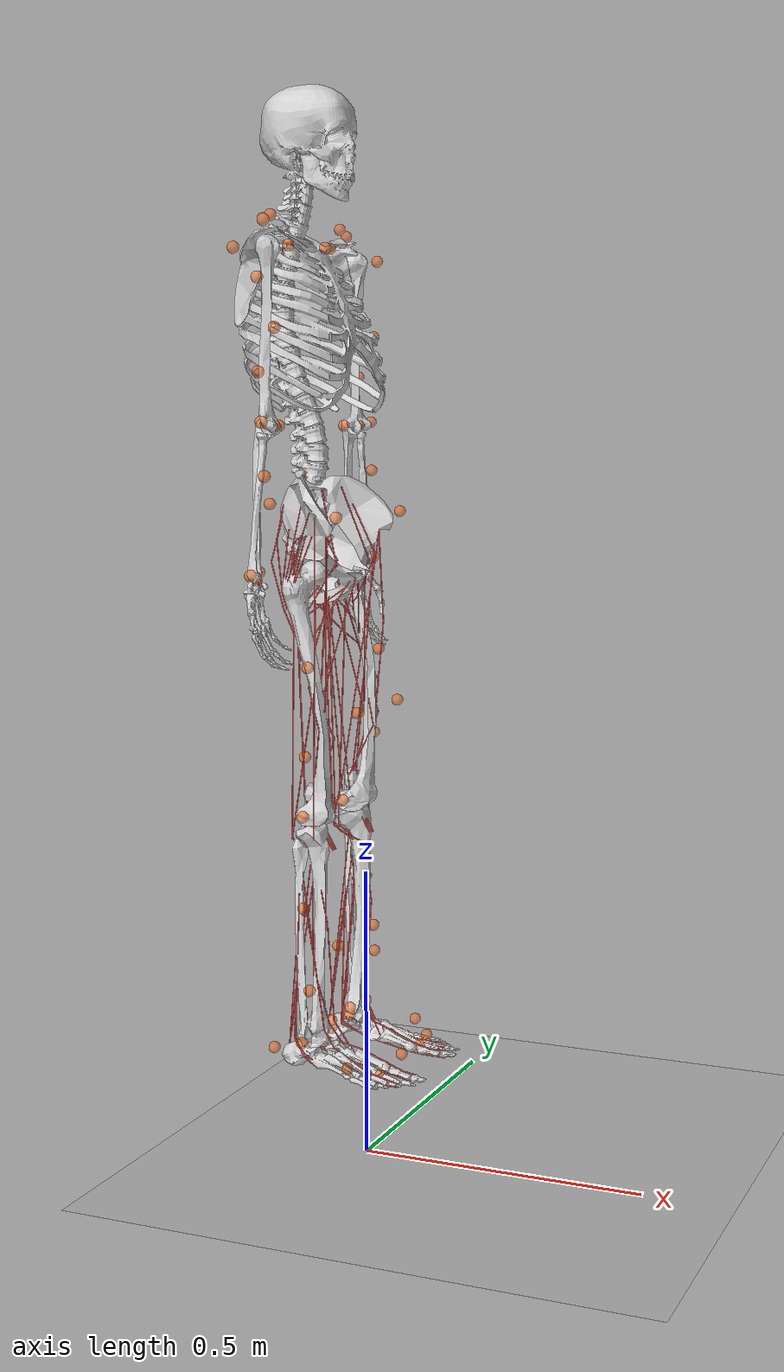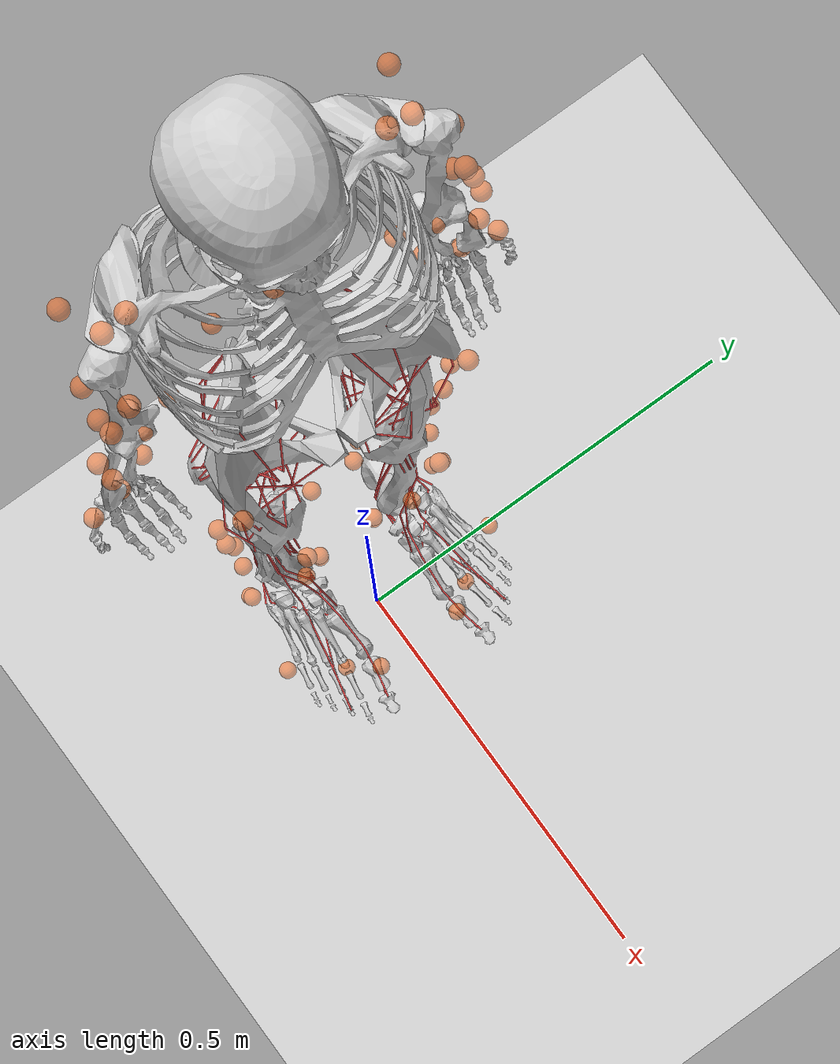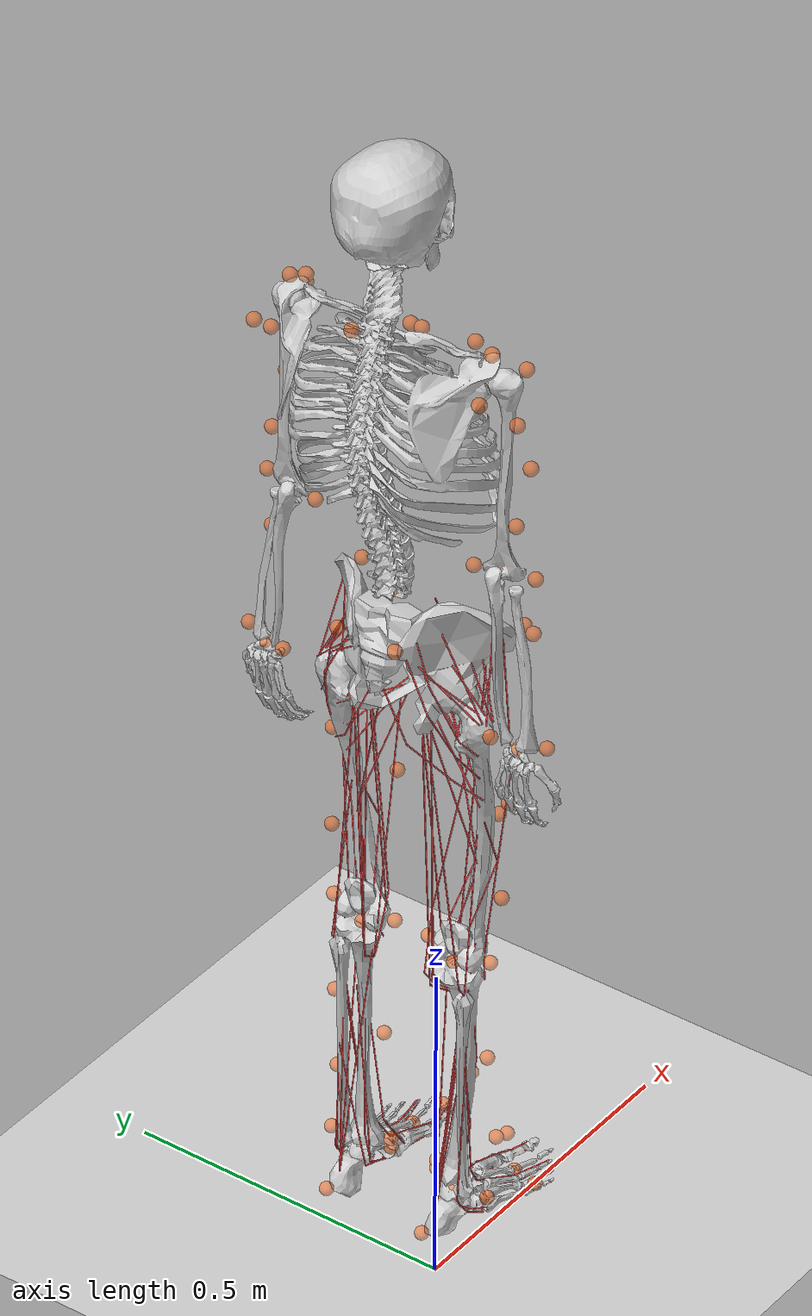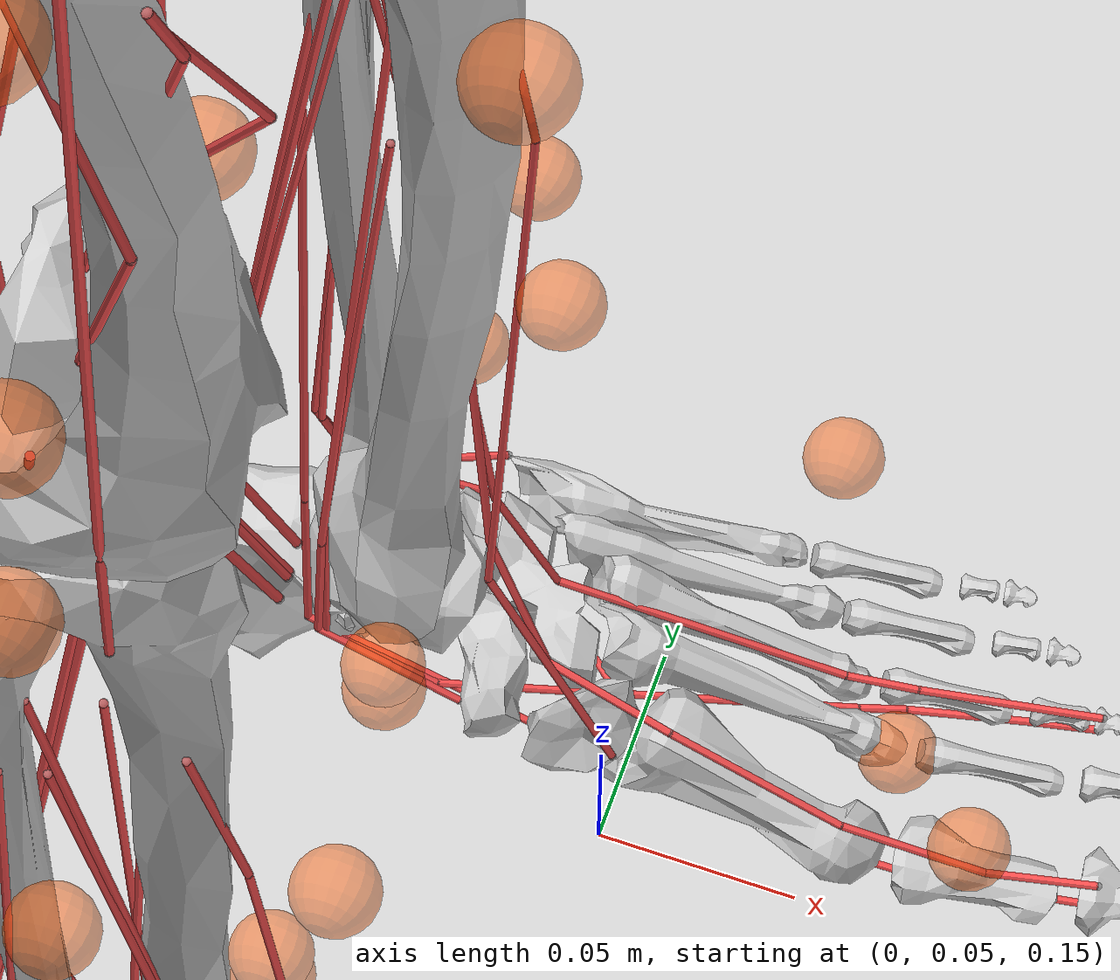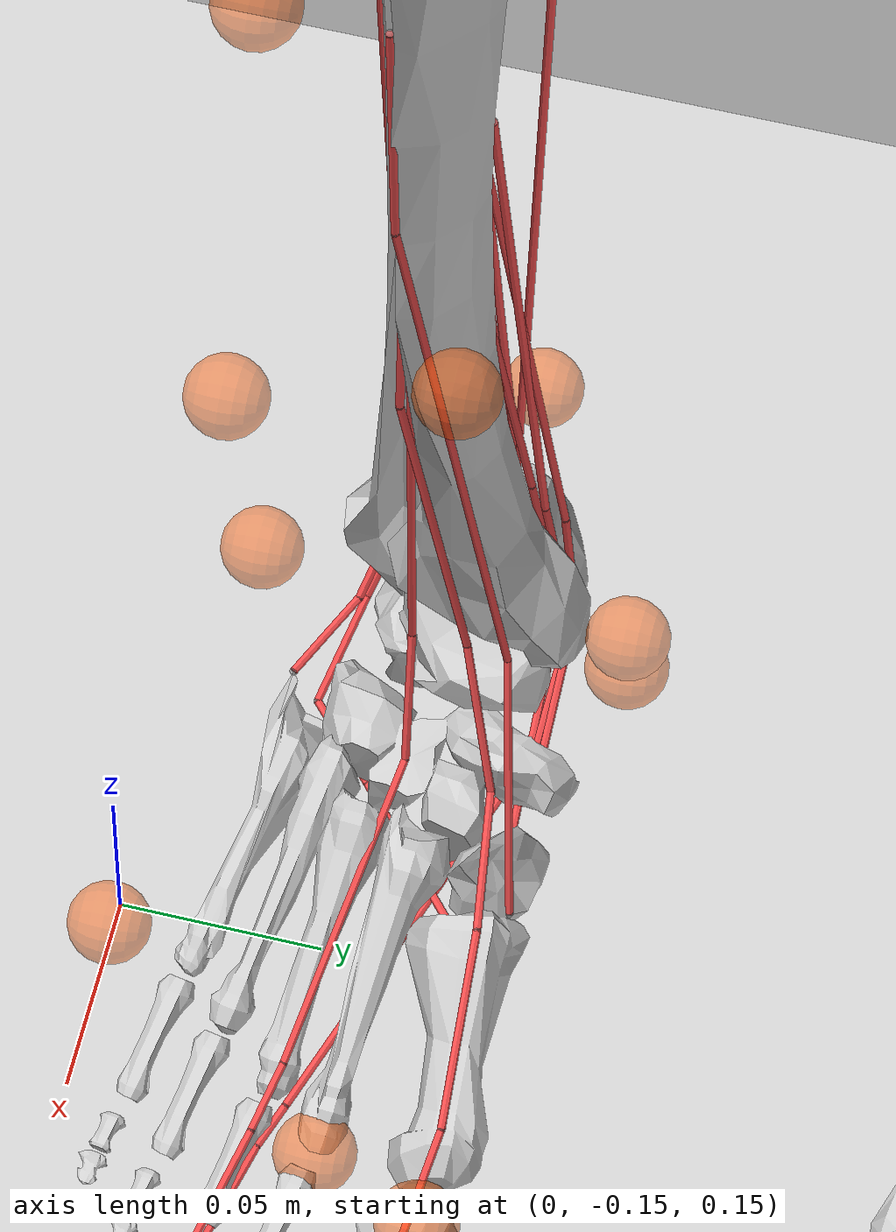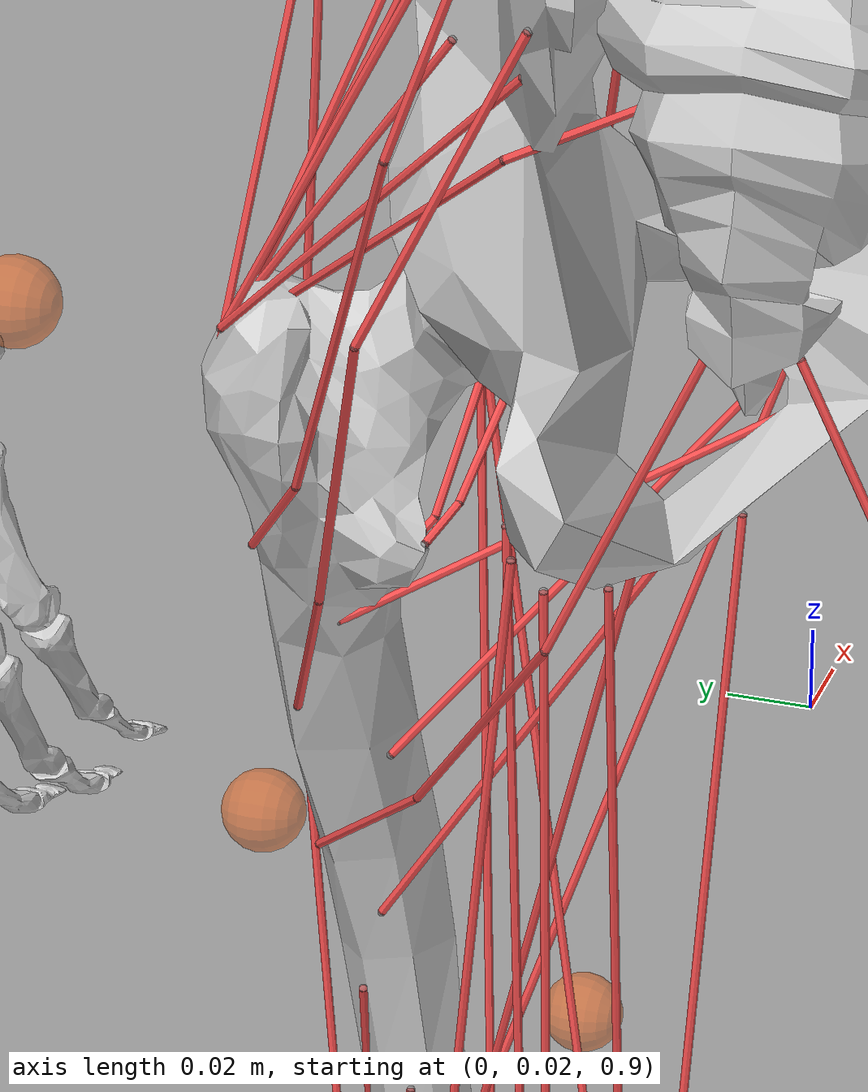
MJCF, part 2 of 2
<mesh name="humerus_lv" vertex="0.010027999989688396 -0.2374110072851181 -0.0023640000727027655 -0.0033499998971819878 -0.22861100733280182 -0.009503000415861607 0.0017989999614655972 -0.18509000539779663 -0.007098999805748463 0.009248999878764153 -0.2153480052947998 -0.002382999984547496 0.006976000033318996 -0.14707200229167938 -0.007765000220388174 -0.005688999779522419 -0.17959199845790863 -0.0058200000785291195 0.011714000254869461 -0.1769769936800003 0.0005779999773949385 0.013845999725162983 -0.1436299979686737 -0.003777999896556139 -0.006928000133484602 -0.20598700642585754 -0.004341000225394964 -0.00381199992261827 -0.22787299752235413 0.00749199977144599 0.006233000196516514 -0.24893100559711456 -0.010033000260591507 -0.0008159999852068722 -0.24948200583457947 -0.014295999892055988 -0.0024939998984336853 -0.24515199661254883 0.003751999931409955 0.011497000232338905 -0.24506600201129913 0.0017269999952986836 0.009731999598443508 -0.24709300696849823 -0.005444000009447336 0.010274999774992466 -0.21590399742126465 0.001104000024497509 -0.005907000042498112 -0.2047490030527115 0.004532000049948692 -0.006372000090777874 -0.1560879945755005 0.0008459999808110297 -0.003848999971523881 -0.1558620035648346 -0.005200999788939953 0.0029819998890161514 -0.08728499710559845 -0.008852999657392502 -0.002587999915704131 -0.17495599389076233 0.007706000003963709 0.004616999998688698 -0.12393499910831451 0.007459000218659639 0.015870999544858932 -0.0990070030093193 -0.001285000005736947 -0.0024019998963922262 -0.23657600581645966 0.008759000338613987 0.0001990000018849969 -0.23680900037288666 0.010267999954521656 0.011549999937415123 -0.2660770118236542 -0.013020999729633331 0.009724999777972698 -0.2659299969673157 -0.01782199926674366 0.0023849999997764826 -0.2625190019607544 -0.020880000665783882 -0.00026699999580159783 -0.2633259892463684 -0.01913299970328808 0.00028899998869746923 -0.2609519958496094 0.015838999301195145 0.00013699999544769526 -0.2617279887199402 0.013962999917566776 -0.0010010000551119447 -0.26623401045799255 -0.005903999786823988 0.0013559999642893672 -0.2651360034942627 0.0018240000354126096 -0.00029200001154094934 -0.25310200452804565 0.012872000224888325 0.01372000016272068 -0.26694101095199585 0.00443200021982193 0.015402000397443771 -0.2725229859352112 -0.0005230000242590904 0.0031139999628067017 -0.26239100098609924 0.01733499951660633 0.0005929999751970172 -0.24504299461841583 0.011533999815583229 0.011831000447273254 -0.26081201434135437 0.008921000175178051 0.01498199999332428 -0.27281901240348816 -0.0028150000143796206 0.014078999869525433 -0.26949501037597656 -0.004236999899148941 -0.004666000138968229 -0.15593400597572327 0.004891999997198582 -0.0024709999561309814 -0.09808100014925003 0.0004330000083427876 -0.002713999943807721 -0.12748600542545319 0.004166000057011843 0.017710000276565552 -0.03192700073122978 -0.006054999772459269 0.009014000184834003 -0.036122001707553864 -0.010723999701440334 0.00380500010214746 -0.03634899854660034 -0.009731999598443508 -0.0014199999859556556 -0.07284600287675858 -0.0030010000336915255 0.004767999984323978 -0.09747199714183807 0.008317999541759491 0.01335499994456768 -0.08249100297689438 0.003955999854952097 0.010664000175893307 -0.2710599899291992 -0.02307100035250187 0.012476000003516674 -0.2718220055103302 -0.02164500020444393 0.01183599978685379 -0.26951199769973755 -0.017285000532865524 0.012171000242233276 -0.2735219895839691 -0.008143000304698944 0.011815999634563923 -0.2722190022468567 -0.01195599976927042 0.006713000126183033 -0.27114999294281006 -0.023984000086784363 0.005133000202476978 -0.2782920002937317 -0.02250399999320507 0.001164000015705824 -0.2801609933376312 -0.015096000395715237 -0.0009590000263415277 -0.2713159918785095 -0.008967000059783459 -0.0007849999819882214 -0.2760240137577057 -0.01046799961477518 0.0016339999856427312 -0.2690959870815277 0.011017999611794949 0.0008510000188834965 -0.27407100796699524 0.019294999539852142 0.0006689999718219042 -0.2659339904785156 0.01860000006854534 0.0031220000237226486 -0.269665002822876 -0.003083999967202544 0.006403000093996525 -0.2708609998226166 0.0006629999843426049 0.014605999924242496 -0.2737100124359131 0.0016400000313296914 0.016005000099539757 -0.27537500858306885 -0.0007220000261440873 0.01307000033557415 -0.27134498953819275 0.004356999881565571 0.012745999731123447 -0.27051299810409546 0.008464000187814236 0.01297600008547306 -0.27031099796295166 0.012485000304877758 0.011946000158786774 -0.27374500036239624 0.018101999536156654 0.003102000104263425 -0.2706319987773895 0.023725999519228935 0.013531000353395939 -0.27393999695777893 -0.004834999796003103 0.016200000420212746 -0.2759059965610504 -0.003073000116273761 -0.0014049999881535769 -0.07658299803733826 0.0009250000002793968 0.0040790000930428505 -0.020976999774575233 -0.01295700017362833 0.011978000402450562 -0.007400999777019024 -0.018061000853776932 0.016363000497221947 -0.002449000021442771 -0.017091000452637672 0.011787000112235546 -0.059390999376773834 0.008310999721288681 0.020076999440789223 -0.022982999682426453 0.0033360000234097242 0.022244999185204506 -0.008154000155627728 -0.0028550000861287117 0.023145999759435654 -0.0029120000544935465 -0.010358000174164772 0.0006300000241026282 -0.021321000531315804 -0.011258999817073345 -0.0015150000108405948 -0.03609500080347061 -0.0032770000398159027 -0.0016720000421628356 -0.04411900043487549 -0.0030789999291300774 -0.0014819999923929572 -0.0500670000910759 -0.003089000005275011 -0.00037299998803064227 -0.05431799963116646 0.0023870000150054693 0.008023999631404877 -0.0451820008456707 0.00939400028437376 0.01295199990272522 -0.2763499915599823 -0.023531999439001083 0.015305000357329845 -0.2770079970359802 -0.02159699983894825 0.014031999744474888 -0.27397701144218445 -0.02026199921965599 0.012388999573886395 -0.2747350037097931 -0.013167999684810638 0.01690799929201603 -0.27842798829078674 -0.005071999970823526 0.010552000254392624 -0.2799740135669708 -0.02428399957716465 0.003837000112980604 -0.2877109944820404 -0.011597000062465668 0.001474000047892332 -0.2811479866504669 -0.010626000352203846 0.010664000175893307 -0.28693899512290955 -0.02026600018143654 0.005303999874740839 -0.289341002702713 -0.011676999740302563 0.002202000003308058 -0.2721239924430847 -0.006591999903321266 0.006932999938726425 -0.2740580141544342 -0.0056409998796880245 0.003467000089585781 -0.2769779860973358 -0.007734000217169523 0.002584999892860651 -0.2721010148525238 0.012734999880194664 0.0019229999743402004 -0.2773570120334625 0.014587000012397766 0.0010000000474974513 -0.2761090099811554 0.030264999717473984 0.00015500000154133886 -0.27690601348876953 0.021410999819636345 0.010374999605119228 -0.27506300806999207 0.0022169998846948147 0.00903400033712387 -0.27679601311683655 0.007788000162690878 0.004867999814450741 -0.27484700083732605 0.011474000290036201 0.0061240000650286674 -0.2708609998226166 -0.0018619999755173922 0.009920000098645687 -0.27397599816322327 -0.000838999985717237 0.00980400014668703 -0.2745720148086548 0.0006590000120922923 0.01546700019389391 -0.2776859998703003 0.0027809999883174896 0.01896899938583374 -0.27908599376678467 -0.0008210000232793391 0.011958999559283257 -0.2756989896297455 0.004259999841451645 0.010374000295996666 -0.276636004447937 0.007207000162452459 0.01043500006198883 -0.275613009929657 0.00930000003427267 0.013253999873995781 -0.27382001280784607 0.015273000113666058 0.011897999793291092 -0.27569401264190674 0.012846999801695347 0.014688000082969666 -0.27685800194740295 0.01664300076663494 0.006945000030100346 -0.2779340147972107 0.031957998871803284 0.015259999781847 -0.27950799465179443 0.018105000257492065 0.012258999980986118 -0.2792209982872009 0.023197000846266747 0.009333999827504158 -0.27953100204467773 0.030693000182509422 0.003215000033378601 -0.2764970064163208 0.031543001532554626 0.012191000394523144 0.008936000056564808 -0.018523000180721283 0.008603000082075596 0.007031000219285488 -0.01984100043773651 0.00010900000052060932 -0.0012839999981224537 -0.018411999568343163 -0.00042600001324899495 -0.011691000312566757 -0.01511599961668253 0.013857999816536903 0.01027000043541193 -0.016186000779271126 0.022406000643968582 0.0017269999952986836 -0.011331000365316868 0.02121400088071823 0.004869000054895878 -0.011971999891102314 0.019328000023961067 -0.02331800013780594 0.006453999783843756 0.027532000094652176 -0.007961999624967575 0.008967000059783459 0.024243999272584915 -0.014498000033199787 0.0031059999018907547 0.024582000449299812 -0.014348999597132206 0.005024999845772982 0.02843400090932846 -0.0018029999919235706 0.0003330000035930425 0.022760000079870224 0.0021840000990778208 -0.0031500000040978193 0.027525000274181366 -0.010095000267028809 0.002283999929204583 0.021859999746084213 0.0019509999547153711 -0.00633700005710125 -0.003111999947577715 -0.015706000849604607 -0.00888300035148859 -0.0036899999249726534 -0.02728400006890297 0.0014260000316426158 -0.002194999950006604 -0.035753000527620316 0.00152299995534122 0.0014959999825805426 -0.036511000245809555 0.007199000101536512 0.0067460001446306705 -0.03493800014257431 0.010173999704420567 0.025638999417424202 -0.2871370017528534 -0.01739099994301796 0.017909999936819077 -0.27726998925209045 -0.02090200036764145 0.01704300008714199 -0.2836019992828369 -0.020618999376893044 0.01584699936211109 -0.2847500145435333 -0.022096000611782074 0.01507600024342537 -0.2750000059604645 -0.020430000498890877 0.015838000923395157 -0.27532199025154114 -0.019478999078273773 0.019412999972701073 -0.2774670124053955 -0.008329999633133411 0.02285899966955185 -0.277334988117218 -0.01611199975013733 0.020431000739336014 -0.27696600556373596 -0.01908300071954727 0.016870999708771706 -0.27577701210975647 -0.019625000655651093 0.01952899992465973 -0.27970901131629944 -0.004248000215739012 0.01360199972987175 -0.2857449948787689 -0.02209700085222721 0.004666999913752079 -0.2836880087852478 -0.004538999870419502 0.0059830001555383205 -0.2904140055179596 -0.008810999803245068 0.009290999732911587 -0.29247498512268066 -0.008391999639570713 0.016133999451994896 -0.2877349853515625 -0.020041000097990036 0.019650999456644058 -0.29209399223327637 -0.01626800000667572 0.01909800060093403 -0.2934660017490387 -0.014566999860107899 0.016165999695658684 -0.2939800024032593 -0.013137999922037125 0.006889000069350004 -0.27210700511932373 -0.004133000038564205 0.007296000141650438 -0.27528899908065796 -0.005034999921917915 0.007728000171482563 -0.2781429886817932 -0.002142000012099743 0.004840000066906214 -0.2819649875164032 -0.004207000136375427 0.005384999793022871 -0.277321994304657 0.01170899998396635 0.004145999904721975 -0.283394992351532 0.006312999874353409 0.001032999949529767 -0.28365498781204224 0.03129899874329567 0.001142999972216785 -0.2797060012817383 0.03162200003862381 0.0026910000015050173 -0.28555700182914734 0.01979300007224083 0.002266000024974346 -0.2843469977378845 0.01217000000178814 0.0057310000993311405 -0.2818160057067871 -0.000291000003926456 0.008333999663591385 -0.27822598814964294 0.00838600005954504 0.007449000142514706 -0.27948498725891113 0.006297999992966652 0.007652999833226204 -0.27738600969314575 0.00913000013679266 0.012474000453948975 -0.2767390012741089 0.0045380000956356525 0.015964999794960022 -0.2801060080528259 0.009488999843597412 0.019231000915169716 -0.2818169891834259 0.006548999808728695 0.021801000460982323 -0.2853600084781647 0.0036150000523775816 0.02159699983894825 -0.28171899914741516 -0.0037360000424087048 0.010890999808907509 -0.2766909897327423 0.009801999665796757 0.01473699975758791 -0.27759799361228943 0.014783999882638454 0.021741999313235283 -0.2856549918651581 0.0155239999294281 0.01916700042784214 -0.28215500712394714 0.011339999735355377 0.021020999178290367 -0.285288006067276 0.01795800030231476 0.02046000026166439 -0.28505998849868774 0.01845400035381317 0.018223000690340996 -0.2837370038032532 0.018828000873327255 0.0026519999373704195 -0.2796129882335663 0.032735999673604965 0.006519999820739031 -0.28183498978614807 0.032712001353502274 0.009095000103116035 -0.2868860065937042 0.029146000742912292 0.011359999887645245 -0.2845520079135895 0.022818999364972115 0.013015000149607658 -0.28158000111579895 0.02065199986100197 0.006918999832123518 0.008771000429987907 -0.01846799999475479 0.010002999566495419 0.01090100035071373 -0.01745700091123581 0.003163000103086233 0.004879999905824661 -0.01923299953341484 -0.0007130000158213079 0.003938000183552504 -0.01751299947500229 -0.004892999771982431 0.002727000042796135 -0.013054000213742256 -0.00659599993377924 -0.008876999840140343 -0.010521999560296535 0.011637000367045403 0.0124719999730587 -0.016032999381422997 0.012435000389814377 0.013504000380635262 -0.013856999576091766 0.016766000539064407 0.011479999870061874 -0.011700999923050404 0.020628999918699265 0.007577999960631132 -0.010247999802231789 0.00889899954199791 -0.019277000799775124 0.013908999972045422 0.01897599920630455 -0.004730000160634518 0.018703000620007515 0.016398999840021133 -0.007600000128149986 0.01758600026369095 0.02150600031018257 0.002713999943807721 0.0171549990773201 0.02931400015950203 -0.005276000127196312 0.006149000022560358 0.027365999296307564 -0.0020800000056624413 0.008812000043690205 0.019122999161481857 0.00892999954521656 -0.006955000106245279 0.024212000891566277 0.0050650001503527164 -0.00019099999917671084 0.027667999267578125 0.0004980000085197389 0.00014800000644754618 0.02928999997675419 6.199999916134402e-05 0.0031210000161081553 -0.006442000158131123 -0.013491000048816204 0.004023000132292509 -0.004813000094145536 -0.017875000834465027 0.0038499999791383743 -0.005549999885261059 -0.015186999924480915 0.008004000410437584 -0.00042799999937415123 -0.02034199982881546 0.01244600024074316 0.0013989999424666166 -0.02812799997627735 0.009554999880492687 0.005578000098466873 -0.020150000229477882 0.014406000263988972 0.0024610001128166914 -0.02024500072002411 0.01406100019812584 0.015917999669909477 -0.2754890024662018 -0.02006400004029274 0.025039000436663628 -0.27980899810791016 -0.017812000587582588 0.0263030007481575 -0.28453201055526733 -0.017472999170422554 0.02437499910593033 -0.29075101017951965 -0.014655999839305878 0.02631000056862831 -0.2882469892501831 -0.014352000318467617 0.023799000307917595 -0.2894519865512848 -0.01705300062894821 0.025603000074625015 -0.2795009911060333 -0.015251999720931053 0.02423899993300438 -0.27981698513031006 -0.009442999958992004 0.005280000157654285 -0.28493601083755493 -0.0011500000255182385 0.009197000414133072 -0.29295799136161804 -4.5000000682193786e-05 0.007124000228941441 -0.29017698764801025 -0.006122000049799681 0.009455000050365925 -0.29301100969314575 -0.005979999899864197 0.021530000492930412 -0.292589008808136 -0.01485500019043684 0.02164600044488907 -0.2931100130081177 -0.012257999740540981 0.019114000722765923 -0.29417699575424194 -0.012346000410616398 0.00572599982842803 -0.27930501103401184 0.009081999771296978 0.004404999781399965 -0.28981998562812805 0.006056000012904406 0.002265000017359853 -0.28390100598335266 0.03227800130844116 0.0028780000284314156 -0.28860199451446533 0.030602000653743744 0.004784999880939722 -0.28844499588012695 0.018831999972462654 0.003484999993816018 -0.287337988615036 0.017438000068068504 0.002901999978348613 -0.28741100430488586 0.011687000282108784 0.020476000383496284 -0.28434398770332336 0.006612999830394983 0.022262999787926674 -0.28965699672698975 -0.004170000087469816 0.026453999802470207 -0.2824540138244629 -0.01056199986487627 0.020222000777721405 -0.29019200801849365 0.006194999907165766 0.02091600000858307 -0.28730300068855286 0.00658900011330843 0.021709999069571495 -0.29314500093460083 0.016036000102758408 0.021616000682115555 -0.2890399992465973 0.01801300048828125 0.020452000200748444 -0.2886179983615875 0.0190069992095232 0.012994999997317791 -0.28431999683380127 0.020538000389933586 0.0043390002101659775 -0.2838680148124695 0.03265799954533577 0.00381499994546175 -0.2874610126018524 0.031619999557733536 0.005998999811708927 -0.2893179953098297 0.030616000294685364 0.007864000275731087 -0.2891539931297302 0.028846999630331993 0.009456999599933624 -0.289588987827301 0.022461000829935074 0.004255000036209822 0.007757000159472227 -0.018024999648332596 0.0005089999758638442 0.011660999618470669 -0.009347000159323215 -0.008954999968409538 0.011026999913156033 -0.0006569999968633056 -0.005171999800950289 0.014309000223875046 -0.001820000004954636 -0.012896999716758728 0.0012910000514239073 0.0008730000117793679 -0.011692999862134457 0.007329000160098076 0.0010000000474974513 -0.011109000071883202 -0.004741999786347151 0.0005959999980404973 0.01612200029194355 0.01243599969893694 -0.00930000003427267 0.0041069998405873775 0.014770999550819397 -0.007825000211596489 0.00890900008380413 0.015048000030219555 -0.006787999998778105 0.014797000214457512 0.012953000143170357 -0.007966999895870686 0.0043669999577105045 -0.013783000409603119 0.01917400024831295 0.007792000193148851 -0.012814000248908997 0.01918799988925457 0.01593399979174137 -0.007348999846726656 0.02091600000858307 0.015211000107228756 -0.004064000211656094 0.02319199964404106 0.022098999470472336 0.006928000133484602 0.014494000002741814 0.013144000433385372 -9.899999713525176e-05 0.02471099980175495 0.014081000350415707 0.0064559997990727425 0.022135000675916672 0.01942100003361702 0.014147999696433544 0.006816999986767769 0.01794400066137314 0.011296999640762806 -0.006167999934405088 0.0193060003221035 0.012915000319480896 0.00016399999731220305 0.028334999457001686 0.0017460000235587358 0.0019099999917671084 -0.012659000232815742 -0.0059540001675486565 0.005477000027894974 -0.0015920000150799751 -0.017355000600218773 0.01440299954265356 -0.004234999883919954 -0.012594999745488167 0.019625000655651093 -0.010267999954521656 -0.010054999962449074 0.012257000431418419 0.001120000029914081 -0.01590000092983246 0.017775999382138252 0.026844000443816185 -0.28208398818969727 -0.014627999626100063 0.02706499956548214 -0.2855919897556305 -0.014751999638974667 0.026083000004291534 -0.28867700695991516 -0.010292000137269497 0.008310999721288681 -0.29472699761390686 0.006221999879926443 0.014581000432372093 -0.2941350042819977 0.0009539999882690609 0.018792999908328056 -0.2929939925670624 -0.0053170002065598965 0.004036999773234129 -0.29392099380493164 0.00929300021380186 0.005038999952375889 -0.28967800736427307 0.027915000915527344 0.004858999978750944 -0.28925999999046326 0.030719000846147537 0.00699299992993474 -0.289561003446579 0.02049800008535385 0.0043299999088048935 -0.2881909906864166 0.01750599965453148 0.005216000135987997 -0.29071998596191406 0.015776000916957855 0.004424000158905983 -0.2952220141887665 0.011857000179588795 0.02696700021624565 -0.285768985748291 -0.010540000163018703 0.016186999157071114 -0.29464998841285706 0.004532999824732542 0.019960999488830566 -0.2966040074825287 0.015549999661743641 0.021013999357819557 -0.29308798909187317 0.01806900091469288 0.019276000559329987 -0.2963950037956238 0.017619000747799873 0.017588000744581223 -0.2950100004673004 0.01872899942100048 0.011777999810874462 -0.29079800844192505 0.019293999299407005 0.010205999948084354 -0.28995299339294434 0.020029999315738678 0.006763999816030264 -0.2897860109806061 0.028426000848412514 0.009236999787390232 -0.29001399874687195 0.020951999351382256 -0.009855999611318111 0.010755999945104122 0.007935999892652035 0.0034749999176710844 0.017204999923706055 -0.0042409999296069145 0.002345999935641885 0.018271999433636665 -0.0001880000054370612 -0.002876000013202429 0.013174000196158886 0.015289000235497952 -0.013345999643206596 0.0037400000728666782 0.003450999967753887 -0.013819999992847443 0.0003229999856557697 0.005520000122487545 0.008346999995410442 0.017402999103069305 -0.00343300006352365 -0.0001630000042496249 -0.012817000038921833 0.02222999930381775 0.003911999985575676 -0.012594999745488167 0.023284999653697014 0.00824700016528368 -0.011288999579846859 0.02366900071501732 0.009227000176906586 -0.007323999889194965 0.02502099983394146 0.010703000240027905 0.013751000165939331 0.017165999859571457 0.004304999951273203 0.0005910000181756914 0.02576100081205368 0.008803999982774258 0.008128000423312187 0.02260199934244156 0.010118000209331512 0.018101999536156654 0.008023999631404877 -0.012126999907195568 -0.0015450000064447522 0.013377999886870384 -0.0011790000135079026 -0.010081999935209751 0.02353600040078163 -0.007660999894142151 -0.0006329999887384474 0.01990099996328354 -0.0019259999971836805 -0.005884999874979258 0.02429400011897087 0.007751000113785267 -0.2980259954929352 0.011265000328421593 0.013706999830901623 -0.2959049940109253 0.0062500000931322575 0.004848000127822161 -0.29613998532295227 0.011309999972581863 0.007930000312626362 -0.29015499353408813 0.017992999404668808 0.00798300001770258 -0.29823899269104004 0.013864999637007713 0.013712000101804733 -0.2993820011615753 0.016013000160455704 0.010487999767065048 -0.2915480136871338 0.018796000629663467 0.017115000635385513 -0.29900699853897095 0.014595000073313713 0.013969000428915024 -0.29962000250816345 0.013776999898254871 0.016791999340057373 -0.2986699938774109 0.01686899922788143 -0.013005999848246574 0.003894000081345439 0.00810300000011921 -0.004184999968856573 0.006219000089913607 0.0203000009059906 0.0018309999722987413 0.008462999947369099 0.022092999890446663 0.00279999990016222 -0.009569000452756882 0.024918999522924423" face="0 1 2 3 0 2 4 2 5 5 2 1 3 2 6 6 2 7 4 7 2 8 1 9 1 0 10 10 11 1 1 12 9 12 1 11 1 8 5 0 13 14 0 14 10 0 3 13 3 6 15 13 3 15 5 8 16 5 17 18 4 5 18 5 16 17 19 4 18 7 4 19 6 20 15 7 20 6 20 7 21 22 21 7 22 7 19 16 9 20 12 23 9 16 8 9 24 9 23 20 9 24 25 26 10 25 10 14 27 11 10 27 10 26 11 28 12 27 28 11 29 12 30 12 28 31 32 12 31 12 32 30 23 12 33 12 29 33 25 14 13 24 13 20 34 35 13 20 13 15 36 13 37 13 36 38 37 13 24 13 38 34 39 40 13 39 13 35 13 40 25 41 17 16 20 41 16 18 17 19 42 19 17 17 41 43 42 17 43 44 19 45 19 46 45 47 46 19 19 42 47 19 44 22 41 20 43 43 20 21 48 21 49 21 22 49 43 21 48 49 22 44 24 23 37 23 33 37 26 50 27 50 26 51 52 51 26 26 25 52 53 25 40 25 53 54 25 54 52 28 27 55 27 50 55 56 57 28 28 55 56 28 58 31 59 28 57 28 59 58 30 60 61 30 32 60 30 62 29 61 62 30 29 62 36 29 36 33 32 31 63 58 63 31 63 64 32 60 32 64 36 37 33 65 66 35 35 34 67 35 67 65 66 39 35 34 38 68 68 67 34 36 69 38 69 36 70 36 71 70 36 62 71 38 69 68 40 39 72 53 40 72 73 39 66 72 39 73 48 74 42 74 47 42 42 43 48 75 76 45 46 75 45 44 45 76 76 77 44 44 78 49 44 79 78 80 79 44 44 81 80 44 77 81 82 75 46 83 82 46 83 46 84 46 85 84 85 46 47 47 74 85 48 49 78 86 48 87 86 74 48 48 78 87 88 50 89 88 55 50 50 51 89 89 51 90 51 52 90 91 90 52 54 91 52 53 72 92 53 91 54 91 53 92 56 55 93 88 93 55 57 56 94 59 57 95 95 57 94 56 96 97 93 96 56 56 97 94 98 58 59 63 58 98 99 98 59 100 99 59 95 100 59 61 101 102 61 60 101 61 103 62 103 61 104 102 104 61 105 60 64 60 105 106 60 106 107 107 101 60 62 103 71 98 108 63 108 64 63 64 108 109 64 109 110 64 110 105 66 65 111 66 111 112 73 66 112 67 113 65 111 65 113 67 68 114 114 113 67 68 69 115 114 68 115 116 69 70 117 69 116 69 117 115 116 70 118 71 119 70 120 70 121 70 120 118 70 122 121 122 70 119 119 71 123 103 123 71 92 72 73 92 73 112 85 74 86 76 124 77 125 76 126 124 76 125 127 126 76 76 75 127 75 82 127 128 77 124 81 77 129 130 129 77 128 130 77 87 78 131 131 78 79 79 132 131 79 133 134 134 132 79 79 80 133 135 80 136 137 133 80 137 80 135 80 138 136 81 138 80 138 81 129 139 127 82 82 83 139 140 139 83 140 83 84 141 140 84 84 85 141 85 86 141 86 87 142 131 143 87 143 142 87 141 86 142 144 89 145 144 146 89 89 146 147 147 88 89 89 90 148 89 148 145 88 147 93 91 149 90 148 90 149 150 151 91 150 91 92 152 91 151 91 152 153 149 91 153 154 150 92 92 112 154 155 96 93 147 155 93 94 97 156 156 95 94 156 100 95 156 97 157 158 157 97 158 97 96 96 155 159 160 161 96 161 162 96 162 158 96 160 96 159 108 98 163 98 99 163 109 99 164 163 99 109 100 164 99 100 165 164 165 100 166 100 156 166 101 107 102 102 107 167 167 168 102 102 168 104 103 169 170 103 104 169 103 170 123 171 169 104 172 104 168 171 104 172 105 165 173 165 105 110 174 105 175 105 174 106 175 105 173 167 106 176 106 167 107 176 106 174 108 163 109 165 109 164 165 110 109 177 111 113 178 179 111 111 177 114 178 111 114 112 111 179 180 181 112 112 181 154 179 180 112 177 113 114 114 115 182 114 182 178 115 117 182 116 118 183 116 183 117 183 182 117 118 184 185 118 186 184 186 118 187 188 118 120 118 188 187 185 183 118 189 119 123 122 119 190 119 189 190 191 121 122 192 193 121 121 191 192 120 121 193 120 193 188 122 190 191 123 170 189 194 124 125 195 128 124 124 194 195 196 125 126 196 126 197 198 197 126 126 199 198 127 199 126 196 194 125 199 127 139 128 195 200 201 202 128 128 202 203 203 130 128 128 200 201 130 203 129 138 129 203 131 204 143 204 131 132 205 206 132 132 206 204 132 134 137 207 205 132 208 132 137 132 209 207 209 132 208 137 134 133 138 210 136 210 211 136 136 211 212 135 136 212 208 137 135 135 213 208 212 213 135 203 210 138 139 214 199 214 139 215 140 215 139 215 140 216 217 216 140 217 140 218 218 140 141 142 218 141 142 143 218 219 143 204 220 143 219 218 143 220 145 148 221 152 145 153 222 145 152 223 145 222 223 144 145 221 153 145 224 144 225 144 226 159 144 159 146 144 224 226 223 225 144 146 159 147 147 159 155 221 148 149 149 153 221 227 222 151 152 151 222 151 228 227 228 151 150 150 154 228 154 181 228 229 166 156 156 230 229 230 156 231 231 156 157 157 158 231 231 158 232 158 162 232 159 226 160 233 161 160 234 161 233 234 235 161 161 235 162 226 233 160 162 235 232 173 165 166 173 166 229 168 167 236 167 176 236 173 168 175 168 236 175 168 173 237 172 168 237 170 238 189 170 169 238 239 169 171 169 239 238 239 171 240 172 241 171 171 241 240 172 242 241 237 242 172 173 229 237 175 236 174 236 176 174 179 178 185 185 243 179 179 243 180 178 182 183 178 183 185 244 181 180 244 245 181 181 245 228 246 244 180 180 247 246 180 243 247 185 184 243 248 243 184 186 249 184 249 248 184 186 187 249 250 187 188 249 187 250 251 188 193 188 251 250 252 190 189 238 252 189 190 253 254 253 190 252 191 190 254 191 254 255 256 192 191 191 255 256 193 192 251 251 192 256 257 194 196 257 258 194 258 195 194 195 258 200 196 197 257 257 197 258 259 197 198 197 259 260 260 258 197 198 261 262 261 198 263 198 262 259 198 199 263 199 214 263 258 201 200 201 264 202 264 203 202 201 265 266 258 265 201 264 201 267 266 267 201 203 264 210 204 268 219 269 268 204 206 269 204 269 206 270 270 206 205 205 271 270 271 205 207 209 272 207 273 271 207 274 273 207 274 207 272 208 213 209 213 275 209 275 272 209 210 276 277 264 276 210 211 210 277 211 275 278 275 211 277 211 278 212 212 278 213 275 213 278 279 263 214 214 216 279 215 216 214 280 281 216 282 279 216 281 282 216 280 216 217 280 217 220 220 217 218 268 220 219 220 268 283 280 220 283 284 222 227 284 223 222 225 223 285 285 223 284 225 286 224 285 286 225 224 234 233 234 224 286 224 233 226 227 245 284 245 227 228 229 230 237 230 287 237 232 230 231 232 288 230 288 287 230 288 232 289 289 232 235 234 286 289 289 235 234 242 237 290 287 290 237 253 238 239 238 253 252 240 291 239 253 239 292 291 292 239 291 240 293 294 240 241 240 294 293 295 294 241 241 242 295 290 296 242 295 242 296 243 248 247 289 244 246 245 244 297 297 244 286 286 244 289 297 284 245 289 246 298 299 246 248 246 299 298 248 246 247 248 249 300 248 301 299 248 300 301 249 250 300 300 250 302 250 303 302 250 251 303 251 304 303 251 256 304 292 254 253 305 254 292 255 254 305 256 255 305 256 305 306 304 256 306 260 265 258 307 259 262 307 260 259 265 260 308 260 309 308 310 309 260 310 260 307 311 307 262 262 261 311 311 261 312 261 263 279 279 312 261 276 264 267 313 266 265 277 266 313 267 266 277 308 313 265 267 277 276 268 314 283 315 314 268 269 315 268 269 270 316 315 269 316 317 270 271 317 316 270 273 317 271 272 318 274 275 318 272 317 273 319 319 273 274 318 320 274 320 319 274 318 275 321 321 275 277 313 321 277 312 279 322 282 322 279 281 283 314 281 314 323 281 324 282 324 281 325 280 283 281 325 281 323 322 282 324 284 297 285 286 285 297 326 290 287 327 287 288 327 326 287 298 327 288 298 288 289 290 326 328 290 328 296 305 292 291 291 293 305 306 293 304 306 305 293 294 329 293 304 293 329 294 295 329 295 296 330 295 330 331 332 295 331 332 329 295 296 328 330 299 333 298 298 334 327 333 334 298 335 299 301 299 335 333 302 301 300 302 335 301 335 302 331 331 302 303 332 303 304 332 331 303 332 304 329 322 307 336 307 311 336 307 322 337 307 337 310 313 308 309 310 321 309 321 313 309 310 337 338 338 318 310 310 318 321 312 336 311 322 336 312 315 323 314 339 315 316 323 315 339 339 316 317 319 339 317 338 320 318 319 325 339 320 338 319 324 319 337 319 324 325 319 338 337 324 337 322 323 339 325 330 328 326 327 334 326 326 334 330 331 330 334 334 335 331 333 335 334" scale="1.0 1.0 1.0"/>
    <mesh name="humerus_rv" vertex="0.0017989999614655972 -0.18509000539779663 0.007098999805748463 -0.0033499998971819878 -0.22861100733280182 0.009503000415861607 0.010027999989688396 -0.2374110072851181 0.0023640000727027655 0.009248999878764153 -0.2153480052947998 0.002382999984547496 -0.005688999779522419 -0.17959199845790863 0.0058200000785291195 0.006976000033318996 -0.14707200229167938 0.007765000220388174 0.011714000254869461 -0.1769769936800003 -0.0005779999773949385 0.013845999725162983 -0.1436299979686737 0.003777999896556139 -0.00381199992261827 -0.22787299752235413 -0.00749199977144599 -0.006928000133484602 -0.20598700642585754 0.004341000225394964 0.006233000196516514 -0.24893100559711456 0.010033000260591507 -0.0008159999852068722 -0.24948200583457947 0.014295999892055988 -0.0024939998984336853 -0.24515199661254883 -0.003751999931409955 0.009731999598443508 -0.24709300696849823 0.005444000009447336 0.011497000232338905 -0.24506600201129913 -0.0017269999952986836 0.010274999774992466 -0.21590399742126465 -0.001104000024497509 -0.005907000042498112 -0.2047490030527115 -0.004532000049948692 -0.003848999971523881 -0.1558620035648346 0.005200999788939953 -0.006372000090777874 -0.1560879945755005 -0.0008459999808110297 0.0029819998890161514 -0.08728499710559845 0.008852999657392502 -0.002587999915704131 -0.17495599389076233 -0.007706000003963709 0.004616999998688698 -0.12393499910831451 -0.007459000218659639 0.015870999544858932 -0.0990070030093193 0.001285000005736947 -0.0024019998963922262 -0.23657600581645966 -0.008759000338613987 0.0001990000018849969 -0.23680900037288666 -0.010267999954521656 0.009724999777972698 -0.2659299969673157 0.01782199926674366 0.011549999937415123 -0.2660770118236542 0.013020999729633331 0.0023849999997764826 -0.2625190019607544 0.020880000665783882 -0.00026699999580159783 -0.2633259892463684 0.01913299970328808 0.00013699999544769526 -0.2617279887199402 -0.013962999917566776 0.00028899998869746923 -0.2609519958496094 -0.015838999301195145 -0.0010010000551119447 -0.26623401045799255 0.005903999786823988 0.0013559999642893672 -0.2651360034942627 -0.0018240000354126096 -0.00029200001154094934 -0.25310200452804565 -0.012872000224888325 0.015402000397443771 -0.2725229859352112 0.0005230000242590904 0.01372000016272068 -0.26694101095199585 -0.00443200021982193 0.0005929999751970172 -0.24504299461841583 -0.011533999815583229 0.0031139999628067017 -0.26239100098609924 -0.01733499951660633 0.011831000447273254 -0.26081201434135437 -0.008921000175178051 0.014078999869525433 -0.26949501037597656 0.004236999899148941 0.01498199999332428 -0.27281901240348816 0.0028150000143796206 -0.004666000138968229 -0.15593400597572327 -0.004891999997198582 -0.0024709999561309814 -0.09808100014925003 -0.0004330000083427876 -0.002713999943807721 -0.12748600542545319 -0.004166000057011843 0.009014000184834003 -0.036122001707553864 0.010723999701440334 0.017710000276565552 -0.03192700073122978 0.006054999772459269 0.00380500010214746 -0.03634899854660034 0.009731999598443508 -0.0014199999859556556 -0.07284600287675858 0.0030010000336915255 0.01335499994456768 -0.08249100297689438 -0.003955999854952097 0.004767999984323978 -0.09747199714183807 -0.008317999541759491 0.010664000175893307 -0.2710599899291992 0.02307100035250187 0.012476000003516674 -0.2718220055103302 0.02164500020444393 0.01183599978685379 -0.26951199769973755 0.017285000532865524 0.012171000242233276 -0.2735219895839691 0.008143000304698944 0.011815999634563923 -0.2722190022468567 0.01195599976927042 0.006713000126183033 -0.27114999294281006 0.023984000086784363 0.001164000015705824 -0.2801609933376312 0.015096000395715237 0.005133000202476978 -0.2782920002937317 0.02250399999320507 -0.0009590000263415277 -0.2713159918785095 0.008967000059783459 -0.0007849999819882214 -0.2760240137577057 0.01046799961477518 0.0008510000188834965 -0.27407100796699524 -0.019294999539852142 0.0016339999856427312 -0.2690959870815277 -0.011017999611794949 0.0006689999718219042 -0.2659339904785156 -0.01860000006854534 0.0031220000237226486 -0.269665002822876 0.003083999967202544 0.006403000093996525 -0.2708609998226166 -0.0006629999843426049 0.016005000099539757 -0.27537500858306885 0.0007220000261440873 0.014605999924242496 -0.2737100124359131 -0.0016400000313296914 0.01307000033557415 -0.27134498953819275 -0.004356999881565571 0.012745999731123447 -0.27051299810409546 -0.008464000187814236 0.01297600008547306 -0.27031099796295166 -0.012485000304877758 0.011946000158786774 -0.27374500036239624 -0.018101999536156654 0.003102000104263425 -0.2706319987773895 -0.023725999519228935 0.013531000353395939 -0.27393999695777893 0.004834999796003103 0.016200000420212746 -0.2759059965610504 0.003073000116273761 -0.0014049999881535769 -0.07658299803733826 -0.0009250000002793968 0.011978000402450562 -0.007400999777019024 0.018061000853776932 0.0040790000930428505 -0.020976999774575233 0.01295700017362833 0.016363000497221947 -0.002449000021442771 0.017091000452637672 0.011787000112235546 -0.059390999376773834 -0.008310999721288681 0.020076999440789223 -0.022982999682426453 -0.0033360000234097242 0.022244999185204506 -0.008154000155627728 0.0028550000861287117 0.023145999759435654 -0.0029120000544935465 0.010358000174164772 0.0006300000241026282 -0.021321000531315804 0.011258999817073345 -0.0015150000108405948 -0.03609500080347061 0.0032770000398159027 -0.0016720000421628356 -0.04411900043487549 0.0030789999291300774 -0.0014819999923929572 -0.0500670000910759 0.003089000005275011 0.008023999631404877 -0.0451820008456707 -0.00939400028437376 -0.00037299998803064227 -0.05431799963116646 -0.0023870000150054693 0.015305000357329845 -0.2770079970359802 0.02159699983894825 0.01295199990272522 -0.2763499915599823 0.023531999439001083 0.014031999744474888 -0.27397701144218445 0.02026199921965599 0.012388999573886395 -0.2747350037097931 0.013167999684810638 0.01690799929201603 -0.27842798829078674 0.005071999970823526 0.010552000254392624 -0.2799740135669708 0.02428399957716465 0.003837000112980604 -0.2877109944820404 0.011597000062465668 0.001474000047892332 -0.2811479866504669 0.010626000352203846 0.005303999874740839 -0.289341002702713 0.011676999740302563 0.010664000175893307 -0.28693899512290955 0.02026600018143654 0.002202000003308058 -0.2721239924430847 0.006591999903321266 0.006932999938726425 -0.2740580141544342 0.0056409998796880245 0.003467000089585781 -0.2769779860973358 0.007734000217169523 0.0019229999743402004 -0.2773570120334625 -0.014587000012397766 0.002584999892860651 -0.2721010148525238 -0.012734999880194664 0.0010000000474974513 -0.2761090099811554 -0.030264999717473984 0.00015500000154133886 -0.27690601348876953 -0.021410999819636345 0.010374999605119228 -0.27506300806999207 -0.0022169998846948147 0.00903400033712387 -0.27679601311683655 -0.007788000162690878 0.004867999814450741 -0.27484700083732605 -0.011474000290036201 0.0061240000650286674 -0.2708609998226166 0.0018619999755173922 0.009920000098645687 -0.27397599816322327 0.000838999985717237 0.00980400014668703 -0.2745720148086548 -0.0006590000120922923 0.01546700019389391 -0.2776859998703003 -0.0027809999883174896 0.01896899938583374 -0.27908599376678467 0.0008210000232793391 0.011958999559283257 -0.2756989896297455 -0.004259999841451645 0.010374000295996666 -0.276636004447937 -0.007207000162452459 0.01043500006198883 -0.275613009929657 -0.00930000003427267 0.013253999873995781 -0.27382001280784607 -0.015273000113666058 0.011897999793291092 -0.27569401264190674 -0.012846999801695347 0.014688000082969666 -0.27685800194740295 -0.01664300076663494 0.006945000030100346 -0.2779340147972107 -0.031957998871803284 0.012258999980986118 -0.2792209982872009 -0.023197000846266747 0.015259999781847 -0.27950799465179443 -0.018105000257492065 0.009333999827504158 -0.27953100204467773 -0.030693000182509422 0.003215000033378601 -0.2764970064163208 -0.031543001532554626 0.012191000394523144 0.008936000056564808 0.018523000180721283 0.00010900000052060932 -0.0012839999981224537 0.018411999568343163 0.008603000082075596 0.007031000219285488 0.01984100043773651 -0.00042600001324899495 -0.011691000312566757 0.01511599961668253 0.013857999816536903 0.01027000043541193 0.016186000779271126 0.022406000643968582 0.0017269999952986836 0.011331000365316868 0.02121400088071823 0.004869000054895878 0.011971999891102314 0.019328000023961067 -0.02331800013780594 -0.006453999783843756 0.027532000094652176 -0.007961999624967575 -0.008967000059783459 0.024582000449299812 -0.014348999597132206 -0.005024999845772982 0.024243999272584915 -0.014498000033199787 -0.0031059999018907547 0.022760000079870224 0.0021840000990778208 0.0031500000040978193 0.02843400090932846 -0.0018029999919235706 -0.0003330000035930425 0.027525000274181366 -0.010095000267028809 -0.002283999929204583 0.021859999746084213 0.0019509999547153711 0.00633700005710125 -0.003111999947577715 -0.015706000849604607 0.00888300035148859 -0.0036899999249726534 -0.02728400006890297 -0.0014260000316426158 -0.002194999950006604 -0.035753000527620316 -0.00152299995534122 0.0014959999825805426 -0.036511000245809555 -0.007199000101536512 0.0067460001446306705 -0.03493800014257431 -0.010173999704420567 0.017909999936819077 -0.27726998925209045 0.02090200036764145 0.025638999417424202 -0.2871370017528534 0.01739099994301796 0.01704300008714199 -0.2836019992828369 0.020618999376893044 0.01584699936211109 -0.2847500145435333 0.022096000611782074 0.01507600024342537 -0.2750000059604645 0.020430000498890877 0.015838000923395157 -0.27532199025154114 0.019478999078273773 0.02285899966955185 -0.277334988117218 0.01611199975013733 0.019412999972701073 -0.2774670124053955 0.008329999633133411 0.020431000739336014 -0.27696600556373596 0.01908300071954727 0.016870999708771706 -0.27577701210975647 0.019625000655651093 0.01952899992465973 -0.27970901131629944 0.004248000215739012 0.01360199972987175 -0.2857449948787689 0.02209700085222721 0.004666999913752079 -0.2836880087852478 0.004538999870419502 0.0059830001555383205 -0.2904140055179596 0.008810999803245068 0.009290999732911587 -0.29247498512268066 0.008391999639570713 0.016133999451994896 -0.2877349853515625 0.020041000097990036 0.01909800060093403 -0.2934660017490387 0.014566999860107899 0.019650999456644058 -0.29209399223327637 0.01626800000667572 0.016165999695658684 -0.2939800024032593 0.013137999922037125 0.006889000069350004 -0.27210700511932373 0.004133000038564205 0.007296000141650438 -0.27528899908065796 0.005034999921917915 0.007728000171482563 -0.2781429886817932 0.002142000012099743 0.004840000066906214 -0.2819649875164032 0.004207000136375427 0.005384999793022871 -0.277321994304657 -0.01170899998396635 0.004145999904721975 -0.283394992351532 -0.006312999874353409 0.001142999972216785 -0.2797060012817383 -0.03162200003862381 0.001032999949529767 -0.28365498781204224 -0.03129899874329567 0.0026910000015050173 -0.28555700182914734 -0.01979300007224083 0.002266000024974346 -0.2843469977378845 -0.01217000000178814 0.0057310000993311405 -0.2818160057067871 0.000291000003926456 0.007449000142514706 -0.27948498725891113 -0.006297999992966652 0.008333999663591385 -0.27822598814964294 -0.00838600005954504 0.007652999833226204 -0.27738600969314575 -0.00913000013679266 0.012474000453948975 -0.2767390012741089 -0.0045380000956356525 0.019231000915169716 -0.2818169891834259 -0.006548999808728695 0.015964999794960022 -0.2801060080528259 -0.009488999843597412 0.02159699983894825 -0.28171899914741516 0.0037360000424087048 0.021801000460982323 -0.2853600084781647 -0.0036150000523775816 0.010890999808907509 -0.2766909897327423 -0.009801999665796757 0.01473699975758791 -0.27759799361228943 -0.014783999882638454 0.01916700042784214 -0.28215500712394714 -0.011339999735355377 0.021741999313235283 -0.2856549918651581 -0.0155239999294281 0.021020999178290367 -0.285288006067276 -0.01795800030231476 0.02046000026166439 -0.28505998849868774 -0.01845400035381317 0.018223000690340996 -0.2837370038032532 -0.018828000873327255 0.0026519999373704195 -0.2796129882335663 -0.032735999673604965 0.006519999820739031 -0.28183498978614807 -0.032712001353502274 0.009095000103116035 -0.2868860065937042 -0.029146000742912292 0.013015000149607658 -0.28158000111579895 -0.02065199986100197 0.011359999887645245 -0.2845520079135895 -0.022818999364972115 0.006918999832123518 0.008771000429987907 0.01846799999475479 0.010002999566495419 0.01090100035071373 0.01745700091123581 0.003163000103086233 0.004879999905824661 0.01923299953341484 -0.0007130000158213079 0.003938000183552504 0.01751299947500229 -0.004892999771982431 0.002727000042796135 0.013054000213742256 -0.00659599993377924 -0.008876999840140343 0.010521999560296535 0.011637000367045403 0.0124719999730587 0.016032999381422997 0.016766000539064407 0.011479999870061874 0.011700999923050404 0.012435000389814377 0.013504000380635262 0.013856999576091766 0.020628999918699265 0.007577999960631132 0.010247999802231789 0.00889899954199791 -0.019277000799775124 -0.013908999972045422 0.016398999840021133 -0.007600000128149986 -0.01758600026369095 0.01897599920630455 -0.004730000160634518 -0.018703000620007515 0.02150600031018257 0.002713999943807721 -0.0171549990773201 0.02931400015950203 -0.005276000127196312 -0.006149000022560358 0.027365999296307564 -0.0020800000056624413 -0.008812000043690205 0.019122999161481857 0.00892999954521656 0.006955000106245279 0.024212000891566277 0.0050650001503527164 0.00019099999917671084 0.027667999267578125 0.0004980000085197389 -0.00014800000644754618 0.02928999997675419 6.199999916134402e-05 -0.0031210000161081553 -0.006442000158131123 -0.013491000048816204 -0.004023000132292509 -0.004813000094145536 -0.017875000834465027 -0.0038499999791383743 -0.005549999885261059 -0.015186999924480915 -0.008004000410437584 -0.00042799999937415123 -0.02034199982881546 -0.01244600024074316 0.0013989999424666166 -0.02812799997627735 -0.009554999880492687 0.005578000098466873 -0.020150000229477882 -0.014406000263988972 0.0024610001128166914 -0.02024500072002411 -0.01406100019812584 0.015917999669909477 -0.2754890024662018 0.02006400004029274 0.025039000436663628 -0.27980899810791016 0.017812000587582588 0.0263030007481575 -0.28453201055526733 0.017472999170422554 0.02631000056862831 -0.2882469892501831 0.014352000318467617 0.02437499910593033 -0.29075101017951965 0.014655999839305878 0.023799000307917595 -0.2894519865512848 0.01705300062894821 0.025603000074625015 -0.2795009911060333 0.015251999720931053 0.02423899993300438 -0.27981698513031006 0.009442999958992004 0.005280000157654285 -0.28493601083755493 0.0011500000255182385 0.009197000414133072 -0.29295799136161804 4.5000000682193786e-05 0.007124000228941441 -0.29017698764801025 0.006122000049799681 0.009455000050365925 -0.29301100969314575 0.005979999899864197 0.021530000492930412 -0.292589008808136 0.01485500019043684 0.02164600044488907 -0.2931100130081177 0.012257999740540981 0.019114000722765923 -0.29417699575424194 0.012346000410616398 0.00572599982842803 -0.27930501103401184 -0.009081999771296978 0.004404999781399965 -0.28981998562812805 -0.006056000012904406 0.002265000017359853 -0.28390100598335266 -0.03227800130844116 0.0028780000284314156 -0.28860199451446533 -0.030602000653743744 0.004784999880939722 -0.28844499588012695 -0.018831999972462654 0.003484999993816018 -0.287337988615036 -0.017438000068068504 0.002901999978348613 -0.28741100430488586 -0.011687000282108784 0.020476000383496284 -0.28434398770332336 -0.006612999830394983 0.022262999787926674 -0.28965699672698975 0.004170000087469816 0.026453999802470207 -0.2824540138244629 0.01056199986487627 0.020222000777721405 -0.29019200801849365 -0.006194999907165766 0.02091600000858307 -0.28730300068855286 -0.00658900011330843 0.021709999069571495 -0.29314500093460083 -0.016036000102758408 0.021616000682115555 -0.2890399992465973 -0.01801300048828125 0.020452000200748444 -0.2886179983615875 -0.0190069992095232 0.012994999997317791 -0.28431999683380127 -0.020538000389933586 0.0043390002101659775 -0.2838680148124695 -0.03265799954533577 0.005998999811708927 -0.2893179953098297 -0.030616000294685364 0.00381499994546175 -0.2874610126018524 -0.031619999557733536 0.007864000275731087 -0.2891539931297302 -0.028846999630331993 0.009456999599933624 -0.289588987827301 -0.022461000829935074 0.004255000036209822 0.007757000159472227 0.018024999648332596 0.0005089999758638442 0.011660999618470669 0.009347000159323215 -0.008954999968409538 0.011026999913156033 0.0006569999968633056 -0.005171999800950289 0.014309000223875046 0.001820000004954636 -0.011692999862134457 0.007329000160098076 -0.0010000000474974513 -0.012896999716758728 0.0012910000514239073 -0.0008730000117793679 -0.011109000071883202 -0.004741999786347151 -0.0005959999980404973 0.01612200029194355 0.01243599969893694 0.00930000003427267 0.00890900008380413 0.015048000030219555 0.006787999998778105 0.0041069998405873775 0.014770999550819397 0.007825000211596489 0.014797000214457512 0.012953000143170357 0.007966999895870686 0.0043669999577105045 -0.013783000409603119 -0.01917400024831295 0.007792000193148851 -0.012814000248908997 -0.01918799988925457 0.01593399979174137 -0.007348999846726656 -0.02091600000858307 0.015211000107228756 -0.004064000211656094 -0.02319199964404106 0.022098999470472336 0.006928000133484602 -0.014494000002741814 0.013144000433385372 -9.899999713525176e-05 -0.02471099980175495 0.014081000350415707 0.0064559997990727425 -0.022135000675916672 0.01942100003361702 0.014147999696433544 -0.006816999986767769 0.0193060003221035 0.012915000319480896 -0.00016399999731220305 0.01794400066137314 0.011296999640762806 0.006167999934405088 0.028334999457001686 0.0017460000235587358 -0.0019099999917671084 -0.012659000232815742 -0.0059540001675486565 -0.005477000027894974 -0.004234999883919954 -0.012594999745488167 -0.019625000655651093 -0.0015920000150799751 -0.017355000600218773 -0.01440299954265356 -0.010267999954521656 -0.010054999962449074 -0.012257000431418419 0.001120000029914081 -0.01590000092983246 -0.017775999382138252 0.026844000443816185 -0.28208398818969727 0.014627999626100063 0.02706499956548214 -0.2855919897556305 0.014751999638974667 0.026083000004291534 -0.28867700695991516 0.010292000137269497 0.008310999721288681 -0.29472699761390686 -0.006221999879926443 0.014581000432372093 -0.2941350042819977 -0.0009539999882690609 0.018792999908328056 -0.2929939925670624 0.0053170002065598965 0.004036999773234129 -0.29392099380493164 -0.00929300021380186 0.005038999952375889 -0.28967800736427307 -0.027915000915527344 0.004858999978750944 -0.28925999999046326 -0.030719000846147537 0.00699299992993474 -0.289561003446579 -0.02049800008535385 0.0043299999088048935 -0.2881909906864166 -0.01750599965453148 0.005216000135987997 -0.29071998596191406 -0.015776000916957855 0.004424000158905983 -0.2952220141887665 -0.011857000179588795 0.02696700021624565 -0.285768985748291 0.010540000163018703 0.016186999157071114 -0.29464998841285706 -0.004532999824732542 0.019960999488830566 -0.2966040074825287 -0.015549999661743641 0.021013999357819557 -0.29308798909187317 -0.01806900091469288 0.019276000559329987 -0.2963950037956238 -0.017619000747799873 0.017588000744581223 -0.2950100004673004 -0.01872899942100048 0.011777999810874462 -0.29079800844192505 -0.019293999299407005 0.010205999948084354 -0.28995299339294434 -0.020029999315738678 0.006763999816030264 -0.2897860109806061 -0.028426000848412514 0.009236999787390232 -0.29001399874687195 -0.020951999351382256 -0.009855999611318111 0.010755999945104122 -0.007935999892652035 0.0034749999176710844 0.017204999923706055 0.0042409999296069145 0.002345999935641885 0.018271999433636665 0.0001880000054370612 -0.002876000013202429 0.013174000196158886 -0.015289000235497952 -0.013345999643206596 0.0037400000728666782 -0.003450999967753887 -0.013819999992847443 0.0003229999856557697 -0.005520000122487545 0.008346999995410442 0.017402999103069305 0.00343300006352365 -0.0001630000042496249 -0.012817000038921833 -0.02222999930381775 0.003911999985575676 -0.012594999745488167 -0.023284999653697014 0.00824700016528368 -0.011288999579846859 -0.02366900071501732 0.009227000176906586 -0.007323999889194965 -0.02502099983394146 0.010703000240027905 0.013751000165939331 -0.017165999859571457 0.004304999951273203 0.0005910000181756914 -0.02576100081205368 0.008803999982774258 0.008128000423312187 -0.02260199934244156 0.010118000209331512 0.018101999536156654 -0.008023999631404877 -0.012126999907195568 -0.0015450000064447522 -0.013377999886870384 -0.0011790000135079026 -0.010081999935209751 -0.02353600040078163 -0.007660999894142151 -0.0006329999887384474 -0.01990099996328354 -0.0019259999971836805 -0.005884999874979258 -0.02429400011897087 0.007751000113785267 -0.2980259954929352 -0.011265000328421593 0.013706999830901623 -0.2959049940109253 -0.0062500000931322575 0.004848000127822161 -0.29613998532295227 -0.011309999972581863 0.007930000312626362 -0.29015499353408813 -0.017992999404668808 0.00798300001770258 -0.29823899269104004 -0.013864999637007713 0.013712000101804733 -0.2993820011615753 -0.016013000160455704 0.010487999767065048 -0.2915480136871338 -0.018796000629663467 0.017115000635385513 -0.29900699853897095 -0.014595000073313713 0.013969000428915024 -0.29962000250816345 -0.013776999898254871 0.016791999340057373 -0.2986699938774109 -0.01686899922788143 -0.013005999848246574 0.003894000081345439 -0.00810300000011921 -0.004184999968856573 0.006219000089913607 -0.0203000009059906 0.0018309999722987413 0.008462999947369099 -0.022092999890446663 0.00279999990016222 -0.009569000452756882 -0.024918999522924423" face="0 1 2 0 2 3 4 0 5 1 0 4 6 0 3 7 0 6 0 7 5 8 1 9 10 2 1 1 11 10 8 12 1 11 1 12 4 9 1 13 14 2 10 13 2 14 3 2 15 6 3 15 3 14 16 9 4 17 18 4 17 4 5 18 16 4 17 5 19 19 5 7 15 20 6 6 20 7 21 7 20 7 21 22 19 7 22 20 8 16 8 23 12 8 9 16 23 8 24 24 8 20 10 25 26 13 10 26 10 11 27 25 10 27 12 28 11 11 28 27 29 12 30 31 28 12 31 12 32 29 32 12 33 12 23 33 30 12 14 13 26 20 14 24 14 34 35 15 14 20 36 14 37 38 37 14 24 14 36 35 38 14 14 39 40 34 14 40 26 39 14 16 18 41 16 41 20 19 18 17 18 19 42 43 41 18 43 18 42 44 19 45 44 46 19 19 46 47 47 42 19 22 45 19 43 20 41 21 20 43 48 21 49 48 22 21 49 21 43 45 22 48 36 23 24 36 33 23 27 50 25 51 25 50 25 51 52 52 26 25 39 26 53 54 53 26 52 54 26 55 27 28 55 50 27 28 56 57 57 55 28 31 58 28 56 28 59 58 59 28 60 61 29 61 32 29 30 62 29 29 62 60 37 62 30 33 37 30 63 31 32 31 63 58 32 64 63 64 32 61 33 36 37 34 65 66 67 35 34 66 67 34 34 40 65 68 38 35 35 67 68 38 69 37 70 37 69 70 71 37 71 62 37 68 69 38 72 40 39 72 39 53 65 40 73 73 40 72 42 74 49 42 47 74 49 43 42 44 75 76 44 76 46 75 44 45 45 77 75 48 78 45 78 79 45 45 79 80 80 81 45 81 77 45 46 76 82 46 82 83 84 46 83 84 85 46 47 46 85 85 74 47 78 48 49 86 49 87 49 74 87 86 78 49 88 50 89 50 55 89 88 51 50 90 51 88 90 52 51 52 90 91 52 91 54 92 72 53 54 91 53 92 53 91 93 55 57 55 93 89 94 57 56 95 56 59 94 56 95 96 97 57 57 97 93 94 96 57 59 58 98 98 58 63 59 98 99 59 99 100 59 100 95 101 102 60 102 61 60 62 103 60 104 60 103 60 104 101 64 61 105 106 105 61 107 106 61 61 102 107 71 103 62 63 108 98 63 64 108 109 108 64 110 109 64 105 110 64 111 66 65 112 111 65 112 65 73 66 113 67 113 66 111 114 68 67 67 113 114 115 69 68 115 68 114 70 69 116 116 69 117 115 117 69 118 70 116 70 119 71 120 70 121 118 121 70 120 122 70 119 70 122 123 71 119 71 123 103 73 72 92 112 73 92 87 74 85 77 124 75 125 75 126 126 75 124 75 125 127 127 76 75 127 82 76 124 77 128 129 77 81 77 129 130 77 130 128 131 78 86 79 78 131 131 132 79 133 134 79 79 132 133 134 80 79 135 80 136 80 134 137 136 80 137 135 138 80 80 138 81 129 81 138 82 127 139 139 83 82 83 139 140 84 83 140 84 140 141 141 85 84 141 87 85 142 86 87 86 143 131 86 142 143 142 87 141 144 88 145 88 146 145 147 146 88 88 89 147 148 90 88 144 148 88 93 147 89 90 149 91 149 90 148 91 150 151 92 91 151 150 91 152 153 152 91 153 91 149 92 151 154 154 112 92 93 97 155 93 155 147 156 96 94 94 95 156 95 100 156 157 96 156 96 157 158 97 96 158 159 155 97 97 160 161 97 162 160 97 158 162 159 97 161 163 98 108 163 99 98 164 99 109 109 99 163 99 164 100 164 165 100 166 100 165 166 156 100 101 107 102 167 107 101 101 168 167 104 168 101 169 170 103 170 104 103 123 169 103 104 170 171 168 104 172 172 104 171 173 165 105 110 105 165 174 105 175 106 175 105 173 105 174 176 106 167 107 167 106 175 106 176 109 163 108 164 109 165 109 110 165 113 111 177 111 178 179 114 177 111 114 111 179 178 111 112 112 180 181 154 180 112 112 181 178 114 113 177 182 115 114 179 182 114 182 117 115 183 118 116 117 183 116 117 182 183 184 185 118 185 186 118 187 118 186 121 118 188 187 188 118 118 183 184 123 119 189 190 119 122 190 189 119 122 120 191 120 192 193 193 191 120 192 120 121 188 192 121 191 190 122 189 169 123 126 124 194 124 128 195 195 194 124 125 126 196 197 125 196 125 197 198 198 199 125 125 199 127 126 194 196 139 127 199 200 195 128 128 201 202 203 201 128 128 130 203 202 200 128 129 203 130 203 129 138 143 204 131 132 131 204 132 205 206 204 205 132 137 133 132 132 206 207 137 132 208 207 209 132 208 132 209 134 133 137 135 210 138 135 211 210 212 211 135 212 135 136 136 137 208 208 213 136 136 213 212 138 210 203 199 214 139 215 139 214 139 215 140 216 140 215 140 216 217 218 140 217 141 140 218 141 218 142 218 143 142 204 143 219 219 143 220 220 143 218 221 148 144 153 144 152 152 144 222 222 144 223 144 145 223 144 153 221 224 145 225 159 226 145 146 159 145 226 225 145 145 224 223 147 159 146 155 159 147 149 148 221 221 153 149 150 222 227 222 150 152 227 228 150 151 150 228 228 154 151 228 180 154 156 166 229 229 230 156 231 156 230 157 156 231 231 158 157 232 158 231 232 162 158 161 226 159 161 160 233 233 160 234 160 235 234 162 235 160 161 233 226 232 235 162 166 165 173 229 166 173 236 167 168 236 176 167 174 168 173 174 236 168 237 173 168 237 168 172 189 238 169 238 170 169 171 170 239 238 239 170 240 171 239 171 241 172 240 241 171 241 242 172 172 242 237 237 229 173 175 236 174 175 176 236 184 179 178 178 243 184 181 243 178 183 182 179 184 183 179 181 180 244 180 245 244 228 245 180 181 244 246 246 247 181 247 243 181 243 185 184 185 243 248 185 249 186 185 248 249 249 187 186 188 187 250 250 187 249 192 188 251 250 251 188 189 190 252 189 252 238 253 254 190 252 190 254 253 190 191 255 253 191 191 193 256 256 255 191 251 193 192 256 193 251 196 194 257 194 258 257 194 195 258 200 258 195 257 197 196 258 197 257 198 197 259 260 259 197 197 258 260 261 262 198 263 198 262 259 261 198 263 199 198 263 214 199 200 202 258 201 264 202 201 203 264 265 266 202 202 266 258 267 202 264 202 267 265 210 264 203 219 268 204 204 268 269 204 269 205 270 205 269 206 205 270 270 271 206 207 206 271 207 272 209 207 271 273 207 273 274 272 207 274 209 213 208 209 275 213 209 272 275 276 277 210 210 277 264 276 210 211 278 275 211 276 211 275 212 278 211 213 278 212 278 213 275 214 263 279 279 216 214 214 216 215 216 280 281 216 279 282 216 282 280 217 216 281 220 217 281 218 217 220 219 220 268 283 268 220 283 220 281 227 222 284 222 223 284 285 223 224 284 223 285 225 286 224 224 286 285 233 234 225 286 225 234 226 233 225 284 245 227 228 227 245 237 230 229 237 287 230 231 230 232 230 288 232 230 287 288 289 232 288 235 232 289 289 286 234 234 235 289 290 237 242 237 290 287 239 238 254 252 254 238 239 291 240 292 239 254 239 292 291 293 240 291 241 240 294 293 294 240 241 294 295 295 242 241 242 296 290 296 242 295 247 248 243 246 244 289 297 244 245 286 244 297 289 244 286 245 284 297 298 246 289 248 246 299 298 299 246 247 246 248 300 249 248 299 301 248 301 300 248 300 250 249 302 250 300 302 303 250 303 251 250 303 304 251 304 256 251 254 253 292 292 253 305 305 253 255 305 255 256 306 305 256 306 256 304 258 266 260 261 259 307 259 260 307 308 260 266 308 309 260 260 309 310 307 260 310 261 307 311 311 262 261 312 262 311 279 263 262 262 312 279 267 264 277 266 265 313 313 265 276 276 265 267 266 313 308 277 276 267 283 314 268 268 314 315 268 315 269 316 270 269 316 269 315 271 270 317 270 316 317 271 317 273 274 318 272 272 318 275 319 273 317 274 273 319 274 320 318 274 319 320 321 275 318 276 275 321 276 321 313 322 279 312 279 322 282 314 283 280 323 314 280 282 324 280 325 280 324 280 283 281 323 280 325 324 282 322 285 297 284 297 285 286 287 290 326 288 287 327 287 326 327 288 327 298 289 288 298 328 326 290 296 328 290 291 292 305 305 293 291 304 293 306 293 305 306 293 329 294 329 293 304 329 295 294 330 296 295 331 330 295 331 295 332 295 329 332 330 328 296 298 333 299 327 334 298 298 334 333 301 299 335 333 335 299 300 301 302 301 335 302 331 302 335 303 302 331 304 303 332 303 331 332 329 304 332 336 307 322 336 311 307 337 322 307 310 337 307 309 308 313 309 321 310 309 313 321 338 337 310 310 318 338 321 318 310 311 336 312 312 336 322 314 323 315 316 315 339 339 315 323 317 316 339 317 339 319 318 320 338 339 325 319 319 338 320 337 319 324 325 324 319 337 338 319 322 337 324 325 339 323 326 328 330 326 334 327 330 334 326 334 330 331 331 335 334 334 335 333" scale="1.0 1.0 1.0"/>
    <mesh name="index_distal_lvs" vertex="0.04781299829483032 -0.16185499727725983 -0.01660200022161007 0.04694699868559837 -0.1622850000858307 -0.015752999112010002 0.04605900123715401 -0.16184699535369873 -0.01724899932742119 0.047143999487161636 -0.16117799282073975 -0.017455000430345535 0.0498570017516613 -0.16255499422550201 -0.01539700012654066 0.047793999314308167 -0.16090799868106842 -0.01714799925684929 0.048847001045942307 -0.16137200593948364 -0.016445999965071678 0.0458189994096756 -0.16208800673484802 -0.016635999083518982 0.05016300082206726 -0.1634570062160492 -0.013729999773204327 0.0423940010368824 -0.1617880016565323 -0.015568000264465809 0.044895000755786896 -0.16197900474071503 -0.0181099995970726 0.04439400136470795 -0.16078199446201324 -0.01955600082874298 0.04537300020456314 -0.1597059965133667 -0.019447999075055122 0.053033001720905304 -0.16442599892616272 -0.013174000196158886 0.050415001809597015 -0.16200800240039825 -0.015572000294923782 0.051288001239299774 -0.16235099732875824 -0.015443000011146069 0.04794500023126602 -0.15994100272655487 -0.01657100021839142 0.046018000692129135 -0.15901899337768555 -0.01874700002372265 0.048937998712062836 -0.1605370044708252 -0.0156870000064373 0.05047700181603432 -0.161421999335289 -0.01496300008147955 0.04410000145435333 -0.1621129959821701 -0.0176170002669096 0.04251199960708618 -0.16173100471496582 -0.01653899997472763 0.052710000425577164 -0.16441099345684052 -0.012590000405907631 0.05003799870610237 -0.16328300535678864 -0.011876000091433525 0.045754000544548035 -0.16199100017547607 -0.0117790000513196 0.04161899909377098 -0.16135400533676147 -0.012268999591469765 0.04185599833726883 -0.16157099604606628 -0.014422999694943428 0.0441569983959198 -0.1618019938468933 -0.018563000485301018 0.044130999594926834 -0.1612659990787506 -0.019206000491976738 0.04481400176882744 -0.15946300327777863 -0.019677000120282173 0.04370199888944626 -0.16022799909114838 -0.019347000867128372 0.04413200169801712 -0.15906700491905212 -0.01926399953663349 0.04521000012755394 -0.15853899717330933 -0.01896500028669834 0.05243900045752525 -0.16262300312519073 -0.015273000113666058 0.05502999946475029 -0.16424299776554108 -0.01409399975091219 0.05645599961280823 -0.1647779941558838 -0.0123070003464818 0.051624998450279236 -0.16200000047683716 -0.015297999605536461 0.04575999826192856 -0.15719300508499146 -0.010652000084519386 0.04531199857592583 -0.1576080024242401 -0.01755400002002716 0.050255998969078064 -0.16097299754619598 -0.01309099979698658 0.043522000312805176 -0.16144999861717224 -0.01862799935042858 0.04318699985742569 -0.16064299643039703 -0.014151999726891518 0.04399000108242035 -0.15960100293159485 -0.014515000395476818 0.05561500042676926 -0.1646440029144287 -0.01075000036507845 0.05276000127196312 -0.16387100517749786 -0.011251999996602535 0.05112700164318085 -0.1624000072479248 -0.010350000113248825 0.04982399940490723 -0.1626559942960739 -0.010870999656617641 0.048145998269319534 -0.16140100359916687 -0.010489000007510185 0.04677300155162811 -0.16088899970054626 -0.010240999981760979 0.04487200081348419 -0.16065099835395813 -0.009956000372767448 0.04259800165891647 -0.16064000129699707 -0.010127999819815159 0.04233799874782562 -0.16082599759101868 -0.01115499995648861 0.043820999562740326 -0.15980400145053864 -0.013629999943077564 0.04436599835753441 -0.1583079993724823 -0.015162999741733074 0.04418199881911278 -0.15853199362754822 -0.018823999911546707 0.04439400136470795 -0.1576559990644455 -0.01771399937570095 0.044054001569747925 -0.15755000710487366 -0.016824999824166298 0.05269699916243553 -0.16235099732875824 -0.01628899946808815 0.05220299959182739 -0.16225799918174744 -0.01566999964416027 0.05621799826622009 -0.16472800076007843 -0.014041000045835972 0.05581900104880333 -0.16430099308490753 -0.014902999624609947 0.05677799880504608 -0.16490299999713898 -0.012701000086963177 0.0566370002925396 -0.1648859977722168 -0.011799000203609467 0.05777899920940399 -0.16446000337600708 -0.013024999760091305 0.05721699818968773 -0.16467900574207306 -0.011714000254869461 0.052368998527526855 -0.16168099641799927 -0.01461699977517128 0.05167900025844574 -0.16149500012397766 -0.012938999570906162 0.052622001618146896 -0.16145800054073334 -0.015468999743461609 0.047609999775886536 -0.15974299609661102 -0.010329999960958958 0.046105001121759415 -0.1582310050725937 -0.009726000018417835 0.045010000467300415 -0.15758800506591797 -0.009424000047147274 0.043832000344991684 -0.15726099908351898 -0.00977499969303608 0.04382700100541115 -0.15684400498867035 -0.010955000296235085 0.0439159981906414 -0.1569570004940033 -0.013647000305354595 0.04446699842810631 -0.157382994890213 -0.01719300076365471 0.04992299899458885 -0.1614300012588501 -0.01106599997729063 0.04427500069141388 -0.15866999328136444 -0.014588999561965466 0.04355200007557869 -0.16016900539398193 -0.014154000207781792 0.04401100054383278 -0.15911200642585754 -0.014155999757349491 0.056088000535964966 -0.1637219935655594 -0.00963400024920702 0.05394100025296211 -0.1635890007019043 -0.009530999697744846 0.0571650005877018 -0.16428999602794647 -0.010722000151872635 0.05201299861073494 -0.1622689962387085 -0.009529000148177147 0.05177899822592735 -0.1626179963350296 -0.0103150000795722 0.05065000057220459 -0.1622530072927475 -0.010425999760627747 0.05157899856567383 -0.16212299466133118 -0.010076000355184078 0.05106600001454353 -0.16190199553966522 -0.010470000095665455 0.04978000000119209 -0.16202400624752045 -0.010590000078082085 0.04585200175642967 -0.15956099331378937 -0.009549999609589577 0.04284000024199486 -0.1602800041437149 -0.00962700042873621 0.04367600008845329 -0.15939000248908997 -0.008825000375509262 0.04244399815797806 -0.16048799455165863 -0.010692000389099121 0.043017998337745667 -0.15921199321746826 -0.010166999883949757 0.042789001017808914 -0.1601179987192154 -0.010800999589264393 0.04424599930644035 -0.1581680029630661 -0.012955999933183193 0.04404500126838684 -0.15787899494171143 -0.014330999925732613 0.05293300002813339 -0.16187100112438202 -0.016658000648021698 0.05242199823260307 -0.1617880016565323 -0.016346000134944916 0.057464998215436935 -0.16424299776554108 -0.01413199957460165 0.05573200061917305 -0.16314800083637238 -0.015769999474287033 0.05656300112605095 -0.16361500322818756 -0.015320999547839165 0.05692199990153313 -0.16384999454021454 -0.015025000087916851 0.0539730004966259 -0.1622619926929474 -0.016404999420046806 0.05688399821519852 -0.16331599652767181 -0.014681000262498856 0.05760499835014343 -0.16396799683570862 -0.01209999993443489 0.056366998702287674 -0.16272899508476257 -0.013886000029742718 0.05293300002813339 -0.16177600622177124 -0.012668999843299389 0.0519459992647171 -0.1616629958152771 -0.010866999626159668 0.05283299833536148 -0.1613900065422058 -0.016171999275684357 0.05401099845767021 -0.16172300279140472 -0.01598300039768219 0.044557999819517136 -0.15871399641036987 -0.00880299974232912 0.043345000594854355 -0.15860100090503693 -0.008888999931514263 0.04300500079989433 -0.15809200704097748 -0.009286999702453613 0.043216001242399216 -0.15743400156497955 -0.010428999550640583 0.04387100040912628 -0.15798799693584442 -0.011730000376701355 0.053677998483181 -0.16248899698257446 -0.008813000284135342 0.055459000170230865 -0.16273100674152374 -0.009569000452756882 0.05304199829697609 -0.16217400133609772 -0.008844999596476555 0.05256899818778038 -0.16197499632835388 -0.009007999673485756 0.05186200141906738 -0.16178399324417114 -0.009324000217020512 0.05210600048303604 -0.16145199537277222 -0.010266000404953957 0.04298499971628189 -0.15906000137329102 -0.008960999548435211 0.04382399842143059 -0.1588910073041916 -0.008725999854505062 0.04302699863910675 -0.15815000236034393 -0.010150999762117863 0.05625800043344498 -0.16283899545669556 -0.015205999836325645 0.05318500101566315 -0.16165900230407715 -0.009277000091969967 0.05218999832868576 -0.1613920032978058 -0.00976600032299757" face="0 1 2 0 2 3 1 0 4 0 3 5 4 0 6 0 5 6 2 1 7 1 4 8 9 1 8 9 7 1 2 10 3 2 7 10 11 3 10 12 3 11 12 5 3 4 13 8 4 14 15 4 6 14 4 15 13 16 6 5 16 5 17 17 5 12 6 18 19 14 6 19 6 16 18 20 7 21 21 7 9 20 10 7 8 13 22 9 8 23 8 22 23 9 23 24 24 25 9 26 9 25 9 26 21 10 20 27 10 27 28 28 11 10 12 11 29 11 30 31 30 11 28 31 29 11 12 32 17 32 12 29 13 33 34 15 33 13 35 22 13 35 13 34 36 15 14 36 14 19 15 36 33 37 18 16 37 16 38 38 16 17 38 17 32 19 18 39 39 18 37 19 39 36 40 20 21 40 27 20 41 21 26 42 21 41 42 40 21 43 22 35 22 43 44 22 44 23 45 23 44 23 45 46 23 46 24 24 46 47 24 47 48 25 24 49 49 24 48 25 49 50 25 50 51 26 25 41 52 25 51 52 41 25 27 40 28 30 28 40 31 32 29 30 40 31 53 31 40 32 31 54 31 55 54 55 31 56 56 31 53 32 54 55 38 32 55 34 33 57 33 58 57 36 58 33 59 34 60 35 34 59 60 34 57 61 35 59 35 62 43 35 61 63 35 64 62 64 35 63 65 36 66 39 66 36 67 58 36 67 36 65 68 37 69 39 37 68 69 37 70 71 70 37 72 71 37 38 72 37 38 73 72 73 38 74 38 55 74 39 68 75 66 39 75 76 40 42 76 53 40 77 41 52 41 77 42 77 78 42 78 76 42 43 79 80 43 62 64 81 43 64 43 81 79 44 43 80 82 44 80 44 83 45 44 82 83 84 46 45 85 45 83 45 86 84 86 45 85 46 87 47 46 84 87 75 47 87 47 75 68 68 48 47 88 49 48 68 88 48 89 49 90 49 88 90 49 89 50 50 91 51 92 50 89 91 50 93 92 93 50 93 51 91 52 51 93 78 77 52 52 93 94 78 52 94 95 56 53 76 95 53 56 74 55 56 73 74 95 73 56 60 57 96 58 97 57 57 97 96 58 67 97 98 59 60 98 63 59 59 63 61 60 99 100 60 100 101 99 60 102 98 60 101 102 60 96 63 98 103 104 64 63 63 105 104 103 105 63 104 81 64 66 106 65 65 106 67 75 86 66 66 107 106 86 107 66 67 108 97 105 67 106 109 67 105 67 109 108 88 68 69 69 110 88 110 69 70 110 70 111 71 111 70 71 112 111 71 72 113 71 113 112 72 73 113 114 73 94 94 73 95 114 113 73 86 75 87 78 95 76 94 95 78 79 115 80 79 116 115 104 79 81 79 104 116 115 117 80 117 82 80 117 118 82 118 119 82 85 83 82 82 119 85 84 86 87 120 86 85 120 85 119 120 107 86 90 88 110 90 121 89 92 89 121 122 121 90 110 122 90 94 93 92 114 94 92 123 92 121 92 123 114 102 96 109 109 96 108 108 96 97 98 101 103 100 99 124 109 124 99 102 109 99 100 103 101 100 124 103 105 103 124 116 104 105 116 105 125 105 106 126 105 124 109 105 126 125 107 120 106 120 126 106 122 110 111 121 122 111 111 112 121 121 112 123 113 123 112 123 113 114 125 115 116 125 117 115 117 125 118 118 125 119 125 126 119 120 119 126" scale="0.85 0.85 0.85"/>
    <mesh name="index_distal_rvs" vertex="0.04605900123715401 -0.16184699535369873 0.01724899932742119 0.04694699868559837 -0.1622850000858307 0.015752999112010002 0.04781299829483032 -0.16185499727725983 0.01660200022161007 0.0458189994096756 -0.16208800673484802 0.016635999083518982 0.047143999487161636 -0.16117799282073975 0.017455000430345535 0.044895000755786896 -0.16197900474071503 0.0181099995970726 0.0498570017516613 -0.16255499422550201 0.01539700012654066 0.05016300082206726 -0.1634570062160492 0.013729999773204327 0.0423940010368824 -0.1617880016565323 0.015568000264465809 0.047793999314308167 -0.16090799868106842 0.01714799925684929 0.048847001045942307 -0.16137200593948364 0.016445999965071678 0.04251199960708618 -0.16173100471496582 0.01653899997472763 0.04410000145435333 -0.1621129959821701 0.0176170002669096 0.04439400136470795 -0.16078199446201324 0.01955600082874298 0.04537300020456314 -0.1597059965133667 0.019447999075055122 0.0441569983959198 -0.1618019938468933 0.018563000485301018 0.044130999594926834 -0.1612659990787506 0.019206000491976738 0.053033001720905304 -0.16442599892616272 0.013174000196158886 0.051288001239299774 -0.16235099732875824 0.015443000011146069 0.050415001809597015 -0.16200800240039825 0.015572000294923782 0.052710000425577164 -0.16441099345684052 0.012590000405907631 0.05003799870610237 -0.16328300535678864 0.011876000091433525 0.045754000544548035 -0.16199100017547607 0.0117790000513196 0.04161899909377098 -0.16135400533676147 0.012268999591469765 0.04185599833726883 -0.16157099604606628 0.014422999694943428 0.04794500023126602 -0.15994100272655487 0.01657100021839142 0.046018000692129135 -0.15901899337768555 0.01874700002372265 0.05047700181603432 -0.161421999335289 0.01496300008147955 0.048937998712062836 -0.1605370044708252 0.0156870000064373 0.043522000312805176 -0.16144999861717224 0.01862799935042858 0.04318699985742569 -0.16064299643039703 0.014151999726891518 0.04399000108242035 -0.15960100293159485 0.014515000395476818 0.04481400176882744 -0.15946300327777863 0.019677000120282173 0.04413200169801712 -0.15906700491905212 0.01926399953663349 0.04370199888944626 -0.16022799909114838 0.019347000867128372 0.04521000012755394 -0.15853899717330933 0.01896500028669834 0.05502999946475029 -0.16424299776554108 0.01409399975091219 0.05243900045752525 -0.16262300312519073 0.015273000113666058 0.05645599961280823 -0.1647779941558838 0.0123070003464818 0.051624998450279236 -0.16200000047683716 0.015297999605536461 0.05561500042676926 -0.1646440029144287 0.01075000036507845 0.05276000127196312 -0.16387100517749786 0.011251999996602535 0.05112700164318085 -0.1624000072479248 0.010350000113248825 0.04982399940490723 -0.1626559942960739 0.010870999656617641 0.048145998269319534 -0.16140100359916687 0.010489000007510185 0.04677300155162811 -0.16088899970054626 0.010240999981760979 0.04487200081348419 -0.16065099835395813 0.009956000372767448 0.04259800165891647 -0.16064000129699707 0.010127999819815159 0.04233799874782562 -0.16082599759101868 0.01115499995648861 0.043820999562740326 -0.15980400145053864 0.013629999943077564 0.04575999826192856 -0.15719300508499146 0.010652000084519386 0.04531199857592583 -0.1576080024242401 0.01755400002002716 0.050255998969078064 -0.16097299754619598 0.01309099979698658 0.04436599835753441 -0.1583079993724823 0.015162999741733074 0.04427500069141388 -0.15866999328136444 0.014588999561965466 0.04355200007557869 -0.16016900539398193 0.014154000207781792 0.04401100054383278 -0.15911200642585754 0.014155999757349491 0.04418199881911278 -0.15853199362754822 0.018823999911546707 0.04439400136470795 -0.1576559990644455 0.01771399937570095 0.044054001569747925 -0.15755000710487366 0.016824999824166298 0.05581900104880333 -0.16430099308490753 0.014902999624609947 0.05621799826622009 -0.16472800076007843 0.014041000045835972 0.05269699916243553 -0.16235099732875824 0.01628899946808815 0.05220299959182739 -0.16225799918174744 0.01566999964416027 0.05677799880504608 -0.16490299999713898 0.012701000086963177 0.0566370002925396 -0.1648859977722168 0.011799000203609467 0.05777899920940399 -0.16446000337600708 0.013024999760091305 0.05721699818968773 -0.16467900574207306 0.011714000254869461 0.05167900025844574 -0.16149500012397766 0.012938999570906162 0.052368998527526855 -0.16168099641799927 0.01461699977517128 0.052622001618146896 -0.16145800054073334 0.015468999743461609 0.05394100025296211 -0.1635890007019043 0.009530999697744846 0.056088000535964966 -0.1637219935655594 0.00963400024920702 0.0571650005877018 -0.16428999602794647 0.010722000151872635 0.05201299861073494 -0.1622689962387085 0.009529000148177147 0.05177899822592735 -0.1626179963350296 0.0103150000795722 0.05065000057220459 -0.1622530072927475 0.010425999760627747 0.05157899856567383 -0.16212299466133118 0.010076000355184078 0.05106600001454353 -0.16190199553966522 0.010470000095665455 0.04978000000119209 -0.16202400624752045 0.010590000078082085 0.04992299899458885 -0.1614300012588501 0.01106599997729063 0.047609999775886536 -0.15974299609661102 0.010329999960958958 0.04585200175642967 -0.15956099331378937 0.009549999609589577 0.04367600008845329 -0.15939000248908997 0.008825000375509262 0.04284000024199486 -0.1602800041437149 0.00962700042873621 0.04244399815797806 -0.16048799455165863 0.010692000389099121 0.043017998337745667 -0.15921199321746826 0.010166999883949757 0.042789001017808914 -0.1601179987192154 0.010800999589264393 0.04424599930644035 -0.1581680029630661 0.012955999933183193 0.046105001121759415 -0.1582310050725937 0.009726000018417835 0.045010000467300415 -0.15758800506591797 0.009424000047147274 0.043832000344991684 -0.15726099908351898 0.00977499969303608 0.04382700100541115 -0.15684400498867035 0.010955000296235085 0.0439159981906414 -0.1569570004940033 0.013647000305354595 0.04446699842810631 -0.157382994890213 0.01719300076365471 0.04404500126838684 -0.15787899494171143 0.014330999925732613 0.05656300112605095 -0.16361500322818756 0.015320999547839165 0.05573200061917305 -0.16314800083637238 0.015769999474287033 0.05692199990153313 -0.16384999454021454 0.015025000087916851 0.0539730004966259 -0.1622619926929474 0.016404999420046806 0.057464998215436935 -0.16424299776554108 0.01413199957460165 0.05293300002813339 -0.16187100112438202 0.016658000648021698 0.05242199823260307 -0.1617880016565323 0.016346000134944916 0.05688399821519852 -0.16331599652767181 0.014681000262498856 0.05760499835014343 -0.16396799683570862 0.01209999993443489 0.056366998702287674 -0.16272899508476257 0.013886000029742718 0.05293300002813339 -0.16177600622177124 0.012668999843299389 0.0519459992647171 -0.1616629958152771 0.010866999626159668 0.05283299833536148 -0.1613900065422058 0.016171999275684357 0.05401099845767021 -0.16172300279140472 0.01598300039768219 0.053677998483181 -0.16248899698257446 0.008813000284135342 0.05304199829697609 -0.16217400133609772 0.008844999596476555 0.055459000170230865 -0.16273100674152374 0.009569000452756882 0.05256899818778038 -0.16197499632835388 0.009007999673485756 0.05186200141906738 -0.16178399324417114 0.009324000217020512 0.05210600048303604 -0.16145199537277222 0.010266000404953957 0.044557999819517136 -0.15871399641036987 0.00880299974232912 0.04298499971628189 -0.15906000137329102 0.008960999548435211 0.04382399842143059 -0.1588910073041916 0.008725999854505062 0.04387100040912628 -0.15798799693584442 0.011730000376701355 0.04302699863910675 -0.15815000236034393 0.010150999762117863 0.043345000594854355 -0.15860100090503693 0.008888999931514263 0.04300500079989433 -0.15809200704097748 0.009286999702453613 0.043216001242399216 -0.15743400156497955 0.010428999550640583 0.05625800043344498 -0.16283899545669556 0.015205999836325645 0.05318500101566315 -0.16165900230407715 0.009277000091969967 0.05218999832868576 -0.1613920032978058 0.00976600032299757" face="0 1 2 3 1 0 4 5 0 5 3 0 4 0 2 6 2 1 7 6 1 7 1 8 1 3 8 9 4 2 10 2 6 10 9 2 11 3 12 8 3 11 3 5 12 5 4 13 13 4 14 4 9 14 15 12 5 16 15 5 5 13 16 7 17 6 18 19 6 19 10 6 17 18 6 20 17 7 21 7 8 21 20 7 22 21 8 8 23 22 23 8 24 11 24 8 9 10 25 26 9 25 14 9 26 27 28 10 27 10 19 28 25 10 11 12 29 24 11 30 30 11 31 11 29 31 12 15 29 32 13 14 33 34 13 16 13 34 13 32 33 26 35 14 32 14 35 16 29 15 29 16 34 36 37 17 17 37 18 17 20 38 36 17 38 37 39 18 19 18 39 27 19 39 38 20 40 41 40 20 21 41 20 41 21 42 43 42 21 22 43 21 44 43 22 45 44 22 46 22 23 45 22 46 47 46 23 48 47 23 30 23 24 48 23 49 23 30 49 25 28 50 51 25 50 26 25 51 35 26 51 52 28 27 39 52 27 50 28 52 33 29 34 29 33 53 31 29 54 29 53 54 49 30 55 31 55 30 31 56 55 31 54 56 32 35 33 57 33 35 57 58 33 59 33 58 53 33 59 58 57 35 58 35 51 60 36 61 61 36 38 62 36 60 62 37 36 62 63 37 37 63 39 61 38 64 40 65 38 66 64 38 65 67 38 66 38 67 68 39 69 39 68 52 39 63 70 69 39 70 71 72 40 67 65 40 67 40 73 72 73 40 71 40 41 71 41 74 42 75 41 75 74 41 42 43 76 75 42 77 76 78 42 77 42 78 44 79 43 79 76 43 79 44 80 81 80 44 44 45 81 45 46 82 45 82 81 83 46 84 83 82 46 47 84 46 48 85 47 84 47 86 87 47 85 47 87 86 85 48 87 87 48 49 49 55 56 88 87 49 88 49 56 89 50 81 81 50 52 90 50 89 50 90 91 50 91 92 50 92 51 92 93 51 94 51 93 94 58 51 80 81 52 80 52 68 53 59 95 53 95 54 54 95 56 56 95 88 58 94 59 94 93 59 59 93 95 96 97 60 98 96 60 99 60 97 98 60 100 60 61 100 101 62 60 101 60 99 61 66 100 64 66 61 62 102 63 101 102 62 102 70 63 103 100 66 66 67 104 104 105 66 66 105 103 67 73 104 68 78 80 69 106 68 106 107 68 68 107 78 70 106 69 102 108 70 106 70 105 105 70 109 108 109 70 71 110 72 71 111 110 71 74 111 110 112 72 73 72 104 112 104 72 74 113 111 74 114 113 74 75 77 77 114 74 79 78 76 77 78 115 114 77 115 79 80 78 78 107 115 89 81 82 82 116 89 116 82 83 84 117 83 83 117 118 83 118 116 117 84 86 86 87 88 86 88 119 117 86 120 119 120 86 88 93 119 95 93 88 90 89 116 121 90 116 90 121 91 121 122 91 123 92 91 122 123 91 123 93 92 93 123 119 124 97 96 98 103 96 103 124 96 97 124 109 97 109 99 103 98 100 109 101 99 108 101 109 102 101 108 124 103 105 105 104 112 125 105 112 126 106 105 109 124 105 125 126 105 106 115 107 106 126 115 112 110 125 110 111 125 113 125 111 114 125 113 114 126 125 126 114 115 121 116 118 121 118 117 117 122 121 120 122 117 119 123 120 122 120 123" scale="0.85 0.85 0.85"/>
    <mesh name="index_medial_lvs" vertex="0.037679001688957214 -0.1580680012702942 -0.018509000539779663 0.039684001356363297 -0.16033199429512024 -0.01776999980211258 0.03930800035595894 -0.1601880043745041 -0.01653200015425682 0.03676899895071983 -0.1569720059633255 -0.017892999574542046 0.04243500158190727 -0.15743400156497955 -0.019592000171542168 0.038346998393535614 -0.15556000173091888 -0.01981700025498867 0.036986999213695526 -0.15563400089740753 -0.019238000735640526 0.04108000174164772 -0.16066999733448029 -0.017854999750852585 0.04064000025391579 -0.16088099777698517 -0.016551999375224113 0.03720699995756149 -0.15757399797439575 -0.014793000183999538 0.039788998663425446 -0.15961800515651703 -0.011345000006258488 0.03996500000357628 -0.1601559966802597 -0.013400999829173088 0.03475100174546242 -0.15511499345302582 -0.01761999912559986 0.032628998160362244 -0.15336400270462036 -0.0149959996342659 0.04243199899792671 -0.1599150002002716 -0.018293999135494232 0.042819999158382416 -0.15881100296974182 -0.018926000222563744 0.039746999740600586 -0.1556520015001297 -0.020090999081730843 0.041335999965667725 -0.15632599592208862 -0.01996699906885624 0.04146600142121315 -0.15529799461364746 -0.019619999453425407 0.04298799857497215 -0.15671099722385406 -0.01896500028669834 0.0378590002655983 -0.1546030044555664 -0.018921000882983208 0.03916899859905243 -0.15444399416446686 -0.019321000203490257 0.03670800104737282 -0.1534699946641922 -0.01929900050163269 0.03561900183558464 -0.15436699986457825 -0.01918400079011917 0.04290800169110298 -0.1598760038614273 -0.017364000901579857 0.0406000018119812 -0.16040000319480896 -0.014138000085949898 0.042649999260902405 -0.15912599861621857 -0.014523999765515327 0.03667299821972847 -0.1561959981918335 -0.013119000010192394 0.041039999574422836 -0.1600620001554489 -0.011006000451743603 0.03860900178551674 -0.15656700730323792 -0.011095999740064144 0.03764199838042259 -0.1568010002374649 -0.011760000139474869 0.04058000072836876 -0.15921300649642944 -0.010611999779939651 0.041131000965833664 -0.16039499640464783 -0.012107999995350838 0.028562000021338463 -0.14936499297618866 -0.015494000166654587 0.028725000098347664 -0.14863499999046326 -0.020907999947667122 0.032962001860141754 -0.15165500342845917 -0.020145000889897346 0.031092999503016472 -0.1494089961051941 -0.02137799933552742 0.03660999983549118 -0.15518799424171448 -0.012330000288784504 0.033362001180648804 -0.15231099724769592 -0.013106999918818474 0.02779800072312355 -0.14837199449539185 -0.0147299999371171 0.031567998230457306 -0.1501930058002472 -0.012814999558031559 0.02686299942433834 -0.14600299298763275 -0.013318000361323357 0.043441999703645706 -0.1581210047006607 -0.018268000334501266 0.04170899838209152 -0.15520000457763672 -0.01746400073170662 0.04314199835062027 -0.1565520018339157 -0.017111999914050102 0.03810799866914749 -0.1540829986333847 -0.017504999414086342 0.04133100062608719 -0.1552090048789978 -0.015312000177800655 0.03520200029015541 -0.15168499946594238 -0.01961500011384487 0.03425300121307373 -0.15010300278663635 -0.01728999987244606 0.034890998154878616 -0.15218600630760193 -0.019927000626921654 0.04340999945998192 -0.1579110026359558 -0.016459999606013298 0.04261799901723862 -0.15956999361515045 -0.01267900038510561 0.042812999337911606 -0.15713000297546387 -0.01487400010228157 0.043400999158620834 -0.15773199498653412 -0.012760999612510204 0.03768699988722801 -0.1553570032119751 -0.0115769999101758 0.042305998504161835 -0.15926100313663483 -0.010722000151872635 0.03860500082373619 -0.15594300627708435 -0.010995999909937382 0.0403750017285347 -0.15711399912834167 -0.011003999970853329 0.042417000979185104 -0.15749700367450714 -0.010231999680399895 0.02319199964404106 -0.14534500241279602 -0.01617800071835518 0.023068999871611595 -0.14548499882221222 -0.017193999141454697 0.023729000240564346 -0.14517299830913544 -0.022050999104976654 0.0293940007686615 -0.1463800072669983 -0.023327000439167023 0.026859000325202942 -0.14694499969482422 -0.022644000127911568 0.03206900134682655 -0.14892999827861786 -0.02139499969780445 0.036910999566316605 -0.15438899397850037 -0.012407000176608562 0.036118000745773315 -0.15291200578212738 -0.01291900034993887 0.03236600011587143 -0.14900599420070648 -0.012949000112712383 0.023757999762892723 -0.14396800100803375 -0.013873999938368797 0.02519400045275688 -0.14358699321746826 -0.012764000333845615 0.027854999527335167 -0.1451359987258911 -0.012906000018119812 0.029729999601840973 -0.14586800336837769 -0.013123000040650368 0.037863001227378845 -0.1537030041217804 -0.013907999731600285 0.04093800112605095 -0.1545889973640442 -0.013224000111222267 0.04286700114607811 -0.1560090035200119 -0.013044999912381172 0.03258400037884712 -0.14816200733184814 -0.02063100039958954 0.04288800060749054 -0.1569100022315979 -0.010758000425994396 0.04300199821591377 -0.15777599811553955 -0.010688000358641148 0.03975899890065193 -0.15439000725746155 -0.011459000408649445 0.0372139997780323 -0.15379400551319122 -0.012773999944329262 0.04067299887537956 -0.15533800423145294 -0.010595999658107758 0.04191099852323532 -0.15620699524879456 -0.010312999598681927 0.021865999326109886 -0.14345699548721313 -0.016808999702334404 0.02187200076878071 -0.14391399919986725 -0.019432000815868378 0.026037000119686127 -0.14565500617027283 -0.024229999631643295 0.023646999150514603 -0.1439639925956726 -0.022700000554323196 0.024325000122189522 -0.14392000436782837 -0.02406799979507923 0.02740499936044216 -0.1450670063495636 -0.02490299940109253 0.02818799950182438 -0.14301900565624237 -0.025384999811649323 0.030616000294685364 -0.14496299624443054 -0.022276999428868294 0.02922699972987175 -0.14254899322986603 -0.024661999195814133 0.02988399937748909 -0.14408600330352783 -0.016269000247120857 0.022949999198317528 -0.14304399490356445 -0.014632999897003174 0.024217000231146812 -0.14216099679470062 -0.013063999824225903 0.026189999654889107 -0.14268800616264343 -0.012640000320971012 0.028873000293970108 -0.14444300532341003 -0.013265999965369701 0.04078200086951256 -0.15471400320529938 -0.011260000057518482 0.04257600009441376 -0.1560630053281784 -0.010859999805688858 0.023446999490261078 -0.1429470032453537 -0.015448999591171741 0.023719999939203262 -0.14354999363422394 -0.01936200074851513 0.026593999937176704 -0.14390599727630615 -0.025498999282717705 0.025147000327706337 -0.1432269960641861 -0.024958999827504158 0.02652299962937832 -0.14162799715995789 -0.02493100054562092 0.027219999581575394 -0.14047999680042267 -0.023269999772310257 0.025784000754356384 -0.1425590068101883 -0.019550999626517296 0.026643000543117523 -0.14157600700855255 -0.019504999741911888 0.027132999151945114 -0.14114899933338165 -0.02064099907875061 0.025064999237656593 -0.1428530067205429 -0.02439899928867817 0.02483999915421009 -0.14306600391864777 -0.01923000067472458 0.02687700092792511 -0.1423410028219223 -0.02574699930846691 0.02708500064909458 -0.1429630070924759 -0.02566399984061718 0.02903199940919876 -0.140407994389534 -0.022895000874996185 0.028511999174952507 -0.14130200445652008 -0.024647999554872513 0.02840700000524521 -0.14115199446678162 -0.014379999600350857 0.025756999850273132 -0.14164899289608002 -0.016178999096155167 0.024907000362873077 -0.1409820020198822 -0.013500000350177288 0.027383999899029732 -0.14163899421691895 -0.013214999809861183 0.024612000212073326 -0.14328500628471375 -0.018206000328063965 0.025940999388694763 -0.14214499294757843 -0.017868999391794205 0.02606000006198883 -0.14263099431991577 -0.025661999359726906 0.027187999337911606 -0.14040400087833405 -0.024349000304937363 0.027615999802947044 -0.14012999832630157 -0.02371099963784218 0.02773600071668625 -0.13950400054454803 -0.022474000230431557 0.02599100023508072 -0.14201100170612335 -0.01908300071954727 0.025647999718785286 -0.14263099431991577 -0.018709000200033188 0.027091000229120255 -0.14037300646305084 -0.020114999264478683 0.026794999837875366 -0.14008399844169617 -0.01912900060415268 0.026528000831604004 -0.14157499372959137 -0.018695000559091568 0.02741999924182892 -0.13914600014686584 -0.020831000059843063 0.026287000626325607 -0.1402300000190735 -0.013957999646663666 0.026623999699950218 -0.1394760012626648 -0.015273000113666058 0.02578200027346611 -0.13995400071144104 -0.014289000071585178 0.026466000825166702 -0.13987299799919128 -0.01594099961221218 0.02672399953007698 -0.14110800623893738 -0.01787699945271015" face="0 1 2 0 2 3 1 0 4 5 0 6 4 0 5 6 0 3 2 1 7 1 4 7 7 8 2 9 3 2 9 2 10 2 11 10 11 2 8 12 3 13 6 3 12 3 9 13 4 14 7 4 15 14 4 16 17 4 5 16 17 18 4 18 19 4 15 4 19 6 20 5 21 5 20 16 5 21 6 22 20 23 6 12 22 6 23 8 7 24 7 14 24 11 8 25 8 26 25 8 24 26 13 9 27 10 27 9 10 11 28 29 30 10 10 31 29 10 28 31 10 30 27 28 11 32 25 32 11 33 12 13 33 34 12 12 35 23 12 36 35 36 12 34 13 37 38 33 13 39 40 13 38 13 40 41 39 13 41 37 13 27 24 14 42 14 15 42 15 19 42 18 17 16 21 18 16 43 19 18 21 43 18 19 43 44 44 42 19 22 45 20 45 21 20 46 21 45 21 46 43 22 47 48 45 22 48 22 49 47 23 49 22 49 23 35 24 42 50 50 26 24 51 25 26 32 25 51 52 26 50 52 53 26 53 51 26 27 30 54 54 37 27 32 55 28 55 31 28 29 54 30 56 54 29 56 29 57 29 31 57 31 58 57 55 58 31 55 32 51 59 33 39 33 60 61 33 61 34 59 60 33 62 34 63 36 34 62 34 61 63 36 49 35 36 64 49 36 62 64 37 65 38 37 54 65 38 65 66 66 40 38 41 59 39 40 66 67 40 67 41 59 41 68 68 41 69 70 69 41 71 70 41 67 71 41 42 44 50 52 43 46 43 52 44 52 50 44 45 48 72 73 46 45 45 72 73 46 74 52 74 46 73 75 48 47 47 64 75 49 64 47 48 67 66 66 72 48 75 67 48 55 51 53 52 74 53 53 76 77 74 76 53 55 53 77 54 78 79 65 54 79 54 56 80 54 80 78 55 77 58 80 56 57 80 57 81 57 58 81 58 76 81 76 58 77 60 59 82 82 59 68 83 61 60 82 83 60 61 84 63 83 85 61 61 85 86 84 61 86 63 87 62 88 62 87 75 64 62 62 89 75 89 62 90 90 62 88 87 63 84 65 79 66 72 66 79 89 67 75 71 67 91 89 91 67 92 68 93 68 92 82 68 69 93 69 70 94 94 93 69 95 94 70 70 71 95 71 91 95 79 73 72 74 73 96 73 79 78 73 78 96 97 76 74 74 96 97 76 97 81 80 96 78 97 80 81 80 97 96 82 98 83 82 92 98 83 99 85 99 83 98 84 86 100 84 100 87 86 85 101 102 85 103 85 104 105 85 105 106 101 85 107 107 85 102 85 99 108 85 106 103 104 85 108 101 100 86 88 87 100 109 88 110 110 88 100 90 88 109 91 89 111 111 89 90 90 112 111 112 90 109 91 111 113 95 91 113 93 114 92 98 92 114 93 94 115 93 115 114 94 95 116 94 116 115 95 113 116 99 98 117 117 98 118 98 114 118 99 117 108 100 119 110 101 119 100 107 119 101 120 102 103 119 107 102 102 109 119 102 120 109 121 103 122 103 121 120 122 103 106 123 105 104 104 108 117 117 124 104 123 104 124 105 125 106 105 126 125 126 105 127 123 127 105 106 125 128 106 128 122 110 119 109 120 112 109 111 128 113 128 111 122 121 111 112 111 121 122 112 120 121 116 113 129 130 129 113 128 130 113 114 115 131 114 130 132 114 131 130 133 114 132 118 114 133 129 131 115 115 116 129 124 117 118 118 133 127 123 124 118 123 118 127 125 126 128 126 132 128 126 133 132 127 133 126 132 130 128 131 129 130" scale="0.85 0.85 0.85"/>
    <mesh name="index_medial_rvs" vertex="0.03930800035595894 -0.1601880043745041 0.01653200015425682 0.039684001356363297 -0.16033199429512024 0.01776999980211258 0.037679001688957214 -0.1580680012702942 0.018509000539779663 0.04108000174164772 -0.16066999733448029 0.017854999750852585 0.04064000025391579 -0.16088099777698517 0.016551999375224113 0.03676899895071983 -0.1569720059633255 0.017892999574542046 0.03720699995756149 -0.15757399797439575 0.014793000183999538 0.039788998663425446 -0.15961800515651703 0.011345000006258488 0.03996500000357628 -0.1601559966802597 0.013400999829173088 0.04243500158190727 -0.15743400156497955 0.019592000171542168 0.036986999213695526 -0.15563400089740753 0.019238000735640526 0.038346998393535614 -0.15556000173091888 0.01981700025498867 0.04243199899792671 -0.1599150002002716 0.018293999135494232 0.04290800169110298 -0.1598760038614273 0.017364000901579857 0.0406000018119812 -0.16040000319480896 0.014138000085949898 0.042649999260902405 -0.15912599861621857 0.014523999765515327 0.032628998160362244 -0.15336400270462036 0.0149959996342659 0.03475100174546242 -0.15511499345302582 0.01761999912559986 0.03667299821972847 -0.1561959981918335 0.013119000010192394 0.041039999574422836 -0.1600620001554489 0.011006000451743603 0.03764199838042259 -0.1568010002374649 0.011760000139474869 0.03860900178551674 -0.15656700730323792 0.011095999740064144 0.04058000072836876 -0.15921300649642944 0.010611999779939651 0.041131000965833664 -0.16039499640464783 0.012107999995350838 0.042819999158382416 -0.15881100296974182 0.018926000222563744 0.041335999965667725 -0.15632599592208862 0.01996699906885624 0.039746999740600586 -0.1556520015001297 0.020090999081730843 0.04146600142121315 -0.15529799461364746 0.019619999453425407 0.04298799857497215 -0.15671099722385406 0.01896500028669834 0.0378590002655983 -0.1546030044555664 0.018921000882983208 0.03670800104737282 -0.1534699946641922 0.01929900050163269 0.03561900183558464 -0.15436699986457825 0.01918400079011917 0.03916899859905243 -0.15444399416446686 0.019321000203490257 0.043441999703645706 -0.1581210047006607 0.018268000334501266 0.04340999945998192 -0.1579110026359558 0.016459999606013298 0.04261799901723862 -0.15956999361515045 0.01267900038510561 0.042812999337911606 -0.15713000297546387 0.01487400010228157 0.043400999158620834 -0.15773199498653412 0.012760999612510204 0.033362001180648804 -0.15231099724769592 0.013106999918818474 0.03660999983549118 -0.15518799424171448 0.012330000288784504 0.028562000021338463 -0.14936499297618866 0.015494000166654587 0.02779800072312355 -0.14837199449539185 0.0147299999371171 0.031567998230457306 -0.1501930058002472 0.012814999558031559 0.02686299942433834 -0.14600299298763275 0.013318000361323357 0.028725000098347664 -0.14863499999046326 0.020907999947667122 0.032962001860141754 -0.15165500342845917 0.020145000889897346 0.031092999503016472 -0.1494089961051941 0.02137799933552742 0.03768699988722801 -0.1553570032119751 0.0115769999101758 0.042305998504161835 -0.15926100313663483 0.010722000151872635 0.03860500082373619 -0.15594300627708435 0.010995999909937382 0.0403750017285347 -0.15711399912834167 0.011003999970853329 0.042417000979185104 -0.15749700367450714 0.010231999680399895 0.04170899838209152 -0.15520000457763672 0.01746400073170662 0.04314199835062027 -0.1565520018339157 0.017111999914050102 0.03810799866914749 -0.1540829986333847 0.017504999414086342 0.03425300121307373 -0.15010300278663635 0.01728999987244606 0.03520200029015541 -0.15168499946594238 0.01961500011384487 0.034890998154878616 -0.15218600630760193 0.019927000626921654 0.04133100062608719 -0.1552090048789978 0.015312000177800655 0.04286700114607811 -0.1560090035200119 0.013044999912381172 0.04300199821591377 -0.15777599811553955 0.010688000358641148 0.04288800060749054 -0.1569100022315979 0.010758000425994396 0.036910999566316605 -0.15438899397850037 0.012407000176608562 0.036118000745773315 -0.15291200578212738 0.01291900034993887 0.02319199964404106 -0.14534500241279602 0.01617800071835518 0.023729000240564346 -0.14517299830913544 0.022050999104976654 0.023068999871611595 -0.14548499882221222 0.017193999141454697 0.03236600011587143 -0.14900599420070648 0.012949000112712383 0.023757999762892723 -0.14396800100803375 0.013873999938368797 0.02519400045275688 -0.14358699321746826 0.012764000333845615 0.027854999527335167 -0.1451359987258911 0.012906000018119812 0.029729999601840973 -0.14586800336837769 0.013123000040650368 0.026859000325202942 -0.14694499969482422 0.022644000127911568 0.0293940007686615 -0.1463800072669983 0.023327000439167023 0.03206900134682655 -0.14892999827861786 0.02139499969780445 0.0372139997780323 -0.15379400551319122 0.012773999944329262 0.03975899890065193 -0.15439000725746155 0.011459000408649445 0.04067299887537956 -0.15533800423145294 0.010595999658107758 0.04191099852323532 -0.15620699524879456 0.010312999598681927 0.037863001227378845 -0.1537030041217804 0.013907999731600285 0.04093800112605095 -0.1545889973640442 0.013224000111222267 0.03258400037884712 -0.14816200733184814 0.02063100039958954 0.04257600009441376 -0.1560630053281784 0.010859999805688858 0.04078200086951256 -0.15471400320529938 0.011260000057518482 0.021865999326109886 -0.14345699548721313 0.016808999702334404 0.02187200076878071 -0.14391399919986725 0.019432000815868378 0.026037000119686127 -0.14565500617027283 0.024229999631643295 0.023646999150514603 -0.1439639925956726 0.022700000554323196 0.024325000122189522 -0.14392000436782837 0.02406799979507923 0.030616000294685364 -0.14496299624443054 0.022276999428868294 0.02988399937748909 -0.14408600330352783 0.016269000247120857 0.024217000231146812 -0.14216099679470062 0.013063999824225903 0.022949999198317528 -0.14304399490356445 0.014632999897003174 0.026189999654889107 -0.14268800616264343 0.012640000320971012 0.028873000293970108 -0.14444300532341003 0.013265999965369701 0.02740499936044216 -0.1450670063495636 0.02490299940109253 0.02818799950182438 -0.14301900565624237 0.025384999811649323 0.02922699972987175 -0.14254899322986603 0.024661999195814133 0.023446999490261078 -0.1429470032453537 0.015448999591171741 0.023719999939203262 -0.14354999363422394 0.01936200074851513 0.026593999937176704 -0.14390599727630615 0.025498999282717705 0.025147000327706337 -0.1432269960641861 0.024958999827504158 0.027219999581575394 -0.14047999680042267 0.023269999772310257 0.02652299962937832 -0.14162799715995789 0.02493100054562092 0.026643000543117523 -0.14157600700855255 0.019504999741911888 0.025784000754356384 -0.1425590068101883 0.019550999626517296 0.027132999151945114 -0.14114899933338165 0.02064099907875061 0.025064999237656593 -0.1428530067205429 0.02439899928867817 0.02483999915421009 -0.14306600391864777 0.01923000067472458 0.02903199940919876 -0.140407994389534 0.022895000874996185 0.02840700000524521 -0.14115199446678162 0.014379999600350857 0.024907000362873077 -0.1409820020198822 0.013500000350177288 0.025756999850273132 -0.14164899289608002 0.016178999096155167 0.027383999899029732 -0.14163899421691895 0.013214999809861183 0.02708500064909458 -0.1429630070924759 0.02566399984061718 0.02687700092792511 -0.1423410028219223 0.02574699930846691 0.028511999174952507 -0.14130200445652008 0.024647999554872513 0.024612000212073326 -0.14328500628471375 0.018206000328063965 0.025940999388694763 -0.14214499294757843 0.017868999391794205 0.02606000006198883 -0.14263099431991577 0.025661999359726906 0.02773600071668625 -0.13950400054454803 0.022474000230431557 0.027615999802947044 -0.14012999832630157 0.02371099963784218 0.027187999337911606 -0.14040400087833405 0.024349000304937363 0.027091000229120255 -0.14037300646305084 0.020114999264478683 0.02599100023508072 -0.14201100170612335 0.01908300071954727 0.026794999837875366 -0.14008399844169617 0.01912900060415268 0.026528000831604004 -0.14157499372959137 0.018695000559091568 0.025647999718785286 -0.14263099431991577 0.018709000200033188 0.02741999924182892 -0.13914600014686584 0.020831000059843063 0.026287000626325607 -0.1402300000190735 0.013957999646663666 0.026623999699950218 -0.1394760012626648 0.015273000113666058 0.02578200027346611 -0.13995400071144104 0.014289000071585178 0.026466000825166702 -0.13987299799919128 0.01594099961221218 0.02672399953007698 -0.14110800623893738 0.01787699945271015" face="0 1 2 3 1 0 0 4 3 5 0 2 0 5 6 7 0 6 7 8 0 4 0 8 9 2 1 3 9 1 10 2 11 11 2 9 5 2 10 3 12 9 13 3 4 13 12 3 14 4 8 14 15 4 15 13 4 16 5 17 17 5 10 16 6 5 18 6 16 6 18 7 19 8 7 7 20 21 21 22 7 22 19 7 18 20 7 23 8 19 8 23 14 12 24 9 25 26 9 26 11 9 9 27 25 9 28 27 28 9 24 29 30 10 17 10 31 31 10 30 11 29 10 29 11 32 32 11 26 33 12 13 33 24 12 34 33 13 13 15 34 15 14 35 35 14 23 34 15 36 15 37 36 15 35 37 38 39 16 16 17 40 41 16 40 38 16 42 43 42 16 43 16 41 18 16 39 17 44 40 31 45 17 45 46 17 44 17 46 47 20 18 18 39 47 19 48 23 19 22 48 20 47 21 21 47 49 50 21 49 50 22 21 50 51 22 22 51 48 35 23 48 33 28 24 26 25 27 26 27 32 27 28 52 27 52 32 53 52 28 28 33 53 29 54 30 29 32 54 55 56 30 55 30 54 56 57 30 30 57 31 45 31 57 54 32 58 52 58 32 34 53 33 53 34 36 37 35 48 58 52 36 37 59 36 36 59 58 53 36 52 60 61 37 37 61 59 60 37 48 38 62 39 63 62 38 38 42 63 62 47 39 41 40 64 65 66 40 44 65 40 40 66 64 41 64 43 67 63 42 43 67 42 68 43 64 69 43 68 43 69 70 43 70 71 43 71 67 72 44 73 73 44 46 72 65 44 45 57 46 57 74 46 74 73 46 75 76 47 75 47 62 77 49 47 76 77 47 51 60 48 50 49 77 78 50 77 78 51 50 78 61 51 60 51 61 79 55 54 54 58 80 80 79 54 63 67 55 55 79 63 55 67 81 56 55 81 81 74 56 56 74 57 80 58 59 59 61 82 82 83 59 83 80 59 78 82 61 63 75 62 75 63 79 84 64 66 68 64 84 66 65 85 72 86 65 65 87 85 88 87 65 88 65 86 66 85 84 81 67 89 90 67 71 67 90 89 91 68 92 84 92 68 91 69 68 93 70 69 69 91 93 70 93 94 94 71 70 94 90 71 86 72 95 73 95 72 95 73 96 73 74 81 81 89 73 97 73 89 96 73 97 79 80 75 76 75 80 76 83 77 83 76 80 78 77 82 83 82 77 85 98 84 98 92 84 87 99 85 98 85 99 100 88 86 95 100 86 101 87 88 102 87 103 104 105 87 106 104 87 107 87 101 103 87 107 108 99 87 102 106 87 108 87 105 88 100 101 109 89 90 97 89 109 110 109 90 110 90 94 111 93 91 112 111 91 92 112 91 112 92 98 113 94 93 111 113 93 113 110 94 100 95 96 114 96 115 100 96 114 115 96 97 109 116 97 115 97 116 117 98 99 118 98 117 118 112 98 108 117 99 114 119 100 100 119 101 101 119 107 120 102 121 122 121 102 102 103 122 106 102 120 103 107 119 119 115 103 115 122 103 106 123 104 105 104 124 123 125 104 126 104 125 104 126 124 117 108 105 105 127 117 127 105 124 128 123 106 120 128 106 110 128 109 120 109 128 116 109 121 120 121 109 129 110 113 110 129 130 110 130 128 111 131 129 129 113 111 131 111 112 132 130 112 130 131 112 132 112 133 133 112 118 115 119 114 115 116 122 121 122 116 118 117 127 126 133 118 118 127 124 126 118 124 128 125 123 128 132 125 132 133 125 125 133 126 128 130 132 130 129 131" scale="0.85 0.85 0.85"/>
    <mesh name="index_proximal_lvs" vertex="0.01902499981224537 -0.13516800105571747 -0.024390999227762222 0.018743999302387238 -0.13855700194835663 -0.02368899993598461 0.017906000837683678 -0.1362909972667694 -0.0231890007853508 0.01891399919986725 -0.134443998336792 -0.024174999445676804 0.024450000375509262 -0.13671299815177917 -0.025397000834345818 0.021550999954342842 -0.13431000709533691 -0.025026999413967133 0.017361000180244446 -0.13615599274635315 -0.02133299969136715 0.02080100029706955 -0.14105099439620972 -0.023786000907421112 0.019680000841617584 -0.14080899953842163 -0.022045999765396118 0.012101000174880028 -0.12817400693893433 -0.019541999325156212 0.015406999737024307 -0.1322759985923767 -0.02215700037777424 0.014782000333070755 -0.12672899663448334 -0.024178000167012215 0.016705000773072243 -0.12622599303722382 -0.02403399907052517 0.020694000646471977 -0.1335189938545227 -0.023499999195337296 0.020570000633597374 -0.1338919997215271 -0.024616999551653862 0.02162100002169609 -0.14135600626468658 -0.023896999657154083 0.024091999977827072 -0.14031000435352325 -0.024467000737786293 0.024654999375343323 -0.1385989934206009 -0.024992000311613083 0.024896999821066856 -0.13511499762535095 -0.024563999846577644 0.02583100087940693 -0.13730399310588837 -0.02429099939763546 0.022622000426054 -0.13360799849033356 -0.02400200068950653 0.017875999212265015 -0.13606399297714233 -0.01700899936258793 0.018679000437259674 -0.13873699307441711 -0.017635000869631767 0.019617000594735146 -0.14054900407791138 -0.019605999812483788 0.02131599932909012 -0.14176400005817413 -0.022257000207901 0.009298999793827534 -0.12301500141620636 -0.02038699947297573 0.01166599988937378 -0.12600499391555786 -0.017302999272942543 0.012388999573886395 -0.12122999876737595 -0.024483000859618187 0.012138999998569489 -0.11507199704647064 -0.02532999962568283 0.014007000252604485 -0.11758799850940704 -0.024222999811172485 0.015407999977469444 -0.12053799629211426 -0.023159999400377274 0.02132599987089634 -0.13324500620365143 -0.02167999930679798 0.02402699925005436 -0.14117099344730377 -0.02313699945807457 0.02575399912893772 -0.13830099999904633 -0.024097999557852745 0.024862000718712807 -0.14027200639247894 -0.023528000339865685 0.0251499991863966 -0.13552899658679962 -0.021984999999403954 0.026019999757409096 -0.13759499788284302 -0.021987000480294228 0.023182999342679977 -0.1339150071144104 -0.022028999403119087 0.007656999863684177 -0.11350700259208679 -0.014293000102043152 0.02029000036418438 -0.13896100223064423 -0.015212999656796455 0.018720999360084534 -0.13469499349594116 -0.015706000849604607 0.02042900025844574 -0.14101600646972656 -0.01608400046825409 0.021733000874519348 -0.14217300713062286 -0.017163999378681183 0.021424999460577965 -0.14157600700855255 -0.019555000588297844 0.023845000192523003 -0.14112700521945953 -0.020448999479413033 0.004745999816805124 -0.11291900277137756 -0.016313999891281128 0.009170999750494957 -0.11249300092458725 -0.026386000216007233 0.003926999866962433 -0.11146999895572662 -0.022659000009298325 0.010243000462651253 -0.1123809963464737 -0.026277000084519386 0.012527000159025192 -0.10983700305223465 -0.024651000276207924 0.012036999687552452 -0.11229400336742401 -0.01600099913775921 0.01667499914765358 -0.12300299853086472 -0.02019600011408329 0.021250000223517418 -0.1334719955921173 -0.019610000774264336 0.02585200034081936 -0.1384429931640625 -0.02176699973642826 0.025102000683546066 -0.13678699731826782 -0.019480999559164047 0.025383999571204185 -0.13773700594902039 -0.019497999921441078 0.0029070000164210796 -0.10632699728012085 -0.01381400041282177 0.010925999842584133 -0.11319799721240997 -0.01372199971228838 0.009279999881982803 -0.11077599972486496 -0.013129999861121178 0.007679999805986881 -0.10874699801206589 -0.012306000106036663 0.017625000327825546 -0.12864600121974945 -0.015639999881386757 0.022187000140547752 -0.13619600236415863 -0.014120000414550304 0.021436000242829323 -0.13645699620246887 -0.014316000044345856 0.021608000621199608 -0.14098000526428223 -0.015011999756097794 0.024475999176502228 -0.139832004904747 -0.014173000119626522 0.024170000106096268 -0.13736100494861603 -0.013868000358343124 0.02463199943304062 -0.13813899457454681 -0.013873999938368797 0.020313000306487083 -0.13390900194644928 -0.015893999487161636 0.02207300066947937 -0.1345759928226471 -0.014888999983668327 0.021762000396847725 -0.14200900495052338 -0.015819000080227852 0.023739999160170555 -0.14179900288581848 -0.015567000024020672 0.023708000779151917 -0.1410129964351654 -0.019658999517560005 0.024450000375509262 -0.14024999737739563 -0.019626999273896217 0.002022000029683113 -0.10764200240373611 -0.021911999210715294 0.0024349999148398638 -0.10790999978780746 -0.015799999237060547 0.003498000092804432 -0.10886699706315994 -0.02520200051367283 0.0075079998932778835 -0.10758999735116959 -0.028663000091910362 0.009959000162780285 -0.10713200271129608 -0.028302999213337898 0.010824000462889671 -0.10726899653673172 -0.027563000097870827 0.011648000217974186 -0.10184399783611298 -0.02441300079226494 0.010762999765574932 -0.10456400364637375 -0.013566000387072563 0.010463000275194645 -0.11157800257205963 -0.01360000018030405 0.021190999075770378 -0.133432999253273 -0.017330000177025795 0.02448900043964386 -0.13542500138282776 -0.016836000606417656 0.022644000127911568 -0.13421300053596497 -0.017013000324368477 0.025894999504089355 -0.13769200444221497 -0.01709599979221821 0.025560999289155006 -0.13987399637699127 -0.017278000712394714 0.0017320000333711505 -0.10558000206947327 -0.018893999978899956 0.004139000084251165 -0.10395299643278122 -0.012307999655604362 0.0023060000967234373 -0.10411600023508072 -0.014897000044584274 0.004898999817669392 -0.10334999859333038 -0.012218999676406384 0.009007999673485756 -0.10520800203084946 -0.012403000146150589 0.024176999926567078 -0.13590799272060394 -0.014576000161468983 0.025054000318050385 -0.1402129977941513 -0.014894999563694 0.025471000000834465 -0.13809099793434143 -0.014562999829649925 0.0017729999963194132 -0.10551399737596512 -0.0213639996945858 0.003938999958336353 -0.10360900312662125 -0.026719000190496445 0.0043390002101659775 -0.10519800335168839 -0.02730800025165081 0.0081599997356534 -0.10505200177431107 -0.028649000450968742 0.006752000190317631 -0.1052670031785965 -0.028873000293970108 0.010583999566733837 -0.10598400235176086 -0.0278290007263422 0.008453000336885452 -0.10138799995183945 -0.014870000071823597 0.01013800036162138 -0.1005299985408783 -0.023351000621914864 0.009758000262081623 -0.10259900242090225 -0.013867000117897987 0.010418999940156937 -0.10239499807357788 -0.02672700025141239 0.00796900037676096 -0.10106399655342102 -0.026443000882864 0.0035910001024603844 -0.10251999646425247 -0.013458999805152416 0.00710699986666441 -0.1022460013628006 -0.018880000337958336 0.00520200002938509 -0.10178899765014648 -0.013284999877214432 0.007970999926328659 -0.10256099700927734 -0.012860000133514404 0.004184000194072723 -0.10245300084352493 -0.02513200044631958 0.005843999795615673 -0.10153800249099731 -0.026461999863386154 0.006074000149965286 -0.10256999731063843 -0.02795800007879734 0.00860000029206276 -0.10266199707984924 -0.02784699946641922 0.007162999827414751 -0.10141599923372269 -0.013883999548852444 0.007687999866902828 -0.10098099708557129 -0.015699999406933784" face="0 1 2 2 3 0 4 1 0 4 0 5 3 5 0 6 2 1 7 1 4 1 7 8 8 6 1 2 6 9 3 2 10 9 10 2 10 11 3 12 3 11 3 12 13 3 13 14 3 14 5 4 15 7 4 16 15 4 17 16 18 4 5 18 19 4 17 4 19 5 14 20 5 20 18 21 9 6 22 21 6 8 23 6 6 23 22 24 7 15 24 8 7 23 8 24 25 10 9 26 25 9 9 21 26 11 10 25 11 25 27 27 28 11 11 28 12 28 29 12 12 30 13 12 29 30 20 14 13 30 31 13 31 20 13 24 15 32 15 16 32 17 33 16 34 32 16 34 16 33 19 33 17 35 19 18 35 18 20 19 35 36 36 33 19 37 35 20 20 31 37 26 21 38 22 39 21 38 21 40 39 22 41 22 23 41 41 23 42 43 23 24 42 23 43 32 44 24 24 44 43 26 45 25 46 27 25 47 46 25 47 25 45 38 45 26 28 27 46 46 48 28 28 48 49 49 29 28 29 49 30 30 49 50 30 50 51 51 31 30 52 31 51 52 37 31 44 32 34 53 34 33 33 36 53 44 34 53 37 54 35 36 35 54 55 36 54 55 53 36 54 37 52 56 45 38 57 58 38 59 56 38 38 58 59 40 60 38 38 60 57 61 62 39 39 63 64 41 63 39 61 39 65 65 39 66 39 64 66 62 40 39 40 67 60 67 40 68 40 62 61 40 61 68 42 69 41 41 69 63 42 70 69 42 43 70 70 43 71 43 44 71 53 72 44 72 71 44 47 45 73 73 45 74 56 74 45 47 75 46 46 76 48 75 76 46 47 73 75 77 48 76 49 48 78 78 48 77 78 79 49 49 80 50 49 79 80 50 57 60 81 57 50 60 51 50 81 50 80 60 82 51 52 51 82 83 54 52 83 52 84 52 82 84 53 55 72 85 54 83 54 85 55 86 72 55 85 86 55 87 74 56 59 88 56 56 89 87 89 56 88 58 57 81 59 58 81 88 59 90 59 81 91 59 91 90 82 60 67 92 61 65 61 92 68 69 64 63 69 70 64 64 93 66 64 70 93 65 66 92 93 94 66 66 94 92 67 84 82 84 67 68 83 68 92 83 84 68 72 70 71 72 86 70 70 86 93 73 74 87 73 87 95 95 96 73 75 73 96 97 75 96 97 76 75 77 76 98 76 97 99 98 76 99 77 100 78 100 77 98 79 78 100 101 79 102 79 101 103 80 79 103 79 100 104 105 79 104 79 105 102 81 80 91 103 91 80 85 83 92 85 92 94 85 94 86 86 94 93 87 89 106 87 107 95 107 87 106 89 88 106 90 106 88 108 106 90 109 90 91 109 108 90 91 103 109 107 110 95 96 95 110 110 111 96 96 111 112 97 96 112 112 99 97 99 113 98 98 104 100 104 98 113 99 112 113 101 114 103 115 101 102 115 114 101 111 107 102 115 102 107 102 105 111 114 109 103 105 104 113 112 111 105 112 105 113 107 106 108 111 110 107 107 108 115 108 109 114 114 115 108" scale="0.85 0.85 0.85"/>
    <mesh name="index_proximal_rvs" vertex="0.017906000837683678 -0.1362909972667694 0.0231890007853508 0.018743999302387238 -0.13855700194835663 0.02368899993598461 0.01902499981224537 -0.13516800105571747 0.024390999227762222 0.012101000174880028 -0.12817400693893433 0.019541999325156212 0.017361000180244446 -0.13615599274635315 0.02133299969136715 0.01891399919986725 -0.134443998336792 0.024174999445676804 0.015406999737024307 -0.1322759985923767 0.02215700037777424 0.024450000375509262 -0.13671299815177917 0.025397000834345818 0.02080100029706955 -0.14105099439620972 0.023786000907421112 0.019680000841617584 -0.14080899953842163 0.022045999765396118 0.021550999954342842 -0.13431000709533691 0.025026999413967133 0.009298999793827534 -0.12301500141620636 0.02038699947297573 0.01166599988937378 -0.12600499391555786 0.017302999272942543 0.017875999212265015 -0.13606399297714233 0.01700899936258793 0.018679000437259674 -0.13873699307441711 0.017635000869631767 0.019617000594735146 -0.14054900407791138 0.019605999812483788 0.014782000333070755 -0.12672899663448334 0.024178000167012215 0.016705000773072243 -0.12622599303722382 0.02403399907052517 0.020694000646471977 -0.1335189938545227 0.023499999195337296 0.020570000633597374 -0.1338919997215271 0.024616999551653862 0.02162100002169609 -0.14135600626468658 0.023896999657154083 0.024091999977827072 -0.14031000435352325 0.024467000737786293 0.024654999375343323 -0.1385989934206009 0.024992000311613083 0.024896999821066856 -0.13511499762535095 0.024563999846577644 0.02583100087940693 -0.13730399310588837 0.02429099939763546 0.02131599932909012 -0.14176400005817413 0.022257000207901 0.022622000426054 -0.13360799849033356 0.02400200068950653 0.004745999816805124 -0.11291900277137756 0.016313999891281128 0.012388999573886395 -0.12122999876737595 0.024483000859618187 0.009170999750494957 -0.11249300092458725 0.026386000216007233 0.003926999866962433 -0.11146999895572662 0.022659000009298325 0.007656999863684177 -0.11350700259208679 0.014293000102043152 0.02029000036418438 -0.13896100223064423 0.015212999656796455 0.018720999360084534 -0.13469499349594116 0.015706000849604607 0.02042900025844574 -0.14101600646972656 0.01608400046825409 0.021733000874519348 -0.14217300713062286 0.017163999378681183 0.021424999460577965 -0.14157600700855255 0.019555000588297844 0.012138999998569489 -0.11507199704647064 0.02532999962568283 0.014007000252604485 -0.11758799850940704 0.024222999811172485 0.015407999977469444 -0.12053799629211426 0.023159999400377274 0.02132599987089634 -0.13324500620365143 0.02167999930679798 0.02402699925005436 -0.14117099344730377 0.02313699945807457 0.02575399912893772 -0.13830099999904633 0.024097999557852745 0.024862000718712807 -0.14027200639247894 0.023528000339865685 0.0251499991863966 -0.13552899658679962 0.021984999999403954 0.026019999757409096 -0.13759499788284302 0.021987000480294228 0.023845000192523003 -0.14112700521945953 0.020448999479413033 0.023182999342679977 -0.1339150071144104 0.022028999403119087 0.002022000029683113 -0.10764200240373611 0.021911999210715294 0.0024349999148398638 -0.10790999978780746 0.015799999237060547 0.0029070000164210796 -0.10632699728012085 0.01381400041282177 0.010243000462651253 -0.1123809963464737 0.026277000084519386 0.003498000092804432 -0.10886699706315994 0.02520200051367283 0.0075079998932778835 -0.10758999735116959 0.028663000091910362 0.009279999881982803 -0.11077599972486496 0.013129999861121178 0.010925999842584133 -0.11319799721240997 0.01372199971228838 0.007679999805986881 -0.10874699801206589 0.012306000106036663 0.017625000327825546 -0.12864600121974945 0.015639999881386757 0.021436000242829323 -0.13645699620246887 0.014316000044345856 0.022187000140547752 -0.13619600236415863 0.014120000414550304 0.024475999176502228 -0.139832004904747 0.014173000119626522 0.021608000621199608 -0.14098000526428223 0.015011999756097794 0.024170000106096268 -0.13736100494861603 0.013868000358343124 0.02463199943304062 -0.13813899457454681 0.013873999938368797 0.020313000306487083 -0.13390900194644928 0.015893999487161636 0.02207300066947937 -0.1345759928226471 0.014888999983668327 0.021762000396847725 -0.14200900495052338 0.015819000080227852 0.023739999160170555 -0.14179900288581848 0.015567000024020672 0.023708000779151917 -0.1410129964351654 0.019658999517560005 0.012527000159025192 -0.10983700305223465 0.024651000276207924 0.012036999687552452 -0.11229400336742401 0.01600099913775921 0.01667499914765358 -0.12300299853086472 0.02019600011408329 0.021250000223517418 -0.1334719955921173 0.019610000774264336 0.02585200034081936 -0.1384429931640625 0.02176699973642826 0.025102000683546066 -0.13678699731826782 0.019480999559164047 0.025383999571204185 -0.13773700594902039 0.019497999921441078 0.024450000375509262 -0.14024999737739563 0.019626999273896217 0.0017320000333711505 -0.10558000206947327 0.018893999978899956 0.0017729999963194132 -0.10551399737596512 0.0213639996945858 0.003938999958336353 -0.10360900312662125 0.026719000190496445 0.004139000084251165 -0.10395299643278122 0.012307999655604362 0.0023060000967234373 -0.10411600023508072 0.014897000044584274 0.009959000162780285 -0.10713200271129608 0.028302999213337898 0.010824000462889671 -0.10726899653673172 0.027563000097870827 0.0043390002101659775 -0.10519800335168839 0.02730800025165081 0.0081599997356534 -0.10505200177431107 0.028649000450968742 0.006752000190317631 -0.1052670031785965 0.028873000293970108 0.010463000275194645 -0.11157800257205963 0.01360000018030405 0.004898999817669392 -0.10334999859333038 0.012218999676406384 0.009007999673485756 -0.10520800203084946 0.012403000146150589 0.021190999075770378 -0.133432999253273 0.017330000177025795 0.024176999926567078 -0.13590799272060394 0.014576000161468983 0.025054000318050385 -0.1402129977941513 0.014894999563694 0.025471000000834465 -0.13809099793434143 0.014562999829649925 0.022644000127911568 -0.13421300053596497 0.017013000324368477 0.02448900043964386 -0.13542500138282776 0.016836000606417656 0.025560999289155006 -0.13987399637699127 0.017278000712394714 0.011648000217974186 -0.10184399783611298 0.02441300079226494 0.010762999765574932 -0.10456400364637375 0.013566000387072563 0.025894999504089355 -0.13769200444221497 0.01709599979221821 0.0035910001024603844 -0.10251999646425247 0.013458999805152416 0.00710699986666441 -0.1022460013628006 0.018880000337958336 0.004184000194072723 -0.10245300084352493 0.02513200044631958 0.005843999795615673 -0.10153800249099731 0.026461999863386154 0.006074000149965286 -0.10256999731063843 0.02795800007879734 0.010583999566733837 -0.10598400235176086 0.0278290007263422 0.00860000029206276 -0.10266199707984924 0.02784699946641922 0.010418999940156937 -0.10239499807357788 0.02672700025141239 0.00520200002938509 -0.10178899765014648 0.013284999877214432 0.007970999926328659 -0.10256099700927734 0.012860000133514404 0.009758000262081623 -0.10259900242090225 0.013867000117897987 0.01013800036162138 -0.1005299985408783 0.023351000621914864 0.008453000336885452 -0.10138799995183945 0.014870000071823597 0.00796900037676096 -0.10106399655342102 0.026443000882864 0.007687999866902828 -0.10098099708557129 0.015699999406933784 0.007162999827414751 -0.10141599923372269 0.013883999548852444" face="0 1 2 3 4 0 2 5 0 6 0 5 1 0 4 0 6 3 7 1 8 2 1 7 9 8 1 1 4 9 10 2 7 2 10 5 3 6 11 3 11 12 12 13 3 4 3 13 4 13 14 4 15 9 14 15 4 5 16 6 16 5 17 18 17 5 19 18 5 10 19 5 11 6 16 8 20 7 20 21 7 21 22 7 10 7 23 7 24 23 24 7 22 20 8 25 8 9 25 25 9 15 26 19 10 23 26 10 11 27 12 28 11 16 11 28 29 11 29 30 27 11 30 31 13 12 12 27 31 13 32 14 33 13 31 34 14 32 34 15 14 35 15 34 25 15 36 36 15 35 16 37 28 17 37 16 17 38 37 18 39 17 39 38 17 18 19 26 18 40 39 18 26 40 41 20 25 41 21 20 21 42 22 21 41 43 42 21 43 22 42 24 23 24 44 26 23 44 45 44 24 24 42 45 25 46 41 36 46 25 26 44 47 47 40 26 48 27 30 49 27 48 27 49 50 31 27 50 29 28 37 37 51 29 29 52 30 51 53 29 29 53 52 52 48 30 31 54 55 31 50 56 56 54 31 31 57 33 55 57 31 32 58 59 60 61 32 32 61 34 62 32 59 63 32 62 63 60 32 32 33 58 57 64 33 65 33 64 59 58 33 65 59 33 34 66 35 61 66 34 66 67 35 67 36 35 68 36 67 68 46 36 69 51 37 37 38 69 39 69 38 70 69 39 71 70 39 39 40 71 71 40 72 40 47 72 43 41 46 42 43 73 73 45 42 73 43 46 44 74 47 74 44 45 74 45 75 45 73 75 46 76 73 46 68 76 72 47 74 77 49 48 78 77 48 48 79 78 79 48 52 50 49 77 50 80 56 77 81 50 80 50 81 53 51 82 83 51 69 82 51 83 79 52 84 52 53 84 85 53 82 86 84 53 86 53 85 87 55 54 87 54 56 57 55 70 70 55 87 88 56 80 89 87 56 88 89 56 71 90 57 64 57 90 70 71 57 62 59 91 65 91 59 60 67 66 61 60 66 63 92 60 92 67 60 91 63 62 63 93 92 91 93 63 90 94 64 65 64 94 91 65 95 65 94 95 68 67 76 67 96 76 92 96 67 69 97 83 70 98 69 98 97 69 98 70 87 90 71 72 72 74 95 94 72 95 94 90 72 76 75 73 95 74 99 75 99 74 75 76 96 75 96 99 100 81 77 78 101 77 100 77 101 78 102 101 102 78 79 79 103 102 104 103 79 104 79 84 100 80 81 80 100 88 83 105 82 85 82 105 105 83 97 84 86 104 85 106 86 105 107 85 106 85 107 106 104 86 89 98 87 88 100 108 89 88 109 88 108 109 109 110 89 98 89 110 93 91 99 91 95 99 92 93 96 96 93 99 111 97 112 110 112 97 110 97 98 107 105 97 107 97 113 111 113 97 108 100 101 111 101 103 101 102 103 114 108 101 101 111 114 113 103 104 103 113 111 106 113 104 106 107 113 115 109 108 108 114 115 110 109 115 110 115 112 111 112 114 112 115 114" scale="0.85 0.85 0.85"/>
    <mesh name="little_distal_lvs" vertex="0.047331999987363815 -0.13746100664138794 0.04759100079536438 0.046574000269174576 -0.1374099999666214 0.04825599864125252 0.04547800123691559 -0.13599500060081482 0.04709099978208542 0.04773600026965141 -0.13651099801063538 0.04715700075030327 0.04777799919247627 -0.1380070000886917 0.04826800152659416 0.04883800074458122 -0.1373859941959381 0.047818999737501144 0.04498999938368797 -0.13583800196647644 0.0472479984164238 0.04188999906182289 -0.13610899448394775 0.048179998993873596 0.04430000111460686 -0.13753299415111542 0.04951599985361099 0.047843001782894135 -0.13810600340366364 0.0496629998087883 0.04631499946117401 -0.13558900356292725 0.04695500060915947 0.045106999576091766 -0.13524200022220612 0.0470689982175827 0.0481950007379055 -0.13629500567913055 0.04758799821138382 0.04912799969315529 -0.1376429945230484 0.04819900169968605 0.04918200150132179 -0.13783599436283112 0.04906899854540825 0.04882200062274933 -0.13685500621795654 0.048245999962091446 0.042775001376867294 -0.1353680044412613 0.04726799950003624 0.044082000851631165 -0.13510799407958984 0.04717300087213516 0.03935899958014488 -0.13425399363040924 0.04654800146818161 0.04207000136375427 -0.13547199964523315 0.047419000416994095 0.03855200111865997 -0.1347229927778244 0.047148000448942184 0.038718998432159424 -0.13535800576210022 0.04918200150132179 0.0377889983355999 -0.1347150057554245 0.04752200096845627 0.04782000184059143 -0.13832299411296844 0.05042500048875809 0.04274599999189377 -0.13668599724769592 0.0502920001745224 0.04506099969148636 -0.1366419941186905 0.05200999975204468 0.04727799817919731 -0.13813799619674683 0.05097400024533272 0.0488630011677742 -0.13783100247383118 0.050144001841545105 0.04602300003170967 -0.1348229944705963 0.04721200093626976 0.04521999880671501 -0.13449199497699738 0.047529999166727066 0.04741299897432327 -0.1361909955739975 0.05150799825787544 0.04857100173830986 -0.13654999434947968 0.048597998917102814 0.04889800027012825 -0.1373250037431717 0.049803998321294785 0.041832998394966125 -0.13501699268817902 0.047221001237630844 0.04308300092816353 -0.1349470019340515 0.047297000885009766 0.04414999857544899 -0.13466599583625793 0.04785099998116493 0.0373850017786026 -0.13435900211334229 0.04649500176310539 0.039413001388311386 -0.13328100740909576 0.046108998358249664 0.04052799940109253 -0.1339160054922104 0.04655800014734268 0.03683200106024742 -0.1344909965991974 0.049727000296115875 0.0395749993622303 -0.13506799936294556 0.050728000700473785 0.03558000177145004 -0.13415199518203735 0.04575899988412857 0.048631999641656876 -0.13780799508094788 0.051368001848459244 0.042796000838279724 -0.13548900187015533 0.051437001675367355 0.04108700156211853 -0.1354680061340332 0.05100199952721596 0.048257000744342804 -0.13759300112724304 0.051656000316143036 0.04661500081419945 -0.1366029977798462 0.05225599929690361 0.045402999967336655 -0.13594800233840942 0.05242300033569336 0.043234001845121384 -0.1352979987859726 0.052046999335289 0.04832400009036064 -0.13699699938297272 0.051284998655319214 0.048760998994112015 -0.13722799718379974 0.05033399909734726 0.04548899829387665 -0.13497400283813477 0.04958900064229965 0.04471899941563606 -0.1349249929189682 0.049545999616384506 0.04634099826216698 -0.1358260065317154 0.05211900174617767 0.04484499990940094 -0.13499200344085693 0.05214700102806091 0.04471300169825554 -0.13485099375247955 0.050301000475883484 0.04416799917817116 -0.1345670074224472 0.0515189990401268 0.042222000658512115 -0.13421399891376495 0.04771700128912926 0.041464000940322876 -0.13371600210666656 0.04744499921798706 0.04348199814558029 -0.1345359981060028 0.049355000257492065 0.038137998431921005 -0.13256600499153137 0.04523700103163719 0.03596000000834465 -0.1333570033311844 0.04435399919748306 0.0365849994122982 -0.13300399482250214 0.044259000569581985 0.03974800184369087 -0.13242900371551514 0.04650399833917618 0.038235001266002655 -0.13147799670696259 0.045159000903367996 0.03685300052165985 -0.13415899872779846 0.05090299993753433 0.036309000104665756 -0.13404999673366547 0.05104300007224083 0.03349100053310394 -0.13373200595378876 0.05005799978971481 0.039990998804569244 -0.13436999917030334 0.051235999912023544 0.03718100115656853 -0.13336099684238434 0.051639001816511154 0.035259999334812164 -0.13349300622940063 0.04486199840903282 0.03451399877667427 -0.1334580034017563 0.045813001692295074 0.034178998321294785 -0.13380999863147736 0.04656499996781349 0.03348600119352341 -0.13371500372886658 0.04831099882721901 0.042139001190662384 -0.13495700061321259 0.05151500180363655 0.04272900149226189 -0.1349329948425293 0.05186399817466736 0.04130600020289421 -0.13484999537467957 0.051336999982595444 0.043136000633239746 -0.1345749944448471 0.05207899957895279 0.04420600086450577 -0.1349090039730072 0.050338998436927795 0.043650999665260315 -0.13450899720191956 0.05189400166273117 0.04069200158119202 -0.13297100365161896 0.04870200157165527 0.04259699955582619 -0.1345299929380417 0.050523001700639725 0.04190399870276451 -0.13388100266456604 0.0497639998793602 0.04179399833083153 -0.13412800431251526 0.05035199970006943 0.03745099902153015 -0.13207100331783295 0.04450099915266037 0.036056000739336014 -0.13275699317455292 0.04393500089645386 0.03576900064945221 -0.13236699998378754 0.04422200098633766 0.03672099858522415 -0.13230100274085999 0.0440559983253479 0.037255000323057175 -0.1302890032529831 0.04514800012111664 0.03741399943828583 -0.12977099418640137 0.04989299923181534 0.037804000079631805 -0.13025100529193878 0.04589100182056427 0.03716399893164635 -0.13070300221443176 0.04465600103139877 0.0361500009894371 -0.1335889995098114 0.0515809990465641 0.03466000035405159 -0.13285799324512482 0.05224199965596199 0.03438299894332886 -0.13316500186920166 0.051812998950481415 0.03421499952673912 -0.13331499695777893 0.05097699910402298 0.03826000168919563 -0.13203200697898865 0.05199100077152252 0.03865500167012215 -0.1315629929304123 0.05187999829649925 0.039921000599861145 -0.1330060064792633 0.05139400064945221 0.04069799929857254 -0.13431400060653687 0.05112000182271004 0.03523600101470947 -0.13277000188827515 0.04852500185370445 0.03595700114965439 -0.1318109929561615 0.04472300037741661 0.03582900017499924 -0.13207900524139404 0.04744800180196762 0.03585299849510193 -0.13151900470256805 0.045781999826431274 0.042399998754262924 -0.13443900644779205 0.0510529987514019 0.041717998683452606 -0.1345140039920807 0.051323000341653824 0.03798599913716316 -0.13002599775791168 0.05147700011730194 0.04128799960017204 -0.13425099849700928 0.05087700113654137 0.03680700063705444 -0.13159899413585663 0.04403200000524521 0.036044999957084656 -0.1318099945783615 0.044217001646757126 0.036051999777555466 -0.13129200041294098 0.04436799883842468 0.03606000170111656 -0.13030800223350525 0.04524200037121773 0.03675900027155876 -0.1298390030860901 0.04595300182700157 0.036913998425006866 -0.12976999580860138 0.051396001130342484 0.03655200079083443 -0.12955200672149658 0.050606001168489456 0.03603300079703331 -0.12955500185489655 0.04982699826359749 0.03748700022697449 -0.1297920048236847 0.05144999921321869 0.03641600161790848 -0.12958000600337982 0.046650998294353485 0.03630699962377548 -0.13249699771404266 0.05291200056672096 0.03745599836111069 -0.13211700320243835 0.05241300165653229 0.03515499830245972 -0.1318349987268448 0.05290500074625015 0.03464600071310997 -0.13263100385665894 0.05128199979662895 0.0348379984498024 -0.13224700093269348 0.05157800018787384 0.035335998982191086 -0.13135699927806854 0.052903998643159866 0.035544998943805695 -0.13248500227928162 0.04911499843001366 0.037866998463869095 -0.13163499534130096 0.05229699984192848 0.0377499982714653 -0.13077999651432037 0.052347999066114426 0.03562900051474571 -0.13228200376033783 0.04834999889135361 0.036072999238967896 -0.1307770013809204 0.046477001160383224 0.03610999882221222 -0.13124600052833557 0.047499001026153564 0.035937998443841934 -0.13126400113105774 0.04822000116109848 0.03575599938631058 -0.13163800537586212 0.0485600009560585 0.035881999880075455 -0.13096100091934204 0.045504000037908554 0.03726299852132797 -0.13046400249004364 0.05249600112438202 0.03577899932861328 -0.13019099831581116 0.04582500085234642 0.03573400154709816 -0.12996800243854523 0.04643300175666809 0.03558899834752083 -0.12988199293613434 0.047593001276254654 0.03604099899530411 -0.12970000505447388 0.051291998475790024 0.037151999771595 -0.12999099493026733 0.05197500064969063 0.03665100038051605 -0.12982699275016785 0.05187100172042847 0.03551900014281273 -0.1299709975719452 0.05065000057220459 0.03544599935412407 -0.1298840045928955 0.04853900149464607 0.03533000126481056 -0.1299780011177063 0.050151001662015915 0.03715899959206581 -0.13186900317668915 0.05280200019478798 0.0365619994699955 -0.13208700716495514 0.053077999502420425 0.03616400063037872 -0.13179199397563934 0.05323600023984909 0.03591899946331978 -0.13125400245189667 0.05058399960398674 0.03550000116229057 -0.13130900263786316 0.05149799957871437 0.035307999700307846 -0.13140399754047394 0.05198400095105171 0.03546399995684624 -0.1309259980916977 0.05196800082921982 0.03570200130343437 -0.1305759996175766 0.052577000111341476 0.03586500138044357 -0.13164499402046204 0.04979800060391426 0.03578599914908409 -0.13206499814987183 0.04883800074458122 0.03681499883532524 -0.1316249966621399 0.05308099836111069 0.03594199940562248 -0.13127699494361877 0.04891499876976013 0.03552599996328354 -0.13030500710010529 0.05172999948263168 0.03588100150227547 -0.13064299523830414 0.050331998616456985 0.03588800132274628 -0.1306779980659485 0.04950999841094017 0.036065999418497086 -0.1310269981622696 0.04993699863553047" face="0 1 2 0 2 3 1 0 4 0 3 5 5 4 0 6 2 1 6 1 7 8 1 9 9 1 4 8 7 1 3 2 10 2 6 11 10 2 11 5 3 12 12 3 10 13 4 5 14 4 13 14 9 4 15 5 12 15 13 5 7 16 6 11 6 17 6 16 17 7 18 19 7 19 16 18 7 20 7 8 21 22 20 7 7 21 22 8 9 23 24 21 8 25 8 26 26 8 23 8 25 24 9 27 23 14 27 9 10 11 28 28 12 10 11 29 28 29 11 17 12 30 31 15 12 31 30 12 28 32 14 13 13 31 32 15 31 13 32 27 14 33 16 19 17 16 34 33 34 16 34 35 17 35 29 17 33 19 18 18 36 37 18 20 36 38 33 18 38 18 37 22 36 20 39 22 21 40 21 24 40 39 21 22 41 36 22 39 41 23 42 26 42 23 27 43 24 25 40 24 44 24 43 44 26 45 25 25 45 46 46 47 25 47 48 25 25 48 43 42 45 26 27 49 42 50 49 27 32 50 27 28 29 30 30 29 51 35 52 29 29 52 51 31 30 49 53 30 54 30 51 55 54 30 56 56 30 55 45 30 46 49 30 45 53 46 30 50 32 31 49 50 31 57 34 33 58 33 38 33 58 57 35 34 59 57 59 34 59 52 35 60 37 36 36 41 61 61 62 36 60 36 62 63 38 37 63 37 64 64 37 60 38 63 58 39 65 66 40 65 39 66 67 39 39 67 41 68 40 44 40 68 69 69 65 40 70 61 41 71 41 72 71 70 41 41 67 73 72 41 73 49 45 42 74 44 43 43 48 75 74 43 75 76 44 74 68 44 76 53 47 46 54 47 53 47 54 48 54 77 48 75 48 77 55 51 52 78 55 52 59 78 52 54 79 77 56 79 54 78 79 55 79 56 55 57 58 80 59 57 80 58 63 80 78 59 81 59 82 83 81 59 83 80 82 59 60 62 84 64 60 84 85 62 61 86 61 70 86 85 61 62 85 87 62 87 84 64 88 63 80 63 89 89 63 90 63 88 90 88 64 91 84 91 64 66 65 69 92 66 69 92 93 66 67 66 94 66 93 94 67 94 95 73 67 95 68 96 69 97 96 68 98 68 99 68 98 97 99 68 76 96 92 69 100 70 71 101 86 70 102 70 100 101 70 103 102 103 70 100 71 72 100 72 73 73 95 100 79 74 77 74 75 77 79 104 74 74 105 76 105 74 104 99 76 105 104 78 81 79 78 104 80 106 98 89 106 80 82 80 98 104 81 105 107 105 81 81 83 107 82 98 83 83 98 107 108 84 87 91 84 108 85 86 87 87 86 109 101 109 86 110 108 87 87 109 110 111 88 91 90 88 112 88 111 112 113 89 114 114 89 115 89 113 116 89 116 106 115 89 117 89 90 117 117 90 112 91 110 111 110 91 108 93 92 118 92 96 119 119 118 92 118 120 93 94 93 121 122 121 93 93 120 123 122 93 123 121 95 94 124 100 95 124 95 121 119 96 125 125 96 97 125 97 126 97 106 126 98 106 97 99 107 98 105 107 99 127 102 100 127 100 124 103 110 101 101 110 109 103 102 128 129 102 130 129 128 102 127 131 102 131 130 102 110 103 132 128 132 103 126 106 133 116 133 106 134 111 110 110 132 134 134 112 111 134 111 135 111 134 135 117 112 136 135 112 134 112 135 136 114 137 113 113 138 116 138 113 139 113 137 139 140 114 115 140 137 114 115 141 142 140 115 142 141 115 117 116 138 133 136 141 117 118 119 143 144 118 143 145 120 118 144 145 118 125 143 119 120 145 123 121 122 124 146 122 147 148 122 123 122 146 124 147 122 148 149 148 123 149 123 150 123 145 150 124 151 152 124 152 127 151 124 146 126 153 125 125 153 143 153 126 133 131 127 152 128 135 132 129 135 128 129 130 136 136 135 129 136 130 141 141 130 154 131 154 130 151 131 152 131 151 154 135 134 132 133 139 150 133 138 139 153 133 145 150 145 133 137 150 139 137 155 150 137 140 155 146 155 140 140 156 146 140 142 141 157 140 141 140 157 156 157 141 154 144 143 153 153 145 144 149 146 147 149 155 146 146 156 158 151 146 158 147 148 149 150 155 149 151 158 157 157 154 151 156 157 158" scale="0.85 0.85 0.85"/>
    <mesh name="little_distal_rvs" vertex="0.04547800123691559 -0.13599500060081482 -0.04709099978208542 0.046574000269174576 -0.1374099999666214 -0.04825599864125252 0.047331999987363815 -0.13746100664138794 -0.04759100079536438 0.04773600026965141 -0.13651099801063538 -0.04715700075030327 0.04631499946117401 -0.13558900356292725 -0.04695500060915947 0.04498999938368797 -0.13583800196647644 -0.0472479984164238 0.045106999576091766 -0.13524200022220612 -0.0470689982175827 0.04188999906182289 -0.13610899448394775 -0.048179998993873596 0.04777799919247627 -0.1380070000886917 -0.04826800152659416 0.047843001782894135 -0.13810600340366364 -0.0496629998087883 0.04430000111460686 -0.13753299415111542 -0.04951599985361099 0.04883800074458122 -0.1373859941959381 -0.047818999737501144 0.0481950007379055 -0.13629500567913055 -0.04758799821138382 0.04602300003170967 -0.1348229944705963 -0.04721200093626976 0.042775001376867294 -0.1353680044412613 -0.04726799950003624 0.044082000851631165 -0.13510799407958984 -0.04717300087213516 0.04521999880671501 -0.13449199497699738 -0.047529999166727066 0.04207000136375427 -0.13547199964523315 -0.047419000416994095 0.03935899958014488 -0.13425399363040924 -0.04654800146818161 0.03855200111865997 -0.1347229927778244 -0.047148000448942184 0.038718998432159424 -0.13535800576210022 -0.04918200150132179 0.0377889983355999 -0.1347150057554245 -0.04752200096845627 0.04912799969315529 -0.1376429945230484 -0.04819900169968605 0.04918200150132179 -0.13783599436283112 -0.04906899854540825 0.04782000184059143 -0.13832299411296844 -0.05042500048875809 0.0488630011677742 -0.13783100247383118 -0.050144001841545105 0.04274599999189377 -0.13668599724769592 -0.0502920001745224 0.04727799817919731 -0.13813799619674683 -0.05097400024533272 0.04506099969148636 -0.1366419941186905 -0.05200999975204468 0.04882200062274933 -0.13685500621795654 -0.048245999962091446 0.04857100173830986 -0.13654999434947968 -0.048597998917102814 0.04741299897432327 -0.1361909955739975 -0.05150799825787544 0.041832998394966125 -0.13501699268817902 -0.047221001237630844 0.04308300092816353 -0.1349470019340515 -0.047297000885009766 0.04414999857544899 -0.13466599583625793 -0.04785099998116493 0.04548899829387665 -0.13497400283813477 -0.04958900064229965 0.04471899941563606 -0.1349249929189682 -0.049545999616384506 0.039413001388311386 -0.13328100740909576 -0.046108998358249664 0.0373850017786026 -0.13435900211334229 -0.04649500176310539 0.04052799940109253 -0.1339160054922104 -0.04655800014734268 0.03683200106024742 -0.1344909965991974 -0.049727000296115875 0.0395749993622303 -0.13506799936294556 -0.050728000700473785 0.03558000177145004 -0.13415199518203735 -0.04575899988412857 0.04889800027012825 -0.1373250037431717 -0.049803998321294785 0.048631999641656876 -0.13780799508094788 -0.051368001848459244 0.04832400009036064 -0.13699699938297272 -0.051284998655319214 0.048760998994112015 -0.13722799718379974 -0.05033399909734726 0.042796000838279724 -0.13548900187015533 -0.051437001675367355 0.04108700156211853 -0.1354680061340332 -0.05100199952721596 0.048257000744342804 -0.13759300112724304 -0.051656000316143036 0.04661500081419945 -0.1366029977798462 -0.05225599929690361 0.045402999967336655 -0.13594800233840942 -0.05242300033569336 0.043234001845121384 -0.1352979987859726 -0.052046999335289 0.04484499990940094 -0.13499200344085693 -0.05214700102806091 0.04634099826216698 -0.1358260065317154 -0.05211900174617767 0.04471300169825554 -0.13485099375247955 -0.050301000475883484 0.04416799917817116 -0.1345670074224472 -0.0515189990401268 0.042222000658512115 -0.13421399891376495 -0.04771700128912926 0.041464000940322876 -0.13371600210666656 -0.04744499921798706 0.04348199814558029 -0.1345359981060028 -0.049355000257492065 0.04420600086450577 -0.1349090039730072 -0.050338998436927795 0.038137998431921005 -0.13256600499153137 -0.04523700103163719 0.03974800184369087 -0.13242900371551514 -0.04650399833917618 0.038235001266002655 -0.13147799670696259 -0.045159000903367996 0.03596000000834465 -0.1333570033311844 -0.04435399919748306 0.0365849994122982 -0.13300399482250214 -0.044259000569581985 0.036309000104665756 -0.13404999673366547 -0.05104300007224083 0.03685300052165985 -0.13415899872779846 -0.05090299993753433 0.03349100053310394 -0.13373200595378876 -0.05005799978971481 0.039990998804569244 -0.13436999917030334 -0.051235999912023544 0.03718100115656853 -0.13336099684238434 -0.051639001816511154 0.035259999334812164 -0.13349300622940063 -0.04486199840903282 0.034178998321294785 -0.13380999863147736 -0.04656499996781349 0.03451399877667427 -0.1334580034017563 -0.045813001692295074 0.03348600119352341 -0.13371500372886658 -0.04831099882721901 0.042139001190662384 -0.13495700061321259 -0.05151500180363655 0.04272900149226189 -0.1349329948425293 -0.05186399817466736 0.04130600020289421 -0.13484999537467957 -0.051336999982595444 0.043136000633239746 -0.1345749944448471 -0.05207899957895279 0.043650999665260315 -0.13450899720191956 -0.05189400166273117 0.04069200158119202 -0.13297100365161896 -0.04870200157165527 0.04259699955582619 -0.1345299929380417 -0.050523001700639725 0.04179399833083153 -0.13412800431251526 -0.05035199970006943 0.04190399870276451 -0.13388100266456604 -0.0497639998793602 0.042399998754262924 -0.13443900644779205 -0.0510529987514019 0.03745099902153015 -0.13207100331783295 -0.04450099915266037 0.037255000323057175 -0.1302890032529831 -0.04514800012111664 0.03741399943828583 -0.12977099418640137 -0.04989299923181534 0.037804000079631805 -0.13025100529193878 -0.04589100182056427 0.03716399893164635 -0.13070300221443176 -0.04465600103139877 0.036056000739336014 -0.13275699317455292 -0.04393500089645386 0.03576900064945221 -0.13236699998378754 -0.04422200098633766 0.03672099858522415 -0.13230100274085999 -0.0440559983253479 0.0361500009894371 -0.1335889995098114 -0.0515809990465641 0.03466000035405159 -0.13285799324512482 -0.05224199965596199 0.03438299894332886 -0.13316500186920166 -0.051812998950481415 0.03421499952673912 -0.13331499695777893 -0.05097699910402298 0.03826000168919563 -0.13203200697898865 -0.05199100077152252 0.03865500167012215 -0.1315629929304123 -0.05187999829649925 0.04069799929857254 -0.13431400060653687 -0.05112000182271004 0.039921000599861145 -0.1330060064792633 -0.05139400064945221 0.03523600101470947 -0.13277000188827515 -0.04852500185370445 0.03595700114965439 -0.1318109929561615 -0.04472300037741661 0.03582900017499924 -0.13207900524139404 -0.04744800180196762 0.03585299849510193 -0.13151900470256805 -0.045781999826431274 0.041717998683452606 -0.1345140039920807 -0.051323000341653824 0.03798599913716316 -0.13002599775791168 -0.05147700011730194 0.04128799960017204 -0.13425099849700928 -0.05087700113654137 0.03680700063705444 -0.13159899413585663 -0.04403200000524521 0.03606000170111656 -0.13030800223350525 -0.04524200037121773 0.03675900027155876 -0.1298390030860901 -0.04595300182700157 0.03655200079083443 -0.12955200672149658 -0.050606001168489456 0.036913998425006866 -0.12976999580860138 -0.051396001130342484 0.03603300079703331 -0.12955500185489655 -0.04982699826359749 0.03748700022697449 -0.1297920048236847 -0.05144999921321869 0.03641600161790848 -0.12958000600337982 -0.046650998294353485 0.036051999777555466 -0.13129200041294098 -0.04436799883842468 0.036044999957084656 -0.1318099945783615 -0.044217001646757126 0.03630699962377548 -0.13249699771404266 -0.05291200056672096 0.03745599836111069 -0.13211700320243835 -0.05241300165653229 0.03515499830245972 -0.1318349987268448 -0.05290500074625015 0.03464600071310997 -0.13263100385665894 -0.05128199979662895 0.0348379984498024 -0.13224700093269348 -0.05157800018787384 0.035335998982191086 -0.13135699927806854 -0.052903998643159866 0.035544998943805695 -0.13248500227928162 -0.04911499843001366 0.037866998463869095 -0.13163499534130096 -0.05229699984192848 0.0377499982714653 -0.13077999651432037 -0.052347999066114426 0.03562900051474571 -0.13228200376033783 -0.04834999889135361 0.036072999238967896 -0.1307770013809204 -0.046477001160383224 0.035937998443841934 -0.13126400113105774 -0.04822000116109848 0.03610999882221222 -0.13124600052833557 -0.047499001026153564 0.03575599938631058 -0.13163800537586212 -0.0485600009560585 0.035881999880075455 -0.13096100091934204 -0.045504000037908554 0.03726299852132797 -0.13046400249004364 -0.05249600112438202 0.03577899932861328 -0.13019099831581116 -0.04582500085234642 0.03573400154709816 -0.12996800243854523 -0.04643300175666809 0.03558899834752083 -0.12988199293613434 -0.047593001276254654 0.03604099899530411 -0.12970000505447388 -0.051291998475790024 0.03551900014281273 -0.1299709975719452 -0.05065000057220459 0.037151999771595 -0.12999099493026733 -0.05197500064969063 0.03665100038051605 -0.12982699275016785 -0.05187100172042847 0.03533000126481056 -0.1299780011177063 -0.050151001662015915 0.03544599935412407 -0.1298840045928955 -0.04853900149464607 0.03715899959206581 -0.13186900317668915 -0.05280200019478798 0.0365619994699955 -0.13208700716495514 -0.053077999502420425 0.03616400063037872 -0.13179199397563934 -0.05323600023984909 0.03550000116229057 -0.13130900263786316 -0.05149799957871437 0.03591899946331978 -0.13125400245189667 -0.05058399960398674 0.035307999700307846 -0.13140399754047394 -0.05198400095105171 0.03546399995684624 -0.1309259980916977 -0.05196800082921982 0.03570200130343437 -0.1305759996175766 -0.052577000111341476 0.03578599914908409 -0.13206499814987183 -0.04883800074458122 0.03586500138044357 -0.13164499402046204 -0.04979800060391426 0.03681499883532524 -0.1316249966621399 -0.05308099836111069 0.03594199940562248 -0.13127699494361877 -0.04891499876976013 0.03552599996328354 -0.13030500710010529 -0.05172999948263168 0.03588100150227547 -0.13064299523830414 -0.050331998616456985 0.03588800132274628 -0.1306779980659485 -0.04950999841094017 0.036065999418497086 -0.1310269981622696 -0.04993699863553047" face="0 1 2 3 0 2 4 0 3 1 0 5 6 5 0 6 0 4 7 1 5 8 2 1 9 1 10 8 1 9 1 7 10 11 3 2 2 8 11 12 3 11 4 3 12 13 6 4 4 12 13 5 14 7 15 5 6 15 14 5 13 16 6 15 6 16 17 18 7 14 17 7 19 7 18 20 10 7 7 19 21 21 20 7 11 8 22 22 8 23 8 9 23 24 9 10 24 25 9 9 25 23 10 20 26 27 10 28 24 10 27 26 28 10 12 11 29 11 22 29 30 31 12 30 12 29 13 12 31 31 16 13 17 14 32 33 14 15 14 33 32 15 34 33 15 16 34 35 16 31 16 36 34 35 36 16 18 17 32 37 38 18 38 19 18 18 32 39 37 18 39 19 38 21 20 21 40 26 20 41 20 40 41 38 42 21 42 40 21 22 23 43 43 30 22 22 30 29 23 25 43 27 44 24 25 24 44 44 45 25 25 45 46 25 46 43 28 26 47 48 26 41 48 47 26 27 49 44 28 49 27 50 49 28 28 51 50 28 52 51 47 52 28 45 31 30 30 43 46 30 46 45 53 31 54 55 35 31 56 31 53 55 31 56 50 31 49 49 31 45 31 50 54 32 33 57 39 32 58 57 58 32 59 33 34 33 59 57 34 36 59 36 35 55 36 55 60 36 60 59 38 37 61 37 39 62 63 37 62 61 37 63 64 42 38 38 65 64 65 38 61 58 62 39 66 67 40 40 67 41 40 68 66 42 68 40 48 41 69 70 69 41 41 67 70 42 64 71 72 42 73 42 71 73 74 68 42 74 42 72 44 49 45 47 48 75 76 52 47 76 47 75 75 48 77 77 48 69 50 51 54 54 51 53 52 53 51 52 78 53 78 52 76 78 79 53 53 79 56 55 79 60 55 56 79 80 58 57 80 57 59 80 62 58 81 59 60 82 83 59 82 59 81 59 83 80 81 60 84 84 60 79 85 65 61 85 61 63 62 86 63 87 62 80 88 62 87 88 86 62 89 63 86 63 89 85 64 65 90 71 64 91 64 90 91 92 90 65 85 92 65 70 67 66 70 66 93 66 94 93 95 66 68 95 94 66 96 95 68 96 68 74 70 97 69 69 97 98 99 69 100 98 100 69 77 69 99 70 93 97 73 71 101 71 91 102 101 71 103 104 71 102 71 104 103 72 73 101 74 72 101 101 96 74 78 75 79 78 76 75 75 84 79 77 105 75 84 75 105 105 77 99 100 106 80 80 106 87 100 80 83 105 81 84 81 105 107 107 82 81 82 100 83 107 100 82 92 85 108 108 85 89 89 86 109 110 86 88 110 109 86 111 87 112 113 87 111 114 112 87 106 114 87 115 87 113 115 88 87 110 88 115 109 116 89 108 89 116 92 91 90 117 91 92 91 117 102 92 108 116 116 117 92 118 93 94 119 97 93 93 118 119 94 120 118 121 94 95 94 121 122 123 120 94 123 94 122 95 96 121 96 101 124 121 96 124 125 97 119 98 97 125 126 98 125 126 106 98 98 106 100 100 107 99 99 107 105 101 103 127 124 101 127 102 116 104 117 116 102 128 103 104 129 103 130 103 128 130 103 131 127 103 129 131 132 104 116 104 132 128 133 106 126 106 133 114 109 110 134 116 109 134 135 109 134 135 134 109 136 110 115 134 110 135 136 135 110 112 137 111 113 111 138 111 137 138 114 139 112 140 112 139 140 137 112 141 142 113 141 113 138 115 113 142 133 139 114 115 142 136 134 132 116 143 119 118 143 118 144 118 120 145 118 145 144 119 143 125 123 145 120 124 122 121 146 122 147 123 122 148 124 147 122 148 122 146 123 148 149 150 123 149 150 145 123 151 152 124 127 151 124 147 124 152 125 153 126 143 153 125 133 126 153 151 127 131 132 135 128 128 135 130 142 129 136 154 129 142 136 129 130 129 154 131 130 135 136 151 131 152 154 152 131 132 134 135 150 140 133 140 139 133 145 133 153 133 145 150 140 150 137 150 155 137 155 138 137 138 155 147 147 156 138 142 141 138 142 138 157 156 157 138 154 142 157 153 143 144 144 145 153 146 147 149 149 148 146 147 155 149 158 156 147 158 147 152 149 155 150 157 158 152 152 154 157 158 157 156" scale="0.85 0.85 0.85"/>
    <mesh name="little_medial_lvs" vertex="0.03338399901986122 -0.13343000411987305 0.046929001808166504 0.03090599924325943 -0.13172399997711182 0.04671899974346161 0.031546998769044876 -0.13224999606609344 0.04577400162816048 0.033132001757621765 -0.13320299983024597 0.045935001224279404 0.03255600109696388 -0.13231800496578217 0.05107000097632408 0.03370099887251854 -0.13329699635505676 0.045882001519203186 0.03328999876976013 -0.13300199806690216 0.04884900152683258 0.03472999855875969 -0.13203799724578857 0.048507001250982285 0.03502799943089485 -0.1326889991760254 0.046250998973846436 0.02998499944806099 -0.13061100244522095 0.04560299962759018 0.029922999441623688 -0.1305440068244934 0.047012001276016235 0.030553000047802925 -0.13021500408649445 0.04468800127506256 0.030091000720858574 -0.1302109956741333 0.045145001262426376 0.03434300050139427 -0.13079899549484253 0.04442499950528145 0.033590998500585556 -0.1326799988746643 0.051343999803066254 0.029788000509142876 -0.1297069936990738 0.049626000225543976 0.030513999983668327 -0.13006900250911713 0.050693999975919724 0.03312300145626068 -0.1319960057735443 0.05164499953389168 0.03466099873185158 -0.13273100554943085 0.045510001480579376 0.03460000082850456 -0.13047200441360474 0.04818800091743469 0.03513700142502785 -0.13091400265693665 0.04988599941134453 0.03447800129652023 -0.13206300139427185 0.0515500009059906 0.03521899878978729 -0.13133099675178528 0.04549200087785721 0.034999001771211624 -0.13056699931621552 0.04667399823665619 0.028351999819278717 -0.12858200073242188 0.04532099887728691 0.02615099959075451 -0.12734299898147583 0.04806499928236008 0.029851000756025314 -0.1292870044708252 0.04469799995422363 0.030905000865459442 -0.12926100194454193 0.0442270003259182 0.034821998327970505 -0.13187900185585022 0.044982001185417175 0.03201200067996979 -0.12936100363731384 0.04400499910116196 0.033341001719236374 -0.1299149990081787 0.044109001755714417 0.034683000296354294 -0.13022500276565552 0.0449099987745285 0.034338001161813736 -0.13066299259662628 0.051906999200582504 0.02658900059759617 -0.12648600339889526 0.049550000578165054 0.029500000178813934 -0.12879200279712677 0.05021199956536293 0.03036399930715561 -0.12892700731754303 0.050811998546123505 0.031311001628637314 -0.13039599359035492 0.051128000020980835 0.031156999990344048 -0.12939199805259705 0.051284000277519226 0.03449799865484238 -0.12955200672149658 0.04962800070643425 0.03319400176405907 -0.12894099950790405 0.047807998955249786 0.03348800167441368 -0.1289830058813095 0.04608599841594696 0.03478199988603592 -0.13006499409675598 0.046386998146772385 0.034630000591278076 -0.1302179992198944 0.05147299915552139 0.03483099862933159 -0.1309020072221756 0.051545001566410065 0.026190999895334244 -0.1261020004749298 0.043914999812841415 0.02380100078880787 -0.12485100328922272 0.044248998165130615 0.02861800044775009 -0.12826499342918396 0.04472300037741661 0.02245499938726425 -0.12413299828767776 0.04760799929499626 0.021730000153183937 -0.1233230009675026 0.0482029989361763 0.020694000646471977 -0.12141100317239761 0.04929099977016449 0.029354000464081764 -0.12757599353790283 0.04460899904370308 0.030401000753045082 -0.12848000228405 0.04492799937725067 0.03140399977564812 -0.12838399410247803 0.04459900036454201 0.033309999853372574 -0.1290999948978424 0.04436599835753441 0.03377600014209747 -0.12963899970054626 0.051819998770952225 0.02928999997675419 -0.12796400487422943 0.0500200018286705 0.028821999207139015 -0.12700000405311584 0.04969999939203262 0.031091999262571335 -0.12806500494480133 0.05075100064277649 0.029791999608278275 -0.1277099996805191 0.049828000366687775 0.03172500059008598 -0.12880800664424896 0.05139400064945221 0.03269600123167038 -0.12893900275230408 0.05158200114965439 0.03427699953317642 -0.12954699993133545 0.05137699842453003 0.032701000571250916 -0.12846200168132782 0.05103899911046028 0.029923999682068825 -0.12744799256324768 0.04874499887228012 0.02443999983370304 -0.12432499974966049 0.04289500042796135 0.027767999097704887 -0.12654699385166168 0.04409100115299225 0.020997000858187675 -0.12091100215911865 0.040010999888181686 0.020002000033855438 -0.12133999913930893 0.04056699946522713 0.01799900084733963 -0.12075100094079971 0.04226300120353699 0.017660999670624733 -0.12101999670267105 0.04619999974966049 0.01800299994647503 -0.11976700276136398 0.04882099851965904 0.019077999517321587 -0.11946699768304825 0.0496940016746521 0.02205199934542179 -0.1209620013833046 0.049501001834869385 0.02321700006723404 -0.12167699635028839 0.04945100098848343 0.030527999624609947 -0.12804600596427917 0.04604800045490265 0.02374899946153164 -0.12117800116539001 0.04472300037741661 0.02544499933719635 -0.12335000187158585 0.04346099868416786 0.02270900085568428 -0.12127099931240082 0.04105300083756447 0.025141999125480652 -0.12396200001239777 0.0428679995238781 0.02021300047636032 -0.11999399960041046 0.03951599821448326 0.021345000714063644 -0.11931700259447098 0.0395830012857914 0.01844000071287155 -0.11994100362062454 0.0406700000166893 0.016517000272870064 -0.11980099976062775 0.04438500106334686 0.01732500083744526 -0.11999800056219101 0.04256699979305267 0.016457999125123024 -0.1193929985165596 0.046473998576402664 0.01665700040757656 -0.11938600242137909 0.0471160002052784 0.017253000289201736 -0.11904100328683853 0.048200998455286026 0.018130000680685043 -0.11833299696445465 0.04943099990487099 0.019740000367164612 -0.11877100169658661 0.04977099969983101 0.022064000368118286 -0.12021099776029587 0.049293000251054764 0.020539000630378723 -0.11797399818897247 0.04928699880838394 0.021276000887155533 -0.11762899905443192 0.04834200069308281 0.021669000387191772 -0.11721999943256378 0.04151900112628937 0.02349499985575676 -0.12082699686288834 0.042093999683856964 0.02209700085222721 -0.11894799768924713 0.040146999061107635 0.019631000235676765 -0.11898300051689148 0.03936399891972542 0.020476000383496284 -0.1192609965801239 0.03936399891972542 0.020729999989271164 -0.11855900287628174 0.0395050011575222 0.019863000139594078 -0.11818400025367737 0.03992699831724167 0.020261000841856003 -0.11725600063800812 0.041228998452425 0.019951000809669495 -0.11803799867630005 0.04426199942827225 0.02027899958193302 -0.11772999912500381 0.04334300011396408 0.01873300038278103 -0.11917900294065475 0.04451800137758255 0.019406000152230263 -0.11879999935626984 0.04424799978733063 0.01858299970626831 -0.11932799965143204 0.04534199833869934 0.018056999891996384 -0.11892499774694443 0.047231998294591904 0.01851700060069561 -0.11742199957370758 0.0490569993853569 0.01942799985408783 -0.11814100295305252 0.04651099815964699 0.019499000161886215 -0.11686000227928162 0.048670001327991486 0.019664999097585678 -0.11629600077867508 0.047603998333215714 0.020245999097824097 -0.11615800112485886 0.04315200075507164 0.021376999095082283 -0.11795199662446976 0.04013799875974655 0.020539000630378723 -0.11647800356149673 0.041843999177217484 0.02052599936723709 -0.11699499934911728 0.04086799919605255 0.020225999876856804 -0.11721699684858322 0.04036499932408333 0.020109999924898148 -0.11760099977254868 0.04397900030016899 0.01949699968099594 -0.11836200207471848 0.044610001146793365 0.01988000050187111 -0.11712200194597244 0.044488999992609024 0.019860999658703804 -0.1180189996957779 0.0449099987745285 0.019308999180793762 -0.11883799731731415 0.044923000037670135" face="0 1 2 2 3 0 4 1 0 3 5 0 4 0 6 0 7 6 0 8 7 0 5 8 1 9 2 10 1 4 1 10 9 11 2 12 3 2 13 13 2 11 12 2 9 13 5 3 6 14 4 4 15 10 15 4 16 16 4 17 4 14 17 13 18 5 5 18 8 14 6 7 19 7 8 19 20 7 21 7 20 21 14 7 8 18 22 23 8 22 19 8 23 24 12 9 9 10 25 25 24 9 10 15 25 12 26 11 27 11 26 13 11 27 26 12 24 13 28 18 13 29 30 13 27 29 30 31 13 28 13 31 21 32 14 14 32 17 33 25 15 15 34 33 15 16 35 35 34 15 16 36 37 35 16 37 16 17 36 17 32 36 18 28 22 19 38 20 39 38 19 40 19 41 40 39 19 19 23 41 20 42 43 38 42 20 21 20 43 32 21 43 28 31 22 41 22 31 22 41 23 44 24 45 24 25 45 24 46 26 24 44 46 47 45 25 47 25 48 49 25 33 49 48 25 26 50 51 50 26 46 26 51 27 29 27 52 52 27 51 53 30 29 52 53 29 53 31 30 31 40 41 40 31 53 54 36 32 32 42 54 42 32 43 34 55 33 33 56 49 55 56 33 34 35 55 35 37 57 35 57 58 55 35 58 59 37 36 59 36 60 60 36 54 59 57 37 61 42 38 38 62 61 38 39 62 63 39 40 62 39 63 63 40 53 42 61 54 44 45 64 65 46 44 64 65 44 66 45 67 64 45 66 68 67 45 68 45 47 46 65 50 47 48 69 47 69 68 69 48 70 70 48 49 71 70 49 72 71 49 73 72 49 49 56 73 50 74 51 75 73 50 50 73 63 63 74 50 76 75 50 50 65 76 74 52 51 53 52 63 52 74 63 61 60 54 55 58 56 63 73 56 63 56 58 59 62 57 62 58 57 58 62 63 59 60 62 60 61 62 77 64 66 64 77 78 64 78 65 65 78 76 79 66 67 80 66 79 80 77 66 67 68 81 79 67 81 82 68 69 82 83 68 81 68 83 84 82 69 69 70 85 84 69 85 86 70 87 70 86 85 70 71 87 88 87 71 88 71 72 72 73 89 89 90 72 90 88 72 75 89 73 91 89 75 91 75 92 76 93 75 75 93 92 76 78 77 77 93 76 93 77 94 94 77 80 95 79 81 79 95 96 96 80 79 97 80 96 94 80 97 98 81 99 100 101 81 95 81 98 81 83 102 99 81 101 103 81 102 81 103 100 84 83 82 84 104 83 83 104 102 85 105 84 84 105 104 85 86 105 86 87 105 106 87 88 87 107 105 87 106 107 88 90 106 90 89 91 90 91 108 106 90 108 109 108 91 91 110 109 92 110 91 94 111 92 110 92 112 92 93 94 113 92 111 92 113 112 111 94 97 98 96 95 98 114 96 114 97 96 114 111 97 114 98 99 99 101 112 113 99 112 99 113 114 100 115 101 116 100 103 100 117 115 117 100 118 116 118 100 101 110 112 110 101 115 103 102 104 104 119 103 116 103 119 104 105 107 119 104 107 107 106 108 107 108 109 118 107 109 116 119 107 116 107 118 117 109 110 118 109 117 117 110 115 111 114 113" scale="0.85 0.85 0.85"/>
    <mesh name="little_medial_rvs" vertex="0.031546998769044876 -0.13224999606609344 -0.04577400162816048 0.03090599924325943 -0.13172399997711182 -0.04671899974346161 0.03338399901986122 -0.13343000411987305 -0.046929001808166504 0.030091000720858574 -0.1302109956741333 -0.045145001262426376 0.030553000047802925 -0.13021500408649445 -0.04468800127506256 0.02998499944806099 -0.13061100244522095 -0.04560299962759018 0.03434300050139427 -0.13079899549484253 -0.04442499950528145 0.033132001757621765 -0.13320299983024597 -0.045935001224279404 0.03255600109696388 -0.13231800496578217 -0.05107000097632408 0.029922999441623688 -0.1305440068244934 -0.047012001276016235 0.03370099887251854 -0.13329699635505676 -0.045882001519203186 0.03328999876976013 -0.13300199806690216 -0.04884900152683258 0.03472999855875969 -0.13203799724578857 -0.048507001250982285 0.03502799943089485 -0.1326889991760254 -0.046250998973846436 0.028351999819278717 -0.12858200073242188 -0.04532099887728691 0.029851000756025314 -0.1292870044708252 -0.04469799995422363 0.030905000865459442 -0.12926100194454193 -0.0442270003259182 0.02615099959075451 -0.12734299898147583 -0.04806499928236008 0.03466099873185158 -0.13273100554943085 -0.045510001480579376 0.034821998327970505 -0.13187900185585022 -0.044982001185417175 0.033341001719236374 -0.1299149990081787 -0.044109001755714417 0.03201200067996979 -0.12936100363731384 -0.04400499910116196 0.034683000296354294 -0.13022500276565552 -0.0449099987745285 0.033590998500585556 -0.1326799988746643 -0.051343999803066254 0.029788000509142876 -0.1297069936990738 -0.049626000225543976 0.030513999983668327 -0.13006900250911713 -0.050693999975919724 0.03312300145626068 -0.1319960057735443 -0.05164499953389168 0.03460000082850456 -0.13047200441360474 -0.04818800091743469 0.03513700142502785 -0.13091400265693665 -0.04988599941134453 0.03447800129652023 -0.13206300139427185 -0.0515500009059906 0.03521899878978729 -0.13133099675178528 -0.04549200087785721 0.034999001771211624 -0.13056699931621552 -0.04667399823665619 0.02380100078880787 -0.12485100328922272 -0.044248998165130615 0.026190999895334244 -0.1261020004749298 -0.043914999812841415 0.02861800044775009 -0.12826499342918396 -0.04472300037741661 0.030401000753045082 -0.12848000228405 -0.04492799937725067 0.029354000464081764 -0.12757599353790283 -0.04460899904370308 0.03140399977564812 -0.12838399410247803 -0.04459900036454201 0.02658900059759617 -0.12648600339889526 -0.049550000578165054 0.02245499938726425 -0.12413299828767776 -0.04760799929499626 0.021730000153183937 -0.1233230009675026 -0.0482029989361763 0.020694000646471977 -0.12141100317239761 -0.04929099977016449 0.033309999853372574 -0.1290999948978424 -0.04436599835753441 0.03478199988603592 -0.13006499409675598 -0.046386998146772385 0.03348800167441368 -0.1289830058813095 -0.04608599841594696 0.034338001161813736 -0.13066299259662628 -0.051906999200582504 0.029500000178813934 -0.12879200279712677 -0.05021199956536293 0.03036399930715561 -0.12892700731754303 -0.050811998546123505 0.031156999990344048 -0.12939199805259705 -0.051284000277519226 0.031311001628637314 -0.13039599359035492 -0.051128000020980835 0.03449799865484238 -0.12955200672149658 -0.04962800070643425 0.03319400176405907 -0.12894099950790405 -0.047807998955249786 0.03483099862933159 -0.1309020072221756 -0.051545001566410065 0.034630000591278076 -0.1302179992198944 -0.05147299915552139 0.02443999983370304 -0.12432499974966049 -0.04289500042796135 0.020002000033855438 -0.12133999913930893 -0.04056699946522713 0.020997000858187675 -0.12091100215911865 -0.040010999888181686 0.01799900084733963 -0.12075100094079971 -0.04226300120353699 0.027767999097704887 -0.12654699385166168 -0.04409100115299225 0.030527999624609947 -0.12804600596427917 -0.04604800045490265 0.02321700006723404 -0.12167699635028839 -0.04945100098848343 0.02374899946153164 -0.12117800116539001 -0.04472300037741661 0.029923999682068825 -0.12744799256324768 -0.04874499887228012 0.02544499933719635 -0.12335000187158585 -0.04346099868416786 0.02928999997675419 -0.12796400487422943 -0.0500200018286705 0.028821999207139015 -0.12700000405311584 -0.04969999939203262 0.017660999670624733 -0.12101999670267105 -0.04619999974966049 0.01800299994647503 -0.11976700276136398 -0.04882099851965904 0.019077999517321587 -0.11946699768304825 -0.0496940016746521 0.02205199934542179 -0.1209620013833046 -0.049501001834869385 0.03377600014209747 -0.12963899970054626 -0.051819998770952225 0.031091999262571335 -0.12806500494480133 -0.05075100064277649 0.029791999608278275 -0.1277099996805191 -0.049828000366687775 0.03172500059008598 -0.12880800664424896 -0.05139400064945221 0.03269600123167038 -0.12893900275230408 -0.05158200114965439 0.03427699953317642 -0.12954699993133545 -0.05137699842453003 0.032701000571250916 -0.12846200168132782 -0.05103899911046028 0.02270900085568428 -0.12127099931240082 -0.04105300083756447 0.025141999125480652 -0.12396200001239777 -0.0428679995238781 0.01844000071287155 -0.11994100362062454 -0.0406700000166893 0.02021300047636032 -0.11999399960041046 -0.03951599821448326 0.021345000714063644 -0.11931700259447098 -0.0395830012857914 0.016517000272870064 -0.11980099976062775 -0.04438500106334686 0.01732500083744526 -0.11999800056219101 -0.04256699979305267 0.022064000368118286 -0.12021099776029587 -0.049293000251054764 0.021276000887155533 -0.11762899905443192 -0.04834200069308281 0.021669000387191772 -0.11721999943256378 -0.04151900112628937 0.02349499985575676 -0.12082699686288834 -0.042093999683856964 0.016457999125123024 -0.1193929985165596 -0.046473998576402664 0.01665700040757656 -0.11938600242137909 -0.0471160002052784 0.018130000680685043 -0.11833299696445465 -0.04943099990487099 0.017253000289201736 -0.11904100328683853 -0.048200998455286026 0.019740000367164612 -0.11877100169658661 -0.04977099969983101 0.020539000630378723 -0.11797399818897247 -0.04928699880838394 0.02209700085222721 -0.11894799768924713 -0.040146999061107635 0.020261000841856003 -0.11725600063800812 -0.041228998452425 0.019863000139594078 -0.11818400025367737 -0.03992699831724167 0.02027899958193302 -0.11772999912500381 -0.04334300011396408 0.019951000809669495 -0.11803799867630005 -0.04426199942827225 0.019631000235676765 -0.11898300051689148 -0.03936399891972542 0.01873300038278103 -0.11917900294065475 -0.04451800137758255 0.019406000152230263 -0.11879999935626984 -0.04424799978733063 0.020476000383496284 -0.1192609965801239 -0.03936399891972542 0.020729999989271164 -0.11855900287628174 -0.0395050011575222 0.01858299970626831 -0.11932799965143204 -0.04534199833869934 0.019499000161886215 -0.11686000227928162 -0.048670001327991486 0.019664999097585678 -0.11629600077867508 -0.047603998333215714 0.020245999097824097 -0.11615800112485886 -0.04315200075507164 0.021376999095082283 -0.11795199662446976 -0.04013799875974655 0.020539000630378723 -0.11647800356149673 -0.041843999177217484 0.02052599936723709 -0.11699499934911728 -0.04086799919605255 0.018056999891996384 -0.11892499774694443 -0.047231998294591904 0.01851700060069561 -0.11742199957370758 -0.0490569993853569 0.01942799985408783 -0.11814100295305252 -0.04651099815964699 0.020225999876856804 -0.11721699684858322 -0.04036499932408333 0.020109999924898148 -0.11760099977254868 -0.04397900030016899 0.01949699968099594 -0.11836200207471848 -0.044610001146793365 0.01988000050187111 -0.11712200194597244 -0.044488999992609024 0.019860999658703804 -0.1180189996957779 -0.0449099987745285 0.019308999180793762 -0.11883799731731415 -0.044923000037670135" face="0 1 2 3 0 4 0 5 1 6 0 7 4 0 6 2 7 0 5 0 3 2 1 8 8 1 9 5 9 1 2 10 7 11 2 8 11 12 2 12 13 2 13 10 2 14 3 15 4 15 3 5 3 14 15 4 16 16 4 6 17 9 5 5 14 17 7 10 6 10 18 6 18 19 6 20 21 6 21 16 6 6 22 20 22 6 19 8 23 11 9 24 8 25 8 24 26 8 25 26 23 8 17 24 9 13 18 10 12 11 23 13 12 27 12 28 27 28 12 29 12 23 29 30 18 13 30 13 31 31 13 27 32 14 33 32 17 14 15 34 14 34 33 14 35 36 15 34 15 36 16 35 15 37 16 21 35 16 37 24 17 38 17 32 39 40 17 39 38 17 41 17 40 41 30 19 18 30 22 19 21 20 42 20 22 42 21 42 37 43 44 22 22 30 43 42 22 44 23 45 29 26 45 23 38 46 24 47 25 24 24 46 47 48 49 25 48 25 47 49 26 25 49 45 26 28 50 27 27 50 51 43 27 44 27 51 44 43 31 27 52 53 28 28 53 50 52 28 29 52 29 45 31 43 30 54 32 33 55 32 56 56 32 54 32 55 57 39 32 57 33 34 58 33 58 54 36 58 34 35 59 36 35 37 59 36 60 61 62 60 36 36 59 62 36 61 63 63 58 36 62 37 42 62 59 37 38 64 46 41 65 38 38 65 64 66 40 39 57 66 39 67 40 66 41 40 67 41 67 68 41 68 69 41 69 60 60 65 41 42 44 62 44 51 62 45 49 70 70 53 45 52 45 53 64 47 46 71 48 47 72 71 47 72 47 64 48 71 73 49 48 73 74 49 73 70 49 74 50 53 75 75 76 50 76 51 50 62 51 76 70 75 53 56 54 77 78 77 54 58 78 54 79 57 55 79 55 80 55 56 80 80 56 81 56 77 81 66 57 82 57 83 82 83 57 79 63 78 58 84 60 69 65 60 62 60 84 61 61 84 85 86 61 85 61 87 63 86 87 61 62 76 72 72 65 62 77 78 63 63 87 77 65 72 64 66 82 88 89 67 66 89 66 88 90 67 91 89 91 67 90 68 67 68 90 92 69 68 92 69 93 84 69 92 93 70 74 75 71 76 73 71 72 76 76 74 73 76 75 74 94 77 87 81 77 94 95 79 96 79 97 98 96 79 99 79 80 99 100 83 79 97 79 95 100 79 101 98 101 79 102 99 80 80 81 102 102 81 103 103 81 94 82 83 88 83 104 88 100 104 83 85 84 93 105 85 93 85 105 106 106 107 85 85 107 86 86 108 94 109 86 107 94 87 86 108 86 110 109 110 86 88 111 89 104 111 88 111 91 89 92 90 112 111 90 91 111 113 90 113 112 90 112 93 92 105 93 112 103 94 108 109 97 95 109 95 110 114 110 95 95 96 114 99 102 96 102 114 96 97 115 98 109 107 97 115 97 107 101 98 116 115 117 98 118 98 117 98 118 116 104 100 101 101 119 104 119 101 116 102 103 114 103 108 114 113 111 104 113 104 119 106 105 113 105 112 113 107 106 117 106 113 118 117 106 118 115 107 117 110 114 108 113 119 116 118 113 116" scale="0.85 0.85 0.85"/>
    <mesh name="little_proximal_lvs" vertex="0.015775000676512718 -0.11621200293302536 0.04041900113224983 0.01796399988234043 -0.11511199921369553 0.038993000984191895 0.017103999853134155 -0.11880099773406982 0.04069799929857254 0.0125749995931983 -0.11661899834871292 0.04067999869585037 0.01621999964118004 -0.11348000168800354 0.03864699974656105 0.012883000075817108 -0.11309099942445755 0.03916599974036217 0.018000999465584755 -0.11769499629735947 0.04008999839425087 0.018410999327898026 -0.11354999989271164 0.03946699947118759 0.0192050002515316 -0.11538299918174744 0.04007500037550926 0.013766000047326088 -0.11836999654769897 0.04103200137615204 0.01525299996137619 -0.11912000179290771 0.04102500155568123 0.017520999535918236 -0.11884500086307526 0.04171400144696236 0.013067999854683876 -0.1177389994263649 0.04166200011968613 0.008725999854505062 -0.10910899937152863 0.040509000420570374 0.01444500032812357 -0.11258800327777863 0.03884299844503403 0.013759000226855278 -0.11284799873828888 0.038864001631736755 0.016334999352693558 -0.11218199878931046 0.039608001708984375 0.014550999738276005 -0.1120539978146553 0.039767999202013016 0.009335000067949295 -0.1065329983830452 0.038169000297784805 0.01028900034725666 -0.10641399770975113 0.03815599903464317 0.018897999078035355 -0.11715299636125565 0.04076699912548065 0.018590999767184258 -0.1134369969367981 0.04178300127387047 0.019332999363541603 -0.11521299928426743 0.04213099926710129 0.013584000058472157 -0.11833299696445465 0.04168400168418884 0.014898999594151974 -0.11912599951028824 0.04250200092792511 0.018888000398874283 -0.11672999709844589 0.042743001133203506 0.017059000208973885 -0.11785899847745895 0.04467200115323067 0.014928000047802925 -0.11840099841356277 0.044815000146627426 0.013066999614238739 -0.11736399680376053 0.04234899953007698 0.004112000111490488 -0.10262399911880493 0.04153800010681152 0.002862999914214015 -0.09794999659061432 0.03787500038743019 0.0072639998979866505 -0.10182300209999084 0.037071000784635544 0.012695999816060066 -0.11679700016975403 0.04447900131344795 0.016820000484585762 -0.11209599673748016 0.04144100099802017 0.015110000036656857 -0.11148600280284882 0.04154299944639206 0.012171999551355839 -0.10777699947357178 0.038878001272678375 0.01016900036484003 -0.10395800322294235 0.037438999861478806 0.01806800067424774 -0.11327599734067917 0.04402000084519386 0.01856900006532669 -0.11565600335597992 0.044411998242139816 0.013379000127315521 -0.11823900043964386 0.042493000626564026 0.013914999552071095 -0.1180810034275055 0.044721998274326324 0.01876400038599968 -0.11636599898338318 0.04659099876880646 0.017116999253630638 -0.11793799698352814 0.04737500101327896 0.016106000170111656 -0.11823400110006332 0.047634001821279526 0.014876999892294407 -0.11845800280570984 0.045983001589775085 0.0022440000902861357 -0.09800899773836136 0.038968998938798904 0.006262000184506178 -0.10471600294113159 0.044078998267650604 0.0020439999643713236 -0.09790199995040894 0.041161999106407166 0.00546600017696619 -0.0970500037074089 0.03534499928355217 0.000493000028654933 -0.09477599710226059 0.036093998700380325 4.199999966658652e-05 -0.09468699991703033 0.037365999072790146 0.0092569999396801 -0.10160999745130539 0.0370590016245842 0.013968000188469887 -0.11731699854135513 0.0477290004491806 0.01258500013500452 -0.11431699991226196 0.04665699973702431 0.012198000214993954 -0.11279900372028351 0.04686100035905838 0.01720299944281578 -0.11262500286102295 0.04390399903059006 0.009681000374257565 -0.10204199701547623 0.04585999995470047 0.014818999916315079 -0.11071900278329849 0.045572999864816666 0.01913600042462349 -0.11441700160503387 0.04640299826860428 0.017463000491261482 -0.11226899921894073 0.04826200008392334 0.018247000873088837 -0.1162479966878891 0.048712000250816345 0.017633000388741493 -0.11700399965047836 0.048530999571084976 0.015166000463068485 -0.11809200048446655 0.04814299941062927 0.016036000102758408 -0.11794999986886978 0.04823800176382065 -0.0009720000089146197 -0.0908140018582344 0.042413998395204544 0.009650999680161476 -0.10725100338459015 0.046525999903678894 0.0023270000237971544 -0.09252200275659561 0.04409699887037277 -0.0023219999857246876 -0.09013999998569489 0.0384799987077713 -0.0015790000325068831 -0.09127900004386902 0.040130000561475754 0.0034169999416917562 -0.09149400144815445 0.03217199817299843 0.0005150000215508044 -0.09333699941635132 0.03517699986696243 0.006105000153183937 -0.09314700216054916 0.033948998898267746 0.0072119999676942825 -0.09658700227737427 0.035468000918626785 -0.0005579999997280538 -0.09347400069236755 0.03683900088071823 0.007639999967068434 -0.09421099722385406 0.04256699979305267 0.007693000137805939 -0.09182900190353394 0.03517499938607216 0.012643000110983849 -0.1143999993801117 0.047224000096321106 0.015041000209748745 -0.11705199629068375 0.04867599904537201 0.012400999665260315 -0.113086998462677 0.04732999950647354 0.012134999968111515 -0.11174900084733963 0.04729500040411949 0.012501000426709652 -0.11189299821853638 0.047704000025987625 0.013682999648153782 -0.11033499985933304 0.04709000140428543 0.006777000147849321 -0.09501100331544876 0.04462900012731552 0.015306999906897545 -0.11074300110340118 0.04779500141739845 0.018689999356865883 -0.11432100087404251 0.04866499826312065 0.01679999940097332 -0.11265400052070618 0.04892199859023094 0.017712999135255814 -0.11580400168895721 0.049268998205661774 -0.0017059999518096447 -0.08903499692678452 0.04214699938893318 0.0010339999571442604 -0.09015499800443649 0.04435399919748306 0.012450999580323696 -0.11096099764108658 0.04771199822425842 0.004728999920189381 -0.09180200099945068 0.04446600005030632 -0.0005460000247694552 -0.09148500114679337 0.034049998968839645 -0.002245000097900629 -0.09003700315952301 0.03999900072813034 -0.00203699991106987 -0.08704199641942978 0.04116399958729744 -0.0021470000501722097 -0.08776800334453583 0.03925099968910217 -0.002128999913111329 -0.08849000185728073 0.04063799977302551 -0.0017049999441951513 -0.08750999718904495 0.03587900102138519 -0.0017389999702572823 -0.08945100009441376 0.041147999465465546 0.0011249999515712261 -0.09047800302505493 0.031651999801397324 0.003111999947577715 -0.0906360000371933 0.03138900175690651 0.004974000155925751 -0.0881740003824234 0.030970999971032143 0.006874999962747097 -0.09002599865198135 0.03301599994301796 0.0077309999614953995 -0.08661200106143951 0.03409799933433533 0.005654999986290932 -0.09152600169181824 0.04435500130057335 0.0061160000041127205 -0.08538799732923508 0.04365500062704086 0.013267000205814838 -0.1137010008096695 0.047974999994039536 0.013593999668955803 -0.11191000044345856 0.04837999865412712 0.017896000295877457 -0.1142520010471344 0.049258001148700714 -0.001534000039100647 -0.08578299731016159 0.04238399863243103 -0.0011109999613836408 -0.08738899976015091 0.043515000492334366 0.002087000058963895 -0.08862899988889694 0.04505399987101555 0.0006949999951757491 -0.08957699686288834 0.03156999871134758 -0.0003060000017285347 -0.08410900086164474 0.04332200065255165 0.005781999789178371 -0.08361200243234634 0.0346749983727932 7.599999662488699e-05 -0.08725900202989578 0.032333001494407654 0.001108999946154654 -0.08566299825906754 0.032572001218795776 0.001711999997496605 -0.08958099782466888 0.031011000275611877 0.002581000095233321 -0.08882799744606018 0.030604999512434006 0.005942000076174736 -0.08559899777173996 0.031619999557733536 0.004393999930471182 -0.08636800199747086 0.030926000326871872 0.006500000134110451 -0.08778999745845795 0.03179499879479408 0.007129000034183264 -0.08484400063753128 0.033918000757694244 0.003512999974191189 -0.08354199677705765 0.044498998671770096 0.005148999858647585 -0.08361399918794632 0.0434579998254776 0.006630000192672014 -0.08429499715566635 0.03635599836707115 0.0002300000051036477 -0.0852930024266243 0.04442699998617172 0.002563999965786934 -0.08381599932909012 0.04464900121092796 0.0014260000316426158 -0.08869300037622452 0.031029000878334045 0.002827000105753541 -0.082566998898983 0.04215399920940399 0.0010760000441223383 -0.08317500352859497 0.04364600032567978 0.003969000186771154 -0.0843380019068718 0.03304300084710121 0.005016000010073185 -0.08308900147676468 0.03821999952197075 0.005061999894678593 -0.08412300050258636 0.032882001250982285 0.0010890000266954303 -0.08691500127315521 0.03177500143647194 0.003836000105366111 -0.0847489982843399 0.031964998692274094 0.0027459999546408653 -0.08262699842453003 0.043490998446941376 0.003949000034481287 -0.08271300047636032 0.04254499822854996" face="0 1 2 2 3 0 1 0 4 0 5 4 0 3 5 2 1 6 7 1 4 7 8 1 6 1 8 2 9 3 2 10 9 10 2 11 11 2 6 3 9 12 13 3 12 5 3 13 14 4 15 4 14 16 15 4 5 4 16 7 5 17 15 13 18 5 19 5 18 19 17 5 6 8 20 11 6 20 21 8 7 21 7 16 8 21 22 22 20 8 12 9 23 23 9 10 23 10 24 24 10 11 25 11 20 25 26 11 27 11 26 24 11 27 28 12 23 28 13 12 13 29 30 13 31 18 31 13 30 32 13 28 13 32 29 15 17 14 16 14 17 33 21 16 34 16 17 16 34 33 34 17 35 19 35 17 18 36 19 36 18 31 19 36 35 20 22 25 33 37 21 22 21 37 38 25 22 38 22 37 23 39 28 23 24 39 40 39 24 24 27 40 38 26 25 38 41 26 42 26 41 43 44 26 42 43 26 26 44 27 44 40 27 28 39 32 30 29 45 46 47 29 47 45 29 46 29 32 31 30 48 48 30 49 30 45 50 49 30 50 31 48 51 51 36 31 52 53 32 39 52 32 54 46 32 32 53 54 55 33 34 33 55 37 34 56 57 56 34 35 55 34 57 56 35 51 35 36 51 37 58 38 55 59 37 58 37 59 38 58 41 52 39 40 44 52 40 58 60 41 42 41 60 61 43 42 61 42 60 44 43 62 43 61 63 62 43 63 52 44 62 45 47 50 47 46 64 65 56 46 66 64 46 46 56 66 65 46 54 50 47 67 47 68 67 68 47 64 69 48 70 48 49 70 48 69 71 48 71 72 51 48 72 73 70 49 49 50 73 73 50 67 74 51 75 51 74 56 75 51 72 76 53 52 76 52 77 52 62 77 78 53 76 53 78 54 79 65 54 54 78 80 79 54 80 59 55 57 81 57 56 82 66 56 65 81 56 82 56 74 83 59 57 57 81 83 84 60 58 58 59 84 59 85 84 85 59 83 84 86 60 86 61 60 86 63 61 62 63 77 63 86 77 68 64 87 87 64 88 88 64 66 79 89 65 89 81 65 82 90 66 66 90 88 73 67 91 68 92 67 93 94 67 95 67 92 95 93 67 96 67 94 96 91 67 87 97 68 97 92 68 69 70 98 98 99 69 69 99 100 101 69 100 101 71 69 70 73 91 91 98 70 72 71 75 75 71 101 74 75 102 82 74 103 104 103 74 102 104 74 102 75 101 80 78 76 76 77 105 80 76 105 105 77 86 79 80 89 106 89 80 106 80 105 89 83 81 90 82 103 89 106 83 83 106 85 84 85 107 86 84 107 85 105 107 85 106 105 105 86 107 95 87 93 87 108 93 95 97 87 88 109 87 87 109 108 90 110 88 110 109 88 103 110 90 98 91 111 111 91 96 92 97 95 94 93 108 108 112 94 113 96 94 112 113 94 114 111 96 113 115 96 114 96 115 98 111 116 116 99 98 117 99 116 100 99 117 118 100 119 120 101 100 119 100 117 100 118 120 120 102 101 121 104 102 120 121 102 103 104 122 110 103 122 104 123 122 104 124 123 124 104 121 108 109 112 112 109 125 110 125 109 125 110 126 110 122 126 111 114 127 116 111 127 113 112 128 125 129 112 112 129 128 113 130 115 131 121 113 121 132 113 128 131 113 130 113 132 133 114 115 127 114 133 133 115 134 130 134 115 116 127 117 133 117 127 117 133 119 134 118 119 118 134 132 120 118 121 132 121 118 134 119 133 121 131 124 122 129 126 129 122 135 122 136 135 136 122 123 124 136 123 136 124 131 125 126 129 135 128 129 135 136 128 128 136 131 130 132 134" scale="0.85 0.85 0.85"/>
    <mesh name="little_proximal_rvs" vertex="0.017103999853134155 -0.11880099773406982 -0.04069799929857254 0.01796399988234043 -0.11511199921369553 -0.038993000984191895 0.015775000676512718 -0.11621200293302536 -0.04041900113224983 0.0125749995931983 -0.11661899834871292 -0.04067999869585037 0.013766000047326088 -0.11836999654769897 -0.04103200137615204 0.01525299996137619 -0.11912000179290771 -0.04102500155568123 0.018000999465584755 -0.11769499629735947 -0.04008999839425087 0.017520999535918236 -0.11884500086307526 -0.04171400144696236 0.01621999964118004 -0.11348000168800354 -0.03864699974656105 0.018410999327898026 -0.11354999989271164 -0.03946699947118759 0.0192050002515316 -0.11538299918174744 -0.04007500037550926 0.012883000075817108 -0.11309099942445755 -0.03916599974036217 0.013067999854683876 -0.1177389994263649 -0.04166200011968613 0.008725999854505062 -0.10910899937152863 -0.040509000420570374 0.013584000058472157 -0.11833299696445465 -0.04168400168418884 0.014898999594151974 -0.11912599951028824 -0.04250200092792511 0.018897999078035355 -0.11715299636125565 -0.04076699912548065 0.018888000398874283 -0.11672999709844589 -0.042743001133203506 0.017059000208973885 -0.11785899847745895 -0.04467200115323067 0.014928000047802925 -0.11840099841356277 -0.044815000146627426 0.013759000226855278 -0.11284799873828888 -0.038864001631736755 0.01444500032812357 -0.11258800327777863 -0.03884299844503403 0.016334999352693558 -0.11218199878931046 -0.039608001708984375 0.018590999767184258 -0.1134369969367981 -0.04178300127387047 0.019332999363541603 -0.11521299928426743 -0.04213099926710129 0.014550999738276005 -0.1120539978146553 -0.039767999202013016 0.009335000067949295 -0.1065329983830452 -0.038169000297784805 0.01028900034725666 -0.10641399770975113 -0.03815599903464317 0.013066999614238739 -0.11736399680376053 -0.04234899953007698 0.002862999914214015 -0.09794999659061432 -0.03787500038743019 0.004112000111490488 -0.10262399911880493 -0.04153800010681152 0.0072639998979866505 -0.10182300209999084 -0.037071000784635544 0.012695999816060066 -0.11679700016975403 -0.04447900131344795 0.013379000127315521 -0.11823900043964386 -0.042493000626564026 0.013914999552071095 -0.1180810034275055 -0.044721998274326324 0.01856900006532669 -0.11565600335597992 -0.044411998242139816 0.01876400038599968 -0.11636599898338318 -0.04659099876880646 0.017116999253630638 -0.11793799698352814 -0.04737500101327896 0.014876999892294407 -0.11845800280570984 -0.045983001589775085 0.016106000170111656 -0.11823400110006332 -0.047634001821279526 0.016820000484585762 -0.11209599673748016 -0.04144100099802017 0.015110000036656857 -0.11148600280284882 -0.04154299944639206 0.01806800067424774 -0.11327599734067917 -0.04402000084519386 0.012171999551355839 -0.10777699947357178 -0.038878001272678375 0.01016900036484003 -0.10395800322294235 -0.037438999861478806 0.00546600017696619 -0.0970500037074089 -0.03534499928355217 0.000493000028654933 -0.09477599710226059 -0.036093998700380325 0.0022440000902861357 -0.09800899773836136 -0.038968998938798904 4.199999966658652e-05 -0.09468699991703033 -0.037365999072790146 0.0020439999643713236 -0.09790199995040894 -0.041161999106407166 0.006262000184506178 -0.10471600294113159 -0.044078998267650604 0.0092569999396801 -0.10160999745130539 -0.0370590016245842 0.01258500013500452 -0.11431699991226196 -0.04665699973702431 0.013968000188469887 -0.11731699854135513 -0.0477290004491806 0.012198000214993954 -0.11279900372028351 -0.04686100035905838 0.01913600042462349 -0.11441700160503387 -0.04640299826860428 0.018247000873088837 -0.1162479966878891 -0.048712000250816345 0.017633000388741493 -0.11700399965047836 -0.048530999571084976 0.015166000463068485 -0.11809200048446655 -0.04814299941062927 0.016036000102758408 -0.11794999986886978 -0.04823800176382065 0.01720299944281578 -0.11262500286102295 -0.04390399903059006 0.014818999916315079 -0.11071900278329849 -0.045572999864816666 0.009681000374257565 -0.10204199701547623 -0.04585999995470047 0.017463000491261482 -0.11226899921894073 -0.04826200008392334 0.0005150000215508044 -0.09333699941635132 -0.03517699986696243 0.0034169999416917562 -0.09149400144815445 -0.03217199817299843 0.006105000153183937 -0.09314700216054916 -0.033948998898267746 0.0072119999676942825 -0.09658700227737427 -0.035468000918626785 -0.0005579999997280538 -0.09347400069236755 -0.03683900088071823 -0.0023219999857246876 -0.09013999998569489 -0.0384799987077713 -0.0015790000325068831 -0.09127900004386902 -0.040130000561475754 -0.0009720000089146197 -0.0908140018582344 -0.042413998395204544 0.009650999680161476 -0.10725100338459015 -0.046525999903678894 0.0023270000237971544 -0.09252200275659561 -0.04409699887037277 0.007693000137805939 -0.09182900190353394 -0.03517499938607216 0.007639999967068434 -0.09421099722385406 -0.04256699979305267 0.012643000110983849 -0.1143999993801117 -0.047224000096321106 0.012400999665260315 -0.113086998462677 -0.04732999950647354 0.015041000209748745 -0.11705199629068375 -0.04867599904537201 0.012134999968111515 -0.11174900084733963 -0.04729500040411949 0.012501000426709652 -0.11189299821853638 -0.047704000025987625 0.018689999356865883 -0.11432100087404251 -0.04866499826312065 0.017712999135255814 -0.11580400168895721 -0.049268998205661774 0.013682999648153782 -0.11033499985933304 -0.04709000140428543 0.015306999906897545 -0.11074300110340118 -0.04779500141739845 0.006777000147849321 -0.09501100331544876 -0.04462900012731552 0.01679999940097332 -0.11265400052070618 -0.04892199859023094 0.0011249999515712261 -0.09047800302505493 -0.031651999801397324 -0.0005460000247694552 -0.09148500114679337 -0.034049998968839645 0.003111999947577715 -0.0906360000371933 -0.03138900175690651 0.004974000155925751 -0.0881740003824234 -0.030970999971032143 0.006874999962747097 -0.09002599865198135 -0.03301599994301796 -0.002245000097900629 -0.09003700315952301 -0.03999900072813034 -0.0021470000501722097 -0.08776800334453583 -0.03925099968910217 -0.00203699991106987 -0.08704199641942978 -0.04116399958729744 -0.002128999913111329 -0.08849000185728073 -0.04063799977302551 -0.0017049999441951513 -0.08750999718904495 -0.03587900102138519 -0.0017389999702572823 -0.08945100009441376 -0.041147999465465546 -0.0017059999518096447 -0.08903499692678452 -0.04214699938893318 0.0010339999571442604 -0.09015499800443649 -0.04435399919748306 0.012450999580323696 -0.11096099764108658 -0.04771199822425842 0.004728999920189381 -0.09180200099945068 -0.04446600005030632 0.0077309999614953995 -0.08661200106143951 -0.03409799933433533 0.005654999986290932 -0.09152600169181824 -0.04435500130057335 0.0061160000041127205 -0.08538799732923508 -0.04365500062704086 0.013267000205814838 -0.1137010008096695 -0.047974999994039536 0.013593999668955803 -0.11191000044345856 -0.04837999865412712 0.017896000295877457 -0.1142520010471344 -0.049258001148700714 0.0006949999951757491 -0.08957699686288834 -0.03156999871134758 0.001711999997496605 -0.08958099782466888 -0.031011000275611877 0.002581000095233321 -0.08882799744606018 -0.030604999512434006 0.004393999930471182 -0.08636800199747086 -0.030926000326871872 0.005942000076174736 -0.08559899777173996 -0.031619999557733536 0.006500000134110451 -0.08778999745845795 -0.03179499879479408 -0.0003060000017285347 -0.08410900086164474 -0.04332200065255165 -0.001534000039100647 -0.08578299731016159 -0.04238399863243103 0.005781999789178371 -0.08361200243234634 -0.0346749983727932 7.599999662488699e-05 -0.08725900202989578 -0.032333001494407654 0.001108999946154654 -0.08566299825906754 -0.032572001218795776 -0.0011109999613836408 -0.08738899976015091 -0.043515000492334366 0.002087000058963895 -0.08862899988889694 -0.04505399987101555 0.007129000034183264 -0.08484400063753128 -0.033918000757694244 0.003512999974191189 -0.08354199677705765 -0.044498998671770096 0.005148999858647585 -0.08361399918794632 -0.0434579998254776 0.006630000192672014 -0.08429499715566635 -0.03635599836707115 0.0014260000316426158 -0.08869300037622452 -0.031029000878334045 0.0010890000266954303 -0.08691500127315521 -0.03177500143647194 0.003836000105366111 -0.0847489982843399 -0.031964998692274094 0.005061999894678593 -0.08412300050258636 -0.032882001250982285 0.002827000105753541 -0.082566998898983 -0.04215399920940399 0.0002300000051036477 -0.0852930024266243 -0.04442699998617172 0.0010760000441223383 -0.08317500352859497 -0.04364600032567978 0.003969000186771154 -0.0843380019068718 -0.03304300084710121 0.005016000010073185 -0.08308900147676468 -0.03821999952197075 0.002563999965786934 -0.08381599932909012 -0.04464900121092796 0.0027459999546408653 -0.08262699842453003 -0.043490998446941376 0.003949000034481287 -0.08271300047636032 -0.04254499822854996" face="0 1 2 2 3 0 3 4 0 4 5 0 6 1 0 7 0 5 6 0 7 8 2 1 8 1 9 1 10 9 10 1 6 8 11 2 11 3 2 12 4 3 12 3 13 13 3 11 14 4 12 5 4 14 15 5 14 7 5 15 16 10 6 16 6 7 16 7 17 7 18 17 18 7 19 19 7 15 20 8 21 22 21 8 11 8 20 9 22 8 9 10 23 22 9 23 24 23 10 10 16 24 20 25 11 11 26 13 26 11 27 11 25 27 14 12 28 12 13 28 29 30 13 26 31 13 29 13 31 28 13 32 30 32 13 28 33 14 33 15 14 15 33 34 34 19 15 17 24 16 17 18 35 24 17 35 18 36 35 36 18 37 18 38 39 18 39 37 19 38 18 19 34 38 21 25 20 25 21 22 22 23 40 25 22 41 40 41 22 23 42 40 42 23 24 42 24 35 43 25 41 25 43 27 27 44 26 31 26 44 43 44 27 32 33 28 45 29 31 46 29 45 47 30 29 48 47 29 48 29 46 30 49 50 30 47 49 32 30 50 51 45 31 31 44 51 32 52 53 32 53 33 32 50 54 54 52 32 34 33 53 34 53 38 36 55 35 35 55 42 36 56 55 56 36 37 37 39 57 56 37 57 58 38 53 58 39 38 59 57 39 59 39 58 41 40 60 42 60 40 61 62 41 43 41 62 61 41 60 42 63 60 63 42 55 51 43 62 51 44 43 64 45 65 64 46 45 66 65 45 67 66 45 67 45 51 46 64 68 68 48 46 48 49 47 69 48 68 69 49 48 69 70 49 71 50 49 71 49 70 50 62 72 50 71 73 73 62 50 54 50 72 74 51 75 62 75 51 67 51 74 76 52 77 53 52 76 54 77 52 78 53 76 78 58 53 54 72 79 80 77 54 80 54 79 55 56 81 81 63 55 56 82 81 56 57 82 57 59 82 78 59 58 78 82 59 61 60 63 62 61 83 61 63 84 84 83 61 62 73 85 62 83 72 75 62 85 81 86 63 84 63 86 87 64 65 88 68 64 64 87 88 65 89 87 90 89 65 90 65 91 65 66 91 74 66 67 91 66 74 88 69 68 69 92 70 69 93 94 92 69 95 69 94 95 93 69 96 69 88 96 70 97 98 70 92 97 98 71 70 99 71 98 73 71 99 72 100 79 72 83 100 73 101 85 99 101 73 102 74 75 91 74 102 103 75 85 75 103 104 75 104 102 76 77 80 105 78 76 105 76 80 82 78 105 100 80 79 80 100 106 105 80 106 107 86 81 107 81 82 107 82 105 83 84 100 84 106 100 86 106 84 103 85 101 107 105 86 105 106 86 108 88 87 109 108 87 87 89 109 96 88 108 109 89 110 110 89 90 111 90 112 90 91 113 110 90 111 113 112 90 91 102 113 95 97 92 93 114 115 115 94 93 93 96 116 93 116 114 94 98 95 94 115 98 98 97 95 96 108 117 96 118 116 118 96 117 98 119 99 115 119 98 99 120 101 99 119 120 101 120 103 102 104 121 102 121 113 122 104 103 122 103 120 122 123 104 123 124 104 121 104 124 125 117 108 125 108 109 110 125 109 125 110 126 111 126 110 126 111 127 111 112 127 128 127 112 121 112 113 112 121 128 114 119 115 129 114 116 130 119 114 114 131 130 129 131 114 118 132 116 116 121 133 116 128 121 116 133 129 128 116 132 118 117 126 126 117 125 127 118 126 118 127 132 119 130 120 134 120 130 134 122 120 124 133 121 134 131 122 135 122 131 135 136 122 123 122 136 123 136 124 133 124 136 127 128 132 131 129 135 129 136 135 133 136 129 131 134 130" scale="0.85 0.85 0.85"/>
    <mesh name="lunate_lvs" vertex="0.006941999774426222 -0.005752000026404858 0.003261999925598502 0.004550999961793423 -0.009215000085532665 0.0078039998188614845 0.004989999812096357 -0.007899000309407711 0.00433199992403388 0.006033000070601702 -0.004796000197529793 0.00042699999175965786 0.0064039998687803745 -0.007792999967932701 0.008042000234127045 0.007613999769091606 -0.00203699991106987 0.0034469999372959137 0.006341999862343073 -0.003671000013127923 -9.300000237999484e-05 0.006544000003486872 -0.002500999951735139 -0.0011220000451430678 0.0031129999551922083 -0.00977300014346838 0.011045999825000763 0.0040420000441372395 -0.004393000155687332 0.0010849999962374568 0.002157999901100993 -0.005212000105530024 0.003513999981805682 -0.0005779999773949385 -0.007110999897122383 0.009212999604642391 0.00585799990221858 -0.0031159999780356884 -0.0009830000344663858 0.005024000070989132 -0.008321999572217464 0.010712999850511551 0.006155999843031168 -0.002217999892309308 0.0096220001578331 0.007499000057578087 0.00020799999765586108 0.0034680000972002745 0.005355000030249357 -0.0018420000560581684 -0.0022499999031424522 0.005919999908655882 -0.0004659999976865947 -0.001626000041142106 0.001145999995060265 -0.009879999794065952 0.0128370001912117 -0.000299000006634742 -0.0031769999768584967 0.0016850000247359276 0.004786999896168709 -0.0019130000146105886 -0.0021860001143068075 -0.0018269999418407679 -0.005570999812334776 0.004184999968856573 -0.0010319999419152737 -0.006029000040143728 0.00597799988463521 -0.006068000104278326 -0.008868999779224396 0.0059819999150931835 -0.003959000110626221 -0.010356999933719635 0.013294000178575516 -0.0012390000047162175 -0.009940000250935555 0.013496999628841877 0.0010710000060498714 -0.00810999982059002 0.015062999911606312 0.005113000050187111 0.002271000063046813 0.007104999851435423 0.0019030000548809767 0.003544999985024333 0.00824700016528368 0.0014560000272467732 0.0019239999819546938 0.01183400023728609 -0.0007970000151544809 -0.0030360000673681498 0.015591000206768513 -0.0017900000093504786 -0.005907000042498112 0.01664699986577034 0.005204000044614077 0.001386999967508018 -0.0005080000264570117 0.004310000222176313 0.0031999999191612005 0.0053519997745752335 0.0037120000924915075 -0.00011100000119768083 -0.003237999975681305 -0.0011840000515803695 -0.00836700014770031 0.015727000311017036 -0.0007789999945089221 -0.0012880000285804272 0.00045399999362416565 -0.0024510000366717577 -0.004004000220447779 0.002572000026702881 -0.003713000100106001 -0.0067980000749230385 0.0042329998686909676 -0.00824000034481287 -0.010452999733388424 0.0019120000069960952 -0.007919000461697578 -0.010191000066697598 0.005714999977499247 -0.0034149999264627695 -0.00736499996855855 0.016032999381422997 -0.006550999823957682 -0.006564000155776739 0.01434400025755167 -0.007613999769091606 -0.01166599988937378 0.010857000015676022 0.0003220000071451068 0.00381499994546175 0.004819000139832497 -0.0038320000749081373 0.0015839999541640282 0.009731999598443508 -0.0028959999326616526 -0.002621999941766262 0.015122000128030777 -0.002234000014141202 0.00013099999341648072 0.013306999579071999 -0.0037529999390244484 -0.005716000217944384 0.016228999942541122 -0.005241999868303537 0.00060299999313429 0.007437000051140785 -0.0029349999967962503 -0.0021210000850260258 0.0013539999490603805 -0.006765999831259251 -0.0050570000894367695 0.0006040000007487833 -0.009549999609589577 -0.010867999866604805 0.0014130000490695238 -0.00941499974578619 -0.00967200007289648 0.0001140000022132881 -0.010716999880969524 -0.009417999535799026 0.001234999974258244 -0.008294999599456787 -0.008930999785661697 0.009302999824285507 -0.010223999619483948 -0.005679000169038773 0.005619999952614307 -0.008271999657154083 -0.005152000114321709 0.0114120002835989 -0.008907999843358994 -0.008833999745547771 0.010165000334382057 -0.005537999793887138 -0.0008379999781027436 0.011710000224411488 -0.007488999981433153 -0.0015780000248923898 0.009417000226676464 -0.007745000068098307 -0.0014149999478831887 0.006819999776780605 -0.01056000031530857 -0.006233000196516514 0.0027089999057352543 -0.00814099982380867 -0.006093000061810017 -0.0006290000164881349 -0.010533000342547894 -0.007362000178545713 -0.0026829999405890703 -0.009717999957501888 -0.0064130001701414585 -0.0023360000923275948 -0.011090000160038471 -0.007687999866902828 0.0003100000030826777 -0.00976100005209446 -0.006814999971538782 0.008669000118970871" face="0 1 2 3 0 2 4 1 0 5 4 0 3 6 0 6 7 0 5 0 7 8 2 1 8 1 4 9 2 10 3 2 9 8 11 2 10 2 11 12 3 9 3 12 6 13 8 4 14 13 4 14 4 5 15 5 7 5 15 14 6 12 7 12 16 7 7 16 17 7 17 15 8 13 18 11 8 18 19 9 10 20 9 19 20 12 9 19 10 21 22 21 10 11 22 10 22 11 23 23 11 24 11 18 25 11 25 24 16 12 20 14 26 13 13 26 18 15 27 14 27 28 14 14 29 30 31 14 30 31 26 14 14 28 29 15 17 32 15 33 27 15 32 33 34 16 20 34 17 16 17 34 32 35 18 26 35 25 18 34 19 36 34 20 19 36 19 37 19 21 37 37 21 38 23 38 21 21 22 23 39 23 40 23 39 38 40 23 24 35 41 24 42 24 41 25 35 24 43 24 42 43 40 24 26 31 35 33 28 27 33 44 28 28 44 45 29 28 45 29 46 30 46 29 47 45 47 29 48 30 46 48 31 30 35 31 41 48 41 31 34 44 32 44 33 32 34 36 49 34 49 44 49 36 50 37 50 36 50 37 51 37 38 51 51 38 39 39 40 52 39 53 51 53 39 52 40 54 52 55 56 40 40 56 54 55 40 43 48 42 41 42 57 58 59 57 42 48 59 42 42 58 43 55 43 58 49 45 44 49 59 45 47 45 59 59 48 46 59 46 47 60 49 61 59 49 60 49 50 61 61 50 51 62 51 63 51 62 61 53 63 51 52 54 64 53 52 64 53 65 63 65 53 64 54 56 62 66 54 62 64 54 66 67 56 55 58 67 55 67 60 56 61 62 56 61 56 60 67 58 57 57 59 60 57 60 67 62 63 66 65 66 63 64 66 65" scale="0.85 0.85 0.85"/>
    <mesh name="lunate_rvs" vertex="0.004989999812096357 -0.007899000309407711 -0.00433199992403388 0.004550999961793423 -0.009215000085532665 -0.0078039998188614845 0.006941999774426222 -0.005752000026404858 -0.003261999925598502 0.006033000070601702 -0.004796000197529793 -0.00042699999175965786 0.002157999901100993 -0.005212000105530024 -0.003513999981805682 0.0040420000441372395 -0.004393000155687332 -0.0010849999962374568 0.0031129999551922083 -0.00977300014346838 -0.011045999825000763 -0.0005779999773949385 -0.007110999897122383 -0.009212999604642391 0.0064039998687803745 -0.007792999967932701 -0.008042000234127045 0.007613999769091606 -0.00203699991106987 -0.0034469999372959137 0.006341999862343073 -0.003671000013127923 9.300000237999484e-05 0.006544000003486872 -0.002500999951735139 0.0011220000451430678 0.00585799990221858 -0.0031159999780356884 0.0009830000344663858 -0.000299000006634742 -0.0031769999768584967 -0.0016850000247359276 -0.0018269999418407679 -0.005570999812334776 -0.004184999968856573 -0.0010319999419152737 -0.006029000040143728 -0.00597799988463521 0.004786999896168709 -0.0019130000146105886 0.0021860001143068075 0.005024000070989132 -0.008321999572217464 -0.010712999850511551 0.001145999995060265 -0.009879999794065952 -0.0128370001912117 -0.006068000104278326 -0.008868999779224396 -0.0059819999150931835 -0.003959000110626221 -0.010356999933719635 -0.013294000178575516 -0.0012390000047162175 -0.009940000250935555 -0.013496999628841877 0.006155999843031168 -0.002217999892309308 -0.0096220001578331 0.007499000057578087 0.00020799999765586108 -0.0034680000972002745 0.005355000030249357 -0.0018420000560581684 0.0022499999031424522 0.005919999908655882 -0.0004659999976865947 0.001626000041142106 -0.0007789999945089221 -0.0012880000285804272 -0.00045399999362416565 0.0037120000924915075 -0.00011100000119768083 0.003237999975681305 -0.0024510000366717577 -0.004004000220447779 -0.002572000026702881 -0.003713000100106001 -0.0067980000749230385 -0.0042329998686909676 0.0010710000060498714 -0.00810999982059002 -0.015062999911606312 -0.0011840000515803695 -0.00836700014770031 -0.015727000311017036 -0.007919000461697578 -0.010191000066697598 -0.005714999977499247 -0.00824000034481287 -0.010452999733388424 -0.0019120000069960952 -0.0034149999264627695 -0.00736499996855855 -0.016032999381422997 -0.006550999823957682 -0.006564000155776739 -0.01434400025755167 -0.007613999769091606 -0.01166599988937378 -0.010857000015676022 0.005113000050187111 0.002271000063046813 -0.007104999851435423 0.0019030000548809767 0.003544999985024333 -0.00824700016528368 -0.0007970000151544809 -0.0030360000673681498 -0.015591000206768513 0.0014560000272467732 0.0019239999819546938 -0.01183400023728609 -0.0017900000093504786 -0.005907000042498112 -0.01664699986577034 0.005204000044614077 0.001386999967508018 0.0005080000264570117 0.004310000222176313 0.0031999999191612005 -0.0053519997745752335 -0.005241999868303537 0.00060299999313429 -0.007437000051140785 -0.0029349999967962503 -0.0021210000850260258 -0.0013539999490603805 0.0003220000071451068 0.00381499994546175 -0.004819000139832497 -0.006765999831259251 -0.0050570000894367695 -0.0006040000007487833 -0.009549999609589577 -0.010867999866604805 -0.0014130000490695238 -0.010716999880969524 -0.009417999535799026 -0.001234999974258244 -0.010223999619483948 -0.005679000169038773 -0.005619999952614307 -0.008294999599456787 -0.008930999785661697 -0.009302999824285507 -0.00941499974578619 -0.00967200007289648 -0.0001140000022132881 -0.0037529999390244484 -0.005716000217944384 -0.016228999942541122 -0.008907999843358994 -0.008833999745547771 -0.010165000334382057 -0.008271999657154083 -0.005152000114321709 -0.0114120002835989 -0.005537999793887138 -0.0008379999781027436 -0.011710000224411488 -0.0038320000749081373 0.0015839999541640282 -0.009731999598443508 -0.0028959999326616526 -0.002621999941766262 -0.015122000128030777 -0.002234000014141202 0.00013099999341648072 -0.013306999579071999 -0.007745000068098307 -0.0014149999478831887 -0.006819999776780605 -0.007488999981433153 -0.0015780000248923898 -0.009417000226676464 -0.00814099982380867 -0.006093000061810017 0.0006290000164881349 -0.01056000031530857 -0.006233000196516514 -0.0027089999057352543 -0.010533000342547894 -0.007362000178545713 0.0026829999405890703 -0.011090000160038471 -0.007687999866902828 -0.0003100000030826777 -0.00976100005209446 -0.006814999971538782 -0.008669000118970871 -0.009717999957501888 -0.0064130001701414585 0.0023360000923275948" face="0 1 2 0 2 3 4 0 5 5 0 3 1 0 6 0 7 6 7 0 4 8 1 6 2 1 8 2 8 9 2 10 3 2 11 10 11 2 9 5 3 12 10 12 3 4 5 13 14 4 13 4 14 15 4 15 7 13 5 16 5 12 16 8 6 17 18 17 6 18 6 7 19 7 15 20 7 19 21 18 7 20 21 7 8 17 22 9 8 22 11 9 23 22 23 9 11 12 10 11 24 12 25 24 11 23 25 11 16 12 24 26 13 27 13 16 27 28 13 26 28 14 13 29 14 28 14 29 19 19 15 14 16 24 27 17 30 22 18 30 17 30 18 31 18 21 31 32 19 33 29 33 19 20 19 32 20 34 31 34 20 35 20 31 21 35 20 36 20 32 36 22 37 23 22 38 37 39 40 22 39 22 41 22 30 41 40 38 22 42 25 23 37 43 23 43 42 23 24 25 27 42 27 25 44 26 27 45 26 44 26 45 28 42 46 27 46 44 27 47 28 45 47 29 28 33 29 47 31 41 30 34 41 31 48 49 32 32 50 51 49 50 32 36 32 51 48 32 33 47 52 33 48 33 52 34 35 53 41 34 53 54 55 35 35 55 56 35 56 53 36 54 35 54 36 51 37 38 43 38 46 43 57 46 38 57 38 40 39 58 40 58 39 53 39 41 53 59 40 58 40 59 57 42 43 46 60 44 61 57 56 44 61 44 56 46 57 44 60 45 44 47 45 60 62 47 63 60 63 47 47 62 52 64 49 48 64 48 52 63 50 49 63 49 65 65 49 64 50 61 66 51 50 66 50 63 60 61 50 60 51 66 54 62 67 52 64 52 67 58 53 56 55 54 66 61 56 55 66 61 55 59 58 56 56 57 59 62 65 67 65 62 63 67 65 64" scale="0.85 0.85 0.85"/>
    <mesh name="l_bofoot" vertex="0.07691799849271774 -0.003002000041306019 0.015495000407099724 0.07310699671506882 -0.003002000041306019 0.010835999622941017 0.07419200241565704 -0.0015589999966323376 0.012277999892830849 0.07542899996042252 -0.001057000015862286 0.014580000191926956 0.06532099843025208 -0.003002000041306019 0.008147000335156918 0.0665540024638176 -0.0006769999745301902 0.011366000398993492 0.06793499737977982 -0.0002789999998640269 0.015432000160217285 0.07333400100469589 -0.00456500006839633 0.012121999636292458 0.06547799706459045 -0.006128000095486641 0.00950200017541647 0.07583100348711014 -0.001057000015862286 0.01686299964785576 0.07596699893474579 -0.0016789999790489674 0.019051000475883484 0.0759269967675209 -0.003002000041306019 0.020238999277353287 0.07521399855613708 -0.004443999845534563 0.019492000341415405 0.07425999641418457 -0.0053369998931884766 0.017376000061631203 0.07377699762582779 -0.0053369998931884766 0.014636999927461147 0.06849800050258636 -0.0002789999998640269 0.018626999109983444 0.0648450031876564 -0.003002000041306019 0.012039000168442726 0.06251099705696106 -0.0011980000417679548 0.013414000160992146 0.06049500033259392 -1.8999999156221747e-05 0.016587000340223312 0.06543000042438507 -0.004765999969094992 0.013003000058233738 0.06111200153827667 -1.8999999156221747e-05 0.020085999742150307 0.06621599942445755 -0.008320000022649765 0.014165000058710575 0.06631000339984894 -0.0058559998869895935 0.01563899964094162 0.07068900018930435 -0.0010389999952167273 0.021624000743031502 0.07265599817037582 -0.003002000041306019 0.023353999480605125 0.07031399756669998 -0.0057669999077916145 0.02374500036239624 0.06731600314378738 -0.008320000022649765 0.0204050000756979 0.06373800337314606 -0.001639000023715198 0.021310999989509583 0.059415001422166824 -0.003002000041306019 0.010458000004291534 0.05719500035047531 8.399999933317304e-05 0.011064999736845493 0.055688001215457916 0.002833999926224351 0.01570899970829487 0.05989399924874306 -0.005446999799460173 0.012232000008225441 0.056894998997449875 0.002833999926224351 0.022554999217391014 0.06073800101876259 -0.006763000041246414 0.01607299968600273 0.059369999915361404 -0.0007570000016130507 0.02433899976313114 0.06689999997615814 -0.0058559998869895935 0.01898599974811077 0.06151600182056427 -0.006763000041246414 0.020486000925302505 0.06595499813556671 -0.003002000041306019 0.02022000029683113 0.06661999970674515 -0.00432500010356307 0.020698999986052513 0.060958001762628555 -0.003002000041306019 0.021100999787449837 0.05330299958586693 -0.003002000041306019 0.005950000137090683 0.05237499997019768 0.0006040000007487833 0.010579999536275864 0.05178000032901764 0.0016659999964758754 0.017102999612689018 0.054055001586675644 -0.007369999773800373 0.008333000354468822 0.0527460016310215 0.0016659999964758754 0.02258099988102913 0.055553000420331955 -0.010134999640285969 0.014946999959647655 0.05514900013804436 -0.00027600000612437725 0.026316000148653984 0.05702900141477585 -0.010134999640285969 0.023315999656915665 0.05703600123524666 -0.003002000041306019 0.02712400071322918 0.0615059994161129 -0.004604999907314777 0.02232000045478344 0.05749699845910072 -0.00648800004273653 0.027853000909090042 0.05084900185465813 -0.003002000041306019 0.009936000220477581 0.05115199834108353 8.399999933317304e-05 0.012130999937653542 0.051927000284194946 0.0017960000550374389 0.01699800044298172 0.051134999841451645 -0.006128000095486641 0.01203100010752678 0.05291999876499176 0.0017960000550374389 0.022628000006079674 0.051913999021053314 -0.007930000312626362 0.0169220007956028 0.05343199893832207 -0.0005169999785721302 0.026002999395132065 0.05293399840593338 -0.007930000312626362 0.022704999893903732 0.053348999470472336 -0.003002000041306019 0.025996999815106392 0.053449999541044235 -0.005526999942958355 0.02610200084745884 0.05274700000882149 -0.003002000041306019 0.019757000729441643 0.07132499665021896 -0.003002000041306019 -0.013206000439822674 0.07006700336933136 -0.003002000041306019 -0.01474399957805872 0.07042499631643295 -0.0025259999092668295 -0.014267999678850174 0.0708329975605011 -0.002360000042244792 -0.013507000170648098 0.06749799847602844 -0.003002000041306019 -0.015630999580025673 0.0679050013422966 -0.0022350000217556953 -0.014569000340998173 0.06836099922657013 -0.002102999947965145 -0.013226999901235104 0.07014200091362 -0.0035180000122636557 -0.01432000007480383 0.06755000352859497 -0.004033000208437443 -0.015184000134468079 0.07096599787473679 -0.002360000042244792 -0.012755000032484531 0.0710109993815422 -0.0025659999810159206 -0.012032999657094479 0.07099799811840057 -0.003002000041306019 -0.011641999706625938 0.070762999355793 -0.0034779999405145645 -0.011886999942362309 0.07044800370931625 -0.003773000091314316 -0.01258500013500452 0.07028800249099731 -0.003773000091314316 -0.01348899956792593 0.06854599714279175 -0.002102999947965145 -0.012172999791800976 0.06734099984169006 -0.003002000041306019 -0.014347000047564507 0.06657099723815918 -0.0024059999268501997 -0.013892999850213528 0.06590499728918076 -0.0020169999916106462 -0.012846999801695347 0.06753399968147278 -0.0035840000491589308 -0.014028999954462051 0.06610900163650513 -0.0020169999916106462 -0.011691000312566757 0.06779299676418304 -0.004757000133395195 -0.013646000064909458 0.06782399863004684 -0.003944000229239464 -0.013159000314772129 0.06926900148391724 -0.0023539999965578318 -0.011183000169694424 0.06991799920797348 -0.003002000041306019 -0.010613000020384789 0.06914599984884262 -0.003914999775588512 -0.010483000427484512 0.06815599650144577 -0.004757000133395195 -0.011586000211536884 0.06697499752044678 -0.002552000107243657 -0.011288000270724297 0.06554900109767914 -0.003002000041306019 -0.014867999590933323 0.06481599807739258 -0.0019839999731630087 -0.014667999930679798 0.06431899964809418 -0.0010770000517368317 -0.013135000132024288 0.0657069981098175 -0.0038079998921602964 -0.01428299956023693 0.06471700221300125 -0.0010770000517368317 -0.010875999927520752 0.06598500162363052 -0.004242999944835901 -0.013016000390052795 0.06553400307893753 -0.0022619999945163727 -0.010288000106811523 0.06801900267601013 -0.003944000229239464 -0.01205500029027462 0.06624200195074081 -0.004242999944835901 -0.011559000238776207 0.06770700216293335 -0.003002000041306019 -0.011646999977529049 0.06792700290679932 -0.0034390001092106104 -0.011489000171422958 0.06605800241231918 -0.003002000041306019 -0.011355999857187271 0.06353200227022171 -0.003002000041306019 -0.016356000676751137 0.06322599947452545 -0.0018119999440386891 -0.014826999977231026 0.06302899867296219 -0.0014609999489039183 -0.012675999663770199 0.06378000229597092 -0.004443000070750713 -0.015569999814033508 0.06334800273180008 -0.0014609999489039183 -0.010866999626159668 0.06427499651908875 -0.005355999805033207 -0.013388000428676605 0.06414099782705307 -0.002102999947965145 -0.009634999558329582 0.06476200371980667 -0.005355999805033207 -0.010625000111758709 0.06476400047540665 -0.003002000041306019 -0.009368999861180782 0.06623899936676025 -0.0035310001112520695 -0.010954000055789948 0.06491599977016449 -0.004153000190854073 -0.009127000346779823 0.06272199749946594 -0.003002000041306019 -0.015041000209748745 0.06282199919223785 -0.0019839999731630087 -0.014317000284790993 0.06307800114154816 -0.0014189999783411622 -0.01271000038832426 0.06281699985265732 -0.004033000208437443 -0.014348999597132206 0.06340599805116653 -0.0014189999783411622 -0.010851999744772911 0.06307400017976761 -0.004627999849617481 -0.012734999880194664 0.06357499957084656 -0.002182000083848834 -0.009739000350236893 0.06340999901294708 -0.004627999849617481 -0.010827000252902508 0.06354700028896332 -0.003002000041306019 -0.009739999659359455 0.0635799989104271 -0.0038350000977516174 -0.009705999866127968 0.06334800273180008 -0.003002000041306019 -0.011800000444054604 0.05065400153398514 -0.003002000041306019 -0.026062000542879105 0.04939600080251694 -0.003002000041306019 -0.02759999968111515 0.04975400120019913 -0.0025259999092668295 -0.027123000472784042 0.050161998718976974 -0.002360000042244792 -0.026364000514149666 0.04682699963450432 -0.003002000041306019 -0.02848700061440468 0.04723300039768219 -0.0022350000217556953 -0.027425000444054604 0.04768899828195572 -0.002102999947965145 -0.026083000004291534 0.04947099834680557 -0.0035180000122636557 -0.027174999937415123 0.04687799885869026 -0.004033000208437443 -0.028039000928401947 0.05029499903321266 -0.002360000042244792 -0.025611000135540962 0.05034000054001808 -0.0025659999810159206 -0.02488899976015091 0.05032699927687645 -0.003002000041306019 -0.02449600026011467 0.05009099841117859 -0.0034779999405145645 -0.02474300004541874 0.049775999039411545 -0.003773000091314316 -0.02544100023806095 0.04961699992418289 -0.003773000091314316 -0.02634499967098236 0.047874998301267624 -0.002102999947965145 -0.025028999894857407 0.04666899889707565 -0.003002000041306019 -0.027202000841498375 0.04589900001883507 -0.0024059999268501997 -0.02674899995326996 0.04523399844765663 -0.0020169999916106462 -0.02570199966430664 0.04686199873685837 -0.0035840000491589308 -0.02688400074839592 0.045437999069690704 -0.0020169999916106462 -0.024546999484300613 0.04712200164794922 -0.004757000133395195 -0.026499999687075615 0.04715299978852272 -0.003944000229239464 -0.026014000177383423 0.048597998917102814 -0.0023539999965578318 -0.024039000272750854 0.049247000366449356 -0.003002000041306019 -0.023468000814318657 0.04847399890422821 -0.003914999775588512 -0.023339999839663506 0.047485001385211945 -0.004757000133395195 -0.024442000314593315 0.04630399867892265 -0.002552000107243657 -0.024142000824213028 0.04487700015306473 -0.003002000041306019 -0.027723999693989754 0.044144999235868454 -0.0019839999731630087 -0.02752400003373623 0.04364699870347977 -0.0010770000517368317 -0.025992000475525856 0.04503599926829338 -0.0038079998921602964 -0.027139000594615936 0.04404599964618683 -0.0010770000517368317 -0.023731999099254608 0.0453139990568161 -0.004242999944835901 -0.02587199956178665 0.04486300051212311 -0.0022619999945163727 -0.023143000900745392 0.04734800010919571 -0.003944000229239464 -0.02490999922156334 0.04557099938392639 -0.004242999944835901 -0.024414999410510063 0.04703599959611893 -0.003002000041306019 -0.02450300008058548 0.04725499823689461 -0.0034390001092106104 -0.024344999343156815 0.04538699984550476 -0.003002000041306019 -0.024212000891566277 0.0428600013256073 -0.003002000041306019 -0.029211999848484993 0.04255399852991104 -0.0018119999440386891 -0.02768399938941002 0.042357999831438065 -0.0014609999489039183 -0.025530999526381493 0.043108999729156494 -0.004443000070750713 -0.028426000848412514 0.04267700016498566 -0.0014609999489039183 -0.023723000660538673 0.04360299929976463 -0.005355999805033207 -0.026241999119520187 0.043469998985528946 -0.002102999947965145 -0.022491000592708588 0.04408999904990196 -0.005355999805033207 -0.02348100021481514 0.04409300163388252 -0.003002000041306019 -0.022223999723792076 0.04556800052523613 -0.0035310001112520695 -0.023809999227523804 0.044245000928640366 -0.004153000190854073 -0.021983999758958817 0.04205099865794182 -0.003002000041306019 -0.02789600007236004 0.04215100035071373 -0.0019839999731630087 -0.027171999216079712 0.042406998574733734 -0.0014189999783411622 -0.02556600049138069 0.04214499890804291 -0.004033000208437443 -0.027204999700188637 0.04273400083184242 -0.0014189999783411622 -0.023708000779151917 0.0424019992351532 -0.004627999849617481 -0.02559100091457367 0.04290299862623215 -0.002182000083848834 -0.022593999281525612 0.04273900017142296 -0.004627999849617481 -0.0236820001155138 0.04287499934434891 -0.003002000041306019 -0.022597000002861023 0.04290900006890297 -0.0038350000977516174 -0.022562000900506973 0.04267700016498566 -0.003002000041306019 -0.024654999375343323 0.03429099917411804 -0.003002000041306019 -0.03967700153589249 0.03303299844264984 -0.003002000041306019 -0.04121499881148338 0.03339099884033203 -0.0025259999092668295 -0.040738001465797424 0.03379900008440018 -0.002360000042244792 -0.0399789996445179 0.03046399913728237 -0.003002000041306019 -0.04210200160741806 0.030869999900460243 -0.0022350000217556953 -0.041039999574422836 0.03132599964737892 -0.002102999947965145 -0.039698000997304916 0.033107999712228775 -0.0035180000122636557 -0.04079100117087364 0.030515000224113464 -0.004033000208437443 -0.04165500029921532 0.033932000398635864 -0.002360000042244792 -0.039225999265909195 0.033976998180150986 -0.0025659999810159206 -0.03850400075316429 0.03396400064229965 -0.003002000041306019 -0.03811199963092804 0.03372799977660179 -0.0034779999405145645 -0.03835900127887726 0.03341300040483475 -0.003773000091314316 -0.03905700147151947 0.033254001289606094 -0.003773000091314316 -0.03996099904179573 0.031511999666690826 -0.002102999947965145 -0.03864400088787079 0.030306000262498856 -0.003002000041306019 -0.040817998349666595 0.02953599952161312 -0.0024059999268501997 -0.04036400094628334 0.028870999813079834 -0.0020169999916106462 -0.03931799903512001 0.03049900010228157 -0.0035840000491589308 -0.04050000011920929 0.029075000435113907 -0.0020169999916106462 -0.03816299885511398 0.030758999288082123 -0.004757000133395195 -0.040116000920534134 0.030789999291300774 -0.003944000229239464 -0.03963100165128708 0.032235000282526016 -0.0023539999965578318 -0.037654999643564224 0.03288400173187256 -0.003002000041306019 -0.03708399832248688 0.03211100026965141 -0.003914999775588512 -0.036956001073122025 0.031122000887989998 -0.004757000133395195 -0.038058001548051834 0.029941000044345856 -0.002552000107243657 -0.037758998572826385 0.028514999896287918 -0.003002000041306019 -0.04134000092744827 0.027782000601291656 -0.0019839999731630087 -0.04113899916410446 0.027285000309348106 -0.0010770000517368317 -0.03960699960589409 0.028673000633716583 -0.0038079998921602964 -0.04075400158762932 0.027682999148964882 -0.0010770000517368317 -0.03734799847006798 0.028951000422239304 -0.004242999944835901 -0.039487000554800034 0.02850000001490116 -0.0022619999945163727 -0.03675900027155876 0.030984999611973763 -0.003944000229239464 -0.03852599859237671 0.029208000749349594 -0.004242999944835901 -0.03803100064396858 0.03067299909889698 -0.003002000041306019 -0.03811800107359886 0.030892999842762947 -0.0034390001092106104 -0.0379600003361702 0.029023999348282814 -0.003002000041306019 -0.0378279983997345 0.02649799920618534 -0.003002000041306019 -0.042826998978853226 0.026190999895334244 -0.0018119999440386891 -0.04129999876022339 0.025994999334216118 -0.0014609999489039183 -0.03914799913764 0.026745999231934547 -0.004443000070750713 -0.042040999978780746 0.02631399966776371 -0.0014609999489039183 -0.03734000027179718 0.027241000905632973 -0.005355999805033207 -0.03985799849033356 0.02710700035095215 -0.002102999947965145 -0.03610699996352196 0.027727000415325165 -0.005355999805033207 -0.03709600120782852 0.027729999274015427 -0.003002000041306019 -0.035840000957250595 0.029205000028014183 -0.0035310001112520695 -0.03742599859833717 0.02788200043141842 -0.004153000190854073 -0.03559799864888191 0.02568800002336502 -0.003002000041306019 -0.04151099920272827 0.025787999853491783 -0.0019839999731630087 -0.04078799858689308 0.026043999940156937 -0.0014189999783411622 -0.03918199986219406 0.02578200027346611 -0.004033000208437443 -0.04081999883055687 0.026371000334620476 -0.0014189999783411622 -0.0373230017721653 0.0260390006005764 -0.004627999849617481 -0.03920599818229675 0.02653999999165535 -0.002182000083848834 -0.03621000051498413 0.02637599967420101 -0.004627999849617481 -0.03729800134897232 0.026512999087572098 -0.003002000041306019 -0.036212000995874405 0.026545999571681023 -0.0038350000977516174 -0.03617699816823006 0.02631399966776371 -0.003002000041306019 -0.03827099874615669 0.019593000411987305 -0.003002000041306019 -0.05104900151491165 0.018334999680519104 -0.003002000041306019 -0.05258600041270256 0.018693000078201294 -0.0025259999092668295 -0.05211000144481659 0.01910099945962429 -0.002360000042244792 -0.05134899914264679 0.015766000375151634 -0.003002000041306019 -0.05347299948334694 0.016172999516129494 -0.0022350000217556953 -0.052411001175642014 0.016628000885248184 -0.002102999947965145 -0.051068998873233795 0.01840999908745289 -0.0035180000122636557 -0.05216100066900253 0.015816999599337578 -0.004033000208437443 -0.05302499979734421 0.019233999773859978 -0.002360000042244792 -0.05059700086712837 0.01927899941802025 -0.0025659999810159206 -0.04987499862909317 0.019266000017523766 -0.003002000041306019 -0.04948199912905693 0.019030999392271042 -0.0034779999405145645 -0.04972900077700615 0.018716000020503998 -0.003773000091314316 -0.05042799934744835 0.018556000664830208 -0.003773000091314316 -0.05133099853992462 0.01681400090456009 -0.002102999947965145 -0.05001499876379967 0.015608999878168106 -0.003002000041306019 -0.052188001573085785 0.014839000068604946 -0.0024059999268501997 -0.05173499882221222 0.014173000119626522 -0.0020169999916106462 -0.0506879985332489 0.01580199971795082 -0.0035840000491589308 -0.05187100172042847 0.01437699981033802 -0.0020169999916106462 -0.049532998353242874 0.016061000525951385 -0.004757000133395195 -0.05148699879646301 0.016092000529170036 -0.003944000229239464 -0.050999999046325684 0.01753699965775013 -0.0023539999965578318 -0.049024999141693115 0.018185999244451523 -0.003002000041306019 -0.048454999923706055 0.017413999885320663 -0.003914999775588512 -0.048326000571250916 0.01642400026321411 -0.004757000133395195 -0.049428001046180725 0.015243000350892544 -0.002552000107243657 -0.04912799969315529 0.013817000202834606 -0.003002000041306019 -0.052710000425577164 0.01308399997651577 -0.0019839999731630087 -0.05251000076532364 0.01258699968457222 -0.0010770000517368317 -0.05097699910402298 0.013975000008940697 -0.0038079998921602964 -0.0521249994635582 0.012985000386834145 -0.0010770000517368317 -0.04871800169348717 0.014252999797463417 -0.004242999944835901 -0.05085799843072891 0.01380200032144785 -0.0022619999945163727 -0.04812999814748764 0.016287000849843025 -0.003944000229239464 -0.04989499971270561 0.014510000124573708 -0.004242999944835901 -0.04940100014209747 0.015975000336766243 -0.003002000041306019 -0.04948800057172775 0.01619499921798706 -0.0034390001092106104 -0.049330998212099075 0.014326999895274639 -0.003002000041306019 -0.0491969995200634 0.011800000444054604 -0.003002000041306019 -0.0541980005800724 0.011494000442326069 -0.0018119999440386891 -0.05266899988055229 0.011296999640762806 -0.0014609999489039183 -0.0505170002579689 0.012047999538481236 -0.004443000070750713 -0.053412001579999924 0.011615999974310398 -0.0014609999489039183 -0.04870999976992607 0.012543000280857086 -0.005355999805033207 -0.05122800171375275 0.012408999726176262 -0.002102999947965145 -0.04747699946165085 0.013030000030994415 -0.005355999805033207 -0.0484669990837574 0.013031999580562115 -0.003002000041306019 -0.047210000455379486 0.014507000334560871 -0.0035310001112520695 -0.04879499971866608 0.013183999806642532 -0.004153000190854073 -0.04696900025010109 0.010990000329911709 -0.003002000041306019 -0.052882999181747437 0.011090000160038471 -0.0019839999731630087 -0.05215800181031227 0.011346000246703625 -0.0014189999783411622 -0.050551000982522964 0.011083999648690224 -0.004033000208437443 -0.05219100043177605 0.011673999950289726 -0.0014189999783411622 -0.04869399964809418 0.011340999975800514 -0.004627999849617481 -0.05057799816131592 0.0118429996073246 -0.002182000083848834 -0.04758000001311302 0.0116779999807477 -0.004627999849617481 -0.0486689992249012 0.01181500032544136 -0.003002000041306019 -0.047582000494003296 0.01184799987822771 -0.0038350000977516174 -0.047547999769449234 0.011615999974310398 -0.003002000041306019 -0.04964200034737587 0.06140799820423126 -0.003002000041306019 -0.010900000110268593 0.060635000467300415 -0.003002000041306019 -0.014349999837577343 0.061080001294612885 -0.0013909999979659915 -0.013469000346958637 0.06165499985218048 -0.0006680000224150717 -0.0118429996073246 0.05903000012040138 -0.003002000041306019 -0.015035999938845634 0.05958399921655655 -0.000910000002477318 -0.013989999890327454 0.06032299995422363 0.00011100000119768083 -0.011907000094652176 0.060499001294374466 -0.004685999825596809 -0.013484000228345394 0.05888399854302406 -0.005309999920427799 -0.01421900000423193 0.061962999403476715 -0.0006680000224150717 -0.010099000297486782 0.062137000262737274 -0.0016789999790489674 -0.008871999569237232 0.06214199960231781 -0.003002000041306019 -0.00860700011253357 0.06159700080752373 -0.004395999945700169 -0.008659999817609787 0.060857001692056656 -0.005570000037550926 -0.009816000238060951 0.06051899865269661 -0.005570000037550926 -0.011731999926269054 0.060731999576091766 0.00011100000119768083 -0.009584000334143639 0.05580100044608116 -0.003002000041306019 -0.013691999949514866 0.05598299950361252 -0.000910000002477318 -0.01335499994456768 0.05644199997186661 0.0007329999934881926 -0.011462000198662281 0.05571100115776062 -0.004780999850481749 -0.012798000127077103 0.05693399906158447 0.0007329999934881926 -0.008674000389873981 0.05899700149893761 -0.006814000196754932 -0.011943000368773937 0.05578799918293953 -0.00572599982842803 -0.010958000086247921 0.060864001512527466 -0.001221999991685152 -0.007903999648988247 0.06077200174331665 -0.003002000041306019 -0.007493000011891127 0.060283999890089035 -0.004997999873012304 -0.007447999902069569 0.059498999267816544 -0.006814000196754932 -0.009096000343561172 0.05766899883747101 -0.0017760000191628933 -0.008240999653935432 0.051656998693943024 -0.003002000041306019 -0.012865000404417515 0.052028998732566833 -0.0009340000106021762 -0.012618999928236008 0.05268099904060364 0.0007329999934881926 -0.010799000039696693 0.05172999948263168 -0.00471000000834465 -0.011978000402450562 0.0531730018556118 0.0007329999934881926 -0.008011000230908394 0.05195700004696846 -0.005570000037550926 -0.010223000310361385 0.05306899920105934 -0.0017760000191628933 -0.007430000230669975 0.05614599958062172 -0.00572599982842803 -0.008923999965190887 0.05229499936103821 -0.005570000037550926 -0.008306000381708145 0.058017000555992126 -0.003002000041306019 -0.010011999867856503 0.05722200125455856 -0.0039160000160336494 -0.008671999908983707 0.052577000111341476 -0.003002000041306019 -0.009052000008523464 0.0476359985768795 -0.003002000041306019 -0.012737000361084938 0.04792200028896332 -0.0006929999799467623 -0.012285999953746796 0.048500001430511475 0.001044000033289194 -0.01018300000578165 0.047749001532793045 -0.00506999995559454 -0.011864000000059605 0.049031998962163925 0.001044000033289194 -0.007160000037401915 0.04806999862194061 -0.0062699997797608376 -0.00980599969625473 0.04912799969315529 -0.0012710000155493617 -0.005913000088185072 0.04850099980831146 -0.0062699997797608376 -0.007366000209003687 0.04885699972510338 -0.003002000041306019 -0.006748999934643507 0.05256899818778038 -0.003868000116199255 -0.007930000312626362 0.04882099851965904 -0.0044929999858140945 -0.006250999867916107 0.04487600177526474 -0.003002000041306019 -0.013414000160992146 0.0456480011343956 -0.0004290000069886446 -0.012316999956965446 0.04666399955749512 0.0009660000214353204 -0.009828000329434872 0.04506099969148636 -0.005671000108122826 -0.012369999662041664 0.04718700051307678 0.0009660000214353204 -0.006864999886602163 0.04552299901843071 -0.007282000035047531 -0.00974700041115284 0.047162000089883804 -0.0008619999862276018 -0.004898999817669392 0.04608599841594696 -0.007282000035047531 -0.006550999823957682 0.046835001558065414 -0.003002000041306019 -0.004648000001907349 0.04662799835205078 -0.005237999837845564 -0.004648999776691198 0.04354099929332733 -0.003002000041306019 -0.011628000065684319 0.04389499872922897 -0.0010310000507161021 -0.01102800015360117 0.04447000101208687 0.00026599998818710446 -0.009170999750494957 0.04374900087714195 -0.004925999790430069 -0.010924000293016434 0.04490000009536743 0.00026599998818710446 -0.006730999797582626 0.04416000097990036 -0.006115000229328871 -0.009057000279426575 0.04490099847316742 -0.0013670000480487943 -0.005324000027030706 0.04456999897956848 -0.006115000229328871 -0.00673400005325675 0.04463500156998634 -0.003002000041306019 -0.005423000082373619 0.04472799971699715 -0.0045889997854828835 -0.005371999926865101 0.04428499937057495 -0.003002000041306019 -0.007880999706685543 0.040929000824689865 -0.003002000041306019 -0.024313999339938164 0.04030200093984604 -0.003002000041306019 -0.027108000591397285 0.0406620018184185 -0.0016969999996945262 -0.026395000517368317 0.041127998381853104 -0.0011109999613836408 -0.02507700026035309 0.03900099918246269 -0.003002000041306019 -0.027664000168442726 0.039452001452445984 -0.0013070000568404794 -0.026815999299287796 0.040049999952316284 -0.00048099999548867345 -0.02512899972498417 0.040192000567913055 -0.004364999942481518 -0.026405999436974525 0.0388839989900589 -0.004871999844908714 -0.0270019993185997 0.041377000510692596 -0.0011109999613836408 -0.023665999993681908 0.04151900112628937 -0.0019310000352561474 -0.02267099916934967 0.04152299836277962 -0.003002000041306019 -0.02245599962770939 0.04108100011944771 -0.004131999798119068 -0.022499000653624535 0.04048300161957741 -0.00508200004696846 -0.023435000330209732 0.04020899906754494 -0.00508200004696846 -0.024986999109387398 0.04038200154900551 -0.00048099999548867345 -0.023245999589562416 0.036386001855134964 -0.003002000041306019 -0.02657400071620941 0.03653499856591225 -0.0013070000568404794 -0.026302000507712364 0.03690500184893608 2.300000051036477e-05 -0.024769000709056854 0.03631399944424629 -0.004443000070750713 -0.025849999859929085 0.037303999066352844 2.300000051036477e-05 -0.02251099981367588 0.03897500038146973 -0.00609100004658103 -0.025157999247312546 0.036375001072883606 -0.00520800007507205 -0.02436099946498871 0.04048699885606766 -0.0015610000118613243 -0.021886000409722328 0.04041299968957901 -0.003002000041306019 -0.021553000435233116 0.040017999708652496 -0.0046190000139176846 -0.02151699922978878 0.039381999522447586 -0.00609100004658103 -0.022853000089526176 0.03790000081062317 -0.0020089999306946993 -0.0221599992364645 0.03302999958395958 -0.003002000041306019 -0.02590399980545044 0.03333299979567528 -0.0013269999762997031 -0.02570600062608719 0.03386000171303749 2.300000051036477e-05 -0.02423200011253357 0.03308900073170662 -0.004385000094771385 -0.025187000632286072 0.034258000552654266 2.300000051036477e-05 -0.021973999217152596 0.03327399864792824 -0.00508200004696846 -0.023763999342918396 0.03417300060391426 -0.0020089999306946993 -0.02150299958884716 0.03666599839925766 -0.00520800007507205 -0.02271299995481968 0.03354699909687042 -0.00508200004696846 -0.02221200056374073 0.03818200156092644 -0.003002000041306019 -0.023593999445438385 0.03753799945116043 -0.003742000088095665 -0.022508999332785606 0.0337739996612072 -0.003002000041306019 -0.022816000506281853 0.02977300062775612 -0.003002000041306019 -0.025800999253988266 0.03000500053167343 -0.0011320000048726797 -0.025436999276280403 0.030472999438643456 0.00027600000612437725 -0.023731999099254608 0.029864000156521797 -0.004676999989897013 -0.02509400062263012 0.030904000625014305 0.00027600000612437725 -0.021284999325871468 0.030124999582767487 -0.0056489999406039715 -0.023428000509738922 0.0309820007532835 -0.001598999951966107 -0.02027300000190735 0.030473999679088593 -0.0056489999406039715 -0.021452000364661217 0.030762000009417534 -0.003002000041306019 -0.02095000073313713 0.03376799821853638 -0.003703000023961067 -0.021908000111579895 0.030733000487089157 -0.004209999926388264 -0.02054700069129467 0.027538999915122986 -0.003002000041306019 -0.02634900063276291 0.028162000700831413 -0.0009180000051856041 -0.025460999459028244 0.028985999524593353 0.00021300000662449747 -0.023445000872015953 0.027688000351190567 -0.005164000205695629 -0.02550400048494339 0.029409000650048256 0.00021300000662449747 -0.021045999601483345 0.02806200087070465 -0.0064690001308918 -0.023378999903798103 0.029388999566435814 -0.0012679999927058816 -0.019453000277280807 0.028519000858068466 -0.0064690001308918 -0.02079099975526333 0.029123999178409576 -0.003002000041306019 -0.019248999655246735 0.028957000002264977 -0.004813000094145536 -0.01924999989569187 0.02645700052380562 -0.003002000041306019 -0.024901999160647392 0.026743000373244286 -0.0014049999881535769 -0.024416999891400337 0.027208000421524048 -0.0003539999888744205 -0.02291399985551834 0.026623999699950218 -0.004559999797493219 -0.02433199994266033 0.027557000517845154 -0.0003539999888744205 -0.0209369994699955 0.026957999914884567 -0.0055229999125003815 -0.02282099984586239 0.02755800075829029 -0.0016769999638199806 -0.01979699917137623 0.027289999648928642 -0.0055229999125003815 -0.020937999710440636 0.02734299935400486 -0.003002000041306019 -0.019876999780535698 0.027417000383138657 -0.004286999814212322 -0.01983500085771084 0.027058999985456467 -0.003002000041306019 -0.02186799980700016 0.024118000641465187 -0.003002000041306019 -0.038019999861717224 0.023566000163555145 -0.003002000041306019 -0.04053699970245361 0.02387000061571598 -0.0018279999494552612 -0.03989100083708763 0.024268999695777893 -0.0013010000111535192 -0.03870199993252754 0.02250000089406967 -0.003002000041306019 -0.04105599969625473 0.02287900075316429 -0.0014769999543204904 -0.04028899967670441 0.023391999304294586 -0.0007329999934881926 -0.03876499831676483 0.023486999794840813 -0.004228999838232994 -0.03990999981760979 0.022414999082684517 -0.004683999810367823 -0.040463000535964966 0.02449299953877926 -0.0013010000111535192 -0.03743100166320801 0.024622999131679535 -0.0020379999186843634 -0.03653800114989281 0.024630000814795494 -0.003002000041306019 -0.036343999207019806 0.02426999993622303 -0.004017999861389399 -0.036389000713825226 0.02376900054514408 -0.004873999860137701 -0.03723800182342529 0.02352200075984001 -0.004873999860137701 -0.03863599896430969 0.02369000017642975 -0.0007329999934881926 -0.037071000784635544 0.020392000675201416 -0.003002000041306019 -0.040119998157024384 0.020517000928521156 -0.0014769999543204904 -0.039872001856565475 0.02084200084209442 -0.0002789999998640269 -0.03849099949002266 0.020344000309705734 -0.004298999905586243 -0.039468999952077866 0.021199999377131462 -0.0002789999998640269 -0.03645699843764305 0.022516999393701553 -0.005781999789178371 -0.03880799934267998 0.02041799947619438 -0.004987999796867371 -0.03813200071454048 0.023795999586582184 -0.0017049999441951513 -0.03584900125861168 0.023740999400615692 -0.003002000041306019 -0.03555100038647652 0.02342200092971325 -0.0044570001773536205 -0.03552500158548355 0.02288299985229969 -0.005781999789178371 -0.03673199936747551 0.021689999848604202 -0.002107999986037612 -0.03613400086760521 0.017673999071121216 -0.003002000041306019 -0.03956900164484978 0.01792299933731556 -0.0014949999749660492 -0.039386000484228134 0.018373999744653702 -0.0002789999998640269 -0.03805600106716156 0.017734000459313393 -0.004246999975293875 -0.0389229990541935 0.01873200014233589 -0.0002789999998640269 -0.03602200001478195 0.01790500059723854 -0.004873999860137701 -0.03764500096440315 0.018671000376343727 -0.002107999986037612 -0.03560199961066246 0.02067900076508522 -0.004987999796867371 -0.03664899989962578 0.018151000142097473 -0.004873999860137701 -0.03624799847602844 0.0218959990888834 -0.003002000041306019 -0.0374159999191761 0.021390000358223915 -0.003667999990284443 -0.036451999098062515 0.018326999619603157 -0.003002000041306019 -0.036786001175642014 0.015030000358819962 -0.003002000041306019 -0.03952600061893463 0.015223000198602676 -0.001319000031799078 -0.03919500112533569 0.0156289990991354 -5.199999941396527e-05 -0.03765900060534477 0.01511400006711483 -0.004509999882429838 -0.03889000043272972 0.016016999259591103 -5.199999941396527e-05 -0.03545600175857544 0.015351000241935253 -0.005384999793022871 -0.03739200159907341 0.016095999628305435 -0.0017399999778717756 -0.03454799950122833 0.015665000304579735 -0.005384999793022871 -0.03561199828982353 0.01590700075030327 -0.003002000041306019 -0.035158999264240265 0.018334999680519104 -0.0036329999566078186 -0.035971999168395996 0.015890000388026237 -0.004087999928742647 -0.034797001630067825 0.013205000199377537 -0.003002000041306019 -0.04005200043320656 0.01372500043362379 -0.0011259999591857195 -0.03924600034952164 0.014425000175833702 -0.00010900000052060932 -0.037425000220537186 0.013338999822735786 -0.004947000183165073 -0.039292000234127045 0.014805999584496021 -0.00010900000052060932 -0.0352649986743927 0.013675999827682972 -0.006122000049799681 -0.037379998713731766 0.014813999645411968 -0.0014420000370591879 -0.0338359996676445 0.014085999689996243 -0.006122000049799681 -0.035050999373197556 0.014601999893784523 -0.003002000041306019 -0.033656999468803406 0.014467000029981136 -0.004633000120520592 -0.03365999832749367 0.012347999960184097 -0.003002000041306019 -0.038770999759435654 0.012587999925017357 -0.0015650000423192978 -0.03832999989390373 0.01298999972641468 -0.0006200000061653554 -0.03697500005364418 0.012493000365793705 -0.004404000006616116 -0.03825699910521507 0.013302999548614025 -0.0006200000061653554 -0.03519599884748459 0.012786000035703182 -0.0052709998562932014 -0.03689499944448471 0.013321000151336193 -0.0018100000452250242 -0.034171998500823975 0.013085000216960907 -0.0052709998562932014 -0.035200998187065125 0.013145999982953072 -0.003002000041306019 -0.034247998148202896 0.013206000439822674 -0.004157999996095896 -0.034210000187158585 0.012884000316262245 -0.003002000041306019 -0.036038998514413834 0.009906000457704067 -0.003002000041306019 -0.04947600141167641 0.009374000132083893 -0.003002000041306019 -0.051996998488903046 0.00964299961924553 -0.0019450000254437327 -0.051343999803066254 0.010006999596953392 -0.001471000025048852 -0.05014999955892563 0.008488000370562077 -0.003002000041306019 -0.05254700034856796 0.008821999654173851 -0.0016289999475702643 -0.051771000027656555 0.009289000183343887 -0.0009599999757483602 -0.050241000950336456 0.009329999797046185 -0.0041069998405873775 -0.05137600004673004 0.008437000215053558 -0.004517000168561935 -0.051961999386548996 0.010231000371277332 -0.001471000025048852 -0.04887799918651581 0.010366999544203281 -0.002133999951183796 -0.047986000776290894 0.010378999635577202 -0.003002000041306019 -0.04779199883341789 0.010083000175654888 -0.003916999790817499 -0.047850001603364944 0.009646999649703503 -0.004687000066041946 -0.04870999976992607 0.00940100010484457 -0.004687000066041946 -0.05010800063610077 0.009588000364601612 -0.0009599999757483602 -0.04854600131511688 0.0067980000749230385 -0.003002000041306019 -0.05168500170111656 0.006907999981194735 -0.0016289999475702643 -0.051433999091386795 0.0072189997881650925 -0.0005510000046342611 -0.050050001591444016 0.006779999937862158 -0.004168999847024679 -0.05104000121355057 0.007577000185847282 -0.0005510000046342611 -0.04801800101995468 0.008574999868869781 -0.005503000225871801 -0.050310999155044556 0.006883999798446894 -0.0047889999113976955 -0.04970800131559372 0.009715000167489052 -0.0018339999951422215 -0.04732700064778328 0.00967899989336729 -0.003002000041306019 -0.04703399911522865 0.009417999535799026 -0.004310999996960163 -0.04701799899339676 0.008941000327467918 -0.005503000225871801 -0.04823499917984009 0.007987000048160553 -0.002196999965235591 -0.047680001705884933 0.004598999861627817 -0.003002000041306019 -0.051224999129772186 0.004807999823242426 -0.0016449999529868364 -0.05103499814867973 0.0052189999260008335 -0.0005510000046342611 -0.04969700053334236 0.004668999928981066 -0.004122000187635422 -0.05058100074529648 0.005578000098466873 -0.0005510000046342611 -0.047665998339653015 0.0048500001430511475 -0.004687000066041946 -0.04930499941110611 0.005541000049561262 -0.002196999965235591 -0.047249000519514084 0.007145000156015158 -0.0047889999113976955 -0.04822399839758873 0.005096000153571367 -0.004687000066041946 -0.0479080006480217 0.008112999610602856 -0.003002000041306019 -0.048948001116514206 0.0077320002019405365 -0.003601999953389168 -0.048006001859903336 0.005222000181674957 -0.003002000041306019 -0.04843800142407417 0.0024429999757558107 -0.003002000041306019 -0.05126899853348732 0.002612000098451972 -0.0014880000380799174 -0.05093400180339813 0.0029929999727755785 -0.0003480000013951212 -0.04939299821853638 0.002532999962568283 -0.004358999896794558 -0.050634000450372696 0.003381999908015132 -0.0003480000013951212 -0.047189999371767044 0.0027749999426305294 -0.0051460000686347485 -0.0491349995136261 0.0034759999252855778 -0.001867000013589859 -0.04628400132060051 0.0030879999976605177 -0.0051460000686347485 -0.04735700041055679 0.0033019999973475933 -0.003002000041306019 -0.04689899832010269 0.005255000200122595 -0.0035689999349415302 -0.04762699827551842 0.0032999999821186066 -0.0039809998124837875 -0.046539001166820526 0.0009369999752379954 -0.003002000041306019 -0.05185199901461601 0.0013889999827370048 -0.0013139999937266111 -0.051033999770879745 0.002019000006839633 -0.0003980000037699938 -0.049199000000953674 0.0010710000060498714 -0.0047530001029372215 -0.05109100043773651 0.002400000113993883 -0.0003980000037699938 -0.0470380000770092 0.0014090000186115503 -0.005810000002384186 -0.04917899891734123 0.0024530000519007444 -0.0015979999443516135 -0.045618001371622086 0.0018189999973401427 -0.005810000002384186 -0.04684999957680702 0.00228599994443357 -0.003002000041306019 -0.04544699937105179 0.0021750000305473804 -0.004470000043511391 -0.0454539991915226 0.0002809999859891832 -0.003002000041306019 -0.050606001168489456 0.0004900000058114529 -0.0017079999670386314 -0.05015899986028671 0.0008609999786131084 -0.0008570000063627958 -0.04879799857735634 0.0004149999876972288 -0.004263999871909618 -0.0500900000333786 0.0011749999830499291 -0.0008570000063627958 -0.047019001096487045 0.0006990000256337225 -0.005044000223278999 -0.04872699826955795 0.0012229999992996454 -0.001930000027641654 -0.046000998467206955 0.0009980000322684646 -0.005044000223278999 -0.04703199863433838 0.0010779999429360032 -0.003002000041306019 -0.04608200117945671 0.0011289999820291996 -0.004044000059366226 -0.04604300111532211 0.0008060000254772604 -0.003002000041306019 -0.047871001064777374 0.04779699817299843 -0.00482300017029047 0.021963000297546387 0.04434100165963173 -0.004466999787837267 0.01396500039845705 0.04575899988412857 -0.0013640000252053142 0.016464000567793846 0.04701999947428703 -0.00044299999717622995 0.020284999161958694 0.037772998213768005 -0.0033130000811070204 0.014414000324904919 0.039792001247406006 -0.0001880000054370612 0.017311999574303627 0.04154999926686287 0.00039000000106170774 0.02131200022995472 0.042583998292684555 -0.007317999843508005 0.017066000029444695 0.03743400052189827 -0.006709999870508909 0.017441999167203903 0.04763999953866005 -0.00044299999717622995 0.02380399964749813 0.04659000039100647 -0.0014440000522881746 0.02754100039601326 0.04499499872326851 -0.004093999974429607 0.029848000034689903 0.043494999408721924 -0.0068660001270473 0.02804500050842762 0.042034000158309937 -0.007958999834954739 0.024762000888586044 0.04142399877309799 -0.007958999834954739 0.0213019996881485 0.042148999869823456 0.00039000000106170774 0.024709999561309814 0.031890999525785446 -0.0022479998879134655 0.015856999903917313 0.03126800060272217 0.0012959999730810523 0.018897000700235367 0.030455000698566437 0.0025229998864233494 0.02320599928498268 0.033720001578330994 -0.005152000114321709 0.01961199939250946 0.03107599914073944 0.0025229998864233494 0.026724999770522118 0.03774699941277504 -0.00774999987334013 0.021764000877738 0.03605400025844574 -0.004970999900251627 0.023094000294804573 0.04114599898457527 -0.0004450000124052167 0.028541000559926033 0.039590999484062195 -0.003117999993264675 0.031105000525712967 0.039009999483823776 -0.006256999913603067 0.029205000028014183 0.03842100128531456 -0.00774999987334013 0.025585999712347984 0.03318699821829796 0.0003760000108741224 0.028920000419020653 0.024947000667452812 -0.001003999961540103 0.01708099991083145 0.02391500025987625 0.0033909999765455723 0.01871900074183941 0.023173000663518906 0.006459000054746866 0.02336299978196621 0.02551399916410446 -0.003512999974191189 0.021345000714063644 0.02417900040745735 0.006459000054746866 0.029068000614643097 0.026558000594377518 -0.0027459999546408653 0.024987999349832535 0.02311299927532673 0.003266999963670969 0.032540999352931976 0.036375001072883606 -0.004970999900251627 0.024915000423789024 0.02680400013923645 -0.0027459999546408653 0.02638399973511696 0.03485799953341484 -0.002355000004172325 0.02920600026845932 0.035548001527786255 -0.0043390002101659775 0.027357999235391617 0.021423999220132828 7.79999973019585e-05 0.0324850007891655 0.013195999898016453 0.0009130000253207982 0.013078000396490097 0.015292000025510788 0.0059079998172819614 0.01839599944651127 0.016818000003695488 0.006500000134110451 0.024954000487923622 0.014272999949753284 -0.004108000081032515 0.018904000520706177 0.017663000151515007 0.006500000134110451 0.02974800020456314 0.01627800054848194 -0.004507000092417002 0.025297999382019043 0.01793600060045719 0.004482999909669161 0.033945001661777496 0.017038000747561455 -0.004507000092417002 0.029608000069856644 0.017527999356389046 0.000859999970998615 0.03590700030326843 0.023948999121785164 -0.002305000089108944 0.029485000297427177 0.017292000353336334 -0.0027360001113265753 0.03373099863529205 0.008348999544978142 0.0018360000103712082 0.01575399935245514 0.009626000188291073 0.0066639999859035015 0.019886000081896782 0.010610999539494514 0.008050000295042992 0.02585900016129017 0.01006999984383583 -0.0035490000154823065 0.01931699924170971 0.011521000415086746 0.008050000295042992 0.031018000096082687 0.012740000151097775 -0.005824999883770943 0.02510800026357174 0.012544999830424786 0.005810000002384186 0.035509999841451645 0.013779000379145145 -0.005824999883770943 0.030995000153779984 0.012823999859392643 0.0017310000257566571 0.037647001445293427 0.013434000313282013 -0.0028029999230057 0.03584500029683113 0.007857000455260277 0.002067999914288521 0.02049900032579899 0.007716000080108643 0.005814999807626009 0.02247699908912182 0.007670999970287085 0.007919000461697578 0.026659000664949417 0.00761000020429492 -0.00107999995816499 0.023190999403595924 0.008484000340104103 0.007919000461697578 0.031272999942302704 0.007962999865412712 -0.0021180000621825457 0.027140000835061073 0.0093560004606843 0.005247000139206648 0.03414599969983101 0.008593999780714512 -0.0021180000621825457 0.030720999464392662 0.0096859997138381 0.002174000022932887 0.034352000802755356 0.009228000417351723 -0.00040499999886378646 0.033472999930381775 0.011096999980509281 0.0017480000387877226 0.02843400090932846 0.03876100108027458 -0.005388000048696995 -0.006907000206410885 0.03783300146460533 -0.005332000087946653 -0.010329999960958958 0.03885500133037567 -0.0036669999826699495 -0.009549999609589577 0.03984000161290169 -0.0029750000685453415 -0.0079969996586442 0.03483099862933159 -0.00482300017029047 -0.01076900027692318 0.03613299876451492 -0.00266100000590086 -0.009855000302195549 0.03741399943828583 -0.0016710000345483422 -0.007867000065743923 0.037105999886989594 -0.007075000088661909 -0.009359999559819698 0.033975999802351 -0.00725100003182888 -0.009827000088989735 0.040146999061107635 -0.0029750000685453415 -0.006252000108361244 0.04008999839425087 -0.00406799977645278 -0.004984000232070684 0.039806999266147614 -0.005501000210642815 -0.004668000154197216 0.03849099949002266 -0.0068430001847445965 -0.004585999995470047 0.037025000900030136 -0.007943999953567982 -0.005613999906927347 0.03668700158596039 -0.007943999953567982 -0.007530000060796738 0.03782400116324425 -0.0016710000345483422 -0.005543999839574099 0.028344999998807907 -0.0036379999946802855 -0.008849999867379665 0.029040999710559845 -0.0013909999979659915 -0.008604999631643295 0.029927000403404236 0.0003640000068116933 -0.006787000223994255 0.027682999148964882 -0.005501000210642815 -0.00785600021481514 0.0304189994931221 0.0003640000068116933 -0.003998999949544668 0.03353099897503853 -0.008798000402748585 -0.007453000172972679 0.027348000556230545 -0.0064489999786019325 -0.005942999850958586 0.037546999752521515 -0.0030739998910576105 -0.0037930000107735395 0.03696100041270256 -0.004964999854564667 -0.0032939999364316463 0.03562900051474571 -0.00698000006377697 -0.0031010000966489315 0.034033000469207764 -0.008798000402748585 -0.004606000147759914 0.031300000846385956 -0.002607000060379505 -0.0035920001100748777 0.020166000351309776 -0.002171000000089407 -0.007311999797821045 0.02124200016260147 -2.099999983329326e-05 -0.007189999800175428 0.022520000115036964 0.001690999954007566 -0.005481000058352947 0.019836999475955963 -0.004011000040918589 -0.006353999953716993 0.02301199920475483 0.001690999954007566 -0.002693000016734004 0.019822999835014343 -0.004923999775201082 -0.004556000232696533 0.022237999364733696 -0.0009850000496953726 -0.0019940000493079424 0.027706999331712723 -0.0064489999786019325 -0.003909999970346689 0.02016099914908409 -0.004923999775201082 -0.0026400000788271427 0.03203500062227249 -0.004174999892711639 -0.005429999902844429 0.030097000300884247 -0.004821999929845333 -0.003889000043272972 0.021317999809980392 -0.0022559999488294125 -0.0035409999545663595 0.012343999929726124 -0.0007880000048317015 -0.006515000015497208 0.013261999934911728 0.0016659999964758754 -0.006175000220537186 0.0143630001693964 0.003498000092804432 -0.004162999801337719 0.01202400028705597 -0.003037000074982643 -0.005565000232309103 0.014895999804139137 0.003498000092804432 -0.0011409999569877982 0.012079999782145023 -0.004335999954491854 -0.0034600000362843275 0.014436000026762486 0.001006999984383583 0.00020399999630171806 0.012509999796748161 -0.004335999954491854 -0.001019999966956675 0.013718999922275543 -0.0008449999731965363 -0.0005530000198632479 0.02095099911093712 -0.0031320000998675823 -0.002355000004172325 0.013283999636769295 -0.0024339999072253704 1.4999999621068127e-05 0.0071020000614225864 0.0001140000022132881 -0.0067529999651014805 0.00890399981290102 0.002732000080868602 -0.00583800021559 0.010728999972343445 0.004062000196427107 -0.0034920000471174717 0.006779000163078308 -0.0028059999458491802 -0.005619999952614307 0.011250999756157398 0.004062000196427107 -0.0005290000117383897 0.006934999953955412 -0.004567999858409166 -0.0029430000577121973 0.01053099986165762 0.0021879998967051506 0.001560000004246831 0.007499000057578087 -0.004567999858409166 0.0002530000056140125 0.009448000229895115 -2.700000004551839e-05 0.0019450000254437327 0.008621999993920326 -0.0024029999040067196 0.002053000032901764 0.004215000197291374 0.000678999989759177 -0.004693000111728907 0.0051750000566244125 0.0027520000003278255 -0.00419999985024333 0.00622900016605854 0.00408599991351366 -0.002429000101983547 0.004133999813348055 -0.0014540000120177865 -0.003938999958336353 0.006659000180661678 0.00408599991351366 1.2000000424450263e-05 0.004395999945700169 -0.0027830000035464764 -0.0020459999796003103 0.00611699977889657 0.002382999984547496 0.0015150000108405948 0.004805999808013439 -0.0027830000035464764 0.00027799999224953353 0.0053090001456439495 0.000678999989759177 0.0015109999803826213 0.005177000071853399 -0.0010860000038519502 0.001601999974809587 0.005036000162363052 0.0006500000017695129 -0.0009599999757483602 0.021695999428629875 -0.0040870001539587975 -0.020399000495672226 0.020798999816179276 -0.004036999773234129 -0.02382799983024597 0.021765999495983124 -0.002363000065088272 -0.02303900010883808 0.02269599959254265 -0.0016599999507889152 -0.021472999826073647 0.018081000074744225 -0.0035800000187009573 -0.024317000061273575 0.01931300014257431 -0.0014049999881535769 -0.02339000068604946 0.02052300050854683 -0.0004030000127386302 -0.021390000358223915 0.02012700028717518 -0.005789999850094318 -0.022866999730467796 0.017280999571084976 -0.006016000173985958 -0.02338399924337864 0.023003000766038895 -0.0016599999507889152 -0.019731000065803528 0.022955000400543213 -0.0027540000155568123 -0.01846499927341938 0.02267800085246563 -0.004188999999314547 -0.0181489996612072 0.021466000005602837 -0.005549999885261059 -0.018084000796079636 0.0201019998639822 -0.006670000031590462 -0.01912900060415268 0.019763000309467316 -0.006670000031590462 -0.021046999841928482 0.0209330003708601 -0.0004030000127386302 -0.01906600035727024 0.012257000431418419 -0.0025130000431090593 -0.02251400053501129 0.012928999960422516 -0.0002629999944474548 -0.02226400002837181 0.013791999779641628 0.0014979999978095293 -0.020441999658942223 0.011642999947071075 -0.004383999854326248 -0.021528000012040138 0.01428299956023693 0.0014979999978095293 -0.01765500009059906 0.016891999170184135 -0.007573999930173159 -0.02102000080049038 0.011354999616742134 -0.00534099992364645 -0.019624000415205956 0.020687000826001167 -0.0018100000452250242 -0.017318999394774437 0.02013299986720085 -0.0037070000544190407 -0.01682800054550171 0.01889600045979023 -0.0057379999198019505 -0.016651000827550888 0.01739400066435337 -0.007573999930173159 -0.018171999603509903 0.015037000179290771 -0.0014509999891743064 -0.017224999144673347 0.004896999802440405 -0.001193000003695488 -0.02112000063061714 0.005909999832510948 0.0009679999784566462 -0.020987000316381454 0.00712500000372529 0.0026920000091195107 -0.019267000257968903 0.004585000220686197 -0.0030360000673681498 -0.020166000351309776 0.00761700002476573 0.0026920000091195107 -0.016479000449180603 0.004585999995470047 -0.0039519998244941235 -0.018370000645518303 0.006881999783217907 9.999999747378752e-06 -0.015786999836564064 0.011713000014424324 -0.00534099992364645 -0.017589999362826347 0.004923999775201082 -0.0039519998244941235 -0.016452999785542488 0.015646999701857567 -0.0029949999880045652 -0.019040999934077263 0.013906000182032585 -0.00367900007404387 -0.017534999176859856 0.006002000067383051 -0.0012679999927058816 -0.017340999096632004 -0.0021520000882446766 5.199999941396527e-05 -0.020459000021219254 -0.0012740000383928418 0.0025140000507235527 -0.02011200040578842 -0.0002119999990100041 0.004352000076323748 -0.01809299923479557 -0.0024629998952150345 -0.0021979999728500843 -0.01951099932193756 0.00031999999191612005 0.004352000076323748 -0.015073000453412533 -0.0024019998963922262 -0.0034990001004189253 -0.01740800030529499 -0.00011500000255182385 0.0018570000538602471 -0.013729999773204327 -0.0019710001070052385 -0.0034990001004189253 -0.01496800035238266 -0.0008079999824985862 9.999999974752427e-07 -0.014492000453174114 0.005675000138580799 -0.00215300009585917 -0.016163000836968422 -0.0012199999764561653 -0.0015920000150799751 -0.013927999883890152 -0.006889999844133854 0.0008650000090710819 -0.020786000415682793 -0.005197000224143267 0.0035019998904317617 -0.01985199935734272 -0.0034839999862015247 0.004852000158280134 -0.017487000674009323 -0.007213999982923269 -0.002056000055745244 -0.01965400017797947 -0.0029609999619424343 0.004852000158280134 -0.014523000456392765 -0.0070569999516010284 -0.0038189999759197235 -0.016976000741124153 -0.003611000021919608 0.002964999992400408 -0.012446999549865723 -0.0064940000884234905 -0.0038189999759197235 -0.013780999928712845 -0.004623000044375658 0.0007379999733529985 -0.012075000442564487 -0.005408999975770712 -0.0016459999606013298 -0.011974000371992588 -0.009461999870836735 0.0013719999697059393 -0.0187819991260767 -0.008549000136554241 0.0034539999905973673 -0.01828099973499775 -0.007542000152170658 0.004796000197529793 -0.016502000391483307 -0.00955899991095066 -0.0007580000092275441 -0.01802399940788746 -0.00711200013756752 0.004796000197529793 -0.014062000438570976 -0.009310999885201454 -0.002085000043734908 -0.01612900011241436 -0.007606999948620796 0.003085999982431531 -0.01256600022315979 -0.00890200026333332 -0.002085000043734908 -0.013805000111460686 -0.008368000388145447 0.0013719999697059393 -0.01257800031453371 -0.008515999652445316 -0.00039000000106170774 -0.012484000064432621 -0.008658000268042088 0.0013470000121742487 -0.015046999789774418 0.00735800014808774 -0.0032760000322014093 -0.03437099978327751 0.006459999829530716 -0.0032250001095235348 -0.03779900074005127 0.0074269999749958515 -0.0015510000521317124 -0.03700999915599823 0.008357999846339226 -0.0008479999960400164 -0.035447001457214355 0.003742000088095665 -0.002767999889329076 -0.03828899934887886 0.004974000155925751 -0.0005929999751970172 -0.037362001836299896 0.006184000056236982 0.0004090000002179295 -0.03536299988627434 0.005789000075310469 -0.004978000186383724 -0.03683900088071823 0.0029430000577121973 -0.005204999819397926 -0.03735699877142906 0.008665000088512897 -0.0008479999960400164 -0.0337040014564991 0.008616000413894653 -0.0019420000026002526 -0.032437000423669815 0.008340000174939632 -0.003378000110387802 -0.032120998948812485 0.007127999793738127 -0.004738000221550465 -0.03205699846148491 0.005762000102549791 -0.0058570001274347305 -0.03310300037264824 0.005423999857157469 -0.0058570001274347305 -0.03501899912953377 0.006593999918550253 0.0004090000002179295 -0.03303899988532066 -0.0020830000285059214 -0.0017010000301524997 -0.036486998200416565 -0.0014090000186115503 0.0005489999894052744 -0.03623700141906738 -0.0005469999741762877 0.0023089998867362738 -0.034414999186992645 -0.002696000039577484 -0.0035719999577850103 -0.03550000116229057 -5.6000000768108293e-05 0.0023089998867362738 -0.03162600100040436 0.002552000107243657 -0.006763000041246414 -0.034991998225450516 -0.002983999904245138 -0.0045289997942745686 -0.033594999462366104 0.00634900014847517 -0.000999000039882958 -0.03129199892282486 0.005793999880552292 -0.002893999917432666 -0.030799999833106995 0.004556000232696533 -0.004927000030875206 -0.030623000115156174 0.0030539999715983868 -0.006763000041246414 -0.032145000994205475 0.0006990000256337225 -0.0006389999762177467 -0.031197000294923782 -0.009441000409424305 -0.0003809999907389283 -0.035092998296022415 -0.008427999913692474 0.0017810000572353601 -0.034960001707077026 -0.0072130002081394196 0.0035039999056607485 -0.033240001648664474 -0.00975400023162365 -0.0022239999379962683 -0.03413800150156021 -0.00672100018709898 0.0035039999056607485 -0.03045099973678589 -0.009752999991178513 -0.0031399999279528856 -0.032343000173568726 -0.007457000203430653 0.0008210000232793391 -0.02975899912416935 -0.0026259999722242355 -0.0045289997942745686 -0.03156299889087677 -0.00941499974578619 -0.0031399999279528856 -0.03042599931359291 0.001307999948039651 -0.0021840000990778208 -0.033013999462127686 -0.0004330000083427876 -0.002865999937057495 -0.03150799870491028 -0.008336000144481659 -0.0004569999873638153 -0.03131299838423729 -0.01649099960923195 0.0008640000014565885 -0.03443000093102455 -0.015611999668180943 0.003326999954879284 -0.034085001796483994 -0.014550000429153442 0.005164999980479479 -0.03206599876284599 -0.01680300012230873 -0.001386999967508018 -0.03348299860954285 -0.014018000103533268 0.005164999980479479 -0.029044000431895256 -0.016739999875426292 -0.0026859999634325504 -0.031380001455545425 -0.014453999698162079 0.0026700000744313 -0.027701999992132187 -0.01631000079214573 -0.0026859999634325504 -0.02893899939954281 -0.01514699961990118 0.000813000020571053 -0.02846500091254711 -0.008665000088512897 -0.0013409999664872885 -0.030135000124573708 -0.015557999722659588 -0.0007800000021234155 -0.02789900079369545 -0.02122800052165985 0.0016769999638199806 -0.034758999943733215 -0.01953599974513054 0.004313999786973 -0.033824000507593155 -0.017822999507188797 0.005663000047206879 -0.03145800158381462 -0.021553000435233116 -0.0012440000427886844 -0.03362499922513962 -0.01730000041425228 0.005663000047206879 -0.028496000915765762 -0.02139499969780445 -0.0030070000793784857 -0.030949000269174576 -0.01795000024139881 0.0037769998889416456 -0.026419000700116158 -0.0208320003002882 -0.0030070000793784857 -0.02775299921631813 -0.01896199956536293 0.0015490000369027257 -0.026047000661492348 -0.01974800042808056 -0.0008340000058524311 -0.02594600059092045 -0.023800000548362732 0.0021840000990778208 -0.03275499865412712 -0.022887999191880226 0.004265999887138605 -0.03225399926304817 -0.021880999207496643 0.005607999861240387 -0.030472999438643456 -0.02389799989759922 5.400000009103678e-05 -0.031996000558137894 -0.02145100012421608 0.005607999861240387 -0.028032999485731125 -0.02365100011229515 -0.001272000023163855 -0.030101999640464783 -0.02194499969482422 0.003897000104188919 -0.026538999751210213 -0.02324100024998188 -0.001272000023163855 -0.02777799963951111 -0.02270600013434887 0.0021840000990778208 -0.02655000053346157 -0.022854000329971313 0.00042299999040551484 -0.02645600028336048 -0.022995999082922935 0.0021589999087154865 -0.029019000008702278 -0.004728000145405531 -0.00279000005684793 -0.046202998608350754 -0.005625000223517418 -0.0027379998937249184 -0.04963099956512451 -0.004658999852836132 -0.0010639999527484179 -0.048840999603271484 -0.003727999981492758 -0.00036100001307204366 -0.047276999801397324 -0.008344000205397606 -0.002280999906361103 -0.0501209981739521 -0.00711200013756752 -0.00010599999950500205 -0.049192000180482864 -0.005901999771595001 0.0008960000122897327 -0.047192998230457306 -0.006297000218182802 -0.004490999970585108 -0.04867099970579147 -0.00914399977773428 -0.004718999844044447 -0.0491890013217926 -0.0034209999721497297 -0.00036100001307204366 -0.04553399980068207 -0.003470000112429261 -0.0014570000348612666 -0.04426800087094307 -0.003745999885722995 -0.0028909998945891857 -0.043953001499176025 -0.004958000034093857 -0.004251000005751848 -0.04388799890875816 -0.0063240001909434795 -0.005371000152081251 -0.04493299871683121 -0.006661999970674515 -0.005371000152081251 -0.04684999957680702 -0.005491999909281731 0.0008960000122897327 -0.04487000033259392 -0.014169000089168549 -0.001214000047184527 -0.048319000750780106 -0.013496000319719315 0.0010359999723732471 -0.04806699976325035 -0.012633999809622765 0.00279600010253489 -0.0462459996342659 -0.014782999642193317 -0.003085999982431531 -0.04733100160956383 -0.012141999788582325 0.00279600010253489 -0.04345700144767761 -0.009534000419080257 -0.006275999825447798 -0.04682299867272377 -0.015069999732077122 -0.004042999818921089 -0.045426998287439346 -0.005737000145018101 -0.0005119999987073243 -0.043122999370098114 -0.006293000187724829 -0.00240899994969368 -0.04263100028038025 -0.007528999820351601 -0.00443999981507659 -0.04245400056242943 -0.009031999856233597 -0.006275999825447798 -0.04397600144147873 -0.011386999860405922 -0.00015199999324977398 -0.04302800074219704 -0.021528000012040138 0.00010599999950500205 -0.04692300036549568 -0.020514000207185745 0.0022670000325888395 -0.04679099842905998 -0.01929900050163269 0.0039900001138448715 -0.04507099837064743 -0.02184000052511692 -0.0017369999550282955 -0.04596899822354317 -0.018806999549269676 0.0039900001138448715 -0.04228200018405914 -0.021839000284671783 -0.002652999944984913 -0.04417400062084198 -0.01954299956560135 0.001307999948039651 -0.04159000143408775 -0.014712000265717506 -0.004042999818921089 -0.043393999338150024 -0.021500999107956886 -0.002652999944984913 -0.04225600138306618 -0.010777999646961689 -0.0016969999996945262 -0.04484499990940094 -0.012519000098109245 -0.0023799999617040157 -0.04334000125527382 -0.020423000678420067 2.9999999242136255e-05 -0.043143998831510544 -0.028578000143170357 0.0013510000426322222 -0.046261999756097794 -0.027698000892996788 0.00381199992261827 -0.045917000621557236 -0.0266369991004467 0.005650999955832958 -0.043898001313209534 -0.028889000415802002 -0.0008999999845400453 -0.0453139990568161 -0.026103999465703964 0.005650999955832958 -0.04087600111961365 -0.028826000168919563 -0.0022009999956935644 -0.04321099817752838 -0.02653999999165535 0.0031560000497847795 -0.03953300043940544 -0.028395000845193863 -0.0022009999956935644 -0.0407710000872612 -0.02723200060427189 0.0012989999959245324 -0.04029500111937523 -0.020749999210238457 -0.0008539999835193157 -0.041965000331401825 -0.02764499932527542 -0.00029399999766610563 -0.039730001240968704 -0.03331499919295311 0.00216299993917346 -0.04659000039100647 -0.0316229984164238 0.004800000227987766 -0.04565500095486641 -0.02990799956023693 0.006149999797344208 -0.04329000040888786 -0.03363899886608124 -0.0007570000016130507 -0.04545599967241287 -0.029385000467300415 0.006149999797344208 -0.04032700136303902 -0.03348100185394287 -0.002520000096410513 -0.04278000071644783 -0.030036000534892082 0.004263999871909618 -0.03825100138783455 -0.03291799873113632 -0.002520000096410513 -0.039583999663591385 -0.031046999618411064 0.0020359999034553766 -0.03787799924612045 -0.03183399885892868 -0.0003480000013951212 -0.03777699917554855 -0.035886000841856 0.0026710000820457935 -0.04458500072360039 -0.03497299924492836 0.0047519998624920845 -0.04408400133252144 -0.033966001123189926 0.006095000077039003 -0.04230500012636185 -0.03598399832844734 0.0005409999866969883 -0.043827999383211136 -0.033535998314619064 0.006095000077039003 -0.03986399993300438 -0.03573700040578842 -0.0007859999896027148 -0.04193300008773804 -0.03403199836611748 0.004383999854326248 -0.03836899995803833 -0.03532699868083 -0.0007859999896027148 -0.03960900008678436 -0.03479300066828728 0.0026710000820457935 -0.038380999118089676 -0.03494099900126457 0.0009089999948628247 -0.038286998867988586 -0.035082001239061356 0.0026459998916834593 -0.04085100069642067" face="0 1 2 0 2 3 1 4 5 1 5 2 2 5 6 2 6 3 0 7 1 7 8 4 7 4 1 0 3 9 0 9 10 0 10 11 0 11 12 0 12 13 0 13 14 0 14 7 3 6 15 3 15 9 4 16 17 4 17 5 5 17 18 5 18 6 8 19 16 8 16 4 6 18 20 6 20 15 14 21 8 14 8 7 21 22 19 21 19 8 9 15 23 9 23 10 10 23 24 10 24 11 11 24 25 11 25 12 12 25 26 12 26 13 13 26 21 13 21 14 15 20 27 15 27 23 16 28 29 16 29 17 17 29 30 17 30 18 19 31 28 19 28 16 18 30 32 18 32 20 22 33 31 22 31 19 20 32 34 20 34 27 26 35 22 26 22 21 35 36 33 35 33 22 23 27 37 23 37 24 24 37 38 24 38 25 25 38 35 25 35 26 27 34 39 27 39 37 28 40 41 28 41 29 29 41 42 29 42 30 31 43 40 31 40 28 30 42 44 30 44 32 33 45 43 33 43 31 32 44 46 32 46 34 36 47 45 36 45 33 34 46 48 34 48 39 38 49 36 38 36 35 49 50 47 49 47 36 37 39 49 37 49 38 39 48 50 39 50 49 40 51 52 40 52 41 41 52 53 41 53 42 43 54 51 43 51 40 42 53 55 42 55 44 45 56 54 45 54 43 44 55 57 44 57 46 47 58 56 47 56 45 46 57 59 46 59 48 50 60 58 50 58 47 48 59 60 48 60 50 51 61 52 52 61 53 54 61 51 53 61 55 56 61 54 55 61 57 58 61 56 57 61 59 60 61 58 59 61 60 62 63 64 62 64 65 63 66 67 63 67 64 64 67 68 64 68 65 62 69 63 69 70 66 69 66 63 62 65 71 62 71 72 62 72 73 62 73 74 62 74 75 62 75 76 62 76 69 65 68 77 65 77 71 66 78 79 66 79 67 67 79 80 67 80 68 70 81 78 70 78 66 68 80 82 68 82 77 76 83 70 76 70 69 83 84 81 83 81 70 71 77 85 71 85 72 72 85 86 72 86 73 73 86 87 73 87 74 74 87 88 74 88 75 75 88 83 75 83 76 77 82 89 77 89 85 78 90 91 78 91 79 79 91 92 79 92 80 81 93 90 81 90 78 80 92 94 80 94 82 84 95 93 84 93 81 82 94 96 82 96 89 88 97 84 88 84 83 97 98 95 97 95 84 85 89 99 85 99 86 86 99 100 86 100 87 87 100 97 87 97 88 89 96 101 89 101 99 90 102 103 90 103 91 91 103 104 91 104 92 93 105 102 93 102 90 92 104 106 92 106 94 95 107 105 95 105 93 94 106 108 94 108 96 98 109 107 98 107 95 96 108 110 96 110 101 100 111 98 100 98 97 111 112 109 111 109 98 99 101 111 99 111 100 101 110 112 101 112 111 102 113 114 102 114 103 103 114 115 103 115 104 105 116 113 105 113 102 104 115 117 104 117 106 107 118 116 107 116 105 106 117 119 106 119 108 109 120 118 109 118 107 108 119 121 108 121 110 112 122 120 112 120 109 110 121 122 110 122 112 113 123 114 114 123 115 116 123 113 115 123 117 118 123 116 117 123 119 120 123 118 119 123 121 122 123 120 121 123 122 124 125 126 124 126 127 125 128 129 125 129 126 126 129 130 126 130 127 124 131 125 131 132 128 131 128 125 124 127 133 124 133 134 124 134 135 124 135 136 124 136 137 124 137 138 124 138 131 127 130 139 127 139 133 128 140 141 128 141 129 129 141 142 129 142 130 132 143 140 132 140 128 130 142 144 130 144 139 138 145 132 138 132 131 145 146 143 145 143 132 133 139 147 133 147 134 134 147 148 134 148 135 135 148 149 135 149 136 136 149 150 136 150 137 137 150 145 137 145 138 139 144 151 139 151 147 140 152 153 140 153 141 141 153 154 141 154 142 143 155 152 143 152 140 142 154 156 142 156 144 146 157 155 146 155 143 144 156 158 144 158 151 150 159 146 150 146 145 159 160 157 159 157 146 147 151 161 147 161 148 148 161 162 148 162 149 149 162 159 149 159 150 151 158 163 151 163 161 152 164 165 152 165 153 153 165 166 153 166 154 155 167 164 155 164 152 154 166 168 154 168 156 157 169 167 157 167 155 156 168 170 156 170 158 160 171 169 160 169 157 158 170 172 158 172 163 162 173 160 162 160 159 173 174 171 173 171 160 161 163 173 161 173 162 163 172 174 163 174 173 164 175 176 164 176 165 165 176 177 165 177 166 167 178 175 167 175 164 166 177 179 166 179 168 169 180 178 169 178 167 168 179 181 168 181 170 171 182 180 171 180 169 170 181 183 170 183 172 174 184 182 174 182 171 172 183 184 172 184 174 175 185 176 176 185 177 178 185 175 177 185 179 180 185 178 179 185 181 182 185 180 181 185 183 184 185 182 183 185 184 186 187 188 186 188 189 187 190 191 187 191 188 188 191 192 188 192 189 186 193 187 193 194 190 193 190 187 186 189 195 186 195 196 186 196 197 186 197 198 186 198 199 186 199 200 186 200 193 189 192 201 189 201 195 190 202 203 190 203 191 191 203 204 191 204 192 194 205 202 194 202 190 192 204 206 192 206 201 200 207 194 200 194 193 207 208 205 207 205 194 195 201 209 195 209 196 196 209 210 196 210 197 197 210 211 197 211 198 198 211 212 198 212 199 199 212 207 199 207 200 201 206 213 201 213 209 202 214 215 202 215 203 203 215 216 203 216 204 205 217 214 205 214 202 204 216 218 204 218 206 208 219 217 208 217 205 206 218 220 206 220 213 212 221 208 212 208 207 221 222 219 221 219 208 209 213 223 209 223 210 210 223 224 210 224 211 211 224 221 211 221 212 213 220 225 213 225 223 214 226 227 214 227 215 215 227 228 215 228 216 217 229 226 217 226 214 216 228 230 216 230 218 219 231 229 219 229 217 218 230 232 218 232 220 222 233 231 222 231 219 220 232 234 220 234 225 224 235 222 224 222 221 235 236 233 235 233 222 223 225 235 223 235 224 225 234 236 225 236 235 226 237 238 226 238 227 227 238 239 227 239 228 229 240 237 229 237 226 228 239 241 228 241 230 231 242 240 231 240 229 230 241 243 230 243 232 233 244 242 233 242 231 232 243 245 232 245 234 236 246 244 236 244 233 234 245 246 234 246 236 237 247 238 238 247 239 240 247 237 239 247 241 242 247 240 241 247 243 244 247 242 243 247 245 246 247 244 245 247 246 248 249 250 248 250 251 249 252 253 249 253 250 250 253 254 250 254 251 248 255 249 255 256 252 255 252 249 248 251 257 248 257 258 248 258 259 248 259 260 248 260 261 248 261 262 248 262 255 251 254 263 251 263 257 252 264 265 252 265 253 253 265 266 253 266 254 256 267 264 256 264 252 254 266 268 254 268 263 262 269 256 262 256 255 269 270 267 269 267 256 257 263 271 257 271 258 258 271 272 258 272 259 259 272 273 259 273 260 260 273 274 260 274 261 261 274 269 261 269 262 263 268 275 263 275 271 264 276 277 264 277 265 265 277 278 265 278 266 267 279 276 267 276 264 266 278 280 266 280 268 270 281 279 270 279 267 268 280 282 268 282 275 274 283 270 274 270 269 283 284 281 283 281 270 271 275 285 271 285 272 272 285 286 272 286 273 273 286 283 273 283 274 275 282 287 275 287 285 276 288 289 276 289 277 277 289 290 277 290 278 279 291 288 279 288 276 278 290 292 278 292 280 281 293 291 281 291 279 280 292 294 280 294 282 284 295 293 284 293 281 282 294 296 282 296 287 286 297 284 286 284 283 297 298 295 297 295 284 285 287 297 285 297 286 287 296 298 287 298 297 288 299 300 288 300 289 289 300 301 289 301 290 291 302 299 291 299 288 290 301 303 290 303 292 293 304 302 293 302 291 292 303 305 292 305 294 295 306 304 295 304 293 294 305 307 294 307 296 298 308 306 298 306 295 296 307 308 296 308 298 299 309 300 300 309 301 302 309 299 301 309 303 304 309 302 303 309 305 306 309 304 305 309 307 308 309 306 307 309 308 310 311 312 310 312 313 311 314 315 311 315 312 312 315 316 312 316 313 310 317 311 317 318 314 317 314 311 310 313 319 310 319 320 310 320 321 310 321 322 310 322 323 310 323 324 310 324 317 313 316 325 313 325 319 314 326 327 314 327 315 315 327 328 315 328 316 318 329 326 318 326 314 316 328 330 316 330 325 324 331 318 324 318 317 331 332 329 331 329 318 319 325 333 319 333 320 320 333 334 320 334 321 321 334 335 321 335 322 322 335 336 322 336 323 323 336 331 323 331 324 325 330 337 325 337 333 326 338 339 326 339 327 327 339 340 327 340 328 329 341 338 329 338 326 328 340 342 328 342 330 332 343 341 332 341 329 330 342 344 330 344 337 336 345 332 336 332 331 345 346 343 345 343 332 333 337 347 333 347 334 334 347 348 334 348 335 335 348 345 335 345 336 337 344 349 337 349 347 338 350 351 338 351 339 339 351 352 339 352 340 341 353 350 341 350 338 340 352 354 340 354 342 343 355 353 343 353 341 342 354 356 342 356 344 346 357 355 346 355 343 344 356 358 344 358 349 348 359 346 348 346 345 359 360 357 359 357 346 347 349 359 347 359 348 349 358 360 349 360 359 350 361 362 350 362 351 351 362 363 351 363 352 353 364 361 353 361 350 352 363 365 352 365 354 355 366 364 355 364 353 354 365 367 354 367 356 357 368 366 357 366 355 356 367 369 356 369 358 360 370 368 360 368 357 358 369 370 358 370 360 361 371 372 361 372 362 362 372 373 362 373 363 364 374 371 364 371 361 363 373 375 363 375 365 366 376 374 366 374 364 365 375 377 365 377 367 368 378 376 368 376 366 367 377 379 367 379 369 370 380 378 370 378 368 369 379 380 369 380 370 371 381 372 372 381 373 374 381 371 373 381 375 376 381 374 375 381 377 378 381 376 377 381 379 380 381 378 379 381 380 382 383 384 382 384 385 383 386 387 383 387 384 384 387 388 384 388 385 382 389 383 389 390 386 389 386 383 382 385 391 382 391 392 382 392 393 382 393 394 382 394 395 382 395 396 382 396 389 385 388 397 385 397 391 386 398 399 386 399 387 387 399 400 387 400 388 390 401 398 390 398 386 388 400 402 388 402 397 396 403 390 396 390 389 403 404 401 403 401 390 391 397 405 391 405 392 392 405 406 392 406 393 393 406 407 393 407 394 394 407 408 394 408 395 395 408 403 395 403 396 397 402 409 397 409 405 398 410 411 398 411 399 399 411 412 399 412 400 401 413 410 401 410 398 400 412 414 400 414 402 404 415 413 404 413 401 402 414 416 402 416 409 408 417 404 408 404 403 417 418 415 417 415 404 405 409 419 405 419 406 406 419 420 406 420 407 407 420 417 407 417 408 409 416 421 409 421 419 410 422 423 410 423 411 411 423 424 411 424 412 413 425 422 413 422 410 412 424 426 412 426 414 415 427 425 415 425 413 414 426 428 414 428 416 418 429 427 418 427 415 416 428 430 416 430 421 420 431 418 420 418 417 431 432 429 431 429 418 419 421 431 419 431 420 421 430 432 421 432 431 422 433 434 422 434 423 423 434 435 423 435 424 425 436 433 425 433 422 424 435 437 424 437 426 427 438 436 427 436 425 426 437 439 426 439 428 429 440 438 429 438 427 428 439 441 428 441 430 432 442 440 432 440 429 430 441 442 430 442 432 433 443 444 433 444 434 434 444 445 434 445 435 436 446 443 436 443 433 435 445 447 435 447 437 438 448 446 438 446 436 437 447 449 437 449 439 440 450 448 440 448 438 439 449 451 439 451 441 442 452 450 442 450 440 441 451 452 441 452 442 443 453 444 444 453 445 446 453 443 445 453 447 448 453 446 447 453 449 450 453 448 449 453 451 452 453 450 451 453 452 454 455 456 454 456 457 455 458 459 455 459 456 456 459 460 456 460 457 454 461 455 461 462 458 461 458 455 454 457 463 454 463 464 454 464 465 454 465 466 454 466 467 454 467 468 454 468 461 457 460 469 457 469 463 458 470 471 458 471 459 459 471 472 459 472 460 462 473 470 462 470 458 460 472 474 460 474 469 468 475 462 468 462 461 475 476 473 475 473 462 463 469 477 463 477 464 464 477 478 464 478 465 465 478 479 465 479 466 466 479 480 466 480 467 467 480 475 467 475 468 469 474 481 469 481 477 470 482 483 470 483 471 471 483 484 471 484 472 473 485 482 473 482 470 472 484 486 472 486 474 476 487 485 476 485 473 474 486 488 474 488 481 480 489 476 480 476 475 489 490 487 489 487 476 477 481 491 477 491 478 478 491 492 478 492 479 479 492 489 479 489 480 481 488 493 481 493 491 482 494 495 482 495 483 483 495 496 483 496 484 485 497 494 485 494 482 484 496 498 484 498 486 487 499 497 487 497 485 486 498 500 486 500 488 490 501 499 490 499 487 488 500 502 488 502 493 492 503 490 492 490 489 503 504 501 503 501 490 491 493 503 491 503 492 493 502 504 493 504 503 494 505 506 494 506 495 495 506 507 495 507 496 497 508 505 497 505 494 496 507 509 496 509 498 499 510 508 499 508 497 498 509 511 498 511 500 501 512 510 501 510 499 500 511 513 500 513 502 504 514 512 504 512 501 502 513 514 502 514 504 505 515 516 505 516 506 506 516 517 506 517 507 508 518 515 508 515 505 507 517 519 507 519 509 510 520 518 510 518 508 509 519 521 509 521 511 512 522 520 512 520 510 511 521 523 511 523 513 514 524 522 514 522 512 513 523 524 513 524 514 515 525 516 516 525 517 518 525 515 517 525 519 520 525 518 519 525 521 522 525 520 521 525 523 524 525 522 523 525 524 526 527 528 526 528 529 527 530 531 527 531 528 528 531 532 528 532 529 526 533 527 533 534 530 533 530 527 526 529 535 526 535 536 526 536 537 526 537 538 526 538 539 526 539 540 526 540 533 529 532 541 529 541 535 530 542 543 530 543 531 531 543 544 531 544 532 534 545 542 534 542 530 532 544 546 532 546 541 540 547 534 540 534 533 547 548 545 547 545 534 535 541 549 535 549 536 536 549 550 536 550 537 537 550 551 537 551 538 538 551 552 538 552 539 539 552 547 539 547 540 541 546 553 541 553 549 542 554 555 542 555 543 543 555 556 543 556 544 545 557 554 545 554 542 544 556 558 544 558 546 548 559 557 548 557 545 546 558 560 546 560 553 552 561 548 552 548 547 561 562 559 561 559 548 549 553 563 549 563 550 550 563 564 550 564 551 551 564 561 551 561 552 553 560 565 553 565 563 554 566 567 554 567 555 555 567 568 555 568 556 557 569 566 557 566 554 556 568 570 556 570 558 559 571 569 559 569 557 558 570 572 558 572 560 562 573 571 562 571 559 560 572 574 560 574 565 564 575 562 564 562 561 575 576 573 575 573 562 563 565 575 563 575 564 565 574 576 565 576 575 566 577 578 566 578 567 567 578 579 567 579 568 569 580 577 569 577 566 568 579 581 568 581 570 571 582 580 571 580 569 570 581 583 570 583 572 573 584 582 573 582 571 572 583 585 572 585 574 576 586 584 576 584 573 574 585 586 574 586 576 577 587 588 577 588 578 578 588 589 578 589 579 580 590 587 580 587 577 579 589 591 579 591 581 582 592 590 582 590 580 581 591 593 581 593 583 584 594 592 584 592 582 583 593 595 583 595 585 586 596 594 586 594 584 585 595 596 585 596 586 587 597 588 588 597 589 590 597 587 589 597 591 592 597 590 591 597 593 594 597 592 593 597 595 596 597 594 595 597 596 598 599 600 598 600 601 599 602 603 599 603 600 600 603 604 600 604 601 598 605 599 605 606 602 605 602 599 598 601 607 598 607 608 598 608 609 598 609 610 598 610 611 598 611 612 598 612 605 601 604 613 601 613 607 602 614 615 602 615 603 603 615 616 603 616 604 606 617 614 606 614 602 604 616 618 604 618 613 612 619 606 612 606 605 619 620 617 619 617 606 607 613 621 607 621 608 608 621 622 608 622 609 609 622 623 609 623 610 610 623 624 610 624 611 611 624 619 611 619 612 613 618 625 613 625 621 614 626 627 614 627 615 615 627 628 615 628 616 617 629 626 617 626 614 616 628 630 616 630 618 620 631 629 620 629 617 618 630 632 618 632 625 624 633 620 624 620 619 633 634 631 633 631 620 621 625 635 621 635 622 622 635 636 622 636 623 623 636 633 623 633 624 625 632 637 625 637 635 626 638 639 626 639 627 627 639 640 627 640 628 629 641 638 629 638 626 628 640 642 628 642 630 631 643 641 631 641 629 630 642 644 630 644 632 634 645 643 634 643 631 632 644 646 632 646 637 636 647 634 636 634 633 647 648 645 647 645 634 635 637 647 635 647 636 637 646 648 637 648 647 638 649 650 638 650 639 639 650 651 639 651 640 641 652 649 641 649 638 640 651 653 640 653 642 643 654 652 643 652 641 642 653 655 642 655 644 645 656 654 645 654 643 644 655 657 644 657 646 648 658 656 648 656 645 646 657 658 646 658 648 649 659 660 649 660 650 650 660 661 650 661 651 652 662 659 652 659 649 651 661 663 651 663 653 654 664 662 654 662 652 653 663 665 653 665 655 656 666 664 656 664 654 655 665 667 655 667 657 658 668 666 658 666 656 657 667 668 657 668 658 659 669 660 660 669 661 662 669 659 661 669 663 664 669 662 663 669 665 666 669 664 665 669 667 668 669 666 667 669 668 670 671 672 670 672 673 671 674 675 671 675 672 672 675 676 672 676 673 670 677 671 677 678 674 677 674 671 670 673 679 670 679 680 670 680 681 670 681 682 670 682 683 670 683 684 670 684 677 673 676 685 673 685 679 674 686 687 674 687 675 675 687 688 675 688 676 678 689 686 678 686 674 676 688 690 676 690 685 684 691 678 684 678 677 691 692 689 691 689 678 679 685 693 679 693 680 680 693 694 680 694 681 681 694 695 681 695 682 682 695 696 682 696 683 683 696 691 683 691 684 685 690 697 685 697 693 686 698 699 686 699 687 687 699 700 687 700 688 689 701 698 689 698 686 688 700 702 688 702 690 692 703 701 692 701 689 690 702 704 690 704 697 696 705 692 696 692 691 705 706 703 705 703 692 693 697 707 693 707 694 694 707 708 694 708 695 695 708 705 695 705 696 697 704 709 697 709 707 698 710 711 698 711 699 699 711 712 699 712 700 701 713 710 701 710 698 700 712 714 700 714 702 703 715 713 703 713 701 702 714 716 702 716 704 706 717 715 706 715 703 704 716 718 704 718 709 708 719 706 708 706 705 719 720 717 719 717 706 707 709 719 707 719 708 709 718 720 709 720 719 710 721 722 710 722 711 711 722 723 711 723 712 713 724 721 713 721 710 712 723 725 712 725 714 715 726 724 715 724 713 714 725 727 714 727 716 717 728 726 717 726 715 716 727 729 716 729 718 720 730 728 720 728 717 718 729 730 718 730 720 721 731 732 721 732 722 722 732 733 722 733 723 724 734 731 724 731 721 723 733 735 723 735 725 726 736 734 726 734 724 725 735 737 725 737 727 728 738 736 728 736 726 727 737 739 727 739 729 730 740 738 730 738 728 729 739 740 729 740 730 731 741 732 732 741 733 734 741 731 733 741 735 736 741 734 735 741 737 738 741 736 737 741 739 740 741 738 739 741 740 742 743 744 742 744 745 743 746 747 743 747 744 744 747 748 744 748 745 742 749 743 749 750 746 749 746 743 742 745 751 742 751 752 742 752 753 742 753 754 742 754 755 742 755 756 742 756 749 745 748 757 745 757 751 746 758 759 746 759 747 747 759 760 747 760 748 750 761 758 750 758 746 748 760 762 748 762 757 756 763 750 756 750 749 763 764 761 763 761 750 751 757 765 751 765 752 752 765 766 752 766 753 753 766 767 753 767 754 754 767 768 754 768 755 755 768 763 755 763 756 757 762 769 757 769 765 758 770 771 758 771 759 759 771 772 759 772 760 761 773 770 761 770 758 760 772 774 760 774 762 764 775 773 764 773 761 762 774 776 762 776 769 768 777 764 768 764 763 777 778 775 777 775 764 765 769 779 765 779 766 766 779 780 766 780 767 767 780 777 767 777 768 769 776 781 769 781 779 770 782 783 770 783 771 771 783 784 771 784 772 773 785 782 773 782 770 772 784 786 772 786 774 775 787 785 775 785 773 774 786 788 774 788 776 778 789 787 778 787 775 776 788 790 776 790 781 780 791 778 780 778 777 791 792 789 791 789 778 779 781 791 779 791 780 781 790 792 781 792 791 782 793 794 782 794 783 783 794 795 783 795 784 785 796 793 785 793 782 784 795 797 784 797 786 787 798 796 787 796 785 786 797 799 786 799 788 789 800 798 789 798 787 788 799 801 788 801 790 792 802 800 792 800 789 790 801 802 790 802 792 793 803 804 793 804 794 794 804 805 794 805 795 796 806 803 796 803 793 795 805 807 795 807 797 798 808 806 798 806 796 797 807 809 797 809 799 800 810 808 800 808 798 799 809 811 799 811 801 802 812 810 802 810 800 801 811 812 801 812 802 803 813 804 804 813 805 806 813 803 805 813 807 808 813 806 807 813 809 810 813 808 809 813 811 812 813 810 811 813 812 814 815 816 814 816 817 815 818 819 815 819 816 816 819 820 816 820 817 814 821 815 821 822 818 821 818 815 814 817 823 814 823 824 814 824 825 814 825 826 814 826 827 814 827 828 814 828 821 817 820 829 817 829 823 818 830 831 818 831 819 819 831 832 819 832 820 822 833 830 822 830 818 820 832 834 820 834 829 828 835 822 828 822 821 835 836 833 835 833 822 823 829 837 823 837 824 824 837 838 824 838 825 825 838 839 825 839 826 826 839 840 826 840 827 827 840 835 827 835 828 829 834 841 829 841 837 830 842 843 830 843 831 831 843 844 831 844 832 833 845 842 833 842 830 832 844 846 832 846 834 836 847 845 836 845 833 834 846 848 834 848 841 840 849 836 840 836 835 849 850 847 849 847 836 837 841 851 837 851 838 838 851 852 838 852 839 839 852 849 839 849 840 841 848 853 841 853 851 842 854 855 842 855 843 843 855 856 843 856 844 845 857 854 845 854 842 844 856 858 844 858 846 847 859 857 847 857 845 846 858 860 846 860 848 850 861 859 850 859 847 848 860 862 848 862 853 852 863 850 852 850 849 863 864 861 863 861 850 851 853 863 851 863 852 853 862 864 853 864 863 854 865 866 854 866 855 855 866 867 855 867 856 857 868 865 857 865 854 856 867 869 856 869 858 859 870 868 859 868 857 858 869 871 858 871 860 861 872 870 861 870 859 860 871 873 860 873 862 864 874 872 864 872 861 862 873 874 862 874 864 865 875 876 865 876 866 866 876 877 866 877 867 868 878 875 868 875 865 867 877 879 867 879 869 870 880 878 870 878 868 869 879 881 869 881 871 872 882 880 872 880 870 871 881 883 871 883 873 874 884 882 874 882 872 873 883 884 873 884 874 875 885 876 876 885 877 878 885 875 877 885 879 880 885 878 879 885 881 882 885 880 881 885 883 884 885 882 883 885 884 886 887 888 886 888 889 887 890 891 887 891 888 888 891 892 888 892 889 886 893 887 893 894 890 893 890 887 886 889 895 886 895 896 886 896 897 886 897 898 886 898 899 886 899 900 886 900 893 889 892 901 889 901 895 890 902 903 890 903 891 891 903 904 891 904 892 894 905 902 894 902 890 892 904 906 892 906 901 900 907 894 900 894 893 907 908 905 907 905 894 895 901 909 895 909 896 896 909 910 896 910 897 897 910 911 897 911 898 898 911 912 898 912 899 899 912 907 899 907 900 901 906 913 901 913 909 902 914 915 902 915 903 903 915 916 903 916 904 905 917 914 905 914 902 904 916 918 904 918 906 908 919 917 908 917 905 906 918 920 906 920 913 912 921 908 912 908 907 921 922 919 921 919 908 909 913 923 909 923 910 910 923 924 910 924 911 911 924 921 911 921 912 913 920 925 913 925 923 914 926 927 914 927 915 915 927 928 915 928 916 917 929 926 917 926 914 916 928 930 916 930 918 919 931 929 919 929 917 918 930 932 918 932 920 922 933 931 922 931 919 920 932 934 920 934 925 924 935 922 924 922 921 935 936 933 935 933 922 923 925 935 923 935 924 925 934 936 925 936 935 926 937 938 926 938 927 927 938 939 927 939 928 929 940 937 929 937 926 928 939 941 928 941 930 931 942 940 931 940 929 930 941 943 930 943 932 933 944 942 933 942 931 932 943 945 932 945 934 936 946 944 936 944 933 934 945 946 934 946 936 937 947 948 937 948 938 938 948 949 938 949 939 940 950 947 940 947 937 939 949 951 939 951 941 942 952 950 942 950 940 941 951 953 941 953 943 944 954 952 944 952 942 943 953 955 943 955 945 946 956 954 946 954 944 945 955 956 945 956 946 947 957 948 948 957 949 950 957 947 949 957 951 952 957 950 951 957 953 954 957 952 953 957 955 956 957 954 955 957 956" scale="1.0 1.0 1.0"/>
    <mesh name="l_femur" vertex="-0.008124000392854214 0.013279000297188759 0.017501000314950943 0.0024880000855773687 0.007691999897360802 0.020315000787377357 -0.0022529999259859324 0.016248999163508415 0.015838000923395157 -0.0017209999496117234 0.018876999616622925 0.012408999726176262 0.005239999853074551 0.016124999150633812 0.015401000156998634 0.01030499953776598 0.01596600003540516 0.011997000314295292 -0.011528000235557556 0.006291000172495842 0.019355999305844307 -0.008570999838411808 -0.0021210000850260258 0.02196200005710125 0.00016799999866634607 -0.006548000033944845 0.02253899909555912 0.008604000322520733 -0.0008870000019669533 0.021936999633908272 0.013013999909162521 0.004164000041782856 0.017765000462532043 0.011362999677658081 0.01242899987846613 0.015262000262737274 -0.007942999713122845 0.016495000571012497 0.013776999898254871 -0.013902000151574612 0.010363000445067883 0.015672000125050545 -0.0021269998978823423 0.02130799926817417 0.006552000064402819 0.007104999851435423 0.019701000303030014 0.0069670001976192 0.016644999384880066 0.01041099987924099 0.011498999781906605 0.01445700041949749 0.016047999262809753 0.0061519998125731945 -0.01523400004953146 0.001715000020340085 0.01809700019657612 -0.010324999690055847 -0.00544800003990531 0.020351000130176544 -2.9000000722589903e-05 -0.009522000327706337 0.021577000617980957 0.008860999718308449 -0.006750999949872494 0.021083999425172806 0.014608999714255333 -0.0031079999171197414 0.01793700084090233 0.017461000010371208 0.001930000027641654 0.015058999881148338 -0.009251000359654427 0.019192000851035118 0.008023999631404877 -0.015363000333309174 0.013949999585747719 0.010036000050604343 -0.018651999533176422 0.0057299998588860035 0.013131000101566315 -0.003005000064149499 0.02234799973666668 0.000846999988425523 0.003068000078201294 0.022199999541044235 -0.0003589999978430569 0.009623000398278236 0.020082000643014908 -0.0009120000177063048 0.019852999597787857 0.009689000435173512 0.00532200001180172 0.016829000785946846 0.015205999836325645 -0.0014199999859556556 -0.016440000385046005 -0.004399000201374292 0.016623999923467636 -0.009390000253915787 -0.010545999743044376 0.019091999158263206 0.0008909999742172658 -0.012411000207066536 0.020152999088168144 0.009968000464141369 -0.010552999563515186 0.01881599985063076 0.017311999574303627 -0.005898999981582165 0.014525000005960464 0.02179200015962124 0.0013419999741017818 0.008224000222980976 -0.009968999773263931 0.020269999280571938 0.0022909999825060368 -0.016606999561190605 0.015533999539911747 0.004209000151604414 -0.021268999204039574 0.006678999867290258 0.007414999883621931 -0.020647000521421432 -0.0022249999456107616 0.011377999559044838 -0.004815999884158373 0.021703999489545822 -0.004813999868929386 -0.011466000229120255 0.01960499957203865 -0.004108999855816364 0.001643999945372343 0.02175699919462204 -0.006391000002622604 0.007918000221252441 0.019940000027418137 -0.007805999834090471 0.023228999227285385 -0.0004490000137593597 0.005028000101447105 0.02132900059223175 0.009162000380456448 -0.00044299999717622995 0.0160520002245903 0.013512000441551208 -0.009297999553382397 -0.015352999791502953 -0.010095999576151371 0.014909000135958195 -0.007406999822705984 -0.014178000390529633 0.017201000824570656 0.0023449999280273914 -0.016388000920414925 0.017024999484419823 0.01308200042694807 -0.012907999567687511 0.014596999622881413 0.019450999796390533 -0.008720999583601952 0.010262999683618546 -0.017604999244213104 0.014895999804139137 -0.0021699999924749136 -0.022321999073028564 0.00662099989131093 0.0015930000226944685 -0.022432999685406685 -0.0037320000119507313 0.005787999834865332 -0.01728999987244606 -0.011757000349462032 0.010720999911427498 -0.013423999771475792 0.016800999641418457 -0.008689000271260738 -0.019891999661922455 0.01119999960064888 -0.004920999985188246 -0.00595200015231967 0.01948999986052513 -0.010625000111758709 0.001976999919861555 0.01886099949479103 -0.012889999896287918 0.009285000152885914 0.015084000304341316 -0.014871999621391296 0.023106999695301056 -0.0043669999577105045 -0.0012250000145286322 0.021025000140070915 0.005696000065654516 -0.007722000125795603 0.014627000316977501 0.009619999676942825 -0.015581999905407429 -0.00890200026333332 -0.016008999198675156 0.014632999897003174 0.0021329999435693026 -0.01827000081539154 0.0149959996342659 0.013396999798715115 -0.015782000496983528 0.010889999568462372 0.020952999591827393 -0.010242000222206116 0.005177000071853399 -0.02330699935555458 0.0013210000470280647 -0.0014220000011846423 -0.021901000291109085 -0.007807999849319458 0.0032279998995363712 -0.01565600000321865 -0.014437000267207623 0.011122999712824821 -0.006157999858260155 -0.01789899915456772 0.013821999542415142 -0.006473999936133623 0.01682800054550171 -0.01473699975758791 -0.013352000154554844 0.014764999970793724 -0.012501999735832214 -0.019478000700473785 0.008938999846577644 -0.009399999864399433 -0.0005450000171549618 0.015564999543130398 -0.017712999135255814 0.004230999853461981 0.013495000079274178 -0.01892399974167347 0.008577000349760056 0.00829199980944395 -0.02011200040578842 0.020886000245809555 -0.0048779998905956745 -0.009669999592006207 0.01909000054001808 0.001825000043027103 -0.01380900014191866 0.013923999853432178 -0.00037799999699927866 -0.019153999164700508 0.005613999906927347 -0.019317999482154846 0.012252000160515308 0.014674999751150608 -0.01741199940443039 0.004118000157177448 0.019897999241948128 -0.01253500021994114 -0.0024470000062137842 -0.023291999474167824 0.00076299998909235 -0.005793000105768442 -0.02266800031065941 -0.00685400003567338 -0.001196000026538968 -0.016412999480962753 -0.014041000045835972 0.0048050000332295895 -0.007770000025629997 -0.01759899966418743 0.008899999782443047 -0.006943999789655209 0.012226000428199768 -0.0185100007802248 -0.01421399973332882 0.010781999677419662 -0.015387999825179577 -0.018800999969244003 0.004044999834150076 -0.01195599976927042 -0.020476000383496284 -0.0036249998956918716 -0.00981099996715784 -0.0007800000021234155 0.009988999925553799 -0.02149900048971176 0.005495000164955854 0.0056940000504255295 -0.022092999890446663 0.008310999721288681 -0.001753999968059361 -0.022136999294161797 0.017105000093579292 -0.015553999692201614 -0.005969999823719263 0.01683099940419197 -0.00735899992287159 -0.01484800036996603 0.011462000198662281 -0.0092569999396801 -0.01816200092434883 0.0005789999850094318 -0.019788000732660294 0.008689000271260738 0.006624000146985054 -0.020501000806689262 0.006515000015497208 0.013500000350177288 -0.0187389999628067 0.0004490000137593597 -0.017913000658154488 -0.012253000400960445 -0.002317999955266714 -0.010739999823272228 -0.016572000458836555 0.001955999992787838 -0.003324999939650297 -0.019128000363707542 0.0029670000076293945 -0.013408999890089035 -0.001319000031799078 -0.016352999955415726 -0.006661000195890665 0.0038030000869184732 -0.018046999350190163 -0.017410999163985252 -0.00940799992531538 -0.013141999952495098 -0.01525299996137619 -0.016721999272704124 -0.007290000095963478 -0.0011370000429451466 0.0014680000022053719 -0.02097499929368496 0.0049749999307096004 -0.002059000078588724 -0.023444000631570816 0.01206899993121624 -0.015611999668180943 -0.01242200005799532 0.007973999716341496 -0.009302999824285507 -0.020955000072717667 0.0032969999592751265 -0.019541999325156212 0.0009869999485090375 0.009297999553382397 -0.018849000334739685 -0.004341000225394964 -0.009557999670505524 -0.020659999921917915 -0.004097000230103731 -0.00041700000292621553 -0.021786000579595566 -0.005462000146508217 -0.01260599959641695 -0.007323000114411116 -0.025169000029563904 -0.01706399954855442 -0.015169999562203884 -0.02098100073635578 -0.005239000078290701 -0.003080999944359064 -0.02756199985742569 -0.015991000458598137 -0.021183999255299568 -0.014832000248134136 -0.013794000260531902 -0.027233000844717026 -0.011548999696969986 0.001686000032350421 -0.006393000017851591 -0.030098000541329384 0.004693999886512756 -0.014049000106751919 -0.029673000797629356 0.008589000441133976 -0.015123000368475914 -0.01611199975013733 0.004385000094771385 -0.02130500040948391 -0.02717900089919567 0.006794999819248915 -0.019495999440550804 -0.01066299993544817 -0.008693000301718712 -0.03008599951863289 -0.00995699968189001 -0.0017059999518096447 -0.030820000916719437 -0.013038000091910362 -0.0074339997954666615 -0.00380899989977479 -0.03397800028324127 -0.013319999910891056 -0.008844000287353992 -0.03000899963080883 -0.017271000891923904 -0.017052000388503075 -0.025484999641776085 -0.018206000328063965 -0.025046000257134438 -0.02144099958240986 -0.0015429999912157655 -0.005938999820500612 -0.03729800134897232 -0.016450999304652214 -0.0331839993596077 -0.014467000029981136 -0.013822999782860279 -0.035638999193906784 -0.011812999844551086 0.0033499998971819878 -0.010333999991416931 -0.03826700150966644 0.0056929998099803925 -0.016472000628709793 -0.03830299898982048 0.003235999960452318 -0.028023000806570053 -0.022096000611782074 0.0020179999992251396 -0.03202499821782112 -0.03077399916946888 0.003203999949619174 -0.0224629994481802 -0.03565400093793869 -0.004052000120282173 -0.038989000022411346 -0.01568000018596649 0.0016740000573918223 -0.03794600069522858 -0.022064000368118286 -0.008352000266313553 -0.002509000012651086 -0.04048499837517738 -0.002824000082910061 -0.003920000046491623 -0.04280899837613106 -0.016023999080061913 -0.007025000173598528 -0.03715899959206581 -0.017899999395012856 -0.015070999972522259 -0.03686799854040146 -0.019771000370383263 -0.023601999506354332 -0.031334999948740005 -0.02111399918794632 -0.03302700072526932 -0.022917000576853752 0.0014779999619349837 -0.007521999999880791 -0.04503900185227394 -0.01925699971616268 -0.04006600007414818 -0.017417000606656075 -0.017216000705957413 -0.04444799944758415 -0.012582999654114246 0.0025969999842345715 -0.012586000375449657 -0.045974001288414 6.500000017695129e-05 -0.028440000489354134 -0.03900500014424324 0.0008800000068731606 -0.019408000633120537 -0.04392600059509277 0.0005239999736659229 -0.04539399966597557 -0.023149000480771065 0.0007769999792799354 -0.03753399848937988 -0.03219899907708168 -0.008342999964952469 -0.04612300172448158 -0.016363000497221947 -0.01182399969547987 -0.0005859999801032245 -0.045278001576662064 -0.006008999887853861 -0.0008650000090710819 -0.049660999327898026 -0.0021869998890906572 -0.007116000168025494 -0.05133400112390518 -0.02374500036239624 -0.0016670000040903687 -0.03458299860358238 -0.025273999199271202 -0.010885000228881836 -0.03860199823975563 -0.026220999658107758 -0.020287999883294106 -0.0371830016374588 -0.027591999620199203 -0.027358999475836754 -0.031163999810814857 -0.025922000408172607 -0.03511299937963486 -0.027396999299526215 -0.0016850000247359276 -0.016586000099778175 -0.05092199891805649 -0.023358000442385674 -0.043108999729156494 -0.02077700011432171 -0.02191299945116043 -0.047499001026153564 -0.016064999625086784 -0.01991399936378002 -0.050377000123262405 -0.009821999818086624 -0.002558999927714467 -0.03317499905824661 -0.0442969985306263 -0.0030980000738054514 -0.02599100023508072 -0.04796899855136871 0.0008609999786131084 -0.047536998987197876 -0.03306800127029419 -0.00101500004529953 -0.04020699858665466 -0.03849500045180321 -0.014762000180780888 -0.05240200087428093 -0.01524099987000227 -0.003932999912649393 -0.05358099937438965 -0.020904000848531723 0.0015940000303089619 -0.0512860007584095 -0.02656400017440319 -0.012023000046610832 0.00038400001358240843 -0.04986799880862236 -0.005264999810606241 -0.008911999873816967 -0.05445399880409241 -0.004153999965637922 -0.019029000774025917 -0.053362999111413956 -0.023932000622153282 0.0015290000010281801 -0.03667199984192848 -0.030765999108552933 -0.0021979999728500843 -0.03141000121831894 -0.03275800123810768 -0.016395999118685722 -0.03463299944996834 -0.032979000359773636 -0.02719300054013729 -0.03199699893593788 -0.031279999762773514 -0.03751999884843826 -0.030323000624775887 -0.02855600044131279 -0.04509500041604042 -0.02328299917280674 -0.005286000203341246 -0.036531001329422 -0.048934999853372574 -0.004616000223904848 -0.028867999091744423 -0.053380001336336136 -0.028596000745892525 -0.05014900118112564 -0.013415999710559845 -0.02542399987578392 -0.05352099984884262 -0.008191999979317188 -0.01974100060760975 -0.05575999990105629 -0.009317000396549702 0.0015650000423192978 -0.05383799970149994 -0.03205699846148491 -0.0007680000271648169 -0.04991000145673752 -0.038871001452207565 -0.003286000108346343 -0.04334399849176407 -0.044714998453855515 0.0015559999737888575 -0.05663200095295906 -0.025849999859929085 -0.016600999981164932 -0.05697200074791908 -0.01561999972909689 -0.009550999850034714 -0.05806700140237808 -0.019719000905752182 -0.0037320000119507313 -0.058573998510837555 -0.02153800055384636 -0.015641000121831894 -0.0014900000533089042 -0.053394000977277756 -0.02675599977374077 0.0011309999972581863 -0.04283599928021431 -0.01126800011843443 -0.010699000209569931 -0.05713900178670883 -0.009499999694526196 -0.019953999668359756 -0.058494001626968384 -0.03437500074505806 -0.0010610000463202596 -0.035248998552560806 -0.03643700107932091 -0.017302000895142555 -0.03651399910449982 -0.037415001541376114 -0.026707999408245087 -0.036747001111507416 -0.036097001284360886 -0.03613299876451492 -0.036713000386953354 -0.029222000390291214 -0.0471469983458519 -0.030937999486923218 -0.03057599999010563 -0.053610000759363174 -0.016614999622106552 -0.009414000436663628 -0.03797199949622154 -0.053748998790979385 -0.008043999783694744 -0.03009999915957451 -0.058430999517440796 -0.027374999597668648 -0.05683499947190285 -0.009909000247716904 -0.020992999896407127 -0.05949600040912628 -0.010397999547421932 -0.01647000014781952 -0.061094000935554504 -0.01810000091791153 0.002280999906361103 -0.05992000177502632 -0.03398299962282181 -0.0014550000196322799 -0.054441001266241074 -0.04281900078058243 -0.007021000143140554 -0.0487230010330677 -0.0489640012383461 0.0030789999291300774 -0.06274200230836868 -0.027862999588251114 -0.009305999614298344 -0.06373800337314606 -0.02052300050854683 -0.0014680000022053719 -0.06437599658966064 -0.022523999214172363 -0.018724000081419945 -0.0059830001555383205 -0.05523400008678436 -0.03168100118637085 -0.0036329999566078186 -0.048200998455286026 -0.03587400168180466 -0.007215000223368406 -0.04159000143408775 -0.014371000230312347 -0.018084000796079636 -0.06187500059604645 -0.036876000463962555 -0.015309999696910381 -0.04293699935078621 -0.03660000115633011 -0.026177000254392624 -0.04484400153160095 -0.034425999969244 -0.03485099971294403 -0.04469899833202362 -0.03013099916279316 -0.051667001098394394 -0.03911900147795677 -0.0248160008341074 -0.06184399873018265 -0.035447001457214355 -0.026107000187039375 -0.0587569996714592 -0.02789600007236004 -0.029756000265479088 -0.06041499972343445 -0.017688000574707985 -0.014175999909639359 -0.039423998445272446 -0.055385999381542206 -0.011746999807655811 -0.02937999926507473 -0.0618630014359951 -0.025906000286340714 -0.06204900145530701 -0.011800999753177166 -0.017500000074505806 -0.06603299826383591 -0.020509999245405197 0.0028409999795258045 -0.06720100343227386 -0.037762999534606934 0.003734000027179718 -0.06921599805355072 -0.02782600000500679 -0.002647999906912446 -0.06546200066804886 -0.0453220009803772 -0.006833000108599663 -0.06430699676275253 -0.049793001264333725 -0.012110999785363674 -0.047835998237133026 -0.053011998534202576 -0.002756000030785799 -0.07030099630355835 -0.022300999611616135 -0.011106999590992928 -0.06874299794435501 -0.021216999739408493 -0.020899999886751175 -0.018830999732017517 -0.06059899926185608 -0.029695000499486923 -0.01720000058412552 -0.05620799958705902 -0.03381799906492233 -0.019199000671505928 -0.05094899982213974 -0.018877999857068062 -0.032225001603364944 -0.060203999280929565 -0.03254200145602226 -0.028578000143170357 -0.05234900116920471 -0.025131000205874443 -0.06307599693536758 -0.04298799857497215 -0.027256999164819717 -0.054933998733758926 -0.04594799876213074 -0.029851999133825302 -0.04169299826025963 -0.04918299987912178 -0.02082199975848198 -0.07318700104951859 -0.03695499897003174 -0.02312600053846836 -0.0660019963979721 -0.024994999170303345 -0.020573999732732773 -0.04283500090241432 -0.053745999932289124 0.0070580001920461655 -0.0834140032529831 -0.03584999963641167 0.007044000085443258 -0.0834140032529831 -0.028423000127077103 0.0009769999887794256 -0.08457300066947937 -0.0233169998973608 -0.012927999719977379 -0.06522399932146072 -0.05143599957227707 -0.018811000511050224 -0.05301300063729286 -0.051412999629974365 -0.0011449999874457717 -0.0833050012588501 -0.045857999473810196 -0.007980000227689743 -0.08518599718809128 -0.024035999551415443 -0.011070000007748604 -0.0764169991016388 -0.023976000025868416 -0.026156999170780182 -0.03128800168633461 -0.05759600177407265 -0.020534999668598175 -0.06425700336694717 -0.04820999875664711 -0.014302000403404236 -0.08834999799728394 -0.031617000699043274 -0.01549800019711256 -0.08615700155496597 -0.046470001339912415 0.009360999800264835 -0.11474300175905228 -0.042548999190330505 0.012667999602854252 -0.10734699666500092 -0.030789000913500786 0.006463999859988689 -0.11300700157880783 -0.02135399915277958 -0.009352999739348888 -0.08533400297164917 -0.050627000629901886 -0.003068000078201294 -0.11544899642467499 -0.04875599965453148 -0.0067819999530911446 -0.11473000049591064 -0.02825300022959709 -0.00897900015115738 -0.11693199723958969 -0.045244000852108 0.015073999762535095 -0.14576399326324463 -0.04257399961352348 0.020483000203967094 -0.14335300028324127 -0.03139200061559677 0.012423000298440456 -0.14352799952030182 -0.01835699938237667 0.0011520000407472253 -0.14657600224018097 -0.025224000215530396 0.00547399977222085 -0.14779600501060486 -0.04521699994802475 -0.0012600000482052565 -0.14902600646018982 -0.03942500054836273 0.02097499929368496 -0.17840099334716797 -0.04021500051021576 0.025489000603556633 -0.17555400729179382 -0.029774000868201256 0.017588000744581223 -0.17516200244426727 -0.016488000750541687 0.005830000154674053 -0.1751510053873062 -0.02290700003504753 0.004397000186145306 -0.1775279939174652 -0.034752000123262405 0.010456999763846397 -0.1769140064716339 -0.042305998504161835 0.023798000067472458 -0.20637400448322296 -0.03748999908566475 0.02800999954342842 -0.20444299280643463 -0.02347099967300892 0.0174150001257658 -0.20458699762821198 -0.014523999765515327 0.008958999998867512 -0.20679999887943268 -0.020275000482797623 0.00801900029182434 -0.20807600021362305 -0.03193100169301033 0.013929000124335289 -0.20795999467372894 -0.03909999877214432 0.027157999575138092 -0.24175100028514862 -0.033107999712228775 0.03053100034594536 -0.23996199667453766 -0.02038699947297573 0.02104800008237362 -0.23895199596881866 -0.010808000341057777 0.011260000057518482 -0.2393680065870285 -0.015835000202059746 0.01006300002336502 -0.24241599440574646 -0.02765600010752678 0.01737000048160553 -0.24257899820804596 -0.03524700179696083 0.029340000823140144 -0.2746410071849823 -0.027823999524116516 0.03220200166106224 -0.2730259895324707 -0.01701899990439415 0.02262900024652481 -0.27083098888397217 -0.0068339998833835125 0.011620000004768372 -0.27247899770736694 -0.0122060002759099 0.011056999675929546 -0.2750610113143921 -0.025397000834345818 0.018743999302387238 -0.2764129936695099 -0.030945999547839165 0.018882999196648598 -0.30708301067352295 -0.027636000886559486 0.02651599980890751 -0.3067860007286072 -0.026001999154686928 0.031537000089883804 -0.30517399311065674 -0.011731999926269054 0.02495500072836876 -0.3037860095500946 -0.0024900001008063555 0.015424000099301338 -0.30360499024391174 -0.004883000161498785 0.009239000268280506 -0.3048669993877411 -0.013423999771475792 0.011109000071883202 -0.3069069981575012 -0.024181999266147614 0.01678300090134144 -0.3401840031147003 -0.025105999782681465 0.0276309996843338 -0.34058499336242676 -0.022732000797986984 0.030984999611973763 -0.34129899740219116 -0.008682000450789928 0.02310599945485592 -0.3385249972343445 0.0033480001147836447 0.013509999960660934 -0.33708399534225464 0.0008590000215917826 0.008558999747037888 -0.3377929925918579 -0.009158999659121037 0.007885999977588654 -0.33917099237442017 -0.020833000540733337 0.01394100021570921 -0.36705899238586426 -0.02494800090789795 0.028201999142766 -0.3699930012226105 -0.019401000812649727 0.027821000665426254 -0.3683130145072937 -0.003100000089034438 0.02329700067639351 -0.36525800824165344 0.007445999886840582 0.012533999979496002 -0.36242398619651794 0.00940100010484457 0.006285000126808882 -0.3675520122051239 -0.006823000032454729 0.004714000038802624 -0.3666419982910156 -0.02110300026834011 0.0002479999966453761 -0.379952996969223 -0.02360600046813488 0.01308399997651577 -0.3814370036125183 -0.02632799930870533 0.02749899961054325 -0.3865239918231964 -0.021629000082612038 0.02731500007212162 -0.3849309980869293 -0.000391999987186864 0.01995299942791462 -0.37802401185035706 0.013004000298678875 0.010092999786138535 -0.375357985496521 0.017521999776363373 0.006000999826937914 -0.37793898582458496 0.008604000322520733 0.004375999793410301 -0.3806999921798706 -0.0038999998942017555 0.009417000226676464 -0.3941720128059387 -0.0321200005710125 -0.005392999853938818 -0.38690799474716187 -0.029110999777913094 -0.002827000105753541 -0.38694998621940613 -0.01506900042295456 0.020401999354362488 -0.3973340094089508 -0.029405999928712845 0.03281399980187416 -0.3972359895706177 -0.022012000903487206 0.030595000833272934 -0.3958030045032501 -0.009332999587059021 0.028860999271273613 -0.395922988653183 0.001006999984383583 0.024914000183343887 -0.3911589980125427 0.0123089998960495 0.004827999975532293 -0.3879860043525696 0.03275800123810768 0.018710000440478325 -0.3880990147590637 0.019920000806450844 0.00914399977773428 -0.38221099972724915 0.022783000022172928 0.002257999964058399 -0.38606300950050354 0.01284599956125021 0.00133200001437217 -0.38786301016807556 -0.0008399999933317304 -0.01196100004017353 -0.3915660083293915 -0.02963699959218502 -0.012186000123620033 -0.3900870084762573 -0.01488799974322319 -0.0002749999985098839 -0.39851799607276917 -0.03669000044465065 0.007765000220388174 -0.402182012796402 -0.03480499982833862 -0.009088000282645226 -0.39212700724601746 -0.009639999829232693 0.01892000064253807 -0.40448400378227234 -0.030115999281406403 0.03290199860930443 -0.40595200657844543 -0.02224699966609478 0.03023199923336506 -0.40534499287605286 -0.0096859997138381 0.027703000232577324 -0.4064309895038605 -0.0006440000142902136 0.03053100034594536 -0.40535199642181396 0.006930999923497438 0.023788999766111374 -0.3999899923801422 0.017170000821352005 0.017083000391721725 -0.394771009683609 0.026753999292850494 0.015371999703347683 -0.4022969901561737 0.02955400012433529 0.009739999659359455 -0.3979179859161377 0.03617199882864952 0.0009749999735504389 -0.3940269947052002 0.03690300136804581 -0.0028979999478906393 -0.3913010060787201 0.025408999994397163 -0.003936000168323517 -0.39252400398254395 0.015992000699043274 -0.00431300001218915 -0.39446398615837097 0.001357999979518354 -0.012412999756634235 -0.4027549922466278 -0.0357309989631176 -0.019315000623464584 -0.3970000147819519 -0.02813199907541275 -0.020486000925302505 -0.39554598927497864 -0.022484999150037766 -0.013450000435113907 -0.4006490111351013 -0.006858000066131353 -0.019200000911951065 -0.3974429965019226 -0.012507000006735325 -0.00482399994507432 -0.40622401237487793 -0.03762799873948097 0.00520200002938509 -0.40844300389289856 -0.03480599820613861 -0.00459099980071187 -0.40006598830223083 0.0009699999936856329 0.014829999767243862 -0.41189900040626526 -0.03045099973678589 0.021947000175714493 -0.4133540093898773 -0.028551999479532242 0.028591999784111977 -0.4142040014266968 -0.023419000208377838 0.027257999405264854 -0.4136449992656708 -0.011555000208318233 0.02305999957025051 -0.412977010011673 -0.0008789999992586672 0.027358999475836754 -0.41381001472473145 0.005224000196903944 0.031026000156998634 -0.41438499093055725 0.009309999644756317 0.027550000697374344 -0.4105679988861084 0.015434999950230122 0.022468000650405884 -0.40773800015449524 0.020542999729514122 0.013031000271439552 -0.40942099690437317 0.030167000368237495 0.00482399994507432 -0.40263301134109497 0.03762799873948097 -0.009297999553382397 -0.3975540101528168 0.03551499918103218 -0.017565999180078506 -0.39412200450897217 0.02747800014913082 -0.0056859999895095825 -0.393543004989624 0.027860000729560852 -0.012236000038683414 -0.3929550051689148 0.01843300089240074 -0.01028400007635355 -0.39836201071739197 0.012482999823987484 -0.0237830001860857 -0.4062199890613556 -0.030223000794649124 -0.024958999827504158 -0.40441399812698364 -0.02371400035917759 -0.015201999805867672 -0.41029199957847595 -0.03110799938440323 -0.022988000884652138 -0.4054720103740692 -0.014433000236749649 -0.0053079999051988125 -0.4083879888057709 -0.006823000032454729 -0.01881599985063076 -0.4087649881839752 -0.00926399976015091 -0.00913199968636036 -0.41357800364494324 -0.03289800137281418 0.0005450000171549618 -0.4166420102119446 -0.0325700007379055 0.001689000055193901 -0.4105539917945862 0.0011859999503940344 -0.0033370000310242176 -0.40886300802230835 0.008794999681413174 0.014096999540925026 -0.4177199900150299 -0.029256999492645264 0.02049100026488304 -0.42130398750305176 -0.026471000164747238 0.02031099982559681 -0.42124098539352417 -0.01521500013768673 0.01679600030183792 -0.41788700222969055 -0.005183999892324209 0.01839599944651127 -0.4188680052757263 0.003280000062659383 0.026726000010967255 -0.4211069941520691 0.010691000148653984 0.02520499937236309 -0.4172309935092926 0.017917999997735023 0.01939699985086918 -0.41329899430274963 0.022148000076413155 0.010577999986708164 -0.4143170118331909 0.03051299974322319 0.0003969999961555004 -0.4118629992008209 0.03579400107264519 -0.009689000435173512 -0.40921100974082947 0.03617500141263008 -0.022735999897122383 -0.408517986536026 0.033296000212430954 -0.01978299953043461 -0.3958219885826111 0.020486999303102493 -0.019043000414967537 -0.4033359885215759 0.012733000330626965 -0.023886000737547874 -0.4129540026187897 -0.028519000858068466 -0.02437499910593033 -0.4105519950389862 -0.020085999742150307 -0.01847900077700615 -0.4172239899635315 -0.032329998910427094 -0.017494000494480133 -0.4153969883918762 -0.01296200044453144 -0.007925000041723251 -0.41628000140190125 -0.008166000247001648 -0.010255999863147736 -0.4223349988460541 -0.03286899998784065 0.003120000008493662 -0.42305898666381836 -0.03060699999332428 -0.01551000028848648 -0.4155539870262146 0.013775999657809734 -0.020541999489068985 -0.4098309874534607 0.01394100021570921 -0.006816999986767769 -0.421999990940094 0.013326999731361866 0.004846000112593174 -0.41635701060295105 0.00043200000072829425 0.004736000206321478 -0.4177060127258301 -0.0063390000723302364 0.011092999950051308 -0.4235680103302002 -0.026484999805688858 0.01181199960410595 -0.42459800839424133 -0.018470000475645065 0.010714000090956688 -0.41841500997543335 -0.0005389999714680016 0.009960000403225422 -0.4211769998073578 -0.009922999888658524 0.016986999660730362 -0.4256249964237213 0.01216300018131733 0.011753000319004059 -0.4216029942035675 0.004629999864846468 0.019878000020980835 -0.4251750111579895 0.021438000723719597 0.014964999631047249 -0.4188860058784485 0.02515299990773201 0.0073819998651742935 -0.42080798745155334 0.029198000207543373 0.0011060000397264957 -0.41784900426864624 0.03389199823141098 -0.009720000438392162 -0.41545501351356506 0.03552800044417381 -0.020208999514579773 -0.4144760072231293 0.03341300040483475 -0.02448200061917305 -0.40351301431655884 0.02068299986422062 -0.016920000314712524 -0.41929998993873596 -0.019088000059127808 -0.01196799986064434 -0.418954998254776 -0.013392000459134579 -0.01422599982470274 -0.4217509925365448 -0.02509699948132038 -0.0012209999840706587 -0.42078301310539246 -0.011535000056028366 -0.0033970000222325325 -0.42453399300575256 -0.02394299954175949 -0.01669899933040142 -0.42079299688339233 0.017889000475406647 -0.023189999163150787 -0.41580599546432495 0.022676000371575356 -0.006066000089049339 -0.4264279901981354 0.015533000230789185 0.00395999988541007 -0.4216519892215729 0.006912999786436558 0.003664999967440963 -0.42455899715423584 -0.01786700077354908 0.006767000071704388 -0.4303629994392395 0.020580999553203583 0.0021810000762343407 -0.42917200922966003 0.015118000097572803 0.009658999741077423 -0.42806699872016907 0.027432000264525414 -0.006606000009924173 -0.425121009349823 0.033695999532938004 -0.015948999673128128 -0.42269501090049744 0.031049000099301338 -0.018079999834299088 -0.42218101024627686 0.023896999657154083 -0.007063999772071838 -0.4228399991989136 -0.017635999247431755 -0.011266999877989292 -0.4269079864025116 0.020628999918699265 -0.003944000229239464 -0.4294939935207367 0.020289000123739243 -0.000910000002477318 -0.42820999026298523 0.031015999615192413 -0.010414999909698963 -0.4271770119667053 0.026878999546170235" face="0 1 2 2 3 0 2 1 4 4 5 2 5 3 2 6 1 0 7 1 6 8 1 7 9 1 8 10 1 9 11 1 10 4 1 11 3 12 0 12 13 0 0 13 6 3 14 12 5 15 3 15 14 3 11 16 4 16 5 4 16 17 5 17 15 5 13 18 6 6 18 7 18 19 7 7 19 8 19 20 8 8 20 9 20 21 9 9 21 10 21 22 10 22 23 10 10 23 11 23 16 11 14 24 12 12 24 13 24 25 13 25 26 13 13 26 18 14 27 24 15 28 14 28 27 14 17 29 15 29 28 15 23 30 16 30 17 16 30 31 17 31 29 17 26 32 18 18 32 19 32 33 19 19 33 20 33 34 20 20 34 21 34 35 21 21 35 22 35 36 22 22 36 23 36 37 23 37 30 23 27 38 24 24 38 25 38 39 25 25 39 26 39 40 26 40 41 26 26 41 32 27 42 43 27 43 38 28 42 27 29 44 28 28 44 42 31 45 29 29 45 44 37 46 30 46 47 30 47 31 30 47 48 31 31 48 45 41 49 32 32 49 33 49 50 33 33 50 34 50 51 34 34 51 35 51 52 35 35 52 36 52 53 36 36 53 37 53 46 37 38 43 54 38 54 39 39 54 55 39 55 40 40 55 56 40 56 41 41 56 57 41 57 49 42 58 43 43 58 59 43 59 54 42 60 58 44 60 42 45 61 44 44 61 60 48 62 45 45 62 61 53 63 46 46 63 64 46 64 47 47 64 48 64 65 48 48 65 62 49 57 66 49 66 50 50 66 67 50 67 51 51 67 68 51 68 52 52 68 69 52 69 53 53 69 63 54 59 70 54 70 55 55 70 71 55 71 56 56 71 72 56 72 57 57 72 73 57 73 66 60 74 58 74 75 58 58 75 59 75 76 59 59 76 70 61 77 60 77 74 60 62 78 61 78 77 61 65 79 62 79 78 62 69 80 63 63 80 81 63 81 64 64 81 65 81 82 65 82 79 65 66 73 83 66 83 67 67 83 84 67 84 68 68 84 85 68 85 69 69 85 80 76 86 70 70 86 71 86 87 71 71 87 72 87 88 72 72 88 73 88 89 73 73 89 83 74 90 91 74 91 75 77 90 74 75 91 92 75 92 76 76 92 93 76 93 86 78 94 77 77 94 90 79 95 78 78 95 94 82 96 79 79 96 95 85 97 80 97 98 80 80 98 81 98 82 81 98 99 82 82 99 96 89 100 83 100 101 83 83 101 84 101 102 84 84 102 85 102 97 85 86 93 87 87 93 103 87 103 88 88 103 104 88 104 89 89 104 105 89 105 100 90 106 91 91 106 92 90 107 106 94 107 90 92 106 108 92 108 93 93 108 109 93 109 103 95 110 94 94 110 107 96 111 95 95 111 110 99 111 96 102 112 97 97 112 99 97 99 98 112 113 99 99 113 111 100 105 114 100 114 101 101 114 115 101 115 102 102 115 112 103 109 116 103 116 104 104 116 117 104 117 105 105 117 114 107 118 106 106 118 119 106 119 108 107 120 118 110 120 107 108 119 121 108 121 109 109 121 122 109 122 116 111 123 110 110 123 120 113 124 111 111 124 123 115 125 112 112 125 113 125 126 113 113 126 124 114 117 127 114 127 115 115 127 125 116 122 128 116 128 117 117 128 129 117 129 127 120 130 118 130 131 118 118 131 119 131 132 119 132 133 119 119 133 121 123 134 120 134 130 120 133 135 121 121 135 122 135 136 122 122 136 128 124 137 123 137 134 123 126 138 124 138 137 124 127 139 125 125 139 126 139 140 126 140 141 126 141 138 126 127 129 139 136 142 128 128 142 129 142 143 129 129 143 139 130 144 131 134 145 130 145 144 130 144 146 131 131 146 132 146 147 132 132 147 133 147 148 133 148 149 133 133 149 135 137 150 134 150 145 134 149 151 135 135 151 136 151 152 136 136 152 142 138 153 137 153 150 137 141 154 138 154 155 138 155 153 138 143 140 139 143 156 140 156 157 140 140 157 141 157 154 141 152 158 142 142 158 143 158 156 143 144 159 146 145 160 144 160 159 144 150 161 145 161 160 145 159 162 146 162 163 146 146 163 147 163 164 147 147 164 148 164 165 148 148 165 149 165 166 149 149 166 151 153 167 150 167 161 150 166 168 151 168 169 151 151 169 152 169 170 152 152 170 158 155 171 153 171 172 153 153 172 167 157 173 154 173 174 154 154 174 155 174 171 155 158 175 156 175 176 156 156 176 157 176 177 157 177 173 157 170 175 158 159 178 162 160 178 159 161 179 160 179 178 160 167 180 161 180 179 161 178 181 162 162 182 163 181 182 162 163 182 164 182 183 164 164 183 165 183 184 165 184 185 165 165 185 166 185 186 166 166 186 168 172 187 167 187 188 167 188 180 167 186 189 168 168 189 169 189 190 169 169 190 170 190 191 170 170 191 175 174 192 171 192 193 171 193 194 171 171 194 172 194 187 172 177 195 173 173 195 174 195 192 174 191 196 175 175 196 176 196 197 176 176 197 198 176 198 177 177 198 195 179 199 178 178 199 200 178 200 181 180 201 179 179 201 199 188 202 180 180 202 201 181 200 203 181 203 182 182 203 204 182 204 183 183 204 205 183 205 184 184 205 206 184 206 185 185 206 207 185 207 186 186 207 208 186 208 189 194 209 187 187 209 210 187 210 188 188 210 202 189 208 211 189 211 190 190 211 212 190 212 191 191 212 213 191 213 196 195 214 192 192 214 215 192 215 193 193 215 216 193 216 194 194 216 209 198 217 195 195 217 214 196 213 218 196 218 197 197 218 219 197 219 198 198 219 217 201 220 199 199 220 221 199 221 200 200 221 222 200 222 203 202 220 201 210 223 202 202 223 220 203 222 224 203 224 204 204 224 225 204 225 205 205 225 226 205 226 206 206 226 227 206 227 207 228 229 207 227 228 207 208 207 229 230 208 229 211 208 230 216 231 209 209 231 232 209 232 210 210 232 223 233 211 230 212 211 233 234 212 233 213 212 234 213 234 218 214 235 215 236 235 214 217 236 214 215 237 216 235 237 215 216 238 239 237 238 216 216 239 231 240 236 217 219 240 217 218 241 219 234 241 218 241 240 219 223 242 220 220 242 221 221 242 243 221 243 222 222 243 244 222 244 224 232 245 223 223 245 242 224 244 225 225 244 246 225 246 226 226 246 227 247 228 227 248 247 227 227 246 249 227 249 248 228 250 229 230 229 251 229 250 251 247 250 228 233 230 251 239 252 231 231 252 245 231 245 232 234 233 251 234 251 241 235 253 237 254 253 235 236 254 235 255 254 236 240 255 236 237 253 238 238 256 239 239 256 257 257 252 239 238 258 256 253 258 238 259 255 240 241 259 240 241 260 259 241 251 260 245 261 242 242 261 243 243 261 244 244 261 246 252 261 245 246 261 249 262 247 248 262 250 247 257 262 248 248 249 257 249 261 252 257 249 252 251 250 260 260 250 263 263 250 264 264 250 262 253 265 258 266 265 253 254 266 253 267 266 254 255 267 254 259 267 255 256 262 257 256 268 262 258 268 256 258 269 268 265 269 258 270 267 259 263 270 259 260 263 259 268 264 262 271 270 263 264 271 263 269 271 264 268 269 264 265 272 269 273 272 265 266 273 265 274 273 266 267 274 266 275 274 267 270 275 267 269 276 271 272 276 269 277 275 270 271 277 270 276 277 271 272 278 276 279 278 272 273 279 272 280 279 273 274 280 273 281 280 274 275 281 274 282 281 275 277 282 275 276 283 277 278 283 276 283 282 277 278 284 283 285 284 278 279 285 278 286 285 279 280 286 279 287 286 280 281 287 280 288 287 281 282 288 281 289 288 282 283 289 282 284 289 283 284 290 289 291 290 284 285 291 284 292 291 285 286 292 285 293 292 286 287 293 286 294 293 287 288 294 287 295 294 288 289 295 288 290 295 289 290 296 295 297 296 290 291 297 290 298 297 291 292 298 291 299 298 292 293 299 292 300 299 293 294 300 293 301 300 294 295 301 294 296 301 295 296 302 301 296 303 302 297 303 296 297 304 303 297 305 304 298 305 297 298 306 305 299 306 298 299 307 306 300 307 299 301 308 300 300 308 307 301 302 308 302 309 308 310 309 302 303 310 302 311 310 303 304 311 303 312 311 304 305 312 304 313 312 305 306 313 305 314 313 306 307 314 306 315 314 307 308 315 307 309 315 308 309 316 315 317 316 309 310 317 309 318 317 310 311 318 310 319 318 311 312 319 311 320 319 312 313 320 312 321 320 313 314 321 313 322 321 314 315 322 314 316 322 315 316 323 322 316 324 323 317 324 316 317 325 324 318 325 317 318 326 325 318 327 326 319 327 318 319 328 327 320 328 319 320 329 328 321 329 320 321 330 329 322 330 321 322 323 330 323 331 332 324 331 323 323 333 330 323 332 333 324 334 331 325 334 324 325 335 334 325 336 335 326 336 325 326 337 336 327 337 326 327 338 337 328 338 327 328 339 340 328 340 338 328 341 339 329 341 328 329 342 341 330 342 329 330 343 342 330 333 343 331 344 332 332 345 333 332 344 345 331 346 344 331 347 346 334 347 331 333 348 343 333 345 348 334 349 347 335 349 334 335 350 349 336 350 335 336 351 350 336 352 351 337 352 336 337 353 352 338 353 337 338 354 353 340 354 338 340 339 355 340 355 354 339 356 355 339 357 356 339 358 357 359 358 339 341 359 339 342 359 341 342 360 359 343 360 342 343 361 360 343 348 361 344 362 363 346 362 344 344 364 345 344 363 364 345 365 348 345 366 365 345 364 366 346 367 362 347 367 346 347 368 367 349 368 347 348 369 361 348 365 369 349 370 368 349 371 370 350 371 349 350 372 371 351 372 350 351 373 372 351 374 373 352 374 351 352 375 374 353 375 352 353 376 375 353 377 376 354 377 353 354 378 377 355 378 354 355 356 378 356 379 378 380 379 356 357 380 356 381 380 357 358 381 357 382 381 358 383 382 358 359 383 358 360 383 359 360 384 383 360 385 384 361 385 360 361 369 385 362 386 363 363 387 364 386 387 363 388 386 362 367 388 362 364 389 366 387 389 364 365 390 369 391 390 365 366 391 365 389 391 366 392 388 367 368 392 367 393 392 368 370 393 368 369 394 395 369 395 385 390 394 369 396 393 370 371 396 370 397 396 371 372 397 371 398 397 372 373 398 372 399 398 373 374 399 373 399 374 400 401 400 374 375 401 374 376 401 375 402 401 376 403 402 376 377 403 376 379 403 377 378 379 377 379 404 403 405 404 379 380 405 379 406 405 380 381 406 380 382 406 381 407 406 382 408 407 382 408 382 383 384 408 383 409 408 384 385 409 384 395 409 385 386 410 387 388 410 386 387 411 389 410 411 387 412 410 388 392 412 388 389 413 391 411 413 389 390 414 394 391 414 390 413 414 391 415 412 392 393 415 392 416 415 393 396 416 393 394 417 395 395 418 409 417 418 395 419 417 394 420 419 394 414 421 394 394 421 420 397 416 396 422 416 397 398 422 397 423 422 398 399 423 398 424 399 400 425 423 399 424 425 399 426 427 400 401 426 400 400 427 424 428 426 401 402 428 401 429 428 402 403 429 402 404 429 403 404 430 429 431 430 404 405 431 404 406 431 405 432 431 406 407 432 406 433 432 407 434 433 407 434 407 408 409 434 408 418 434 409 410 435 411 412 435 410 411 436 413 435 436 411 437 435 412 415 437 412 413 436 414 414 438 421 436 438 414 439 437 415 416 439 415 422 439 416 417 440 418 419 440 417 418 441 434 440 441 418 442 440 419 443 442 419 443 419 420 424 443 420 420 425 424 421 425 420 421 438 425 444 439 422 423 444 422 425 444 423 427 443 424 438 444 425 426 445 427 445 446 427 427 446 443 428 445 426 447 445 428 429 447 428 430 447 429 430 448 447 431 448 430 449 448 431 432 449 431 433 449 432 450 449 433 441 450 433 441 433 434 435 451 436 437 451 435 436 451 438 439 451 437 438 451 444 444 451 439 440 452 441 442 452 440 452 450 441 453 452 442 446 453 442 446 442 443 445 453 446 454 453 445 447 454 445 448 454 447 448 455 454 449 455 448 450 455 449 452 455 450 453 455 452 454 455 453" scale="1.0 1.0 1.0"/>
    <mesh name="l_fibula" vertex="-0.021445000544190407 -0.39987701177597046 -0.01822499930858612 -0.021023999899625778 -0.4070659875869751 -0.021717000752687454 -0.01601400040090084 -0.40074700117111206 -0.020868999883532524 -0.01939300075173378 -0.39263099431991577 -0.014918000437319279 -0.0184480007737875 -0.4057160019874573 -0.023460999131202698 -0.015248999930918217 -0.3925260007381439 -0.014196000061929226 -0.009855999611318111 -0.3951689898967743 -0.014426000416278839 -0.004985000006854534 -0.39785900712013245 -0.01895800046622753 -0.010006999596953392 -0.4011160135269165 -0.023804999887943268 -0.014948000200092793 -0.40432101488113403 -0.02269200049340725 -0.016224000602960587 -0.4043540060520172 -0.022915000095963478 -0.02471200004220009 -0.39114299416542053 -0.016798999160528183 -0.02176699973642826 -0.39763399958610535 -0.02188500016927719 -0.02104800008237362 -0.3961839973926544 -0.02598400041460991 -0.02252900041639805 -0.3845120072364807 -0.009429000318050385 -0.014558999799191952 -0.38430899381637573 -0.00803999975323677 -0.017343999817967415 -0.3946549892425537 -0.02921600081026554 -0.007083000149577856 -0.3852989971637726 -0.01140500046312809 -0.002937000012025237 -0.3863990008831024 -0.018647000193595886 -0.006380999926477671 -0.3904530107975006 -0.025793999433517456 -0.012242999859154224 -0.3945249915122986 -0.02832699939608574 -0.024267999455332756 -0.3802179992198944 -0.01723499968647957 -0.02590099908411503 -0.3866559863090515 -0.02264999970793724 -0.024630000814795494 -0.3874970078468323 -0.029534999281167984 -0.020214999094605446 -0.3737410008907318 -0.014378000050783157 -0.0183119997382164 -0.38820600509643555 -0.03497299924492836 -0.015591000206768513 -0.3736230134963989 -0.013571999967098236 -0.012445000000298023 -0.3708040118217468 -0.01669500023126602 -0.00970499962568283 -0.3879869878292084 -0.03347399830818176 -0.012152000330388546 -0.3680559992790222 -0.02032800018787384 -0.008093000389635563 -0.3779410123825073 -0.02520499937236309 -0.02300100028514862 -0.36438700556755066 -0.018171999603509903 -0.024001000449061394 -0.3690069913864136 -0.022390000522136688 -0.024380000308156013 -0.3751029968261719 -0.029072999954223633 -0.019937999546527863 -0.35972899198532104 -0.015651000663638115 -0.018595000728964806 -0.3810490071773529 -0.03581099957227707 -0.01611199975013733 -0.3596319854259491 -0.014984999783337116 -0.009507999755442142 -0.3808180093765259 -0.03422800078988075 -0.013294000178575516 -0.3468709886074066 -0.01717500016093254 -0.01244799979031086 -0.3341670036315918 -0.02051600068807602 -0.007996000349521637 -0.35740798711776733 -0.025662999600172043 -0.022110000252723694 -0.34269800782203674 -0.019040999934077263 -0.022430000826716423 -0.35919100046157837 -0.0221560001373291 -0.021893000230193138 -0.3685019910335541 -0.026398999616503716 -0.02012999914586544 -0.3261750042438507 -0.017084000632166862 -0.017860999330878258 -0.3777259886264801 -0.030132999643683434 -0.01709900051355362 -0.3260979950428009 -0.01655600033700466 -0.012280999682843685 -0.3775840103626251 -0.02916100062429905 -0.015421000309288502 -0.2809309959411621 -0.01828099973499775 -0.01191799994558096 -0.30664899945259094 -0.024754000827670097 -0.015062999911606312 -0.2358040064573288 -0.021369999274611473 -0.02607399970293045 -0.2803710103034973 -0.018343999981880188 -0.026907000690698624 -0.30161601305007935 -0.023168999701738358 -0.022540999576449394 -0.3300589919090271 -0.026434000581502914 -0.022839000448584557 -0.2590849995613098 -0.015552000142633915 -0.017767999321222305 -0.35846298933029175 -0.026402000337839127 -0.018376000225543976 -0.2589710056781769 -0.014774000272154808 -0.01457899995148182 -0.358381986618042 -0.025846000760793686 -0.01727299951016903 -0.19982099533081055 -0.018852999433875084 -0.015992000699043274 -0.24953700602054596 -0.02389799989759922 -0.019406000152230263 -0.14074599742889404 -0.02251099981367588 -0.02886500023305416 -0.20808100700378418 -0.018418999388813972 -0.029506999999284744 -0.23617100715637207 -0.023886999115347862 -0.02382900007069111 -0.2649039924144745 -0.026686999946832657 -0.025349000468850136 -0.17993900179862976 -0.015045000240206718 -0.019061999395489693 -0.2936230003833771 -0.025119999423623085 -0.020089000463485718 -0.1798049956560135 -0.014128999784588814 -0.01699100062251091 -0.29357001185417175 -0.024759000167250633 -0.01715400069952011 -0.14391200244426727 -0.017808999866247177 -0.01668900065124035 -0.20083199441432953 -0.024529000744223595 -0.017349999397993088 -0.10810200124979019 -0.02228499948978424 -0.0295609999448061 -0.15937599539756775 -0.019050000235438347 -0.030671000480651855 -0.18763799965381622 -0.024286000058054924 -0.02574799954891205 -0.19243599474430084 -0.02747100032866001 -0.026030000299215317 -0.13107599318027496 -0.01637299917638302 -0.02144699916243553 -0.1972140073776245 -0.02643200010061264 -0.02140600048005581 -0.13095900416374207 -0.015567000024020672 -0.019054999575018883 -0.1971530020236969 -0.02601500041782856 -0.01668900065124035 -0.10624700039625168 -0.016706999391317368 -0.015691999346017838 -0.139383003115654 -0.02624399960041046 -0.013081000186502934 -0.08159299939870834 -0.021648000925779343 -0.029556000605225563 -0.1104929968714714 -0.020028000697493553 -0.030309999361634254 -0.13808999955654144 -0.02442299947142601 -0.0265749990940094 -0.13508999347686768 -0.02737800031900406 -0.026695000007748604 -0.08286400139331818 -0.017695000395178795 -0.023009000346064568 -0.13206900656223297 -0.02696700021624565 -0.022709999233484268 -0.08276300132274628 -0.017000000923871994 -0.02061600051820278 -0.13200800120830536 -0.02655000053346157 -0.015112999826669693 -0.07685700058937073 -0.014599000103771687 -0.013187999837100506 -0.1015319973230362 -0.028226999565958977 -0.00585100008174777 -0.07098100334405899 -0.020430000498890877 -0.029656000435352325 -0.08670700341463089 -0.020454000681638718 -0.028519000858068466 -0.10512500256299973 -0.024243999272584915 -0.027164999395608902 -0.10283800214529037 -0.027455000206828117 -0.027782000601291656 -0.06821300089359283 -0.016426999121904373 -0.02406099997460842 -0.10049699991941452 -0.029301000759005547 -0.022839000448584557 -0.06808800250291824 -0.015565999783575535 -0.02039399929344654 -0.10040400177240372 -0.028661999851465225 -0.015073000453412533 -0.06332799792289734 -0.014333000406622887 -0.01300899963825941 -0.07953199744224548 -0.02875399962067604 -0.0066639999859035015 -0.05861600115895271 -0.020622000098228455 -0.03165299817919731 -0.06719399988651276 -0.019865000620484352 -0.027305999770760536 -0.06956899911165237 -0.02417599968612194 -0.03092700056731701 -0.06384199857711792 -0.030690999701619148 -0.03044000081717968 -0.06465300172567368 -0.01159599982202053 -0.02652299962937832 -0.057944998145103455 -0.03976299986243248 -0.02215000055730343 -0.06444200128316879 -0.010150999762117863 -0.01664000004529953 -0.057693999260663986 -0.038040999323129654 -0.01601400040090084 -0.058306001126766205 -0.01522199995815754 -0.012540999799966812 -0.054917000234127045 -0.02947399951517582 -0.014557999558746815 -0.05229699984192848 -0.022022999823093414 -0.02959500066936016 -0.05493199825286865 -0.021118000149726868 -0.028133999556303024 -0.05655299872159958 -0.024373000487685204 -0.027705999091267586 -0.049883998930454254 -0.0271380003541708 -0.028017999604344368 -0.05322900041937828 -0.016781000420451164 -0.02536099962890148 -0.043163999915122986 -0.029254000633955002 -0.023236000910401344 -0.05310700088739395 -0.015946999192237854 -0.022012999281287193 -0.04307899996638298 -0.02867100015282631 -0.02003300003707409 -0.050450000911951065 -0.019235000014305115 -0.01994200050830841 -0.04545300081372261 -0.026037000119686127 -0.019826000556349754 -0.047867998480796814 -0.02295999974012375 -0.02437499910593033 -0.05189500004053116 -0.023737000301480293" face="0 1 2 3 0 2 1 4 2 5 3 2 6 5 2 7 6 2 8 7 2 9 8 2 10 9 2 4 10 2 0 11 12 0 12 1 1 12 13 1 13 4 3 14 11 3 11 0 5 15 14 5 14 3 4 13 16 4 16 10 6 17 15 6 15 5 7 18 17 7 17 6 8 19 18 8 18 7 9 20 19 9 19 8 10 16 20 10 20 9 11 21 22 11 22 12 12 22 23 12 23 13 14 24 21 14 21 11 13 23 25 13 25 16 15 26 24 15 24 14 17 27 26 17 26 15 16 25 28 16 28 20 18 29 27 18 27 17 19 30 29 19 29 18 20 28 30 20 30 19 21 31 32 21 32 22 22 32 33 22 33 23 24 34 31 24 31 21 23 33 35 23 35 25 26 36 34 26 34 24 25 35 37 25 37 28 27 38 36 27 36 26 29 39 38 29 38 27 28 37 40 28 40 30 30 40 39 30 39 29 31 41 42 31 42 32 32 42 43 32 43 33 34 44 41 34 41 31 33 43 45 33 45 35 36 46 44 36 44 34 35 45 47 35 47 37 38 48 46 38 46 36 37 47 49 37 49 40 39 50 48 39 48 38 40 49 50 40 50 39 41 51 52 41 52 42 42 52 53 42 53 43 44 54 51 44 51 41 43 53 55 43 55 45 46 56 54 46 54 44 45 55 57 45 57 47 48 58 56 48 56 46 47 57 59 47 59 49 50 60 58 50 58 48 49 59 60 49 60 50 51 61 62 51 62 52 52 62 63 52 63 53 54 64 61 54 61 51 53 63 65 53 65 55 56 66 64 56 64 54 55 65 67 55 67 57 58 68 66 58 66 56 57 67 69 57 69 59 60 70 68 60 68 58 59 69 70 59 70 60 61 71 72 61 72 62 62 72 73 62 73 63 64 74 71 64 71 61 63 73 75 63 75 65 66 76 74 66 74 64 65 75 77 65 77 67 68 78 76 68 76 66 67 77 79 67 79 69 70 80 78 70 78 68 69 79 80 69 80 70 71 81 82 71 82 72 72 82 83 72 83 73 74 84 81 74 81 71 73 83 85 73 85 75 76 86 84 76 84 74 75 85 87 75 87 77 78 88 86 78 86 76 77 87 89 77 89 79 80 90 88 80 88 78 79 89 90 79 90 80 81 91 92 81 92 82 82 92 93 82 93 83 84 94 91 84 91 81 83 93 95 83 95 85 86 96 94 86 94 84 85 95 97 85 97 87 88 98 96 88 96 86 87 97 99 87 99 89 90 100 98 90 98 88 89 99 100 89 100 90 91 101 102 91 102 92 92 102 103 92 103 93 94 104 101 94 101 91 93 103 105 93 105 95 96 106 104 96 104 94 95 105 107 95 107 97 98 108 106 98 106 96 97 107 109 97 109 99 100 110 108 100 108 98 99 109 110 99 110 100 101 111 112 101 112 102 102 112 113 102 113 103 104 114 111 104 111 101 103 113 115 103 115 105 106 116 114 106 114 104 105 115 117 105 117 107 108 118 116 108 116 106 107 117 119 107 119 109 110 120 118 110 118 108 109 119 120 109 120 110 111 121 112 112 121 113 114 121 111 113 121 115 116 121 114 115 121 117 118 121 116 117 121 119 120 121 118 119 121 120" scale="1.0 1.0 1.0"/>
    <mesh name="l_foot" vertex="0.18349799513816833 0.0002849999873433262 0.029395999386906624 0.18373900651931763 -0.00036800000816583633 0.02044999971985817 0.18381699919700623 0.004484999924898148 0.022895000874996185 0.18271499872207642 0.0067349998280406 0.02695300057530403 0.1795939952135086 0.0008720000041648746 0.01656999997794628 0.1791439950466156 0.008156999945640564 0.019625000655651093 0.17707699537277222 0.012106000445783138 0.02536099962890148 0.18100300431251526 -0.0035810000263154507 0.023826999589800835 0.17551499605178833 -0.004120999947190285 0.02070000022649765 0.18220600485801697 0.007162999827414751 0.030830999836325645 0.18175899982452393 0.0041589997708797455 0.033041998744010925 0.18172599375247955 0.0011309999972581863 0.03275299817323685 0.18013399839401245 -0.000986000057309866 0.032951999455690384 0.17883500456809998 -0.003223000094294548 0.031175000593066216 0.1792609989643097 -0.0035800000187009573 0.02793099917471409 0.17629200220108032 0.012765999883413315 0.03135399892926216 0.17385900020599365 0.002873999997973442 0.01570899970829487 0.17465800046920776 0.010010000318288803 0.019009999930858612 0.17376700043678284 0.01361900009214878 0.025064000859856606 0.17069199681282043 -0.0029060000088065863 0.019888000562787056 0.17295199632644653 0.014302999712526798 0.03127000108361244 0.17253300547599792 -0.005042000208050013 0.026697000488638878 0.16858099400997162 -0.00457199988886714 0.026281999424099922 0.1776770055294037 0.008136999793350697 0.03573700040578842 0.1792069971561432 0.0022869999520480633 0.036761000752449036 0.17511099576950073 -0.0014400000218302011 0.036083001643419266 0.17180299758911133 -0.004428999964147806 0.03226900100708008 0.17452600598335266 0.009871000424027443 0.036281999200582504 0.17110499739646912 0.004098999779671431 0.01947700046002865 0.1729010045528412 0.008946999907493591 0.021470999345183372 0.17355599999427795 0.01167299970984459 0.025840999558568 0.16903600096702576 -0.0004020000051241368 0.022002000361680984 0.1729079931974411 0.012217000126838684 0.03077699989080429 0.16750399768352509 -0.0023219999857246876 0.02666500024497509 0.17310500144958496 0.009646999649703503 0.035378001630306244 0.1677750051021576 -0.0038960000965744257 0.03241699934005737 0.16684700548648834 -0.001769999973475933 0.03167099878191948 0.1759759932756424 0.003530000103637576 0.03809399902820587 0.1713770031929016 -0.0007960000075399876 0.03692600131034851 0.17282000184059143 0.004643999971449375 0.03782200068235397 0.16539199650287628 0.006207999773323536 0.020455999299883842 0.16742199659347534 0.010277999565005302 0.022128000855445862 0.1684730052947998 0.012581000104546547 0.0259380005300045 0.16129399836063385 0.0036899999249726534 0.0231539998203516 0.16790099442005157 0.013062999583780766 0.030309999361634254 0.15796400606632233 0.0038689998909831047 0.026844000443816185 0.16886800527572632 0.011075999587774277 0.03507800027728081 0.15752899646759033 0.004234999883919954 0.03015900030732155 0.1690319925546646 0.006033000070601702 0.03832300007343292 0.169295996427536 0.0004959999932907522 0.035989001393318176 0.16260600090026855 0.003456000005826354 0.03477400168776512 0.14939899742603302 0.011832999996840954 0.018741000443696976 0.15192599594593048 0.016076000407338142 0.020914999768137932 0.15332500636577606 0.01807500049471855 0.025141000747680664 0.1476069986820221 0.007939999923110008 0.021770000457763672 0.15274299681186676 0.018564999103546143 0.02958199940621853 0.14661400020122528 0.0069670001976192 0.026061000302433968 0.15612299740314484 0.014147999696433544 0.03277600184082985 0.1461070030927658 0.007395000196993351 0.02993899956345558 0.15970799326896667 0.00906199961900711 0.033378999680280685 0.15264199674129486 0.00800199992954731 0.032760001718997955 0.13037200272083282 0.018019000068306923 0.008720999583601952 0.1343429982662201 0.02576100081205368 0.014845999889075756 0.1358090043067932 0.027329999953508377 0.023087000474333763 0.12845799326896667 0.009417000226676464 0.014712000265717506 0.13497699797153473 0.028029000386595726 0.029433000832796097 0.1280670017004013 0.006554000079631805 0.02350199967622757 0.1340319961309433 0.022724999114871025 0.032510001212358475 0.12700200080871582 0.007447000127285719 0.031610000878572464 0.13407400250434875 0.018112000077962875 0.031184999272227287 0.1305440068244934 0.014166000299155712 0.03420700132846832 0.12705400586128235 0.0192050002515316 0.00867099966853857 0.12965799868106842 0.027556000277400017 0.014417000114917755 0.12980599701404572 0.03002299927175045 0.02256999909877777 0.12383700162172318 0.010100999847054482 0.013384000398218632 0.12892800569534302 0.030760999768972397 0.02926900051534176 0.1215599998831749 0.005830000154674053 0.02246900089085102 0.12876500189304352 0.02520900033414364 0.03294999897480011 0.12025699764490128 0.006926000118255615 0.03241200000047684 0.1294180005788803 0.019845999777317047 0.032214999198913574 0.12482000142335892 0.014999999664723873 0.03573499992489815 0.12385000288486481 0.020488999783992767 0.010808000341057777 0.12586699426174164 0.02786399982869625 0.015796000137925148 0.12574900686740875 0.030117999762296677 0.02289300039410591 0.11988700181245804 0.012078999541699886 0.01384699996560812 0.12498100101947784 0.03076300024986267 0.028744999319314957 0.11625000089406967 0.007133000064641237 0.022067999467253685 0.12574300169944763 0.02639799937605858 0.032930999994277954 0.11490000039339066 0.00826799962669611 0.03236500173807144 0.12668299674987793 0.020927000790834427 0.03380399942398071 0.12064199894666672 0.015835000202059746 0.03650699928402901 0.12556199729442596 0.02001200057566166 0.012959999963641167 0.12474600225687027 0.026283999904990196 0.018729999661445618 0.12187100201845169 0.02666899934411049 0.0245789997279644 0.12038499861955643 0.01362599991261959 0.01584699936211109 0.12150099873542786 0.026979999616742134 0.027400000020861626 0.11565499752759933 0.010495999827980995 0.022776000201702118 0.1227559968829155 0.02538999915122986 0.03041199967265129 0.11455599963665009 0.01142099965363741 0.03116700053215027 0.12354599684476852 0.02196200005710125 0.03238299861550331 0.11892200261354446 0.0176790002733469 0.03455900028347969 0.125108003616333 0.020521000027656555 0.018449999392032623 0.12444599717855453 0.024217000231146812 0.021997999399900436 0.12254499644041061 0.024297000840306282 0.025443000718951225 0.12154000252485275 0.016857000067830086 0.020076999440789223 0.12234999984502792 0.02446099929511547 0.026923999190330505 0.11820600181818008 0.01507600024342537 0.02418299950659275 0.12172500044107437 0.02449199929833412 0.028912000358104706 0.11754000186920166 0.015636000782251358 0.029260000213980675 0.12058699876070023 0.022911999374628067 0.03062799945473671 0.11892099678516388 0.019658999517560005 0.03156999871134758 0.12089099735021591 0.022526999935507774 0.026280000805854797 0.1774429976940155 -0.0001320000010309741 -0.00020500000391621143 0.17571599781513214 0.0001939999929163605 -0.00597700010985136 0.17863699793815613 0.002280999906361103 -0.004579000174999237 0.1808439940214157 0.0026910000015050173 -0.0020119999535381794 0.1701429933309555 0.002724000019952655 -0.006345999892801046 0.17409999668598175 0.005030000116676092 -0.005034000147134066 0.1773419976234436 0.0056050000712275505 -0.002096999902278185 0.17431500554084778 -0.00267999991774559 -0.004366000182926655 0.16892899572849274 -0.0013790000230073929 -0.005191999953240156 0.1810459941625595 0.002814000006765127 0.0006510000093840063 0.17996999621391296 0.0014420000370591879 0.002616999903693795 0.17859700322151184 -0.00039400000241585076 0.0031109999399632215 0.17632099986076355 -0.0021510000806301832 0.0035490000154823065 0.17391900718212128 -0.003942000214010477 0.001967000076547265 0.1736689954996109 -0.004095000214874744 -0.0013279999839141965 0.17760099470615387 0.005762999877333641 0.0013379999436438084 0.16667799651622772 0.004333000164479017 -0.006122000049799681 0.17098499834537506 0.006351999938488007 -0.004540999885648489 0.17444199323654175 0.006378999911248684 -0.0016199999954551458 0.16517400741577148 0.0005760000203736126 -0.004600000102072954 0.17467600107192993 0.006521000061184168 0.0014659999869763851 0.16839599609375 -0.004310999996960163 -0.0015109999803826213 0.16445699334144592 -0.001740999985486269 -0.0009360000258311629 0.17683899402618408 0.0035119999665766954 0.003601999953389168 0.17581500113010406 0.0009430000209249556 0.003840999910607934 0.17252999544143677 -0.0012379999971017241 0.005150999873876572 0.16876299679279327 -0.004087999928742647 0.0033259999472647905 0.17411500215530396 0.004257999826222658 0.003281000070273876 0.15963000059127808 0.007892999798059464 -0.0021200000774115324 0.16590000689029694 0.00803299993276596 -0.0030499999411404133 0.17234699428081512 0.008286000229418278 -0.001724999980069697 0.16146400570869446 0.004253999795764685 -0.0020719999447464943 0.17262400686740875 0.008453999646008015 0.001918999943882227 0.16356900334358215 0.0009889999637380242 -0.0002460000105202198 0.17181000113487244 0.006225999910384417 0.004499000031501055 0.16479100286960602 -0.0015360000543296337 0.0034809999633580446 0.16380399465560913 0.0011309999972581863 0.0028389999642968178 0.173443004488945 0.001976999919861555 0.0031580000650137663 0.16941200196743011 0.0006810000049881637 0.004792999941855669 0.17061899602413177 0.0034260000102221966 0.005034999921917915 0.12701000273227692 0.023158999159932137 0.0014130000490695238 0.14797000586986542 0.015978999435901642 -0.0006820000126026571 0.16898000240325928 0.008697999641299248 -0.0010079999919980764 0.14307400584220886 0.013694999739527702 0.0006750000175088644 0.1692029982805252 0.008833999745547771 0.0019369999645277858 0.15956200659275055 0.005053000058978796 0.0007190000033006072 0.16764600574970245 0.00711800018325448 0.003734000027179718 0.15970000624656677 0.0051380000077188015 0.0025400000158697367 0.16599899530410767 0.005435999948531389 0.003656999906525016 0.16709500551223755 0.0019290000200271606 0.004782000090926886 0.16277599334716797 0.005067999940365553 0.0035959999077022076 0.11806400120258331 0.02707800082862377 -0.0009120000177063048 0.14281900227069855 0.019509000703692436 -0.0017859999788925052 0.16693000495433807 0.010351999662816525 -0.001041000010445714 0.13231000304222107 0.01795399934053421 0.0008689999813213944 0.1671849936246872 0.010507999919354916 0.0023240000009536743 0.14782999455928802 0.011630999855697155 0.0021510000806301832 0.16339099407196045 0.009185999631881714 0.004238999914377928 0.14791999757289886 0.011686000041663647 0.003343000076711178 0.15969300270080566 0.008345000445842743 0.00381799996830523 0.1536940038204193 0.009739999659359455 0.0038689998909831047 0.1141040027141571 0.02893799915909767 -0.00041099998634308577 0.13793699443340302 0.021327000111341476 -0.0006469999789260328 0.16087299585342407 0.011672000400722027 5.6000000768108293e-05 0.12286199629306793 0.021679000928997993 0.0010260000126436353 0.16106100380420685 0.011784999631345272 0.0025100000202655792 0.1326339989900589 0.01653599925339222 0.003065000055357814 0.1513569951057434 0.014808000065386295 0.005415999796241522 0.1328199952840805 0.016649000346660614 0.005518000107258558 0.14124199748039246 0.017084000632166862 0.00710699986666441 0.1369200050830841 0.01655299961566925 0.006976000033318996 0.10951200127601624 0.030962999910116196 -0.001446999958716333 0.11749199777841568 0.03160500153899193 0.0003110000106971711 0.12438599765300751 0.02976199984550476 0.0032740000169724226 0.11512000113725662 0.023513000458478928 -0.00020399999630171806 0.1246189996600151 0.029904000461101532 0.006359000224620104 0.1216839998960495 0.017875000834465027 0.003148999996483326 0.12450700253248215 0.027876999229192734 0.008627000264823437 0.1220339983701706 0.01808900013566017 0.007776999846100807 0.12399400025606155 0.025178000330924988 0.00925000011920929 0.12317799776792526 0.02181600034236908 0.009975000284612179 0.1048090010881424 0.03319700062274933 -0.0005300000193528831 0.11251799762248993 0.03419199958443642 0.0004189999890513718 0.11951600015163422 0.03342900052666664 0.0032840000931173563 0.10810499638319016 0.024764999747276306 -0.0017740000039339066 0.11981400102376938 0.033610999584198 0.007209999952465296 0.1115569993853569 0.016026999801397324 0.0024240000639110804 0.11965099722146988 0.03136000037193298 0.010456000454723835 0.11219500005245209 0.016414999961853027 0.010838000103831291 0.1187720000743866 0.02778499945998192 0.011818000115454197 0.11596400290727615 0.022809000685811043 0.014088000170886517 0.10262399911880493 0.034345999360084534 0.0012829999905079603 0.10883200168609619 0.035186998546123505 0.001820000004954636 0.11456900089979172 0.03481199964880943 0.0040779998525977135 0.10506200045347214 0.026996999979019165 -0.0005750000127591193 0.11482500284910202 0.034967001527547836 0.007443999871611595 0.10736200213432312 0.018717000260949135 0.0030249999836087227 0.11637499928474426 0.03345799818634987 0.011408999562263489 0.1079690009355545 0.01908699981868267 0.011017000302672386 0.11652900278568268 0.02903600037097931 0.014550999738276005 0.11234000325202942 0.023972999304533005 0.015197999775409698 0.10562200099229813 0.03313999995589256 0.003389999968931079 0.10887899994850159 0.034703999757766724 0.0024770000018179417 0.11243300139904022 0.036621998995542526 0.004015000071376562 0.10638300329446793 0.028566999360919 0.0017330000409856439 0.11272700130939484 0.03680000081658363 0.007872000336647034 0.10688699781894684 0.02295999974012375 0.004120999947190285 0.11092200130224228 0.03568100184202194 0.011579999700188637 0.10731799900531769 0.023221999406814575 0.00979899987578392 0.10820700228214264 0.032784998416900635 0.013650000095367432 0.10772000253200531 0.027716999873518944 0.013379000127315521 0.10754500329494476 0.032519999891519547 0.006630999967455864 0.166934996843338 -0.0028039999306201935 -0.015003000386059284 0.1664550006389618 -0.002828999888151884 -0.018042000010609627 0.16712500154972076 -0.0014619999565184116 -0.01738099940121174 0.16753600537776947 -0.0007430000114254653 -0.01594500057399273 0.16401399672031403 -0.0017819999484345317 -0.0189449992030859 0.16515499353408813 0.00031599999056197703 -0.01860399916768074 0.1661680042743683 0.0019330000504851341 -0.01658100076019764 0.16416099667549133 -0.004178000148385763 -0.018081000074744225 0.1605609953403473 -0.003507999936118722 -0.018996000289916992 0.1676580011844635 -0.0006680000224150717 -0.014333000406622887 0.1675329953432083 -0.0015670000575482845 -0.013159999623894691 0.1672230064868927 -0.0027630000840872526 -0.012860000133514404 0.1649319976568222 -0.0037559999618679285 -0.01169199962168932 0.16222499310970306 -0.0053900000639259815 -0.012736000120639801 0.16197599470615387 -0.005541000049561262 -0.01603100076317787 0.16639499366283417 0.0020719999447464943 -0.013565000146627426 0.1610729992389679 -0.000371000001905486 -0.018200000748038292 0.1623860001564026 0.0014659999869763851 -0.01809599995613098 0.1636510044336319 0.0030060000717639923 -0.016295000910758972 0.15793000161647797 -0.0017740000039339066 -0.018106000497937202 0.1638759970664978 0.0031419999431818724 -0.013350999914109707 0.15725000202655792 -0.005268999841064215 -0.016148999333381653 0.15494300425052643 -0.0031169999856501818 -0.015600999817252159 0.16608400642871857 0.00033599999733269215 -0.011479999870061874 0.1654829978942871 -0.0018210000125691295 -0.011090000160038471 0.16173900663852692 -0.00318100000731647 -0.009871000424027443 0.1575939953327179 -0.005059000104665756 -0.011593000032007694 0.16301700472831726 0.0018420000560581684 -0.011090000160038471 0.1580680012702942 0.0008660000166855752 -0.019964000210165977 0.1598609983921051 0.0035039999056607485 -0.01926499977707863 0.16136999428272247 0.005295000039041042 -0.016533000394701958 0.15562200546264648 -0.0005879999953322113 -0.0177449993789196 0.16165600717067719 0.005468999966979027 -0.012748000212013721 0.1539739966392517 -0.00040499999886378646 -0.014829999767243862 0.16057300567626953 0.0036329999566078186 -0.010034999810159206 0.15523600578308105 -0.002940000034868717 -0.011745999567210674 0.15415500104427338 -0.00029600001289509237 -0.01244600024074316 0.16179099678993225 -6.800000119255856e-05 -0.010386000387370586 0.15857799351215363 -0.0015030000358819962 -0.009891999885439873 0.15911699831485748 0.0012369999894872308 -0.009440000168979168 0.15561699867248535 0.0020389999262988567 -0.019381999969482422 0.1566389948129654 0.004608000162988901 -0.018290000036358833 0.1572449952363968 0.006101000122725964 -0.01570799946784973 0.15090100467205048 0.002303000073879957 -0.016423000022768974 0.15747399628162384 0.006240000016987324 -0.012691999785602093 0.14709100127220154 0.004530999809503555 -0.013642000034451485 0.15686599910259247 0.004534000065177679 -0.010714000090956688 0.14718599617481232 0.0045889997854828835 -0.012380000203847885 0.1560399979352951 0.0025629999581724405 -0.010509000159800053 0.15641799569129944 -6.399999983841553e-05 -0.010389000177383423 0.15139499306678772 0.0030819999519735575 -0.011219000443816185 0.1529110074043274 0.0034600000362843275 -0.017173999920487404 0.14183099567890167 0.01132499985396862 -0.01651199907064438 0.13097000122070312 0.01939300075173378 -0.013523999601602554 0.13976700603961945 0.007973999716341496 -0.014746000058948994 0.1312520056962967 0.019564000889658928 -0.009806999936699867 0.12709300220012665 0.01344200037419796 -0.011815999634563923 0.13665199279785156 0.01408500038087368 -0.008600999601185322 0.12721000611782074 0.013512999750673771 -0.010273000225424767 0.14209899306297302 0.00901000015437603 -0.009945999830961227 0.1345680058002472 0.01102800015360117 -0.009715000167489052 0.12570899724960327 0.016232000663876534 -0.013716000132262707 0.12677499651908875 0.018157999962568283 -0.014709999784827232 0.12824399769306183 0.020665999501943588 -0.013256000354886055 0.12086500227451324 0.016081999987363815 -0.013803999871015549 0.1285260021686554 0.020837999880313873 -0.009541000239551067 0.11603900045156479 0.01570199988782406 -0.011603999882936478 0.1251170039176941 0.020304000005126 -0.006432999856770039 0.11629900336265564 0.01586100086569786 -0.008170999586582184 0.12122999876737595 0.01897200010716915 -0.005278999917209148 0.1186399981379509 0.017038999125361443 -0.005799000151455402 0.11183899641036987 0.022321999073028564 -0.01715799979865551 0.11362499743700027 0.0256740003824234 -0.015689000487327576 0.1148340031504631 0.027542000636458397 -0.01217699982225895 0.1102989986538887 0.018383000046014786 -0.01607399992644787 0.11514899879693985 0.0277319997549057 -0.00803999975323677 0.10940100252628326 0.015468999743461609 -0.011955000460147858 0.11517799645662308 0.025885000824928284 -0.0042860000394284725 0.10982699692249298 0.015727000311017036 -0.006345999892801046 0.11433999985456467 0.02237600088119507 -0.0023189999628812075 0.11199799925088882 0.018681999295949936 -0.002741999924182892 0.10522499680519104 0.025495000183582306 -0.015483999624848366 0.10729599744081497 0.02880300022661686 -0.01535400003194809 0.10931599885225296 0.03164700046181679 -0.01221300009638071 0.10450199991464615 0.020440999418497086 -0.016321999952197075 0.10971000045537949 0.03188600018620491 -0.007025000173598528 0.10392200201749802 0.015123000368475914 -0.012288999743759632 0.1110759973526001 0.028199000284075737 -0.003386999946087599 0.10449100285768509 0.015469999983906746 -0.004786000121384859 0.11182600259780884 0.023513000458478928 -0.002529999939724803 0.1083889976143837 0.019710000604391098 -0.0013050000416114926 0.10233200341463089 0.02680099941790104 -0.01577099971473217 0.10460499674081802 0.030175000429153442 -0.01527899969369173 0.10667800158262253 0.032777998596429825 -0.01191600039601326 0.09963999688625336 0.022929999977350235 -0.015576000325381756 0.10706499963998795 0.033013999462127686 -0.0067980000749230385 0.09732399880886078 0.019388999789953232 -0.011289999820291996 0.10754299908876419 0.029704000800848007 -0.0032210000790655613 0.0978349968791008 0.019701000303030014 -0.00455900002270937 0.10746199637651443 0.025522999465465546 -0.0024470000062137842 0.10281100124120712 0.02271600067615509 -0.001420999993570149 0.09909799695014954 0.028432000428438187 -0.013970999978482723 0.1012360006570816 0.030660999938845634 -0.013155999593436718 0.10302700102329254 0.031936999410390854 -0.010599000379443169 0.09905000030994415 0.02540699951350689 -0.01275699958205223 0.10328199714422226 0.032092999666929245 -0.007234999909996986 0.0995979979634285 0.023489000275731087 -0.009964000433683395 0.10403399914503098 0.030115999281406403 -0.004416999872773886 0.09985499829053879 0.02364400029182434 -0.00660100020468235 0.1041639968752861 0.02698099985718727 -0.003152000019326806 0.10182300209999084 0.02480899915099144 -0.004013000056147575 0.10162600129842758 0.027703000232577324 -0.008617999963462353 0.15400800108909607 0.0007099999929778278 -0.02946699969470501 0.15185299515724182 0.001243000035174191 -0.03324100002646446 0.15347400307655334 0.0034489999525249004 -0.0330130010843277 0.15514899790287018 0.005022999830543995 -0.031165000051259995 0.14691700041294098 0.0029440000653266907 -0.034331999719142914 0.1491750031709671 0.0060800001956522465 -0.03375000134110451 0.15139800310134888 0.00810100045055151 -0.03103799931704998 0.1523369997739792 -0.0010979999788105488 -0.03211300075054169 0.14709800481796265 -0.0007019999902695417 -0.033055998384952545 0.15566100180149078 0.005022999830543995 -0.028262000530958176 0.15495899319648743 0.0030519999563694 -0.026367999613285065 0.15390299260616302 0.0009519999730400741 -0.026218000799417496 0.15376199781894684 -0.0009919999865815043 -0.02685599960386753 0.15371599793434143 -0.002225999953225255 -0.028450999408960342 0.15338599681854248 -0.002225999953225255 -0.030319999903440475 0.15209299325942993 0.00810100045055151 -0.027096999809145927 0.14523999392986298 0.0036730000283569098 -0.0323060005903244 0.14653100073337555 0.00624299980700016 -0.03211500123143196 0.147940993309021 0.00825200043618679 -0.03007199987769127 0.14476199448108673 0.0003549999964889139 -0.03240999951958656 0.1485140025615692 0.00825200043618679 -0.026822000741958618 0.1480720043182373 -0.0029589999467134476 -0.030202999711036682 0.14475299417972565 -0.0029060000088065863 -0.029975000768899918 0.15096400678157806 0.005607000086456537 -0.024354999884963036 0.14929799735546112 0.002749999985098839 -0.023903999477624893 0.149044007062912 -0.00042100000428035855 -0.024343999102711678 0.14868099987506866 -0.0029589999467134476 -0.02674500085413456 0.14812099933624268 0.00596500001847744 -0.024692999199032784 0.1424659937620163 0.004741999786347151 -0.031122999265789986 0.14302900433540344 0.0073739998042583466 -0.031266000121831894 0.1438950002193451 0.009859999641776085 -0.029394999146461487 0.1419139951467514 0.0026779999025166035 -0.030368000268936157 0.14448000490665436 0.009859999641776085 -0.026074999943375587 0.14182600378990173 0.0013409999664872885 -0.028495000675320625 0.14443199336528778 0.0067889997735619545 -0.02469700016081333 0.14548499882221222 -0.0029060000088065863 -0.02582399919629097 0.14222800731658936 0.0013409999664872885 -0.02621299959719181 0.14729900658130646 0.00343000004068017 -0.024475999176502228 0.14667199552059174 0.00039000000106170774 -0.02383200079202652 0.14424200356006622 0.004449999891221523 -0.025668000802397728 0.1382800042629242 0.006442000158131123 -0.02796199917793274 0.13911600410938263 0.007809999864548445 -0.02912900038063526 0.14056800305843353 0.009960999712347984 -0.028450999408960342 0.13765999674797058 0.005865999963134527 -0.027658000588417053 0.14103099703788757 0.009960999712347984 -0.02582399919629097 0.13719800114631653 0.0055149998515844345 -0.026930000633001328 0.13937599956989288 0.008271999657154083 -0.02427300065755844 0.13734400272369385 0.0055149998515844345 -0.026100000366568565 0.13753700256347656 0.006928000133484602 -0.02448599971830845 0.14339099824428558 0.0029720000457018614 -0.025213999673724174 0.13734599947929382 0.005888999905437231 -0.025127999484539032 0.11957400292158127 0.01334100030362606 -0.024894999340176582 0.11615200340747833 0.016688000410795212 -0.025638999417424202 0.11352899670600891 0.02108200080692768 -0.02404000051319599 0.12059500068426132 0.011826000176370144 -0.02506900019943714 0.11411499977111816 0.02108200080692768 -0.020719999447464943 0.12178199738264084 0.010390999726951122 -0.024461999535560608 0.11886399984359741 0.016892999410629272 -0.019394999369978905 0.12201400101184845 0.010390999726951122 -0.023148000240325928 0.12315099686384201 0.012369000352919102 -0.019985999912023544 0.12234900146722794 0.010649999603629112 -0.021362999454140663 0.10660500079393387 0.017906999215483665 -0.026186000555753708 0.10609199851751328 0.021678000688552856 -0.025685999542474747 0.10575299710035324 0.02485799975693226 -0.02295600064098835 0.10566700249910355 0.014957999810576439 -0.025330999866127968 0.10643500089645386 0.02485799975693226 -0.019081000238656998 0.10535000264644623 0.01283000037074089 -0.022670000791549683 0.10784299671649933 0.021273000165820122 -0.01707799918949604 0.10595899820327759 0.01283000037074089 -0.019210999831557274 0.10882200300693512 0.017664000391960144 -0.01745999976992607 0.10752499848604202 0.01511900033801794 -0.017302999272942543 0.09935600310564041 0.02057899907231331 -0.025023000314831734 0.09865400195121765 0.024328000843524933 -0.024234000593423843 0.09800799936056137 0.02727000042796135 -0.021446000784635544 0.09942899644374847 0.01622300036251545 -0.025490999221801758 0.09864199906587601 0.02727000042796135 -0.01785000041127205 0.10003700107336044 0.011744000017642975 -0.022659000009298325 0.10149899870157242 0.02381099946796894 -0.015727000311017036 0.10096299648284912 0.011744000017642975 -0.017402999103069305 0.10374200344085693 0.01960800029337406 -0.015526999719440937 0.10267800092697144 0.015768999233841896 -0.014813999645411968 0.09566300362348557 0.021842999383807182 -0.025987999513745308 0.09416499733924866 0.026443000882864 -0.02409599907696247 0.09235499799251556 0.029357999563217163 -0.02044999971985817 0.09483499825000763 0.016882000491023064 -0.025940999388694763 0.09299000352621078 0.029357999563217163 -0.016852999106049538 0.09475299715995789 0.012172999791800976 -0.02219099923968315 0.09614700078964233 0.02586499974131584 -0.014689999632537365 0.09583800286054611 0.012172999791800976 -0.01603499986231327 0.09865400195121765 0.02150299958884716 -0.014399000443518162 0.09769900143146515 0.01711999997496605 -0.013237999752163887 0.08658500015735626 0.02529199980199337 -0.0228860005736351 0.08825699985027313 0.028040999546647072 -0.022213999181985855 0.08983699977397919 0.029725000262260437 -0.01982700079679489 0.08806400001049042 0.019385000690817833 -0.024746999144554138 0.0904109999537468 0.029725000262260437 -0.01657699979841709 0.08999399840831757 0.012407000176608562 -0.02181600034236908 0.09228900074958801 0.027329999953508377 -0.013964000158011913 0.09123700112104416 0.012407000176608562 -0.014762000180780888 0.09338299930095673 0.02349499985575676 -0.012776000425219536 0.09283900260925293 0.018296999856829643 -0.011491999961435795 0.08440300077199936 0.026215000078082085 -0.020656000822782516 0.08616700023412704 0.027638999745249748 -0.02016500011086464 0.0877859964966774 0.028227999806404114 -0.01875299960374832 0.08654099702835083 0.02137099951505661 -0.022753000259399414 0.08811599761247635 0.028227999806404114 -0.01688399910926819 0.08891499787569046 0.015267999842762947 -0.02087699994444847 0.0892459973692894 0.026838000863790512 -0.01538699958473444 0.08990199863910675 0.015267999842762947 -0.015274999663233757 0.08992499858140945 0.024612000212073326 -0.014705999754369259 0.09048300236463547 0.020570000633597374 -0.013082999736070633 0.0878869965672493 0.025147000327706337 -0.01780799962580204 0.14233100414276123 0.0018149999668821692 -0.04193200170993805 0.13944999873638153 0.0024160000029951334 -0.045368000864982605 0.14096499979496002 0.0037899999879300594 -0.043949998915195465 0.14205600321292877 0.0034990001004189253 -0.04238300025463104 0.137130007147789 0.0030159999150782824 -0.04563099890947342 0.13900800049304962 0.004850999917834997 -0.04429199919104576 0.1405400037765503 0.004985000006854534 -0.042403001338243484 0.13898000121116638 0.0006769999745301902 -0.043866001069545746 0.13591499626636505 0.0006220000213943422 -0.04436599835753441 0.14226900041103363 0.003488000016659498 -0.041381001472473145 0.14269199967384338 0.003028000006452203 -0.04032300040125847 0.1428309977054596 0.0017920000245794654 -0.039590999484062195 0.14106500148773193 0.0007970000151544809 -0.039698000997304916 0.1392810046672821 0.0003279999946244061 -0.04055099934339523 0.13897199928760529 0.0003420000139158219 -0.0419979989528656 0.1408970057964325 0.00496899988502264 -0.04073299840092659 0.13541999459266663 0.0035099999513477087 -0.044704001396894455 0.13666699826717377 0.005543999839574099 -0.04387199878692627 0.13782000541687012 0.006444000173360109 -0.042052000761032104 0.13287800550460815 0.001424000016413629 -0.043761998414993286 0.13827000558376312 0.006424000021070242 -0.03993900120258331 0.13526999950408936 -0.0006680000224150717 -0.041871000081300735 0.13085100054740906 -0.00010299999848939478 -0.041145000606775284 0.14130499958992004 0.004182000178843737 -0.03903299942612648 0.14127500355243683 0.0022799998987466097 -0.03794499859213829 0.1386439949274063 0.0005150000215508044 -0.037824999541044235 0.1358409970998764 -0.0006949999951757491 -0.03920099884271622 0.1390949934720993 0.00481700012460351 -0.03852900117635727 0.1335189938545227 0.00406600022688508 -0.04354900121688843 0.13421200215816498 0.0062950002029538155 -0.043466001749038696 0.13514499366283417 0.008158000186085701 -0.041797999292612076 0.1312599927186966 0.0025229998864233494 -0.042576998472213745 0.13572899997234344 0.008131000213325024 -0.03907100111246109 0.12941999733448029 0.001576000009663403 -0.040424998849630356 0.137130007147789 0.005650999955832958 -0.03772899881005287 0.13150499761104584 -0.00013299999409355223 -0.038086000829935074 0.1299079954624176 0.0015539999585598707 -0.03814399987459183 0.13954199850559235 0.002724000019952655 -0.03823700174689293 0.13573400676250458 0.001310999970883131 -0.03720799833536148 0.138154998421669 0.0030990000814199448 -0.038036998361349106 0.1309320032596588 0.004730000160634518 -0.04394200071692467 0.1309089958667755 0.0070420000702142715 -0.04253999888896942 0.13066500425338745 0.00795700028538704 -0.040396999567747116 0.13007999956607819 0.0029949999880045652 -0.04213400185108185 0.13105499744415283 0.007938999682664871 -0.03855999931693077 0.12973099946975708 0.0028719999827444553 -0.040043000131845474 0.13462099432945251 0.0063390000723302364 -0.03719799965620041 0.1300400048494339 0.002858000108972192 -0.03859499841928482 0.13766400516033173 0.0033030000049620867 -0.036428000777959824 0.1341239959001541 0.0021460000425577164 -0.03743400052189827 0.13366900384426117 0.002245000097900629 -0.037300001829862595 0.12817800045013428 0.005557999946177006 -0.041760001331567764 0.1252630054950714 0.008534999564290047 -0.041269998997449875 0.1226940006017685 0.011478000320494175 -0.039135001599788666 0.12188799679279327 0.005861999932676554 -0.03959700092673302 0.12326399981975555 0.011451000347733498 -0.03646399825811386 0.11592499911785126 0.007019000127911568 -0.037000998854637146 0.12925300002098083 0.008492999710142612 -0.03518100082874298 0.1161860004067421 0.007007000036537647 -0.03577699884772301 0.13462300598621368 0.004170000087469816 -0.0350320003926754 0.12511500716209412 0.004480999894440174 -0.035339001566171646 0.10125300288200378 0.012928999960422516 -0.03606100007891655 0.10193900018930435 0.014630000106990337 -0.03591800108551979 0.10277599841356277 0.01594799943268299 -0.03460799902677536 0.09940099716186523 0.011301999911665916 -0.03575799986720085 0.10321500152349472 0.01592699997127056 -0.03254900127649307 0.0979050025343895 0.009743000380694866 -0.033904001116752625 0.11738800257444382 0.010816999711096287 -0.03385699912905693 0.09844999760389328 0.009717999957501888 -0.03134400025010109 0.1311579942703247 0.005030999891459942 -0.03618000075221062 0.11490699648857117 0.007170000113546848 -0.033027999103069305 0.07788600027561188 0.01901799999177456 -0.03770200163125992 0.08873900026082993 0.020632000640034676 -0.036566998809576035 0.09889800101518631 0.018883999437093735 -0.03438099846243858 0.07785800099372864 0.012493000365793705 -0.03725000098347664 0.09958799928426743 0.018852999433875084 -0.031153999269008636 0.07898800075054169 0.006823999807238579 -0.03252900019288063 0.10927899926900864 0.013364999555051327 -0.031720999628305435 0.08058000355958939 0.006750000175088644 -0.025074999779462814 0.11864300072193146 0.008414000272750854 -0.03447199985384941 0.1005999967455864 0.009038999676704407 -0.02705099992454052 0.06763900071382523 0.021880000829696655 -0.034311000257730484 0.08167599886655807 0.02225000038743019 -0.034616999328136444 0.0952640026807785 0.019967999309301376 -0.033640000969171524 0.07071399688720703 0.014538000337779522 -0.035624001175165176 0.09596399962902069 0.019936000928282738 -0.030357999727129936 0.07482700049877167 0.007042999844998121 -0.03194599971175194 0.09924300014972687 0.016468999907374382 -0.02913700044155121 0.07653699815273285 0.006963999941945076 -0.023934999480843544 0.10208199918270111 0.012993999756872654 -0.029934000223875046 0.09029299765825272 0.011308999732136726 -0.024075999855995178 0.06975399702787399 0.021392999216914177 -0.03278300166130066 0.07889000326395035 0.02275099977850914 -0.033649999648332596 0.08814200013875961 0.02290000021457672 -0.03244499862194061 0.07053700089454651 0.01619499921798706 -0.03351899981498718 0.08897300064563751 0.02286200039088726 -0.028550000861287117 0.07210800051689148 0.010823000222444534 -0.030386000871658325 0.09141600131988525 0.01986199989914894 -0.025870999321341515 0.07342799752950668 0.010762999765574932 -0.024210000410676003 0.09309499710798264 0.015589999966323376 -0.025116000324487686 0.08367300033569336 0.013172999955713749 -0.022749999538064003 0.07338599860668182 0.020419999957084656 -0.03308099880814552 0.07935900241136551 0.022228000685572624 -0.033181000500917435 0.08535400032997131 0.022770000621676445 -0.031571000814437866 0.07359600067138672 0.015893999487161636 -0.03347599878907204 0.08606600016355515 0.02273700013756752 -0.028233999386429787 0.07452999800443649 0.011357000097632408 -0.03051000088453293 0.0879020020365715 0.02040800079703331 -0.025662999600172043 0.0756940022110939 0.01130400039255619 -0.025056999176740646 0.08902499824762344 0.016687000170350075 -0.024630000814795494 0.08268799632787704 0.013888999819755554 -0.023183999583125114 0.08026500046253204 0.01880500093102455 -0.028797000646591187 0.116348996758461 0.03618599846959114 0.018170999363064766 0.11678300052881241 0.03306100144982338 0.019936000928282738 0.11658799648284912 0.03305999934673309 0.016668999567627907 0.11668899655342102 0.03305999934673309 0.016524000093340874 0.11668799817562103 0.028687000274658203 0.02268099971115589 0.1159299984574318 0.028686000034213066 0.015135999768972397 0.11256100237369537 0.03306800127029419 0.021188000217080116 0.10940100252628326 0.02869899943470955 0.02453700080513954 0.10773199796676636 0.03307599946856499 0.02222900092601776 0.11140300333499908 0.03306899964809418 0.018218999728560448 0.10916300117969513 0.028697000816464424 0.016711000353097916 0.11902700364589691 0.0236820001155138 0.01979300007224083 0.11899799853563309 0.02368300035595894 0.02430500090122223 0.1151299998164177 0.02369000017642975 0.02720700018107891 0.11617100238800049 0.0236859992146492 0.01655299961566925 0.10463999956846237 0.028706999495625496 0.02632799930870533 0.11192599684000015 0.02369599975645542 0.028471000492572784 0.1087149977684021 0.023700999096035957 0.0278949998319149 0.10558599978685379 0.023706000298261642 0.02958899922668934 0.10087399929761887 0.02871200069785118 0.025849999859929085 0.10576499998569489 0.028703000396490097 0.020481999963521957 0.1074490025639534 0.02370000071823597 0.018915999680757523 0.12045200169086456 0.017430000007152557 0.019287999719381332 0.12048900127410889 0.01743300072848797 0.02886500023305416 0.11679700016975403 0.01743900030851364 0.030594000592827797 0.11800900101661682 0.01743300072848797 0.016228999942541122 0.09792199730873108 0.02371799945831299 0.029671000316739082 0.10823500156402588 0.017450999468564987 0.028106000274419785 0.10101799666881561 0.01746400073170662 0.03217099979519844 0.0966079980134964 0.023718999698758125 0.02761800028383732 0.10377699881792068 0.02370700053870678 0.022926999256014824 0.10704100131988525 0.017450999468564987 0.02133600041270256 0.1143990010023117 0.011188999749720097 0.017054999247193336 0.11895699799060822 0.01118400041013956 0.024184999987483025 0.11800400167703629 0.01118599995970726 0.028859000653028488 0.11146499961614609 0.01119800005108118 0.03388400003314018 0.10680700093507767 0.011200999841094017 0.019346000626683235 0.09597499668598175 0.01747100055217743 0.03236199915409088 0.10341999679803848 0.011211000382900238 0.035048000514507294 0.09739500284194946 0.011219999752938747 0.0357929989695549 0.09692399948835373 0.017470000311732292 0.029465999454259872 0.09480199962854385 0.01747100055217743 0.025714000687003136 0.09622199833393097 0.017470000311732292 0.024765999987721443 0.09916900098323822 0.017464999109506607 0.02564300037920475 0.10244700312614441 0.011208999902009964 0.02341499924659729 0.11176899820566177 0.008070000447332859 0.026277000084519386 0.10786599665880203 0.008077000267803669 0.027536999434232712 0.1129089966416359 0.008070000447332859 0.029503999277949333 0.10705699771642685 0.008080000057816505 0.03339099884033203 0.10122500360012054 0.008086999878287315 0.027310999110341072 0.09517800062894821 0.011223999783396721 0.03510500118136406 0.10245899856090546 0.008086999878287315 0.035027001053094864 0.09845799952745438 0.008093000389635563 0.03357499837875366 0.09613200277090073 0.011220999993383884 0.03043000027537346 0.09348099678754807 0.011223999783396721 0.026201000437140465 0.09346099942922592 0.011222999542951584 0.023919999599456787 0.09584400057792664 0.011219000443816185 0.02267500013113022 0.09785500168800354 0.011215999722480774 0.023653000593185425 0.10572200268507004 0.006517999805510044 0.0305160004645586 0.09896299988031387 0.008090999908745289 0.02923399955034256 0.1057170033454895 0.016328999772667885 0.010297000408172607 0.10591399669647217 0.021828999742865562 0.01145000010728836 0.10632000118494034 0.025885000824928284 0.01382100023329258 0.10613500326871872 0.01619100011885166 0.012737000361084938 0.10524000227451324 0.02794799953699112 0.007519000209867954 0.10503199696540833 0.030973000451922417 0.006298999767750502 0.10531000047922134 0.033998001366853714 0.007926000282168388 0.10608799755573273 0.03324199840426445 0.012466000393033028 0.10688900202512741 0.0324850007891655 0.017141999676823616 0.10729599744081497 0.027055000886321068 0.019512999802827835 0.1067970022559166 0.020935000851750374 0.016598999500274658 0.10065700113773346 0.023754000663757324 0.011304999701678753 0.09997200220823288 0.031178999692201614 0.007306999992579222 0.10058800131082535 0.01935500092804432 0.010897999629378319 0.10120300203561783 0.019766999408602715 0.014488999731838703 0.09962300211191177 0.03289800137281418 0.005274000111967325 0.09982100129127502 0.03784799948334694 0.006424999795854092 0.10111100226640701 0.036472998559474945 0.01394800003618002 0.10206300020217896 0.0357850007712841 0.01950399950146675 0.10234300047159195 0.03172900155186653 0.021129999309778214 0.10245800018310547 0.028842000290751457 0.021807000041007996 0.10168000310659409 0.02450999990105629 0.017266999930143356 0.09544800221920013 0.02079799957573414 0.011428999714553356 0.09549500048160553 0.027192000299692154 0.011700999923050404 0.09497100114822388 0.0320729985833168 0.008651000447571278 0.09612099826335907 0.02230999991297722 0.0153609998524189 0.09459999948740005 0.03413499891757965 0.00648299977183342 0.09464599937200546 0.03736700117588043 0.0067540002055466175 0.09520400315523148 0.03736700117588043 0.010006999596953392 0.095830999314785 0.03784799948334694 0.013666000217199326 0.09663300216197968 0.03606100007891655 0.018341999500989914 0.09683000296354294 0.03262300044298172 0.019494999200105667 0.09642300009727478 0.027055000886321068 0.017121000215411186 0.09019099920988083 0.017978999763727188 0.011284999549388885 0.09001699835062027 0.020661000162363052 0.010267999954521656 0.0898900032043457 0.027466999366879463 0.0095229996368289 0.08941300213336945 0.031867001205682755 0.006744000129401684 0.09081800282001495 0.021278999745845795 0.014944000169634819 0.08936700224876404 0.0348920002579689 0.006473999936133623 0.0909229964017868 0.03544199839234352 0.015553999692201614 0.09139999747276306 0.03145400062203407 0.018332000821828842 0.09051699936389923 0.02794799953699112 0.013182000257074833 0.09729799628257751 0.03182300180196762 -0.008170000277459621 0.09469199925661087 0.03182300180196762 -0.008917000144720078 0.08915500342845917 0.03244800120592117 -7.000000096013537e-06 0.09734900295734406 0.03182300180196762 -0.003926999866962433 0.08750899881124496 0.03182300180196762 -0.004666999913752079 0.08096200227737427 0.03182300180196762 -0.004718000069260597 0.07817800343036652 0.03182300180196762 -0.00035700001171790063 0.07703299820423126 0.03182300180196762 0.005747999995946884 0.0818910002708435 0.03182300180196762 0.006666999775916338 0.0849749967455864 0.03182300180196762 0.004726999904960394 0.09210799634456635 0.03182300180196762 0.0059460001066327095 0.09742400050163269 0.03182300180196762 0.005135000217705965 0.09936100244522095 0.03182300180196762 0.0013670000480487943 0.09848900139331818 0.026197999715805054 -0.00825399998575449 0.09362799674272537 0.026197999715805054 -0.007397000212222338 0.09800100326538086 0.026197999715805054 -0.003470999887213111 0.0891219973564148 0.026197999715805054 -0.0023509999737143517 0.08427900075912476 0.026197999715805054 -0.0039079999551177025 0.0808349996805191 0.026197999715805054 -0.002919000107795 0.0800279974937439 0.026197999715805054 0.0007779999868944287 0.07851699739694595 0.026197999715805054 0.004089999943971634 0.08130499720573425 0.026197999715805054 0.004422999918460846 0.08495400100946426 0.026197999715805054 0.005683000199496746 0.09018699824810028 0.026197999715805054 0.0036830001045018435 0.09656299650669098 0.026197999715805054 0.003129000077024102 0.09825699776411057 0.026197999715805054 0.0019420000026002526 0.09852299839258194 0.019948000088334084 -0.008067999966442585 0.09465199708938599 0.019948000088334084 -0.007703999988734722 0.08895999938249588 0.019948000088334084 -0.0032740000169724226 0.09719700366258621 0.019948000088334084 -0.002630000002682209 0.08611000329256058 0.019948000088334084 -0.004674999974668026 0.08296100050210953 0.019948000088334084 -0.0020240000449121 0.0799190029501915 0.019948000088334084 0.0001610000035725534 0.07972700148820877 0.019948000088334084 0.0037479999009519815 0.08366300165653229 0.019948000088334084 0.0037529999390244484 0.08974099904298782 0.019948000088334084 0.0011579999700188637 0.0961420014500618 0.019948000088334084 2.9999999242136255e-05 0.09328299760818481 0.013698000460863113 -0.0035910001024603844 0.08815599977970123 0.013698000460863113 -0.002432999899610877 0.08959999680519104 0.013698000460863113 0.00035799999022856355 0.0936259999871254 0.013698000460863113 -0.0009219999774359167 0.08509700000286102 0.013698000460863113 -0.003226999891921878 0.08169999718666077 0.013698000460863113 0.0016240000259131193 0.0843610018491745 0.013698000460863113 0.003756999969482422 0.08769100159406662 0.013698000460863113 0.0028520000632852316 0.08854000270366669 0.012134999968111515 -0.0009769999887794256 0.06059499830007553 0.020748000591993332 -0.021877000108361244 0.06024099886417389 0.017545999959111214 -0.023887999355793 0.05909400060772896 0.01840299926698208 -0.021486999467015266 0.06137999892234802 0.016598999500274658 -0.01742899976670742 0.05986500158905983 0.015515999868512154 -0.026020999997854233 0.059275999665260315 0.015652000904083252 -0.020450999960303307 0.06588499993085861 0.02611600048840046 -0.01860000006854534 0.06553000211715698 0.019485000520944595 -0.020610999315977097 0.06780800223350525 0.02201100066304207 -0.007691999897360802 0.06673400104045868 0.025529999285936356 -0.013786000199615955 0.061239998787641525 0.01271899975836277 -0.018221000209450722 0.06850600242614746 0.016101999208331108 -0.0037320000119507313 0.06056300178170204 0.011320999823510647 -0.022059999406337738 0.06494999676942825 0.016011999920010567 -0.02390100061893463 0.06458500027656555 0.012404000386595726 -0.02597299963235855 0.06511200219392776 0.009968000464141369 -0.022987000644207 0.07232300192117691 0.029318999499082565 -0.017722999677062035 0.07160300016403198 0.028958000242710114 -0.021807000041007996 0.07125899940729141 0.025167999789118767 -0.023757999762892723 0.07104399800300598 0.018223000690340996 -0.024974999949336052 0.07482600212097168 0.02232700027525425 -0.003527000080794096 0.07468599826097488 0.025349000468850136 -0.004317999817430973 0.07362300157546997 0.029363999143242836 -0.010351000353693962 0.06741099804639816 0.009878000244498253 -0.009948000311851501 0.0682699978351593 0.009968000464141369 -0.005073000211268663 0.07454700022935867 0.014252999797463417 -0.005111999809741974 0.06578800082206726 0.010553999803960323 -0.019147999584674835 0.06646499782800674 0.012041999958455563 -0.015309999696910381 0.07111900299787521 0.012810000218451023 -0.024548999965190887 0.07186000049114227 0.010374000295996666 -0.02034500055015087 0.07869499921798706 0.02611600048840046 -0.01721400022506714 0.07785700261592865 0.023770000785589218 -0.021966999396681786 0.07961899787187576 0.026521999388933182 -0.011974000371992588 0.07737299799919128 0.018042000010609627 -0.024709999561309814 0.07737299799919128 0.013306000269949436 -0.024709999561309814 0.08078999817371368 0.014252999797463417 -0.005332000087946653 0.08091899752616882 0.021335000172257423 -0.004600999876856804 0.08078999817371368 0.023499999195337296 -0.005332000087946653 0.07294599711894989 0.010553999803960323 -0.014190999791026115 0.07443899661302567 0.008117999881505966 -0.005721000023186207 0.07490099966526031 0.009878000244498253 -0.003100000089034438 0.08105900138616562 0.00802799966186285 -0.00380899989977479 0.07745999842882156 0.009968000464141369 -0.02422099933028221 0.07811500132083893 0.00861399993300438 -0.02050499990582466 0.08527299761772156 0.025709999725222588 -0.015545999631285667 0.08474600315093994 0.02232700027525425 -0.018533999100327492 0.08604700118303299 0.025529999285936356 -0.011158999986946583 0.08525100350379944 0.02575499936938286 -0.015668999403715134 0.08415500074625015 0.01641800068318844 -0.021883999928832054 0.08386500179767609 0.01380200032144785 -0.02352900058031082 0.08678799867630005 0.012539000250399113 -0.006955000106245279 0.08643300086259842 0.017635999247431755 -0.008965999819338322 0.08645399659872055 0.0240860003978014 -0.008844999596476555 0.07925300300121307 0.009607000276446342 -0.014046000316739082 0.08047900348901749 0.007938000373542309 -0.0071000000461936 0.08095099776983261 0.00685499981045723 -0.004418000113219023 0.0865510031580925 0.009607000276446342 -0.008295999839901924 0.0838330015540123 0.010192999616265297 -0.023713000118732452 0.08501400053501129 0.010553999803960323 -0.017009999603033066 0.08611900359392166 0.017319999635219574 -0.01431300025433302 0.08595000207424164 0.009607000276446342 -0.011707999743521214 0.09442800283432007 0.028315000236034393 0.03345600143074989 0.09106799960136414 0.03364799916744232 0.03502099961042404 0.08864600211381912 0.02649500034749508 0.038047999143600464 0.09133300185203552 0.022004999220371246 0.03489900007843971 0.08388300240039825 0.03131899982690811 0.03837199881672859 0.08349700272083282 0.02777400054037571 0.03855299949645996 0.08203300088644028 0.024845000356435776 0.03923499956727028 0.0832889974117279 0.021699000149965286 0.038649000227451324 0.08929800242185593 0.020535999909043312 0.03584799915552139 0.09087400138378143 0.03252900019288063 0.02942200005054474 0.08910500258207321 0.03719199821352959 0.03024899959564209 0.0857049971818924 0.03740699961781502 0.03183300048112869 0.09219399839639664 0.027807999402284622 0.02880699932575226 0.0896650031208992 0.021275000646710396 0.029986999928951263 0.08696600049734116 0.015192000195384026 0.031245000660419464 0.0838410034775734 0.03571299836039543 0.03270300105214119 0.0805639997124672 0.03311600163578987 0.03423000127077103 0.08244699984788895 0.028790000826120377 0.033351998776197433 0.08246999979019165 0.021927999332547188 0.03334200009703636 0.08061400055885315 0.01792900077998638 0.03420799970626831 0.08419200032949448 0.0145650003105402 0.0325389988720417 0.09204799681901932 0.03259899839758873 0.021289000287652016 0.09157399833202362 0.039122000336647034 0.021510999649763107 0.08805999904870987 0.03995500132441521 0.023149000480771065 0.08386900275945663 0.03971699997782707 0.02510399930179119 0.09195200353860855 0.02708600088953972 0.021333999931812286 0.08688899874687195 0.01649400033056736 0.023694999516010284 0.08936800062656403 0.020045999437570572 0.02253899909555912 0.08276399970054626 0.013106999918818474 0.02561900019645691 0.08019199967384338 0.03824299946427345 0.02681799978017807 0.07985900342464447 0.03604700043797493 0.02697400003671646 0.08169399946928024 0.028797000646591187 0.026117999106645584 0.08064000308513641 0.021988000720739365 0.02660899981856346 0.07720399647951126 0.015957999974489212 0.02821199968457222 0.07970499992370605 0.013659000396728516 0.027046000584959984 0.08943799883127213 0.02854900062084198 0.014921000227332115 0.0890209972858429 0.035241998732089996 0.01511599961668253 0.08640599995851517 0.03827099874615669 0.016334999352693558 0.08244799822568893 0.03595200181007385 0.018182000145316124 0.07905100286006927 0.03549100086092949 0.019765999168157578 0.08204899728298187 0.018570000305771828 0.018365999683737755 0.08373700082302094 0.02234400063753128 0.017580000683665276 0.07972799986600876 0.018563000485301018 0.01944899931550026 0.07560600340366364 0.032499998807907104 0.021371999755501747 0.07686900347471237 0.026934999972581863 0.020781999453902245 0.07614400237798691 0.023445000872015953 0.02112100087106228 0.08539800345897675 0.029164999723434448 0.009219000115990639 0.08589500188827515 0.03327300027012825 0.008988000452518463 0.0831110030412674 0.03596299886703491 0.010286999866366386 0.0776199996471405 0.03487800061702728 0.012846999801695347 0.07366099953651428 0.03323400020599365 0.014692000113427639 0.0770300030708313 0.024243999272584915 0.013120999559760094 0.07913199812173843 0.022451000288128853 0.012140999548137188 0.08133599907159805 0.023920999839901924 0.011113000102341175 0.0710040032863617 0.03153799846768379 0.01593099907040596 0.07163500040769577 0.028783999383449554 0.015637999400496483 0.07864300161600113 0.028927000239491463 0.004784000106155872 0.07750499993562698 0.030274000018835068 0.005313999950885773 0.07762899994850159 0.026843000203371048 0.0052559999749064445 0.07387600094079971 0.030937999486923218 0.00700599979609251 0.06980200111865997 0.029968999326229095 0.008906000293791294 0.07388699799776077 0.027674999088048935 0.007000999990850687 0.0751969963312149 0.02852500043809414 0.0044929999858140945 -0.009800000116229057 0.006446999963372946 0.006333999801427126 -0.007965999655425549 0.008534999564290047 0.006963000167161226 -0.008844999596476555 0.009352000430226326 0.003246000036597252 -0.008750000037252903 0.008045000024139881 0.0017709999810904264 -0.004960999824106693 0.019644999876618385 0.002182000083848834 -0.005386000033468008 0.018339000642299652 -0.002248999895527959 -0.005200000014156103 0.015944000333547592 -0.004885000176727772 -0.005553000140935183 0.0035810000263154507 0.013011000119149685 -0.00203000009059906 0.016106000170111656 0.01334100030362606 0.00036899998667649925 0.010553999803960323 0.018377000465989113 -0.0045540002174675465 0.0017290000105276704 0.015819000080227852 -0.005791999865323305 0.002437999937683344 0.009879999794065952 -0.007385000120848417 0.0048870001919567585 0.004639000166207552 -0.00430600019171834 0.01218700036406517 -0.0056130001321434975 0.0007740000146441162 0.028379999101161957 -0.0037789999041706324 0.0009139999747276306 0.02990500070154667 -0.0006319999811239541 0.002672000089660287 0.02990500070154667 0.009340000338852406 0.001943000010214746 0.019505999982357025 -0.010840999893844128 0.0034719998948276043 0.0012989999959245324 0.02170100063085556 0.005396000109612942 -0.005125999916344881 0.02269499935209751 0.004182999953627586 0.027181999757885933 0.013705999590456486 0.005859999917447567 0.022717999294400215 0.016330000013113022 0.00873900018632412 0.014442999847233295 0.019883999601006508 0.006054999772459269 -0.008774000220000744 0.02080100029706955 0.004765000194311142 -0.0076299998909235 0.015254000201821327 0.002471999963745475 -0.0053980001248419285 0.0056940000504255295 0.0012150000547990203 -0.002893999917432666 0.0024250000715255737 -0.0010939999483525753 0.0026050000451505184 -0.002182000083848834 0.004265999887138605 0.011775000020861626 -0.009599000215530396 0.003186000045388937 0.014715000055730343 -0.01118599995970726 0.008239000104367733 0.033521998673677444 -0.0054779998026788235 0.009770000353455544 0.02459299936890602 -0.010569999925792217 0.010963000357151031 0.033684998750686646 0.010226000100374222 0.011349000036716461 0.01778700016438961 -0.012117999605834484 0.011646999977529049 0.006711999885737896 0.024447999894618988 0.013753999955952168 -0.00020199999562464654 0.02572700008749962 0.014986000023782253 -0.006517000030726194 0.022971000522375107 0.012109000235795975 0.031888000667095184 0.013957999646663666 0.01628500036895275 0.018821999430656433 0.017474999651312828 0.01484300009906292 -0.009839000180363655 0.017031000927090645 0.013681000098586082 -0.009511999785900116 0.010951999574899673 0.012404999695718288 -0.0077149998396635056 0.00648199999704957 0.010273000225424767 -0.003959000110626221 0.0001939999929163605 0.008775000460445881 -0.0019450000254437327 -0.0051910001784563065 0.007818000391125679 0.00028700000257231295 -0.007180999964475632 0.006331999786198139 0.006167999934405088 -0.006535999942570925 0.013005999848246574 0.012125000357627869 -0.011458000168204308 0.017004000023007393 0.037356000393629074 -0.0018179999897256494 0.016899000853300095 0.03577699884772301 -0.004846000112593174 0.017395999282598495 0.031422000378370285 -0.008743000216782093 0.018936000764369965 0.02439899928867817 -0.010852999985218048 0.019300000742077827 0.03724699839949608 0.011040999554097652 0.021395999938249588 0.0038499999791383743 0.023364000022411346 0.023138999938964844 -0.0007769999792799354 0.026102999225258827 0.024312999099493027 -0.0056779999285936356 0.02519799955189228 0.024252999573946 -0.008781000040471554 0.02006799913942814 0.02044299989938736 0.03534200042486191 0.01458400022238493 0.02179799973964691 0.0309859998524189 0.015549999661743641 0.026402000337839127 0.015306999906897545 0.017467999830842018 0.023392999544739723 -0.007910000160336494 0.016537999734282494 0.02028599940240383 -0.004153000190854073 0.00471000000834465 0.017761999741196632 -0.0017030000453814864 -0.005824000108987093 0.016829000785946846 -0.0013770000077784061 -0.010608999989926815 0.01577400043606758 0.0010189999593421817 -0.012899000197649002 0.014775999821722507 0.005700999870896339 -0.011327000334858894 0.021740999072790146 0.01405400037765503 -0.01090299990028143 0.0252470001578331 0.03781500086188316 -0.006318000145256519 0.025654999539256096 0.033351000398397446 -0.01089600007981062 0.025696000084280968 0.03841400146484375 -0.0028440000023692846 0.027298999950289726 0.03830600157380104 0.006076999939978123 0.027698000892996788 0.02371400035917759 -0.014175999909639359 0.02769099920988083 0.039122000336647034 0.009561000391840935 0.029823999851942062 0.0055069997906684875 0.021750999614596367 0.030491000041365623 0.0028929999098181725 0.02150600031018257 0.030199000611901283 0.0013699999544769526 0.017495999112725258 0.030129000544548035 0.03514799848198891 0.01725500077009201 0.031376998871564865 0.03111799992620945 0.01811400055885315 0.03435099869966507 0.01816200092434883 0.01498700026422739 0.03680099919438362 0.01130099967122078 0.018299000337719917 0.026774000376462936 0.0014779999619349837 -0.0017630000365898013 0.02589000016450882 0.0005520000122487545 -0.008208000101149082 0.02519799955189228 0.0003349999897181988 -0.012466000393033028 0.023705000057816505 0.004308999981731176 -0.014804000034928322 0.023250000551342964 0.006812999956309795 -0.013518000021576881 0.031640999019145966 0.010212999768555164 -0.012648999691009521 0.029072999954223633 0.017726000398397446 -0.015623999759554863 0.03475699946284294 0.03598799929022789 -0.007170999888330698 0.03481400012969971 0.03408300131559372 -0.009781000204384327 0.036277998238801956 0.02569900080561638 -0.014419999904930592 0.035030998289585114 0.03762099891901016 -0.003092000028118491 0.03784000128507614 0.034790001809597015 0.008469000458717346 0.03671399876475334 0.021124999970197678 -0.019003000110387802 0.03959999978542328 0.03408300131559372 0.017361000180244446 0.03765200078487396 0.007544999942183495 0.017324000597000122 0.03715499863028526 0.007164000067859888 0.013921000063419342 0.035829998552799225 0.004821999929845333 0.002795000094920397 0.039879001677036285 0.0358240008354187 0.0216279998421669 0.04056699946522713 0.03457200154662132 0.023600999265909195 0.041696999222040176 0.029836000874638557 0.022702999413013458 0.042146001011133194 0.025263000279664993 0.018182000145316124 0.0436910018324852 0.016279000788927078 0.013086999766528606 0.04429300129413605 0.01399299968034029 0.012980000115931034 0.035186998546123505 0.0050409999676048756 -0.0005189999938011169 0.03480000048875809 0.003298999974504113 -0.005400999914854765 0.03374600037932396 0.004821999929845333 -0.009022999554872513 0.04046500101685524 0.012958000414073467 -0.010333999991416931 0.03796600177884102 0.017695000395178795 -0.01719300076365471 0.045451998710632324 0.030566999688744545 -0.0068339998833835125 0.043873999267816544 0.033181000500917435 -0.011761000379920006 0.04674699902534485 0.03034999966621399 0.0001720000000204891 0.046620000153779984 0.033181000500917435 0.00381199992261827 0.044280000030994415 0.029751000925898552 -0.014752999879419804 0.04752599820494652 0.034595999866724014 0.01114100031554699 0.047276999801397324 0.0403130017220974 0.018547000363469124 0.044805001467466354 0.024468999356031418 -0.01992099918425083 0.04730299860239029 0.04210900142788887 0.0214610006660223 0.044550999999046326 0.011869999580085278 0.011157000437378883 0.04385700076818466 0.01268600020557642 0.008488000370562077 0.04385700076818466 0.008330999873578548 0.0017600000137463212 0.04825200140476227 0.04303500056266785 0.02827499993145466 0.04912300035357475 0.04080300033092499 0.029771000146865845 0.051378000527620316 0.029751000925898552 0.025503000244498253 0.051968999207019806 0.0271380003541708 0.024826999753713608 0.05178799852728844 0.024904999881982803 0.020354000851511955 0.05133200064301491 0.021530000492930412 0.012563000433146954 0.05241699889302254 0.015650000423192978 0.00964299961924553 0.043345000594854355 0.007187000010162592 -0.0029090000316500664 0.04224399849772453 0.00892999954521656 -0.006459000054746866 0.048850998282432556 0.015922000631690025 -0.010162999853491783 0.04695799946784973 0.01951500028371811 -0.015350000001490116 0.04563099890947342 0.021421000361442566 -0.019941000267863274 0.05365699902176857 0.0348379984498024 -0.005679000169038773 0.05270100012421608 0.03402100130915642 -0.012365000322461128 0.05257200077176094 0.033312998712062836 -0.014183999970555305 0.05302700027823448 0.03048199974000454 -0.015977000817656517 0.05378799885511398 0.03717799857258797 -0.001323999953456223 0.055298998951911926 0.034129999577999115 0.002535999985411763 0.05537400022149086 0.022696999832987785 -0.014677000232040882 0.053536999970674515 0.027434000745415688 -0.017781000584363937 0.057502999901771545 0.03244199976325035 0.012427999638020992 0.05251999944448471 0.012384000234305859 0.0051830001175403595 0.05246900022029877 0.010478000156581402 0.001955999992787838 0.05893399938941002 0.030100999400019646 0.01693500019609928 0.059484999626874924 0.027434000745415688 0.015949999913573265 0.05907300114631653 0.026944000273942947 0.012849000282585621 0.05952699854969978 0.0220979992300272 0.007946000434458256 0.06007099896669388 0.015673000365495682 0.0011230000527575612 0.05099400132894516 0.010967999696731567 -0.005654999986290932 0.05873899906873703 0.011590000241994858 -0.012732000090181828 0.057996999472379684 0.013333000242710114 -0.01425199955701828 0.05701899901032448 0.01806900091469288 -0.012490999884903431 0.06010099872946739 0.036747999489307404 -0.005164999980479479 0.06002800166606903 0.03299099951982498 -0.011371999979019165 0.06065800040960312 0.0370200015604496 -0.0015829999465495348 0.06305599957704544 0.03299099951982498 0.005801000166684389 0.061480000615119934 0.028145000338554382 -0.010613000020384789 0.06095900014042854 0.02830900065600872 -0.013313000090420246 0.06041400134563446 0.03005100041627884 -0.01372500043362379 0.05959700047969818 0.011590000241994858 -0.007868999615311623 0.06401100009679794 0.03097599931061268 0.008105999790132046 0.0654589980840683 0.02569499984383583 0.008167999796569347 0.0657379999756813 0.02406200021505356 0.007230999879539013 0.06409700214862823 0.028635000810027122 0.004982000216841698 0.06279700249433517 0.030268000438809395 0.0001340000017080456 0.061771001666784286 0.029342999681830406 -0.007110999897122383 0.06307599693536758 0.03611399978399277 -0.002263000002130866 0.06265699863433838 0.033337000757455826 -0.00891599990427494 0.06436900049448013 0.03388100117444992 0.0016339999856427312" face="0 1 2 0 2 3 1 4 5 1 5 2 2 5 6 2 6 3 0 7 1 7 8 4 7 4 1 0 3 9 0 9 10 0 10 11 0 11 12 0 12 13 0 13 14 0 14 7 3 6 15 3 15 9 4 16 17 4 17 5 5 17 18 5 18 6 8 19 16 8 16 4 6 18 20 6 20 15 14 21 8 14 8 7 21 22 19 21 19 8 9 15 23 9 23 10 10 23 24 10 24 11 11 24 25 11 25 12 12 25 26 12 26 13 13 26 21 13 21 14 15 20 27 15 27 23 16 28 29 16 29 17 17 29 30 17 30 18 19 31 28 19 28 16 18 30 32 18 32 20 22 33 31 22 31 19 20 32 34 20 34 27 26 35 22 26 22 21 35 36 33 35 33 22 23 27 37 23 37 24 24 37 38 24 38 25 25 38 35 25 35 26 27 34 39 27 39 37 28 40 41 28 41 29 29 41 42 29 42 30 31 43 40 31 40 28 30 42 44 30 44 32 33 45 43 33 43 31 32 44 46 32 46 34 36 47 45 36 45 33 34 46 48 34 48 39 38 49 36 38 36 35 49 50 47 49 47 36 37 39 49 37 49 38 39 48 50 39 50 49 40 51 52 40 52 41 41 52 53 41 53 42 43 54 51 43 51 40 42 53 55 42 55 44 45 56 54 45 54 43 44 55 57 44 57 46 47 58 56 47 56 45 46 57 59 46 59 48 50 60 58 50 58 47 48 59 60 48 60 50 51 61 62 51 62 52 52 62 63 52 63 53 54 64 61 54 61 51 53 63 65 53 65 55 56 66 64 56 64 54 55 65 67 55 67 57 58 68 66 58 66 56 57 67 69 57 69 59 60 70 68 60 68 58 59 69 70 59 70 60 61 71 72 61 72 62 62 72 73 62 73 63 64 74 71 64 71 61 63 73 75 63 75 65 66 76 74 66 74 64 65 75 77 65 77 67 68 78 76 68 76 66 67 77 79 67 79 69 70 80 78 70 78 68 69 79 80 69 80 70 71 81 82 71 82 72 72 82 83 72 83 73 74 84 81 74 81 71 73 83 85 73 85 75 76 86 84 76 84 74 75 85 87 75 87 77 78 88 86 78 86 76 77 87 89 77 89 79 80 90 88 80 88 78 79 89 90 79 90 80 81 91 92 81 92 82 82 92 93 82 93 83 84 94 91 84 91 81 83 93 95 83 95 85 86 96 94 86 94 84 85 95 97 85 97 87 88 98 96 88 96 86 87 97 99 87 99 89 90 100 98 90 98 88 89 99 100 89 100 90 91 101 102 91 102 92 92 102 103 92 103 93 94 104 101 94 101 91 93 103 105 93 105 95 96 106 104 96 104 94 95 105 107 95 107 97 98 108 106 98 106 96 97 107 109 97 109 99 100 110 108 100 108 98 99 109 110 99 110 100 101 111 102 102 111 103 104 111 101 103 111 105 106 111 104 105 111 107 108 111 106 107 111 109 110 111 108 109 111 110 112 113 114 112 114 115 113 116 117 113 117 114 114 117 118 114 118 115 112 119 113 119 120 116 119 116 113 112 115 121 112 121 122 112 122 123 112 123 124 112 124 125 112 125 126 112 126 119 115 118 127 115 127 121 116 128 129 116 129 117 117 129 130 117 130 118 120 131 128 120 128 116 118 130 132 118 132 127 126 133 120 126 120 119 133 134 131 133 131 120 121 127 135 121 135 122 122 135 136 122 136 123 123 136 137 123 137 124 124 137 138 124 138 125 125 138 133 125 133 126 127 132 139 127 139 135 128 140 141 128 141 129 129 141 142 129 142 130 131 143 140 131 140 128 130 142 144 130 144 132 134 145 143 134 143 131 132 144 146 132 146 139 138 147 134 138 134 133 147 148 145 147 145 134 135 139 149 135 149 136 136 149 150 136 150 137 137 150 147 137 147 138 139 146 151 139 151 149 140 152 153 140 153 141 141 153 154 141 154 142 143 155 152 143 152 140 142 154 156 142 156 144 145 157 155 145 155 143 144 156 158 144 158 146 148 159 157 148 157 145 146 158 160 146 160 151 150 161 148 150 148 147 161 162 159 161 159 148 149 151 161 149 161 150 151 160 162 151 162 161 152 163 164 152 164 153 153 164 165 153 165 154 155 166 163 155 163 152 154 165 167 154 167 156 157 168 166 157 166 155 156 167 169 156 169 158 159 170 168 159 168 157 158 169 171 158 171 160 162 172 170 162 170 159 160 171 172 160 172 162 163 173 174 163 174 164 164 174 175 164 175 165 166 176 173 166 173 163 165 175 177 165 177 167 168 178 176 168 176 166 167 177 179 167 179 169 170 180 178 170 178 168 169 179 181 169 181 171 172 182 180 172 180 170 171 181 182 171 182 172 173 183 184 173 184 174 174 184 185 174 185 175 176 186 183 176 183 173 175 185 187 175 187 177 178 188 186 178 186 176 177 187 189 177 189 179 180 190 188 180 188 178 179 189 191 179 191 181 182 192 190 182 190 180 181 191 192 181 192 182 183 193 194 183 194 184 184 194 195 184 195 185 186 196 193 186 193 183 185 195 197 185 197 187 188 198 196 188 196 186 187 197 199 187 199 189 190 200 198 190 198 188 189 199 201 189 201 191 192 202 200 192 200 190 191 201 202 191 202 192 193 203 204 193 204 194 194 204 205 194 205 195 196 206 203 196 203 193 195 205 207 195 207 197 198 208 206 198 206 196 197 207 209 197 209 199 200 210 208 200 208 198 199 209 211 199 211 201 202 212 210 202 210 200 201 211 212 201 212 202 203 213 214 203 214 204 204 214 215 204 215 205 206 216 213 206 213 203 205 215 217 205 217 207 208 218 216 208 216 206 207 217 219 207 219 209 210 220 218 210 218 208 209 219 221 209 221 211 212 222 220 212 220 210 211 221 222 211 222 212 213 223 214 214 223 215 216 223 213 215 223 217 218 223 216 217 223 219 220 223 218 219 223 221 222 223 220 221 223 222 224 225 226 224 226 227 225 228 229 225 229 226 226 229 230 226 230 227 224 231 225 231 232 228 231 228 225 224 227 233 224 233 234 224 234 235 224 235 236 224 236 237 224 237 238 224 238 231 227 230 239 227 239 233 228 240 241 228 241 229 229 241 242 229 242 230 232 243 240 232 240 228 230 242 244 230 244 239 238 245 232 238 232 231 245 246 243 245 243 232 233 239 247 233 247 234 234 247 248 234 248 235 235 248 249 235 249 236 236 249 250 236 250 237 237 250 245 237 245 238 239 244 251 239 251 247 240 252 253 240 253 241 241 253 254 241 254 242 243 255 252 243 252 240 242 254 256 242 256 244 246 257 255 246 255 243 244 256 258 244 258 251 250 259 246 250 246 245 259 260 257 259 257 246 247 251 261 247 261 248 248 261 262 248 262 249 249 262 259 249 259 250 251 258 263 251 263 261 252 264 265 252 265 253 253 265 266 253 266 254 255 267 264 255 264 252 254 266 268 254 268 256 257 269 267 257 267 255 256 268 270 256 270 258 260 271 269 260 269 257 258 270 272 258 272 263 262 273 260 262 260 259 273 274 271 273 271 260 261 263 273 261 273 262 263 272 274 263 274 273 264 275 276 264 276 265 265 276 277 265 277 266 267 278 275 267 275 264 266 277 279 266 279 268 269 280 278 269 278 267 268 279 281 268 281 270 271 282 280 271 280 269 270 281 283 270 283 272 274 284 282 274 282 271 272 283 284 272 284 274 275 285 286 275 286 276 276 286 287 276 287 277 278 288 285 278 285 275 277 287 289 277 289 279 280 290 288 280 288 278 279 289 291 279 291 281 282 292 290 282 290 280 281 291 293 281 293 283 284 294 292 284 292 282 283 293 294 283 294 284 285 295 296 285 296 286 286 296 297 286 297 287 288 298 295 288 295 285 287 297 299 287 299 289 290 300 298 290 298 288 289 299 301 289 301 291 292 302 300 292 300 290 291 301 303 291 303 293 294 304 302 294 302 292 293 303 304 293 304 294 295 305 306 295 306 296 296 306 307 296 307 297 298 308 305 298 305 295 297 307 309 297 309 299 300 310 308 300 308 298 299 309 311 299 311 301 302 312 310 302 310 300 301 311 313 301 313 303 304 314 312 304 312 302 303 313 314 303 314 304 305 315 316 305 316 306 306 316 317 306 317 307 308 318 315 308 315 305 307 317 319 307 319 309 310 320 318 310 318 308 309 319 321 309 321 311 312 322 320 312 320 310 311 321 323 311 323 313 314 324 322 314 322 312 313 323 324 313 324 314 315 325 326 315 326 316 316 326 327 316 327 317 318 328 325 318 325 315 317 327 329 317 329 319 320 330 328 320 328 318 319 329 331 319 331 321 322 332 330 322 330 320 321 331 333 321 333 323 324 334 332 324 332 322 323 333 334 323 334 324 325 335 326 326 335 327 328 335 325 327 335 329 330 335 328 329 335 331 332 335 330 331 335 333 334 335 332 333 335 334 336 337 338 336 338 339 337 340 341 337 341 338 338 341 342 338 342 339 336 343 337 343 344 340 343 340 337 336 339 345 336 345 346 336 346 347 336 347 348 336 348 349 336 349 350 336 350 343 339 342 351 339 351 345 340 352 353 340 353 341 341 353 354 341 354 342 344 355 352 344 352 340 342 354 356 342 356 351 350 357 344 350 344 343 357 358 355 357 355 344 345 351 359 345 359 346 346 359 360 346 360 347 347 360 361 347 361 348 348 361 362 348 362 349 349 362 357 349 357 350 351 356 363 351 363 359 352 364 365 352 365 353 353 365 366 353 366 354 355 367 364 355 364 352 354 366 368 354 368 356 358 369 367 358 367 355 356 368 370 356 370 363 362 371 358 362 358 357 371 372 369 371 369 358 359 363 373 359 373 360 360 373 374 360 374 361 361 374 371 361 371 362 363 370 375 363 375 373 364 376 377 364 377 365 365 377 378 365 378 366 367 379 376 367 376 364 366 378 380 366 380 368 369 381 379 369 379 367 368 380 382 368 382 370 372 383 381 372 381 369 370 382 384 370 384 375 374 385 372 374 372 371 385 386 383 385 383 372 373 375 385 373 385 374 375 384 386 375 386 385 376 387 388 376 388 377 377 388 389 377 389 378 379 390 387 379 387 376 378 389 391 378 391 380 381 392 390 381 390 379 380 391 393 380 393 382 383 394 392 383 392 381 382 393 395 382 395 384 386 396 394 386 394 383 384 395 396 384 396 386 387 397 398 387 398 388 388 398 399 388 399 389 390 400 397 390 397 387 389 399 401 389 401 391 392 402 400 392 400 390 391 401 403 391 403 393 394 404 402 394 402 392 393 403 405 393 405 395 396 406 404 396 404 394 395 405 406 395 406 396 397 407 408 397 408 398 398 408 409 398 409 399 400 410 407 400 407 397 399 409 411 399 411 401 402 412 410 402 410 400 401 411 413 401 413 403 404 414 412 404 412 402 403 413 415 403 415 405 406 416 414 406 414 404 405 415 416 405 416 406 407 417 418 407 418 408 408 418 419 408 419 409 410 420 417 410 417 407 409 419 421 409 421 411 412 422 420 412 420 410 411 421 423 411 423 413 414 424 422 414 422 412 413 423 425 413 425 415 416 426 424 416 424 414 415 425 426 415 426 416 417 427 428 417 428 418 418 428 429 418 429 419 420 430 427 420 427 417 419 429 431 419 431 421 422 432 430 422 430 420 421 431 433 421 433 423 424 434 432 424 432 422 423 433 435 423 435 425 426 436 434 426 434 424 425 435 436 425 436 426 427 437 438 427 438 428 428 438 439 428 439 429 430 440 437 430 437 427 429 439 441 429 441 431 432 442 440 432 440 430 431 441 443 431 443 433 434 444 442 434 442 432 433 443 445 433 445 435 436 446 444 436 444 434 435 445 446 435 446 436 437 447 438 438 447 439 440 447 437 439 447 441 442 447 440 441 447 443 444 447 442 443 447 445 446 447 444 445 447 446 448 449 450 448 450 451 449 452 453 449 453 450 450 453 454 450 454 451 448 455 449 455 456 452 455 452 449 448 451 457 448 457 458 448 458 459 448 459 460 448 460 461 448 461 462 448 462 455 451 454 463 451 463 457 452 464 465 452 465 453 453 465 466 453 466 454 456 467 464 456 464 452 454 466 468 454 468 463 462 469 456 462 456 455 469 470 467 469 467 456 457 463 471 457 471 458 458 471 472 458 472 459 459 472 473 459 473 460 460 473 474 460 474 461 461 474 469 461 469 462 463 468 475 463 475 471 464 476 477 464 477 465 465 477 478 465 478 466 467 479 476 467 476 464 466 478 480 466 480 468 470 481 479 470 479 467 468 480 482 468 482 475 474 483 470 474 470 469 483 484 481 483 481 470 471 475 485 471 485 472 472 485 486 472 486 473 473 486 483 473 483 474 475 482 487 475 487 485 476 488 489 476 489 477 477 489 490 477 490 478 479 491 488 479 488 476 478 490 492 478 492 480 481 493 491 481 491 479 480 492 494 480 494 482 484 495 493 484 493 481 482 494 496 482 496 487 486 497 484 486 484 483 497 498 495 497 495 484 485 487 497 485 497 486 487 496 498 487 498 497 488 499 500 488 500 489 489 500 501 489 501 490 491 502 499 491 499 488 490 501 503 490 503 492 493 504 502 493 502 491 492 503 505 492 505 494 495 506 504 495 504 493 494 505 507 494 507 496 498 508 506 498 506 495 496 507 508 496 508 498 499 509 510 499 510 500 500 510 511 500 511 501 502 512 509 502 509 499 501 511 513 501 513 503 504 514 512 504 512 502 503 513 515 503 515 505 506 516 514 506 514 504 505 515 517 505 517 507 508 518 516 508 516 506 507 517 518 507 518 508 509 519 520 509 520 510 510 520 521 510 521 511 512 522 519 512 519 509 511 521 523 511 523 513 514 524 522 514 522 512 513 523 525 513 525 515 516 526 524 516 524 514 515 525 527 515 527 517 518 528 526 518 526 516 517 527 528 517 528 518 519 529 530 519 530 520 520 530 531 520 531 521 522 532 529 522 529 519 521 531 533 521 533 523 524 534 532 524 532 522 523 533 535 523 535 525 526 536 534 526 534 524 525 535 537 525 537 527 528 538 536 528 536 526 527 537 538 527 538 528 529 539 540 529 540 530 530 540 541 530 541 531 532 542 539 532 539 529 531 541 543 531 543 533 534 544 542 534 542 532 533 543 545 533 545 535 536 546 544 536 544 534 535 545 547 535 547 537 538 548 546 538 546 536 537 547 548 537 548 538 539 549 550 539 550 540 540 550 551 540 551 541 542 552 549 542 549 539 541 551 553 541 553 543 544 554 552 544 552 542 543 553 555 543 555 545 546 556 554 546 554 544 545 555 557 545 557 547 548 558 556 548 556 546 547 557 558 547 558 548 549 559 550 550 559 551 552 559 549 551 559 553 554 559 552 553 559 555 556 559 554 555 559 557 558 559 556 557 559 558 560 561 562 560 562 563 562 561 564 562 564 565 563 562 565 560 566 561 561 567 564 561 566 567 560 568 566 560 569 568 560 563 569 569 563 570 563 565 570 565 564 571 564 572 571 564 573 572 564 567 573 565 571 574 570 565 574 566 575 567 566 568 575 567 576 573 567 577 576 567 578 577 567 575 578 568 579 575 568 580 579 568 569 580 569 570 580 580 570 581 570 574 581 574 571 582 571 572 582 572 583 582 572 573 583 573 584 583 573 576 584 574 582 585 581 574 585 575 586 578 575 579 586 576 577 584 577 587 584 577 578 587 578 588 587 578 586 588 579 589 586 579 580 589 580 590 589 580 581 590 590 581 591 581 585 591 585 582 592 582 593 592 582 583 593 583 594 593 583 584 594 584 595 594 584 587 595 591 585 596 585 592 596 586 597 588 586 589 597 587 598 595 587 588 598 588 599 598 588 597 599 589 600 597 589 601 600 589 590 601 590 602 601 590 603 602 590 591 603 603 591 604 591 596 604 592 593 605 596 592 606 592 605 606 593 607 605 593 594 607 594 608 607 594 595 608 595 598 608 604 596 609 596 606 609 597 610 599 597 600 610 598 611 608 598 599 611 599 612 611 599 610 612 600 613 610 600 601 613 601 614 613 601 602 614 602 615 614 602 616 615 602 617 616 602 603 617 603 604 617 617 604 609 605 607 618 606 605 618 609 606 618 607 608 618 608 611 618 617 609 619 619 609 618 610 613 612 611 612 618 613 614 612 614 619 612 612 619 618 614 615 619 615 616 619 616 617 619 620 621 622 623 620 622 621 624 622 624 625 622 625 626 622 626 627 622 627 628 622 628 629 622 629 630 622 630 623 622 631 621 620 631 632 621 632 624 621 633 631 620 633 620 623 634 623 630 634 633 623 632 635 624 635 625 624 635 636 625 636 626 625 636 627 626 636 637 627 637 628 627 637 638 628 638 639 628 639 629 628 639 640 629 640 630 629 640 641 630 641 634 630 642 631 633 642 643 631 643 632 631 643 644 632 644 635 632 642 633 634 645 634 641 645 642 634 644 646 635 646 636 635 646 647 636 647 648 636 648 637 636 648 649 637 649 638 637 649 650 638 650 639 638 650 651 639 651 640 639 651 652 640 652 641 640 652 645 641 653 654 642 654 643 642 653 642 645 654 655 643 655 644 643 655 656 644 656 646 644 657 645 652 657 653 645 656 647 646 656 658 647 658 648 647 658 659 648 659 649 648 659 650 649 659 660 650 660 651 650 660 652 651 660 657 652 661 654 653 661 655 654 661 653 657 661 656 655 661 658 656 661 657 660 661 659 658 661 660 659 662 663 664 665 662 664 663 666 664 666 667 664 667 668 664 668 669 664 669 670 664 670 671 664 671 672 664 672 673 664 673 674 664 674 665 664 675 663 662 675 676 663 676 666 663 677 662 665 677 675 662 677 665 674 676 678 666 678 679 666 679 667 666 679 680 667 680 668 667 680 681 668 681 669 668 681 682 669 682 683 669 683 670 669 683 684 670 684 671 670 684 685 671 685 672 671 685 686 672 686 673 672 686 687 673 687 674 673 687 677 674 688 689 675 689 676 675 688 675 677 689 690 676 690 678 676 691 677 687 691 688 677 690 692 678 692 679 678 692 680 679 692 693 680 693 681 680 693 694 681 694 682 681 694 695 682 695 683 682 695 696 683 696 684 683 696 697 684 697 685 684 697 698 685 698 686 685 698 687 686 698 691 687 699 689 688 699 700 689 700 690 689 699 688 691 700 692 690 701 691 698 701 702 691 702 699 691 700 703 692 703 693 692 703 704 693 704 694 693 704 695 694 704 705 695 705 696 695 705 706 696 706 697 696 701 698 697 706 701 697 707 700 699 707 699 702 707 703 700 707 701 706 707 702 701 707 704 703 707 705 704 707 706 705 708 709 710 711 708 710 709 712 710 712 713 710 711 710 713 714 709 708 714 715 709 715 712 709 716 708 711 716 717 708 717 714 708 718 711 713 719 711 718 719 716 711 712 720 713 715 721 712 721 722 712 722 723 712 723 720 712 720 718 713 724 725 714 725 726 714 726 715 714 724 714 717 726 727 715 727 721 715 728 716 719 728 729 716 729 730 716 730 717 716 730 724 717 731 718 720 731 732 718 732 719 718 733 719 732 733 728 719 723 734 720 734 735 720 735 731 720 727 736 721 736 722 721 736 737 722 737 723 722 737 734 723 738 725 724 738 739 725 739 726 725 740 724 730 740 738 724 739 741 726 741 727 726 741 742 727 742 736 727 743 728 733 743 744 728 744 729 728 744 745 729 745 730 729 745 740 730 746 731 735 746 747 731 747 732 731 747 748 732 748 733 732 749 733 748 749 743 733 737 746 734 746 735 734 742 750 736 750 737 736 750 751 737 751 746 737 752 753 738 753 739 738 752 738 740 753 741 739 754 740 745 754 755 740 755 752 740 753 756 741 756 742 741 756 757 742 757 750 742 758 743 749 758 759 743 759 744 743 759 760 744 760 745 744 760 754 745 751 761 746 761 762 746 762 747 746 762 763 747 763 748 747 763 749 748 764 749 763 764 758 749 757 765 750 765 751 750 765 766 751 766 761 751 767 753 752 767 756 753 767 752 755 767 754 760 767 755 754 767 757 756 767 765 757 767 758 764 767 759 758 767 760 759 766 768 761 768 762 761 768 764 762 764 763 762 767 764 768 767 766 765 767 768 766 769 770 771 772 769 771 770 773 771 773 774 771 774 775 771 775 776 771 776 777 771 777 772 771 778 770 769 778 779 770 779 780 770 780 773 770 781 778 769 782 769 772 782 781 769 783 772 777 783 782 772 780 784 773 784 785 773 785 786 773 786 774 773 786 787 774 787 775 774 787 788 775 788 776 775 788 789 776 789 777 776 789 783 777 790 778 781 790 791 778 791 779 778 791 792 779 792 793 779 793 780 779 793 784 780 794 790 781 794 781 782 795 782 783 795 796 782 796 794 782 797 783 789 797 795 783 793 798 784 798 799 784 799 785 784 799 786 785 799 800 786 800 787 786 800 801 787 801 802 787 802 788 787 802 803 788 803 789 788 803 797 789 804 790 794 804 805 790 805 791 790 805 806 791 806 792 791 806 807 792 807 793 792 807 808 793 808 798 793 804 794 796 809 795 797 809 810 795 810 796 795 810 804 796 811 797 803 811 809 797 808 799 798 808 812 799 812 800 799 812 813 800 813 801 800 813 814 801 814 802 801 814 803 802 814 811 803 815 816 804 816 805 804 815 804 810 816 817 805 817 806 805 817 807 806 817 818 807 818 808 807 818 819 808 819 812 808 820 809 811 820 821 809 821 810 809 821 822 810 822 815 810 820 811 814 819 823 812 823 824 812 824 813 812 824 814 813 824 820 814 825 816 815 825 826 816 826 817 816 827 815 822 827 825 815 826 828 817 828 818 817 828 819 818 828 829 819 829 823 819 830 820 824 830 821 820 830 822 821 830 827 822 829 824 823 829 830 824 831 826 825 831 825 827 831 828 826 831 827 830 831 829 828 831 830 829 832 833 834 832 834 835 834 833 836 834 836 837 835 834 838 834 837 838 832 839 833 833 840 836 833 841 840 833 839 841 832 842 839 832 843 842 832 844 843 832 835 844 844 835 845 835 838 845 837 836 846 836 847 846 836 848 847 836 840 848 838 837 846 845 838 849 838 846 849 839 850 841 839 851 850 839 842 851 840 852 848 840 853 852 840 841 853 841 854 853 841 850 854 842 855 851 842 856 855 842 843 856 843 857 856 843 858 857 843 844 858 844 859 858 844 845 859 859 845 860 845 861 860 845 849 861 846 847 862 849 846 863 846 862 863 847 864 862 847 848 864 848 852 864 861 849 865 849 863 865 850 866 854 850 867 866 850 851 867 851 868 867 851 855 868 852 869 864 852 853 869 853 870 869 853 854 870 854 866 870 855 871 868 855 856 871 856 872 871 856 857 872 857 873 872 857 874 873 857 858 874 858 875 874 858 876 875 858 859 876 859 877 876 859 860 877 877 860 878 860 865 878 860 861 865 862 879 880 862 864 879 863 862 881 862 880 881 865 863 882 863 881 882 864 883 879 864 869 883 878 865 882 866 884 870 866 867 884 867 885 884 867 868 885 868 886 885 868 887 886 868 871 887 869 888 883 869 889 888 869 870 889 870 890 889 870 884 890 871 891 887 871 872 891 872 892 891 872 873 892 873 874 892 874 893 892 874 875 893 875 876 893 876 894 893 876 895 894 876 896 895 876 877 896 877 878 896 896 878 897 878 882 897 880 879 898 881 880 899 880 898 899 879 900 898 879 901 900 879 883 901 882 881 899 897 882 902 882 899 902 883 903 901 883 888 903 884 904 890 884 885 904 885 886 904 886 905 904 886 906 905 886 887 906 887 891 906 888 907 903 888 889 907 889 908 907 889 890 908 890 909 908 890 910 909 890 904 910 891 911 906 891 892 911 892 893 911 893 912 911 893 913 912 893 894 913 894 914 913 894 915 914 894 895 915 895 896 915 896 897 915 915 897 916 897 917 916 897 902 917 898 900 918 899 898 919 898 918 919 902 899 920 899 919 920 900 921 918 900 901 921 901 922 921 901 903 922 917 902 923 902 920 923 903 924 922 903 907 924 904 925 910 904 905 925 905 926 925 905 906 926 906 927 926 906 911 927 907 928 924 907 929 928 907 908 929 908 930 929 908 931 930 908 909 931 909 932 931 909 933 932 909 910 933 910 925 933 911 934 927 911 935 934 911 912 935 912 936 935 912 913 936 913 916 936 913 914 916 914 915 916 936 916 937 916 938 937 916 917 938 917 923 938 918 939 940 918 941 939 918 942 941 918 921 942 919 918 940 920 919 940 923 920 943 920 940 943 921 922 942 922 944 942 922 945 944 922 924 945 938 923 946 923 943 946 924 947 945 924 928 947 925 926 933 926 948 933 926 927 948 927 949 948 927 950 949 927 934 950 928 951 947 928 952 951 928 929 952 929 930 952 930 953 952 930 931 953 931 954 953 931 955 954 931 932 955 932 956 955 932 933 956 933 957 956 933 948 957 934 958 950 934 935 958 935 959 958 935 936 959 936 937 959 959 937 960 937 961 960 937 938 961 938 962 961 938 946 962 940 939 963 940 964 965 940 963 964 943 940 966 940 965 966 939 941 963 941 942 963 942 967 963 942 968 967 942 944 968 946 943 969 943 970 969 943 966 970 944 945 968 945 971 968 945 947 971 962 946 969 947 951 971 948 949 957 949 950 957 950 972 957 950 973 972 950 958 973 951 952 971 952 974 971 952 953 974 953 975 974 953 976 975 953 954 976 954 955 976 955 977 976 955 956 977 956 978 977 956 957 978 957 972 978 958 979 973 958 959 979 959 960 979 979 960 980 960 981 980 960 982 981 960 961 982 961 969 982 961 962 969 964 963 983 963 967 983 965 964 984 966 965 984 964 983 984 970 966 984 967 985 983 967 968 985 968 986 985 968 971 986 982 969 987 969 988 987 969 989 988 969 970 989 970 984 989 971 974 986 972 973 978 973 990 978 973 979 990 974 975 986 975 991 986 975 976 991 976 977 991 977 992 991 977 978 992 978 993 992 978 994 993 978 995 994 978 996 995 978 990 996 979 980 990 990 980 987 980 981 987 981 982 987 984 983 997 983 985 997 984 997 998 989 984 998 985 986 997 986 999 997 986 991 999 990 987 996 996 987 998 987 988 998 988 989 998 991 992 999 992 993 999 993 994 999 994 995 999 995 996 999 996 998 999" scale="1.0 1.0 1.0"/>
    <mesh name="l_patella" vertex="0.0 0.05291999876499176 0.0 0.0 0.05027399957180023 0.012600000016391277 0.005481999833136797 0.0491270013153553 0.007546000182628632 0.005758000072091818 0.04797999933362007 0.0018710000440478325 0.0 0.044982001185417175 0.021764000877738 0.01014699973165989 0.04436499997973442 0.013965999707579613 0.012138999998569489 0.04374700039625168 0.003944000229239464 -0.004954000003635883 0.050978999584913254 0.006818000227212906 -0.007934999652206898 0.04339500144124031 0.01092199981212616 0.005758000072091818 0.04797999933362007 -0.0018710000440478325 0.0038950000889599323 0.04974399879574776 -0.005361999850720167 0.0 0.05150900036096573 -0.007199999876320362 -0.003367000026628375 0.05159600079059601 -0.004633000120520592 -0.004046000074595213 0.05168500170111656 -0.0013150000013411045 -0.004046000074595213 0.05168500170111656 0.0013150000013411045 0.012138999998569489 0.04374700039625168 -0.003944000229239464 0.0 0.035280000418424606 0.024708999320864677 0.012023000046610832 0.03395700082182884 0.016548000276088715 0.015406999737024307 0.03263400122523308 0.005005999933928251 -0.008175999857485294 0.03501499816775322 0.011253000237047672 0.015406999737024307 0.03263400122523308 -0.005005999933928251 -0.004980999976396561 0.04180699959397316 0.001617999980226159 -0.002956999931484461 0.03475100174546242 0.0009609999833628535 0.008992999792098999 0.04656900092959404 -0.012377999722957611 0.0 0.04939199984073639 -0.01783600077033043 -0.006781000178307295 0.04559899866580963 -0.009332999587059021 -0.004980999976396561 0.04180699959397316 -0.001617999980226159 0.012600000016391277 0.03492699936032295 -0.017342999577522278 0.0 0.023814000189304352 0.021436000242829323 0.011013000272214413 0.023814000189304352 0.015158000402152538 0.01525100041180849 0.023814000189304352 0.004954999778419733 -0.00735800014808774 0.0255769994109869 0.010127999819815159 0.01525100041180849 0.023814000189304352 -0.004954999778419733 -0.00342399999499321 0.027341999113559723 0.0011119999689981341 0.011590000241994858 0.02346000075340271 -0.015953000634908676 -0.002956999931484461 0.03475100174546242 -0.0009609999833628535 -0.00342399999499321 0.027341999113559723 -0.0011119999689981341 0.0 0.037220001220703125 -0.026673000305891037 -0.008751999586820602 0.035985998809337616 -0.012047000229358673 0.0 0.02310900017619133 -0.023399999365210533 0.0 0.018345000222325325 0.015545999631285667 0.008511999621987343 0.016493000090122223 0.01171599980443716 0.012760999612510204 0.01464099995791912 0.004145999904721975 -0.00788700021803379 0.015434999950230122 0.010855999775230885 0.012760999612510204 0.01464099995791912 -0.004145999904721975 -0.010738000273704529 0.012524000369012356 0.0034890000242739916 0.009088999591767788 0.016228999942541122 -0.012511000037193298 -0.010738000273704529 0.012524000369012356 -0.0034890000242739916 0.0 0.017815999686717987 -0.01750900037586689 -0.007934999652206898 0.025225000455975533 -0.01092199981212616 -0.008464000187814236 0.015170999802649021 -0.011649999767541885 0.0 0.00864300038665533 0.013418000191450119 0.006924999877810478 0.00873200036585331 0.009530999697744846 0.009649000130593777 0.008820000104606152 0.0031349998898804188 -0.006924999877810478 0.007937000133097172 0.009530999697744846 0.009649000130593777 0.008820000104606152 -0.0031349998898804188 -0.009649000130593777 0.00723200011998415 0.0031349998898804188 0.007550999987870455 0.008555999957025051 -0.01039199996739626 -0.009649000130593777 0.00723200011998415 -0.0031349998898804188 0.0 0.008290999568998814 -0.015545999631285667 -0.007550999987870455 0.007761000189930201 -0.01039199996739626 0.0 0.0042329998686909676 0.008182000368833542 0.003990999888628721 0.003969000186771154 0.005495000164955854 0.005135000217705965 0.003705000039190054 0.0016690000193193555 -0.004424000158905983 0.003616000059992075 0.006089000031352043 0.005135000217705965 0.003705000039190054 -0.0016690000193193555 -0.006535999942570925 0.0029990000184625387 0.002124000107869506 0.004616999998688698 0.00343999988399446 -0.00635500019416213 -0.006535999942570925 0.0029990000184625387 -0.002124000107869506 0.0 0.0031739999540150166 -0.010308999568223953 -0.0050490000285208225 0.0030869999900460243 -0.006949999835342169 0.0 0.0 0.0" face="0 1 2 0 2 3 1 4 5 1 5 2 2 5 6 2 6 3 0 7 1 7 8 4 7 4 1 0 3 9 0 9 10 0 10 11 0 11 12 0 12 13 0 13 14 0 14 7 3 6 15 3 15 9 4 16 17 4 17 5 5 17 18 5 18 6 8 19 16 8 16 4 6 18 20 6 20 15 14 21 8 14 8 7 21 22 19 21 19 8 9 15 23 9 23 10 10 23 24 10 24 11 11 24 25 11 25 12 12 25 26 12 26 13 13 26 21 13 21 14 15 20 27 15 27 23 16 28 29 16 29 17 17 29 30 17 30 18 19 31 28 19 28 16 18 30 32 18 32 20 22 33 31 22 31 19 20 32 34 20 34 27 26 35 22 26 22 21 35 36 33 35 33 22 23 27 37 23 37 24 24 37 38 24 38 25 25 38 35 25 35 26 27 34 39 27 39 37 28 40 41 28 41 29 29 41 42 29 42 30 31 43 40 31 40 28 30 42 44 30 44 32 33 45 43 33 43 31 32 44 46 32 46 34 36 47 45 36 45 33 34 46 48 34 48 39 38 49 36 38 36 35 49 50 47 49 47 36 37 39 49 37 49 38 39 48 50 39 50 49 40 51 52 40 52 41 41 52 53 41 53 42 43 54 51 43 51 40 42 53 55 42 55 44 45 56 54 45 54 43 44 55 57 44 57 46 47 58 56 47 56 45 46 57 59 46 59 48 50 60 58 50 58 47 48 59 60 48 60 50 51 61 62 51 62 52 52 62 63 52 63 53 54 64 61 54 61 51 53 63 65 53 65 55 56 66 64 56 64 54 55 65 67 55 67 57 58 68 66 58 66 56 57 67 69 57 69 59 60 70 68 60 68 58 59 69 70 59 70 60 61 71 62 62 71 63 64 71 61 63 71 65 66 71 64 65 71 67 68 71 66 67 71 69 70 71 68 69 71 70" scale="1.0 1.0 1.0"/>
    <mesh name="l_pelvis" vertex="-0.04432699829339981 -0.08084999769926071 -0.054676998406648636 -0.0453220009803772 -0.07201000303030014 -0.052928999066352844 -0.029819000512361526 -0.07650099694728851 -0.06886299699544907 -0.034255001693964005 -0.08490800112485886 -0.06101299822330475 -0.059126999229192734 -0.07801099866628647 -0.051587000489234924 -0.06260000169277191 -0.08397100120782852 -0.05779699981212616 -0.05320600047707558 -0.08503399789333344 -0.05993799865245819 -0.0666470006108284 -0.09303399920463562 -0.06597799807786942 -0.04296699911355972 -0.06222200021147728 -0.06210700049996376 -0.055024001747369766 -0.06866300106048584 -0.051878999918699265 -0.05121700093150139 -0.06367799639701843 -0.05332000181078911 -0.03528200089931488 -0.05752800032496452 -0.07974100112915039 -0.03881099820137024 -0.05547099933028221 -0.09443099796772003 -0.03141799941658974 -0.05176600068807602 -0.08780799806118011 -0.025296999141573906 -0.07168199867010117 -0.060148000717163086 -0.007544999942183495 -0.08884300291538239 -0.018857000395655632 -0.035677000880241394 -0.08237099647521973 -0.05046699941158295 -0.061014000326395035 -0.08715800195932388 -0.04561600089073181 -0.07080499827861786 -0.07724399864673615 -0.06037300080060959 -0.062171999365091324 -0.06972800195217133 -0.05192900076508522 -0.07809700071811676 -0.09147799760103226 -0.07463700324296951 -0.0845400020480156 -0.09354099631309509 -0.06479399651288986 -0.07681699842214584 -0.10465999692678452 -0.04422000050544739 -0.04828299954533577 -0.05494900047779083 -0.06624600291252136 -0.0507190003991127 -0.05897799879312515 -0.05793200060725212 -0.06049099937081337 -0.061737000942230225 -0.05465700104832649 -0.05173400044441223 -0.048677001148462296 -0.08556699752807617 -0.06271599978208542 -0.0523889996111393 -0.09987600147724152 -0.05285099893808365 -0.03589100018143654 -0.09516999870538712 -0.022260000929236412 -0.03525499999523163 -0.09668999910354614 -0.029868999496102333 -0.05404600128531456 -0.06372799724340439 -0.034961000084877014 -0.044477999210357666 -0.07717499881982803 -0.015992000699043274 -0.07845299690961838 -0.03737099841237068 -0.025342000648379326 -0.06644900143146515 -0.04135400056838989 -0.027254000306129456 -0.10660099983215332 0.0005830000154674053 9.999999747378752e-06 -0.08372599631547928 -0.0049230000004172325 0.0 -0.07946900278329849 -0.026655999943614006 -0.03372899815440178 -0.07529100030660629 -0.043024998158216476 -0.036187998950481415 -0.0730459988117218 -0.035638000816106796 -0.02595200017094612 -0.11044000089168549 -0.005669999867677689 -0.0375789999961853 -0.09997399896383286 -0.017788000404834747 -0.0461140014231205 -0.06437800079584122 -0.05000000074505806 -0.10806000232696533 -0.07222799956798553 -0.04270799830555916 -0.10851199924945831 -0.0881659984588623 -0.05159499868750572 -0.07758799940347672 -0.04316699877381325 -0.05993900075554848 -0.04711500182747841 -0.04084499925374985 -0.058660998940467834 -0.07557400315999985 -0.0668250024318695 -0.06658200174570084 -0.06945999711751938 -0.06604699790477753 -0.05462599918246269 -0.08470399677753448 -0.07421500235795975 -0.08532000333070755 -0.07986100018024445 -0.06277599930763245 -0.0830719992518425 -0.08984100073575974 -0.07840900123119354 -0.06778299808502197 -0.09270700067281723 -0.10193099826574326 -0.06475699692964554 -0.09482499957084656 -0.07545900344848633 -0.059126999229192734 -0.07146699726581573 -0.1163949966430664 -0.03519599884748459 -0.11427000164985657 -0.1033179983496666 -0.04371099919080734 -0.0976720005273819 -0.11772800236940384 -0.061402998864650726 -0.08894100040197372 -0.1308159977197647 -0.04511699825525284 -0.06088000163435936 -0.05064300075173378 -0.07306300103664398 -0.05657000094652176 -0.05496399849653244 -0.06094000115990639 -0.07011300325393677 -0.06037300080060959 -0.05886299908161163 -0.06409899890422821 -0.055427998304367065 -0.06077900156378746 -0.07780399918556213 -0.060867998749017715 -0.0938429981470108 -0.07937099784612656 -0.04345100000500679 -0.0856110006570816 -0.02076599933207035 -0.01268799975514412 -0.10658799856901169 -0.058844998478889465 -0.015488999895751476 -0.0948610007762909 -0.030136000365018845 -0.023374000564217567 -0.09380999952554703 -0.022293999791145325 -0.08064000308513641 -0.002345999935641885 -0.029246000573039055 -0.09167999774217606 -0.0010809999657794833 -0.04454899951815605 -0.1278270035982132 -0.023459000512957573 -0.0799970030784607 -0.1267939954996109 -0.030146000906825066 -0.03908199816942215 -0.10562200099229813 -0.017474999651312828 -0.002515000058338046 -0.0765250027179718 -0.007104000076651573 -0.10131999850273132 -0.08318399637937546 -0.058632999658584595 -0.0862089991569519 -0.025933999568223953 -0.061845000833272934 -0.11349199712276459 -0.0940679982304573 -0.05871399864554405 -0.07692299783229828 -0.0008980000275187194 -0.05314800143241882 -0.08865000307559967 -0.06228100135922432 -0.07622499763965607 -0.06437599658966064 -0.1337919980287552 -0.03167799860239029 -0.11344800144433975 -0.11564400047063828 -0.05016399919986725 -0.05775099992752075 0.02265300042927265 -0.09312599897384644 -0.007193999830633402 -0.014922999776899815 -0.12326999753713608 0.0 0.0 -0.12083300203084946 -0.025767000392079353 -0.01355700008571148 -0.11176499724388123 -0.05079599842429161 0.03734099864959717 -0.11891099810600281 -0.07517900317907333 0.0154600003734231 -0.07224699854850769 -0.09402800351381302 -0.02026199921965599 -0.06398899853229523 -0.0911640003323555 0.009620999917387962 -0.045499999076128006 -0.09580200165510178 -0.005518999882042408 -0.040828000754117966 -0.11069200187921524 -0.02409300021827221 -0.05188100039958954 -0.08079200237989426 0.03171800076961517 -0.057624999433755875 -0.07576700299978256 0.08100499957799911 -0.07643499970436096 -0.03220300003886223 0.042817000299692154 -0.11798600107431412 -0.01167299970984459 0.020719999447464943 -0.1231440007686615 -0.0037950000260025263 0.011366999708116055 -0.129271999001503 -0.022141000255942345 0.01706399954855442 -0.1321679949760437 -0.04997500032186508 0.0451899990439415 -0.1279429942369461 -0.07405400276184082 0.07292400300502777 -0.09521699696779251 -0.12558099627494812 0.031049000099301338 -0.05418999865651131 -0.09999199956655502 0.05722400173544884 -0.06035200133919716 -0.11266999691724777 0.004129999782890081 -0.04705300182104111 -0.10651499778032303 0.024731000885367393 -0.04049300029873848 -0.12063799798488617 -0.019938999786973 -0.04447900131344795 -0.12563200294971466 -0.010077999904751778 -0.042406000196933746 -0.12615300714969635 0.0012750000460073352 -0.05013300105929375 -0.08458200097084045 0.05276700109243393 -0.050023000687360764 -0.051690999418497086 0.06547100096940994 -0.11383400112390518 -0.07255599647760391 0.08000999689102173 -0.09247899800539017 -0.09286700189113617 0.08027999848127365 -0.06545399874448776 -0.08541800081729889 0.07653100043535233 -0.060986001044511795 -0.02280000038444996 0.03611699864268303 -0.13146400451660156 -0.10901100188493729 0.06640999764204025 -0.06097099930047989 -0.13682599365711212 0.02710000053048134 -0.0424249991774559 -0.12295699864625931 0.05636199936270714 -0.04716699942946434 -0.12945599853992462 0.0052280002273619175 -0.042603999376297 -0.12411700189113617 0.016543999314308167 -0.030060000717639923 -0.11831700056791306 0.03679100051522255 -0.03542200103402138 -0.13792599737644196 0.01680699922144413 -0.0405769981443882 -0.10183800011873245 0.06464599817991257 -0.047067999839782715 -0.1050800010561943 0.07171499729156494 -0.05533299967646599 -0.13694900274276733 0.015754999592900276 -0.03522200137376785 -0.13452200591564178 0.03237399831414223 -0.036368001252412796 -0.13352300226688385 0.006378999911248684 -0.036938998848199844" face="0 1 2 2 3 0 4 1 0 4 0 5 0 6 5 7 0 3 3 6 0 1 8 2 1 9 10 8 1 10 1 4 9 2 8 11 11 12 2 12 13 2 14 2 13 14 3 2 15 3 14 3 15 16 7 3 17 17 3 16 6 3 7 5 18 4 4 18 19 4 19 9 7 18 5 6 7 5 20 18 7 7 21 20 7 17 22 21 7 22 11 8 23 8 10 24 23 8 24 9 25 10 19 25 9 10 25 24 12 11 26 26 11 23 26 27 12 12 27 13 13 28 29 13 27 28 13 30 14 31 30 13 29 31 13 14 32 15 14 30 33 32 14 33 34 15 35 15 32 36 37 15 38 16 15 37 35 15 36 15 39 40 15 34 39 15 40 38 41 17 16 37 41 16 42 43 17 42 17 44 43 22 17 45 17 41 44 17 45 18 46 47 18 47 19 20 48 18 18 49 46 48 49 18 47 25 19 20 50 48 20 21 50 21 51 52 21 52 50 21 22 51 53 22 54 43 54 22 55 22 56 56 22 53 51 22 55 26 23 57 23 24 58 57 23 58 24 25 58 59 60 25 58 25 60 59 25 47 61 26 57 27 26 61 27 61 62 27 62 28 29 28 63 63 28 64 64 28 62 31 29 65 63 65 29 45 30 31 33 30 45 45 31 65 36 32 33 36 33 38 38 33 41 33 45 41 35 66 34 67 34 66 38 40 34 38 34 67 34 68 39 68 34 69 70 69 34 70 34 40 35 71 66 71 35 36 71 36 38 38 41 37 67 66 38 66 71 38 39 70 40 39 68 70 72 43 42 42 52 72 73 42 44 42 73 52 74 43 72 54 43 74 44 45 73 65 75 45 45 75 73 47 46 59 59 46 60 49 60 46 48 61 49 61 48 76 48 50 76 57 60 49 49 61 57 52 76 50 52 51 72 51 74 72 51 55 74 52 73 76 53 54 69 53 69 70 77 56 53 53 68 77 68 53 70 74 78 54 54 78 69 55 56 78 55 78 74 56 69 78 77 69 56 60 57 58 61 76 62 73 64 62 73 62 76 63 79 65 63 80 81 81 79 63 82 80 63 82 63 64 83 82 64 84 83 64 84 64 85 73 85 64 65 79 75 77 68 69 73 75 85 75 86 87 88 75 87 85 75 88 89 75 79 75 89 86 89 79 90 91 79 92 90 79 91 79 81 92 93 81 80 82 94 80 80 94 93 92 81 93 94 82 83 94 83 95 83 84 96 83 96 95 84 97 98 84 98 96 97 84 85 97 85 88 86 99 87 89 100 86 100 99 86 101 88 87 101 87 102 87 99 102 103 88 102 102 88 101 88 103 97 90 104 89 89 104 100 90 91 105 106 90 105 107 90 106 90 107 108 108 104 90 91 92 109 91 109 105 109 92 93 109 93 94 109 94 95 105 109 95 105 95 96 106 105 96 107 96 110 96 98 110 106 96 107 98 97 110 97 103 111 110 97 112 97 111 112 113 102 99 114 99 100 113 99 114 104 115 100 100 115 114 113 103 102 116 103 113 111 103 116 117 104 108 115 104 117 118 108 107 110 118 107 117 108 118 110 112 118 111 119 120 112 111 120 116 119 111 112 117 118 112 120 115 115 117 112 114 121 113 113 121 114 116 113 121 114 119 121 114 120 119 115 120 114 121 119 116" scale="1.0 1.0 1.0"/>
    <mesh name="l_talus" vertex="-0.017534000799059868 -0.005772999953478575 0.0016720000421628356 -0.014888999983668327 -0.004263000097125769 0.007677000015974045 -0.015336000360548496 -0.0017089999746531248 0.0050200000405311584 -0.016408000141382217 -0.0009159999899566174 -0.0011399999493733048 -0.008588000200688839 0.00036299999919719994 0.016332000494003296 -0.009812000207602978 0.008402000181376934 0.00903400033712387 -0.015134000219404697 -0.009391999803483486 0.0064690001308918 -0.008108999580144882 -0.002377999946475029 0.019176000729203224 -0.016145000234246254 -0.01116000022739172 0.000750000006519258 -0.01689399965107441 -0.008736999705433846 -0.0036319999489933252 -0.017212999984622 -0.00430600019171834 -0.005621000193059444 -0.01183400023728609 0.00648899981752038 -0.002471999963745475 -0.0018189999973401427 0.00595800019800663 0.018557999283075333 -0.0018489999929443002 0.0007089999853633344 0.01858000084757805 -0.0024029999040067196 0.009072000160813332 0.015097999945282936 -0.004040000028908253 0.008542000316083431 0.005741000175476074 -0.008155999705195427 -0.0103150000795722 0.019209999591112137 -0.00950899999588728 -0.01384000014513731 0.01159099955111742 -0.011753000319004059 -0.011068999767303467 -0.0013500000350177288 -0.012790000066161156 -0.0044639999978244305 -0.007534999866038561 -0.013199999928474426 0.0009030000073835254 -0.010083000175654888 -0.006053000222891569 0.006568000186234713 -0.005702999886125326 0.004224000032991171 0.01054100040346384 0.016662999987602234 0.004404000006616116 0.008107000030577183 0.017781000584363937 -0.00145800004247576 -0.00790799967944622 0.02114100009202957 0.004364999942481518 0.0013569999719038606 0.017810000106692314 0.004701000172644854 -0.003949000034481287 0.01992500014603138 0.0027860000263899565 0.00926399976015091 0.00848000030964613 0.0010969999711960554 0.009358000010251999 -0.0011859999503940344 -0.002951999893411994 -0.009809999726712704 0.012652999721467495 -0.003984000068157911 -0.009891999885439873 0.006742999888956547 -0.005342999938875437 -0.00635500019416213 -0.0011530000483617187 -0.006901999935507774 -0.002759000053629279 -0.010219000279903412 -0.007451000157743692 -0.000893999997060746 -0.013429000042378902 -0.007311999797821045 0.002795000094920397 -0.012765999883413315 -0.0011129999766126275 0.006380999926477671 -0.0137339998036623 -0.0009640000062063336 0.011757999658584595 -0.013079999946057796 -0.0002840000088326633 0.0122079998254776 -0.009202999994158745 0.011067000217735767 0.008326999843120575 0.019596999511122704 0.010816000401973724 0.01319700013846159 0.017976999282836914 0.009371999651193619 0.012608000077307224 0.009728999808430672 0.010820000432431698 0.0010110000148415565 0.018458999693393707 0.004377000033855438 -0.007953999564051628 0.018218999728560448 0.009789999574422836 -0.0007580000092275441 0.012617000378668308 0.008875000290572643 -0.006587000098079443 0.007592999842017889 0.00784400012344122 0.010954000055789948 0.001053999993018806 0.006297000218182802 0.013113000430166721 -0.007880999706685543 0.0024900001008063555 -0.006676000077277422 0.00737700005993247 0.001319000031799078 -0.004635999910533428 0.0005959999980404973 1.9999999494757503e-05 -0.008159000426530838 -0.0067159999161958694 -0.00108299998100847 -0.009116999804973602 -0.012990999966859818 -0.0013200000394135714 -0.007122000213712454 -0.014415999874472618 -0.0008789999992586672 -0.0016139999497681856 -0.01209999993443489 0.004586999770253897 -0.00216599996201694 -0.017111999914050102 0.004393000155687332 0.005266000051051378 -0.018498999997973442 0.00455900002270937 0.013894000090658665 -0.01785999909043312 0.016814999282360077 0.00990500021725893 0.01611500047147274 0.0173530001193285 0.006289999932050705 0.01933100074529648 0.017450999468564987 -0.0008950000046752393 0.020161999389529228 0.00812199991196394 -0.008225999772548676 0.0033519999124109745 0.01613599993288517 -0.00710600009188056 0.012861000373959541 0.013559999875724316 0.01065600011497736 -0.0025430000387132168 0.011494000442326069 0.012555000372231007 -0.014433999545872211 0.006424999795854092 -0.009819000028073788 -0.006306999828666449 0.004807999823242426 -0.016224000602960587 -0.015331000089645386 0.0040270001627504826 -0.013425000011920929 -0.019897999241948128 0.003969000186771154 -0.008551999926567078 -0.020409999415278435 0.01143100019544363 -0.002193999942392111 -0.014248999767005444 0.011222999542951584 0.0008650000090710819 -0.015553999692201614 0.01097899954766035 0.007108999881893396 -0.01718199998140335 0.011171000078320503 0.012550000101327896 -0.016280999407172203 0.02274399995803833 0.006111000198870897 0.01388499978929758 0.020858999341726303 0.007387999910861254 0.003043999895453453 0.022406000643968582 0.0071669998578727245 0.01191100012511015 0.023483000695705414 -0.002124000107869506 0.018414000049233437 0.02341499924659729 -0.006312999874353409 0.018185999244451523 0.015589999966323376 -0.010240999981760979 0.009858000092208385 0.014124000445008278 -0.007267999928444624 0.0013500000350177288 0.022779999300837517 -0.00838600005954504 0.01462399959564209 0.022242000326514244 -0.008646000176668167 0.011547000147402287 0.01888200081884861 0.007664999924600124 -0.00828499998897314 0.018275000154972076 0.006965000182390213 -0.011730000376701355 0.012082000263035297 -0.006680999882519245 -0.010351999662816525 0.011013999581336975 -0.007763000205159187 -0.016441000625491142 0.011146999895572662 -0.005011000204831362 -0.015775000676512718 0.017952000722289085 -0.004538999870419502 -0.013159000314772129 0.018188999965786934 -0.002471999963745475 -0.011876000091433525 0.018252000212669373 0.0031530000269412994 -0.011714999563992023 0.02856599912047386 0.003877999959513545 0.01097199972718954 0.0263069998472929 0.005710000172257423 -0.0020260000601410866 0.027208000421524048 -0.004271000158041716 0.003496000077575445 0.021712999790906906 -0.0107810003682971 0.00860000029206276 0.020847000181674957 -0.009610000066459179 0.003607999999076128 0.025728000327944756 0.0024510000366717577 -0.00521400012075901 0.01854100078344345 -0.006527000106871128 -0.009704000316560268 0.018139999359846115 -0.007222000043839216 -0.011978999711573124 0.024664999917149544 -0.0010689999908208847 -0.01117200031876564 0.028606999665498734 -0.002346999943256378 0.0023560000117868185 0.02717299945652485 -0.0009360000258311629 -0.005898999981582165" face="0 1 2 0 2 3 2 1 4 2 4 5 3 2 5 0 6 1 1 7 4 1 6 7 0 8 6 0 9 8 0 10 9 0 3 10 10 3 11 3 5 11 5 4 12 4 13 12 4 7 13 5 12 14 11 5 15 5 14 15 6 16 7 6 17 16 6 8 17 7 16 13 8 18 17 8 9 18 9 19 18 9 10 19 10 20 19 10 11 20 20 11 21 11 15 21 14 12 22 12 23 22 12 13 23 16 24 13 13 25 23 13 26 25 13 24 26 15 14 27 14 22 27 21 15 28 15 27 28 16 17 24 17 29 24 17 30 29 17 18 30 18 31 30 18 32 31 18 19 32 19 33 32 19 20 33 20 34 33 20 21 34 34 21 35 21 36 35 21 37 36 21 28 37 22 38 39 22 23 38 27 22 40 22 39 40 23 41 38 23 25 41 24 42 26 24 29 42 25 43 41 25 44 43 25 26 44 26 42 44 28 27 45 27 40 45 37 28 46 28 45 46 29 47 42 29 30 47 30 48 47 30 31 48 31 49 48 31 32 49 32 50 49 32 51 50 32 52 51 32 33 52 33 35 52 33 34 35 52 35 53 35 54 53 35 36 54 36 55 54 36 37 55 37 46 55 39 38 56 40 39 56 38 57 56 38 41 57 45 40 56 41 58 57 41 43 58 42 47 44 43 44 58 47 59 44 44 60 58 44 59 60 46 45 61 45 56 61 55 46 62 46 61 62 47 48 59 48 63 59 48 49 63 49 64 63 49 50 64 50 65 64 50 51 65 51 66 65 51 52 66 52 53 66 66 53 67 53 68 67 53 54 68 54 69 68 54 55 69 55 70 69 55 62 70 56 57 71 61 56 72 56 73 72 56 71 73 57 74 71 57 58 74 58 75 74 58 60 75 59 76 60 59 77 76 59 63 77 60 78 75 60 79 78 60 76 79 62 61 80 61 72 80 70 62 81 62 80 81 63 82 77 63 64 82 64 83 82 64 65 83 65 84 83 65 66 84 66 67 84 84 67 85 67 86 85 67 68 86 68 87 86 68 69 87 69 81 87 69 70 81 71 74 88 73 71 88 80 72 89 72 73 89 73 88 89 74 75 88 75 90 88 75 78 90 76 91 79 76 92 91 76 77 92 77 82 92 78 79 90 79 91 90 81 80 93 80 89 93 87 81 93 82 94 92 82 95 94 82 83 95 83 84 95 84 85 95 95 85 96 85 86 96 86 93 96 86 87 93 88 90 97 89 88 98 88 97 98 93 89 98 91 92 90 92 96 90 90 96 97 92 94 96 96 93 98 94 95 96 96 98 97" scale="1.0 1.0 1.0"/>
    <mesh name="l_tibia" vertex="0.013027999550104141 -0.361501008272171 0.010207000188529491 -0.01257999986410141 -0.37861499190330505 -0.01083999965339899 0.01092199981212616 -0.3634360134601593 -0.0022189998999238014 0.01486899983137846 -0.37428298592567444 0.005665999837219715 0.010621000081300735 -0.34775999188423157 -0.0033050000201910734 0.010068999603390694 -0.3778190016746521 -0.003166999900713563 -0.000307999987853691 -0.3604179918766022 0.01635799929499626 -0.006345999892801046 -0.37984099984169006 -0.013175000436604023 0.00368200009688735 -0.3614700138568878 -0.01243400014936924 -0.02396100014448166 -0.3716740012168884 -0.006635999772697687 -0.009658999741077423 -0.3609299957752228 -0.009914999827742577 -0.011549999937415123 -0.3807789981365204 -0.003172999946400523 -0.02552800066769123 -0.38203001022338867 -0.001151000033132732 -0.005737000145018101 -0.3616499900817871 -0.017028000205755234 -0.005034999921917915 -0.37449100613594055 -0.022569000720977783 -0.000653000024612993 -0.3835909962654114 -0.01922300085425377 -0.0026279999874532223 -0.38109099864959717 0.0013170000165700912 0.013407000340521336 -0.3723909854888916 0.01660900004208088 0.010583000257611275 -0.34773901104927063 0.007277000229805708 0.010414999909698963 -0.3836610019207001 0.014050999656319618 0.006593999918550253 -0.3828440010547638 0.007331999950110912 0.012551999650895596 -0.31124499440193176 -0.0030819999519735575 0.002597999991849065 -0.3480519950389862 -0.01208299957215786 0.0040799998678267 -0.3779880106449127 -0.017878999933600426 0.005020999815315008 -0.3845059871673584 -0.0031789999920874834 0.004017000086605549 -0.3714529871940613 0.02238599956035614 -0.007978999987244606 -0.3582409918308258 0.0143630001693964 0.00012199999764561653 -0.3468039929866791 0.011943000368773937 -0.013929000124335289 -0.3592590093612671 -0.0018019999843090773 -0.009216999635100365 -0.34680798649787903 -0.006273999810218811 -0.004933999851346016 -0.3471490144729614 -0.013062000274658203 -0.025944000110030174 -0.3752950131893158 -0.0026499999221414328 -0.022727999836206436 -0.3833799958229065 0.003792000003159046 -0.019548000767827034 -0.3823769986629486 0.010301999747753143 -0.010412000119686127 -0.3822369873523712 0.005919000133872032 0.000813000020571053 -0.38033801317214966 0.011055000126361847 0.013275000266730785 -0.3813529908657074 0.023056000471115112 0.009738000109791756 -0.31061598658561707 0.0015849999617785215 0.009499000385403633 -0.3916639983654022 0.0158929992467165 0.012186000123620033 -0.27281099557876587 -0.003367000026628375 0.0063669998198747635 -0.3099749982357025 -0.012645999900996685 0.01691100001335144 -0.2734920084476471 -0.009696999564766884 0.004217999987304211 -0.38062000274658203 0.026305999606847763 -0.006341000087559223 -0.36821499466896057 0.022415999323129654 -0.015627000480890274 -0.370061993598938 0.012609000317752361 -0.01285099983215332 -0.35848599672317505 0.005685000214725733 -0.007395999971777201 -0.34681999683380127 0.01140500046312809 0.0021550001110881567 -0.30980199575424194 0.006051000207662582 -0.020772000774741173 -0.37042099237442017 0.005288999993354082 -0.010906999930739403 -0.34630200266838074 0.0012809999752789736 -0.0046709999442100525 -0.3102790117263794 -0.01231900043785572 -0.006748999934643507 -0.31045401096343994 -0.0035409999545663595 -0.014418000355362892 -0.3814150094985962 0.016293000429868698 -0.0031419999431818724 -0.38971200585365295 0.018479999154806137 0.010065999813377857 -0.38881900906562805 0.02322700060904026 0.005470000207424164 -0.2718749940395355 0.002145000034943223 0.002113000024110079 -0.3939709961414337 0.018331000581383705 0.009279999881982803 -0.23531000316143036 0.0003769999893847853 0.0165570005774498 -0.23572400212287903 -0.006424999795854092 0.009620999917387962 -0.273404985666275 -0.014661000110208988 0.01837100088596344 -0.23623499274253845 -0.014541000127792358 0.0065100002102553844 -0.38967299461364746 0.025498999282717705 -0.00457700015977025 -0.37882199883461 0.026643000543117523 -0.005797000136226416 -0.30970799922943115 0.005621000193059444 -0.0027089999057352543 -0.27264198660850525 0.0032599999103695154 -0.0023139999248087406 -0.27714401483535767 -0.011127999983727932 -0.004813000094145536 -0.2740199863910675 -0.005348000209778547 -0.010369000025093555 -0.38600799441337585 0.022477999329566956 0.0010860000038519502 -0.38906699419021606 0.02737800031900406 0.0018710000440478325 -0.2349269986152649 0.0034149999264627695 0.003287999890744686 -0.20111100375652313 0.0030040000565350056 0.011878999881446362 -0.20037099719047546 0.0010140000376850367 0.018174000084400177 -0.2016499936580658 -0.0056570000015199184 0.009638999588787556 -0.23706600069999695 -0.015518000349402428 0.021522000432014465 -0.20202499628067017 -0.013577999547123909 0.012236000038683414 -0.20169299840927124 -0.01547400001436472 -0.0022330000065267086 -0.23423999547958374 -0.0034990001004189253 0.002032000105828047 -0.23550599813461304 -0.013489999808371067 -0.0016449999529868364 -0.2013089954853058 -0.0024999999441206455 0.00850099977105856 -0.16286000609397888 0.00456500006839633 0.0012440000427886844 -0.16311199963092804 0.0019829999655485153 0.01382800005376339 -0.16350099444389343 0.0004360000020824373 0.018498999997973442 -0.16380199790000916 -0.0045540002174675465 0.00304899993352592 -0.20144400000572205 -0.013638000003993511 0.02168400026857853 -0.16426800191402435 -0.014613999985158443 0.009762999601662159 -0.16239100694656372 -0.014612000435590744 -0.0009050000226125121 -0.20194199681282043 -0.011156000196933746 -0.0022060000337660313 -0.16154399514198303 -0.0009529999806545675 0.010219999589025974 -0.12742599844932556 0.003470000112429261 0.004528000019490719 -0.12838999927043915 0.005644999910145998 -0.0045289997942745686 -0.1261029988527298 -0.002710999920964241 0.01592000015079975 -0.12703099846839905 -0.0017999999690800905 0.02241699956357479 -0.1272449940443039 -0.008705000393092632 -0.0013289999915286899 -0.16244199872016907 -0.007579000201076269 0.02234400063753128 -0.12625400722026825 -0.013492000289261341 0.009422999806702137 -0.1256520003080368 -0.014214999973773956 -0.002256999956443906 -0.12625500559806824 -0.009909000247716904 0.009278999641537666 -0.08654599636793137 0.005402000155299902 -0.0012199999764561653 -0.08739899843931198 0.007903999648988247 -0.007619999814778566 -0.08705999702215195 0.0013510000426322222 -0.006384000182151794 -0.08786100149154663 -0.009349999949336052 0.021122999489307404 -0.08648400008678436 -0.0050130002200603485 0.021862000226974487 -0.08702699840068817 -0.015522999688982964 0.006990999914705753 -0.08707500249147415 -0.01777699962258339 -0.002449000021442771 -0.08730299770832062 -0.016793999820947647 -0.0014430000446736813 -0.07288400083780289 0.011428999714553356 0.010727999731898308 -0.060527000576257706 0.00686000008136034 0.01547200046479702 -0.07208699733018875 0.0004689999914262444 -0.012993000447750092 -0.05975399911403656 0.005493999924510717 -0.00837900023907423 -0.07236699759960175 -0.006316000130027533 0.02761399932205677 -0.06657800078392029 -0.008546000346541405 0.023989999666810036 -0.06916999816894531 -0.0030449999030679464 0.013465000316500664 -0.07604800164699554 -0.01819000020623207 0.01627100072801113 -0.06857100129127502 -0.020322000607848167 0.0238840002566576 -0.06899899989366531 -0.016651000827550888 -0.0041970000602304935 -0.05826300010085106 -0.021763000637292862 0.010486000217497349 -0.05576999858021736 -0.023892000317573547 -0.008932000026106834 -0.05865100026130676 -0.017527999356389046 -0.002443999983370304 -0.06235399842262268 0.013969000428915024 0.02070700004696846 -0.0588500015437603 0.0005760000203736126 0.008600999601185322 -0.05092199891805649 0.010497000068426132 -0.017280999571084976 -0.04639900103211403 -0.012085000053048134 -0.025219999253749847 -0.03959900140762329 -0.012091999873518944 -0.02431200072169304 -0.04735200107097626 0.006659999955445528 -0.02250099927186966 -0.047520000487565994 0.013659000396728516 -0.015444000251591206 -0.049644000828266144 0.022141000255942345 0.024991000071167946 -0.059978000819683075 -0.016784999519586563 0.027319999411702156 -0.05511299893260002 -0.010888000018894672 0.02010600082576275 -0.0527539998292923 -0.02450699917972088 -0.01533500012010336 -0.04766499996185303 -0.020145999267697334 -0.011750999838113785 -0.045079998672008514 -0.030202999711036682 0.00981799978762865 -0.036497000604867935 -0.035847000777721405 -0.0055669997818768024 -0.04846300184726715 0.024632999673485756 0.018730999901890755 -0.04165399819612503 0.006256000138819218 0.0034910000395029783 -0.022902999073266983 -0.01335499994456768 -0.005969000048935413 -0.020982999354600906 -0.007567000109702349 0.02170800045132637 -0.04567199945449829 -0.0033130000811070204 -0.024591000750660896 -0.02675499953329563 -0.009538000449538231 -0.026132000610232353 -0.02980400063097477 -0.013679999858140945 -0.027334000915288925 -0.031321000307798386 -0.020901000127196312 -0.02593499980866909 -0.0422619991004467 -0.0253090001642704 -0.022255999967455864 -0.028325000777840614 -0.0032110000029206276 -0.02969300001859665 -0.03972499817609787 0.001129999989643693 -0.02989800088107586 -0.031000999733805656 0.015541999600827694 -0.024302000179886818 -0.03266099840402603 0.027350999414920807 -0.02930399961769581 -0.03229900076985359 0.02121400088071823 -0.0047240001149475574 -0.02722099982202053 0.03064199909567833 -0.01739099994301796 -0.0314829982817173 0.030559999868273735 0.021935999393463135 -0.050659000873565674 -0.018686000257730484 0.017860999330878258 -0.031780000776052475 -0.02550699934363365 -0.0007249999907799065 -0.028390999883413315 -0.03822699934244156 -0.015780000016093254 -0.036722999066114426 -0.03697500005364418 0.012097000144422054 -0.02495099976658821 -0.028332000598311424 0.011615999974310398 -0.03364599868655205 0.018149999901652336 0.017004000023007393 -0.023963000625371933 0.005332999862730503 -0.0007810000097379088 -0.022569000720977783 -0.0008590000215917826 -0.003705000039190054 -0.02320699952542782 -0.02027300000190735 -0.011229000054299831 -0.01799900084733963 -0.006175999995321035 -0.006783000193536282 -0.021302999928593636 0.0001900000061141327 0.010804999619722366 -0.0217909999191761 0.004011999815702438 0.014996999874711037 -0.02532700076699257 -0.009314999915659428 0.008000999689102173 -0.023806000128388405 -0.020111000165343285 -0.01587500050663948 -0.025530999526381493 -0.02131599932909012 -0.01958099938929081 -0.021935999393463135 -0.00725100003182888 -0.025700999423861504 -0.030119000002741814 -0.027612999081611633 -0.02181299962103367 -0.03512800112366676 -0.03351199999451637 -0.016964999958872795 -0.02696399949491024 0.009693999774754047 -0.018364999443292618 -0.02157299965620041 0.002463999902829528 -0.02676899917423725 -0.0322440005838871 0.007493000011891127 -0.024404000490903854 -0.029841000214219093 0.01171599980443716 -0.017869999632239342 -0.029830999672412872 0.015995999798178673 -0.007327999919652939 -0.028056999668478966 0.016845999285578728 0.0010639999527484179 -0.02565000019967556 0.025397000834345818 0.015653999522328377 -0.02689800038933754 -0.016169000416994095 -0.007720000110566616 -0.022540999576449394 -0.034432001411914825 -0.01992099918425083 -0.027247000485658646 -0.034637998789548874 -0.000770999991800636 -0.020941000431776047 -0.03243099898099899 0.007350000087171793 -0.022268999367952347 -0.02586599998176098 0.007234000135213137 -0.023226000368595123 0.01910500042140484 0.010727999731898308 -0.02313300035893917 0.00925000011920929 -0.01271199993789196 -0.018279999494552612 0.004089000169187784 -0.004017000086605549 -0.01862199977040291 0.005979000125080347 0.002919000107795 -0.021066000685095787 0.005078000016510487 -0.01065799966454506 -0.02431900054216385 -0.021209999918937683 -0.011983999982476234 -0.017937999218702316 -0.0019039999460801482 0.005049999803304672 -0.02130500040948391 0.01232600025832653" face="0 1 2 2 0 3 0 2 4 5 2 3 2 6 5 5 6 2 2 5 7 5 8 2 2 8 4 1 9 10 11 12 1 12 9 1 13 14 1 14 15 1 7 1 15 1 7 16 11 1 16 1 10 13 0 17 3 6 17 0 6 0 18 18 0 4 19 20 3 17 19 3 20 5 3 3 16 20 18 4 21 4 8 22 4 22 21 15 23 5 24 5 20 5 23 8 23 5 24 6 25 17 26 25 6 26 6 27 27 6 18 16 7 15 23 13 8 8 13 22 28 10 9 9 28 10 10 28 29 30 13 10 30 10 29 28 9 31 12 31 9 31 9 12 11 32 12 32 12 11 31 12 33 32 33 12 11 34 32 34 11 16 23 14 13 14 23 15 22 13 30 15 24 16 24 15 23 35 34 16 24 35 16 36 19 17 25 36 17 27 18 37 37 18 21 19 35 20 19 36 38 38 35 19 24 20 35 39 37 21 21 22 40 39 21 41 41 21 40 22 30 40 25 42 36 43 42 25 26 43 25 43 26 44 26 44 45 45 44 26 46 26 27 45 26 46 46 27 47 47 27 37 28 31 48 48 45 28 28 48 45 29 28 49 28 45 49 30 29 50 50 29 51 29 49 51 40 30 50 33 48 31 33 48 31 34 33 32 33 34 52 48 33 44 33 52 44 34 35 52 53 52 35 35 38 53 36 54 38 42 54 36 55 47 37 55 37 39 56 53 38 38 54 56 57 55 39 57 39 58 58 39 41 41 40 59 59 40 50 58 41 60 60 41 59 42 61 54 62 61 42 43 62 42 44 62 43 48 44 45 48 44 45 52 62 44 49 45 46 49 46 63 63 46 47 64 63 47 64 47 55 51 49 63 59 50 65 65 50 51 65 51 66 66 51 63 67 52 53 52 67 62 68 53 56 53 68 67 54 61 56 69 64 55 69 55 57 61 68 56 70 69 57 70 57 71 71 57 58 71 58 72 72 58 60 60 59 73 73 59 65 72 60 74 74 60 75 75 60 73 62 68 61 68 62 67 66 63 64 76 66 64 76 64 69 73 65 77 77 65 66 77 66 76 78 76 69 78 69 70 79 70 71 80 78 70 80 70 79 79 71 81 81 71 72 81 72 82 82 72 74 75 73 83 83 73 77 82 74 84 84 74 75 84 75 85 85 75 83 86 77 76 86 76 78 83 77 86 87 86 78 87 78 80 88 79 81 89 80 79 89 79 88 90 87 80 90 80 89 88 81 91 91 81 82 91 82 92 92 82 84 93 83 86 85 83 93 92 84 94 94 84 85 94 85 95 95 85 93 93 86 87 96 93 87 96 87 90 97 88 91 98 89 88 98 88 97 99 90 89 99 89 98 100 96 90 100 90 99 97 91 101 101 91 92 101 92 102 102 92 94 95 93 96 102 94 103 103 94 95 104 95 96 103 95 104 104 96 100 98 97 105 97 106 105 106 97 107 97 101 107 99 98 108 108 98 105 99 108 109 100 99 109 104 100 109 102 110 101 101 110 111 101 111 107 112 102 103 112 113 102 102 114 110 114 102 113 103 104 115 116 103 115 112 103 116 115 104 117 117 104 109 118 108 105 106 118 105 106 119 120 118 106 120 119 106 107 111 119 107 117 108 121 108 122 121 108 123 122 108 124 123 108 125 124 108 118 125 108 117 109 126 110 114 110 126 127 111 110 119 110 127 119 112 116 113 126 113 128 113 116 128 126 114 113 115 117 129 115 129 130 116 115 130 131 116 130 128 116 131 129 117 121 118 132 125 118 132 125 132 118 120 119 133 120 120 134 135 133 132 120 119 136 133 119 127 136 129 121 122 122 137 138 122 138 139 122 139 140 141 137 122 141 122 142 122 123 142 129 122 140 123 143 142 123 124 143 125 144 124 144 145 124 124 145 143 125 132 146 125 146 147 125 147 144 148 127 126 148 126 128 148 136 127 149 128 131 148 128 149 130 129 140 150 130 151 130 140 151 150 151 130 131 130 150 150 130 151 150 152 131 149 131 152 153 146 132 153 132 133 153 133 154 136 154 133 135 134 155 134 135 155 134 135 155 156 135 134 156 157 135 158 155 135 158 135 157 134 155 159 134 159 160 156 134 161 161 134 160 136 149 154 148 149 136 138 137 162 139 138 162 137 163 162 141 163 137 140 139 164 164 139 162 165 140 164 165 151 140 141 142 166 141 166 167 141 167 163 168 166 142 168 142 143 168 143 169 170 169 143 170 143 145 170 145 144 170 144 147 171 147 146 171 146 172 153 172 146 171 170 147 149 173 154 173 149 152 151 174 150 165 175 151 175 174 151 165 175 151 150 176 152 174 176 150 152 161 160 177 152 176 177 161 152 160 173 152 153 154 178 153 178 172 160 159 154 179 154 159 173 160 154 179 178 154 180 181 155 158 180 155 182 159 155 182 155 181 156 183 157 156 161 177 156 177 176 156 176 174 156 174 183 157 183 162 163 157 162 158 157 184 184 157 163 158 184 180 182 185 159 179 159 185 175 164 162 174 175 162 183 174 162 180 184 163 167 180 163 163 180 167 180 163 167 165 164 175 180 167 166 168 169 166 166 169 170 171 180 166 171 166 170 171 185 181 171 181 180 171 172 178 171 178 185 179 185 178 182 181 185" scale="1.0 1.0 1.0"/>
    <mesh name="l_tibia_someinvertedfaces" vertex="0.013027999550104141 -0.361501008272171 0.010207000188529491 -0.01257999986410141 -0.37861499190330505 -0.01083999965339899 0.01092199981212616 -0.3634360134601593 -0.0022189998999238014 0.01486899983137846 -0.37428298592567444 0.005665999837219715 0.010621000081300735 -0.34775999188423157 -0.0033050000201910734 0.010068999603390694 -0.3778190016746521 -0.003166999900713563 -0.000307999987853691 -0.3604179918766022 0.01635799929499626 -0.006345999892801046 -0.37984099984169006 -0.013175000436604023 0.00368200009688735 -0.3614700138568878 -0.01243400014936924 -0.02396100014448166 -0.3716740012168884 -0.006635999772697687 -0.009658999741077423 -0.3609299957752228 -0.009914999827742577 -0.011549999937415123 -0.3807789981365204 -0.003172999946400523 -0.02552800066769123 -0.38203001022338867 -0.001151000033132732 -0.005737000145018101 -0.3616499900817871 -0.017028000205755234 -0.005034999921917915 -0.37449100613594055 -0.022569000720977783 -0.000653000024612993 -0.3835909962654114 -0.01922300085425377 -0.0026279999874532223 -0.38109099864959717 0.0013170000165700912 0.013407000340521336 -0.3723909854888916 0.01660900004208088 0.010583000257611275 -0.34773901104927063 0.007277000229805708 0.006593999918550253 -0.3828440010547638 0.007331999950110912 0.010414999909698963 -0.3836610019207001 0.014050999656319618 0.012551999650895596 -0.31124499440193176 -0.0030819999519735575 0.002597999991849065 -0.3480519950389862 -0.01208299957215786 0.0040799998678267 -0.3779880106449127 -0.017878999933600426 0.005020999815315008 -0.3845059871673584 -0.0031789999920874834 0.004017000086605549 -0.3714529871940613 0.02238599956035614 -0.007978999987244606 -0.3582409918308258 0.0143630001693964 0.00012199999764561653 -0.3468039929866791 0.011943000368773937 -0.013929000124335289 -0.3592590093612671 -0.0018019999843090773 -0.009216999635100365 -0.34680798649787903 -0.006273999810218811 -0.004933999851346016 -0.3471490144729614 -0.013062000274658203 -0.025944000110030174 -0.3752950131893158 -0.0026499999221414328 -0.022727999836206436 -0.3833799958229065 0.003792000003159046 -0.019548000767827034 -0.3823769986629486 0.010301999747753143 -0.010412000119686127 -0.3822369873523712 0.005919000133872032 0.000813000020571053 -0.38033801317214966 0.011055000126361847 0.013275000266730785 -0.3813529908657074 0.023056000471115112 0.009738000109791756 -0.31061598658561707 0.0015849999617785215 0.009499000385403633 -0.3916639983654022 0.0158929992467165 0.012186000123620033 -0.27281099557876587 -0.003367000026628375 0.0063669998198747635 -0.3099749982357025 -0.012645999900996685 0.01691100001335144 -0.2734920084476471 -0.009696999564766884 0.004217999987304211 -0.38062000274658203 0.026305999606847763 -0.006341000087559223 -0.36821499466896057 0.022415999323129654 -0.015627000480890274 -0.370061993598938 0.012609000317752361 -0.01285099983215332 -0.35848599672317505 0.005685000214725733 -0.007395999971777201 -0.34681999683380127 0.01140500046312809 0.0021550001110881567 -0.30980199575424194 0.006051000207662582 -0.020772000774741173 -0.37042099237442017 0.005288999993354082 -0.010906999930739403 -0.34630200266838074 0.0012809999752789736 -0.0046709999442100525 -0.3102790117263794 -0.01231900043785572 -0.006748999934643507 -0.31045401096343994 -0.0035409999545663595 -0.014418000355362892 -0.3814150094985962 0.016293000429868698 -0.0031419999431818724 -0.38971200585365295 0.018479999154806137 0.010065999813377857 -0.38881900906562805 0.02322700060904026 0.005470000207424164 -0.2718749940395355 0.002145000034943223 0.002113000024110079 -0.3939709961414337 0.018331000581383705 0.009279999881982803 -0.23531000316143036 0.0003769999893847853 0.0165570005774498 -0.23572400212287903 -0.006424999795854092 0.009620999917387962 -0.273404985666275 -0.014661000110208988 0.01837100088596344 -0.23623499274253845 -0.014541000127792358 0.0065100002102553844 -0.38967299461364746 0.025498999282717705 -0.00457700015977025 -0.37882199883461 0.026643000543117523 -0.005797000136226416 -0.30970799922943115 0.005621000193059444 -0.0027089999057352543 -0.27264198660850525 0.0032599999103695154 -0.0023139999248087406 -0.27714401483535767 -0.011127999983727932 -0.004813000094145536 -0.2740199863910675 -0.005348000209778547 -0.010369000025093555 -0.38600799441337585 0.022477999329566956 0.0010860000038519502 -0.38906699419021606 0.02737800031900406 0.0018710000440478325 -0.2349269986152649 0.0034149999264627695 0.003287999890744686 -0.20111100375652313 0.0030040000565350056 0.011878999881446362 -0.20037099719047546 0.0010140000376850367 0.018174000084400177 -0.2016499936580658 -0.0056570000015199184 0.009638999588787556 -0.23706600069999695 -0.015518000349402428 0.021522000432014465 -0.20202499628067017 -0.013577999547123909 0.012236000038683414 -0.20169299840927124 -0.01547400001436472 -0.0022330000065267086 -0.23423999547958374 -0.0034990001004189253 0.002032000105828047 -0.23550599813461304 -0.013489999808371067 -0.0016449999529868364 -0.2013089954853058 -0.0024999999441206455 0.00850099977105856 -0.16286000609397888 0.00456500006839633 0.0012440000427886844 -0.16311199963092804 0.0019829999655485153 0.01382800005376339 -0.16350099444389343 0.0004360000020824373 0.018498999997973442 -0.16380199790000916 -0.0045540002174675465 0.00304899993352592 -0.20144400000572205 -0.013638000003993511 0.02168400026857853 -0.16426800191402435 -0.014613999985158443 0.009762999601662159 -0.16239100694656372 -0.014612000435590744 -0.0009050000226125121 -0.20194199681282043 -0.011156000196933746 -0.0022060000337660313 -0.16154399514198303 -0.0009529999806545675 0.010219999589025974 -0.12742599844932556 0.003470000112429261 0.004528000019490719 -0.12838999927043915 0.005644999910145998 -0.0045289997942745686 -0.1261029988527298 -0.002710999920964241 0.01592000015079975 -0.12703099846839905 -0.0017999999690800905 0.02241699956357479 -0.1272449940443039 -0.008705000393092632 -0.0013289999915286899 -0.16244199872016907 -0.007579000201076269 0.02234400063753128 -0.12625400722026825 -0.013492000289261341 0.009422999806702137 -0.1256520003080368 -0.014214999973773956 -0.002256999956443906 -0.12625500559806824 -0.009909000247716904 0.009278999641537666 -0.08654599636793137 0.005402000155299902 -0.0012199999764561653 -0.08739899843931198 0.007903999648988247 -0.007619999814778566 -0.08705999702215195 0.0013510000426322222 -0.006384000182151794 -0.08786100149154663 -0.009349999949336052 0.021122999489307404 -0.08648400008678436 -0.0050130002200603485 0.021862000226974487 -0.08702699840068817 -0.015522999688982964 0.006990999914705753 -0.08707500249147415 -0.01777699962258339 -0.002449000021442771 -0.08730299770832062 -0.016793999820947647 -0.0014430000446736813 -0.07288400083780289 0.011428999714553356 0.010727999731898308 -0.060527000576257706 0.00686000008136034 0.01547200046479702 -0.07208699733018875 0.0004689999914262444 -0.012993000447750092 -0.05975399911403656 0.005493999924510717 -0.00837900023907423 -0.07236699759960175 -0.006316000130027533 0.02761399932205677 -0.06657800078392029 -0.008546000346541405 0.023989999666810036 -0.06916999816894531 -0.0030449999030679464 0.013465000316500664 -0.07604800164699554 -0.01819000020623207 0.01627100072801113 -0.06857100129127502 -0.020322000607848167 0.0238840002566576 -0.06899899989366531 -0.016651000827550888 -0.0041970000602304935 -0.05826300010085106 -0.021763000637292862 0.010486000217497349 -0.05576999858021736 -0.023892000317573547 -0.008932000026106834 -0.05865100026130676 -0.017527999356389046 -0.002443999983370304 -0.06235399842262268 0.013969000428915024 0.02070700004696846 -0.0588500015437603 0.0005760000203736126 0.008600999601185322 -0.05092199891805649 0.010497000068426132 -0.017280999571084976 -0.04639900103211403 -0.012085000053048134 -0.025219999253749847 -0.03959900140762329 -0.012091999873518944 -0.02431200072169304 -0.04735200107097626 0.006659999955445528 -0.02250099927186966 -0.047520000487565994 0.013659000396728516 -0.015444000251591206 -0.049644000828266144 0.022141000255942345 0.024991000071167946 -0.059978000819683075 -0.016784999519586563 0.027319999411702156 -0.05511299893260002 -0.010888000018894672 0.02010600082576275 -0.0527539998292923 -0.02450699917972088 -0.01533500012010336 -0.04766499996185303 -0.020145999267697334 -0.011750999838113785 -0.045079998672008514 -0.030202999711036682 0.00981799978762865 -0.036497000604867935 -0.035847000777721405 -0.0055669997818768024 -0.04846300184726715 0.024632999673485756 0.018730999901890755 -0.04165399819612503 0.006256000138819218 0.0034910000395029783 -0.022902999073266983 -0.01335499994456768 -0.005969000048935413 -0.020982999354600906 -0.007567000109702349 0.02170800045132637 -0.04567199945449829 -0.0033130000811070204 -0.024591000750660896 -0.02675499953329563 -0.009538000449538231 -0.026132000610232353 -0.02980400063097477 -0.013679999858140945 -0.027334000915288925 -0.031321000307798386 -0.020901000127196312 -0.02593499980866909 -0.0422619991004467 -0.0253090001642704 -0.022255999967455864 -0.028325000777840614 -0.0032110000029206276 -0.02969300001859665 -0.03972499817609787 0.001129999989643693 -0.02989800088107586 -0.031000999733805656 0.015541999600827694 -0.024302000179886818 -0.03266099840402603 0.027350999414920807 -0.02930399961769581 -0.03229900076985359 0.02121400088071823 -0.0047240001149475574 -0.02722099982202053 0.03064199909567833 -0.01739099994301796 -0.0314829982817173 0.030559999868273735 0.021935999393463135 -0.050659000873565674 -0.018686000257730484 0.017860999330878258 -0.031780000776052475 -0.02550699934363365 -0.0007249999907799065 -0.028390999883413315 -0.03822699934244156 -0.015780000016093254 -0.036722999066114426 -0.03697500005364418 0.012097000144422054 -0.02495099976658821 -0.028332000598311424 0.011615999974310398 -0.03364599868655205 0.018149999901652336 0.017004000023007393 -0.023963000625371933 0.005332999862730503 -0.0007810000097379088 -0.022569000720977783 -0.0008590000215917826 -0.003705000039190054 -0.02320699952542782 -0.02027300000190735 -0.011229000054299831 -0.01799900084733963 -0.006175999995321035 -0.006783000193536282 -0.021302999928593636 0.0001900000061141327 0.010804999619722366 -0.0217909999191761 0.004011999815702438 0.014996999874711037 -0.02532700076699257 -0.009314999915659428 0.008000999689102173 -0.023806000128388405 -0.020111000165343285 -0.01587500050663948 -0.025530999526381493 -0.02131599932909012 -0.01958099938929081 -0.021935999393463135 -0.00725100003182888 -0.025700999423861504 -0.030119000002741814 -0.027612999081611633 -0.02181299962103367 -0.03512800112366676 -0.03351199999451637 -0.016964999958872795 -0.02696399949491024 0.009693999774754047 -0.018364999443292618 -0.02157299965620041 0.002463999902829528 -0.02676899917423725 -0.0322440005838871 0.007493000011891127 -0.024404000490903854 -0.029841000214219093 0.01171599980443716 -0.017869999632239342 -0.029830999672412872 0.015995999798178673 -0.007327999919652939 -0.028056999668478966 0.016845999285578728 0.0010639999527484179 -0.02565000019967556 0.025397000834345818 0.015653999522328377 -0.02689800038933754 -0.016169000416994095 -0.007720000110566616 -0.022540999576449394 -0.034432001411914825 -0.01992099918425083 -0.027247000485658646 -0.034637998789548874 -0.000770999991800636 -0.020941000431776047 -0.03243099898099899 0.007350000087171793 -0.022268999367952347 -0.02586599998176098 0.007234000135213137 -0.023226000368595123 0.01910500042140484 0.010727999731898308 -0.02313300035893917 0.00925000011920929 -0.01271199993789196 -0.018279999494552612 0.004089000169187784 -0.004017000086605549 -0.01862199977040291 0.005979000125080347 0.002919000107795 -0.021066000685095787 0.005078000016510487 -0.01065799966454506 -0.02431900054216385 -0.021209999918937683 -0.011983999982476234 -0.017937999218702316 -0.0019039999460801482 0.005049999803304672 -0.02130500040948391 0.01232600025832653" face="0 1 2 3 0 2 0 2 4 3 2 5 2 6 5 5 6 2 2 5 7 5 8 2 2 8 4 1 9 10 11 12 1 12 9 1 13 14 1 14 15 1 7 1 15 1 7 16 11 1 16 1 10 13 3 17 0 0 17 6 6 0 18 18 0 4 3 19 20 3 20 17 3 5 19 3 16 19 18 4 21 4 8 22 4 22 21 15 23 5 19 5 24 5 23 8 24 5 23 17 25 6 6 25 26 27 6 26 27 6 18 16 7 15 23 13 8 8 13 22 28 10 9 10 28 9 10 28 29 30 13 10 30 10 29 28 9 31 12 31 9 12 9 31 11 32 12 11 12 32 31 12 33 32 33 12 11 34 32 34 11 16 23 14 13 14 23 15 22 13 30 15 24 16 23 15 24 35 34 16 24 35 16 17 20 36 17 36 25 27 18 37 37 18 21 19 35 20 38 36 20 20 35 38 35 19 24 39 37 21 21 22 40 39 21 41 41 21 40 22 30 40 36 42 25 25 42 43 25 43 26 44 26 43 26 44 45 45 44 26 27 26 46 46 26 45 47 27 46 47 27 37 28 31 48 48 45 28 45 48 28 29 28 49 28 45 49 30 29 50 50 29 51 29 49 51 40 30 50 33 48 31 31 48 33 34 33 32 33 34 52 48 33 44 33 52 44 34 35 52 53 52 35 53 38 35 38 54 36 36 54 42 55 47 37 55 37 39 38 53 56 56 54 38 57 55 39 57 39 58 58 39 41 41 40 59 59 40 50 58 41 60 60 41 59 54 61 42 42 61 62 42 62 43 43 62 44 48 44 45 48 44 45 52 62 44 46 45 49 63 46 49 47 46 63 47 63 64 64 47 55 51 49 63 59 50 65 65 50 51 65 51 66 66 51 63 67 52 53 52 67 62 56 53 68 53 68 67 56 61 54 69 64 55 69 55 57 56 68 61 70 69 57 70 57 71 71 57 58 71 58 72 72 58 60 60 59 73 73 59 65 72 60 74 74 60 75 75 60 73 61 68 62 68 62 67 64 63 66 64 66 76 76 64 69 73 65 77 77 65 66 76 66 77 78 76 69 78 69 70 79 70 71 80 78 70 80 70 79 79 71 81 81 71 72 81 72 82 82 72 74 75 73 83 83 73 77 82 74 84 84 74 75 84 75 85 85 75 83 76 77 86 86 76 78 83 77 86 87 86 78 87 78 80 88 79 81 89 80 79 89 79 88 90 87 80 90 80 89 88 81 91 91 81 82 91 82 92 92 82 84 93 83 86 85 83 93 92 84 94 94 84 85 94 85 95 95 85 93 93 86 87 96 93 87 96 87 90 97 88 91 98 89 88 98 88 97 99 90 89 99 89 98 100 96 90 100 90 99 97 91 101 101 91 92 101 92 102 102 92 94 95 93 96 102 94 103 103 94 95 104 95 96 103 95 104 104 96 100 98 97 105 97 106 105 106 97 107 97 101 107 99 98 108 108 98 105 99 108 109 100 99 109 104 100 109 102 110 101 101 110 111 101 111 107 112 102 103 112 113 102 102 114 110 114 102 113 103 104 115 116 103 115 112 103 116 115 104 117 117 104 109 118 108 105 106 118 105 106 119 120 118 106 120 119 106 107 111 119 107 117 108 121 108 122 121 108 123 122 108 124 123 108 125 124 108 118 125 108 117 109 126 110 114 110 126 127 111 110 119 110 127 119 112 116 113 126 113 128 113 116 128 126 114 113 115 117 129 115 129 130 116 115 130 131 116 130 128 116 131 129 117 121 118 132 125 125 132 118 132 118 120 119 133 120 120 134 135 133 132 120 119 136 133 119 127 136 129 121 122 122 137 138 122 138 139 122 139 140 141 137 122 141 122 142 122 123 142 129 122 140 123 143 142 123 124 143 125 144 124 144 145 124 124 145 143 125 132 146 125 146 147 125 147 144 148 127 126 148 126 128 148 136 127 149 128 131 148 128 149 130 129 140 150 130 151 130 140 151 150 151 130 131 130 150 150 130 151 150 152 131 149 131 152 153 146 132 153 132 133 153 133 154 136 154 133 135 134 155 134 135 155 134 135 155 156 135 134 156 157 135 158 155 135 158 135 157 134 155 159 134 159 160 156 134 161 161 134 160 136 149 154 148 149 136 138 137 162 139 138 162 137 163 162 141 163 137 140 139 164 164 139 162 165 140 164 165 151 140 141 142 166 141 166 167 141 167 163 168 166 142 168 142 143 168 143 169 170 169 143 170 143 145 170 145 144 170 144 147 171 147 146 171 146 172 153 172 146 171 170 147 149 173 154 173 149 152 151 174 150 165 175 151 175 174 151 151 175 165 150 176 152 174 176 150 152 161 160 177 152 176 177 161 152 160 173 152 153 154 178 153 178 172 160 159 154 179 154 159 173 160 154 179 178 154 180 181 155 158 180 155 182 159 155 182 155 181 156 183 157 156 161 177 156 177 176 156 176 174 156 174 183 157 183 162 163 157 162 158 157 184 184 157 163 158 184 180 182 185 159 179 159 185 175 164 162 174 175 162 183 174 162 180 184 163 167 180 163 163 180 167 180 163 167 165 164 175 180 167 166 168 169 166 166 169 170 171 180 166 171 166 170 171 185 181 171 181 180 171 172 178 171 178 185 179 185 178 182 181 185" scale="1.0 1.0 1.0"/>
    <mesh name="metacarpal1_lvs" vertex="0.016068000346422195 -0.054391998797655106 -0.059477999806404114 0.015572999604046345 -0.05345200002193451 -0.05887499824166298 0.01709200069308281 -0.05362600088119507 -0.05863599851727486 0.017720000818371773 -0.055771999061107635 -0.05973299965262413 0.015525000169873238 -0.05587000027298927 -0.05947300046682358 0.014870000071823597 -0.05067700147628784 -0.056703999638557434 0.013907999731600285 -0.05592000111937523 -0.05829799920320511 0.017733000218868256 -0.05142499879002571 -0.053651001304388046 0.018580999225378036 -0.05482500046491623 -0.0585549995303154 0.015832999721169472 -0.0492670014500618 -0.05457000061869621 0.016296999529004097 -0.04961799830198288 -0.053279999643564224 0.01535400003194809 -0.04976499825716019 -0.05575399845838547 0.020169999450445175 -0.05629799887537956 -0.058115001767873764 0.01613200083374977 -0.057941000908613205 -0.05922799929976463 0.014751000329852104 -0.057259999215602875 -0.059466999024152756 0.015734000131487846 -0.05626099929213524 -0.059721000492572784 0.013981999829411507 -0.05647899955511093 -0.05897999927401543 0.011331000365316868 -0.04753199964761734 -0.05292399972677231 0.012512999586760998 -0.057172998785972595 -0.0570870004594326 0.012548999860882759 -0.05742799863219261 -0.05764999985694885 0.010982000268995762 -0.05734400078654289 -0.055316001176834106 0.020353000611066818 -0.05467800050973892 -0.057534001767635345 0.020166000351309776 -0.05025700107216835 -0.052955999970436096 0.016662999987602234 -0.04882900044322014 -0.05128199979662895 0.01795399934053421 -0.049835000187158585 -0.051398999989032745 0.015425000339746475 -0.04861700162291527 -0.0536470003426075 0.015969999134540558 -0.048496998846530914 -0.052090998739004135 0.02091900072991848 -0.05596499890089035 -0.05735800042748451 0.02011900022625923 -0.057906001806259155 -0.05745900049805641 0.01384000014513731 -0.05892299860715866 -0.0586559996008873 0.014245999976992607 -0.06140400096774101 -0.056956999003887177 0.018343999981880188 -0.06095600128173828 -0.05591199919581413 0.013166000135242939 -0.05811699852347374 -0.05844999849796295 0.008906999602913857 -0.03924499824643135 -0.04721200093626976 0.012985999695956707 -0.04706700146198273 -0.05306300148367882 0.00649499986320734 -0.05112899839878082 -0.04771000146865845 0.011129000224173069 -0.05821099877357483 -0.056168001145124435 0.0071669998578727245 -0.055257998406887054 -0.04949599876999855 0.008101999759674072 -0.05623200163245201 -0.050939999520778656 0.008483000099658966 -0.058921001851558685 -0.051784999668598175 0.010809999890625477 -0.05923200026154518 -0.0550060011446476 0.022086000069975853 -0.05142800137400627 -0.0522489994764328 0.0229909997433424 -0.054023001343011856 -0.05315199866890907 0.02232700027525425 -0.056233000010252 -0.05521399900317192 0.019985999912023544 -0.04965599998831749 -0.05175799876451492 0.021733000874519348 -0.049865998327732086 -0.050188999623060226 0.017704999074339867 -0.049710001796483994 -0.04982699826359749 0.014911999925971031 -0.04741299897432327 -0.05259700119495392 0.01665399968624115 -0.04948800057172775 -0.04956600069999695 0.01504599954932928 -0.04633999988436699 -0.051231998950242996 0.014891000464558601 -0.04562000185251236 -0.04948500171303749 0.011881000362336636 -0.06137099862098694 -0.05626099929213524 0.012845000252127647 -0.06215900182723999 -0.055706001818180084 0.015553000383079052 -0.06333500146865845 -0.053856998682022095 0.01944899931550026 -0.06028600037097931 -0.054708998650312424 0.01859300024807453 -0.0613740012049675 -0.05415600165724754 0.010770999826490879 -0.05971600115299225 -0.05542200058698654 0.013917000032961369 -0.04602000117301941 -0.05203599855303764 0.005946999881416559 -0.031153999269008636 -0.04149800166487694 0.002015999983996153 -0.042792998254299164 -0.041356999427080154 0.0024419999681413174 -0.03224699944257736 -0.04079499840736389 0.004821000155061483 -0.04784100130200386 -0.04338400065898895 0.006446999963372946 -0.05181499943137169 -0.045830998569726944 0.00749000022187829 -0.05654300004243851 -0.04924900084733963 0.0075690001249313354 -0.05550500005483627 -0.04812199994921684 0.007921000011265278 -0.057735998183488846 -0.050418999046087265 0.008682000450789928 -0.060770999640226364 -0.05099400132894516 0.007930999621748924 -0.05995099991559982 -0.04963099956512451 0.009344999678432941 -0.0607450008392334 -0.052528999745845795 0.007687999866902828 -0.058793000876903534 -0.04978000000119209 0.010332000441849232 -0.060336001217365265 -0.054409999400377274 0.02262900024652481 -0.051479000598192215 -0.05118599906563759 0.02094000019133091 -0.052090998739004135 -0.048253998160362244 0.021212000399827957 -0.05730700120329857 -0.05063899978995323 0.02032100036740303 -0.059188999235630035 -0.052949998527765274 0.019881000742316246 -0.049894001334905624 -0.048886001110076904 0.02161099947988987 -0.0504859983921051 -0.049049001187086105 0.016795000061392784 -0.050308000296354294 -0.048691000789403915 0.018226999789476395 -0.05071600154042244 -0.048523999750614166 0.014248000457882881 -0.04518499970436096 -0.05056599900126457 0.014778000302612782 -0.0474339984357357 -0.04678099974989891 0.013778000138700008 -0.04637699946761131 -0.045010000467300415 0.009494000114500523 -0.0344570018351078 -0.04300199821591377 0.011884000152349472 -0.03816499933600426 -0.042155999690294266 0.011711000464856625 -0.037546999752521515 -0.04329000040888786 0.010502000339329243 -0.06095099821686745 -0.05501699820160866 0.012374999932944775 -0.062483999878168106 -0.054735999554395676 0.011304999701678753 -0.06186399981379509 -0.05520499870181084 0.013914000242948532 -0.06291799992322922 -0.05431099981069565 0.016713999211788177 -0.06298600137233734 -0.052545998245477676 0.014646999537944794 -0.06348299980163574 -0.05289499834179878 0.019588999450206757 -0.06109499931335449 -0.05316400155425072 0.018581999465823174 -0.061319999396800995 -0.05174100026488304 0.017719000577926636 -0.062490999698638916 -0.051013000309467316 0.009943000040948391 -0.031036999076604843 -0.04011699929833412 0.005452000070363283 -0.024253999814391136 -0.03762400150299072 0.0017359999474138021 -0.025591999292373657 -0.037852998822927475 -0.002067999914288521 -0.03484899923205376 -0.0359640009701252 -0.0021379999816417694 -0.03323100134730339 -0.03620300069451332 0.001673000049777329 -0.04096699878573418 -0.038068998605012894 -0.0008110000053420663 -0.036584001034498215 -0.03599099814891815 -0.001471000025048852 -0.03217900171875954 -0.03714299947023392 -0.0023010000586509705 -0.025728000327944756 -0.03516500070691109 0.004389999900013208 -0.045285001397132874 -0.041131000965833664 0.006591999903321266 -0.049545999616384506 -0.04428799822926521 0.008357999846339226 -0.05589799955487251 -0.0472479984164238 0.00989300012588501 -0.05358999967575073 -0.045621998608112335 0.010847000405192375 -0.05492899939417839 -0.04614900052547455 0.007650999817997217 -0.057718001306056976 -0.04886600002646446 0.007782000117003918 -0.05857500061392784 -0.0486299991607666 0.00860700011253357 -0.06081800162792206 -0.049630001187324524 0.009475000202655792 -0.06133799999952316 -0.050999000668525696 0.00990699976682663 -0.06131900101900101 -0.05233199894428253 0.008036999963223934 -0.059838999062776566 -0.04833199828863144 0.010785999707877636 -0.06151299923658371 -0.05418900027871132 0.010332999750971794 -0.06145400181412697 -0.05350799858570099 0.019502000883221626 -0.05656500160694122 -0.04803499951958656 0.018290000036358833 -0.05269100144505501 -0.04752200096845627 0.018425000831484795 -0.05532899871468544 -0.04742899909615517 0.019860999658703804 -0.05854300037026405 -0.05009400099515915 0.019548999145627022 -0.059275999665260315 -0.05122099816799164 0.01514500007033348 -0.04973699897527695 -0.04706300050020218 0.016177000477910042 -0.05150999873876572 -0.04809100180864334 0.013542000204324722 -0.0520859993994236 -0.046858999878168106 0.009763999842107296 -0.038061000406742096 -0.03716399893164635 0.0076870000921189785 -0.04392699897289276 -0.0399169996380806 0.012589000165462494 -0.031060999259352684 -0.03500699996948242 0.010928000323474407 -0.03098900057375431 -0.03905000165104866 0.011003999970853329 -0.061964001506567 -0.05439800024032593 0.01317100040614605 -0.06281699985265732 -0.05350499972701073 0.011939999647438526 -0.06240300089120865 -0.054051000624895096 0.013659000396728516 -0.06383100152015686 -0.05208799988031387 0.018775999546051025 -0.060412000864744186 -0.05046800151467323 0.016195999458432198 -0.06282000243663788 -0.047770000994205475 0.017204999923706055 -0.06221799924969673 -0.0481639988720417 0.015305999666452408 -0.06370300054550171 -0.05000999942421913 0.019207000732421875 -0.05969100072979927 -0.04951300099492073 0.011556999757885933 -0.027411000803112984 -0.03650699928402901 0.004399999976158142 -0.022412000223994255 -0.035854000598192215 0.006211999803781509 -0.022436000406742096 -0.035353999584913254 0.008344000205397606 -0.023795999586582184 -0.035815998911857605 0.011682000011205673 -0.024740999564528465 -0.03442399948835373 0.0003640000068116933 -0.02304700016975403 -0.03598500043153763 -0.0013299999991431832 -0.02398099936544895 -0.03543199971318245 -0.002549000084400177 -0.03392399847507477 -0.03513899818062782 -0.002329000039026141 -0.03461199998855591 -0.03413800150156021 -0.0031679999083280563 -0.033590998500585556 -0.03476100042462349 -0.002822000067681074 -0.032673001289367676 -0.03564099967479706 0.006324999965727329 -0.04466800019145012 -0.040539998561143875 0.002340999897569418 -0.03649500012397766 -0.03302999958395958 -0.0006220000213943422 -0.03588499873876572 -0.03427499905228615 0.005016000010073185 -0.045462001115083694 -0.040543001145124435 -0.00482900021597743 -0.0306209996342659 -0.033052001148462296 -0.002606000052765012 -0.02473600022494793 -0.03430600091814995 -0.004387000110000372 -0.02843800000846386 -0.03123299963772297 0.00634300010278821 -0.04786999896168709 -0.042323999106884 0.010749000124633312 -0.056306999176740646 -0.04668299853801727 0.00885200034826994 -0.056758999824523926 -0.04732000082731247 0.012232000008225441 -0.055208999663591385 -0.046897999942302704 0.013377999886870384 -0.05605100095272064 -0.04670799896121025 0.011947999708354473 -0.05624400079250336 -0.04623100161552429 0.009565000422298908 -0.06070299819111824 -0.04835899919271469 0.011760000139474869 -0.061820998787879944 -0.05113200098276138 0.010513000190258026 -0.061629001051187515 -0.0519229993224144 0.010724999941885471 -0.05946600064635277 -0.047835998237133026 0.011103999800980091 -0.062261998653411865 -0.05353499948978424 0.011274999938905239 -0.062112998217344284 -0.05228300020098686 0.011184999719262123 -0.06234699860215187 -0.05276000127196312 0.017501000314950943 -0.05925099924206734 -0.04619399830698967 0.017185000702738762 -0.05423500016331673 -0.047272998839616776 0.016592999920248985 -0.05750599876046181 -0.04532499983906746 0.016316000372171402 -0.05566199868917465 -0.046528998762369156 0.013550999574363232 -0.055098000913858414 -0.04712300002574921 0.007375999819487333 -0.0469679981470108 -0.04261400178074837 0.010072999633848667 -0.03306400030851364 -0.0328419990837574 0.00648100022226572 -0.034605998545885086 -0.03092999942600727 0.00814099982380867 -0.03323199972510338 -0.029443999752402306 0.012651000171899796 -0.029488999396562576 -0.033268000930547714 0.012636000290513039 -0.06296999752521515 -0.0528700016438961 0.013113000430166721 -0.06328299641609192 -0.05173400044441223 0.01566700078547001 -0.06097500026226044 -0.04559300094842911 0.014635000377893448 -0.06286899745464325 -0.048868000507354736 0.014743000268936157 -0.06195300072431564 -0.04729500040411949 0.015464999713003635 -0.06194600090384483 -0.047249000519514084 0.012901999987661839 -0.06309700012207031 -0.05094499886035919 0.01422099955379963 -0.06338199973106384 -0.04959600046277046 0.013477000407874584 -0.02432600036263466 -0.03101300075650215 0.00027799999224953353 -0.022554000839591026 -0.0341619998216629 0.00570000009611249 -0.022064000368118286 -0.03326199948787689 0.0038799999747425318 -0.02234400063753128 -0.030729999765753746 0.009897000156342983 -0.02382900007069111 -0.034634001553058624 -0.0013719999697059393 -0.023427000269293785 -0.03446999937295914 -0.004786000121384859 -0.03176200017333031 -0.03246299922466278 -0.0014220000011846423 -0.034584999084472656 -0.03184099867939949 0.002392000053077936 -0.03531000018119812 -0.03081499971449375 0.000514000013936311 -0.03486400097608566 -0.029791999608278275 -0.00030899999546818435 -0.03462500125169754 -0.030578000470995903 0.003522000042721629 -0.03431300073862076 -0.025906000286340714 -0.0008500000112690032 -0.02460700087249279 -0.03001599945127964 -0.0005409999866969883 -0.02898300066590309 -0.02794799953699112 -0.0012639999622479081 -0.034237999469041824 -0.03077000007033348 -0.001706999959424138 -0.03083699941635132 -0.02900400012731552 0.013350999914109707 -0.05744500085711479 -0.04589800164103508 0.01155299972742796 -0.05694200098514557 -0.0469760000705719 0.011370999738574028 -0.057916998863220215 -0.04725399985909462 0.014433999545872211 -0.057197000831365585 -0.04613500088453293 0.012338999658823013 -0.0611409991979599 -0.04936299845576286 0.014156999997794628 -0.061618998646736145 -0.04889100044965744 0.01207599975168705 -0.06254100054502487 -0.05164400115609169 0.01273099984973669 -0.05945499986410141 -0.04773499816656113 0.012209000065922737 -0.06265100091695786 -0.05217700079083443 0.015541999600827694 -0.05816800147294998 -0.044787999242544174 0.007829000242054462 -0.033383000642061234 -0.027746999636292458 0.010804999619722366 -0.030236000195145607 -0.027504999190568924 0.013062999583780766 -0.026246000081300735 -0.027388999238610268 0.01408000010997057 -0.02552199922502041 -0.02817700058221817 0.014462999999523163 -0.05960499867796898 -0.045566998422145844 0.01445899996906519 -0.06123799830675125 -0.04650700092315674 0.01459799986332655 -0.058924999088048935 -0.044791001826524734 0.013740000315010548 -0.06084899976849556 -0.047915998846292496 0.01329800020903349 -0.024366000667214394 -0.027041999623179436 0.013035999611020088 -0.023581000044941902 -0.0294599998742342 0.0003169999981764704 -0.02355399914085865 -0.030702000483870506 0.0037589999847114086 -0.02271600067615509 -0.03001200035214424 0.005791000090539455 -0.02203799970448017 -0.03172500059008598 0.007172999903559685 -0.022189000621438026 -0.031220000237226486 0.008592000231146812 -0.022714000195264816 -0.03057200089097023 0.004910000134259462 -0.022312000393867493 -0.030403999611735344 0.010544000193476677 -0.023175999522209167 -0.03058600053191185 0.005865999963134527 -0.034398000687360764 -0.026304999366402626 -0.00024199999461416155 -0.0340769998729229 -0.029735999181866646 0.0022040000185370445 -0.033796001225709915 -0.026504000648856163 0.005197999998927116 -0.0333780013024807 -0.02485400065779686 0.0037819999270141125 -0.03365100175142288 -0.02521900087594986 0.005003000143915415 -0.034185998141765594 -0.025433000177145004 0.00022400000307243317 -0.026768000796437263 -0.02804500050842762 0.0011249999515712261 -0.024001000449061394 -0.02950900048017502 0.0016280000563710928 -0.02924099937081337 -0.02694300003349781 -0.00033099998836405575 -0.031828999519348145 -0.028704000636935234 -0.0005109999910928309 -0.031233999878168106 -0.02815599925816059 0.0006580000044777989 -0.031238000839948654 -0.02746099978685379 0.013318000361323357 -0.057806000113487244 -0.046477001160383224 0.012841000221669674 -0.05869700014591217 -0.04673700034618378 0.013826999813318253 -0.05981700122356415 -0.04600000008940697 0.006146000232547522 -0.033938001841306686 -0.025085000321269035 0.009123999625444412 -0.03207400068640709 -0.02658200077712536 0.008108999580144882 -0.0298250000923872 -0.023056000471115112 0.01183400023728609 -0.024744000285863876 -0.02565399929881096 0.011323999613523483 -0.023547999560832977 -0.027935000136494637 0.011080999858677387 -0.024428000673651695 -0.0250840000808239 0.0115769999101758 -0.023900000378489494 -0.02556299977004528 0.011555000208318233 -0.023479999974370003 -0.02965099923312664 0.005626999773085117 -0.02583800069987774 -0.028031000867486 0.00660899979993701 -0.022227000445127487 -0.030559999868273735 0.007965000346302986 -0.0227889996021986 -0.03001599945127964 0.010108999907970428 -0.022890999913215637 -0.029711000621318817 0.009588999673724174 -0.023010000586509705 -0.029496999457478523 0.008516999892890453 -0.02359599992632866 -0.029146000742912292 0.0008200000156648457 -0.03181000053882599 -0.027838999405503273 0.0015879999846220016 -0.0322440005838871 -0.026450999081134796 0.0026110000908374786 -0.03289499878883362 -0.025662999600172043 0.00532200001180172 -0.03250499814748764 -0.024622999131679535 0.006517999805510044 -0.033041998744010925 -0.02416899986565113 0.006484000012278557 -0.032175999134778976 -0.02384999953210354 0.0017269999952986836 -0.031122000887989998 -0.02616799995303154 0.003108999924734235 -0.030472999438643456 -0.025443000718951225 0.004116999916732311 -0.030004000291228294 -0.025072000920772552 0.004892999771982431 -0.02902499958872795 -0.025963999330997467 0.005113000050187111 -0.0283649992197752 -0.02677600085735321 0.007474999874830246 -0.03204299882054329 -0.024457000195980072 0.005791000090539455 -0.03028400056064129 -0.023262999951839447 0.0064650001004338264 -0.02963699959218502 -0.022919999435544014 0.006341000087559223 -0.03152899816632271 -0.023195000365376472 0.0072639998979866505 -0.028922999277710915 -0.022708000615239143 0.006175000220537186 -0.030856000259518623 -0.023343000560998917 0.00867099966853857 -0.028301000595092773 -0.022975999861955643 0.01018499955534935 -0.0262410007417202 -0.024275999516248703 0.010347000323235989 -0.025019999593496323 -0.02462100051343441 0.010863999836146832 -0.02332499995827675 -0.028860999271273613 0.010433999821543694 -0.024617999792099 -0.025273000821471214 0.009844000451266766 -0.023553000763058662 -0.028741000220179558 0.008573999628424644 -0.02576100081205368 -0.02432899922132492 0.00812899973243475 -0.02542000077664852 -0.027313999831676483 0.006711999885737896 -0.02608500048518181 -0.027458999305963516 0.0017659999430179596 -0.031748998910188675 -0.026415999978780746 0.0028460000175982714 -0.03206799924373627 -0.025067999958992004 0.004284000024199486 -0.03182400017976761 -0.02434000000357628 0.0031500000040978193 -0.031065000221133232 -0.025113999843597412 0.004263000097125769 -0.030810000374913216 -0.024243999272584915 0.00471699982881546 -0.03000500053167343 -0.024145999923348427 0.006126999855041504 -0.028137000277638435 -0.026000000536441803 0.007838999852538109 -0.027403000742197037 -0.023006999865174294 0.006657000165432692 -0.026846999302506447 -0.026436999440193176 0.008124000392854214 -0.027670999988913536 -0.02266800031065941 0.008932000026106834 -0.026396000757813454 -0.023009000346064568 0.009623999707400799 -0.025608999654650688 -0.023823000490665436" face="0 1 2 2 3 0 1 0 4 4 0 3 1 5 2 6 1 4 5 1 6 7 8 2 2 8 3 2 9 10 7 2 10 2 5 11 2 11 9 8 12 3 3 13 14 15 3 14 4 3 15 13 3 12 16 4 15 4 16 6 17 11 5 6 17 5 18 6 19 20 17 6 20 6 18 16 19 6 7 21 8 7 22 21 7 23 24 22 7 24 7 10 23 8 21 12 10 9 25 9 11 17 17 25 9 23 10 26 26 10 25 21 27 12 13 12 28 28 12 27 29 14 13 13 30 29 28 31 13 30 13 31 15 14 16 32 16 14 29 32 14 16 32 19 17 33 34 34 25 17 17 20 35 33 17 35 18 19 36 18 36 20 19 32 36 35 20 37 38 37 20 39 38 20 20 40 39 40 20 36 21 22 41 21 41 42 21 43 27 21 42 43 22 24 44 45 22 44 45 41 22 24 23 46 47 23 26 48 46 23 47 49 23 50 48 23 23 49 50 44 24 46 26 25 47 47 25 34 43 28 27 31 28 43 29 51 32 29 30 51 51 30 52 53 30 31 52 30 53 54 31 43 54 55 31 55 53 31 51 56 32 32 56 36 34 33 57 57 33 58 33 35 59 33 59 60 60 58 33 34 57 47 59 35 61 62 61 35 62 35 37 56 40 36 37 63 64 64 62 37 38 63 37 39 65 38 38 65 63 39 66 67 39 68 66 69 65 39 70 68 39 67 69 39 39 40 70 70 40 56 71 41 45 71 42 41 42 72 73 73 43 42 72 42 71 43 73 74 54 43 74 75 45 44 44 46 75 71 45 76 76 45 75 77 46 48 46 77 78 75 46 78 49 47 57 50 77 48 50 49 79 79 49 57 77 50 80 80 50 81 82 50 79 83 81 50 50 82 84 83 50 84 56 51 85 51 52 86 87 85 51 87 51 86 86 52 88 88 52 53 55 89 53 90 53 89 90 88 53 91 54 74 91 55 54 91 92 55 93 89 55 92 93 55 85 70 56 58 82 57 82 79 57 58 94 82 58 95 94 58 96 95 58 60 96 97 98 59 59 99 100 60 59 101 59 98 101 59 61 99 100 97 59 102 60 101 60 102 96 61 103 99 104 61 62 104 103 61 64 105 62 62 106 104 62 107 106 62 105 107 63 108 64 65 108 63 108 109 64 64 109 105 108 65 69 67 66 110 66 111 110 66 112 111 66 68 112 113 109 67 67 109 69 67 110 113 114 115 68 70 114 68 68 115 112 109 108 69 114 70 85 72 71 76 72 116 73 117 118 72 72 118 116 72 76 117 116 119 73 73 119 120 74 73 120 74 120 91 76 75 117 75 78 117 77 121 122 121 77 80 122 78 77 122 117 78 81 121 80 121 81 123 124 125 81 123 81 125 81 83 124 126 84 82 126 82 127 94 127 82 126 124 83 84 126 83 85 87 128 114 85 128 86 129 130 87 86 130 129 86 88 130 128 87 90 129 88 131 90 89 131 89 93 131 129 90 132 91 120 91 132 92 92 132 93 133 93 134 93 133 135 134 93 136 132 136 93 131 93 135 94 95 137 137 127 94 95 96 138 95 138 139 140 95 139 141 95 140 141 137 95 138 96 142 96 102 143 96 143 142 98 97 144 97 100 145 145 144 97 146 147 98 98 147 101 98 144 146 99 148 125 125 149 99 100 99 150 149 150 99 148 99 151 99 103 151 145 100 150 101 152 102 147 152 101 153 102 154 154 102 152 143 102 153 155 103 104 103 155 151 104 106 155 105 156 107 105 157 156 157 105 109 106 158 123 106 123 155 158 106 107 107 159 158 159 107 160 107 156 160 113 157 109 113 110 161 110 111 162 161 110 162 111 163 162 112 163 111 112 115 163 157 113 164 164 113 161 165 115 114 165 114 128 115 166 163 115 167 166 115 165 167 116 136 119 136 116 134 118 168 116 134 116 168 118 117 169 117 122 169 168 118 170 118 169 171 170 118 171 136 120 119 136 132 120 122 121 123 122 123 172 172 169 122 158 172 123 155 123 173 173 123 125 124 174 125 174 124 126 125 148 173 149 125 175 125 174 175 176 126 177 126 176 174 177 126 127 127 137 177 128 130 165 130 129 178 129 131 178 130 178 165 131 179 178 135 179 131 134 180 133 133 181 135 181 133 182 183 133 180 133 183 182 180 134 168 184 179 135 135 181 185 184 135 185 177 137 186 186 137 141 142 187 138 188 138 189 188 139 138 187 189 138 139 188 190 190 140 139 141 140 190 186 141 190 191 187 142 143 191 142 153 191 143 145 146 144 192 146 145 145 150 193 192 145 193 147 146 192 192 152 147 173 148 151 150 149 194 149 175 194 195 196 150 194 197 150 150 196 193 150 197 195 173 151 155 152 192 154 154 198 153 153 198 191 198 154 199 200 201 154 154 192 200 199 154 201 156 202 160 156 203 202 156 157 203 204 203 157 204 157 164 158 159 172 170 159 205 171 159 170 171 172 159 205 159 160 205 160 202 161 162 206 164 161 206 206 162 207 162 166 208 207 162 208 163 166 162 209 164 206 209 204 164 210 167 165 165 179 210 165 178 179 167 208 166 167 210 208 168 211 180 211 168 170 169 172 171 205 211 170 174 176 175 194 175 212 175 176 212 213 176 177 213 212 176 177 214 213 186 215 177 214 177 215 179 184 210 180 216 217 217 183 180 216 180 218 180 211 218 207 185 181 207 181 182 217 219 182 182 219 207 183 217 182 207 184 185 207 208 184 210 184 208 220 186 221 186 220 215 190 221 186 222 187 191 223 189 187 187 222 223 189 224 188 224 225 188 188 225 226 190 188 226 224 189 227 189 223 227 228 190 226 228 221 190 191 198 222 192 193 200 196 200 193 194 229 197 229 194 212 230 196 195 231 230 195 197 231 195 200 196 230 197 232 233 197 234 232 234 197 229 231 197 233 199 235 198 235 236 198 236 222 198 201 237 199 199 237 235 200 238 201 230 238 200 238 239 201 201 239 240 240 237 201 202 211 205 211 202 218 241 218 202 241 202 203 204 241 203 242 241 204 242 204 209 209 206 219 219 206 207 242 209 243 243 209 219 244 229 212 212 213 245 212 245 244 246 213 214 213 246 245 247 246 214 214 220 247 220 214 215 217 216 243 242 216 241 241 216 218 216 242 243 243 219 217 248 220 221 249 220 250 249 247 220 220 248 250 221 251 248 228 251 221 236 223 222 223 252 227 235 223 236 235 252 223 253 225 224 224 227 253 226 225 254 225 253 254 255 228 226 256 255 226 226 254 256 227 254 253 227 257 254 252 257 227 255 251 228 244 234 229 238 230 258 258 230 231 258 231 259 231 233 260 231 260 259 261 233 232 234 262 232 263 232 262 263 261 232 260 233 261 262 234 244 252 235 237 264 265 237 240 264 237 266 237 265 267 237 266 267 268 237 252 237 268 240 239 238 258 240 238 264 240 258 269 262 244 245 269 244 245 246 269 270 246 271 272 269 246 271 246 273 246 270 274 246 274 272 275 273 246 246 247 276 246 276 275 277 247 249 276 247 277 248 251 278 248 279 250 280 248 278 281 279 248 282 281 248 282 248 280 279 249 250 281 277 249 279 281 249 251 255 278 252 268 283 252 283 257 257 256 254 255 256 280 280 278 255 256 257 280 280 257 282 282 257 283 258 259 284 258 284 264 259 260 285 285 284 259 285 260 261 272 261 263 261 272 286 285 261 286 269 263 262 269 272 263 265 264 287 287 264 284 288 266 265 265 287 288 266 288 270 266 270 289 266 289 267 268 267 290 267 289 291 290 267 291 292 283 268 290 292 268 289 270 271 270 288 274 273 291 271 271 291 289 288 286 272 274 288 272 273 275 293 291 273 293 293 275 294 276 294 275 294 276 295 295 276 277 277 281 295 295 281 291 292 291 281 282 292 281 283 292 282 285 287 284 286 287 285 287 286 288 291 292 290 291 294 295 291 293 294" scale="0.85 0.85 0.85"/>
    <mesh name="metacarpal1_rvs" vertex="0.01709200069308281 -0.05362600088119507 0.05863599851727486 0.015572999604046345 -0.05345200002193451 0.05887499824166298 0.016068000346422195 -0.054391998797655106 0.059477999806404114 0.018580999225378036 -0.05482500046491623 0.0585549995303154 0.017733000218868256 -0.05142499879002571 0.053651001304388046 0.014870000071823597 -0.05067700147628784 0.056703999638557434 0.017720000818371773 -0.055771999061107635 0.05973299965262413 0.016296999529004097 -0.04961799830198288 0.053279999643564224 0.015832999721169472 -0.0492670014500618 0.05457000061869621 0.01535400003194809 -0.04976499825716019 0.05575399845838547 0.015525000169873238 -0.05587000027298927 0.05947300046682358 0.013907999731600285 -0.05592000111937523 0.05829799920320511 0.020353000611066818 -0.05467800050973892 0.057534001767635345 0.020169999450445175 -0.05629799887537956 0.058115001767873764 0.020166000351309776 -0.05025700107216835 0.052955999970436096 0.01795399934053421 -0.049835000187158585 0.051398999989032745 0.016662999987602234 -0.04882900044322014 0.05128199979662895 0.011331000365316868 -0.04753199964761734 0.05292399972677231 0.014751000329852104 -0.057259999215602875 0.059466999024152756 0.01613200083374977 -0.057941000908613205 0.05922799929976463 0.015734000131487846 -0.05626099929213524 0.059721000492572784 0.015969999134540558 -0.048496998846530914 0.052090998739004135 0.015425000339746475 -0.04861700162291527 0.0536470003426075 0.013981999829411507 -0.05647899955511093 0.05897999927401543 0.012548999860882759 -0.05742799863219261 0.05764999985694885 0.012512999586760998 -0.057172998785972595 0.0570870004594326 0.010982000268995762 -0.05734400078654289 0.055316001176834106 0.02091900072991848 -0.05596499890089035 0.05735800042748451 0.022086000069975853 -0.05142800137400627 0.0522489994764328 0.0229909997433424 -0.054023001343011856 0.05315199866890907 0.02232700027525425 -0.056233000010252 0.05521399900317192 0.02011900022625923 -0.057906001806259155 0.05745900049805641 0.019985999912023544 -0.04965599998831749 0.05175799876451492 0.021733000874519348 -0.049865998327732086 0.050188999623060226 0.017704999074339867 -0.049710001796483994 0.04982699826359749 0.014911999925971031 -0.04741299897432327 0.05259700119495392 0.01665399968624115 -0.04948800057172775 0.04956600069999695 0.01504599954932928 -0.04633999988436699 0.051231998950242996 0.014891000464558601 -0.04562000185251236 0.04948500171303749 0.012985999695956707 -0.04706700146198273 0.05306300148367882 0.008906999602913857 -0.03924499824643135 0.04721200093626976 0.00649499986320734 -0.05112899839878082 0.04771000146865845 0.013166000135242939 -0.05811699852347374 0.05844999849796295 0.01384000014513731 -0.05892299860715866 0.0586559996008873 0.014245999976992607 -0.06140400096774101 0.056956999003887177 0.018343999981880188 -0.06095600128173828 0.05591199919581413 0.011129000224173069 -0.05821099877357483 0.056168001145124435 0.0071669998578727245 -0.055257998406887054 0.04949599876999855 0.008101999759674072 -0.05623200163245201 0.050939999520778656 0.008483000099658966 -0.058921001851558685 0.051784999668598175 0.010809999890625477 -0.05923200026154518 0.0550060011446476 0.02262900024652481 -0.051479000598192215 0.05118599906563759 0.021212000399827957 -0.05730700120329857 0.05063899978995323 0.02094000019133091 -0.052090998739004135 0.048253998160362244 0.02032100036740303 -0.059188999235630035 0.052949998527765274 0.01944899931550026 -0.06028600037097931 0.054708998650312424 0.019881000742316246 -0.049894001334905624 0.048886001110076904 0.02161099947988987 -0.0504859983921051 0.049049001187086105 0.016795000061392784 -0.050308000296354294 0.048691000789403915 0.018226999789476395 -0.05071600154042244 0.048523999750614166 0.013917000032961369 -0.04602000117301941 0.05203599855303764 0.014248000457882881 -0.04518499970436096 0.05056599900126457 0.014778000302612782 -0.0474339984357357 0.04678099974989891 0.013778000138700008 -0.04637699946761131 0.045010000467300415 0.009494000114500523 -0.0344570018351078 0.04300199821591377 0.011884000152349472 -0.03816499933600426 0.042155999690294266 0.011711000464856625 -0.037546999752521515 0.04329000040888786 0.005946999881416559 -0.031153999269008636 0.04149800166487694 0.002015999983996153 -0.042792998254299164 0.041356999427080154 0.0024419999681413174 -0.03224699944257736 0.04079499840736389 0.004821000155061483 -0.04784100130200386 0.04338400065898895 0.006446999963372946 -0.05181499943137169 0.045830998569726944 0.010770999826490879 -0.05971600115299225 0.05542200058698654 0.011881000362336636 -0.06137099862098694 0.05626099929213524 0.012845000252127647 -0.06215900182723999 0.055706001818180084 0.015553000383079052 -0.06333500146865845 0.053856998682022095 0.01859300024807453 -0.0613740012049675 0.05415600165724754 0.0075690001249313354 -0.05550500005483627 0.04812199994921684 0.00749000022187829 -0.05654300004243851 0.04924900084733963 0.007921000011265278 -0.057735998183488846 0.050418999046087265 0.007930999621748924 -0.05995099991559982 0.04963099956512451 0.008682000450789928 -0.060770999640226364 0.05099400132894516 0.009344999678432941 -0.0607450008392334 0.052528999745845795 0.007687999866902828 -0.058793000876903534 0.04978000000119209 0.010332000441849232 -0.060336001217365265 0.054409999400377274 0.019860999658703804 -0.05854300037026405 0.05009400099515915 0.019502000883221626 -0.05656500160694122 0.04803499951958656 0.019548999145627022 -0.059275999665260315 0.05122099816799164 0.018425000831484795 -0.05532899871468544 0.04742899909615517 0.018290000036358833 -0.05269100144505501 0.04752200096845627 0.019588999450206757 -0.06109499931335449 0.05316400155425072 0.016177000477910042 -0.05150999873876572 0.04809100180864334 0.01514500007033348 -0.04973699897527695 0.04706300050020218 0.013542000204324722 -0.0520859993994236 0.046858999878168106 0.0076870000921189785 -0.04392699897289276 0.0399169996380806 0.009763999842107296 -0.038061000406742096 0.03716399893164635 0.009943000040948391 -0.031036999076604843 0.04011699929833412 0.012589000165462494 -0.031060999259352684 0.03500699996948242 0.010928000323474407 -0.03098900057375431 0.03905000165104866 0.005452000070363283 -0.024253999814391136 0.03762400150299072 0.0017359999474138021 -0.025591999292373657 0.037852998822927475 -0.0021379999816417694 -0.03323100134730339 0.03620300069451332 -0.002067999914288521 -0.03484899923205376 0.0359640009701252 -0.0008110000053420663 -0.036584001034498215 0.03599099814891815 0.001673000049777329 -0.04096699878573418 0.038068998605012894 -0.001471000025048852 -0.03217900171875954 0.03714299947023392 -0.0023010000586509705 -0.025728000327944756 0.03516500070691109 0.004389999900013208 -0.045285001397132874 0.041131000965833664 0.006591999903321266 -0.049545999616384506 0.04428799822926521 0.008357999846339226 -0.05589799955487251 0.0472479984164238 0.00989300012588501 -0.05358999967575073 0.045621998608112335 0.010847000405192375 -0.05492899939417839 0.04614900052547455 0.010502000339329243 -0.06095099821686745 0.05501699820160866 0.012374999932944775 -0.062483999878168106 0.054735999554395676 0.011304999701678753 -0.06186399981379509 0.05520499870181084 0.013914000242948532 -0.06291799992322922 0.05431099981069565 0.016713999211788177 -0.06298600137233734 0.052545998245477676 0.014646999537944794 -0.06348299980163574 0.05289499834179878 0.018581999465823174 -0.061319999396800995 0.05174100026488304 0.017719000577926636 -0.062490999698638916 0.051013000309467316 0.007782000117003918 -0.05857500061392784 0.0486299991607666 0.007650999817997217 -0.057718001306056976 0.04886600002646446 0.008036999963223934 -0.059838999062776566 0.04833199828863144 0.00860700011253357 -0.06081800162792206 0.049630001187324524 0.009475000202655792 -0.06133799999952316 0.050999000668525696 0.00990699976682663 -0.06131900101900101 0.05233199894428253 0.010332999750971794 -0.06145400181412697 0.05350799858570099 0.010785999707877636 -0.06151299923658371 0.05418900027871132 0.019207000732421875 -0.05969100072979927 0.04951300099492073 0.017204999923706055 -0.06221799924969673 0.0481639988720417 0.017501000314950943 -0.05925099924206734 0.04619399830698967 0.018775999546051025 -0.060412000864744186 0.05046800151467323 0.016592999920248985 -0.05750599876046181 0.04532499983906746 0.016316000372171402 -0.05566199868917465 0.046528998762369156 0.017185000702738762 -0.05423500016331673 0.047272998839616776 0.013550999574363232 -0.055098000913858414 0.04712300002574921 0.012232000008225441 -0.055208999663591385 0.046897999942302704 0.00634300010278821 -0.04786999896168709 0.042323999106884 0.007375999819487333 -0.0469679981470108 0.04261400178074837 0.006324999965727329 -0.04466800019145012 0.040539998561143875 0.002340999897569418 -0.03649500012397766 0.03302999958395958 0.00648100022226572 -0.034605998545885086 0.03092999942600727 0.010072999633848667 -0.03306400030851364 0.0328419990837574 0.011556999757885933 -0.027411000803112984 0.03650699928402901 0.012651000171899796 -0.029488999396562576 0.033268000930547714 0.00814099982380867 -0.03323199972510338 0.029443999752402306 0.004399999976158142 -0.022412000223994255 0.035854000598192215 0.006211999803781509 -0.022436000406742096 0.035353999584913254 0.008344000205397606 -0.023795999586582184 0.035815998911857605 0.011682000011205673 -0.024740999564528465 0.03442399948835373 0.0003640000068116933 -0.02304700016975403 0.03598500043153763 -0.0013299999991431832 -0.02398099936544895 0.03543199971318245 -0.002822000067681074 -0.032673001289367676 0.03564099967479706 -0.0031679999083280563 -0.033590998500585556 0.03476100042462349 -0.002549000084400177 -0.03392399847507477 0.03513899818062782 -0.002329000039026141 -0.03461199998855591 0.03413800150156021 -0.0006220000213943422 -0.03588499873876572 0.03427499905228615 0.005016000010073185 -0.045462001115083694 0.040543001145124435 -0.00482900021597743 -0.0306209996342659 0.033052001148462296 -0.004387000110000372 -0.02843800000846386 0.03123299963772297 -0.002606000052765012 -0.02473600022494793 0.03430600091814995 0.010749000124633312 -0.056306999176740646 0.04668299853801727 0.00885200034826994 -0.056758999824523926 0.04732000082731247 0.013377999886870384 -0.05605100095272064 0.04670799896121025 0.011947999708354473 -0.05624400079250336 0.04623100161552429 0.011003999970853329 -0.061964001506567 0.05439800024032593 0.011939999647438526 -0.06240300089120865 0.054051000624895096 0.01317100040614605 -0.06281699985265732 0.05350499972701073 0.013659000396728516 -0.06383100152015686 0.05208799988031387 0.016195999458432198 -0.06282000243663788 0.047770000994205475 0.015305999666452408 -0.06370300054550171 0.05000999942421913 0.009565000422298908 -0.06070299819111824 0.04835899919271469 0.010724999941885471 -0.05946600064635277 0.047835998237133026 0.011760000139474869 -0.061820998787879944 0.05113200098276138 0.010513000190258026 -0.061629001051187515 0.0519229993224144 0.011103999800980091 -0.062261998653411865 0.05353499948978424 0.011274999938905239 -0.062112998217344284 0.05228300020098686 0.011184999719262123 -0.06234699860215187 0.05276000127196312 0.01566700078547001 -0.06097500026226044 0.04559300094842911 0.015541999600827694 -0.05816800147294998 0.044787999242544174 0.014433999545872211 -0.057197000831365585 0.04613500088453293 0.002392000053077936 -0.03531000018119812 0.03081499971449375 0.007829000242054462 -0.033383000642061234 0.027746999636292458 0.013477000407874584 -0.02432600036263466 0.03101300075650215 0.010804999619722366 -0.030236000195145607 0.027504999190568924 0.013062999583780766 -0.026246000081300735 0.027388999238610268 0.01408000010997057 -0.02552199922502041 0.02817700058221817 0.00027799999224953353 -0.022554000839591026 0.0341619998216629 0.0038799999747425318 -0.02234400063753128 0.030729999765753746 0.00570000009611249 -0.022064000368118286 0.03326199948787689 0.009897000156342983 -0.02382900007069111 0.034634001553058624 -0.0013719999697059393 -0.023427000269293785 0.03446999937295914 -0.004786000121384859 -0.03176200017333031 0.03246299922466278 -0.0014220000011846423 -0.034584999084472656 0.03184099867939949 -0.00030899999546818435 -0.03462500125169754 0.030578000470995903 0.000514000013936311 -0.03486400097608566 0.029791999608278275 0.003522000042721629 -0.03431300073862076 0.025906000286340714 -0.0005409999866969883 -0.02898300066590309 0.02794799953699112 -0.0008500000112690032 -0.02460700087249279 0.03001599945127964 -0.001706999959424138 -0.03083699941635132 0.02900400012731552 -0.0012639999622479081 -0.034237999469041824 0.03077000007033348 0.013350999914109707 -0.05744500085711479 0.04589800164103508 0.01155299972742796 -0.05694200098514557 0.0469760000705719 0.011370999738574028 -0.057916998863220215 0.04725399985909462 0.012636000290513039 -0.06296999752521515 0.0528700016438961 0.013113000430166721 -0.06328299641609192 0.05173400044441223 0.014635000377893448 -0.06286899745464325 0.048868000507354736 0.014743000268936157 -0.06195300072431564 0.04729500040411949 0.015464999713003635 -0.06194600090384483 0.047249000519514084 0.012901999987661839 -0.06309700012207031 0.05094499886035919 0.01422099955379963 -0.06338199973106384 0.04959600046277046 0.012338999658823013 -0.0611409991979599 0.04936299845576286 0.01273099984973669 -0.05945499986410141 0.04773499816656113 0.014156999997794628 -0.061618998646736145 0.04889100044965744 0.01207599975168705 -0.06254100054502487 0.05164400115609169 0.012209000065922737 -0.06265100091695786 0.05217700079083443 0.01445899996906519 -0.06123799830675125 0.04650700092315674 0.014462999999523163 -0.05960499867796898 0.045566998422145844 0.01459799986332655 -0.058924999088048935 0.044791001826524734 0.005865999963134527 -0.034398000687360764 0.026304999366402626 0.006146000232547522 -0.033938001841306686 0.025085000321269035 0.009123999625444412 -0.03207400068640709 0.02658200077712536 0.013035999611020088 -0.023581000044941902 0.0294599998742342 0.01329800020903349 -0.024366000667214394 0.027041999623179436 0.008108999580144882 -0.0298250000923872 0.023056000471115112 0.01183400023728609 -0.024744000285863876 0.02565399929881096 0.0003169999981764704 -0.02355399914085865 0.030702000483870506 0.0037589999847114086 -0.02271600067615509 0.03001200035214424 0.005791000090539455 -0.02203799970448017 0.03172500059008598 0.004910000134259462 -0.022312000393867493 0.030403999611735344 0.007172999903559685 -0.022189000621438026 0.031220000237226486 0.008592000231146812 -0.022714000195264816 0.03057200089097023 0.010544000193476677 -0.023175999522209167 0.03058600053191185 -0.00024199999461416155 -0.0340769998729229 0.029735999181866646 0.0022040000185370445 -0.033796001225709915 0.026504000648856163 0.0037819999270141125 -0.03365100175142288 0.02521900087594986 0.005197999998927116 -0.0333780013024807 0.02485400065779686 0.005003000143915415 -0.034185998141765594 0.025433000177145004 0.0016280000563710928 -0.02924099937081337 0.02694300003349781 0.00022400000307243317 -0.026768000796437263 0.02804500050842762 0.0011249999515712261 -0.024001000449061394 0.02950900048017502 -0.0005109999910928309 -0.031233999878168106 0.02815599925816059 -0.00033099998836405575 -0.031828999519348145 0.028704000636935234 0.0006580000044777989 -0.031238000839948654 0.02746099978685379 0.013318000361323357 -0.057806000113487244 0.046477001160383224 0.012841000221669674 -0.05869700014591217 0.04673700034618378 0.013740000315010548 -0.06084899976849556 0.047915998846292496 0.013826999813318253 -0.05981700122356415 0.04600000008940697 0.006517999805510044 -0.033041998744010925 0.02416899986565113 0.007474999874830246 -0.03204299882054329 0.024457000195980072 0.011323999613523483 -0.023547999560832977 0.027935000136494637 0.011555000208318233 -0.023479999974370003 0.02965099923312664 0.0115769999101758 -0.023900000378489494 0.02556299977004528 0.011080999858677387 -0.024428000673651695 0.0250840000808239 0.0064650001004338264 -0.02963699959218502 0.022919999435544014 0.005791000090539455 -0.03028400056064129 0.023262999951839447 0.006341000087559223 -0.03152899816632271 0.023195000365376472 0.0072639998979866505 -0.028922999277710915 0.022708000615239143 0.006175000220537186 -0.030856000259518623 0.023343000560998917 0.00867099966853857 -0.028301000595092773 0.022975999861955643 0.01018499955534935 -0.0262410007417202 0.024275999516248703 0.010347000323235989 -0.025019999593496323 0.02462100051343441 0.005626999773085117 -0.02583800069987774 0.028031000867486 0.00660899979993701 -0.022227000445127487 0.030559999868273735 0.007965000346302986 -0.0227889996021986 0.03001599945127964 0.008516999892890453 -0.02359599992632866 0.029146000742912292 0.010108999907970428 -0.022890999913215637 0.029711000621318817 0.009588999673724174 -0.023010000586509705 0.029496999457478523 0.0008200000156648457 -0.03181000053882599 0.027838999405503273 0.0015879999846220016 -0.0322440005838871 0.026450999081134796 0.0026110000908374786 -0.03289499878883362 0.025662999600172043 0.00532200001180172 -0.03250499814748764 0.024622999131679535 0.006484000012278557 -0.032175999134778976 0.02384999953210354 0.003108999924734235 -0.030472999438643456 0.025443000718951225 0.0017269999952986836 -0.031122000887989998 0.02616799995303154 0.004116999916732311 -0.030004000291228294 0.025072000920772552 0.004892999771982431 -0.02902499958872795 0.025963999330997467 0.005113000050187111 -0.0283649992197752 0.02677600085735321 0.010863999836146832 -0.02332499995827675 0.028860999271273613 0.010433999821543694 -0.024617999792099 0.025273000821471214 0.009844000451266766 -0.023553000763058662 0.028741000220179558 0.008573999628424644 -0.02576100081205368 0.02432899922132492 0.00812899973243475 -0.02542000077664852 0.027313999831676483 0.00471699982881546 -0.03000500053167343 0.024145999923348427 0.007838999852538109 -0.027403000742197037 0.023006999865174294 0.004263000097125769 -0.030810000374913216 0.024243999272584915 0.004284000024199486 -0.03182400017976761 0.02434000000357628 0.008124000392854214 -0.027670999988913536 0.02266800031065941 0.008932000026106834 -0.026396000757813454 0.023009000346064568 0.009623999707400799 -0.025608999654650688 0.023823000490665436 0.006711999885737896 -0.02608500048518181 0.027458999305963516 0.0017659999430179596 -0.031748998910188675 0.026415999978780746 0.0028460000175982714 -0.03206799924373627 0.025067999958992004 0.0031500000040978193 -0.031065000221133232 0.025113999843597412 0.006126999855041504 -0.028137000277638435 0.026000000536441803 0.006657000165432692 -0.026846999302506447 0.026436999440193176" face="0 1 2 0 3 4 0 5 1 2 6 0 6 3 0 7 8 0 7 0 4 9 5 0 8 9 0 10 2 1 10 1 11 11 1 5 6 2 10 3 12 4 6 13 3 13 12 3 12 14 4 15 16 4 15 4 14 16 7 4 5 9 17 5 17 11 18 19 6 18 6 20 20 6 10 13 6 19 21 7 16 22 8 7 22 7 21 17 9 8 8 22 17 20 10 23 11 23 10 24 11 25 11 17 26 25 11 26 11 24 23 13 27 12 28 14 12 29 28 12 27 30 12 30 29 12 31 13 19 27 13 31 32 15 14 32 14 33 14 28 33 34 16 15 34 15 32 21 16 35 16 34 36 16 37 35 16 36 38 38 37 16 39 40 17 17 22 39 41 26 17 41 17 40 23 18 20 18 23 42 19 18 43 18 42 43 43 44 19 19 45 31 45 19 44 35 22 21 39 22 35 24 42 23 46 42 24 46 24 25 26 46 25 47 26 41 26 47 48 26 48 49 49 50 26 46 26 50 27 31 30 33 28 51 28 29 51 52 53 29 29 30 52 51 29 53 54 52 30 30 31 45 54 30 55 30 45 55 32 33 56 56 34 32 57 33 51 56 33 57 36 34 58 59 58 34 59 34 56 35 60 39 60 35 37 36 58 38 61 37 38 60 37 61 62 38 58 63 38 62 61 38 64 38 63 65 66 64 38 66 38 65 60 40 39 67 40 60 68 41 40 69 68 40 40 67 69 70 41 68 41 70 71 47 41 71 42 72 73 42 73 43 46 72 42 73 44 43 74 44 73 45 44 75 75 44 74 45 76 55 45 75 76 46 50 72 77 78 47 47 71 77 47 78 48 48 79 49 78 79 48 80 81 49 81 82 49 49 79 83 49 82 84 49 83 80 84 50 49 72 50 84 57 51 53 52 85 86 52 86 53 87 85 52 87 52 54 53 88 89 86 88 53 89 57 53 54 55 90 90 87 54 55 76 90 89 56 57 89 59 56 91 92 58 62 58 92 58 59 91 59 89 91 60 64 67 60 61 64 62 92 63 93 63 92 63 94 95 94 63 93 95 65 63 64 96 67 64 66 97 98 64 97 64 98 96 65 95 97 65 97 66 96 99 67 99 100 67 100 69 67 68 101 102 103 104 68 105 68 69 105 101 68 104 70 68 68 102 103 105 69 106 100 106 69 104 107 70 71 70 108 70 107 108 71 109 77 108 110 71 110 111 71 111 109 71 112 73 72 72 84 112 113 74 73 73 112 114 113 73 114 115 74 113 75 74 115 75 116 76 116 75 117 75 115 117 76 118 90 76 116 119 76 119 118 77 120 121 109 120 77 77 121 78 78 121 79 83 79 121 80 120 122 83 120 80 122 123 80 123 81 80 123 124 81 124 125 81 125 82 81 82 126 127 82 127 84 125 126 82 83 121 120 112 84 127 85 128 86 85 87 128 129 86 128 86 130 88 130 86 129 87 90 131 87 131 128 132 88 130 133 134 88 133 88 132 134 89 88 134 91 89 118 131 90 135 93 91 93 92 91 91 134 135 93 136 110 137 93 110 93 135 136 138 93 137 94 93 138 94 139 104 104 140 94 138 139 94 141 94 140 141 142 94 94 142 95 97 95 142 143 99 96 96 98 143 144 97 145 142 145 97 98 97 144 144 143 98 146 100 99 147 146 99 147 99 148 148 99 149 99 143 149 150 100 146 151 106 100 150 151 100 101 152 153 105 152 101 154 102 101 153 154 101 155 103 102 102 154 155 156 104 103 156 103 155 104 156 140 157 104 139 157 107 104 106 158 105 105 158 152 159 106 160 158 106 159 160 106 151 108 107 137 157 137 107 137 110 108 111 161 109 161 162 109 120 109 162 111 110 136 136 163 111 164 111 163 164 161 111 165 114 112 165 112 127 166 167 113 166 113 114 115 113 167 114 165 166 115 167 117 116 117 168 119 116 168 117 167 168 119 131 118 129 119 169 170 169 119 128 119 129 119 128 131 170 119 168 120 162 122 171 123 122 172 122 162 171 122 172 173 124 123 173 123 171 173 174 124 124 174 125 174 126 125 127 126 175 174 176 126 176 177 126 177 175 126 165 127 175 130 129 178 169 178 129 178 179 130 132 130 179 180 163 132 132 179 180 132 163 133 133 135 134 163 135 133 135 163 136 137 157 138 157 139 138 181 140 156 181 141 140 182 141 181 182 145 141 141 145 142 183 143 144 149 143 183 184 185 144 144 186 183 144 145 184 186 144 185 145 182 184 146 187 150 188 146 189 146 147 189 146 188 187 190 189 147 147 148 190 190 148 149 190 149 183 150 187 191 150 191 151 151 191 160 152 158 192 192 153 152 154 153 155 155 153 192 193 156 155 193 155 192 156 194 195 156 196 181 193 194 156 195 196 156 159 192 158 197 159 198 159 199 200 200 192 159 160 198 159 199 159 197 191 198 160 164 201 161 201 202 161 202 162 161 162 202 203 172 162 203 164 163 180 201 164 180 175 166 165 175 204 166 204 167 166 204 168 167 204 205 168 168 205 170 170 206 169 207 169 206 178 169 208 207 208 169 170 205 209 210 206 170 210 170 209 211 173 171 211 171 172 211 172 212 172 203 212 213 173 211 214 176 173 214 173 213 173 176 174 175 177 215 215 205 175 205 204 175 176 214 177 214 215 177 216 217 178 178 208 216 218 178 217 218 179 178 180 179 201 218 201 179 196 219 181 182 181 219 182 219 220 221 184 182 220 221 182 222 183 223 186 223 183 183 222 190 185 184 224 221 224 184 185 224 225 225 223 185 186 185 223 191 187 226 187 188 227 227 226 187 189 228 188 229 188 228 229 227 188 189 230 228 231 230 189 231 189 190 231 190 232 190 222 232 226 198 191 200 193 192 193 200 194 233 194 200 195 194 233 195 233 234 195 234 196 235 236 196 236 237 196 219 196 237 235 196 234 197 238 199 198 239 197 239 238 197 198 240 239 198 226 240 199 241 242 199 242 200 243 241 199 199 238 243 200 242 233 201 218 244 202 201 244 202 244 203 203 244 245 212 203 245 215 209 205 206 210 213 207 206 213 207 246 216 213 246 207 207 216 208 210 209 213 209 214 213 214 209 215 246 211 212 213 211 246 247 212 245 246 212 247 216 246 247 247 217 216 244 217 245 218 217 244 247 245 217 219 237 220 220 237 248 220 248 249 220 249 221 249 224 221 250 251 222 222 223 250 222 251 232 252 223 253 223 225 253 252 250 223 254 224 255 224 249 256 257 224 254 258 255 224 256 258 224 224 257 259 260 225 224 259 260 224 253 225 261 261 225 260 226 227 240 229 262 227 240 227 239 227 262 239 228 230 263 263 229 228 263 264 229 264 265 229 229 265 262 264 230 231 264 263 230 231 232 266 231 266 267 267 264 231 232 251 266 268 233 242 234 233 268 269 234 268 270 235 234 269 270 234 236 235 271 271 235 270 236 248 237 248 236 272 236 271 272 238 273 274 238 274 243 273 238 275 275 238 276 238 277 276 238 239 262 277 238 262 242 241 243 242 243 268 268 243 274 248 272 249 272 256 249 278 251 250 252 279 250 278 250 280 250 279 281 250 281 282 280 250 282 278 266 251 252 253 279 253 261 281 253 281 279 254 255 283 254 284 257 283 284 254 258 285 255 255 285 275 283 255 275 272 271 256 286 256 271 256 286 285 256 285 258 287 259 257 287 257 284 288 259 287 259 288 260 289 260 288 261 260 289 289 281 261 290 277 262 265 290 262 264 267 265 280 265 267 282 265 280 290 265 282 280 267 266 266 278 280 291 269 268 274 291 268 292 270 269 269 291 292 271 270 292 286 271 292 273 275 285 293 274 273 285 293 273 291 274 293 276 283 275 294 276 277 284 283 276 284 276 294 277 290 295 277 295 294 284 281 289 281 284 295 281 295 282 282 295 290 294 295 284 289 288 284 288 287 284 285 286 293 292 293 286 291 293 292" scale="0.85 0.85 0.85"/>
    <mesh name="metacarpal2_lvs" vertex="0.008875000290572643 -0.09248699992895126 -0.014031000435352325 0.005762999877333641 -0.0878399983048439 -0.014010000042617321 0.006417999975383282 -0.09149699658155441 -0.014090999960899353 0.008727000094950199 -0.0978040024638176 -0.014682999812066555 0.00804699957370758 -0.08944500237703323 -0.014305000193417072 0.009353999979794025 -0.09016700088977814 -0.014271000400185585 0.010657000355422497 -0.09310699999332428 -0.015050999820232391 0.004292000085115433 -0.08803299814462662 -0.012202000245451927 -0.0006220000213943422 -0.07894100248813629 -0.011610000394284725 0.0036959999706596136 -0.0806720033288002 -0.015604999847710133 0.006506999954581261 -0.08632300049066544 -0.01707400009036064 0.006357000209391117 -0.09525399655103683 -0.014542999677360058 0.005324000027030706 -0.09544000029563904 -0.013732999563217163 0.0029100000392645597 -0.09452199935913086 -0.011014999821782112 0.002248999895527959 -0.08939599990844727 -0.010993000119924545 0.008426000364124775 -0.09904400259256363 -0.015062999911606312 0.010230000130832195 -0.09853599965572357 -0.01627100072801113 0.007991000078618526 -0.0886629968881607 -0.016937000676989555 0.00940100010484457 -0.08942300081253052 -0.015103000216186047 0.010135999880731106 -0.0905660018324852 -0.01603800058364868 0.011215000413358212 -0.09621399641036987 -0.01750900037586689 -0.0010930000571534038 -0.08624999970197678 -0.0114120002835989 0.0015910000074654818 -0.07186000049114227 -0.01450200006365776 -0.0033130000811070204 -0.06615000218153 -0.011957000009715557 -0.00508299982175231 -0.07021799683570862 -0.012707999907433987 0.005936000030487776 -0.08456999808549881 -0.01862199977040291 0.003924000076949596 -0.07792700082063675 -0.01748800091445446 0.005572999827563763 -0.09717600047588348 -0.01537999976426363 0.004416000097990036 -0.09819500148296356 -0.012616000138223171 0.002615999896079302 -0.09692800045013428 -0.011241000145673752 0.0033030000049620867 -0.09853199869394302 -0.011824999935925007 0.009050000458955765 -0.10074400156736374 -0.016950000077486038 0.007468000054359436 -0.10019700229167938 -0.01594500057399273 0.008953000418841839 -0.10113900154829025 -0.01933000050485134 0.011086000129580498 -0.09438200294971466 -0.02219099923968315 0.008016999810934067 -0.09023399651050568 -0.022637000307440758 0.01131999958306551 -0.09768600016832352 -0.020340999588370323 -0.0027050001081079245 -0.08947300165891647 -0.019468000158667564 0.0004349999944679439 -0.0958390012383461 -0.012009000405669212 -0.000291000003926456 -0.09483599662780762 -0.018271999433636665 -0.001221999991685152 -0.09330099821090698 -0.018451999872922897 -0.0016560000367462635 -0.06251899898052216 -0.012373000383377075 0.00038899999344721437 -0.06239499896764755 -0.01362599991261959 -0.007048000115901232 -0.05141200125217438 -0.012485000304877758 -0.00431999983265996 -0.07625199854373932 -0.01902100071310997 -0.006767000071704388 -0.057266999036073685 -0.017438000068068504 -0.008201000280678272 -0.050700001418590546 -0.014921000227332115 0.006337999831885099 -0.08684899657964706 -0.023941999301314354 0.0033770001027733088 -0.08008100092411041 -0.020748000591993332 0.004908000119030476 -0.08399800211191177 -0.02230899967253208 -0.0006270000012591481 -0.06889300048351288 -0.01929200068116188 0.0008510000188834965 -0.06155800074338913 -0.01589599996805191 -0.0003549999964889139 -0.06534499675035477 -0.01844099909067154 0.003882999997586012 -0.09909500181674957 -0.012094000354409218 0.005594999995082617 -0.10063999891281128 -0.01515199989080429 0.0007270000060088933 -0.09743800014257431 -0.012488000094890594 0.0009720000089146197 -0.09844599664211273 -0.013398000039160252 0.00773600023239851 -0.10158900171518326 -0.0178810004144907 0.008191999979317188 -0.10075099766254425 -0.023073000833392143 0.008636999875307083 -0.09144999831914902 -0.02527100034058094 0.00951400026679039 -0.095319002866745 -0.02621299959719181 0.007918000221252441 -0.08781199902296066 -0.02629699930548668 0.008798999711871147 -0.09060999751091003 -0.02675200067460537 0.009006000123918056 -0.09957999736070633 -0.023722000420093536 -0.0023300000466406345 -0.08717100322246552 -0.022307999432086945 -0.003191000083461404 -0.09093400090932846 -0.02169400081038475 -0.001567999948747456 -0.09352699667215347 -0.02026199921965599 0.00037799999699927866 -0.09725400060415268 -0.012994999997317791 0.0005590000073425472 -0.09720499813556671 -0.020438000559806824 -0.00015799999528098851 -0.09489399939775467 -0.020222999155521393 0.00033400001120753586 -0.09850099682807922 -0.016685999929904938 -0.0003530000103637576 -0.05034000054001808 -0.009465999901294708 -0.00747800013050437 -0.04599300026893616 -0.01123099960386753 0.0007600000244565308 -0.04602200165390968 -0.008479000069200993 -0.0030670000705868006 -0.07243599742650986 -0.02033800072968006 3.199999991920777e-05 -0.08523499965667725 -0.0234179999679327 -0.00850799959152937 -0.04110400006175041 -0.018425000831484795 -0.004104999825358391 -0.050126999616622925 -0.019058000296354294 -0.0036849998869001865 -0.06596600264310837 -0.019639000296592712 -0.005016000010073185 -0.04463199898600578 -0.01944199949502945 -0.009345999918878078 -0.04068100079894066 -0.01732500083744526 -0.009862000122666359 -0.04024599865078926 -0.013492000289261341 -0.008387000299990177 -0.04221399873495102 -0.010658999904990196 0.005944000091403723 -0.08656500279903412 -0.02480500005185604 0.00686000008136034 -0.08709300309419632 -0.025492999702692032 0.0012890000361949205 -0.08102100342512131 -0.02266399934887886 0.003355999942868948 -0.08737199753522873 -0.024550000205636024 -4.999999873689376e-06 -0.05365300178527832 -0.016922999173402786 0.0007960000075399876 -0.04983599856495857 -0.013802999630570412 -6.199999916134402e-05 -0.059689000248909 -0.017323000356554985 -0.00266400002874434 -0.05629400163888931 -0.018769999966025352 0.002065999899059534 -0.09965600073337555 -0.01740100048482418 0.005338999908417463 -0.10196200013160706 -0.017938999459147453 0.0007939999923110008 -0.09891200065612793 -0.015572000294923782 0.006157000083476305 -0.1014930009841919 -0.021470999345183372 0.007872000336647034 -0.09963499754667282 -0.024522000923752785 0.009069999679923058 -0.09201200306415558 -0.027062999084591866 0.007880999706685543 -0.09670999646186829 -0.02676299959421158 0.008275999687612057 -0.09528400003910065 -0.027434999123215675 0.008829000405967236 -0.0923290029168129 -0.02751999907195568 0.008201999589800835 -0.08983500301837921 -0.027782000601291656 0.007426000200212002 -0.08795499801635742 -0.026819000020623207 -0.002643000101670623 -0.0910239964723587 -0.02387399971485138 -0.0018090000376105309 -0.08944100141525269 -0.024512000381946564 -0.002303000073879957 -0.09231399744749069 -0.022822000086307526 0.0007379999733529985 -0.09288699924945831 -0.02349199913442135 0.0003459999861661345 -0.09489399939775467 -0.021922999992966652 0.0018029999919235706 -0.09828700125217438 -0.022247999906539917 0.001988000003620982 -0.09577099978923798 -0.022763000801205635 0.0019509999547153711 -0.045131001621484756 -0.011474999599158764 -0.006074000149965286 -0.041443999856710434 -0.008314999751746655 0.00133200001437217 -0.04178199917078018 -0.006231999956071377 -0.009283999912440777 -0.038401998579502106 -0.019842000678181648 -0.00559999980032444 -0.04201800003647804 -0.020145999267697334 -0.0013330000219866633 -0.05010800063610077 -0.018404999747872353 -0.002002999885007739 -0.0440870001912117 -0.01918400079011917 -0.01104000024497509 -0.03692900016903877 -0.015660999342799187 -0.011130000464618206 -0.03753599897027016 -0.013635000213980675 -0.009251000359654427 -0.03989500179886818 -0.009549999609589577 -0.011074000038206577 -0.03662300109863281 -0.010913999751210213 -0.00786999985575676 -0.04085699841380119 -0.008971000090241432 0.005293000023812056 -0.08901900053024292 -0.025861000642180443 0.00725100003182888 -0.0883840024471283 -0.027573000639677048 -0.0011190000222995877 -0.0915130004286766 -0.02447899989783764 0.004162999801337719 -0.09189700335264206 -0.025185000151395798 0.002131999935954809 -0.09143300354480743 -0.02435700036585331 0.0006060000159777701 -0.0442809984087944 -0.017240000888705254 0.0033019999973475933 -0.10075200349092484 -0.019411999732255936 0.0031369999051094055 -0.09822700172662735 -0.02398099936544895 0.005576000083237886 -0.09523499757051468 -0.026820000261068344 0.008333000354468822 -0.09250599890947342 -0.027888000011444092 0.0058929999358952045 -0.09271600097417831 -0.027674999088048935 0.005979999899864197 -0.0906819999217987 -0.027171000838279724 0.0020989999175071716 -0.09411600232124329 -0.023459000512957573 0.004612000193446875 -0.09284999966621399 -0.025404000654816628 0.003898999886587262 -0.03873800113797188 -0.013465999625623226 0.0034390001092106104 -0.03821700066328049 -0.006564000155776739 0.004271000158041716 -0.038419000804424286 -0.009882999584078789 -0.0006050000083632767 -0.03855299949645996 -0.004912999924272299 -0.0070779998786747456 -0.040894001722335815 -0.008119000121951103 0.0033179998863488436 -0.03739599883556366 -0.005495999939739704 -0.006147000007331371 -0.03555800020694733 -0.02309500053524971 -0.004098000004887581 -0.03666200116276741 -0.022561000660061836 -0.001984999980777502 -0.0395440012216568 -0.01978899911046028 -0.008762000128626823 -0.030024999752640724 -0.018014000728726387 -0.008004999719560146 -0.032010000199079514 -0.020326999947428703 -0.01107999961823225 -0.034641001373529434 -0.014457999728620052 -0.01133199967443943 -0.03600599989295006 -0.013040999881923199 -0.010803000070154667 -0.03495499864220619 -0.007701999973505735 -0.010724999941885471 -0.03314200043678284 -0.008492999710142612 -0.010468999855220318 -0.033045001327991486 -0.010821999981999397 0.0019680000841617584 -0.03957900032401085 -0.01685499958693981 -0.0008060000254772604 -0.039758000522851944 -0.018852999433875084 0.002492999890819192 -0.03766300156712532 -0.015301000326871872 0.002369999885559082 -0.03848600015044212 -0.01620499975979328 0.0041240002028644085 -0.03783600032329559 -0.01232299953699112 0.0036150000523775816 -0.03700999915599823 -0.006419000215828419 0.0036410000175237656 -0.03655099868774414 -0.007294000126421452 0.003628999926149845 -0.03572800010442734 -0.00901500042527914 0.0036100000143051147 -0.03578300029039383 -0.010734000243246555 0.004534999839961529 -0.03412900120019913 -0.004674999974668026 0.0021329999435693026 -0.032930001616477966 -0.003358999965712428 -0.009291999973356724 -0.03394100069999695 -0.006087000016123056 -0.006291999947279692 -0.03286600112915039 -0.021900000050663948 -0.0055149998515844345 -0.034519001841545105 -0.02301100082695484 -0.004430000204592943 -0.0331760011613369 -0.022241000086069107 -0.0033360000234097242 -0.03461100161075592 -0.02127699926495552 -0.0011060000397264957 -0.03745099902153015 -0.01827399991452694 -0.007751999888569117 -0.030528999865055084 -0.019464999437332153 -0.0085249999538064 -0.02969999983906746 -0.01853499934077263 -0.009242000058293343 -0.03066200017929077 -0.01661599986255169 -0.008334999904036522 -0.029298000037670135 -0.017312999814748764 -0.006417000200599432 -0.031293001025915146 -0.020771000534296036 -0.010087000206112862 -0.032287999987602234 -0.012879000045359135 -0.009898999705910683 -0.033160001039505005 -0.006564999930560589 -0.009116999804973602 -0.03177899867296219 -0.007340999785810709 -0.009123999625444412 -0.031870000064373016 -0.010215999558568 -0.008837999776005745 -0.03130200132727623 -0.011758999899029732 0.0013289999915286899 -0.038314998149871826 -0.01727299951016903 9.40000027185306e-05 -0.03683200106024742 -0.018008999526500702 0.0017140000127255917 -0.03585600107908249 -0.013047000393271446 0.000371000001905486 -0.036010999232530594 -0.013942999765276909 0.00027200000477023423 -0.035881999880075455 -0.015855999663472176 0.0031220000237226486 -0.03552199900150299 -0.01278000045567751 0.004220000002533197 -0.03545000031590462 -0.005969000048935413 0.004029000177979469 -0.03429200127720833 -0.010102000087499619 0.005067000165581703 -0.0341779999434948 -0.005696000065654516 0.00445799995213747 -0.034269001334905624 -0.008728000335395336 0.002099999925121665 -0.034327998757362366 -0.012412000447511673 0.00253800000064075 -0.03195200115442276 -0.004126999992877245 0.004693000111728907 -0.03336599841713905 -0.004765000194311142 -0.003959000110626221 -0.03243099898099899 -0.0053889998234808445 -0.00686099985614419 -0.03315100073814392 -0.005688000004738569 -0.0055610002018511295 -0.03229700028896332 -0.021841999143362045 -0.002311999909579754 -0.03361300006508827 -0.02090200036764145 -0.00034100000630132854 -0.033883001655340195 -0.01929599978029728 -0.007699999958276749 -0.030326999723911285 -0.014316000044345856 -0.006899000145494938 -0.028839999809861183 -0.016318999230861664 -0.006198999937623739 -0.02886899933218956 -0.01666799932718277 -0.004681000020354986 -0.03090200014412403 -0.020461000502109528 -0.008541000075638294 -0.03181099891662598 -0.006558000110089779 -0.00784400012344122 -0.031640999019145966 -0.007149999961256981 -0.00507500022649765 -0.031769998371601105 -0.008217000402510166 -0.0008740000193938613 -0.032749999314546585 -0.01016900036484003 -0.005268000066280365 -0.0315140001475811 -0.012555999681353569 0.00012599999899975955 -0.034008000046014786 -0.018477000296115875 0.00023799999326001853 -0.03470500186085701 -0.01331700012087822 -0.0002410000015515834 -0.03325999900698662 -0.013685000129044056 0.004038000013679266 -0.0331679992377758 -0.009812000207602978 0.0033340000081807375 -0.032767001539468765 -0.010634999722242355 0.005071000196039677 -0.033656999468803406 -0.005801999941468239 0.004984000232070684 -0.03355100005865097 -0.005260000005364418 0.004941000137478113 -0.03328000009059906 -0.006756999995559454 0.0013310000067576766 -0.031505998224020004 -0.012322000227868557 -0.00016900000628083944 -0.03198700025677681 -0.014216000214219093 -0.005299000069499016 -0.03136700019240379 -0.006769000086933374 0.004550000187009573 -0.0328110009431839 -0.004927999805659056 -0.007176999934017658 -0.031603001058101654 -0.006490999832749367 -0.002939000027254224 -0.031651999801397324 -0.020090999081730843 -0.0020699999295175076 -0.030722999945282936 -0.012236000038683414 -0.0022410000674426556 -0.03052400052547455 -0.013213000260293484 -0.0022589999716728926 -0.03112499974668026 -0.0114120002835989 -0.005239999853074551 -0.02907799929380417 -0.015600999817252159 -0.004058000165969133 -0.02958199940621853 -0.01596199907362461 0.0048870001919567585 -0.03303699940443039 -0.005419999826699495 -0.002056000055745244 -0.029861999675631523 -0.01394800003618002 -0.003240999998524785 -0.02919900044798851 -0.014937000349164009" face="0 1 2 2 3 0 1 0 4 0 5 4 0 6 5 6 0 3 7 2 1 1 8 7 1 9 8 1 4 10 1 10 9 11 3 2 12 11 2 12 2 13 13 2 14 14 2 7 11 15 3 16 3 15 16 6 3 17 4 18 4 5 18 4 17 10 18 5 19 6 19 5 6 16 20 20 19 6 8 14 7 8 21 14 9 22 8 22 23 8 24 8 23 8 24 21 25 9 10 9 26 22 26 9 25 17 25 10 27 15 11 12 27 11 13 28 12 12 28 27 21 13 14 13 21 29 30 28 13 29 30 13 16 15 31 15 32 31 27 32 15 33 20 16 33 16 31 17 18 19 17 34 35 17 19 34 25 17 35 19 20 34 20 33 36 36 34 20 37 21 24 21 38 29 38 21 39 39 21 40 37 40 21 41 22 42 23 22 41 26 42 22 41 43 23 23 43 24 44 37 24 45 24 46 45 44 24 43 46 24 35 47 25 25 48 26 48 25 49 25 47 49 50 26 48 42 26 51 52 51 26 50 52 26 28 53 27 27 53 54 54 32 27 30 53 28 55 29 38 29 55 30 30 55 56 30 56 53 57 33 31 31 32 57 54 57 32 36 33 58 57 58 33 35 34 59 60 34 36 60 59 34 61 35 62 62 35 59 47 35 61 36 63 60 63 36 58 64 37 44 37 65 66 40 37 66 64 65 37 39 67 38 67 55 38 68 39 69 68 70 39 67 39 70 69 39 40 69 40 66 42 71 41 41 71 43 42 51 71 72 43 73 43 71 73 46 43 72 44 74 75 44 45 74 44 75 64 46 76 45 45 77 78 45 78 74 45 79 77 45 76 79 46 80 76 80 46 81 82 81 46 82 46 72 47 83 49 47 61 84 47 84 83 48 49 85 48 85 50 83 86 49 49 86 85 75 50 85 50 75 74 78 50 74 78 52 50 51 87 88 51 88 71 89 51 52 89 87 51 52 78 90 89 52 90 56 91 53 91 54 53 91 92 54 54 92 57 67 56 55 93 56 67 56 93 91 57 94 58 57 92 94 58 95 63 95 58 94 60 62 59 96 62 60 60 97 98 60 99 96 99 60 98 97 60 63 62 100 61 61 100 101 101 84 61 96 100 62 63 95 97 65 64 102 103 102 64 75 103 64 104 66 65 104 65 102 105 106 66 66 106 69 104 105 66 70 93 67 91 70 68 107 91 68 106 68 69 68 108 107 68 106 108 91 93 70 71 88 109 71 109 73 73 110 72 72 110 82 110 73 111 109 111 73 103 75 86 86 75 85 76 80 112 112 113 76 113 79 76 90 78 77 77 114 90 114 77 79 115 114 79 113 115 79 80 116 112 80 81 117 116 80 117 118 119 81 118 81 82 81 119 117 110 120 82 82 120 118 86 83 121 122 83 84 121 83 122 101 122 84 86 123 103 86 121 124 125 86 124 123 86 125 126 88 87 90 87 89 114 126 87 87 90 114 109 88 126 107 127 91 91 127 92 92 127 94 94 127 128 94 128 95 95 128 97 100 96 99 97 129 98 129 97 128 130 98 131 131 98 129 130 99 98 100 99 130 122 100 132 101 100 122 132 100 130 102 103 123 102 123 104 104 123 105 108 106 105 123 125 105 133 108 105 125 133 105 107 128 127 108 128 107 108 133 134 108 129 128 129 108 134 126 135 109 136 111 109 136 109 137 137 109 135 110 111 138 120 110 139 139 110 138 140 138 111 136 140 111 116 141 112 141 113 112 113 141 115 115 126 114 115 141 142 115 143 126 143 115 142 144 145 116 144 116 146 145 141 116 117 146 116 117 147 146 117 119 147 119 118 148 139 148 118 118 120 139 119 148 149 119 149 150 147 119 150 124 121 132 132 121 122 134 125 124 131 134 124 131 124 132 133 125 134 126 151 135 151 126 152 143 152 126 131 129 134 132 130 131 153 135 154 137 135 155 135 153 155 154 135 151 140 136 156 156 136 157 136 158 157 158 136 137 137 159 158 159 137 155 138 160 161 138 140 160 138 161 162 162 139 138 148 139 162 156 160 140 145 163 141 141 163 164 141 164 142 164 165 142 142 166 143 166 142 165 143 167 152 167 143 166 144 168 145 144 169 168 170 144 146 171 169 144 171 144 170 172 163 145 145 168 172 173 170 146 146 147 173 173 147 150 174 148 162 148 174 149 150 149 175 149 174 175 176 177 150 177 173 150 176 150 175 178 154 151 151 152 178 152 167 178 179 153 154 153 180 155 181 180 153 153 182 181 179 182 153 178 179 154 159 155 183 155 180 183 157 184 156 156 184 160 158 185 157 186 184 157 157 187 186 157 185 187 185 158 159 183 188 159 159 188 185 160 189 161 160 184 186 160 186 190 189 160 190 161 191 192 161 189 191 192 162 161 174 162 192 193 165 163 172 193 163 163 165 164 166 165 194 193 194 165 179 167 166 166 195 179 195 166 194 179 178 167 172 168 171 171 168 169 173 196 170 196 197 170 170 197 171 197 198 171 171 198 199 196 173 177 200 175 174 174 192 200 176 175 201 175 200 201 177 176 202 201 202 176 203 204 177 203 177 202 204 196 177 205 182 179 195 205 179 181 206 180 180 188 183 188 180 206 181 182 207 206 181 207 207 182 205 208 187 185 209 208 185 185 188 209 186 210 211 210 186 187 190 186 211 187 208 212 210 187 212 213 188 214 213 209 188 206 207 188 188 207 214 189 215 191 189 202 215 189 190 216 203 202 189 203 189 216 190 211 216 192 191 217 191 215 201 217 191 201 217 200 192 199 218 193 193 218 194 218 195 194 205 195 218 196 219 220 221 196 204 219 196 221 220 197 196 222 197 220 197 222 198 223 199 198 223 198 222 223 218 199 201 200 217 215 202 201 204 203 221 203 216 224 203 224 212 221 203 212 207 205 214 218 214 205 208 209 220 221 212 208 219 221 208 220 219 208 225 209 213 220 209 225 211 210 224 210 212 224 211 224 216 213 214 223 226 225 213 226 213 223 214 218 223 220 225 222 222 225 226 222 226 223" scale="0.85 0.85 0.85"/>
    <mesh name="metacarpal2_rvs" vertex="0.006417999975383282 -0.09149699658155441 0.014090999960899353 0.005762999877333641 -0.0878399983048439 0.014010000042617321 0.008875000290572643 -0.09248699992895126 0.014031000435352325 0.008727000094950199 -0.0978040024638176 0.014682999812066555 0.006357000209391117 -0.09525399655103683 0.014542999677360058 0.005324000027030706 -0.09544000029563904 0.013732999563217163 0.004292000085115433 -0.08803299814462662 0.012202000245451927 0.0029100000392645597 -0.09452199935913086 0.011014999821782112 0.002248999895527959 -0.08939599990844727 0.010993000119924545 0.00804699957370758 -0.08944500237703323 0.014305000193417072 -0.0006220000213943422 -0.07894100248813629 0.011610000394284725 0.0036959999706596136 -0.0806720033288002 0.015604999847710133 0.006506999954581261 -0.08632300049066544 0.01707400009036064 0.009353999979794025 -0.09016700088977814 0.014271000400185585 0.010657000355422497 -0.09310699999332428 0.015050999820232391 0.008426000364124775 -0.09904400259256363 0.015062999911606312 0.010230000130832195 -0.09853599965572357 0.01627100072801113 0.005572999827563763 -0.09717600047588348 0.01537999976426363 0.004416000097990036 -0.09819500148296356 0.012616000138223171 -0.0010930000571534038 -0.08624999970197678 0.0114120002835989 0.002615999896079302 -0.09692800045013428 0.011241000145673752 0.0033030000049620867 -0.09853199869394302 0.011824999935925007 0.00940100010484457 -0.08942300081253052 0.015103000216186047 0.007991000078618526 -0.0886629968881607 0.016937000676989555 0.0015910000074654818 -0.07186000049114227 0.01450200006365776 -0.0033130000811070204 -0.06615000218153 0.011957000009715557 -0.00508299982175231 -0.07021799683570862 0.012707999907433987 0.005936000030487776 -0.08456999808549881 0.01862199977040291 0.003924000076949596 -0.07792700082063675 0.01748800091445446 0.010135999880731106 -0.0905660018324852 0.01603800058364868 0.011215000413358212 -0.09621399641036987 0.01750900037586689 0.009050000458955765 -0.10074400156736374 0.016950000077486038 0.007468000054359436 -0.10019700229167938 0.01594500057399273 0.008953000418841839 -0.10113900154829025 0.01933000050485134 0.003882999997586012 -0.09909500181674957 0.012094000354409218 0.005594999995082617 -0.10063999891281128 0.01515199989080429 -0.0027050001081079245 -0.08947300165891647 0.019468000158667564 0.0004349999944679439 -0.0958390012383461 0.012009000405669212 -0.000291000003926456 -0.09483599662780762 0.018271999433636665 -0.001221999991685152 -0.09330099821090698 0.018451999872922897 0.0007270000060088933 -0.09743800014257431 0.012488000094890594 0.0009720000089146197 -0.09844599664211273 0.013398000039160252 0.008016999810934067 -0.09023399651050568 0.022637000307440758 0.011086000129580498 -0.09438200294971466 0.02219099923968315 0.00038899999344721437 -0.06239499896764755 0.01362599991261959 -0.0016560000367462635 -0.06251899898052216 0.012373000383377075 -0.007048000115901232 -0.05141200125217438 0.012485000304877758 -0.00431999983265996 -0.07625199854373932 0.01902100071310997 -0.008201000280678272 -0.050700001418590546 0.014921000227332115 -0.006767000071704388 -0.057266999036073685 0.017438000068068504 0.006337999831885099 -0.08684899657964706 0.023941999301314354 0.0033770001027733088 -0.08008100092411041 0.020748000591993332 0.004908000119030476 -0.08399800211191177 0.02230899967253208 -0.0006270000012591481 -0.06889300048351288 0.01929200068116188 0.0008510000188834965 -0.06155800074338913 0.01589599996805191 -0.0003549999964889139 -0.06534499675035477 0.01844099909067154 0.01131999958306551 -0.09768600016832352 0.020340999588370323 0.00773600023239851 -0.10158900171518326 0.0178810004144907 0.008191999979317188 -0.10075099766254425 0.023073000833392143 0.002065999899059534 -0.09965600073337555 0.01740100048482418 0.005338999908417463 -0.10196200013160706 0.017938999459147453 -0.0023300000466406345 -0.08717100322246552 0.022307999432086945 -0.001567999948747456 -0.09352699667215347 0.02026199921965599 -0.003191000083461404 -0.09093400090932846 0.02169400081038475 0.00037799999699927866 -0.09725400060415268 0.012994999997317791 -0.00015799999528098851 -0.09489399939775467 0.020222999155521393 0.0005590000073425472 -0.09720499813556671 0.020438000559806824 0.00033400001120753586 -0.09850099682807922 0.016685999929904938 0.0007939999923110008 -0.09891200065612793 0.015572000294923782 0.008798999711871147 -0.09060999751091003 0.02675200067460537 0.007918000221252441 -0.08781199902296066 0.02629699930548668 0.008636999875307083 -0.09144999831914902 0.02527100034058094 0.00951400026679039 -0.095319002866745 0.02621299959719181 -0.0003530000103637576 -0.05034000054001808 0.009465999901294708 0.0007600000244565308 -0.04602200165390968 0.008479000069200993 -0.00747800013050437 -0.04599300026893616 0.01123099960386753 3.199999991920777e-05 -0.08523499965667725 0.0234179999679327 -0.0030670000705868006 -0.07243599742650986 0.02033800072968006 -0.00850799959152937 -0.04110400006175041 0.018425000831484795 -0.009345999918878078 -0.04068100079894066 0.01732500083744526 -0.009862000122666359 -0.04024599865078926 0.013492000289261341 -0.008387000299990177 -0.04221399873495102 0.010658999904990196 -0.0036849998869001865 -0.06596600264310837 0.019639000296592712 -0.004104999825358391 -0.050126999616622925 0.019058000296354294 -0.005016000010073185 -0.04463199898600578 0.01944199949502945 0.005944000091403723 -0.08656500279903412 0.02480500005185604 0.00686000008136034 -0.08709300309419632 0.025492999702692032 0.0012890000361949205 -0.08102100342512131 0.02266399934887886 0.003355999942868948 -0.08737199753522873 0.024550000205636024 0.0007960000075399876 -0.04983599856495857 0.013802999630570412 -4.999999873689376e-06 -0.05365300178527832 0.016922999173402786 -6.199999916134402e-05 -0.059689000248909 0.017323000356554985 -0.00266400002874434 -0.05629400163888931 0.018769999966025352 0.009006000123918056 -0.09957999736070633 0.023722000420093536 0.006157000083476305 -0.1014930009841919 0.021470999345183372 0.007872000336647034 -0.09963499754667282 0.024522000923752785 0.0033019999973475933 -0.10075200349092484 0.019411999732255936 0.0018029999919235706 -0.09828700125217438 0.022247999906539917 -0.002643000101670623 -0.0910239964723587 0.02387399971485138 -0.0018090000376105309 -0.08944100141525269 0.024512000381946564 0.0003459999861661345 -0.09489399939775467 0.021922999992966652 0.0007379999733529985 -0.09288699924945831 0.02349199913442135 -0.002303000073879957 -0.09231399744749069 0.022822000086307526 0.001988000003620982 -0.09577099978923798 0.022763000801205635 0.009069999679923058 -0.09201200306415558 0.027062999084591866 0.008201999589800835 -0.08983500301837921 0.027782000601291656 0.007426000200212002 -0.08795499801635742 0.026819000020623207 0.008275999687612057 -0.09528400003910065 0.027434999123215675 0.007880999706685543 -0.09670999646186829 0.02676299959421158 0.008829000405967236 -0.0923290029168129 0.02751999907195568 0.0019509999547153711 -0.045131001621484756 0.011474999599158764 -0.006074000149965286 -0.041443999856710434 0.008314999751746655 0.00133200001437217 -0.04178199917078018 0.006231999956071377 -0.009283999912440777 -0.038401998579502106 0.019842000678181648 -0.00559999980032444 -0.04201800003647804 0.020145999267697334 -0.01104000024497509 -0.03692900016903877 0.015660999342799187 -0.011130000464618206 -0.03753599897027016 0.013635000213980675 -0.011074000038206577 -0.03662300109863281 0.010913999751210213 -0.009251000359654427 -0.03989500179886818 0.009549999609589577 -0.00786999985575676 -0.04085699841380119 0.008971000090241432 -0.0013330000219866633 -0.05010800063610077 0.018404999747872353 -0.002002999885007739 -0.0440870001912117 0.01918400079011917 0.005293000023812056 -0.08901900053024292 0.025861000642180443 0.00725100003182888 -0.0883840024471283 0.027573000639677048 -0.0011190000222995877 -0.0915130004286766 0.02447899989783764 0.004162999801337719 -0.09189700335264206 0.025185000151395798 0.002131999935954809 -0.09143300354480743 0.02435700036585331 0.0006060000159777701 -0.0442809984087944 0.017240000888705254 0.0031369999051094055 -0.09822700172662735 0.02398099936544895 0.0020989999175071716 -0.09411600232124329 0.023459000512957573 0.004612000193446875 -0.09284999966621399 0.025404000654816628 0.005576000083237886 -0.09523499757051468 0.026820000261068344 0.005979999899864197 -0.0906819999217987 0.027171000838279724 0.008333000354468822 -0.09250599890947342 0.027888000011444092 0.0058929999358952045 -0.09271600097417831 0.027674999088048935 0.003898999886587262 -0.03873800113797188 0.013465999625623226 0.0034390001092106104 -0.03821700066328049 0.006564000155776739 0.004271000158041716 -0.038419000804424286 0.009882999584078789 -0.0006050000083632767 -0.03855299949645996 0.004912999924272299 -0.0070779998786747456 -0.040894001722335815 0.008119000121951103 0.0033179998863488436 -0.03739599883556366 0.005495999939739704 -0.006147000007331371 -0.03555800020694733 0.02309500053524971 -0.008004999719560146 -0.032010000199079514 0.020326999947428703 -0.008762000128626823 -0.030024999752640724 0.018014000728726387 -0.01107999961823225 -0.034641001373529434 0.014457999728620052 -0.01133199967443943 -0.03600599989295006 0.013040999881923199 -0.010803000070154667 -0.03495499864220619 0.007701999973505735 -0.010724999941885471 -0.03314200043678284 0.008492999710142612 -0.010468999855220318 -0.033045001327991486 0.010821999981999397 -0.004098000004887581 -0.03666200116276741 0.022561000660061836 -0.001984999980777502 -0.0395440012216568 0.01978899911046028 0.0019680000841617584 -0.03957900032401085 0.01685499958693981 -0.0008060000254772604 -0.039758000522851944 0.018852999433875084 0.002369999885559082 -0.03848600015044212 0.01620499975979328 0.002492999890819192 -0.03766300156712532 0.015301000326871872 0.0041240002028644085 -0.03783600032329559 0.01232299953699112 0.0036150000523775816 -0.03700999915599823 0.006419000215828419 0.0036410000175237656 -0.03655099868774414 0.007294000126421452 0.003628999926149845 -0.03572800010442734 0.00901500042527914 0.0036100000143051147 -0.03578300029039383 0.010734000243246555 0.0021329999435693026 -0.032930001616477966 0.003358999965712428 0.004534999839961529 -0.03412900120019913 0.004674999974668026 -0.009291999973356724 -0.03394100069999695 0.006087000016123056 -0.006291999947279692 -0.03286600112915039 0.021900000050663948 -0.0055149998515844345 -0.034519001841545105 0.02301100082695484 -0.007751999888569117 -0.030528999865055084 0.019464999437332153 -0.006417000200599432 -0.031293001025915146 0.020771000534296036 -0.0085249999538064 -0.02969999983906746 0.01853499934077263 -0.009242000058293343 -0.03066200017929077 0.01661599986255169 -0.008334999904036522 -0.029298000037670135 0.017312999814748764 -0.010087000206112862 -0.032287999987602234 0.012879000045359135 -0.009898999705910683 -0.033160001039505005 0.006564999930560589 -0.009116999804973602 -0.03177899867296219 0.007340999785810709 -0.008837999776005745 -0.03130200132727623 0.011758999899029732 -0.009123999625444412 -0.031870000064373016 0.010215999558568 -0.004430000204592943 -0.0331760011613369 0.022241000086069107 -0.0033360000234097242 -0.03461100161075592 0.02127699926495552 -0.0011060000397264957 -0.03745099902153015 0.01827399991452694 0.0013289999915286899 -0.038314998149871826 0.01727299951016903 9.40000027185306e-05 -0.03683200106024742 0.018008999526500702 0.0017140000127255917 -0.03585600107908249 0.013047000393271446 0.000371000001905486 -0.036010999232530594 0.013942999765276909 0.00027200000477023423 -0.035881999880075455 0.015855999663472176 0.0031220000237226486 -0.03552199900150299 0.01278000045567751 0.004220000002533197 -0.03545000031590462 0.005969000048935413 0.004029000177979469 -0.03429200127720833 0.010102000087499619 0.005067000165581703 -0.0341779999434948 0.005696000065654516 0.00445799995213747 -0.034269001334905624 0.008728000335395336 0.002099999925121665 -0.034327998757362366 0.012412000447511673 0.00253800000064075 -0.03195200115442276 0.004126999992877245 -0.00686099985614419 -0.03315100073814392 0.005688000004738569 -0.003959000110626221 -0.03243099898099899 0.0053889998234808445 0.004693000111728907 -0.03336599841713905 0.004765000194311142 -0.0055610002018511295 -0.03229700028896332 0.021841999143362045 -0.007699999958276749 -0.030326999723911285 0.014316000044345856 -0.006899000145494938 -0.028839999809861183 0.016318999230861664 -0.006198999937623739 -0.02886899933218956 0.01666799932718277 -0.004681000020354986 -0.03090200014412403 0.020461000502109528 -0.008541000075638294 -0.03181099891662598 0.006558000110089779 -0.00784400012344122 -0.031640999019145966 0.007149999961256981 -0.005268000066280365 -0.0315140001475811 0.012555999681353569 -0.0008740000193938613 -0.032749999314546585 0.01016900036484003 -0.00507500022649765 -0.031769998371601105 0.008217000402510166 -0.002311999909579754 -0.03361300006508827 0.02090200036764145 -0.00034100000630132854 -0.033883001655340195 0.01929599978029728 0.00012599999899975955 -0.034008000046014786 0.018477000296115875 0.00023799999326001853 -0.03470500186085701 0.01331700012087822 -0.0002410000015515834 -0.03325999900698662 0.013685000129044056 0.004038000013679266 -0.0331679992377758 0.009812000207602978 0.0033340000081807375 -0.032767001539468765 0.010634999722242355 0.004984000232070684 -0.03355100005865097 0.005260000005364418 0.005071000196039677 -0.033656999468803406 0.005801999941468239 0.004941000137478113 -0.03328000009059906 0.006756999995559454 -0.00016900000628083944 -0.03198700025677681 0.014216000214219093 0.0013310000067576766 -0.031505998224020004 0.012322000227868557 -0.005299000069499016 -0.03136700019240379 0.006769000086933374 0.004550000187009573 -0.0328110009431839 0.004927999805659056 -0.007176999934017658 -0.031603001058101654 0.006490999832749367 -0.002939000027254224 -0.031651999801397324 0.020090999081730843 -0.0022410000674426556 -0.03052400052547455 0.013213000260293484 -0.0020699999295175076 -0.030722999945282936 0.012236000038683414 -0.0022589999716728926 -0.03112499974668026 0.0114120002835989 -0.005239999853074551 -0.02907799929380417 0.015600999817252159 -0.004058000165969133 -0.02958199940621853 0.01596199907362461 0.0048870001919567585 -0.03303699940443039 0.005419999826699495 -0.002056000055745244 -0.029861999675631523 0.01394800003618002 -0.003240999998524785 -0.02919900044798851 0.014937000349164009" face="0 1 2 2 3 0 0 3 4 0 4 5 1 0 6 7 0 5 8 0 7 6 0 8 9 2 1 6 10 1 10 11 1 12 9 1 11 12 1 9 13 2 13 14 2 3 2 14 3 15 4 15 3 16 3 14 16 4 15 17 4 17 5 5 18 7 17 18 5 6 8 10 8 7 19 20 19 7 7 18 21 7 21 20 8 19 10 22 9 23 22 13 9 12 23 9 10 24 11 10 25 24 25 10 26 19 26 10 12 11 27 24 28 11 27 11 28 12 27 23 29 13 22 13 29 14 30 16 14 14 29 30 31 15 16 31 32 15 15 32 17 16 30 33 31 16 33 17 34 18 35 34 17 17 32 35 18 34 21 26 19 36 20 37 19 38 19 37 39 19 38 19 39 36 37 20 40 21 40 20 41 40 21 34 41 21 29 22 23 42 43 23 43 29 23 42 23 27 44 24 45 45 24 25 24 44 28 25 46 45 26 46 25 26 36 47 48 26 49 26 47 49 26 48 46 27 50 42 28 51 27 52 27 51 52 50 27 51 28 53 54 28 44 28 54 55 28 55 53 43 30 29 56 33 30 30 43 56 31 33 57 57 32 31 32 57 35 58 33 56 33 58 57 34 59 41 34 35 59 35 60 59 57 60 35 47 36 61 62 63 36 62 36 39 36 63 61 37 64 38 37 40 64 65 38 66 38 67 66 67 38 64 39 38 65 62 39 65 40 41 64 64 41 68 59 68 41 69 42 70 71 43 42 71 42 69 70 42 50 56 43 72 43 71 72 73 54 44 45 73 44 46 73 45 74 46 75 74 73 46 75 46 48 76 77 47 77 49 47 61 76 47 49 78 48 78 79 48 80 48 79 48 80 81 75 48 81 82 83 49 77 82 49 83 84 49 84 78 49 52 85 50 86 70 50 85 86 50 87 52 51 53 87 51 52 88 85 87 88 52 87 53 76 77 76 53 77 53 82 53 55 82 89 90 54 73 89 54 55 54 91 54 90 91 92 82 55 92 55 91 72 93 56 58 56 93 58 94 57 94 60 57 93 95 58 94 58 95 59 96 97 66 67 59 66 59 97 67 68 59 60 96 59 94 96 60 98 61 63 61 98 99 61 99 76 62 100 101 65 100 62 62 101 102 63 62 102 98 63 102 64 68 67 65 66 100 97 103 66 103 100 66 72 69 104 69 105 104 71 69 72 70 105 69 106 105 70 70 86 106 107 108 72 104 109 72 107 72 109 93 72 108 110 89 73 74 110 73 75 111 74 112 74 111 74 112 110 81 111 75 88 76 99 87 76 88 113 79 78 78 114 113 78 84 114 113 115 79 116 80 79 116 79 115 80 117 118 81 80 118 116 117 80 81 119 111 118 119 81 83 82 92 92 120 83 84 83 120 84 120 121 84 121 114 122 85 88 86 85 123 123 85 122 86 123 106 99 124 88 125 122 88 125 88 126 126 88 124 127 89 110 90 89 127 91 90 92 90 127 120 120 92 90 108 95 93 128 96 94 95 128 94 108 128 95 96 128 97 97 128 103 124 99 98 102 124 98 101 100 103 101 126 124 101 103 129 101 129 126 101 124 102 130 129 103 128 131 103 130 103 131 109 104 105 132 105 123 123 105 106 133 109 105 133 105 132 134 107 133 131 107 134 107 131 108 107 109 133 128 108 131 110 135 127 110 112 136 137 110 136 135 110 137 138 112 111 139 111 119 138 111 139 112 138 140 112 140 136 113 141 115 113 114 141 121 141 114 115 142 143 144 115 143 115 141 142 115 144 116 144 145 116 145 117 116 146 118 117 147 146 117 148 147 117 148 117 145 118 146 139 139 119 118 120 127 121 149 141 121 127 150 121 149 121 150 132 122 125 123 122 132 125 126 130 125 130 134 132 125 134 130 126 129 135 151 127 152 127 151 127 152 150 130 131 134 134 133 132 153 135 154 155 135 137 155 154 135 151 135 153 156 136 140 157 136 156 157 158 136 137 136 158 158 159 137 155 137 159 160 161 138 161 140 138 162 160 138 138 139 162 162 139 146 140 161 156 141 163 142 164 163 141 149 164 141 142 165 143 142 163 166 166 165 142 165 167 143 144 143 168 143 167 169 168 143 169 144 168 170 170 145 144 148 145 170 162 146 171 147 171 146 172 147 148 172 171 147 148 173 174 148 170 173 172 148 174 149 175 164 150 176 149 175 149 176 152 177 150 176 150 177 151 153 178 178 152 151 178 177 152 153 154 179 153 179 178 155 180 154 154 180 181 181 182 154 154 182 179 183 155 159 183 180 155 156 184 157 161 184 156 157 185 158 157 184 186 186 187 157 187 185 157 159 158 185 159 188 183 185 188 159 160 189 161 190 191 160 191 189 160 160 162 190 186 184 161 192 186 161 192 161 189 190 162 171 163 175 193 163 193 166 164 175 163 169 165 166 167 165 169 168 194 170 168 195 194 169 195 168 169 196 195 197 196 169 173 170 194 171 172 198 198 190 171 199 172 174 199 198 172 173 200 201 202 174 173 202 173 201 173 194 200 174 202 199 203 175 176 175 203 193 176 177 179 179 204 176 203 176 204 177 178 179 179 182 205 179 205 204 180 206 181 183 188 180 206 180 188 207 182 181 207 181 206 205 182 207 185 187 208 185 208 209 209 188 185 210 211 186 187 186 211 210 186 192 212 208 187 212 187 211 213 188 214 188 209 214 188 207 206 213 207 188 191 215 189 215 202 189 216 192 189 189 202 201 216 189 201 217 191 190 190 198 217 199 215 191 199 191 217 216 210 192 193 218 197 203 218 193 219 220 194 200 194 221 221 194 220 194 195 219 219 195 222 196 222 195 196 197 223 222 196 223 197 218 223 217 198 199 199 202 215 221 201 200 224 216 201 212 224 201 212 201 221 203 204 218 218 204 205 213 205 207 205 213 218 219 209 208 208 212 221 208 221 220 208 220 219 214 209 225 225 209 219 216 224 210 224 211 210 224 212 211 223 218 213 223 213 214 214 225 226 223 214 226 222 225 219 226 225 222 223 226 222" scale="0.85 0.85 0.85"/>
    <mesh name="metacarpal3_lvs" vertex="0.006738000083714724 -0.09287499636411667 0.0024770000018179417 0.0035059999208897352 -0.08817599713802338 0.0032079999800771475 0.004443999845534563 -0.09191299974918365 0.0034360000863671303 0.0068870000541210175 -0.09843099862337112 0.0028750000055879354 0.005549999885261059 -0.08983699977397919 0.0021279999054968357 0.006792000029236078 -0.09054800122976303 0.0016530000139027834 0.007895000278949738 -0.09368100017309189 0.0008479999960400164 0.0038620000705122948 -0.08944299817085266 0.005125999916344881 0.00015799999528098851 -0.08376000076532364 0.00622999994084239 0.0011149999918416142 -0.08351399749517441 0.0015589999966323376 0.0025629999581724405 -0.0872189998626709 -4.5000000682193786e-05 0.004592000041157007 -0.09583699703216553 0.003703000023961067 0.0040710000321269035 -0.09587500244379044 0.004912999924272299 0.004315000027418137 -0.09241999685764313 0.004674999974668026 0.0065819998271763325 -0.09977699816226959 0.0028989999555051327 0.007546000182628632 -0.09946800023317337 0.0009079999872483313 0.00418600020930171 -0.08955799788236618 -0.0002460000105202198 0.00636299978941679 -0.0899519994854927 0.0007890000124461949 0.006697000004351139 -0.09129100292921066 -0.00017800000205170363 0.007577999960631132 -0.09732700139284134 -0.0010189999593421817 0.0033080000430345535 -0.09060999751091003 0.006527000106871128 0.0029319999739527702 -0.0891600027680397 0.006575999781489372 0.00031800000579096377 -0.08616500347852707 0.0070859999395906925 0.0010839999886229634 -0.08808299899101257 0.007286000065505505 -0.0007479999912902713 -0.07799199968576431 0.0018119999440386891 -0.002515000058338046 -0.07879099994897842 0.00800700020045042 0.001145999995060265 -0.0857430025935173 -0.0013989999424666166 0.0037239999510347843 -0.0979750007390976 0.0036780000664293766 0.00420599989593029 -0.09758000075817108 0.006035999860614538 0.003020999953150749 -0.09428700059652328 0.008162000216543674 0.0026759998872876167 -0.09068500250577927 0.008177000097930431 0.006455000024288893 -0.10190299898386002 0.0012760000536218286 0.005543000064790249 -0.10127899795770645 0.002873999997973442 0.005284000188112259 -0.10274700075387955 -0.0006820000126026571 0.005078999791294336 -0.09638000279664993 -0.005301999859511852 0.0017209999496117234 -0.0922819972038269 -0.004912000149488449 0.0065100002102553844 -0.09938400238752365 -0.0032659999560564756 0.0020169999916106462 -0.0891840010881424 0.007788000162690878 -0.00039500001003034413 -0.08790399879217148 0.0074339997954666615 -0.00177800003439188 -0.08645900338888168 0.007935999892652035 -0.0033889999613165855 -0.07951600104570389 0.008445000275969505 -0.0007830000249668956 -0.08928799629211426 0.008287999778985977 -0.004972999915480614 -0.06905300170183182 0.006554000079631805 -0.004519999958574772 -0.06548400223255157 0.004238000139594078 -0.005020999815315008 -0.0621270015835762 0.0039369999431073666 -0.0038240000139921904 -0.062217000871896744 0.0018560000462457538 -0.001787999994121492 -0.07581000030040741 -0.0004870000120718032 -0.006800999864935875 -0.06994999945163727 0.007397000212222338 -0.006647000089287758 -0.06997700035572052 -0.0014570000348612666 -0.0025839998852461576 -0.0816200003027916 -0.002759000053629279 -0.0007340000011026859 -0.08910900354385376 -0.005799000151455402 -0.0015399999683722854 -0.08590000122785568 -0.004182999953627586 0.004062000196427107 -0.09914299845695496 0.007803000044077635 0.004362999927252531 -0.10167499631643295 0.004573000129312277 0.003493000054731965 -0.09627299755811691 0.007331999950110912 0.0005239999736659229 -0.09597600251436234 0.008669000118970871 0.0028750000055879354 -0.09674900025129318 0.008454999886453152 0.005036999937146902 -0.10309100151062012 0.0013180000241845846 0.002824000082910061 -0.10309600085020065 -0.003613000037148595 0.0011690000537782907 -0.09403099864721298 -0.007275999989360571 0.0019239999819546938 -0.09815099835395813 -0.007861999794840813 -0.00033999999868683517 -0.09053099900484085 -0.008426000364124775 0.0005280000041238964 -0.0934630036354065 -0.00877199973911047 0.0031079999171197414 -0.10201600193977356 -0.004757999908179045 -0.001969000091776252 -0.08962900191545486 0.007451999932527542 -0.006430999841541052 -0.07341799885034561 0.007185999769717455 -0.005836999975144863 -0.06576000154018402 0.005766000133007765 -0.007836000062525272 -0.06673599779605865 0.006453999783843756 -0.004048999864608049 -0.05900600180029869 0.0027520000003278255 -0.006002999842166901 -0.05534299835562706 0.003346000099554658 -0.005177000071853399 -0.05564599856734276 0.003387999953702092 -0.004604000132530928 -0.05902500078082085 0.003662999952211976 -0.004569000098854303 -0.06180199980735779 -0.0004619999963324517 -0.0059819999150931835 -0.05319700017571449 -0.001959000015631318 -0.006401000078767538 -0.06618499755859375 -0.001446999958716333 -0.01054100040346384 -0.06374099850654602 0.0040480000898242 -0.00520800007507205 -0.08298700302839279 -0.0032550001051276922 -0.006202000193297863 -0.08745399862527847 -0.002598999999463558 -0.008888999931514263 -0.07383400201797485 -0.0006000000284984708 -0.009814999997615814 -0.06710399687290192 -0.0007820000173524022 -0.001512999995611608 -0.08899399638175964 -0.006403000093996525 -0.0009720000089146197 -0.08965499699115753 -0.0073460000567138195 -0.0035780000034719706 -0.08980699628591537 -0.004809000063687563 0.0008219999726861715 -0.09764199703931808 0.00853000022470951 0.0007949999999254942 -0.09885799884796143 0.007895000278949738 0.0020540000405162573 -0.10026299953460693 0.005894999951124191 0.0022060000337660313 -0.103302001953125 0.002641000086441636 0.00027600000612437725 -0.09759899973869324 0.00824000034481287 0.0019490000559017062 -0.10354799777269363 -0.00025599999935366213 0.0017450000159442425 -0.10224699974060059 -0.004894999787211418 -0.0028909998945891857 -0.10064099729061127 -0.0018579999450594187 0.0007740000146441162 -0.09494999796152115 -0.008934999816119671 0.00038400001358240843 -0.09536699950695038 -0.00916100014001131 0.0002629999944474548 -0.09837400168180466 -0.008328000083565712 -0.0005610000225715339 -0.09288299828767776 -0.009503999724984169 -0.0010000000474974513 -0.09078700095415115 -0.008616000413894653 -0.002715999959036708 -0.09393899887800217 0.005104000214487314 -0.006295999977737665 -0.09104400128126144 0.0028260000981390476 -0.009240999817848206 -0.058591000735759735 0.005444999784231186 -0.004548000171780586 -0.05557199940085411 0.003017999930307269 -0.0062339999713003635 -0.052393000572919846 0.0034199999645352364 -0.00940600037574768 -0.05085799843072891 0.00509499991312623 -0.0033480001147836447 -0.04452100023627281 0.002715999959036708 -0.002245000097900629 -0.03977600112557411 -0.00020900000527035445 -0.004902000073343515 -0.043528001755476 -0.0024270000867545605 -0.007306999992579222 -0.044440001249313354 -0.004393000155687332 -0.009575000032782555 -0.05704899877309799 -0.0021389999892562628 -0.007877999916672707 -0.050390999764204025 -0.003235999960452318 -0.01244799979031086 -0.05784200131893158 0.0011360000353306532 -0.012469000183045864 -0.054350998252630234 0.003341000061482191 -0.007832000032067299 -0.08420500159263611 0.0008580000139772892 -0.007542999926954508 -0.08924700319766998 -0.0001849999971454963 -0.007770999800413847 -0.09198799729347229 -0.001820000004954636 -0.011256000027060509 -0.054099999368190765 -0.0022070000413805246 -0.002308000111952424 -0.09171599894762039 -0.006591999903321266 -0.00145800004247576 -0.09137500077486038 -0.00911100022494793 -0.002669000066816807 -0.09453800320625305 -0.004985999781638384 -0.004052999895066023 -0.09470199793577194 -0.0030269999988377094 -0.006947000045329332 -0.09410399943590164 -0.0018149999668821692 0.0004220000118948519 -0.10037299990653992 0.005549999885261059 -0.0004180000105407089 -0.09985300153493881 0.006023999769240618 -0.00016700000560376793 -0.1009019985795021 0.003840999910607934 -0.0033050000201910734 -0.1003360003232956 -0.001117000007070601 -0.0036770000588148832 -0.09634800255298615 0.002638000063598156 -0.0018029999919235706 -0.10001499950885773 -0.004368999972939491 -0.0022700000554323196 -0.09825599938631058 -0.0031469999812543392 -0.003963999915868044 -0.09840500354766846 -0.0010300000431016088 -0.00020399999630171806 -0.09562700241804123 -0.009211000055074692 -0.002222999930381775 -0.09583699703216553 -0.007825000211596489 -0.0021349999587982893 -0.09366100281476974 -0.007772000040858984 -0.004265000112354755 -0.09475000202655792 0.0033889999613165855 -0.007528999820351601 -0.0929810032248497 0.001487000030465424 -0.005485000088810921 -0.0955900028347969 0.0018189999973401427 -0.010726000182330608 -0.05087700113654137 0.004999000113457441 -0.006093999836593866 -0.04184599965810776 0.004265999887138605 -0.009441999718546867 -0.042555999010801315 0.007164000067859888 -0.0022640000097453594 -0.038314998149871826 0.0029589999467134476 -0.004995000082999468 -0.03786800056695938 0.00456599984318018 -0.0012989999959245324 -0.036956001073122025 -0.0007820000173524022 -0.0012120000319555402 -0.03710399940609932 0.0012420000275596976 -0.007420000154525042 -0.03960200026631355 -0.005733999889343977 -0.005274000111967325 -0.0392879992723465 -0.004985999781638384 -0.004310000222176313 -0.03902300074696541 -0.004639999940991402 -0.00822800025343895 -0.03982099890708923 -0.0055680000223219395 -0.010506999678909779 -0.04475799947977066 -0.004852999933063984 -0.012323999777436256 -0.04811700060963631 -0.0032850001007318497 -0.012916999869048595 -0.05447600036859512 0.000506000011228025 -0.013763000257313251 -0.04463699832558632 0.003573999973013997 -0.011946000158786774 -0.04504700005054474 0.005284999962896109 -0.014367000199854374 -0.049274999648332596 0.0003009999927598983 -0.007988999597728252 -0.09349600225687027 -0.0005450000171549618 -0.012896000407636166 -0.051045000553131104 -0.0018810000037774444 -0.004712999798357487 -0.09752199798822403 -0.0007789999945089221 -0.005551000125706196 -0.09633299708366394 -0.00019200000679120421 -0.006312999874353409 -0.09530500322580338 -0.0006670000148005784 -0.007646999787539244 -0.09408099949359894 -0.00011500000255182385 -0.004310999996960163 -0.09894700348377228 -7.79999973019585e-05 -0.003969000186771154 -0.09954799711704254 -0.0007580000092275441 -0.004670000169426203 -0.09727499634027481 0.00046300000394694507 -0.0064039998687803745 -0.09526699781417847 0.000901999999769032 -0.010991999879479408 -0.04289599880576134 0.006496000103652477 -0.008346999995410442 -0.03982799872756004 0.007441999856382608 -0.007215999998152256 -0.039799999445676804 0.006037999875843525 -0.010120999999344349 -0.04070400074124336 0.007203999906778336 -0.00046999999904073775 -0.035082001239061356 0.002893999917432666 -0.006750000175088644 -0.03736500069499016 0.007050999905914068 -0.0014939999673515558 -0.03432200103998184 0.0035669999197125435 -0.0030429998878389597 -0.036851998418569565 -0.003507999936118722 -0.001344999996945262 -0.03438999876379967 0.0006179999909363687 -0.002575000049546361 -0.034391000866889954 -0.0022360000293701887 3.999999989900971e-06 -0.0331679992377758 0.0018980000168085098 -0.005991999991238117 -0.038297999650239944 -0.005429999902844429 -0.008123000152409077 -0.03850200027227402 -0.005565000232309103 -0.007333000190556049 -0.038346998393535614 -0.005747999995946884 -0.005014999769628048 -0.0381769984960556 -0.005243000108748674 -0.011064999736845493 -0.04227299988269806 -0.004492000211030245 -0.009794999845325947 -0.040171001106500626 -0.0039980001747608185 -0.013860000297427177 -0.04284600168466568 -0.003602999961003661 -0.01425699982792139 -0.048326000571250916 -0.003166999900713563 -0.01345799956470728 -0.0491890013217926 -0.002517000073567033 -0.014329999685287476 -0.049623001366853714 -0.0013040000339969993 -0.01191100012511015 -0.042608000338077545 0.004528000019490719 -0.014131000265479088 -0.04196000099182129 0.0037400000728666782 -0.015199000015854836 -0.039746999740600586 0.003163000103086233 -0.014910999685525894 -0.04878599941730499 -0.001896000001579523 -0.01629200018942356 -0.04180099815130234 -0.0017709999810904264 -0.01670599915087223 -0.04057899862527847 0.00043899999582208693 -0.011629999615252018 -0.041117001324892044 0.0061969999223947525 -0.010266000404953957 -0.03938300162553787 0.0076779997907578945 -0.009100999683141708 -0.03923700004816055 0.008139999583363533 -0.011850000359117985 -0.039824001491069794 0.006566999945789576 0.0005310000269673765 -0.03157399967312813 0.0023380001075565815 -0.009576999582350254 -0.03838900104165077 0.008615000173449516 -0.009548000060021877 -0.03719300031661987 0.008960000239312649 -0.007104000076651573 -0.031038999557495117 0.005756999831646681 -0.00152299995534122 -0.029296999797225 0.002939000027254224 -0.004701000172644854 -0.03715499863028526 -0.00496299983933568 -0.004875000100582838 -0.03395799919962883 -0.004898000042885542 -0.006302000023424625 -0.035684000700712204 -0.004503999836742878 -0.006113000214099884 -0.036191001534461975 -0.004889000207185745 -0.0019199999514967203 -0.032690998166799545 -0.002423000056296587 -0.004029000177979469 -0.033764999359846115 -0.0037819999270141125 0.0007329999934881926 -0.03173299878835678 0.0018400000408291817 -0.005863000173121691 -0.03728500008583069 -0.005295999813824892 -0.0068720001727342606 -0.03747199848294258 -0.0053369998931884766 -0.008004000410437584 -0.03694000095129013 -0.004666999913752079 -0.00860000029206276 -0.036991000175476074 -0.004170000087469816 -0.011130000464618206 -0.0393190011382103 -0.0032969999592751265 -0.012242999859154224 -0.03910600021481514 -0.0024019998963922262 -0.010634000413119793 -0.0389540009200573 -0.0037010000087320805 -0.01561299990862608 -0.04098000004887581 -0.002827000105753541 -0.01181000005453825 -0.03889400139451027 0.0042940001003444195 -0.014054999686777592 -0.03880399838089943 0.004095000214874744 -0.015588000416755676 -0.03856800124049187 0.0034630000591278076 -0.01716100051999092 -0.040024999529123306 -0.0012049999786540866 -0.016951000317931175 -0.04022099822759628 -0.0021470000501722097 -0.01734899915754795 -0.038704998791217804 0.00029799999902024865 -0.017007000744342804 -0.03441200032830238 0.003441999899223447 -0.012657999992370605 -0.03740999847650528 0.007323000114411116 -0.012009000405669212 -0.037755001336336136 0.004153000190854073 -0.013035999611020088 -0.03681499883532524 0.0050490000285208225 0.0005360000068321824 -0.03081200085580349 0.0020459999796003103 -0.01030499953776598 -0.03263700008392334 0.00964299961924553 -0.01194700039923191 -0.03301699832081795 0.009049000218510628 -0.011219999752938747 -0.030632000416517258 0.00611699977889657 -0.01145199965685606 -0.030906999483704567 0.0068270000629127026 -0.012186000123620033 -0.03139699995517731 0.008201999589800835 -0.011315000243484974 -0.03184200078248978 0.009114000014960766 0.0002589999930933118 -0.03027999959886074 0.001858999952673912 -0.011803999543190002 -0.030666999518871307 0.005291000008583069 -0.009344999678432941 -0.0306560005992651 0.003976999782025814 -0.0067010000348091125 -0.031307999044656754 0.0003000000142492354 -0.004904999863356352 -0.03311200067400932 -0.005177999846637249 -0.005880999844521284 -0.03407900035381317 -0.0048409998416900635 -0.0069679999724030495 -0.0352340005338192 -0.00394099997356534 -0.00698699988424778 -0.034370001405477524 -0.004102999810129404 -0.006814999971538782 -0.03619600087404251 -0.0045380000956356525 -0.003473999910056591 -0.03292199969291687 -0.00392800010740757 -0.0032369999680668116 -0.032145000994205475 -0.0038620000705122948 0.000387999985832721 -0.030834000557661057 0.0010900000343099236 -0.001062000053934753 -0.03147999942302704 -0.0010819999733939767 -0.008925000205636024 -0.035144999623298645 -0.0035429999697953463 -0.007741999812424183 -0.03608899936079979 -0.004478000104427338 -0.007988999597728252 -0.03522700071334839 -0.004348999820649624 -0.010613000020384789 -0.03549899905920029 -0.002877000020816922 -0.010638999752700329 -0.03713500127196312 -0.0032240001019090414 -0.016047000885009766 -0.039716001600027084 -0.0027209999971091747 -0.015030999667942524 -0.03809399902820587 -0.0018919999711215496 -0.015447000041604042 -0.03556700050830841 -0.0021810000762343407 -0.011501999571919441 -0.03649299964308739 -0.0027439999394118786 -0.015091000124812126 -0.036726001650094986 0.004964000079780817 -0.017618000507354736 -0.03914999961853027 -0.0025679999962449074 -0.018598999828100204 -0.0384490005671978 -0.0017140000127255917 -0.0191079992800951 -0.036552999168634415 -0.0007820000173524022 -0.015545999631285667 -0.03329100087285042 0.004869000054895878 -0.01611899957060814 -0.029109999537467957 0.0039079999551177025 -0.013565000146627426 -0.034060999751091 0.005799999926239252 -0.013767000287771225 -0.0327490009367466 0.005859999917447567 -0.012942000292241573 -0.03309499844908714 0.008073999546468258 -0.012659999541938305 -0.03039499931037426 0.005601000040769577 -0.012107999995350838 -0.030634000897407532 0.006335000041872263 -0.01244099996984005 -0.0313120000064373 0.00648800004273653 -0.01231400016695261 -0.03058600053191185 0.0040790000930428505 -0.013148000463843346 -0.030125999823212624 0.004815999884158373 -0.0128370001912117 -0.029805000871419907 0.003172999946400523 -0.008557000197470188 -0.029913000762462616 -0.00021300000662449747 -0.0116779999807477 -0.03057900071144104 0.0003239999932702631 -0.006182999815791845 -0.03209900110960007 -0.004964999854564667 -0.004327999893575907 -0.0321739986538887 -0.005404000170528889 -0.0077669997699558735 -0.03530900180339813 -0.0038660001009702682 -0.007706999778747559 -0.034724000841379166 -0.003766000038012862 -0.007416999898850918 -0.033893998712301254 -0.003524000057950616 -0.0032289999071508646 -0.031606998294591904 -0.003645000047981739 -0.0041069998405873775 -0.03141700103878975 -0.005288000218570232 -0.009486000053584576 -0.02965500019490719 -0.0019509999547153711 -0.0031820000149309635 -0.03125999867916107 -0.0031689999159425497 -0.009734000079333782 -0.029121000319719315 -0.0027729999274015427 -0.00811699964106083 -0.03200700134038925 -0.004110000096261501 -0.009974000044167042 -0.034226998686790466 -0.0035699999425560236 -0.008073999546468258 -0.03416299819946289 -0.0038980001118034124 -0.01371499989181757 -0.031922001391649246 -0.002130999928340316 -0.017636999487876892 -0.037728000432252884 -0.0031210000161081553 -0.016932999715209007 -0.03612599894404411 -0.002615999896079302 -0.018705999478697777 -0.032944001257419586 -0.0015249999705702066 -0.017771000042557716 -0.02839300036430359 -0.001851000008173287 -0.017235999926924706 -0.028369000181555748 -0.002380999969318509 -0.018188999965786934 -0.037129998207092285 -0.002795000094920397 -0.018704000860452652 -0.029681000858545303 -0.0005629999795928597 -0.016448000445961952 -0.027248000726103783 0.003056999994441867 -0.014837999828159809 -0.02774900011718273 0.002887000096961856 -0.012760000303387642 -0.029565000906586647 -0.0006140000186860561 -0.014909000135958195 -0.027289999648928642 0.0011630000080913305 -0.007996000349521637 -0.032597001641988754 -0.0036669999826699495 -0.008077999576926231 -0.03128800168633461 -0.004044999834150076 -0.005669000092893839 -0.030257999897003174 -0.0044999998062849045 -0.00797600019723177 -0.03056200034916401 -0.004025000147521496 -0.007745000068098307 -0.034338001161813736 -0.0033760000951588154 -0.007911000400781631 -0.033587001264095306 -0.003295999951660633 -0.0038960000965744257 -0.030997000634670258 -0.004935000091791153 -0.013156999833881855 -0.028982000425457954 -0.002050000010058284 -0.0038610000628978014 -0.030722999945282936 -0.004478000104427338 -0.013225000351667404 -0.028668999671936035 -0.0025480000767856836 -0.011241000145673752 -0.02865299955010414 -0.0030529999639838934 -0.010642999783158302 -0.03117400035262108 -0.0034680000972002745 -0.011394999921321869 -0.030357999727129936 -0.0033650000113993883 -0.01410400029271841 -0.02924099937081337 -0.0034549999982118607 -0.013012999668717384 -0.030597999691963196 -0.0034290000330656767 -0.01768600009381771 -0.026683999225497246 -0.0010590000310912728 -0.01742600090801716 -0.027084000408649445 -0.0020020001102238894 -0.016241999343037605 -0.027139000594615936 -0.0026179999113082886 -0.016973000019788742 -0.02694600075483322 -0.0022350000217556953 -0.017335999757051468 -0.02606000006198883 -0.0003490000090096146 -0.01697400026023388 -0.025836000218987465 0.00031800000579096377 -0.01525100041180849 -0.027096999809145927 -0.0016980000073090196 -0.012072999961674213 -0.029238000512123108 -0.0030129998922348022 -0.007464999798685312 -0.030055999755859375 -0.00394099997356534 -0.015212999656796455 -0.02743699960410595 -0.002403999911621213 -0.014569000340998173 -0.028217000886797905 -0.0031419999431818724 -0.017253000289201736 -0.026252999901771545 -0.0012750000460073352 -0.017017999663949013 -0.025860000401735306 -0.0007130000158213079" face="0 1 2 2 3 0 1 0 4 0 5 4 0 6 5 6 0 3 7 2 1 1 8 7 1 9 8 1 4 10 1 10 9 11 3 2 12 11 2 12 2 13 2 7 13 11 14 3 15 3 14 15 6 3 16 4 17 4 5 17 4 16 10 17 5 18 6 18 5 6 15 19 19 18 6 20 13 7 7 8 21 21 20 7 8 22 23 21 8 23 8 24 25 22 8 25 9 24 8 26 24 9 10 26 9 16 26 10 12 27 11 11 27 14 27 12 28 29 28 12 12 13 29 29 13 30 30 13 20 31 15 14 14 32 31 27 32 14 33 19 15 33 15 31 16 17 18 16 34 35 16 18 34 26 16 35 18 19 34 19 33 36 36 34 19 30 20 37 37 20 21 21 23 37 22 38 23 39 38 22 22 40 39 22 25 40 23 41 37 23 38 41 24 42 25 24 43 42 44 24 45 44 43 24 46 45 24 24 26 46 47 25 42 25 47 40 48 26 49 35 50 26 26 48 46 49 26 51 26 50 51 27 28 52 52 53 27 53 32 27 54 28 29 52 28 54 55 56 29 30 55 29 56 54 29 41 30 37 30 41 55 57 33 31 31 32 57 53 57 32 36 33 58 57 58 33 35 34 59 60 34 36 60 59 34 61 35 62 62 35 59 50 35 61 36 63 60 63 36 58 38 39 41 64 41 39 39 65 64 65 39 40 65 40 47 64 55 41 42 43 66 42 67 47 42 66 67 66 43 44 45 68 44 44 69 66 44 70 69 44 71 70 44 68 71 45 46 72 72 73 45 73 68 45 74 72 46 48 74 46 75 47 67 75 65 47 49 76 48 77 48 76 48 77 78 79 48 78 79 74 48 49 51 76 50 80 51 50 61 81 50 81 80 80 82 51 51 82 76 56 83 52 84 85 52 56 52 54 52 83 84 85 53 52 53 85 86 53 86 57 83 56 55 55 64 87 87 83 55 88 58 57 86 88 57 58 89 63 90 58 88 58 90 89 60 62 59 91 62 60 60 92 91 92 60 93 93 60 63 62 94 61 61 94 95 95 81 61 91 94 62 63 89 93 87 64 96 64 65 97 97 96 64 75 97 65 98 66 69 66 98 67 75 67 98 73 99 68 68 99 71 69 100 101 70 100 69 101 98 69 71 99 70 70 99 102 70 102 100 73 72 74 103 73 104 73 105 104 73 74 106 107 73 106 107 105 73 99 73 102 103 102 73 79 106 74 97 75 108 108 75 109 98 109 75 82 77 76 110 78 77 110 77 111 82 112 77 77 112 111 110 108 78 108 79 78 106 79 113 108 113 79 82 80 114 115 80 81 114 80 115 95 115 81 82 114 116 117 82 116 118 82 117 82 118 112 87 84 83 84 119 85 120 84 87 119 84 120 85 121 86 119 121 85 122 88 86 122 86 121 87 123 120 87 96 123 88 122 90 124 89 90 89 124 93 90 125 124 90 126 125 126 90 122 94 91 92 94 92 127 127 92 93 127 93 128 128 93 124 115 94 129 95 94 115 129 94 127 123 96 130 96 97 130 97 108 110 111 97 110 97 131 132 130 97 132 111 131 97 109 98 133 98 101 133 101 100 102 102 134 101 135 101 134 135 133 101 103 136 102 102 137 134 137 102 136 104 138 103 139 136 103 139 103 138 104 140 141 104 141 142 105 140 104 142 138 104 140 105 143 144 105 107 144 143 105 107 106 113 113 145 107 145 144 107 109 146 108 113 108 146 147 109 148 149 146 109 149 109 147 148 109 133 131 111 150 150 111 112 150 112 118 151 113 146 151 145 113 116 114 129 129 114 115 125 117 116 128 124 116 124 125 116 128 116 129 117 152 153 126 117 125 126 152 117 154 118 117 154 117 153 155 118 154 150 118 155 121 119 120 121 120 156 156 120 123 156 157 121 121 157 122 157 126 122 156 123 158 158 123 130 156 126 157 156 152 126 129 127 128 158 130 132 159 132 131 155 131 150 155 159 131 153 158 132 159 153 132 133 135 160 160 148 133 134 161 135 162 134 137 162 161 134 135 161 163 160 135 163 164 137 136 136 139 164 137 165 162 166 165 137 137 164 166 142 167 138 168 139 138 169 138 167 169 168 138 164 139 170 139 168 170 171 141 140 143 172 140 173 171 140 140 172 173 174 142 141 171 174 141 142 174 167 143 175 176 143 144 175 143 176 172 144 177 175 144 145 178 177 144 178 179 178 145 151 179 145 146 179 151 179 146 180 149 180 146 181 147 148 147 181 182 149 147 183 183 147 182 160 181 148 149 184 180 149 185 184 149 186 185 186 149 183 152 156 158 153 152 158 159 154 153 155 154 159 187 181 160 160 163 187 161 188 163 188 161 189 162 189 161 162 165 189 163 190 187 163 188 190 191 166 164 170 191 164 165 192 189 193 165 166 193 192 165 166 194 193 195 166 191 195 194 166 167 174 196 169 167 197 167 198 197 199 198 167 196 199 167 200 170 168 200 168 169 169 201 200 197 201 169 191 170 202 170 200 202 203 174 171 204 203 171 173 204 171 172 204 173 172 205 204 172 206 205 176 206 172 174 203 196 176 175 207 175 208 207 175 177 208 209 206 176 209 176 207 178 210 177 177 210 208 178 179 180 178 180 184 185 178 184 185 210 178 181 187 211 182 181 211 183 182 212 182 211 212 213 186 183 212 213 183 185 214 215 215 210 185 214 185 186 216 214 186 216 186 217 186 213 217 190 211 187 188 189 192 188 218 190 188 192 218 211 190 219 190 220 219 220 190 218 191 202 221 195 191 221 218 192 193 193 222 223 218 193 223 194 222 193 194 195 224 224 225 194 226 227 194 227 222 194 226 194 225 195 221 228 195 229 224 195 230 229 231 230 195 231 195 228 203 199 196 197 232 201 233 232 197 198 233 197 234 198 199 234 235 198 233 198 235 236 199 203 236 234 199 200 237 238 239 202 200 200 240 239 240 200 238 200 201 237 201 232 237 202 239 221 204 236 203 204 205 236 205 206 241 205 242 236 243 242 205 241 243 205 241 206 244 245 244 206 209 245 206 207 208 245 209 207 245 246 208 210 208 246 247 208 247 248 208 249 245 208 248 249 215 246 210 212 211 219 250 213 212 219 250 212 250 217 213 215 214 251 252 214 216 214 252 251 251 246 215 252 216 253 216 217 253 254 255 217 250 254 217 217 255 253 218 256 220 257 218 258 257 256 218 218 223 258 219 220 250 220 254 250 220 256 254 221 239 228 227 223 222 227 258 223 224 259 260 259 224 229 260 225 224 225 260 261 226 225 261 226 258 227 258 226 261 231 228 239 229 230 262 229 263 259 262 263 229 264 262 230 231 264 230 265 231 239 231 266 264 266 231 265 232 233 267 237 232 268 268 232 267 267 233 235 269 234 236 269 270 234 234 270 235 270 271 235 267 235 271 269 236 243 243 236 242 238 237 268 272 238 273 272 240 238 238 268 273 274 265 239 274 239 240 240 275 276 272 275 240 276 274 240 241 277 243 241 278 277 241 244 278 277 279 243 279 269 243 244 249 280 244 245 249 244 280 278 246 251 281 247 246 281 248 247 282 282 247 281 248 283 284 284 285 248 280 248 285 283 248 282 248 280 249 286 251 252 286 281 251 252 283 286 283 252 253 283 253 287 253 255 288 287 253 288 254 263 255 254 256 257 257 263 254 263 289 255 289 288 255 257 261 263 257 258 261 263 261 259 259 261 260 264 263 262 263 264 289 266 289 264 265 290 266 274 290 265 266 291 289 290 291 266 267 292 277 267 277 293 273 268 267 294 273 267 295 267 293 295 294 267 271 292 267 270 269 296 269 297 296 279 297 269 270 296 271 297 292 271 296 297 271 273 298 272 272 298 275 294 298 273 274 299 290 276 299 274 275 300 276 298 300 275 276 301 299 301 276 302 276 300 294 302 276 294 277 292 279 280 277 278 303 277 280 304 293 277 303 304 277 279 292 297 285 305 280 306 303 280 280 305 306 282 281 286 286 283 282 284 283 287 284 287 307 284 308 285 284 307 308 285 309 305 310 285 308 310 309 285 288 311 287 311 307 287 311 288 312 291 288 289 288 291 312 291 290 313 299 313 290 291 313 312 293 304 314 295 293 314 315 294 295 294 300 298 302 294 315 315 295 302 302 295 314 313 299 316 301 316 299 301 302 314 316 301 317 314 317 301 306 304 303 314 304 305 305 304 306 314 305 317 309 317 305 318 307 311 307 318 308 310 308 318 309 310 318 318 316 309 316 317 309 311 319 318 311 312 319 312 313 319 319 313 318 313 316 318" scale="0.85 0.85 0.85"/>
    <mesh name="metacarpal3_rvs" vertex="0.004443999845534563 -0.09191299974918365 -0.0034360000863671303 0.0035059999208897352 -0.08817599713802338 -0.0032079999800771475 0.006738000083714724 -0.09287499636411667 -0.0024770000018179417 0.0068870000541210175 -0.09843099862337112 -0.0028750000055879354 0.004592000041157007 -0.09583699703216553 -0.003703000023961067 0.0040710000321269035 -0.09587500244379044 -0.004912999924272299 0.004315000027418137 -0.09241999685764313 -0.004674999974668026 0.0038620000705122948 -0.08944299817085266 -0.005125999916344881 0.005549999885261059 -0.08983699977397919 -0.0021279999054968357 0.00015799999528098851 -0.08376000076532364 -0.00622999994084239 0.0011149999918416142 -0.08351399749517441 -0.0015589999966323376 0.0025629999581724405 -0.0872189998626709 4.5000000682193786e-05 0.006792000029236078 -0.09054800122976303 -0.0016530000139027834 0.007895000278949738 -0.09368100017309189 -0.0008479999960400164 0.0065819998271763325 -0.09977699816226959 -0.0028989999555051327 0.007546000182628632 -0.09946800023317337 -0.0009079999872483313 0.0037239999510347843 -0.0979750007390976 -0.0036780000664293766 0.00420599989593029 -0.09758000075817108 -0.006035999860614538 0.003020999953150749 -0.09428700059652328 -0.008162000216543674 0.0026759998872876167 -0.09068500250577927 -0.008177000097930431 0.0033080000430345535 -0.09060999751091003 -0.006527000106871128 0.0029319999739527702 -0.0891600027680397 -0.006575999781489372 0.00636299978941679 -0.0899519994854927 -0.0007890000124461949 0.00418600020930171 -0.08955799788236618 0.0002460000105202198 0.0010839999886229634 -0.08808299899101257 -0.007286000065505505 0.00031800000579096377 -0.08616500347852707 -0.0070859999395906925 -0.002515000058338046 -0.07879099994897842 -0.00800700020045042 -0.0007479999912902713 -0.07799199968576431 -0.0018119999440386891 0.001145999995060265 -0.0857430025935173 0.0013989999424666166 0.006697000004351139 -0.09129100292921066 0.00017800000205170363 0.007577999960631132 -0.09732700139284134 0.0010189999593421817 0.006455000024288893 -0.10190299898386002 -0.0012760000536218286 0.005543000064790249 -0.10127899795770645 -0.002873999997973442 0.005284000188112259 -0.10274700075387955 0.0006820000126026571 0.004062000196427107 -0.09914299845695496 -0.007803000044077635 0.004362999927252531 -0.10167499631643295 -0.004573000129312277 0.003493000054731965 -0.09627299755811691 -0.007331999950110912 0.0028750000055879354 -0.09674900025129318 -0.008454999886453152 0.0005239999736659229 -0.09597600251436234 -0.008669000118970871 0.0020169999916106462 -0.0891840010881424 -0.007788000162690878 -0.0007830000249668956 -0.08928799629211426 -0.008287999778985977 0.0017209999496117234 -0.0922819972038269 0.004912000149488449 0.005078999791294336 -0.09638000279664993 0.005301999859511852 -0.00039500001003034413 -0.08790399879217148 -0.0074339997954666615 -0.00177800003439188 -0.08645900338888168 -0.007935999892652035 -0.0033889999613165855 -0.07951600104570389 -0.008445000275969505 -0.004972999915480614 -0.06905300170183182 -0.006554000079631805 -0.006800999864935875 -0.06994999945163727 -0.007397000212222338 -0.004519999958574772 -0.06548400223255157 -0.004238000139594078 -0.0038240000139921904 -0.062217000871896744 -0.0018560000462457538 -0.005020999815315008 -0.0621270015835762 -0.0039369999431073666 -0.001787999994121492 -0.07581000030040741 0.0004870000120718032 -0.0025839998852461576 -0.0816200003027916 0.002759000053629279 -0.006647000089287758 -0.06997700035572052 0.0014570000348612666 -0.0007340000011026859 -0.08910900354385376 0.005799000151455402 -0.0015399999683722854 -0.08590000122785568 0.004182999953627586 0.0065100002102553844 -0.09938400238752365 0.0032659999560564756 0.005036999937146902 -0.10309100151062012 -0.0013180000241845846 0.002824000082910061 -0.10309600085020065 0.003613000037148595 0.0008219999726861715 -0.09764199703931808 -0.00853000022470951 0.0020540000405162573 -0.10026299953460693 -0.005894999951124191 0.0007949999999254942 -0.09885799884796143 -0.007895000278949738 0.0022060000337660313 -0.103302001953125 -0.002641000086441636 0.00027600000612437725 -0.09759899973869324 -0.00824000034481287 -0.001969000091776252 -0.08962900191545486 -0.007451999932527542 0.0005280000041238964 -0.0934630036354065 0.00877199973911047 -0.00033999999868683517 -0.09053099900484085 0.008426000364124775 0.0011690000537782907 -0.09403099864721298 0.007275999989360571 0.0019239999819546938 -0.09815099835395813 0.007861999794840813 -0.006430999841541052 -0.07341799885034561 -0.007185999769717455 -0.005836999975144863 -0.06576000154018402 -0.005766000133007765 -0.007836000062525272 -0.06673599779605865 -0.006453999783843756 -0.01054100040346384 -0.06374099850654602 -0.0040480000898242 -0.004569000098854303 -0.06180199980735779 0.0004619999963324517 -0.0059819999150931835 -0.05319700017571449 0.001959000015631318 -0.004048999864608049 -0.05900600180029869 -0.0027520000003278255 -0.006002999842166901 -0.05534299835562706 -0.003346000099554658 -0.005177000071853399 -0.05564599856734276 -0.003387999953702092 -0.004604000132530928 -0.05902500078082085 -0.003662999952211976 -0.006401000078767538 -0.06618499755859375 0.001446999958716333 -0.00520800007507205 -0.08298700302839279 0.0032550001051276922 -0.006202000193297863 -0.08745399862527847 0.002598999999463558 -0.008888999931514263 -0.07383400201797485 0.0006000000284984708 -0.009814999997615814 -0.06710399687290192 0.0007820000173524022 -0.001512999995611608 -0.08899399638175964 0.006403000093996525 -0.0009720000089146197 -0.08965499699115753 0.0073460000567138195 -0.0035780000034719706 -0.08980699628591537 0.004809000063687563 0.0031079999171197414 -0.10201600193977356 0.004757999908179045 0.0019490000559017062 -0.10354799777269363 0.00025599999935366213 0.0017450000159442425 -0.10224699974060059 0.004894999787211418 -0.0028909998945891857 -0.10064099729061127 0.0018579999450594187 -0.00016700000560376793 -0.1009019985795021 -0.003840999910607934 0.0004220000118948519 -0.10037299990653992 -0.005549999885261059 -0.0004180000105407089 -0.09985300153493881 -0.006023999769240618 -0.0033050000201910734 -0.1003360003232956 0.001117000007070601 -0.0036770000588148832 -0.09634800255298615 -0.002638000063598156 -0.002715999959036708 -0.09393899887800217 -0.005104000214487314 -0.006295999977737665 -0.09104400128126144 -0.0028260000981390476 0.0007740000146441162 -0.09494999796152115 0.008934999816119671 -0.0005610000225715339 -0.09288299828767776 0.009503999724984169 -0.0010000000474974513 -0.09078700095415115 0.008616000413894653 0.00038400001358240843 -0.09536699950695038 0.00916100014001131 0.0002629999944474548 -0.09837400168180466 0.008328000083565712 -0.009240999817848206 -0.058591000735759735 -0.005444999784231186 -0.01244799979031086 -0.05784200131893158 -0.0011360000353306532 -0.012469000183045864 -0.054350998252630234 -0.003341000061482191 -0.004902000073343515 -0.043528001755476 0.0024270000867545605 -0.002245000097900629 -0.03977600112557411 0.00020900000527035445 -0.007306999992579222 -0.044440001249313354 0.004393000155687332 -0.009575000032782555 -0.05704899877309799 0.0021389999892562628 -0.007877999916672707 -0.050390999764204025 0.003235999960452318 -0.004548000171780586 -0.05557199940085411 -0.003017999930307269 -0.0033480001147836447 -0.04452100023627281 -0.002715999959036708 -0.00940600037574768 -0.05085799843072891 -0.00509499991312623 -0.0062339999713003635 -0.052393000572919846 -0.0034199999645352364 -0.007832000032067299 -0.08420500159263611 -0.0008580000139772892 -0.007542999926954508 -0.08924700319766998 0.0001849999971454963 -0.007770999800413847 -0.09198799729347229 0.001820000004954636 -0.011256000027060509 -0.054099999368190765 0.0022070000413805246 -0.002308000111952424 -0.09171599894762039 0.006591999903321266 -0.00145800004247576 -0.09137500077486038 0.00911100022494793 -0.002669000066816807 -0.09453800320625305 0.004985999781638384 -0.004052999895066023 -0.09470199793577194 0.0030269999988377094 -0.006947000045329332 -0.09410399943590164 0.0018149999668821692 -0.0018029999919235706 -0.10001499950885773 0.004368999972939491 -0.0022700000554323196 -0.09825599938631058 0.0031469999812543392 -0.003963999915868044 -0.09840500354766846 0.0010300000431016088 -0.003969000186771154 -0.09954799711704254 0.0007580000092275441 -0.004310999996960163 -0.09894700348377228 7.79999973019585e-05 -0.004670000169426203 -0.09727499634027481 -0.00046300000394694507 -0.004265000112354755 -0.09475000202655792 -0.0033889999613165855 -0.005485000088810921 -0.0955900028347969 -0.0018189999973401427 -0.007528999820351601 -0.0929810032248497 -0.001487000030465424 -0.0021349999587982893 -0.09366100281476974 0.007772000040858984 -0.00020399999630171806 -0.09562700241804123 0.009211000055074692 -0.002222999930381775 -0.09583699703216553 0.007825000211596489 -0.010726000182330608 -0.05087700113654137 -0.004999000113457441 -0.012916999869048595 -0.05447600036859512 -0.000506000011228025 -0.011946000158786774 -0.04504700005054474 -0.005284999962896109 -0.013763000257313251 -0.04463699832558632 -0.003573999973013997 -0.014367000199854374 -0.049274999648332596 -0.0003009999927598983 -0.005274000111967325 -0.0392879992723465 0.004985999781638384 -0.007420000154525042 -0.03960200026631355 0.005733999889343977 -0.004310000222176313 -0.03902300074696541 0.004639999940991402 -0.0012989999959245324 -0.036956001073122025 0.0007820000173524022 -0.0022640000097453594 -0.038314998149871826 -0.0029589999467134476 -0.0012120000319555402 -0.03710399940609932 -0.0012420000275596976 -0.00822800025343895 -0.03982099890708923 0.0055680000223219395 -0.010506999678909779 -0.04475799947977066 0.004852999933063984 -0.012323999777436256 -0.04811700060963631 0.0032850001007318497 -0.006093999836593866 -0.04184599965810776 -0.004265999887138605 -0.004995000082999468 -0.03786800056695938 -0.00456599984318018 -0.009441999718546867 -0.042555999010801315 -0.007164000067859888 -0.007988999597728252 -0.09349600225687027 0.0005450000171549618 -0.012896000407636166 -0.051045000553131104 0.0018810000037774444 -0.005551000125706196 -0.09633299708366394 0.00019200000679120421 -0.004712999798357487 -0.09752199798822403 0.0007789999945089221 -0.006312999874353409 -0.09530500322580338 0.0006670000148005784 -0.007646999787539244 -0.09408099949359894 0.00011500000255182385 -0.0064039998687803745 -0.09526699781417847 -0.000901999999769032 -0.010991999879479408 -0.04289599880576134 -0.006496000103652477 -0.01345799956470728 -0.0491890013217926 0.002517000073567033 -0.014329999685287476 -0.049623001366853714 0.0013040000339969993 -0.01191100012511015 -0.042608000338077545 -0.004528000019490719 -0.014131000265479088 -0.04196000099182129 -0.0037400000728666782 -0.015199000015854836 -0.039746999740600586 -0.003163000103086233 -0.014910999685525894 -0.04878599941730499 0.001896000001579523 -0.01629200018942356 -0.04180099815130234 0.0017709999810904264 -0.01670599915087223 -0.04057899862527847 -0.00043899999582208693 -0.005014999769628048 -0.0381769984960556 0.005243000108748674 -0.005991999991238117 -0.038297999650239944 0.005429999902844429 -0.008123000152409077 -0.03850200027227402 0.005565000232309103 -0.007333000190556049 -0.038346998393535614 0.005747999995946884 -0.0030429998878389597 -0.036851998418569565 0.003507999936118722 -0.001344999996945262 -0.03438999876379967 -0.0006179999909363687 -0.002575000049546361 -0.034391000866889954 0.0022360000293701887 -0.00046999999904073775 -0.035082001239061356 -0.002893999917432666 3.999999989900971e-06 -0.0331679992377758 -0.0018980000168085098 -0.009794999845325947 -0.040171001106500626 0.0039980001747608185 -0.011064999736845493 -0.04227299988269806 0.004492000211030245 -0.013860000297427177 -0.04284600168466568 0.003602999961003661 -0.01425699982792139 -0.048326000571250916 0.003166999900713563 -0.008346999995410442 -0.03982799872756004 -0.007441999856382608 -0.007215999998152256 -0.039799999445676804 -0.006037999875843525 -0.006750000175088644 -0.03736500069499016 -0.007050999905914068 -0.0014939999673515558 -0.03432200103998184 -0.0035669999197125435 -0.010120999999344349 -0.04070400074124336 -0.007203999906778336 -0.011629999615252018 -0.041117001324892044 -0.0061969999223947525 -0.01181000005453825 -0.03889400139451027 -0.0042940001003444195 -0.014054999686777592 -0.03880399838089943 -0.004095000214874744 -0.015588000416755676 -0.03856800124049187 -0.0034630000591278076 -0.016951000317931175 -0.04022099822759628 0.0021470000501722097 -0.01716100051999092 -0.040024999529123306 0.0012049999786540866 -0.01561299990862608 -0.04098000004887581 0.002827000105753541 -0.01734899915754795 -0.038704998791217804 -0.00029799999902024865 -0.017007000744342804 -0.03441200032830238 -0.003441999899223447 -0.005863000173121691 -0.03728500008583069 0.005295999813824892 -0.004701000172644854 -0.03715499863028526 0.00496299983933568 -0.0068720001727342606 -0.03747199848294258 0.0053369998931884766 -0.008004000410437584 -0.03694000095129013 0.004666999913752079 -0.00860000029206276 -0.036991000175476074 0.004170000087469816 -0.004875000100582838 -0.03395799919962883 0.004898000042885542 -0.006302000023424625 -0.035684000700712204 0.004503999836742878 -0.006113000214099884 -0.036191001534461975 0.004889000207185745 -0.0019199999514967203 -0.032690998166799545 0.002423000056296587 -0.004029000177979469 -0.033764999359846115 0.0037819999270141125 0.0005310000269673765 -0.03157399967312813 -0.0023380001075565815 0.0007329999934881926 -0.03173299878835678 -0.0018400000408291817 -0.011130000464618206 -0.0393190011382103 0.0032969999592751265 -0.010634000413119793 -0.0389540009200573 0.0037010000087320805 -0.012242999859154224 -0.03910600021481514 0.0024019998963922262 -0.010266000404953957 -0.03938300162553787 -0.0076779997907578945 -0.009100999683141708 -0.03923700004816055 -0.008139999583363533 -0.009576999582350254 -0.03838900104165077 -0.008615000173449516 -0.009548000060021877 -0.03719300031661987 -0.008960000239312649 -0.007104000076651573 -0.031038999557495117 -0.005756999831646681 -0.00152299995534122 -0.029296999797225 -0.002939000027254224 -0.011850000359117985 -0.039824001491069794 -0.006566999945789576 -0.012009000405669212 -0.037755001336336136 -0.004153000190854073 -0.015091000124812126 -0.036726001650094986 -0.004964000079780817 -0.016047000885009766 -0.039716001600027084 0.0027209999971091747 -0.017618000507354736 -0.03914999961853027 0.0025679999962449074 -0.018598999828100204 -0.0384490005671978 0.0017140000127255917 -0.0191079992800951 -0.036552999168634415 0.0007820000173524022 -0.01611899957060814 -0.029109999537467957 -0.0039079999551177025 -0.015545999631285667 -0.03329100087285042 -0.004869000054895878 -0.006814999971538782 -0.03619600087404251 0.0045380000956356525 -0.008925000205636024 -0.035144999623298645 0.0035429999697953463 -0.007741999812424183 -0.03608899936079979 0.004478000104427338 -0.007988999597728252 -0.03522700071334839 0.004348999820649624 -0.010613000020384789 -0.03549899905920029 0.002877000020816922 -0.010638999752700329 -0.03713500127196312 0.0032240001019090414 -0.004904999863356352 -0.03311200067400932 0.005177999846637249 -0.005880999844521284 -0.03407900035381317 0.0048409998416900635 -0.0069679999724030495 -0.0352340005338192 0.00394099997356534 -0.00698699988424778 -0.034370001405477524 0.004102999810129404 -0.0032369999680668116 -0.032145000994205475 0.0038620000705122948 -0.003473999910056591 -0.03292199969291687 0.00392800010740757 0.000387999985832721 -0.030834000557661057 -0.0010900000343099236 -0.001062000053934753 -0.03147999942302704 0.0010819999733939767 0.0005360000068321824 -0.03081200085580349 -0.0020459999796003103 -0.015030999667942524 -0.03809399902820587 0.0018919999711215496 -0.015447000041604042 -0.03556700050830841 0.0021810000762343407 -0.011501999571919441 -0.03649299964308739 0.0027439999394118786 -0.012657999992370605 -0.03740999847650528 -0.007323000114411116 -0.01194700039923191 -0.03301699832081795 -0.009049000218510628 -0.01030499953776598 -0.03263700008392334 -0.00964299961924553 -0.011219999752938747 -0.030632000416517258 -0.00611699977889657 -0.01145199965685606 -0.030906999483704567 -0.0068270000629127026 -0.011315000243484974 -0.03184200078248978 -0.009114000014960766 -0.012186000123620033 -0.03139699995517731 -0.008201999589800835 0.0002589999930933118 -0.03027999959886074 -0.001858999952673912 -0.011803999543190002 -0.030666999518871307 -0.005291000008583069 -0.009344999678432941 -0.0306560005992651 -0.003976999782025814 -0.0067010000348091125 -0.031307999044656754 -0.0003000000142492354 -0.013035999611020088 -0.03681499883532524 -0.0050490000285208225 -0.017636999487876892 -0.037728000432252884 0.0031210000161081553 -0.018188999965786934 -0.037129998207092285 0.002795000094920397 -0.018705999478697777 -0.032944001257419586 0.0015249999705702066 -0.018704000860452652 -0.029681000858545303 0.0005629999795928597 -0.016448000445961952 -0.027248000726103783 -0.003056999994441867 -0.013148000463843346 -0.030125999823212624 -0.004815999884158373 -0.014837999828159809 -0.02774900011718273 -0.002887000096961856 -0.013767000287771225 -0.0327490009367466 -0.005859999917447567 -0.013565000146627426 -0.034060999751091 -0.005799999926239252 -0.0077669997699558735 -0.03530900180339813 0.0038660001009702682 -0.00811699964106083 -0.03200700134038925 0.004110000096261501 -0.009974000044167042 -0.034226998686790466 0.0035699999425560236 -0.008073999546468258 -0.03416299819946289 0.0038980001118034124 -0.01371499989181757 -0.031922001391649246 0.002130999928340316 -0.006182999815791845 -0.03209900110960007 0.004964999854564667 -0.004327999893575907 -0.0321739986538887 0.005404000170528889 -0.007706999778747559 -0.034724000841379166 0.003766000038012862 -0.007416999898850918 -0.033893998712301254 0.003524000057950616 -0.0041069998405873775 -0.03141700103878975 0.005288000218570232 -0.0032289999071508646 -0.031606998294591904 0.003645000047981739 -0.008557000197470188 -0.029913000762462616 0.00021300000662449747 -0.009486000053584576 -0.02965500019490719 0.0019509999547153711 -0.009734000079333782 -0.029121000319719315 0.0027729999274015427 -0.0031820000149309635 -0.03125999867916107 0.0031689999159425497 -0.016932999715209007 -0.03612599894404411 0.002615999896079302 -0.017771000042557716 -0.02839300036430359 0.001851000008173287 -0.017235999926924706 -0.028369000181555748 0.002380999969318509 -0.012942000292241573 -0.03309499844908714 -0.008073999546468258 -0.012107999995350838 -0.030634000897407532 -0.006335000041872263 -0.012659999541938305 -0.03039499931037426 -0.005601000040769577 -0.01244099996984005 -0.0313120000064373 -0.00648800004273653 -0.01231400016695261 -0.03058600053191185 -0.0040790000930428505 -0.0128370001912117 -0.029805000871419907 -0.003172999946400523 -0.0116779999807477 -0.03057900071144104 -0.0003239999932702631 -0.017335999757051468 -0.02606000006198883 0.0003490000090096146 -0.01768600009381771 -0.026683999225497246 0.0010590000310912728 -0.01697400026023388 -0.025836000218987465 -0.00031800000579096377 -0.014909000135958195 -0.027289999648928642 -0.0011630000080913305 -0.007745000068098307 -0.034338001161813736 0.0033760000951588154 -0.007911000400781631 -0.033587001264095306 0.003295999951660633 -0.007996000349521637 -0.032597001641988754 0.0036669999826699495 -0.010642999783158302 -0.03117400035262108 0.0034680000972002745 -0.008077999576926231 -0.03128800168633461 0.004044999834150076 -0.011394999921321869 -0.030357999727129936 0.0033650000113993883 -0.01410400029271841 -0.02924099937081337 0.0034549999982118607 -0.013012999668717384 -0.030597999691963196 0.0034290000330656767 -0.005669000092893839 -0.030257999897003174 0.0044999998062849045 -0.00797600019723177 -0.03056200034916401 0.004025000147521496 -0.0038960000965744257 -0.030997000634670258 0.004935000091791153 -0.012760000303387642 -0.029565000906586647 0.0006140000186860561 -0.013156999833881855 -0.028982000425457954 0.002050000010058284 -0.013225000351667404 -0.028668999671936035 0.0025480000767856836 -0.011241000145673752 -0.02865299955010414 0.0030529999639838934 -0.0038610000628978014 -0.030722999945282936 0.004478000104427338 -0.01742600090801716 -0.027084000408649445 0.0020020001102238894 -0.016241999343037605 -0.027139000594615936 0.0026179999113082886 -0.016973000019788742 -0.02694600075483322 0.0022350000217556953 -0.017253000289201736 -0.026252999901771545 0.0012750000460073352 -0.017017999663949013 -0.025860000401735306 0.0007130000158213079 -0.01525100041180849 -0.027096999809145927 0.0016980000073090196 -0.012072999961674213 -0.029238000512123108 0.0030129998922348022 -0.014569000340998173 -0.028217000886797905 0.0031419999431818724 -0.007464999798685312 -0.030055999755859375 0.00394099997356534 -0.015212999656796455 -0.02743699960410595 0.002403999911621213" face="0 1 2 2 3 0 0 3 4 0 4 5 6 0 5 1 0 7 6 7 0 8 2 1 7 9 1 9 10 1 11 8 1 10 11 1 8 12 2 12 13 2 3 2 13 3 14 4 14 3 15 3 13 15 4 16 5 14 16 4 17 5 16 5 17 18 18 6 5 19 6 18 20 6 19 7 6 20 21 9 7 7 20 21 22 8 23 22 12 8 11 23 8 24 25 9 24 9 21 26 27 9 26 9 25 9 27 10 10 27 28 10 28 11 11 28 23 29 12 22 12 29 13 30 15 13 13 29 30 14 15 31 31 32 14 14 32 16 15 30 33 31 15 33 34 17 16 16 35 34 16 32 35 18 17 36 36 17 34 18 37 38 18 38 19 18 36 37 39 20 19 39 19 40 38 40 19 21 20 39 39 24 21 29 22 23 41 42 23 42 29 23 41 23 28 24 43 25 39 40 24 40 43 24 25 43 44 44 45 25 45 26 25 46 26 47 26 46 27 45 47 26 46 48 27 49 27 50 27 48 50 27 49 51 51 28 27 52 28 53 28 54 41 51 53 28 55 28 52 55 54 28 42 30 29 56 33 30 30 42 56 31 33 57 57 32 31 32 57 35 58 33 56 33 58 57 34 59 37 34 60 61 36 34 37 61 59 34 34 35 60 62 60 35 57 62 35 38 37 59 63 64 38 38 59 63 40 38 64 44 40 64 40 44 43 65 41 66 67 42 41 67 41 65 66 41 54 56 42 68 42 67 68 64 69 44 45 44 69 47 45 69 70 48 46 47 71 46 71 70 46 71 47 72 47 69 72 50 48 70 73 51 49 49 74 73 50 75 49 49 75 74 70 76 50 76 77 50 77 78 50 78 75 50 51 73 79 51 79 53 80 55 52 53 80 52 80 53 81 82 81 53 82 53 83 53 79 83 55 84 54 85 66 54 84 85 54 55 86 84 80 86 55 68 87 56 58 56 87 57 58 88 57 88 62 87 89 58 88 58 90 89 90 58 59 61 63 62 91 60 60 91 92 60 92 61 63 61 93 93 61 92 62 88 94 91 62 94 93 95 63 96 64 63 95 96 63 97 69 64 64 96 97 68 65 98 65 99 98 67 65 68 66 99 65 100 99 66 66 85 100 98 101 68 102 68 101 87 68 102 69 97 72 76 70 103 71 103 70 103 71 72 104 72 97 105 72 104 72 105 103 79 73 74 106 74 107 106 108 74 109 79 74 109 74 110 74 108 110 75 111 74 112 74 111 74 112 107 78 111 75 113 114 76 76 114 77 76 103 113 77 111 78 112 111 77 114 112 77 79 109 83 80 81 86 81 82 115 116 81 115 81 117 86 116 117 81 82 104 115 82 83 104 118 83 109 83 118 104 119 84 86 85 84 120 120 84 119 85 120 100 121 119 86 121 86 122 122 86 123 117 123 86 102 89 87 90 94 88 90 89 124 102 124 89 124 125 90 125 126 90 94 90 126 91 127 128 94 127 91 128 93 91 93 92 91 95 93 128 94 126 127 129 95 128 130 96 95 130 95 129 130 97 96 115 104 97 115 97 116 131 132 97 131 97 130 97 132 116 101 98 99 133 99 120 120 99 100 134 101 99 134 99 133 102 101 134 135 102 134 124 102 135 136 103 105 136 113 103 104 137 105 137 104 118 138 105 139 105 137 140 139 105 140 136 105 138 141 142 106 143 141 106 106 142 108 107 144 106 106 144 143 112 145 107 107 145 146 144 107 146 147 108 142 110 108 148 108 147 148 118 109 110 110 149 118 110 148 149 150 151 112 112 114 113 113 150 112 145 112 151 150 113 152 113 136 152 153 116 132 117 116 153 123 117 153 137 118 154 118 149 154 133 119 121 120 119 133 121 122 125 121 124 135 121 125 124 133 121 135 155 156 122 125 122 126 122 156 126 122 123 157 155 122 157 157 123 158 158 123 153 127 126 128 126 156 128 129 128 156 131 129 155 129 156 155 131 130 129 131 155 159 132 131 159 153 132 158 132 159 158 135 134 133 160 152 136 136 138 160 154 161 137 162 137 161 137 162 140 138 139 163 138 163 160 164 163 139 165 139 140 164 139 165 162 166 140 166 167 140 167 168 140 165 140 168 141 143 169 142 141 170 141 169 170 142 171 147 142 170 172 172 171 142 173 169 143 144 173 143 144 146 174 173 144 175 144 174 175 145 151 176 176 146 145 177 146 176 177 174 146 178 179 147 179 148 147 171 178 147 179 180 148 181 149 148 181 148 180 149 181 161 149 161 154 152 182 150 151 150 183 150 182 183 183 184 151 151 184 185 185 176 151 186 182 152 186 152 160 155 157 159 159 157 158 160 163 187 187 186 160 162 161 181 166 162 181 188 187 163 188 163 164 189 164 165 189 188 164 165 168 190 165 190 189 166 181 167 191 192 167 167 193 191 168 167 192 181 193 167 168 192 194 195 168 194 195 190 168 170 169 196 197 196 169 197 169 173 170 196 198 170 198 172 172 198 171 198 199 171 199 200 171 171 200 178 201 173 175 201 202 173 173 202 203 173 203 197 174 177 204 175 174 204 204 205 175 175 205 201 176 185 206 176 206 177 207 177 206 207 204 177 208 179 178 178 200 209 208 178 209 208 210 179 210 180 179 180 193 181 210 193 180 186 211 182 212 182 211 182 212 183 212 184 183 212 213 184 185 184 214 184 213 214 214 215 185 206 185 216 185 215 216 187 217 186 217 211 186 187 188 217 218 217 188 218 188 189 189 190 219 189 219 218 190 195 219 191 220 221 193 220 191 221 192 191 194 192 222 221 222 192 193 210 220 223 194 222 223 195 194 195 224 225 195 225 219 223 224 195 197 203 196 196 203 226 196 226 198 226 199 198 227 200 199 226 228 199 199 228 229 199 229 227 230 200 227 200 230 231 200 231 209 205 232 201 201 232 233 201 233 202 203 202 234 202 235 234 235 202 233 203 234 226 236 237 204 204 207 238 238 239 204 236 204 239 237 205 204 237 232 205 240 207 206 240 206 216 240 238 207 231 210 208 231 208 209 241 220 210 242 241 210 231 243 210 243 242 210 213 212 211 217 244 211 244 213 211 214 213 244 245 246 214 245 214 244 214 246 215 247 216 215 215 248 247 215 249 250 215 246 249 248 215 250 251 240 216 247 252 216 252 253 216 216 253 254 251 216 254 218 255 217 244 217 255 219 255 218 219 225 255 256 221 220 256 220 241 222 221 257 221 256 257 257 258 222 223 222 258 259 223 258 260 224 223 260 223 259 224 261 225 224 262 261 224 260 262 263 264 225 225 264 255 225 261 263 226 234 265 229 226 265 228 226 229 229 266 227 266 267 227 267 230 227 229 268 266 229 265 268 269 243 230 243 231 230 267 269 230 270 233 232 271 232 237 270 232 271 235 233 270 234 272 265 235 272 234 235 273 272 273 235 270 274 236 275 236 239 275 274 271 236 271 237 236 238 254 276 238 276 277 239 238 277 251 238 240 238 251 254 278 279 239 239 279 275 239 277 278 280 241 242 256 241 280 281 258 242 242 282 281 282 242 269 280 242 258 243 269 242 255 264 244 283 244 263 244 264 263 283 245 244 246 245 249 245 283 249 284 285 247 252 247 285 247 248 284 286 284 248 286 248 250 249 283 250 286 250 283 287 253 252 285 261 252 252 261 287 253 287 288 253 288 254 288 289 254 276 254 289 257 256 280 280 258 257 259 258 281 259 290 260 291 259 281 259 291 290 292 260 290 262 260 293 292 293 260 261 286 263 262 288 261 287 261 288 285 286 261 262 293 289 288 262 289 286 283 263 294 265 272 294 295 265 265 295 268 268 296 266 267 266 269 269 266 297 266 298 299 266 299 297 266 296 270 298 266 270 295 296 268 269 300 282 269 297 301 301 300 269 270 271 274 270 274 302 298 270 303 270 302 303 270 296 273 273 294 272 273 296 295 273 295 294 275 304 274 274 304 302 279 304 275 289 305 276 276 305 277 305 306 277 277 306 278 306 307 278 308 278 307 302 309 278 302 278 308 278 309 279 279 309 304 282 310 281 310 291 281 300 311 282 310 282 312 282 311 312 284 286 285 289 293 305 290 291 313 313 314 290 314 292 290 310 313 291 292 315 293 314 315 292 315 305 293 297 299 301 316 299 298 316 298 303 300 299 316 301 299 300 317 300 316 300 317 311 303 302 318 304 309 302 318 302 308 308 303 318 316 303 308 305 315 306 319 306 315 306 319 307 316 308 307 317 307 319 307 317 316 313 310 312 313 312 311 311 319 313 311 317 319 313 315 314 313 319 315" scale="0.85 0.85 0.85"/>
    <mesh name="metacarpal4_lvs" vertex="0.003089000005275011 -0.09559500217437744 0.025801999494433403 0.0036730000283569098 -0.08966699987649918 0.024473000317811966 0.0009169999975711107 -0.09287499636411667 0.023777000606060028 0.0028470000252127647 -0.09710600227117538 0.025800999253988266 0.005001000128686428 -0.09277399629354477 0.025033000856637955 0.003604999976232648 -0.0970190018415451 0.025855999439954758 0.0010740000288933516 -0.08904100209474564 0.02348800003528595 0.0003239999932702631 -0.08554600179195404 0.022808000445365906 0.0024679999332875013 -0.08699800074100494 0.023559000343084335 0.00380899989977479 -0.08752600103616714 0.02411700040102005 0.004348999820649624 -0.08820900321006775 0.024311000481247902 0.005301999859511852 -0.09034399688243866 0.024514000862836838 0.00011800000356743112 -0.09527599811553955 0.02315700054168701 1.1000000085914508e-05 -0.09294400364160538 0.023951999843120575 0.002481000032275915 -0.09810200333595276 0.02531999908387661 0.003135999897494912 -0.0982770025730133 0.025551000609993935 0.004327999893575907 -0.09658999741077423 0.025637999176979065 0.005590999964624643 -0.09171599894762039 0.02453400008380413 0.003829000052064657 -0.09808599948883057 0.025460999459028244 -0.002426000079140067 -0.08545999974012375 0.024978000670671463 -0.0019280000124126673 -0.0872659981250763 0.02546899951994419 -0.0016070000128820539 -0.09011899679899216 0.024713000282645226 0.001449999981559813 -0.0862250030040741 0.021703999489545822 -0.0031389999203383923 -0.08323699980974197 0.023517999798059464 -0.0008520000264979899 -0.08119399845600128 0.020579999312758446 0.0006590000120922923 -0.08483800292015076 0.020639000460505486 0.003727999981492758 -0.08704700320959091 0.023426000028848648 0.002271000063046813 -0.08680500090122223 0.02260500006377697 0.005123000126332045 -0.08914600312709808 0.023050999268889427 0.005373000167310238 -0.08979000151157379 0.023811999708414078 -0.0003150000120513141 -0.09489499777555466 0.024327000603079796 -0.001101000001654029 -0.09673900157213211 0.024612000212073326 -0.0003349999897181988 -0.09873999655246735 0.024341000244021416 0.0002460000105202198 -0.09832300245761871 0.02380100078880787 0.0020149999763816595 -0.09901099652051926 0.02485099993646145 0.003286000108346343 -0.09925000369548798 0.02497199922800064 0.005623000208288431 -0.0968329980969429 0.02227500081062317 0.005667000077664852 -0.09085399657487869 0.02371400035917759 -0.0029639999847859144 -0.08687099814414978 0.02500000037252903 -0.0037869999650865793 -0.08469899743795395 0.023579999804496765 -0.00190100003965199 -0.0954819992184639 0.024365000426769257 -0.0028589998837560415 -0.0905120000243187 0.024017000570893288 0.002094999887049198 -0.08697500079870224 0.021581999957561493 -0.004222000017762184 -0.0788239985704422 0.02230199985206127 -0.0026569999754428864 -0.07263600081205368 0.019892999902367592 -0.002722000004723668 -0.06997200101613998 0.017911000177264214 -0.0005469999741762877 -0.08108200132846832 0.018880000337958336 0.001943000010214746 -0.09164399653673172 0.01776999980211258 0.005967000033706427 -0.092119000852108 0.022221000865101814 -0.0019199999514967203 -0.09860000014305115 0.02279300056397915 0.00041099998634308577 -0.09934700280427933 0.024495000019669533 0.0012639999622479081 -0.09939199686050415 0.02473899908363819 0.002096999902278185 -0.09972900152206421 0.024210000410676003 0.0032259998843073845 -0.09988299757242203 0.02384999953210354 0.002741999924182892 -0.09995999932289124 0.024173999205231667 0.005442999769002199 -0.09707599878311157 0.021313000470399857 0.004763999953866005 -0.09822099655866623 0.021062999963760376 -0.004288999829441309 -0.08886999636888504 0.023016000166535378 -0.005067999940365553 -0.08358900249004364 0.022453999146819115 -0.0036609999369829893 -0.09594400227069855 0.02284199930727482 -0.004244000185281038 -0.060965001583099365 0.017247000709176064 -0.005743000190705061 -0.06074099987745285 0.01787400059401989 -0.007170999888330698 -0.06095099821686745 0.01803000085055828 -0.008422999642789364 -0.06777500361204147 0.018642999231815338 -0.0011690000537782907 -0.08393500000238419 0.01597999967634678 -0.00356299988925457 -0.08295100182294846 0.014504999853670597 -0.0040799998678267 -0.06104300171136856 0.016429999843239784 -0.004097000230103731 -0.060756001621484756 0.015526000410318375 -0.005456999875605106 -0.06832599639892578 0.014538999646902084 0.0025049999821931124 -0.09595099836587906 0.01694200001657009 0.0016509999986737967 -0.09212499856948853 0.014945999719202518 0.004645000211894512 -0.09654200077056885 0.01955999992787838 0.0010089999996125698 -0.08880200237035751 0.014708000235259533 -0.00011100000119768083 -0.0871570035815239 0.015716999769210815 -0.00040600000647827983 -0.10042200237512589 0.021908000111579895 0.001972000114619732 -0.10043500363826752 0.02323799952864647 -0.0024850000627338886 -0.09967000037431717 0.01983099989593029 -0.004085000138729811 -0.09694299846887589 0.02127999998629093 0.0030900000128895044 -0.1002340018749237 0.02269499935209751 0.004430999979376793 -0.09800100326538086 0.0200009997934103 0.00279300007969141 -0.09995999932289124 0.021084999665617943 0.002819000044837594 -0.09984900057315826 0.020135000348091125 -0.0064559997990727425 -0.0898279994726181 0.017636999487876892 -0.005475000012665987 -0.09334199875593185 0.01729400083422661 -0.007792000193148851 -0.0816510021686554 0.015769999474287033 -0.005288999993354082 -0.0578170008957386 0.017813999205827713 -0.004614999983459711 -0.05785899981856346 0.0175199992954731 -0.006140999961644411 -0.05432000011205673 0.016884999349713326 -0.0055599999614059925 -0.054614998400211334 0.017266999930143356 -0.00798300001770258 -0.04969000071287155 0.016665000468492508 -0.009960000403225422 -0.049782998859882355 0.01577799953520298 -0.00991700030863285 -0.06200199946761131 0.01533500012010336 -0.008391999639570713 -0.07523199915885925 0.015096999704837799 -0.010835000313818455 -0.053025998175144196 0.01413699984550476 -0.004255999810993671 -0.087848000228405 0.013646000064909458 -0.000506000011228025 -0.08709099888801575 0.014986000023782253 -0.005379000212997198 -0.08496599644422531 0.013778000138700008 -0.004182999953627586 -0.046248000115156174 0.012477999553084373 -0.004178000148385763 -0.04907099902629852 0.014375999569892883 -0.0049959998577833176 -0.054572999477386475 0.01730399951338768 -0.004997000098228455 -0.05036500096321106 0.0124080004170537 -0.007108999881893396 -0.059137001633644104 0.012621000409126282 -0.007156000006943941 -0.07504100352525711 0.014170000329613686 0.001769999973475933 -0.09345299750566483 0.015232999809086323 0.001319000031799078 -0.09619800001382828 0.015568000264465809 0.0006210000137798488 -0.09857200086116791 0.01674499921500683 0.0011940000113099813 -0.09114299714565277 0.01435600034892559 0.000387999985832721 -0.08965600281953812 0.013873999938368797 0.0017719999887049198 -0.10040400177240372 0.021275000646710396 -0.0028719999827444553 -0.09953799843788147 0.01883699931204319 -0.0023300000466406345 -0.09975499659776688 0.018657999113202095 0.001706999959424138 -0.10025399923324585 0.01940299943089485 -0.004964999854564667 -0.09609899669885635 0.01657399907708168 -0.004515999928116798 -0.09685099869966507 0.016459999606013298 -0.00659500015899539 -0.092739999294281 0.015727000311017036 -0.00737199978902936 -0.08806400001049042 0.0159939993172884 -0.007304000202566385 -0.09113100171089172 0.015526999719440937 -0.0055069997906684875 -0.09389100223779678 0.016099000349640846 -0.007474999874830246 -0.08703599870204926 0.014786999672651291 -0.007348000071942806 -0.08430299907922745 0.014380999840795994 -0.006442000158131123 -0.04843199998140335 0.0166229996830225 -0.004776999820023775 -0.04844700172543526 0.01701599918305874 -0.007288000080734491 -0.04357900097966194 0.01702200062572956 -0.00901000015437603 -0.044029999524354935 0.017097000032663345 -0.00999400019645691 -0.04422900080680847 0.016635999083518982 -0.00930199958384037 -0.06873200088739395 0.014165000058710575 -0.00785600021481514 -0.07516799867153168 0.014534999616444111 -0.010347999632358551 -0.05328100174665451 0.012223999947309494 -0.011256000027060509 -0.048225000500679016 0.011265000328421593 -0.012136000208556652 -0.042830999940633774 0.011118999682366848 -0.012257999740540981 -0.03902300074696541 0.013255000114440918 -0.0057390001602470875 -0.08856700360774994 0.013225000351667404 -0.001133000012487173 -0.08965799957513809 0.014437999576330185 -0.0020290000829845667 -0.09215900301933289 0.014936000108718872 -0.003777999896556139 -0.09053199738264084 0.014353999868035316 -0.007309999782592058 -0.08636199682950974 0.013891000300645828 -0.007063999772071838 -0.08677499741315842 0.01355000026524067 -0.003183000022545457 -0.0440169982612133 0.01498899981379509 -0.004854999948292971 -0.042479000985622406 0.009709999896585941 -0.003911999985575676 -0.04408000037074089 0.016839999705553055 -0.00620400020852685 -0.05038600042462349 0.01116899959743023 -0.008326999843120575 -0.05333000048995018 0.011265000328421593 -0.00076299998909235 -0.09368400275707245 0.014001999981701374 -0.0009590000263415277 -0.0958390012383461 0.01484999991953373 -0.00171999994199723 -0.09899000078439713 0.016923999413847923 -0.0029060000088065863 -0.09814699739217758 0.01623300090432167 -0.0006500000017695129 -0.09163200110197067 0.014066999778151512 -0.004472999833524227 -0.0954120010137558 0.015943000093102455 -0.005160000175237656 -0.09409700334072113 0.015479999594390392 -0.0031109999399632215 -0.09543199837207794 0.016137000173330307 -0.005975000094622374 -0.09292499721050262 0.015189999714493752 -0.006922000087797642 -0.09209199994802475 0.015209999866783619 -0.00784900039434433 -0.08967000246047974 0.015146000310778618 -0.007563999854028225 -0.09069199860095978 0.015080000273883343 -0.007418000139296055 -0.03936399891972542 0.017727000638842583 -0.0055240001529455185 -0.03761500120162964 0.016966000199317932 -0.008559999987483025 -0.03930800035595894 0.018442999571561813 -0.0034910000395029783 -0.03951499983668327 0.016930999234318733 -0.009390000253915787 -0.04187300056219101 0.01767599955201149 -0.010781999677419662 -0.04868999868631363 0.010262000374495983 -0.009789999574422836 -0.04849899932742119 0.00981799978762865 -0.011025000363588333 -0.047885000705718994 0.009604999795556068 -0.012493000365793705 -0.03983499854803085 0.011411000043153763 -0.012538000009953976 -0.03920900076627731 0.011912000365555286 -0.011637999676167965 -0.041218001395463943 0.010009000077843666 -0.01126100029796362 -0.04575999826192856 0.00930199958384037 -0.011599999852478504 -0.03857199847698212 0.0149959996342659 -0.011986999772489071 -0.03821000084280968 0.014077999629080296 -0.012574000284075737 -0.037859998643398285 0.013357999734580517 -0.007511000148952007 -0.09010999649763107 0.014190999791026115 -0.005119000095874071 -0.09161999821662903 0.014116000384092331 -0.001661999966017902 -0.0931520015001297 0.015103000216186047 -0.0011449999874457717 -0.09307499974966049 0.014519000425934792 -0.004364000167697668 -0.09234700351953506 0.014897000044584274 -0.007480999920517206 -0.087459996342659 0.013860000297427177 -0.002816000021994114 -0.039778001606464386 0.015798000618815422 -0.0018449999624863267 -0.03846700116991997 0.014550000429153442 -0.002604000037536025 -0.03963499888777733 0.010851999744772911 -0.004474000073969364 -0.04030999913811684 0.009116999804973602 -0.006910999771207571 -0.044913001358509064 0.00918199960142374 -0.005073000211268663 -0.040477998554706573 0.009026999585330486 -0.006312999874353409 -0.0920720025897026 0.0147299999371171 -0.007402000017464161 -0.09070699661970139 0.01457899995148182 -0.007282999809831381 -0.036970000714063644 0.018623000010848045 -0.009259999729692936 -0.03869999945163727 0.01867399923503399 -0.004335000179708004 -0.03482399880886078 0.01744000054895878 -0.010009000077843666 -0.0388140007853508 0.017785999923944473 -0.0019160000374540687 -0.035006001591682434 0.016947999596595764 -0.01165200024843216 -0.03681499883532524 0.01633399911224842 -0.01017600018531084 -0.04766299948096275 0.00902399979531765 -0.012624000199139118 -0.038763001561164856 0.010963000357151031 -0.013251000083982944 -0.03612300008535385 0.012803000397980213 -0.013616000302135944 -0.03324199840426445 0.01169699989259243 -0.012285999953746796 -0.03940799832344055 0.010405000299215317 -0.011882999911904335 -0.039709001779556274 0.009829999879002571 -0.010490000247955322 -0.04398399963974953 0.00889500044286251 -0.01082099974155426 -0.040651001036167145 0.009573999792337418 -0.011807999573647976 -0.03750799968838692 0.014845999889075756 -0.012457000091671944 -0.037362001836299896 0.014227000065147877 -0.001996000064536929 -0.037122998386621475 0.015776999294757843 -0.0015640000347048044 -0.03715299814939499 0.014201999641954899 -0.003722999943420291 -0.03790599852800369 0.009019999764859676 -0.003648000070825219 -0.03896800056099892 0.009410999715328217 -0.002268000040203333 -0.03726999834179878 0.011014999821782112 -0.005078999791294336 -0.03915100172162056 0.008690999820828438 -0.0044929999858140945 -0.03903999924659729 0.00875800009816885 -0.007348000071942806 -0.0425029993057251 0.009180000051856041 -0.006593000143766403 -0.040532998740673065 0.009668000042438507 -0.009708000347018242 -0.0378590002655983 0.018804000690579414 -0.008484999649226665 -0.036694999784231186 0.01901799999177456 -0.007102999836206436 -0.03554999828338623 0.01871499978005886 -0.010528000071644783 -0.03791999816894531 0.017727000638842583 -0.002891999902203679 -0.03027000091969967 0.01666400022804737 -0.006804999895393848 -0.03138599917292595 0.017935000360012054 -0.0021359999664127827 -0.03111799992620945 0.016475999727845192 -0.006984000094234943 -0.032575998455286026 0.01838799938559532 -0.001766999950632453 -0.03486299887299538 0.016303999349474907 -0.0010979999788105488 -0.031683001667261124 0.01637299917638302 -0.012648999691009521 -0.036086998879909515 0.014224999584257603 -0.012400999665260315 -0.035036999732255936 0.01508999988436699 -0.011882999911904335 -0.03556400164961815 0.0165180005133152 -0.013062999583780766 -0.03779599815607071 0.009833999909460545 -0.013602999970316887 -0.03456300124526024 0.01057399995625019 -0.013160999864339828 -0.03136499971151352 0.013407000340521336 -0.013627000153064728 -0.03265399858355522 0.010737000033259392 -0.013244000263512135 -0.03011300042271614 0.011843999847769737 -0.012165999971330166 -0.03867200016975403 0.009499999694526196 -0.011068999767303467 -0.039416998624801636 0.009712000377476215 -0.008387000299990177 -0.040532998740673065 0.010023999959230423 -0.0018520000157877803 -0.03463200107216835 0.015576999634504318 -0.0020000000949949026 -0.03451700136065483 0.014810999855399132 -0.004399000201374292 -0.03808800131082535 0.008721999824047089 -0.004137999843806028 -0.036726001650094986 0.008682000450789928 -0.004720000084489584 -0.03668000176548958 0.008697999641299248 -0.004658999852836132 -0.03723499923944473 0.008566999807953835 -0.002389000030234456 -0.034651000052690506 0.011500000022351742 -0.0029060000088065863 -0.0341619998216629 0.010366000235080719 -0.003220000071451068 -0.03450600057840347 0.009227000176906586 -0.004395000170916319 -0.03616100177168846 0.008787999860942364 -0.005969000048935413 -0.03740999847650528 0.008736000396311283 -0.007073000073432922 -0.036559998989105225 0.008799999952316284 -0.007038000039756298 -0.04081699997186661 0.009717999957501888 -0.009991000406444073 -0.03315100073814392 0.01957700029015541 -0.008255000226199627 -0.03278699889779091 0.02009899914264679 -0.008325999602675438 -0.03490399941802025 0.01963300071656704 -0.011966999620199203 -0.03248399868607521 0.016675999388098717 -0.007079999893903732 -0.0305160004645586 0.017549000680446625 -0.002687999978661537 -0.029536999762058258 0.015876999124884605 -0.008527999743819237 -0.031176000833511353 0.019895000383257866 -0.008737999945878983 -0.03009900078177452 0.019255999475717545 -0.0013539999490603805 -0.033250000327825546 0.01608400046825409 -0.0010270000202581286 -0.030990000814199448 0.01604500040411949 -0.0007570000016130507 -0.03197399899363518 0.0158270001411438 -0.012145999819040298 -0.033656999468803406 0.015065000392496586 -0.012605000287294388 -0.03173200041055679 0.014026000164449215 -0.012272000312805176 -0.03233399987220764 0.015038999728858471 -0.012387000024318695 -0.03674900159239769 0.009391999803483486 -0.012949000112712383 -0.03266200050711632 0.010135999880731106 -0.013133999891579151 -0.03027999959886074 0.012896000407636166 -0.012811999768018723 -0.030774999409914017 0.013488000258803368 -0.013233000412583351 -0.029579000547528267 0.010242000222206116 -0.012802000157535076 -0.029606999829411507 0.011831999756395817 -0.013199999928474426 -0.029117999598383904 0.010913999751210213 -0.011486000381410122 -0.03834100067615509 0.009614000096917152 -0.011939000338315964 -0.037415001541376114 0.009285000152885914 -0.010515999980270863 -0.03794199973344803 0.010622999630868435 -0.007670000195503235 -0.03955899924039841 0.009850000031292439 -0.009333999827504158 -0.03865800052881241 0.01068899966776371 -0.004991000052541494 -0.03564700111746788 0.009008999913930893 -0.005535999778658152 -0.035721998661756516 0.00889699999243021 -0.00534699996933341 -0.036570001393556595 0.008546000346541405 -0.0023980000987648964 -0.03208199888467789 0.010451000183820724 -0.0010010000551119447 -0.03137800097465515 0.014813000336289406 -0.0031449999660253525 -0.03372599929571152 0.009039999917149544 -0.002570000011473894 -0.03215400129556656 0.008976999670267105 -0.004401000216603279 -0.03318699821829796 0.008999000303447247 -0.004918999969959259 -0.034814998507499695 0.009019000455737114 -0.00634999992325902 -0.035530999302864075 0.00900499988347292 -0.007546999957412481 -0.03580600023269653 0.009487999603152275 -0.008716000244021416 -0.036347001791000366 0.01032899972051382 -0.010456999763846397 -0.031596001237630844 0.019060999155044556 -0.011481000110507011 -0.03139200061559677 0.01540399994701147 -0.011416999623179436 -0.030376000329852104 0.017239000648260117 -0.011099000461399555 -0.030412999913096428 0.01609800010919571 -0.009209999814629555 -0.029631000012159348 0.018377000465989113 -0.010273000225424767 -0.030038999393582344 0.015830999240279198 -0.0011790000135079026 -0.03051299974322319 0.015737000852823257 -0.008320000022649765 -0.030650999397039413 0.014720000326633453 -0.005776999983936548 -0.031238000839948654 0.013120999559760094 -0.011981000192463398 -0.03126100078225136 0.014197999611496925 -0.01205000001937151 -0.032951999455690384 0.010506999678909779 -0.012516000308096409 -0.030115999281406403 0.00991399958729744 -0.01207400020211935 -0.029726000502705574 0.012396999634802341 -0.0127379996702075 -0.029962999746203423 0.01317800022661686 -0.012250999920070171 -0.030710000544786453 0.013705000281333923 -0.012613000348210335 -0.02880599908530712 0.010102000087499619 -0.012409999966621399 -0.02917500026524067 0.011043000034987926 -0.012242999859154224 -0.029030000790953636 0.011675000190734863 -0.010982000268995762 -0.036997999995946884 0.010363000445067883 -0.01013999991118908 -0.036671001464128494 0.010683000087738037 -0.005489999894052744 -0.03513599932193756 0.009088000282645226 -0.005574999842792749 -0.03471500054001808 0.009499999694526196 -0.005638000089675188 -0.033980000764131546 0.009736999869346619 -0.005537000019103289 -0.03403399884700775 0.009119000285863876 -0.006765999831259251 -0.02981399931013584 0.009906000457704067 -0.002624999964609742 -0.03136900067329407 0.0095229996368289 -0.005673000123351812 -0.031550001353025436 0.012569000013172626 -0.006697000004351139 -0.030316000804305077 0.011900000274181366 -0.004077000077813864 -0.032728999853134155 0.008724999614059925 -0.0038479999639093876 -0.03094400092959404 0.008973999880254269 -0.005475999787449837 -0.03290700167417526 0.009709999896585941 -0.005357999820262194 -0.032464999705553055 0.009340999647974968 -0.006907999981194735 -0.03466799855232239 0.009170000441372395 -0.00800899975001812 -0.034749001264572144 0.010308999568223953 -0.011429999954998493 -0.030778000131249428 0.014589999802410603 -0.011095999740064144 -0.0302559994161129 0.014379999600350857 -0.010332999750971794 -0.030590999871492386 0.014178999699652195 -0.010367999784648418 -0.030239999294281006 0.013485999777913094 -0.00965300016105175 -0.03032599948346615 0.012431000359356403 -0.0087890001013875 -0.03090599924325943 0.012116000056266785 -0.009371999651193619 -0.03232099860906601 0.010634999722242355 -0.010758999735116959 -0.031734999269247055 0.010528000071644783 -0.011733000166714191 -0.03094400092959404 0.009998999536037445 -0.012117999605834484 -0.029099000617861748 0.009676000103354454 -0.011440999805927277 -0.02957800030708313 0.012864000163972378 -0.01070099975913763 -0.028961999341845512 0.011478000320494175 -0.011500000022351742 -0.029985999688506126 0.013570999726653099 -0.01206700038164854 -0.028859000653028488 0.010281000286340714 -0.010489000007510185 -0.028666000813245773 0.010811000131070614 -0.008713999763131142 -0.03378500044345856 0.010641000233590603 -0.005549000110477209 -0.033201999962329865 0.009066999889910221 -0.007007999811321497 -0.03254399821162224 0.009611999616026878 -0.008932000026106834 -0.029399000108242035 0.009987999685108662 -0.007594000082463026 -0.029441000893712044 0.009642000310122967 -0.009176000021398067 -0.0300890002399683 0.01140500046312809 -0.005508999805897474 -0.03188500180840492 0.009089999832212925 -0.0076350001618266106 -0.031032999977469444 0.009557999670505524 -0.010348999872803688 -0.031039999797940254 0.010220999829471111 -0.010959000326693058 -0.02931799925863743 0.00939400028437376 -0.010014000348746777 -0.029200000688433647 0.009318999946117401 -0.008585000410676003 -0.03125400096178055 0.009587000124156475 -0.011339999735355377 -0.030385000631213188 0.009777000173926353 -0.011603999882936478 -0.029145000502467155 0.00945299956947565 -0.010838000103831291 -0.02833399921655655 0.009341999888420105 -0.010235999710857868 -0.02843499928712845 0.009685000404715538 -0.008112000301480293 -0.02996799908578396 0.009734000079333782 -0.00925000011920929 -0.029962999746203423 0.009359000250697136" face="0 1 2 2 3 0 0 4 1 5 0 3 5 4 0 2 1 6 7 1 8 9 1 10 1 7 6 1 9 8 10 1 11 11 1 4 12 3 2 13 12 2 13 2 6 3 14 15 5 3 15 12 14 3 16 4 5 17 11 4 16 17 4 16 5 18 18 5 15 6 19 20 13 6 21 20 21 6 19 6 7 8 22 7 23 19 7 7 24 23 22 25 7 7 25 24 8 9 26 8 27 22 27 8 26 10 26 9 26 10 28 10 11 29 28 10 29 17 29 11 30 31 12 31 32 12 12 13 30 12 32 33 12 34 14 33 34 12 21 30 13 15 14 35 14 34 35 18 15 35 17 16 36 36 16 18 29 17 37 36 37 17 35 36 18 19 38 20 23 39 19 19 39 38 38 21 20 40 30 21 21 38 41 21 41 40 42 25 22 27 42 22 24 43 23 43 39 23 44 43 24 24 45 44 24 46 45 25 46 24 47 46 25 42 47 25 42 27 26 28 42 26 28 37 48 28 29 37 47 42 28 47 28 48 40 31 30 40 49 31 49 32 31 49 50 32 32 50 33 50 51 33 33 51 34 35 34 52 51 52 34 36 35 53 53 35 54 54 35 52 37 36 48 36 55 48 36 56 55 56 36 53 39 57 38 41 38 57 58 39 43 39 58 57 59 40 57 41 57 40 40 59 49 44 60 43 60 61 43 62 43 61 62 63 43 43 63 58 45 60 44 64 65 45 66 45 67 45 66 60 45 46 64 68 67 45 68 45 65 47 64 46 47 69 70 69 47 71 70 72 47 47 72 73 71 47 48 47 73 64 71 48 55 74 75 49 49 76 74 59 77 49 77 76 49 49 75 50 50 75 51 51 75 52 54 52 75 78 53 75 56 53 78 75 53 54 55 79 71 79 55 56 56 80 81 79 56 81 80 56 78 57 82 83 77 59 57 58 84 57 57 83 77 84 82 57 84 58 63 60 85 61 60 86 85 86 60 66 62 61 87 61 88 87 61 85 88 62 87 89 90 62 89 62 90 63 63 91 92 93 63 90 63 93 91 92 84 63 65 64 94 95 94 64 73 95 64 96 68 65 65 94 96 66 67 97 97 98 66 66 98 99 99 86 66 100 97 67 101 100 67 68 101 67 102 101 68 96 102 68 69 103 70 69 71 79 104 103 69 105 69 79 69 105 104 106 70 103 70 106 72 73 72 95 72 106 107 107 95 72 75 74 108 109 74 76 74 110 111 74 109 110 111 108 74 75 108 78 109 76 77 112 113 77 77 113 109 83 112 77 80 78 108 81 105 79 80 108 111 81 80 111 111 105 81 83 82 114 115 82 84 82 116 114 82 115 116 112 83 117 117 83 114 115 84 118 84 92 119 118 84 119 85 99 88 86 99 85 89 87 120 121 120 87 88 121 87 99 121 88 120 122 89 122 123 89 124 90 89 123 124 89 93 90 124 125 92 91 125 91 93 92 125 126 126 119 92 127 93 128 125 93 127 128 93 129 129 93 130 130 93 124 94 131 96 94 132 133 134 94 133 131 94 134 94 95 132 132 95 107 119 96 135 96 119 102 136 96 131 96 136 135 97 137 98 97 138 137 138 97 100 99 98 121 139 98 137 139 121 98 100 101 140 100 140 138 141 140 101 101 102 141 102 119 126 126 125 102 125 141 102 103 142 106 104 142 103 142 104 143 105 143 104 144 105 111 145 143 105 144 145 105 107 106 146 146 106 142 146 132 107 113 110 109 111 110 144 145 144 110 113 145 110 112 147 113 112 148 147 148 112 117 145 113 149 147 149 113 150 117 114 151 150 114 151 114 116 115 152 116 118 152 115 153 116 152 153 151 116 150 148 117 135 152 118 118 119 135 121 139 120 139 122 120 154 122 155 154 156 122 157 155 122 139 157 122 156 123 122 158 124 123 156 158 123 158 130 124 141 125 127 128 159 127 127 160 141 160 127 159 161 128 129 128 161 159 162 129 163 164 129 162 129 164 165 161 129 165 163 129 130 130 166 167 168 163 130 167 168 130 166 130 158 169 131 170 134 170 131 131 169 136 133 132 146 171 134 133 172 171 133 172 133 146 173 170 134 134 171 173 152 135 174 174 135 136 169 174 136 137 175 139 176 137 177 137 178 177 137 138 178 175 137 176 138 140 179 178 138 180 179 180 138 139 175 157 160 179 140 140 141 160 142 143 172 146 142 172 143 145 149 143 149 171 172 143 171 147 173 149 147 148 173 173 148 150 149 173 171 181 173 150 151 181 150 182 181 151 182 151 153 152 174 169 182 152 169 182 153 152 155 183 154 154 184 156 154 183 184 185 183 155 155 157 185 156 186 158 186 156 184 185 157 187 187 157 175 188 166 158 158 186 188 189 159 161 189 160 159 179 160 189 165 189 161 162 163 190 190 164 162 163 191 192 190 163 192 163 168 191 164 193 194 164 195 165 194 196 164 190 193 164 195 164 196 165 195 189 167 166 197 166 188 197 198 168 167 167 197 198 168 198 191 182 169 170 181 170 173 181 182 170 199 175 176 199 187 175 200 176 177 199 176 200 201 177 202 200 177 203 177 201 203 202 177 178 180 204 178 205 202 178 178 204 205 180 179 206 206 179 189 180 206 207 180 207 204 183 208 184 208 183 209 210 183 185 210 209 183 211 184 208 211 186 184 212 213 185 185 214 212 185 187 214 215 210 185 185 213 215 188 186 211 187 199 216 187 217 214 216 217 187 188 218 197 219 188 220 219 218 188 211 220 188 189 195 206 221 193 190 221 190 222 190 192 222 191 223 192 218 191 198 218 223 191 192 224 222 223 225 192 192 225 224 194 193 226 193 221 226 226 227 194 194 227 196 206 195 196 227 228 196 206 196 228 197 218 198 216 199 229 199 230 229 230 199 200 203 230 200 231 201 202 201 232 203 233 232 201 233 201 234 231 234 201 205 231 202 235 230 203 203 236 235 203 237 236 237 203 238 232 238 203 204 239 205 204 240 239 207 240 204 239 231 205 207 206 241 206 228 241 207 241 240 211 208 242 242 208 243 243 208 244 244 208 209 210 244 209 244 210 215 220 211 245 245 211 242 212 246 213 212 247 246 214 247 212 213 248 215 248 213 249 213 246 249 217 247 214 243 215 248 244 215 243 229 250 216 216 250 217 247 217 251 217 229 252 217 250 229 217 252 251 223 218 219 220 253 219 254 223 219 253 254 219 255 220 245 255 253 220 256 221 222 256 226 221 224 257 222 222 257 256 223 258 225 223 254 259 258 223 259 257 224 260 224 225 261 262 224 261 262 260 224 261 225 258 227 226 263 264 263 226 256 264 226 228 227 265 265 227 263 241 228 266 266 228 267 267 228 265 252 229 230 252 230 235 231 239 234 268 238 232 233 268 232 269 268 233 269 233 234 269 234 270 239 270 234 235 236 271 272 252 235 272 235 271 237 273 236 236 273 274 271 236 274 238 273 237 273 238 275 268 276 238 275 238 276 240 277 239 239 269 270 239 277 269 240 278 277 240 266 279 240 241 266 278 240 279 245 242 280 280 242 248 248 242 243 245 281 255 245 282 283 281 245 283 282 245 280 249 246 284 284 246 285 246 247 285 247 251 286 247 287 285 288 287 247 288 247 286 249 280 248 282 280 249 284 282 249 251 252 286 252 272 286 254 253 255 255 289 254 254 289 259 255 281 289 290 264 256 257 290 256 290 257 291 291 257 260 292 261 258 258 259 293 292 258 293 259 294 293 259 289 294 291 260 295 296 295 260 262 296 260 297 261 292 262 261 297 297 296 262 298 265 263 264 298 263 290 298 264 265 299 267 299 265 298 266 267 279 299 279 267 269 300 268 268 300 276 300 269 301 269 300 301 269 302 301 301 302 269 277 303 269 303 300 269 272 271 304 274 305 271 271 305 304 306 286 272 307 306 272 304 307 272 273 275 308 274 273 308 309 274 308 309 305 274 301 302 275 275 276 301 302 310 275 275 310 311 308 275 311 300 301 276 277 312 303 277 278 312 278 279 313 278 313 312 299 313 279 281 283 314 281 314 289 282 284 285 282 285 283 285 315 283 314 283 315 285 287 316 316 315 285 306 288 286 317 316 287 288 317 287 288 318 317 319 288 306 318 288 319 289 314 294 320 290 321 320 299 290 291 322 290 321 290 322 290 299 298 295 323 291 291 323 322 324 292 293 325 292 324 297 292 325 293 294 326 326 324 293 294 314 315 326 294 315 323 295 327 296 327 295 297 328 296 296 328 327 325 328 297 329 313 299 320 329 299 301 300 303 330 310 301 301 303 330 301 310 302 331 303 312 330 303 331 332 304 333 304 334 307 304 332 334 304 305 309 333 304 309 319 306 307 307 334 319 333 308 335 333 309 308 308 311 335 310 330 311 331 311 330 336 335 311 331 336 311 329 312 313 329 331 312 316 326 315 317 326 316 326 317 324 318 324 317 318 325 324 318 319 325 334 325 319 321 337 320 338 320 337 338 339 320 340 331 320 320 339 340 320 331 329 341 337 321 321 322 341 323 341 322 341 323 342 323 327 342 325 334 328 343 342 327 328 344 327 327 344 343 332 328 334 328 332 344 340 336 331 332 333 345 344 332 339 345 339 332 333 335 345 335 336 345 346 336 340 345 336 346 342 337 341 342 338 337 342 343 338 338 343 339 340 339 346 344 339 343 345 346 339" scale="0.85 0.85 0.85"/>
    <mesh name="metacarpal4_rvs" vertex="0.0009169999975711107 -0.09287499636411667 -0.023777000606060028 0.0036730000283569098 -0.08966699987649918 -0.024473000317811966 0.003089000005275011 -0.09559500217437744 -0.025801999494433403 0.0028470000252127647 -0.09710600227117538 -0.025800999253988266 0.00011800000356743112 -0.09527599811553955 -0.02315700054168701 0.0010740000288933516 -0.08904100209474564 -0.02348800003528595 1.1000000085914508e-05 -0.09294400364160538 -0.023951999843120575 0.0024679999332875013 -0.08699800074100494 -0.023559000343084335 0.0003239999932702631 -0.08554600179195404 -0.022808000445365906 0.004348999820649624 -0.08820900321006775 -0.024311000481247902 0.00380899989977479 -0.08752600103616714 -0.02411700040102005 0.005001000128686428 -0.09277399629354477 -0.025033000856637955 0.005301999859511852 -0.09034399688243866 -0.024514000862836838 0.003604999976232648 -0.0970190018415451 -0.025855999439954758 0.003135999897494912 -0.0982770025730133 -0.025551000609993935 0.002481000032275915 -0.09810200333595276 -0.02531999908387661 -0.001101000001654029 -0.09673900157213211 -0.024612000212073326 -0.0003150000120513141 -0.09489499777555466 -0.024327000603079796 -0.0003349999897181988 -0.09873999655246735 -0.024341000244021416 0.0002460000105202198 -0.09832300245761871 -0.02380100078880787 0.0020149999763816595 -0.09901099652051926 -0.02485099993646145 -0.0019280000124126673 -0.0872659981250763 -0.02546899951994419 -0.002426000079140067 -0.08545999974012375 -0.024978000670671463 -0.0016070000128820539 -0.09011899679899216 -0.024713000282645226 0.003727999981492758 -0.08704700320959091 -0.023426000028848648 0.001449999981559813 -0.0862250030040741 -0.021703999489545822 0.002271000063046813 -0.08680500090122223 -0.02260500006377697 -0.0031389999203383923 -0.08323699980974197 -0.023517999798059464 -0.0008520000264979899 -0.08119399845600128 -0.020579999312758446 0.0006590000120922923 -0.08483800292015076 -0.020639000460505486 0.005123000126332045 -0.08914600312709808 -0.023050999268889427 0.005373000167310238 -0.08979000151157379 -0.023811999708414078 0.004327999893575907 -0.09658999741077423 -0.025637999176979065 0.005590999964624643 -0.09171599894762039 -0.02453400008380413 0.003829000052064657 -0.09808599948883057 -0.025460999459028244 0.003286000108346343 -0.09925000369548798 -0.02497199922800064 -0.00190100003965199 -0.0954819992184639 -0.024365000426769257 -0.0019199999514967203 -0.09860000014305115 -0.02279300056397915 0.00041099998634308577 -0.09934700280427933 -0.024495000019669533 0.0012639999622479081 -0.09939199686050415 -0.02473899908363819 0.002096999902278185 -0.09972900152206421 -0.024210000410676003 -0.0029639999847859144 -0.08687099814414978 -0.02500000037252903 -0.0037869999650865793 -0.08469899743795395 -0.023579999804496765 -0.0028589998837560415 -0.0905120000243187 -0.024017000570893288 0.002094999887049198 -0.08697500079870224 -0.021581999957561493 -0.004222000017762184 -0.0788239985704422 -0.02230199985206127 -0.0026569999754428864 -0.07263600081205368 -0.019892999902367592 -0.002722000004723668 -0.06997200101613998 -0.017911000177264214 -0.0005469999741762877 -0.08108200132846832 -0.018880000337958336 0.001943000010214746 -0.09164399653673172 -0.01776999980211258 0.005967000033706427 -0.092119000852108 -0.022221000865101814 0.005667000077664852 -0.09085399657487869 -0.02371400035917759 0.005623000208288431 -0.0968329980969429 -0.02227500081062317 0.0032259998843073845 -0.09988299757242203 -0.02384999953210354 0.002741999924182892 -0.09995999932289124 -0.024173999205231667 -0.004288999829441309 -0.08886999636888504 -0.023016000166535378 -0.0036609999369829893 -0.09594400227069855 -0.02284199930727482 0.001972000114619732 -0.10043500363826752 -0.02323799952864647 -0.00040600000647827983 -0.10042200237512589 -0.021908000111579895 -0.0024850000627338886 -0.09967000037431717 -0.01983099989593029 -0.004085000138729811 -0.09694299846887589 -0.02127999998629093 -0.005067999940365553 -0.08358900249004364 -0.022453999146819115 -0.004244000185281038 -0.060965001583099365 -0.017247000709176064 -0.005743000190705061 -0.06074099987745285 -0.01787400059401989 -0.007170999888330698 -0.06095099821686745 -0.01803000085055828 -0.008422999642789364 -0.06777500361204147 -0.018642999231815338 -0.00356299988925457 -0.08295100182294846 -0.014504999853670597 -0.0011690000537782907 -0.08393500000238419 -0.01597999967634678 -0.004097000230103731 -0.060756001621484756 -0.015526000410318375 -0.0040799998678267 -0.06104300171136856 -0.016429999843239784 -0.005456999875605106 -0.06832599639892578 -0.014538999646902084 0.0016509999986737967 -0.09212499856948853 -0.014945999719202518 0.0025049999821931124 -0.09595099836587906 -0.01694200001657009 0.004645000211894512 -0.09654200077056885 -0.01955999992787838 0.0010089999996125698 -0.08880200237035751 -0.014708000235259533 -0.00011100000119768083 -0.0871570035815239 -0.015716999769210815 0.005442999769002199 -0.09707599878311157 -0.021313000470399857 0.004763999953866005 -0.09822099655866623 -0.021062999963760376 0.0030900000128895044 -0.1002340018749237 -0.02269499935209751 -0.005475000012665987 -0.09334199875593185 -0.01729400083422661 -0.0064559997990727425 -0.0898279994726181 -0.017636999487876892 -0.007792000193148851 -0.0816510021686554 -0.015769999474287033 0.0017719999887049198 -0.10040400177240372 -0.021275000646710396 -0.0028719999827444553 -0.09953799843788147 -0.01883699931204319 0.001706999959424138 -0.10025399923324585 -0.01940299943089485 -0.0023300000466406345 -0.09975499659776688 -0.018657999113202095 -0.004515999928116798 -0.09685099869966507 -0.016459999606013298 -0.004964999854564667 -0.09609899669885635 -0.01657399907708168 -0.005288999993354082 -0.0578170008957386 -0.017813999205827713 -0.004614999983459711 -0.05785899981856346 -0.0175199992954731 -0.006140999961644411 -0.05432000011205673 -0.016884999349713326 -0.0055599999614059925 -0.054614998400211334 -0.017266999930143356 -0.00798300001770258 -0.04969000071287155 -0.016665000468492508 -0.009960000403225422 -0.049782998859882355 -0.01577799953520298 -0.008391999639570713 -0.07523199915885925 -0.015096999704837799 -0.00991700030863285 -0.06200199946761131 -0.01533500012010336 -0.010835000313818455 -0.053025998175144196 -0.01413699984550476 -0.005379000212997198 -0.08496599644422531 -0.013778000138700008 -0.004255999810993671 -0.087848000228405 -0.013646000064909458 -0.000506000011228025 -0.08709099888801575 -0.014986000023782253 -0.004182999953627586 -0.046248000115156174 -0.012477999553084373 -0.004997000098228455 -0.05036500096321106 -0.0124080004170537 -0.007108999881893396 -0.059137001633644104 -0.012621000409126282 -0.004178000148385763 -0.04907099902629852 -0.014375999569892883 -0.0049959998577833176 -0.054572999477386475 -0.01730399951338768 -0.007156000006943941 -0.07504100352525711 -0.014170000329613686 0.001769999973475933 -0.09345299750566483 -0.015232999809086323 0.0011940000113099813 -0.09114299714565277 -0.01435600034892559 0.004430999979376793 -0.09800100326538086 -0.0200009997934103 0.001319000031799078 -0.09619800001382828 -0.015568000264465809 0.0006210000137798488 -0.09857200086116791 -0.01674499921500683 0.000387999985832721 -0.08965600281953812 -0.013873999938368797 0.002819000044837594 -0.09984900057315826 -0.020135000348091125 0.00279300007969141 -0.09995999932289124 -0.021084999665617943 -0.0055069997906684875 -0.09389100223779678 -0.016099000349640846 -0.00659500015899539 -0.092739999294281 -0.015727000311017036 -0.00737199978902936 -0.08806400001049042 -0.0159939993172884 -0.007304000202566385 -0.09113100171089172 -0.015526999719440937 -0.007474999874830246 -0.08703599870204926 -0.014786999672651291 -0.007348000071942806 -0.08430299907922745 -0.014380999840795994 -0.00171999994199723 -0.09899000078439713 -0.016923999413847923 -0.0029060000088065863 -0.09814699739217758 -0.01623300090432167 -0.004472999833524227 -0.0954120010137558 -0.015943000093102455 -0.0031109999399632215 -0.09543199837207794 -0.016137000173330307 -0.005160000175237656 -0.09409700334072113 -0.015479999594390392 -0.006442000158131123 -0.04843199998140335 -0.0166229996830225 -0.004776999820023775 -0.04844700172543526 -0.01701599918305874 -0.007288000080734491 -0.04357900097966194 -0.01702200062572956 -0.00901000015437603 -0.044029999524354935 -0.017097000032663345 -0.00999400019645691 -0.04422900080680847 -0.016635999083518982 -0.00785600021481514 -0.07516799867153168 -0.014534999616444111 -0.00930199958384037 -0.06873200088739395 -0.014165000058710575 -0.011256000027060509 -0.048225000500679016 -0.011265000328421593 -0.010347999632358551 -0.05328100174665451 -0.012223999947309494 -0.012136000208556652 -0.042830999940633774 -0.011118999682366848 -0.012257999740540981 -0.03902300074696541 -0.013255000114440918 -0.007309999782592058 -0.08636199682950974 -0.013891000300645828 -0.0057390001602470875 -0.08856700360774994 -0.013225000351667404 -0.007063999772071838 -0.08677499741315842 -0.01355000026524067 -0.0020290000829845667 -0.09215900301933289 -0.014936000108718872 -0.001133000012487173 -0.08965799957513809 -0.014437999576330185 -0.003777999896556139 -0.09053199738264084 -0.014353999868035316 -0.003183000022545457 -0.0440169982612133 -0.01498899981379509 -0.004854999948292971 -0.042479000985622406 -0.009709999896585941 -0.00620400020852685 -0.05038600042462349 -0.01116899959743023 -0.008326999843120575 -0.05333000048995018 -0.011265000328421593 -0.003911999985575676 -0.04408000037074089 -0.016839999705553055 -0.00076299998909235 -0.09368400275707245 -0.014001999981701374 -0.0006500000017695129 -0.09163200110197067 -0.014066999778151512 -0.0009590000263415277 -0.0958390012383461 -0.01484999991953373 -0.005975000094622374 -0.09292499721050262 -0.015189999714493752 -0.006922000087797642 -0.09209199994802475 -0.015209999866783619 -0.00784900039434433 -0.08967000246047974 -0.015146000310778618 -0.007563999854028225 -0.09069199860095978 -0.015080000273883343 -0.004364000167697668 -0.09234700351953506 -0.014897000044584274 -0.001661999966017902 -0.0931520015001297 -0.015103000216186047 -0.0055240001529455185 -0.03761500120162964 -0.016966000199317932 -0.007418000139296055 -0.03936399891972542 -0.017727000638842583 -0.008559999987483025 -0.03930800035595894 -0.018442999571561813 -0.0034910000395029783 -0.03951499983668327 -0.016930999234318733 -0.009390000253915787 -0.04187300056219101 -0.01767599955201149 -0.011025000363588333 -0.047885000705718994 -0.009604999795556068 -0.010781999677419662 -0.04868999868631363 -0.010262000374495983 -0.009789999574422836 -0.04849899932742119 -0.00981799978762865 -0.012538000009953976 -0.03920900076627731 -0.011912000365555286 -0.012493000365793705 -0.03983499854803085 -0.011411000043153763 -0.011637999676167965 -0.041218001395463943 -0.010009000077843666 -0.01126100029796362 -0.04575999826192856 -0.00930199958384037 -0.011986999772489071 -0.03821000084280968 -0.014077999629080296 -0.011599999852478504 -0.03857199847698212 -0.0149959996342659 -0.012574000284075737 -0.037859998643398285 -0.013357999734580517 -0.007480999920517206 -0.087459996342659 -0.013860000297427177 -0.005119000095874071 -0.09161999821662903 -0.014116000384092331 -0.007511000148952007 -0.09010999649763107 -0.014190999791026115 -0.0011449999874457717 -0.09307499974966049 -0.014519000425934792 -0.002816000021994114 -0.039778001606464386 -0.015798000618815422 -0.002604000037536025 -0.03963499888777733 -0.010851999744772911 -0.0018449999624863267 -0.03846700116991997 -0.014550000429153442 -0.004474000073969364 -0.04030999913811684 -0.009116999804973602 -0.006910999771207571 -0.044913001358509064 -0.00918199960142374 -0.005073000211268663 -0.040477998554706573 -0.009026999585330486 -0.006312999874353409 -0.0920720025897026 -0.0147299999371171 -0.007402000017464161 -0.09070699661970139 -0.01457899995148182 -0.007282999809831381 -0.036970000714063644 -0.018623000010848045 -0.004335000179708004 -0.03482399880886078 -0.01744000054895878 -0.009259999729692936 -0.03869999945163727 -0.01867399923503399 -0.010009000077843666 -0.0388140007853508 -0.017785999923944473 -0.0019160000374540687 -0.035006001591682434 -0.016947999596595764 -0.01165200024843216 -0.03681499883532524 -0.01633399911224842 -0.01017600018531084 -0.04766299948096275 -0.00902399979531765 -0.012624000199139118 -0.038763001561164856 -0.010963000357151031 -0.013616000302135944 -0.03324199840426445 -0.01169699989259243 -0.013251000083982944 -0.03612300008535385 -0.012803000397980213 -0.011882999911904335 -0.039709001779556274 -0.009829999879002571 -0.012285999953746796 -0.03940799832344055 -0.010405000299215317 -0.010490000247955322 -0.04398399963974953 -0.00889500044286251 -0.01082099974155426 -0.040651001036167145 -0.009573999792337418 -0.012457000091671944 -0.037362001836299896 -0.014227000065147877 -0.011807999573647976 -0.03750799968838692 -0.014845999889075756 -0.001996000064536929 -0.037122998386621475 -0.015776999294757843 -0.003648000070825219 -0.03896800056099892 -0.009410999715328217 -0.003722999943420291 -0.03790599852800369 -0.009019999764859676 -0.002268000040203333 -0.03726999834179878 -0.011014999821782112 -0.0015640000347048044 -0.03715299814939499 -0.014201999641954899 -0.005078999791294336 -0.03915100172162056 -0.008690999820828438 -0.0044929999858140945 -0.03903999924659729 -0.00875800009816885 -0.007348000071942806 -0.0425029993057251 -0.009180000051856041 -0.006593000143766403 -0.040532998740673065 -0.009668000042438507 -0.009708000347018242 -0.0378590002655983 -0.018804000690579414 -0.008484999649226665 -0.036694999784231186 -0.01901799999177456 -0.007102999836206436 -0.03554999828338623 -0.01871499978005886 -0.006804999895393848 -0.03138599917292595 -0.017935000360012054 -0.002891999902203679 -0.03027000091969967 -0.01666400022804737 -0.0021359999664127827 -0.03111799992620945 -0.016475999727845192 -0.006984000094234943 -0.032575998455286026 -0.01838799938559532 -0.010528000071644783 -0.03791999816894531 -0.017727000638842583 -0.001766999950632453 -0.03486299887299538 -0.016303999349474907 -0.0010979999788105488 -0.031683001667261124 -0.01637299917638302 -0.012648999691009521 -0.036086998879909515 -0.014224999584257603 -0.011882999911904335 -0.03556400164961815 -0.0165180005133152 -0.012400999665260315 -0.035036999732255936 -0.01508999988436699 -0.013062999583780766 -0.03779599815607071 -0.009833999909460545 -0.013602999970316887 -0.03456300124526024 -0.01057399995625019 -0.013627000153064728 -0.03265399858355522 -0.010737000033259392 -0.013160999864339828 -0.03136499971151352 -0.013407000340521336 -0.013244000263512135 -0.03011300042271614 -0.011843999847769737 -0.011068999767303467 -0.039416998624801636 -0.009712000377476215 -0.012165999971330166 -0.03867200016975403 -0.009499999694526196 -0.008387000299990177 -0.040532998740673065 -0.010023999959230423 -0.0018520000157877803 -0.03463200107216835 -0.015576999634504318 -0.0020000000949949026 -0.03451700136065483 -0.014810999855399132 -0.004399000201374292 -0.03808800131082535 -0.008721999824047089 -0.004137999843806028 -0.036726001650094986 -0.008682000450789928 -0.004720000084489584 -0.03668000176548958 -0.008697999641299248 -0.004658999852836132 -0.03723499923944473 -0.008566999807953835 -0.002389000030234456 -0.034651000052690506 -0.011500000022351742 -0.0029060000088065863 -0.0341619998216629 -0.010366000235080719 -0.003220000071451068 -0.03450600057840347 -0.009227000176906586 -0.004395000170916319 -0.03616100177168846 -0.008787999860942364 -0.005969000048935413 -0.03740999847650528 -0.008736000396311283 -0.007073000073432922 -0.036559998989105225 -0.008799999952316284 -0.007038000039756298 -0.04081699997186661 -0.009717999957501888 -0.009991000406444073 -0.03315100073814392 -0.01957700029015541 -0.008255000226199627 -0.03278699889779091 -0.02009899914264679 -0.008325999602675438 -0.03490399941802025 -0.01963300071656704 -0.007079999893903732 -0.0305160004645586 -0.017549000680446625 -0.008527999743819237 -0.031176000833511353 -0.019895000383257866 -0.008737999945878983 -0.03009900078177452 -0.019255999475717545 -0.002687999978661537 -0.029536999762058258 -0.015876999124884605 -0.011966999620199203 -0.03248399868607521 -0.016675999388098717 -0.0013539999490603805 -0.033250000327825546 -0.01608400046825409 -0.0010270000202581286 -0.030990000814199448 -0.01604500040411949 -0.0007570000016130507 -0.03197399899363518 -0.0158270001411438 -0.012145999819040298 -0.033656999468803406 -0.015065000392496586 -0.012272000312805176 -0.03233399987220764 -0.015038999728858471 -0.012605000287294388 -0.03173200041055679 -0.014026000164449215 -0.012387000024318695 -0.03674900159239769 -0.009391999803483486 -0.012949000112712383 -0.03266200050711632 -0.010135999880731106 -0.013233000412583351 -0.029579000547528267 -0.010242000222206116 -0.012802000157535076 -0.029606999829411507 -0.011831999756395817 -0.013199999928474426 -0.029117999598383904 -0.010913999751210213 -0.013133999891579151 -0.03027999959886074 -0.012896000407636166 -0.012811999768018723 -0.030774999409914017 -0.013488000258803368 -0.010515999980270863 -0.03794199973344803 -0.010622999630868435 -0.011486000381410122 -0.03834100067615509 -0.009614000096917152 -0.011939000338315964 -0.037415001541376114 -0.009285000152885914 -0.007670000195503235 -0.03955899924039841 -0.009850000031292439 -0.009333999827504158 -0.03865800052881241 -0.01068899966776371 -0.004991000052541494 -0.03564700111746788 -0.009008999913930893 -0.005535999778658152 -0.035721998661756516 -0.00889699999243021 -0.00534699996933341 -0.036570001393556595 -0.008546000346541405 -0.0023980000987648964 -0.03208199888467789 -0.010451000183820724 -0.0010010000551119447 -0.03137800097465515 -0.014813000336289406 -0.0031449999660253525 -0.03372599929571152 -0.009039999917149544 -0.002570000011473894 -0.03215400129556656 -0.008976999670267105 -0.004401000216603279 -0.03318699821829796 -0.008999000303447247 -0.004918999969959259 -0.034814998507499695 -0.009019000455737114 -0.00634999992325902 -0.035530999302864075 -0.00900499988347292 -0.007546999957412481 -0.03580600023269653 -0.009487999603152275 -0.008716000244021416 -0.036347001791000366 -0.01032899972051382 -0.010456999763846397 -0.031596001237630844 -0.019060999155044556 -0.009209999814629555 -0.029631000012159348 -0.018377000465989113 -0.010273000225424767 -0.030038999393582344 -0.015830999240279198 -0.011416999623179436 -0.030376000329852104 -0.017239000648260117 -0.0011790000135079026 -0.03051299974322319 -0.015737000852823257 -0.008320000022649765 -0.030650999397039413 -0.014720000326633453 -0.005776999983936548 -0.031238000839948654 -0.013120999559760094 -0.011481000110507011 -0.03139200061559677 -0.01540399994701147 -0.011099000461399555 -0.030412999913096428 -0.01609800010919571 -0.011981000192463398 -0.03126100078225136 -0.014197999611496925 -0.01205000001937151 -0.032951999455690384 -0.010506999678909779 -0.012516000308096409 -0.030115999281406403 -0.00991399958729744 -0.012613000348210335 -0.02880599908530712 -0.010102000087499619 -0.012409999966621399 -0.02917500026524067 -0.011043000034987926 -0.01207400020211935 -0.029726000502705574 -0.012396999634802341 -0.012242999859154224 -0.029030000790953636 -0.011675000190734863 -0.0127379996702075 -0.029962999746203423 -0.01317800022661686 -0.012250999920070171 -0.030710000544786453 -0.013705000281333923 -0.01013999991118908 -0.036671001464128494 -0.010683000087738037 -0.010982000268995762 -0.036997999995946884 -0.010363000445067883 -0.005489999894052744 -0.03513599932193756 -0.009088000282645226 -0.005574999842792749 -0.03471500054001808 -0.009499999694526196 -0.005638000089675188 -0.033980000764131546 -0.009736999869346619 -0.005537000019103289 -0.03403399884700775 -0.009119000285863876 -0.006765999831259251 -0.02981399931013584 -0.009906000457704067 -0.002624999964609742 -0.03136900067329407 -0.0095229996368289 -0.005673000123351812 -0.031550001353025436 -0.012569000013172626 -0.006697000004351139 -0.030316000804305077 -0.011900000274181366 -0.004077000077813864 -0.032728999853134155 -0.008724999614059925 -0.0038479999639093876 -0.03094400092959404 -0.008973999880254269 -0.005475999787449837 -0.03290700167417526 -0.009709999896585941 -0.005357999820262194 -0.032464999705553055 -0.009340999647974968 -0.006907999981194735 -0.03466799855232239 -0.009170000441372395 -0.00800899975001812 -0.034749001264572144 -0.010308999568223953 -0.010332999750971794 -0.030590999871492386 -0.014178999699652195 -0.011095999740064144 -0.0302559994161129 -0.014379999600350857 -0.010367999784648418 -0.030239999294281006 -0.013485999777913094 -0.00965300016105175 -0.03032599948346615 -0.012431000359356403 -0.0087890001013875 -0.03090599924325943 -0.012116000056266785 -0.011429999954998493 -0.030778000131249428 -0.014589999802410603 -0.010758999735116959 -0.031734999269247055 -0.010528000071644783 -0.009371999651193619 -0.03232099860906601 -0.010634999722242355 -0.011733000166714191 -0.03094400092959404 -0.009998999536037445 -0.012117999605834484 -0.029099000617861748 -0.009676000103354454 -0.01206700038164854 -0.028859000653028488 -0.010281000286340714 -0.010489000007510185 -0.028666000813245773 -0.010811000131070614 -0.011440999805927277 -0.02957800030708313 -0.012864000163972378 -0.01070099975913763 -0.028961999341845512 -0.011478000320494175 -0.011500000022351742 -0.029985999688506126 -0.013570999726653099 -0.008713999763131142 -0.03378500044345856 -0.010641000233590603 -0.005549000110477209 -0.033201999962329865 -0.009066999889910221 -0.007007999811321497 -0.03254399821162224 -0.009611999616026878 -0.007594000082463026 -0.029441000893712044 -0.009642000310122967 -0.008932000026106834 -0.029399000108242035 -0.009987999685108662 -0.009176000021398067 -0.0300890002399683 -0.01140500046312809 -0.005508999805897474 -0.03188500180840492 -0.009089999832212925 -0.0076350001618266106 -0.031032999977469444 -0.009557999670505524 -0.010348999872803688 -0.031039999797940254 -0.010220999829471111 -0.011339999735355377 -0.030385000631213188 -0.009777000173926353 -0.010959000326693058 -0.02931799925863743 -0.00939400028437376 -0.010014000348746777 -0.029200000688433647 -0.009318999946117401 -0.008585000410676003 -0.03125400096178055 -0.009587000124156475 -0.011603999882936478 -0.029145000502467155 -0.00945299956947565 -0.010838000103831291 -0.02833399921655655 -0.009341999888420105 -0.010235999710857868 -0.02843499928712845 -0.009685000404715538 -0.008112000301480293 -0.02996799908578396 -0.009734000079333782 -0.00925000011920929 -0.029962999746203423 -0.009359000250697136" face="0 1 2 2 3 0 0 3 4 5 1 0 0 4 6 5 0 6 7 1 8 9 1 10 5 8 1 1 11 2 7 10 1 12 1 9 11 1 12 3 2 13 2 11 13 14 15 3 14 3 13 3 15 4 4 16 17 4 18 16 17 6 4 19 18 4 15 20 4 4 20 19 21 22 5 23 5 6 5 23 21 8 5 22 6 17 23 24 10 7 8 25 7 25 26 7 24 7 26 8 22 27 27 28 8 8 29 25 28 29 8 30 9 24 10 24 9 31 12 9 31 9 30 13 11 32 11 12 33 11 33 32 12 31 33 34 13 32 14 13 34 35 14 34 35 15 14 35 20 15 17 16 36 16 37 36 16 18 37 23 17 36 18 38 37 19 38 18 19 39 38 20 39 19 40 20 35 20 40 39 21 41 22 21 23 41 22 42 27 41 42 22 43 41 23 36 43 23 24 26 44 24 44 30 25 29 44 25 44 26 27 45 28 27 42 45 28 45 46 46 47 28 47 48 28 28 48 29 29 48 49 29 49 44 50 51 30 51 31 30 30 44 49 50 30 49 51 33 31 52 32 33 34 32 52 33 51 52 34 52 35 53 35 52 54 35 53 40 35 54 55 36 56 36 55 43 37 56 36 37 57 58 58 59 37 37 60 56 37 59 60 38 57 37 39 57 38 40 57 39 57 40 54 41 55 42 55 41 43 45 42 61 55 61 42 45 62 46 45 63 62 63 45 64 45 65 64 61 65 45 46 62 47 47 66 67 68 47 69 62 69 47 67 48 47 47 68 70 66 47 70 48 67 49 71 72 49 73 49 72 49 74 71 75 74 49 50 49 73 67 75 49 76 50 73 50 52 51 50 76 52 76 77 52 53 52 77 57 53 78 78 53 77 54 53 57 79 80 55 55 56 60 55 81 61 60 79 55 55 80 81 78 82 57 82 58 57 59 58 83 84 85 58 85 83 58 58 82 84 60 59 83 60 86 87 83 86 60 60 87 79 65 61 81 63 88 62 88 89 62 69 62 89 90 63 64 90 91 63 91 88 63 92 90 64 92 64 93 65 93 64 94 95 65 93 65 96 95 96 65 65 81 94 66 70 97 97 98 66 98 67 66 67 98 99 67 99 75 100 68 69 68 100 101 68 101 102 68 102 70 69 103 100 104 103 69 69 89 104 70 102 105 70 105 97 106 71 107 74 107 71 71 106 72 108 73 72 72 106 109 108 72 110 109 110 72 73 108 76 99 74 75 111 107 74 74 99 111 77 76 108 112 113 77 112 77 108 78 77 113 82 78 113 114 79 87 115 79 114 115 80 79 81 80 116 115 117 80 117 116 80 118 81 116 119 94 81 119 81 118 84 82 113 83 85 86 112 110 84 84 110 120 120 85 84 84 113 112 85 120 121 85 121 86 86 122 87 123 86 121 86 123 122 122 124 87 114 87 124 91 104 88 88 104 89 125 90 92 90 125 126 90 126 91 91 126 104 92 127 125 92 128 127 92 93 129 92 129 128 129 93 96 130 131 94 94 119 130 95 94 131 96 95 131 132 96 133 133 96 131 134 96 132 135 96 134 129 96 135 136 97 119 105 119 97 97 137 98 137 97 138 136 138 97 139 140 98 139 98 141 141 98 137 140 99 98 111 99 140 103 142 100 142 143 100 101 100 143 144 102 101 143 144 101 102 144 145 145 105 102 126 103 104 142 103 146 103 126 146 130 119 105 105 131 130 105 145 131 107 147 106 106 147 109 148 107 111 147 107 148 108 110 112 149 109 147 109 149 110 110 149 121 110 121 120 111 140 148 115 114 150 114 124 150 115 150 151 117 115 151 117 152 116 116 152 118 152 117 153 117 151 153 118 152 136 136 119 118 123 121 149 123 154 122 154 124 122 155 154 123 155 123 149 150 124 154 125 146 126 125 127 146 156 127 157 127 158 157 127 156 159 127 159 146 127 128 158 128 129 160 128 160 158 129 135 160 133 131 145 134 132 161 162 161 132 133 162 132 145 163 133 162 133 163 164 134 165 165 134 166 167 166 134 167 134 161 135 134 164 168 169 135 135 164 170 135 170 168 160 135 169 171 136 152 138 136 171 172 137 173 137 172 141 138 173 137 138 171 173 139 141 155 139 155 174 148 140 139 148 139 174 141 172 154 154 155 141 146 175 142 176 142 177 176 178 142 178 143 142 177 142 175 179 144 143 180 143 178 143 180 179 144 179 163 163 145 144 159 175 146 174 149 147 174 147 148 155 149 174 150 154 181 150 181 151 151 181 182 153 151 182 173 171 152 173 152 182 152 153 182 154 172 181 157 183 156 156 183 184 184 159 156 158 185 157 185 183 157 160 186 158 185 158 186 187 159 184 175 159 187 160 169 188 188 186 160 161 162 189 161 189 167 162 163 189 189 163 179 190 164 165 191 192 164 191 164 190 192 170 164 165 166 190 193 194 166 167 195 166 166 196 193 166 194 190 196 166 195 189 195 167 168 170 197 197 198 168 198 169 168 198 188 169 192 197 170 172 173 182 172 182 181 177 175 199 175 187 199 200 176 201 202 176 203 176 177 203 202 201 176 178 176 200 203 177 199 178 204 180 178 200 205 205 204 178 206 179 180 189 179 206 207 206 180 204 207 180 185 208 183 209 183 208 184 183 210 183 209 210 184 211 212 212 213 184 213 187 184 184 210 214 214 211 184 208 185 215 185 186 215 215 186 188 216 199 187 213 217 187 187 217 216 198 218 188 219 188 220 188 218 220 188 219 215 206 195 189 190 194 221 222 190 221 222 191 190 222 223 191 191 224 192 191 225 224 223 225 191 197 192 218 192 224 218 193 226 227 196 226 193 227 194 193 227 221 194 196 195 206 196 228 226 228 196 206 197 218 198 229 199 216 229 230 199 203 199 230 200 201 231 200 231 205 202 232 201 201 232 233 234 201 233 201 234 231 202 230 235 203 230 202 235 236 202 236 237 202 238 202 237 202 238 232 205 239 204 239 240 204 204 240 207 205 231 239 241 206 207 241 228 206 240 241 207 242 208 215 243 208 242 244 208 243 209 208 244 209 244 210 214 210 244 211 245 212 214 246 211 247 211 246 247 245 211 245 248 212 212 248 213 213 248 217 246 214 243 243 214 244 249 215 219 242 215 249 216 250 229 217 250 216 251 217 248 252 229 217 229 250 217 251 252 217 220 218 224 220 253 219 249 219 254 219 253 254 220 224 255 220 255 253 222 221 256 221 227 256 222 257 223 256 257 222 258 223 257 259 225 223 259 223 260 223 258 260 225 261 224 262 255 224 262 224 261 261 225 259 263 226 228 264 227 226 264 226 263 227 264 265 227 265 256 266 228 241 267 228 266 263 228 267 230 229 252 235 230 252 234 239 231 232 238 268 232 268 233 233 268 269 234 233 269 270 234 269 234 270 239 271 236 235 235 252 272 271 235 272 236 273 237 274 273 236 274 236 271 237 273 238 275 238 273 238 276 268 276 238 275 239 277 240 270 269 239 269 277 239 277 278 240 279 266 240 266 241 240 279 240 278 280 242 249 246 242 280 243 242 246 281 245 247 282 245 281 282 248 245 246 280 247 247 280 283 247 283 281 284 251 248 282 285 248 248 285 286 284 248 286 254 287 249 288 283 249 288 249 287 280 249 283 284 252 251 284 272 252 254 253 255 255 289 254 289 287 254 262 289 255 256 265 290 256 290 257 291 257 290 258 257 291 292 258 291 258 292 293 258 293 260 294 259 295 295 259 260 261 259 294 260 293 295 296 262 261 296 261 294 296 297 262 297 289 262 267 298 263 299 263 298 264 263 299 264 299 265 265 299 290 279 267 266 267 279 298 268 300 269 276 300 268 301 269 300 301 300 269 301 302 269 269 302 301 269 303 277 269 300 303 304 271 272 271 305 274 304 305 271 272 284 306 272 306 307 272 307 304 308 275 273 308 273 274 308 274 309 274 305 309 275 302 301 301 276 275 275 310 302 311 310 275 311 275 308 276 301 300 303 312 277 312 278 277 313 279 278 312 313 278 279 313 298 282 281 283 314 285 282 282 315 314 288 315 282 288 282 283 284 286 306 285 314 316 285 316 286 316 317 286 306 286 318 318 286 317 319 288 287 289 319 287 315 288 319 297 319 289 320 290 321 290 298 321 290 322 291 322 290 320 299 298 290 291 323 292 322 323 291 324 292 323 292 324 293 293 325 295 324 325 293 296 294 326 326 294 327 327 294 295 295 325 327 328 297 296 296 326 328 315 319 297 315 297 328 298 313 329 298 329 321 303 300 301 301 310 330 330 303 301 302 310 301 312 303 331 331 303 330 332 304 333 307 334 304 334 333 304 309 305 304 309 304 332 307 306 318 318 334 307 335 308 332 308 309 332 335 311 308 311 330 310 330 311 331 311 335 336 311 336 331 313 312 329 312 331 329 315 328 314 314 328 316 326 316 328 316 326 317 326 327 317 327 318 317 318 327 334 320 337 338 338 322 320 321 337 320 337 321 339 321 340 339 321 331 341 341 340 321 329 331 321 322 338 323 342 323 338 342 324 323 324 342 343 324 344 325 343 344 324 325 334 327 334 325 333 344 333 325 331 336 341 345 335 332 345 332 333 340 333 344 333 340 345 345 336 335 341 336 346 346 336 345 338 337 342 337 339 342 339 343 342 340 343 339 346 340 341 343 340 344 340 346 345" scale="0.85 0.85 0.85"/>
    <mesh name="metacarpal5_lvs" vertex="0.004308000206947327 -0.07650300115346909 0.04121600091457367 0.0004870000120718032 -0.07331100106239319 0.03927300125360489 0.0023129999171942472 -0.07639499753713608 0.0404449999332428 0.0016339999856427312 -0.08243899792432785 0.04123299941420555 0.0024659999180585146 -0.07453499734401703 0.04006100073456764 0.003907000180333853 -0.07982199639081955 0.04163900017738342 0.0037479999009519815 -0.07499399781227112 0.040667999535799026 0.004226000048220158 -0.0755700021982193 0.04092799872159958 0.004980999976396561 -0.07735099643468857 0.0412600003182888 0.0047079999931156635 -0.07602699846029282 0.040516000241041183 0.0006469999789260328 -0.07469599694013596 0.03956500068306923 -0.000742000003810972 -0.06820899993181229 0.036139000207185745 -0.0027389999013394117 -0.07110200077295303 0.03989199921488762 0.00043700000969693065 -0.07503899931907654 0.040038999170064926 -0.0013000000035390258 -0.07278700172901154 0.04069500043988228 0.0015660000499337912 -0.07408499717712402 0.0382549986243248 0.00042699999175965786 -0.0721839964389801 0.035461001098155975 -0.0006479999865405262 -0.08185099810361862 0.0399399995803833 -0.0001049999991664663 -0.08374500274658203 0.039969999343156815 0.0009280000231228769 -0.07649300247430801 0.04022499918937683 0.0007360000163316727 -0.07802899926900864 0.04015599936246872 0.0005970000056549907 -0.08410300314426422 0.04041200131177902 0.003444999922066927 -0.0823260024189949 0.041294001042842865 0.001962000038474798 -0.08440999686717987 0.0405069999396801 0.0021269998978823423 -0.07475599646568298 0.038120001554489136 0.003719999920576811 -0.07469099760055542 0.03996099904179573 0.005115999840199947 -0.07846800237894058 0.04120799899101257 0.00457199988886714 -0.07576800137758255 0.0397690013051033 0.005111999809741974 -0.07700199633836746 0.04054399952292442 -0.0039980001747608185 -0.06306099891662598 0.03650299832224846 -0.0017359999474138021 -0.05826300010085106 0.034060001373291016 -0.0011919999960809946 -0.061149001121520996 0.033045001327991486 -0.0035379999317228794 -0.072223000228405 0.03993399813771248 -0.0023159999400377274 -0.07276900112628937 0.04118200019001961 8.600000001024455e-05 -0.0776899978518486 0.03974800184369087 -0.0010679999832063913 -0.07412800192832947 0.040957000106573105 0.0016509999986737967 -0.07856400310993195 0.035287998616695404 0.0012499999720603228 -0.07773199677467346 0.03456899896264076 -2.4000000848900527e-05 -0.07556100189685822 0.03223700076341629 -0.002937000012025237 -0.0649930015206337 0.030817000195384026 -0.0008110000053420663 -0.07283899933099747 0.03221699967980385 -0.001062000053934753 -0.08343800157308578 0.039636000990867615 -0.0008590000215917826 -0.08048900216817856 0.03959500044584274 -0.0011889999732375145 -0.08117000013589859 0.03977299854159355 -0.0016060000052675605 -0.08213099837303162 0.039767999202013016 -0.00021800000104121864 -0.08437400311231613 0.040369998663663864 0.0006060000159777701 -0.08484099805355072 0.03976599872112274 0.003203999949619174 -0.08410199731588364 0.03948599845170975 0.005057999864220619 -0.0807809978723526 0.04028100147843361 0.0018609999679028988 -0.0851380005478859 0.03950899839401245 0.0013010000111535192 -0.08508700132369995 0.039799999445676804 0.005336000118404627 -0.07824700325727463 0.039135999977588654 0.005456999875605106 -0.0791030004620552 0.03885100036859512 0.004821999929845333 -0.08075200021266937 0.03707300126552582 0.005293000023812056 -0.07788900285959244 0.040437001734972 -0.0063749998807907104 -0.06111299991607666 0.03450100123882294 -0.00406000018119812 -0.05796699970960617 0.034561000764369965 -0.001879999996162951 -0.050721000880002975 0.032391998916864395 -0.0014929999597370625 -0.05344599857926369 0.03204699978232384 -0.002334000077098608 -0.05319499969482422 0.03315899893641472 -0.0037720000836998224 -0.060074999928474426 0.029371000826358795 -0.002982999896630645 -0.0738689973950386 0.04125300049781799 -0.004395999945700169 -0.07564599812030792 0.039645999670028687 -0.002015999983996153 -0.07420500367879868 0.04165500029921532 -0.0007389999809674919 -0.0791419968008995 0.03980199992656708 -0.001988000003620982 -0.07662799954414368 0.04088100045919418 0.0020890000741928816 -0.0799809992313385 0.03446400165557861 0.0014169999631121755 -0.07948300242424011 0.033351998776197433 0.0009679999784566462 -0.07710299640893936 0.03139699995517731 -0.0004149999876972288 -0.07558400183916092 0.03144799917936325 -0.006936999969184399 -0.06547500193119049 0.029016999527812004 -0.005537999793887138 -0.0716399997472763 0.02937999926507473 -0.00266400002874434 -0.07594899833202362 0.030626999214291573 -0.0010679999832063913 -0.08433900028467178 0.040084000676870346 -0.0018599999602884054 -0.08387400209903717 0.03943200036883354 -0.000999000039882958 -0.07997699826955795 0.03996799886226654 -0.002022000029683113 -0.07943800091743469 0.04051300138235092 -0.0023509999737143517 -0.08062300086021423 0.03999999910593033 -0.002481000032275915 -0.08235599845647812 0.03942900151014328 0.0003539999888744205 -0.08572500199079514 0.03869999945163727 0.0038389998953789473 -0.0843840017914772 0.037271998822689056 0.005001000128686428 -0.08175300061702728 0.03988900035619736 0.004726999904960394 -0.08302000164985657 0.03861699998378754 0.001614999957382679 -0.08569200336933136 0.038359999656677246 0.0035830000415444374 -0.08432900160551071 0.036288000643253326 0.0016840000171214342 -0.08273500204086304 0.0335719995200634 -0.0077309999614953995 -0.05453300103545189 0.029404999688267708 -0.006699000019580126 -0.05411199852824211 0.03168800100684166 -0.00748400017619133 -0.06540899723768234 0.029566999524831772 -0.00735200010240078 -0.0703670009970665 0.03212900087237358 -0.00544800003990531 -0.048183001577854156 0.031470999121665955 -0.0065899998880922794 -0.051541998982429504 0.031209999695420265 -0.0016980000073090196 -0.0483429990708828 0.031022999435663223 -0.00216299993917346 -0.04792400076985359 0.031120000407099724 -0.002626999979838729 -0.05048700049519539 0.032343000173568726 -0.0013889999827370048 -0.04908299818634987 0.028410999104380608 -0.004685999825596809 -0.05265999957919121 0.026413999497890472 -0.006153999827802181 -0.05785499885678291 0.027197999879717827 -0.0032250001095235348 -0.07695499807596207 0.040352001786231995 -0.004631000105291605 -0.08052700012922287 0.03932800143957138 -0.0029200001154094934 -0.07982899993658066 0.04061700031161308 -0.005748999770730734 -0.08262299746274948 0.03579200059175491 -0.005685000214725733 -0.07643300294876099 0.03610000014305115 0.0015079999575391412 -0.07932800054550171 0.03237700089812279 0.000957000011112541 -0.07906000316143036 0.031231999397277832 0.0002699999895412475 -0.07787299901247025 0.0305550005286932 -0.0009180000051856041 -0.07639099657535553 0.031153999269008636 -0.007162999827414751 -0.07057800143957138 0.029936999082565308 -0.007689000107347965 -0.0500280000269413 0.026064999401569366 -0.005154000129550695 -0.07366900146007538 0.029659999534487724 -0.006316999904811382 -0.07400699704885483 0.02964000031352043 -0.003470999887213111 -0.0772320032119751 0.030541999265551567 -0.005805000197142363 -0.07669100165367126 0.02941099926829338 -0.0020570000633597374 -0.08574900031089783 0.037092000246047974 -0.0033470001071691513 -0.08392500132322311 0.03811800107359886 -0.0027830000035464764 -0.08141999691724777 0.03975199908018112 -0.003481999970972538 -0.08274500072002411 0.03893499821424484 0.0002099999983329326 -0.08621200174093246 0.0351330004632473 -0.000539999979082495 -0.0848350003361702 0.033020999282598495 0.0010770000517368317 -0.083017997443676 0.03289100155234337 0.0008280000183731318 -0.08109000325202942 0.03176100179553032 -0.007943999953567982 -0.049594998359680176 0.028056999668478966 -0.007408999837934971 -0.07579100131988525 0.03215400129556656 -0.007199999876320362 -0.07466500252485275 0.029836999252438545 -0.002597999991849065 -0.04781400039792061 0.03163500130176544 -0.004263000097125769 -0.0411049984395504 0.03121200017631054 -0.005249999929219484 -0.041221000254154205 0.03094800002872944 -0.006322000175714493 -0.04139599949121475 0.03002299927175045 -0.007164000067859888 -0.04606400057673454 0.02901099994778633 -0.007540999911725521 -0.04655800014734268 0.027386000379920006 -0.0014570000348612666 -0.045903000980615616 0.030208000913262367 -0.0020630001090466976 -0.04299100115895271 0.030905000865459442 -0.0017800000496208668 -0.04525800049304962 0.03063799999654293 -0.0008609999786131084 -0.04412800073623657 0.02773899957537651 -0.0020890000741928816 -0.04345500096678734 0.02357099950313568 -0.004203000105917454 -0.04780000075697899 0.02460400015115738 -0.0050490000285208225 -0.04771900177001953 0.02419699914753437 -0.004689999856054783 -0.08159200102090836 0.038651999086141586 -0.004257999826222658 -0.08493799716234207 0.03444699943065643 -0.005014999769628048 -0.08378499746322632 0.03279799968004227 -0.005822000093758106 -0.08247900009155273 0.03286899998784065 -0.006053000222891569 -0.08009699732065201 0.033583998680114746 -0.007058999966830015 -0.07971200346946716 0.03213199973106384 -0.0009549999958835542 -0.07939600199460983 0.030791999772191048 -0.0024270000867545605 -0.07964599877595901 0.03148699924349785 -0.0016090000281110406 -0.0804930031299591 0.03119800053536892 -0.00303900009021163 -0.07912500202655792 0.03121899999678135 -0.006699000019580126 -0.04729500040411949 0.025103000923991203 -0.006976999808102846 -0.07507599890232086 0.029572999104857445 -0.004790999926626682 -0.07966200262308121 0.03132700175046921 -0.0054720002226531506 -0.07911600172519684 0.030484000220894814 -0.007025000173598528 -0.07680299878120422 0.029673999175429344 -0.003019999945536256 -0.08545400202274323 0.03413200005888939 -0.0019099999917671084 -0.0854090005159378 0.03342600166797638 -0.001724999980069697 -0.08272600173950195 0.03147900104522705 -0.0012610000558197498 -0.08106999844312668 0.030796000733971596 -0.00802600011229515 -0.07718399912118912 0.03135799989104271 -0.0076790000312030315 -0.07695599645376205 0.03037399984896183 -0.004321000073105097 -0.03614199906587601 0.031348999589681625 -0.0054259998723864555 -0.037866998463869095 0.03131699934601784 -0.003449999960139394 -0.04085800051689148 0.031106000766158104 -0.005607999861240387 -0.03663399815559387 0.030882999300956726 -0.007273999974131584 -0.03806700184941292 0.027480000630021095 -0.006670000031590462 -0.04380299896001816 0.026115000247955322 -0.007114999927580357 -0.04161199927330017 0.026384999975562096 -0.005450000055134296 -0.04469799995422363 0.02361699938774109 -0.001057000015862286 -0.04359700158238411 0.029918000102043152 -0.00088900001719594 -0.041655998677015305 0.02977300062775612 -0.0010580000234767795 -0.03827900066971779 0.029377000406384468 -0.002595999976620078 -0.04087800160050392 0.030703000724315643 -0.001142999972216785 -0.04005900025367737 0.0216279998421669 0.00046099998871795833 -0.040463000535964966 0.027581999078392982 0.0002410000015515834 -0.04024900123476982 0.02886899933218956 -0.003335000015795231 -0.04176200181245804 0.02137799933552742 -0.00430000014603138 -0.04539300128817558 0.023026999086141586 -0.0044450000859797 -0.043251000344753265 0.02216999977827072 -0.005245000123977661 -0.08203499764204025 0.03228599950671196 -0.002167999977245927 -0.08046399801969528 0.031647998839616776 -0.005764999892562628 -0.08096099644899368 0.031915999948978424 -0.006105999927967787 -0.08069200068712234 0.032489001750946045 -0.006453000009059906 -0.07998000085353851 0.03161099925637245 -0.007323999889194965 -0.07922700047492981 0.03156200051307678 -0.004850999917834997 -0.045125000178813934 0.023088999092578888 -0.006711999885737896 -0.0793209969997406 0.031085999682545662 -0.0077229999005794525 -0.07769499719142914 0.0304189994931221 -0.003275000024586916 -0.03925999999046326 0.030966000631451607 -0.0033009999897331 -0.03780600056052208 0.03115200065076351 -0.0030519999563694 -0.036302000284194946 0.03123299963772297 -0.005576000083237886 -0.03563600033521652 0.030897000804543495 -0.004914000164717436 -0.03547300025820732 0.031700000166893005 -0.006651000119745731 -0.03504699841141701 0.028099000453948975 -0.007404000032693148 -0.037748999893665314 0.025495000183582306 -0.005766000133007765 -0.04194499924778938 0.02284100092947483 -0.007007000036537647 -0.03991800174117088 0.02238300070166588 -0.0048329997807741165 -0.04328399896621704 0.022641999647021294 0.0010890000266954303 -0.03716599941253662 0.027696000412106514 -0.0020439999643713236 -0.036166001111269 0.02981399931013584 -0.0007660000119358301 -0.036692000925540924 0.02898699976503849 -0.002383999992161989 -0.039308998733758926 0.03028300032019615 0.0007459999760612845 -0.035645000636577606 0.02815599925816059 -0.002194999950006604 -0.03796600177884102 0.02990500070154667 0.0012000000569969416 -0.03774400055408478 0.022088000550866127 -0.000666000007186085 -0.036653999239206314 0.01889299973845482 -0.0013050000416114926 -0.0385500006377697 0.02029700018465519 -0.0021120000164955854 -0.040251001715660095 0.021150000393390656 0.0007810000097379088 -0.03718699887394905 0.02069699950516224 0.0020620001014322042 -0.0363290011882782 0.025906000286340714 0.002094999887049198 -0.03645600005984306 0.024793999269604683 -0.004296999890357256 -0.04209600016474724 0.021398000419139862 -0.004474000073969364 -0.03994100168347359 0.02106199972331524 -0.0029690000228583813 -0.04008999839425087 0.021018000319600105 -0.004863999783992767 -0.04215399920940399 0.021599000319838524 -0.003244000021368265 -0.03550399839878082 0.03171199932694435 -0.0059739998541772366 -0.03489400073885918 0.03040199913084507 -0.005247999913990498 -0.03475100174546242 0.031876999884843826 -0.007373000029474497 -0.03377100080251694 0.024771999567747116 -0.007145000156015158 -0.03489900007843971 0.026000000536441803 -0.007670000195503235 -0.035548001527786255 0.025286000221967697 -0.006686000153422356 -0.03305000066757202 0.027759000658988953 -0.006434000097215176 -0.031821999698877335 0.028971999883651733 -0.005107999779284 -0.04214699938893318 0.02254199981689453 -0.007108000107109547 -0.0385419987142086 0.02033199928700924 -0.006128999870270491 -0.04044000059366226 0.020997999235987663 -0.007683999836444855 -0.0354590006172657 0.020687000826001167 0.00184599997010082 -0.035006001591682434 0.026406999677419662 -0.001395000028423965 -0.03507399931550026 0.028790000826120377 0.0017810000572353601 -0.03303699940443039 0.026233000680804253 0.00021600000036414713 -0.03441900014877319 0.027463000267744064 0.002271000063046813 -0.035280000418424606 0.02474999986588955 0.0015429999912157655 -0.03578300029039383 0.02132200077176094 0.0008169999928213656 -0.03629399836063385 0.02011300064623356 -0.001626000041142106 -0.035367000848054886 0.01800299994647503 1.1000000085914508e-05 -0.03649500012397766 0.019161999225616455 -0.0009399999980814755 -0.03595000132918358 0.018319999799132347 -0.002087000058963895 -0.03863300010561943 0.020677000284194946 -0.002455000067129731 -0.03533799946308136 0.018293000757694244 -0.0028639999218285084 -0.03604799881577492 0.018519999459385872 -0.0026110000908374786 -0.03748200088739395 0.01991499960422516 -0.005373999942094088 -0.039778001606464386 0.020796999335289 -0.004333999939262867 -0.038384001702070236 0.021031999960541725 -0.005429000128060579 -0.038026001304388046 0.020377999171614647 -0.0032389999832957983 -0.03864999860525131 0.021112000569701195 -0.003967000171542168 -0.03388899937272072 0.03193200007081032 -0.002814000006765127 -0.034217000007629395 0.03154199942946434 -0.005260000005364418 -0.03384200111031532 0.03170499950647354 -0.0076939999125897884 -0.03482300043106079 0.025127999484539032 -0.00647599995136261 -0.03173200041055679 0.025603000074625015 -0.006661000195890665 -0.030160000547766685 0.021296000108122826 -0.007945000194013119 -0.0336650013923645 0.022140000015497208 -0.006783999968320131 -0.0311450008302927 0.024274000898003578 -0.007013999857008457 -0.030889999121427536 0.023388000205159187 -0.00646300008520484 -0.030540000647306442 0.025465000420808792 -0.0066709998063743114 -0.030441999435424805 0.027367999777197838 -0.006676000077277422 -0.03042599931359291 0.028362000361084938 -0.005642999894917011 -0.03164299950003624 0.030125999823212624 -0.006426000036299229 -0.03830600157380104 0.019888000562787056 -0.0070779998786747456 -0.03743299841880798 0.019514000043272972 -0.007269000168889761 -0.035684000700712204 0.019272999837994576 -0.006723000202327967 -0.034699998795986176 0.019252000376582146 -0.006943999789655209 -0.03389199823141098 0.019318999722599983 0.0018820000113919377 -0.03300200030207634 0.02531999908387661 0.0017239999724552035 -0.03288000077009201 0.024174999445676804 0.0015300000086426735 -0.03286699950695038 0.023138999938964844 -0.000522000016644597 -0.03267800062894821 0.02695400081574917 0.0010300000431016088 -0.03096199966967106 0.024003000929951668 0.002337000099942088 -0.030267000198364258 0.023560000583529472 0.0021619999315589666 -0.03167299926280975 0.023933999240398407 0.0013180000241845846 -0.0334790013730526 0.020339999347925186 0.0005039999959990382 -0.03363500162959099 0.017959000542759895 0.0008290000259876251 -0.03320800140500069 0.019040999934077263 -0.0004290000069886446 -0.03553000092506409 0.01821500062942505 -0.0018070000223815441 -0.034627001732587814 0.017687000334262848 -0.001765000051818788 -0.0340769998729229 0.017928000539541245 -0.0031190000008791685 -0.03531700000166893 0.018285000696778297 -0.002492999890819192 -0.03439699858427048 0.01811099983751774 -0.003148999996483326 -0.03697099909186363 0.01910099945962429 -0.003806999884545803 -0.037755999714136124 0.020246999338269234 -0.004466000013053417 -0.03740699961781502 0.02043999917805195 -0.005135999992489815 -0.0361500009894371 0.019547000527381897 -0.005646999925374985 -0.03614800050854683 0.01960100047290325 -0.006424000021070242 -0.035638999193906784 0.01858600042760372 -0.0034749999176710844 -0.03756700083613396 0.0197720006108284 -0.002698000054806471 -0.03308200091123581 0.030747000128030777 -0.003918999806046486 -0.03280000016093254 0.031373001635074615 -0.0039820000529289246 -0.031387001276016235 0.030431000515818596 -0.00646300008520484 -0.030132999643683434 0.02421100065112114 -0.006147999782115221 -0.03155200183391571 0.01916399970650673 -0.006568999961018562 -0.028578000143170357 0.020795999094843864 -0.00659599993377924 -0.029225999489426613 0.02175999991595745 -0.006258999928832054 -0.028821000829339027 0.02171899937093258 -0.006845000199973583 -0.02995000034570694 0.0234839990735054 -0.005913999862968922 -0.029471000656485558 0.024354999884963036 -0.005752999801188707 -0.028245000168681145 0.02664799988269806 -0.005452000070363283 -0.028572000563144684 0.02475699968636036 -0.006405999884009361 -0.028355000540614128 0.02791599929332733 -0.0063149998895823956 -0.028953000903129578 0.02872299961745739 -0.004511999897658825 -0.0278329998254776 0.028876999393105507 -0.00698699988424778 -0.03658699989318848 0.01901400089263916 -0.006140999961644411 -0.034040000289678574 0.01867399923503399 -0.006155999843031168 -0.033201999962329865 0.01888200081884861 0.002749999985098839 -0.030672000721096992 0.02320699952542782 0.0023350000847131014 -0.031123999506235123 0.022050999104976654 -0.0003440000000409782 -0.0303530003875494 0.02406200021505356 0.0006929999799467623 -0.029110999777913094 0.02316500060260296 0.0005779999773949385 -0.027793999761343002 0.022072000429034233 0.0022750000935047865 -0.029573999345302582 0.022955000400543213 0.001918999943882227 -0.03209000080823898 0.020054999738931656 0.0006060000159777701 -0.03301699832081795 0.01755400002002716 -0.0002579999854788184 -0.03373799845576286 0.017493000254034996 0.0014179999707266688 -0.03151300176978111 0.01860000006854534 0.0012959999730810523 -0.031787000596523285 0.01730700023472309 -0.0012150000547990203 -0.03383500128984451 0.017703000456094742 -0.0018070000223815441 -0.033622000366449356 0.017602000385522842 -0.0015640000347048044 -0.03330500051379204 0.018052000552415848 -0.003413999918848276 -0.034651000052690506 0.01838899962604046 -0.003596999915316701 -0.03609500080347061 0.01858600042760372 -0.0029070000164210796 -0.03365999832749367 0.017906999215483665 -0.004333000164479017 -0.03640900179743767 0.019385000690817833 -0.004755999892950058 -0.03595200181007385 0.019058000296354294 -0.005135000217705965 -0.0351950004696846 0.019101999700069427 -0.004784000106155872 -0.03505000099539757 0.018705999478697777 -0.005661000031977892 -0.035312000662088394 0.019096000120043755 -0.0056870002299547195 -0.034442998468875885 0.01865999959409237 -0.003982999827712774 -0.03552699834108353 0.018532000482082367 -0.006521000061184168 -0.029378000646829605 0.02353299967944622 -0.005104000214487314 -0.033383000642061234 0.01878499984741211 -0.005960999988019466 -0.02961299940943718 0.019392000511288643 -0.006517999805510044 -0.02905699983239174 0.0200360007584095 -0.005874999798834324 -0.028410999104380608 0.021511999890208244 -0.005905000027269125 -0.028668999671936035 0.02079400047659874 -0.006711000110954046 -0.029117999598383904 0.022871999070048332 -0.005739999935030937 -0.028728999197483063 0.022259000688791275 -0.006051999982446432 -0.029138000681996346 0.023753000423312187 -0.005022999830543995 -0.027925999835133553 0.024424999952316284 -0.004484999924898148 -0.027347000315785408 0.025465000420808792 -0.005419000051915646 -0.02783999964594841 0.027388999238610268 -0.0018739999504759908 -0.02712400071322918 0.025310000404715538 0.002626999979838729 -0.030239999294281006 0.02268099971115589 0.002068999921903014 -0.03086799941956997 0.02033800072968006 -0.00039999998989515007 -0.027313999831676483 0.022693999111652374 0.0018779999809339643 -0.02899100072681904 0.022419000044465065 -0.00019799999427050352 -0.02703000046312809 0.02217699959874153 -0.0017930000321939588 -0.027365000918507576 0.02137799933552742 -0.000623999978415668 -0.02782999910414219 0.020181000232696533 0.0023300000466406345 -0.029495999217033386 0.022391999140381813 -0.0006520000169984996 -0.03249499946832657 0.017211999744176865 -0.000295000005280599 -0.032175999134778976 0.016899000853300095 -0.002093000104650855 -0.02907799929380417 0.018353000283241272 0.0012829999905079603 -0.031065000221133232 0.017695000395178795 6.600000051548705e-05 -0.030705999583005905 0.016930999234318733 -0.0037930000107735395 -0.030717000365257263 0.01805499941110611 -0.0017640000442042947 -0.03281699866056442 0.017479000613093376 -0.001664999988861382 -0.032113999128341675 0.017880000174045563 -0.0036150000523775816 -0.033702000975608826 0.018518000841140747 -0.004009999800473452 -0.032864999026060104 0.01839599944651127 -0.005150000099092722 -0.03421600162982941 0.018859000876545906 -0.006442999932914972 -0.028756000101566315 0.023159999400377274 -0.0048779998905956745 -0.03246400132775307 0.018503999337553978 -0.006142999976873398 -0.02848299965262413 0.019852999597787857 -0.005816000048071146 -0.028821999207139015 0.019252000376582146 -0.005173000041395426 -0.02909800037741661 0.0186769999563694 -0.004987999796867371 -0.031032999977469444 0.018828000873327255 -0.0047599999234080315 -0.028226999565958977 0.02098100073635578 -0.004916999954730272 -0.028258999809622765 0.021688999608159065 -0.004681000020354986 -0.028186999261379242 0.02020999975502491 -0.0053369998931884766 -0.02831299975514412 0.022746000438928604 -0.005386000033468008 -0.028286000713706017 0.023530999198555946 -0.004110000096261501 -0.027986999601125717 0.024056000635027885 -0.0026310000102967024 -0.027465999126434326 0.02352599985897541 0.002329000039026141 -0.030141999945044518 0.021709000691771507 -0.0014489999739453197 -0.028199000284075737 0.01906600035727024 -0.0028180000372231007 -0.027948999777436256 0.0205329991877079 -0.00029799999902024865 -0.028124000877141953 0.019812999293208122 -0.0015300000086426735 -0.03180199861526489 0.01742199994623661 -0.001496999990195036 -0.030810000374913216 0.01704300008714199 -0.0016250000335276127 -0.03135399892926216 0.017124999314546585 -0.002848000032827258 -0.028967000544071198 0.018122000619769096 -0.003653000108897686 -0.02875700034201145 0.01888200081884861 -0.0031999999191612005 -0.0293589998036623 0.018358999863266945 -0.0046190000139176846 -0.029015999287366867 0.0185139998793602 -0.004327000118792057 -0.03160800039768219 0.01838099956512451 -0.005158999934792519 -0.02828899957239628 0.018861999735236168 -0.0047690002247691154 -0.03049200028181076 0.018679000437259674 -0.0012880000285804272 -0.028091000393033028 0.01958400011062622" face="0 1 2 2 3 0 1 0 4 3 5 0 0 6 4 7 6 0 0 5 8 7 0 9 8 9 0 2 1 10 11 12 1 1 13 10 14 13 1 12 14 1 1 4 15 15 16 1 1 16 11 17 18 2 2 19 20 2 20 17 2 10 19 2 18 3 18 21 3 22 3 23 5 3 22 3 21 23 24 4 25 4 6 25 4 24 15 5 26 8 22 26 5 7 25 6 25 7 27 27 7 9 26 28 8 8 28 9 28 27 9 13 19 10 12 11 29 30 29 11 31 30 11 11 16 31 12 32 33 14 12 33 29 32 12 34 19 13 13 14 35 34 13 35 35 14 33 24 16 15 24 36 16 37 38 16 16 36 37 16 39 31 39 16 40 16 38 40 41 18 17 17 42 43 42 17 20 43 44 17 44 41 17 45 21 18 41 45 18 34 20 19 34 42 20 23 21 46 45 46 21 47 22 23 26 22 48 47 48 22 49 23 50 49 47 23 50 23 46 24 25 27 24 27 51 52 24 51 52 53 24 36 24 53 48 54 26 28 26 54 27 28 51 51 28 54 55 32 29 56 29 30 29 56 55 57 30 58 59 30 57 30 59 56 30 31 58 60 58 31 39 60 31 33 32 61 32 55 62 32 62 61 35 33 63 33 61 63 64 42 34 65 34 63 34 65 64 63 34 35 36 66 67 36 53 66 37 36 67 37 68 38 67 68 37 38 69 40 38 68 69 70 60 39 71 39 72 71 70 39 72 39 40 69 72 40 73 45 41 74 73 41 44 74 41 43 42 75 42 64 75 76 43 65 65 43 75 77 43 76 43 77 44 78 74 44 77 78 44 45 73 46 50 46 79 73 79 46 49 80 47 48 47 81 82 81 47 80 82 47 51 48 52 51 54 48 81 52 48 79 49 50 83 49 79 83 80 49 82 53 52 82 52 81 84 53 82 85 53 84 53 85 66 86 55 87 55 86 88 89 62 55 88 89 55 56 87 55 59 90 56 56 91 87 56 90 91 58 92 57 93 57 92 57 93 94 59 57 94 58 95 92 96 58 60 96 95 58 90 59 94 97 96 60 70 97 60 65 61 98 61 65 63 98 61 62 99 100 62 101 99 62 98 62 100 62 89 102 62 102 101 65 75 64 65 98 100 100 76 65 85 67 66 103 68 67 85 103 67 68 104 105 103 104 68 105 69 68 72 69 106 106 69 105 107 70 71 88 108 70 70 107 88 70 108 97 72 109 71 71 109 110 107 71 110 106 111 72 72 111 112 72 112 109 113 73 74 113 79 73 114 74 78 114 113 74 100 77 76 115 77 100 115 78 77 116 114 78 115 116 78 79 117 83 113 117 79 117 80 83 84 82 80 84 80 117 118 85 84 117 118 84 85 118 119 85 120 103 120 85 119 87 91 86 108 88 86 108 86 121 91 121 86 89 88 107 122 89 123 122 102 89 123 89 107 124 90 94 124 125 90 126 91 90 125 126 90 91 126 127 128 91 127 91 129 121 91 128 129 130 93 92 130 92 95 93 131 124 93 130 132 94 93 124 131 93 132 95 133 130 95 134 133 95 96 135 134 95 135 136 135 96 96 97 136 108 136 97 100 99 116 116 99 137 101 137 99 100 116 115 101 113 114 101 138 113 116 101 114 137 101 116 139 138 101 140 139 101 102 141 101 101 141 140 102 122 142 141 102 142 104 103 120 105 104 143 143 104 120 143 106 105 144 106 145 146 106 144 146 111 106 145 106 143 107 110 123 121 147 108 108 147 136 110 109 112 148 110 112 110 148 123 149 150 111 111 146 149 150 112 111 151 112 150 151 148 112 113 138 152 113 152 117 153 118 117 117 152 153 118 154 119 154 118 153 119 155 120 155 119 154 143 120 155 147 121 129 123 156 122 122 156 142 156 123 157 157 123 148 125 124 131 158 159 125 160 158 125 131 160 125 125 159 126 159 127 126 127 159 161 128 127 162 161 162 127 163 128 164 128 163 129 164 128 162 165 129 163 165 147 129 130 133 166 132 130 166 167 168 131 160 131 169 131 132 167 131 168 169 132 166 167 133 170 171 170 133 134 172 133 171 172 166 133 170 134 173 134 135 174 175 173 134 174 175 134 174 135 136 147 174 136 138 139 152 139 153 152 154 153 139 140 176 139 139 177 154 176 177 139 140 178 176 140 141 179 178 140 179 179 141 142 180 179 142 181 180 142 181 142 156 143 155 145 145 177 144 177 146 144 155 154 145 145 154 177 177 149 146 174 147 182 182 147 165 151 157 148 183 150 149 149 178 180 176 149 177 176 178 149 183 149 180 157 151 150 184 157 150 183 184 150 156 157 184 184 181 156 159 158 161 158 160 185 158 186 187 158 188 161 185 186 158 188 158 189 187 189 158 185 160 169 161 190 162 161 188 190 164 162 191 191 162 190 192 163 164 163 192 165 164 193 192 164 191 193 165 194 182 194 165 192 166 172 167 168 167 172 172 195 168 196 168 197 168 198 169 197 168 199 168 196 200 168 200 198 195 199 168 185 169 198 171 170 201 202 170 203 204 203 170 173 204 170 205 201 170 202 205 170 171 195 172 206 171 207 171 201 207 195 171 206 173 175 208 173 209 210 204 173 210 209 173 208 182 175 174 208 175 211 194 211 175 182 194 175 180 178 179 181 183 180 181 184 183 198 186 185 187 186 200 186 198 200 196 212 187 187 200 196 187 212 189 190 188 213 213 188 189 213 189 214 212 214 189 190 215 216 191 190 217 217 190 216 215 190 218 219 218 190 213 219 190 193 191 217 220 194 192 193 220 192 221 222 193 193 222 220 193 217 223 221 193 223 211 194 220 224 195 206 224 199 195 196 197 225 225 212 196 197 199 225 226 227 199 227 225 199 224 226 199 228 207 201 228 201 229 201 230 229 201 205 230 203 231 202 202 232 205 202 233 232 202 231 233 203 204 234 231 203 235 235 203 236 237 236 203 234 237 203 234 204 210 205 232 230 207 228 206 224 206 228 238 208 211 238 209 208 210 209 239 240 209 238 209 240 239 234 210 241 210 239 241 211 222 238 222 211 220 242 212 243 225 243 212 214 212 242 214 219 213 219 214 244 244 214 242 216 215 245 218 246 215 215 247 248 215 248 245 215 246 249 249 250 215 247 215 250 217 216 245 217 248 223 245 248 217 251 218 252 251 246 218 218 253 252 218 219 253 219 244 254 219 254 253 222 221 255 256 255 221 256 221 257 221 223 257 238 222 255 257 223 258 258 223 259 223 248 259 226 224 260 260 224 261 224 262 261 262 224 228 263 225 227 263 243 225 227 226 264 265 264 226 266 265 226 260 266 226 263 227 264 229 262 228 267 262 229 229 268 269 229 269 267 229 270 268 230 270 229 232 270 230 235 271 231 233 231 232 233 232 231 271 272 231 233 231 271 231 272 271 233 270 232 233 272 270 271 272 233 241 237 234 273 274 235 235 274 271 235 236 273 236 275 273 236 237 275 237 241 275 238 255 240 241 239 276 239 240 277 276 239 277 278 240 279 278 277 240 240 280 279 240 255 280 281 241 276 281 275 241 282 242 243 282 283 242 283 244 242 282 243 263 254 244 284 284 244 283 285 246 251 246 285 249 248 247 286 286 247 287 288 247 250 247 288 289 287 247 289 248 286 259 285 290 249 249 290 250 288 250 290 251 252 291 251 291 285 252 292 293 252 294 292 252 293 291 294 252 253 295 253 254 295 294 253 295 254 296 296 254 284 297 255 256 255 297 280 256 257 297 298 257 258 280 297 257 298 280 257 299 258 259 299 298 258 286 299 259 261 266 260 265 261 300 265 266 261 261 301 300 301 261 262 301 262 267 263 264 302 302 282 263 264 265 303 302 264 303 265 304 303 304 265 305 265 300 305 267 269 306 306 301 267 268 307 269 308 307 268 270 308 268 306 269 309 269 307 310 309 269 310 272 311 270 308 270 311 274 312 271 312 272 271 272 313 311 312 313 272 273 314 274 273 315 314 315 273 275 274 316 312 274 314 316 281 315 275 276 277 281 277 317 281 318 277 278 277 318 317 279 319 278 278 320 318 278 319 320 319 279 321 321 279 280 322 321 280 322 280 298 317 323 281 315 281 323 283 282 302 283 302 284 284 302 296 285 291 324 290 285 324 325 286 326 286 325 299 326 286 327 287 327 286 328 329 287 287 289 328 287 329 327 290 330 288 289 288 330 328 289 331 331 289 330 330 290 324 291 293 332 324 291 332 293 292 333 333 292 334 335 334 292 294 335 292 332 293 333 294 295 296 294 296 335 336 296 302 296 336 334 334 335 296 325 298 299 298 325 322 300 337 305 337 300 301 301 338 337 338 301 306 339 336 302 302 303 339 303 304 339 304 305 340 304 341 339 342 341 304 343 304 340 343 342 304 305 344 340 305 337 344 338 306 309 307 308 345 307 345 346 310 307 346 345 308 311 338 309 347 310 348 309 309 348 347 349 310 346 349 348 310 345 311 313 350 312 316 350 351 312 351 352 312 312 352 313 313 352 345 314 323 353 314 315 323 314 353 316 354 316 353 354 350 316 318 320 317 317 320 323 319 355 320 355 319 321 320 353 323 355 354 320 354 353 320 355 321 322 355 322 325 324 332 356 330 324 356 357 325 326 357 355 325 358 359 326 359 360 326 326 327 358 361 326 360 361 357 326 329 358 327 328 362 329 328 331 363 363 362 328 362 364 329 329 364 358 331 330 356 365 331 356 363 331 365 356 332 366 366 332 333 367 366 333 367 333 334 341 334 336 341 368 334 334 368 367 339 341 336 337 369 344 337 338 369 370 369 338 347 370 338 343 340 344 342 368 341 342 363 367 363 342 343 342 367 368 371 343 372 372 343 344 363 343 371 372 344 369 345 352 373 346 345 373 374 346 375 374 349 346 346 373 375 347 348 349 376 347 349 377 370 347 377 347 376 376 349 374 373 351 350 375 350 378 350 375 373 378 350 379 380 379 350 380 350 354 352 351 373 357 354 355 380 354 357 366 365 356 361 380 357 381 359 358 364 381 358 359 381 360 360 382 361 360 380 382 380 360 379 379 360 381 361 382 380 362 371 364 363 371 362 363 365 367 377 364 371 364 377 381 366 367 365 383 372 369 370 383 369 370 377 371 370 371 383 371 372 383 376 374 378 374 375 378 377 376 378 378 381 377 378 379 381" scale="0.85 0.85 0.85"/>
    <mesh name="metacarpal5_rvs" vertex="0.0023129999171942472 -0.07639499753713608 -0.0404449999332428 0.0004870000120718032 -0.07331100106239319 -0.03927300125360489 0.004308000206947327 -0.07650300115346909 -0.04121600091457367 -0.0001049999991664663 -0.08374500274658203 -0.039969999343156815 -0.0006479999865405262 -0.08185099810361862 -0.0399399995803833 0.0016339999856427312 -0.08243899792432785 -0.04123299941420555 0.0007360000163316727 -0.07802899926900864 -0.04015599936246872 0.0009280000231228769 -0.07649300247430801 -0.04022499918937683 0.0006469999789260328 -0.07469599694013596 -0.03956500068306923 -0.0027389999013394117 -0.07110200077295303 -0.03989199921488762 -0.000742000003810972 -0.06820899993181229 -0.036139000207185745 0.0024659999180585146 -0.07453499734401703 -0.04006100073456764 0.00043700000969693065 -0.07503899931907654 -0.040038999170064926 -0.0013000000035390258 -0.07278700172901154 -0.04069500043988228 0.0015660000499337912 -0.07408499717712402 -0.0382549986243248 0.00042699999175965786 -0.0721839964389801 -0.035461001098155975 0.003907000180333853 -0.07982199639081955 -0.04163900017738342 0.0037479999009519815 -0.07499399781227112 -0.040667999535799026 0.004226000048220158 -0.0755700021982193 -0.04092799872159958 0.004980999976396561 -0.07735099643468857 -0.0412600003182888 0.0047079999931156635 -0.07602699846029282 -0.040516000241041183 0.0005970000056549907 -0.08410300314426422 -0.04041200131177902 -0.00021800000104121864 -0.08437400311231613 -0.040369998663663864 -0.001062000053934753 -0.08343800157308578 -0.039636000990867615 -0.0011889999732375145 -0.08117000013589859 -0.03977299854159355 -0.0008590000215917826 -0.08048900216817856 -0.03959500044584274 -0.0016060000052675605 -0.08213099837303162 -0.039767999202013016 0.001962000038474798 -0.08440999686717987 -0.0405069999396801 0.003444999922066927 -0.0823260024189949 -0.041294001042842865 8.600000001024455e-05 -0.0776899978518486 -0.03974800184369087 -0.0023159999400377274 -0.07276900112628937 -0.04118200019001961 -0.0035379999317228794 -0.072223000228405 -0.03993399813771248 -0.0039980001747608185 -0.06306099891662598 -0.03650299832224846 -0.0017359999474138021 -0.05826300010085106 -0.034060001373291016 -0.0011919999960809946 -0.061149001121520996 -0.033045001327991486 0.003719999920576811 -0.07469099760055542 -0.03996099904179573 0.0021269998978823423 -0.07475599646568298 -0.038120001554489136 -0.0010679999832063913 -0.07412800192832947 -0.040957000106573105 0.0016509999986737967 -0.07856400310993195 -0.035287998616695404 -2.4000000848900527e-05 -0.07556100189685822 -0.03223700076341629 0.0012499999720603228 -0.07773199677467346 -0.03456899896264076 -0.002937000012025237 -0.0649930015206337 -0.030817000195384026 -0.0008110000053420663 -0.07283899933099747 -0.03221699967980385 0.005115999840199947 -0.07846800237894058 -0.04120799899101257 0.00457199988886714 -0.07576800137758255 -0.0397690013051033 0.005111999809741974 -0.07700199633836746 -0.04054399952292442 0.0006060000159777701 -0.08484099805355072 -0.03976599872112274 -0.0010679999832063913 -0.08433900028467178 -0.040084000676870346 -0.0018599999602884054 -0.08387400209903717 -0.03943200036883354 -0.000999000039882958 -0.07997699826955795 -0.03996799886226654 -0.001988000003620982 -0.07662799954414368 -0.04088100045919418 -0.002022000029683113 -0.07943800091743469 -0.04051300138235092 -0.0023509999737143517 -0.08062300086021423 -0.03999999910593033 -0.0007389999809674919 -0.0791419968008995 -0.03980199992656708 -0.002481000032275915 -0.08235599845647812 -0.03942900151014328 0.0013010000111535192 -0.08508700132369995 -0.039799999445676804 0.0018609999679028988 -0.0851380005478859 -0.03950899839401245 0.003203999949619174 -0.08410199731588364 -0.03948599845170975 0.005057999864220619 -0.0807809978723526 -0.04028100147843361 -0.002015999983996153 -0.07420500367879868 -0.04165500029921532 -0.002982999896630645 -0.0738689973950386 -0.04125300049781799 -0.0063749998807907104 -0.06111299991607666 -0.03450100123882294 -0.004395999945700169 -0.07564599812030792 -0.039645999670028687 -0.00406000018119812 -0.05796699970960617 -0.034561000764369965 -0.0014929999597370625 -0.05344599857926369 -0.03204699978232384 -0.001879999996162951 -0.050721000880002975 -0.032391998916864395 -0.002334000077098608 -0.05319499969482422 -0.03315899893641472 -0.0037720000836998224 -0.060074999928474426 -0.029371000826358795 0.005336000118404627 -0.07824700325727463 -0.039135999977588654 0.005456999875605106 -0.0791030004620552 -0.03885100036859512 0.004821999929845333 -0.08075200021266937 -0.03707300126552582 0.0014169999631121755 -0.07948300242424011 -0.033351998776197433 0.0020890000741928816 -0.0799809992313385 -0.03446400165557861 0.0009679999784566462 -0.07710299640893936 -0.03139699995517731 -0.0004149999876972288 -0.07558400183916092 -0.03144799917936325 -0.006936999969184399 -0.06547500193119049 -0.029016999527812004 -0.00266400002874434 -0.07594899833202362 -0.030626999214291573 -0.005537999793887138 -0.0716399997472763 -0.02937999926507473 0.005293000023812056 -0.07788900285959244 -0.040437001734972 0.0003539999888744205 -0.08572500199079514 -0.03869999945163727 -0.0020570000633597374 -0.08574900031089783 -0.037092000246047974 -0.0033470001071691513 -0.08392500132322311 -0.03811800107359886 -0.0032250001095235348 -0.07695499807596207 -0.040352001786231995 -0.0029200001154094934 -0.07982899993658066 -0.04061700031161308 -0.0027830000035464764 -0.08141999691724777 -0.03975199908018112 -0.003481999970972538 -0.08274500072002411 -0.03893499821424484 0.001614999957382679 -0.08569200336933136 -0.038359999656677246 0.0038389998953789473 -0.0843840017914772 -0.037271998822689056 0.005001000128686428 -0.08175300061702728 -0.03988900035619736 0.004726999904960394 -0.08302000164985657 -0.03861699998378754 -0.006699000019580126 -0.05411199852824211 -0.03168800100684166 -0.0077309999614953995 -0.05453300103545189 -0.029404999688267708 -0.00748400017619133 -0.06540899723768234 -0.029566999524831772 -0.00735200010240078 -0.0703670009970665 -0.03212900087237358 -0.004631000105291605 -0.08052700012922287 -0.03932800143957138 -0.005748999770730734 -0.08262299746274948 -0.03579200059175491 -0.005685000214725733 -0.07643300294876099 -0.03610000014305115 -0.00544800003990531 -0.048183001577854156 -0.031470999121665955 -0.0065899998880922794 -0.051541998982429504 -0.031209999695420265 -0.0016980000073090196 -0.0483429990708828 -0.031022999435663223 -0.0013889999827370048 -0.04908299818634987 -0.028410999104380608 -0.004685999825596809 -0.05265999957919121 -0.026413999497890472 -0.00216299993917346 -0.04792400076985359 -0.031120000407099724 -0.002626999979838729 -0.05048700049519539 -0.032343000173568726 -0.006153999827802181 -0.05785499885678291 -0.027197999879717827 0.0035830000415444374 -0.08432900160551071 -0.036288000643253326 0.0016840000171214342 -0.08273500204086304 -0.0335719995200634 0.0015079999575391412 -0.07932800054550171 -0.03237700089812279 0.0002699999895412475 -0.07787299901247025 -0.0305550005286932 0.000957000011112541 -0.07906000316143036 -0.031231999397277832 -0.0009180000051856041 -0.07639099657535553 -0.031153999269008636 -0.007162999827414751 -0.07057800143957138 -0.029936999082565308 -0.007689000107347965 -0.0500280000269413 -0.026064999401569366 -0.003470999887213111 -0.0772320032119751 -0.030541999265551567 -0.005805000197142363 -0.07669100165367126 -0.02941099926829338 -0.005154000129550695 -0.07366900146007538 -0.029659999534487724 -0.006316999904811382 -0.07400699704885483 -0.02964000031352043 0.0002099999983329326 -0.08621200174093246 -0.0351330004632473 -0.003019999945536256 -0.08545400202274323 -0.03413200005888939 -0.004257999826222658 -0.08493799716234207 -0.03444699943065643 -0.004689999856054783 -0.08159200102090836 -0.038651999086141586 -0.007943999953567982 -0.049594998359680176 -0.028056999668478966 -0.007199999876320362 -0.07466500252485275 -0.029836999252438545 -0.007408999837934971 -0.07579100131988525 -0.03215400129556656 -0.005014999769628048 -0.08378499746322632 -0.03279799968004227 -0.005822000093758106 -0.08247900009155273 -0.03286899998784065 -0.006053000222891569 -0.08009699732065201 -0.033583998680114746 -0.007058999966830015 -0.07971200346946716 -0.03213199973106384 -0.002597999991849065 -0.04781400039792061 -0.03163500130176544 -0.004263000097125769 -0.0411049984395504 -0.03121200017631054 -0.005249999929219484 -0.041221000254154205 -0.03094800002872944 -0.006322000175714493 -0.04139599949121475 -0.03002299927175045 -0.007164000067859888 -0.04606400057673454 -0.02901099994778633 -0.007540999911725521 -0.04655800014734268 -0.027386000379920006 -0.0014570000348612666 -0.045903000980615616 -0.030208000913262367 -0.0008609999786131084 -0.04412800073623657 -0.02773899957537651 -0.0020890000741928816 -0.04345500096678734 -0.02357099950313568 -0.004203000105917454 -0.04780000075697899 -0.02460400015115738 -0.0050490000285208225 -0.04771900177001953 -0.02419699914753437 -0.0020630001090466976 -0.04299100115895271 -0.030905000865459442 -0.0017800000496208668 -0.04525800049304962 -0.03063799999654293 -0.000539999979082495 -0.0848350003361702 -0.033020999282598495 0.0010770000517368317 -0.083017997443676 -0.03289100155234337 0.0008280000183731318 -0.08109000325202942 -0.03176100179553032 -0.0009549999958835542 -0.07939600199460983 -0.030791999772191048 -0.0016090000281110406 -0.0804930031299591 -0.03119800053536892 -0.0024270000867545605 -0.07964599877595901 -0.03148699924349785 -0.00303900009021163 -0.07912500202655792 -0.03121899999678135 -0.006699000019580126 -0.04729500040411949 -0.025103000923991203 -0.0054720002226531506 -0.07911600172519684 -0.030484000220894814 -0.004790999926626682 -0.07966200262308121 -0.03132700175046921 -0.007025000173598528 -0.07680299878120422 -0.029673999175429344 -0.006976999808102846 -0.07507599890232086 -0.029572999104857445 -0.0019099999917671084 -0.0854090005159378 -0.03342600166797638 -0.0076790000312030315 -0.07695599645376205 -0.03037399984896183 -0.00802600011229515 -0.07718399912118912 -0.03135799989104271 -0.001724999980069697 -0.08272600173950195 -0.03147900104522705 -0.005245000123977661 -0.08203499764204025 -0.03228599950671196 -0.002167999977245927 -0.08046399801969528 -0.031647998839616776 -0.005764999892562628 -0.08096099644899368 -0.031915999948978424 -0.006105999927967787 -0.08069200068712234 -0.032489001750946045 -0.006453000009059906 -0.07998000085353851 -0.03161099925637245 -0.007323999889194965 -0.07922700047492981 -0.03156200051307678 -0.0054259998723864555 -0.037866998463869095 -0.03131699934601784 -0.004321000073105097 -0.03614199906587601 -0.031348999589681625 -0.003449999960139394 -0.04085800051689148 -0.031106000766158104 -0.005607999861240387 -0.03663399815559387 -0.030882999300956726 -0.007273999974131584 -0.03806700184941292 -0.027480000630021095 -0.007114999927580357 -0.04161199927330017 -0.026384999975562096 -0.006670000031590462 -0.04380299896001816 -0.026115000247955322 -0.005450000055134296 -0.04469799995422363 -0.02361699938774109 -0.001057000015862286 -0.04359700158238411 -0.029918000102043152 0.00046099998871795833 -0.040463000535964966 -0.027581999078392982 -0.001142999972216785 -0.04005900025367737 -0.0216279998421669 0.0002410000015515834 -0.04024900123476982 -0.02886899933218956 -0.003335000015795231 -0.04176200181245804 -0.02137799933552742 -0.00430000014603138 -0.04539300128817558 -0.023026999086141586 -0.0044450000859797 -0.043251000344753265 -0.02216999977827072 -0.0010580000234767795 -0.03827900066971779 -0.029377000406384468 -0.00088900001719594 -0.041655998677015305 -0.02977300062775612 -0.002595999976620078 -0.04087800160050392 -0.030703000724315643 -0.0012610000558197498 -0.08106999844312668 -0.030796000733971596 -0.004850999917834997 -0.045125000178813934 -0.023088999092578888 -0.0077229999005794525 -0.07769499719142914 -0.0304189994931221 -0.006711999885737896 -0.0793209969997406 -0.031085999682545662 -0.003275000024586916 -0.03925999999046326 -0.030966000631451607 -0.0030519999563694 -0.036302000284194946 -0.03123299963772297 -0.0033009999897331 -0.03780600056052208 -0.03115200065076351 -0.005576000083237886 -0.03563600033521652 -0.030897000804543495 -0.004914000164717436 -0.03547300025820732 -0.031700000166893005 -0.006651000119745731 -0.03504699841141701 -0.028099000453948975 -0.007404000032693148 -0.037748999893665314 -0.025495000183582306 -0.005766000133007765 -0.04194499924778938 -0.02284100092947483 -0.007007000036537647 -0.03991800174117088 -0.02238300070166588 -0.0048329997807741165 -0.04328399896621704 -0.022641999647021294 0.0010890000266954303 -0.03716599941253662 -0.027696000412106514 0.002094999887049198 -0.03645600005984306 -0.024793999269604683 0.0020620001014322042 -0.0363290011882782 -0.025906000286340714 0.0012000000569969416 -0.03774400055408478 -0.022088000550866127 -0.0013050000416114926 -0.0385500006377697 -0.02029700018465519 -0.000666000007186085 -0.036653999239206314 -0.01889299973845482 -0.0021120000164955854 -0.040251001715660095 -0.021150000393390656 0.0007810000097379088 -0.03718699887394905 -0.02069699950516224 -0.004296999890357256 -0.04209600016474724 -0.021398000419139862 -0.0029690000228583813 -0.04008999839425087 -0.021018000319600105 -0.004474000073969364 -0.03994100168347359 -0.02106199972331524 -0.004863999783992767 -0.04215399920940399 -0.021599000319838524 -0.0007660000119358301 -0.036692000925540924 -0.02898699976503849 -0.0020439999643713236 -0.036166001111269 -0.02981399931013584 -0.002383999992161989 -0.039308998733758926 -0.03028300032019615 0.0007459999760612845 -0.035645000636577606 -0.02815599925816059 -0.002194999950006604 -0.03796600177884102 -0.02990500070154667 -0.003244000021368265 -0.03550399839878082 -0.03171199932694435 -0.0059739998541772366 -0.03489400073885918 -0.03040199913084507 -0.005247999913990498 -0.03475100174546242 -0.031876999884843826 -0.007145000156015158 -0.03489900007843971 -0.026000000536441803 -0.007373000029474497 -0.03377100080251694 -0.024771999567747116 -0.007670000195503235 -0.035548001527786255 -0.025286000221967697 -0.006686000153422356 -0.03305000066757202 -0.027759000658988953 -0.006434000097215176 -0.031821999698877335 -0.028971999883651733 -0.005107999779284 -0.04214699938893318 -0.02254199981689453 -0.006128999870270491 -0.04044000059366226 -0.020997999235987663 -0.007108000107109547 -0.0385419987142086 -0.02033199928700924 -0.007683999836444855 -0.0354590006172657 -0.020687000826001167 0.00184599997010082 -0.035006001591682434 -0.026406999677419662 0.002271000063046813 -0.035280000418424606 -0.02474999986588955 0.0015429999912157655 -0.03578300029039383 -0.02132200077176094 0.0008169999928213656 -0.03629399836063385 -0.02011300064623356 -0.002087000058963895 -0.03863300010561943 -0.020677000284194946 -0.002455000067129731 -0.03533799946308136 -0.018293000757694244 -0.001626000041142106 -0.035367000848054886 -0.01800299994647503 -0.0028639999218285084 -0.03604799881577492 -0.018519999459385872 -0.0026110000908374786 -0.03748200088739395 -0.01991499960422516 1.1000000085914508e-05 -0.03649500012397766 -0.019161999225616455 -0.0009399999980814755 -0.03595000132918358 -0.018319999799132347 -0.005373999942094088 -0.039778001606464386 -0.020796999335289 -0.0032389999832957983 -0.03864999860525131 -0.021112000569701195 -0.004333999939262867 -0.038384001702070236 -0.021031999960541725 -0.005429000128060579 -0.038026001304388046 -0.020377999171614647 -0.001395000028423965 -0.03507399931550026 -0.028790000826120377 0.00021600000036414713 -0.03441900014877319 -0.027463000267744064 0.0017810000572353601 -0.03303699940443039 -0.026233000680804253 -0.002814000006765127 -0.034217000007629395 -0.03154199942946434 -0.003967000171542168 -0.03388899937272072 -0.03193200007081032 -0.005260000005364418 -0.03384200111031532 -0.03170499950647354 -0.0076939999125897884 -0.03482300043106079 -0.025127999484539032 -0.00647599995136261 -0.03173200041055679 -0.025603000074625015 -0.007945000194013119 -0.0336650013923645 -0.022140000015497208 -0.006661000195890665 -0.030160000547766685 -0.021296000108122826 -0.006783999968320131 -0.0311450008302927 -0.024274000898003578 -0.007013999857008457 -0.030889999121427536 -0.023388000205159187 -0.0066709998063743114 -0.030441999435424805 -0.027367999777197838 -0.00646300008520484 -0.030540000647306442 -0.025465000420808792 -0.006676000077277422 -0.03042599931359291 -0.028362000361084938 -0.005642999894917011 -0.03164299950003624 -0.030125999823212624 -0.006426000036299229 -0.03830600157380104 -0.019888000562787056 -0.0070779998786747456 -0.03743299841880798 -0.019514000043272972 -0.007269000168889761 -0.035684000700712204 -0.019272999837994576 -0.006723000202327967 -0.034699998795986176 -0.019252000376582146 -0.006943999789655209 -0.03389199823141098 -0.019318999722599983 0.0018820000113919377 -0.03300200030207634 -0.02531999908387661 0.0017239999724552035 -0.03288000077009201 -0.024174999445676804 0.0015300000086426735 -0.03286699950695038 -0.023138999938964844 0.0013180000241845846 -0.0334790013730526 -0.020339999347925186 0.0008290000259876251 -0.03320800140500069 -0.019040999934077263 0.0005039999959990382 -0.03363500162959099 -0.017959000542759895 -0.0004290000069886446 -0.03553000092506409 -0.01821500062942505 -0.002492999890819192 -0.03439699858427048 -0.01811099983751774 -0.0031190000008791685 -0.03531700000166893 -0.018285000696778297 -0.0018070000223815441 -0.034627001732587814 -0.017687000334262848 -0.001765000051818788 -0.0340769998729229 -0.017928000539541245 -0.003148999996483326 -0.03697099909186363 -0.01910099945962429 -0.003806999884545803 -0.037755999714136124 -0.020246999338269234 -0.0034749999176710844 -0.03756700083613396 -0.0197720006108284 -0.004466000013053417 -0.03740699961781502 -0.02043999917805195 -0.005646999925374985 -0.03614800050854683 -0.01960100047290325 -0.005135999992489815 -0.0361500009894371 -0.019547000527381897 -0.006424000021070242 -0.035638999193906784 -0.01858600042760372 -0.000522000016644597 -0.03267800062894821 -0.02695400081574917 0.0010300000431016088 -0.03096199966967106 -0.024003000929951668 0.002337000099942088 -0.030267000198364258 -0.023560000583529472 0.0021619999315589666 -0.03167299926280975 -0.023933999240398407 -0.002698000054806471 -0.03308200091123581 -0.030747000128030777 -0.003918999806046486 -0.03280000016093254 -0.031373001635074615 -0.0039820000529289246 -0.031387001276016235 -0.030431000515818596 -0.00646300008520484 -0.030132999643683434 -0.02421100065112114 -0.006147999782115221 -0.03155200183391571 -0.01916399970650673 -0.006568999961018562 -0.028578000143170357 -0.020795999094843864 -0.00659599993377924 -0.029225999489426613 -0.02175999991595745 -0.006258999928832054 -0.028821000829339027 -0.02171899937093258 -0.006845000199973583 -0.02995000034570694 -0.0234839990735054 -0.005452000070363283 -0.028572000563144684 -0.02475699968636036 -0.005752999801188707 -0.028245000168681145 -0.02664799988269806 -0.006405999884009361 -0.028355000540614128 -0.02791599929332733 -0.005913999862968922 -0.029471000656485558 -0.024354999884963036 -0.0063149998895823956 -0.028953000903129578 -0.02872299961745739 -0.004511999897658825 -0.0278329998254776 -0.028876999393105507 -0.00698699988424778 -0.03658699989318848 -0.01901400089263916 -0.006140999961644411 -0.034040000289678574 -0.01867399923503399 -0.006155999843031168 -0.033201999962329865 -0.01888200081884861 0.002749999985098839 -0.030672000721096992 -0.02320699952542782 0.0023350000847131014 -0.031123999506235123 -0.022050999104976654 0.001918999943882227 -0.03209000080823898 -0.020054999738931656 0.0014179999707266688 -0.03151300176978111 -0.01860000006854534 0.0006060000159777701 -0.03301699832081795 -0.01755400002002716 0.0012959999730810523 -0.031787000596523285 -0.01730700023472309 -0.0002579999854788184 -0.03373799845576286 -0.017493000254034996 -0.0012150000547990203 -0.03383500128984451 -0.017703000456094742 -0.003413999918848276 -0.034651000052690506 -0.01838899962604046 -0.0018070000223815441 -0.033622000366449356 -0.017602000385522842 -0.0029070000164210796 -0.03365999832749367 -0.017906999215483665 -0.003596999915316701 -0.03609500080347061 -0.01858600042760372 -0.0015640000347048044 -0.03330500051379204 -0.018052000552415848 -0.004333000164479017 -0.03640900179743767 -0.019385000690817833 -0.003982999827712774 -0.03552699834108353 -0.018532000482082367 -0.004755999892950058 -0.03595200181007385 -0.019058000296354294 -0.005135000217705965 -0.0351950004696846 -0.019101999700069427 -0.005661000031977892 -0.035312000662088394 -0.019096000120043755 -0.004784000106155872 -0.03505000099539757 -0.018705999478697777 -0.0056870002299547195 -0.034442998468875885 -0.01865999959409237 -0.0003440000000409782 -0.0303530003875494 -0.02406200021505356 0.0006929999799467623 -0.029110999777913094 -0.02316500060260296 0.0005779999773949385 -0.027793999761343002 -0.022072000429034233 0.0022750000935047865 -0.029573999345302582 -0.022955000400543213 -0.006521000061184168 -0.029378000646829605 -0.02353299967944622 -0.005960999988019466 -0.02961299940943718 -0.019392000511288643 -0.005104000214487314 -0.033383000642061234 -0.01878499984741211 -0.006517999805510044 -0.02905699983239174 -0.0200360007584095 -0.005905000027269125 -0.028668999671936035 -0.02079400047659874 -0.005874999798834324 -0.028410999104380608 -0.021511999890208244 -0.006711000110954046 -0.029117999598383904 -0.022871999070048332 -0.005739999935030937 -0.028728999197483063 -0.022259000688791275 -0.006051999982446432 -0.029138000681996346 -0.023753000423312187 -0.005022999830543995 -0.027925999835133553 -0.024424999952316284 -0.004484999924898148 -0.027347000315785408 -0.025465000420808792 -0.005419000051915646 -0.02783999964594841 -0.027388999238610268 -0.0018739999504759908 -0.02712400071322918 -0.025310000404715538 0.002626999979838729 -0.030239999294281006 -0.02268099971115589 0.002068999921903014 -0.03086799941956997 -0.02033800072968006 -0.002093000104650855 -0.02907799929380417 -0.018353000283241272 0.0012829999905079603 -0.031065000221133232 -0.017695000395178795 -0.0006520000169984996 -0.03249499946832657 -0.017211999744176865 -0.000295000005280599 -0.032175999134778976 -0.016899000853300095 6.600000051548705e-05 -0.030705999583005905 -0.016930999234318733 -0.0036150000523775816 -0.033702000975608826 -0.018518000841140747 -0.0037930000107735395 -0.030717000365257263 -0.01805499941110611 -0.0017640000442042947 -0.03281699866056442 -0.017479000613093376 -0.001664999988861382 -0.032113999128341675 -0.017880000174045563 -0.004009999800473452 -0.032864999026060104 -0.01839599944651127 -0.005150000099092722 -0.03421600162982941 -0.018859000876545906 -0.00039999998989515007 -0.027313999831676483 -0.022693999111652374 0.0018779999809339643 -0.02899100072681904 -0.022419000044465065 -0.00019799999427050352 -0.02703000046312809 -0.02217699959874153 -0.0017930000321939588 -0.027365000918507576 -0.02137799933552742 -0.000623999978415668 -0.02782999910414219 -0.020181000232696533 0.0023300000466406345 -0.029495999217033386 -0.022391999140381813 -0.006442999932914972 -0.028756000101566315 -0.023159999400377274 -0.005816000048071146 -0.028821999207139015 -0.019252000376582146 -0.006142999976873398 -0.02848299965262413 -0.019852999597787857 -0.005173000041395426 -0.02909800037741661 -0.0186769999563694 -0.0048779998905956745 -0.03246400132775307 -0.018503999337553978 -0.004987999796867371 -0.031032999977469444 -0.018828000873327255 -0.0047599999234080315 -0.028226999565958977 -0.02098100073635578 -0.004681000020354986 -0.028186999261379242 -0.02020999975502491 -0.004916999954730272 -0.028258999809622765 -0.021688999608159065 -0.0053369998931884766 -0.02831299975514412 -0.022746000438928604 -0.005386000033468008 -0.028286000713706017 -0.023530999198555946 -0.004110000096261501 -0.027986999601125717 -0.024056000635027885 -0.0026310000102967024 -0.027465999126434326 -0.02352599985897541 0.002329000039026141 -0.030141999945044518 -0.021709000691771507 -0.0014489999739453197 -0.028199000284075737 -0.01906600035727024 -0.002848000032827258 -0.028967000544071198 -0.018122000619769096 -0.003653000108897686 -0.02875700034201145 -0.01888200081884861 -0.0015300000086426735 -0.03180199861526489 -0.01742199994623661 -0.0016250000335276127 -0.03135399892926216 -0.017124999314546585 -0.001496999990195036 -0.030810000374913216 -0.01704300008714199 -0.0031999999191612005 -0.0293589998036623 -0.018358999863266945 -0.0046190000139176846 -0.029015999287366867 -0.0185139998793602 -0.004327000118792057 -0.03160800039768219 -0.01838099956512451 -0.00029799999902024865 -0.028124000877141953 -0.019812999293208122 -0.0028180000372231007 -0.027948999777436256 -0.0205329991877079 -0.005158999934792519 -0.02828899957239628 -0.018861999735236168 -0.0047690002247691154 -0.03049200028181076 -0.018679000437259674 -0.0012880000285804272 -0.028091000393033028 -0.01958400011062622" face="0 1 2 0 3 4 2 5 0 6 7 0 4 6 0 7 8 0 8 1 0 5 3 0 1 9 10 11 2 1 8 12 1 1 12 13 1 13 9 14 11 1 1 15 14 10 15 1 2 16 5 11 17 2 2 17 18 19 16 2 20 2 18 2 20 19 5 21 3 3 21 22 4 3 23 3 22 23 24 25 4 6 4 25 4 26 24 4 23 26 27 5 28 28 5 16 27 21 5 7 6 29 6 25 29 12 7 29 8 7 12 30 31 9 30 9 13 32 10 9 9 31 32 10 32 33 10 33 34 34 15 10 35 11 36 35 17 11 14 36 11 37 13 12 37 12 29 30 13 37 14 15 36 15 38 36 15 39 40 40 38 15 34 41 15 42 15 41 42 39 15 19 43 16 16 43 28 17 35 18 44 18 35 20 18 44 19 45 43 20 45 19 20 44 45 46 21 27 21 46 22 23 22 47 46 47 22 23 47 48 23 48 26 49 25 24 50 24 51 49 24 50 51 24 52 26 52 24 29 25 53 49 53 25 26 48 54 26 54 52 55 27 56 27 57 56 27 28 57 46 27 55 58 28 43 28 58 57 59 29 50 53 50 29 37 29 59 59 30 37 59 60 30 60 31 30 32 31 61 62 61 31 60 62 31 33 32 63 61 63 32 64 33 65 65 33 66 63 66 33 64 34 33 34 64 67 34 67 41 44 35 36 68 44 36 68 36 69 36 70 69 70 36 38 71 72 38 72 70 38 71 38 40 39 73 40 42 74 39 74 73 39 40 73 71 41 67 75 76 41 77 41 75 77 42 41 76 42 76 74 43 78 58 78 43 45 68 45 44 78 45 68 79 46 55 46 79 47 48 47 80 47 79 80 54 48 81 48 80 81 53 49 50 82 60 50 83 82 50 50 51 83 59 50 60 51 52 83 83 52 84 52 54 84 54 81 85 54 85 84 55 56 79 79 56 86 56 87 86 57 87 56 88 57 58 57 88 89 57 89 87 69 58 68 58 78 68 58 69 88 62 60 82 90 61 91 92 91 61 61 62 93 61 93 92 61 90 63 62 83 94 62 94 95 83 62 82 96 93 62 95 96 62 63 97 66 90 98 63 98 97 63 65 99 64 99 100 64 67 64 101 64 100 101 99 65 102 103 102 65 103 65 66 103 66 97 67 101 104 67 104 75 69 70 89 88 69 89 89 70 105 105 70 106 72 106 70 71 73 107 71 107 106 72 71 106 108 109 73 73 109 107 73 74 108 110 74 76 108 74 110 77 75 111 75 112 92 92 111 75 104 112 75 76 113 110 114 113 76 115 114 76 77 115 76 116 115 77 116 77 111 86 117 79 79 117 80 81 80 95 118 119 80 80 119 95 117 118 80 81 95 85 85 94 83 84 85 83 85 95 120 120 94 85 86 87 117 87 89 105 117 87 105 91 98 90 91 92 112 121 91 112 91 121 98 111 92 93 122 93 123 93 96 123 111 93 122 94 120 95 95 119 124 95 124 125 95 126 96 125 126 95 127 123 96 127 96 126 103 97 128 97 129 128 97 98 130 97 130 129 131 130 98 131 98 132 121 133 98 133 132 98 99 102 134 100 99 134 134 135 100 135 136 100 137 101 100 137 100 136 101 137 138 138 104 101 128 139 102 140 134 102 128 102 103 140 102 139 104 138 112 105 106 141 105 141 117 142 141 106 107 143 106 142 106 143 143 107 109 144 109 108 108 110 144 143 109 144 145 110 146 146 110 147 110 113 147 144 110 145 122 116 111 112 148 121 138 148 112 113 149 150 150 147 113 113 114 149 149 114 151 114 152 151 114 115 116 114 116 152 122 152 116 117 141 153 153 118 117 118 153 124 118 124 119 133 121 148 154 122 155 123 155 122 152 122 154 127 155 123 124 153 156 124 157 125 156 158 124 124 158 157 157 159 125 160 126 125 160 125 159 127 126 160 127 160 161 127 161 162 155 127 162 139 128 129 129 163 164 129 164 165 129 165 139 130 163 129 130 131 163 166 163 131 167 131 132 131 167 166 168 132 169 133 169 132 167 132 168 169 133 170 133 148 170 171 135 134 171 134 140 172 173 135 136 135 173 172 135 174 135 171 174 175 136 173 176 137 136 136 175 177 136 177 176 138 137 176 138 176 148 139 178 179 180 139 165 179 140 139 180 178 139 179 171 140 142 156 141 153 141 156 143 181 142 156 142 181 181 143 144 145 181 144 145 156 181 146 158 145 158 156 145 146 147 158 147 150 158 182 148 176 170 148 182 149 151 154 149 154 183 150 149 184 149 183 184 161 159 150 158 150 157 150 159 157 161 150 184 152 154 151 183 154 155 155 162 183 160 159 161 161 184 162 184 183 162 166 164 163 185 165 164 186 187 164 166 188 164 164 187 185 189 164 188 164 189 186 180 165 185 167 190 166 190 188 166 191 167 168 190 167 191 192 193 168 168 169 192 193 191 168 170 192 169 182 194 170 192 170 194 179 174 171 174 195 172 196 172 197 196 198 172 198 173 172 197 172 195 199 173 200 173 199 201 173 201 175 173 198 202 173 202 200 174 179 178 178 195 174 203 177 175 204 205 175 204 175 201 203 175 205 176 177 182 206 177 203 177 206 194 177 194 182 207 178 208 180 209 178 210 178 207 211 208 178 209 211 178 178 210 195 209 180 185 185 187 209 186 212 208 208 211 186 211 187 186 189 212 186 211 209 187 213 188 190 189 188 213 214 189 213 189 214 212 215 216 190 217 190 191 215 190 217 218 190 216 190 218 219 190 219 213 217 191 193 192 194 220 192 220 193 193 221 222 220 221 193 223 217 193 223 193 222 220 194 206 197 195 224 195 210 224 197 225 196 198 196 225 225 197 224 226 198 225 226 227 198 227 202 198 228 201 199 229 199 230 200 230 199 231 199 229 199 231 232 199 232 228 202 233 200 233 234 200 234 230 200 204 201 228 227 233 202 206 203 235 203 205 235 236 204 228 236 237 204 237 205 204 235 205 238 237 238 205 235 221 206 220 206 221 239 207 208 239 210 207 208 212 239 210 240 241 210 239 240 210 241 224 242 212 243 212 242 239 243 212 214 213 219 214 244 214 219 243 214 244 245 215 217 245 216 215 216 246 218 247 248 216 245 247 216 249 246 216 216 250 249 250 216 248 223 247 217 217 247 245 251 218 252 218 246 252 251 253 218 253 219 218 254 244 219 253 254 219 255 222 221 255 221 235 222 255 256 257 222 256 257 223 222 258 223 257 259 223 258 259 247 223 260 224 241 261 224 260 261 262 224 225 224 262 225 262 226 226 262 263 264 265 226 263 264 226 265 266 226 226 266 227 227 266 233 228 232 236 229 267 268 230 269 229 269 267 229 268 231 229 233 230 234 230 233 234 230 270 269 269 230 234 269 270 230 268 271 231 271 232 231 271 236 232 233 266 234 266 270 234 234 270 269 238 255 235 272 236 273 236 271 273 272 237 236 274 238 237 274 237 272 275 238 276 238 274 276 275 277 238 277 255 238 240 239 278 239 242 278 279 241 240 279 240 278 241 279 280 241 280 281 241 281 260 278 242 282 242 243 282 243 283 282 243 244 283 284 244 254 283 244 284 252 246 285 249 285 246 259 286 247 286 248 247 287 248 286 250 248 288 289 288 248 289 248 287 249 290 285 250 290 249 290 250 288 291 292 251 292 293 251 294 291 251 294 251 252 253 251 293 285 294 252 254 253 295 253 293 295 296 254 295 284 254 296 256 255 297 277 297 255 297 257 256 258 257 298 257 297 277 257 277 298 259 258 299 258 298 299 259 299 286 260 281 261 300 261 280 261 281 280 300 301 261 262 261 301 263 262 301 302 264 263 263 301 302 303 264 302 264 304 265 305 304 264 305 264 303 265 304 306 265 306 266 266 307 270 307 266 306 267 308 268 269 309 267 309 310 267 310 308 267 308 311 268 271 268 311 269 270 309 307 312 270 270 312 309 271 311 273 273 274 272 273 313 274 273 314 313 314 273 311 276 274 315 313 315 274 276 316 275 317 275 316 277 275 317 315 318 276 318 316 276 277 317 319 298 277 319 320 279 278 278 282 320 321 280 279 321 279 320 321 322 280 323 280 322 323 300 280 320 282 283 284 320 283 296 320 284 324 294 285 324 285 290 325 286 326 299 326 286 327 286 325 286 327 287 287 328 329 329 289 287 327 328 287 288 330 290 330 288 289 331 289 329 330 289 331 324 290 330 332 291 294 333 291 332 333 292 291 334 292 333 292 334 335 292 335 293 296 295 293 335 296 293 332 294 324 320 296 336 334 336 296 296 335 334 299 298 326 319 326 298 323 337 300 301 300 337 337 338 301 302 301 338 303 302 338 339 303 338 303 340 305 339 340 303 341 306 304 342 341 304 342 304 305 342 305 343 305 340 343 307 306 341 312 307 341 344 314 308 314 311 308 310 344 308 310 309 345 309 346 345 309 347 346 312 347 309 344 310 348 310 345 348 341 347 312 313 318 315 314 318 313 314 344 318 318 349 316 317 316 349 319 317 349 318 348 349 318 344 348 326 319 349 320 336 350 350 321 320 350 322 321 351 323 322 350 352 322 322 352 353 351 322 354 322 353 354 351 355 323 355 337 323 356 332 324 356 324 330 325 357 358 325 359 357 358 327 325 325 326 360 359 325 361 325 360 361 326 349 360 327 358 328 328 362 329 328 363 362 358 363 328 364 331 329 329 362 364 356 330 331 356 331 365 365 331 364 366 332 356 333 332 366 333 366 367 334 333 367 336 334 352 334 368 352 367 368 334 336 352 350 355 369 337 369 338 337 338 369 370 338 370 339 343 340 339 343 339 371 339 370 372 371 339 372 373 347 341 373 341 342 374 342 375 342 343 375 374 373 342 375 343 371 345 346 373 376 345 374 373 374 345 377 345 376 345 377 378 348 345 378 373 346 347 349 348 360 360 348 378 355 351 354 352 368 353 367 364 353 354 353 364 368 367 353 379 354 380 355 354 379 380 354 364 369 355 379 356 365 366 358 357 381 359 381 357 358 381 363 361 382 359 382 378 359 377 359 378 381 359 377 360 378 361 378 382 361 363 380 362 362 380 364 380 363 372 381 372 363 367 365 364 365 367 366 369 379 383 369 383 370 380 372 370 383 380 370 376 375 371 376 371 372 372 381 376 376 374 375 381 377 376 383 379 380" scale="0.85 0.85 0.85"/>
    <mesh name="middle_distal_lvs" vertex="0.05899300053715706 -0.17026400566101074 0.009820000268518925 0.060256000608205795 -0.1702529937028885 0.01005799975246191 0.061452001333236694 -0.17077100276947021 0.012174000032246113 0.057861000299453735 -0.17077699303627014 0.012484000064432621 0.058681000024080276 -0.16942599415779114 0.009074999950826168 0.05709100142121315 -0.1702290028333664 0.010258999653160572 0.06159200146794319 -0.17076900601387024 0.010243000462651253 0.0606129989027977 -0.17005500197410583 0.0087890001013875 0.062247999012470245 -0.17090199887752533 0.011753999628126621 0.058003999292850494 -0.17059199512004852 0.013044999912381172 0.06241400167346001 -0.17059700191020966 0.013365999795496464 0.051141999661922455 -0.1693509966135025 0.010324999690055847 0.056758999824523926 -0.1702679991722107 0.012984000146389008 0.05449499934911728 -0.16976499557495117 0.012684999965131283 0.057645998895168304 -0.16843099892139435 0.007842999882996082 0.05714799836277962 -0.16863200068473816 0.008724000304937363 0.05676800012588501 -0.16830700635910034 0.008340000174939632 0.053677998483181 -0.16829100251197815 0.00810800027102232 0.05575399845838547 -0.16851499676704407 0.008471000008285046 0.06336700171232224 -0.17038600146770477 0.011962000280618668 0.062950000166893 -0.1701039969921112 0.01015899982303381 0.062077999114990234 -0.1701200008392334 0.009631999768316746 0.0598829984664917 -0.1685599982738495 0.007644999772310257 0.06194499880075455 -0.16947700083255768 0.00880299974232912 0.061802998185157776 -0.16982899606227875 0.009246000088751316 0.05776999890804291 -0.16783100366592407 0.0074339997954666615 0.061868999153375626 -0.17038099467754364 0.014310999773442745 0.06083099916577339 -0.16996300220489502 0.01497699972242117 0.05902799963951111 -0.1694979965686798 0.015193000435829163 0.05695800110697746 -0.1689939945936203 0.014266000129282475 0.06266099959611893 -0.17027199268341064 0.013931999914348125 0.06316500157117844 -0.17036199569702148 0.01296900026500225 0.04991000145673752 -0.1680939942598343 0.006320000160485506 0.04707000032067299 -0.16872699558734894 0.008464000187814236 0.05098700150847435 -0.16924400627613068 0.012005000375211239 0.056464001536369324 -0.16863100230693817 0.014217999763786793 0.055247001349925995 -0.169172003865242 0.013774000108242035 0.056033000349998474 -0.16899000108242035 0.014001999981701374 0.05291400104761124 -0.1684499979019165 0.014275999739766121 0.05725099891424179 -0.16773200035095215 0.007586999796330929 0.05682399868965149 -0.16776999831199646 0.007846999913454056 0.05655299872159958 -0.16791799664497375 0.008899999782443047 0.05050399899482727 -0.16740800440311432 0.006006999872624874 0.05176100134849548 -0.16718000173568726 0.006767000071704388 0.05390600115060806 -0.167153000831604 0.008830999955534935 0.05589799955487251 -0.16790400445461273 0.009196000173687935 0.06306400150060654 -0.1698250025510788 0.012450999580323696 0.0626479983329773 -0.16990800201892853 0.00964100006967783 0.0615679994225502 -0.1686519980430603 0.008880999870598316 0.059101998805999756 -0.16790999472141266 0.007734999991953373 0.059783998876810074 -0.16791200637817383 0.008186999708414078 0.05811399966478348 -0.16735200583934784 0.007987000048160553 0.057367999106645584 -0.1672399938106537 0.007925000041723251 0.06128700077533722 -0.1697929948568344 0.015204999595880508 0.06173599883913994 -0.16934700310230255 0.0143630001693964 0.06137099862098694 -0.16928599774837494 0.015053999610245228 0.05987799912691116 -0.169063001871109 0.01576700061559677 0.056373000144958496 -0.16833999752998352 0.015052000060677528 0.058490000665187836 -0.16858099400997162 0.015789000317454338 0.04960000142455101 -0.1677899956703186 0.005568999797105789 0.05001499876379967 -0.16721099615097046 0.005541999824345112 0.04807300120592117 -0.1685599982738495 0.005526999942958355 0.047589998692274094 -0.16881999373435974 0.006304999813437462 0.04613799974322319 -0.16872799396514893 0.0073449998162686825 0.04466500133275986 -0.1684039980173111 0.00979399960488081 0.051017001271247864 -0.1686059981584549 0.013538000173866749 0.04881900176405907 -0.1682409942150116 0.013679999858140945 0.04483800008893013 -0.16838400065898895 0.012032000347971916 0.04575299844145775 -0.16797800362110138 0.0136329997330904 0.05594300106167793 -0.1680230051279068 0.014570999890565872 0.05581099912524223 -0.16835300624370575 0.014210999943315983 0.055084001272916794 -0.16860100626945496 0.014124000445008278 0.050411999225616455 -0.16737399995326996 0.014340999536216259 0.054712001234292984 -0.1681949943304062 0.01398400031030178 0.05315300077199936 -0.16772599518299103 0.014193999581038952 0.05694099888205528 -0.1676730066537857 0.009615999646484852 0.04910700023174286 -0.16489100456237793 0.00495600001886487 0.04956600069999695 -0.16356100142002106 0.008379999548196793 0.054308000952005386 -0.167385995388031 0.01285600010305643 0.0486610010266304 -0.16368399560451508 0.006378000136464834 0.05617399886250496 -0.16757400333881378 0.011532999575138092 0.060006000101566315 -0.1685509979724884 0.015591000206768513 0.058476999402046204 -0.1676969975233078 0.01191799994558096 0.05575300008058548 -0.16803400218486786 0.015189000405371189 0.05704300105571747 -0.16808199882507324 0.015604999847710133 0.04791700094938278 -0.16727599501609802 0.004267999902367592 0.048271000385284424 -0.16575300693511963 0.004116999916732311 0.04699600115418434 -0.16813300549983978 0.005247999913990498 0.04766499996185303 -0.16785399615764618 0.004639000166207552 0.04641500115394592 -0.1683720052242279 0.00636299978941679 0.04506799951195717 -0.16844099760055542 0.008702999912202358 0.04559699818491936 -0.16841499507427216 0.007596000097692013 0.04681200161576271 -0.16677699983119965 0.010173999704420567 0.045086998492479324 -0.16810299456119537 0.011626999825239182 0.04597700014710426 -0.16729700565338135 0.013213999569416046 0.04742899909615517 -0.16627199947834015 0.015530000440776348 0.04600000008940697 -0.16708800196647644 0.014897000044584274 0.045935001224279404 -0.16756799817085266 0.014353999868035316 0.045823998749256134 -0.16741999983787537 0.013736000284552574 0.05644499883055687 -0.16739599406719208 0.015104999765753746 0.05534899979829788 -0.16801400482654572 0.01372000016272068 0.05648300051689148 -0.16779400408267975 0.013767999596893787 0.052319999784231186 -0.1666090041399002 0.01420500036329031 0.051336999982595444 -0.166020005941391 0.014395000413060188 0.05419100075960159 -0.16771200299263 0.013593999668955803 0.04863300174474716 -0.16470099985599518 0.004856000188738108 0.04910600185394287 -0.16334199905395508 0.014058000408113003 0.04892199859023094 -0.16328899562358856 0.00922400038689375 0.04902099817991257 -0.16325999796390533 0.008369999937713146 0.047630999237298965 -0.16381800174713135 0.0062049999833106995 0.04755600169301033 -0.16626399755477905 0.004240000154823065 0.04730699956417084 -0.1669439971446991 0.004288999829441309 0.0474650003015995 -0.16538099944591522 0.004569999873638153 0.04687799885869026 -0.1672939956188202 0.004896000027656555 0.04734800010919571 -0.16628000140190125 0.008652999997138977 0.04714199900627136 -0.16637399792671204 0.010753000155091286 0.04732099920511246 -0.16557499766349792 0.01016400009393692 0.04613199830055237 -0.16695399582386017 0.013628999702632427 0.045566000044345856 -0.1655150055885315 0.015386000275611877 0.046925999224185944 -0.16539700329303741 0.01571499928832054 0.04879000037908554 -0.16486799716949463 0.015405000187456608 0.0460209995508194 -0.16701699793338776 0.014255000278353691 0.045715998858213425 -0.16498799622058868 0.01487400010228157 0.048966001719236374 -0.16418899595737457 0.015123999677598476 0.0474729984998703 -0.16479000449180603 0.005028000101447105 0.04830799996852875 -0.16391000151634216 0.015169999562203884 0.04737100005149841 -0.16305500268936157 0.013748000375926495 0.04724400117993355 -0.16307300329208374 0.010900000110268593 0.04737100005149841 -0.16321200132369995 0.010001000016927719 0.04709500074386597 -0.16349400579929352 0.008768999949097633 0.047690000385046005 -0.1646990031003952 0.007953999564051628 0.04765100032091141 -0.1646140068769455 0.009046000428497791 0.04758000001311302 -0.16504399478435516 0.0096859997138381 0.04715200141072273 -0.1653680056333542 0.012365000322461128 0.0472479984164238 -0.16418400406837463 0.009995000436902046 0.047547001391649246 -0.16500599682331085 0.010828999802470207 0.045820001512765884 -0.16449399292469025 0.015181999653577805 0.04634200036525726 -0.1637129932641983 0.01368900015950203 0.04744499921798706 -0.1646289974451065 0.011784999631345272 0.04632499814033508 -0.16404299437999725 0.014986000023782253 0.046925000846385956 -0.1633410006761551 0.014240999706089497 0.04696200042963028 -0.16350600123405457 0.010081999935209751" face="0 1 2 0 2 3 0 4 1 5 0 3 5 4 0 2 1 6 1 4 7 1 7 6 2 6 8 2 9 3 2 10 9 10 2 8 5 3 11 3 9 12 3 12 13 11 3 13 7 4 14 15 4 5 4 16 14 4 15 16 17 5 11 18 5 17 5 16 15 5 18 16 8 6 19 19 6 20 6 7 21 6 21 20 7 22 23 24 7 23 22 7 25 25 7 14 21 7 24 8 19 10 9 26 27 9 27 28 29 9 28 29 12 9 9 10 26 30 10 31 26 10 30 31 10 19 32 17 11 33 32 11 11 13 34 33 11 34 35 12 29 36 13 12 12 35 37 12 37 36 38 34 13 13 36 38 14 39 25 14 40 39 16 40 14 16 39 40 39 16 41 18 41 16 17 32 42 17 42 43 44 17 43 18 17 44 45 18 44 18 45 41 46 19 20 46 31 19 20 21 47 48 46 20 48 20 47 47 21 24 48 23 22 22 25 49 50 48 22 49 50 22 47 24 23 47 23 48 49 25 51 39 52 25 51 25 52 26 53 27 30 54 26 54 55 26 26 55 53 27 53 56 27 56 28 28 57 29 56 58 28 58 57 28 35 29 57 46 30 31 30 46 54 32 59 60 61 59 32 60 42 32 62 61 32 33 62 32 62 33 63 33 34 64 63 33 64 34 38 65 34 65 66 34 67 64 34 68 67 34 66 68 69 70 35 35 57 69 37 35 70 71 36 37 71 38 36 71 37 70 72 65 38 73 38 71 74 72 38 73 74 38 52 39 41 52 41 75 45 75 41 60 43 42 44 43 76 76 43 60 44 77 78 79 44 76 79 77 44 44 80 45 44 78 80 75 45 80 54 46 48 81 54 48 48 50 82 81 48 82 51 50 49 82 50 51 82 51 52 52 75 82 53 81 56 81 53 55 54 81 55 81 58 56 83 57 84 58 84 57 69 57 83 84 58 81 60 59 85 85 59 61 60 85 86 60 86 76 61 87 88 87 61 62 61 88 85 89 62 63 89 87 62 64 90 63 63 91 89 90 91 63 64 92 90 64 67 93 94 64 93 64 94 92 72 66 65 95 96 66 66 97 68 66 96 97 95 66 72 67 68 93 94 93 68 98 94 68 97 98 68 99 70 69 69 83 99 70 100 71 100 70 101 99 101 70 73 71 100 72 74 102 103 95 72 102 103 72 104 74 73 100 104 73 74 104 102 80 82 75 105 79 76 86 105 76 78 77 106 107 106 77 108 107 77 79 108 77 78 102 104 78 103 102 103 78 106 80 78 104 109 108 79 79 105 109 82 80 101 100 101 80 104 100 80 81 82 84 82 99 84 101 99 82 84 99 83 110 86 85 85 111 110 111 85 88 112 86 110 86 112 105 113 88 87 87 89 113 113 111 88 114 113 89 114 89 91 114 91 90 90 92 114 94 115 92 116 114 92 116 92 115 117 94 98 94 117 115 95 118 96 119 118 95 95 103 120 119 95 120 97 96 121 122 121 96 122 96 118 98 97 121 98 121 117 120 103 123 103 106 123 105 124 109 105 112 124 123 106 125 126 125 106 106 127 126 127 106 107 108 128 107 127 107 128 129 108 109 128 108 129 112 109 124 130 109 112 129 109 130 111 112 110 111 113 112 112 113 130 114 130 113 131 114 132 114 131 130 116 132 114 117 133 115 133 116 115 116 134 132 135 134 116 116 133 135 122 117 121 117 122 133 118 136 122 118 119 136 119 120 125 119 125 136 125 120 123 136 137 122 122 137 138 133 122 138 139 136 125 125 140 139 126 140 125 140 126 136 136 126 137 137 126 127 127 141 137 128 141 127 128 129 141 130 131 129 129 131 134 129 134 141 132 134 131 133 138 135 138 141 134 135 138 134 136 139 140 137 141 138" scale="0.85 0.85 0.85"/>
    <mesh name="middle_distal_rvs" vertex="0.061452001333236694 -0.17077100276947021 -0.012174000032246113 0.060256000608205795 -0.1702529937028885 -0.01005799975246191 0.05899300053715706 -0.17026400566101074 -0.009820000268518925 0.06159200146794319 -0.17076900601387024 -0.010243000462651253 0.062247999012470245 -0.17090199887752533 -0.011753999628126621 0.057861000299453735 -0.17077699303627014 -0.012484000064432621 0.058003999292850494 -0.17059199512004852 -0.013044999912381172 0.06241400167346001 -0.17059700191020966 -0.013365999795496464 0.0606129989027977 -0.17005500197410583 -0.0087890001013875 0.058681000024080276 -0.16942599415779114 -0.009074999950826168 0.05709100142121315 -0.1702290028333664 -0.010258999653160572 0.06336700171232224 -0.17038600146770477 -0.011962000280618668 0.062950000166893 -0.1701039969921112 -0.01015899982303381 0.062077999114990234 -0.1701200008392334 -0.009631999768316746 0.051141999661922455 -0.1693509966135025 -0.010324999690055847 0.056758999824523926 -0.1702679991722107 -0.012984000146389008 0.05449499934911728 -0.16976499557495117 -0.012684999965131283 0.06083099916577339 -0.16996300220489502 -0.01497699972242117 0.061868999153375626 -0.17038099467754364 -0.014310999773442745 0.05902799963951111 -0.1694979965686798 -0.015193000435829163 0.05695800110697746 -0.1689939945936203 -0.014266000129282475 0.06316500157117844 -0.17036199569702148 -0.01296900026500225 0.06266099959611893 -0.17027199268341064 -0.013931999914348125 0.06194499880075455 -0.16947700083255768 -0.00880299974232912 0.0598829984664917 -0.1685599982738495 -0.007644999772310257 0.061802998185157776 -0.16982899606227875 -0.009246000088751316 0.05776999890804291 -0.16783100366592407 -0.0074339997954666615 0.057645998895168304 -0.16843099892139435 -0.007842999882996082 0.05714799836277962 -0.16863200068473816 -0.008724000304937363 0.05676800012588501 -0.16830700635910034 -0.008340000174939632 0.053677998483181 -0.16829100251197815 -0.00810800027102232 0.05575399845838547 -0.16851499676704407 -0.008471000008285046 0.06306400150060654 -0.1698250025510788 -0.012450999580323696 0.0626479983329773 -0.16990800201892853 -0.00964100006967783 0.0615679994225502 -0.1686519980430603 -0.008880999870598316 0.04991000145673752 -0.1680939942598343 -0.006320000160485506 0.04707000032067299 -0.16872699558734894 -0.008464000187814236 0.05098700150847435 -0.16924400627613068 -0.012005000375211239 0.056464001536369324 -0.16863100230693817 -0.014217999763786793 0.055247001349925995 -0.169172003865242 -0.013774000108242035 0.056033000349998474 -0.16899000108242035 -0.014001999981701374 0.05291400104761124 -0.1684499979019165 -0.014275999739766121 0.05987799912691116 -0.169063001871109 -0.01576700061559677 0.06128700077533722 -0.1697929948568344 -0.015204999595880508 0.06173599883913994 -0.16934700310230255 -0.0143630001693964 0.06137099862098694 -0.16928599774837494 -0.015053999610245228 0.056373000144958496 -0.16833999752998352 -0.015052000060677528 0.058490000665187836 -0.16858099400997162 -0.015789000317454338 0.059101998805999756 -0.16790999472141266 -0.007734999991953373 0.059783998876810074 -0.16791200637817383 -0.008186999708414078 0.05725099891424179 -0.16773200035095215 -0.007586999796330929 0.05811399966478348 -0.16735200583934784 -0.007987000048160553 0.057367999106645584 -0.1672399938106537 -0.007925000041723251 0.05682399868965149 -0.16776999831199646 -0.007846999913454056 0.05655299872159958 -0.16791799664497375 -0.008899999782443047 0.05050399899482727 -0.16740800440311432 -0.006006999872624874 0.05176100134849548 -0.16718000173568726 -0.006767000071704388 0.05390600115060806 -0.167153000831604 -0.008830999955534935 0.05589799955487251 -0.16790400445461273 -0.009196000173687935 0.060006000101566315 -0.1685509979724884 -0.015591000206768513 0.058476999402046204 -0.1676969975233078 -0.01191799994558096 0.05001499876379967 -0.16721099615097046 -0.005541999824345112 0.04960000142455101 -0.1677899956703186 -0.005568999797105789 0.04807300120592117 -0.1685599982738495 -0.005526999942958355 0.047589998692274094 -0.16881999373435974 -0.006304999813437462 0.04613799974322319 -0.16872799396514893 -0.0073449998162686825 0.04466500133275986 -0.1684039980173111 -0.00979399960488081 0.051017001271247864 -0.1686059981584549 -0.013538000173866749 0.04881900176405907 -0.1682409942150116 -0.013679999858140945 0.04483800008893013 -0.16838400065898895 -0.012032000347971916 0.04575299844145775 -0.16797800362110138 -0.0136329997330904 0.05581099912524223 -0.16835300624370575 -0.014210999943315983 0.05594300106167793 -0.1680230051279068 -0.014570999890565872 0.055084001272916794 -0.16860100626945496 -0.014124000445008278 0.050411999225616455 -0.16737399995326996 -0.014340999536216259 0.054712001234292984 -0.1681949943304062 -0.01398400031030178 0.05315300077199936 -0.16772599518299103 -0.014193999581038952 0.05704300105571747 -0.16808199882507324 -0.015604999847710133 0.05575300008058548 -0.16803400218486786 -0.015189000405371189 0.05694099888205528 -0.1676730066537857 -0.009615999646484852 0.04910700023174286 -0.16489100456237793 -0.00495600001886487 0.054308000952005386 -0.167385995388031 -0.01285600010305643 0.04956600069999695 -0.16356100142002106 -0.008379999548196793 0.0486610010266304 -0.16368399560451508 -0.006378000136464834 0.05617399886250496 -0.16757400333881378 -0.011532999575138092 0.05644499883055687 -0.16739599406719208 -0.015104999765753746 0.05648300051689148 -0.16779400408267975 -0.013767999596893787 0.048271000385284424 -0.16575300693511963 -0.004116999916732311 0.04791700094938278 -0.16727599501609802 -0.004267999902367592 0.04766499996185303 -0.16785399615764618 -0.004639000166207552 0.04699600115418434 -0.16813300549983978 -0.005247999913990498 0.04641500115394592 -0.1683720052242279 -0.00636299978941679 0.04506799951195717 -0.16844099760055542 -0.008702999912202358 0.04559699818491936 -0.16841499507427216 -0.007596000097692013 0.04681200161576271 -0.16677699983119965 -0.010173999704420567 0.045086998492479324 -0.16810299456119537 -0.011626999825239182 0.04597700014710426 -0.16729700565338135 -0.013213999569416046 0.04600000008940697 -0.16708800196647644 -0.014897000044584274 0.04742899909615517 -0.16627199947834015 -0.015530000440776348 0.045935001224279404 -0.16756799817085266 -0.014353999868035316 0.045823998749256134 -0.16741999983787537 -0.013736000284552574 0.05534899979829788 -0.16801400482654572 -0.01372000016272068 0.052319999784231186 -0.1666090041399002 -0.01420500036329031 0.051336999982595444 -0.166020005941391 -0.014395000413060188 0.05419100075960159 -0.16771200299263 -0.013593999668955803 0.04863300174474716 -0.16470099985599518 -0.004856000188738108 0.04910600185394287 -0.16334199905395508 -0.014058000408113003 0.04892199859023094 -0.16328899562358856 -0.00922400038689375 0.04902099817991257 -0.16325999796390533 -0.008369999937713146 0.047630999237298965 -0.16381800174713135 -0.0062049999833106995 0.04755600169301033 -0.16626399755477905 -0.004240000154823065 0.0474650003015995 -0.16538099944591522 -0.004569999873638153 0.04730699956417084 -0.1669439971446991 -0.004288999829441309 0.04687799885869026 -0.1672939956188202 -0.004896000027656555 0.04734800010919571 -0.16628000140190125 -0.008652999997138977 0.04714199900627136 -0.16637399792671204 -0.010753000155091286 0.04732099920511246 -0.16557499766349792 -0.01016400009393692 0.04613199830055237 -0.16695399582386017 -0.013628999702632427 0.045566000044345856 -0.1655150055885315 -0.015386000275611877 0.0460209995508194 -0.16701699793338776 -0.014255000278353691 0.045715998858213425 -0.16498799622058868 -0.01487400010228157 0.046925999224185944 -0.16539700329303741 -0.01571499928832054 0.04879000037908554 -0.16486799716949463 -0.015405000187456608 0.048966001719236374 -0.16418899595737457 -0.015123999677598476 0.0474729984998703 -0.16479000449180603 -0.005028000101447105 0.04830799996852875 -0.16391000151634216 -0.015169999562203884 0.04737100005149841 -0.16305500268936157 -0.013748000375926495 0.04724400117993355 -0.16307300329208374 -0.010900000110268593 0.04737100005149841 -0.16321200132369995 -0.010001000016927719 0.04709500074386597 -0.16349400579929352 -0.008768999949097633 0.047690000385046005 -0.1646990031003952 -0.007953999564051628 0.04758000001311302 -0.16504399478435516 -0.0096859997138381 0.04765100032091141 -0.1646140068769455 -0.009046000428497791 0.04715200141072273 -0.1653680056333542 -0.012365000322461128 0.0472479984164238 -0.16418400406837463 -0.009995000436902046 0.047547001391649246 -0.16500599682331085 -0.010828999802470207 0.045820001512765884 -0.16449399292469025 -0.015181999653577805 0.04634200036525726 -0.1637129932641983 -0.01368900015950203 0.04744499921798706 -0.1646289974451065 -0.011784999631345272 0.04632499814033508 -0.16404299437999725 -0.014986000023782253 0.046925000846385956 -0.1633410006761551 -0.014240999706089497 0.04696200042963028 -0.16350600123405457 -0.010081999935209751" face="0 1 2 3 1 0 4 3 0 5 0 2 5 6 0 6 7 0 4 0 7 8 9 1 3 8 1 1 9 2 5 2 10 2 9 10 11 3 4 12 3 11 13 8 3 12 13 3 7 11 4 14 5 10 15 6 5 16 15 5 16 5 14 17 18 6 19 17 6 19 6 20 6 15 20 18 7 6 21 7 22 22 7 18 11 7 21 23 24 8 23 8 25 26 8 24 27 9 8 27 8 26 25 8 13 10 9 28 27 29 9 29 28 9 14 10 30 30 10 31 28 29 10 29 31 10 12 11 32 11 21 32 33 13 12 12 32 34 33 12 34 25 13 33 14 30 35 14 35 36 37 16 14 37 14 36 20 15 38 15 16 39 40 38 15 39 40 15 16 37 41 41 39 16 42 43 17 19 42 17 17 43 18 18 44 22 18 45 44 43 45 18 20 46 19 19 47 42 19 46 47 46 20 38 21 22 32 44 32 22 24 23 34 23 25 33 34 23 33 48 26 24 24 34 49 24 49 48 26 50 27 51 26 48 26 52 50 52 26 51 50 53 27 27 53 29 53 50 29 54 29 50 29 54 31 55 35 30 56 55 30 56 30 57 57 30 31 57 31 58 54 58 31 34 32 44 34 44 59 60 49 34 60 34 59 61 62 35 35 62 63 35 55 61 35 63 64 35 64 36 65 36 64 66 37 36 66 36 65 67 41 37 68 67 37 66 69 37 69 70 37 70 68 37 38 71 72 72 46 38 71 38 40 40 39 73 39 41 73 71 40 73 41 67 74 73 41 75 41 74 76 41 76 75 42 59 43 42 47 59 45 43 59 45 59 44 77 46 78 46 77 47 78 46 72 59 47 77 48 49 51 51 49 60 54 50 52 52 51 60 60 79 52 79 54 52 54 79 58 55 56 61 80 56 57 61 56 80 81 82 57 80 57 83 57 82 83 58 84 57 84 81 57 84 58 79 77 60 59 77 85 60 79 60 84 60 85 86 86 84 60 87 88 61 80 87 61 88 62 61 63 62 88 89 90 63 64 63 90 88 89 63 65 64 91 64 90 91 65 92 66 91 93 65 65 93 92 92 94 66 95 69 66 95 66 96 94 96 66 67 68 74 68 97 98 70 99 68 99 97 68 74 68 98 95 70 69 70 95 96 70 96 100 70 100 99 73 101 71 72 71 85 86 71 101 71 86 85 85 78 72 101 73 75 102 76 74 74 98 103 74 103 102 75 76 104 75 104 101 102 104 76 78 85 77 80 83 105 80 105 87 104 102 81 102 103 81 106 81 103 104 81 84 106 82 81 82 106 107 82 107 108 82 108 83 83 108 109 109 105 83 84 86 101 84 101 104 110 87 111 88 87 110 105 111 87 110 112 88 89 88 112 90 89 113 89 112 113 113 91 90 91 113 114 93 91 114 92 93 114 114 94 92 94 115 96 94 114 116 115 94 116 100 96 117 115 117 96 97 118 98 119 97 99 97 119 120 118 97 120 98 118 121 122 103 98 122 98 121 119 99 100 117 119 100 123 103 122 123 106 103 109 124 105 124 111 105 125 106 123 106 125 126 126 127 106 107 106 127 107 128 108 128 107 127 109 108 129 129 108 128 124 109 111 111 109 130 130 109 129 110 111 112 130 113 111 111 113 112 113 130 114 131 114 132 130 132 114 114 131 116 115 133 117 115 116 133 131 134 116 116 134 135 135 133 116 119 117 120 133 120 117 120 136 118 136 121 118 120 137 136 138 137 120 138 120 133 125 122 121 136 125 121 123 122 125 125 136 139 139 140 125 125 140 126 136 126 140 137 126 136 127 126 137 137 141 127 127 141 128 141 129 128 129 132 130 134 132 129 141 134 129 132 134 131 135 138 133 134 141 138 134 138 135 140 139 136 138 141 137" scale="0.85 0.85 0.85"/>
    <mesh name="middle_medial_lvs" vertex="0.043568000197410583 -0.16834799945354462 0.006173000205308199 0.04386100172996521 -0.16840699315071106 0.0075530000030994415 0.0431860014796257 -0.1684419959783554 0.007579999975860119 0.042764998972415924 -0.16828499734401703 0.006732999812811613 0.04639900103211403 -0.16717499494552612 0.006632000207901001 0.04279699921607971 -0.1680459976196289 0.006157000083476305 0.03994499891996384 -0.16527099907398224 0.005239999853074551 0.045844998210668564 -0.16727900505065918 0.005537999793887138 0.043740998953580856 -0.16774199903011322 0.010286999866366386 0.04598499834537506 -0.16618600487709045 0.00979899987578392 0.04240800067782402 -0.16810299456119537 0.007511000148952007 0.04290499910712242 -0.16770100593566895 0.011203000321984291 0.0419670008122921 -0.16737699508666992 0.01003399956971407 0.04670500010251999 -0.16480199992656708 0.007600999902933836 0.046778999269008636 -0.16512799263000488 0.005504999775439501 0.03932600095868111 -0.16468900442123413 0.005594999995082617 0.039250001311302185 -0.16312800347805023 0.004550000187009573 0.046146001666784286 -0.16599300503730774 0.004749000072479248 0.04549099877476692 -0.16440999507904053 0.003926000092178583 0.0420369990170002 -0.1624079942703247 0.003432000055909157 0.04036799818277359 -0.1623380035161972 0.0038759999442845583 0.04429800063371658 -0.16742299497127533 0.013358999975025654 0.04601600021123886 -0.1666409969329834 0.011843999847769737 0.045885998755693436 -0.16383999586105347 0.009339000098407269 0.046675000339746475 -0.164450004696846 0.011683999560773373 0.0410350002348423 -0.16629399359226227 0.00992400012910366 0.039872001856565475 -0.16533899307250977 0.008364999666810036 0.04225299879908562 -0.16717199981212616 0.012168999761343002 0.043042998760938644 -0.167153000831604 0.013803999871015549 0.04031199961900711 -0.16551299393177032 0.010645000264048576 0.04619099944829941 -0.16323600709438324 0.006804000120609999 0.04603800177574158 -0.16350999474525452 0.004654999822378159 0.03890300169587135 -0.16387200355529785 0.006053999997675419 0.039781998842954636 -0.16469399631023407 0.009525000117719173 0.03877900168299675 -0.16245700418949127 0.004687999840825796 0.03948099911212921 -0.1622070074081421 0.004253000020980835 0.044022999703884125 -0.16191500425338745 0.003930999897420406 0.04117000102996826 -0.16096599400043488 0.004356999881565571 0.03965499997138977 -0.16119199991226196 0.004933000076562166 0.04420299828052521 -0.16719099879264832 0.013929000124335289 0.045593999326229095 -0.16620099544525146 0.01411799993366003 0.0457880012691021 -0.16244299709796906 0.011350000277161598 0.04385000094771385 -0.161640003323555 0.008782999590039253 0.04530800133943558 -0.16247600317001343 0.00661499984562397 0.045938000082969666 -0.16340699791908264 0.014027000404894352 0.046202998608350754 -0.16442599892616272 0.014090999960899353 0.04068399965763092 -0.16532400250434875 0.009812000207602978 0.041742999106645584 -0.16602599620819092 0.013555999845266342 0.04352099820971489 -0.16617600619792938 0.014495999552309513 0.03985600173473358 -0.1650010049343109 0.010564999654889107 0.03697099909186363 -0.16100400686264038 0.0047530001029372215 0.03622699901461601 -0.16201600432395935 0.0063680000603199005 0.027924999594688416 -0.1547500044107437 0.009038000367581844 0.038787998259067535 -0.16287000477313995 0.011451000347733498 0.03812199831008911 -0.1599069982767105 0.004530000034719706 0.03986499831080437 -0.1605069935321808 0.006382999941706657 0.04546299949288368 -0.16408999264240265 0.014680000022053719 0.04544200003147125 -0.16241900622844696 0.013918000273406506 0.04433799907565117 -0.1616089940071106 0.01372199971228838 0.0432949997484684 -0.1608400046825409 0.011106000281870365 0.04467000067234039 -0.16258400678634644 0.01460499968379736 0.03970099985599518 -0.16348899900913239 0.01304600015282631 0.03911900147795677 -0.16322100162506104 0.012271000072360039 0.04071199893951416 -0.1624089926481247 0.013868999667465687 0.030532000586390495 -0.15492300689220428 0.001563000027090311 0.03384099900722504 -0.15666499733924866 0.0028119999915361404 0.035767000168561935 -0.15846599638462067 0.003674000035971403 0.031106999143958092 -0.15569999814033508 0.010559000074863434 0.02853900007903576 -0.1535169929265976 0.010444999672472477 0.0230919998139143 -0.1524520069360733 0.007670999970287085 0.03731999918818474 -0.16077400743961334 0.012071999721229076 0.023912999778985977 -0.14920000731945038 0.011133000254631042 0.03894700109958649 -0.16234800219535828 0.012404000386595726 0.03851500153541565 -0.16203400492668152 0.011988000012934208 0.03813999891281128 -0.159061998128891 0.006955999881029129 0.036063000559806824 -0.15785099565982819 0.003978000022470951 0.039535000920295715 -0.15993699431419373 0.010289999656379223 0.04307499900460243 -0.16161000728607178 0.014279000461101532 0.0418660007417202 -0.16057099401950836 0.01312899962067604 0.03879699856042862 -0.16003699600696564 0.011668999679386616 0.03883900120854378 -0.16161300241947174 0.012675000354647636 0.03853100165724754 -0.160739004611969 0.012164000421762466 0.023634999990463257 -0.15235300362110138 0.0011709999525919557 0.023801999166607857 -0.15081800520420074 -0.0008970000199042261 0.025431999936699867 -0.14984600245952606 -0.002355000004172325 0.03079799935221672 -0.1533759981393814 0.0009699999936856329 0.03417599946260452 -0.15582099556922913 0.00344299990683794 0.030494999140501022 -0.1509619951248169 0.0009919999865815043 0.028341000899672508 -0.15123000741004944 0.011021999642252922 0.03737099841237068 -0.15904000401496887 0.011474999599158764 0.031888000667095184 -0.15408000349998474 0.010901999659836292 0.02623100019991398 -0.14951199293136597 0.011366000398993492 0.021515000611543655 -0.1501139998435974 0.009128999896347523 0.020898999646306038 -0.1511480063199997 0.007389000151306391 0.01950100064277649 -0.15015199780464172 0.004908000119030476 0.020762000232934952 -0.15085899829864502 0.0023189999628812075 0.03828899934887886 -0.1616860032081604 0.012315000407397747 0.02002899907529354 -0.1486700028181076 0.008360999636352062 0.022513000294566154 -0.14752699434757233 0.01083299983292818 0.02049900032579899 -0.14922299981117249 0.008756999857723713 0.032304998487234116 -0.15365199744701385 0.0086899995803833 0.02288299985229969 -0.15000799298286438 -0.0009319999953731894 0.02474600076675415 -0.1484909951686859 -0.0028019999153912067 0.025964999571442604 -0.14880700409412384 -0.002739999908953905 0.02805499918758869 -0.15008099377155304 -0.001547000021673739 0.027286000549793243 -0.14882999658584595 -0.002423000056296587 0.030882999300956726 -0.1514669954776764 0.004581000190228224 0.02745000086724758 -0.1451990008354187 0.0024949999060481787 0.028937000781297684 -0.14702999591827393 0.00016900000628083944 0.028505999594926834 -0.14826500415802002 -0.0016880000475794077 0.02889000065624714 -0.15081200003623962 0.010762999765574932 0.026235999539494514 -0.14684100449085236 0.010665000416338444 0.023205000907182693 -0.1461610049009323 0.010324000380933285 0.020054999738931656 -0.14964500069618225 0.007938000373542309 0.01954999938607216 -0.14886699616909027 0.007557000033557415 0.019238999113440514 -0.14881600439548492 0.0066280001774430275 0.01912499964237213 -0.1495939940214157 0.0036009999457746744 0.018900999799370766 -0.14910100400447845 0.004689999856054783 0.019979000091552734 -0.15000499784946442 0.0023380001075565815 0.021875999867916107 -0.15000900626182556 0.00023499999952036887 0.022792000323534012 -0.14677099883556366 0.010366999544203281 0.021183999255299568 -0.14827199280261993 0.008191999979317188 0.023614000529050827 -0.1487479954957962 -0.0013899999903514981 0.023617999628186226 -0.14867399632930756 0.0010019999463111162 0.02535399980843067 -0.1476230025291443 -0.0024840000551193953 0.025679999962449074 -0.14813299477100372 -0.00292899995110929 0.02518099918961525 -0.14729300141334534 -0.002076999982818961 0.026460999622941017 -0.14778800308704376 -0.0026360000483691692 0.026858000084757805 -0.14830900728702545 -0.0026839999482035637 0.027482999488711357 -0.1468220055103302 -0.0017300000181421638 0.027372999116778374 -0.14627400040626526 0.00938700046390295 0.027970999479293823 -0.14568200707435608 0.00015700000221841037 0.02550400048494339 -0.1442430019378662 0.00622999994084239 0.026305999606847763 -0.14464600384235382 0.0005719999899156392 0.02566000074148178 -0.1438630074262619 0.004102000035345554 0.024089999496936798 -0.14494700729846954 0.009430999867618084 0.02472200058400631 -0.14615799486637115 0.007464999798685312 0.022595999762415886 -0.14922399818897247 0.005472999997437 0.02254899963736534 -0.14888300001621246 0.006564000155776739 0.02046399936079979 -0.14956800639629364 0.0025289999321103096 0.021252000704407692 -0.14961500465869904 0.0015030000358819962 0.022599000483751297 -0.1492139995098114 0.0011390000581741333 0.024582000449299812 -0.14765499532222748 0.005654000211507082 0.025290999561548233 -0.1467979997396469 0.00011000000085914508 0.024455999955534935 -0.14830000698566437 0.002584999892860651 0.025783000513911247 -0.145796000957489 -0.0014319999609142542 0.02501400001347065 -0.1443910002708435 0.008348999544978142 0.026249999180436134 -0.1454329937696457 -0.0007389999809674919 0.0248819999396801 -0.1448889970779419 0.0076430002227425575 0.025110999122262 -0.1445769965648651 0.005764999892562628 0.025592999532818794 -0.14635199308395386 0.0034749999176710844 0.02583800069987774 -0.14653900265693665 0.002618999918922782 0.025232000276446342 -0.14603400230407715 0.004182999953627586 0.02483700029551983 -0.14486299455165863 0.008484000340104103 0.02528199926018715 -0.14610899984836578 0.0063240001909434795 0.021612999960780144 -0.1496720016002655 0.00279600010253489 0.023161999881267548 -0.149058997631073 0.005332999862730503 0.02298000082373619 -0.1491200029850006 0.004172000102698803 0.0218339990824461 -0.1494709998369217 0.001832999987527728 0.024615999311208725 -0.14753900468349457 0.004337000194936991 0.02519099973142147 -0.1469929963350296 0.004738999996334314 0.024303000420331955 -0.14826799929141998 0.004765999969094992 0.025325000286102295 -0.14701999723911285 0.0038640000857412815 0.024449000135064125 -0.14820900559425354 0.0038530000019818544 0.02496900036931038 -0.14672799408435822 0.00418600020930171 0.024039000272750854 -0.1481429934501648 0.0042420001700520515" face="0 1 2 2 3 0 1 0 4 5 6 0 6 7 0 3 5 0 0 7 4 1 8 2 1 9 8 4 9 1 3 2 10 2 11 12 2 8 11 12 10 2 10 6 3 6 5 3 13 9 4 4 7 14 4 14 13 10 15 6 16 6 15 6 17 7 6 18 17 6 19 18 6 20 19 6 16 20 7 17 14 8 21 11 22 8 9 21 8 22 23 9 13 23 24 9 9 24 22 25 26 10 26 15 10 12 25 10 12 11 27 28 11 21 28 27 11 12 27 29 29 25 12 23 13 30 14 30 13 30 14 31 18 14 17 18 31 14 15 32 16 33 32 15 26 33 15 32 34 16 35 16 34 35 20 16 36 31 18 36 18 19 19 20 37 19 37 36 35 38 20 37 20 38 21 39 28 21 40 39 40 21 22 40 22 24 23 41 24 42 41 23 43 23 30 43 42 23 24 44 45 41 44 24 40 24 45 25 46 26 29 46 25 46 33 26 47 27 28 29 27 47 47 28 48 28 39 48 49 29 47 46 29 49 30 31 43 43 31 36 34 32 50 50 32 51 33 51 32 52 51 33 33 53 52 33 46 49 49 53 33 34 54 38 34 38 35 54 34 50 37 43 36 42 37 55 37 42 43 55 37 38 54 55 38 40 48 39 40 56 48 40 45 56 57 44 41 41 58 57 41 59 58 41 42 59 59 42 55 44 56 45 56 44 60 60 44 57 48 61 47 47 61 62 49 47 62 63 61 48 63 48 56 49 62 53 50 51 64 50 65 66 50 64 65 50 66 54 64 51 52 52 67 68 64 52 69 52 70 67 70 52 53 71 69 52 71 52 68 53 62 72 53 73 70 72 73 53 55 54 74 75 74 54 54 66 75 55 76 59 76 55 74 60 77 56 77 63 56 57 58 60 77 58 78 58 77 60 59 78 58 79 59 76 59 79 78 72 61 63 72 62 61 63 80 72 80 63 81 81 63 77 69 82 64 64 82 83 64 83 84 84 85 64 64 85 65 65 75 66 75 65 86 87 65 85 65 87 86 67 88 68 81 89 67 70 81 67 90 88 67 67 89 90 91 71 68 88 91 68 92 93 69 69 71 92 94 69 93 94 95 69 82 69 95 96 81 70 73 96 70 97 71 98 99 71 97 99 92 71 91 98 71 72 80 73 80 96 73 76 74 100 100 74 75 86 100 75 76 89 79 76 100 89 81 77 78 81 78 79 81 79 89 96 80 81 83 82 95 83 101 102 95 101 83 102 84 83 84 102 103 104 84 105 104 85 84 103 105 84 85 104 87 86 106 100 106 86 87 107 87 108 107 106 87 108 87 109 104 109 87 91 88 110 88 90 110 100 90 89 90 100 110 110 111 91 98 91 112 91 111 112 93 92 113 99 113 92 94 93 113 114 115 94 116 95 94 115 117 94 94 113 114 94 117 116 116 118 95 95 119 101 95 118 119 98 120 97 114 97 121 99 97 114 120 121 97 112 120 98 114 113 99 106 110 100 122 102 101 122 101 123 123 101 119 124 125 102 102 122 126 124 102 126 103 102 125 127 128 103 103 128 105 103 125 127 109 104 105 105 129 109 129 105 128 130 110 106 106 107 130 131 107 108 107 132 130 131 133 107 132 107 134 133 134 107 109 129 108 129 131 108 110 130 111 111 130 135 112 111 135 120 112 136 112 135 136 115 114 121 137 117 115 138 115 121 138 137 115 117 139 116 139 118 116 117 137 139 118 140 119 139 140 118 119 141 123 119 140 141 138 121 120 138 120 142 120 136 142 126 122 123 126 123 143 144 123 141 143 123 144 124 145 125 124 126 145 145 127 125 145 126 143 129 128 127 145 129 127 145 131 129 146 135 130 132 146 130 131 147 133 131 145 147 148 146 132 132 149 148 149 132 134 150 133 151 151 133 143 147 143 133 133 152 134 152 133 150 152 149 134 153 135 146 136 135 153 136 153 148 136 154 142 154 136 148 139 137 155 156 137 138 156 157 137 157 155 137 138 142 156 158 140 139 139 155 158 140 158 141 141 158 155 144 141 155 159 142 160 161 156 142 160 142 154 159 161 142 143 147 145 143 144 151 162 151 144 157 144 155 163 144 157 144 163 162 146 148 153 149 154 148 149 152 154 162 150 151 164 152 150 164 150 162 160 154 152 152 164 160 156 161 165 165 157 156 157 165 163 159 160 164 159 165 161 159 163 165 159 162 163 159 164 162" scale="0.85 0.85 0.85"/>
    <mesh name="middle_medial_rvs" vertex="0.0431860014796257 -0.1684419959783554 -0.007579999975860119 0.04386100172996521 -0.16840699315071106 -0.0075530000030994415 0.043568000197410583 -0.16834799945354462 -0.006173000205308199 0.04240800067782402 -0.16810299456119537 -0.007511000148952007 0.042764998972415924 -0.16828499734401703 -0.006732999812811613 0.043740998953580856 -0.16774199903011322 -0.010286999866366386 0.0419670008122921 -0.16737699508666992 -0.01003399956971407 0.04290499910712242 -0.16770100593566895 -0.011203000321984291 0.04598499834537506 -0.16618600487709045 -0.00979899987578392 0.04639900103211403 -0.16717499494552612 -0.006632000207901001 0.03994499891996384 -0.16527099907398224 -0.005239999853074551 0.04279699921607971 -0.1680459976196289 -0.006157000083476305 0.045844998210668564 -0.16727900505065918 -0.005537999793887138 0.03932600095868111 -0.16468900442123413 -0.005594999995082617 0.039872001856565475 -0.16533899307250977 -0.008364999666810036 0.0410350002348423 -0.16629399359226227 -0.00992400012910366 0.04429800063371658 -0.16742299497127533 -0.013358999975025654 0.04601600021123886 -0.1666409969329834 -0.011843999847769737 0.04225299879908562 -0.16717199981212616 -0.012168999761343002 0.04031199961900711 -0.16551299393177032 -0.010645000264048576 0.043042998760938644 -0.167153000831604 -0.013803999871015549 0.04670500010251999 -0.16480199992656708 -0.007600999902933836 0.045885998755693436 -0.16383999586105347 -0.009339000098407269 0.046675000339746475 -0.164450004696846 -0.011683999560773373 0.046778999269008636 -0.16512799263000488 -0.005504999775439501 0.039250001311302185 -0.16312800347805023 -0.004550000187009573 0.046146001666784286 -0.16599300503730774 -0.004749000072479248 0.04549099877476692 -0.16440999507904053 -0.003926000092178583 0.0420369990170002 -0.1624079942703247 -0.003432000055909157 0.04036799818277359 -0.1623380035161972 -0.0038759999442845583 0.03890300169587135 -0.16387200355529785 -0.006053999997675419 0.039781998842954636 -0.16469399631023407 -0.009525000117719173 0.04068399965763092 -0.16532400250434875 -0.009812000207602978 0.04420299828052521 -0.16719099879264832 -0.013929000124335289 0.045593999326229095 -0.16620099544525146 -0.01411799993366003 0.041742999106645584 -0.16602599620819092 -0.013555999845266342 0.03985600173473358 -0.1650010049343109 -0.010564999654889107 0.04352099820971489 -0.16617600619792938 -0.014495999552309513 0.04619099944829941 -0.16323600709438324 -0.006804000120609999 0.0457880012691021 -0.16244299709796906 -0.011350000277161598 0.04385000094771385 -0.161640003323555 -0.008782999590039253 0.04530800133943558 -0.16247600317001343 -0.00661499984562397 0.046202998608350754 -0.16442599892616272 -0.014090999960899353 0.045938000082969666 -0.16340699791908264 -0.014027000404894352 0.04603800177574158 -0.16350999474525452 -0.004654999822378159 0.03877900168299675 -0.16245700418949127 -0.004687999840825796 0.03948099911212921 -0.1622070074081421 -0.004253000020980835 0.044022999703884125 -0.16191500425338745 -0.003930999897420406 0.04117000102996826 -0.16096599400043488 -0.004356999881565571 0.03965499997138977 -0.16119199991226196 -0.004933000076562166 0.03697099909186363 -0.16100400686264038 -0.0047530001029372215 0.03622699901461601 -0.16201600432395935 -0.0063680000603199005 0.027924999594688416 -0.1547500044107437 -0.009038000367581844 0.038787998259067535 -0.16287000477313995 -0.011451000347733498 0.04546299949288368 -0.16408999264240265 -0.014680000022053719 0.03970099985599518 -0.16348899900913239 -0.01304600015282631 0.03911900147795677 -0.16322100162506104 -0.012271000072360039 0.04071199893951416 -0.1624089926481247 -0.013868999667465687 0.04544200003147125 -0.16241900622844696 -0.013918000273406506 0.04433799907565117 -0.1616089940071106 -0.01372199971228838 0.0432949997484684 -0.1608400046825409 -0.011106000281870365 0.03986499831080437 -0.1605069935321808 -0.006382999941706657 0.04467000067234039 -0.16258400678634644 -0.01460499968379736 0.03812199831008911 -0.1599069982767105 -0.004530000034719706 0.030532000586390495 -0.15492300689220428 -0.001563000027090311 0.035767000168561935 -0.15846599638462067 -0.003674000035971403 0.03384099900722504 -0.15666499733924866 -0.0028119999915361404 0.02853900007903576 -0.1535169929265976 -0.010444999672472477 0.031106999143958092 -0.15569999814033508 -0.010559000074863434 0.0230919998139143 -0.1524520069360733 -0.007670999970287085 0.03731999918818474 -0.16077400743961334 -0.012071999721229076 0.023912999778985977 -0.14920000731945038 -0.011133000254631042 0.03894700109958649 -0.16234800219535828 -0.012404000386595726 0.03851500153541565 -0.16203400492668152 -0.011988000012934208 0.04307499900460243 -0.16161000728607178 -0.014279000461101532 0.03883900120854378 -0.16161300241947174 -0.012675000354647636 0.03853100165724754 -0.160739004611969 -0.012164000421762466 0.0418660007417202 -0.16057099401950836 -0.01312899962067604 0.039535000920295715 -0.15993699431419373 -0.010289999656379223 0.03879699856042862 -0.16003699600696564 -0.011668999679386616 0.03813999891281128 -0.159061998128891 -0.006955999881029129 0.036063000559806824 -0.15785099565982819 -0.003978000022470951 0.023634999990463257 -0.15235300362110138 -0.0011709999525919557 0.023801999166607857 -0.15081800520420074 0.0008970000199042261 0.025431999936699867 -0.14984600245952606 0.002355000004172325 0.03079799935221672 -0.1533759981393814 -0.0009699999936856329 0.03417599946260452 -0.15582099556922913 -0.00344299990683794 0.030494999140501022 -0.1509619951248169 -0.0009919999865815043 0.02623100019991398 -0.14951199293136597 -0.011366000398993492 0.028341000899672508 -0.15123000741004944 -0.011021999642252922 0.03737099841237068 -0.15904000401496887 -0.011474999599158764 0.031888000667095184 -0.15408000349998474 -0.010901999659836292 0.020898999646306038 -0.1511480063199997 -0.007389000151306391 0.021515000611543655 -0.1501139998435974 -0.009128999896347523 0.01950100064277649 -0.15015199780464172 -0.004908000119030476 0.020762000232934952 -0.15085899829864502 -0.0023189999628812075 0.03828899934887886 -0.1616860032081604 -0.012315000407397747 0.022513000294566154 -0.14752699434757233 -0.01083299983292818 0.02002899907529354 -0.1486700028181076 -0.008360999636352062 0.02049900032579899 -0.14922299981117249 -0.008756999857723713 0.032304998487234116 -0.15365199744701385 -0.0086899995803833 0.02474600076675415 -0.1484909951686859 0.0028019999153912067 0.02288299985229969 -0.15000799298286438 0.0009319999953731894 0.025964999571442604 -0.14880700409412384 0.002739999908953905 0.027286000549793243 -0.14882999658584595 0.002423000056296587 0.02805499918758869 -0.15008099377155304 0.001547000021673739 0.030882999300956726 -0.1514669954776764 -0.004581000190228224 0.028937000781297684 -0.14702999591827393 -0.00016900000628083944 0.02745000086724758 -0.1451990008354187 -0.0024949999060481787 0.028505999594926834 -0.14826500415802002 0.0016880000475794077 0.026235999539494514 -0.14684100449085236 -0.010665000416338444 0.02889000065624714 -0.15081200003623962 -0.010762999765574932 0.023205000907182693 -0.1461610049009323 -0.010324000380933285 0.020054999738931656 -0.14964500069618225 -0.007938000373542309 0.019238999113440514 -0.14881600439548492 -0.0066280001774430275 0.01954999938607216 -0.14886699616909027 -0.007557000033557415 0.01912499964237213 -0.1495939940214157 -0.0036009999457746744 0.018900999799370766 -0.14910100400447845 -0.004689999856054783 0.019979000091552734 -0.15000499784946442 -0.0023380001075565815 0.021875999867916107 -0.15000900626182556 -0.00023499999952036887 0.022792000323534012 -0.14677099883556366 -0.010366999544203281 0.021183999255299568 -0.14827199280261993 -0.008191999979317188 0.023614000529050827 -0.1487479954957962 0.0013899999903514981 0.025679999962449074 -0.14813299477100372 0.00292899995110929 0.02535399980843067 -0.1476230025291443 0.0024840000551193953 0.02518099918961525 -0.14729300141334534 0.002076999982818961 0.023617999628186226 -0.14867399632930756 -0.0010019999463111162 0.026858000084757805 -0.14830900728702545 0.0026839999482035637 0.026460999622941017 -0.14778800308704376 0.0026360000483691692 0.027482999488711357 -0.1468220055103302 0.0017300000181421638 0.027372999116778374 -0.14627400040626526 -0.00938700046390295 0.027970999479293823 -0.14568200707435608 -0.00015700000221841037 0.02550400048494339 -0.1442430019378662 -0.00622999994084239 0.026305999606847763 -0.14464600384235382 -0.0005719999899156392 0.02566000074148178 -0.1438630074262619 -0.004102000035345554 0.024089999496936798 -0.14494700729846954 -0.009430999867618084 0.02472200058400631 -0.14615799486637115 -0.007464999798685312 0.022595999762415886 -0.14922399818897247 -0.005472999997437 0.02254899963736534 -0.14888300001621246 -0.006564000155776739 0.02046399936079979 -0.14956800639629364 -0.0025289999321103096 0.021252000704407692 -0.14961500465869904 -0.0015030000358819962 0.022599000483751297 -0.1492139995098114 -0.0011390000581741333 0.024582000449299812 -0.14765499532222748 -0.005654000211507082 0.025783000513911247 -0.145796000957489 0.0014319999609142542 0.025290999561548233 -0.1467979997396469 -0.00011000000085914508 0.024455999955534935 -0.14830000698566437 -0.002584999892860651 0.02501400001347065 -0.1443910002708435 -0.008348999544978142 0.026249999180436134 -0.1454329937696457 0.0007389999809674919 0.0248819999396801 -0.1448889970779419 -0.0076430002227425575 0.025110999122262 -0.1445769965648651 -0.005764999892562628 0.02583800069987774 -0.14653900265693665 -0.002618999918922782 0.025592999532818794 -0.14635199308395386 -0.0034749999176710844 0.025232000276446342 -0.14603400230407715 -0.004182999953627586 0.02483700029551983 -0.14486299455165863 -0.008484000340104103 0.02528199926018715 -0.14610899984836578 -0.0063240001909434795 0.021612999960780144 -0.1496720016002655 -0.00279600010253489 0.023161999881267548 -0.149058997631073 -0.005332999862730503 0.02298000082373619 -0.1491200029850006 -0.004172000102698803 0.0218339990824461 -0.1494709998369217 -0.001832999987527728 0.02519099973142147 -0.1469929963350296 -0.004738999996334314 0.024615999311208725 -0.14753900468349457 -0.004337000194936991 0.024303000420331955 -0.14826799929141998 -0.004765999969094992 0.025325000286102295 -0.14701999723911285 -0.0038640000857412815 0.024449000135064125 -0.14820900559425354 -0.0038530000019818544 0.02496900036931038 -0.14672799408435822 -0.00418600020930171 0.024039000272750854 -0.1481429934501648 -0.0042420001700520515" face="0 1 2 3 0 4 0 5 1 2 4 0 6 7 0 7 5 0 0 3 6 5 8 1 9 2 1 1 8 9 2 10 11 2 12 10 2 11 4 9 12 2 10 13 3 4 10 3 3 14 15 3 13 14 3 15 6 4 11 10 7 16 5 8 5 17 17 5 16 18 7 6 19 18 6 6 15 19 16 7 20 7 18 20 21 8 22 8 23 22 9 8 21 17 23 8 24 12 9 21 24 9 13 10 25 12 26 10 26 27 10 27 28 10 28 29 10 29 25 10 24 26 12 25 30 13 13 30 31 13 31 14 14 32 15 14 31 32 15 32 19 20 33 16 33 34 16 17 16 34 23 17 34 20 18 35 35 18 19 35 19 36 36 19 32 37 20 35 37 33 20 38 21 22 21 38 24 23 39 22 22 39 40 38 22 41 22 40 41 42 43 23 23 43 39 42 23 34 44 24 38 26 24 27 24 44 27 25 45 30 45 25 46 25 29 46 27 44 47 28 27 47 48 29 28 47 48 28 29 49 46 49 29 48 50 30 45 51 30 50 30 51 31 31 51 52 52 53 31 36 32 31 31 53 36 33 37 34 37 54 34 54 42 34 35 55 37 56 55 35 56 35 36 53 56 36 37 55 57 54 37 57 41 44 38 39 43 58 58 59 39 59 60 39 60 40 39 61 40 60 61 48 40 41 40 48 47 44 41 47 41 48 42 54 43 62 43 54 58 43 62 49 63 45 46 49 45 50 45 63 49 48 61 49 61 63 64 51 50 65 66 50 66 64 50 63 65 50 52 51 64 67 68 52 69 52 64 68 70 52 53 52 70 52 69 71 67 52 71 72 56 53 70 73 53 53 73 72 54 74 62 54 57 74 57 55 72 55 56 72 72 75 57 76 57 75 74 57 76 62 59 58 77 59 74 62 74 59 59 77 60 78 60 79 60 78 61 77 79 60 80 61 78 80 63 61 63 80 81 81 65 63 64 82 69 83 82 64 84 83 64 64 85 84 66 85 64 65 81 66 86 66 81 85 66 87 86 87 66 67 71 88 67 88 89 67 89 68 68 90 76 68 76 70 68 89 91 91 90 68 69 92 93 93 71 69 92 69 94 69 95 94 95 69 82 70 76 96 70 96 73 97 71 98 98 71 99 71 93 99 71 97 88 73 75 72 73 96 75 77 74 76 76 75 96 90 79 76 79 77 76 79 90 78 90 100 78 100 80 78 81 80 100 81 100 86 95 82 83 101 102 83 83 102 95 83 84 101 103 101 84 104 84 105 84 85 105 84 104 103 87 105 85 100 106 86 87 86 106 107 87 108 87 106 108 109 87 107 87 109 105 88 110 111 112 88 97 111 89 88 112 110 88 111 91 89 90 91 100 111 100 91 113 93 92 113 92 94 93 113 99 94 114 115 94 95 116 94 117 114 115 113 94 116 117 94 95 118 116 102 119 95 119 118 95 97 120 112 98 120 97 121 98 115 115 98 99 98 121 120 99 113 115 100 111 106 102 101 122 101 123 124 125 122 101 125 101 124 123 101 103 126 102 122 119 102 126 103 127 128 104 127 103 128 123 103 104 105 109 109 129 104 127 104 129 106 111 130 130 108 106 107 108 131 107 129 109 107 131 129 130 132 108 108 133 131 134 108 132 108 134 133 110 130 111 135 130 110 135 110 112 136 112 120 136 135 112 121 115 114 114 117 137 121 114 138 114 137 138 116 139 117 116 118 139 139 137 117 119 140 118 118 140 139 126 141 119 141 140 119 120 121 138 142 120 138 142 136 120 126 122 125 123 128 143 123 143 124 143 125 124 144 126 125 144 125 143 141 126 145 145 126 144 128 127 129 128 129 143 129 131 143 130 135 146 130 146 132 133 147 131 147 143 131 132 146 148 148 149 132 134 132 149 150 133 151 144 133 150 133 144 147 134 152 133 151 133 152 134 149 152 146 135 153 153 135 136 148 153 136 142 154 136 148 136 154 155 137 139 138 137 156 137 157 156 137 155 157 156 142 138 139 140 158 158 155 139 141 158 140 155 158 141 155 141 145 159 142 160 142 156 161 154 142 159 142 161 160 143 147 144 150 145 144 145 150 162 155 145 157 157 145 163 162 163 145 153 148 146 148 154 149 154 152 149 150 151 162 151 152 164 162 151 164 152 154 159 159 164 152 165 161 156 156 157 165 163 165 157 164 159 160 161 165 160 165 163 160 163 162 160 162 164 160" scale="0.85 0.85 0.85"/>
    <mesh name="middle_proximal_lvs" vertex="0.015985000878572464 -0.1417980045080185 0.0037539999466389418 0.017121000215411186 -0.14495299756526947 0.0004529999860096723 0.017779000103473663 -0.14572100341320038 0.00038899999344721437 0.01684500090777874 -0.14416299760341644 0.003942999988794327 0.015065999701619148 -0.14036299288272858 0.001724999980069697 0.017396999523043633 -0.1431570053100586 0.007393000181764364 0.016304999589920044 -0.1412229984998703 0.006029999814927578 0.01781800016760826 -0.1452530026435852 0.0050409999676048756 0.01358800008893013 -0.1383959949016571 0.0015160000184550881 0.007036000024527311 -0.12818099558353424 0.0030580000020563602 0.008507000282406807 -0.1286730021238327 0.005096999928355217 0.017952000722289085 -0.14567899703979492 -0.00040499999886378646 0.016429999843239784 -0.14336000382900238 -0.0005740000051446259 0.019801000133156776 -0.14666800200939178 -0.0005740000051446259 0.01948300004005432 -0.14688000082969666 0.0012130000395700336 0.015812000259757042 -0.1416649967432022 -0.0004400000034365803 0.018668999895453453 -0.1453319936990738 0.007706999778747559 0.016824999824166298 -0.14049899578094482 0.007457000203430653 0.018296999856829643 -0.13907699286937714 0.008740999735891819 0.020041000097990036 -0.14516699314117432 0.00880999956279993 0.016467999666929245 -0.13782599568367004 0.007459000218659639 0.019664999097585678 -0.14630399644374847 0.00405400013551116 0.02011599950492382 -0.1467290073633194 0.006645999848842621 0.0201990008354187 -0.14640699326992035 0.008055999875068665 0.012632000260055065 -0.13617800176143646 0.0004920000210404396 0.005501000210642815 -0.12559400498867035 0.0023849999997764826 0.0027360001113265753 -0.11951900273561478 0.0025470000691711903 0.0030300000216811895 -0.11312200129032135 0.006876999977976084 -0.001184999942779541 -0.11064799875020981 0.005109000019729137 0.022022999823093414 -0.1462710052728653 -0.0010319999419152737 0.0168869998306036 -0.14050699770450592 -0.0017140000127255917 0.02261199988424778 -0.14648699760437012 0.000155999994603917 0.01654299907386303 -0.13878099620342255 -0.0015190000412985682 0.01785999909043312 -0.13854199647903442 0.008407000452280045 0.023295000195503235 -0.14375799894332886 0.009506000205874443 0.020065000280737877 -0.13853999972343445 0.009158000349998474 0.023447999730706215 -0.14180199801921844 0.00964600034058094 0.018585000187158585 -0.13755600154399872 0.008170000277459621 0.0212629996240139 -0.14626699686050415 0.008138000033795834 0.01823499985039234 -0.1369210034608841 0.007155000232160091 0.017791999503970146 -0.1375270038843155 0.0076350001618266106 0.02223300002515316 -0.14566099643707275 0.0038250000216066837 0.021314000710844994 -0.14653900265693665 0.007379999849945307 0.022515999153256416 -0.14615699648857117 0.007046999875456095 0.010180000215768814 -0.1241530030965805 -0.003108999924734235 0.004253999795764685 -0.11889000236988068 -0.002662000013515353 0.002816000021994114 -0.1193389967083931 -9.999999747378752e-05 -0.00016799999866634607 -0.1148110032081604 -0.001487000030465424 -0.002363000065088272 -0.11106500029563904 0.0021909999195486307 0.007965999655425549 -0.11483299732208252 0.007327000144869089 0.004523999989032745 -0.11122000217437744 0.007528999820351601 0.002351999981328845 -0.1078139990568161 0.008617999963462353 -0.0014909999445080757 -0.10638000071048737 0.007048000115901232 -0.0027580000460147858 -0.10566200315952301 0.004102999810129404 0.022777000442147255 -0.14139199256896973 -0.002730000065639615 0.023020999506115913 -0.14481300115585327 -0.0016919999616220593 0.019481999799609184 -0.1386840045452118 -0.0025080000050365925 0.02414499968290329 -0.14425399899482727 -0.0008730000117793679 0.02426600083708763 -0.14400799572467804 0.0015369999455288053 0.023057999089360237 -0.14478600025177002 0.003759999992325902 0.018386000767350197 -0.13818399608135223 -0.002090000081807375 0.018564000725746155 -0.1376499980688095 -0.0009459999855607748 0.0231929998844862 -0.14516200125217438 0.00850099977105856 0.024375999346375465 -0.14182600378990173 0.008887000381946564 0.023924000561237335 -0.1442520022392273 0.008763999678194523 0.02010500058531761 -0.1372310072183609 0.00823500007390976 0.02371699921786785 -0.14052900671958923 0.008806999772787094 0.02097499929368496 -0.13764099776744843 0.005969000048935413 0.019345000386238098 -0.13687700033187866 0.005588000174611807 0.009496999904513359 -0.11520899832248688 0.004433999769389629 0.024397000670433044 -0.14410699903964996 0.006184999831020832 0.007571999914944172 -0.11758600175380707 -0.004486999940127134 0.011378999799489975 -0.1237960010766983 -0.0030410001054406166 0.008549000136554241 -0.11717899888753891 -0.004410000052303076 0.00455200020223856 -0.11303599923849106 -0.00660899979993701 0.00026500000967644155 -0.11471299827098846 -0.002979000099003315 -0.00101500004529953 -0.11315499991178513 -0.001905999961309135 -0.003140999935567379 -0.1063309982419014 -0.0010519999777898192 0.006756999995559454 -0.11063399910926819 0.007280000019818544 0.005816000048071146 -0.10621999949216843 0.008185000158846378 0.001474000047892332 -0.1019349992275238 0.00867099966853857 -0.00015100000018719584 -0.10339300334453583 0.008390000090003014 -0.00215000007301569 -0.10419800132513046 0.005810000002384186 -0.0008280000183731318 -0.10193300247192383 0.007135000079870224 0.003198999911546707 -0.10225299745798111 -0.0008789999992586672 0.02438800036907196 -0.1419290006160736 -0.0015310000162571669 0.0232900008559227 -0.13950300216674805 -0.002022000029683113 0.020721999928355217 -0.13777799904346466 -0.001521000056527555 0.024695999920368195 -0.14201700687408447 0.0009399999980814755 0.024078000336885452 -0.14193099737167358 0.0036140000447630882 0.019345000386238098 -0.13714900612831116 0.0009410000056959689 0.024748999625444412 -0.14162999391555786 0.006144999992102385 0.023128999397158623 -0.13905100524425507 0.00622900016605854 0.023211000487208366 -0.13981199264526367 0.0034729999024420977 0.008568000048398972 -0.10694000124931335 4.400000034365803e-05 0.008948000147938728 -0.11122000217437744 -0.004395999945700169 0.007926000282168388 -0.1153549998998642 -0.005005999933928251 0.002937000012025237 -0.10878700017929077 -0.009368999861180782 -1.9999999494757503e-05 -0.10756699740886688 -0.008050999604165554 0.0001289999927394092 -0.11271999776363373 -0.003851999994367361 -0.0012880000285804272 -0.11026299744844437 -0.0050760000012815 -0.0008219999726861715 -0.1047390028834343 -0.0067900000140070915 -0.0005540000274777412 -0.1032629981637001 -0.005843999795615673 0.007313000038266182 -0.10417599976062775 0.0068870000541210175 0.006039999891072512 -0.10187900066375732 0.00685499981045723 0.003944000229239464 -0.10157900303602219 0.008375000208616257 0.0007890000124461949 -0.10073799639940262 0.007548999972641468 0.0019030000548809767 -0.10043500363826752 0.0074880002066493034 0.0012359999818727374 -0.10220900177955627 -0.006899999920278788 0.0039079999551177025 -0.10096199810504913 -0.006541000213474035 0.005748999770730734 -0.10068999975919724 -0.003734000027179718 0.004526999779045582 -0.10114800184965134 -0.004219000227749348 0.001614999957382679 -0.10046099871397018 0.006453999783843756 0.0036059999838471413 -0.10026499629020691 0.004772999789565802 0.02368300035595894 -0.13970300555229187 0.0007510000141337514 0.007805999834090471 -0.10212799906730652 -0.005022999830543995 0.006972000002861023 -0.10544899851083755 -0.007903000339865685 0.0053530000150203705 -0.10691200196743011 -0.009019000455737114 0.002128999913111329 -0.10640600323677063 -0.009569000452756882 0.003918000031262636 -0.10727900266647339 -0.009424000047147274 0.002391000045463443 -0.1022149994969368 -0.008005999960005283 0.004453999921679497 -0.100552998483181 0.005892000161111355 0.004834999796003103 -0.10048700124025345 0.0027699999045580626 0.00291600008495152 -0.10029900074005127 0.0072280000895261765 0.002701000077649951 -0.10025999695062637 0.006688000168651342 0.003406000090762973 -0.10116399824619293 -0.007453999947756529 0.005745999980717897 -0.10080599784851074 -0.004993000067770481 0.004284000024199486 -0.10092099756002426 -0.006926999893039465 0.006000000052154064 -0.10227199643850327 -0.00803999975323677 0.005481999833136797 -0.10142800211906433 -0.0072119999676942825 0.004974000155925751 -0.10245700180530548 -0.008733999915421009 0.00394799979403615 -0.10280299931764603 -0.009025000035762787 0.0046179997734725475 -0.10152000188827515 -0.007946999743580818" face="0 1 2 3 0 2 1 0 4 5 6 0 7 0 3 8 4 0 9 8 0 10 9 0 0 6 10 5 0 7 1 11 2 12 11 1 1 4 12 2 13 14 2 11 13 2 7 3 7 2 14 4 15 12 15 4 8 7 16 5 5 17 6 18 17 5 5 19 18 5 16 19 10 6 20 6 17 20 14 21 7 21 22 7 7 22 23 23 16 7 24 8 9 8 24 15 25 24 9 10 25 9 10 26 25 10 20 27 26 10 28 28 10 27 29 11 12 29 13 11 29 12 30 30 12 15 14 13 31 13 29 31 31 21 14 32 30 15 32 15 24 16 23 19 17 18 20 18 33 20 18 19 34 35 18 36 18 34 36 35 37 18 33 18 37 23 38 19 38 34 19 20 39 27 20 40 39 20 33 40 21 31 41 22 21 41 22 42 23 43 22 41 43 42 22 23 42 38 24 44 32 44 24 25 44 25 45 45 25 46 46 25 26 47 46 26 26 48 47 28 48 26 49 50 27 51 28 27 50 51 27 27 39 49 51 52 28 48 28 53 53 28 52 29 54 55 54 29 56 29 30 56 31 29 55 32 56 30 57 58 31 59 31 58 59 41 31 31 55 57 32 60 56 61 32 44 32 61 60 33 37 40 34 38 62 34 63 36 63 34 64 34 62 64 36 65 35 35 65 37 63 66 36 66 65 36 37 65 39 40 37 39 42 62 38 39 67 68 39 68 69 39 69 49 65 67 39 59 70 41 43 41 70 62 42 43 43 70 64 62 43 64 44 45 71 44 72 61 44 73 72 44 71 73 45 74 71 45 75 74 45 46 47 75 45 47 75 47 76 76 47 48 76 48 77 53 77 48 50 49 78 49 69 78 50 78 79 51 50 79 51 79 80 81 52 51 81 51 80 52 82 53 83 52 81 83 82 52 84 77 53 84 53 82 55 54 85 86 54 56 86 85 54 55 85 57 56 60 87 56 87 86 57 88 58 88 57 85 89 58 88 58 89 59 70 59 89 87 60 61 90 87 61 72 90 61 63 64 91 91 66 63 91 64 70 65 92 67 92 65 66 91 92 66 93 68 67 92 93 67 93 87 68 68 87 90 68 90 69 94 78 69 95 94 69 72 95 69 69 90 72 91 70 89 71 74 96 71 96 73 95 72 73 73 96 95 97 74 98 75 99 74 99 100 74 97 96 74 100 98 74 76 99 75 76 100 99 76 77 100 101 100 77 84 102 77 101 77 102 103 79 78 103 78 94 79 104 105 104 79 103 80 79 105 81 80 106 107 106 80 105 107 80 106 83 81 84 82 83 84 83 106 108 84 109 84 110 111 84 108 102 84 112 113 84 106 112 111 109 84 113 110 84 85 114 88 114 85 86 114 86 87 87 93 114 89 88 93 88 114 93 93 91 89 91 93 92 94 115 103 95 115 94 116 115 95 117 116 95 95 96 117 97 117 96 118 97 98 117 97 119 119 97 118 98 100 101 118 98 101 120 101 102 120 118 101 102 108 120 115 104 103 121 105 104 121 104 122 122 104 110 115 110 104 107 105 123 105 121 123 124 106 107 124 112 106 124 107 123 125 108 109 120 108 125 126 109 111 109 127 125 109 126 127 126 111 110 122 110 113 115 126 110 124 113 112 113 121 122 113 124 121 115 116 128 129 115 128 115 129 126 117 128 116 128 117 130 119 131 117 130 117 131 118 120 131 131 119 118 125 131 120 124 123 121 125 132 131 132 125 127 129 127 126 129 132 127 128 132 129 132 128 130 131 132 130" scale="0.85 0.85 0.85"/>
    <mesh name="middle_proximal_rvs" vertex="0.017779000103473663 -0.14572100341320038 -0.00038899999344721437 0.017121000215411186 -0.14495299756526947 -0.0004529999860096723 0.015985000878572464 -0.1417980045080185 -0.0037539999466389418 0.01684500090777874 -0.14416299760341644 -0.003942999988794327 0.017952000722289085 -0.14567899703979492 0.00040499999886378646 0.01948300004005432 -0.14688000082969666 -0.0012130000395700336 0.019801000133156776 -0.14666800200939178 0.0005740000051446259 0.01781800016760826 -0.1452530026435852 -0.0050409999676048756 0.016429999843239784 -0.14336000382900238 0.0005740000051446259 0.015065999701619148 -0.14036299288272858 -0.001724999980069697 0.016304999589920044 -0.1412229984998703 -0.006029999814927578 0.017396999523043633 -0.1431570053100586 -0.007393000181764364 0.01358800008893013 -0.1383959949016571 -0.0015160000184550881 0.007036000024527311 -0.12818099558353424 -0.0030580000020563602 0.008507000282406807 -0.1286730021238327 -0.005096999928355217 0.022022999823093414 -0.1462710052728653 0.0010319999419152737 0.02261199988424778 -0.14648699760437012 -0.000155999994603917 0.019664999097585678 -0.14630399644374847 -0.00405400013551116 0.02011599950492382 -0.1467290073633194 -0.006645999848842621 0.018668999895453453 -0.1453319936990738 -0.007706999778747559 0.0201990008354187 -0.14640699326992035 -0.008055999875068665 0.0168869998306036 -0.14050699770450592 0.0017140000127255917 0.015812000259757042 -0.1416649967432022 0.0004400000034365803 0.016467999666929245 -0.13782599568367004 -0.007459000218659639 0.016824999824166298 -0.14049899578094482 -0.007457000203430653 0.018296999856829643 -0.13907699286937714 -0.008740999735891819 0.020041000097990036 -0.14516699314117432 -0.00880999956279993 0.012632000260055065 -0.13617800176143646 -0.0004920000210404396 0.005501000210642815 -0.12559400498867035 -0.0023849999997764826 0.0027360001113265753 -0.11951900273561478 -0.0025470000691711903 0.0030300000216811895 -0.11312200129032135 -0.006876999977976084 -0.001184999942779541 -0.11064799875020981 -0.005109000019729137 0.023020999506115913 -0.14481300115585327 0.0016919999616220593 0.022777000442147255 -0.14139199256896973 0.002730000065639615 0.019481999799609184 -0.1386840045452118 0.0025080000050365925 0.02426600083708763 -0.14400799572467804 -0.0015369999455288053 0.02414499968290329 -0.14425399899482727 0.0008730000117793679 0.023057999089360237 -0.14478600025177002 -0.003759999992325902 0.02223300002515316 -0.14566099643707275 -0.0038250000216066837 0.021314000710844994 -0.14653900265693665 -0.007379999849945307 0.022515999153256416 -0.14615699648857117 -0.007046999875456095 0.0212629996240139 -0.14626699686050415 -0.008138000033795834 0.01654299907386303 -0.13878099620342255 0.0015190000412985682 0.01823499985039234 -0.1369210034608841 -0.007155000232160091 0.017791999503970146 -0.1375270038843155 -0.0076350001618266106 0.01785999909043312 -0.13854199647903442 -0.008407000452280045 0.023295000195503235 -0.14375799894332886 -0.009506000205874443 0.023447999730706215 -0.14180199801921844 -0.00964600034058094 0.020065000280737877 -0.13853999972343445 -0.009158000349998474 0.018585000187158585 -0.13755600154399872 -0.008170000277459621 0.010180000215768814 -0.1241530030965805 0.003108999924734235 0.004253999795764685 -0.11889000236988068 0.002662000013515353 0.002816000021994114 -0.1193389967083931 9.999999747378752e-05 -0.00016799999866634607 -0.1148110032081604 0.001487000030465424 -0.002363000065088272 -0.11106500029563904 -0.0021909999195486307 0.004523999989032745 -0.11122000217437744 -0.007528999820351601 0.007965999655425549 -0.11483299732208252 -0.007327000144869089 0.002351999981328845 -0.1078139990568161 -0.008617999963462353 -0.0014909999445080757 -0.10638000071048737 -0.007048000115901232 -0.0027580000460147858 -0.10566200315952301 -0.004102999810129404 0.02438800036907196 -0.1419290006160736 0.0015310000162571669 0.0232900008559227 -0.13950300216674805 0.002022000029683113 0.018386000767350197 -0.13818399608135223 0.002090000081807375 0.020721999928355217 -0.13777799904346466 0.001521000056527555 0.024695999920368195 -0.14201700687408447 -0.0009399999980814755 0.024078000336885452 -0.14193099737167358 -0.0036140000447630882 0.024397000670433044 -0.14410699903964996 -0.006184999831020832 0.0231929998844862 -0.14516200125217438 -0.00850099977105856 0.023924000561237335 -0.1442520022392273 -0.008763999678194523 0.018564000725746155 -0.1376499980688095 0.0009459999855607748 0.019345000386238098 -0.13687700033187866 -0.005588000174611807 0.02097499929368496 -0.13764099776744843 -0.005969000048935413 0.009496999904513359 -0.11520899832248688 -0.004433999769389629 0.02010500058531761 -0.1372310072183609 -0.00823500007390976 0.024375999346375465 -0.14182600378990173 -0.008887000381946564 0.02371699921786785 -0.14052900671958923 -0.008806999772787094 0.007571999914944172 -0.11758600175380707 0.004486999940127134 0.011378999799489975 -0.1237960010766983 0.0030410001054406166 0.008549000136554241 -0.11717899888753891 0.004410000052303076 0.00455200020223856 -0.11303599923849106 0.00660899979993701 0.00026500000967644155 -0.11471299827098846 0.002979000099003315 -0.00101500004529953 -0.11315499991178513 0.001905999961309135 -0.003140999935567379 -0.1063309982419014 0.0010519999777898192 0.006756999995559454 -0.11063399910926819 -0.007280000019818544 0.005816000048071146 -0.10621999949216843 -0.008185000158846378 0.001474000047892332 -0.1019349992275238 -0.00867099966853857 -0.00015100000018719584 -0.10339300334453583 -0.008390000090003014 -0.00215000007301569 -0.10419800132513046 -0.005810000002384186 -0.0008280000183731318 -0.10193300247192383 -0.007135000079870224 0.003198999911546707 -0.10225299745798111 0.0008789999992586672 0.02368300035595894 -0.13970300555229187 -0.0007510000141337514 0.023211000487208366 -0.13981199264526367 -0.0034729999024420977 0.019345000386238098 -0.13714900612831116 -0.0009410000056959689 0.024748999625444412 -0.14162999391555786 -0.006144999992102385 0.023128999397158623 -0.13905100524425507 -0.00622900016605854 0.008568000048398972 -0.10694000124931335 -4.400000034365803e-05 0.008948000147938728 -0.11122000217437744 0.004395999945700169 0.007926000282168388 -0.1153549998998642 0.005005999933928251 -1.9999999494757503e-05 -0.10756699740886688 0.008050999604165554 0.002937000012025237 -0.10878700017929077 0.009368999861180782 0.0001289999927394092 -0.11271999776363373 0.003851999994367361 -0.0012880000285804272 -0.11026299744844437 0.0050760000012815 -0.0008219999726861715 -0.1047390028834343 0.0067900000140070915 -0.0005540000274777412 -0.1032629981637001 0.005843999795615673 0.007313000038266182 -0.10417599976062775 -0.0068870000541210175 0.003944000229239464 -0.10157900303602219 -0.008375000208616257 0.006039999891072512 -0.10187900066375732 -0.00685499981045723 0.0007890000124461949 -0.10073799639940262 -0.007548999972641468 0.0019030000548809767 -0.10043500363826752 -0.0074880002066493034 0.0039079999551177025 -0.10096199810504913 0.006541000213474035 0.0012359999818727374 -0.10220900177955627 0.006899999920278788 0.004526999779045582 -0.10114800184965134 0.004219000227749348 0.005748999770730734 -0.10068999975919724 0.003734000027179718 0.0036059999838471413 -0.10026499629020691 -0.004772999789565802 0.001614999957382679 -0.10046099871397018 -0.006453999783843756 0.007805999834090471 -0.10212799906730652 0.005022999830543995 0.006972000002861023 -0.10544899851083755 0.007903000339865685 0.0053530000150203705 -0.10691200196743011 0.009019000455737114 0.002128999913111329 -0.10640600323677063 0.009569000452756882 0.003918000031262636 -0.10727900266647339 0.009424000047147274 0.002391000045463443 -0.1022149994969368 0.008005999960005283 0.00291600008495152 -0.10029900074005127 -0.0072280000895261765 0.004453999921679497 -0.100552998483181 -0.005892000161111355 0.004834999796003103 -0.10048700124025345 -0.0027699999045580626 0.002701000077649951 -0.10025999695062637 -0.006688000168651342 0.003406000090762973 -0.10116399824619293 0.007453999947756529 0.005745999980717897 -0.10080599784851074 0.004993000067770481 0.004284000024199486 -0.10092099756002426 0.006926999893039465 0.006000000052154064 -0.10227199643850327 0.00803999975323677 0.005481999833136797 -0.10142800211906433 0.0072119999676942825 0.004974000155925751 -0.10245700180530548 0.008733999915421009 0.00394799979403615 -0.10280299931764603 0.009025000035762787 0.0046179997734725475 -0.10152000188827515 0.007946999743580818" face="0 1 2 0 2 3 0 4 1 5 6 0 6 4 0 3 7 0 5 0 7 1 4 8 8 9 1 9 2 1 2 10 11 3 2 7 2 9 12 2 12 13 2 13 14 14 10 2 7 2 11 8 4 15 4 6 15 16 6 5 7 17 5 5 17 16 16 15 6 7 18 17 11 19 7 20 18 7 7 19 20 21 8 15 22 8 21 8 22 9 12 9 22 23 10 14 23 24 10 10 24 11 11 24 25 25 26 11 26 19 11 13 12 27 22 27 12 13 27 28 13 28 14 28 29 14 30 23 14 31 14 29 30 14 31 32 33 15 34 15 33 34 21 15 32 15 16 16 35 36 35 16 37 16 38 37 38 16 17 36 32 16 38 17 18 20 39 18 38 18 40 18 39 40 26 20 19 41 39 20 26 41 20 22 21 42 21 34 42 27 22 42 23 25 24 30 43 23 43 44 23 44 45 23 23 45 25 46 26 25 47 25 48 47 46 25 25 49 48 49 25 45 26 46 41 42 50 27 28 27 50 51 28 50 52 28 51 29 28 52 29 52 53 53 54 29 29 54 31 30 55 56 30 31 57 30 57 55 56 43 30 31 58 57 59 31 54 58 31 59 60 33 32 36 60 32 34 33 61 33 60 61 34 62 42 63 62 34 61 63 34 64 35 65 37 65 35 35 64 36 60 36 64 65 37 66 38 66 37 66 38 40 40 39 67 41 67 39 68 66 40 68 40 67 67 41 46 50 42 69 62 69 42 70 71 43 72 70 43 56 72 43 43 71 73 43 73 49 43 49 44 44 49 45 47 74 46 68 46 74 68 67 46 47 75 74 47 73 75 48 73 47 49 73 48 76 51 50 69 77 50 77 78 50 78 76 50 76 79 51 79 80 51 53 52 51 53 51 80 81 53 80 54 53 81 82 54 81 54 82 59 83 56 55 84 83 55 84 55 57 83 72 56 85 84 57 57 58 86 85 57 86 59 87 58 86 58 88 58 87 88 59 82 89 87 59 89 64 90 60 61 60 90 63 61 90 69 62 63 90 91 63 70 63 91 92 63 70 69 63 92 91 64 65 91 90 64 65 93 91 65 66 93 66 68 93 93 68 74 69 92 77 72 92 70 71 70 91 71 94 73 71 91 94 72 83 95 72 95 96 72 96 77 77 92 72 75 73 94 74 75 93 75 94 93 97 79 76 78 97 76 78 77 96 96 97 78 98 79 99 79 100 80 79 101 100 79 97 99 79 98 101 80 100 81 100 101 81 101 82 81 82 101 102 82 103 89 103 82 102 83 84 104 95 83 104 105 106 84 104 84 106 105 84 85 107 85 86 85 107 108 85 108 105 86 88 107 88 87 89 107 88 89 109 89 110 111 112 89 103 110 89 113 114 89 114 107 89 89 109 111 89 112 113 94 91 93 104 115 95 95 115 96 96 115 116 96 116 117 117 97 96 97 117 99 102 101 98 102 98 118 98 99 118 119 99 117 118 99 119 103 102 120 102 118 120 120 110 103 104 106 115 121 105 108 121 122 105 106 105 122 123 106 122 112 106 123 106 112 115 108 107 124 107 114 124 121 108 124 109 110 125 111 109 126 125 127 109 127 126 109 125 110 120 112 111 126 113 112 123 112 126 115 114 113 124 123 122 113 122 124 113 128 116 115 128 115 129 126 129 115 116 128 117 130 117 128 117 131 119 131 117 130 131 120 118 118 119 131 120 131 125 122 121 124 131 132 125 127 125 132 126 127 129 127 132 129 129 132 128 130 128 132 130 132 131" scale="0.85 0.85 0.85"/>
    <mesh name="pisiform_lvs" vertex="0.006562999915331602 -0.008431999944150448 0.02607399970293045 0.004025000147521496 -0.01082099974155426 0.025805000215768814 0.006025000009685755 -0.011087000370025635 0.02687700092792511 0.008372999727725983 -0.009840999729931355 0.026965999975800514 0.0021609999239444733 -0.009758000262081623 0.02531999908387661 0.0014400000218302011 -0.00737700005993247 0.023499000817537308 0.007672000210732222 -0.006837000139057636 0.02520499937236309 0.002976000076159835 -0.01278000045567751 0.025374000892043114 0.006856000050902367 -0.01329800020903349 0.026955999433994293 0.008917000144720078 -0.007861999794840813 0.025655999779701233 0.00967899989336729 -0.013578999787569046 0.026830999180674553 0.010479000397026539 -0.010565999895334244 0.026050999760627747 0.0037150001153349876 -0.015197999775409698 0.020397000014781952 0.006498999893665314 -0.005625999998301268 0.022297000512480736 0.001766999950632453 -0.006393999792635441 0.020584000274538994 0.008430000394582748 -0.0070489998906850815 0.025186000391840935 0.004647000227123499 -0.017994999885559082 0.024423999711871147 0.005400999914854765 -0.018710000440478325 0.024596000090241432 0.011129000224173069 -0.011699000373482704 0.023586999624967575 0.007193999830633402 -0.019644999876618385 0.023202000185847282 0.012078000232577324 -0.014728999696671963 0.024455999955534935 0.005384999793022871 -0.018719999119639397 0.022523999214172363 0.003536999924108386 -0.009196000173687935 0.018350999802350998 0.00595899997279048 -0.014569999650120735 0.017626000568270683 0.006031999830156565 -0.018177999183535576 0.020312000066041946 0.00911800004541874 -0.008541000075638294 0.021619999781250954 0.007385999895632267 -0.00873200036585331 0.01980300061404705 0.012292000465095043 -0.014973999932408333 0.022050000727176666 0.011253000237047672 -0.012745999731123447 0.021014999598264694 0.007782999891787767 -0.019070999696850777 0.0209330003708601 0.010719000361859798 -0.0173179991543293 0.021035000681877136 0.010037999600172043 -0.012272000312805176 0.020016999915242195 0.006930999923497438 -0.01627100072801113 0.018139999359846115 0.010497000068426132 -0.016840999945998192 0.02025499939918518" face="0 1 2 2 3 0 4 1 0 5 0 6 0 5 4 6 0 3 1 7 2 7 1 4 7 8 2 8 3 2 3 9 6 3 8 10 3 10 11 9 3 11 7 4 12 12 4 5 13 5 6 5 13 14 5 14 12 15 6 9 6 15 13 7 12 16 7 16 17 8 7 17 17 10 8 11 18 9 9 18 15 19 10 17 19 20 10 10 20 11 18 11 20 12 21 16 22 23 12 12 24 21 23 24 12 12 14 22 25 13 15 13 22 14 22 13 26 26 13 25 15 18 25 21 17 16 21 19 17 27 18 20 18 27 28 25 18 28 24 19 21 24 29 19 29 30 19 30 20 19 20 30 27 26 23 22 31 23 26 31 32 23 23 32 24 32 29 24 25 31 26 31 25 28 30 33 27 33 28 27 33 31 28 32 33 29 30 29 33 32 31 33" scale="0.85 0.85 0.85"/>
    <mesh name="pisiform_rvs" vertex="0.006025000009685755 -0.011087000370025635 -0.02687700092792511 0.004025000147521496 -0.01082099974155426 -0.025805000215768814 0.006562999915331602 -0.008431999944150448 -0.02607399970293045 0.002976000076159835 -0.01278000045567751 -0.025374000892043114 0.008372999727725983 -0.009840999729931355 -0.026965999975800514 0.006856000050902367 -0.01329800020903349 -0.026955999433994293 0.0021609999239444733 -0.009758000262081623 -0.02531999908387661 0.007672000210732222 -0.006837000139057636 -0.02520499937236309 0.0014400000218302011 -0.00737700005993247 -0.023499000817537308 0.004647000227123499 -0.017994999885559082 -0.024423999711871147 0.0037150001153349876 -0.015197999775409698 -0.020397000014781952 0.005400999914854765 -0.018710000440478325 -0.024596000090241432 0.008917000144720078 -0.007861999794840813 -0.025655999779701233 0.00967899989336729 -0.013578999787569046 -0.026830999180674553 0.010479000397026539 -0.010565999895334244 -0.026050999760627747 0.008430000394582748 -0.0070489998906850815 -0.025186000391840935 0.006498999893665314 -0.005625999998301268 -0.022297000512480736 0.001766999950632453 -0.006393999792635441 -0.020584000274538994 0.005384999793022871 -0.018719999119639397 -0.022523999214172363 0.00595899997279048 -0.014569999650120735 -0.017626000568270683 0.003536999924108386 -0.009196000173687935 -0.018350999802350998 0.006031999830156565 -0.018177999183535576 -0.020312000066041946 0.007193999830633402 -0.019644999876618385 -0.023202000185847282 0.011129000224173069 -0.011699000373482704 -0.023586999624967575 0.012078000232577324 -0.014728999696671963 -0.024455999955534935 0.00911800004541874 -0.008541000075638294 -0.021619999781250954 0.007385999895632267 -0.00873200036585331 -0.01980300061404705 0.010037999600172043 -0.012272000312805176 -0.020016999915242195 0.006930999923497438 -0.01627100072801113 -0.018139999359846115 0.007782999891787767 -0.019070999696850777 -0.0209330003708601 0.010719000361859798 -0.0173179991543293 -0.021035000681877136 0.012292000465095043 -0.014973999932408333 -0.022050000727176666 0.011253000237047672 -0.012745999731123447 -0.021014999598264694 0.010497000068426132 -0.016840999945998192 -0.02025499939918518" face="0 1 2 0 3 1 2 4 0 0 5 3 0 4 5 6 1 3 2 1 6 7 2 8 6 8 2 4 2 7 9 10 3 11 9 3 11 3 5 10 6 3 7 12 4 13 5 4 14 13 4 14 4 12 5 13 11 8 6 10 12 7 15 7 8 16 16 15 7 17 16 8 10 17 8 9 11 18 9 18 10 10 19 20 18 21 10 10 21 19 20 17 10 11 13 22 11 22 18 12 23 14 15 23 12 13 24 22 14 24 13 24 14 23 25 23 15 15 16 25 17 20 16 26 16 20 25 16 26 18 22 21 26 19 27 20 19 26 19 28 27 21 28 19 22 29 21 21 29 28 22 30 29 22 24 30 24 23 31 32 31 23 32 23 25 31 30 24 26 27 25 32 25 27 33 27 28 32 27 33 29 33 28 33 29 30 31 33 30 31 32 33" scale="0.85 0.85 0.85"/>
    <mesh name="radius_lv" vertex="-0.01879199966788292 -0.2293969988822937 -0.015464999713003635 -0.013906000182032585 -0.22937799990177155 -0.014952999539673328 -0.012807000428438187 -0.22762000560760498 -0.011017000302672386 -0.003959000110626221 -0.22841300070285797 -0.009251000359654427 -0.007830999791622162 -0.22772599756717682 -0.008201999589800835 -0.006924999877810478 -0.22418999671936035 -0.0076489998027682304 -0.010300000198185444 -0.22289299964904785 -0.008969999849796295 -0.016839999705553055 -0.23313699662685394 -0.020368000492453575 -0.0035699999425560236 -0.23248699307441711 -0.02758299931883812 -0.01998000033199787 -0.2298160046339035 -0.016063999384641647 -0.020873000845313072 -0.22680999338626862 -0.01604600064456463 -0.0034940000623464584 -0.22592200338840485 -0.00913199968636036 -0.0015069999499246478 -0.22958000004291534 -0.011938000097870827 -0.00045900000259280205 -0.2274159938097 -0.012409999966621399 -0.006535000167787075 -0.22037899494171143 -0.013224000111222267 -0.0114120002835989 -0.21866799890995026 -0.012810000218451023 -0.01269800029695034 -0.2186339944601059 -0.013016000390052795 -0.020037999376654625 -0.22924399375915527 -0.017450999468564987 -0.016801999881863594 -0.23160000145435333 -0.0239499993622303 -0.014344999566674232 -0.23384900391101837 -0.023899000138044357 -0.008888999931514263 -0.23411500453948975 -0.02796100080013275 -0.015652000904083252 -0.23295700550079346 -0.023784000426530838 0.0010819999733939767 -0.2369460016489029 -0.03175700083374977 0.0022009999956935644 -0.23383499681949615 -0.027080999687314034 0.0011919999960809946 -0.23267899453639984 -0.024164000526070595 -0.004699000157415867 -0.23739199340343475 -0.03266099840402603 -0.007457999978214502 -0.23561599850654602 -0.03122200071811676 -0.016402000561356544 -0.21541500091552734 -0.01750599965453148 -0.018750999122858047 -0.22417199611663818 -0.019161000847816467 0.0026110000908374786 -0.23252800107002258 -0.025187000632286072 0.0026320000179111958 -0.2285279929637909 -0.019733000546693802 0.0009599999757483602 -0.22482499480247498 -0.023096000775694847 -0.006479000207036734 -0.21436099708080292 -0.01686299964785576 -0.00521400012075901 -0.21940399706363678 -0.015905000269412994 -0.010011999867856503 -0.21444100141525269 -0.015197999775409698 -0.016276000067591667 -0.23148900270462036 -0.02616100013256073 -0.015603999607264996 -0.23290200531482697 -0.025442000478506088 -0.015320999547839165 -0.23282699286937714 -0.02662999927997589 -0.01017099991440773 -0.23462000489234924 -0.02951899915933609 -0.01459600031375885 -0.23364199697971344 -0.0268389992415905 0.0019249999895691872 -0.23610299825668335 -0.03305000066757202 0.003622000105679035 -0.23154300451278687 -0.03141200169920921 -0.0017600000137463212 -0.23849600553512573 -0.033939000219106674 0.00017100000695791095 -0.23775699734687805 -0.034630000591278076 -0.007060000207275152 -0.2347330003976822 -0.03273199871182442 -0.004767999984323978 -0.2368990033864975 -0.033883001655340195 -0.012830999679863453 -0.2301809936761856 -0.03143199905753136 -0.014504999853670597 -0.20918400585651398 -0.01818300038576126 -0.01053099986165762 -0.20887599885463715 -0.016641000285744667 -0.016790999099612236 -0.22655199468135834 -0.025854000821709633 0.004889000207185745 -0.22935600578784943 -0.02725899964570999 0.00481700012460351 -0.2302210032939911 -0.030299000442028046 0.004708999767899513 -0.22544999420642853 -0.029131000861525536 -0.0031059999018907547 -0.20923100411891937 -0.021412000060081482 0.0016380000161007047 -0.21613800525665283 -0.0320499986410141 -0.01771399937570095 -0.22571200132369995 -0.028610000386834145 0.0017059999518096447 -0.2355560064315796 -0.03516000136733055 0.004170000087469816 -0.23051400482654572 -0.03334999829530716 -0.002655999967828393 -0.2368669956922531 -0.035771001130342484 -0.00133500003721565 -0.23544800281524658 -0.036616001278162 -0.004100000020116568 -0.2320770025253296 -0.035333000123500824 -0.0026199999265372753 -0.2305620014667511 -0.036240000277757645 -0.01649099960923195 -0.22510600090026855 -0.03022100031375885 -0.011754999868571758 -0.19492900371551514 -0.017976000905036926 -0.00786499958485365 -0.18782499432563782 -0.017666999250650406 -0.0038240000139921904 -0.18456700444221497 -0.019536999985575676 -0.015070999972522259 -0.20899100601673126 -0.024858999997377396 0.004858999978750944 -0.22753700613975525 -0.03219899907708168 -0.0008789999992586672 -0.1874070018529892 -0.025050999596714973 -0.0048489999026060104 -0.20829400420188904 -0.032003000378608704 -0.0011269999668002129 -0.19418199360370636 -0.029374999925494194 -0.01634499989449978 -0.22265200316905975 -0.029892999678850174 -0.011010999791324139 -0.19662100076675415 -0.03006099909543991 -0.008743000216782093 -0.14678099751472473 -0.016471000388264656 -0.013016999699175358 -0.18780100345611572 -0.024765999987721443 0.0012799999676644802 -0.14155399799346924 -0.021405000239610672 -0.0004879999905824661 -0.1700969934463501 -0.02656799927353859 -0.004050000105053186 -0.183105006814003 -0.03004400059580803 -0.010781999677419662 -0.18013499677181244 -0.027759000658988953 -0.0067090000957250595 -0.16998499631881714 -0.0293940007686615 -0.0069149998016655445 -0.1081480011343956 -0.009186999872326851 -0.009403999894857407 -0.15074600279331207 -0.025523999705910683 -0.007712999824434519 -0.10154099762439728 -0.018654000014066696 -0.00827299989759922 -0.1548289954662323 -0.027434999123215675 0.004236999899148941 -0.07419399917125702 -0.009913000278174877 0.0027439999394118786 -0.11202800273895264 -0.020382000133395195 -0.0026310000102967024 -0.13680399954319 -0.02717299945652485 0.000514000013936311 -0.11155000329017639 -0.023617999628186226 -0.005384999793022871 -0.14558400213718414 -0.028053000569343567 -0.005446999799460173 -0.07709000259637833 -0.004368999972939491 -0.007081000134348869 -0.07701700180768967 -0.004865000024437904 -0.007344000041484833 -0.1369280070066452 -0.026498999446630478 -0.004356999881565571 -0.0390160009264946 -0.009127000346779823 -0.0027920000720769167 -0.07531700283288956 -0.016380000859498978 -0.005179000087082386 -0.06182200089097023 -0.00292299990542233 -0.006723999977111816 -0.046000998467206955 -0.0022819999139755964 -0.0010079999919980764 -0.1063620001077652 -0.023414000868797302 0.0034600000362843275 -0.06654799729585648 -0.00660800002515316 0.0036929999478161335 -0.07580900192260742 -0.014132999815046787 0.0013299999991431832 -0.08474799990653992 -0.0188400000333786 -0.003914000000804663 -0.13199399411678314 -0.02699499949812889 0.0010310000507161021 -0.0753839984536171 -0.016240999102592468 -0.0006319999811239541 -0.03244100138545036 -0.008162000216543674 -0.0032840000931173563 -0.02396799996495247 -0.00520299980416894 -0.006506000179797411 -0.03055099956691265 -0.0043390002101659775 -0.003636999987065792 -0.027094999328255653 0.00482399994507432 -0.006663000211119652 -0.026528000831604004 0.0026390000712126493 -0.00722600007429719 -0.027171000838279724 -0.0007619999814778566 0.003415999934077263 -0.04857499897480011 -0.0023690001107752323 -0.000446999998530373 -0.04363999888300896 0.0018029999919235706 0.0028099999763071537 -0.06144699826836586 -0.011017999611794949 0.0029349999967962503 -0.018761999905109406 -0.0036589999217540026 -5.6000000768108293e-05 -0.018105000257492065 -0.004701999947428703 -0.006577999796718359 -0.01801699958741665 -0.0023880000226199627 -0.004395999945700169 -0.01399100013077259 -0.004581000190228224 -0.005425000097602606 -0.02355399914085865 0.0031479999888688326 -0.0012069999938830733 -0.024063000455498695 0.004947999957948923 0.0008679999737069011 -0.035544998943805695 0.0039369999431073666 0.0010470000561326742 -0.031617000699043274 0.0047240001149475574 -0.0065460000187158585 -0.018377000465989113 0.002194999950006604 -0.007400999777019024 -0.016016999259591103 -0.00016599999798927456 0.003478999948129058 -0.044502999633550644 -0.0013879999751225114 0.0027149999514222145 -0.04426800087094307 -0.00034500000765547156 0.0023399998899549246 -0.040314000099897385 0.0020639998838305473 0.004772000014781952 -0.024183999747037888 0.0015310000162571669 0.00443299999460578 -0.01874700002372265 -0.0006970000104047358 0.004550999961793423 -0.01004599966108799 0.00024500000290572643 0.0038620000705122948 -0.010010999627411366 -0.002736999886110425 0.002311999909579754 -0.009755999781191349 -0.004922000225633383 6.0999998822808266e-05 -0.009266999550163746 -0.006087999790906906 -0.00279300007969141 -0.009484999813139439 -0.00620400020852685 -0.007544000167399645 -0.009580999612808228 -0.002727000042796135 -0.004422000143676996 -0.019166000187397003 0.004021000117063522 0.002230999991297722 -0.01949400082230568 0.0038870000280439854 -0.0008379999781027436 -0.01154599990695715 0.006632999982684851 0.002005999907851219 -0.015364999882876873 0.0042940001003444195 0.0031900000758469105 -0.03185399994254112 0.0035099999513477087 0.0036299999337643385 -0.02423200011253357 0.0033970000222325325 -0.006674000062048435 -0.01347300037741661 0.003189000068232417 -0.007898000068962574 -0.00952799990773201 -0.0014049999881535769 0.0038880000356584787 -0.019425999373197556 0.002119000069797039 0.0038109999150037766 -0.014798000454902649 0.00216299993917346 0.0032550001051276922 -0.010963999666273594 0.003994999919086695 0.0062950002029538155 -0.007474000100046396 1.2000000424450263e-05 0.005934999790042639 -0.007420999929308891 0.006118999794125557 0.005231999792158604 -0.004720999859273434 -0.00762399984523654 0.007757999934256077 -0.005096000153571367 -0.004224000032991171 0.000526999996509403 -0.004327000118792057 -0.010147999972105026 0.003066000062972307 -0.00445100013166666 -0.009379000402987003 -0.008383999578654766 -0.004302999936044216 -0.006957000121474266 -0.0032949999440461397 -0.0044559999369084835 -0.009921000339090824 -0.010382999666035175 -0.004497000016272068 -0.0023109999019652605 -0.003922999836504459 -0.011274999938905239 0.005973000079393387 0.0022090000566095114 -0.011467999778687954 0.005278000142425299 0.0034920000471174717 -0.009097999893128872 0.007207999937236309 -0.000623999978415668 -0.009399999864399433 0.008426999673247337 -0.007046999875456095 -0.009991999715566635 0.003083999967202544 -0.010445999912917614 -0.004621999803930521 0.0005890000029467046 0.003386999946087599 -0.005394000094383955 0.008431999944150448 0.00558000011369586 -0.000391999987186864 0.007261000107973814 0.007822000421583652 -0.006407999899238348 0.003515999997034669 0.008658000268042088 -0.0057749999687075615 0.0001740000006975606 0.00798800028860569 -0.002455000067129731 -0.004044999834150076 0.0056329998187720776 -0.00164899998344481 -0.0073090000078082085 -0.001339999958872795 -0.0014690000098198652 -0.010181999765336514 0.003438000101596117 0.0006960000027902424 -0.00798800028860569 -0.003223000094294548 -0.0015310000162571669 -0.010181999765336514 -0.00660800002515316 -3.7999998312443495e-05 -0.007872999645769596 -0.009383000433444977 -0.0011360000353306532 -0.0054720002226531506 -0.009975000284612179 -0.0011390000581741333 -0.0039820000529289246 -0.01052900031208992 -0.0014319999609142542 0.0011220000451430678 -0.010169999673962593 0.0013549999566748738 -0.0019460000330582261 -0.003776000114157796 -0.008705000393092632 0.007860000245273113 -0.008142000064253807 -0.0062489998526871204 0.004253000020980835 -0.003607999999076128 -0.0031950001139193773 0.009031999856233597 -0.001905999961309135 -0.004883999936282635 0.009198999963700771 0.0003380000125616789 -0.0005680000176653266 0.00964299961924553 0.007953999564051628 0.0004459999909158796 0.0007580000092275441 0.004664999898523092 0.000666000007186085 0.006120999809354544 0.00775599991902709 -3.400000059627928e-05 -0.003134000115096569 0.005621999967843294 0.00027200000477023423 -0.006268000230193138 -0.0025259999092668295 0.0009360000258311629 -0.009178999811410904 0.0026730000972747803 0.0014189999783411622 -0.00660899979993701 -0.008684000000357628 0.0015559999737888575 -0.004980000201612711 -0.006184999831020832 0.001339999958872795 -0.0073910001665353775 -0.008503999561071396 0.001057000015862286 0.004228999838232994 -0.008496999740600586 0.002203000010922551 -0.0014949999749660492 -0.009200000204145908 -0.0018119999440386891 0.004160999786108732 -0.003292999928817153 -6.500000017695129e-05 0.009131000377237797 -0.0027970001101493835 0.0010949999559670687 0.007737999781966209 0.0070130000822246075 0.0004769999941345304 -0.0030400000978261232 0.0016609999584034085 -0.0004030000127386302 0.0011820000363513827 -0.007280000019818544 0.0023129999171942472 -0.0040420000441372395 -0.007127000018954277 0.0020630001090466976 0.00367600005120039" face="0 1 2 3 4 2 2 5 6 5 2 4 2 6 0 3 2 1 7 1 0 8 3 1 1 7 8 9 0 10 0 9 7 6 10 0 11 4 3 5 4 11 12 3 8 13 3 12 3 13 11 14 6 5 14 15 6 15 16 6 10 6 16 11 14 5 17 18 7 9 17 7 19 20 7 20 8 7 21 19 7 18 21 7 22 23 8 8 24 12 23 24 8 22 8 25 25 8 26 8 20 26 27 10 16 28 10 27 17 10 28 17 9 10 13 14 11 29 12 24 12 30 13 30 12 29 14 13 31 13 30 31 14 32 15 33 32 14 33 14 31 34 16 15 32 34 15 27 16 34 18 28 35 36 21 18 37 18 35 37 36 18 28 18 17 26 20 38 19 38 20 39 19 21 38 19 39 36 39 21 40 23 22 23 29 24 41 29 23 41 23 40 22 25 42 22 43 40 42 43 22 44 25 26 25 44 45 45 42 25 26 38 46 26 46 44 47 27 48 34 48 27 47 28 27 28 47 49 28 49 35 30 29 50 51 29 41 29 51 50 52 30 50 31 30 52 31 52 33 32 33 53 48 32 53 32 48 34 53 33 54 52 54 33 55 35 49 55 37 35 39 36 37 55 39 37 39 46 38 55 46 39 56 41 40 40 43 56 57 41 56 57 51 41 42 45 58 42 58 43 59 43 58 43 59 56 60 44 46 60 45 44 58 45 60 61 46 62 46 61 60 55 62 46 47 48 63 63 48 64 64 48 65 48 53 65 49 47 66 63 66 47 66 55 49 67 52 50 51 67 50 67 51 57 52 67 54 53 68 65 68 53 54 69 70 54 54 70 68 54 67 57 69 54 61 61 54 56 54 57 56 66 71 55 55 71 62 56 59 61 61 58 60 58 61 59 62 71 61 61 72 69 61 71 72 64 73 63 74 66 63 74 63 73 65 73 64 73 65 75 68 75 65 71 66 74 75 68 76 68 70 76 77 76 70 70 69 77 72 77 69 78 72 71 78 71 74 72 79 77 79 72 78 75 80 73 74 73 81 82 81 73 80 82 73 74 83 78 74 81 83 84 80 75 84 75 85 86 75 76 75 86 87 87 85 75 76 77 86 79 86 77 79 78 83 83 88 79 86 79 88 84 89 80 82 80 90 90 80 89 81 91 88 81 88 83 91 81 82 92 93 82 94 95 82 96 91 82 96 82 93 94 82 90 95 92 82 84 97 89 84 85 98 98 97 84 87 99 85 99 98 85 100 96 86 86 88 100 86 96 87 96 99 87 100 88 91 94 90 89 94 89 97 100 91 96 99 96 93 93 101 99 93 102 101 93 92 102 102 92 103 95 104 92 103 92 104 94 105 95 95 105 106 104 95 107 107 95 106 94 97 108 105 94 109 109 94 108 97 98 110 110 108 97 98 99 101 110 98 101 110 101 102 102 111 110 111 102 112 103 112 102 103 104 113 112 103 114 113 114 103 104 107 113 115 106 105 116 115 105 117 105 109 105 117 118 105 118 116 106 115 119 107 106 119 107 120 113 119 120 107 121 108 110 109 108 122 122 108 121 123 117 109 109 122 123 121 110 124 125 124 110 110 111 125 125 111 126 126 111 127 127 111 128 129 111 112 129 128 111 129 112 130 112 114 130 120 131 113 114 113 131 114 131 130 115 116 132 119 115 132 116 118 133 134 132 116 116 135 134 135 116 133 117 123 136 136 118 117 137 118 136 133 118 137 132 138 119 120 119 138 120 139 131 139 120 138 121 123 122 136 121 124 121 136 123 140 137 124 137 136 124 124 125 140 141 125 126 125 141 140 126 142 141 126 143 144 126 144 142 126 127 143 127 145 146 146 143 127 145 127 128 147 128 129 145 128 148 148 128 147 147 129 130 149 130 131 150 147 130 150 130 149 139 151 131 149 131 151 138 132 152 132 134 152 140 141 133 133 137 140 133 141 135 153 154 134 152 134 155 134 135 153 134 154 155 142 153 135 141 142 135 152 156 138 138 156 139 151 139 157 157 139 156 142 144 153 154 144 158 158 144 159 159 144 160 144 154 153 143 160 144 160 143 161 143 146 161 162 161 146 145 162 146 148 163 145 162 145 163 150 164 147 148 147 164 165 163 148 165 148 164 166 149 167 149 166 150 149 168 167 169 149 151 168 149 169 164 150 166 170 171 151 151 157 170 151 171 169 152 155 172 173 152 172 173 156 152 155 154 158 155 174 172 155 175 174 155 158 175 156 173 157 170 157 173 176 158 159 158 176 175 160 177 159 176 159 178 159 177 178 160 161 177 161 162 177 162 179 177 180 162 163 179 162 180 180 163 165 181 164 166 164 181 165 180 165 182 182 165 181 168 183 167 183 184 167 181 167 184 167 181 166 169 183 168 183 169 171 185 171 170 186 171 185 186 183 171 185 170 187 187 170 173 173 172 174 187 173 174 175 188 174 188 187 174 188 175 176 188 176 189 176 178 189 179 190 177 178 177 191 191 177 190 189 178 191 190 179 180 180 182 190 181 192 182 181 184 192 191 182 192 191 190 182 183 192 184 186 192 183 187 188 185 185 189 193 185 188 189 185 193 186 191 192 186 191 186 193 191 193 189" scale="1.0 1.0 1.0"/>
    <mesh name="radius_rv" vertex="-0.012807000428438187 -0.22762000560760498 0.011017000302672386 -0.013906000182032585 -0.22937799990177155 0.014952999539673328 -0.01879199966788292 -0.2293969988822937 0.015464999713003635 -0.007830999791622162 -0.22772599756717682 0.008201999589800835 -0.003959000110626221 -0.22841300070285797 0.009251000359654427 -0.010300000198185444 -0.22289299964904785 0.008969999849796295 -0.006924999877810478 -0.22418999671936035 0.0076489998027682304 -0.016839999705553055 -0.23313699662685394 0.020368000492453575 -0.0035699999425560236 -0.23248699307441711 0.02758299931883812 -0.020873000845313072 -0.22680999338626862 0.01604600064456463 -0.01998000033199787 -0.2298160046339035 0.016063999384641647 -0.0034940000623464584 -0.22592200338840485 0.00913199968636036 -0.0015069999499246478 -0.22958000004291534 0.011938000097870827 -0.00045900000259280205 -0.2274159938097 0.012409999966621399 -0.006535000167787075 -0.22037899494171143 0.013224000111222267 -0.0114120002835989 -0.21866799890995026 0.012810000218451023 -0.01269800029695034 -0.2186339944601059 0.013016000390052795 -0.016801999881863594 -0.23160000145435333 0.0239499993622303 -0.020037999376654625 -0.22924399375915527 0.017450999468564987 -0.008888999931514263 -0.23411500453948975 0.02796100080013275 -0.014344999566674232 -0.23384900391101837 0.023899000138044357 -0.015652000904083252 -0.23295700550079346 0.023784000426530838 0.0022009999956935644 -0.23383499681949615 0.027080999687314034 0.0010819999733939767 -0.2369460016489029 0.03175700083374977 0.0011919999960809946 -0.23267899453639984 0.024164000526070595 -0.004699000157415867 -0.23739199340343475 0.03266099840402603 -0.007457999978214502 -0.23561599850654602 0.03122200071811676 -0.016402000561356544 -0.21541500091552734 0.01750599965453148 -0.018750999122858047 -0.22417199611663818 0.019161000847816467 0.0026110000908374786 -0.23252800107002258 0.025187000632286072 0.0026320000179111958 -0.2285279929637909 0.019733000546693802 0.0009599999757483602 -0.22482499480247498 0.023096000775694847 -0.006479000207036734 -0.21436099708080292 0.01686299964785576 -0.00521400012075901 -0.21940399706363678 0.015905000269412994 -0.010011999867856503 -0.21444100141525269 0.015197999775409698 -0.016276000067591667 -0.23148900270462036 0.02616100013256073 -0.015603999607264996 -0.23290200531482697 0.025442000478506088 -0.015320999547839165 -0.23282699286937714 0.02662999927997589 -0.01017099991440773 -0.23462000489234924 0.02951899915933609 -0.01459600031375885 -0.23364199697971344 0.0268389992415905 0.0019249999895691872 -0.23610299825668335 0.03305000066757202 0.003622000105679035 -0.23154300451278687 0.03141200169920921 -0.0017600000137463212 -0.23849600553512573 0.033939000219106674 0.00017100000695791095 -0.23775699734687805 0.034630000591278076 -0.007060000207275152 -0.2347330003976822 0.03273199871182442 -0.004767999984323978 -0.2368990033864975 0.033883001655340195 -0.012830999679863453 -0.2301809936761856 0.03143199905753136 -0.01053099986165762 -0.20887599885463715 0.016641000285744667 -0.014504999853670597 -0.20918400585651398 0.01818300038576126 -0.016790999099612236 -0.22655199468135834 0.025854000821709633 0.004889000207185745 -0.22935600578784943 0.02725899964570999 0.00481700012460351 -0.2302210032939911 0.030299000442028046 0.004708999767899513 -0.22544999420642853 0.029131000861525536 -0.0031059999018907547 -0.20923100411891937 0.021412000060081482 0.0016380000161007047 -0.21613800525665283 0.0320499986410141 -0.01771399937570095 -0.22571200132369995 0.028610000386834145 0.0017059999518096447 -0.2355560064315796 0.03516000136733055 0.004170000087469816 -0.23051400482654572 0.03334999829530716 -0.002655999967828393 -0.2368669956922531 0.035771001130342484 -0.00133500003721565 -0.23544800281524658 0.036616001278162 -0.004100000020116568 -0.2320770025253296 0.035333000123500824 -0.01649099960923195 -0.22510600090026855 0.03022100031375885 -0.0026199999265372753 -0.2305620014667511 0.036240000277757645 -0.011754999868571758 -0.19492900371551514 0.017976000905036926 -0.00786499958485365 -0.18782499432563782 0.017666999250650406 -0.0038240000139921904 -0.18456700444221497 0.019536999985575676 -0.015070999972522259 -0.20899100601673126 0.024858999997377396 0.004858999978750944 -0.22753700613975525 0.03219899907708168 -0.0008789999992586672 -0.1874070018529892 0.025050999596714973 -0.0011269999668002129 -0.19418199360370636 0.029374999925494194 -0.0048489999026060104 -0.20829400420188904 0.032003000378608704 -0.01634499989449978 -0.22265200316905975 0.029892999678850174 -0.011010999791324139 -0.19662100076675415 0.03006099909543991 -0.008743000216782093 -0.14678099751472473 0.016471000388264656 -0.013016999699175358 -0.18780100345611572 0.024765999987721443 0.0012799999676644802 -0.14155399799346924 0.021405000239610672 -0.0004879999905824661 -0.1700969934463501 0.02656799927353859 -0.004050000105053186 -0.183105006814003 0.03004400059580803 -0.010781999677419662 -0.18013499677181244 0.027759000658988953 -0.0067090000957250595 -0.16998499631881714 0.0293940007686615 -0.0069149998016655445 -0.1081480011343956 0.009186999872326851 -0.009403999894857407 -0.15074600279331207 0.025523999705910683 -0.007712999824434519 -0.10154099762439728 0.018654000014066696 -0.00827299989759922 -0.1548289954662323 0.027434999123215675 0.004236999899148941 -0.07419399917125702 0.009913000278174877 0.0027439999394118786 -0.11202800273895264 0.020382000133395195 -0.0026310000102967024 -0.13680399954319 0.02717299945652485 0.000514000013936311 -0.11155000329017639 0.023617999628186226 -0.005384999793022871 -0.14558400213718414 0.028053000569343567 -0.005446999799460173 -0.07709000259637833 0.004368999972939491 -0.007081000134348869 -0.07701700180768967 0.004865000024437904 -0.007344000041484833 -0.1369280070066452 0.026498999446630478 -0.0027920000720769167 -0.07531700283288956 0.016380000859498978 -0.004356999881565571 -0.0390160009264946 0.009127000346779823 -0.006723999977111816 -0.046000998467206955 0.0022819999139755964 -0.005179000087082386 -0.06182200089097023 0.00292299990542233 -0.0010079999919980764 -0.1063620001077652 0.023414000868797302 0.0034600000362843275 -0.06654799729585648 0.00660800002515316 0.0036929999478161335 -0.07580900192260742 0.014132999815046787 0.0013299999991431832 -0.08474799990653992 0.0188400000333786 -0.003914000000804663 -0.13199399411678314 0.02699499949812889 0.0010310000507161021 -0.0753839984536171 0.016240999102592468 -0.0006319999811239541 -0.03244100138545036 0.008162000216543674 -0.0032840000931173563 -0.02396799996495247 0.00520299980416894 -0.006506000179797411 -0.03055099956691265 0.0043390002101659775 -0.003636999987065792 -0.027094999328255653 -0.00482399994507432 -0.006663000211119652 -0.026528000831604004 -0.0026390000712126493 -0.00722600007429719 -0.027171000838279724 0.0007619999814778566 0.003415999934077263 -0.04857499897480011 0.0023690001107752323 -0.000446999998530373 -0.04363999888300896 -0.0018029999919235706 0.0028099999763071537 -0.06144699826836586 0.011017999611794949 0.0029349999967962503 -0.018761999905109406 0.0036589999217540026 -5.6000000768108293e-05 -0.018105000257492065 0.004701999947428703 -0.006577999796718359 -0.01801699958741665 0.0023880000226199627 -0.004395999945700169 -0.01399100013077259 0.004581000190228224 -0.005425000097602606 -0.02355399914085865 -0.0031479999888688326 -0.0012069999938830733 -0.024063000455498695 -0.004947999957948923 0.0008679999737069011 -0.035544998943805695 -0.0039369999431073666 0.0010470000561326742 -0.031617000699043274 -0.0047240001149475574 -0.0065460000187158585 -0.018377000465989113 -0.002194999950006604 -0.007400999777019024 -0.016016999259591103 0.00016599999798927456 0.003478999948129058 -0.044502999633550644 0.0013879999751225114 0.0027149999514222145 -0.04426800087094307 0.00034500000765547156 0.0023399998899549246 -0.040314000099897385 -0.0020639998838305473 0.004772000014781952 -0.024183999747037888 -0.0015310000162571669 0.00443299999460578 -0.01874700002372265 0.0006970000104047358 0.004550999961793423 -0.01004599966108799 -0.00024500000290572643 0.0038620000705122948 -0.010010999627411366 0.002736999886110425 0.002311999909579754 -0.009755999781191349 0.004922000225633383 6.0999998822808266e-05 -0.009266999550163746 0.006087999790906906 -0.00279300007969141 -0.009484999813139439 0.00620400020852685 -0.007544000167399645 -0.009580999612808228 0.002727000042796135 -0.004422000143676996 -0.019166000187397003 -0.004021000117063522 0.002230999991297722 -0.01949400082230568 -0.0038870000280439854 -0.0008379999781027436 -0.01154599990695715 -0.006632999982684851 0.002005999907851219 -0.015364999882876873 -0.0042940001003444195 0.0031900000758469105 -0.03185399994254112 -0.0035099999513477087 0.0036299999337643385 -0.02423200011253357 -0.0033970000222325325 -0.006674000062048435 -0.01347300037741661 -0.003189000068232417 -0.007898000068962574 -0.00952799990773201 0.0014049999881535769 0.0038880000356584787 -0.019425999373197556 -0.002119000069797039 0.0038109999150037766 -0.014798000454902649 -0.00216299993917346 0.0032550001051276922 -0.010963999666273594 -0.003994999919086695 0.005934999790042639 -0.007420999929308891 -0.006118999794125557 0.0062950002029538155 -0.007474000100046396 -1.2000000424450263e-05 0.007757999934256077 -0.005096000153571367 0.004224000032991171 0.005231999792158604 -0.004720999859273434 0.00762399984523654 0.000526999996509403 -0.004327000118792057 0.010147999972105026 0.003066000062972307 -0.00445100013166666 0.009379000402987003 -0.008383999578654766 -0.004302999936044216 0.006957000121474266 -0.0032949999440461397 -0.0044559999369084835 0.009921000339090824 -0.010382999666035175 -0.004497000016272068 0.0023109999019652605 -0.003922999836504459 -0.011274999938905239 -0.005973000079393387 0.0034920000471174717 -0.009097999893128872 -0.007207999937236309 0.0022090000566095114 -0.011467999778687954 -0.005278000142425299 -0.000623999978415668 -0.009399999864399433 -0.008426999673247337 -0.007046999875456095 -0.009991999715566635 -0.003083999967202544 -0.010445999912917614 -0.004621999803930521 -0.0005890000029467046 0.003386999946087599 -0.005394000094383955 -0.008431999944150448 0.00558000011369586 -0.000391999987186864 -0.007261000107973814 0.007822000421583652 -0.006407999899238348 -0.003515999997034669 0.008658000268042088 -0.0057749999687075615 -0.0001740000006975606 0.00798800028860569 -0.002455000067129731 0.004044999834150076 0.0056329998187720776 -0.00164899998344481 0.0073090000078082085 -0.001339999958872795 -0.0014690000098198652 0.010181999765336514 0.003438000101596117 0.0006960000027902424 0.00798800028860569 -0.00660800002515316 -3.7999998312443495e-05 0.007872999645769596 -0.003223000094294548 -0.0015310000162571669 0.010181999765336514 -0.009383000433444977 -0.0011360000353306532 0.0054720002226531506 -0.009975000284612179 -0.0011390000581741333 0.0039820000529289246 -0.010169999673962593 0.0013549999566748738 0.0019460000330582261 -0.01052900031208992 -0.0014319999609142542 -0.0011220000451430678 -0.003776000114157796 -0.008705000393092632 -0.007860000245273113 -0.008142000064253807 -0.0062489998526871204 -0.004253000020980835 -0.003607999999076128 -0.0031950001139193773 -0.009031999856233597 -0.001905999961309135 -0.004883999936282635 -0.009198999963700771 0.0003380000125616789 -0.0005680000176653266 -0.00964299961924553 0.007953999564051628 0.0004459999909158796 -0.0007580000092275441 0.004664999898523092 0.000666000007186085 -0.006120999809354544 0.00775599991902709 -3.400000059627928e-05 0.003134000115096569 0.005621999967843294 0.00027200000477023423 0.006268000230193138 -0.0025259999092668295 0.0009360000258311629 0.009178999811410904 0.0026730000972747803 0.0014189999783411622 0.00660899979993701 -0.008684000000357628 0.0015559999737888575 0.004980000201612711 -0.006184999831020832 0.001339999958872795 0.0073910001665353775 -0.008503999561071396 0.001057000015862286 -0.004228999838232994 -0.008496999740600586 0.002203000010922551 0.0014949999749660492 -0.009200000204145908 -0.0018119999440386891 -0.004160999786108732 -0.003292999928817153 -6.500000017695129e-05 -0.009131000377237797 -0.0027970001101493835 0.0010949999559670687 -0.007737999781966209 0.0070130000822246075 0.0004769999941345304 0.0030400000978261232 0.0016609999584034085 -0.0004030000127386302 -0.0011820000363513827 -0.007280000019818544 0.0023129999171942472 0.0040420000441372395 -0.007127000018954277 0.0020630001090466976 -0.00367600005120039" face="0 1 2 0 3 4 5 6 0 3 0 6 2 5 0 1 0 4 2 1 7 1 4 8 8 7 1 9 2 10 7 10 2 2 9 5 4 3 11 11 3 6 8 4 12 12 4 13 11 13 4 6 5 14 5 15 14 5 16 15 16 5 9 6 14 11 7 17 18 7 18 10 7 19 20 7 8 19 7 20 21 7 21 17 8 22 23 12 24 8 8 24 22 25 8 23 26 8 25 26 19 8 16 9 27 27 9 28 28 9 18 9 10 18 11 14 13 24 12 29 13 30 12 29 12 30 31 13 14 31 30 13 15 32 14 14 32 33 31 14 33 15 16 34 15 34 32 34 16 27 35 28 17 17 21 36 35 17 37 17 36 37 18 17 28 38 19 26 19 38 20 21 20 39 39 20 38 21 39 36 23 22 40 24 29 22 22 29 41 40 22 41 42 25 23 40 43 23 23 43 42 26 25 44 45 44 25 25 42 45 46 38 26 44 46 26 47 27 48 27 47 34 27 28 48 49 48 28 35 49 28 50 29 30 41 29 51 50 51 29 50 30 52 52 30 31 33 52 31 53 33 32 53 32 47 34 47 32 54 33 53 33 54 52 49 35 55 35 37 55 37 36 39 37 39 55 38 46 39 39 46 55 40 41 56 56 43 40 56 41 57 41 51 57 58 45 42 43 58 42 58 43 59 56 59 43 46 44 60 44 45 60 60 45 58 61 46 62 60 62 46 46 61 55 63 47 48 64 47 63 65 47 64 65 53 47 66 48 49 48 66 63 49 55 66 50 52 67 50 67 51 57 51 67 54 67 52 65 68 53 54 53 68 54 69 70 68 69 54 57 67 54 62 54 70 56 54 62 56 57 54 55 71 66 61 71 55 62 59 56 60 58 62 59 62 58 62 71 61 70 72 62 72 71 62 63 73 64 63 66 74 73 63 74 64 73 65 75 65 73 65 75 68 74 66 71 76 68 75 76 69 68 69 76 77 77 70 69 70 77 72 71 72 78 74 71 78 77 79 72 78 72 79 73 80 75 81 73 74 73 81 82 73 82 80 78 83 74 83 81 74 75 80 84 85 75 84 76 75 86 87 86 75 75 85 87 86 77 76 77 86 79 83 78 79 79 88 83 88 79 86 80 89 84 90 80 82 89 80 90 88 91 81 83 88 81 82 81 91 82 92 93 82 94 95 82 91 96 92 82 96 90 82 95 82 93 94 89 97 84 98 85 84 84 97 98 85 99 87 85 98 99 86 96 100 100 88 86 87 96 86 87 99 96 91 88 100 89 90 95 97 89 95 96 91 100 92 96 99 99 101 92 101 102 92 102 93 92 103 93 102 93 104 94 104 93 103 94 105 95 106 105 94 107 94 104 106 94 107 108 97 95 109 95 105 108 95 109 110 98 97 97 108 110 101 99 98 101 98 110 102 101 110 110 111 102 112 102 111 102 112 103 113 104 103 114 103 112 103 114 113 113 107 104 105 106 115 105 115 116 109 105 117 118 117 105 116 118 105 119 115 106 119 106 107 113 120 107 107 120 119 110 108 121 122 108 109 121 108 122 109 117 123 123 122 109 124 110 121 110 124 125 125 111 110 126 111 125 127 111 126 128 111 127 112 111 129 111 128 129 130 112 129 130 114 112 113 131 120 131 113 114 130 131 114 132 116 115 132 115 119 133 118 116 116 132 134 134 135 116 133 116 135 136 123 117 117 118 136 136 118 137 137 118 133 119 138 132 138 119 120 131 139 120 138 120 139 122 123 121 124 121 136 123 136 121 124 137 140 124 136 137 140 125 124 126 125 141 140 141 125 141 142 126 143 144 126 142 143 126 144 127 126 145 146 127 127 144 145 128 127 146 129 128 147 148 128 146 147 128 148 130 129 147 131 130 149 130 147 150 149 130 150 131 151 139 151 131 149 152 132 138 152 134 132 133 141 140 140 137 133 135 141 133 134 153 154 155 134 152 154 135 134 155 153 134 135 154 142 135 142 141 138 156 152 139 156 138 157 139 151 156 139 157 154 143 142 158 143 153 159 143 158 160 143 159 154 153 143 143 160 144 161 144 160 161 145 144 145 161 162 145 162 146 146 163 148 163 146 162 147 164 150 164 147 148 148 163 165 164 148 165 166 149 167 150 167 149 166 168 149 151 149 169 169 149 168 167 150 164 151 170 171 171 157 151 169 170 151 172 155 152 172 152 173 152 156 173 158 153 155 172 174 155 174 175 155 175 158 155 157 173 156 173 157 171 159 158 176 175 176 158 159 177 160 178 159 176 178 177 159 177 161 160 177 162 161 177 179 162 163 162 180 180 162 179 165 163 180 167 164 181 165 181 164 182 165 180 181 165 182 166 183 168 166 184 183 184 166 181 167 181 166 168 183 169 170 169 183 171 170 185 185 170 186 170 183 186 187 171 185 173 171 187 174 172 173 174 173 187 174 188 175 174 187 188 176 175 188 189 176 188 189 178 176 177 190 179 191 177 178 190 177 191 191 178 189 180 179 190 190 182 180 182 192 181 192 184 181 192 182 191 182 190 191 184 192 183 183 192 186 185 188 187 193 189 185 189 188 185 186 193 185 186 192 191 193 186 191 189 193 191" scale="1.0 1.0 1.0"/>
    <mesh name="ring_distal_lvs" vertex="0.061751000583171844 -0.1617719978094101 0.026194000616669655 0.06262499839067459 -0.1625870019197464 0.029903000220656395 0.060662999749183655 -0.16241799294948578 0.028044000267982483 0.06045899912714958 -0.16112400591373444 0.025728000327944756 0.06333599984645844 -0.16271300613880157 0.028202999383211136 0.06215500086545944 -0.16090600192546844 0.02566399984061718 0.06416299939155579 -0.16199499368667603 0.027274999767541885 0.0589740015566349 -0.16244499385356903 0.02897300012409687 0.0641850009560585 -0.16252200305461884 0.029572999104857445 0.059537000954151154 -0.16230100393295288 0.03005100041627884 0.06031699851155281 -0.16181999444961548 0.03093699924647808 0.06343399733304977 -0.1623309999704361 0.030820000916719437 0.06242400035262108 -0.16193300485610962 0.03142999857664108 0.056046999990940094 -0.16127599775791168 0.027506999671459198 0.05714099854230881 -0.16039900481700897 0.02638299949467182 0.0577859990298748 -0.1602959930896759 0.026170000433921814 0.05940999835729599 -0.1597840040922165 0.024979999288916588 0.05751200020313263 -0.15932400524616241 0.025102000683546066 0.05812299996614456 -0.1594109982252121 0.024991000071167946 0.057812999933958054 -0.1596670001745224 0.025376999750733376 0.06473000347614288 -0.16233199834823608 0.028769999742507935 0.06266800314188004 -0.16059599816799164 0.02627200074493885 0.06445900350809097 -0.16185200214385986 0.02921699918806553 0.06308399885892868 -0.16072100400924683 0.028432000428438187 0.056644998490810394 -0.1617179960012436 0.02950499951839447 0.06419400125741959 -0.1622689962387085 0.03047100082039833 0.05806000158190727 -0.16051000356674194 0.03138099983334541 0.05726400017738342 -0.1605830043554306 0.03125400096178055 0.056682001799345016 -0.16043299436569214 0.03130299970507622 0.05513099953532219 -0.1607310026884079 0.030866000801324844 0.061524998396635056 -0.16112199425697327 0.03221900016069412 0.058681998401880264 -0.16058200597763062 0.03217700123786926 0.06289199739694595 -0.1618189960718155 0.031599000096321106 0.06327000260353088 -0.16142700612545013 0.03089199960231781 0.05539900064468384 -0.1604440063238144 0.026590999215841293 0.05288900062441826 -0.16014300286769867 0.025950999930500984 0.048893000930547714 -0.1598220020532608 0.030861999839544296 0.05591699853539467 -0.1598310023546219 0.026272999122738838 0.05692699924111366 -0.15987800061702728 0.02647699974477291 0.05772700160741806 -0.1596660017967224 0.02653999999165535 0.058208998292684555 -0.15898899734020233 0.02539299987256527 0.05816899985074997 -0.15949100255966187 0.027155999094247818 0.059866998344659805 -0.15968500077724457 0.029121000319719315 0.05091499909758568 -0.15999799966812134 0.03133099898695946 0.057659998536109924 -0.16012699902057648 0.031996000558137894 0.05764399841427803 -0.1599379926919937 0.03135000169277191 0.056908998638391495 -0.1598850041627884 0.03099299967288971 0.05628800019621849 -0.16003799438476562 0.03119800053536892 0.05564400181174278 -0.16022300720214844 0.031116999685764313 0.053752001374959946 -0.15965600311756134 0.0314130000770092 0.059431999921798706 -0.16033299267292023 0.03256300091743469 0.05952399969100952 -0.1597999930381775 0.03235600143671036 0.05356600135564804 -0.15991100668907166 0.025797000154852867 0.05335500091314316 -0.15891000628471375 0.025270000100135803 0.05097699910402298 -0.15955600142478943 0.024430999532341957 0.050276998430490494 -0.15998099744319916 0.02536799944937229 0.04930099844932556 -0.15964500606060028 0.03169599920511246 0.04708800092339516 -0.16008399426937103 0.03007199987769127 0.04846600070595741 -0.16017000377178192 0.024385999888181686 0.0570949986577034 -0.1596290022134781 0.02689399942755699 0.05602499842643738 -0.15925900638103485 0.027052000164985657 0.055073998868465424 -0.158827006816864 0.02672000043094158 0.057565998286008835 -0.15943999588489532 0.02893799915909767 0.05809900164604187 -0.15941399335861206 0.032294999808073044 0.05803700163960457 -0.15973199903964996 0.0310210008174181 0.051681999117136 -0.15859100222587585 0.032356999814510345 0.04999599978327751 -0.15904900431632996 0.03271599858999252 0.05804000049829483 -0.1598999947309494 0.032620999962091446 0.05720899999141693 -0.15970100462436676 0.03242599964141846 0.05572900176048279 -0.1595579981803894 0.030858999118208885 0.05479099974036217 -0.15903900563716888 0.030995000153779984 0.05153400078415871 -0.15737399458885193 0.0328029990196228 0.058809999376535416 -0.15982399880886078 0.032604001462459564 0.0516199991106987 -0.15827499330043793 0.023730000481009483 0.05350600183010101 -0.15799100697040558 0.02597000077366829 0.05289600044488907 -0.1581919938325882 0.025064000859856606 0.04884599894285202 -0.15990999341011047 0.02338399924337864 0.04913400113582611 -0.15942500531673431 0.022691000252962112 0.04956100136041641 -0.1589210033416748 0.022314999252557755 0.046943001449108124 -0.1595280021429062 0.03187299892306328 0.04593300074338913 -0.1598930060863495 0.030274000018835068 0.04603800177574158 -0.15986500680446625 0.02695400081574917 0.04770499840378761 -0.15994399785995483 0.02437100000679493 0.05391300097107887 -0.157927006483078 0.03024899959564209 0.055723000317811966 -0.15892399847507477 0.029557999223470688 0.05020799860358238 -0.15531599521636963 0.02660300023853779 0.047919001430273056 -0.15886500477790833 0.03339000046253204 0.049125999212265015 -0.15790300071239471 0.034008000046014786 0.05066100135445595 -0.15548300743103027 0.03294700011610985 0.0503540001809597 -0.15581999719142914 0.03350700065493584 0.05052600055932999 -0.15765799582004547 0.02245599962770939 0.05153999850153923 -0.15706400573253632 0.023667000234127045 0.048340000212192535 -0.15964899957180023 0.02333500050008297 0.048836998641490936 -0.15772099792957306 0.02255300059914589 0.04799500107765198 -0.1593330055475235 0.023587999865412712 0.04980500042438507 -0.15740300714969635 0.022221999242901802 0.047463998198509216 -0.15842700004577637 0.028324000537395477 0.04812299832701683 -0.1576160043478012 0.028291000053286552 0.048987001180648804 -0.1562660038471222 0.02974499948322773 0.04818800091743469 -0.1576170027256012 0.0328500010073185 0.04828000068664551 -0.1582310050725937 0.025144999846816063 0.05087599903345108 -0.15528300404548645 0.032207001000642776 0.048719000071287155 -0.15491299331188202 0.029205000028014183 0.04904799908399582 -0.1553869992494583 0.02482599951326847 0.05037999898195267 -0.1561100035905838 0.023832999169826508 0.048266999423503876 -0.1575309932231903 0.03389900177717209 0.048399001359939575 -0.15645000338554382 0.03382699936628342 0.04870200157165527 -0.1559399962425232 0.03368400037288666 0.05009699985384941 -0.15530699491500854 0.032947998493909836 0.04930099844932556 -0.15489600598812103 0.03215700015425682 0.04913900047540665 -0.15549300611019135 0.03339099884033203 0.05105099827051163 -0.1568470001220703 0.023228000849485397 0.04992299899458885 -0.1563819944858551 0.023034999147057533 0.048799000680446625 -0.15705400705337524 0.022718999534845352 0.048489999026060104 -0.1576099991798401 0.023933999240398407 0.048478998243808746 -0.15708300471305847 0.02833399921655655 0.048902999609708786 -0.1563660055398941 0.027285000309348106 0.04882099851965904 -0.15665499866008759 0.027883000671863556 0.048367999494075775 -0.1554969996213913 0.0322519987821579 0.04879099875688553 -0.15659099817276 0.028656000271439552 0.04862099885940552 -0.1559309959411621 0.028263000771403313 0.04838399961590767 -0.15529200434684753 0.02709599956870079 0.04977500066161156 -0.15590499341487885 0.023725999519228935 0.048409998416900635 -0.1560090035200119 0.023879000917077065 0.04825099930167198 -0.1555429995059967 0.025508999824523926" face="0 1 2 3 0 2 4 1 0 5 0 3 4 0 6 6 0 5 2 1 7 4 8 1 9 1 10 9 7 1 11 1 8 1 12 10 1 11 12 2 7 13 14 2 13 2 14 15 3 2 15 16 5 3 3 17 18 3 19 17 18 16 3 15 19 3 6 20 4 4 20 8 16 21 5 6 5 21 22 20 6 21 23 6 6 23 22 13 7 24 9 24 7 25 11 8 22 25 8 22 8 20 26 9 10 9 27 28 9 29 24 28 29 9 27 9 26 10 12 30 10 30 31 10 31 26 11 32 12 33 32 11 25 33 11 12 32 30 34 13 35 35 13 36 13 34 14 13 24 36 37 14 34 37 38 14 15 14 38 38 39 15 39 19 15 18 40 16 21 16 40 17 40 18 19 40 17 40 19 41 41 19 39 23 21 42 42 21 40 25 22 33 33 22 23 23 30 32 23 42 30 32 33 23 36 24 43 43 24 29 31 44 26 44 27 26 27 45 28 45 27 44 45 46 28 47 28 46 48 29 28 48 28 47 29 49 43 29 48 49 31 30 50 51 50 30 30 42 51 50 44 31 35 52 34 34 53 37 53 34 52 35 54 52 54 35 55 36 55 35 56 57 36 36 43 56 36 57 58 55 36 58 37 59 38 59 37 60 37 61 60 37 53 61 38 59 39 59 41 39 41 42 40 41 59 62 62 42 41 42 63 51 62 64 42 64 63 42 43 49 65 43 65 66 56 43 66 50 67 44 63 45 44 68 44 67 63 44 68 46 45 64 63 64 45 69 46 62 46 64 62 46 69 48 47 46 48 48 70 49 69 70 48 70 71 49 49 71 65 50 51 72 50 72 67 51 63 72 52 54 73 52 73 53 74 53 75 75 53 73 61 53 74 54 55 58 54 58 76 54 77 78 54 76 77 73 54 78 57 56 79 79 56 66 79 80 57 81 57 80 82 57 81 82 58 57 76 58 82 83 84 59 60 83 59 84 62 59 60 61 83 83 61 85 85 61 74 62 84 69 72 63 68 71 66 65 86 66 87 66 86 79 87 66 71 72 68 67 84 70 69 70 84 83 70 83 88 70 89 71 70 88 89 89 87 71 73 78 90 75 73 91 91 73 90 74 75 91 85 74 91 76 92 77 92 76 82 93 78 77 77 92 94 77 94 93 95 90 78 95 78 93 79 96 80 97 79 98 99 79 86 79 99 98 97 96 79 80 96 81 82 81 94 81 100 94 97 81 96 97 100 81 92 82 94 101 88 83 85 101 83 101 85 102 103 102 85 104 103 85 91 104 85 87 105 86 99 86 105 105 87 106 106 87 107 87 89 107 108 89 88 109 88 101 109 108 88 89 108 110 107 89 110 111 91 90 90 112 111 112 90 95 111 104 91 95 93 113 114 93 94 114 113 93 94 100 114 113 112 95 115 97 98 116 100 97 116 97 117 115 117 97 98 118 102 115 98 119 118 98 99 98 102 120 120 119 98 106 99 105 99 106 118 114 100 116 101 102 109 118 109 102 102 103 121 121 120 102 103 104 122 103 122 123 124 103 123 103 124 121 122 104 111 106 107 110 106 109 118 110 109 106 109 110 108 122 111 112 123 122 112 112 113 123 113 114 123 123 114 124 116 124 114 115 119 117 121 116 120 117 120 116 121 124 116 120 117 119" scale="0.85 0.85 0.85"/>
    <mesh name="ring_distal_rvs" vertex="0.060662999749183655 -0.16241799294948578 -0.028044000267982483 0.06262499839067459 -0.1625870019197464 -0.029903000220656395 0.061751000583171844 -0.1617719978094101 -0.026194000616669655 0.056046999990940094 -0.16127599775791168 -0.027506999671459198 0.0589740015566349 -0.16244499385356903 -0.02897300012409687 0.06045899912714958 -0.16112400591373444 -0.025728000327944756 0.05714099854230881 -0.16039900481700897 -0.02638299949467182 0.0577859990298748 -0.1602959930896759 -0.026170000433921814 0.06333599984645844 -0.16271300613880157 -0.028202999383211136 0.0641850009560585 -0.16252200305461884 -0.029572999104857445 0.06031699851155281 -0.16181999444961548 -0.03093699924647808 0.059537000954151154 -0.16230100393295288 -0.03005100041627884 0.06343399733304977 -0.1623309999704361 -0.030820000916719437 0.06242400035262108 -0.16193300485610962 -0.03142999857664108 0.06215500086545944 -0.16090600192546844 -0.02566399984061718 0.06416299939155579 -0.16199499368667603 -0.027274999767541885 0.05288900062441826 -0.16014300286769867 -0.025950999930500984 0.05539900064468384 -0.1604440063238144 -0.026590999215841293 0.048893000930547714 -0.1598220020532608 -0.030861999839544296 0.056644998490810394 -0.1617179960012436 -0.02950499951839447 0.05940999835729599 -0.1597840040922165 -0.024979999288916588 0.05812299996614456 -0.1594109982252121 -0.024991000071167946 0.05751200020313263 -0.15932400524616241 -0.025102000683546066 0.057812999933958054 -0.1596670001745224 -0.025376999750733376 0.05591699853539467 -0.1598310023546219 -0.026272999122738838 0.05692699924111366 -0.15987800061702728 -0.02647699974477291 0.05772700160741806 -0.1596660017967224 -0.02653999999165535 0.06473000347614288 -0.16233199834823608 -0.028769999742507935 0.06419400125741959 -0.1622689962387085 -0.03047100082039833 0.06445900350809097 -0.16185200214385986 -0.02921699918806553 0.05806000158190727 -0.16051000356674194 -0.03138099983334541 0.061524998396635056 -0.16112199425697327 -0.03221900016069412 0.058681998401880264 -0.16058200597763062 -0.03217700123786926 0.056682001799345016 -0.16043299436569214 -0.03130299970507622 0.05726400017738342 -0.1605830043554306 -0.03125400096178055 0.05513099953532219 -0.1607310026884079 -0.030866000801324844 0.06289199739694595 -0.1618189960718155 -0.031599000096321106 0.06327000260353088 -0.16142700612545013 -0.03089199960231781 0.06266800314188004 -0.16059599816799164 -0.02627200074493885 0.06308399885892868 -0.16072100400924683 -0.028432000428438187 0.05356600135564804 -0.15991100668907166 -0.025797000154852867 0.05097699910402298 -0.15955600142478943 -0.024430999532341957 0.050276998430490494 -0.15998099744319916 -0.02536799944937229 0.05335500091314316 -0.15891000628471375 -0.025270000100135803 0.05091499909758568 -0.15999799966812134 -0.03133099898695946 0.04708800092339516 -0.16008399426937103 -0.03007199987769127 0.04930099844932556 -0.15964500606060028 -0.03169599920511246 0.04846600070595741 -0.16017000377178192 -0.024385999888181686 0.058208998292684555 -0.15898899734020233 -0.02539299987256527 0.05816899985074997 -0.15949100255966187 -0.027155999094247818 0.0570949986577034 -0.1596290022134781 -0.02689399942755699 0.05602499842643738 -0.15925900638103485 -0.027052000164985657 0.055073998868465424 -0.158827006816864 -0.02672000043094158 0.057659998536109924 -0.16012699902057648 -0.031996000558137894 0.059431999921798706 -0.16033299267292023 -0.03256300091743469 0.05952399969100952 -0.1597999930381775 -0.03235600143671036 0.059866998344659805 -0.15968500077724457 -0.029121000319719315 0.056908998638391495 -0.1598850041627884 -0.03099299967288971 0.05764399841427803 -0.1599379926919937 -0.03135000169277191 0.05628800019621849 -0.16003799438476562 -0.03119800053536892 0.05564400181174278 -0.16022300720214844 -0.031116999685764313 0.053752001374959946 -0.15965600311756134 -0.0314130000770092 0.0516199991106987 -0.15827499330043793 -0.023730000481009483 0.04884599894285202 -0.15990999341011047 -0.02338399924337864 0.04956100136041641 -0.1589210033416748 -0.022314999252557755 0.04913400113582611 -0.15942500531673431 -0.022691000252962112 0.05289600044488907 -0.1581919938325882 -0.025064000859856606 0.05350600183010101 -0.15799100697040558 -0.02597000077366829 0.051681999117136 -0.15859100222587585 -0.032356999814510345 0.04999599978327751 -0.15904900431632996 -0.03271599858999252 0.046943001449108124 -0.1595280021429062 -0.03187299892306328 0.04593300074338913 -0.1598930060863495 -0.030274000018835068 0.04603800177574158 -0.15986500680446625 -0.02695400081574917 0.04770499840378761 -0.15994399785995483 -0.02437100000679493 0.057565998286008835 -0.15943999588489532 -0.02893799915909767 0.055723000317811966 -0.15892399847507477 -0.029557999223470688 0.05391300097107887 -0.157927006483078 -0.03024899959564209 0.05020799860358238 -0.15531599521636963 -0.02660300023853779 0.05804000049829483 -0.1598999947309494 -0.032620999962091446 0.05809900164604187 -0.15941399335861206 -0.032294999808073044 0.05720899999141693 -0.15970100462436676 -0.03242599964141846 0.058809999376535416 -0.15982399880886078 -0.032604001462459564 0.05803700163960457 -0.15973199903964996 -0.0310210008174181 0.05572900176048279 -0.1595579981803894 -0.030858999118208885 0.05479099974036217 -0.15903900563716888 -0.030995000153779984 0.05153400078415871 -0.15737399458885193 -0.0328029990196228 0.05052600055932999 -0.15765799582004547 -0.02245599962770939 0.05153999850153923 -0.15706400573253632 -0.023667000234127045 0.048340000212192535 -0.15964899957180023 -0.02333500050008297 0.04980500042438507 -0.15740300714969635 -0.022221999242901802 0.048836998641490936 -0.15772099792957306 -0.02255300059914589 0.04799500107765198 -0.1593330055475235 -0.023587999865412712 0.049125999212265015 -0.15790300071239471 -0.034008000046014786 0.047919001430273056 -0.15886500477790833 -0.03339000046253204 0.047463998198509216 -0.15842700004577637 -0.028324000537395477 0.048987001180648804 -0.1562660038471222 -0.02974499948322773 0.04812299832701683 -0.1576160043478012 -0.028291000053286552 0.04818800091743469 -0.1576170027256012 -0.0328500010073185 0.04828000068664551 -0.1582310050725937 -0.025144999846816063 0.05066100135445595 -0.15548300743103027 -0.03294700011610985 0.05087599903345108 -0.15528300404548645 -0.032207001000642776 0.048719000071287155 -0.15491299331188202 -0.029205000028014183 0.04904799908399582 -0.1553869992494583 -0.02482599951326847 0.05037999898195267 -0.1561100035905838 -0.023832999169826508 0.0503540001809597 -0.15581999719142914 -0.03350700065493584 0.05105099827051163 -0.1568470001220703 -0.023228000849485397 0.04992299899458885 -0.1563819944858551 -0.023034999147057533 0.048799000680446625 -0.15705400705337524 -0.022718999534845352 0.048489999026060104 -0.1576099991798401 -0.023933999240398407 0.048399001359939575 -0.15645000338554382 -0.03382699936628342 0.048266999423503876 -0.1575309932231903 -0.03389900177717209 0.04870200157165527 -0.1559399962425232 -0.03368400037288666 0.048478998243808746 -0.15708300471305847 -0.02833399921655655 0.048367999494075775 -0.1554969996213913 -0.0322519987821579 0.04879099875688553 -0.15659099817276 -0.028656000271439552 0.04862099885940552 -0.1559309959411621 -0.028263000771403313 0.048902999609708786 -0.1563660055398941 -0.027285000309348106 0.04882099851965904 -0.15665499866008759 -0.027883000671863556 0.05009699985384941 -0.15530699491500854 -0.032947998493909836 0.04930099844932556 -0.15489600598812103 -0.03215700015425682 0.04838399961590767 -0.15529200434684753 -0.02709599956870079 0.04977500066161156 -0.15590499341487885 -0.023725999519228935 0.048409998416900635 -0.1560090035200119 -0.023879000917077065 0.04825099930167198 -0.1555429995059967 -0.025508999824523926 0.04913900047540665 -0.15549300611019135 -0.03339099884033203" face="0 1 2 3 4 0 0 2 5 3 0 6 7 6 0 4 1 0 7 0 5 2 1 8 1 9 8 10 1 11 1 4 11 9 1 12 10 13 1 13 12 1 5 2 14 15 2 8 14 2 15 16 3 17 18 3 16 6 17 3 19 4 3 18 19 3 4 19 11 5 14 20 21 22 5 22 23 5 5 20 21 5 23 7 17 6 24 6 25 24 25 6 7 7 26 25 7 23 26 8 27 15 9 27 8 9 12 28 9 28 29 27 9 29 10 11 30 31 13 10 32 31 10 30 32 10 33 34 11 19 35 11 11 35 33 30 11 34 13 36 12 12 36 37 12 37 28 31 36 13 14 38 20 38 14 15 15 27 29 15 39 38 29 39 15 17 40 16 40 41 16 42 16 41 16 42 18 24 43 17 40 17 43 44 19 18 18 45 46 46 44 18 47 45 18 47 18 42 35 19 44 20 48 21 48 20 38 21 48 22 22 48 23 49 23 48 26 23 49 25 50 24 51 24 50 51 52 24 52 43 24 26 50 25 26 49 50 37 29 28 39 29 37 30 53 32 30 34 53 54 31 32 36 31 39 31 54 55 55 56 31 31 56 39 32 53 54 33 57 58 33 58 34 57 33 59 33 35 60 59 33 60 53 34 58 44 61 35 61 60 35 39 37 36 56 38 39 48 38 56 62 41 40 43 62 40 47 42 41 63 47 41 64 65 41 65 63 41 64 41 62 66 43 67 62 43 66 67 43 52 68 61 44 69 68 44 69 44 46 70 46 45 45 71 70 71 45 72 72 45 73 45 47 73 69 46 70 73 47 63 48 56 49 74 50 49 49 56 74 50 75 76 50 76 51 50 74 75 76 52 51 77 52 76 67 52 77 53 78 54 53 58 79 78 53 80 80 53 79 81 55 54 78 81 54 55 79 56 81 79 55 56 82 74 56 79 82 74 57 83 82 58 57 74 82 57 60 83 57 60 57 59 58 82 79 61 84 60 60 84 83 61 85 84 68 85 61 86 64 62 87 62 66 86 62 87 65 88 63 73 63 88 64 86 89 65 64 90 90 64 89 91 88 65 90 91 65 87 66 67 87 67 77 68 69 85 92 69 93 70 93 69 85 69 92 71 94 70 95 70 96 93 70 97 95 97 70 70 94 96 72 94 71 91 72 73 91 98 72 94 72 96 72 98 96 91 73 88 83 75 74 76 75 84 83 84 75 99 76 84 76 99 100 76 100 77 101 77 100 77 101 102 77 102 103 77 103 87 78 80 81 80 79 81 85 104 84 104 99 84 85 92 104 86 87 105 105 106 86 89 86 106 87 103 105 89 106 107 107 90 89 91 90 108 90 107 108 108 98 91 109 92 110 93 110 92 111 92 109 111 104 92 110 93 97 95 96 112 101 113 95 114 95 112 97 95 113 115 101 95 95 114 115 96 98 116 117 96 116 96 117 112 110 97 109 113 109 97 116 98 108 99 104 118 100 99 119 99 118 119 119 101 100 101 119 113 120 102 101 101 115 120 121 103 102 122 121 102 122 102 123 120 123 102 105 103 121 124 118 104 124 104 111 106 105 121 106 121 122 122 107 106 122 108 107 123 108 122 108 123 116 124 111 109 113 119 109 109 119 124 117 114 112 114 117 115 115 116 120 116 115 117 116 123 120 118 124 119" scale="0.85 0.85 0.85"/>
    <mesh name="ring_medial_lvs" vertex="0.04397699981927872 -0.15948599576950073 0.02550099976360798 0.04482699930667877 -0.15960800647735596 0.02617100067436695 0.04369800165295601 -0.1594270020723343 0.026272999122738838 0.04257600009441376 -0.158610001206398 0.02632099948823452 0.04463899880647659 -0.15940600633621216 0.024901999160647392 0.04254800081253052 -0.15851600468158722 0.02490600012242794 0.043473001569509506 -0.15895800292491913 0.02869199961423874 0.045207999646663666 -0.15928800404071808 0.024746999144554138 0.04415600001811981 -0.15920700132846832 0.028748000040650368 0.046925000846385956 -0.15741099417209625 0.02830599993467331 0.04708699882030487 -0.15808899700641632 0.025180000811815262 0.041345998644828796 -0.1569650024175644 0.028551999479532242 0.04084499925374985 -0.15649999678134918 0.026830999180674553 0.045857999473810196 -0.1549769937992096 0.02281999960541725 0.041641999036073685 -0.15728899836540222 0.024486999958753586 0.04055500030517578 -0.15615999698638916 0.02549000084400177 0.043818000704050064 -0.15883299708366394 0.030553000047802925 0.04275299981236458 -0.1582150012254715 0.029582999646663666 0.04655800014734268 -0.1582150012254715 0.0242139995098114 0.04550199955701828 -0.15907999873161316 0.030945999547839165 0.04698500037193298 -0.1579049974679947 0.03026599995791912 0.047022998332977295 -0.15530499815940857 0.028044000267982483 0.04773499816656113 -0.15583699941635132 0.030233999714255333 0.047547999769449234 -0.15614700317382812 0.02427699975669384 0.04745600000023842 -0.15523600578308105 0.025962000712752342 0.040098000317811966 -0.1562429964542389 0.02824299968779087 0.03309699892997742 -0.15042300522327423 0.029930999502539635 0.040929000824689865 -0.1557379961013794 0.030628999695181847 0.03965400159358978 -0.15609200298786163 0.026712000370025635 0.04689899832010269 -0.15698100626468658 0.023574000224471092 0.0464170016348362 -0.1555429995059967 0.02297000028192997 0.0435510016977787 -0.15411999821662903 0.02275400049984455 0.044367000460624695 -0.15422199666500092 0.022711999714374542 0.041579000651836395 -0.15597300231456757 0.023816000670194626 0.04530100151896477 -0.15398399531841278 0.022856999188661575 0.04597799852490425 -0.15442200005054474 0.023000000044703484 0.04079199954867363 -0.1549839973449707 0.024098999798297882 0.03956599906086922 -0.15569999814033508 0.02565000019967556 0.0445609986782074 -0.1587740033864975 0.03202600032091141 0.04184199869632721 -0.15609599649906158 0.031863998621702194 0.045448001474142075 -0.15877099335193634 0.03216199949383736 0.04673999920487404 -0.15768000483512878 0.03241800144314766 0.04542800039052963 -0.15362100303173065 0.027814999222755432 0.04712799936532974 -0.15416200459003448 0.03008200041949749 0.047272998839616776 -0.15512500703334808 0.03248399868607521 0.04741699993610382 -0.15599800646305084 0.03249400109052658 0.046925000846385956 -0.15431199967861176 0.03245300054550171 0.0470069982111454 -0.15474200248718262 0.02365100011229515 0.03611600026488304 -0.1533149927854538 0.026870999485254288 0.04076800122857094 -0.1550700068473816 0.03128400072455406 0.03520600125193596 -0.15249399840831757 0.026247000321745872 0.03063799999654293 -0.14851300418376923 0.02974499948322773 0.03412900120019913 -0.14960399270057678 0.031036999076604843 0.029696999117732048 -0.14634500443935394 0.03150400146842003 0.03920400142669678 -0.15358999371528625 0.03140300139784813 0.04125300049781799 -0.1551620066165924 0.03157300129532814 0.0453450009226799 -0.15346600115299225 0.02315099909901619 0.04299100115895271 -0.15313899517059326 0.023729000240564346 0.04022800177335739 -0.15303799510002136 0.024135999381542206 0.03922300040721893 -0.1541139930486679 0.024351999163627625 0.04163099825382233 -0.15376700460910797 0.024369999766349792 0.04533199965953827 -0.15827199816703796 0.03244499862194061 0.04284600168466568 -0.15632900595664978 0.032308999449014664 0.041861001402139664 -0.15460899472236633 0.03223799914121628 0.046250998973846436 -0.15707099437713623 0.03284800052642822 0.046828001737594604 -0.1558379977941513 0.033048998564481735 0.04509799927473068 -0.15309500694274902 0.03013399988412857 0.041978999972343445 -0.1531209945678711 0.025815000757575035 0.0450269989669323 -0.15328699350357056 0.032253000885248184 0.046268999576568604 -0.15460899472236633 0.03308599814772606 0.04495999962091446 -0.15396499633789062 0.03293599933385849 0.04073299840092659 -0.1546649932861328 0.031676001846790314 0.036295000463724136 -0.15124599635601044 0.023634999990463257 0.034327998757362366 -0.14903900027275085 0.022623000666499138 0.031122999265789986 -0.14824900031089783 0.02322399988770485 0.022450000047683716 -0.14448800683021545 0.0251499991863966 0.024090999737381935 -0.14498299360275269 0.029802000150084496 0.024504000321030617 -0.1437010020017624 0.030980000272393227 0.026698000729084015 -0.1433819979429245 0.032451000064611435 0.036942001432180405 -0.149850994348526 0.031153999269008636 0.03925500065088272 -0.15176500380039215 0.031300999224185944 0.031091000884771347 -0.1451530009508133 0.0319410003721714 0.028999000787734985 -0.14358900487422943 0.03252600133419037 0.041016001254320145 -0.1537729948759079 0.03162100166082382 0.040132999420166016 -0.1523970067501068 0.03116299957036972 0.03945299983024597 -0.1523980051279068 0.024178000167012215 0.038072001188993454 -0.1516689956188202 0.02367500029504299 0.042833998799324036 -0.15502099692821503 0.03263700008392334 0.043956998735666275 -0.15316399931907654 0.03214100003242493 0.04129000008106232 -0.1530819982290268 0.03117400035262108 0.0418890006840229 -0.15281899273395538 0.029758000746369362 0.03966600075364113 -0.15169300138950348 0.026333000510931015 0.040490999817848206 -0.1521580070257187 0.02841399982571602 0.037516999989748 -0.15082399547100067 0.023252999410033226 0.03502599895000458 -0.14877599477767944 0.022415999323129654 0.025949999690055847 -0.14570799469947815 0.02224699966609478 0.02643200010061264 -0.14464999735355377 0.020692000165581703 0.02789900079369545 -0.14371299743652344 0.019763000309467316 0.03069699928164482 -0.14503799378871918 0.020555000752210617 0.023096000775694847 -0.14458200335502625 0.02371699921786785 0.022260000929236412 -0.14427399635314941 0.026531999930739403 0.0217250008136034 -0.14366500079631805 0.02528100088238716 0.022763000801205635 -0.14383700489997864 0.029493000358343124 0.023190999403595924 -0.1434130072593689 0.030282000079751015 0.023287000134587288 -0.14253899455070496 0.03064900077879429 0.025265999138355255 -0.1417820006608963 0.03234900161623955 0.02284199930727482 -0.14299200475215912 0.030042000114917755 0.031605999916791916 -0.14469599723815918 0.03167999908328056 0.03539099916815758 -0.1474830061197281 0.02775599993765354 0.025885000824928284 -0.14036500453948975 0.031895000487565994 0.028901999816298485 -0.1409049928188324 0.032010000199079514 0.03838000074028969 -0.15102000534534454 0.024020999670028687 0.03549300134181976 -0.14844000339508057 0.022523000836372375 0.024848999455571175 -0.1433189958333969 0.020702000707387924 0.024105999618768692 -0.14456500113010406 0.022425999864935875 0.02659899927675724 -0.1416579931974411 0.01913600042462349 0.027828000485897064 -0.14193899929523468 0.01912900060415268 0.02871299907565117 -0.14143900573253632 0.019176999107003212 0.03223700076341629 -0.14451399445533752 0.021827999502420425 0.031036999076604843 -0.1435759961605072 0.020793000236153603 0.022307999432086945 -0.14377999305725098 0.02384999953210354 0.022290000692009926 -0.14312699437141418 0.029224999248981476 0.02168099954724312 -0.1433670073747635 0.02643899992108345 0.022245999425649643 -0.14309200644493103 0.02624800056219101 0.022871999070048332 -0.14341099560260773 0.024109000340104103 0.025495000183582306 -0.1409900039434433 0.03192000091075897 0.02356399968266487 -0.142426997423172 0.03022100031375885 0.031018000096082687 -0.1430249959230423 0.031098999083042145 0.032010000199079514 -0.14376400411128998 0.025564000010490417 0.026673000305891037 -0.13906200230121613 0.031036000698804855 0.027201000601053238 -0.14009100198745728 0.02895599976181984 0.029928000643849373 -0.14020100235939026 0.030709000304341316 0.02317900024354458 -0.14372099936008453 0.022799000144004822 0.024764999747276306 -0.14291299879550934 0.021105000749230385 0.023956000804901123 -0.14330899715423584 0.02195899933576584 0.02752400003373623 -0.14126700162887573 0.019029000774025917 0.02723100036382675 -0.14081600308418274 0.01951500028371811 0.025141000747680664 -0.1427440047264099 0.02153399959206581 0.027101999148726463 -0.14054100215435028 0.019937999546527863 0.0257750004529953 -0.142193004488945 0.02258400060236454 0.028334999457001686 -0.1409360021352768 0.01930299960076809 0.029363999143242836 -0.140066996216774 0.02005700021982193 0.03026299923658371 -0.1415330022573471 0.01988000050187111 0.03167499974370003 -0.14348599314689636 0.02191999927163124 0.030486999079585075 -0.1410199999809265 0.020748000591993332 0.02432899922132492 -0.1429940015077591 0.022362999618053436 0.0224629994481802 -0.14285600185394287 0.02818799950182438 0.023142000660300255 -0.14268900454044342 0.028721999377012253 0.023934999480843544 -0.14339900016784668 0.024226000532507896 0.025608999654650688 -0.14289499819278717 0.02672399953007698 0.02698500081896782 -0.14145199954509735 0.027055999264121056 0.02813900075852871 -0.1379680037498474 0.025805000215768814 0.03064800053834915 -0.14056499302387238 0.02158699929714203 0.02979299984872341 -0.13921299576759338 0.021726999431848526 0.0275030005723238 -0.13839200139045715 0.02994300052523613 0.027348000556230545 -0.13887600600719452 0.030054999515414238 0.027341000735759735 -0.13884299993515015 0.029211999848484993 0.027685999870300293 -0.13994400203227997 0.027790000662207603 0.027786999940872192 -0.1391340047121048 0.0205329991877079 0.027638999745249748 -0.13961000740528107 0.021418999880552292 0.025357000529766083 -0.14288300275802612 0.025558000430464745 0.026757000014185905 -0.1418839991092682 0.025218000635504723 0.027695000171661377 -0.14073899388313293 0.0248429998755455 0.0279959999024868 -0.14017100632190704 0.024095000699162483 0.0282639991492033 -0.138824000954628 0.021097000688314438 0.026669999584555626 -0.14201100170612335 0.026133999228477478 0.02637599967420101 -0.14186599850654602 0.025634000077843666 0.026936000213027 -0.1412470042705536 0.0257399994879961 0.027525000274181366 -0.1407189965248108 0.026151999831199646 0.02842400036752224 -0.13818499445915222 0.022272000089287758 0.027410000562667847 -0.1386220008134842 0.028317000716924667 0.027567999437451363 -0.13983400166034698 0.025671999901533127 0.027852000668644905 -0.140051007270813 0.02493000030517578 0.027274999767541885 -0.14044499397277832 0.025631999596953392" face="0 1 2 2 3 0 1 0 4 5 4 0 3 5 0 6 2 1 1 4 7 1 8 6 1 9 8 1 10 9 1 7 10 6 3 2 6 11 3 11 12 3 3 12 5 13 7 4 4 5 13 5 14 13 5 15 14 12 15 5 6 8 16 17 11 6 6 16 17 13 18 7 7 18 10 19 16 8 20 8 9 19 8 20 21 9 10 21 22 9 9 22 20 10 18 23 24 10 23 21 10 24 12 11 25 26 25 11 26 11 27 17 27 11 15 12 28 28 12 25 13 29 18 13 30 29 13 31 32 13 33 31 13 14 33 34 13 32 35 30 13 34 35 13 33 14 36 36 14 15 36 15 37 28 37 15 16 19 38 17 16 38 17 38 39 17 39 27 18 29 23 19 40 38 41 19 20 41 40 19 41 20 22 21 24 42 21 43 22 42 43 21 22 44 45 46 22 43 46 44 22 41 22 45 24 23 47 29 47 23 47 42 24 25 48 28 48 25 26 27 49 26 26 50 48 50 26 51 26 52 53 51 26 53 26 54 52 26 49 54 55 49 27 55 27 39 28 48 37 29 30 47 35 47 30 31 34 32 56 34 31 31 36 57 36 31 33 57 56 31 56 35 34 56 47 35 58 36 59 37 59 36 60 36 58 60 57 36 59 37 48 38 40 61 39 38 61 39 62 63 39 61 62 55 39 63 41 64 40 61 40 64 41 45 65 64 41 65 66 42 67 43 42 66 42 57 67 42 47 56 42 56 57 68 43 66 46 43 68 44 65 45 44 46 69 65 44 69 46 70 69 70 46 68 59 48 50 49 71 54 63 71 49 55 63 49 72 59 50 73 72 50 73 50 74 74 50 51 75 51 76 75 74 51 51 77 76 77 51 78 78 51 53 79 53 52 52 80 79 52 54 80 53 79 81 82 78 53 81 82 53 71 83 54 54 83 84 54 84 80 67 57 60 85 67 58 58 67 60 59 85 58 86 59 72 59 86 85 61 64 62 87 63 62 62 64 65 62 65 69 70 62 69 62 70 87 63 87 70 63 70 88 71 63 83 63 88 89 83 63 89 67 90 66 89 66 90 66 88 68 66 89 88 67 85 91 67 92 90 91 92 67 70 68 88 72 93 86 93 72 73 73 94 93 74 95 73 96 97 73 97 98 73 98 94 73 95 96 73 74 99 95 74 75 99 100 75 76 101 75 100 99 75 101 100 76 102 103 76 77 103 102 76 104 77 105 77 104 106 103 77 106 77 78 105 82 105 78 81 79 107 79 92 108 92 79 80 79 108 107 92 80 84 82 81 107 105 82 109 82 107 110 82 110 109 83 89 84 92 84 90 90 84 89 85 111 91 85 86 111 93 111 86 91 111 108 92 91 108 93 112 111 93 94 112 94 98 112 113 95 114 96 95 113 95 99 114 96 113 97 97 115 116 115 97 113 116 117 97 97 117 98 118 98 119 119 98 117 118 112 98 101 120 99 99 120 114 100 102 121 121 122 100 100 122 101 101 122 123 123 124 101 124 120 101 121 102 103 103 106 121 105 125 104 106 104 126 126 104 125 109 125 105 121 106 126 107 108 127 107 127 110 108 128 127 118 128 108 108 111 118 109 110 129 125 109 130 109 129 130 131 110 127 110 131 129 112 118 111 114 132 113 113 133 115 113 132 134 113 134 133 120 132 114 116 115 135 136 135 115 133 137 115 136 115 138 115 139 138 115 137 139 140 117 116 116 135 140 117 141 142 141 117 140 117 142 119 143 118 119 128 118 143 144 143 119 144 119 142 145 132 120 124 145 120 122 121 146 126 147 121 146 121 147 146 123 122 147 123 146 123 148 124 149 148 123 149 123 147 124 148 145 126 125 149 125 150 149 125 130 150 149 147 126 131 127 128 128 151 131 128 143 152 128 153 151 153 128 152 154 129 131 155 129 154 130 129 155 130 155 156 156 157 130 130 157 150 151 154 131 145 134 132 137 133 134 145 137 134 158 140 135 136 158 135 136 138 158 139 137 145 158 138 159 139 159 138 160 139 145 160 161 139 139 162 163 139 163 159 139 161 162 158 141 140 153 142 141 153 141 164 141 158 164 153 144 142 144 152 143 144 153 152 160 145 148 160 148 149 149 165 166 165 149 150 166 160 149 167 150 168 157 168 150 167 165 150 151 153 169 151 169 170 170 154 151 153 164 169 156 154 170 154 156 155 157 156 170 170 171 157 168 157 171 159 164 158 169 164 159 169 159 163 160 166 161 167 161 166 161 167 162 162 172 163 167 173 162 172 162 173 172 169 163 167 166 165 167 168 173 168 171 173 170 169 171 169 172 171 173 171 172" scale="0.85 0.85 0.85"/>
    <mesh name="ring_medial_rvs" vertex="0.04369800165295601 -0.1594270020723343 -0.026272999122738838 0.04482699930667877 -0.15960800647735596 -0.02617100067436695 0.04397699981927872 -0.15948599576950073 -0.02550099976360798 0.043473001569509506 -0.15895800292491913 -0.02869199961423874 0.04257600009441376 -0.158610001206398 -0.02632099948823452 0.045207999646663666 -0.15928800404071808 -0.024746999144554138 0.04463899880647659 -0.15940600633621216 -0.024901999160647392 0.04415600001811981 -0.15920700132846832 -0.028748000040650368 0.046925000846385956 -0.15741099417209625 -0.02830599993467331 0.04708699882030487 -0.15808899700641632 -0.025180000811815262 0.04254800081253052 -0.15851600468158722 -0.02490600012242794 0.043818000704050064 -0.15883299708366394 -0.030553000047802925 0.041345998644828796 -0.1569650024175644 -0.028551999479532242 0.04275299981236458 -0.1582150012254715 -0.029582999646663666 0.04084499925374985 -0.15649999678134918 -0.026830999180674553 0.045857999473810196 -0.1549769937992096 -0.02281999960541725 0.04655800014734268 -0.1582150012254715 -0.0242139995098114 0.04550199955701828 -0.15907999873161316 -0.030945999547839165 0.04698500037193298 -0.1579049974679947 -0.03026599995791912 0.047022998332977295 -0.15530499815940857 -0.028044000267982483 0.04773499816656113 -0.15583699941635132 -0.030233999714255333 0.047547999769449234 -0.15614700317382812 -0.02427699975669384 0.04745600000023842 -0.15523600578308105 -0.025962000712752342 0.041641999036073685 -0.15728899836540222 -0.024486999958753586 0.04055500030517578 -0.15615999698638916 -0.02549000084400177 0.0445609986782074 -0.1587740033864975 -0.03202600032091141 0.040098000317811966 -0.1562429964542389 -0.02824299968779087 0.03309699892997742 -0.15042300522327423 -0.029930999502539635 0.040929000824689865 -0.1557379961013794 -0.030628999695181847 0.04184199869632721 -0.15609599649906158 -0.031863998621702194 0.03965400159358978 -0.15609200298786163 -0.026712000370025635 0.04689899832010269 -0.15698100626468658 -0.023574000224471092 0.0464170016348362 -0.1555429995059967 -0.02297000028192997 0.044367000460624695 -0.15422199666500092 -0.022711999714374542 0.0435510016977787 -0.15411999821662903 -0.02275400049984455 0.041579000651836395 -0.15597300231456757 -0.023816000670194626 0.04530100151896477 -0.15398399531841278 -0.022856999188661575 0.04597799852490425 -0.15442200005054474 -0.023000000044703484 0.045448001474142075 -0.15877099335193634 -0.03216199949383736 0.04673999920487404 -0.15768000483512878 -0.03241800144314766 0.04542800039052963 -0.15362100303173065 -0.027814999222755432 0.04712799936532974 -0.15416200459003448 -0.03008200041949749 0.04741699993610382 -0.15599800646305084 -0.03249400109052658 0.047272998839616776 -0.15512500703334808 -0.03248399868607521 0.046925000846385956 -0.15431199967861176 -0.03245300054550171 0.0470069982111454 -0.15474200248718262 -0.02365100011229515 0.04079199954867363 -0.1549839973449707 -0.024098999798297882 0.03956599906086922 -0.15569999814033508 -0.02565000019967556 0.04533199965953827 -0.15827199816703796 -0.03244499862194061 0.03611600026488304 -0.1533149927854538 -0.026870999485254288 0.04076800122857094 -0.1550700068473816 -0.03128400072455406 0.03520600125193596 -0.15249399840831757 -0.026247000321745872 0.03063799999654293 -0.14851300418376923 -0.02974499948322773 0.029696999117732048 -0.14634500443935394 -0.03150400146842003 0.03412900120019913 -0.14960399270057678 -0.031036999076604843 0.03920400142669678 -0.15358999371528625 -0.03140300139784813 0.04125300049781799 -0.1551620066165924 -0.03157300129532814 0.041861001402139664 -0.15460899472236633 -0.03223799914121628 0.04284600168466568 -0.15632900595664978 -0.032308999449014664 0.0453450009226799 -0.15346600115299225 -0.02315099909901619 0.04299100115895271 -0.15313899517059326 -0.023729000240564346 0.046250998973846436 -0.15707099437713623 -0.03284800052642822 0.046828001737594604 -0.1558379977941513 -0.033048998564481735 0.041978999972343445 -0.1531209945678711 -0.025815000757575035 0.04509799927473068 -0.15309500694274902 -0.03013399988412857 0.0450269989669323 -0.15328699350357056 -0.032253000885248184 0.046268999576568604 -0.15460899472236633 -0.03308599814772606 0.04495999962091446 -0.15396499633789062 -0.03293599933385849 0.03922300040721893 -0.1541139930486679 -0.024351999163627625 0.04022800177335739 -0.15303799510002136 -0.024135999381542206 0.04163099825382233 -0.15376700460910797 -0.024369999766349792 0.04073299840092659 -0.1546649932861328 -0.031676001846790314 0.036295000463724136 -0.15124599635601044 -0.023634999990463257 0.034327998757362366 -0.14903900027275085 -0.022623000666499138 0.031122999265789986 -0.14824900031089783 -0.02322399988770485 0.024090999737381935 -0.14498299360275269 -0.029802000150084496 0.022450000047683716 -0.14448800683021545 -0.0251499991863966 0.024504000321030617 -0.1437010020017624 -0.030980000272393227 0.026698000729084015 -0.1433819979429245 -0.032451000064611435 0.031091000884771347 -0.1451530009508133 -0.0319410003721714 0.036942001432180405 -0.149850994348526 -0.031153999269008636 0.028999000787734985 -0.14358900487422943 -0.03252600133419037 0.03925500065088272 -0.15176500380039215 -0.031300999224185944 0.041016001254320145 -0.1537729948759079 -0.03162100166082382 0.040132999420166016 -0.1523970067501068 -0.03116299957036972 0.042833998799324036 -0.15502099692821503 -0.03263700008392334 0.043956998735666275 -0.15316399931907654 -0.03214100003242493 0.04129000008106232 -0.1530819982290268 -0.03117400035262108 0.03966600075364113 -0.15169300138950348 -0.026333000510931015 0.03945299983024597 -0.1523980051279068 -0.024178000167012215 0.0418890006840229 -0.15281899273395538 -0.029758000746369362 0.040490999817848206 -0.1521580070257187 -0.02841399982571602 0.038072001188993454 -0.1516689956188202 -0.02367500029504299 0.037516999989748 -0.15082399547100067 -0.023252999410033226 0.03502599895000458 -0.14877599477767944 -0.022415999323129654 0.025949999690055847 -0.14570799469947815 -0.02224699966609478 0.02789900079369545 -0.14371299743652344 -0.019763000309467316 0.02643200010061264 -0.14464999735355377 -0.020692000165581703 0.03069699928164482 -0.14503799378871918 -0.020555000752210617 0.023096000775694847 -0.14458200335502625 -0.02371699921786785 0.022763000801205635 -0.14383700489997864 -0.029493000358343124 0.022260000929236412 -0.14427399635314941 -0.026531999930739403 0.023190999403595924 -0.1434130072593689 -0.030282000079751015 0.0217250008136034 -0.14366500079631805 -0.02528100088238716 0.025265999138355255 -0.1417820006608963 -0.03234900161623955 0.023287000134587288 -0.14253899455070496 -0.03064900077879429 0.02284199930727482 -0.14299200475215912 -0.030042000114917755 0.031605999916791916 -0.14469599723815918 -0.03167999908328056 0.03539099916815758 -0.1474830061197281 -0.02775599993765354 0.025885000824928284 -0.14036500453948975 -0.031895000487565994 0.028901999816298485 -0.1409049928188324 -0.032010000199079514 0.03838000074028969 -0.15102000534534454 -0.024020999670028687 0.03549300134181976 -0.14844000339508057 -0.022523000836372375 0.024105999618768692 -0.14456500113010406 -0.022425999864935875 0.024848999455571175 -0.1433189958333969 -0.020702000707387924 0.027828000485897064 -0.14193899929523468 -0.01912900060415268 0.02659899927675724 -0.1416579931974411 -0.01913600042462349 0.02871299907565117 -0.14143900573253632 -0.019176999107003212 0.031036999076604843 -0.1435759961605072 -0.020793000236153603 0.03223700076341629 -0.14451399445533752 -0.021827999502420425 0.022307999432086945 -0.14377999305725098 -0.02384999953210354 0.022290000692009926 -0.14312699437141418 -0.029224999248981476 0.02168099954724312 -0.1433670073747635 -0.02643899992108345 0.022245999425649643 -0.14309200644493103 -0.02624800056219101 0.022871999070048332 -0.14341099560260773 -0.024109000340104103 0.025495000183582306 -0.1409900039434433 -0.03192000091075897 0.02356399968266487 -0.142426997423172 -0.03022100031375885 0.031018000096082687 -0.1430249959230423 -0.031098999083042145 0.032010000199079514 -0.14376400411128998 -0.025564000010490417 0.026673000305891037 -0.13906200230121613 -0.031036000698804855 0.027201000601053238 -0.14009100198745728 -0.02895599976181984 0.029928000643849373 -0.14020100235939026 -0.030709000304341316 0.02317900024354458 -0.14372099936008453 -0.022799000144004822 0.024764999747276306 -0.14291299879550934 -0.021105000749230385 0.023956000804901123 -0.14330899715423584 -0.02195899933576584 0.028334999457001686 -0.1409360021352768 -0.01930299960076809 0.02752400003373623 -0.14126700162887573 -0.019029000774025917 0.02723100036382675 -0.14081600308418274 -0.01951500028371811 0.025141000747680664 -0.1427440047264099 -0.02153399959206581 0.027101999148726463 -0.14054100215435028 -0.019937999546527863 0.0257750004529953 -0.142193004488945 -0.02258400060236454 0.03026299923658371 -0.1415330022573471 -0.01988000050187111 0.029363999143242836 -0.140066996216774 -0.02005700021982193 0.03167499974370003 -0.14348599314689636 -0.02191999927163124 0.030486999079585075 -0.1410199999809265 -0.020748000591993332 0.02432899922132492 -0.1429940015077591 -0.022362999618053436 0.0224629994481802 -0.14285600185394287 -0.02818799950182438 0.023142000660300255 -0.14268900454044342 -0.028721999377012253 0.023934999480843544 -0.14339900016784668 -0.024226000532507896 0.025608999654650688 -0.14289499819278717 -0.02672399953007698 0.02698500081896782 -0.14145199954509735 -0.027055999264121056 0.02813900075852871 -0.1379680037498474 -0.025805000215768814 0.03064800053834915 -0.14056499302387238 -0.02158699929714203 0.02979299984872341 -0.13921299576759338 -0.021726999431848526 0.0275030005723238 -0.13839200139045715 -0.02994300052523613 0.027348000556230545 -0.13887600600719452 -0.030054999515414238 0.027341000735759735 -0.13884299993515015 -0.029211999848484993 0.027685999870300293 -0.13994400203227997 -0.027790000662207603 0.027786999940872192 -0.1391340047121048 -0.0205329991877079 0.027638999745249748 -0.13961000740528107 -0.021418999880552292 0.025357000529766083 -0.14288300275802612 -0.025558000430464745 0.026757000014185905 -0.1418839991092682 -0.025218000635504723 0.0279959999024868 -0.14017100632190704 -0.024095000699162483 0.027695000171661377 -0.14073899388313293 -0.0248429998755455 0.0282639991492033 -0.138824000954628 -0.021097000688314438 0.02637599967420101 -0.14186599850654602 -0.025634000077843666 0.026669999584555626 -0.14201100170612335 -0.026133999228477478 0.027525000274181366 -0.1407189965248108 -0.026151999831199646 0.026936000213027 -0.1412470042705536 -0.0257399994879961 0.02842400036752224 -0.13818499445915222 -0.022272000089287758 0.027410000562667847 -0.1386220008134842 -0.028317000716924667 0.027567999437451363 -0.13983400166034698 -0.025671999901533127 0.027852000668644905 -0.140051007270813 -0.02493000030517578 0.027274999767541885 -0.14044499397277832 -0.025631999596953392" face="0 1 2 1 0 3 0 4 3 2 4 0 5 6 1 6 2 1 3 7 1 7 8 1 8 9 1 9 5 1 2 6 10 2 10 4 11 7 3 4 12 3 3 12 13 13 11 3 4 14 12 10 14 4 6 5 15 5 16 15 9 16 5 15 10 6 7 11 17 8 7 18 18 7 17 9 8 19 8 20 19 18 20 8 21 16 9 21 9 22 22 9 19 15 23 10 23 24 10 10 24 14 25 17 11 25 11 13 26 12 14 12 26 27 28 12 27 12 28 13 29 25 13 28 29 13 30 14 24 26 14 30 16 31 15 31 32 15 33 34 15 34 35 15 35 23 15 33 15 36 15 32 37 15 37 36 21 31 16 25 38 17 18 17 39 17 38 39 20 18 39 40 22 19 20 41 19 19 41 40 42 43 20 41 20 44 20 43 44 42 20 39 45 21 22 21 45 31 22 40 45 46 23 35 24 23 46 47 24 46 24 47 30 48 38 25 48 25 29 30 49 26 27 26 49 27 50 28 49 51 27 52 27 51 53 54 27 53 27 52 54 55 27 55 50 27 28 50 56 29 28 56 57 58 29 58 48 29 57 29 56 47 49 30 45 32 31 32 45 37 33 36 34 34 36 59 60 46 34 35 34 46 34 59 60 36 37 59 37 45 59 38 61 39 61 38 48 62 42 39 62 39 61 63 40 64 64 40 41 63 60 40 59 45 40 60 59 40 64 41 65 65 41 44 42 62 43 66 44 43 66 43 62 66 67 44 65 44 67 68 46 69 46 68 47 69 46 70 46 60 70 49 47 68 58 61 48 51 49 68 55 71 50 50 71 57 50 57 56 51 68 72 51 72 73 74 51 73 52 51 74 75 52 76 52 74 76 75 77 52 78 52 77 53 52 78 79 80 53 53 78 81 53 81 79 54 53 80 80 82 54 82 55 54 55 83 71 84 83 55 82 84 55 67 85 57 86 67 57 83 57 71 87 86 57 87 57 83 58 57 85 62 61 58 66 62 58 66 58 67 85 67 58 70 60 63 88 89 63 90 91 63 63 91 88 64 90 63 69 63 89 70 63 69 90 64 87 65 86 64 86 87 64 86 65 67 72 68 92 89 92 68 69 89 68 92 93 72 73 72 93 93 94 73 73 95 74 73 96 97 73 98 96 73 94 98 73 97 95 95 99 74 99 76 74 100 75 101 75 76 101 77 75 102 75 100 102 101 76 103 103 76 99 104 77 105 106 105 77 106 77 102 104 78 77 78 104 81 107 80 79 107 79 81 108 91 80 82 80 91 107 108 80 109 81 104 110 107 81 109 110 81 84 82 91 84 87 83 90 84 91 87 84 90 108 111 88 108 88 91 88 111 89 111 92 89 92 111 93 111 112 93 112 94 93 112 98 94 113 95 114 114 95 97 113 99 95 115 116 96 114 96 116 96 117 115 96 114 97 98 117 96 118 98 119 117 98 118 98 112 119 99 120 103 113 120 99 102 100 121 121 100 101 101 122 121 103 122 101 121 106 102 123 122 103 103 124 123 103 120 124 104 125 109 105 125 104 126 105 106 125 105 126 126 106 121 127 108 107 110 127 107 127 128 108 108 128 119 119 111 108 129 110 109 130 109 125 130 129 109 127 110 131 129 131 110 111 119 112 113 132 120 114 132 113 116 133 114 134 132 114 133 134 114 115 117 135 135 136 115 136 116 115 116 136 137 116 138 133 139 116 137 139 140 116 140 138 116 141 142 117 135 117 142 118 141 117 118 119 143 118 143 144 141 118 144 143 119 128 120 132 145 120 145 124 146 121 122 121 147 126 147 121 146 122 123 146 146 123 147 124 148 123 123 148 149 147 123 149 145 148 124 149 125 126 149 150 125 150 130 125 126 147 149 128 127 131 131 151 128 152 143 128 151 153 128 152 128 153 131 129 154 154 129 155 155 129 130 156 155 130 130 157 156 150 157 130 131 154 151 132 134 145 134 133 138 134 138 145 136 135 158 135 142 158 136 158 137 158 139 137 145 138 140 159 139 158 139 159 140 145 140 160 140 161 160 162 163 140 159 162 140 163 161 140 142 141 153 141 144 153 164 142 153 164 158 142 143 152 144 152 153 144 148 145 160 149 148 160 165 166 149 150 149 166 149 160 165 167 150 168 150 167 157 150 166 168 169 153 151 170 169 151 151 154 170 169 164 153 170 154 156 155 156 154 170 156 157 157 171 170 171 157 167 158 164 159 159 164 169 162 159 169 161 165 160 165 161 168 163 168 161 162 169 172 162 172 163 163 173 168 173 163 172 166 165 168 173 171 167 173 167 168 171 169 170 171 172 169 172 171 173" scale="0.85 0.85 0.85"/>
    <mesh name="ring_proximal_lvs" vertex="0.022458000108599663 -0.13851700723171234 0.021595999598503113 0.025033999234437943 -0.1391250044107437 0.020639000460505486 0.021265000104904175 -0.1415189951658249 0.022206999361515045 0.01928200013935566 -0.1395290046930313 0.022141000255942345 0.021486999467015266 -0.13438500463962555 0.02017899975180626 0.01923700049519539 -0.13607899844646454 0.020937999710440636 0.01974100060760975 -0.13419100642204285 0.020685000345110893 0.02463800087571144 -0.14097900688648224 0.021391000598669052 0.026101000607013702 -0.13757899403572083 0.021157000213861465 0.026131000369787216 -0.13868600130081177 0.02147199958562851 0.024622000753879547 -0.13704000413417816 0.020013000816106796 0.02214900031685829 -0.14191600680351257 0.022123999893665314 0.020106999203562737 -0.14101000130176544 0.023919999599456787 0.021880000829696655 -0.14214399456977844 0.02380399964749813 0.01802000030875206 -0.1362760066986084 0.022306999191641808 0.017849000170826912 -0.13505899906158447 0.028387999162077904 0.02047399990260601 -0.13390399515628815 0.020560000091791153 0.02254899963736534 -0.13353599607944489 0.021098999306559563 0.024960000067949295 -0.1352120041847229 0.02065899968147278 0.018857000395655632 -0.13444100320339203 0.021095000207424164 0.024661000818014145 -0.1417659968137741 0.02282699942588806 0.025438999757170677 -0.1408499926328659 0.022311000153422356 0.026345999911427498 -0.13762600719928741 0.023486999794840813 0.02607100084424019 -0.13953299820423126 0.024088000878691673 0.02095099911093712 -0.14051300287246704 0.02983199991285801 0.021984999999403954 -0.1415719985961914 0.02645000070333481 0.024671999737620354 -0.14169999957084656 0.02371099963784218 0.016814999282360077 -0.13086600601673126 0.020820999518036842 0.013779000379145145 -0.12947900593280792 0.025319000706076622 0.012740000151097775 -0.12723399698734283 0.02232000045478344 0.018592000007629395 -0.13317500054836273 0.02948799915611744 0.014817999675869942 -0.12588700652122498 0.028232000768184662 0.013226999901235104 -0.12716799974441528 0.026861000806093216 0.02001900039613247 -0.1343419998884201 0.030412999913096428 0.020080000162124634 -0.13666099309921265 0.030334999784827232 0.02049499936401844 -0.13495700061321259 0.03073200024664402 0.020600000396370888 -0.13339699804782867 0.021626999601721764 0.024846000596880913 -0.135452002286911 0.025824999436736107 0.021263999864459038 -0.13292500376701355 0.02339399978518486 0.025728000327944756 -0.13745899498462677 0.025992000475525856 0.02498600073158741 -0.1402139961719513 0.02617800049483776 0.022374000400304794 -0.14193500578403473 0.028883999213576317 0.02242100052535534 -0.14162400364875793 0.03020399995148182 0.022151000797748566 -0.14033299684524536 0.03086400032043457 0.02442000061273575 -0.14137400686740875 0.03039100021123886 0.02429099939763546 -0.14103899896144867 0.026249000802636147 0.0021039999555796385 -0.10993599891662598 0.020569000393152237 0.009960999712347984 -0.11732300370931625 0.018845999613404274 0.013470999896526337 -0.12027300149202347 0.019564000889658928 0.016795000061392784 -0.12535299360752106 0.02098100073635578 0.007031999994069338 -0.11881399899721146 0.024935999885201454 0.0187740009278059 -0.12959299981594086 0.028922000899910927 0.020114999264478683 -0.13244900107383728 0.029180999845266342 0.019790999591350555 -0.1331070065498352 0.02965099923312664 0.007329999934881926 -0.11864600330591202 0.025989999994635582 0.008414000272750854 -0.1143139973282814 0.02714800089597702 0.00949000008404255 -0.11116699874401093 0.02744000032544136 0.020576000213623047 -0.13332599401474 0.030153000727295876 0.0250410009175539 -0.13910099864006042 0.03153099864721298 0.02205199934542179 -0.13445299863815308 0.03108000010251999 0.02445800043642521 -0.13623599708080292 0.03151100128889084 0.025043999776244164 -0.1371850073337555 0.031612999737262726 0.026295000687241554 -0.13716700673103333 0.028365999460220337 0.02555900067090988 -0.13586899638175964 0.028410999104380608 0.022634999826550484 -0.1332309991121292 0.028087999671697617 0.020632000640034676 -0.13242000341415405 0.02848700061440468 0.026096999645233154 -0.13949799537658691 0.028435999527573586 0.02566000074148178 -0.13962100446224213 0.030856000259518623 0.007294000126421452 -0.11124999821186066 0.017456000670790672 0.005532999988645315 -0.11608199775218964 0.024517999961972237 0.0026859999634325504 -0.11095699667930603 0.025104999542236328 0.0005569999921135604 -0.10548099875450134 0.026280999183654785 -3.400000059627928e-05 -0.10585100203752518 0.02077599987387657 0.0013559999642893672 -0.10734599828720093 0.018257999792695045 0.009329999797046185 -0.11087299883365631 0.01756400056183338 0.014386000111699104 -0.11962399631738663 0.020603999495506287 0.010823000222444534 -0.11073499917984009 0.0189410001039505 0.00598399993032217 -0.11571899801492691 0.02544499933719635 0.011003999970853329 -0.1123490035533905 0.025443000718951225 0.020955000072717667 -0.1326490044593811 0.02969999983906746 0.0026599999982863665 -0.10257700085639954 0.02884499914944172 0.008510000072419643 -0.10743899643421173 0.026743000373244286 0.008275999687612057 -0.1083419993519783 0.027473999187350273 0.010002999566495419 -0.11077599972486496 0.026308000087738037 0.025929000228643417 -0.1373019963502884 0.030930999666452408 0.023118000477552414 -0.133774995803833 0.030435999855399132 0.02434300072491169 -0.13475200533866882 0.030646000057458878 0.008170000277459621 -0.10727400332689285 0.015829000622034073 0.004401000216603279 -0.10401000082492828 0.014096000231802464 0.0010160000529140234 -0.10364100337028503 0.027753999456763268 -0.00040099999750964344 -0.10355900228023529 0.022298000752925873 -0.00020700000459328294 -0.10287699848413467 0.02542000077664852 0.0008870000019669533 -0.10306300222873688 0.016860000789165497 0.0016120000509545207 -0.10224000364542007 0.01584799960255623 0.008803999982774258 -0.10329599678516388 0.015314999967813492 0.00974700041115284 -0.10543300211429596 0.017170000821352005 0.009724999777972698 -0.10990899801254272 0.02552199922502041 0.0024429999757558107 -0.10150200128555298 0.02877799980342388 0.003836000105366111 -0.10011299699544907 0.02873699925839901 0.007888000458478928 -0.10570099949836731 0.027876999229192734 0.007946999743580818 -0.10192500054836273 0.028293000534176826 0.00481799989938736 -0.09970799833536148 0.028635000810027122 0.009573999792337418 -0.1060120016336441 0.025088999420404434 0.009138000197708607 -0.10583700239658356 0.026441000401973724 0.00930000003427267 -0.10768400132656097 0.025275999680161476 0.003765000030398369 -0.101453997194767 0.01477499958127737 0.006173999980092049 -0.10118900239467621 0.01444500032812357 0.0004729999927803874 -0.10137200355529785 0.0264699999243021 0.0015279999934136868 -0.09971299767494202 0.027892999351024628 0.00107999995816499 -0.10145600140094757 0.017847999930381775 0.000826000003144145 -0.10213100165128708 0.024598000571131706 0.0006689999718219042 -0.10267200320959091 0.021366000175476074 0.0032470000442117453 -0.09966699779033661 0.015444000251591206 0.009298999793827534 -0.0999549999833107 0.017378000542521477 0.007153000216931105 -0.10102099925279617 0.01482400018721819 0.00916299968957901 -0.10309399664402008 0.02399899996817112 0.009456999599933624 -0.10604699701070786 0.024064000695943832 0.0031030001118779182 -0.0988989993929863 0.027981000021100044 0.0035989999305456877 -0.09968999773263931 0.02829499915242195 0.008599000051617622 -0.1017019972205162 0.027830999344587326 0.0076790000312030315 -0.09967000037431717 0.027560999616980553 0.005919999908655882 -0.09956599771976471 0.02837900072336197 0.004505000077188015 -0.09915799647569656 0.028164999559521675 0.00468500005081296 -0.10051000118255615 0.015285000205039978 0.005468999966979027 -0.0993570014834404 0.0155239999294281 0.0021299999207258224 -0.10078399628400803 0.025880999863147736 0.007706999778747559 -0.09845700114965439 0.01827099919319153 0.004736999981105328 -0.09991099685430527 0.023548999801278114 0.006281000096350908 -0.09855400025844574 0.02656099945306778 0.006560000125318766 -0.09825199842453003 0.02332800067961216 0.005022000055760145 -0.09851700067520142 0.027428999543190002 0.00456599984318018 -0.09854400157928467 0.026739999651908875" face="0 1 2 2 3 0 1 0 4 0 3 5 0 6 4 0 5 6 2 1 7 8 9 1 10 1 4 1 10 8 1 9 7 2 7 11 3 2 12 13 2 11 13 12 2 5 3 14 3 12 15 15 14 3 6 16 4 4 16 17 4 17 18 18 10 4 14 19 5 6 5 19 6 19 16 11 7 20 21 20 7 21 7 9 22 9 8 8 18 22 18 8 10 9 22 23 23 21 9 13 11 20 15 12 24 24 12 25 25 12 13 25 13 26 20 26 13 19 14 27 14 15 28 27 14 29 28 29 14 15 30 31 32 28 15 31 32 15 33 30 15 15 24 34 35 15 34 35 33 15 17 16 36 19 36 16 17 37 18 37 17 38 38 17 36 22 18 37 19 27 36 26 20 21 26 21 23 39 23 22 39 22 37 23 40 26 23 39 40 41 42 24 41 24 25 24 43 34 24 42 43 44 25 45 41 25 44 26 45 25 40 45 26 46 47 27 27 29 46 27 47 48 27 48 49 27 49 36 28 46 29 50 46 28 32 50 28 30 51 31 30 52 51 30 53 52 30 33 53 54 31 55 54 32 31 31 51 56 56 55 31 50 32 54 33 57 53 33 35 57 34 43 58 59 34 60 60 34 61 34 58 61 34 59 35 59 57 35 38 36 49 37 62 39 63 37 64 62 37 63 37 38 64 38 51 65 38 49 51 38 65 64 40 39 66 39 62 66 40 44 45 40 66 44 41 44 42 44 58 42 42 58 43 58 44 67 44 66 67 46 68 47 46 50 69 46 69 70 46 71 72 46 70 71 46 73 68 46 72 73 74 47 68 47 74 48 49 48 75 48 76 75 76 48 74 49 75 51 77 69 50 54 77 50 56 51 78 65 51 52 78 51 75 52 64 65 64 52 79 53 79 52 53 57 79 55 77 54 56 80 55 77 55 80 56 81 82 56 83 81 80 56 82 78 83 56 59 79 57 58 84 61 84 58 67 60 85 59 59 85 79 86 85 60 60 84 86 61 84 60 84 67 62 62 67 66 62 63 84 63 64 85 63 85 86 63 86 84 64 79 85 87 74 68 88 68 73 68 88 87 77 70 69 89 70 80 70 77 80 70 89 71 90 72 71 91 90 71 89 91 71 90 92 72 73 72 92 92 93 73 73 93 88 74 87 76 78 75 76 76 94 95 76 95 96 78 76 96 94 76 87 83 78 96 80 97 89 97 80 98 80 82 99 80 99 100 80 100 101 80 101 98 82 81 99 81 102 103 103 99 81 81 83 96 102 81 104 104 81 96 88 94 87 88 105 106 105 88 93 106 94 88 107 89 108 89 107 91 108 89 97 90 109 92 110 90 91 110 111 90 90 111 109 110 91 107 93 92 109 93 112 105 93 109 112 94 113 95 94 114 113 114 94 106 115 116 95 95 116 104 96 95 104 113 115 95 117 108 97 97 98 118 97 118 117 101 118 98 99 119 100 119 99 103 100 120 121 120 100 119 101 100 121 121 122 101 101 122 118 103 102 119 104 116 102 102 115 119 102 116 115 123 106 105 105 112 123 123 124 106 124 114 106 125 107 108 107 125 110 125 108 117 109 126 112 126 109 111 110 127 126 111 110 126 110 125 127 123 112 124 126 124 112 115 113 119 113 128 120 113 120 119 129 128 113 129 113 126 126 113 114 114 124 126 117 122 130 122 117 118 131 125 117 117 130 131 130 121 120 128 130 120 130 122 121 127 125 131 127 129 126 131 129 127 131 130 128 128 129 131" scale="0.85 0.85 0.85"/>
    <mesh name="ring_proximal_rvs" vertex="0.021265000104904175 -0.1415189951658249 -0.022206999361515045 0.025033999234437943 -0.1391250044107437 -0.020639000460505486 0.022458000108599663 -0.13851700723171234 -0.021595999598503113 0.01928200013935566 -0.1395290046930313 -0.022141000255942345 0.02214900031685829 -0.14191600680351257 -0.022123999893665314 0.02463800087571144 -0.14097900688648224 -0.021391000598669052 0.020106999203562737 -0.14101000130176544 -0.023919999599456787 0.021880000829696655 -0.14214399456977844 -0.02380399964749813 0.026131000369787216 -0.13868600130081177 -0.02147199958562851 0.026101000607013702 -0.13757899403572083 -0.021157000213861465 0.021486999467015266 -0.13438500463962555 -0.02017899975180626 0.024622000753879547 -0.13704000413417816 -0.020013000816106796 0.01923700049519539 -0.13607899844646454 -0.020937999710440636 0.01974100060760975 -0.13419100642204285 -0.020685000345110893 0.01802000030875206 -0.1362760066986084 -0.022306999191641808 0.017849000170826912 -0.13505899906158447 -0.028387999162077904 0.024661000818014145 -0.1417659968137741 -0.02282699942588806 0.025438999757170677 -0.1408499926328659 -0.022311000153422356 0.02095099911093712 -0.14051300287246704 -0.02983199991285801 0.021984999999403954 -0.1415719985961914 -0.02645000070333481 0.024671999737620354 -0.14169999957084656 -0.02371099963784218 0.02607100084424019 -0.13953299820423126 -0.024088000878691673 0.026345999911427498 -0.13762600719928741 -0.023486999794840813 0.024960000067949295 -0.1352120041847229 -0.02065899968147278 0.02047399990260601 -0.13390399515628815 -0.020560000091791153 0.02254899963736534 -0.13353599607944489 -0.021098999306559563 0.018857000395655632 -0.13444100320339203 -0.021095000207424164 0.016814999282360077 -0.13086600601673126 -0.020820999518036842 0.013779000379145145 -0.12947900593280792 -0.025319000706076622 0.012740000151097775 -0.12723399698734283 -0.02232000045478344 0.014817999675869942 -0.12588700652122498 -0.028232000768184662 0.018592000007629395 -0.13317500054836273 -0.02948799915611744 0.013226999901235104 -0.12716799974441528 -0.026861000806093216 0.02001900039613247 -0.1343419998884201 -0.030412999913096428 0.020080000162124634 -0.13666099309921265 -0.030334999784827232 0.02049499936401844 -0.13495700061321259 -0.03073200024664402 0.02242100052535534 -0.14162400364875793 -0.03020399995148182 0.022374000400304794 -0.14193500578403473 -0.028883999213576317 0.022151000797748566 -0.14033299684524536 -0.03086400032043457 0.02429099939763546 -0.14103899896144867 -0.026249000802636147 0.02442000061273575 -0.14137400686740875 -0.03039100021123886 0.02498600073158741 -0.1402139961719513 -0.02617800049483776 0.025728000327944756 -0.13745899498462677 -0.025992000475525856 0.024846000596880913 -0.135452002286911 -0.025824999436736107 0.020600000396370888 -0.13339699804782867 -0.021626999601721764 0.021263999864459038 -0.13292500376701355 -0.02339399978518486 0.009960999712347984 -0.11732300370931625 -0.018845999613404274 0.0021039999555796385 -0.10993599891662598 -0.020569000393152237 0.013470999896526337 -0.12027300149202347 -0.019564000889658928 0.016795000061392784 -0.12535299360752106 -0.02098100073635578 0.007031999994069338 -0.11881399899721146 -0.024935999885201454 0.008414000272750854 -0.1143139973282814 -0.02714800089597702 0.007329999934881926 -0.11864600330591202 -0.025989999994635582 0.0187740009278059 -0.12959299981594086 -0.028922000899910927 0.00949000008404255 -0.11116699874401093 -0.02744000032544136 0.020114999264478683 -0.13244900107383728 -0.029180999845266342 0.019790999591350555 -0.1331070065498352 -0.02965099923312664 0.020576000213623047 -0.13332599401474 -0.030153000727295876 0.0250410009175539 -0.13910099864006042 -0.03153099864721298 0.02445800043642521 -0.13623599708080292 -0.03151100128889084 0.02205199934542179 -0.13445299863815308 -0.03108000010251999 0.025043999776244164 -0.1371850073337555 -0.031612999737262726 0.02566000074148178 -0.13962100446224213 -0.030856000259518623 0.026096999645233154 -0.13949799537658691 -0.028435999527573586 0.026295000687241554 -0.13716700673103333 -0.028365999460220337 0.022634999826550484 -0.1332309991121292 -0.028087999671697617 0.02555900067090988 -0.13586899638175964 -0.028410999104380608 0.020632000640034676 -0.13242000341415405 -0.02848700061440468 0.007294000126421452 -0.11124999821186066 -0.017456000670790672 0.009329999797046185 -0.11087299883365631 -0.01756400056183338 0.005532999988645315 -0.11608199775218964 -0.024517999961972237 0.0026859999634325504 -0.11095699667930603 -0.025104999542236328 -3.400000059627928e-05 -0.10585100203752518 -0.02077599987387657 0.0005569999921135604 -0.10548099875450134 -0.026280999183654785 0.0013559999642893672 -0.10734599828720093 -0.018257999792695045 0.014386000111699104 -0.11962399631738663 -0.020603999495506287 0.010823000222444534 -0.11073499917984009 -0.0189410001039505 0.00598399993032217 -0.11571899801492691 -0.02544499933719635 0.0026599999982863665 -0.10257700085639954 -0.02884499914944172 0.011003999970853329 -0.1123490035533905 -0.025443000718951225 0.008275999687612057 -0.1083419993519783 -0.027473999187350273 0.008510000072419643 -0.10743899643421173 -0.026743000373244286 0.010002999566495419 -0.11077599972486496 -0.026308000087738037 0.020955000072717667 -0.1326490044593811 -0.02969999983906746 0.025929000228643417 -0.1373019963502884 -0.030930999666452408 0.023118000477552414 -0.133774995803833 -0.030435999855399132 0.02434300072491169 -0.13475200533866882 -0.030646000057458878 0.008170000277459621 -0.10727400332689285 -0.015829000622034073 0.004401000216603279 -0.10401000082492828 -0.014096000231802464 0.0010160000529140234 -0.10364100337028503 -0.027753999456763268 -0.00040099999750964344 -0.10355900228023529 -0.022298000752925873 0.0008870000019669533 -0.10306300222873688 -0.016860000789165497 -0.00020700000459328294 -0.10287699848413467 -0.02542000077664852 0.0016120000509545207 -0.10224000364542007 -0.01584799960255623 0.00974700041115284 -0.10543300211429596 -0.017170000821352005 0.008803999982774258 -0.10329599678516388 -0.015314999967813492 0.009724999777972698 -0.10990899801254272 -0.02552199922502041 0.0024429999757558107 -0.10150200128555298 -0.02877799980342388 0.003836000105366111 -0.10011299699544907 -0.02873699925839901 0.007888000458478928 -0.10570099949836731 -0.027876999229192734 0.007946999743580818 -0.10192500054836273 -0.028293000534176826 0.00481799989938736 -0.09970799833536148 -0.028635000810027122 0.009138000197708607 -0.10583700239658356 -0.026441000401973724 0.009573999792337418 -0.1060120016336441 -0.025088999420404434 0.00930000003427267 -0.10768400132656097 -0.025275999680161476 0.006173999980092049 -0.10118900239467621 -0.01444500032812357 0.003765000030398369 -0.101453997194767 -0.01477499958127737 0.0015279999934136868 -0.09971299767494202 -0.027892999351024628 0.0004729999927803874 -0.10137200355529785 -0.0264699999243021 0.00107999995816499 -0.10145600140094757 -0.017847999930381775 0.000826000003144145 -0.10213100165128708 -0.024598000571131706 0.0006689999718219042 -0.10267200320959091 -0.021366000175476074 0.0032470000442117453 -0.09966699779033661 -0.015444000251591206 0.009456999599933624 -0.10604699701070786 -0.024064000695943832 0.00916299968957901 -0.10309399664402008 -0.02399899996817112 0.009298999793827534 -0.0999549999833107 -0.017378000542521477 0.007153000216931105 -0.10102099925279617 -0.01482400018721819 0.0031030001118779182 -0.0988989993929863 -0.027981000021100044 0.0035989999305456877 -0.09968999773263931 -0.02829499915242195 0.008599000051617622 -0.1017019972205162 -0.027830999344587326 0.005919999908655882 -0.09956599771976471 -0.02837900072336197 0.0076790000312030315 -0.09967000037431717 -0.027560999616980553 0.004505000077188015 -0.09915799647569656 -0.028164999559521675 0.00468500005081296 -0.10051000118255615 -0.015285000205039978 0.005468999966979027 -0.0993570014834404 -0.0155239999294281 0.0021299999207258224 -0.10078399628400803 -0.025880999863147736 0.007706999778747559 -0.09845700114965439 -0.01827099919319153 0.004736999981105328 -0.09991099685430527 -0.023548999801278114 0.006281000096350908 -0.09855400025844574 -0.02656099945306778 0.006560000125318766 -0.09825199842453003 -0.02332800067961216 0.005022000055760145 -0.09851700067520142 -0.027428999543190002 0.00456599984318018 -0.09854400157928467 -0.026739999651908875" face="0 1 2 2 3 0 4 5 0 5 1 0 6 0 3 4 0 7 0 6 7 1 8 9 10 2 1 10 1 11 9 11 1 5 8 1 12 3 2 10 13 2 13 12 2 14 3 12 15 6 3 3 14 15 16 4 7 16 5 4 5 16 17 8 5 17 18 6 15 19 6 18 7 6 19 20 7 19 7 20 16 21 22 8 9 8 22 8 17 21 22 23 9 11 9 23 10 24 13 25 24 10 23 25 10 10 11 23 12 26 14 26 12 13 24 26 13 27 14 26 28 15 14 29 14 27 14 29 28 30 31 15 15 28 32 15 32 30 15 31 33 34 18 15 34 15 35 15 33 35 17 16 20 21 17 20 18 36 37 19 18 37 34 38 18 38 36 18 39 19 40 40 19 37 19 39 20 20 41 21 20 39 41 22 21 42 41 42 21 43 22 42 43 23 22 23 43 25 44 24 25 24 44 26 45 25 43 44 25 45 44 27 26 27 46 47 47 29 27 48 46 27 49 48 27 44 49 27 29 47 28 28 47 50 28 50 32 51 30 52 30 32 52 30 53 31 54 53 30 30 51 54 53 55 31 55 56 31 56 33 31 52 32 50 56 57 33 57 35 33 58 38 34 59 34 60 61 34 59 61 58 34 35 60 34 35 57 60 36 58 40 36 40 37 38 58 36 39 40 41 62 40 58 40 63 41 62 63 40 63 42 41 42 64 43 63 64 42 65 43 66 66 43 64 65 45 43 49 44 45 67 53 45 53 49 45 65 67 45 68 46 69 46 68 47 48 69 46 70 50 47 71 70 47 72 73 47 73 71 47 68 74 47 74 72 47 75 48 49 75 76 48 69 48 76 53 75 49 50 70 77 50 77 52 51 78 54 52 77 51 78 51 77 79 53 54 55 53 67 75 53 79 80 81 54 81 82 54 80 54 78 54 82 79 67 65 55 83 55 65 55 83 56 83 57 56 57 83 60 61 84 58 62 58 84 59 85 86 86 84 59 59 84 61 60 85 59 83 85 60 64 62 84 63 62 64 84 66 64 85 83 65 85 65 66 86 85 66 84 86 66 68 69 87 74 68 88 87 88 68 76 87 69 70 71 77 78 71 89 78 77 71 73 89 71 73 72 90 72 91 90 91 72 74 73 90 92 73 92 89 74 93 91 88 93 74 76 75 79 94 95 76 96 94 76 96 76 79 87 76 95 89 97 78 98 78 97 99 80 78 100 99 78 101 100 78 98 101 78 96 79 82 99 81 80 102 103 81 81 99 102 96 82 81 104 81 103 96 81 104 87 95 88 105 106 88 93 88 106 88 95 105 107 89 108 92 108 89 97 89 107 91 109 90 92 90 110 90 111 110 109 111 90 109 91 93 108 92 110 106 112 93 112 109 93 94 113 114 104 113 94 104 94 96 94 114 115 94 115 95 115 116 95 105 95 116 97 107 117 118 98 97 117 118 97 98 118 101 100 119 99 102 99 119 120 121 100 119 100 121 120 100 101 101 122 120 118 122 101 119 103 102 103 113 104 119 114 103 114 113 103 106 105 123 105 124 123 105 116 124 123 112 106 107 108 125 117 107 125 110 125 108 112 126 109 111 109 126 126 127 110 126 110 111 127 125 110 124 112 123 112 124 126 119 115 114 121 128 115 119 121 115 115 128 129 126 115 129 116 115 126 126 124 116 130 122 117 118 117 122 117 125 131 131 130 117 120 122 130 121 120 130 121 130 128 131 125 127 126 129 127 127 129 131 128 130 131 131 129 128" scale="0.85 0.85 0.85"/>
    <mesh name="r_bofoot" vertex="0.07419200241565704 -0.0015589999966323376 -0.012277999892830849 0.07310699671506882 -0.003002000041306019 -0.010835999622941017 0.07691799849271774 -0.003002000041306019 -0.015495000407099724 0.0665540024638176 -0.0006769999745301902 -0.011366000398993492 0.06532099843025208 -0.003002000041306019 -0.008147000335156918 0.06251099705696106 -0.0011980000417679548 -0.013414000160992146 0.0648450031876564 -0.003002000041306019 -0.012039000168442726 0.05719500035047531 8.399999933317304e-05 -0.011064999736845493 0.059415001422166824 -0.003002000041306019 -0.010458000004291534 0.05237499997019768 0.0006040000007487833 -0.010579999536275864 0.05330299958586693 -0.003002000041306019 -0.005950000137090683 0.05115199834108353 8.399999933317304e-05 -0.012130999937653542 0.05084900185465813 -0.003002000041306019 -0.009936000220477581 0.05274700000882149 -0.003002000041306019 -0.019757000729441643 0.07542899996042252 -0.001057000015862286 -0.014580000191926956 0.06793499737977982 -0.0002789999998640269 -0.015432000160217285 0.06049500033259392 -1.8999999156221747e-05 -0.016587000340223312 0.055688001215457916 0.002833999926224351 -0.01570899970829487 0.05178000032901764 0.0016659999964758754 -0.017102999612689018 0.051927000284194946 0.0017960000550374389 -0.01699800044298172 0.07583100348711014 -0.001057000015862286 -0.01686299964785576 0.06849800050258636 -0.0002789999998640269 -0.018626999109983444 0.06111200153827667 -1.8999999156221747e-05 -0.020085999742150307 0.056894998997449875 0.002833999926224351 -0.022554999217391014 0.0527460016310215 0.0016659999964758754 -0.02258099988102913 0.05291999876499176 0.0017960000550374389 -0.022628000006079674 0.07596699893474579 -0.0016789999790489674 -0.019051000475883484 0.07068900018930435 -0.0010389999952167273 -0.021624000743031502 0.06373800337314606 -0.001639000023715198 -0.021310999989509583 0.059369999915361404 -0.0007570000016130507 -0.02433899976313114 0.05514900013804436 -0.00027600000612437725 -0.026316000148653984 0.05343199893832207 -0.0005169999785721302 -0.026002999395132065 0.0759269967675209 -0.003002000041306019 -0.020238999277353287 0.07265599817037582 -0.003002000041306019 -0.023353999480605125 0.06595499813556671 -0.003002000041306019 -0.02022000029683113 0.060958001762628555 -0.003002000041306019 -0.021100999787449837 0.05703600123524666 -0.003002000041306019 -0.02712400071322918 0.053348999470472336 -0.003002000041306019 -0.025996999815106392 0.07521399855613708 -0.004443999845534563 -0.019492000341415405 0.07031399756669998 -0.0057669999077916145 -0.02374500036239624 0.06661999970674515 -0.00432500010356307 -0.020698999986052513 0.0615059994161129 -0.004604999907314777 -0.02232000045478344 0.05749699845910072 -0.00648800004273653 -0.027853000909090042 0.053449999541044235 -0.005526999942958355 -0.02610200084745884 0.07425999641418457 -0.0053369998931884766 -0.017376000061631203 0.06731600314378738 -0.008320000022649765 -0.0204050000756979 0.06689999997615814 -0.0058559998869895935 -0.01898599974811077 0.06151600182056427 -0.006763000041246414 -0.020486000925302505 0.05702900141477585 -0.010134999640285969 -0.023315999656915665 0.05293399840593338 -0.007930000312626362 -0.022704999893903732 0.07377699762582779 -0.0053369998931884766 -0.014636999927461147 0.06621599942445755 -0.008320000022649765 -0.014165000058710575 0.06631000339984894 -0.0058559998869895935 -0.01563899964094162 0.06073800101876259 -0.006763000041246414 -0.01607299968600273 0.055553000420331955 -0.010134999640285969 -0.014946999959647655 0.051913999021053314 -0.007930000312626362 -0.0169220007956028 0.07333400100469589 -0.00456500006839633 -0.012121999636292458 0.06547799706459045 -0.006128000095486641 -0.00950200017541647 0.06543000042438507 -0.004765999969094992 -0.013003000058233738 0.05989399924874306 -0.005446999799460173 -0.012232000008225441 0.054055001586675644 -0.007369999773800373 -0.008333000354468822 0.051134999841451645 -0.006128000095486641 -0.01203100010752678 0.07042499631643295 -0.0025259999092668295 0.014267999678850174 0.07006700336933136 -0.003002000041306019 0.01474399957805872 0.07132499665021896 -0.003002000041306019 0.013206000439822674 0.0679050013422966 -0.0022350000217556953 0.014569000340998173 0.06749799847602844 -0.003002000041306019 0.015630999580025673 0.06657099723815918 -0.0024059999268501997 0.013892999850213528 0.06734099984169006 -0.003002000041306019 0.014347000047564507 0.06481599807739258 -0.0019839999731630087 0.014667999930679798 0.06554900109767914 -0.003002000041306019 0.014867999590933323 0.06322599947452545 -0.0018119999440386891 0.014826999977231026 0.06353200227022171 -0.003002000041306019 0.016356000676751137 0.06282199919223785 -0.0019839999731630087 0.014317000284790993 0.06272199749946594 -0.003002000041306019 0.015041000209748745 0.06334800273180008 -0.003002000041306019 0.011800000444054604 0.0708329975605011 -0.002360000042244792 0.013507000170648098 0.06836099922657013 -0.002102999947965145 0.013226999901235104 0.06590499728918076 -0.0020169999916106462 0.012846999801695347 0.06431899964809418 -0.0010770000517368317 0.013135000132024288 0.06302899867296219 -0.0014609999489039183 0.012675999663770199 0.06307800114154816 -0.0014189999783411622 0.01271000038832426 0.07096599787473679 -0.002360000042244792 0.012755000032484531 0.06854599714279175 -0.002102999947965145 0.012172999791800976 0.06610900163650513 -0.0020169999916106462 0.011691000312566757 0.06471700221300125 -0.0010770000517368317 0.010875999927520752 0.06334800273180008 -0.0014609999489039183 0.010866999626159668 0.06340599805116653 -0.0014189999783411622 0.010851999744772911 0.0710109993815422 -0.0025659999810159206 0.012032999657094479 0.06926900148391724 -0.0023539999965578318 0.011183000169694424 0.06697499752044678 -0.002552000107243657 0.011288000270724297 0.06553400307893753 -0.0022619999945163727 0.010288000106811523 0.06414099782705307 -0.002102999947965145 0.009634999558329582 0.06357499957084656 -0.002182000083848834 0.009739000350236893 0.07099799811840057 -0.003002000041306019 0.011641999706625938 0.06991799920797348 -0.003002000041306019 0.010613000020384789 0.06770700216293335 -0.003002000041306019 0.011646999977529049 0.06605800241231918 -0.003002000041306019 0.011355999857187271 0.06476400047540665 -0.003002000041306019 0.009368999861180782 0.06354700028896332 -0.003002000041306019 0.009739999659359455 0.070762999355793 -0.0034779999405145645 0.011886999942362309 0.06914599984884262 -0.003914999775588512 0.010483000427484512 0.06792700290679932 -0.0034390001092106104 0.011489000171422958 0.06623899936676025 -0.0035310001112520695 0.010954000055789948 0.06491599977016449 -0.004153000190854073 0.009127000346779823 0.0635799989104271 -0.0038350000977516174 0.009705999866127968 0.07044800370931625 -0.003773000091314316 0.01258500013500452 0.06815599650144577 -0.004757000133395195 0.011586000211536884 0.06801900267601013 -0.003944000229239464 0.01205500029027462 0.06624200195074081 -0.004242999944835901 0.011559000238776207 0.06476200371980667 -0.005355999805033207 0.010625000111758709 0.06340999901294708 -0.004627999849617481 0.010827000252902508 0.07028800249099731 -0.003773000091314316 0.01348899956792593 0.06779299676418304 -0.004757000133395195 0.013646000064909458 0.06782399863004684 -0.003944000229239464 0.013159000314772129 0.06598500162363052 -0.004242999944835901 0.013016000390052795 0.06427499651908875 -0.005355999805033207 0.013388000428676605 0.06307400017976761 -0.004627999849617481 0.012734999880194664 0.07014200091362 -0.0035180000122636557 0.01432000007480383 0.06755000352859497 -0.004033000208437443 0.015184000134468079 0.06753399968147278 -0.0035840000491589308 0.014028999954462051 0.0657069981098175 -0.0038079998921602964 0.01428299956023693 0.06378000229597092 -0.004443000070750713 0.015569999814033508 0.06281699985265732 -0.004033000208437443 0.014348999597132206 0.04975400120019913 -0.0025259999092668295 0.027123000472784042 0.04939600080251694 -0.003002000041306019 0.02759999968111515 0.05065400153398514 -0.003002000041306019 0.026062000542879105 0.04723300039768219 -0.0022350000217556953 0.027425000444054604 0.04682699963450432 -0.003002000041306019 0.02848700061440468 0.04589900001883507 -0.0024059999268501997 0.02674899995326996 0.04666899889707565 -0.003002000041306019 0.027202000841498375 0.044144999235868454 -0.0019839999731630087 0.02752400003373623 0.04487700015306473 -0.003002000041306019 0.027723999693989754 0.04255399852991104 -0.0018119999440386891 0.02768399938941002 0.0428600013256073 -0.003002000041306019 0.029211999848484993 0.04215100035071373 -0.0019839999731630087 0.027171999216079712 0.04205099865794182 -0.003002000041306019 0.02789600007236004 0.04267700016498566 -0.003002000041306019 0.024654999375343323 0.050161998718976974 -0.002360000042244792 0.026364000514149666 0.04768899828195572 -0.002102999947965145 0.026083000004291534 0.04523399844765663 -0.0020169999916106462 0.02570199966430664 0.04364699870347977 -0.0010770000517368317 0.025992000475525856 0.042357999831438065 -0.0014609999489039183 0.025530999526381493 0.042406998574733734 -0.0014189999783411622 0.02556600049138069 0.05029499903321266 -0.002360000042244792 0.025611000135540962 0.047874998301267624 -0.002102999947965145 0.025028999894857407 0.045437999069690704 -0.0020169999916106462 0.024546999484300613 0.04404599964618683 -0.0010770000517368317 0.023731999099254608 0.04267700016498566 -0.0014609999489039183 0.023723000660538673 0.04273400083184242 -0.0014189999783411622 0.023708000779151917 0.05034000054001808 -0.0025659999810159206 0.02488899976015091 0.048597998917102814 -0.0023539999965578318 0.024039000272750854 0.04630399867892265 -0.002552000107243657 0.024142000824213028 0.04486300051212311 -0.0022619999945163727 0.023143000900745392 0.043469998985528946 -0.002102999947965145 0.022491000592708588 0.04290299862623215 -0.002182000083848834 0.022593999281525612 0.05032699927687645 -0.003002000041306019 0.02449600026011467 0.049247000366449356 -0.003002000041306019 0.023468000814318657 0.04703599959611893 -0.003002000041306019 0.02450300008058548 0.04538699984550476 -0.003002000041306019 0.024212000891566277 0.04409300163388252 -0.003002000041306019 0.022223999723792076 0.04287499934434891 -0.003002000041306019 0.022597000002861023 0.05009099841117859 -0.0034779999405145645 0.02474300004541874 0.04847399890422821 -0.003914999775588512 0.023339999839663506 0.04725499823689461 -0.0034390001092106104 0.024344999343156815 0.04556800052523613 -0.0035310001112520695 0.023809999227523804 0.044245000928640366 -0.004153000190854073 0.021983999758958817 0.04290900006890297 -0.0038350000977516174 0.022562000900506973 0.049775999039411545 -0.003773000091314316 0.02544100023806095 0.047485001385211945 -0.004757000133395195 0.024442000314593315 0.04734800010919571 -0.003944000229239464 0.02490999922156334 0.04557099938392639 -0.004242999944835901 0.024414999410510063 0.04408999904990196 -0.005355999805033207 0.02348100021481514 0.04273900017142296 -0.004627999849617481 0.0236820001155138 0.04961699992418289 -0.003773000091314316 0.02634499967098236 0.04712200164794922 -0.004757000133395195 0.026499999687075615 0.04715299978852272 -0.003944000229239464 0.026014000177383423 0.0453139990568161 -0.004242999944835901 0.02587199956178665 0.04360299929976463 -0.005355999805033207 0.026241999119520187 0.0424019992351532 -0.004627999849617481 0.02559100091457367 0.04947099834680557 -0.0035180000122636557 0.027174999937415123 0.04687799885869026 -0.004033000208437443 0.028039000928401947 0.04686199873685837 -0.0035840000491589308 0.02688400074839592 0.04503599926829338 -0.0038079998921602964 0.027139000594615936 0.043108999729156494 -0.004443000070750713 0.028426000848412514 0.04214499890804291 -0.004033000208437443 0.027204999700188637 0.03339099884033203 -0.0025259999092668295 0.040738001465797424 0.03303299844264984 -0.003002000041306019 0.04121499881148338 0.03429099917411804 -0.003002000041306019 0.03967700153589249 0.030869999900460243 -0.0022350000217556953 0.041039999574422836 0.03046399913728237 -0.003002000041306019 0.04210200160741806 0.02953599952161312 -0.0024059999268501997 0.04036400094628334 0.030306000262498856 -0.003002000041306019 0.040817998349666595 0.027782000601291656 -0.0019839999731630087 0.04113899916410446 0.028514999896287918 -0.003002000041306019 0.04134000092744827 0.026190999895334244 -0.0018119999440386891 0.04129999876022339 0.02649799920618534 -0.003002000041306019 0.042826998978853226 0.025787999853491783 -0.0019839999731630087 0.04078799858689308 0.02568800002336502 -0.003002000041306019 0.04151099920272827 0.02631399966776371 -0.003002000041306019 0.03827099874615669 0.03379900008440018 -0.002360000042244792 0.0399789996445179 0.03132599964737892 -0.002102999947965145 0.039698000997304916 0.028870999813079834 -0.0020169999916106462 0.03931799903512001 0.027285000309348106 -0.0010770000517368317 0.03960699960589409 0.025994999334216118 -0.0014609999489039183 0.03914799913764 0.026043999940156937 -0.0014189999783411622 0.03918199986219406 0.033932000398635864 -0.002360000042244792 0.039225999265909195 0.031511999666690826 -0.002102999947965145 0.03864400088787079 0.029075000435113907 -0.0020169999916106462 0.03816299885511398 0.027682999148964882 -0.0010770000517368317 0.03734799847006798 0.02631399966776371 -0.0014609999489039183 0.03734000027179718 0.026371000334620476 -0.0014189999783411622 0.0373230017721653 0.033976998180150986 -0.0025659999810159206 0.03850400075316429 0.032235000282526016 -0.0023539999965578318 0.037654999643564224 0.029941000044345856 -0.002552000107243657 0.037758998572826385 0.02850000001490116 -0.0022619999945163727 0.03675900027155876 0.02710700035095215 -0.002102999947965145 0.03610699996352196 0.02653999999165535 -0.002182000083848834 0.03621000051498413 0.03396400064229965 -0.003002000041306019 0.03811199963092804 0.03288400173187256 -0.003002000041306019 0.03708399832248688 0.03067299909889698 -0.003002000041306019 0.03811800107359886 0.029023999348282814 -0.003002000041306019 0.0378279983997345 0.027729999274015427 -0.003002000041306019 0.035840000957250595 0.026512999087572098 -0.003002000041306019 0.036212000995874405 0.03372799977660179 -0.0034779999405145645 0.03835900127887726 0.03211100026965141 -0.003914999775588512 0.036956001073122025 0.030892999842762947 -0.0034390001092106104 0.0379600003361702 0.029205000028014183 -0.0035310001112520695 0.03742599859833717 0.02788200043141842 -0.004153000190854073 0.03559799864888191 0.026545999571681023 -0.0038350000977516174 0.03617699816823006 0.03341300040483475 -0.003773000091314316 0.03905700147151947 0.031122000887989998 -0.004757000133395195 0.038058001548051834 0.030984999611973763 -0.003944000229239464 0.03852599859237671 0.029208000749349594 -0.004242999944835901 0.03803100064396858 0.027727000415325165 -0.005355999805033207 0.03709600120782852 0.02637599967420101 -0.004627999849617481 0.03729800134897232 0.033254001289606094 -0.003773000091314316 0.03996099904179573 0.030758999288082123 -0.004757000133395195 0.040116000920534134 0.030789999291300774 -0.003944000229239464 0.03963100165128708 0.028951000422239304 -0.004242999944835901 0.039487000554800034 0.027241000905632973 -0.005355999805033207 0.03985799849033356 0.0260390006005764 -0.004627999849617481 0.03920599818229675 0.033107999712228775 -0.0035180000122636557 0.04079100117087364 0.030515000224113464 -0.004033000208437443 0.04165500029921532 0.03049900010228157 -0.0035840000491589308 0.04050000011920929 0.028673000633716583 -0.0038079998921602964 0.04075400158762932 0.026745999231934547 -0.004443000070750713 0.042040999978780746 0.02578200027346611 -0.004033000208437443 0.04081999883055687 0.018693000078201294 -0.0025259999092668295 0.05211000144481659 0.018334999680519104 -0.003002000041306019 0.05258600041270256 0.019593000411987305 -0.003002000041306019 0.05104900151491165 0.016172999516129494 -0.0022350000217556953 0.052411001175642014 0.015766000375151634 -0.003002000041306019 0.05347299948334694 0.014839000068604946 -0.0024059999268501997 0.05173499882221222 0.015608999878168106 -0.003002000041306019 0.052188001573085785 0.01308399997651577 -0.0019839999731630087 0.05251000076532364 0.013817000202834606 -0.003002000041306019 0.052710000425577164 0.011494000442326069 -0.0018119999440386891 0.05266899988055229 0.011800000444054604 -0.003002000041306019 0.0541980005800724 0.011090000160038471 -0.0019839999731630087 0.05215800181031227 0.010990000329911709 -0.003002000041306019 0.052882999181747437 0.011615999974310398 -0.003002000041306019 0.04964200034737587 0.01910099945962429 -0.002360000042244792 0.05134899914264679 0.016628000885248184 -0.002102999947965145 0.051068998873233795 0.014173000119626522 -0.0020169999916106462 0.0506879985332489 0.01258699968457222 -0.0010770000517368317 0.05097699910402298 0.011296999640762806 -0.0014609999489039183 0.0505170002579689 0.011346000246703625 -0.0014189999783411622 0.050551000982522964 0.019233999773859978 -0.002360000042244792 0.05059700086712837 0.01681400090456009 -0.002102999947965145 0.05001499876379967 0.01437699981033802 -0.0020169999916106462 0.049532998353242874 0.012985000386834145 -0.0010770000517368317 0.04871800169348717 0.011615999974310398 -0.0014609999489039183 0.04870999976992607 0.011673999950289726 -0.0014189999783411622 0.04869399964809418 0.01927899941802025 -0.0025659999810159206 0.04987499862909317 0.01753699965775013 -0.0023539999965578318 0.049024999141693115 0.015243000350892544 -0.002552000107243657 0.04912799969315529 0.01380200032144785 -0.0022619999945163727 0.04812999814748764 0.012408999726176262 -0.002102999947965145 0.04747699946165085 0.0118429996073246 -0.002182000083848834 0.04758000001311302 0.019266000017523766 -0.003002000041306019 0.04948199912905693 0.018185999244451523 -0.003002000041306019 0.048454999923706055 0.015975000336766243 -0.003002000041306019 0.04948800057172775 0.014326999895274639 -0.003002000041306019 0.0491969995200634 0.013031999580562115 -0.003002000041306019 0.047210000455379486 0.01181500032544136 -0.003002000041306019 0.047582000494003296 0.019030999392271042 -0.0034779999405145645 0.04972900077700615 0.017413999885320663 -0.003914999775588512 0.048326000571250916 0.01619499921798706 -0.0034390001092106104 0.049330998212099075 0.014507000334560871 -0.0035310001112520695 0.04879499971866608 0.013183999806642532 -0.004153000190854073 0.04696900025010109 0.01184799987822771 -0.0038350000977516174 0.047547999769449234 0.018716000020503998 -0.003773000091314316 0.05042799934744835 0.01642400026321411 -0.004757000133395195 0.049428001046180725 0.016287000849843025 -0.003944000229239464 0.04989499971270561 0.014510000124573708 -0.004242999944835901 0.04940100014209747 0.013030000030994415 -0.005355999805033207 0.0484669990837574 0.0116779999807477 -0.004627999849617481 0.0486689992249012 0.018556000664830208 -0.003773000091314316 0.05133099853992462 0.016061000525951385 -0.004757000133395195 0.05148699879646301 0.016092000529170036 -0.003944000229239464 0.050999999046325684 0.014252999797463417 -0.004242999944835901 0.05085799843072891 0.012543000280857086 -0.005355999805033207 0.05122800171375275 0.011340999975800514 -0.004627999849617481 0.05057799816131592 0.01840999908745289 -0.0035180000122636557 0.05216100066900253 0.015816999599337578 -0.004033000208437443 0.05302499979734421 0.01580199971795082 -0.0035840000491589308 0.05187100172042847 0.013975000008940697 -0.0038079998921602964 0.0521249994635582 0.012047999538481236 -0.004443000070750713 0.053412001579999924 0.011083999648690224 -0.004033000208437443 0.05219100043177605 0.061080001294612885 -0.0013909999979659915 0.013469000346958637 0.060635000467300415 -0.003002000041306019 0.014349999837577343 0.06140799820423126 -0.003002000041306019 0.010900000110268593 0.05958399921655655 -0.000910000002477318 0.013989999890327454 0.05903000012040138 -0.003002000041306019 0.015035999938845634 0.05598299950361252 -0.000910000002477318 0.01335499994456768 0.05580100044608116 -0.003002000041306019 0.013691999949514866 0.052028998732566833 -0.0009340000106021762 0.012618999928236008 0.051656998693943024 -0.003002000041306019 0.012865000404417515 0.04792200028896332 -0.0006929999799467623 0.012285999953746796 0.0476359985768795 -0.003002000041306019 0.012737000361084938 0.0456480011343956 -0.0004290000069886446 0.012316999956965446 0.04487600177526474 -0.003002000041306019 0.013414000160992146 0.04389499872922897 -0.0010310000507161021 0.01102800015360117 0.04354099929332733 -0.003002000041306019 0.011628000065684319 0.04428499937057495 -0.003002000041306019 0.007880999706685543 0.06165499985218048 -0.0006680000224150717 0.0118429996073246 0.06032299995422363 0.00011100000119768083 0.011907000094652176 0.05644199997186661 0.0007329999934881926 0.011462000198662281 0.05268099904060364 0.0007329999934881926 0.010799000039696693 0.048500001430511475 0.001044000033289194 0.01018300000578165 0.04666399955749512 0.0009660000214353204 0.009828000329434872 0.04447000101208687 0.00026599998818710446 0.009170999750494957 0.061962999403476715 -0.0006680000224150717 0.010099000297486782 0.060731999576091766 0.00011100000119768083 0.009584000334143639 0.05693399906158447 0.0007329999934881926 0.008674000389873981 0.0531730018556118 0.0007329999934881926 0.008011000230908394 0.049031998962163925 0.001044000033289194 0.007160000037401915 0.04718700051307678 0.0009660000214353204 0.006864999886602163 0.04490000009536743 0.00026599998818710446 0.006730999797582626 0.062137000262737274 -0.0016789999790489674 0.008871999569237232 0.060864001512527466 -0.001221999991685152 0.007903999648988247 0.05766899883747101 -0.0017760000191628933 0.008240999653935432 0.05306899920105934 -0.0017760000191628933 0.007430000230669975 0.04912799969315529 -0.0012710000155493617 0.005913000088185072 0.047162000089883804 -0.0008619999862276018 0.004898999817669392 0.04490099847316742 -0.0013670000480487943 0.005324000027030706 0.06214199960231781 -0.003002000041306019 0.00860700011253357 0.06077200174331665 -0.003002000041306019 0.007493000011891127 0.058017000555992126 -0.003002000041306019 0.010011999867856503 0.052577000111341476 -0.003002000041306019 0.009052000008523464 0.04885699972510338 -0.003002000041306019 0.006748999934643507 0.046835001558065414 -0.003002000041306019 0.004648000001907349 0.04463500156998634 -0.003002000041306019 0.005423000082373619 0.06159700080752373 -0.004395999945700169 0.008659999817609787 0.060283999890089035 -0.004997999873012304 0.007447999902069569 0.05722200125455856 -0.0039160000160336494 0.008671999908983707 0.05256899818778038 -0.003868000116199255 0.007930000312626362 0.04882099851965904 -0.0044929999858140945 0.006250999867916107 0.04662799835205078 -0.005237999837845564 0.004648999776691198 0.04472799971699715 -0.0045889997854828835 0.005371999926865101 0.060857001692056656 -0.005570000037550926 0.009816000238060951 0.059498999267816544 -0.006814000196754932 0.009096000343561172 0.05614599958062172 -0.00572599982842803 0.008923999965190887 0.05229499936103821 -0.005570000037550926 0.008306000381708145 0.04850099980831146 -0.0062699997797608376 0.007366000209003687 0.04608599841594696 -0.007282000035047531 0.006550999823957682 0.04456999897956848 -0.006115000229328871 0.00673400005325675 0.06051899865269661 -0.005570000037550926 0.011731999926269054 0.05899700149893761 -0.006814000196754932 0.011943000368773937 0.05578799918293953 -0.00572599982842803 0.010958000086247921 0.05195700004696846 -0.005570000037550926 0.010223000310361385 0.04806999862194061 -0.0062699997797608376 0.00980599969625473 0.04552299901843071 -0.007282000035047531 0.00974700041115284 0.04416000097990036 -0.006115000229328871 0.009057000279426575 0.060499001294374466 -0.004685999825596809 0.013484000228345394 0.05888399854302406 -0.005309999920427799 0.01421900000423193 0.05571100115776062 -0.004780999850481749 0.012798000127077103 0.05172999948263168 -0.00471000000834465 0.011978000402450562 0.047749001532793045 -0.00506999995559454 0.011864000000059605 0.04506099969148636 -0.005671000108122826 0.012369999662041664 0.04374900087714195 -0.004925999790430069 0.010924000293016434 0.0406620018184185 -0.0016969999996945262 0.026395000517368317 0.04030200093984604 -0.003002000041306019 0.027108000591397285 0.040929000824689865 -0.003002000041306019 0.024313999339938164 0.039452001452445984 -0.0013070000568404794 0.026815999299287796 0.03900099918246269 -0.003002000041306019 0.027664000168442726 0.03653499856591225 -0.0013070000568404794 0.026302000507712364 0.036386001855134964 -0.003002000041306019 0.02657400071620941 0.03333299979567528 -0.0013269999762997031 0.02570600062608719 0.03302999958395958 -0.003002000041306019 0.02590399980545044 0.03000500053167343 -0.0011320000048726797 0.025436999276280403 0.02977300062775612 -0.003002000041306019 0.025800999253988266 0.028162000700831413 -0.0009180000051856041 0.025460999459028244 0.027538999915122986 -0.003002000041306019 0.02634900063276291 0.026743000373244286 -0.0014049999881535769 0.024416999891400337 0.02645700052380562 -0.003002000041306019 0.024901999160647392 0.027058999985456467 -0.003002000041306019 0.02186799980700016 0.041127998381853104 -0.0011109999613836408 0.02507700026035309 0.040049999952316284 -0.00048099999548867345 0.02512899972498417 0.03690500184893608 2.300000051036477e-05 0.024769000709056854 0.03386000171303749 2.300000051036477e-05 0.02423200011253357 0.030472999438643456 0.00027600000612437725 0.023731999099254608 0.028985999524593353 0.00021300000662449747 0.023445000872015953 0.027208000421524048 -0.0003539999888744205 0.02291399985551834 0.041377000510692596 -0.0011109999613836408 0.023665999993681908 0.04038200154900551 -0.00048099999548867345 0.023245999589562416 0.037303999066352844 2.300000051036477e-05 0.02251099981367588 0.034258000552654266 2.300000051036477e-05 0.021973999217152596 0.030904000625014305 0.00027600000612437725 0.021284999325871468 0.029409000650048256 0.00021300000662449747 0.021045999601483345 0.027557000517845154 -0.0003539999888744205 0.0209369994699955 0.04151900112628937 -0.0019310000352561474 0.02267099916934967 0.04048699885606766 -0.0015610000118613243 0.021886000409722328 0.03790000081062317 -0.0020089999306946993 0.0221599992364645 0.03417300060391426 -0.0020089999306946993 0.02150299958884716 0.0309820007532835 -0.001598999951966107 0.02027300000190735 0.029388999566435814 -0.0012679999927058816 0.019453000277280807 0.02755800075829029 -0.0016769999638199806 0.01979699917137623 0.04152299836277962 -0.003002000041306019 0.02245599962770939 0.04041299968957901 -0.003002000041306019 0.021553000435233116 0.03818200156092644 -0.003002000041306019 0.023593999445438385 0.0337739996612072 -0.003002000041306019 0.022816000506281853 0.030762000009417534 -0.003002000041306019 0.02095000073313713 0.029123999178409576 -0.003002000041306019 0.019248999655246735 0.02734299935400486 -0.003002000041306019 0.019876999780535698 0.04108100011944771 -0.004131999798119068 0.022499000653624535 0.040017999708652496 -0.0046190000139176846 0.02151699922978878 0.03753799945116043 -0.003742000088095665 0.022508999332785606 0.03376799821853638 -0.003703000023961067 0.021908000111579895 0.030733000487089157 -0.004209999926388264 0.02054700069129467 0.028957000002264977 -0.004813000094145536 0.01924999989569187 0.027417000383138657 -0.004286999814212322 0.01983500085771084 0.04048300161957741 -0.00508200004696846 0.023435000330209732 0.039381999522447586 -0.00609100004658103 0.022853000089526176 0.03666599839925766 -0.00520800007507205 0.02271299995481968 0.03354699909687042 -0.00508200004696846 0.02221200056374073 0.030473999679088593 -0.0056489999406039715 0.021452000364661217 0.028519000858068466 -0.0064690001308918 0.02079099975526333 0.027289999648928642 -0.0055229999125003815 0.020937999710440636 0.04020899906754494 -0.00508200004696846 0.024986999109387398 0.03897500038146973 -0.00609100004658103 0.025157999247312546 0.036375001072883606 -0.00520800007507205 0.02436099946498871 0.03327399864792824 -0.00508200004696846 0.023763999342918396 0.030124999582767487 -0.0056489999406039715 0.023428000509738922 0.02806200087070465 -0.0064690001308918 0.023378999903798103 0.026957999914884567 -0.0055229999125003815 0.02282099984586239 0.040192000567913055 -0.004364999942481518 0.026405999436974525 0.0388839989900589 -0.004871999844908714 0.0270019993185997 0.03631399944424629 -0.004443000070750713 0.025849999859929085 0.03308900073170662 -0.004385000094771385 0.025187000632286072 0.029864000156521797 -0.004676999989897013 0.02509400062263012 0.027688000351190567 -0.005164000205695629 0.02550400048494339 0.026623999699950218 -0.004559999797493219 0.02433199994266033 0.02387000061571598 -0.0018279999494552612 0.03989100083708763 0.023566000163555145 -0.003002000041306019 0.04053699970245361 0.024118000641465187 -0.003002000041306019 0.038019999861717224 0.02287900075316429 -0.0014769999543204904 0.04028899967670441 0.02250000089406967 -0.003002000041306019 0.04105599969625473 0.020517000928521156 -0.0014769999543204904 0.039872001856565475 0.020392000675201416 -0.003002000041306019 0.040119998157024384 0.01792299933731556 -0.0014949999749660492 0.039386000484228134 0.017673999071121216 -0.003002000041306019 0.03956900164484978 0.015223000198602676 -0.001319000031799078 0.03919500112533569 0.015030000358819962 -0.003002000041306019 0.03952600061893463 0.01372500043362379 -0.0011259999591857195 0.03924600034952164 0.013205000199377537 -0.003002000041306019 0.04005200043320656 0.012587999925017357 -0.0015650000423192978 0.03832999989390373 0.012347999960184097 -0.003002000041306019 0.038770999759435654 0.012884000316262245 -0.003002000041306019 0.036038998514413834 0.024268999695777893 -0.0013010000111535192 0.03870199993252754 0.023391999304294586 -0.0007329999934881926 0.03876499831676483 0.02084200084209442 -0.0002789999998640269 0.03849099949002266 0.018373999744653702 -0.0002789999998640269 0.03805600106716156 0.0156289990991354 -5.199999941396527e-05 0.03765900060534477 0.014425000175833702 -0.00010900000052060932 0.037425000220537186 0.01298999972641468 -0.0006200000061653554 0.03697500005364418 0.02449299953877926 -0.0013010000111535192 0.03743100166320801 0.02369000017642975 -0.0007329999934881926 0.037071000784635544 0.021199999377131462 -0.0002789999998640269 0.03645699843764305 0.01873200014233589 -0.0002789999998640269 0.03602200001478195 0.016016999259591103 -5.199999941396527e-05 0.03545600175857544 0.014805999584496021 -0.00010900000052060932 0.0352649986743927 0.013302999548614025 -0.0006200000061653554 0.03519599884748459 0.024622999131679535 -0.0020379999186843634 0.03653800114989281 0.023795999586582184 -0.0017049999441951513 0.03584900125861168 0.021689999848604202 -0.002107999986037612 0.03613400086760521 0.018671000376343727 -0.002107999986037612 0.03560199961066246 0.016095999628305435 -0.0017399999778717756 0.03454799950122833 0.014813999645411968 -0.0014420000370591879 0.0338359996676445 0.013321000151336193 -0.0018100000452250242 0.034171998500823975 0.024630000814795494 -0.003002000041306019 0.036343999207019806 0.023740999400615692 -0.003002000041306019 0.03555100038647652 0.0218959990888834 -0.003002000041306019 0.0374159999191761 0.018326999619603157 -0.003002000041306019 0.036786001175642014 0.01590700075030327 -0.003002000041306019 0.035158999264240265 0.014601999893784523 -0.003002000041306019 0.033656999468803406 0.013145999982953072 -0.003002000041306019 0.034247998148202896 0.02426999993622303 -0.004017999861389399 0.036389000713825226 0.02342200092971325 -0.0044570001773536205 0.03552500158548355 0.021390000358223915 -0.003667999990284443 0.036451999098062515 0.018334999680519104 -0.0036329999566078186 0.035971999168395996 0.015890000388026237 -0.004087999928742647 0.034797001630067825 0.014467000029981136 -0.004633000120520592 0.03365999832749367 0.013206000439822674 -0.004157999996095896 0.034210000187158585 0.02376900054514408 -0.004873999860137701 0.03723800182342529 0.02288299985229969 -0.005781999789178371 0.03673199936747551 0.02067900076508522 -0.004987999796867371 0.03664899989962578 0.018151000142097473 -0.004873999860137701 0.03624799847602844 0.015665000304579735 -0.005384999793022871 0.03561199828982353 0.014085999689996243 -0.006122000049799681 0.035050999373197556 0.013085000216960907 -0.0052709998562932014 0.035200998187065125 0.02352200075984001 -0.004873999860137701 0.03863599896430969 0.022516999393701553 -0.005781999789178371 0.03880799934267998 0.02041799947619438 -0.004987999796867371 0.03813200071454048 0.01790500059723854 -0.004873999860137701 0.03764500096440315 0.015351000241935253 -0.005384999793022871 0.03739200159907341 0.013675999827682972 -0.006122000049799681 0.037379998713731766 0.012786000035703182 -0.0052709998562932014 0.03689499944448471 0.023486999794840813 -0.004228999838232994 0.03990999981760979 0.022414999082684517 -0.004683999810367823 0.040463000535964966 0.020344000309705734 -0.004298999905586243 0.039468999952077866 0.017734000459313393 -0.004246999975293875 0.0389229990541935 0.01511400006711483 -0.004509999882429838 0.03889000043272972 0.013338999822735786 -0.004947000183165073 0.039292000234127045 0.012493000365793705 -0.004404000006616116 0.03825699910521507 0.00964299961924553 -0.0019450000254437327 0.051343999803066254 0.009374000132083893 -0.003002000041306019 0.051996998488903046 0.009906000457704067 -0.003002000041306019 0.04947600141167641 0.008821999654173851 -0.0016289999475702643 0.051771000027656555 0.008488000370562077 -0.003002000041306019 0.05254700034856796 0.006907999981194735 -0.0016289999475702643 0.051433999091386795 0.0067980000749230385 -0.003002000041306019 0.05168500170111656 0.004807999823242426 -0.0016449999529868364 0.05103499814867973 0.004598999861627817 -0.003002000041306019 0.051224999129772186 0.002612000098451972 -0.0014880000380799174 0.05093400180339813 0.0024429999757558107 -0.003002000041306019 0.05126899853348732 0.0013889999827370048 -0.0013139999937266111 0.051033999770879745 0.0009369999752379954 -0.003002000041306019 0.05185199901461601 0.0004900000058114529 -0.0017079999670386314 0.05015899986028671 0.0002809999859891832 -0.003002000041306019 0.050606001168489456 0.0008060000254772604 -0.003002000041306019 0.047871001064777374 0.010006999596953392 -0.001471000025048852 0.05014999955892563 0.009289000183343887 -0.0009599999757483602 0.050241000950336456 0.0072189997881650925 -0.0005510000046342611 0.050050001591444016 0.0052189999260008335 -0.0005510000046342611 0.04969700053334236 0.0029929999727755785 -0.0003480000013951212 0.04939299821853638 0.002019000006839633 -0.0003980000037699938 0.049199000000953674 0.0008609999786131084 -0.0008570000063627958 0.04879799857735634 0.010231000371277332 -0.001471000025048852 0.04887799918651581 0.009588000364601612 -0.0009599999757483602 0.04854600131511688 0.007577000185847282 -0.0005510000046342611 0.04801800101995468 0.005578000098466873 -0.0005510000046342611 0.047665998339653015 0.003381999908015132 -0.0003480000013951212 0.047189999371767044 0.002400000113993883 -0.0003980000037699938 0.0470380000770092 0.0011749999830499291 -0.0008570000063627958 0.047019001096487045 0.010366999544203281 -0.002133999951183796 0.047986000776290894 0.009715000167489052 -0.0018339999951422215 0.04732700064778328 0.007987000048160553 -0.002196999965235591 0.047680001705884933 0.005541000049561262 -0.002196999965235591 0.047249000519514084 0.0034759999252855778 -0.001867000013589859 0.04628400132060051 0.0024530000519007444 -0.0015979999443516135 0.045618001371622086 0.0012229999992996454 -0.001930000027641654 0.046000998467206955 0.010378999635577202 -0.003002000041306019 0.04779199883341789 0.00967899989336729 -0.003002000041306019 0.04703399911522865 0.008112999610602856 -0.003002000041306019 0.048948001116514206 0.005222000181674957 -0.003002000041306019 0.04843800142407417 0.0033019999973475933 -0.003002000041306019 0.04689899832010269 0.00228599994443357 -0.003002000041306019 0.04544699937105179 0.0010779999429360032 -0.003002000041306019 0.04608200117945671 0.010083000175654888 -0.003916999790817499 0.047850001603364944 0.009417999535799026 -0.004310999996960163 0.04701799899339676 0.0077320002019405365 -0.003601999953389168 0.048006001859903336 0.005255000200122595 -0.0035689999349415302 0.04762699827551842 0.0032999999821186066 -0.0039809998124837875 0.046539001166820526 0.0021750000305473804 -0.004470000043511391 0.0454539991915226 0.0011289999820291996 -0.004044000059366226 0.04604300111532211 0.009646999649703503 -0.004687000066041946 0.04870999976992607 0.008941000327467918 -0.005503000225871801 0.04823499917984009 0.007145000156015158 -0.0047889999113976955 0.04822399839758873 0.005096000153571367 -0.004687000066041946 0.0479080006480217 0.0030879999976605177 -0.0051460000686347485 0.04735700041055679 0.0018189999973401427 -0.005810000002384186 0.04684999957680702 0.0009980000322684646 -0.005044000223278999 0.04703199863433838 0.00940100010484457 -0.004687000066041946 0.05010800063610077 0.008574999868869781 -0.005503000225871801 0.050310999155044556 0.006883999798446894 -0.0047889999113976955 0.04970800131559372 0.0048500001430511475 -0.004687000066041946 0.04930499941110611 0.0027749999426305294 -0.0051460000686347485 0.0491349995136261 0.0014090000186115503 -0.005810000002384186 0.04917899891734123 0.0006990000256337225 -0.005044000223278999 0.04872699826955795 0.009329999797046185 -0.0041069998405873775 0.05137600004673004 0.008437000215053558 -0.004517000168561935 0.051961999386548996 0.006779999937862158 -0.004168999847024679 0.05104000121355057 0.004668999928981066 -0.004122000187635422 0.05058100074529648 0.002532999962568283 -0.004358999896794558 0.050634000450372696 0.0010710000060498714 -0.0047530001029372215 0.05109100043773651 0.0004149999876972288 -0.004263999871909618 0.0500900000333786 0.04575899988412857 -0.0013640000252053142 -0.016464000567793846 0.04434100165963173 -0.004466999787837267 -0.01396500039845705 0.04779699817299843 -0.00482300017029047 -0.021963000297546387 0.039792001247406006 -0.0001880000054370612 -0.017311999574303627 0.037772998213768005 -0.0033130000811070204 -0.014414000324904919 0.03126800060272217 0.0012959999730810523 -0.018897000700235367 0.031890999525785446 -0.0022479998879134655 -0.015856999903917313 0.02391500025987625 0.0033909999765455723 -0.01871900074183941 0.024947000667452812 -0.001003999961540103 -0.01708099991083145 0.015292000025510788 0.0059079998172819614 -0.01839599944651127 0.013195999898016453 0.0009130000253207982 -0.013078000396490097 0.009626000188291073 0.0066639999859035015 -0.019886000081896782 0.008348999544978142 0.0018360000103712082 -0.01575399935245514 0.007716000080108643 0.005814999807626009 -0.02247699908912182 0.007857000455260277 0.002067999914288521 -0.02049900032579899 0.011096999980509281 0.0017480000387877226 -0.02843400090932846 0.04701999947428703 -0.00044299999717622995 -0.020284999161958694 0.04154999926686287 0.00039000000106170774 -0.02131200022995472 0.030455000698566437 0.0025229998864233494 -0.02320599928498268 0.023173000663518906 0.006459000054746866 -0.02336299978196621 0.016818000003695488 0.006500000134110451 -0.024954000487923622 0.010610999539494514 0.008050000295042992 -0.02585900016129017 0.007670999970287085 0.007919000461697578 -0.026659000664949417 0.04763999953866005 -0.00044299999717622995 -0.02380399964749813 0.042148999869823456 0.00039000000106170774 -0.024709999561309814 0.03107599914073944 0.0025229998864233494 -0.026724999770522118 0.02417900040745735 0.006459000054746866 -0.029068000614643097 0.017663000151515007 0.006500000134110451 -0.02974800020456314 0.011521000415086746 0.008050000295042992 -0.031018000096082687 0.008484000340104103 0.007919000461697578 -0.031272999942302704 0.04659000039100647 -0.0014440000522881746 -0.02754100039601326 0.04114599898457527 -0.0004450000124052167 -0.028541000559926033 0.03318699821829796 0.0003760000108741224 -0.028920000419020653 0.02311299927532673 0.003266999963670969 -0.032540999352931976 0.01793600060045719 0.004482999909669161 -0.033945001661777496 0.012544999830424786 0.005810000002384186 -0.035509999841451645 0.0093560004606843 0.005247000139206648 -0.03414599969983101 0.04499499872326851 -0.004093999974429607 -0.029848000034689903 0.039590999484062195 -0.003117999993264675 -0.031105000525712967 0.03485799953341484 -0.002355000004172325 -0.02920600026845932 0.021423999220132828 7.79999973019585e-05 -0.0324850007891655 0.017527999356389046 0.000859999970998615 -0.03590700030326843 0.012823999859392643 0.0017310000257566571 -0.037647001445293427 0.0096859997138381 0.002174000022932887 -0.034352000802755356 0.043494999408721924 -0.0068660001270473 -0.02804500050842762 0.039009999483823776 -0.006256999913603067 -0.029205000028014183 0.035548001527786255 -0.0043390002101659775 -0.027357999235391617 0.023948999121785164 -0.002305000089108944 -0.029485000297427177 0.017292000353336334 -0.0027360001113265753 -0.03373099863529205 0.013434000313282013 -0.0028029999230057 -0.03584500029683113 0.009228000417351723 -0.00040499999886378646 -0.033472999930381775 0.042034000158309937 -0.007958999834954739 -0.024762000888586044 0.03842100128531456 -0.00774999987334013 -0.025585999712347984 0.036375001072883606 -0.004970999900251627 -0.024915000423789024 0.02680400013923645 -0.0027459999546408653 -0.02638399973511696 0.017038000747561455 -0.004507000092417002 -0.029608000069856644 0.013779000379145145 -0.005824999883770943 -0.030995000153779984 0.008593999780714512 -0.0021180000621825457 -0.030720999464392662 0.04142399877309799 -0.007958999834954739 -0.0213019996881485 0.03774699941277504 -0.00774999987334013 -0.021764000877738 0.03605400025844574 -0.004970999900251627 -0.023094000294804573 0.026558000594377518 -0.0027459999546408653 -0.024987999349832535 0.01627800054848194 -0.004507000092417002 -0.025297999382019043 0.012740000151097775 -0.005824999883770943 -0.02510800026357174 0.007962999865412712 -0.0021180000621825457 -0.027140000835061073 0.042583998292684555 -0.007317999843508005 -0.017066000029444695 0.03743400052189827 -0.006709999870508909 -0.017441999167203903 0.033720001578330994 -0.005152000114321709 -0.01961199939250946 0.02551399916410446 -0.003512999974191189 -0.021345000714063644 0.014272999949753284 -0.004108000081032515 -0.018904000520706177 0.01006999984383583 -0.0035490000154823065 -0.01931699924170971 0.00761000020429492 -0.00107999995816499 -0.023190999403595924 0.03885500133037567 -0.0036669999826699495 0.009549999609589577 0.03783300146460533 -0.005332000087946653 0.010329999960958958 0.03876100108027458 -0.005388000048696995 0.006907000206410885 0.03613299876451492 -0.00266100000590086 0.009855000302195549 0.03483099862933159 -0.00482300017029047 0.01076900027692318 0.029040999710559845 -0.0013909999979659915 0.008604999631643295 0.028344999998807907 -0.0036379999946802855 0.008849999867379665 0.02124200016260147 -2.099999983329326e-05 0.007189999800175428 0.020166000351309776 -0.002171000000089407 0.007311999797821045 0.013261999934911728 0.0016659999964758754 0.006175000220537186 0.012343999929726124 -0.0007880000048317015 0.006515000015497208 0.00890399981290102 0.002732000080868602 0.00583800021559 0.0071020000614225864 0.0001140000022132881 0.0067529999651014805 0.0051750000566244125 0.0027520000003278255 0.00419999985024333 0.004215000197291374 0.000678999989759177 0.004693000111728907 0.005036000162363052 0.0006500000017695129 0.0009599999757483602 0.03984000161290169 -0.0029750000685453415 0.0079969996586442 0.03741399943828583 -0.0016710000345483422 0.007867000065743923 0.029927000403404236 0.0003640000068116933 0.006787000223994255 0.022520000115036964 0.001690999954007566 0.005481000058352947 0.0143630001693964 0.003498000092804432 0.004162999801337719 0.010728999972343445 0.004062000196427107 0.0034920000471174717 0.00622900016605854 0.00408599991351366 0.002429000101983547 0.040146999061107635 -0.0029750000685453415 0.006252000108361244 0.03782400116324425 -0.0016710000345483422 0.005543999839574099 0.0304189994931221 0.0003640000068116933 0.003998999949544668 0.02301199920475483 0.001690999954007566 0.002693000016734004 0.014895999804139137 0.003498000092804432 0.0011409999569877982 0.011250999756157398 0.004062000196427107 0.0005290000117383897 0.006659000180661678 0.00408599991351366 -1.2000000424450263e-05 0.04008999839425087 -0.00406799977645278 0.004984000232070684 0.037546999752521515 -0.0030739998910576105 0.0037930000107735395 0.031300000846385956 -0.002607000060379505 0.0035920001100748777 0.022237999364733696 -0.0009850000496953726 0.0019940000493079424 0.014436000026762486 0.001006999984383583 -0.00020399999630171806 0.01053099986165762 0.0021879998967051506 -0.001560000004246831 0.00611699977889657 0.002382999984547496 -0.0015150000108405948 0.039806999266147614 -0.005501000210642815 0.004668000154197216 0.03696100041270256 -0.004964999854564667 0.0032939999364316463 0.03203500062227249 -0.004174999892711639 0.005429999902844429 0.021317999809980392 -0.0022559999488294125 0.0035409999545663595 0.013718999922275543 -0.0008449999731965363 0.0005530000198632479 0.009448000229895115 -2.700000004551839e-05 -0.0019450000254437327 0.0053090001456439495 0.000678999989759177 -0.0015109999803826213 0.03849099949002266 -0.0068430001847445965 0.004585999995470047 0.03562900051474571 -0.00698000006377697 0.0031010000966489315 0.030097000300884247 -0.004821999929845333 0.003889000043272972 0.02095099911093712 -0.0031320000998675823 0.002355000004172325 0.013283999636769295 -0.0024339999072253704 -1.4999999621068127e-05 0.008621999993920326 -0.0024029999040067196 -0.002053000032901764 0.005177000071853399 -0.0010860000038519502 -0.001601999974809587 0.037025000900030136 -0.007943999953567982 0.005613999906927347 0.034033000469207764 -0.008798000402748585 0.004606000147759914 0.027706999331712723 -0.0064489999786019325 0.003909999970346689 0.02016099914908409 -0.004923999775201082 0.0026400000788271427 0.012509999796748161 -0.004335999954491854 0.001019999966956675 0.007499000057578087 -0.004567999858409166 -0.0002530000056140125 0.004805999808013439 -0.0027830000035464764 -0.00027799999224953353 0.03668700158596039 -0.007943999953567982 0.007530000060796738 0.03353099897503853 -0.008798000402748585 0.007453000172972679 0.027348000556230545 -0.0064489999786019325 0.005942999850958586 0.019822999835014343 -0.004923999775201082 0.004556000232696533 0.012079999782145023 -0.004335999954491854 0.0034600000362843275 0.006934999953955412 -0.004567999858409166 0.0029430000577121973 0.004395999945700169 -0.0027830000035464764 0.0020459999796003103 0.037105999886989594 -0.007075000088661909 0.009359999559819698 0.033975999802351 -0.00725100003182888 0.009827000088989735 0.027682999148964882 -0.005501000210642815 0.00785600021481514 0.019836999475955963 -0.004011000040918589 0.006353999953716993 0.01202400028705597 -0.003037000074982643 0.005565000232309103 0.006779000163078308 -0.0028059999458491802 0.005619999952614307 0.004133999813348055 -0.0014540000120177865 0.003938999958336353 0.021765999495983124 -0.002363000065088272 0.02303900010883808 0.020798999816179276 -0.004036999773234129 0.02382799983024597 0.021695999428629875 -0.0040870001539587975 0.020399000495672226 0.01931300014257431 -0.0014049999881535769 0.02339000068604946 0.018081000074744225 -0.0035800000187009573 0.024317000061273575 0.012928999960422516 -0.0002629999944474548 0.02226400002837181 0.012257000431418419 -0.0025130000431090593 0.02251400053501129 0.005909999832510948 0.0009679999784566462 0.020987000316381454 0.004896999802440405 -0.001193000003695488 0.02112000063061714 -0.0012740000383928418 0.0025140000507235527 0.02011200040578842 -0.0021520000882446766 5.199999941396527e-05 0.020459000021219254 -0.005197000224143267 0.0035019998904317617 0.01985199935734272 -0.006889999844133854 0.0008650000090710819 0.020786000415682793 -0.008549000136554241 0.0034539999905973673 0.01828099973499775 -0.009461999870836735 0.0013719999697059393 0.0187819991260767 -0.008658000268042088 0.0013470000121742487 0.015046999789774418 0.02269599959254265 -0.0016599999507889152 0.021472999826073647 0.02052300050854683 -0.0004030000127386302 0.021390000358223915 0.013791999779641628 0.0014979999978095293 0.020441999658942223 0.00712500000372529 0.0026920000091195107 0.019267000257968903 -0.0002119999990100041 0.004352000076323748 0.01809299923479557 -0.0034839999862015247 0.004852000158280134 0.017487000674009323 -0.007542000152170658 0.004796000197529793 0.016502000391483307 0.023003000766038895 -0.0016599999507889152 0.019731000065803528 0.0209330003708601 -0.0004030000127386302 0.01906600035727024 0.01428299956023693 0.0014979999978095293 0.01765500009059906 0.00761700002476573 0.0026920000091195107 0.016479000449180603 0.00031999999191612005 0.004352000076323748 0.015073000453412533 -0.0029609999619424343 0.004852000158280134 0.014523000456392765 -0.00711200013756752 0.004796000197529793 0.014062000438570976 0.022955000400543213 -0.0027540000155568123 0.01846499927341938 0.020687000826001167 -0.0018100000452250242 0.017318999394774437 0.015037000179290771 -0.0014509999891743064 0.017224999144673347 0.006881999783217907 9.999999747378752e-06 0.015786999836564064 -0.00011500000255182385 0.0018570000538602471 0.013729999773204327 -0.003611000021919608 0.002964999992400408 0.012446999549865723 -0.007606999948620796 0.003085999982431531 0.01256600022315979 0.02267800085246563 -0.004188999999314547 0.0181489996612072 0.02013299986720085 -0.0037070000544190407 0.01682800054550171 0.015646999701857567 -0.0029949999880045652 0.019040999934077263 0.006002000067383051 -0.0012679999927058816 0.017340999096632004 -0.0008079999824985862 9.999999974752427e-07 0.014492000453174114 -0.004623000044375658 0.0007379999733529985 0.012075000442564487 -0.008368000388145447 0.0013719999697059393 0.01257800031453371 0.021466000005602837 -0.005549999885261059 0.018084000796079636 0.01889600045979023 -0.0057379999198019505 0.016651000827550888 0.013906000182032585 -0.00367900007404387 0.017534999176859856 0.005675000138580799 -0.00215300009585917 0.016163000836968422 -0.0012199999764561653 -0.0015920000150799751 0.013927999883890152 -0.005408999975770712 -0.0016459999606013298 0.011974000371992588 -0.008515999652445316 -0.00039000000106170774 0.012484000064432621 0.0201019998639822 -0.006670000031590462 0.01912900060415268 0.01739400066435337 -0.007573999930173159 0.018171999603509903 0.011713000014424324 -0.00534099992364645 0.017589999362826347 0.004923999775201082 -0.0039519998244941235 0.016452999785542488 -0.0019710001070052385 -0.0034990001004189253 0.01496800035238266 -0.0064940000884234905 -0.0038189999759197235 0.013780999928712845 -0.00890200026333332 -0.002085000043734908 0.013805000111460686 0.019763000309467316 -0.006670000031590462 0.021046999841928482 0.016891999170184135 -0.007573999930173159 0.02102000080049038 0.011354999616742134 -0.00534099992364645 0.019624000415205956 0.004585999995470047 -0.0039519998244941235 0.018370000645518303 -0.0024019998963922262 -0.0034990001004189253 0.01740800030529499 -0.0070569999516010284 -0.0038189999759197235 0.016976000741124153 -0.009310999885201454 -0.002085000043734908 0.01612900011241436 0.02012700028717518 -0.005789999850094318 0.022866999730467796 0.017280999571084976 -0.006016000173985958 0.02338399924337864 0.011642999947071075 -0.004383999854326248 0.021528000012040138 0.004585000220686197 -0.0030360000673681498 0.020166000351309776 -0.0024629998952150345 -0.0021979999728500843 0.01951099932193756 -0.007213999982923269 -0.002056000055745244 0.01965400017797947 -0.00955899991095066 -0.0007580000092275441 0.01802399940788746 0.0074269999749958515 -0.0015510000521317124 0.03700999915599823 0.006459999829530716 -0.0032250001095235348 0.03779900074005127 0.00735800014808774 -0.0032760000322014093 0.03437099978327751 0.004974000155925751 -0.0005929999751970172 0.037362001836299896 0.003742000088095665 -0.002767999889329076 0.03828899934887886 -0.0014090000186115503 0.0005489999894052744 0.03623700141906738 -0.0020830000285059214 -0.0017010000301524997 0.036486998200416565 -0.008427999913692474 0.0017810000572353601 0.034960001707077026 -0.009441000409424305 -0.0003809999907389283 0.035092998296022415 -0.015611999668180943 0.003326999954879284 0.034085001796483994 -0.01649099960923195 0.0008640000014565885 0.03443000093102455 -0.01953599974513054 0.004313999786973 0.033824000507593155 -0.02122800052165985 0.0016769999638199806 0.034758999943733215 -0.022887999191880226 0.004265999887138605 0.03225399926304817 -0.023800000548362732 0.0021840000990778208 0.03275499865412712 -0.022995999082922935 0.0021589999087154865 0.029019000008702278 0.008357999846339226 -0.0008479999960400164 0.035447001457214355 0.006184000056236982 0.0004090000002179295 0.03536299988627434 -0.0005469999741762877 0.0023089998867362738 0.034414999186992645 -0.0072130002081394196 0.0035039999056607485 0.033240001648664474 -0.014550000429153442 0.005164999980479479 0.03206599876284599 -0.017822999507188797 0.005663000047206879 0.03145800158381462 -0.021880999207496643 0.005607999861240387 0.030472999438643456 0.008665000088512897 -0.0008479999960400164 0.0337040014564991 0.006593999918550253 0.0004090000002179295 0.03303899988532066 -5.6000000768108293e-05 0.0023089998867362738 0.03162600100040436 -0.00672100018709898 0.0035039999056607485 0.03045099973678589 -0.014018000103533268 0.005164999980479479 0.029044000431895256 -0.01730000041425228 0.005663000047206879 0.028496000915765762 -0.02145100012421608 0.005607999861240387 0.028032999485731125 0.008616000413894653 -0.0019420000026002526 0.032437000423669815 0.00634900014847517 -0.000999000039882958 0.03129199892282486 0.0006990000256337225 -0.0006389999762177467 0.031197000294923782 -0.007457000203430653 0.0008210000232793391 0.02975899912416935 -0.014453999698162079 0.0026700000744313 0.027701999992132187 -0.01795000024139881 0.0037769998889416456 0.026419000700116158 -0.02194499969482422 0.003897000104188919 0.026538999751210213 0.008340000174939632 -0.003378000110387802 0.032120998948812485 0.005793999880552292 -0.002893999917432666 0.030799999833106995 0.001307999948039651 -0.0021840000990778208 0.033013999462127686 -0.008336000144481659 -0.0004569999873638153 0.03131299838423729 -0.01514699961990118 0.000813000020571053 0.02846500091254711 -0.01896199956536293 0.0015490000369027257 0.026047000661492348 -0.02270600013434887 0.0021840000990778208 0.02655000053346157 0.007127999793738127 -0.004738000221550465 0.03205699846148491 0.004556000232696533 -0.004927000030875206 0.030623000115156174 -0.0004330000083427876 -0.002865999937057495 0.03150799870491028 -0.008665000088512897 -0.0013409999664872885 0.030135000124573708 -0.015557999722659588 -0.0007800000021234155 0.02789900079369545 -0.01974800042808056 -0.0008340000058524311 0.02594600059092045 -0.022854000329971313 0.00042299999040551484 0.02645600028336048 0.005762000102549791 -0.0058570001274347305 0.03310300037264824 0.0030539999715983868 -0.006763000041246414 0.032145000994205475 -0.0026259999722242355 -0.0045289997942745686 0.03156299889087677 -0.00941499974578619 -0.0031399999279528856 0.03042599931359291 -0.01631000079214573 -0.0026859999634325504 0.02893899939954281 -0.0208320003002882 -0.0030070000793784857 0.02775299921631813 -0.02324100024998188 -0.001272000023163855 0.02777799963951111 0.005423999857157469 -0.0058570001274347305 0.03501899912953377 0.002552000107243657 -0.006763000041246414 0.034991998225450516 -0.002983999904245138 -0.0045289997942745686 0.033594999462366104 -0.009752999991178513 -0.0031399999279528856 0.032343000173568726 -0.016739999875426292 -0.0026859999634325504 0.031380001455545425 -0.02139499969780445 -0.0030070000793784857 0.030949000269174576 -0.02365100011229515 -0.001272000023163855 0.030101999640464783 0.005789000075310469 -0.004978000186383724 0.03683900088071823 0.0029430000577121973 -0.005204999819397926 0.03735699877142906 -0.002696000039577484 -0.0035719999577850103 0.03550000116229057 -0.00975400023162365 -0.0022239999379962683 0.03413800150156021 -0.01680300012230873 -0.001386999967508018 0.03348299860954285 -0.021553000435233116 -0.0012440000427886844 0.03362499922513962 -0.02389799989759922 5.400000009103678e-05 0.031996000558137894 -0.004658999852836132 -0.0010639999527484179 0.048840999603271484 -0.005625000223517418 -0.0027379998937249184 0.04963099956512451 -0.004728000145405531 -0.00279000005684793 0.046202998608350754 -0.00711200013756752 -0.00010599999950500205 0.049192000180482864 -0.008344000205397606 -0.002280999906361103 0.0501209981739521 -0.013496000319719315 0.0010359999723732471 0.04806699976325035 -0.014169000089168549 -0.001214000047184527 0.048319000750780106 -0.020514000207185745 0.0022670000325888395 0.04679099842905998 -0.021528000012040138 0.00010599999950500205 0.04692300036549568 -0.027698000892996788 0.00381199992261827 0.045917000621557236 -0.028578000143170357 0.0013510000426322222 0.046261999756097794 -0.0316229984164238 0.004800000227987766 0.04565500095486641 -0.03331499919295311 0.00216299993917346 0.04659000039100647 -0.03497299924492836 0.0047519998624920845 0.04408400133252144 -0.035886000841856 0.0026710000820457935 0.04458500072360039 -0.035082001239061356 0.0026459998916834593 0.04085100069642067 -0.003727999981492758 -0.00036100001307204366 0.047276999801397324 -0.005901999771595001 0.0008960000122897327 0.047192998230457306 -0.012633999809622765 0.00279600010253489 0.0462459996342659 -0.01929900050163269 0.0039900001138448715 0.04507099837064743 -0.0266369991004467 0.005650999955832958 0.043898001313209534 -0.02990799956023693 0.006149999797344208 0.04329000040888786 -0.033966001123189926 0.006095000077039003 0.04230500012636185 -0.0034209999721497297 -0.00036100001307204366 0.04553399980068207 -0.005491999909281731 0.0008960000122897327 0.04487000033259392 -0.012141999788582325 0.00279600010253489 0.04345700144767761 -0.018806999549269676 0.0039900001138448715 0.04228200018405914 -0.026103999465703964 0.005650999955832958 0.04087600111961365 -0.029385000467300415 0.006149999797344208 0.04032700136303902 -0.033535998314619064 0.006095000077039003 0.03986399993300438 -0.003470000112429261 -0.0014570000348612666 0.04426800087094307 -0.005737000145018101 -0.0005119999987073243 0.043122999370098114 -0.011386999860405922 -0.00015199999324977398 0.04302800074219704 -0.01954299956560135 0.001307999948039651 0.04159000143408775 -0.02653999999165535 0.0031560000497847795 0.03953300043940544 -0.030036000534892082 0.004263999871909618 0.03825100138783455 -0.03403199836611748 0.004383999854326248 0.03836899995803833 -0.003745999885722995 -0.0028909998945891857 0.043953001499176025 -0.006293000187724829 -0.00240899994969368 0.04263100028038025 -0.010777999646961689 -0.0016969999996945262 0.04484499990940094 -0.020423000678420067 2.9999999242136255e-05 0.043143998831510544 -0.02723200060427189 0.0012989999959245324 0.04029500111937523 -0.031046999618411064 0.0020359999034553766 0.03787799924612045 -0.03479300066828728 0.0026710000820457935 0.038380999118089676 -0.004958000034093857 -0.004251000005751848 0.04388799890875816 -0.007528999820351601 -0.00443999981507659 0.04245400056242943 -0.012519000098109245 -0.0023799999617040157 0.04334000125527382 -0.020749999210238457 -0.0008539999835193157 0.041965000331401825 -0.02764499932527542 -0.00029399999766610563 0.039730001240968704 -0.03183399885892868 -0.0003480000013951212 0.03777699917554855 -0.03494099900126457 0.0009089999948628247 0.038286998867988586 -0.0063240001909434795 -0.005371000152081251 0.04493299871683121 -0.009031999856233597 -0.006275999825447798 0.04397600144147873 -0.014712000265717506 -0.004042999818921089 0.043393999338150024 -0.021500999107956886 -0.002652999944984913 0.04225600138306618 -0.028395000845193863 -0.0022009999956935644 0.0407710000872612 -0.03291799873113632 -0.002520000096410513 0.039583999663591385 -0.03532699868083 -0.0007859999896027148 0.03960900008678436 -0.006661999970674515 -0.005371000152081251 0.04684999957680702 -0.009534000419080257 -0.006275999825447798 0.04682299867272377 -0.015069999732077122 -0.004042999818921089 0.045426998287439346 -0.021839000284671783 -0.002652999944984913 0.04417400062084198 -0.028826000168919563 -0.0022009999956935644 0.04321099817752838 -0.03348100185394287 -0.002520000096410513 0.04278000071644783 -0.03573700040578842 -0.0007859999896027148 0.04193300008773804 -0.006297000218182802 -0.004490999970585108 0.04867099970579147 -0.00914399977773428 -0.004718999844044447 0.0491890013217926 -0.014782999642193317 -0.003085999982431531 0.04733100160956383 -0.02184000052511692 -0.0017369999550282955 0.04596899822354317 -0.028889000415802002 -0.0008999999845400453 0.0453139990568161 -0.03363899886608124 -0.0007570000016130507 0.04545599967241287 -0.03598399832844734 0.0005409999866969883 0.043827999383211136" face="0 1 2 0 3 4 0 4 1 3 5 6 3 6 4 5 7 8 5 8 6 7 9 10 7 10 8 9 11 12 9 12 10 11 13 12 14 0 2 14 15 3 14 3 0 15 16 5 15 5 3 16 17 7 16 7 5 17 18 9 17 9 7 18 19 11 18 11 9 19 13 11 20 14 2 20 21 15 20 15 14 21 22 16 21 16 15 22 23 17 22 17 16 23 24 18 23 18 17 24 25 19 24 19 18 25 13 19 26 20 2 26 27 21 26 21 20 27 28 22 27 22 21 28 29 23 28 23 22 29 30 24 29 24 23 30 31 25 30 25 24 31 13 25 32 26 2 32 33 27 32 27 26 33 34 28 33 28 27 34 35 29 34 29 28 35 36 30 35 30 29 36 37 31 36 31 30 37 13 31 38 32 2 38 39 33 38 33 32 39 40 34 39 34 33 40 41 35 40 35 34 41 42 36 41 36 35 42 43 37 42 37 36 43 13 37 44 38 2 44 45 39 44 39 38 45 46 40 45 40 39 46 47 41 46 41 40 47 48 42 47 42 41 48 49 43 48 43 42 49 13 43 50 44 2 50 51 45 50 45 44 51 52 46 51 46 45 52 53 47 52 47 46 53 54 48 53 48 47 54 55 49 54 49 48 55 13 49 56 50 2 56 57 51 56 51 50 57 58 52 57 52 51 58 59 53 58 53 52 59 60 54 59 54 53 60 61 55 60 55 54 61 13 55 1 56 2 1 4 57 1 57 56 4 6 58 4 58 57 6 8 59 6 59 58 8 10 60 8 60 59 10 12 61 10 61 60 12 13 61 62 63 64 62 65 66 62 66 63 65 67 68 65 68 66 67 69 70 67 70 68 69 71 72 69 72 70 71 73 74 71 74 72 73 75 74 76 62 64 76 77 65 76 65 62 77 78 67 77 67 65 78 79 69 78 69 67 79 80 71 79 71 69 80 81 73 80 73 71 81 75 73 82 76 64 82 83 77 82 77 76 83 84 78 83 78 77 84 85 79 84 79 78 85 86 80 85 80 79 86 87 81 86 81 80 87 75 81 88 82 64 88 89 83 88 83 82 89 90 84 89 84 83 90 91 85 90 85 84 91 92 86 91 86 85 92 93 87 92 87 86 93 75 87 94 88 64 94 95 89 94 89 88 95 96 90 95 90 89 96 97 91 96 91 90 97 98 92 97 92 91 98 99 93 98 93 92 99 75 93 100 94 64 100 101 95 100 95 94 101 102 96 101 96 95 102 103 97 102 97 96 103 104 98 103 98 97 104 105 99 104 99 98 105 75 99 106 100 64 106 107 101 106 101 100 107 108 102 107 102 101 108 109 103 108 103 102 109 110 104 109 104 103 110 111 105 110 105 104 111 75 105 112 106 64 112 113 107 112 107 106 113 114 108 113 108 107 114 115 109 114 109 108 115 116 110 115 110 109 116 117 111 116 111 110 117 75 111 118 112 64 118 119 113 118 113 112 119 120 114 119 114 113 120 121 115 120 115 114 121 122 116 121 116 115 122 123 117 122 117 116 123 75 117 63 118 64 63 66 119 63 119 118 66 68 120 66 120 119 68 70 121 68 121 120 70 72 122 70 122 121 72 74 123 72 123 122 74 75 123 124 125 126 124 127 128 124 128 125 127 129 130 127 130 128 129 131 132 129 132 130 131 133 134 131 134 132 133 135 136 133 136 134 135 137 136 138 124 126 138 139 127 138 127 124 139 140 129 139 129 127 140 141 131 140 131 129 141 142 133 141 133 131 142 143 135 142 135 133 143 137 135 144 138 126 144 145 139 144 139 138 145 146 140 145 140 139 146 147 141 146 141 140 147 148 142 147 142 141 148 149 143 148 143 142 149 137 143 150 144 126 150 151 145 150 145 144 151 152 146 151 146 145 152 153 147 152 147 146 153 154 148 153 148 147 154 155 149 154 149 148 155 137 149 156 150 126 156 157 151 156 151 150 157 158 152 157 152 151 158 159 153 158 153 152 159 160 154 159 154 153 160 161 155 160 155 154 161 137 155 162 156 126 162 163 157 162 157 156 163 164 158 163 158 157 164 165 159 164 159 158 165 166 160 165 160 159 166 167 161 166 161 160 167 137 161 168 162 126 168 169 163 168 163 162 169 170 164 169 164 163 170 171 165 170 165 164 171 172 166 171 166 165 172 173 167 172 167 166 173 137 167 174 168 126 174 175 169 174 169 168 175 176 170 175 170 169 176 177 171 176 171 170 177 178 172 177 172 171 178 179 173 178 173 172 179 137 173 180 174 126 180 181 175 180 175 174 181 182 176 181 176 175 182 183 177 182 177 176 183 184 178 183 178 177 184 185 179 184 179 178 185 137 179 125 180 126 125 128 181 125 181 180 128 130 182 128 182 181 130 132 183 130 183 182 132 134 184 132 184 183 134 136 185 134 185 184 136 137 185 186 187 188 186 189 190 186 190 187 189 191 192 189 192 190 191 193 194 191 194 192 193 195 196 193 196 194 195 197 198 195 198 196 197 199 198 200 186 188 200 201 189 200 189 186 201 202 191 201 191 189 202 203 193 202 193 191 203 204 195 203 195 193 204 205 197 204 197 195 205 199 197 206 200 188 206 207 201 206 201 200 207 208 202 207 202 201 208 209 203 208 203 202 209 210 204 209 204 203 210 211 205 210 205 204 211 199 205 212 206 188 212 213 207 212 207 206 213 214 208 213 208 207 214 215 209 214 209 208 215 216 210 215 210 209 216 217 211 216 211 210 217 199 211 218 212 188 218 219 213 218 213 212 219 220 214 219 214 213 220 221 215 220 215 214 221 222 216 221 216 215 222 223 217 222 217 216 223 199 217 224 218 188 224 225 219 224 219 218 225 226 220 225 220 219 226 227 221 226 221 220 227 228 222 227 222 221 228 229 223 228 223 222 229 199 223 230 224 188 230 231 225 230 225 224 231 232 226 231 226 225 232 233 227 232 227 226 233 234 228 233 228 227 234 235 229 234 229 228 235 199 229 236 230 188 236 237 231 236 231 230 237 238 232 237 232 231 238 239 233 238 233 232 239 240 234 239 234 233 240 241 235 240 235 234 241 199 235 242 236 188 242 243 237 242 237 236 243 244 238 243 238 237 244 245 239 244 239 238 245 246 240 245 240 239 246 247 241 246 241 240 247 199 241 187 242 188 187 190 243 187 243 242 190 192 244 190 244 243 192 194 245 192 245 244 194 196 246 194 246 245 196 198 247 196 247 246 198 199 247 248 249 250 248 251 252 248 252 249 251 253 254 251 254 252 253 255 256 253 256 254 255 257 258 255 258 256 257 259 260 257 260 258 259 261 260 262 248 250 262 263 251 262 251 248 263 264 253 263 253 251 264 265 255 264 255 253 265 266 257 265 257 255 266 267 259 266 259 257 267 261 259 268 262 250 268 269 263 268 263 262 269 270 264 269 264 263 270 271 265 270 265 264 271 272 266 271 266 265 272 273 267 272 267 266 273 261 267 274 268 250 274 275 269 274 269 268 275 276 270 275 270 269 276 277 271 276 271 270 277 278 272 277 272 271 278 279 273 278 273 272 279 261 273 280 274 250 280 281 275 280 275 274 281 282 276 281 276 275 282 283 277 282 277 276 283 284 278 283 278 277 284 285 279 284 279 278 285 261 279 286 280 250 286 287 281 286 281 280 287 288 282 287 282 281 288 289 283 288 283 282 289 290 284 289 284 283 290 291 285 290 285 284 291 261 285 292 286 250 292 293 287 292 287 286 293 294 288 293 288 287 294 295 289 294 289 288 295 296 290 295 290 289 296 297 291 296 291 290 297 261 291 298 292 250 298 299 293 298 293 292 299 300 294 299 294 293 300 301 295 300 295 294 301 302 296 301 296 295 302 303 297 302 297 296 303 261 297 304 298 250 304 305 299 304 299 298 305 306 300 305 300 299 306 307 301 306 301 300 307 308 302 307 302 301 308 309 303 308 303 302 309 261 303 249 304 250 249 252 305 249 305 304 252 254 306 252 306 305 254 256 307 254 307 306 256 258 308 256 308 307 258 260 309 258 309 308 260 261 309 310 311 312 310 313 314 310 314 311 313 315 316 313 316 314 315 317 318 315 318 316 317 319 320 317 320 318 319 321 322 319 322 320 321 323 324 321 324 322 323 325 324 326 310 312 326 327 313 326 313 310 327 328 315 327 315 313 328 329 317 328 317 315 329 330 319 329 319 317 330 331 321 330 321 319 331 332 323 331 323 321 332 325 323 333 326 312 333 334 327 333 327 326 334 335 328 334 328 327 335 336 329 335 329 328 336 337 330 336 330 329 337 338 331 337 331 330 338 339 332 338 332 331 339 325 332 340 333 312 340 341 334 340 334 333 341 342 335 341 335 334 342 343 336 342 336 335 343 344 337 343 337 336 344 345 338 344 338 337 345 346 339 345 339 338 346 325 339 347 340 312 347 348 341 347 341 340 348 349 342 348 342 341 349 350 343 349 343 342 350 351 344 350 344 343 351 352 345 351 345 344 352 353 346 352 346 345 353 325 346 354 347 312 354 355 348 354 348 347 355 356 349 355 349 348 356 357 350 356 350 349 357 358 351 357 351 350 358 359 352 358 352 351 359 360 353 359 353 352 360 325 353 361 354 312 361 362 355 361 355 354 362 363 356 362 356 355 363 364 357 363 357 356 364 365 358 364 358 357 365 366 359 365 359 358 366 367 360 366 360 359 367 325 360 368 361 312 368 369 362 368 362 361 369 370 363 369 363 362 370 371 364 370 364 363 371 372 365 371 365 364 372 373 366 372 366 365 373 374 367 373 367 366 374 325 367 375 368 312 375 376 369 375 369 368 376 377 370 376 370 369 377 378 371 377 371 370 378 379 372 378 372 371 379 380 373 379 373 372 380 381 374 380 374 373 381 325 374 311 375 312 311 314 376 311 376 375 314 316 377 314 377 376 316 318 378 316 378 377 318 320 379 318 379 378 320 322 380 320 380 379 322 324 381 322 381 380 324 325 381 382 383 384 382 385 386 382 386 383 385 387 388 385 388 386 387 389 390 387 390 388 389 391 392 389 392 390 391 393 394 391 394 392 393 395 396 393 396 394 395 397 396 398 382 384 398 399 385 398 385 382 399 400 387 399 387 385 400 401 389 400 389 387 401 402 391 401 391 389 402 403 393 402 393 391 403 404 395 403 395 393 404 397 395 405 398 384 405 406 399 405 399 398 406 407 400 406 400 399 407 408 401 407 401 400 408 409 402 408 402 401 409 410 403 409 403 402 410 411 404 410 404 403 411 397 404 412 405 384 412 413 406 412 406 405 413 414 407 413 407 406 414 415 408 414 408 407 415 416 409 415 409 408 416 417 410 416 410 409 417 418 411 417 411 410 418 397 411 419 412 384 419 420 413 419 413 412 420 421 414 420 414 413 421 422 415 421 415 414 422 423 416 422 416 415 423 424 417 423 417 416 424 425 418 424 418 417 425 397 418 426 419 384 426 427 420 426 420 419 427 428 421 427 421 420 428 429 422 428 422 421 429 430 423 429 423 422 430 431 424 430 424 423 431 432 425 431 425 424 432 397 425 433 426 384 433 434 427 433 427 426 434 435 428 434 428 427 435 436 429 435 429 428 436 437 430 436 430 429 437 438 431 437 431 430 438 439 432 438 432 431 439 397 432 440 433 384 440 441 434 440 434 433 441 442 435 441 435 434 442 443 436 442 436 435 443 444 437 443 437 436 444 445 438 444 438 437 445 446 439 445 439 438 446 397 439 447 440 384 447 448 441 447 441 440 448 449 442 448 442 441 449 450 443 449 443 442 450 451 444 450 444 443 451 452 445 451 445 444 452 453 446 452 446 445 453 397 446 383 447 384 383 386 448 383 448 447 386 388 449 386 449 448 388 390 450 388 450 449 390 392 451 390 451 450 392 394 452 392 452 451 394 396 453 394 453 452 396 397 453 454 455 456 454 457 458 454 458 455 457 459 460 457 460 458 459 461 462 459 462 460 461 463 464 461 464 462 463 465 466 463 466 464 465 467 468 465 468 466 467 469 468 470 454 456 470 471 457 470 457 454 471 472 459 471 459 457 472 473 461 472 461 459 473 474 463 473 463 461 474 475 465 474 465 463 475 476 467 475 467 465 476 469 467 477 470 456 477 478 471 477 471 470 478 479 472 478 472 471 479 480 473 479 473 472 480 481 474 480 474 473 481 482 475 481 475 474 482 483 476 482 476 475 483 469 476 484 477 456 484 485 478 484 478 477 485 486 479 485 479 478 486 487 480 486 480 479 487 488 481 487 481 480 488 489 482 488 482 481 489 490 483 489 483 482 490 469 483 491 484 456 491 492 485 491 485 484 492 493 486 492 486 485 493 494 487 493 487 486 494 495 488 494 488 487 495 496 489 495 489 488 496 497 490 496 490 489 497 469 490 498 491 456 498 499 492 498 492 491 499 500 493 499 493 492 500 501 494 500 494 493 501 502 495 501 495 494 502 503 496 502 496 495 503 504 497 503 497 496 504 469 497 505 498 456 505 506 499 505 499 498 506 507 500 506 500 499 507 508 501 507 501 500 508 509 502 508 502 501 509 510 503 509 503 502 510 511 504 510 504 503 511 469 504 512 505 456 512 513 506 512 506 505 513 514 507 513 507 506 514 515 508 514 508 507 515 516 509 515 509 508 516 517 510 516 510 509 517 518 511 517 511 510 518 469 511 519 512 456 519 520 513 519 513 512 520 521 514 520 514 513 521 522 515 521 515 514 522 523 516 522 516 515 523 524 517 523 517 516 524 525 518 524 518 517 525 469 518 455 519 456 455 458 520 455 520 519 458 460 521 458 521 520 460 462 522 460 522 521 462 464 523 462 523 522 464 466 524 464 524 523 466 468 525 466 525 524 468 469 525 526 527 528 526 529 530 526 530 527 529 531 532 529 532 530 531 533 534 531 534 532 533 535 536 533 536 534 535 537 538 535 538 536 537 539 540 537 540 538 539 541 540 542 526 528 542 543 529 542 529 526 543 544 531 543 531 529 544 545 533 544 533 531 545 546 535 545 535 533 546 547 537 546 537 535 547 548 539 547 539 537 548 541 539 549 542 528 549 550 543 549 543 542 550 551 544 550 544 543 551 552 545 551 545 544 552 553 546 552 546 545 553 554 547 553 547 546 554 555 548 554 548 547 555 541 548 556 549 528 556 557 550 556 550 549 557 558 551 557 551 550 558 559 552 558 552 551 559 560 553 559 553 552 560 561 554 560 554 553 561 562 555 561 555 554 562 541 555 563 556 528 563 564 557 563 557 556 564 565 558 564 558 557 565 566 559 565 559 558 566 567 560 566 560 559 567 568 561 567 561 560 568 569 562 568 562 561 569 541 562 570 563 528 570 571 564 570 564 563 571 572 565 571 565 564 572 573 566 572 566 565 573 574 567 573 567 566 574 575 568 574 568 567 575 576 569 575 569 568 576 541 569 577 570 528 577 578 571 577 571 570 578 579 572 578 572 571 579 580 573 579 573 572 580 581 574 580 574 573 581 582 575 581 575 574 582 583 576 582 576 575 583 541 576 584 577 528 584 585 578 584 578 577 585 586 579 585 579 578 586 587 580 586 580 579 587 588 581 587 581 580 588 589 582 588 582 581 589 590 583 589 583 582 590 541 583 591 584 528 591 592 585 591 585 584 592 593 586 592 586 585 593 594 587 593 587 586 594 595 588 594 588 587 595 596 589 595 589 588 596 597 590 596 590 589 597 541 590 527 591 528 527 530 592 527 592 591 530 532 593 530 593 592 532 534 594 532 594 593 534 536 595 534 595 594 536 538 596 536 596 595 538 540 597 538 597 596 540 541 597 598 599 600 598 601 602 598 602 599 601 603 604 601 604 602 603 605 606 603 606 604 605 607 608 605 608 606 607 609 610 607 610 608 609 611 612 609 612 610 611 613 612 614 598 600 614 615 601 614 601 598 615 616 603 615 603 601 616 617 605 616 605 603 617 618 607 617 607 605 618 619 609 618 609 607 619 620 611 619 611 609 620 613 611 621 614 600 621 622 615 621 615 614 622 623 616 622 616 615 623 624 617 623 617 616 624 625 618 624 618 617 625 626 619 625 619 618 626 627 620 626 620 619 627 613 620 628 621 600 628 629 622 628 622 621 629 630 623 629 623 622 630 631 624 630 624 623 631 632 625 631 625 624 632 633 626 632 626 625 633 634 627 633 627 626 634 613 627 635 628 600 635 636 629 635 629 628 636 637 630 636 630 629 637 638 631 637 631 630 638 639 632 638 632 631 639 640 633 639 633 632 640 641 634 640 634 633 641 613 634 642 635 600 642 643 636 642 636 635 643 644 637 643 637 636 644 645 638 644 638 637 645 646 639 645 639 638 646 647 640 646 640 639 647 648 641 647 641 640 648 613 641 649 642 600 649 650 643 649 643 642 650 651 644 650 644 643 651 652 645 651 645 644 652 653 646 652 646 645 653 654 647 653 647 646 654 655 648 654 648 647 655 613 648 656 649 600 656 657 650 656 650 649 657 658 651 657 651 650 658 659 652 658 652 651 659 660 653 659 653 652 660 661 654 660 654 653 661 662 655 661 655 654 662 613 655 663 656 600 663 664 657 663 657 656 664 665 658 664 658 657 665 666 659 665 659 658 666 667 660 666 660 659 667 668 661 667 661 660 668 669 662 668 662 661 669 613 662 599 663 600 599 602 664 599 664 663 602 604 665 602 665 664 604 606 666 604 666 665 606 608 667 606 667 666 608 610 668 608 668 667 610 612 669 610 669 668 612 613 669 670 671 672 670 673 674 670 674 671 673 675 676 673 676 674 675 677 678 675 678 676 677 679 680 677 680 678 679 681 682 679 682 680 681 683 684 681 684 682 683 685 684 686 670 672 686 687 673 686 673 670 687 688 675 687 675 673 688 689 677 688 677 675 689 690 679 689 679 677 690 691 681 690 681 679 691 692 683 691 683 681 692 685 683 693 686 672 693 694 687 693 687 686 694 695 688 694 688 687 695 696 689 695 689 688 696 697 690 696 690 689 697 698 691 697 691 690 698 699 692 698 692 691 699 685 692 700 693 672 700 701 694 700 694 693 701 702 695 701 695 694 702 703 696 702 696 695 703 704 697 703 697 696 704 705 698 704 698 697 705 706 699 705 699 698 706 685 699 707 700 672 707 708 701 707 701 700 708 709 702 708 702 701 709 710 703 709 703 702 710 711 704 710 704 703 711 712 705 711 705 704 712 713 706 712 706 705 713 685 706 714 707 672 714 715 708 714 708 707 715 716 709 715 709 708 716 717 710 716 710 709 717 718 711 717 711 710 718 719 712 718 712 711 719 720 713 719 713 712 720 685 713 721 714 672 721 722 715 721 715 714 722 723 716 722 716 715 723 724 717 723 717 716 724 725 718 724 718 717 725 726 719 725 719 718 726 727 720 726 720 719 727 685 720 728 721 672 728 729 722 728 722 721 729 730 723 729 723 722 730 731 724 730 724 723 731 732 725 731 725 724 732 733 726 732 726 725 733 734 727 733 727 726 734 685 727 735 728 672 735 736 729 735 729 728 736 737 730 736 730 729 737 738 731 737 731 730 738 739 732 738 732 731 739 740 733 739 733 732 740 741 734 740 734 733 741 685 734 671 735 672 671 674 736 671 736 735 674 676 737 674 737 736 676 678 738 676 738 737 678 680 739 678 739 738 680 682 740 680 740 739 682 684 741 682 741 740 684 685 741 742 743 744 742 745 746 742 746 743 745 747 748 745 748 746 747 749 750 747 750 748 749 751 752 749 752 750 751 753 754 751 754 752 753 755 756 753 756 754 755 757 756 758 742 744 758 759 745 758 745 742 759 760 747 759 747 745 760 761 749 760 749 747 761 762 751 761 751 749 762 763 753 762 753 751 763 764 755 763 755 753 764 757 755 765 758 744 765 766 759 765 759 758 766 767 760 766 760 759 767 768 761 767 761 760 768 769 762 768 762 761 769 770 763 769 763 762 770 771 764 770 764 763 771 757 764 772 765 744 772 773 766 772 766 765 773 774 767 773 767 766 774 775 768 774 768 767 775 776 769 775 769 768 776 777 770 776 770 769 777 778 771 777 771 770 778 757 771 779 772 744 779 780 773 779 773 772 780 781 774 780 774 773 781 782 775 781 775 774 782 783 776 782 776 775 783 784 777 783 777 776 784 785 778 784 778 777 785 757 778 786 779 744 786 787 780 786 780 779 787 788 781 787 781 780 788 789 782 788 782 781 789 790 783 789 783 782 790 791 784 790 784 783 791 792 785 791 785 784 792 757 785 793 786 744 793 794 787 793 787 786 794 795 788 794 788 787 795 796 789 795 789 788 796 797 790 796 790 789 797 798 791 797 791 790 798 799 792 798 792 791 799 757 792 800 793 744 800 801 794 800 794 793 801 802 795 801 795 794 802 803 796 802 796 795 803 804 797 803 797 796 804 805 798 804 798 797 805 806 799 805 799 798 806 757 799 807 800 744 807 808 801 807 801 800 808 809 802 808 802 801 809 810 803 809 803 802 810 811 804 810 804 803 811 812 805 811 805 804 812 813 806 812 806 805 813 757 806 743 807 744 743 746 808 743 808 807 746 748 809 746 809 808 748 750 810 748 810 809 750 752 811 750 811 810 752 754 812 752 812 811 754 756 813 754 813 812 756 757 813 814 815 816 814 817 818 814 818 815 817 819 820 817 820 818 819 821 822 819 822 820 821 823 824 821 824 822 823 825 826 823 826 824 825 827 828 825 828 826 827 829 828 830 814 816 830 831 817 830 817 814 831 832 819 831 819 817 832 833 821 832 821 819 833 834 823 833 823 821 834 835 825 834 825 823 835 836 827 835 827 825 836 829 827 837 830 816 837 838 831 837 831 830 838 839 832 838 832 831 839 840 833 839 833 832 840 841 834 840 834 833 841 842 835 841 835 834 842 843 836 842 836 835 843 829 836 844 837 816 844 845 838 844 838 837 845 846 839 845 839 838 846 847 840 846 840 839 847 848 841 847 841 840 848 849 842 848 842 841 849 850 843 849 843 842 850 829 843 851 844 816 851 852 845 851 845 844 852 853 846 852 846 845 853 854 847 853 847 846 854 855 848 854 848 847 855 856 849 855 849 848 856 857 850 856 850 849 857 829 850 858 851 816 858 859 852 858 852 851 859 860 853 859 853 852 860 861 854 860 854 853 861 862 855 861 855 854 862 863 856 862 856 855 863 864 857 863 857 856 864 829 857 865 858 816 865 866 859 865 859 858 866 867 860 866 860 859 867 868 861 867 861 860 868 869 862 868 862 861 869 870 863 869 863 862 870 871 864 870 864 863 871 829 864 872 865 816 872 873 866 872 866 865 873 874 867 873 867 866 874 875 868 874 868 867 875 876 869 875 869 868 876 877 870 876 870 869 877 878 871 877 871 870 878 829 871 879 872 816 879 880 873 879 873 872 880 881 874 880 874 873 881 882 875 881 875 874 882 883 876 882 876 875 883 884 877 883 877 876 884 885 878 884 878 877 885 829 878 815 879 816 815 818 880 815 880 879 818 820 881 818 881 880 820 822 882 820 882 881 822 824 883 822 883 882 824 826 884 824 884 883 826 828 885 826 885 884 828 829 885 886 887 888 886 889 890 886 890 887 889 891 892 889 892 890 891 893 894 891 894 892 893 895 896 893 896 894 895 897 898 895 898 896 897 899 900 897 900 898 899 901 900 902 886 888 902 903 889 902 889 886 903 904 891 903 891 889 904 905 893 904 893 891 905 906 895 905 895 893 906 907 897 906 897 895 907 908 899 907 899 897 908 901 899 909 902 888 909 910 903 909 903 902 910 911 904 910 904 903 911 912 905 911 905 904 912 913 906 912 906 905 913 914 907 913 907 906 914 915 908 914 908 907 915 901 908 916 909 888 916 917 910 916 910 909 917 918 911 917 911 910 918 919 912 918 912 911 919 920 913 919 913 912 920 921 914 920 914 913 921 922 915 921 915 914 922 901 915 923 916 888 923 924 917 923 917 916 924 925 918 924 918 917 925 926 919 925 919 918 926 927 920 926 920 919 927 928 921 927 921 920 928 929 922 928 922 921 929 901 922 930 923 888 930 931 924 930 924 923 931 932 925 931 925 924 932 933 926 932 926 925 933 934 927 933 927 926 934 935 928 934 928 927 935 936 929 935 929 928 936 901 929 937 930 888 937 938 931 937 931 930 938 939 932 938 932 931 939 940 933 939 933 932 940 941 934 940 934 933 941 942 935 941 935 934 942 943 936 942 936 935 943 901 936 944 937 888 944 945 938 944 938 937 945 946 939 945 939 938 946 947 940 946 940 939 947 948 941 947 941 940 948 949 942 948 942 941 949 950 943 949 943 942 950 901 943 951 944 888 951 952 945 951 945 944 952 953 946 952 946 945 953 954 947 953 947 946 954 955 948 954 948 947 955 956 949 955 949 948 956 957 950 956 950 949 957 901 950 887 951 888 887 890 952 887 952 951 890 892 953 890 953 952 892 894 954 892 954 953 894 896 955 894 955 954 896 898 956 896 956 955 898 900 957 898 957 956 900 901 957" scale="1.0 1.0 1.0"/>
    <mesh name="r_femur" vertex="-0.0022529999259859324 0.016248999163508415 -0.015838000923395157 0.0024880000855773687 0.007691999897360802 -0.020315000787377357 -0.008124000392854214 0.013279000297188759 -0.017501000314950943 0.005239999853074551 0.016124999150633812 -0.015401000156998634 -0.0017209999496117234 0.018876999616622925 -0.012408999726176262 0.01030499953776598 0.01596600003540516 -0.011997000314295292 -0.011528000235557556 0.006291000172495842 -0.019355999305844307 -0.008570999838411808 -0.0021210000850260258 -0.02196200005710125 0.00016799999866634607 -0.006548000033944845 -0.02253899909555912 0.008604000322520733 -0.0008870000019669533 -0.021936999633908272 0.013013999909162521 0.004164000041782856 -0.017765000462532043 0.011362999677658081 0.01242899987846613 -0.015262000262737274 -0.007942999713122845 0.016495000571012497 -0.013776999898254871 -0.013902000151574612 0.010363000445067883 -0.015672000125050545 0.016644999384880066 0.01041099987924099 -0.011498999781906605 -0.0021269998978823423 0.02130799926817417 -0.006552000064402819 0.007104999851435423 0.019701000303030014 -0.0069670001976192 0.01445700041949749 0.016047999262809753 -0.0061519998125731945 -0.01523400004953146 0.001715000020340085 -0.01809700019657612 -0.010324999690055847 -0.00544800003990531 -0.020351000130176544 -2.9000000722589903e-05 -0.009522000327706337 -0.021577000617980957 0.008860999718308449 -0.006750999949872494 -0.021083999425172806 0.014608999714255333 -0.0031079999171197414 -0.01793700084090233 0.017461000010371208 0.001930000027641654 -0.015058999881148338 -0.009251000359654427 0.019192000851035118 -0.008023999631404877 -0.015363000333309174 0.013949999585747719 -0.010036000050604343 -0.018651999533176422 0.0057299998588860035 -0.013131000101566315 0.019852999597787857 0.009689000435173512 -0.00532200001180172 -0.003005000064149499 0.02234799973666668 -0.000846999988425523 0.003068000078201294 0.022199999541044235 0.0003589999978430569 0.009623000398278236 0.020082000643014908 0.0009120000177063048 0.016829000785946846 0.015205999836325645 0.0014199999859556556 -0.016440000385046005 -0.004399000201374292 -0.016623999923467636 -0.009390000253915787 -0.010545999743044376 -0.019091999158263206 0.0008909999742172658 -0.012411000207066536 -0.020152999088168144 0.009968000464141369 -0.010552999563515186 -0.01881599985063076 0.017311999574303627 -0.005898999981582165 -0.014525000005960464 0.02179200015962124 0.0013419999741017818 -0.008224000222980976 -0.009968999773263931 0.020269999280571938 -0.0022909999825060368 -0.016606999561190605 0.015533999539911747 -0.004209000151604414 -0.021268999204039574 0.006678999867290258 -0.007414999883621931 -0.020647000521421432 -0.0022249999456107616 -0.011377999559044838 0.023228999227285385 -0.0004490000137593597 -0.005028000101447105 0.02132900059223175 0.009162000380456448 0.00044299999717622995 -0.011466000229120255 0.01960499957203865 0.004108999855816364 -0.004815999884158373 0.021703999489545822 0.004813999868929386 0.001643999945372343 0.02175699919462204 0.006391000002622604 0.007918000221252441 0.019940000027418137 0.007805999834090471 0.0160520002245903 0.013512000441551208 0.009297999553382397 -0.015352999791502953 -0.010095999576151371 -0.014909000135958195 -0.007406999822705984 -0.014178000390529633 -0.017201000824570656 0.0023449999280273914 -0.016388000920414925 -0.017024999484419823 0.01308200042694807 -0.012907999567687511 -0.014596999622881413 0.019450999796390533 -0.008720999583601952 -0.010262999683618546 -0.017604999244213104 0.014895999804139137 0.0021699999924749136 -0.022321999073028564 0.00662099989131093 -0.0015930000226944685 -0.022432999685406685 -0.0037320000119507313 -0.005787999834865332 -0.01728999987244606 -0.011757000349462032 -0.010720999911427498 0.023106999695301056 -0.0043669999577105045 0.0012250000145286322 0.021025000140070915 0.005696000065654516 0.007722000125795603 -0.013423999771475792 0.016800999641418457 0.008689000271260738 -0.019891999661922455 0.01119999960064888 0.004920999985188246 -0.00595200015231967 0.01948999986052513 0.010625000111758709 0.001976999919861555 0.01886099949479103 0.012889999896287918 0.009285000152885914 0.015084000304341316 0.014871999621391296 0.014627000316977501 0.009619999676942825 0.015581999905407429 -0.00890200026333332 -0.016008999198675156 -0.014632999897003174 0.0021329999435693026 -0.01827000081539154 -0.0149959996342659 0.013396999798715115 -0.015782000496983528 -0.010889999568462372 0.020952999591827393 -0.010242000222206116 -0.005177000071853399 -0.02330699935555458 0.0013210000470280647 0.0014220000011846423 -0.021901000291109085 -0.007807999849319458 -0.0032279998995363712 -0.01565600000321865 -0.014437000267207623 -0.011122999712824821 -0.006157999858260155 -0.01789899915456772 -0.013821999542415142 0.020886000245809555 -0.0048779998905956745 0.009669999592006207 0.01909000054001808 0.001825000043027103 0.01380900014191866 -0.006473999936133623 0.01682800054550171 0.01473699975758791 -0.013352000154554844 0.014764999970793724 0.012501999735832214 -0.019478000700473785 0.008938999846577644 0.009399999864399433 -0.0005450000171549618 0.015564999543130398 0.017712999135255814 0.004230999853461981 0.013495000079274178 0.01892399974167347 0.008577000349760056 0.00829199980944395 0.02011200040578842 0.013923999853432178 -0.00037799999699927866 0.019153999164700508 0.005613999906927347 -0.019317999482154846 -0.012252000160515308 0.014674999751150608 -0.01741199940443039 -0.004118000157177448 0.019897999241948128 -0.01253500021994114 0.0024470000062137842 -0.023291999474167824 0.00076299998909235 0.005793000105768442 -0.02266800031065941 -0.00685400003567338 0.001196000026538968 -0.016412999480962753 -0.014041000045835972 -0.0048050000332295895 -0.007770000025629997 -0.01759899966418743 -0.008899999782443047 0.017105000093579292 -0.015553999692201614 0.005969999823719263 0.01683099940419197 -0.00735899992287159 0.01484800036996603 -0.01421399973332882 0.010781999677419662 0.015387999825179577 -0.006943999789655209 0.012226000428199768 0.0185100007802248 -0.018800999969244003 0.004044999834150076 0.01195599976927042 -0.020476000383496284 -0.0036249998956918716 0.00981099996715784 -0.0007800000021234155 0.009988999925553799 0.02149900048971176 0.005495000164955854 0.0056940000504255295 0.022092999890446663 0.008310999721288681 -0.001753999968059361 0.022136999294161797 0.011462000198662281 -0.0092569999396801 0.01816200092434883 0.0005789999850094318 -0.019788000732660294 -0.008689000271260738 0.006624000146985054 -0.020501000806689262 -0.006515000015497208 0.013500000350177288 -0.0187389999628067 -0.0004490000137593597 -0.017913000658154488 -0.012253000400960445 0.002317999955266714 -0.010739999823272228 -0.016572000458836555 -0.001955999992787838 -0.003324999939650297 -0.019128000363707542 -0.0029670000076293945 0.01206899993121624 -0.015611999668180943 0.01242200005799532 -0.013408999890089035 -0.001319000031799078 0.016352999955415726 -0.006661000195890665 0.0038030000869184732 0.018046999350190163 -0.017410999163985252 -0.00940799992531538 0.013141999952495098 -0.01525299996137619 -0.016721999272704124 0.007290000095963478 -0.0011370000429451466 0.0014680000022053719 0.02097499929368496 0.0049749999307096004 -0.002059000078588724 0.023444000631570816 0.007973999716341496 -0.009302999824285507 0.020955000072717667 0.0032969999592751265 -0.019541999325156212 -0.0009869999485090375 0.009297999553382397 -0.018849000334739685 0.004341000225394964 -0.009557999670505524 -0.020659999921917915 0.004097000230103731 -0.00041700000292621553 -0.021786000579595566 0.005462000146508217 0.008589000441133976 -0.015123000368475914 0.01611199975013733 -0.01260599959641695 -0.007323000114411116 0.025169000029563904 -0.01706399954855442 -0.015169999562203884 0.02098100073635578 -0.005239000078290701 -0.003080999944359064 0.02756199985742569 -0.015991000458598137 -0.021183999255299568 0.014832000248134136 -0.013794000260531902 -0.027233000844717026 0.011548999696969986 0.001686000032350421 -0.006393000017851591 0.030098000541329384 0.004693999886512756 -0.014049000106751919 0.029673000797629356 0.004385000094771385 -0.02130500040948391 0.02717900089919567 0.006794999819248915 -0.019495999440550804 0.01066299993544817 -0.008693000301718712 -0.03008599951863289 0.00995699968189001 -0.0017059999518096447 -0.030820000916719437 0.013038000091910362 0.003235999960452318 -0.028023000806570053 0.022096000611782074 -0.0074339997954666615 -0.00380899989977479 0.03397800028324127 -0.013319999910891056 -0.008844000287353992 0.03000899963080883 -0.017271000891923904 -0.017052000388503075 0.025484999641776085 -0.018206000328063965 -0.025046000257134438 0.02144099958240986 -0.0015429999912157655 -0.005938999820500612 0.03729800134897232 -0.016450999304652214 -0.0331839993596077 0.014467000029981136 -0.013822999782860279 -0.035638999193906784 0.011812999844551086 0.0033499998971819878 -0.010333999991416931 0.03826700150966644 0.0056929998099803925 -0.016472000628709793 0.03830299898982048 0.0020179999992251396 -0.03202499821782112 0.03077399916946888 0.003203999949619174 -0.0224629994481802 0.03565400093793869 -0.004052000120282173 -0.038989000022411346 0.01568000018596649 0.0016740000573918223 -0.03794600069522858 0.022064000368118286 -0.008352000266313553 -0.002509000012651086 0.04048499837517738 -0.002824000082910061 -0.003920000046491623 0.04280899837613106 -0.016023999080061913 -0.007025000173598528 0.03715899959206581 -0.017899999395012856 -0.015070999972522259 0.03686799854040146 -0.019771000370383263 -0.023601999506354332 0.031334999948740005 -0.02111399918794632 -0.03302700072526932 0.022917000576853752 0.0014779999619349837 -0.007521999999880791 0.04503900185227394 -0.01925699971616268 -0.04006600007414818 0.017417000606656075 -0.017216000705957413 -0.04444799944758415 0.012582999654114246 0.0025969999842345715 -0.012586000375449657 0.045974001288414 6.500000017695129e-05 -0.028440000489354134 0.03900500014424324 0.0008800000068731606 -0.019408000633120537 0.04392600059509277 0.0005239999736659229 -0.04539399966597557 0.023149000480771065 0.0007769999792799354 -0.03753399848937988 0.03219899907708168 -0.008342999964952469 -0.04612300172448158 0.016363000497221947 -0.01182399969547987 -0.0005859999801032245 0.045278001576662064 -0.006008999887853861 -0.0008650000090710819 0.049660999327898026 -0.0021869998890906572 -0.007116000168025494 0.05133400112390518 -0.02374500036239624 -0.0016670000040903687 0.03458299860358238 -0.025273999199271202 -0.010885000228881836 0.03860199823975563 -0.026220999658107758 -0.020287999883294106 0.0371830016374588 -0.027591999620199203 -0.027358999475836754 0.031163999810814857 -0.025922000408172607 -0.03511299937963486 0.027396999299526215 -0.0016850000247359276 -0.016586000099778175 0.05092199891805649 -0.023358000442385674 -0.043108999729156494 0.02077700011432171 -0.02191299945116043 -0.047499001026153564 0.016064999625086784 -0.01991399936378002 -0.050377000123262405 0.009821999818086624 -0.002558999927714467 -0.03317499905824661 0.0442969985306263 -0.0030980000738054514 -0.02599100023508072 0.04796899855136871 0.0008609999786131084 -0.047536998987197876 0.03306800127029419 -0.00101500004529953 -0.04020699858665466 0.03849500045180321 -0.014762000180780888 -0.05240200087428093 0.01524099987000227 -0.003932999912649393 -0.05358099937438965 0.020904000848531723 0.0015940000303089619 -0.0512860007584095 0.02656400017440319 -0.012023000046610832 0.00038400001358240843 0.04986799880862236 -0.005264999810606241 -0.008911999873816967 0.05445399880409241 -0.004153999965637922 -0.019029000774025917 0.053362999111413956 -0.023932000622153282 0.0015290000010281801 0.03667199984192848 -0.030765999108552933 -0.0021979999728500843 0.03141000121831894 -0.03275800123810768 -0.016395999118685722 0.03463299944996834 -0.032979000359773636 -0.02719300054013729 0.03199699893593788 -0.031279999762773514 -0.03751999884843826 0.030323000624775887 -0.02855600044131279 -0.04509500041604042 0.02328299917280674 -0.005286000203341246 -0.036531001329422 0.048934999853372574 -0.004616000223904848 -0.028867999091744423 0.053380001336336136 -0.028596000745892525 -0.05014900118112564 0.013415999710559845 -0.02542399987578392 -0.05352099984884262 0.008191999979317188 -0.01974100060760975 -0.05575999990105629 0.009317000396549702 0.0015650000423192978 -0.05383799970149994 0.03205699846148491 -0.0007680000271648169 -0.04991000145673752 0.038871001452207565 -0.003286000108346343 -0.04334399849176407 0.044714998453855515 0.0015559999737888575 -0.05663200095295906 0.025849999859929085 -0.016600999981164932 -0.05697200074791908 0.01561999972909689 -0.009550999850034714 -0.05806700140237808 0.019719000905752182 -0.0037320000119507313 -0.058573998510837555 0.02153800055384636 -0.015641000121831894 -0.0014900000533089042 0.053394000977277756 -0.02675599977374077 0.0011309999972581863 0.04283599928021431 -0.01126800011843443 -0.010699000209569931 0.05713900178670883 -0.009499999694526196 -0.019953999668359756 0.058494001626968384 -0.03437500074505806 -0.0010610000463202596 0.035248998552560806 -0.03643700107932091 -0.017302000895142555 0.03651399910449982 -0.037415001541376114 -0.026707999408245087 0.036747001111507416 -0.036097001284360886 -0.03613299876451492 0.036713000386953354 -0.029222000390291214 -0.0471469983458519 0.030937999486923218 -0.03057599999010563 -0.053610000759363174 0.016614999622106552 -0.009414000436663628 -0.03797199949622154 0.053748998790979385 -0.008043999783694744 -0.03009999915957451 0.058430999517440796 -0.027374999597668648 -0.05683499947190285 0.009909000247716904 -0.020992999896407127 -0.05949600040912628 0.010397999547421932 -0.01647000014781952 -0.061094000935554504 0.01810000091791153 0.002280999906361103 -0.05992000177502632 0.03398299962282181 -0.0014550000196322799 -0.054441001266241074 0.04281900078058243 -0.007021000143140554 -0.0487230010330677 0.0489640012383461 0.0030789999291300774 -0.06274200230836868 0.027862999588251114 -0.009305999614298344 -0.06373800337314606 0.02052300050854683 -0.0014680000022053719 -0.06437599658966064 0.022523999214172363 -0.018724000081419945 -0.0059830001555383205 0.05523400008678436 -0.03168100118637085 -0.0036329999566078186 0.048200998455286026 -0.03587400168180466 -0.007215000223368406 0.04159000143408775 -0.014371000230312347 -0.018084000796079636 0.06187500059604645 -0.036876000463962555 -0.015309999696910381 0.04293699935078621 -0.03660000115633011 -0.026177000254392624 0.04484400153160095 -0.034425999969244 -0.03485099971294403 0.04469899833202362 -0.03013099916279316 -0.051667001098394394 0.03911900147795677 -0.026107000187039375 -0.0587569996714592 0.02789600007236004 -0.0248160008341074 -0.06184399873018265 0.035447001457214355 -0.029756000265479088 -0.06041499972343445 0.017688000574707985 -0.014175999909639359 -0.039423998445272446 0.055385999381542206 -0.011746999807655811 -0.02937999926507473 0.0618630014359951 -0.025906000286340714 -0.06204900145530701 0.011800999753177166 -0.017500000074505806 -0.06603299826383591 0.020509999245405197 0.0028409999795258045 -0.06720100343227386 0.037762999534606934 0.003734000027179718 -0.06921599805355072 0.02782600000500679 -0.002647999906912446 -0.06546200066804886 0.0453220009803772 -0.012110999785363674 -0.047835998237133026 0.053011998534202576 -0.006833000108599663 -0.06430699676275253 0.049793001264333725 -0.002756000030785799 -0.07030099630355835 0.022300999611616135 -0.011106999590992928 -0.06874299794435501 0.021216999739408493 -0.020899999886751175 -0.018830999732017517 0.06059899926185608 -0.029695000499486923 -0.01720000058412552 0.05620799958705902 -0.03381799906492233 -0.019199000671505928 0.05094899982213974 -0.018877999857068062 -0.032225001603364944 0.060203999280929565 -0.03254200145602226 -0.028578000143170357 0.05234900116920471 -0.025131000205874443 -0.06307599693536758 0.04298799857497215 -0.027256999164819717 -0.054933998733758926 0.04594799876213074 -0.029851999133825302 -0.04169299826025963 0.04918299987912178 -0.02312600053846836 -0.0660019963979721 0.024994999170303345 -0.02082199975848198 -0.07318700104951859 0.03695499897003174 -0.020573999732732773 -0.04283500090241432 0.053745999932289124 0.0070580001920461655 -0.0834140032529831 0.03584999963641167 0.007044000085443258 -0.0834140032529831 0.028423000127077103 0.0009769999887794256 -0.08457300066947937 0.0233169998973608 -0.018811000511050224 -0.05301300063729286 0.051412999629974365 -0.012927999719977379 -0.06522399932146072 0.05143599957227707 -0.0011449999874457717 -0.0833050012588501 0.045857999473810196 -0.007980000227689743 -0.08518599718809128 0.024035999551415443 -0.011070000007748604 -0.0764169991016388 0.023976000025868416 -0.026156999170780182 -0.03128800168633461 0.05759600177407265 -0.020534999668598175 -0.06425700336694717 0.04820999875664711 -0.014302000403404236 -0.08834999799728394 0.031617000699043274 -0.01549800019711256 -0.08615700155496597 0.046470001339912415 0.009360999800264835 -0.11474300175905228 0.042548999190330505 0.012667999602854252 -0.10734699666500092 0.030789000913500786 0.006463999859988689 -0.11300700157880783 0.02135399915277958 -0.009352999739348888 -0.08533400297164917 0.050627000629901886 -0.003068000078201294 -0.11544899642467499 0.04875599965453148 -0.0067819999530911446 -0.11473000049591064 0.02825300022959709 -0.00897900015115738 -0.11693199723958969 0.045244000852108 0.015073999762535095 -0.14576399326324463 0.04257399961352348 0.020483000203967094 -0.14335300028324127 0.03139200061559677 0.012423000298440456 -0.14352799952030182 0.01835699938237667 0.0011520000407472253 -0.14657600224018097 0.025224000215530396 0.00547399977222085 -0.14779600501060486 0.04521699994802475 -0.0012600000482052565 -0.14902600646018982 0.03942500054836273 0.02097499929368496 -0.17840099334716797 0.04021500051021576 0.025489000603556633 -0.17555400729179382 0.029774000868201256 0.017588000744581223 -0.17516200244426727 0.016488000750541687 0.005830000154674053 -0.1751510053873062 0.02290700003504753 0.004397000186145306 -0.1775279939174652 0.034752000123262405 0.010456999763846397 -0.1769140064716339 0.042305998504161835 0.023798000067472458 -0.20637400448322296 0.03748999908566475 0.02800999954342842 -0.20444299280643463 0.02347099967300892 0.0174150001257658 -0.20458699762821198 0.014523999765515327 0.008958999998867512 -0.20679999887943268 0.020275000482797623 0.00801900029182434 -0.20807600021362305 0.03193100169301033 0.013929000124335289 -0.20795999467372894 0.03909999877214432 0.027157999575138092 -0.24175100028514862 0.033107999712228775 0.03053100034594536 -0.23996199667453766 0.02038699947297573 0.02104800008237362 -0.23895199596881866 0.010808000341057777 0.011260000057518482 -0.2393680065870285 0.015835000202059746 0.01006300002336502 -0.24241599440574646 0.02765600010752678 0.01737000048160553 -0.24257899820804596 0.03524700179696083 0.029340000823140144 -0.2746410071849823 0.027823999524116516 0.03220200166106224 -0.2730259895324707 0.01701899990439415 0.02262900024652481 -0.27083098888397217 0.0068339998833835125 0.011620000004768372 -0.27247899770736694 0.0122060002759099 0.011056999675929546 -0.2750610113143921 0.025397000834345818 0.018743999302387238 -0.2764129936695099 0.030945999547839165 0.018882999196648598 -0.30708301067352295 0.027636000886559486 0.02651599980890751 -0.3067860007286072 0.026001999154686928 0.031537000089883804 -0.30517399311065674 0.011731999926269054 0.02495500072836876 -0.3037860095500946 0.0024900001008063555 0.015424000099301338 -0.30360499024391174 0.004883000161498785 0.009239000268280506 -0.3048669993877411 0.013423999771475792 0.011109000071883202 -0.3069069981575012 0.024181999266147614 0.01678300090134144 -0.3401840031147003 0.025105999782681465 0.0276309996843338 -0.34058499336242676 0.022732000797986984 0.030984999611973763 -0.34129899740219116 0.008682000450789928 0.02310599945485592 -0.3385249972343445 -0.0033480001147836447 0.013509999960660934 -0.33708399534225464 -0.0008590000215917826 0.008558999747037888 -0.3377929925918579 0.009158999659121037 0.007885999977588654 -0.33917099237442017 0.020833000540733337 0.01394100021570921 -0.36705899238586426 0.02494800090789795 0.028201999142766 -0.3699930012226105 0.019401000812649727 0.027821000665426254 -0.3683130145072937 0.003100000089034438 0.02329700067639351 -0.36525800824165344 -0.007445999886840582 0.012533999979496002 -0.36242398619651794 -0.00940100010484457 0.006285000126808882 -0.3675520122051239 0.006823000032454729 0.004714000038802624 -0.3666419982910156 0.02110300026834011 0.0002479999966453761 -0.379952996969223 0.02360600046813488 0.01308399997651577 -0.3814370036125183 0.02632799930870533 0.02749899961054325 -0.3865239918231964 0.021629000082612038 0.02731500007212162 -0.3849309980869293 0.000391999987186864 0.01995299942791462 -0.37802401185035706 -0.013004000298678875 0.010092999786138535 -0.375357985496521 -0.017521999776363373 0.006000999826937914 -0.37793898582458496 -0.008604000322520733 0.004375999793410301 -0.3806999921798706 0.0038999998942017555 -0.005392999853938818 -0.38690799474716187 0.029110999777913094 0.009417000226676464 -0.3941720128059387 0.0321200005710125 -0.002827000105753541 -0.38694998621940613 0.01506900042295456 0.020401999354362488 -0.3973340094089508 0.029405999928712845 0.03281399980187416 -0.3972359895706177 0.022012000903487206 0.030595000833272934 -0.3958030045032501 0.009332999587059021 0.028860999271273613 -0.395922988653183 -0.001006999984383583 0.024914000183343887 -0.3911589980125427 -0.0123089998960495 0.018710000440478325 -0.3880990147590637 -0.019920000806450844 0.004827999975532293 -0.3879860043525696 -0.03275800123810768 0.00914399977773428 -0.38221099972724915 -0.022783000022172928 0.002257999964058399 -0.38606300950050354 -0.01284599956125021 0.00133200001437217 -0.38786301016807556 0.0008399999933317304 -0.01196100004017353 -0.3915660083293915 0.02963699959218502 -0.012186000123620033 -0.3900870084762573 0.01488799974322319 -0.0002749999985098839 -0.39851799607276917 0.03669000044465065 0.007765000220388174 -0.402182012796402 0.03480499982833862 -0.009088000282645226 -0.39212700724601746 0.009639999829232693 0.01892000064253807 -0.40448400378227234 0.030115999281406403 0.03290199860930443 -0.40595200657844543 0.02224699966609478 0.03023199923336506 -0.40534499287605286 0.0096859997138381 0.027703000232577324 -0.4064309895038605 0.0006440000142902136 0.03053100034594536 -0.40535199642181396 -0.006930999923497438 0.023788999766111374 -0.3999899923801422 -0.017170000821352005 0.017083000391721725 -0.394771009683609 -0.026753999292850494 0.015371999703347683 -0.4022969901561737 -0.02955400012433529 0.009739999659359455 -0.3979179859161377 -0.03617199882864952 0.0009749999735504389 -0.3940269947052002 -0.03690300136804581 -0.0028979999478906393 -0.3913010060787201 -0.025408999994397163 -0.003936000168323517 -0.39252400398254395 -0.015992000699043274 -0.00431300001218915 -0.39446398615837097 -0.001357999979518354 -0.019315000623464584 -0.3970000147819519 0.02813199907541275 -0.012412999756634235 -0.4027549922466278 0.0357309989631176 -0.020486000925302505 -0.39554598927497864 0.022484999150037766 -0.013450000435113907 -0.4006490111351013 0.006858000066131353 -0.019200000911951065 -0.3974429965019226 0.012507000006735325 -0.00482399994507432 -0.40622401237487793 0.03762799873948097 0.00520200002938509 -0.40844300389289856 0.03480599820613861 -0.00459099980071187 -0.40006598830223083 -0.0009699999936856329 0.014829999767243862 -0.41189900040626526 0.03045099973678589 0.021947000175714493 -0.4133540093898773 0.028551999479532242 0.028591999784111977 -0.4142040014266968 0.023419000208377838 0.027257999405264854 -0.4136449992656708 0.011555000208318233 0.02305999957025051 -0.412977010011673 0.0008789999992586672 0.027358999475836754 -0.41381001472473145 -0.005224000196903944 0.031026000156998634 -0.41438499093055725 -0.009309999644756317 0.027550000697374344 -0.4105679988861084 -0.015434999950230122 0.022468000650405884 -0.40773800015449524 -0.020542999729514122 0.013031000271439552 -0.40942099690437317 -0.030167000368237495 0.00482399994507432 -0.40263301134109497 -0.03762799873948097 -0.009297999553382397 -0.3975540101528168 -0.03551499918103218 -0.017565999180078506 -0.39412200450897217 -0.02747800014913082 -0.0056859999895095825 -0.393543004989624 -0.027860000729560852 -0.012236000038683414 -0.3929550051689148 -0.01843300089240074 -0.01028400007635355 -0.39836201071739197 -0.012482999823987484 -0.024958999827504158 -0.40441399812698364 0.02371400035917759 -0.0237830001860857 -0.4062199890613556 0.030223000794649124 -0.015201999805867672 -0.41029199957847595 0.03110799938440323 -0.022988000884652138 -0.4054720103740692 0.014433000236749649 -0.0053079999051988125 -0.4083879888057709 0.006823000032454729 -0.01881599985063076 -0.4087649881839752 0.00926399976015091 -0.00913199968636036 -0.41357800364494324 0.03289800137281418 0.0005450000171549618 -0.4166420102119446 0.0325700007379055 -0.0033370000310242176 -0.40886300802230835 -0.008794999681413174 0.001689000055193901 -0.4105539917945862 -0.0011859999503940344 0.014096999540925026 -0.4177199900150299 0.029256999492645264 0.02049100026488304 -0.42130398750305176 0.026471000164747238 0.02031099982559681 -0.42124098539352417 0.01521500013768673 0.01679600030183792 -0.41788700222969055 0.005183999892324209 0.01839599944651127 -0.4188680052757263 -0.003280000062659383 0.026726000010967255 -0.4211069941520691 -0.010691000148653984 0.02520499937236309 -0.4172309935092926 -0.017917999997735023 0.01939699985086918 -0.41329899430274963 -0.022148000076413155 0.010577999986708164 -0.4143170118331909 -0.03051299974322319 0.0003969999961555004 -0.4118629992008209 -0.03579400107264519 -0.009689000435173512 -0.40921100974082947 -0.03617500141263008 -0.022735999897122383 -0.408517986536026 -0.033296000212430954 -0.01978299953043461 -0.3958219885826111 -0.020486999303102493 -0.019043000414967537 -0.4033359885215759 -0.012733000330626965 -0.02437499910593033 -0.4105519950389862 0.020085999742150307 -0.023886000737547874 -0.4129540026187897 0.028519000858068466 -0.01847900077700615 -0.4172239899635315 0.032329998910427094 -0.017494000494480133 -0.4153969883918762 0.01296200044453144 -0.007925000041723251 -0.41628000140190125 0.008166000247001648 -0.010255999863147736 -0.4223349988460541 0.03286899998784065 0.003120000008493662 -0.42305898666381836 0.03060699999332428 -0.020541999489068985 -0.4098309874534607 -0.01394100021570921 -0.01551000028848648 -0.4155539870262146 -0.013775999657809734 -0.006816999986767769 -0.421999990940094 -0.013326999731361866 0.004846000112593174 -0.41635701060295105 -0.00043200000072829425 0.004736000206321478 -0.4177060127258301 0.0063390000723302364 0.011092999950051308 -0.4235680103302002 0.026484999805688858 0.01181199960410595 -0.42459800839424133 0.018470000475645065 0.010714000090956688 -0.41841500997543335 0.0005389999714680016 0.009960000403225422 -0.4211769998073578 0.009922999888658524 0.011753000319004059 -0.4216029942035675 -0.004629999864846468 0.016986999660730362 -0.4256249964237213 -0.01216300018131733 0.019878000020980835 -0.4251750111579895 -0.021438000723719597 0.014964999631047249 -0.4188860058784485 -0.02515299990773201 0.0073819998651742935 -0.42080798745155334 -0.029198000207543373 0.0011060000397264957 -0.41784900426864624 -0.03389199823141098 -0.009720000438392162 -0.41545501351356506 -0.03552800044417381 -0.020208999514579773 -0.4144760072231293 -0.03341300040483475 -0.02448200061917305 -0.40351301431655884 -0.02068299986422062 -0.01196799986064434 -0.418954998254776 0.013392000459134579 -0.016920000314712524 -0.41929998993873596 0.019088000059127808 -0.01422599982470274 -0.4217509925365448 0.02509699948132038 -0.0012209999840706587 -0.42078301310539246 0.011535000056028366 -0.0033970000222325325 -0.42453399300575256 0.02394299954175949 -0.023189999163150787 -0.41580599546432495 -0.022676000371575356 -0.01669899933040142 -0.42079299688339233 -0.017889000475406647 -0.006066000089049339 -0.4264279901981354 -0.015533000230789185 0.00395999988541007 -0.4216519892215729 -0.006912999786436558 0.003664999967440963 -0.42455899715423584 0.01786700077354908 0.0021810000762343407 -0.42917200922966003 -0.015118000097572803 0.006767000071704388 -0.4303629994392395 -0.020580999553203583 0.009658999741077423 -0.42806699872016907 -0.027432000264525414 -0.006606000009924173 -0.425121009349823 -0.033695999532938004 -0.015948999673128128 -0.42269501090049744 -0.031049000099301338 -0.018079999834299088 -0.42218101024627686 -0.023896999657154083 -0.007063999772071838 -0.4228399991989136 0.017635999247431755 -0.011266999877989292 -0.4269079864025116 -0.020628999918699265 -0.003944000229239464 -0.4294939935207367 -0.020289000123739243 -0.000910000002477318 -0.42820999026298523 -0.031015999615192413 -0.010414999909698963 -0.4271770119667053 -0.026878999546170235" face="0 1 2 3 1 0 2 4 0 0 5 3 0 4 5 2 1 6 6 1 7 7 1 8 8 1 9 9 1 10 10 1 11 11 1 3 2 12 4 2 13 12 6 13 2 3 14 11 3 5 14 12 15 4 4 16 5 4 15 16 5 17 14 5 16 17 6 18 13 7 18 6 7 19 18 8 19 7 8 20 19 9 20 8 9 21 20 10 21 9 10 22 21 10 23 22 11 23 10 11 14 23 12 24 15 13 24 12 13 25 24 13 26 25 18 26 13 14 27 23 14 17 27 24 28 15 15 29 16 15 28 29 16 30 17 16 29 30 17 31 27 17 30 31 18 32 26 19 32 18 19 33 32 20 33 19 20 34 33 21 34 20 21 35 34 22 35 21 22 36 35 23 36 22 23 37 36 23 27 37 24 38 28 25 38 24 25 39 38 26 39 25 26 40 39 26 41 40 32 41 26 27 42 37 27 43 42 27 31 43 44 45 28 38 44 28 28 45 29 29 46 30 45 46 29 30 47 31 46 47 30 31 48 43 47 48 31 32 49 41 33 49 32 33 50 49 34 50 33 34 51 50 35 51 34 35 52 51 36 52 35 36 53 52 37 53 36 37 42 53 54 44 38 39 54 38 55 54 39 40 55 39 56 55 40 41 56 40 57 56 41 49 57 41 42 58 53 59 58 42 43 59 42 48 59 43 44 60 45 61 60 44 54 61 44 60 62 45 45 62 46 46 63 47 62 63 46 47 64 48 63 64 47 48 65 59 64 65 48 66 57 49 50 66 49 67 66 50 51 67 50 68 67 51 52 68 51 69 68 52 53 69 52 58 69 53 70 61 54 55 70 54 71 70 55 56 71 55 72 71 56 57 72 56 73 72 57 66 73 57 58 74 69 75 74 58 59 75 58 65 75 59 60 76 62 60 77 76 61 77 60 61 78 77 70 78 61 62 79 63 62 76 79 63 80 64 63 79 80 64 81 65 64 80 81 65 82 75 65 81 82 83 73 66 67 83 66 84 83 67 68 84 67 85 84 68 69 85 68 74 85 69 70 86 78 71 86 70 71 87 86 72 87 71 72 88 87 73 88 72 73 89 88 83 89 73 74 90 85 74 91 90 75 91 74 75 82 91 92 93 76 77 92 76 76 93 79 94 92 77 78 94 77 95 94 78 86 95 78 79 96 80 93 96 79 80 97 81 96 97 80 81 98 82 97 98 81 82 99 91 98 99 82 83 100 89 83 101 100 84 101 83 84 102 101 85 102 84 85 90 102 87 95 86 103 95 87 88 103 87 104 103 88 89 104 88 105 104 89 100 105 89 90 106 102 99 106 90 91 99 90 92 107 93 94 107 92 107 108 93 93 108 96 109 107 94 95 109 94 110 109 95 103 110 95 96 111 97 108 111 96 97 112 98 111 112 97 98 112 99 99 113 106 112 113 99 114 105 100 101 114 100 115 114 101 102 115 101 106 115 102 116 110 103 104 116 103 117 116 104 105 117 104 114 117 105 106 118 115 113 118 106 107 119 108 120 119 107 109 120 107 119 121 108 108 121 111 122 120 109 110 122 109 123 122 110 116 123 110 111 124 112 121 124 111 112 125 113 124 125 112 113 126 118 125 126 113 127 117 114 115 127 114 118 127 115 128 123 116 117 128 116 129 128 117 127 129 117 118 130 127 126 130 118 119 131 121 119 132 131 120 132 119 120 133 132 120 134 133 122 134 120 121 135 124 121 131 135 122 136 134 123 136 122 123 137 136 128 137 123 124 138 125 124 135 138 125 139 126 125 138 139 126 140 130 126 141 140 126 139 141 130 129 127 128 142 137 129 142 128 129 143 142 130 143 129 130 140 143 132 144 131 131 145 135 131 144 145 132 146 144 133 146 132 133 147 146 134 147 133 134 148 147 134 149 148 136 149 134 135 150 138 135 145 150 136 151 149 137 151 136 137 152 151 142 152 137 138 153 139 138 150 153 139 154 141 139 155 154 139 153 155 140 156 143 140 157 156 141 157 140 141 154 157 142 158 152 143 158 142 143 156 158 146 159 144 144 160 145 144 159 160 145 161 150 145 160 161 146 162 159 146 163 162 147 163 146 147 164 163 148 164 147 148 165 164 149 165 148 149 166 165 151 166 149 150 167 153 150 161 167 151 168 166 151 169 168 152 169 151 152 170 169 158 170 152 153 171 155 153 172 171 167 172 153 154 173 157 154 174 173 155 174 154 155 171 174 156 175 158 156 176 175 157 176 156 157 177 176 157 173 177 158 175 170 162 178 159 159 178 160 160 179 161 160 178 179 161 180 167 161 179 180 162 181 178 163 182 162 162 182 181 164 182 163 164 183 182 165 183 164 165 184 183 165 185 184 166 185 165 166 186 185 168 186 166 167 187 172 167 188 187 167 180 188 168 189 186 169 189 168 169 190 189 170 190 169 170 191 190 175 191 170 171 192 174 171 193 192 171 194 193 172 194 171 172 187 194 173 195 177 174 195 173 174 192 195 175 196 191 176 196 175 176 197 196 198 197 176 177 198 176 195 198 177 178 199 179 200 199 178 181 200 178 179 201 180 199 201 179 180 202 188 201 202 180 203 200 181 182 203 181 204 203 182 183 204 182 205 204 183 184 205 183 206 205 184 185 206 184 207 206 185 186 207 185 208 207 186 189 208 186 187 209 194 210 209 187 188 210 187 202 210 188 211 208 189 190 211 189 212 211 190 191 212 190 213 212 191 196 213 191 192 214 195 215 214 192 193 215 192 216 215 193 194 216 193 209 216 194 195 217 198 214 217 195 218 213 196 197 218 196 219 218 197 198 219 197 217 219 198 199 220 201 221 220 199 200 221 199 222 221 200 203 222 200 201 220 202 202 223 210 220 223 202 224 222 203 204 224 203 225 224 204 205 225 204 226 225 205 206 226 205 227 226 206 207 227 206 207 228 229 207 229 227 228 207 208 228 208 230 230 208 211 209 231 216 232 231 209 210 232 209 223 232 210 230 211 233 233 211 212 233 212 234 234 212 213 218 234 213 215 235 214 214 235 236 214 236 217 216 237 215 215 237 235 238 239 216 216 239 237 231 238 216 217 236 240 217 240 219 219 241 218 218 241 234 219 240 241 220 242 223 221 242 220 243 242 221 222 243 221 244 243 222 224 244 222 223 245 232 242 245 223 225 244 224 246 244 225 226 246 225 227 246 226 227 229 247 227 247 248 249 246 227 248 249 227 250 228 230 250 251 228 228 251 229 229 251 247 250 230 233 231 252 238 245 252 231 232 245 231 250 233 234 241 250 234 237 253 235 235 253 254 235 254 236 236 254 255 236 255 240 239 253 237 256 257 238 238 257 239 238 252 256 257 258 239 239 258 253 240 255 259 240 259 241 259 260 241 260 250 241 242 261 245 243 261 242 244 261 243 246 261 244 245 261 252 249 261 246 248 247 262 247 251 262 248 262 256 256 249 248 252 261 249 252 249 256 260 251 250 263 251 260 264 251 263 262 251 264 258 265 253 253 265 266 253 266 254 254 266 267 254 267 255 255 267 259 256 262 257 262 268 257 257 268 258 268 269 258 258 269 265 259 267 270 259 270 263 259 263 260 262 264 268 263 270 271 263 271 264 264 271 269 264 269 268 269 272 265 265 272 273 265 273 266 266 273 274 266 274 267 267 274 275 267 275 270 271 276 269 269 276 272 270 275 277 270 277 271 271 277 276 276 278 272 272 278 279 272 279 273 273 279 280 273 280 274 274 280 281 274 281 275 275 281 282 275 282 277 277 283 276 276 283 278 277 282 283 283 284 278 278 284 285 278 285 279 279 285 286 279 286 280 280 286 287 280 287 281 281 287 288 281 288 282 282 288 289 282 289 283 283 289 284 289 290 284 284 290 291 284 291 285 285 291 292 285 292 286 286 292 293 286 293 287 287 293 294 287 294 288 288 294 295 288 295 289 289 295 290 295 296 290 290 296 297 290 297 291 291 297 298 291 298 292 292 298 299 292 299 293 293 299 300 293 300 294 294 300 301 294 301 295 295 301 296 301 302 296 302 303 296 296 303 297 303 304 297 304 305 297 297 305 298 305 306 298 298 306 299 306 307 299 299 307 300 300 308 301 307 308 300 308 302 301 308 309 302 302 309 310 302 310 303 303 310 311 303 311 304 304 311 312 304 312 305 305 312 313 305 313 306 306 313 314 306 314 307 307 314 315 307 315 308 308 315 309 315 316 309 309 316 317 309 317 310 310 317 318 310 318 311 311 318 319 311 319 312 312 319 320 312 320 313 313 320 321 313 321 314 314 321 322 314 322 315 315 322 316 322 323 316 323 324 316 316 324 317 324 325 317 317 325 318 325 326 318 326 327 318 318 327 319 327 328 319 319 328 320 328 329 320 320 329 321 329 330 321 321 330 322 330 323 322 331 332 323 323 332 324 330 333 323 333 331 323 332 334 324 324 334 325 334 335 325 335 336 325 325 336 326 336 337 326 326 337 327 337 338 327 327 338 328 339 340 328 338 339 328 340 341 328 328 341 329 341 342 329 329 342 330 342 343 330 343 333 330 331 344 332 333 345 331 345 344 331 344 346 332 346 347 332 332 347 334 343 348 333 348 345 333 347 349 334 334 349 335 349 350 335 335 350 336 350 351 336 351 352 336 336 352 337 352 353 337 337 353 338 353 354 338 338 354 339 354 355 339 355 340 339 355 356 340 356 357 340 357 358 340 340 358 359 340 359 341 341 359 342 359 360 342 342 360 343 360 361 343 361 348 343 362 363 344 344 363 346 345 364 344 364 362 344 348 365 345 365 366 345 366 364 345 363 367 346 346 367 347 367 368 347 347 368 349 361 369 348 369 365 348 368 370 349 370 371 349 349 371 350 371 372 350 350 372 351 372 373 351 373 374 351 351 374 352 374 375 352 352 375 353 375 376 353 376 377 353 353 377 354 377 378 354 354 378 355 378 356 355 378 379 356 356 379 380 356 380 357 357 380 381 357 381 358 358 381 382 358 382 383 358 383 359 359 383 360 383 384 360 384 385 360 360 385 361 385 369 361 364 386 362 362 386 387 362 387 363 363 387 388 363 388 367 366 389 364 364 389 386 369 390 365 365 390 391 365 391 366 366 391 389 367 388 392 367 392 368 368 392 393 368 393 370 394 395 369 385 394 369 369 395 390 370 393 396 370 396 371 371 396 397 371 397 372 372 397 398 372 398 373 373 398 399 373 399 374 400 374 399 374 400 401 374 401 375 375 401 376 376 401 402 376 402 403 376 403 377 377 403 379 377 379 378 403 404 379 379 404 405 379 405 380 380 405 406 380 406 381 381 406 382 382 406 407 382 407 408 383 382 408 383 408 384 384 408 409 384 409 385 385 409 394 389 410 386 386 410 411 386 411 387 387 411 388 388 411 412 388 412 392 391 413 389 389 413 410 395 414 390 390 414 391 391 414 413 392 412 415 392 415 393 393 415 416 393 416 396 409 417 394 394 417 418 394 418 395 395 418 419 395 419 420 395 421 414 420 421 395 396 416 397 397 416 422 397 422 398 398 422 423 398 423 399 400 399 424 399 423 425 399 425 424 400 426 427 400 427 401 424 426 400 401 427 428 401 428 402 402 428 429 402 429 403 403 429 404 429 430 404 404 430 431 404 431 405 405 431 406 406 431 432 406 432 407 407 432 433 407 433 434 408 407 434 408 434 409 409 434 417 413 435 410 410 435 436 410 436 411 411 436 412 412 436 437 412 437 415 414 435 413 421 438 414 414 438 435 415 437 439 415 439 416 416 439 422 434 440 417 417 440 441 417 441 418 418 441 419 419 441 442 419 442 443 420 419 443 420 443 424 424 425 420 420 425 421 425 438 421 422 439 444 422 444 423 423 444 425 424 443 426 425 444 438 426 445 446 426 446 427 443 445 426 427 446 428 428 446 447 428 447 429 429 447 430 447 448 430 430 448 431 431 448 449 431 449 432 432 449 433 433 449 450 433 450 440 434 433 440 438 451 435 435 451 436 436 451 437 437 451 439 444 451 438 439 451 444 440 450 452 440 452 441 441 452 442 442 452 453 442 453 445 443 442 445 445 453 446 446 453 454 446 454 447 447 454 448 454 455 448 448 455 449 449 455 450 450 455 452 452 455 453 453 455 454" scale="1.0 1.0 1.0"/>
    <mesh name="r_fibula" vertex="-0.01601400040090084 -0.40074700117111206 0.020868999883532524 -0.021023999899625778 -0.4070659875869751 0.021717000752687454 -0.021445000544190407 -0.39987701177597046 0.01822499930858612 -0.01939300075173378 -0.39263099431991577 0.014918000437319279 -0.015248999930918217 -0.3925260007381439 0.014196000061929226 -0.009855999611318111 -0.3951689898967743 0.014426000416278839 -0.004985000006854534 -0.39785900712013245 0.01895800046622753 -0.010006999596953392 -0.4011160135269165 0.023804999887943268 -0.014948000200092793 -0.40432101488113403 0.02269200049340725 -0.016224000602960587 -0.4043540060520172 0.022915000095963478 -0.0184480007737875 -0.4057160019874573 0.023460999131202698 -0.02176699973642826 -0.39763399958610535 0.02188500016927719 -0.02471200004220009 -0.39114299416542053 0.016798999160528183 -0.02104800008237362 -0.3961839973926544 0.02598400041460991 -0.02252900041639805 -0.3845120072364807 0.009429000318050385 -0.014558999799191952 -0.38430899381637573 0.00803999975323677 -0.007083000149577856 -0.3852989971637726 0.01140500046312809 -0.002937000012025237 -0.3863990008831024 0.018647000193595886 -0.006380999926477671 -0.3904530107975006 0.025793999433517456 -0.012242999859154224 -0.3945249915122986 0.02832699939608574 -0.017343999817967415 -0.3946549892425537 0.02921600081026554 -0.02590099908411503 -0.3866559863090515 0.02264999970793724 -0.024267999455332756 -0.3802179992198944 0.01723499968647957 -0.024630000814795494 -0.3874970078468323 0.029534999281167984 -0.020214999094605446 -0.3737410008907318 0.014378000050783157 -0.0183119997382164 -0.38820600509643555 0.03497299924492836 -0.015591000206768513 -0.3736230134963989 0.013571999967098236 -0.012445000000298023 -0.3708040118217468 0.01669500023126602 -0.012152000330388546 -0.3680559992790222 0.02032800018787384 -0.008093000389635563 -0.3779410123825073 0.02520499937236309 -0.00970499962568283 -0.3879869878292084 0.03347399830818176 -0.024001000449061394 -0.3690069913864136 0.022390000522136688 -0.02300100028514862 -0.36438700556755066 0.018171999603509903 -0.024380000308156013 -0.3751029968261719 0.029072999954223633 -0.019937999546527863 -0.35972899198532104 0.015651000663638115 -0.018595000728964806 -0.3810490071773529 0.03581099957227707 -0.01611199975013733 -0.3596319854259491 0.014984999783337116 -0.009507999755442142 -0.3808180093765259 0.03422800078988075 -0.013294000178575516 -0.3468709886074066 0.01717500016093254 -0.01244799979031086 -0.3341670036315918 0.02051600068807602 -0.007996000349521637 -0.35740798711776733 0.025662999600172043 -0.022430000826716423 -0.35919100046157837 0.0221560001373291 -0.022110000252723694 -0.34269800782203674 0.019040999934077263 -0.021893000230193138 -0.3685019910335541 0.026398999616503716 -0.02012999914586544 -0.3261750042438507 0.017084000632166862 -0.017860999330878258 -0.3777259886264801 0.030132999643683434 -0.01709900051355362 -0.3260979950428009 0.01655600033700466 -0.012280999682843685 -0.3775840103626251 0.02916100062429905 -0.015421000309288502 -0.2809309959411621 0.01828099973499775 -0.01191799994558096 -0.30664899945259094 0.024754000827670097 -0.015062999911606312 -0.2358040064573288 0.021369999274611473 -0.026907000690698624 -0.30161601305007935 0.023168999701738358 -0.02607399970293045 -0.2803710103034973 0.018343999981880188 -0.022540999576449394 -0.3300589919090271 0.026434000581502914 -0.022839000448584557 -0.2590849995613098 0.015552000142633915 -0.017767999321222305 -0.35846298933029175 0.026402000337839127 -0.018376000225543976 -0.2589710056781769 0.014774000272154808 -0.01457899995148182 -0.358381986618042 0.025846000760793686 -0.01727299951016903 -0.19982099533081055 0.018852999433875084 -0.015992000699043274 -0.24953700602054596 0.02389799989759922 -0.019406000152230263 -0.14074599742889404 0.02251099981367588 -0.029506999999284744 -0.23617100715637207 0.023886999115347862 -0.02886500023305416 -0.20808100700378418 0.018418999388813972 -0.02382900007069111 -0.2649039924144745 0.026686999946832657 -0.025349000468850136 -0.17993900179862976 0.015045000240206718 -0.019061999395489693 -0.2936230003833771 0.025119999423623085 -0.020089000463485718 -0.1798049956560135 0.014128999784588814 -0.01699100062251091 -0.29357001185417175 0.024759000167250633 -0.01715400069952011 -0.14391200244426727 0.017808999866247177 -0.01668900065124035 -0.20083199441432953 0.024529000744223595 -0.017349999397993088 -0.10810200124979019 0.02228499948978424 -0.030671000480651855 -0.18763799965381622 0.024286000058054924 -0.0295609999448061 -0.15937599539756775 0.019050000235438347 -0.02574799954891205 -0.19243599474430084 0.02747100032866001 -0.026030000299215317 -0.13107599318027496 0.01637299917638302 -0.02144699916243553 -0.1972140073776245 0.02643200010061264 -0.02140600048005581 -0.13095900416374207 0.015567000024020672 -0.019054999575018883 -0.1971530020236969 0.02601500041782856 -0.01668900065124035 -0.10624700039625168 0.016706999391317368 -0.015691999346017838 -0.139383003115654 0.02624399960041046 -0.013081000186502934 -0.08159299939870834 0.021648000925779343 -0.030309999361634254 -0.13808999955654144 0.02442299947142601 -0.029556000605225563 -0.1104929968714714 0.020028000697493553 -0.0265749990940094 -0.13508999347686768 0.02737800031900406 -0.026695000007748604 -0.08286400139331818 0.017695000395178795 -0.023009000346064568 -0.13206900656223297 0.02696700021624565 -0.022709999233484268 -0.08276300132274628 0.017000000923871994 -0.02061600051820278 -0.13200800120830536 0.02655000053346157 -0.015112999826669693 -0.07685700058937073 0.014599000103771687 -0.013187999837100506 -0.1015319973230362 0.028226999565958977 -0.00585100008174777 -0.07098100334405899 0.020430000498890877 -0.028519000858068466 -0.10512500256299973 0.024243999272584915 -0.029656000435352325 -0.08670700341463089 0.020454000681638718 -0.027164999395608902 -0.10283800214529037 0.027455000206828117 -0.027782000601291656 -0.06821300089359283 0.016426999121904373 -0.02406099997460842 -0.10049699991941452 0.029301000759005547 -0.022839000448584557 -0.06808800250291824 0.015565999783575535 -0.02039399929344654 -0.10040400177240372 0.028661999851465225 -0.015073000453412533 -0.06332799792289734 0.014333000406622887 -0.01300899963825941 -0.07953199744224548 0.02875399962067604 -0.0066639999859035015 -0.05861600115895271 0.020622000098228455 -0.027305999770760536 -0.06956899911165237 0.02417599968612194 -0.03165299817919731 -0.06719399988651276 0.019865000620484352 -0.03092700056731701 -0.06384199857711792 0.030690999701619148 -0.03044000081717968 -0.06465300172567368 0.01159599982202053 -0.02652299962937832 -0.057944998145103455 0.03976299986243248 -0.02215000055730343 -0.06444200128316879 0.010150999762117863 -0.01664000004529953 -0.057693999260663986 0.038040999323129654 -0.01601400040090084 -0.058306001126766205 0.01522199995815754 -0.012540999799966812 -0.054917000234127045 0.02947399951517582 -0.014557999558746815 -0.05229699984192848 0.022022999823093414 -0.028133999556303024 -0.05655299872159958 0.024373000487685204 -0.02959500066936016 -0.05493199825286865 0.021118000149726868 -0.027705999091267586 -0.049883998930454254 0.0271380003541708 -0.028017999604344368 -0.05322900041937828 0.016781000420451164 -0.02536099962890148 -0.043163999915122986 0.029254000633955002 -0.023236000910401344 -0.05310700088739395 0.015946999192237854 -0.022012999281287193 -0.04307899996638298 0.02867100015282631 -0.02003300003707409 -0.050450000911951065 0.019235000014305115 -0.01994200050830841 -0.04545300081372261 0.026037000119686127 -0.019826000556349754 -0.047867998480796814 0.02295999974012375 -0.02437499910593033 -0.05189500004053116 0.023737000301480293" face="0 1 2 0 2 3 0 3 4 0 4 5 0 5 6 0 6 7 0 7 8 0 8 9 0 9 10 0 10 1 1 11 12 1 12 2 10 13 11 10 11 1 2 12 14 2 14 3 3 14 15 3 15 4 4 15 16 4 16 5 5 16 17 5 17 6 6 17 18 6 18 7 7 18 19 7 19 8 8 19 20 8 20 9 9 20 13 9 13 10 11 21 22 11 22 12 13 23 21 13 21 11 12 22 24 12 24 14 20 25 23 20 23 13 14 24 26 14 26 15 15 26 27 15 27 16 16 27 28 16 28 17 17 28 29 17 29 18 18 29 30 18 30 19 19 30 25 19 25 20 21 31 32 21 32 22 23 33 31 23 31 21 22 32 34 22 34 24 25 35 33 25 33 23 24 34 36 24 36 26 30 37 35 30 35 25 26 36 38 26 38 27 27 38 39 27 39 28 28 39 40 28 40 29 29 40 37 29 37 30 31 41 42 31 42 32 33 43 41 33 41 31 32 42 44 32 44 34 35 45 43 35 43 33 34 44 46 34 46 36 37 47 45 37 45 35 36 46 48 36 48 38 40 49 47 40 47 37 38 48 50 38 50 39 39 50 49 39 49 40 41 51 52 41 52 42 43 53 51 43 51 41 42 52 54 42 54 44 45 55 53 45 53 43 44 54 56 44 56 46 47 57 55 47 55 45 46 56 58 46 58 48 49 59 57 49 57 47 48 58 60 48 60 50 50 60 59 50 59 49 51 61 62 51 62 52 53 63 61 53 61 51 52 62 64 52 64 54 55 65 63 55 63 53 54 64 66 54 66 56 57 67 65 57 65 55 56 66 68 56 68 58 59 69 67 59 67 57 58 68 70 58 70 60 60 70 69 60 69 59 61 71 72 61 72 62 63 73 71 63 71 61 62 72 74 62 74 64 65 75 73 65 73 63 64 74 76 64 76 66 67 77 75 67 75 65 66 76 78 66 78 68 69 79 77 69 77 67 68 78 80 68 80 70 70 80 79 70 79 69 71 81 82 71 82 72 73 83 81 73 81 71 72 82 84 72 84 74 75 85 83 75 83 73 74 84 86 74 86 76 77 87 85 77 85 75 76 86 88 76 88 78 79 89 87 79 87 77 78 88 90 78 90 80 80 90 89 80 89 79 81 91 92 81 92 82 83 93 91 83 91 81 82 92 94 82 94 84 85 95 93 85 93 83 84 94 96 84 96 86 87 97 95 87 95 85 86 96 98 86 98 88 89 99 97 89 97 87 88 98 100 88 100 90 90 100 99 90 99 89 91 101 102 91 102 92 93 103 101 93 101 91 92 102 104 92 104 94 95 105 103 95 103 93 94 104 106 94 106 96 97 107 105 97 105 95 96 106 108 96 108 98 99 109 107 99 107 97 98 108 110 98 110 100 100 110 109 100 109 99 101 111 112 101 112 102 103 113 111 103 111 101 102 112 114 102 114 104 105 115 113 105 113 103 104 114 116 104 116 106 107 117 115 107 115 105 106 116 118 106 118 108 109 119 117 109 117 107 108 118 120 108 120 110 110 120 119 110 119 109 111 121 112 113 121 111 112 121 114 115 121 113 114 121 116 117 121 115 116 121 118 119 121 117 118 121 120 120 121 119" scale="1.0 1.0 1.0"/>
    <mesh name="r_foot" vertex="0.18381699919700623 0.004484999924898148 -0.022895000874996185 0.18373900651931763 -0.00036800000816583633 -0.02044999971985817 0.18349799513816833 0.0002849999873433262 -0.029395999386906624 0.1791439950466156 0.008156999945640564 -0.019625000655651093 0.1795939952135086 0.0008720000041648746 -0.01656999997794628 0.17465800046920776 0.010010000318288803 -0.019009999930858612 0.17385900020599365 0.002873999997973442 -0.01570899970829487 0.1729010045528412 0.008946999907493591 -0.021470999345183372 0.17110499739646912 0.004098999779671431 -0.01947700046002865 0.16742199659347534 0.010277999565005302 -0.022128000855445862 0.16539199650287628 0.006207999773323536 -0.020455999299883842 0.15192599594593048 0.016076000407338142 -0.020914999768137932 0.14939899742603302 0.011832999996840954 -0.018741000443696976 0.1343429982662201 0.02576100081205368 -0.014845999889075756 0.13037200272083282 0.018019000068306923 -0.008720999583601952 0.12965799868106842 0.027556000277400017 -0.014417000114917755 0.12705400586128235 0.0192050002515316 -0.00867099966853857 0.12586699426174164 0.02786399982869625 -0.015796000137925148 0.12385000288486481 0.020488999783992767 -0.010808000341057777 0.12474600225687027 0.026283999904990196 -0.018729999661445618 0.12556199729442596 0.02001200057566166 -0.012959999963641167 0.12444599717855453 0.024217000231146812 -0.021997999399900436 0.125108003616333 0.020521000027656555 -0.018449999392032623 0.12089099735021591 0.022526999935507774 -0.026280000805854797 0.18271499872207642 0.0067349998280406 -0.02695300057530403 0.17707699537277222 0.012106000445783138 -0.02536099962890148 0.17376700043678284 0.01361900009214878 -0.025064000859856606 0.17355599999427795 0.01167299970984459 -0.025840999558568 0.1684730052947998 0.012581000104546547 -0.0259380005300045 0.15332500636577606 0.01807500049471855 -0.025141000747680664 0.1358090043067932 0.027329999953508377 -0.023087000474333763 0.12980599701404572 0.03002299927175045 -0.02256999909877777 0.12574900686740875 0.030117999762296677 -0.02289300039410591 0.12187100201845169 0.02666899934411049 -0.0245789997279644 0.12254499644041061 0.024297000840306282 -0.025443000718951225 0.18220600485801697 0.007162999827414751 -0.030830999836325645 0.17629200220108032 0.012765999883413315 -0.03135399892926216 0.17295199632644653 0.014302999712526798 -0.03127000108361244 0.1729079931974411 0.012217000126838684 -0.03077699989080429 0.16790099442005157 0.013062999583780766 -0.030309999361634254 0.15274299681186676 0.018564999103546143 -0.02958199940621853 0.13497699797153473 0.028029000386595726 -0.029433000832796097 0.12892800569534302 0.030760999768972397 -0.02926900051534176 0.12498100101947784 0.03076300024986267 -0.028744999319314957 0.12150099873542786 0.026979999616742134 -0.027400000020861626 0.12234999984502792 0.02446099929511547 -0.026923999190330505 0.18175899982452393 0.0041589997708797455 -0.033041998744010925 0.1776770055294037 0.008136999793350697 -0.03573700040578842 0.17452600598335266 0.009871000424027443 -0.036281999200582504 0.17310500144958496 0.009646999649703503 -0.035378001630306244 0.16886800527572632 0.011075999587774277 -0.03507800027728081 0.15612299740314484 0.014147999696433544 -0.03277600184082985 0.1340319961309433 0.022724999114871025 -0.032510001212358475 0.12876500189304352 0.02520900033414364 -0.03294999897480011 0.12574300169944763 0.02639799937605858 -0.032930999994277954 0.1227559968829155 0.02538999915122986 -0.03041199967265129 0.12172500044107437 0.02449199929833412 -0.028912000358104706 0.18172599375247955 0.0011309999972581863 -0.03275299817323685 0.1792069971561432 0.0022869999520480633 -0.036761000752449036 0.1759759932756424 0.003530000103637576 -0.03809399902820587 0.17282000184059143 0.004643999971449375 -0.03782200068235397 0.1690319925546646 0.006033000070601702 -0.03832300007343292 0.15970799326896667 0.00906199961900711 -0.033378999680280685 0.13407400250434875 0.018112000077962875 -0.031184999272227287 0.1294180005788803 0.019845999777317047 -0.032214999198913574 0.12668299674987793 0.020927000790834427 -0.03380399942398071 0.12354599684476852 0.02196200005710125 -0.03238299861550331 0.12058699876070023 0.022911999374628067 -0.03062799945473671 0.18013399839401245 -0.000986000057309866 -0.032951999455690384 0.17511099576950073 -0.0014400000218302011 -0.036083001643419266 0.1713770031929016 -0.0007960000075399876 -0.03692600131034851 0.169295996427536 0.0004959999932907522 -0.035989001393318176 0.16260600090026855 0.003456000005826354 -0.03477400168776512 0.15264199674129486 0.00800199992954731 -0.032760001718997955 0.1305440068244934 0.014166000299155712 -0.03420700132846832 0.12482000142335892 0.014999999664723873 -0.03573499992489815 0.12064199894666672 0.015835000202059746 -0.03650699928402901 0.11892200261354446 0.0176790002733469 -0.03455900028347969 0.11892099678516388 0.019658999517560005 -0.03156999871134758 0.17883500456809998 -0.003223000094294548 -0.031175000593066216 0.17180299758911133 -0.004428999964147806 -0.03226900100708008 0.1677750051021576 -0.0038960000965744257 -0.03241699934005737 0.16684700548648834 -0.001769999973475933 -0.03167099878191948 0.15752899646759033 0.004234999883919954 -0.03015900030732155 0.1461070030927658 0.007395000196993351 -0.02993899956345558 0.12700200080871582 0.007447000127285719 -0.031610000878572464 0.12025699764490128 0.006926000118255615 -0.03241200000047684 0.11490000039339066 0.00826799962669611 -0.03236500173807144 0.11455599963665009 0.01142099965363741 -0.03116700053215027 0.11754000186920166 0.015636000782251358 -0.029260000213980675 0.1792609989643097 -0.0035800000187009573 -0.02793099917471409 0.17253300547599792 -0.005042000208050013 -0.026697000488638878 0.16858099400997162 -0.00457199988886714 -0.026281999424099922 0.16750399768352509 -0.0023219999857246876 -0.02666500024497509 0.15796400606632233 0.0038689998909831047 -0.026844000443816185 0.14661400020122528 0.0069670001976192 -0.026061000302433968 0.1280670017004013 0.006554000079631805 -0.02350199967622757 0.1215599998831749 0.005830000154674053 -0.02246900089085102 0.11625000089406967 0.007133000064641237 -0.022067999467253685 0.11565499752759933 0.010495999827980995 -0.022776000201702118 0.11820600181818008 0.01507600024342537 -0.02418299950659275 0.18100300431251526 -0.0035810000263154507 -0.023826999589800835 0.17551499605178833 -0.004120999947190285 -0.02070000022649765 0.17069199681282043 -0.0029060000088065863 -0.019888000562787056 0.16903600096702576 -0.0004020000051241368 -0.022002000361680984 0.16129399836063385 0.0036899999249726534 -0.0231539998203516 0.1476069986820221 0.007939999923110008 -0.021770000457763672 0.12845799326896667 0.009417000226676464 -0.014712000265717506 0.12383700162172318 0.010100999847054482 -0.013384000398218632 0.11988700181245804 0.012078999541699886 -0.01384699996560812 0.12038499861955643 0.01362599991261959 -0.01584699936211109 0.12154000252485275 0.016857000067830086 -0.020076999440789223 0.17863699793815613 0.002280999906361103 0.004579000174999237 0.17571599781513214 0.0001939999929163605 0.00597700010985136 0.1774429976940155 -0.0001320000010309741 0.00020500000391621143 0.17409999668598175 0.005030000116676092 0.005034000147134066 0.1701429933309555 0.002724000019952655 0.006345999892801046 0.17098499834537506 0.006351999938488007 0.004540999885648489 0.16667799651622772 0.004333000164479017 0.006122000049799681 0.16590000689029694 0.00803299993276596 0.0030499999411404133 0.15963000059127808 0.007892999798059464 0.0021200000774115324 0.14797000586986542 0.015978999435901642 0.0006820000126026571 0.12701000273227692 0.023158999159932137 -0.0014130000490695238 0.14281900227069855 0.019509000703692436 0.0017859999788925052 0.11806400120258331 0.02707800082862377 0.0009120000177063048 0.13793699443340302 0.021327000111341476 0.0006469999789260328 0.1141040027141571 0.02893799915909767 0.00041099998634308577 0.11749199777841568 0.03160500153899193 -0.0003110000106971711 0.10951200127601624 0.030962999910116196 0.001446999958716333 0.11251799762248993 0.03419199958443642 -0.0004189999890513718 0.1048090010881424 0.03319700062274933 0.0005300000193528831 0.10883200168609619 0.035186998546123505 -0.001820000004954636 0.10262399911880493 0.034345999360084534 -0.0012829999905079603 0.10887899994850159 0.034703999757766724 -0.0024770000018179417 0.10562200099229813 0.03313999995589256 -0.003389999968931079 0.10754500329494476 0.032519999891519547 -0.006630999967455864 0.1808439940214157 0.0026910000015050173 0.0020119999535381794 0.1773419976234436 0.0056050000712275505 0.002096999902278185 0.17444199323654175 0.006378999911248684 0.0016199999954551458 0.17234699428081512 0.008286000229418278 0.001724999980069697 0.16898000240325928 0.008697999641299248 0.0010079999919980764 0.16693000495433807 0.010351999662816525 0.001041000010445714 0.16087299585342407 0.011672000400722027 -5.6000000768108293e-05 0.12438599765300751 0.02976199984550476 -0.0032740000169724226 0.11951600015163422 0.03342900052666664 -0.0032840000931173563 0.11456900089979172 0.03481199964880943 -0.0040779998525977135 0.11243300139904022 0.036621998995542526 -0.004015000071376562 0.1810459941625595 0.002814000006765127 -0.0006510000093840063 0.17760099470615387 0.005762999877333641 -0.0013379999436438084 0.17467600107192993 0.006521000061184168 -0.0014659999869763851 0.17262400686740875 0.008453999646008015 -0.001918999943882227 0.1692029982805252 0.008833999745547771 -0.0019369999645277858 0.1671849936246872 0.010507999919354916 -0.0023240000009536743 0.16106100380420685 0.011784999631345272 -0.0025100000202655792 0.1246189996600151 0.029904000461101532 -0.006359000224620104 0.11981400102376938 0.033610999584198 -0.007209999952465296 0.11482500284910202 0.034967001527547836 -0.007443999871611595 0.11272700130939484 0.03680000081658363 -0.007872000336647034 0.17996999621391296 0.0014420000370591879 -0.002616999903693795 0.17683899402618408 0.0035119999665766954 -0.003601999953389168 0.17411500215530396 0.004257999826222658 -0.003281000070273876 0.17181000113487244 0.006225999910384417 -0.004499000031501055 0.16764600574970245 0.00711800018325448 -0.003734000027179718 0.16339099407196045 0.009185999631881714 -0.004238999914377928 0.1513569951057434 0.014808000065386295 -0.005415999796241522 0.12450700253248215 0.027876999229192734 -0.008627000264823437 0.11965099722146988 0.03136000037193298 -0.010456000454723835 0.11637499928474426 0.03345799818634987 -0.011408999562263489 0.11092200130224228 0.03568100184202194 -0.011579999700188637 0.17859700322151184 -0.00039400000241585076 -0.0031109999399632215 0.17581500113010406 0.0009430000209249556 -0.003840999910607934 0.173443004488945 0.001976999919861555 -0.0031580000650137663 0.17061899602413177 0.0034260000102221966 -0.005034999921917915 0.16599899530410767 0.005435999948531389 -0.003656999906525016 0.15969300270080566 0.008345000445842743 -0.00381799996830523 0.14124199748039246 0.017084000632166862 -0.00710699986666441 0.12399400025606155 0.025178000330924988 -0.00925000011920929 0.1187720000743866 0.02778499945998192 -0.011818000115454197 0.11652900278568268 0.02903600037097931 -0.014550999738276005 0.10820700228214264 0.032784998416900635 -0.013650000095367432 0.17632099986076355 -0.0021510000806301832 -0.0035490000154823065 0.17252999544143677 -0.0012379999971017241 -0.005150999873876572 0.16941200196743011 0.0006810000049881637 -0.004792999941855669 0.16709500551223755 0.0019290000200271606 -0.004782000090926886 0.16277599334716797 0.005067999940365553 -0.0035959999077022076 0.1536940038204193 0.009739999659359455 -0.0038689998909831047 0.1369200050830841 0.01655299961566925 -0.006976000033318996 0.12317799776792526 0.02181600034236908 -0.009975000284612179 0.11596400290727615 0.022809000685811043 -0.014088000170886517 0.11234000325202942 0.023972999304533005 -0.015197999775409698 0.10772000253200531 0.027716999873518944 -0.013379000127315521 0.17391900718212128 -0.003942000214010477 -0.001967000076547265 0.16876299679279327 -0.004087999928742647 -0.0033259999472647905 0.16479100286960602 -0.0015360000543296337 -0.0034809999633580446 0.16380399465560913 0.0011309999972581863 -0.0028389999642968178 0.15970000624656677 0.0051380000077188015 -0.0025400000158697367 0.14791999757289886 0.011686000041663647 -0.003343000076711178 0.1328199952840805 0.016649000346660614 -0.005518000107258558 0.1220339983701706 0.01808900013566017 -0.007776999846100807 0.11219500005245209 0.016414999961853027 -0.010838000103831291 0.1079690009355545 0.01908699981868267 -0.011017000302672386 0.10731799900531769 0.023221999406814575 -0.00979899987578392 0.1736689954996109 -0.004095000214874744 0.0013279999839141965 0.16839599609375 -0.004310999996960163 0.0015109999803826213 0.16445699334144592 -0.001740999985486269 0.0009360000258311629 0.16356900334358215 0.0009889999637380242 0.0002460000105202198 0.15956200659275055 0.005053000058978796 -0.0007190000033006072 0.14782999455928802 0.011630999855697155 -0.0021510000806301832 0.1326339989900589 0.01653599925339222 -0.003065000055357814 0.1216839998960495 0.017875000834465027 -0.003148999996483326 0.1115569993853569 0.016026999801397324 -0.0024240000639110804 0.10736200213432312 0.018717000260949135 -0.0030249999836087227 0.10688699781894684 0.02295999974012375 -0.004120999947190285 0.17431500554084778 -0.00267999991774559 0.004366000182926655 0.16892899572849274 -0.0013790000230073929 0.005191999953240156 0.16517400741577148 0.0005760000203736126 0.004600000102072954 0.16146400570869446 0.004253999795764685 0.0020719999447464943 0.14307400584220886 0.013694999739527702 -0.0006750000175088644 0.13231000304222107 0.01795399934053421 -0.0008689999813213944 0.12286199629306793 0.021679000928997993 -0.0010260000126436353 0.11512000113725662 0.023513000458478928 0.00020399999630171806 0.10810499638319016 0.024764999747276306 0.0017740000039339066 0.10506200045347214 0.026996999979019165 0.0005750000127591193 0.10638300329446793 0.028566999360919 -0.0017330000409856439 0.16712500154972076 -0.0014619999565184116 0.01738099940121174 0.1664550006389618 -0.002828999888151884 0.018042000010609627 0.166934996843338 -0.0028039999306201935 0.015003000386059284 0.16515499353408813 0.00031599999056197703 0.01860399916768074 0.16401399672031403 -0.0017819999484345317 0.0189449992030859 0.1623860001564026 0.0014659999869763851 0.01809599995613098 0.1610729992389679 -0.000371000001905486 0.018200000748038292 0.1598609983921051 0.0035039999056607485 0.01926499977707863 0.1580680012702942 0.0008660000166855752 0.019964000210165977 0.1566389948129654 0.004608000162988901 0.018290000036358833 0.15561699867248535 0.0020389999262988567 0.019381999969482422 0.14183099567890167 0.01132499985396862 0.01651199907064438 0.1529110074043274 0.0034600000362843275 0.017173999920487404 0.12677499651908875 0.018157999962568283 0.014709999784827232 0.12570899724960327 0.016232000663876534 0.013716000132262707 0.11362499743700027 0.0256740003824234 0.015689000487327576 0.11183899641036987 0.022321999073028564 0.01715799979865551 0.10729599744081497 0.02880300022661686 0.01535400003194809 0.10522499680519104 0.025495000183582306 0.015483999624848366 0.10460499674081802 0.030175000429153442 0.01527899969369173 0.10233200341463089 0.02680099941790104 0.01577099971473217 0.1012360006570816 0.030660999938845634 0.013155999593436718 0.09909799695014954 0.028432000428438187 0.013970999978482723 0.10162600129842758 0.027703000232577324 0.008617999963462353 0.16753600537776947 -0.0007430000114254653 0.01594500057399273 0.1661680042743683 0.0019330000504851341 0.01658100076019764 0.1636510044336319 0.0030060000717639923 0.016295000910758972 0.16136999428272247 0.005295000039041042 0.016533000394701958 0.1572449952363968 0.006101000122725964 0.01570799946784973 0.13097000122070312 0.01939300075173378 0.013523999601602554 0.12824399769306183 0.020665999501943588 0.013256000354886055 0.1148340031504631 0.027542000636458397 0.01217699982225895 0.10931599885225296 0.03164700046181679 0.01221300009638071 0.10667800158262253 0.032777998596429825 0.01191600039601326 0.10302700102329254 0.031936999410390854 0.010599000379443169 0.1676580011844635 -0.0006680000224150717 0.014333000406622887 0.16639499366283417 0.0020719999447464943 0.013565000146627426 0.1638759970664978 0.0031419999431818724 0.013350999914109707 0.16165600717067719 0.005468999966979027 0.012748000212013721 0.15747399628162384 0.006240000016987324 0.012691999785602093 0.1312520056962967 0.019564000889658928 0.009806999936699867 0.1285260021686554 0.020837999880313873 0.009541000239551067 0.11514899879693985 0.0277319997549057 0.00803999975323677 0.10971000045537949 0.03188600018620491 0.007025000173598528 0.10706499963998795 0.033013999462127686 0.0067980000749230385 0.10328199714422226 0.032092999666929245 0.007234999909996986 0.1675329953432083 -0.0015670000575482845 0.013159999623894691 0.16608400642871857 0.00033599999733269215 0.011479999870061874 0.16301700472831726 0.0018420000560581684 0.011090000160038471 0.16057300567626953 0.0036329999566078186 0.010034999810159206 0.15686599910259247 0.004534000065177679 0.010714000090956688 0.13665199279785156 0.01408500038087368 0.008600999601185322 0.1251170039176941 0.020304000005126 0.006432999856770039 0.11517799645662308 0.025885000824928284 0.0042860000394284725 0.1110759973526001 0.028199000284075737 0.003386999946087599 0.10754299908876419 0.029704000800848007 0.0032210000790655613 0.10403399914503098 0.030115999281406403 0.004416999872773886 0.1672230064868927 -0.0027630000840872526 0.012860000133514404 0.1654829978942871 -0.0018210000125691295 0.011090000160038471 0.16179099678993225 -6.800000119255856e-05 0.010386000387370586 0.15911699831485748 0.0012369999894872308 0.009440000168979168 0.1560399979352951 0.0025629999581724405 0.010509000159800053 0.14209899306297302 0.00901000015437603 0.009945999830961227 0.12122999876737595 0.01897200010716915 0.005278999917209148 0.11433999985456467 0.02237600088119507 0.0023189999628812075 0.11182600259780884 0.023513000458478928 0.002529999939724803 0.10746199637651443 0.025522999465465546 0.0024470000062137842 0.1041639968752861 0.02698099985718727 0.003152000019326806 0.1649319976568222 -0.0037559999618679285 0.01169199962168932 0.16173900663852692 -0.00318100000731647 0.009871000424027443 0.15857799351215363 -0.0015030000358819962 0.009891999885439873 0.15641799569129944 -6.399999983841553e-05 0.010389000177383423 0.15139499306678772 0.0030819999519735575 0.011219000443816185 0.1345680058002472 0.01102800015360117 0.009715000167489052 0.1186399981379509 0.017038999125361443 0.005799000151455402 0.11199799925088882 0.018681999295949936 0.002741999924182892 0.1083889976143837 0.019710000604391098 0.0013050000416114926 0.10281100124120712 0.02271600067615509 0.001420999993570149 0.10182300209999084 0.02480899915099144 0.004013000056147575 0.16222499310970306 -0.0053900000639259815 0.012736000120639801 0.1575939953327179 -0.005059000104665756 0.011593000032007694 0.15523600578308105 -0.002940000034868717 0.011745999567210674 0.15415500104427338 -0.00029600001289509237 0.01244600024074316 0.14718599617481232 0.0045889997854828835 0.012380000203847885 0.12721000611782074 0.013512999750673771 0.010273000225424767 0.11629900336265564 0.01586100086569786 0.008170999586582184 0.10982699692249298 0.015727000311017036 0.006345999892801046 0.10449100285768509 0.015469999983906746 0.004786000121384859 0.0978349968791008 0.019701000303030014 0.00455900002270937 0.09985499829053879 0.02364400029182434 0.00660100020468235 0.16197599470615387 -0.005541000049561262 0.01603100076317787 0.15725000202655792 -0.005268999841064215 0.016148999333381653 0.15494300425052643 -0.0031169999856501818 0.015600999817252159 0.1539739966392517 -0.00040499999886378646 0.014829999767243862 0.14709100127220154 0.004530999809503555 0.013642000034451485 0.12709300220012665 0.01344200037419796 0.011815999634563923 0.11603900045156479 0.01570199988782406 0.011603999882936478 0.10940100252628326 0.015468999743461609 0.011955000460147858 0.10392200201749802 0.015123000368475914 0.012288999743759632 0.09732399880886078 0.019388999789953232 0.011289999820291996 0.0995979979634285 0.023489000275731087 0.009964000433683395 0.16416099667549133 -0.004178000148385763 0.018081000074744225 0.1605609953403473 -0.003507999936118722 0.018996000289916992 0.15793000161647797 -0.0017740000039339066 0.018106000497937202 0.15562200546264648 -0.0005879999953322113 0.0177449993789196 0.15090100467205048 0.002303000073879957 0.016423000022768974 0.13976700603961945 0.007973999716341496 0.014746000058948994 0.12086500227451324 0.016081999987363815 0.013803999871015549 0.1102989986538887 0.018383000046014786 0.01607399992644787 0.10450199991464615 0.020440999418497086 0.016321999952197075 0.09963999688625336 0.022929999977350235 0.015576000325381756 0.09905000030994415 0.02540699951350689 0.01275699958205223 0.15347400307655334 0.0034489999525249004 0.0330130010843277 0.15185299515724182 0.001243000035174191 0.03324100002646446 0.15400800108909607 0.0007099999929778278 0.02946699969470501 0.1491750031709671 0.0060800001956522465 0.03375000134110451 0.14691700041294098 0.0029440000653266907 0.034331999719142914 0.14653100073337555 0.00624299980700016 0.03211500123143196 0.14523999392986298 0.0036730000283569098 0.0323060005903244 0.14302900433540344 0.0073739998042583466 0.031266000121831894 0.1424659937620163 0.004741999786347151 0.031122999265789986 0.13911600410938263 0.007809999864548445 0.02912900038063526 0.1382800042629242 0.006442000158131123 0.02796199917793274 0.11615200340747833 0.016688000410795212 0.025638999417424202 0.11957400292158127 0.01334100030362606 0.024894999340176582 0.10609199851751328 0.021678000688552856 0.025685999542474747 0.10660500079393387 0.017906999215483665 0.026186000555753708 0.09865400195121765 0.024328000843524933 0.024234000593423843 0.09935600310564041 0.02057899907231331 0.025023000314831734 0.09416499733924866 0.026443000882864 0.02409599907696247 0.09566300362348557 0.021842999383807182 0.025987999513745308 0.08825699985027313 0.028040999546647072 0.022213999181985855 0.08658500015735626 0.02529199980199337 0.0228860005736351 0.08616700023412704 0.027638999745249748 0.02016500011086464 0.08440300077199936 0.026215000078082085 0.020656000822782516 0.0878869965672493 0.025147000327706337 0.01780799962580204 0.15514899790287018 0.005022999830543995 0.031165000051259995 0.15139800310134888 0.00810100045055151 0.03103799931704998 0.147940993309021 0.00825200043618679 0.03007199987769127 0.1438950002193451 0.009859999641776085 0.029394999146461487 0.14056800305843353 0.009960999712347984 0.028450999408960342 0.11352899670600891 0.02108200080692768 0.02404000051319599 0.10575299710035324 0.02485799975693226 0.02295600064098835 0.09800799936056137 0.02727000042796135 0.021446000784635544 0.09235499799251556 0.029357999563217163 0.02044999971985817 0.08983699977397919 0.029725000262260437 0.01982700079679489 0.0877859964966774 0.028227999806404114 0.01875299960374832 0.15566100180149078 0.005022999830543995 0.028262000530958176 0.15209299325942993 0.00810100045055151 0.027096999809145927 0.1485140025615692 0.00825200043618679 0.026822000741958618 0.14448000490665436 0.009859999641776085 0.026074999943375587 0.14103099703788757 0.009960999712347984 0.02582399919629097 0.11411499977111816 0.02108200080692768 0.020719999447464943 0.10643500089645386 0.02485799975693226 0.019081000238656998 0.09864199906587601 0.02727000042796135 0.01785000041127205 0.09299000352621078 0.029357999563217163 0.016852999106049538 0.0904109999537468 0.029725000262260437 0.01657699979841709 0.08811599761247635 0.028227999806404114 0.01688399910926819 0.15495899319648743 0.0030519999563694 0.026367999613285065 0.15096400678157806 0.005607000086456537 0.024354999884963036 0.14812099933624268 0.00596500001847744 0.024692999199032784 0.14443199336528778 0.0067889997735619545 0.02469700016081333 0.13937599956989288 0.008271999657154083 0.02427300065755844 0.11886399984359741 0.016892999410629272 0.019394999369978905 0.10784299671649933 0.021273000165820122 0.01707799918949604 0.10149899870157242 0.02381099946796894 0.015727000311017036 0.09614700078964233 0.02586499974131584 0.014689999632537365 0.09228900074958801 0.027329999953508377 0.013964000158011913 0.0892459973692894 0.026838000863790512 0.01538699958473444 0.15390299260616302 0.0009519999730400741 0.026218000799417496 0.14929799735546112 0.002749999985098839 0.023903999477624893 0.14729900658130646 0.00343000004068017 0.024475999176502228 0.14424200356006622 0.004449999891221523 0.025668000802397728 0.13753700256347656 0.006928000133484602 0.02448599971830845 0.12315099686384201 0.012369000352919102 0.019985999912023544 0.10882200300693512 0.017664000391960144 0.01745999976992607 0.10374200344085693 0.01960800029337406 0.015526999719440937 0.09865400195121765 0.02150299958884716 0.014399000443518162 0.09338299930095673 0.02349499985575676 0.012776000425219536 0.08992499858140945 0.024612000212073326 0.014705999754369259 0.15376199781894684 -0.0009919999865815043 0.02685599960386753 0.149044007062912 -0.00042100000428035855 0.024343999102711678 0.14667199552059174 0.00039000000106170774 0.02383200079202652 0.14339099824428558 0.0029720000457018614 0.025213999673724174 0.13734599947929382 0.005888999905437231 0.025127999484539032 0.12234900146722794 0.010649999603629112 0.021362999454140663 0.10752499848604202 0.01511900033801794 0.017302999272942543 0.10267800092697144 0.015768999233841896 0.014813999645411968 0.09769900143146515 0.01711999997496605 0.013237999752163887 0.09283900260925293 0.018296999856829643 0.011491999961435795 0.09048300236463547 0.020570000633597374 0.013082999736070633 0.15371599793434143 -0.002225999953225255 0.028450999408960342 0.14868099987506866 -0.0029589999467134476 0.02674500085413456 0.14548499882221222 -0.0029060000088065863 0.02582399919629097 0.14222800731658936 0.0013409999664872885 0.02621299959719181 0.13734400272369385 0.0055149998515844345 0.026100000366568565 0.12201400101184845 0.010390999726951122 0.023148000240325928 0.10595899820327759 0.01283000037074089 0.019210999831557274 0.10096299648284912 0.011744000017642975 0.017402999103069305 0.09583800286054611 0.012172999791800976 0.01603499986231327 0.09123700112104416 0.012407000176608562 0.014762000180780888 0.08990199863910675 0.015267999842762947 0.015274999663233757 0.15338599681854248 -0.002225999953225255 0.030319999903440475 0.1480720043182373 -0.0029589999467134476 0.030202999711036682 0.14475299417972565 -0.0029060000088065863 0.029975000768899918 0.14182600378990173 0.0013409999664872885 0.028495000675320625 0.13719800114631653 0.0055149998515844345 0.026930000633001328 0.12178199738264084 0.010390999726951122 0.024461999535560608 0.10535000264644623 0.01283000037074089 0.022670000791549683 0.10003700107336044 0.011744000017642975 0.022659000009298325 0.09475299715995789 0.012172999791800976 0.02219099923968315 0.08999399840831757 0.012407000176608562 0.02181600034236908 0.08891499787569046 0.015267999842762947 0.02087699994444847 0.1523369997739792 -0.0010979999788105488 0.03211300075054169 0.14709800481796265 -0.0007019999902695417 0.033055998384952545 0.14476199448108673 0.0003549999964889139 0.03240999951958656 0.1419139951467514 0.0026779999025166035 0.030368000268936157 0.13765999674797058 0.005865999963134527 0.027658000588417053 0.12059500068426132 0.011826000176370144 0.02506900019943714 0.10566700249910355 0.014957999810576439 0.025330999866127968 0.09942899644374847 0.01622300036251545 0.025490999221801758 0.09483499825000763 0.016882000491023064 0.025940999388694763 0.08806400001049042 0.019385000690817833 0.024746999144554138 0.08654099702835083 0.02137099951505661 0.022753000259399414 0.14096499979496002 0.0037899999879300594 0.043949998915195465 0.13944999873638153 0.0024160000029951334 0.045368000864982605 0.14233100414276123 0.0018149999668821692 0.04193200170993805 0.13900800049304962 0.004850999917834997 0.04429199919104576 0.137130007147789 0.0030159999150782824 0.04563099890947342 0.13666699826717377 0.005543999839574099 0.04387199878692627 0.13541999459266663 0.0035099999513477087 0.044704001396894455 0.13421200215816498 0.0062950002029538155 0.043466001749038696 0.1335189938545227 0.00406600022688508 0.04354900121688843 0.1309089958667755 0.0070420000702142715 0.04253999888896942 0.1309320032596588 0.004730000160634518 0.04394200071692467 0.1252630054950714 0.008534999564290047 0.041269998997449875 0.12817800045013428 0.005557999946177006 0.041760001331567764 0.10193900018930435 0.014630000106990337 0.03591800108551979 0.10125300288200378 0.012928999960422516 0.03606100007891655 0.08873900026082993 0.020632000640034676 0.036566998809576035 0.07788600027561188 0.01901799999177456 0.03770200163125992 0.08167599886655807 0.02225000038743019 0.034616999328136444 0.06763900071382523 0.021880000829696655 0.034311000257730484 0.07889000326395035 0.02275099977850914 0.033649999648332596 0.06975399702787399 0.021392999216914177 0.03278300166130066 0.07935900241136551 0.022228000685572624 0.033181000500917435 0.07338599860668182 0.020419999957084656 0.03308099880814552 0.08026500046253204 0.01880500093102455 0.028797000646591187 0.14205600321292877 0.0034990001004189253 0.04238300025463104 0.1405400037765503 0.004985000006854534 0.042403001338243484 0.13782000541687012 0.006444000173360109 0.042052000761032104 0.13514499366283417 0.008158000186085701 0.041797999292612076 0.13066500425338745 0.00795700028538704 0.040396999567747116 0.1226940006017685 0.011478000320494175 0.039135001599788666 0.10277599841356277 0.01594799943268299 0.03460799902677536 0.09889800101518631 0.018883999437093735 0.03438099846243858 0.0952640026807785 0.019967999309301376 0.033640000969171524 0.08814200013875961 0.02290000021457672 0.03244499862194061 0.08535400032997131 0.022770000621676445 0.031571000814437866 0.14226900041103363 0.003488000016659498 0.041381001472473145 0.1408970057964325 0.00496899988502264 0.04073299840092659 0.13827000558376312 0.006424000021070242 0.03993900120258331 0.13572899997234344 0.008131000213325024 0.03907100111246109 0.13105499744415283 0.007938999682664871 0.03855999931693077 0.12326399981975555 0.011451000347733498 0.03646399825811386 0.10321500152349472 0.01592699997127056 0.03254900127649307 0.09958799928426743 0.018852999433875084 0.031153999269008636 0.09596399962902069 0.019936000928282738 0.030357999727129936 0.08897300064563751 0.02286200039088726 0.028550000861287117 0.08606600016355515 0.02273700013756752 0.028233999386429787 0.14269199967384338 0.003028000006452203 0.04032300040125847 0.14130499958992004 0.004182000178843737 0.03903299942612648 0.1390949934720993 0.00481700012460351 0.03852900117635727 0.137130007147789 0.005650999955832958 0.03772899881005287 0.13462099432945251 0.0063390000723302364 0.03719799965620041 0.12925300002098083 0.008492999710142612 0.03518100082874298 0.11738800257444382 0.010816999711096287 0.03385699912905693 0.10927899926900864 0.013364999555051327 0.031720999628305435 0.09924300014972687 0.016468999907374382 0.02913700044155121 0.09141600131988525 0.01986199989914894 0.025870999321341515 0.0879020020365715 0.02040800079703331 0.025662999600172043 0.1428309977054596 0.0017920000245794654 0.039590999484062195 0.14127500355243683 0.0022799998987466097 0.03794499859213829 0.13954199850559235 0.002724000019952655 0.03823700174689293 0.138154998421669 0.0030990000814199448 0.038036998361349106 0.13766400516033173 0.0033030000049620867 0.036428000777959824 0.13462300598621368 0.004170000087469816 0.0350320003926754 0.1311579942703247 0.005030999891459942 0.03618000075221062 0.11864300072193146 0.008414000272750854 0.03447199985384941 0.10208199918270111 0.012993999756872654 0.029934000223875046 0.09309499710798264 0.015589999966323376 0.025116000324487686 0.08902499824762344 0.016687000170350075 0.024630000814795494 0.14106500148773193 0.0007970000151544809 0.039698000997304916 0.1386439949274063 0.0005150000215508044 0.037824999541044235 0.13573400676250458 0.001310999970883131 0.03720799833536148 0.1341239959001541 0.0021460000425577164 0.03743400052189827 0.13366900384426117 0.002245000097900629 0.037300001829862595 0.12511500716209412 0.004480999894440174 0.035339001566171646 0.11490699648857117 0.007170000113546848 0.033027999103069305 0.1005999967455864 0.009038999676704407 0.02705099992454052 0.09029299765825272 0.011308999732136726 0.024075999855995178 0.08367300033569336 0.013172999955713749 0.022749999538064003 0.08268799632787704 0.013888999819755554 0.023183999583125114 0.1392810046672821 0.0003279999946244061 0.04055099934339523 0.1358409970998764 -0.0006949999951757491 0.03920099884271622 0.13150499761104584 -0.00013299999409355223 0.038086000829935074 0.1299079954624176 0.0015539999585598707 0.03814399987459183 0.1300400048494339 0.002858000108972192 0.03859499841928482 0.1161860004067421 0.007007000036537647 0.03577699884772301 0.09844999760389328 0.009717999957501888 0.03134400025010109 0.08058000355958939 0.006750000175088644 0.025074999779462814 0.07653699815273285 0.006963999941945076 0.023934999480843544 0.07342799752950668 0.010762999765574932 0.024210000410676003 0.0756940022110939 0.01130400039255619 0.025056999176740646 0.13897199928760529 0.0003420000139158219 0.0419979989528656 0.13526999950408936 -0.0006680000224150717 0.041871000081300735 0.13085100054740906 -0.00010299999848939478 0.041145000606775284 0.12941999733448029 0.001576000009663403 0.040424998849630356 0.12973099946975708 0.0028719999827444553 0.040043000131845474 0.11592499911785126 0.007019000127911568 0.037000998854637146 0.0979050025343895 0.009743000380694866 0.033904001116752625 0.07898800075054169 0.006823999807238579 0.03252900019288063 0.07482700049877167 0.007042999844998121 0.03194599971175194 0.07210800051689148 0.010823000222444534 0.030386000871658325 0.07452999800443649 0.011357000097632408 0.03051000088453293 0.13898000121116638 0.0006769999745301902 0.043866001069545746 0.13591499626636505 0.0006220000213943422 0.04436599835753441 0.13287800550460815 0.001424000016413629 0.043761998414993286 0.1312599927186966 0.0025229998864233494 0.042576998472213745 0.13007999956607819 0.0029949999880045652 0.04213400185108185 0.12188799679279327 0.005861999932676554 0.03959700092673302 0.09940099716186523 0.011301999911665916 0.03575799986720085 0.07785800099372864 0.012493000365793705 0.03725000098347664 0.07071399688720703 0.014538000337779522 0.035624001175165176 0.07053700089454651 0.01619499921798706 0.03351899981498718 0.07359600067138672 0.015893999487161636 0.03347599878907204 0.11658799648284912 0.03305999934673309 -0.016668999567627907 0.11678300052881241 0.03306100144982338 -0.019936000928282738 0.116348996758461 0.03618599846959114 -0.018170999363064766 0.11256100237369537 0.03306800127029419 -0.021188000217080116 0.10773199796676636 0.03307599946856499 -0.02222900092601776 0.11140300333499908 0.03306899964809418 -0.018218999728560448 0.11668899655342102 0.03305999934673309 -0.016524000093340874 0.1159299984574318 0.028686000034213066 -0.015135999768972397 0.11668799817562103 0.028687000274658203 -0.02268099971115589 0.10940100252628326 0.02869899943470955 -0.02453700080513954 0.10463999956846237 0.028706999495625496 -0.02632799930870533 0.10087399929761887 0.02871200069785118 -0.025849999859929085 0.10576499998569489 0.028703000396490097 -0.020481999963521957 0.10916300117969513 0.028697000816464424 -0.016711000353097916 0.11617100238800049 0.0236859992146492 -0.01655299961566925 0.11902700364589691 0.0236820001155138 -0.01979300007224083 0.11899799853563309 0.02368300035595894 -0.02430500090122223 0.1151299998164177 0.02369000017642975 -0.02720700018107891 0.11192599684000015 0.02369599975645542 -0.028471000492572784 0.1087149977684021 0.023700999096035957 -0.0278949998319149 0.10558599978685379 0.023706000298261642 -0.02958899922668934 0.09792199730873108 0.02371799945831299 -0.029671000316739082 0.0966079980134964 0.023718999698758125 -0.02761800028383732 0.10377699881792068 0.02370700053870678 -0.022926999256014824 0.1074490025639534 0.02370000071823597 -0.018915999680757523 0.11800900101661682 0.01743300072848797 -0.016228999942541122 0.12045200169086456 0.017430000007152557 -0.019287999719381332 0.12048900127410889 0.01743300072848797 -0.02886500023305416 0.11679700016975403 0.01743900030851364 -0.030594000592827797 0.10823500156402588 0.017450999468564987 -0.028106000274419785 0.10101799666881561 0.01746400073170662 -0.03217099979519844 0.09597499668598175 0.01747100055217743 -0.03236199915409088 0.09692399948835373 0.017470000311732292 -0.029465999454259872 0.09480199962854385 0.01747100055217743 -0.025714000687003136 0.09622199833393097 0.017470000311732292 -0.024765999987721443 0.09916900098323822 0.017464999109506607 -0.02564300037920475 0.10704100131988525 0.017450999468564987 -0.02133600041270256 0.1143990010023117 0.011188999749720097 -0.017054999247193336 0.11895699799060822 0.01118400041013956 -0.024184999987483025 0.11800400167703629 0.01118599995970726 -0.028859000653028488 0.11146499961614609 0.01119800005108118 -0.03388400003314018 0.10341999679803848 0.011211000382900238 -0.035048000514507294 0.09739500284194946 0.011219999752938747 -0.0357929989695549 0.09517800062894821 0.011223999783396721 -0.03510500118136406 0.09613200277090073 0.011220999993383884 -0.03043000027537346 0.09348099678754807 0.011223999783396721 -0.026201000437140465 0.09346099942922592 0.011222999542951584 -0.023919999599456787 0.09584400057792664 0.011219000443816185 -0.02267500013113022 0.09785500168800354 0.011215999722480774 -0.023653000593185425 0.10244700312614441 0.011208999902009964 -0.02341499924659729 0.10680700093507767 0.011200999841094017 -0.019346000626683235 0.11176899820566177 0.008070000447332859 -0.026277000084519386 0.1129089966416359 0.008070000447332859 -0.029503999277949333 0.10705699771642685 0.008080000057816505 -0.03339099884033203 0.10245899856090546 0.008086999878287315 -0.035027001053094864 0.09845799952745438 0.008093000389635563 -0.03357499837875366 0.09896299988031387 0.008090999908745289 -0.02923399955034256 0.10122500360012054 0.008086999878287315 -0.027310999110341072 0.10786599665880203 0.008077000267803669 -0.027536999434232712 0.10572200268507004 0.006517999805510044 -0.0305160004645586 0.10632000118494034 0.025885000824928284 -0.01382100023329258 0.10591399669647217 0.021828999742865562 -0.01145000010728836 0.1057170033454895 0.016328999772667885 -0.010297000408172607 0.10524000227451324 0.02794799953699112 -0.007519000209867954 0.10503199696540833 0.030973000451922417 -0.006298999767750502 0.10531000047922134 0.033998001366853714 -0.007926000282168388 0.10608799755573273 0.03324199840426445 -0.012466000393033028 0.10688900202512741 0.0324850007891655 -0.017141999676823616 0.10729599744081497 0.027055000886321068 -0.019512999802827835 0.1067970022559166 0.020935000851750374 -0.016598999500274658 0.10613500326871872 0.01619100011885166 -0.012737000361084938 0.10065700113773346 0.023754000663757324 -0.011304999701678753 0.10058800131082535 0.01935500092804432 -0.010897999629378319 0.09997200220823288 0.031178999692201614 -0.007306999992579222 0.09962300211191177 0.03289800137281418 -0.005274000111967325 0.09982100129127502 0.03784799948334694 -0.006424999795854092 0.10111100226640701 0.036472998559474945 -0.01394800003618002 0.10206300020217896 0.0357850007712841 -0.01950399950146675 0.10234300047159195 0.03172900155186653 -0.021129999309778214 0.10245800018310547 0.028842000290751457 -0.021807000041007996 0.10168000310659409 0.02450999990105629 -0.017266999930143356 0.10120300203561783 0.019766999408602715 -0.014488999731838703 0.09544800221920013 0.02079799957573414 -0.011428999714553356 0.09549500048160553 0.027192000299692154 -0.011700999923050404 0.09497100114822388 0.0320729985833168 -0.008651000447571278 0.09459999948740005 0.03413499891757965 -0.00648299977183342 0.09464599937200546 0.03736700117588043 -0.0067540002055466175 0.09520400315523148 0.03736700117588043 -0.010006999596953392 0.095830999314785 0.03784799948334694 -0.013666000217199326 0.09663300216197968 0.03606100007891655 -0.018341999500989914 0.09683000296354294 0.03262300044298172 -0.019494999200105667 0.09642300009727478 0.027055000886321068 -0.017121000215411186 0.09612099826335907 0.02230999991297722 -0.0153609998524189 0.09001699835062027 0.020661000162363052 -0.010267999954521656 0.09019099920988083 0.017978999763727188 -0.011284999549388885 0.0898900032043457 0.027466999366879463 -0.0095229996368289 0.08941300213336945 0.031867001205682755 -0.006744000129401684 0.08936700224876404 0.0348920002579689 -0.006473999936133623 0.0909229964017868 0.03544199839234352 -0.015553999692201614 0.09139999747276306 0.03145400062203407 -0.018332000821828842 0.09081800282001495 0.021278999745845795 -0.014944000169634819 0.09051699936389923 0.02794799953699112 -0.013182000257074833 0.08915500342845917 0.03244800120592117 7.000000096013537e-06 0.09469199925661087 0.03182300180196762 0.008917000144720078 0.09729799628257751 0.03182300180196762 0.008170000277459621 0.08750899881124496 0.03182300180196762 0.004666999913752079 0.08096200227737427 0.03182300180196762 0.004718000069260597 0.07817800343036652 0.03182300180196762 0.00035700001171790063 0.07703299820423126 0.03182300180196762 -0.005747999995946884 0.0818910002708435 0.03182300180196762 -0.006666999775916338 0.0849749967455864 0.03182300180196762 -0.004726999904960394 0.09210799634456635 0.03182300180196762 -0.0059460001066327095 0.09742400050163269 0.03182300180196762 -0.005135000217705965 0.09936100244522095 0.03182300180196762 -0.0013670000480487943 0.09734900295734406 0.03182300180196762 0.003926999866962433 0.09848900139331818 0.026197999715805054 0.00825399998575449 0.09362799674272537 0.026197999715805054 0.007397000212222338 0.0891219973564148 0.026197999715805054 0.0023509999737143517 0.08427900075912476 0.026197999715805054 0.0039079999551177025 0.0808349996805191 0.026197999715805054 0.002919000107795 0.0800279974937439 0.026197999715805054 -0.0007779999868944287 0.07851699739694595 0.026197999715805054 -0.004089999943971634 0.08130499720573425 0.026197999715805054 -0.004422999918460846 0.08495400100946426 0.026197999715805054 -0.005683000199496746 0.09018699824810028 0.026197999715805054 -0.0036830001045018435 0.09656299650669098 0.026197999715805054 -0.003129000077024102 0.09825699776411057 0.026197999715805054 -0.0019420000026002526 0.09800100326538086 0.026197999715805054 0.003470999887213111 0.09465199708938599 0.019948000088334084 0.007703999988734722 0.09852299839258194 0.019948000088334084 0.008067999966442585 0.08895999938249588 0.019948000088334084 0.0032740000169724226 0.08611000329256058 0.019948000088334084 0.004674999974668026 0.08296100050210953 0.019948000088334084 0.0020240000449121 0.0799190029501915 0.019948000088334084 -0.0001610000035725534 0.07972700148820877 0.019948000088334084 -0.0037479999009519815 0.08366300165653229 0.019948000088334084 -0.0037529999390244484 0.08974099904298782 0.019948000088334084 -0.0011579999700188637 0.0961420014500618 0.019948000088334084 -2.9999999242136255e-05 0.09719700366258621 0.019948000088334084 0.002630000002682209 0.09328299760818481 0.013698000460863113 0.0035910001024603844 0.08815599977970123 0.013698000460863113 0.002432999899610877 0.08509700000286102 0.013698000460863113 0.003226999891921878 0.08169999718666077 0.013698000460863113 -0.0016240000259131193 0.0843610018491745 0.013698000460863113 -0.003756999969482422 0.08769100159406662 0.013698000460863113 -0.0028520000632852316 0.08959999680519104 0.013698000460863113 -0.00035799999022856355 0.0936259999871254 0.013698000460863113 0.0009219999774359167 0.08854000270366669 0.012134999968111515 0.0009769999887794256 0.05909400060772896 0.01840299926698208 0.021486999467015266 0.06024099886417389 0.017545999959111214 0.023887999355793 0.06059499830007553 0.020748000591993332 0.021877000108361244 0.05986500158905983 0.015515999868512154 0.026020999997854233 0.059275999665260315 0.015652000904083252 0.020450999960303307 0.06056300178170204 0.011320999823510647 0.022059999406337738 0.061239998787641525 0.01271899975836277 0.018221000209450722 0.06137999892234802 0.016598999500274658 0.01742899976670742 0.06588499993085861 0.02611600048840046 0.01860000006854534 0.06553000211715698 0.019485000520944595 0.020610999315977097 0.06494999676942825 0.016011999920010567 0.02390100061893463 0.06458500027656555 0.012404000386595726 0.02597299963235855 0.06511200219392776 0.009968000464141369 0.022987000644207 0.06578800082206726 0.010553999803960323 0.019147999584674835 0.06646499782800674 0.012041999958455563 0.015309999696910381 0.06741099804639816 0.009878000244498253 0.009948000311851501 0.0682699978351593 0.009968000464141369 0.005073000211268663 0.06850600242614746 0.016101999208331108 0.0037320000119507313 0.06780800223350525 0.02201100066304207 0.007691999897360802 0.06673400104045868 0.025529999285936356 0.013786000199615955 0.07160300016403198 0.028958000242710114 0.021807000041007996 0.07232300192117691 0.029318999499082565 0.017722999677062035 0.07125899940729141 0.025167999789118767 0.023757999762892723 0.07104399800300598 0.018223000690340996 0.024974999949336052 0.07111900299787521 0.012810000218451023 0.024548999965190887 0.07186000049114227 0.010374000295996666 0.02034500055015087 0.07294599711894989 0.010553999803960323 0.014190999791026115 0.07443899661302567 0.008117999881505966 0.005721000023186207 0.07490099966526031 0.009878000244498253 0.003100000089034438 0.07454700022935867 0.014252999797463417 0.005111999809741974 0.07482600212097168 0.02232700027525425 0.003527000080794096 0.07468599826097488 0.025349000468850136 0.004317999817430973 0.07362300157546997 0.029363999143242836 0.010351000353693962 0.07869499921798706 0.02611600048840046 0.01721400022506714 0.07785700261592865 0.023770000785589218 0.021966999396681786 0.07737299799919128 0.018042000010609627 0.024709999561309814 0.07737299799919128 0.013306000269949436 0.024709999561309814 0.07745999842882156 0.009968000464141369 0.02422099933028221 0.07811500132083893 0.00861399993300438 0.02050499990582466 0.07925300300121307 0.009607000276446342 0.014046000316739082 0.08047900348901749 0.007938000373542309 0.0071000000461936 0.08095099776983261 0.00685499981045723 0.004418000113219023 0.08105900138616562 0.00802799966186285 0.00380899989977479 0.08078999817371368 0.014252999797463417 0.005332000087946653 0.08091899752616882 0.021335000172257423 0.004600999876856804 0.08078999817371368 0.023499999195337296 0.005332000087946653 0.07961899787187576 0.026521999388933182 0.011974000371992588 0.08474600315093994 0.02232700027525425 0.018533999100327492 0.08527299761772156 0.025709999725222588 0.015545999631285667 0.08415500074625015 0.01641800068318844 0.021883999928832054 0.08386500179767609 0.01380200032144785 0.02352900058031082 0.0838330015540123 0.010192999616265297 0.023713000118732452 0.08501400053501129 0.010553999803960323 0.017009999603033066 0.08595000207424164 0.009607000276446342 0.011707999743521214 0.0865510031580925 0.009607000276446342 0.008295999839901924 0.08678799867630005 0.012539000250399113 0.006955000106245279 0.08643300086259842 0.017635999247431755 0.008965999819338322 0.08645399659872055 0.0240860003978014 0.008844999596476555 0.08604700118303299 0.025529999285936356 0.011158999986946583 0.08525100350379944 0.02575499936938286 0.015668999403715134 0.08611900359392166 0.017319999635219574 0.01431300025433302 0.08864600211381912 0.02649500034749508 -0.038047999143600464 0.09106799960136414 0.03364799916744232 -0.03502099961042404 0.09442800283432007 0.028315000236034393 -0.03345600143074989 0.08388300240039825 0.03131899982690811 -0.03837199881672859 0.08349700272083282 0.02777400054037571 -0.03855299949645996 0.08203300088644028 0.024845000356435776 -0.03923499956727028 0.0832889974117279 0.021699000149965286 -0.038649000227451324 0.08929800242185593 0.020535999909043312 -0.03584799915552139 0.09133300185203552 0.022004999220371246 -0.03489900007843971 0.09087400138378143 0.03252900019288063 -0.02942200005054474 0.09219399839639664 0.027807999402284622 -0.02880699932575226 0.08910500258207321 0.03719199821352959 -0.03024899959564209 0.0857049971818924 0.03740699961781502 -0.03183300048112869 0.0838410034775734 0.03571299836039543 -0.03270300105214119 0.0805639997124672 0.03311600163578987 -0.03423000127077103 0.08244699984788895 0.028790000826120377 -0.033351998776197433 0.08246999979019165 0.021927999332547188 -0.03334200009703636 0.08061400055885315 0.01792900077998638 -0.03420799970626831 0.08419200032949448 0.0145650003105402 -0.0325389988720417 0.08696600049734116 0.015192000195384026 -0.031245000660419464 0.0896650031208992 0.021275000646710396 -0.029986999928951263 0.09204799681901932 0.03259899839758873 -0.021289000287652016 0.09195200353860855 0.02708600088953972 -0.021333999931812286 0.09157399833202362 0.039122000336647034 -0.021510999649763107 0.08805999904870987 0.03995500132441521 -0.023149000480771065 0.08386900275945663 0.03971699997782707 -0.02510399930179119 0.08019199967384338 0.03824299946427345 -0.02681799978017807 0.07985900342464447 0.03604700043797493 -0.02697400003671646 0.08169399946928024 0.028797000646591187 -0.026117999106645584 0.08064000308513641 0.021988000720739365 -0.02660899981856346 0.07720399647951126 0.015957999974489212 -0.02821199968457222 0.07970499992370605 0.013659000396728516 -0.027046000584959984 0.08276399970054626 0.013106999918818474 -0.02561900019645691 0.08688899874687195 0.01649400033056736 -0.023694999516010284 0.08936800062656403 0.020045999437570572 -0.02253899909555912 0.08943799883127213 0.02854900062084198 -0.014921000227332115 0.0890209972858429 0.035241998732089996 -0.01511599961668253 0.08640599995851517 0.03827099874615669 -0.016334999352693558 0.08244799822568893 0.03595200181007385 -0.018182000145316124 0.07905100286006927 0.03549100086092949 -0.019765999168157578 0.07560600340366364 0.032499998807907104 -0.021371999755501747 0.07686900347471237 0.026934999972581863 -0.020781999453902245 0.07614400237798691 0.023445000872015953 -0.02112100087106228 0.07972799986600876 0.018563000485301018 -0.01944899931550026 0.08204899728298187 0.018570000305771828 -0.018365999683737755 0.08373700082302094 0.02234400063753128 -0.017580000683665276 0.08589500188827515 0.03327300027012825 -0.008988000452518463 0.08539800345897675 0.029164999723434448 -0.009219000115990639 0.0831110030412674 0.03596299886703491 -0.010286999866366386 0.0776199996471405 0.03487800061702728 -0.012846999801695347 0.07366099953651428 0.03323400020599365 -0.014692000113427639 0.0710040032863617 0.03153799846768379 -0.01593099907040596 0.07163500040769577 0.028783999383449554 -0.015637999400496483 0.0770300030708313 0.024243999272584915 -0.013120999559760094 0.07913199812173843 0.022451000288128853 -0.012140999548137188 0.08133599907159805 0.023920999839901924 -0.011113000102341175 0.07864300161600113 0.028927000239491463 -0.004784000106155872 0.07750499993562698 0.030274000018835068 -0.005313999950885773 0.07387600094079971 0.030937999486923218 -0.00700599979609251 0.06980200111865997 0.029968999326229095 -0.008906000293791294 0.07388699799776077 0.027674999088048935 -0.007000999990850687 0.07762899994850159 0.026843000203371048 -0.0052559999749064445 0.0751969963312149 0.02852500043809414 -0.0044929999858140945 -0.008844999596476555 0.009352000430226326 -0.003246000036597252 -0.007965999655425549 0.008534999564290047 -0.006963000167161226 -0.009800000116229057 0.006446999963372946 -0.006333999801427126 -0.005553000140935183 0.0035810000263154507 -0.013011000119149685 -0.0045540002174675465 0.0017290000105276704 -0.015819000080227852 -0.005791999865323305 0.002437999937683344 -0.009879999794065952 -0.007385000120848417 0.0048870001919567585 -0.004639000166207552 -0.008750000037252903 0.008045000024139881 -0.0017709999810904264 -0.005386000033468008 0.018339000642299652 0.002248999895527959 -0.004960999824106693 0.019644999876618385 -0.002182000083848834 -0.00203000009059906 0.016106000170111656 -0.01334100030362606 0.00036899998667649925 0.010553999803960323 -0.018377000465989113 0.0034719998948276043 0.0012989999959245324 -0.02170100063085556 0.005396000109612942 -0.005125999916344881 -0.02269499935209751 0.006054999772459269 -0.008774000220000744 -0.02080100029706955 0.004765000194311142 -0.0076299998909235 -0.015254000201821327 0.002471999963745475 -0.0053980001248419285 -0.0056940000504255295 0.0012150000547990203 -0.002893999917432666 -0.0024250000715255737 -0.0010939999483525753 0.0026050000451505184 0.002182000083848834 -0.00430600019171834 0.01218700036406517 0.0056130001321434975 -0.005200000014156103 0.015944000333547592 0.004885000176727772 0.0007740000146441162 0.028379999101161957 0.0037789999041706324 0.0009139999747276306 0.02990500070154667 0.0006319999811239541 0.002672000089660287 0.02990500070154667 -0.009340000338852406 0.004182999953627586 0.027181999757885933 -0.013705999590456486 0.005859999917447567 0.022717999294400215 -0.016330000013113022 0.00873900018632412 0.014442999847233295 -0.019883999601006508 0.011646999977529049 0.006711999885737896 -0.024447999894618988 0.013753999955952168 -0.00020199999562464654 -0.02572700008749962 0.014986000023782253 -0.006517000030726194 -0.022971000522375107 0.01484300009906292 -0.009839000180363655 -0.017031000927090645 0.013681000098586082 -0.009511999785900116 -0.010951999574899673 0.012404999695718288 -0.0077149998396635056 -0.00648199999704957 0.010273000225424767 -0.003959000110626221 -0.0001939999929163605 0.008775000460445881 -0.0019450000254437327 0.0051910001784563065 0.007818000391125679 0.00028700000257231295 0.007180999964475632 0.006331999786198139 0.006167999934405088 0.006535999942570925 0.004265999887138605 0.011775000020861626 0.009599000215530396 0.003186000045388937 0.014715000055730343 0.01118599995970726 0.001943000010214746 0.019505999982357025 0.010840999893844128 0.008239000104367733 0.033521998673677444 0.0054779998026788235 0.010963000357151031 0.033684998750686646 -0.010226000100374222 0.012109000235795975 0.031888000667095184 -0.013957999646663666 0.01628500036895275 0.018821999430656433 -0.017474999651312828 0.021395999938249588 0.0038499999791383743 -0.023364000022411346 0.023138999938964844 -0.0007769999792799354 -0.026102999225258827 0.024312999099493027 -0.0056779999285936356 -0.02519799955189228 0.024252999573946 -0.008781000040471554 -0.02006799913942814 0.023392999544739723 -0.007910000160336494 -0.016537999734282494 0.02028599940240383 -0.004153000190854073 -0.00471000000834465 0.017761999741196632 -0.0017030000453814864 0.005824000108987093 0.016829000785946846 -0.0013770000077784061 0.010608999989926815 0.01577400043606758 0.0010189999593421817 0.012899000197649002 0.014775999821722507 0.005700999870896339 0.011327000334858894 0.013005999848246574 0.012125000357627869 0.011458000168204308 0.011349000036716461 0.01778700016438961 0.012117999605834484 0.009770000353455544 0.02459299936890602 0.010569999925792217 0.016899000853300095 0.03577699884772301 0.004846000112593174 0.017004000023007393 0.037356000393629074 0.0018179999897256494 0.019300000742077827 0.03724699839949608 -0.011040999554097652 0.02044299989938736 0.03534200042486191 -0.01458400022238493 0.02179799973964691 0.0309859998524189 -0.015549999661743641 0.026402000337839127 0.015306999906897545 -0.017467999830842018 0.029823999851942062 0.0055069997906684875 -0.021750999614596367 0.030491000041365623 0.0028929999098181725 -0.02150600031018257 0.030199000611901283 0.0013699999544769526 -0.017495999112725258 0.026774000376462936 0.0014779999619349837 0.0017630000365898013 0.02589000016450882 0.0005520000122487545 0.008208000101149082 0.02519799955189228 0.0003349999897181988 0.012466000393033028 0.023705000057816505 0.004308999981731176 0.014804000034928322 0.023250000551342964 0.006812999956309795 0.013518000021576881 0.021740999072790146 0.01405400037765503 0.01090299990028143 0.018936000764369965 0.02439899928867817 0.010852999985218048 0.017395999282598495 0.031422000378370285 0.008743000216782093 0.0252470001578331 0.03781500086188316 0.006318000145256519 0.025696000084280968 0.03841400146484375 0.0028440000023692846 0.027298999950289726 0.03830600157380104 -0.006076999939978123 0.02769099920988083 0.039122000336647034 -0.009561000391840935 0.030129000544548035 0.03514799848198891 -0.01725500077009201 0.031376998871564865 0.03111799992620945 -0.01811400055885315 0.03435099869966507 0.01816200092434883 -0.01498700026422739 0.03680099919438362 0.01130099967122078 -0.018299000337719917 0.03765200078487396 0.007544999942183495 -0.017324000597000122 0.03715499863028526 0.007164000067859888 -0.013921000063419342 0.035829998552799225 0.004821999929845333 -0.002795000094920397 0.035186998546123505 0.0050409999676048756 0.0005189999938011169 0.03480000048875809 0.003298999974504113 0.005400999914854765 0.03374600037932396 0.004821999929845333 0.009022999554872513 0.031640999019145966 0.010212999768555164 0.012648999691009521 0.029072999954223633 0.017726000398397446 0.015623999759554863 0.027698000892996788 0.02371400035917759 0.014175999909639359 0.025654999539256096 0.033351000398397446 0.01089600007981062 0.03475699946284294 0.03598799929022789 0.007170999888330698 0.035030998289585114 0.03762099891901016 0.003092000028118491 0.03784000128507614 0.034790001809597015 -0.008469000458717346 0.03959999978542328 0.03408300131559372 -0.017361000180244446 0.039879001677036285 0.0358240008354187 -0.0216279998421669 0.04056699946522713 0.03457200154662132 -0.023600999265909195 0.041696999222040176 0.029836000874638557 -0.022702999413013458 0.042146001011133194 0.025263000279664993 -0.018182000145316124 0.0436910018324852 0.016279000788927078 -0.013086999766528606 0.04429300129413605 0.01399299968034029 -0.012980000115931034 0.044550999999046326 0.011869999580085278 -0.011157000437378883 0.04385700076818466 0.01268600020557642 -0.008488000370562077 0.04385700076818466 0.008330999873578548 -0.0017600000137463212 0.043345000594854355 0.007187000010162592 0.0029090000316500664 0.04224399849772453 0.00892999954521656 0.006459000054746866 0.04046500101685524 0.012958000414073467 0.010333999991416931 0.03796600177884102 0.017695000395178795 0.01719300076365471 0.03671399876475334 0.021124999970197678 0.019003000110387802 0.036277998238801956 0.02569900080561638 0.014419999904930592 0.03481400012969971 0.03408300131559372 0.009781000204384327 0.043873999267816544 0.033181000500917435 0.011761000379920006 0.045451998710632324 0.030566999688744545 0.0068339998833835125 0.04674699902534485 0.03034999966621399 -0.0001720000000204891 0.046620000153779984 0.033181000500917435 -0.00381199992261827 0.04752599820494652 0.034595999866724014 -0.01114100031554699 0.047276999801397324 0.0403130017220974 -0.018547000363469124 0.04730299860239029 0.04210900142788887 -0.0214610006660223 0.04825200140476227 0.04303500056266785 -0.02827499993145466 0.04912300035357475 0.04080300033092499 -0.029771000146865845 0.051378000527620316 0.029751000925898552 -0.025503000244498253 0.051968999207019806 0.0271380003541708 -0.024826999753713608 0.05178799852728844 0.024904999881982803 -0.020354000851511955 0.05133200064301491 0.021530000492930412 -0.012563000433146954 0.05241699889302254 0.015650000423192978 -0.00964299961924553 0.05251999944448471 0.012384000234305859 -0.0051830001175403595 0.05246900022029877 0.010478000156581402 -0.001955999992787838 0.05099400132894516 0.010967999696731567 0.005654999986290932 0.048850998282432556 0.015922000631690025 0.010162999853491783 0.04695799946784973 0.01951500028371811 0.015350000001490116 0.04563099890947342 0.021421000361442566 0.019941000267863274 0.044805001467466354 0.024468999356031418 0.01992099918425083 0.044280000030994415 0.029751000925898552 0.014752999879419804 0.05257200077176094 0.033312998712062836 0.014183999970555305 0.05270100012421608 0.03402100130915642 0.012365000322461128 0.05365699902176857 0.0348379984498024 0.005679000169038773 0.05378799885511398 0.03717799857258797 0.001323999953456223 0.055298998951911926 0.034129999577999115 -0.002535999985411763 0.057502999901771545 0.03244199976325035 -0.012427999638020992 0.05893399938941002 0.030100999400019646 -0.01693500019609928 0.059484999626874924 0.027434000745415688 -0.015949999913573265 0.05907300114631653 0.026944000273942947 -0.012849000282585621 0.05952699854969978 0.0220979992300272 -0.007946000434458256 0.06007099896669388 0.015673000365495682 -0.0011230000527575612 0.05959700047969818 0.011590000241994858 0.007868999615311623 0.05873899906873703 0.011590000241994858 0.012732000090181828 0.057996999472379684 0.013333000242710114 0.01425199955701828 0.05701899901032448 0.01806900091469288 0.012490999884903431 0.05537400022149086 0.022696999832987785 0.014677000232040882 0.053536999970674515 0.027434000745415688 0.017781000584363937 0.05302700027823448 0.03048199974000454 0.015977000817656517 0.06002800166606903 0.03299099951982498 0.011371999979019165 0.06010099872946739 0.036747999489307404 0.005164999980479479 0.06065800040960312 0.0370200015604496 0.0015829999465495348 0.06305599957704544 0.03299099951982498 -0.005801000166684389 0.06401100009679794 0.03097599931061268 -0.008105999790132046 0.0654589980840683 0.02569499984383583 -0.008167999796569347 0.0657379999756813 0.02406200021505356 -0.007230999879539013 0.06409700214862823 0.028635000810027122 -0.004982000216841698 0.06279700249433517 0.030268000438809395 -0.0001340000017080456 0.061771001666784286 0.029342999681830406 0.007110999897122383 0.061480000615119934 0.028145000338554382 0.010613000020384789 0.06095900014042854 0.02830900065600872 0.013313000090420246 0.06041400134563446 0.03005100041627884 0.01372500043362379 0.06265699863433838 0.033337000757455826 0.00891599990427494 0.06307599693536758 0.03611399978399277 0.002263000002130866 0.06436900049448013 0.03388100117444992 -0.0016339999856427312" face="0 1 2 0 3 4 0 4 1 3 5 6 3 6 4 5 7 8 5 8 6 7 9 10 7 10 8 9 11 12 9 12 10 11 13 14 11 14 12 13 15 16 13 16 14 15 17 18 15 18 16 17 19 20 17 20 18 19 21 22 19 22 20 21 23 22 24 0 2 24 25 3 24 3 0 25 26 5 25 5 3 26 27 7 26 7 5 27 28 9 27 9 7 28 29 11 28 11 9 29 30 13 29 13 11 30 31 15 30 15 13 31 32 17 31 17 15 32 33 19 32 19 17 33 34 21 33 21 19 34 23 21 35 24 2 35 36 25 35 25 24 36 37 26 36 26 25 37 38 27 37 27 26 38 39 28 38 28 27 39 40 29 39 29 28 40 41 30 40 30 29 41 42 31 41 31 30 42 43 32 42 32 31 43 44 33 43 33 32 44 45 34 44 34 33 45 23 34 46 35 2 46 47 36 46 36 35 47 48 37 47 37 36 48 49 38 48 38 37 49 50 39 49 39 38 50 51 40 50 40 39 51 52 41 51 41 40 52 53 42 52 42 41 53 54 43 53 43 42 54 55 44 54 44 43 55 56 45 55 45 44 56 23 45 57 46 2 57 58 47 57 47 46 58 59 48 58 48 47 59 60 49 59 49 48 60 61 50 60 50 49 61 62 51 61 51 50 62 63 52 62 52 51 63 64 53 63 53 52 64 65 54 64 54 53 65 66 55 65 55 54 66 67 56 66 56 55 67 23 56 68 57 2 68 69 58 68 58 57 69 70 59 69 59 58 70 71 60 70 60 59 71 72 61 71 61 60 72 73 62 72 62 61 73 74 63 73 63 62 74 75 64 74 64 63 75 76 65 75 65 64 76 77 66 76 66 65 77 78 67 77 67 66 78 23 67 79 68 2 79 80 69 79 69 68 80 81 70 80 70 69 81 82 71 81 71 70 82 83 72 82 72 71 83 84 73 83 73 72 84 85 74 84 74 73 85 86 75 85 75 74 86 87 76 86 76 75 87 88 77 87 77 76 88 89 78 88 78 77 89 23 78 90 79 2 90 91 80 90 80 79 91 92 81 91 81 80 92 93 82 92 82 81 93 94 83 93 83 82 94 95 84 94 84 83 95 96 85 95 85 84 96 97 86 96 86 85 97 98 87 97 87 86 98 99 88 98 88 87 99 100 89 99 89 88 100 23 89 101 90 2 101 102 91 101 91 90 102 103 92 102 92 91 103 104 93 103 93 92 104 105 94 104 94 93 105 106 95 105 95 94 106 107 96 106 96 95 107 108 97 107 97 96 108 109 98 108 98 97 109 110 99 109 99 98 110 111 100 110 100 99 111 23 100 1 101 2 1 4 102 1 102 101 4 6 103 4 103 102 6 8 104 6 104 103 8 10 105 8 105 104 10 12 106 10 106 105 12 14 107 12 107 106 14 16 108 14 108 107 16 18 109 16 109 108 18 20 110 18 110 109 20 22 111 20 111 110 22 23 111 112 113 114 112 115 116 112 116 113 115 117 118 115 118 116 117 119 120 117 120 118 119 121 122 119 122 120 121 123 124 121 124 122 123 125 126 123 126 124 125 127 128 125 128 126 127 129 130 127 130 128 129 131 132 129 132 130 131 133 134 131 134 132 133 135 134 136 112 114 136 137 115 136 115 112 137 138 117 137 117 115 138 139 119 138 119 117 139 140 121 139 121 119 140 141 123 140 123 121 141 142 125 141 125 123 142 143 127 142 127 125 143 144 129 143 129 127 144 145 131 144 131 129 145 146 133 145 133 131 146 135 133 147 136 114 147 148 137 147 137 136 148 149 138 148 138 137 149 150 139 149 139 138 150 151 140 150 140 139 151 152 141 151 141 140 152 153 142 152 142 141 153 154 143 153 143 142 154 155 144 154 144 143 155 156 145 155 145 144 156 157 146 156 146 145 157 135 146 158 147 114 158 159 148 158 148 147 159 160 149 159 149 148 160 161 150 160 150 149 161 162 151 161 151 150 162 163 152 162 152 151 163 164 153 163 153 152 164 165 154 164 154 153 165 166 155 165 155 154 166 167 156 166 156 155 167 168 157 167 157 156 168 135 157 169 158 114 169 170 159 169 159 158 170 171 160 170 160 159 171 172 161 171 161 160 172 173 162 172 162 161 173 174 163 173 163 162 174 175 164 174 164 163 175 176 165 175 165 164 176 177 166 176 166 165 177 178 167 177 167 166 178 179 168 178 168 167 179 135 168 180 169 114 180 181 170 180 170 169 181 182 171 181 171 170 182 183 172 182 172 171 183 184 173 183 173 172 184 185 174 184 174 173 185 186 175 185 175 174 186 187 176 186 176 175 187 188 177 187 177 176 188 189 178 188 178 177 189 190 179 189 179 178 190 135 179 191 180 114 191 192 181 191 181 180 192 193 182 192 182 181 193 194 183 193 183 182 194 195 184 194 184 183 195 196 185 195 185 184 196 197 186 196 186 185 197 198 187 197 187 186 198 199 188 198 188 187 199 200 189 199 189 188 200 201 190 200 190 189 201 135 190 202 191 114 202 203 192 202 192 191 203 204 193 203 193 192 204 205 194 204 194 193 205 206 195 205 195 194 206 207 196 206 196 195 207 208 197 207 197 196 208 209 198 208 198 197 209 210 199 209 199 198 210 211 200 210 200 199 211 212 201 211 201 200 212 135 201 213 202 114 213 214 203 213 203 202 214 215 204 214 204 203 215 216 205 215 205 204 216 217 206 216 206 205 217 218 207 217 207 206 218 219 208 218 208 207 219 220 209 219 209 208 220 221 210 220 210 209 221 222 211 221 211 210 222 223 212 222 212 211 223 135 212 113 213 114 113 116 214 113 214 213 116 118 215 116 215 214 118 120 216 118 216 215 120 122 217 120 217 216 122 124 218 122 218 217 124 126 219 124 219 218 126 128 220 126 220 219 128 130 221 128 221 220 130 132 222 130 222 221 132 134 223 132 223 222 134 135 223 224 225 226 224 227 228 224 228 225 227 229 230 227 230 228 229 231 232 229 232 230 231 233 234 231 234 232 233 235 236 233 236 234 235 237 238 235 238 236 237 239 240 237 240 238 239 241 242 239 242 240 241 243 244 241 244 242 243 245 246 243 246 244 245 247 246 248 224 226 248 249 227 248 227 224 249 250 229 249 229 227 250 251 231 250 231 229 251 252 233 251 233 231 252 253 235 252 235 233 253 254 237 253 237 235 254 255 239 254 239 237 255 256 241 255 241 239 256 257 243 256 243 241 257 258 245 257 245 243 258 247 245 259 248 226 259 260 249 259 249 248 260 261 250 260 250 249 261 262 251 261 251 250 262 263 252 262 252 251 263 264 253 263 253 252 264 265 254 264 254 253 265 266 255 265 255 254 266 267 256 266 256 255 267 268 257 267 257 256 268 269 258 268 258 257 269 247 258 270 259 226 270 271 260 270 260 259 271 272 261 271 261 260 272 273 262 272 262 261 273 274 263 273 263 262 274 275 264 274 264 263 275 276 265 275 265 264 276 277 266 276 266 265 277 278 267 277 267 266 278 279 268 278 268 267 279 280 269 279 269 268 280 247 269 281 270 226 281 282 271 281 271 270 282 283 272 282 272 271 283 284 273 283 273 272 284 285 274 284 274 273 285 286 275 285 275 274 286 287 276 286 276 275 287 288 277 287 277 276 288 289 278 288 278 277 289 290 279 289 279 278 290 291 280 290 280 279 291 247 280 292 281 226 292 293 282 292 282 281 293 294 283 293 283 282 294 295 284 294 284 283 295 296 285 295 285 284 296 297 286 296 286 285 297 298 287 297 287 286 298 299 288 298 288 287 299 300 289 299 289 288 300 301 290 300 290 289 301 302 291 301 291 290 302 247 291 303 292 226 303 304 293 303 293 292 304 305 294 304 294 293 305 306 295 305 295 294 306 307 296 306 296 295 307 308 297 307 297 296 308 309 298 308 298 297 309 310 299 309 299 298 310 311 300 310 300 299 311 312 301 311 301 300 312 313 302 312 302 301 313 247 302 314 303 226 314 315 304 314 304 303 315 316 305 315 305 304 316 317 306 316 306 305 317 318 307 317 307 306 318 319 308 318 308 307 319 320 309 319 309 308 320 321 310 320 310 309 321 322 311 321 311 310 322 323 312 322 312 311 323 324 313 323 313 312 324 247 313 325 314 226 325 326 315 325 315 314 326 327 316 326 316 315 327 328 317 327 317 316 328 329 318 328 318 317 329 330 319 329 319 318 330 331 320 330 320 319 331 332 321 331 321 320 332 333 322 332 322 321 333 334 323 333 323 322 334 335 324 334 324 323 335 247 324 225 325 226 225 228 326 225 326 325 228 230 327 228 327 326 230 232 328 230 328 327 232 234 329 232 329 328 234 236 330 234 330 329 236 238 331 236 331 330 238 240 332 238 332 331 240 242 333 240 333 332 242 244 334 242 334 333 244 246 335 244 335 334 246 247 335 336 337 338 336 339 340 336 340 337 339 341 342 339 342 340 341 343 344 341 344 342 343 345 346 343 346 344 345 347 348 345 348 346 347 349 350 347 350 348 349 351 352 349 352 350 351 353 354 351 354 352 353 355 356 353 356 354 355 357 358 355 358 356 357 359 358 360 336 338 360 361 339 360 339 336 361 362 341 361 341 339 362 363 343 362 343 341 363 364 345 363 345 343 364 365 347 364 347 345 365 366 349 365 349 347 366 367 351 366 351 349 367 368 353 367 353 351 368 369 355 368 355 353 369 370 357 369 357 355 370 359 357 371 360 338 371 372 361 371 361 360 372 373 362 372 362 361 373 374 363 373 363 362 374 375 364 374 364 363 375 376 365 375 365 364 376 377 366 376 366 365 377 378 367 377 367 366 378 379 368 378 368 367 379 380 369 379 369 368 380 381 370 380 370 369 381 359 370 382 371 338 382 383 372 382 372 371 383 384 373 383 373 372 384 385 374 384 374 373 385 386 375 385 375 374 386 387 376 386 376 375 387 388 377 387 377 376 388 389 378 388 378 377 389 390 379 389 379 378 390 391 380 390 380 379 391 392 381 391 381 380 392 359 381 393 382 338 393 394 383 393 383 382 394 395 384 394 384 383 395 396 385 395 385 384 396 397 386 396 386 385 397 398 387 397 387 386 398 399 388 398 388 387 399 400 389 399 389 388 400 401 390 400 390 389 401 402 391 401 391 390 402 403 392 402 392 391 403 359 392 404 393 338 404 405 394 404 394 393 405 406 395 405 395 394 406 407 396 406 396 395 407 408 397 407 397 396 408 409 398 408 398 397 409 410 399 409 399 398 410 411 400 410 400 399 411 412 401 411 401 400 412 413 402 412 402 401 413 414 403 413 403 402 414 359 403 415 404 338 415 416 405 415 405 404 416 417 406 416 406 405 417 418 407 417 407 406 418 419 408 418 408 407 419 420 409 419 409 408 420 421 410 420 410 409 421 422 411 421 411 410 422 423 412 422 412 411 423 424 413 423 413 412 424 425 414 424 414 413 425 359 414 426 415 338 426 427 416 426 416 415 427 428 417 427 417 416 428 429 418 428 418 417 429 430 419 429 419 418 430 431 420 430 420 419 431 432 421 431 421 420 432 433 422 432 422 421 433 434 423 433 423 422 434 435 424 434 424 423 435 436 425 435 425 424 436 359 425 437 426 338 437 438 427 437 427 426 438 439 428 438 428 427 439 440 429 439 429 428 440 441 430 440 430 429 441 442 431 441 431 430 442 443 432 442 432 431 443 444 433 443 433 432 444 445 434 444 434 433 445 446 435 445 435 434 446 447 436 446 436 435 447 359 436 337 437 338 337 340 438 337 438 437 340 342 439 340 439 438 342 344 440 342 440 439 344 346 441 344 441 440 346 348 442 346 442 441 348 350 443 348 443 442 350 352 444 350 444 443 352 354 445 352 445 444 354 356 446 354 446 445 356 358 447 356 447 446 358 359 447 448 449 450 448 451 452 448 452 449 451 453 454 451 454 452 453 455 456 453 456 454 455 457 458 455 458 456 457 459 460 457 460 458 459 461 462 459 462 460 461 463 464 461 464 462 463 465 466 463 466 464 465 467 468 465 468 466 467 469 470 467 470 468 469 471 470 472 448 450 472 473 451 472 451 448 473 474 453 473 453 451 474 475 455 474 455 453 475 476 457 475 457 455 476 477 459 476 459 457 477 478 461 477 461 459 478 479 463 478 463 461 479 480 465 479 465 463 480 481 467 480 467 465 481 482 469 481 469 467 482 471 469 483 472 450 483 484 473 483 473 472 484 485 474 484 474 473 485 486 475 485 475 474 486 487 476 486 476 475 487 488 477 487 477 476 488 489 478 488 478 477 489 490 479 489 479 478 490 491 480 490 480 479 491 492 481 491 481 480 492 493 482 492 482 481 493 471 482 494 483 450 494 495 484 494 484 483 495 496 485 495 485 484 496 497 486 496 486 485 497 498 487 497 487 486 498 499 488 498 488 487 499 500 489 499 489 488 500 501 490 500 490 489 501 502 491 501 491 490 502 503 492 502 492 491 503 504 493 503 493 492 504 471 493 505 494 450 505 506 495 505 495 494 506 507 496 506 496 495 507 508 497 507 497 496 508 509 498 508 498 497 509 510 499 509 499 498 510 511 500 510 500 499 511 512 501 511 501 500 512 513 502 512 502 501 513 514 503 513 503 502 514 515 504 514 504 503 515 471 504 516 505 450 516 517 506 516 506 505 517 518 507 517 507 506 518 519 508 518 508 507 519 520 509 519 509 508 520 521 510 520 510 509 521 522 511 521 511 510 522 523 512 522 512 511 523 524 513 523 513 512 524 525 514 524 514 513 525 526 515 525 515 514 526 471 515 527 516 450 527 528 517 527 517 516 528 529 518 528 518 517 529 530 519 529 519 518 530 531 520 530 520 519 531 532 521 531 521 520 532 533 522 532 522 521 533 534 523 533 523 522 534 535 524 534 524 523 535 536 525 535 525 524 536 537 526 536 526 525 537 471 526 538 527 450 538 539 528 538 528 527 539 540 529 539 529 528 540 541 530 540 530 529 541 542 531 541 531 530 542 543 532 542 532 531 543 544 533 543 533 532 544 545 534 544 534 533 545 546 535 545 535 534 546 547 536 546 536 535 547 548 537 547 537 536 548 471 537 549 538 450 549 550 539 549 539 538 550 551 540 550 540 539 551 552 541 551 541 540 552 553 542 552 542 541 553 554 543 553 543 542 554 555 544 554 544 543 555 556 545 555 545 544 556 557 546 556 546 545 557 558 547 557 547 546 558 559 548 558 548 547 559 471 548 449 549 450 449 452 550 449 550 549 452 454 551 452 551 550 454 456 552 454 552 551 456 458 553 456 553 552 458 460 554 458 554 553 460 462 555 460 555 554 462 464 556 462 556 555 464 466 557 464 557 556 466 468 558 466 558 557 468 470 559 468 559 558 470 471 559 560 561 562 561 563 562 563 564 562 564 565 562 565 566 562 566 560 562 567 568 560 568 561 560 568 569 561 569 563 561 569 570 563 570 564 563 570 571 564 571 572 564 572 565 564 572 573 565 573 566 565 573 567 566 567 560 566 574 575 567 575 568 567 575 576 568 576 577 568 577 569 568 577 578 569 578 579 569 579 580 569 580 570 569 580 581 570 581 571 570 581 582 571 582 572 571 582 583 572 583 584 572 584 573 572 584 574 573 574 567 573 585 586 574 586 575 574 586 576 575 586 587 576 587 577 576 587 588 577 588 578 577 588 579 578 588 589 579 589 580 579 589 590 580 590 581 580 590 591 581 591 582 581 591 592 582 592 593 582 593 583 582 593 594 583 594 595 583 595 596 583 596 584 583 596 585 584 585 574 584 597 586 585 597 598 586 598 587 586 598 599 587 599 588 587 599 600 588 600 589 588 600 601 589 601 590 589 601 602 590 602 591 590 602 603 591 603 592 591 603 604 592 604 593 592 604 605 593 605 594 593 605 606 594 606 607 594 607 608 594 608 595 594 608 609 595 609 596 595 609 610 596 610 585 596 610 597 585 611 598 597 611 612 598 612 599 598 612 613 599 613 600 599 613 601 600 613 614 601 614 602 601 614 615 602 615 603 602 615 604 603 615 605 604 615 616 605 616 606 605 616 607 606 616 608 607 616 617 608 617 609 608 617 610 609 617 618 610 618 597 610 618 611 597 619 612 611 619 613 612 619 614 613 619 615 614 619 616 615 619 617 616 619 618 617 619 611 618 620 621 622 620 623 621 620 624 623 620 625 624 620 626 625 620 627 626 620 628 627 620 629 628 620 630 629 620 622 630 622 631 632 622 621 631 621 633 631 621 623 633 623 634 633 623 624 634 624 635 634 624 625 635 625 626 635 626 636 635 626 627 636 627 637 636 627 638 637 627 628 638 628 639 638 628 629 639 629 640 639 629 641 640 629 630 641 630 632 641 630 622 632 632 631 642 631 643 642 631 633 643 633 644 643 633 634 644 634 645 644 634 635 645 635 646 645 635 647 646 635 636 647 636 648 647 636 637 648 637 649 648 637 638 649 638 650 649 638 639 650 639 651 650 639 640 651 640 652 651 640 641 652 641 642 652 641 632 642 642 653 654 642 643 653 643 655 653 643 644 655 644 656 655 644 645 656 645 646 656 646 657 656 646 647 657 647 658 657 647 648 658 648 649 658 649 659 658 649 650 659 650 651 659 651 660 659 651 652 660 652 654 660 652 642 654 654 653 661 653 655 661 655 656 661 656 657 661 657 658 661 658 659 661 659 660 661 660 654 661 662 663 664 662 665 663 662 666 665 662 667 666 662 668 667 662 669 668 662 670 669 662 671 670 662 672 671 662 673 672 662 674 673 662 664 674 664 663 675 663 676 675 663 665 676 665 677 676 665 678 677 665 666 678 666 679 678 666 667 679 667 680 679 667 668 680 668 681 680 668 682 681 668 669 682 669 683 682 669 670 683 670 684 683 670 671 684 671 685 684 671 672 685 672 686 685 672 673 686 673 687 686 673 674 687 674 664 687 664 675 687 675 688 689 675 676 688 676 690 688 676 677 690 677 691 690 677 678 691 678 679 691 679 692 691 679 680 692 680 693 692 680 681 693 681 694 693 681 682 694 682 695 694 682 683 695 683 696 695 683 684 696 684 697 696 684 685 697 685 686 697 686 698 697 686 687 698 687 689 698 687 675 689 689 688 699 688 700 699 688 690 700 690 691 700 691 701 700 691 692 701 692 702 701 692 693 702 693 694 702 694 703 702 694 695 703 695 704 703 695 696 704 696 705 704 696 697 705 697 698 705 698 706 705 698 699 706 698 689 699 699 700 707 700 701 707 701 702 707 702 703 707 703 704 707 704 705 707 705 706 707 706 699 707 708 709 710 708 711 709 708 712 711 712 713 711 712 714 713 712 715 714 712 708 715 708 710 715 710 709 716 709 717 716 709 711 717 711 718 717 711 719 718 711 720 719 711 713 720 713 721 720 713 722 721 713 723 722 713 714 723 714 724 723 714 725 724 714 715 725 715 726 725 715 710 726 710 727 726 710 716 727 716 728 729 716 730 728 716 717 730 717 731 730 717 718 731 718 732 731 718 719 732 719 733 732 719 720 733 720 721 733 721 734 733 721 722 734 722 723 734 723 735 734 723 724 735 724 736 735 724 737 736 724 725 737 725 738 737 725 726 738 726 739 738 726 740 739 726 727 740 727 729 740 727 716 729 729 728 741 728 742 741 728 730 742 730 743 742 730 731 743 731 744 743 731 732 744 732 745 744 732 733 745 733 746 745 733 734 746 734 747 746 734 748 747 734 735 748 735 749 748 735 736 749 736 750 749 736 737 750 737 751 750 737 738 751 738 752 751 738 739 752 739 753 752 739 740 753 740 754 753 740 729 754 729 741 754 741 755 756 741 742 755 742 743 755 743 757 755 743 744 757 744 758 757 744 745 758 745 759 758 745 746 759 746 760 759 746 747 760 747 761 760 747 748 761 748 762 761 748 749 762 749 750 762 750 763 762 750 751 763 751 764 763 751 752 764 752 765 764 752 753 765 753 766 765 753 754 766 754 767 766 754 756 767 754 741 756 756 755 768 755 757 768 757 758 768 758 759 768 759 760 768 760 761 768 761 762 768 762 763 768 763 764 768 764 765 768 765 766 768 766 767 768 767 756 768 769 770 771 769 772 770 769 773 772 769 774 773 769 775 774 769 776 775 769 777 776 769 771 777 771 778 779 771 770 778 770 780 778 770 781 780 770 772 781 772 782 781 772 783 782 772 784 783 772 773 784 773 785 784 773 774 785 774 786 785 774 775 786 775 787 786 775 776 787 776 788 787 776 777 788 777 789 788 777 771 789 771 779 789 779 790 791 779 778 790 778 792 790 778 780 792 780 793 792 780 794 793 780 781 794 781 782 794 782 795 794 782 796 795 782 783 796 783 784 796 784 797 796 784 785 797 785 798 797 785 799 798 785 786 799 786 800 799 786 787 800 787 801 800 787 788 801 788 802 801 788 789 802 789 803 802 789 791 803 789 779 791 791 790 804 790 805 804 790 792 805 792 806 805 792 793 806 793 807 806 793 794 807 794 808 807 794 795 808 795 796 808 796 809 808 796 797 809 797 810 809 797 798 810 798 811 810 798 799 811 799 800 811 800 812 811 800 801 812 801 813 812 801 802 813 802 814 813 802 803 814 803 804 814 803 791 804 804 815 816 804 805 815 805 817 815 805 806 817 806 807 817 807 818 817 807 808 818 808 819 818 808 809 819 809 820 819 809 821 820 809 810 821 810 811 821 811 822 821 811 812 822 812 813 822 813 823 822 813 814 823 814 824 823 814 816 824 814 804 816 816 815 825 815 826 825 815 817 826 817 827 826 817 818 827 818 819 827 819 828 827 819 820 828 820 821 828 821 829 828 821 822 829 822 823 829 823 824 829 824 830 829 824 816 830 816 825 830 825 826 831 826 827 831 827 828 831 828 829 831 829 830 831 830 825 831 832 833 834 833 835 834 835 836 834 836 837 834 837 838 834 838 839 834 839 832 834 840 841 832 841 833 832 841 842 833 842 843 833 843 835 833 843 844 835 844 845 835 845 836 835 845 846 836 846 847 836 847 837 836 847 848 837 848 849 837 849 838 837 849 850 838 850 851 838 851 839 838 851 852 839 852 832 839 852 840 832 853 841 840 853 854 841 854 855 841 855 842 841 855 856 842 856 857 842 857 843 842 857 858 843 858 844 843 858 859 844 859 860 844 860 845 844 860 861 845 861 846 845 861 862 846 862 847 846 862 863 847 863 848 847 863 864 848 864 865 848 865 849 848 865 866 849 866 867 849 867 850 849 867 868 850 868 869 850 869 851 850 869 870 851 870 871 851 871 852 851 871 853 852 853 840 852 872 854 853 872 873 854 873 855 854 873 856 855 873 874 856 874 857 856 874 875 857 875 858 857 875 859 858 875 876 859 876 860 859 876 877 860 877 861 860 877 878 861 878 879 861 879 862 861 879 880 862 880 863 862 880 881 863 881 864 863 881 865 864 881 882 865 882 866 865 882 867 866 882 883 867 883 884 867 884 885 867 885 868 867 885 886 868 886 869 868 886 887 869 887 870 869 887 871 870 887 888 871 888 853 871 888 872 853 889 890 872 890 873 872 890 891 873 891 874 873 891 892 874 892 893 874 893 875 874 893 894 875 894 876 875 894 895 876 895 877 876 895 878 877 895 896 878 896 897 878 897 879 878 897 880 879 897 898 880 898 881 880 898 882 881 898 899 882 899 900 882 900 883 882 900 901 883 901 902 883 902 884 883 902 885 884 902 903 885 903 886 885 903 904 886 904 887 886 904 888 887 904 905 888 905 872 888 905 889 872 906 890 889 906 907 890 907 908 890 908 891 890 908 909 891 909 892 891 909 910 892 910 893 892 910 911 893 911 894 893 911 912 894 912 913 894 913 895 894 913 914 895 914 896 895 914 915 896 915 897 896 915 916 897 916 898 897 916 917 898 917 918 898 918 899 898 918 919 899 919 900 899 919 920 900 920 901 900 920 902 901 920 903 902 920 921 903 921 922 903 922 904 903 922 923 904 923 905 904 923 889 905 923 906 889 924 907 906 924 925 907 925 908 907 925 926 908 926 909 908 926 927 909 927 910 909 927 928 910 928 929 910 929 911 910 929 930 911 930 931 911 931 912 911 931 932 912 932 933 912 933 913 912 933 914 913 933 915 914 933 934 915 934 916 915 934 935 916 935 936 916 936 917 916 936 937 917 937 918 917 937 938 918 938 919 918 938 939 919 939 920 919 939 940 920 940 921 920 940 941 921 941 922 921 941 942 922 942 923 922 942 943 923 943 906 923 943 924 906 944 945 924 945 946 924 946 947 924 947 925 924 947 926 925 947 948 926 948 949 926 949 927 926 949 950 927 950 928 927 950 951 928 951 952 928 952 929 928 952 930 929 952 953 930 953 931 930 953 954 931 954 955 931 955 932 931 955 956 932 956 933 932 956 957 933 957 934 933 957 935 934 957 936 935 957 958 936 958 959 936 959 937 936 959 960 937 960 938 937 960 961 938 961 939 938 961 962 939 962 940 939 962 963 940 963 964 940 964 941 940 964 965 941 965 942 941 965 944 942 944 943 942 944 924 943 966 967 944 967 968 944 968 945 944 968 946 945 968 947 946 968 969 947 969 970 947 970 948 947 970 949 948 970 971 949 971 950 949 971 951 950 971 952 951 971 972 952 972 953 952 972 973 953 973 974 953 974 954 953 974 955 954 974 975 955 975 956 955 975 976 956 976 957 956 976 958 957 976 959 958 976 977 959 977 960 959 977 978 960 978 961 960 978 979 961 979 980 961 980 962 961 980 981 962 981 963 962 981 964 963 981 965 964 981 982 965 982 983 965 983 944 965 983 966 944 984 967 966 984 985 967 985 968 967 985 969 968 985 986 969 986 970 969 986 987 970 987 971 970 987 972 971 987 973 972 987 988 973 988 974 973 988 975 974 988 989 975 989 976 975 989 990 976 990 991 976 991 992 976 992 993 976 993 977 976 993 994 977 994 978 977 994 979 978 994 980 979 994 981 980 994 995 981 995 996 981 996 982 981 996 984 982 984 983 982 984 966 983 997 998 984 998 985 984 998 986 985 998 987 986 998 999 987 999 988 987 999 989 988 999 990 989 999 991 990 999 992 991 999 993 992 999 997 993 997 994 993 997 995 994 997 996 995 997 984 996" scale="1.0 1.0 1.0"/>
    <mesh name="r_patella" vertex="0.005481999833136797 0.0491270013153553 -0.007546000182628632 0.0 0.05027399957180023 -0.012600000016391277 0.0 0.05291999876499176 0.0 0.01014699973165989 0.04436499997973442 -0.013965999707579613 0.0 0.044982001185417175 -0.021764000877738 0.012023000046610832 0.03395700082182884 -0.016548000276088715 0.0 0.035280000418424606 -0.024708999320864677 0.011013000272214413 0.023814000189304352 -0.015158000402152538 0.0 0.023814000189304352 -0.021436000242829323 0.008511999621987343 0.016493000090122223 -0.01171599980443716 0.0 0.018345000222325325 -0.015545999631285667 0.006924999877810478 0.00873200036585331 -0.009530999697744846 0.0 0.00864300038665533 -0.013418000191450119 0.003990999888628721 0.003969000186771154 -0.005495000164955854 0.0 0.0042329998686909676 -0.008182000368833542 0.0 0.0 0.0 0.005758000072091818 0.04797999933362007 -0.0018710000440478325 0.012138999998569489 0.04374700039625168 -0.003944000229239464 0.015406999737024307 0.03263400122523308 -0.005005999933928251 0.01525100041180849 0.023814000189304352 -0.004954999778419733 0.012760999612510204 0.01464099995791912 -0.004145999904721975 0.009649000130593777 0.008820000104606152 -0.0031349998898804188 0.005135000217705965 0.003705000039190054 -0.0016690000193193555 0.005758000072091818 0.04797999933362007 0.0018710000440478325 0.012138999998569489 0.04374700039625168 0.003944000229239464 0.015406999737024307 0.03263400122523308 0.005005999933928251 0.01525100041180849 0.023814000189304352 0.004954999778419733 0.012760999612510204 0.01464099995791912 0.004145999904721975 0.009649000130593777 0.008820000104606152 0.0031349998898804188 0.005135000217705965 0.003705000039190054 0.0016690000193193555 0.0038950000889599323 0.04974399879574776 0.005361999850720167 0.008992999792098999 0.04656900092959404 0.012377999722957611 0.012600000016391277 0.03492699936032295 0.017342999577522278 0.011590000241994858 0.02346000075340271 0.015953000634908676 0.009088999591767788 0.016228999942541122 0.012511000037193298 0.007550999987870455 0.008555999957025051 0.01039199996739626 0.004616999998688698 0.00343999988399446 0.00635500019416213 0.0 0.05150900036096573 0.007199999876320362 0.0 0.04939199984073639 0.01783600077033043 0.0 0.037220001220703125 0.026673000305891037 0.0 0.02310900017619133 0.023399999365210533 0.0 0.017815999686717987 0.01750900037586689 0.0 0.008290999568998814 0.015545999631285667 0.0 0.0031739999540150166 0.010308999568223953 -0.003367000026628375 0.05159600079059601 0.004633000120520592 -0.006781000178307295 0.04559899866580963 0.009332999587059021 -0.008751999586820602 0.035985998809337616 0.012047000229358673 -0.007934999652206898 0.025225000455975533 0.01092199981212616 -0.008464000187814236 0.015170999802649021 0.011649999767541885 -0.007550999987870455 0.007761000189930201 0.01039199996739626 -0.0050490000285208225 0.0030869999900460243 0.006949999835342169 -0.004046000074595213 0.05168500170111656 0.0013150000013411045 -0.004980999976396561 0.04180699959397316 0.001617999980226159 -0.002956999931484461 0.03475100174546242 0.0009609999833628535 -0.00342399999499321 0.027341999113559723 0.0011119999689981341 -0.010738000273704529 0.012524000369012356 0.0034890000242739916 -0.009649000130593777 0.00723200011998415 0.0031349998898804188 -0.006535999942570925 0.0029990000184625387 0.002124000107869506 -0.004046000074595213 0.05168500170111656 -0.0013150000013411045 -0.004980999976396561 0.04180699959397316 -0.001617999980226159 -0.002956999931484461 0.03475100174546242 -0.0009609999833628535 -0.00342399999499321 0.027341999113559723 -0.0011119999689981341 -0.010738000273704529 0.012524000369012356 -0.0034890000242739916 -0.009649000130593777 0.00723200011998415 -0.0031349998898804188 -0.006535999942570925 0.0029990000184625387 -0.002124000107869506 -0.004954000003635883 0.050978999584913254 -0.006818000227212906 -0.007934999652206898 0.04339500144124031 -0.01092199981212616 -0.008175999857485294 0.03501499816775322 -0.011253000237047672 -0.00735800014808774 0.0255769994109869 -0.010127999819815159 -0.00788700021803379 0.015434999950230122 -0.010855999775230885 -0.006924999877810478 0.007937000133097172 -0.009530999697744846 -0.004424000158905983 0.003616000059992075 -0.006089000031352043" face="0 1 2 0 3 4 0 4 1 3 5 6 3 6 4 5 7 8 5 8 6 7 9 10 7 10 8 9 11 12 9 12 10 11 13 14 11 14 12 13 15 14 16 0 2 16 17 3 16 3 0 17 18 5 17 5 3 18 19 7 18 7 5 19 20 9 19 9 7 20 21 11 20 11 9 21 22 13 21 13 11 22 15 13 23 16 2 23 24 17 23 17 16 24 25 18 24 18 17 25 26 19 25 19 18 26 27 20 26 20 19 27 28 21 27 21 20 28 29 22 28 22 21 29 15 22 30 23 2 30 31 24 30 24 23 31 32 25 31 25 24 32 33 26 32 26 25 33 34 27 33 27 26 34 35 28 34 28 27 35 36 29 35 29 28 36 15 29 37 30 2 37 38 31 37 31 30 38 39 32 38 32 31 39 40 33 39 33 32 40 41 34 40 34 33 41 42 35 41 35 34 42 43 36 42 36 35 43 15 36 44 37 2 44 45 38 44 38 37 45 46 39 45 39 38 46 47 40 46 40 39 47 48 41 47 41 40 48 49 42 48 42 41 49 50 43 49 43 42 50 15 43 51 44 2 51 52 45 51 45 44 52 53 46 52 46 45 53 54 47 53 47 46 54 55 48 54 48 47 55 56 49 55 49 48 56 57 50 56 50 49 57 15 50 58 51 2 58 59 52 58 52 51 59 60 53 59 53 52 60 61 54 60 54 53 61 62 55 61 55 54 62 63 56 62 56 55 63 64 57 63 57 56 64 15 57 65 58 2 65 66 59 65 59 58 66 67 60 66 60 59 67 68 61 67 61 60 68 69 62 68 62 61 69 70 63 69 63 62 70 71 64 70 64 63 71 15 64 1 65 2 1 4 66 1 66 65 4 6 67 4 67 66 6 8 68 6 68 67 8 10 69 8 69 68 10 12 70 10 70 69 12 14 71 12 71 70 14 15 71" scale="1.0 1.0 1.0"/>
    <mesh name="r_pelvis" vertex="-0.029819000512361526 -0.07650099694728851 0.06886299699544907 -0.0453220009803772 -0.07201000303030014 0.052928999066352844 -0.04432699829339981 -0.08084999769926071 0.054676998406648636 -0.03528200089931488 -0.05752800032496452 0.07974100112915039 -0.04296699911355972 -0.06222200021147728 0.06210700049996376 -0.03881099820137024 -0.05547099933028221 0.09443099796772003 -0.03141799941658974 -0.05176600068807602 0.08780799806118011 -0.025296999141573906 -0.07168199867010117 0.060148000717163086 -0.034255001693964005 -0.08490800112485886 0.06101299822330475 -0.059126999229192734 -0.07801099866628647 0.051587000489234924 -0.05121700093150139 -0.06367799639701843 0.05332000181078911 -0.055024001747369766 -0.06866300106048584 0.051878999918699265 -0.06260000169277191 -0.08397100120782852 0.05779699981212616 -0.05320600047707558 -0.08503399789333344 0.05993799865245819 -0.0666470006108284 -0.09303399920463562 0.06597799807786942 -0.05173400044441223 -0.048677001148462296 0.08556699752807617 -0.04828299954533577 -0.05494900047779083 0.06624600291252136 -0.0507190003991127 -0.05897799879312515 0.05793200060725212 -0.06271599978208542 -0.0523889996111393 0.09987600147724152 -0.022260000929236412 -0.03525499999523163 0.09668999910354614 -0.05285099893808365 -0.03589100018143654 0.09516999870538712 -0.029868999496102333 -0.05404600128531456 0.06372799724340439 -0.034961000084877014 -0.044477999210357666 0.07717499881982803 -0.007544999942183495 -0.08884300291538239 0.018857000395655632 -0.015992000699043274 -0.07845299690961838 0.03737099841237068 -0.025342000648379326 -0.06644900143146515 0.04135400056838989 -0.035677000880241394 -0.08237099647521973 0.05046699941158295 -0.061014000326395035 -0.08715800195932388 0.04561600089073181 -0.07080499827861786 -0.07724399864673615 0.06037300080060959 -0.062171999365091324 -0.06972800195217133 0.05192900076508522 -0.06049099937081337 -0.061737000942230225 0.05465700104832649 -0.07809700071811676 -0.09147799760103226 0.07463700324296951 -0.0845400020480156 -0.09354099631309509 0.06479399651288986 -0.07681699842214584 -0.10465999692678452 0.04422000050544739 -0.06088000163435936 -0.05064300075173378 0.07306300103664398 -0.07780399918556213 -0.060867998749017715 0.0938429981470108 -0.05657000094652176 -0.05496399849653244 0.06094000115990639 -0.07937099784612656 -0.04345100000500679 0.0856110006570816 -0.030136000365018845 -0.023374000564217567 0.09380999952554703 -0.02076599933207035 -0.01268799975514412 0.10658799856901169 -0.058844998478889465 -0.015488999895751476 0.0948610007762909 -0.04711500182747841 -0.04084499925374985 0.058660998940467834 9.999999747378752e-06 -0.08372599631547928 0.0049230000004172325 -0.027254000306129456 -0.10660099983215332 -0.0005830000154674053 0.0 -0.07946900278329849 0.026655999943614006 -0.036187998950481415 -0.0730459988117218 0.035638000816106796 -0.03372899815440178 -0.07529100030660629 0.043024998158216476 -0.0375789999961853 -0.09997399896383286 0.017788000404834747 -0.02595200017094612 -0.11044000089168549 0.005669999867677689 -0.0461140014231205 -0.06437800079584122 0.05000000074505806 -0.10851199924945831 -0.0881659984588623 0.05159499868750572 -0.10806000232696533 -0.07222799956798553 0.04270799830555916 -0.07758799940347672 -0.04316699877381325 0.05993900075554848 -0.06945999711751938 -0.06604699790477753 0.05462599918246269 -0.07557400315999985 -0.0668250024318695 0.06658200174570084 -0.08470399677753448 -0.07421500235795975 0.08532000333070755 -0.07986100018024445 -0.06277599930763245 0.0830719992518425 -0.06409899890422821 -0.055427998304367065 0.06077900156378746 -0.07011300325393677 -0.06037300080060959 0.05886299908161163 -0.08984100073575974 -0.07840900123119354 0.06778299808502197 -0.09482499957084656 -0.07545900344848633 0.059126999229192734 -0.09270700067281723 -0.10193099826574326 0.06475699692964554 -0.11427000164985657 -0.1033179983496666 0.04371099919080734 -0.07146699726581573 -0.1163949966430664 0.03519599884748459 -0.08894100040197372 -0.1308159977197647 0.04511699825525284 -0.0976720005273819 -0.11772800236940384 0.061402998864650726 -0.08865000307559967 -0.06228100135922432 0.07622499763965607 -0.0862089991569519 -0.025933999568223953 0.061845000833272934 -0.07692299783229828 -0.0008980000275187194 0.05314800143241882 -0.05775099992752075 0.02265300042927265 0.09312599897384644 0.0 0.0 0.12083300203084946 -0.007193999830633402 -0.014922999776899815 0.12326999753713608 -0.025767000392079353 -0.01355700008571148 0.11176499724388123 -0.05079599842429161 0.03734099864959717 0.11891099810600281 -0.07517900317907333 0.0154600003734231 0.07224699854850769 -0.09402800351381302 -0.02026199921965599 0.06398899853229523 -0.022293999791145325 -0.08064000308513641 0.002345999935641885 -0.002515000058338046 -0.0765250027179718 0.007104000076651573 -0.029246000573039055 -0.09167999774217606 0.0010809999657794833 -0.04454899951815605 -0.1278270035982132 0.023459000512957573 -0.0799970030784607 -0.1267939954996109 0.030146000906825066 -0.03908199816942215 -0.10562200099229813 0.017474999651312828 -0.10131999850273132 -0.08318399637937546 0.058632999658584595 -0.11349199712276459 -0.0940679982304573 0.05871399864554405 -0.11344800144433975 -0.11564400047063828 0.05016399919986725 -0.06437599658966064 -0.1337919980287552 0.03167799860239029 -0.09580200165510178 -0.005518999882042408 0.040828000754117966 -0.0911640003323555 0.009620999917387962 0.045499999076128006 -0.11069200187921524 -0.02409300021827221 0.05188100039958954 -0.08079200237989426 0.03171800076961517 0.057624999433755875 -0.07576700299978256 0.08100499957799911 0.07643499970436096 -0.01167299970984459 0.020719999447464943 0.1231440007686615 -0.03220300003886223 0.042817000299692154 0.11798600107431412 -0.0037950000260025263 0.011366999708116055 0.129271999001503 -0.022141000255942345 0.01706399954855442 0.1321679949760437 -0.04997500032186508 0.0451899990439415 0.1279429942369461 -0.07405400276184082 0.07292400300502777 0.09521699696779251 -0.09999199956655502 0.05722400173544884 0.06035200133919716 -0.12558099627494812 0.031049000099301338 0.05418999865651131 -0.12063799798488617 -0.019938999786973 0.04447900131344795 -0.12563200294971466 -0.010077999904751778 0.042406000196933746 -0.11266999691724777 0.004129999782890081 0.04705300182104111 -0.10651499778032303 0.024731000885367393 0.04049300029873848 -0.12615300714969635 0.0012750000460073352 0.05013300105929375 -0.08458200097084045 0.05276700109243393 0.050023000687360764 -0.051690999418497086 0.06547100096940994 0.11383400112390518 -0.07255599647760391 0.08000999689102173 0.09247899800539017 -0.09286700189113617 0.08027999848127365 0.06545399874448776 -0.08541800081729889 0.07653100043535233 0.060986001044511795 -0.02280000038444996 0.03611699864268303 0.13146400451660156 -0.10901100188493729 0.06640999764204025 0.06097099930047989 -0.13682599365711212 0.02710000053048134 0.0424249991774559 -0.12295699864625931 0.05636199936270714 0.04716699942946434 -0.12945599853992462 0.0052280002273619175 0.042603999376297 -0.12411700189113617 0.016543999314308167 0.030060000717639923 -0.11831700056791306 0.03679100051522255 0.03542200103402138 -0.13792599737644196 0.01680699922144413 0.0405769981443882 -0.10183800011873245 0.06464599817991257 0.047067999839782715 -0.1050800010561943 0.07171499729156494 0.05533299967646599 -0.13452200591564178 0.03237399831414223 0.036368001252412796 -0.13694900274276733 0.015754999592900276 0.03522200137376785 -0.13352300226688385 0.006378999911248684 0.036938998848199844" face="0 1 2 3 4 0 0 5 3 0 4 1 0 6 5 6 0 7 2 8 0 0 8 7 2 1 9 10 11 1 10 1 4 11 9 1 12 2 9 12 13 2 8 2 14 2 13 8 15 3 5 16 4 3 16 3 15 17 10 4 17 4 16 5 18 15 6 18 5 19 20 6 20 18 6 7 21 6 6 21 22 6 22 19 23 24 7 7 8 23 25 21 7 25 7 24 26 23 8 27 8 14 26 8 27 14 8 13 9 28 12 29 28 9 11 29 9 17 30 10 10 30 11 11 30 29 12 28 14 12 14 13 14 28 31 31 32 14 33 27 14 33 14 32 34 15 35 34 16 15 35 15 18 36 17 16 36 16 34 36 30 17 37 35 18 20 37 18 38 19 22 19 38 39 39 20 19 40 20 39 37 20 40 22 21 41 41 21 25 38 22 41 42 23 43 44 24 23 45 23 46 46 23 26 44 23 42 47 48 23 48 43 23 45 47 23 25 24 44 45 25 44 49 25 45 49 41 25 26 27 49 26 49 46 27 50 51 52 27 51 27 33 50 49 27 41 41 27 52 53 54 28 29 53 28 28 55 31 54 56 28 28 56 55 29 30 53 30 57 58 57 30 36 53 30 58 55 59 31 59 32 31 60 61 32 59 60 32 61 33 32 62 33 63 33 62 50 64 33 65 63 33 64 65 33 61 56 57 34 34 35 56 36 34 57 56 35 55 66 55 35 37 66 35 37 40 67 66 37 67 41 68 38 68 69 38 38 69 39 70 71 39 39 69 70 39 71 72 40 39 72 40 72 73 40 73 74 75 40 74 40 75 67 67 41 52 67 68 41 76 77 42 43 76 42 44 42 77 76 43 78 43 47 45 78 43 45 48 79 43 80 43 79 43 80 81 47 43 81 45 44 77 45 76 78 46 49 45 45 77 76 47 81 48 81 79 48 82 50 83 83 50 62 51 50 82 82 60 51 52 51 67 60 67 51 58 54 53 57 54 58 54 57 56 66 59 55 59 66 60 82 61 60 66 67 60 82 83 61 83 65 61 62 84 83 80 84 62 80 62 63 81 80 63 63 64 85 85 79 63 81 63 79 84 80 64 84 64 65 64 80 85 83 84 65 75 68 67 86 87 68 86 68 88 88 68 75 69 68 89 87 89 68 90 69 89 91 69 92 92 69 90 91 70 69 93 70 91 71 70 93 71 94 72 93 94 71 73 72 94 95 73 94 96 74 73 95 96 73 97 98 74 96 97 74 75 74 98 88 75 98 80 79 85 86 88 99 100 86 99 86 101 87 100 101 86 87 102 89 87 101 102 100 88 103 99 88 100 98 103 88 89 104 90 102 104 89 105 92 90 105 90 106 106 90 107 108 107 90 90 104 108 93 91 109 109 91 92 105 109 92 94 93 109 95 94 109 95 109 105 96 95 105 96 105 106 110 96 107 110 97 96 107 96 106 110 98 97 111 103 98 112 98 110 112 111 98 101 100 113 100 103 113 102 101 114 114 101 113 102 115 104 114 115 102 113 103 116 116 103 111 108 104 117 117 104 115 107 108 118 107 118 110 118 108 117 118 112 110 119 120 111 119 111 112 111 120 116 118 117 112 115 119 112 112 117 115 113 121 114 114 121 113 121 113 116 121 120 114 120 119 114 114 119 115 116 120 121" scale="1.0 1.0 1.0"/>
    <mesh name="r_talus" vertex="-0.015336000360548496 -0.0017089999746531248 -0.0050200000405311584 -0.014888999983668327 -0.004263000097125769 -0.007677000015974045 -0.017534000799059868 -0.005772999953478575 -0.0016720000421628356 -0.015134000219404697 -0.009391999803483486 -0.0064690001308918 -0.016145000234246254 -0.01116000022739172 -0.000750000006519258 -0.01689399965107441 -0.008736999705433846 0.0036319999489933252 -0.017212999984622 -0.00430600019171834 0.005621000193059444 -0.016408000141382217 -0.0009159999899566174 0.0011399999493733048 -0.009812000207602978 0.008402000181376934 -0.00903400033712387 -0.008588000200688839 0.00036299999919719994 -0.016332000494003296 -0.008108999580144882 -0.002377999946475029 -0.019176000729203224 -0.008155999705195427 -0.0103150000795722 -0.019209999591112137 -0.00950899999588728 -0.01384000014513731 -0.01159099955111742 -0.011753000319004059 -0.011068999767303467 0.0013500000350177288 -0.012790000066161156 -0.0044639999978244305 0.007534999866038561 -0.013199999928474426 0.0009030000073835254 0.010083000175654888 -0.01183400023728609 0.00648899981752038 0.002471999963745475 -0.0024029999040067196 0.009072000160813332 -0.015097999945282936 -0.0018189999973401427 0.00595800019800663 -0.018557999283075333 -0.0018489999929443002 0.0007089999853633344 -0.01858000084757805 -0.00145800004247576 -0.00790799967944622 -0.02114100009202957 -0.002951999893411994 -0.009809999726712704 -0.012652999721467495 -0.003984000068157911 -0.009891999885439873 -0.006742999888956547 -0.005342999938875437 -0.00635500019416213 0.0011530000483617187 -0.006901999935507774 -0.002759000053629279 0.010219000279903412 -0.007451000157743692 -0.000893999997060746 0.013429000042378902 -0.007311999797821045 0.002795000094920397 0.012765999883413315 -0.006053000222891569 0.006568000186234713 0.005702999886125326 -0.004040000028908253 0.008542000316083431 -0.005741000175476074 0.004224000032991171 0.01054100040346384 -0.016662999987602234 0.004404000006616116 0.008107000030577183 -0.017781000584363937 0.004364999942481518 0.0013569999719038606 -0.017810000106692314 0.004701000172644854 -0.003949000034481287 -0.01992500014603138 0.004377000033855438 -0.007953999564051628 -0.018218999728560448 0.0024900001008063555 -0.006676000077277422 -0.00737700005993247 0.001319000031799078 -0.004635999910533428 -0.0005959999980404973 1.9999999494757503e-05 -0.008159000426530838 0.0067159999161958694 -0.00108299998100847 -0.009116999804973602 0.012990999966859818 -0.0013200000394135714 -0.007122000213712454 0.014415999874472618 -0.0008789999992586672 -0.0016139999497681856 0.01209999993443489 -0.0011129999766126275 0.006380999926477671 0.0137339998036623 -0.0009640000062063336 0.011757999658584595 0.013079999946057796 -0.0002840000088326633 0.0122079998254776 0.009202999994158745 0.0010969999711960554 0.009358000010251999 0.0011859999503940344 0.0027860000263899565 0.00926399976015091 -0.00848000030964613 0.010816000401973724 0.01319700013846159 -0.017976999282836914 0.011067000217735767 0.008326999843120575 -0.019596999511122704 0.010820000432431698 0.0010110000148415565 -0.018458999693393707 0.009789999574422836 -0.0007580000092275441 -0.012617000378668308 0.008875000290572643 -0.006587000098079443 -0.007592999842017889 0.00812199991196394 -0.008225999772548676 -0.0033519999124109745 0.006424999795854092 -0.009819000028073788 0.006306999828666449 0.004807999823242426 -0.016224000602960587 0.015331000089645386 0.0040270001627504826 -0.013425000011920929 0.019897999241948128 0.003969000186771154 -0.008551999926567078 0.020409999415278435 0.004586999770253897 -0.00216599996201694 0.017111999914050102 0.004393000155687332 0.005266000051051378 0.018498999997973442 0.00455900002270937 0.013894000090658665 0.01785999909043312 0.006297000218182802 0.013113000430166721 0.007880999706685543 0.00784400012344122 0.010954000055789948 -0.001053999993018806 0.009371999651193619 0.012608000077307224 -0.009728999808430672 0.016814999282360077 0.00990500021725893 -0.01611500047147274 0.0173530001193285 0.006289999932050705 -0.01933100074529648 0.017450999468564987 -0.0008950000046752393 -0.020161999389529228 0.01613599993288517 -0.00710600009188056 -0.012861000373959541 0.015589999966323376 -0.010240999981760979 -0.009858000092208385 0.014124000445008278 -0.007267999928444624 -0.0013500000350177288 0.012082000263035297 -0.006680999882519245 0.010351999662816525 0.011013999581336975 -0.007763000205159187 0.016441000625491142 0.011146999895572662 -0.005011000204831362 0.015775000676512718 0.01143100019544363 -0.002193999942392111 0.014248999767005444 0.011222999542951584 0.0008650000090710819 0.015553999692201614 0.01097899954766035 0.007108999881893396 0.01718199998140335 0.011171000078320503 0.012550000101327896 0.016280999407172203 0.011494000442326069 0.012555000372231007 0.014433999545872211 0.013559999875724316 0.01065600011497736 0.0025430000387132168 0.02274399995803833 0.006111000198870897 -0.01388499978929758 0.023483000695705414 -0.002124000107869506 -0.018414000049233437 0.02341499924659729 -0.006312999874353409 -0.018185999244451523 0.022779999300837517 -0.00838600005954504 -0.01462399959564209 0.022242000326514244 -0.008646000176668167 -0.011547000147402287 0.021712999790906906 -0.0107810003682971 -0.00860000029206276 0.020847000181674957 -0.009610000066459179 -0.003607999999076128 0.01854100078344345 -0.006527000106871128 0.009704000316560268 0.018139999359846115 -0.007222000043839216 0.011978999711573124 0.017952000722289085 -0.004538999870419502 0.013159000314772129 0.018188999965786934 -0.002471999963745475 0.011876000091433525 0.018252000212669373 0.0031530000269412994 0.011714999563992023 0.018275000154972076 0.006965000182390213 0.011730000376701355 0.01888200081884861 0.007664999924600124 0.00828499998897314 0.020858999341726303 0.007387999910861254 -0.003043999895453453 0.022406000643968582 0.0071669998578727245 -0.01191100012511015 0.02856599912047386 0.003877999959513545 -0.01097199972718954 0.027208000421524048 -0.004271000158041716 -0.003496000077575445 0.024664999917149544 -0.0010689999908208847 0.01117200031876564 0.025728000327944756 0.0024510000366717577 0.00521400012075901 0.0263069998472929 0.005710000172257423 0.0020260000601410866 0.028606999665498734 -0.002346999943256378 -0.0023560000117868185 0.02717299945652485 -0.0009360000258311629 0.005898999981582165" face="0 1 2 1 3 2 3 4 2 4 5 2 5 6 2 6 7 2 7 0 2 8 9 0 9 1 0 9 10 1 10 3 1 10 11 3 11 12 3 12 4 3 12 13 4 13 5 4 13 14 5 14 6 5 14 15 6 15 16 6 16 7 6 16 8 7 8 0 7 17 18 8 18 9 8 18 19 9 19 10 9 19 11 10 19 20 11 20 12 11 20 21 12 21 22 12 22 13 12 22 23 13 23 24 13 24 14 13 24 25 14 25 15 14 25 26 15 26 27 15 27 16 15 27 28 16 28 8 16 28 17 8 29 18 17 29 30 18 30 19 18 30 31 19 31 32 19 32 20 19 32 33 20 33 21 20 33 34 21 34 22 21 34 35 22 35 23 22 35 36 23 36 24 23 36 37 24 37 38 24 38 39 24 39 25 24 39 40 25 40 26 25 40 27 26 40 41 27 41 42 27 42 43 27 43 28 27 43 44 28 44 17 28 44 29 17 45 46 29 46 30 29 46 47 30 47 31 30 47 48 31 48 49 31 49 32 31 49 33 32 49 34 33 49 50 34 50 35 34 50 51 35 51 36 35 51 52 36 52 37 36 52 53 37 53 38 37 53 54 38 54 39 38 54 55 39 55 40 39 55 56 40 56 41 40 56 57 41 57 42 41 57 58 42 58 43 42 58 59 43 59 44 43 59 60 44 60 29 44 60 45 29 61 46 45 61 62 46 62 47 46 62 63 47 63 48 47 63 49 48 63 64 49 64 50 49 64 65 50 65 66 50 66 51 50 66 67 51 67 52 51 67 68 52 68 53 52 68 69 53 69 54 53 69 70 54 70 55 54 70 71 55 71 56 55 71 72 56 72 57 56 72 73 57 73 74 57 74 58 57 74 75 58 75 59 58 75 61 59 61 60 59 61 45 60 76 62 61 76 77 62 77 63 62 77 78 63 78 64 63 78 79 64 79 80 64 80 65 64 80 81 65 81 82 65 82 66 65 82 67 66 82 83 67 83 84 67 84 68 67 84 69 68 84 85 69 85 70 69 85 86 70 86 71 70 86 87 71 87 72 71 87 88 72 88 73 72 88 74 73 88 89 74 89 75 74 89 90 75 90 61 75 90 91 61 91 76 61 92 77 76 92 78 77 92 93 78 93 79 78 93 80 79 93 81 80 93 82 81 93 94 82 94 83 82 94 84 83 94 85 84 94 86 85 94 95 86 95 87 86 95 88 87 95 89 88 95 96 89 96 90 89 96 91 90 96 92 91 92 76 91 97 93 92 97 94 93 97 98 94 98 95 94 98 96 95 98 92 96 98 97 92" scale="1.0 1.0 1.0"/>
    <mesh name="r_tibia" vertex="0.013027999550104141 -0.361501008272171 -0.010207000188529491 -0.01257999986410141 -0.37861499190330505 0.01083999965339899 0.01092199981212616 -0.3634360134601593 0.0022189998999238014 0.01486899983137846 -0.37428298592567444 -0.005665999837219715 0.013407000340521336 -0.3723909854888916 -0.01660900004208088 -0.000307999987853691 -0.3604179918766022 -0.01635799929499626 0.010583000257611275 -0.34773901104927063 -0.007277000229805708 0.010621000081300735 -0.34775999188423157 0.0033050000201910734 -0.009658999741077423 -0.3609299957752228 0.009914999827742577 -0.02396100014448166 -0.3716740012168884 0.006635999772697687 -0.02552800066769123 -0.38203001022338867 0.001151000033132732 -0.011549999937415123 -0.3807789981365204 0.003172999946400523 -0.005034999921917915 -0.37449100613594055 0.022569000720977783 -0.005737000145018101 -0.3616499900817871 0.017028000205755234 -0.000653000024612993 -0.3835909962654114 0.01922300085425377 -0.006345999892801046 -0.37984099984169006 0.013175000436604023 -0.0026279999874532223 -0.38109099864959717 -0.0013170000165700912 0.010068999603390694 -0.3778190016746521 0.003166999900713563 0.00368200009688735 -0.3614700138568878 0.01243400014936924 0.006593999918550253 -0.3828440010547638 -0.007331999950110912 0.010414999909698963 -0.3836610019207001 -0.014050999656319618 0.013275000266730785 -0.3813529908657074 -0.023056000471115112 0.004017000086605549 -0.3714529871940613 -0.02238599956035614 -0.007978999987244606 -0.3582409918308258 -0.0143630001693964 0.00012199999764561653 -0.3468039929866791 -0.011943000368773937 0.009738000109791756 -0.31061598658561707 -0.0015849999617785215 0.012551999650895596 -0.31124499440193176 0.0030819999519735575 0.002597999991849065 -0.3480519950389862 0.01208299957215786 -0.013929000124335289 -0.3592590093612671 0.0018019999843090773 -0.009216999635100365 -0.34680798649787903 0.006273999810218811 -0.004933999851346016 -0.3471490144729614 0.013062000274658203 -0.025944000110030174 -0.3752950131893158 0.0026499999221414328 -0.019548000767827034 -0.3823769986629486 -0.010301999747753143 -0.022727999836206436 -0.3833799958229065 -0.003792000003159046 -0.010412000119686127 -0.3822369873523712 -0.005919000133872032 0.0040799998678267 -0.3779880106449127 0.017878999933600426 0.005020999815315008 -0.3845059871673584 0.0031789999920874834 0.000813000020571053 -0.38033801317214966 -0.011055000126361847 0.009499000385403633 -0.3916639983654022 -0.0158929992467165 0.010065999813377857 -0.38881900906562805 -0.02322700060904026 0.004217999987304211 -0.38062000274658203 -0.026305999606847763 -0.006341000087559223 -0.36821499466896057 -0.022415999323129654 -0.015627000480890274 -0.370061993598938 -0.012609000317752361 -0.01285099983215332 -0.35848599672317505 -0.005685000214725733 -0.007395999971777201 -0.34681999683380127 -0.01140500046312809 0.0021550001110881567 -0.30980199575424194 -0.006051000207662582 0.005470000207424164 -0.2718749940395355 -0.002145000034943223 0.012186000123620033 -0.27281099557876587 0.003367000026628375 0.0063669998198747635 -0.3099749982357025 0.012645999900996685 0.01691100001335144 -0.2734920084476471 0.009696999564766884 -0.020772000774741173 -0.37042099237442017 -0.005288999993354082 -0.010906999930739403 -0.34630200266838074 -0.0012809999752789736 -0.0046709999442100525 -0.3102790117263794 0.01231900043785572 -0.006748999934643507 -0.31045401096343994 0.0035409999545663595 -0.014418000355362892 -0.3814150094985962 -0.016293000429868698 -0.0031419999431818724 -0.38971200585365295 -0.018479999154806137 0.002113000024110079 -0.3939709961414337 -0.018331000581383705 0.0065100002102553844 -0.38967299461364746 -0.025498999282717705 -0.00457700015977025 -0.37882199883461 -0.026643000543117523 -0.005797000136226416 -0.30970799922943115 -0.005621000193059444 -0.0027089999057352543 -0.27264198660850525 -0.0032599999103695154 0.0018710000440478325 -0.2349269986152649 -0.0034149999264627695 0.009279999881982803 -0.23531000316143036 -0.0003769999893847853 0.0165570005774498 -0.23572400212287903 0.006424999795854092 0.009620999917387962 -0.273404985666275 0.014661000110208988 0.01837100088596344 -0.23623499274253845 0.014541000127792358 -0.0023139999248087406 -0.27714401483535767 0.011127999983727932 -0.004813000094145536 -0.2740199863910675 0.005348000209778547 -0.010369000025093555 -0.38600799441337585 -0.022477999329566956 0.0010860000038519502 -0.38906699419021606 -0.02737800031900406 -0.0022330000065267086 -0.23423999547958374 0.0034990001004189253 0.003287999890744686 -0.20111100375652313 -0.0030040000565350056 -0.0016449999529868364 -0.2013089954853058 0.0024999999441206455 0.011878999881446362 -0.20037099719047546 -0.0010140000376850367 0.018174000084400177 -0.2016499936580658 0.0056570000015199184 0.009638999588787556 -0.23706600069999695 0.015518000349402428 0.021522000432014465 -0.20202499628067017 0.013577999547123909 0.012236000038683414 -0.20169299840927124 0.01547400001436472 0.002032000105828047 -0.23550599813461304 0.013489999808371067 -0.0009050000226125121 -0.20194199681282043 0.011156000196933746 0.00850099977105856 -0.16286000609397888 -0.00456500006839633 0.0012440000427886844 -0.16311199963092804 -0.0019829999655485153 -0.0022060000337660313 -0.16154399514198303 0.0009529999806545675 0.01382800005376339 -0.16350099444389343 -0.0004360000020824373 0.018498999997973442 -0.16380199790000916 0.0045540002174675465 0.00304899993352592 -0.20144400000572205 0.013638000003993511 0.02168400026857853 -0.16426800191402435 0.014613999985158443 0.009762999601662159 -0.16239100694656372 0.014612000435590744 -0.0013289999915286899 -0.16244199872016907 0.007579000201076269 0.010219999589025974 -0.12742599844932556 -0.003470000112429261 0.004528000019490719 -0.12838999927043915 -0.005644999910145998 -0.0045289997942745686 -0.1261029988527298 0.002710999920964241 -0.002256999956443906 -0.12625500559806824 0.009909000247716904 0.01592000015079975 -0.12703099846839905 0.0017999999690800905 0.02241699956357479 -0.1272449940443039 0.008705000393092632 0.02234400063753128 -0.12625400722026825 0.013492000289261341 0.009422999806702137 -0.1256520003080368 0.014214999973773956 0.009278999641537666 -0.08654599636793137 -0.005402000155299902 -0.0012199999764561653 -0.08739899843931198 -0.007903999648988247 -0.007619999814778566 -0.08705999702215195 -0.0013510000426322222 -0.006384000182151794 -0.08786100149154663 0.009349999949336052 -0.002449000021442771 -0.08730299770832062 0.016793999820947647 0.021122999489307404 -0.08648400008678436 0.0050130002200603485 0.021862000226974487 -0.08702699840068817 0.015522999688982964 0.006990999914705753 -0.08707500249147415 0.01777699962258339 -0.0014430000446736813 -0.07288400083780289 -0.011428999714553356 0.010727999731898308 -0.060527000576257706 -0.00686000008136034 0.01547200046479702 -0.07208699733018875 -0.0004689999914262444 -0.012993000447750092 -0.05975399911403656 -0.005493999924510717 -0.00837900023907423 -0.07236699759960175 0.006316000130027533 -0.008932000026106834 -0.05865100026130676 0.017527999356389046 -0.0041970000602304935 -0.05826300010085106 0.021763000637292862 0.02761399932205677 -0.06657800078392029 0.008546000346541405 0.023989999666810036 -0.06916999816894531 0.0030449999030679464 0.013465000316500664 -0.07604800164699554 0.01819000020623207 0.01627100072801113 -0.06857100129127502 0.020322000607848167 0.0238840002566576 -0.06899899989366531 0.016651000827550888 0.010486000217497349 -0.05576999858021736 0.023892000317573547 -0.002443999983370304 -0.06235399842262268 -0.013969000428915024 0.008600999601185322 -0.05092199891805649 -0.010497000068426132 0.02070700004696846 -0.0588500015437603 -0.0005760000203736126 -0.017280999571084976 -0.04639900103211403 0.012085000053048134 -0.025219999253749847 -0.03959900140762329 0.012091999873518944 -0.02431200072169304 -0.04735200107097626 -0.006659999955445528 -0.02250099927186966 -0.047520000487565994 -0.013659000396728516 -0.015444000251591206 -0.049644000828266144 -0.022141000255942345 -0.01533500012010336 -0.04766499996185303 0.020145999267697334 -0.011750999838113785 -0.045079998672008514 0.030202999711036682 0.024991000071167946 -0.059978000819683075 0.016784999519586563 0.027319999411702156 -0.05511299893260002 0.010888000018894672 0.02010600082576275 -0.0527539998292923 0.02450699917972088 0.00981799978762865 -0.036497000604867935 0.035847000777721405 -0.0055669997818768024 -0.04846300184726715 -0.024632999673485756 -0.005969000048935413 -0.020982999354600906 0.007567000109702349 0.0034910000395029783 -0.022902999073266983 0.01335499994456768 0.018730999901890755 -0.04165399819612503 -0.006256000138819218 0.02170800045132637 -0.04567199945449829 0.0033130000811070204 -0.026132000610232353 -0.02980400063097477 0.013679999858140945 -0.024591000750660896 -0.02675499953329563 0.009538000449538231 -0.027334000915288925 -0.031321000307798386 0.020901000127196312 -0.02593499980866909 -0.0422619991004467 0.0253090001642704 -0.022255999967455864 -0.028325000777840614 0.0032110000029206276 -0.02969300001859665 -0.03972499817609787 -0.001129999989643693 -0.02989800088107586 -0.031000999733805656 -0.015541999600827694 -0.024302000179886818 -0.03266099840402603 -0.027350999414920807 -0.02930399961769581 -0.03229900076985359 -0.02121400088071823 -0.0047240001149475574 -0.02722099982202053 -0.03064199909567833 -0.01739099994301796 -0.0314829982817173 -0.030559999868273735 -0.015780000016093254 -0.036722999066114426 0.03697500005364418 -0.0007249999907799065 -0.028390999883413315 0.03822699934244156 0.021935999393463135 -0.050659000873565674 0.018686000257730484 0.017860999330878258 -0.031780000776052475 0.02550699934363365 0.012097000144422054 -0.02495099976658821 0.028332000598311424 0.011615999974310398 -0.03364599868655205 -0.018149999901652336 -0.0007810000097379088 -0.022569000720977783 0.0008590000215917826 -0.003705000039190054 -0.02320699952542782 0.02027300000190735 -0.011229000054299831 -0.01799900084733963 0.006175999995321035 -0.006783000193536282 -0.021302999928593636 -0.0001900000061141327 0.010804999619722366 -0.0217909999191761 -0.004011999815702438 0.014996999874711037 -0.02532700076699257 0.009314999915659428 0.008000999689102173 -0.023806000128388405 0.020111000165343285 0.017004000023007393 -0.023963000625371933 -0.005332999862730503 -0.01587500050663948 -0.025530999526381493 0.02131599932909012 -0.01958099938929081 -0.021935999393463135 0.00725100003182888 -0.025700999423861504 -0.030119000002741814 0.027612999081611633 -0.02181299962103367 -0.03512800112366676 0.03351199999451637 -0.016964999958872795 -0.02696399949491024 -0.009693999774754047 -0.018364999443292618 -0.02157299965620041 -0.002463999902829528 -0.02676899917423725 -0.0322440005838871 -0.007493000011891127 -0.024404000490903854 -0.029841000214219093 -0.01171599980443716 -0.017869999632239342 -0.029830999672412872 -0.015995999798178673 -0.007327999919652939 -0.028056999668478966 -0.016845999285578728 0.0010639999527484179 -0.02565000019967556 -0.025397000834345818 -0.01992099918425083 -0.027247000485658646 0.034637998789548874 -0.007720000110566616 -0.022540999576449394 0.034432001411914825 -0.000770999991800636 -0.020941000431776047 0.03243099898099899 0.015653999522328377 -0.02689800038933754 0.016169000416994095 0.007350000087171793 -0.022268999367952347 0.02586599998176098 0.007234000135213137 -0.023226000368595123 -0.01910500042140484 -0.004017000086605549 -0.01862199977040291 -0.005979000125080347 -0.01271199993789196 -0.018279999494552612 -0.004089000169187784 0.002919000107795 -0.021066000685095787 -0.005078000016510487 -0.01065799966454506 -0.02431900054216385 0.021209999918937683 -0.011983999982476234 -0.017937999218702316 0.0019039999460801482 0.005049999803304672 -0.02130500040948391 -0.01232600025832653 0.010727999731898308 -0.02313300035893917 -0.00925000011920929" face="0 1 2 3 0 2 3 4 0 0 4 5 6 0 5 7 0 6 7 2 0 8 9 1 1 10 11 1 9 10 1 12 13 1 14 12 14 1 15 16 15 1 16 1 11 13 8 1 3 2 17 2 5 17 17 5 2 2 17 15 2 18 17 7 18 2 3 19 20 3 20 4 3 17 19 3 16 19 4 20 21 4 21 22 4 22 5 5 22 23 24 5 23 6 5 24 25 6 24 26 6 25 26 7 6 27 18 7 26 27 7 9 8 28 8 28 9 29 28 8 8 13 30 29 8 30 31 9 28 9 31 10 10 9 31 32 10 31 10 32 33 10 33 11 11 10 33 33 34 11 16 11 34 13 12 35 14 35 12 18 13 35 27 13 18 30 13 27 17 35 14 16 36 14 35 14 36 14 15 16 16 34 37 16 37 36 19 17 36 18 35 17 36 17 35 19 37 20 37 19 36 38 21 20 20 37 38 38 39 21 21 39 40 21 40 22 22 40 41 22 41 23 42 23 41 23 42 43 23 42 43 24 23 44 44 23 43 45 24 44 25 24 45 25 45 46 47 25 46 26 25 47 48 27 26 49 26 47 48 26 49 48 30 27 50 31 28 28 43 50 43 50 28 51 28 29 51 43 28 52 29 30 53 29 52 53 51 29 52 30 48 31 50 32 31 50 32 42 32 50 54 34 32 42 54 32 33 32 34 54 37 34 37 54 55 55 38 37 38 55 56 56 39 38 56 57 39 39 57 40 40 57 58 40 58 41 41 58 42 43 42 50 43 42 50 42 58 54 44 43 51 59 44 51 45 44 59 45 59 60 46 45 60 46 60 61 62 46 61 47 46 62 63 47 62 49 47 63 64 48 49 52 48 64 65 49 63 64 49 65 59 51 53 66 52 64 53 52 66 67 53 66 59 53 67 55 54 68 58 68 54 56 55 69 68 69 55 56 69 57 57 69 58 68 58 69 60 59 67 60 67 70 61 60 70 62 61 71 61 70 72 71 61 72 73 62 71 63 62 73 74 63 73 65 63 74 75 64 65 66 64 75 76 65 74 77 65 76 75 65 77 78 66 75 67 66 78 70 67 78 70 78 79 72 70 79 73 71 80 71 72 81 80 71 81 72 79 82 81 72 82 83 73 80 74 73 83 84 74 83 76 74 84 85 75 77 78 75 85 86 76 84 77 76 86 87 77 86 85 77 87 79 78 85 79 85 88 82 79 88 83 80 89 80 81 90 89 80 90 81 82 91 90 81 91 82 88 92 91 82 92 93 83 89 84 83 93 94 84 93 86 84 94 88 85 87 95 86 94 87 86 95 96 87 95 88 87 96 92 88 96 93 89 97 89 90 98 97 89 98 90 91 99 98 90 99 91 92 100 99 91 100 92 96 101 100 92 101 102 93 97 94 93 102 103 94 102 95 94 103 104 95 103 96 95 104 101 96 104 105 97 98 105 106 97 107 97 106 107 102 97 108 98 99 105 98 108 109 108 99 109 99 100 109 100 101 110 101 111 109 101 110 111 101 104 102 112 103 113 112 102 107 113 102 104 103 114 103 115 114 112 116 103 115 103 116 111 104 117 117 104 114 105 108 118 105 118 106 119 120 106 119 106 118 107 106 120 107 120 113 121 108 110 121 122 108 122 123 108 123 124 108 124 125 108 125 118 108 109 110 108 126 110 111 121 110 126 127 126 111 127 111 117 116 112 128 129 128 112 120 112 113 120 129 112 115 117 114 130 115 128 130 117 115 115 116 128 127 117 131 131 117 130 125 132 118 125 132 118 119 118 132 133 134 119 119 132 135 119 135 120 135 136 120 136 129 120 122 121 126 137 138 122 139 137 122 140 139 122 122 138 141 142 122 141 142 123 122 140 122 126 142 143 123 143 124 123 124 144 125 124 145 144 143 145 124 146 132 125 147 146 125 144 147 125 140 126 127 148 127 149 148 140 127 127 148 149 149 127 131 148 127 149 128 129 150 130 128 150 129 136 150 131 130 151 151 130 150 131 152 149 152 131 151 132 146 153 135 132 153 154 134 133 154 133 134 154 133 134 134 133 155 133 156 155 133 154 157 156 133 157 158 154 134 159 158 134 160 134 155 159 134 160 161 135 153 135 161 136 161 151 136 136 151 150 162 137 139 162 138 137 162 163 138 138 163 141 164 139 140 162 139 164 164 140 165 140 148 165 166 142 141 167 166 141 163 167 141 142 166 168 143 142 168 169 143 168 143 169 170 145 143 170 144 145 170 147 144 170 146 147 171 172 146 171 146 172 153 147 170 171 148 173 165 149 174 148 148 174 173 148 173 165 152 175 149 149 175 174 161 176 151 152 151 176 159 160 152 175 152 177 152 160 177 152 176 159 178 161 153 172 178 153 154 179 180 154 180 157 154 158 181 179 154 181 156 182 155 177 160 155 175 177 155 174 175 155 182 174 155 162 182 156 162 156 163 183 156 157 163 156 183 180 183 157 161 158 159 158 184 181 158 161 185 184 158 185 161 159 176 161 178 185 162 164 173 162 173 174 162 174 182 163 183 180 163 180 167 167 180 163 167 163 180 173 164 165 166 167 180 166 169 168 170 169 166 166 180 171 170 166 171 179 184 171 180 179 171 178 172 171 184 178 171 178 184 185 184 179 181" scale="1.0 1.0 1.0"/>
    <mesh name="r_tibia_someinvertedfaces" vertex="0.013027999550104141 -0.361501008272171 -0.010207000188529491 -0.01257999986410141 -0.37861499190330505 0.01083999965339899 0.01092199981212616 -0.3634360134601593 0.0022189998999238014 0.01486899983137846 -0.37428298592567444 -0.005665999837219715 0.013407000340521336 -0.3723909854888916 -0.01660900004208088 -0.000307999987853691 -0.3604179918766022 -0.01635799929499626 0.010583000257611275 -0.34773901104927063 -0.007277000229805708 0.010621000081300735 -0.34775999188423157 0.0033050000201910734 -0.009658999741077423 -0.3609299957752228 0.009914999827742577 -0.02396100014448166 -0.3716740012168884 0.006635999772697687 -0.02552800066769123 -0.38203001022338867 0.001151000033132732 -0.011549999937415123 -0.3807789981365204 0.003172999946400523 -0.005034999921917915 -0.37449100613594055 0.022569000720977783 -0.005737000145018101 -0.3616499900817871 0.017028000205755234 -0.000653000024612993 -0.3835909962654114 0.01922300085425377 -0.006345999892801046 -0.37984099984169006 0.013175000436604023 -0.0026279999874532223 -0.38109099864959717 -0.0013170000165700912 0.010068999603390694 -0.3778190016746521 0.003166999900713563 0.00368200009688735 -0.3614700138568878 0.01243400014936924 0.006593999918550253 -0.3828440010547638 -0.007331999950110912 0.010414999909698963 -0.3836610019207001 -0.014050999656319618 0.013275000266730785 -0.3813529908657074 -0.023056000471115112 0.004017000086605549 -0.3714529871940613 -0.02238599956035614 -0.007978999987244606 -0.3582409918308258 -0.0143630001693964 0.00012199999764561653 -0.3468039929866791 -0.011943000368773937 0.009738000109791756 -0.31061598658561707 -0.0015849999617785215 0.012551999650895596 -0.31124499440193176 0.0030819999519735575 0.002597999991849065 -0.3480519950389862 0.01208299957215786 -0.013929000124335289 -0.3592590093612671 0.0018019999843090773 -0.009216999635100365 -0.34680798649787903 0.006273999810218811 -0.004933999851346016 -0.3471490144729614 0.013062000274658203 -0.025944000110030174 -0.3752950131893158 0.0026499999221414328 -0.019548000767827034 -0.3823769986629486 -0.010301999747753143 -0.022727999836206436 -0.3833799958229065 -0.003792000003159046 -0.010412000119686127 -0.3822369873523712 -0.005919000133872032 0.0040799998678267 -0.3779880106449127 0.017878999933600426 0.005020999815315008 -0.3845059871673584 0.0031789999920874834 0.000813000020571053 -0.38033801317214966 -0.011055000126361847 0.009499000385403633 -0.3916639983654022 -0.0158929992467165 0.010065999813377857 -0.38881900906562805 -0.02322700060904026 0.004217999987304211 -0.38062000274658203 -0.026305999606847763 -0.006341000087559223 -0.36821499466896057 -0.022415999323129654 -0.015627000480890274 -0.370061993598938 -0.012609000317752361 -0.01285099983215332 -0.35848599672317505 -0.005685000214725733 -0.007395999971777201 -0.34681999683380127 -0.01140500046312809 0.0021550001110881567 -0.30980199575424194 -0.006051000207662582 0.005470000207424164 -0.2718749940395355 -0.002145000034943223 0.012186000123620033 -0.27281099557876587 0.003367000026628375 0.0063669998198747635 -0.3099749982357025 0.012645999900996685 0.01691100001335144 -0.2734920084476471 0.009696999564766884 -0.020772000774741173 -0.37042099237442017 -0.005288999993354082 -0.010906999930739403 -0.34630200266838074 -0.0012809999752789736 -0.0046709999442100525 -0.3102790117263794 0.01231900043785572 -0.006748999934643507 -0.31045401096343994 0.0035409999545663595 -0.014418000355362892 -0.3814150094985962 -0.016293000429868698 -0.0031419999431818724 -0.38971200585365295 -0.018479999154806137 0.002113000024110079 -0.3939709961414337 -0.018331000581383705 0.0065100002102553844 -0.38967299461364746 -0.025498999282717705 -0.00457700015977025 -0.37882199883461 -0.026643000543117523 -0.005797000136226416 -0.30970799922943115 -0.005621000193059444 -0.0027089999057352543 -0.27264198660850525 -0.0032599999103695154 0.0018710000440478325 -0.2349269986152649 -0.0034149999264627695 0.009279999881982803 -0.23531000316143036 -0.0003769999893847853 0.0165570005774498 -0.23572400212287903 0.006424999795854092 0.009620999917387962 -0.273404985666275 0.014661000110208988 0.01837100088596344 -0.23623499274253845 0.014541000127792358 -0.0023139999248087406 -0.27714401483535767 0.011127999983727932 -0.004813000094145536 -0.2740199863910675 0.005348000209778547 -0.010369000025093555 -0.38600799441337585 -0.022477999329566956 0.0010860000038519502 -0.38906699419021606 -0.02737800031900406 -0.0022330000065267086 -0.23423999547958374 0.0034990001004189253 0.003287999890744686 -0.20111100375652313 -0.0030040000565350056 -0.0016449999529868364 -0.2013089954853058 0.0024999999441206455 0.011878999881446362 -0.20037099719047546 -0.0010140000376850367 0.018174000084400177 -0.2016499936580658 0.0056570000015199184 0.009638999588787556 -0.23706600069999695 0.015518000349402428 0.021522000432014465 -0.20202499628067017 0.013577999547123909 0.012236000038683414 -0.20169299840927124 0.01547400001436472 0.002032000105828047 -0.23550599813461304 0.013489999808371067 -0.0009050000226125121 -0.20194199681282043 0.011156000196933746 0.00850099977105856 -0.16286000609397888 -0.00456500006839633 0.0012440000427886844 -0.16311199963092804 -0.0019829999655485153 -0.0022060000337660313 -0.16154399514198303 0.0009529999806545675 0.01382800005376339 -0.16350099444389343 -0.0004360000020824373 0.018498999997973442 -0.16380199790000916 0.0045540002174675465 0.00304899993352592 -0.20144400000572205 0.013638000003993511 0.02168400026857853 -0.16426800191402435 0.014613999985158443 0.009762999601662159 -0.16239100694656372 0.014612000435590744 -0.0013289999915286899 -0.16244199872016907 0.007579000201076269 0.010219999589025974 -0.12742599844932556 -0.003470000112429261 0.004528000019490719 -0.12838999927043915 -0.005644999910145998 -0.0045289997942745686 -0.1261029988527298 0.002710999920964241 -0.002256999956443906 -0.12625500559806824 0.009909000247716904 0.01592000015079975 -0.12703099846839905 0.0017999999690800905 0.02241699956357479 -0.1272449940443039 0.008705000393092632 0.02234400063753128 -0.12625400722026825 0.013492000289261341 0.009422999806702137 -0.1256520003080368 0.014214999973773956 0.009278999641537666 -0.08654599636793137 -0.005402000155299902 -0.0012199999764561653 -0.08739899843931198 -0.007903999648988247 -0.007619999814778566 -0.08705999702215195 -0.0013510000426322222 -0.006384000182151794 -0.08786100149154663 0.009349999949336052 -0.002449000021442771 -0.08730299770832062 0.016793999820947647 0.021122999489307404 -0.08648400008678436 0.0050130002200603485 0.021862000226974487 -0.08702699840068817 0.015522999688982964 0.006990999914705753 -0.08707500249147415 0.01777699962258339 -0.0014430000446736813 -0.07288400083780289 -0.011428999714553356 0.010727999731898308 -0.060527000576257706 -0.00686000008136034 0.01547200046479702 -0.07208699733018875 -0.0004689999914262444 -0.012993000447750092 -0.05975399911403656 -0.005493999924510717 -0.00837900023907423 -0.07236699759960175 0.006316000130027533 -0.008932000026106834 -0.05865100026130676 0.017527999356389046 -0.0041970000602304935 -0.05826300010085106 0.021763000637292862 0.02761399932205677 -0.06657800078392029 0.008546000346541405 0.023989999666810036 -0.06916999816894531 0.0030449999030679464 0.013465000316500664 -0.07604800164699554 0.01819000020623207 0.01627100072801113 -0.06857100129127502 0.020322000607848167 0.0238840002566576 -0.06899899989366531 0.016651000827550888 0.010486000217497349 -0.05576999858021736 0.023892000317573547 -0.002443999983370304 -0.06235399842262268 -0.013969000428915024 0.008600999601185322 -0.05092199891805649 -0.010497000068426132 0.02070700004696846 -0.0588500015437603 -0.0005760000203736126 -0.017280999571084976 -0.04639900103211403 0.012085000053048134 -0.025219999253749847 -0.03959900140762329 0.012091999873518944 -0.02431200072169304 -0.04735200107097626 -0.006659999955445528 -0.02250099927186966 -0.047520000487565994 -0.013659000396728516 -0.015444000251591206 -0.049644000828266144 -0.022141000255942345 -0.01533500012010336 -0.04766499996185303 0.020145999267697334 -0.011750999838113785 -0.045079998672008514 0.030202999711036682 0.024991000071167946 -0.059978000819683075 0.016784999519586563 0.027319999411702156 -0.05511299893260002 0.010888000018894672 0.02010600082576275 -0.0527539998292923 0.02450699917972088 0.00981799978762865 -0.036497000604867935 0.035847000777721405 -0.0055669997818768024 -0.04846300184726715 -0.024632999673485756 -0.005969000048935413 -0.020982999354600906 0.007567000109702349 0.0034910000395029783 -0.022902999073266983 0.01335499994456768 0.018730999901890755 -0.04165399819612503 -0.006256000138819218 0.02170800045132637 -0.04567199945449829 0.0033130000811070204 -0.026132000610232353 -0.02980400063097477 0.013679999858140945 -0.024591000750660896 -0.02675499953329563 0.009538000449538231 -0.027334000915288925 -0.031321000307798386 0.020901000127196312 -0.02593499980866909 -0.0422619991004467 0.0253090001642704 -0.022255999967455864 -0.028325000777840614 0.0032110000029206276 -0.02969300001859665 -0.03972499817609787 -0.001129999989643693 -0.02989800088107586 -0.031000999733805656 -0.015541999600827694 -0.024302000179886818 -0.03266099840402603 -0.027350999414920807 -0.02930399961769581 -0.03229900076985359 -0.02121400088071823 -0.0047240001149475574 -0.02722099982202053 -0.03064199909567833 -0.01739099994301796 -0.0314829982817173 -0.030559999868273735 -0.015780000016093254 -0.036722999066114426 0.03697500005364418 -0.0007249999907799065 -0.028390999883413315 0.03822699934244156 0.021935999393463135 -0.050659000873565674 0.018686000257730484 0.017860999330878258 -0.031780000776052475 0.02550699934363365 0.012097000144422054 -0.02495099976658821 0.028332000598311424 0.011615999974310398 -0.03364599868655205 -0.018149999901652336 -0.0007810000097379088 -0.022569000720977783 0.0008590000215917826 -0.003705000039190054 -0.02320699952542782 0.02027300000190735 -0.011229000054299831 -0.01799900084733963 0.006175999995321035 -0.006783000193536282 -0.021302999928593636 -0.0001900000061141327 0.010804999619722366 -0.0217909999191761 -0.004011999815702438 0.014996999874711037 -0.02532700076699257 0.009314999915659428 0.008000999689102173 -0.023806000128388405 0.020111000165343285 0.017004000023007393 -0.023963000625371933 -0.005332999862730503 -0.01587500050663948 -0.025530999526381493 0.02131599932909012 -0.01958099938929081 -0.021935999393463135 0.00725100003182888 -0.025700999423861504 -0.030119000002741814 0.027612999081611633 -0.02181299962103367 -0.03512800112366676 0.03351199999451637 -0.016964999958872795 -0.02696399949491024 -0.009693999774754047 -0.018364999443292618 -0.02157299965620041 -0.002463999902829528 -0.02676899917423725 -0.0322440005838871 -0.007493000011891127 -0.024404000490903854 -0.029841000214219093 -0.01171599980443716 -0.017869999632239342 -0.029830999672412872 -0.015995999798178673 -0.007327999919652939 -0.028056999668478966 -0.016845999285578728 0.0010639999527484179 -0.02565000019967556 -0.025397000834345818 -0.01992099918425083 -0.027247000485658646 0.034637998789548874 -0.007720000110566616 -0.022540999576449394 0.034432001411914825 -0.000770999991800636 -0.020941000431776047 0.03243099898099899 0.015653999522328377 -0.02689800038933754 0.016169000416994095 0.007350000087171793 -0.022268999367952347 0.02586599998176098 0.007234000135213137 -0.023226000368595123 -0.01910500042140484 -0.004017000086605549 -0.01862199977040291 -0.005979000125080347 -0.01271199993789196 -0.018279999494552612 -0.004089000169187784 0.002919000107795 -0.021066000685095787 -0.005078000016510487 -0.01065799966454506 -0.02431900054216385 0.021209999918937683 -0.011983999982476234 -0.017937999218702316 0.0019039999460801482 0.005049999803304672 -0.02130500040948391 -0.01232600025832653 0.010727999731898308 -0.02313300035893917 -0.00925000011920929" face="0 1 2 3 0 2 3 4 0 0 4 5 6 0 5 7 0 6 7 2 0 8 9 1 1 10 11 1 9 10 1 12 13 1 14 12 14 1 15 16 15 1 16 1 11 13 8 1 3 2 17 2 5 17 17 5 2 2 17 15 2 18 17 7 18 2 3 19 20 3 20 4 3 17 19 3 16 19 4 20 21 4 21 22 4 22 5 5 22 23 24 5 23 6 5 24 25 6 24 26 6 25 26 7 6 27 18 7 26 27 7 9 8 28 9 28 8 29 28 8 8 13 30 29 8 30 31 9 28 9 31 10 31 9 10 32 10 31 10 32 33 10 33 11 33 10 11 33 34 11 16 11 34 13 12 35 14 35 12 18 13 35 27 13 18 30 13 27 17 35 14 16 36 14 35 14 36 14 15 16 16 34 37 16 37 36 19 17 36 18 35 17 36 17 35 19 37 20 37 19 36 38 21 20 20 37 38 38 39 21 21 39 40 21 40 22 22 40 41 22 41 23 42 23 41 23 42 43 43 42 23 24 23 44 44 23 43 45 24 44 25 24 45 25 45 46 47 25 46 26 25 47 48 27 26 49 26 47 48 26 49 48 30 27 50 31 28 28 43 50 28 50 43 51 28 29 51 43 28 52 29 30 53 29 52 53 51 29 52 30 48 31 50 32 32 50 31 42 32 50 54 34 32 42 54 32 33 32 34 54 37 34 37 54 55 55 38 37 38 55 56 56 39 38 56 57 39 39 57 40 40 57 58 40 58 41 41 58 42 43 42 50 50 42 43 42 58 54 44 43 51 59 44 51 45 44 59 45 59 60 46 45 60 46 60 61 62 46 61 47 46 62 63 47 62 49 47 63 64 48 49 52 48 64 65 49 63 64 49 65 59 51 53 66 52 64 53 52 66 67 53 66 59 53 67 55 54 68 58 68 54 56 55 69 68 69 55 56 69 57 57 69 58 68 58 69 60 59 67 60 67 70 61 60 70 62 61 71 61 70 72 71 61 72 73 62 71 63 62 73 74 63 73 65 63 74 75 64 65 66 64 75 76 65 74 77 65 76 75 65 77 78 66 75 67 66 78 70 67 78 70 78 79 72 70 79 73 71 80 71 72 81 80 71 81 72 79 82 81 72 82 83 73 80 74 73 83 84 74 83 76 74 84 85 75 77 78 75 85 86 76 84 77 76 86 87 77 86 85 77 87 79 78 85 79 85 88 82 79 88 83 80 89 80 81 90 89 80 90 81 82 91 90 81 91 82 88 92 91 82 92 93 83 89 84 83 93 94 84 93 86 84 94 88 85 87 95 86 94 87 86 95 96 87 95 88 87 96 92 88 96 93 89 97 89 90 98 97 89 98 90 91 99 98 90 99 91 92 100 99 91 100 92 96 101 100 92 101 102 93 97 94 93 102 103 94 102 95 94 103 104 95 103 96 95 104 101 96 104 105 97 98 105 106 97 107 97 106 107 102 97 108 98 99 105 98 108 109 108 99 109 99 100 109 100 101 110 101 111 109 101 110 111 101 104 102 112 103 113 112 102 107 113 102 104 103 114 103 115 114 112 116 103 115 103 116 111 104 117 117 104 114 105 108 118 105 118 106 119 120 106 119 106 118 107 106 120 107 120 113 121 108 110 121 122 108 122 123 108 123 124 108 124 125 108 125 118 108 109 110 108 126 110 111 121 110 126 127 126 111 127 111 117 116 112 128 129 128 112 120 112 113 120 129 112 115 117 114 130 115 128 130 117 115 115 116 128 127 117 131 131 117 130 125 132 118 118 132 125 119 118 132 133 134 119 119 132 135 119 135 120 135 136 120 136 129 120 122 121 126 137 138 122 139 137 122 140 139 122 122 138 141 142 122 141 142 123 122 140 122 126 142 143 123 143 124 123 124 144 125 124 145 144 143 145 124 146 132 125 147 146 125 144 147 125 140 126 127 148 127 149 148 140 127 127 148 149 149 127 131 149 127 148 128 129 150 130 128 150 129 136 150 131 130 151 151 130 150 131 152 149 152 131 151 132 146 153 135 132 153 154 134 133 154 133 134 134 133 154 134 133 155 133 156 155 133 154 157 156 133 157 158 154 134 159 158 134 160 134 155 159 134 160 161 135 153 135 161 136 161 151 136 136 151 150 162 137 139 162 138 137 162 163 138 138 163 141 164 139 140 162 139 164 164 140 165 140 148 165 166 142 141 167 166 141 163 167 141 142 166 168 143 142 168 169 143 168 143 169 170 145 143 170 144 145 170 147 144 170 146 147 171 172 146 171 146 172 153 147 170 171 148 173 165 149 174 148 148 174 173 165 173 148 152 175 149 149 175 174 161 176 151 152 151 176 159 160 152 175 152 177 152 160 177 152 176 159 178 161 153 172 178 153 154 179 180 154 180 157 154 158 181 179 154 181 156 182 155 177 160 155 175 177 155 174 175 155 182 174 155 162 182 156 162 156 163 183 156 157 163 156 183 180 183 157 161 158 159 158 184 181 158 161 185 184 158 185 161 159 176 161 178 185 162 164 173 162 173 174 162 174 182 163 183 180 163 180 167 167 180 163 180 163 167 173 164 165 166 167 180 166 169 168 170 169 166 166 180 171 170 166 171 179 184 171 180 179 171 178 172 171 184 178 171 178 184 185 184 179 181" scale="1.0 1.0 1.0"/>
    <mesh name="sacrum" vertex="-0.08486399799585342 0.05829299986362457 0.014170000329613686 -0.09940099716186523 0.059859998524188995 -3.7999998312443495e-05 -0.10403700172901154 0.060791000723838806 0.0 -0.08410599827766418 0.05193699896335602 0.015581999905407429 -0.09902600198984146 0.0510220006108284 -5.500000042957254e-05 -0.09063100069761276 0.05891399830579758 0.04162999987602234 -0.09046600013971329 0.055146001279354095 0.04428499937057495 -0.08508499711751938 0.05831599980592728 -0.014481999911367893 -0.08434899896383286 0.05196399986743927 -0.015925999730825424 -0.11696100234985352 0.061751000583171844 0.04184500128030777 -0.12391500174999237 0.061778999865055084 0.014964000321924686 -0.11067499965429306 0.05963100120425224 5.0999999075429514e-05 -0.12414299696683884 0.06180400028824806 -0.014642000198364258 -0.11760400235652924 0.061820000410079956 -0.04162999987602234 -0.0912730023264885 0.058984000235795975 -0.04184500128030777 -0.08272399753332138 0.04292000085115433 0.017808999866247177 -0.09454800188541412 0.049240998923778534 -9.40000027185306e-05 -0.09264799952507019 0.038940999656915665 0.04693799838423729 -0.08300100266933441 0.04294800013303757 -0.018201999366283417 -0.11847499758005142 0.058164000511169434 0.044514000415802 -0.12233400344848633 0.042139001190662384 0.047182001173496246 -0.0911479964852333 0.05521899834275246 -0.044514000415802 -0.09337099641561508 0.03901899978518486 -0.047182001173496246 -0.12729600071907043 0.05630199983716011 0.016713999211788177 -0.11514399945735931 0.052181001752614975 7.500000356230885e-05 -0.12755100429058075 0.05632900074124336 -0.016352999955415726 -0.11915799975395203 0.05823700129985809 -0.04428499937057495 -0.08274800330400467 0.03744100034236908 0.018535999581217766 -0.09087800234556198 0.0524509996175766 -0.00011800000356743112 -0.09552200138568878 0.024684999138116837 0.046379998326301575 -0.08303599804639816 0.03747199848294258 -0.0189449992030859 -0.12485700100660324 0.027845999225974083 0.046620000153779984 -0.09623900055885315 0.024762000888586044 -0.046620000153779984 -0.12927299737930298 0.04490499943494797 0.016581999137997627 -0.13597899675369263 0.03423599898815155 0.020083000883460045 -0.12306000292301178 0.04221799969673157 -0.04693799838423729 -0.125573992729187 0.027922000735998154 -0.046379998326301575 -0.11325299739837646 0.04519899934530258 4.999999873689376e-05 -0.12952400743961334 0.04493299871683121 -0.016225000843405724 -0.08307299762964249 0.03163599967956543 0.019092999398708344 -0.08510199934244156 0.04750100150704384 -0.00017100000695791095 -0.09837699681520462 0.01763799972832203 0.041770000010728836 -0.08337000012397766 0.031668998301029205 -0.019514000043272972 -0.12479300051927567 0.020483000203967094 0.041985999792814255 -0.09901999682188034 0.01770699955523014 -0.041985999792814255 -0.13489499688148499 0.026619000360369682 0.018201999366283417 -0.12544000148773193 0.02055400051176548 -0.041770000010728836 -0.12678299844264984 0.038437001407146454 0.00014800000644754618 -0.12676699459552765 0.03079099953174591 0.00013699999544769526 -0.1362839937210083 0.03426799923181534 -0.019649000838398933 -0.13516999781131744 0.02665100060403347 -0.017808999866247177 -0.0798880010843277 0.02523599937558174 0.022260000929236412 -0.06926199793815613 0.03714200109243393 -0.00031400000443682075 -0.10118900239467621 0.014479000121355057 0.035064999014139175 -0.08023399859666824 0.025273999199271202 -0.02275099977850914 -0.12336699664592743 0.01686899922788143 0.035245999693870544 -0.10172999650239944 0.014538999646902084 -0.035245999693870544 -0.13625399768352509 0.0194109994918108 0.018201999366283417 -0.12390799820423126 0.01692800037562847 -0.035064999014139175 -0.13571099936962128 0.0205060001462698 0.00019200000679120421 -0.1365319937467575 0.019440999254584312 -0.017808999866247177 -0.07885800302028656 0.020005999132990837 0.023715000599622726 -0.06387399882078171 0.03555300086736679 -0.0003589999978430569 -0.10312400013208389 0.005458000116050243 0.034366000443696976 -0.0792279988527298 0.020045999437570572 -0.02423899993300438 -0.12485799938440323 0.007801000028848648 0.0345430001616478 -0.10365500301122665 0.0055160000920295715 -0.03454200178384781 -0.1406629979610443 0.012531000189483166 0.020521000027656555 -0.12538999319076538 0.007857000455260277 -0.034366000443696976 -0.14501699805259705 0.016029000282287598 0.0002610000083222985 -0.1409740000963211 0.01256600022315979 -0.02007799968123436 -0.08118399977684021 0.014921000227332115 0.022731000557541847 -0.06459300220012665 0.031738001853227615 -0.0003589999978430569 -0.10541699826717377 -0.0010720000136643648 0.03115300089120865 -0.08153600245714188 0.014957999810576439 -0.02323400042951107 -0.12512199580669403 0.0010499999625608325 0.031314000487327576 -0.10589899867773056 -0.0010209999745711684 -0.031314000487327576 -0.14090800285339355 0.006572999991476536 0.019864000380039215 -0.12560200691223145 0.001101000001654029 -0.03115300089120865 -0.14712199568748474 0.011064999736845493 0.0002699999895412475 -0.14120900630950928 0.006604999769479036 -0.019435999915003777 -0.0894550010561943 0.010402999818325043 0.0173799991607666 -0.0777129977941513 0.026372000575065613 -0.00026199998683296144 -0.10806600004434586 -0.004825000185519457 0.025286000221967697 -0.08972600102424622 0.010432000271975994 -0.017765000462532043 -0.12405800074338913 -0.0031030001118779182 0.02541700005531311 -0.10845399647951126 -0.004782000090926886 -0.02541700005531311 -0.13801899552345276 0.0022950000129640102 0.017108000814914703 -0.1244489997625351 -0.0030610000248998404 -0.025286000221967697 -0.14483900368213654 0.0069229998625814915 0.0002460000105202198 -0.1382790058851242 0.002322999993339181 -0.01673799939453602 -0.09534099698066711 0.002167999977245927 0.014255000278353691 -0.09208299964666367 0.018257999792695045 -0.00015999999595806003 -0.10888200253248215 -0.01281300000846386 0.02738099917769432 -0.09556200355291367 0.0021929999347776175 -0.014569999650120735 -0.12619900703430176 -0.0109479995444417 0.027521999552845955 -0.10930400341749191 -0.012768000364303589 -0.027521999552845955 -0.14239199459552765 -0.00595800019800663 0.019207000732421875 -0.1266220062971115 -0.010901999659836292 -0.02738099917769432 -0.15129099786281586 -0.0017549999756738544 0.0002840000088326633 -0.14268499612808228 -0.005925000179558992 -0.018794000148773193 -0.10182700306177139 -0.005785999819636345 0.010658999904990196 -0.10026899725198746 0.011207999661564827 -0.0001049999991664663 -0.11229000240564346 -0.02181899920105934 0.02221200056374073 -0.10199200361967087 -0.005768999923020601 -0.010893999598920345 -0.12633900344371796 -0.02030700072646141 0.02232700027525425 -0.11263299733400345 -0.021782999858260155 -0.02232700027525425 -0.14145299792289734 -0.013414000160992146 0.017457999289035797 -0.12668199837207794 -0.020269999280571938 -0.022211000323295593 -0.15185000002384186 -0.007029999978840351 0.0002809999859891832 -0.1417189985513687 -0.013385999947786331 -0.01708099991083145 -0.10841000080108643 -0.01235899981111288 0.006806999910622835 -0.11143500357866287 0.006930000148713589 -2.2000000171829015e-05 -0.11483000218868256 -0.030633000656962395 0.019557999446988106 -0.10851699858903885 -0.012347999960184097 -0.006957000121474266 -0.12720100581645966 -0.029299000278115273 0.019658999517560005 -0.11513300240039825 -0.03060000017285347 -0.019658999517560005 -0.13995300233364105 -0.020066000521183014 0.015401000156998634 -0.12750199437141418 -0.029267000034451485 -0.019557999446988106 -0.14856599271297455 -0.011278999969363213 0.0002479999966453761 -0.14018599689006805 -0.0200399998575449 -0.01506900042295456 -0.1152459979057312 -0.02027600072324276 0.0029539999086409807 -0.12115199863910675 -0.005146999843418598 3.7999998312443495e-05 -0.11737000197172165 -0.034540001302957535 0.014109999872744083 -0.11529199779033661 -0.020270999521017075 -0.0030189999379217625 -0.12629300355911255 -0.033580001443624496 0.014182000420987606 -0.11758600175380707 -0.03451799973845482 -0.014182000420987606 -0.139055997133255 -0.025570999830961227 0.013957000337541103 -0.12651200592517853 -0.03355500102043152 -0.014109999872744083 -0.15065400302410126 -0.01768600009381771 0.00025400001322850585 -0.1392669975757599 -0.025546999648213387 -0.013655999675393105 -0.12175700068473816 -0.02584799937903881 -0.0009850000496953726 -0.1294800043106079 -0.014488999731838703 9.000000136438757e-05 -0.11992499977350235 -0.03657300025224686 0.007542999926954508 -0.12174200266599655 -0.025848999619483948 0.0010059999767690897 -0.12469500303268433 -0.036058999598026276 0.007583000231534243 -0.12004099786281586 -0.036559998989105225 -0.007583000231534243 -0.13909600675106049 -0.03169399872422218 0.013125999830663204 -0.12481100112199783 -0.036045998334884644 -0.007542999926954508 -0.15649700164794922 -0.027009999379515648 0.00028700000257231295 -0.13929599523544312 -0.03167299926280975 -0.012842000462114811 -0.12493299692869186 -0.03826799988746643 -0.0015839999541640282 -0.1353520005941391 -0.03245899826288223 0.00011000000085914508 -0.12106800079345703 -0.04337200149893761 0.007961999624967575 -0.12490899860858917 -0.03827200084924698 0.0016189999878406525 -0.12610599398612976 -0.0428289994597435 0.008004000410437584 -0.12119200080633163 -0.043359000235795975 -0.008004000410437584 -0.13740399479866028 -0.03764500096440315 0.011025999672710896 -0.126227006316185 -0.04281499981880188 -0.007961999624967575 -0.15005800127983093 -0.03231700137257576 0.00022699999681208283 -0.13757100701332092 -0.03762799873948097 -0.01078800018876791 -0.1213729977607727 -0.04110400006175041 0.0013699999544769526 -0.13277600705623627 -0.037351999431848526 8.199999865610152e-05 -0.11908599734306335 -0.043873000890016556 0.01425000000745058 -0.12139300256967545 -0.04110100120306015 -0.00139999995008111 -0.1280979961156845 -0.04290099814534187 0.014322999864816666 -0.11930599808692932 -0.04385000094771385 -0.014322999864816666 -0.13937699794769287 -0.04219299927353859 0.011857000179588795 -0.12831799685955048 -0.042879000306129456 -0.01425000000745058 -0.148049995303154 -0.04176200181245804 0.00019799999427050352 -0.13955700397491455 -0.04217299818992615 -0.011602000333368778 -0.1220029965043068 -0.04694899916648865 0.001711999997496605 -0.1330530047416687 -0.04655100032687187 7.000000186963007e-05 -0.11965599656105042 -0.04640800133347511 0.013969999738037586 -0.12202899903059006 -0.0469449982047081 -0.0017500000540167093 -0.12849199771881104 -0.04545599967241287 0.014042000286281109 -0.11987199634313583 -0.0463859997689724 -0.014042000286281109 -0.13951200246810913 -0.048813000321388245 0.011025999672710896 -0.12870700657367706 -0.04543500021100044 -0.013969999738037586 -0.14759300649166107 -0.05248299986124039 0.00017800000205170363 -0.13967999815940857 -0.04879499971866608 -0.01078800018876791 -0.12351799756288528 -0.050895001739263535 0.001155999954789877 -0.12991200387477875 -0.05309100076556206 3.5000000934815034e-05 -0.12197499722242355 -0.048177000135183334 0.007961999624967575 -0.12353699654340744 -0.050891999155282974 -0.0011820000363513827 -0.1270119994878769 -0.047634001821279526 0.008004000410437584 -0.12209799885749817 -0.048163000494241714 -0.008004000410437584 -0.1334950029850006 -0.05111800134181976 0.006213000044226646 -0.12713399529457092 -0.04762199893593788 -0.007961999624967575 -0.13825500011444092 -0.054788000881671906 9.999999747378752e-05 -0.1335889995098114 -0.05110799893736839 -0.0060789999552071095 -0.12391000241041183 -0.05611699819564819 0.0015839999541640282 -0.12704800069332123 -0.058014001697301865 3.999999989900971e-06 -0.12379399687051773 -0.05389399826526642 0.005727000068873167 -0.12393499910831451 -0.05611399933695793 -0.0016189999878406525 -0.12741699814796448 -0.05350400134921074 0.005756999831646681 -0.1238820031285286 -0.05388399958610535 -0.005756999831646681 -0.132750004529953 -0.058049000799655914 0.004681999795138836 -0.12750400602817535 -0.05349399894475937 -0.005727000068873167 -0.13697999715805054 -0.06271199882030487 7.699999696342275e-05 -0.1328199952840805 -0.05804099887609482 -0.004579999949783087 -0.12804999947547913 -0.0664139986038208 0.0" face="0 1 2 0 3 4 0 4 1 5 0 2 5 6 3 5 3 0 1 7 2 1 4 8 1 8 7 9 5 2 10 9 2 11 10 2 12 11 2 13 12 2 14 13 2 7 14 2 3 15 16 3 16 4 6 17 15 6 15 3 4 16 18 4 18 8 9 19 6 9 6 5 19 20 17 19 17 6 7 8 21 7 21 14 8 18 22 8 22 21 10 23 19 10 19 9 11 24 23 11 23 10 12 25 24 12 24 11 13 26 25 13 25 12 14 21 26 14 26 13 15 27 28 15 28 16 17 29 27 17 27 15 16 28 30 16 30 18 20 31 29 20 29 17 18 30 32 18 32 22 23 33 20 23 20 19 33 34 31 33 31 20 21 22 35 21 35 26 22 32 36 22 36 35 24 37 33 24 33 23 25 38 37 25 37 24 26 35 38 26 38 25 27 39 40 27 40 28 29 41 39 29 39 27 28 40 42 28 42 30 31 43 41 31 41 29 30 42 44 30 44 32 34 45 43 34 43 31 32 44 46 32 46 36 37 47 34 37 34 33 47 48 45 47 45 34 35 36 49 35 49 38 36 46 50 36 50 49 38 49 47 38 47 37 39 51 52 39 52 40 41 53 51 41 51 39 40 52 54 40 54 42 43 55 53 43 53 41 42 54 56 42 56 44 45 57 55 45 55 43 44 56 58 44 58 46 48 59 57 48 57 45 46 58 60 46 60 50 49 50 48 49 48 47 50 60 59 50 59 48 51 61 62 51 62 52 53 63 61 53 61 51 52 62 64 52 64 54 55 65 63 55 63 53 54 64 66 54 66 56 57 67 65 57 65 55 56 66 68 56 68 58 59 69 67 59 67 57 58 68 70 58 70 60 60 70 69 60 69 59 61 71 72 61 72 62 63 73 71 63 71 61 62 72 74 62 74 64 65 75 73 65 73 63 64 74 76 64 76 66 67 77 75 67 75 65 66 76 78 66 78 68 69 79 77 69 77 67 68 78 80 68 80 70 70 80 79 70 79 69 71 81 82 71 82 72 73 83 81 73 81 71 72 82 84 72 84 74 75 85 83 75 83 73 74 84 86 74 86 76 77 87 85 77 85 75 76 86 88 76 88 78 79 89 87 79 87 77 78 88 90 78 90 80 80 90 89 80 89 79 81 91 92 81 92 82 83 93 91 83 91 81 82 92 94 82 94 84 85 95 93 85 93 83 84 94 96 84 96 86 87 97 95 87 95 85 86 96 98 86 98 88 89 99 97 89 97 87 88 98 100 88 100 90 90 100 99 90 99 89 91 101 102 91 102 92 93 103 101 93 101 91 92 102 104 92 104 94 95 105 103 95 103 93 94 104 106 94 106 96 97 107 105 97 105 95 96 106 108 96 108 98 99 109 107 99 107 97 98 108 110 98 110 100 100 110 109 100 109 99 101 111 112 101 112 102 103 113 111 103 111 101 102 112 114 102 114 104 105 115 113 105 113 103 104 114 116 104 116 106 107 117 115 107 115 105 106 116 118 106 118 108 109 119 117 109 117 107 108 118 120 108 120 110 110 120 119 110 119 109 111 121 122 111 122 112 113 123 121 113 121 111 112 122 124 112 124 114 115 125 123 115 123 113 114 124 126 114 126 116 117 127 125 117 125 115 116 126 128 116 128 118 119 129 127 119 127 117 118 128 130 118 130 120 120 130 129 120 129 119 121 131 132 121 132 122 123 133 131 123 131 121 122 132 134 122 134 124 125 135 133 125 133 123 124 134 136 124 136 126 127 137 135 127 135 125 126 136 138 126 138 128 129 139 137 129 137 127 128 138 140 128 140 130 130 140 139 130 139 129 131 141 142 131 142 132 133 143 141 133 141 131 132 142 144 132 144 134 135 145 143 135 143 133 134 144 146 134 146 136 137 147 145 137 145 135 136 146 148 136 148 138 139 149 147 139 147 137 138 148 150 138 150 140 140 150 149 140 149 139 141 151 152 141 152 142 143 153 151 143 151 141 142 152 154 142 154 144 145 155 153 145 153 143 144 154 156 144 156 146 147 157 155 147 155 145 146 156 158 146 158 148 149 159 157 149 157 147 148 158 160 148 160 150 150 160 159 150 159 149 151 161 162 151 162 152 153 163 161 153 161 151 152 162 164 152 164 154 155 165 163 155 163 153 154 164 166 154 166 156 157 167 165 157 165 155 156 166 168 156 168 158 159 169 167 159 167 157 158 168 170 158 170 160 160 170 169 160 169 159 161 171 172 161 172 162 163 173 171 163 171 161 162 172 174 162 174 164 165 175 173 165 173 163 164 174 176 164 176 166 167 177 175 167 175 165 166 176 178 166 178 168 169 179 177 169 177 167 168 178 180 168 180 170 170 180 179 170 179 169 171 181 182 171 182 172 173 183 181 173 181 171 172 182 184 172 184 174 175 185 183 175 183 173 174 184 186 174 186 176 177 187 185 177 185 175 176 186 188 176 188 178 179 189 187 179 187 177 178 188 190 178 190 180 180 190 189 180 189 179 181 191 182 183 191 181 182 191 184 185 191 183 184 191 186 187 191 185 186 191 188 189 191 187 188 191 190 190 191 189" scale="1.0 1.0 1.0"/>
    <mesh name="scaphoid_lvs" vertex="-0.009491000324487686 -0.009290000423789024 -0.008409000001847744 -0.01003200002014637 -0.01143999956548214 -0.017199000343680382 -0.0076790000312030315 -0.01488799974322319 -0.012198000214993954 -0.006256000138819218 -0.014409000054001808 -0.008465000428259373 -0.010304000228643417 -0.006041999906301498 -0.008476000279188156 -0.005646999925374985 -0.01119299978017807 -0.0073379999957978725 -0.0062489998526871204 -0.009197000414133072 -0.006477000191807747 -0.007792000193148851 -0.00673400005325675 -0.006118000019341707 -0.009208999574184418 -0.012773999944329262 -0.01899000070989132 -0.009607999585568905 -0.0032190000638365746 -0.008522000163793564 -0.00902200024574995 -0.004904000088572502 -0.014871000312268734 -0.008558999747037888 -0.010603000409901142 -0.019509999081492424 -0.004358000122010708 -0.016986999660730362 -0.010230000130832195 -0.007631000131368637 -0.015033000148832798 -0.017904000356793404 -0.005570000037550926 -0.01690099947154522 -0.012706000357866287 -0.004585000220686197 -0.017121000215411186 -0.011246000416576862 -0.004005999770015478 -0.01535400003194809 -0.008170000277459621 -0.0034129999112337828 -0.01629200018942356 -0.008565000258386135 -0.007675000000745058 -0.001981999957934022 -0.00304200011305511 -0.0074269999749958515 -0.005553999915719032 -0.0031759999692440033 -0.007926000282168388 -0.004350999835878611 -0.002873999997973442 -0.0016659999964758754 -0.01382800005376339 -0.00955200009047985 -6.500000017695129e-05 -0.005867000203579664 -0.012949000112712383 -0.006053000222891569 -0.007829000242054462 -0.005423999857157469 -0.005677000153809786 -0.006548999808728695 -0.0031349998898804188 -0.004718000069260597 -0.01421399973332882 -0.02161400020122528 -0.005206000059843063 -0.015742000192403793 -0.019711999222636223 -0.005404000170528889 3.899999865097925e-05 -0.012474999763071537 -0.007501999847590923 5.8000001445179805e-05 -0.006207999773323536 -0.00685499981045723 0.000610999995842576 -0.00418000016361475 -0.005270000081509352 -0.010847000405192375 -0.02130799926817417 -0.0008829999715089798 0.0008009999874047935 -0.013187999837100506 -0.004430999979376793 -0.010212000459432602 -0.020754000172019005 -0.003306000027805567 -0.004761999938637018 -0.01623000018298626 -0.0046640001237392426 -0.012864000163972378 -0.021758999675512314 -0.0032949999440461397 -0.01759300008416176 -0.012943999841809273 -0.00215000007301569 -0.017488999292254448 -0.011006000451743603 -0.00145800004247576 -0.0164560005068779 -0.009368999861180782 -0.004656999837607145 -0.017254000529646873 -0.01423100009560585 -0.004604000132530928 -0.0008169999928213656 0.0008069999748840928 -0.00381799996830523 0.0017470000311732292 -0.0007929999846965075 -0.004188000224530697 -0.003894000081345439 0.000610999995842576 -0.004778999835252762 -0.006339999847114086 -0.0013099999632686377 3.899999865097925e-05 -0.015469999983906746 -0.010812000371515751 -0.00015199999324977398 -0.012892000377178192 -0.012256000190973282 -0.0008379999781027436 -0.007877999916672707 -0.01590700075030327 0.0010509999701753259 -0.0013200000394135714 -0.010576000437140465 9.999999747378752e-05 -0.015190999954938889 -0.013798999600112438 -0.003845999948680401 -0.005330000072717667 -0.0048870001919567585 -0.0033839999232441187 -0.014449000358581543 -0.02063100039958954 -0.0041809999383986 -0.01244099996984005 -0.021803999319672585 -0.003759999992325902 -0.013172999955713749 -0.021654000505805016 -0.003487000009045005 -0.017108000814914703 -0.014411999844014645 -0.004120000172406435 0.003263999940827489 -0.006936999969184399 0.001044000033289194 0.0036539998836815357 -0.0087890001013875 -0.0008839999791234732 0.004358000122010708 -0.007096999790519476 -0.0022529999259859324 0.004019000101834536 -0.005104999989271164 -0.004592000041157007 -0.01152000017464161 -0.02171500027179718 -0.00045900000259280205 -0.0014680000022053719 -0.013818999752402306 -0.0022090000566095114 -0.006868999917060137 -0.017263000831007957 -0.003169999923557043 -0.011630999855697155 -0.020975999534130096 -0.0008580000139772892 -0.016548000276088715 -0.01243900042027235 -0.0026400000788271427 -0.002191999927163124 0.001303000026382506 -0.001943000010214746 0.00042600001324899495 0.0014609999489039183 -0.0007570000016130507 0.002340999897569418 0.0003020000003743917 -0.00024199999461416155 0.0041809999383986 -0.0038819999899715185 -0.0032399999909102917 -0.005748999770730734 -0.0007409999961964786 -0.0015920000150799751 -0.012171999551355839 -0.019068999215960503 0.0026519999373704195 0.0004239999980200082 -0.006136999931186438 0.0020039998926222324 0.003845999948680401 -0.0062489998526871204 0.0019490000559017062 0.0004490000137593597 -0.002623999956995249 -3.9999998989515007e-05 0.003240999998524785 -0.0015399999683722854 0.0019460000330582261 0.0021089999936521053 -0.004869000054895878" face="0 1 2 2 3 0 4 1 0 5 0 3 0 5 6 6 7 0 0 7 4 8 2 1 1 9 10 4 9 1 1 10 11 11 8 1 12 3 2 13 14 2 13 2 8 2 15 12 2 14 15 3 16 5 3 17 16 17 3 12 4 18 9 7 19 4 20 4 19 4 20 18 21 5 16 22 6 5 22 5 21 7 6 23 22 23 6 24 7 23 19 7 24 25 26 8 8 11 25 8 26 13 27 10 9 28 27 9 9 29 28 29 9 18 11 10 30 31 10 27 30 10 32 33 32 10 10 31 33 11 34 25 11 30 34 12 35 36 12 15 35 37 17 12 12 36 37 13 38 14 38 13 26 14 38 15 38 35 15 21 16 17 21 17 37 20 39 18 18 40 29 39 40 18 41 19 42 42 19 24 19 41 20 39 20 41 43 21 37 43 44 21 21 44 22 45 46 22 47 45 22 47 22 44 23 22 48 22 46 48 48 24 23 48 42 24 25 49 26 50 51 25 34 50 25 25 51 49 49 52 26 38 26 52 28 53 27 54 31 27 54 27 55 55 27 53 29 53 28 56 53 29 29 40 56 30 57 34 32 57 30 58 33 31 58 31 54 33 59 32 32 59 60 60 57 32 33 58 59 57 50 34 35 61 36 38 52 35 35 52 61 37 36 61 37 61 43 39 41 62 62 63 39 39 63 40 64 65 40 65 56 40 40 63 64 41 42 66 66 62 41 48 66 42 43 61 47 47 44 43 45 59 58 58 46 45 59 45 67 67 45 47 46 58 54 54 68 46 46 68 48 52 47 61 47 52 49 49 67 47 48 68 66 67 49 51 51 50 60 50 57 60 51 60 67 56 55 53 68 54 69 55 69 54 55 65 69 65 55 56 60 59 67 70 63 62 70 62 66 70 64 63 64 71 65 71 64 70 65 71 69 70 66 68 72 68 69 70 68 72 72 69 71 70 72 71" scale="0.85 0.85 0.85"/>
    <mesh name="scaphoid_rvs" vertex="-0.0076790000312030315 -0.01488799974322319 0.012198000214993954 -0.01003200002014637 -0.01143999956548214 0.017199000343680382 -0.009491000324487686 -0.009290000423789024 0.008409000001847744 -0.006256000138819218 -0.014409000054001808 0.008465000428259373 -0.004358000122010708 -0.016986999660730362 0.010230000130832195 -0.009208999574184418 -0.012773999944329262 0.01899000070989132 -0.005570000037550926 -0.01690099947154522 0.012706000357866287 -0.007631000131368637 -0.015033000148832798 0.017904000356793404 -0.004585000220686197 -0.017121000215411186 0.011246000416576862 -0.00902200024574995 -0.004904000088572502 0.014871000312268734 -0.009607999585568905 -0.0032190000638365746 0.008522000163793564 -0.010304000228643417 -0.006041999906301498 0.008476000279188156 -0.008558999747037888 -0.010603000409901142 0.019509999081492424 -0.005646999925374985 -0.01119299978017807 0.0073379999957978725 -0.0062489998526871204 -0.009197000414133072 0.006477000191807747 -0.007792000193148851 -0.00673400005325675 0.006118000019341707 -0.004005999770015478 -0.01535400003194809 0.008170000277459621 -0.0034129999112337828 -0.01629200018942356 0.008565000258386135 -0.00215000007301569 -0.017488999292254448 0.011006000451743603 -0.0032949999440461397 -0.01759300008416176 0.012943999841809273 -0.00145800004247576 -0.0164560005068779 0.009368999861180782 -0.005206000059843063 -0.015742000192403793 0.019711999222636223 -0.004718000069260597 -0.01421399973332882 0.02161400020122528 -0.004656999837607145 -0.017254000529646873 0.01423100009560585 -0.005404000170528889 3.899999865097925e-05 0.012474999763071537 -0.005270000081509352 -0.010847000405192375 0.02130799926817417 -0.0008829999715089798 0.0008009999874047935 0.013187999837100506 -0.004430999979376793 -0.010212000459432602 0.020754000172019005 -0.003306000027805567 -0.004761999938637018 0.01623000018298626 -0.007675000000745058 -0.001981999957934022 0.00304200011305511 -0.007501999847590923 5.8000001445179805e-05 0.006207999773323536 -0.00685499981045723 0.000610999995842576 0.00418000016361475 -0.0074269999749958515 -0.005553999915719032 0.0031759999692440033 -0.007926000282168388 -0.004350999835878611 0.002873999997973442 -0.0046640001237392426 -0.012864000163972378 0.021758999675512314 -0.0016659999964758754 -0.01382800005376339 0.00955200009047985 -6.500000017695129e-05 -0.005867000203579664 0.012949000112712383 -0.006053000222891569 -0.007829000242054462 0.005423999857157469 -0.005677000153809786 -0.006548999808728695 0.0031349998898804188 -0.0008580000139772892 -0.016548000276088715 0.01243900042027235 -0.003487000009045005 -0.017108000814914703 0.014411999844014645 3.899999865097925e-05 -0.015469999983906746 0.010812000371515751 -0.0033839999232441187 -0.014449000358581543 0.02063100039958954 -0.003759999992325902 -0.013172999955713749 0.021654000505805016 -0.0041809999383986 -0.01244099996984005 0.021803999319672585 -0.004120000172406435 0.003263999940827489 0.006936999969184399 0.001044000033289194 0.0036539998836815357 0.0087890001013875 -0.0008839999791234732 0.004358000122010708 0.007096999790519476 -0.004592000041157007 -0.01152000017464161 0.02171500027179718 -0.00045900000259280205 -0.0014680000022053719 0.013818999752402306 -0.0022090000566095114 -0.006868999917060137 0.017263000831007957 -0.003169999923557043 -0.011630999855697155 0.020975999534130096 -0.004604000132530928 -0.0008169999928213656 -0.0008069999748840928 -0.00381799996830523 0.0017470000311732292 0.0007929999846965075 -0.0022529999259859324 0.004019000101834536 0.005104999989271164 -0.004778999835252762 -0.006339999847114086 0.0013099999632686377 -0.004188000224530697 -0.003894000081345439 -0.000610999995842576 -0.00015199999324977398 -0.012892000377178192 0.012256000190973282 0.0010509999701753259 -0.0013200000394135714 0.010576000437140465 -0.0008379999781027436 -0.007877999916672707 0.01590700075030327 9.999999747378752e-05 -0.015190999954938889 0.013798999600112438 -0.003845999948680401 -0.005330000072717667 0.0048870001919567585 -0.0015920000150799751 -0.012171999551355839 0.019068999215960503 0.0026519999373704195 0.0004239999980200082 0.006136999931186438 0.0020039998926222324 0.003845999948680401 0.0062489998526871204 -0.00024199999461416155 0.0041809999383986 0.0038819999899715185 -0.0026400000788271427 -0.002191999927163124 -0.001303000026382506 -0.001943000010214746 0.00042600001324899495 -0.0014609999489039183 -0.0007570000016130507 0.002340999897569418 -0.0003020000003743917 -0.0032399999909102917 -0.005748999770730734 0.0007409999961964786 0.0019460000330582261 0.0021089999936521053 0.004869000054895878 0.0019490000559017062 0.0004490000137593597 0.002623999956995249 -3.9999998989515007e-05 0.003240999998524785 0.0015399999683722854" face="0 1 2 0 3 4 2 3 0 1 0 5 0 6 7 5 0 7 4 8 0 8 6 0 9 10 1 1 10 11 2 1 11 12 9 1 1 5 12 3 2 13 14 13 2 2 15 14 11 15 2 13 16 3 16 17 3 4 3 17 18 19 4 19 8 4 4 17 20 20 18 4 5 21 22 22 12 5 7 21 5 6 23 7 8 23 6 21 7 23 8 19 23 10 9 24 25 9 12 24 9 26 27 9 25 9 27 28 28 26 9 10 29 11 10 24 30 30 31 10 29 10 31 11 32 15 32 11 33 29 33 11 22 34 12 34 25 12 16 13 35 13 14 36 35 13 36 37 14 15 14 37 36 37 15 38 38 15 32 17 16 35 20 17 35 18 39 19 39 18 20 19 40 23 39 40 19 41 39 20 20 35 41 21 42 22 21 40 42 40 21 23 22 43 44 22 44 34 42 43 22 24 45 30 24 26 46 47 24 46 45 24 47 34 48 25 25 48 27 26 28 49 46 26 49 27 50 28 51 50 27 27 48 51 50 49 28 29 52 33 31 53 29 29 53 52 30 45 31 31 45 54 54 53 31 55 32 56 38 32 55 33 56 32 56 33 52 34 44 48 35 57 41 36 57 35 36 58 59 36 59 60 57 36 60 61 36 37 61 58 36 37 38 61 38 55 61 39 60 40 60 39 41 42 40 60 41 57 60 43 42 62 60 62 42 62 51 43 51 44 43 51 48 44 45 47 54 46 49 58 58 63 46 64 46 63 46 64 47 64 65 47 54 47 65 49 50 59 59 58 49 62 50 51 62 59 50 66 56 52 52 67 66 53 67 52 53 65 68 53 54 65 68 67 53 69 55 56 55 69 61 56 66 69 61 63 58 60 59 62 69 63 61 64 63 70 70 63 71 63 69 71 72 64 70 64 72 65 65 72 68 66 67 71 69 66 71 67 68 71 71 68 72 72 70 71" scale="0.85 0.85 0.85"/>
    <mesh name="thumb_distal_lvs" vertex="0.02792000025510788 -0.10194599628448486 -0.05104300007224083 0.026316000148653984 -0.10638199746608734 -0.04967299848794937 0.025451000779867172 -0.10177300125360489 -0.05094200000166893 0.027705000713467598 -0.10107000172138214 -0.05142899975180626 0.0291920006275177 -0.10233200341463089 -0.05032600089907646 0.02863300032913685 -0.1012289971113205 -0.05098000168800354 0.024799000471830368 -0.10824699699878693 -0.04778800159692764 0.0291920006275177 -0.10302499681711197 -0.050269998610019684 0.027045000344514847 -0.1086369976401329 -0.04843199998140335 0.026014000177383423 -0.10957600176334381 -0.04762300103902817 0.024754999205470085 -0.0995590016245842 -0.05158400163054466 0.0236820001155138 -0.10150499641895294 -0.049605999141931534 0.027938000857830048 -0.09740400314331055 -0.05316400155425072 0.025620000436902046 -0.09762799739837646 -0.05293300002813339 0.02812100015580654 -0.10031399875879288 -0.051426999270915985 0.029644999653100967 -0.1023240014910698 -0.049897998571395874 0.029039999470114708 -0.10162100195884705 -0.05053099989891052 0.028464000672101974 -0.10025499761104584 -0.05105200037360191 0.028586000204086304 -0.1009719967842102 -0.049943000078201294 0.02828799933195114 -0.0999390035867691 -0.04980599880218506 0.028477000072598457 -0.10001499950885773 -0.05049100145697594 0.023509999737143517 -0.10447099804878235 -0.048229001462459564 0.02582399919629097 -0.11073499917984009 -0.0467119999229908 0.023785000666975975 -0.10976599901914597 -0.046153001487255096 0.02920600026845932 -0.10607600212097168 -0.049564000219106674 0.02967200055718422 -0.1033250018954277 -0.05012200027704239 0.029920000582933426 -0.10291200131177902 -0.04995499923825264 0.02751700021326542 -0.11016599833965302 -0.04808099940419197 0.024792000651359558 -0.09753099828958511 -0.052646998316049576 0.0228240005671978 -0.09763199836015701 -0.049330998212099075 0.022942999377846718 -0.09958600252866745 -0.04899600148200989 0.022933000698685646 -0.10195299983024597 -0.04735900089144707 0.026743000373244286 -0.09551999717950821 -0.05521300062537193 0.027381999418139458 -0.09542299807071686 -0.0551070012152195 0.02906399965286255 -0.09664099663496017 -0.05273500084877014 0.024598000571131706 -0.09513299912214279 -0.05440500006079674 0.028978999704122543 -0.10173200070858002 -0.04981699958443642 0.029566999524831772 -0.10237500071525574 -0.048955000936985016 0.029975000768899918 -0.1025879979133606 -0.049430001527071 0.02863200008869171 -0.10211300104856491 -0.048872001469135284 0.02654300071299076 -0.10188800096511841 -0.047540001571178436 0.028790999203920364 -0.09570299834012985 -0.05052800104022026 0.029013000428676605 -0.09685400128364563 -0.05086800083518028 0.02930399961769581 -0.09639599919319153 -0.05208799988031387 0.022481000050902367 -0.1022460013628006 -0.04640600085258484 0.022393999621272087 -0.10542599856853485 -0.0459819994866848 0.02693299949169159 -0.11157199740409851 -0.0458110012114048 0.02595899999141693 -0.11143799871206284 -0.04532000049948692 0.024366000667214394 -0.11064399778842926 -0.04461099952459335 0.023970000445842743 -0.11000899970531464 -0.04449800029397011 0.029454000294208527 -0.10999000072479248 -0.04741799831390381 0.030022000893950462 -0.10753200203180313 -0.048229001462459564 0.030355999246239662 -0.10341600328683853 -0.04956100136041641 0.028526000678539276 -0.11121799796819687 -0.04670900106430054 0.022159000858664513 -0.09492699801921844 -0.05112399905920029 0.021338000893592834 -0.09344100207090378 -0.0529169999063015 0.022794000804424286 -0.09765899926424026 -0.048760998994112015 0.022830000147223473 -0.09870699793100357 -0.04889899864792824 0.022846000269055367 -0.09953399747610092 -0.04844199866056442 0.02289400063455105 -0.1009029969573021 -0.0469839982688427 0.022725999355316162 -0.10135400295257568 -0.04661399871110916 0.025022000074386597 -0.09436599910259247 -0.05607299879193306 0.027526000514626503 -0.0948610007762909 -0.05606500059366226 0.028637999668717384 -0.09416300058364868 -0.056062001734972 0.03062799945473671 -0.09397199749946594 -0.05488799884915352 0.030724000185728073 -0.09399200230836868 -0.05305600166320801 0.030198000371456146 -0.10284599661827087 -0.04893700033426285 0.029743999242782593 -0.10290300101041794 -0.048457998782396317 0.026778999716043472 -0.10460799932479858 -0.04629199951887131 0.02628600038588047 -0.09408500045537949 -0.048464998602867126 0.024229999631643295 -0.09407400339841843 -0.047579001635313034 0.024737000465393066 -0.10081099718809128 -0.047251999378204346 0.024932000786066055 -0.0994969978928566 -0.0475660003721714 0.030717000365257263 -0.09313599765300751 -0.052567001432180405 0.029464000836014748 -0.09172599762678146 -0.05139299854636192 0.030189000070095062 -0.09293799847364426 -0.05180799961090088 0.02266800031065941 -0.10521300137042999 -0.04483700171113014 0.022512000054121017 -0.10176099836826324 -0.045896001160144806 0.028394000604748726 -0.11099100112915039 -0.04625900089740753 0.02670999988913536 -0.11079200357198715 -0.045207999646663666 0.024845000356435776 -0.10952600091695786 -0.04423899948596954 0.02400200068950653 -0.10761500149965286 -0.04402200132608414 0.029740000143647194 -0.10872399806976318 -0.04697199910879135 0.03044399991631508 -0.10430199652910233 -0.04839299991726875 0.021052999421954155 -0.09347300231456757 -0.051934998482465744 0.022144999355077744 -0.09478899836540222 -0.04962100088596344 0.020501000806689262 -0.09298700094223022 -0.05141700059175491 0.019641000777482986 -0.09260600060224533 -0.052611999213695526 0.021317999809980392 -0.09230300039052963 -0.05627899989485741 0.02428700029850006 -0.09376499801874161 -0.057218998670578 0.023219000548124313 -0.09847299754619598 -0.04825799912214279 0.02341499924659729 -0.09709099680185318 -0.04772099852561951 0.02327599935233593 -0.09981799870729446 -0.047412000596523285 0.02331399917602539 -0.09898500144481659 -0.048138998448848724 0.024000000208616257 -0.10050400346517563 -0.04696999862790108 0.023811999708414078 -0.10177700221538544 -0.04590899869799614 0.023056000471115112 -0.10128799825906754 -0.04600999876856804 0.026166999712586403 -0.09426700323820114 -0.05763600021600723 0.02711400017142296 -0.09442400187253952 -0.05738300085067749 0.029624000191688538 -0.09312400221824646 -0.057162001729011536 0.03030100092291832 -0.09350699931383133 -0.05623000115156174 0.0311879999935627 -0.09292300045490265 -0.05557100102305412 0.03131600096821785 -0.09217599779367447 -0.05368899926543236 0.02339800074696541 -0.10196399688720703 -0.04550199955701828 0.02336299978196621 -0.1037139967083931 -0.044718001037836075 0.02699499949812889 -0.10905499756336212 -0.04500199854373932 0.02366499975323677 -0.09162600338459015 -0.047175999730825424 0.022460000589489937 -0.09386099874973297 -0.047784000635147095 0.02213899977505207 -0.09307199716567993 -0.047616999596357346 0.02384299971163273 -0.09909199923276901 -0.047850001603364944 0.030376000329852104 -0.09130100160837173 -0.05209700018167496 0.030222000554203987 -0.09219799935817719 -0.05204100161790848 0.023354999721050262 -0.0892999991774559 -0.048266999423503876 0.023567000404000282 -0.09018599987030029 -0.047641001641750336 0.02349800057709217 -0.09091699868440628 -0.04751399904489517 0.02165599912405014 -0.09352199733257294 -0.04957899823784828 0.019533000886440277 -0.09205599874258041 -0.05186999961733818 0.01905299909412861 -0.09113900363445282 -0.05131800100207329 0.019770000129938126 -0.09192900359630585 -0.050221998244524 0.01887499913573265 -0.09073399752378464 -0.053415000438690186 0.01991499960422516 -0.09070099890232086 -0.05580899864435196 0.02096099965274334 -0.09123700112104416 -0.05664699897170067 0.022187000140547752 -0.09089399874210358 -0.057509999722242355 0.024952000007033348 -0.09318599849939346 -0.058348000049591064 0.02196500077843666 -0.09383100271224976 -0.04828700050711632 0.027494000270962715 -0.09370499849319458 -0.058125000447034836 0.026180999353528023 -0.09251700341701508 -0.05850199982523918 0.030378000810742378 -0.0927089974284172 -0.05651199817657471 0.02764900028705597 -0.09285300225019455 -0.058285001665353775 0.030762000009417534 -0.09179899841547012 -0.055309999734163284 0.030549999326467514 -0.09091299772262573 -0.052838001400232315 0.02269200049340725 -0.09149900078773499 -0.047168999910354614 0.021570999175310135 -0.0931129977107048 -0.048023998737335205 0.020200999453663826 -0.09194199740886688 -0.04784499853849411 0.02092299982905388 -0.09170699864625931 -0.047474998980760574 0.030101999640464783 -0.09036300331354141 -0.05289199948310852 0.027925999835133553 -0.08950900286436081 -0.051656998693943024 0.021888000890612602 -0.08982499688863754 -0.04770100116729736 0.020295999944210052 -0.0897660031914711 -0.048597000539302826 0.022703999653458595 -0.08921699970960617 -0.048948999494314194 0.025056999176740646 -0.0889580026268959 -0.050195999443531036 0.019781000912189484 -0.0922359973192215 -0.0492589995265007 0.018775999546051025 -0.09081699699163437 -0.05234000086784363 0.01941400021314621 -0.09121300280094147 -0.0502530001103878 0.019380999729037285 -0.09051500260829926 -0.04940799996256828 0.019391000270843506 -0.09159500151872635 -0.04913099855184555 0.02252900041639805 -0.09135500341653824 -0.05690699815750122 0.019440000876784325 -0.09086800366640091 -0.05358700081706047 0.020911000669002533 -0.09074299782514572 -0.05672699958086014 0.024809999391436577 -0.09184599667787552 -0.05840200185775757 0.027560999616980553 -0.09223999828100204 -0.05804299935698509 0.029426999390125275 -0.0913970023393631 -0.05471400171518326 0.030389999970793724 -0.09053599834442139 -0.053651001304388046 0.020867999643087387 -0.09092900156974792 -0.04751399904489517 0.019826000556349754 -0.092119000852108 -0.04846800118684769 0.019548000767827034 -0.0914049968123436 -0.04835199937224388 0.020044999197125435 -0.09121400117874146 -0.0478769987821579 0.029721999540925026 -0.0901390016078949 -0.05312800034880638 0.027255000546574593 -0.09084700047969818 -0.05243400111794472 0.026362000033259392 -0.08916600048542023 -0.05104999989271164 0.02606699988245964 -0.0900460034608841 -0.051575999706983566 0.019652999937534332 -0.0906519964337349 -0.048505999147892 0.024625999853014946 -0.09057699888944626 -0.05077100172638893 0.019291000440716743 -0.09056700021028519 -0.05275899916887283 0.01999500021338463 -0.0907370001077652 -0.05297499895095825 0.023670999333262444 -0.09155900031328201 -0.05323699861764908 0.02469399943947792 -0.09097599983215332 -0.051511000841856 0.024235999211668968 -0.09157200157642365 -0.053977999836206436 0.025940999388694763 -0.09154199808835983 -0.053592998534440994 0.025993000715970993 -0.09098199754953384 -0.05223099887371063 0.024772999808192253 -0.09131500124931335 -0.053203001618385315 0.024507999420166016 -0.09145200252532959 -0.05276700109243393 0.025179000571370125 -0.09108799695968628 -0.052528999745845795 0.025249000638723373 -0.09149300307035446 -0.053227998316287994" face="0 1 2 2 3 0 1 0 4 0 5 4 5 0 3 1 6 2 1 4 7 8 9 1 1 7 8 9 6 1 10 3 2 10 2 11 2 6 11 12 3 13 3 10 13 14 5 3 14 3 12 4 15 7 15 4 16 4 5 16 17 5 14 16 5 18 18 5 19 5 17 20 19 5 20 6 21 11 22 6 9 6 22 23 6 23 21 24 8 7 24 7 25 7 26 25 7 15 26 9 8 27 8 24 27 27 22 9 13 10 28 11 28 10 28 11 29 11 30 29 31 11 21 11 31 30 12 13 32 32 33 12 12 33 34 14 12 34 13 28 35 32 13 35 14 34 17 36 15 16 37 15 36 15 37 38 15 38 26 16 18 36 20 17 34 18 39 36 39 18 40 19 40 18 41 19 42 40 19 41 20 42 19 43 20 34 42 20 43 44 21 45 23 45 21 21 44 31 22 27 46 22 47 23 47 22 46 48 23 47 23 48 49 23 49 45 50 24 51 51 24 52 52 24 25 27 24 50 26 52 25 26 38 52 53 46 27 53 27 50 54 55 28 28 55 35 54 28 29 56 29 57 57 29 30 54 29 56 58 30 31 57 30 58 58 31 59 31 44 60 59 31 60 35 61 32 33 32 62 61 62 32 63 33 62 64 33 63 64 34 33 65 34 64 65 43 34 35 55 61 37 36 39 37 66 38 37 67 66 37 39 67 38 66 52 39 68 67 39 40 68 69 70 40 40 41 69 68 40 71 40 70 72 71 40 72 41 42 65 73 41 65 41 74 69 74 41 75 73 75 41 42 43 65 45 76 44 77 60 44 76 77 44 45 49 76 46 78 79 46 53 78 79 47 46 47 79 80 48 47 80 80 49 48 49 81 76 81 49 80 50 51 82 53 50 82 83 51 52 83 82 51 83 52 66 78 53 82 55 54 84 54 56 85 84 54 86 86 54 85 87 88 55 55 84 87 55 88 89 61 55 89 57 58 56 90 56 58 91 85 56 90 91 56 58 59 92 93 90 58 92 93 58 94 92 59 95 94 59 59 60 96 95 59 96 96 60 77 61 97 62 61 89 97 98 63 62 97 98 62 63 99 100 99 63 98 63 100 64 101 64 100 64 102 65 102 64 101 73 65 102 67 83 66 68 83 67 94 68 71 95 68 94 95 103 68 104 81 68 81 105 68 83 68 105 68 103 104 70 69 106 106 69 74 91 70 107 91 72 70 107 70 108 106 108 70 109 92 71 94 71 92 71 72 109 72 91 109 110 73 102 73 110 111 73 111 75 110 74 111 74 112 113 74 113 114 106 74 114 110 112 74 111 74 75 81 104 76 76 104 77 104 103 77 96 77 103 78 105 79 82 105 78 79 105 80 105 81 80 105 82 83 87 84 86 115 86 85 91 115 85 86 116 87 117 86 118 86 117 116 118 86 115 88 87 119 119 87 116 88 120 121 119 120 88 121 122 88 123 88 122 89 88 123 97 89 123 109 90 93 90 109 91 124 91 107 91 124 115 92 109 93 95 96 103 125 97 126 126 97 123 98 97 125 99 98 125 127 100 99 99 128 127 125 128 99 129 101 100 127 129 100 129 102 101 102 129 130 130 110 102 108 106 131 114 131 106 132 107 108 132 124 107 108 133 132 134 108 131 134 133 108 110 130 135 136 110 135 110 136 112 112 137 113 137 112 138 138 112 139 112 140 139 140 112 136 131 113 137 114 113 131 118 115 141 124 141 115 142 119 116 142 116 117 118 143 117 117 144 142 144 117 143 141 145 118 118 145 143 120 119 146 146 119 147 147 119 142 121 120 148 148 120 146 121 148 122 149 123 122 122 148 146 122 146 149 126 123 149 141 124 132 128 125 126 128 126 149 128 150 127 151 129 127 150 151 127 128 149 150 129 151 152 130 129 152 130 152 135 134 131 153 153 131 137 154 141 132 154 132 133 133 155 154 155 133 156 133 134 156 156 134 153 157 135 152 136 135 157 136 157 158 140 136 159 160 159 136 136 158 160 153 137 138 144 161 138 138 139 144 161 156 138 156 153 138 139 162 144 162 139 140 162 140 159 154 145 141 142 163 147 163 142 144 145 144 143 155 144 145 144 155 161 144 164 163 165 164 144 165 144 166 166 144 162 154 155 145 146 147 164 165 146 164 167 149 146 146 165 167 163 164 147 167 150 149 150 168 158 158 151 150 150 167 168 152 151 157 158 157 151 161 155 156 158 168 169 169 160 158 166 162 159 166 159 160 166 160 169 170 167 165 170 165 171 171 165 166 172 171 166 172 166 169 167 173 168 167 170 173 172 168 173 172 169 168 172 173 170 172 170 171" scale="0.85 0.85 0.85"/>
    <mesh name="thumb_distal_rvs" vertex="0.025451000779867172 -0.10177300125360489 0.05094200000166893 0.026316000148653984 -0.10638199746608734 0.04967299848794937 0.02792000025510788 -0.10194599628448486 0.05104300007224083 0.027705000713467598 -0.10107000172138214 0.05142899975180626 0.024754999205470085 -0.0995590016245842 0.05158400163054466 0.0236820001155138 -0.10150499641895294 0.049605999141931534 0.024799000471830368 -0.10824699699878693 0.04778800159692764 0.0291920006275177 -0.10302499681711197 0.050269998610019684 0.0291920006275177 -0.10233200341463089 0.05032600089907646 0.026014000177383423 -0.10957600176334381 0.04762300103902817 0.027045000344514847 -0.1086369976401329 0.04843199998140335 0.02863300032913685 -0.1012289971113205 0.05098000168800354 0.025620000436902046 -0.09762799739837646 0.05293300002813339 0.027938000857830048 -0.09740400314331055 0.05316400155425072 0.02812100015580654 -0.10031399875879288 0.051426999270915985 0.024792000651359558 -0.09753099828958511 0.052646998316049576 0.0228240005671978 -0.09763199836015701 0.049330998212099075 0.022942999377846718 -0.09958600252866745 0.04899600148200989 0.023509999737143517 -0.10447099804878235 0.048229001462459564 0.022933000698685646 -0.10195299983024597 0.04735900089144707 0.02582399919629097 -0.11073499917984009 0.0467119999229908 0.023785000666975975 -0.10976599901914597 0.046153001487255096 0.02920600026845932 -0.10607600212097168 0.049564000219106674 0.02967200055718422 -0.1033250018954277 0.05012200027704239 0.029644999653100967 -0.1023240014910698 0.049897998571395874 0.029920000582933426 -0.10291200131177902 0.04995499923825264 0.029039999470114708 -0.10162100195884705 0.05053099989891052 0.02751700021326542 -0.11016599833965302 0.04808099940419197 0.028464000672101974 -0.10025499761104584 0.05105200037360191 0.028586000204086304 -0.1009719967842102 0.049943000078201294 0.02828799933195114 -0.0999390035867691 0.04980599880218506 0.028477000072598457 -0.10001499950885773 0.05049100145697594 0.026743000373244286 -0.09551999717950821 0.05521300062537193 0.024598000571131706 -0.09513299912214279 0.05440500006079674 0.027381999418139458 -0.09542299807071686 0.0551070012152195 0.02906399965286255 -0.09664099663496017 0.05273500084877014 0.021338000893592834 -0.09344100207090378 0.0529169999063015 0.022159000858664513 -0.09492699801921844 0.05112399905920029 0.022830000147223473 -0.09870699793100357 0.04889899864792824 0.022794000804424286 -0.09765899926424026 0.048760998994112015 0.022846000269055367 -0.09953399747610092 0.04844199866056442 0.022393999621272087 -0.10542599856853485 0.0459819994866848 0.022481000050902367 -0.1022460013628006 0.04640600085258484 0.02289400063455105 -0.1009029969573021 0.0469839982688427 0.022725999355316162 -0.10135400295257568 0.04661399871110916 0.02693299949169159 -0.11157199740409851 0.0458110012114048 0.02595899999141693 -0.11143799871206284 0.04532000049948692 0.024366000667214394 -0.11064399778842926 0.04461099952459335 0.023970000445842743 -0.11000899970531464 0.04449800029397011 0.030022000893950462 -0.10753200203180313 0.048229001462459564 0.029454000294208527 -0.10999000072479248 0.04741799831390381 0.030355999246239662 -0.10341600328683853 0.04956100136041641 0.028978999704122543 -0.10173200070858002 0.04981699958443642 0.029566999524831772 -0.10237500071525574 0.048955000936985016 0.029975000768899918 -0.1025879979133606 0.049430001527071 0.028526000678539276 -0.11121799796819687 0.04670900106430054 0.02863200008869171 -0.10211300104856491 0.048872001469135284 0.02654300071299076 -0.10188800096511841 0.047540001571178436 0.029013000428676605 -0.09685400128364563 0.05086800083518028 0.028790999203920364 -0.09570299834012985 0.05052800104022026 0.02930399961769581 -0.09639599919319153 0.05208799988031387 0.025022000074386597 -0.09436599910259247 0.05607299879193306 0.027526000514626503 -0.0948610007762909 0.05606500059366226 0.028637999668717384 -0.09416300058364868 0.056062001734972 0.03062799945473671 -0.09397199749946594 0.05488799884915352 0.030724000185728073 -0.09399200230836868 0.05305600166320801 0.021317999809980392 -0.09230300039052963 0.05627899989485741 0.019641000777482986 -0.09260600060224533 0.052611999213695526 0.021052999421954155 -0.09347300231456757 0.051934998482465744 0.02428700029850006 -0.09376499801874161 0.057218998670578 0.022144999355077744 -0.09478899836540222 0.04962100088596344 0.020501000806689262 -0.09298700094223022 0.05141700059175491 0.023219000548124313 -0.09847299754619598 0.04825799912214279 0.02341499924659729 -0.09709099680185318 0.04772099852561951 0.02327599935233593 -0.09981799870729446 0.047412000596523285 0.02331399917602539 -0.09898500144481659 0.048138998448848724 0.02266800031065941 -0.10521300137042999 0.04483700171113014 0.022512000054121017 -0.10176099836826324 0.045896001160144806 0.024000000208616257 -0.10050400346517563 0.04696999862790108 0.023811999708414078 -0.10177700221538544 0.04590899869799614 0.023056000471115112 -0.10128799825906754 0.04600999876856804 0.02670999988913536 -0.11079200357198715 0.045207999646663666 0.028394000604748726 -0.11099100112915039 0.04625900089740753 0.024845000356435776 -0.10952600091695786 0.04423899948596954 0.02400200068950653 -0.10761500149965286 0.04402200132608414 0.03044399991631508 -0.10430199652910233 0.04839299991726875 0.029740000143647194 -0.10872399806976318 0.04697199910879135 0.030198000371456146 -0.10284599661827087 0.04893700033426285 0.029743999242782593 -0.10290300101041794 0.048457998782396317 0.026778999716043472 -0.10460799932479858 0.04629199951887131 0.024229999631643295 -0.09407400339841843 0.047579001635313034 0.02628600038588047 -0.09408500045537949 0.048464998602867126 0.024737000465393066 -0.10081099718809128 0.047251999378204346 0.024932000786066055 -0.0994969978928566 0.0475660003721714 0.030717000365257263 -0.09313599765300751 0.052567001432180405 0.029464000836014748 -0.09172599762678146 0.05139299854636192 0.030189000070095062 -0.09293799847364426 0.05180799961090088 0.026166999712586403 -0.09426700323820114 0.05763600021600723 0.02711400017142296 -0.09442400187253952 0.05738300085067749 0.03030100092291832 -0.09350699931383133 0.05623000115156174 0.029624000191688538 -0.09312400221824646 0.057162001729011536 0.0311879999935627 -0.09292300045490265 0.05557100102305412 0.03131600096821785 -0.09217599779367447 0.05368899926543236 0.01887499913573265 -0.09073399752378464 0.053415000438690186 0.02096099965274334 -0.09123700112104416 0.05664699897170067 0.01991499960422516 -0.09070099890232086 0.05580899864435196 0.022187000140547752 -0.09089399874210358 0.057509999722242355 0.024952000007033348 -0.09318599849939346 0.058348000049591064 0.019533000886440277 -0.09205599874258041 0.05186999961733818 0.02165599912405014 -0.09352199733257294 0.04957899823784828 0.019770000129938126 -0.09192900359630585 0.050221998244524 0.01905299909412861 -0.09113900363445282 0.05131800100207329 0.02384299971163273 -0.09909199923276901 0.047850001603364944 0.022460000589489937 -0.09386099874973297 0.047784000635147095 0.02196500077843666 -0.09383100271224976 0.04828700050711632 0.02336299978196621 -0.1037139967083931 0.044718001037836075 0.02339800074696541 -0.10196399688720703 0.04550199955701828 0.02699499949812889 -0.10905499756336212 0.04500199854373932 0.02213899977505207 -0.09307199716567993 0.047616999596357346 0.02366499975323677 -0.09162600338459015 0.047175999730825424 0.030376000329852104 -0.09130100160837173 0.05209700018167496 0.030222000554203987 -0.09219799935817719 0.05204100161790848 0.023567000404000282 -0.09018599987030029 0.047641001641750336 0.023354999721050262 -0.0892999991774559 0.048266999423503876 0.02349800057709217 -0.09091699868440628 0.04751399904489517 0.026180999353528023 -0.09251700341701508 0.05850199982523918 0.027494000270962715 -0.09370499849319458 0.058125000447034836 0.030378000810742378 -0.0927089974284172 0.05651199817657471 0.030762000009417534 -0.09179899841547012 0.055309999734163284 0.02764900028705597 -0.09285300225019455 0.058285001665353775 0.030549999326467514 -0.09091299772262573 0.052838001400232315 0.02252900041639805 -0.09135500341653824 0.05690699815750122 0.018775999546051025 -0.09081699699163437 0.05234000086784363 0.019440000876784325 -0.09086800366640091 0.05358700081706047 0.020911000669002533 -0.09074299782514572 0.05672699958086014 0.024809999391436577 -0.09184599667787552 0.05840200185775757 0.019781000912189484 -0.0922359973192215 0.0492589995265007 0.019391000270843506 -0.09159500151872635 0.04913099855184555 0.01941400021314621 -0.09121300280094147 0.0502530001103878 0.019380999729037285 -0.09051500260829926 0.04940799996256828 0.021570999175310135 -0.0931129977107048 0.048023998737335205 0.020200999453663826 -0.09194199740886688 0.04784499853849411 0.02269200049340725 -0.09149900078773499 0.047168999910354614 0.02092299982905388 -0.09170699864625931 0.047474998980760574 0.030101999640464783 -0.09036300331354141 0.05289199948310852 0.027925999835133553 -0.08950900286436081 0.051656998693943024 0.021888000890612602 -0.08982499688863754 0.04770100116729736 0.020295999944210052 -0.0897660031914711 0.048597000539302826 0.022703999653458595 -0.08921699970960617 0.048948999494314194 0.025056999176740646 -0.0889580026268959 0.050195999443531036 0.027560999616980553 -0.09223999828100204 0.05804299935698509 0.029426999390125275 -0.0913970023393631 0.05471400171518326 0.030389999970793724 -0.09053599834442139 0.053651001304388046 0.01999500021338463 -0.0907370001077652 0.05297499895095825 0.023670999333262444 -0.09155900031328201 0.05323699861764908 0.024235999211668968 -0.09157200157642365 0.053977999836206436 0.019291000440716743 -0.09056700021028519 0.05275899916887283 0.019826000556349754 -0.092119000852108 0.04846800118684769 0.019548000767827034 -0.0914049968123436 0.04835199937224388 0.019652999937534332 -0.0906519964337349 0.048505999147892 0.024625999853014946 -0.09057699888944626 0.05077100172638893 0.02469399943947792 -0.09097599983215332 0.051511000841856 0.020044999197125435 -0.09121400117874146 0.0478769987821579 0.020867999643087387 -0.09092900156974792 0.04751399904489517 0.029721999540925026 -0.0901390016078949 0.05312800034880638 0.027255000546574593 -0.09084700047969818 0.05243400111794472 0.026362000033259392 -0.08916600048542023 0.05104999989271164 0.02606699988245964 -0.0900460034608841 0.051575999706983566 0.025940999388694763 -0.09154199808835983 0.053592998534440994 0.024772999808192253 -0.09131500124931335 0.053203001618385315 0.024507999420166016 -0.09145200252532959 0.05276700109243393 0.025249000638723373 -0.09149300307035446 0.053227998316287994 0.025179000571370125 -0.09108799695968628 0.052528999745845795 0.025993000715970993 -0.09098199754953384 0.05223099887371063" face="0 1 2 0 3 4 5 0 4 2 3 0 0 6 1 5 6 0 7 8 1 1 9 10 8 2 1 10 7 1 1 6 9 8 11 2 3 2 11 12 3 13 12 4 3 3 11 14 13 3 14 15 4 12 4 15 5 16 5 15 16 17 5 18 5 19 17 19 5 5 18 6 9 6 20 21 20 6 18 21 6 7 10 22 23 7 22 7 24 8 23 25 7 25 24 7 26 8 24 26 11 8 9 20 27 27 10 9 27 22 10 14 11 28 29 11 26 30 11 29 31 28 11 31 11 30 32 12 13 33 15 12 33 12 32 13 34 32 35 34 13 35 13 14 28 35 14 15 36 37 33 36 15 16 15 37 38 16 39 17 16 38 39 16 37 19 17 40 40 17 38 41 18 42 18 41 21 19 42 18 43 19 40 44 42 19 44 19 43 45 27 20 21 46 20 45 20 46 46 21 47 48 47 21 41 48 21 49 22 50 51 22 49 23 22 51 50 22 27 23 51 25 26 24 52 52 24 53 54 53 24 25 54 24 51 54 25 52 29 26 27 45 55 50 27 55 35 28 31 52 56 29 57 29 56 29 57 30 58 30 59 59 30 57 30 58 31 35 31 60 60 31 58 32 61 33 62 32 34 32 62 61 61 36 33 62 34 63 63 34 64 34 35 64 64 35 65 35 60 65 36 66 67 68 37 36 67 68 36 69 66 36 69 36 61 70 39 37 71 37 68 70 37 71 39 40 38 40 39 72 39 70 73 39 73 72 74 43 40 40 72 75 40 75 74 76 48 41 42 76 41 42 44 77 42 77 76 43 74 78 43 78 79 80 44 43 80 43 79 77 44 80 81 82 45 82 55 45 45 46 81 83 81 46 83 46 47 47 48 83 76 84 48 83 48 84 51 49 85 49 86 85 86 49 50 86 50 55 87 51 85 51 87 54 56 52 53 54 87 53 87 88 53 88 56 53 86 55 82 88 89 56 89 57 56 57 90 91 91 59 57 92 57 89 93 90 57 93 57 92 65 60 58 65 58 59 65 59 94 91 95 59 96 59 95 59 96 94 62 97 61 97 69 61 62 63 98 62 98 97 99 100 63 98 63 100 64 99 63 99 64 101 65 102 64 101 64 102 102 65 94 103 67 66 104 105 66 66 105 103 66 106 104 106 66 107 107 66 69 71 68 67 67 108 71 108 67 103 107 69 97 70 71 109 70 109 73 110 71 111 108 111 71 109 71 110 75 72 112 73 112 72 113 90 73 113 73 114 109 114 73 90 93 73 112 73 93 75 112 74 92 74 112 74 92 78 76 115 84 77 115 76 77 116 115 116 77 80 92 89 78 78 89 79 89 116 79 116 80 79 81 117 82 83 117 81 82 117 86 83 84 117 89 84 115 89 117 84 88 85 89 85 86 117 117 89 85 87 85 88 115 116 89 118 90 113 90 118 119 119 91 90 95 91 119 112 93 92 102 94 120 121 120 94 96 121 94 121 95 120 122 123 95 124 122 95 124 95 119 95 123 120 96 95 121 125 97 126 107 97 125 126 97 98 126 98 100 100 99 127 99 101 128 99 128 127 127 129 100 100 129 126 101 102 128 130 128 102 102 120 130 131 103 105 108 103 132 133 103 131 132 103 133 106 134 104 134 105 104 131 105 134 106 107 135 131 134 106 135 131 106 135 107 125 111 108 132 136 109 110 109 136 114 110 137 136 111 138 110 138 137 110 132 139 111 138 111 139 118 113 140 113 114 140 140 114 136 140 141 118 142 119 118 142 118 143 118 141 143 119 142 124 144 130 120 144 120 145 123 145 120 146 122 142 142 122 124 122 146 123 147 123 146 148 123 147 148 149 123 145 123 149 125 126 129 135 125 129 127 150 129 127 128 151 127 151 150 152 151 128 152 128 130 150 135 129 144 152 130 153 133 131 153 131 154 131 135 155 155 154 131 133 156 132 139 132 156 133 153 156 135 150 155 136 137 157 140 136 157 138 139 137 137 139 158 137 158 157 147 159 139 159 158 139 156 153 139 139 148 147 139 160 148 139 153 154 161 139 154 160 139 161 141 140 157 157 158 141 162 141 158 162 143 141 163 142 143 146 142 163 163 143 162 152 144 164 164 144 145 165 164 145 166 145 149 145 166 167 167 165 145 147 146 163 147 162 159 147 163 162 149 148 160 166 149 160 165 168 150 150 151 165 168 155 150 164 151 152 151 164 165 154 155 169 170 154 169 161 154 170 168 171 155 171 169 155 162 158 159 166 160 161 161 170 172 167 166 161 173 167 161 173 161 172 173 168 165 165 167 173 171 168 172 168 173 172 169 171 172 170 169 172" scale="0.85 0.85 0.85"/>
    <mesh name="thumb_proximal_lvs" vertex="0.024320000782608986 -0.08680199831724167 -0.05852700024843216 0.024971000850200653 -0.08819899708032608 -0.058361999690532684 0.023482000455260277 -0.08859600126743317 -0.057583000510931015 0.02092999964952469 -0.0866210013628006 -0.0559069998562336 0.028528999537229538 -0.08904600143432617 -0.05637200176715851 0.02527100034058094 -0.0833669975399971 -0.05762400105595589 0.024274999275803566 -0.08340699970722198 -0.05768999829888344 0.02170800045132637 -0.0812549963593483 -0.057172998785972595 0.01935099996626377 -0.08026900142431259 -0.055406998842954636 0.023941000923514366 -0.08922000229358673 -0.05745600163936615 0.026050999760627747 -0.08927399665117264 -0.058003999292850494 0.020919999107718468 -0.08718699961900711 -0.05608399957418442 0.022634999826550484 -0.08868200331926346 -0.056836001574993134 0.020702000707387924 -0.088128000497818 -0.055181000381708145 0.01928500086069107 -0.08193600177764893 -0.05452200025320053 0.019345000386238098 -0.08532100170850754 -0.05284100025892258 0.02005700021982193 -0.08711700141429901 -0.05430399999022484 0.02975199930369854 -0.08584299683570862 -0.05551600083708763 0.029046999290585518 -0.08847899734973907 -0.05604400113224983 0.029642999172210693 -0.08516599982976913 -0.05554300174117088 0.02857300080358982 -0.08396700024604797 -0.05599600076675415 0.0261049997061491 -0.08279500156641006 -0.05685900151729584 0.02748499996960163 -0.0899839997291565 -0.05577300116419792 0.02844100072979927 -0.08934599906206131 -0.05522000044584274 0.025141000747680664 -0.082846999168396 -0.05728499963879585 0.023439999669790268 -0.07756400108337402 -0.0571880005300045 0.01830100081861019 -0.07516200095415115 -0.05581799894571304 0.015977000817656517 -0.0738229975104332 -0.05407999828457832 0.022055000066757202 -0.0892769992351532 -0.055597998201847076 0.024785999208688736 -0.08974500000476837 -0.05698300153017044 0.02060999907553196 -0.08948799967765808 -0.05442100018262863 0.020522000268101692 -0.08892600238323212 -0.05429999902844429 0.0184749998152256 -0.08202899992465973 -0.05183599889278412 0.01931699924170971 -0.08477099984884262 -0.050244998186826706 0.020529000088572502 -0.09014599770307541 -0.053394000977277756 0.02030700072646141 -0.09059400111436844 -0.052609000355005264 0.020357999950647354 -0.09074799716472626 -0.051906000822782516 0.029916999861598015 -0.08681699633598328 -0.05409400165081024 0.02971399948000908 -0.08489400148391724 -0.05409099906682968 0.02921699918806553 -0.08851200342178345 -0.054708000272512436 0.029234999790787697 -0.08406200259923935 -0.05486999824643135 0.02698500081896782 -0.08294700086116791 -0.054944999516010284 0.028909999877214432 -0.0837780013680458 -0.05414300039410591 0.026745999231934547 -0.08277600258588791 -0.056352999061346054 0.025584999471902847 -0.08246800303459167 -0.056386999785900116 0.026148999109864235 -0.09013400226831436 -0.0545319989323616 0.02769000083208084 -0.08892600238323212 -0.053068000823259354 0.02508999966084957 -0.07918299734592438 -0.05506499856710434 0.023063000291585922 -0.07373599708080292 -0.05686800181865692 0.02382900007069111 -0.07395099848508835 -0.056251998990774155 0.024354999884963036 -0.07592099905014038 -0.05585400015115738 0.02346399985253811 -0.06984899938106537 -0.05712300166487694 0.017754999920725822 -0.06796199828386307 -0.05698100104928017 0.015135999768972397 -0.07079000025987625 -0.05383700132369995 0.013855000026524067 -0.07009299844503403 -0.051461998373270035 0.017657000571489334 -0.07935900241136551 -0.05159899964928627 0.021539000794291496 -0.09097900241613388 -0.05326100066304207 0.021020999178290367 -0.09033200144767761 -0.054009001702070236 0.023413000628352165 -0.09090899676084518 -0.05216100066900253 0.024627000093460083 -0.08991800248622894 -0.05329899862408638 0.020529000088572502 -0.09113200008869171 -0.05242300033569336 0.019809000194072723 -0.0835530012845993 -0.05014900118112564 0.019881000742316246 -0.08190499991178513 -0.05052100121974945 0.021726999431848526 -0.0885469987988472 -0.0482649989426136 0.020848000422120094 -0.08601699769496918 -0.047745998948812485 0.021053999662399292 -0.08451800048351288 -0.04831000044941902 0.020857999101281166 -0.0908140018582344 -0.05132099986076355 0.027646999806165695 -0.08461300283670425 -0.05242199823260307 0.028460999950766563 -0.08754199743270874 -0.05244499817490578 0.02749899961054325 -0.08334700018167496 -0.05360500141978264 0.02541700005531311 -0.0831570029258728 -0.053585998713970184 0.026110999286174774 -0.08271300047636032 -0.05536400154232979 0.025877000764012337 -0.08916699886322021 -0.05198900029063225 0.026290999725461006 -0.08794199675321579 -0.051134999841451645 0.021719999611377716 -0.08171699941158295 -0.05096200108528137 0.022081000730395317 -0.08263300359249115 -0.050652001053094864 0.019192000851035118 -0.07882100343704224 -0.05094800144433975 0.02441900037229061 -0.07596900314092636 -0.05455299839377403 0.024418000131845474 -0.07178600132465363 -0.05542200058698654 0.024567000567913055 -0.07180699706077576 -0.054478999227285385 0.024421999230980873 -0.07397700101137161 -0.05480799823999405 0.022345000877976418 -0.06381099671125412 -0.05862399935722351 0.024745000526309013 -0.06374099850654602 -0.05822199955582619 0.01434400025755167 -0.0686890035867691 -0.05379100143909454 0.014740999788045883 -0.06509300321340561 -0.05600700154900551 0.019276000559329987 -0.06482400000095367 -0.058591000735759735 0.011827999725937843 -0.06647499650716782 -0.047756001353263855 0.012063000351190567 -0.06481699645519257 -0.051270999014377594 0.015567000024020672 -0.0712440013885498 -0.04826600104570389 0.012732000090181828 -0.06591399759054184 -0.0537789985537529 0.018355000764131546 -0.07914400100708008 -0.05029100179672241 0.02188199944794178 -0.09123499691486359 -0.05097400024533272 0.02462499961256981 -0.08997700363397598 -0.050296999514102936 0.020755000412464142 -0.08382400125265121 -0.04911300167441368 0.021104000508785248 -0.08259499818086624 -0.050301000475883484 0.021418999880552292 -0.08353900164365768 -0.05007699877023697 0.022833000868558884 -0.08869899809360504 -0.048172999173402786 0.022505000233650208 -0.09023699909448624 -0.04946399852633476 0.021716000512242317 -0.08509399741888046 -0.047481000423431396 0.02360299974679947 -0.08489499986171722 -0.04896799847483635 0.02231300063431263 -0.08371999859809875 -0.050494998693466187 0.025969000533223152 -0.08615300059318542 -0.050880998373031616 0.02696700021624565 -0.0837789997458458 -0.05277999863028526 0.02474600076675415 -0.08438999950885773 -0.05143800005316734 0.025016000494360924 -0.08840300142765045 -0.04912399873137474 0.019193999469280243 -0.0728290006518364 -0.049580998718738556 0.026277000084519386 -0.06322699785232544 -0.05607600137591362 0.025258999317884445 -0.06578099727630615 -0.05250599980354309 0.024351999163627625 -0.07183600217103958 -0.05366000160574913 0.021914999932050705 -0.06231100112199783 -0.05826999992132187 0.024701999500393867 -0.0620109997689724 -0.058028001338243484 0.012803000397980213 -0.0641380026936531 -0.05230199918150902 0.015915999189019203 -0.06328500062227249 -0.05590000003576279 0.01990400068461895 -0.06166199967265129 -0.05698699876666069 0.011969000101089478 -0.06415999680757523 -0.048781998455524445 0.012292000465095043 -0.06338399648666382 -0.04781800135970116 0.013249999843537807 -0.06413599848747253 -0.04605000093579292 0.015096999704837799 -0.06591500341892242 -0.04482400044798851 0.012215999886393547 -0.06358599662780762 -0.04899299889802933 0.019133999943733215 -0.06943800300359726 -0.048493001610040665 0.017212999984622 -0.0655440017580986 -0.04434800148010254 0.025971999391913414 -0.06192699819803238 -0.0555649995803833 0.026649000123143196 -0.06300699710845947 -0.05388600006699562 0.025722000747919083 -0.06184700131416321 -0.05041100084781647 0.023869000375270844 -0.06125099956989288 -0.05660099908709526 0.022477999329566956 -0.06067299842834473 -0.05654599890112877 0.021244000643491745 -0.0611019991338253 -0.05688999965786934 0.024560999125242233 -0.060478001832962036 -0.05396600067615509 0.020468000322580338 -0.062084000557661057 -0.051419999450445175 0.02081199921667576 -0.061882998794317245 -0.04786999896168709 0.021661000326275826 -0.060465000569820404 -0.05561099946498871 0.013597999699413776 -0.06314600259065628 -0.04659400135278702 0.0155239999294281 -0.0630749985575676 -0.04558800160884857 0.015203000046312809 -0.06408599764108658 -0.044766999781131744 0.01710899919271469 -0.06416100263595581 -0.04441500082612038 0.019415000453591347 -0.0633929967880249 -0.04610700160264969 0.02628600038588047 -0.06156500056385994 -0.053068000823259354 0.02413799986243248 -0.06105399876832962 -0.0501680001616478 0.023421000689268112 -0.060430001467466354 -0.05608699843287468 0.02302899956703186 -0.060029998421669006 -0.05557600036263466 0.022276999428868294 -0.06028499826788902 -0.05490899831056595 0.022905999794602394 -0.06089499965310097 -0.05318000167608261 0.017090000212192535 -0.06304600089788437 -0.04549200087785721" face="0 1 2 0 2 3 1 0 4 5 0 6 4 0 5 6 0 7 0 3 8 7 0 8 2 1 9 1 4 10 9 1 10 3 2 11 2 12 11 12 2 9 13 3 11 3 14 8 3 15 14 16 15 3 3 13 16 4 17 18 17 4 19 4 20 19 4 21 20 4 5 21 10 4 22 23 4 18 23 22 4 6 24 5 21 5 24 24 6 7 7 25 24 25 7 26 7 8 27 27 26 7 14 27 8 28 12 9 10 29 9 9 29 28 29 10 22 13 11 12 12 28 13 13 28 30 16 13 31 30 31 13 32 14 15 27 14 32 33 32 15 34 35 15 16 34 15 15 36 33 15 35 36 34 16 31 18 17 37 19 38 17 38 37 17 18 37 39 23 18 39 38 19 40 40 19 20 41 42 20 21 43 20 20 43 41 20 42 40 24 44 21 21 44 43 29 22 45 45 22 23 46 23 39 45 23 46 47 24 25 24 47 44 26 48 25 49 25 48 25 50 47 25 49 50 51 26 52 26 51 48 53 52 26 26 27 53 53 27 54 55 54 27 27 32 55 56 57 28 28 29 45 57 30 28 58 28 59 58 56 28 45 59 28 30 57 60 34 30 60 34 31 30 32 33 61 32 61 62 62 55 32 33 36 63 64 33 63 64 65 33 61 33 65 35 34 60 66 36 35 66 35 60 66 63 36 37 67 68 68 39 37 67 37 38 38 42 67 42 38 40 39 68 46 42 41 69 41 70 69 70 41 71 41 43 71 67 42 69 44 71 43 44 47 71 72 45 46 72 59 45 46 73 72 73 46 68 47 74 75 70 47 75 76 74 47 77 76 47 47 70 71 50 77 47 48 78 49 78 48 51 49 79 80 50 49 80 79 49 78 77 50 80 52 81 51 81 82 51 78 51 82 83 52 53 84 52 83 52 85 81 52 84 85 83 53 54 86 87 54 88 54 55 89 83 54 54 87 89 88 86 54 55 62 90 55 90 88 56 60 57 56 91 60 91 56 58 92 58 59 91 58 92 72 92 59 60 91 66 61 93 62 61 65 93 90 62 76 62 75 74 62 94 75 95 62 93 95 94 62 76 62 74 91 63 66 96 63 97 64 63 96 63 91 97 64 96 98 64 98 65 93 65 95 99 65 98 99 100 65 95 65 100 68 67 101 101 67 102 67 69 102 73 68 101 69 70 102 70 75 100 70 100 103 102 70 103 72 104 92 104 72 73 101 104 73 94 100 75 105 88 76 76 77 105 76 88 90 77 80 105 78 82 106 107 79 78 107 78 106 80 79 108 79 107 108 105 80 108 81 85 109 81 109 110 81 110 82 106 82 110 84 83 89 111 84 89 111 112 84 85 84 112 109 85 113 113 85 112 86 114 87 86 115 114 115 86 116 86 88 117 86 117 116 118 87 114 111 89 87 87 118 111 88 105 119 88 120 117 119 120 88 91 92 97 97 92 104 100 94 95 96 97 104 96 99 98 96 104 99 103 100 99 101 103 99 99 104 101 101 102 103 105 108 107 119 105 107 110 121 106 107 106 122 122 106 121 107 123 119 122 123 107 124 109 125 124 110 109 113 126 109 125 109 126 110 124 127 121 110 127 112 111 128 129 111 118 129 128 111 113 112 130 128 130 112 126 113 130 114 115 118 129 118 115 115 116 131 129 115 131 131 116 132 116 117 133 132 116 133 117 134 133 134 117 120 135 119 123 119 135 120 120 135 134 127 136 121 136 122 121 123 122 136 129 123 137 129 135 123 127 123 136 123 127 137 125 138 124 124 138 127 125 126 139 125 139 138 126 130 139 138 139 127 127 139 140 137 127 141 141 127 140 128 140 130 128 141 140 129 141 128 142 135 129 132 129 131 129 132 142 137 141 129 140 139 130 132 133 134 142 132 134 135 142 134" scale="0.85 0.85 0.85"/>
    <mesh name="thumb_proximal_rvs" vertex="0.023482000455260277 -0.08859600126743317 0.057583000510931015 0.024971000850200653 -0.08819899708032608 0.058361999690532684 0.024320000782608986 -0.08680199831724167 0.05852700024843216 0.020919999107718468 -0.08718699961900711 0.05608399957418442 0.02092999964952469 -0.0866210013628006 0.0559069998562336 0.023941000923514366 -0.08922000229358673 0.05745600163936615 0.022634999826550484 -0.08868200331926346 0.056836001574993134 0.028528999537229538 -0.08904600143432617 0.05637200176715851 0.026050999760627747 -0.08927399665117264 0.058003999292850494 0.024274999275803566 -0.08340699970722198 0.05768999829888344 0.02527100034058094 -0.0833669975399971 0.05762400105595589 0.02170800045132637 -0.0812549963593483 0.057172998785972595 0.01935099996626377 -0.08026900142431259 0.055406998842954636 0.020702000707387924 -0.088128000497818 0.055181000381708145 0.01928500086069107 -0.08193600177764893 0.05452200025320053 0.019345000386238098 -0.08532100170850754 0.05284100025892258 0.02005700021982193 -0.08711700141429901 0.05430399999022484 0.022055000066757202 -0.0892769992351532 0.055597998201847076 0.024785999208688736 -0.08974500000476837 0.05698300153017044 0.029046999290585518 -0.08847899734973907 0.05604400113224983 0.02975199930369854 -0.08584299683570862 0.05551600083708763 0.029642999172210693 -0.08516599982976913 0.05554300174117088 0.02857300080358982 -0.08396700024604797 0.05599600076675415 0.0261049997061491 -0.08279500156641006 0.05685900151729584 0.02748499996960163 -0.0899839997291565 0.05577300116419792 0.02844100072979927 -0.08934599906206131 0.05522000044584274 0.025141000747680664 -0.082846999168396 0.05728499963879585 0.023439999669790268 -0.07756400108337402 0.0571880005300045 0.01830100081861019 -0.07516200095415115 0.05581799894571304 0.015977000817656517 -0.0738229975104332 0.05407999828457832 0.02060999907553196 -0.08948799967765808 0.05442100018262863 0.020522000268101692 -0.08892600238323212 0.05429999902844429 0.0184749998152256 -0.08202899992465973 0.05183599889278412 0.01931699924170971 -0.08477099984884262 0.050244998186826706 0.02030700072646141 -0.09059400111436844 0.052609000355005264 0.020529000088572502 -0.09014599770307541 0.053394000977277756 0.020357999950647354 -0.09074799716472626 0.051906000822782516 0.021020999178290367 -0.09033200144767761 0.054009001702070236 0.021539000794291496 -0.09097900241613388 0.05326100066304207 0.026148999109864235 -0.09013400226831436 0.0545319989323616 0.024627000093460083 -0.08991800248622894 0.05329899862408638 0.023413000628352165 -0.09090899676084518 0.05216100066900253 0.029916999861598015 -0.08681699633598328 0.05409400165081024 0.02921699918806553 -0.08851200342178345 0.054708000272512436 0.02971399948000908 -0.08489400148391724 0.05409099906682968 0.029234999790787697 -0.08406200259923935 0.05486999824643135 0.028909999877214432 -0.0837780013680458 0.05414300039410591 0.02698500081896782 -0.08294700086116791 0.054944999516010284 0.026745999231934547 -0.08277600258588791 0.056352999061346054 0.025584999471902847 -0.08246800303459167 0.056386999785900116 0.02769000083208084 -0.08892600238323212 0.053068000823259354 0.02508999966084957 -0.07918299734592438 0.05506499856710434 0.023063000291585922 -0.07373599708080292 0.05686800181865692 0.02382900007069111 -0.07395099848508835 0.056251998990774155 0.024354999884963036 -0.07592099905014038 0.05585400015115738 0.017754999920725822 -0.06796199828386307 0.05698100104928017 0.02346399985253811 -0.06984899938106537 0.05712300166487694 0.015135999768972397 -0.07079000025987625 0.05383700132369995 0.013855000026524067 -0.07009299844503403 0.051461998373270035 0.017657000571489334 -0.07935900241136551 0.05159899964928627 0.020529000088572502 -0.09113200008869171 0.05242300033569336 0.019809000194072723 -0.0835530012845993 0.05014900118112564 0.019881000742316246 -0.08190499991178513 0.05052100121974945 0.021726999431848526 -0.0885469987988472 0.0482649989426136 0.020848000422120094 -0.08601699769496918 0.047745998948812485 0.021053999662399292 -0.08451800048351288 0.04831000044941902 0.020857999101281166 -0.0908140018582344 0.05132099986076355 0.02188199944794178 -0.09123499691486359 0.05097400024533272 0.025877000764012337 -0.08916699886322021 0.05198900029063225 0.02462499961256981 -0.08997700363397598 0.050296999514102936 0.028460999950766563 -0.08754199743270874 0.05244499817490578 0.027646999806165695 -0.08461300283670425 0.05242199823260307 0.02749899961054325 -0.08334700018167496 0.05360500141978264 0.02541700005531311 -0.0831570029258728 0.053585998713970184 0.026110999286174774 -0.08271300047636032 0.05536400154232979 0.026290999725461006 -0.08794199675321579 0.051134999841451645 0.022081000730395317 -0.08263300359249115 0.050652001053094864 0.021719999611377716 -0.08171699941158295 0.05096200108528137 0.019192000851035118 -0.07882100343704224 0.05094800144433975 0.02441900037229061 -0.07596900314092636 0.05455299839377403 0.024418000131845474 -0.07178600132465363 0.05542200058698654 0.024421999230980873 -0.07397700101137161 0.05480799823999405 0.024567000567913055 -0.07180699706077576 0.054478999227285385 0.022345000877976418 -0.06381099671125412 0.05862399935722351 0.01434400025755167 -0.0686890035867691 0.05379100143909454 0.014740999788045883 -0.06509300321340561 0.05600700154900551 0.019276000559329987 -0.06482400000095367 0.058591000735759735 0.024745000526309013 -0.06374099850654602 0.05822199955582619 0.012063000351190567 -0.06481699645519257 0.051270999014377594 0.011827999725937843 -0.06647499650716782 0.047756001353263855 0.015567000024020672 -0.0712440013885498 0.04826600104570389 0.012732000090181828 -0.06591399759054184 0.0537789985537529 0.018355000764131546 -0.07914400100708008 0.05029100179672241 0.020755000412464142 -0.08382400125265121 0.04911300167441368 0.021104000508785248 -0.08259499818086624 0.050301000475883484 0.021418999880552292 -0.08353900164365768 0.05007699877023697 0.022505000233650208 -0.09023699909448624 0.04946399852633476 0.022833000868558884 -0.08869899809360504 0.048172999173402786 0.021716000512242317 -0.08509399741888046 0.047481000423431396 0.02360299974679947 -0.08489499986171722 0.04896799847483635 0.02231300063431263 -0.08371999859809875 0.050494998693466187 0.025016000494360924 -0.08840300142765045 0.04912399873137474 0.025969000533223152 -0.08615300059318542 0.050880998373031616 0.02696700021624565 -0.0837789997458458 0.05277999863028526 0.02474600076675415 -0.08438999950885773 0.05143800005316734 0.019193999469280243 -0.0728290006518364 0.049580998718738556 0.026277000084519386 -0.06322699785232544 0.05607600137591362 0.025258999317884445 -0.06578099727630615 0.05250599980354309 0.024351999163627625 -0.07183600217103958 0.05366000160574913 0.021914999932050705 -0.06231100112199783 0.05826999992132187 0.024701999500393867 -0.0620109997689724 0.058028001338243484 0.012803000397980213 -0.0641380026936531 0.05230199918150902 0.015915999189019203 -0.06328500062227249 0.05590000003576279 0.01990400068461895 -0.06166199967265129 0.05698699876666069 0.011969000101089478 -0.06415999680757523 0.048781998455524445 0.012215999886393547 -0.06358599662780762 0.04899299889802933 0.012292000465095043 -0.06338399648666382 0.04781800135970116 0.013249999843537807 -0.06413599848747253 0.04605000093579292 0.015096999704837799 -0.06591500341892242 0.04482400044798851 0.019133999943733215 -0.06943800300359726 0.048493001610040665 0.017212999984622 -0.0655440017580986 0.04434800148010254 0.025971999391913414 -0.06192699819803238 0.0555649995803833 0.026649000123143196 -0.06300699710845947 0.05388600006699562 0.025722000747919083 -0.06184700131416321 0.05041100084781647 0.022477999329566956 -0.06067299842834473 0.05654599890112877 0.023869000375270844 -0.06125099956989288 0.05660099908709526 0.021244000643491745 -0.0611019991338253 0.05688999965786934 0.024560999125242233 -0.060478001832962036 0.05396600067615509 0.020468000322580338 -0.062084000557661057 0.051419999450445175 0.02081199921667576 -0.061882998794317245 0.04786999896168709 0.021661000326275826 -0.060465000569820404 0.05561099946498871 0.013597999699413776 -0.06314600259065628 0.04659400135278702 0.0155239999294281 -0.0630749985575676 0.04558800160884857 0.015203000046312809 -0.06408599764108658 0.044766999781131744 0.01710899919271469 -0.06416100263595581 0.04441500082612038 0.019415000453591347 -0.0633929967880249 0.04610700160264969 0.02628600038588047 -0.06156500056385994 0.053068000823259354 0.02413799986243248 -0.06105399876832962 0.0501680001616478 0.02302899956703186 -0.060029998421669006 0.05557600036263466 0.023421000689268112 -0.060430001467466354 0.05608699843287468 0.022276999428868294 -0.06028499826788902 0.05490899831056595 0.022905999794602394 -0.06089499965310097 0.05318000167608261 0.017090000212192535 -0.06304600089788437 0.04549200087785721" face="0 1 2 3 0 4 5 1 0 3 6 0 5 0 6 4 0 2 7 2 1 8 7 1 8 1 5 9 2 10 10 2 7 11 2 9 12 4 2 12 2 11 6 3 13 3 4 13 12 14 4 14 15 4 4 15 16 16 13 4 5 6 17 5 18 8 17 18 5 13 17 6 19 20 7 21 7 20 21 22 7 22 23 7 23 10 7 24 7 8 19 7 25 7 24 25 24 8 18 11 9 26 10 26 9 26 10 23 26 27 11 28 11 27 29 12 11 11 28 29 12 29 14 30 17 13 31 13 16 13 31 30 15 14 32 32 14 29 15 32 33 15 34 35 15 35 16 33 36 15 36 34 15 31 16 35 17 37 38 39 18 17 17 30 37 40 17 41 17 38 41 17 40 39 39 24 18 42 20 19 43 42 19 43 19 25 20 44 21 20 42 44 45 21 44 22 21 45 22 46 47 22 48 23 47 48 22 45 46 22 23 49 26 48 49 23 25 24 39 43 25 50 50 25 39 27 26 51 49 51 26 27 52 28 52 27 53 51 54 27 54 53 27 55 28 56 52 56 28 28 55 57 57 29 28 58 29 57 29 58 59 59 32 29 60 37 30 60 30 35 30 31 35 61 33 32 62 61 32 32 59 62 63 36 33 63 33 64 33 65 64 65 33 61 60 35 34 34 36 66 60 34 66 36 63 66 37 60 38 60 67 38 41 38 67 50 39 68 39 40 68 40 69 68 40 41 69 69 41 67 70 71 42 42 43 70 44 42 71 50 70 43 71 46 44 45 44 46 72 47 46 72 46 71 72 73 47 74 47 73 74 48 47 48 74 49 74 51 49 68 75 50 70 50 75 76 77 51 76 51 73 51 77 78 51 78 79 74 73 51 51 79 54 53 80 52 56 52 80 81 82 53 81 53 54 80 53 82 81 54 79 56 83 55 57 55 84 84 55 85 83 86 55 86 85 55 56 87 83 87 56 80 58 57 84 58 88 89 59 58 90 58 84 91 91 88 58 58 89 90 92 62 59 90 92 59 66 67 60 62 93 61 93 65 61 78 62 92 77 76 62 76 94 62 93 62 95 62 94 95 77 62 78 66 63 67 96 63 97 97 63 64 96 67 63 98 97 64 65 98 64 95 65 93 98 65 99 65 100 99 100 65 95 96 69 67 69 101 68 75 68 101 101 69 96 102 70 75 102 71 70 103 71 102 103 72 71 103 73 72 100 76 73 104 100 73 104 73 103 75 101 102 76 100 94 78 90 105 105 79 78 92 90 78 105 81 79 106 87 80 80 82 107 106 80 107 108 81 105 108 82 81 108 107 82 109 86 83 110 109 83 87 110 83 91 84 85 91 85 111 85 112 111 112 85 86 113 86 109 112 86 113 110 87 106 114 88 115 88 91 111 111 115 88 88 114 89 114 116 89 117 89 116 118 90 89 117 118 89 119 105 90 118 120 90 90 120 119 95 94 100 101 96 97 98 99 97 99 101 97 99 100 104 99 104 102 102 101 99 104 103 102 107 108 105 107 105 119 106 121 110 122 106 107 121 106 122 119 123 107 107 123 122 124 109 125 109 110 125 109 126 113 126 109 124 127 125 110 127 110 121 128 111 112 115 111 129 111 128 129 130 112 113 112 130 128 130 113 126 115 116 114 116 115 129 131 117 116 131 116 129 132 117 131 133 118 117 133 117 132 133 134 118 120 118 134 123 119 135 120 135 119 134 135 120 121 136 127 121 122 136 136 122 123 137 123 129 123 135 129 136 123 127 137 127 123 138 126 124 125 139 124 139 138 124 127 139 125 138 130 126 127 138 139 140 138 127 141 127 137 140 127 141 130 140 128 140 141 128 128 141 129 129 135 142 131 129 132 142 132 129 129 141 137 130 138 140 134 133 132 134 132 142 134 142 135" scale="0.85 0.85 0.85"/>
    <mesh name="trapezium_lvs" vertex="-0.013377999886870384 -0.030131999403238297 -0.023298999294638634 -0.014759000390768051 -0.029577000066637993 -0.02195500023663044 -0.013477999716997147 -0.028481999412178993 -0.02354400046169758 -0.010990000329911709 -0.026771999895572662 -0.025111999362707138 -0.014058000408113003 -0.031390998512506485 -0.020387999713420868 -0.010898999869823456 -0.033452000468969345 -0.022304000332951546 -0.009158999659121037 -0.029500000178813934 -0.023953000083565712 -0.010058999992907047 -0.032760001718997955 -0.023660000413656235 -0.014960000291466713 -0.027567999437451363 -0.02181600034236908 -0.015344999730587006 -0.029030000790953636 -0.01978299953043461 -0.012625000439584255 -0.02665800042450428 -0.02389100007712841 -0.010507999919354916 -0.025800999253988266 -0.02572599984705448 -0.008968000300228596 -0.026662999764084816 -0.025669999420642853 -0.014891000464558601 -0.02959500066936016 -0.016850000247359276 -0.010521000251173973 -0.029222000390291214 -0.01819399930536747 -0.009872999973595142 -0.03376200050115585 -0.022565999999642372 -0.00890200026333332 -0.033417001366615295 -0.022276999428868294 -0.0066999997943639755 -0.026355000212788582 -0.025428999215364456 -0.0021669999696314335 -0.02692599967122078 -0.022369999438524246 -0.003558000084012747 -0.028473999351263046 -0.02190300077199936 -0.002532999962568283 -0.029458999633789062 -0.020678000524640083 -0.005456000100821257 -0.03166799992322922 -0.020836999639868736 -0.013814999721944332 -0.025066999718546867 -0.022343000397086143 -0.014902000315487385 -0.026971999555826187 -0.01983099989593029 -0.011735999956727028 -0.024529999122023582 -0.02496499940752983 -0.01002500019967556 -0.0243500005453825 -0.027542000636458397 -0.008698999881744385 -0.02495500072836876 -0.027509000152349472 -0.012039000168442726 -0.022690000012516975 -0.01716800034046173 -0.009591000154614449 -0.02033199928700924 -0.01671300083398819 -0.005884999874979258 -0.025107000023126602 -0.017849000170826912 -0.006876000203192234 -0.028655000030994415 -0.018262000754475594 -0.004056000150740147 -0.03057900071144104 -0.019845999777317047 -0.00447099981829524 -0.02303599938750267 -0.030595999211072922 -0.001449999981559813 -0.0272659994661808 -0.020885000005364418 -0.0005779999773949385 -0.025557000190019608 -0.024296000599861145 -0.00026599998818710446 -0.025426000356674194 -0.022554000839591026 -0.003289999905973673 -0.024116000160574913 -0.028294000774621964 -0.002142000012099743 -0.02661300078034401 -0.01889999955892563 -0.012206999585032463 -0.022702999413013458 -0.023746000602841377 -0.011342000216245651 -0.020065000280737877 -0.022917000576853752 -0.010156000033020973 -0.020326999947428703 -0.01799900084733963 -0.010910999961197376 -0.02273399941623211 -0.02746099978685379 -0.01245300006121397 -0.020540999248623848 -0.02886199951171875 -0.008005999960005283 -0.024000000208616257 -0.030073000118136406 -0.009686999954283237 -0.023024000227451324 -0.030424999073147774 -0.009832000359892845 -0.019345000386238098 -0.017596999183297157 -0.00849200040102005 -0.01920199953019619 -0.016822999343276024 -0.004335000179708004 -0.02150999940931797 -0.016502000391483307 2.300000051036477e-05 -0.021810999140143394 -0.017076000571250916 -0.0012610000558197498 -0.024994999170303345 -0.01941400021314621 -0.007879000157117844 -0.021914999932050705 -0.03281699866056442 -0.0028359999414533377 -0.021990999579429626 -0.031108999624848366 -0.004730000160634518 -0.020989999175071716 -0.031989000737667084 -0.0003870000073220581 -0.023756999522447586 -0.021157000213861465 0.001183000043965876 -0.024174999445676804 -0.023533999919891357 0.0017719999887049198 -0.022634999826550484 -0.022373000159859657 -0.001471000025048852 -0.022516999393701553 -0.02911599911749363 -0.011490000411868095 -0.02007799968123436 -0.02549000084400177 -0.010737000033259392 -0.017821000888943672 -0.02390100061893463 -0.010538999922573566 -0.018490999937057495 -0.020961999893188477 -0.009885000064969063 -0.016894999891519547 -0.022928999736905098 -0.01247899979352951 -0.01907699927687645 -0.02794099971652031 -0.009851000271737576 -0.021245000883936882 -0.03152000159025192 -0.012217000126838684 -0.018415000289678574 -0.02795100025832653 -0.010475999675691128 -0.01673099957406521 -0.02015800029039383 -0.007845999673008919 -0.01748800091445446 -0.018681000918149948 -0.0036279999185353518 -0.020183999091386795 -0.01611899957060814 -0.004993000067770481 -0.016320999711751938 -0.020617999136447906 0.0006389999762177467 -0.01918799988925457 -0.0162579994648695 0.00013000000035390258 -0.021501999348402023 -0.018519999459385872 0.0004670000053010881 -0.02213600091636181 -0.019816000014543533 -0.007133000064641237 -0.01984100043773651 -0.03136499971151352 -0.002452000044286251 -0.02022700011730194 -0.030090000480413437 -0.005468000192195177 -0.01939000003039837 -0.030757000669836998 0.0012750000460073352 -0.01886500045657158 -0.02241400070488453 0.0027890000492334366 -0.02130899950861931 -0.02383200079202652 -0.01166400033980608 -0.018397999927401543 -0.026580000296235085 -0.01183599978685379 -0.0177800003439188 -0.02792000025510788 -0.010228999890387058 -0.0162540003657341 -0.020862000063061714 -0.00853899959474802 -0.015413999557495117 -0.02302899956703186 -0.007883000187575817 -0.016025999560952187 -0.024375999346375465 -0.010174999944865704 -0.017342999577522278 -0.02913999930024147 -0.008337999694049358 -0.017966000363230705 -0.03032499924302101 -0.0038560000248253345 -0.014557999558746815 -0.0228860005736351 -0.0012329999590292573 -0.01293299999088049 -0.024164000526070595 0.00044800000614486635 -0.014449999667704105 -0.021926000714302063 0.0007769999792799354 -0.015797000378370285 -0.020332999527454376 0.0007849999819882214 -0.01590000092983246 -0.021483000367879868 -0.0020129999611526728 -0.016116000711917877 -0.028774000704288483 -0.004435000009834766 -0.01833299919962883 -0.030175000429153442 -0.006850999779999256 -0.016589999198913574 -0.028912000358104706 -0.005750999785959721 -0.016930999234318733 -0.029527999460697174 0.0010870000114664435 -0.014686999842524529 -0.023346999660134315 0.0029690000228583813 -0.015425000339746475 -0.024783000349998474 0.0025969999842345715 -0.015487000346183777 -0.026210999116301537 -0.009030000306665897 -0.01671300083398819 -0.02875100076198578 -0.004832000005990267 -0.01450899988412857 -0.02483999915421009 -0.004517000168561935 -0.015017000027000904 -0.02672100067138672 -0.0024840000551193953 -0.012954999692738056 -0.024646999314427376 -0.0007060000207275152 -0.012608000077307224 -0.025673000141978264 -7.500000356230885e-05 -0.013117000460624695 -0.02370700053870678 -0.004784999880939722 -0.016457000747323036 -0.028346000239253044 -0.003131000092253089 -0.014809999614953995 -0.027746999636292458 -0.0004560000088531524 -0.013655999675393105 -0.027272000908851624 0.0013729999773204327 -0.013172999955713749 -0.02571900002658367" face="0 1 2 0 2 3 0 4 1 5 4 0 6 0 3 0 6 7 5 0 7 1 8 2 9 8 1 4 9 1 8 10 2 3 2 10 3 10 11 3 12 6 12 3 11 4 13 9 4 14 13 5 14 4 5 7 15 5 15 16 14 5 16 17 6 12 6 18 19 6 19 20 6 20 21 7 6 16 16 6 21 17 18 6 16 15 7 10 8 22 23 22 8 8 9 23 13 23 9 22 24 10 10 24 11 11 24 25 26 11 25 26 12 11 26 17 12 23 13 27 14 27 13 14 28 27 14 29 28 30 29 14 31 14 21 31 30 14 14 16 21 32 18 17 26 32 17 19 18 33 34 35 18 34 18 36 18 32 36 18 35 33 33 20 19 31 20 37 20 33 37 21 20 31 38 24 22 23 39 22 22 39 38 23 27 40 23 40 39 41 24 38 25 24 41 25 41 42 43 25 44 43 26 25 25 42 44 26 43 32 27 28 40 40 28 45 46 45 28 29 47 28 46 28 47 30 37 29 29 48 47 48 29 49 37 49 29 30 31 37 32 43 50 32 51 36 50 52 32 51 32 52 37 33 49 33 53 49 53 33 35 34 54 35 36 54 34 35 55 53 55 35 54 54 36 56 51 56 36 57 41 38 58 57 38 58 38 39 59 39 40 39 59 60 39 60 58 40 45 59 61 42 41 61 41 57 62 42 63 63 42 61 62 44 42 50 43 44 50 44 62 45 64 59 45 46 65 64 45 65 66 67 46 46 67 65 47 66 46 47 68 66 68 47 48 49 69 48 68 48 69 70 69 49 49 53 70 71 50 62 50 71 52 52 72 51 72 56 51 52 71 73 52 73 72 55 74 53 53 74 70 55 54 75 75 54 56 55 75 74 56 72 75 57 76 61 57 58 76 76 58 77 60 77 58 59 64 78 60 59 78 60 78 79 80 60 79 60 80 77 61 76 63 62 63 81 62 81 82 62 82 71 76 77 63 63 77 81 65 78 64 65 67 78 66 68 67 78 67 83 67 84 83 85 84 67 67 68 86 85 67 86 86 68 87 87 68 69 87 69 74 70 74 69 82 73 71 75 72 88 72 89 88 89 72 73 73 82 90 73 91 89 73 90 91 92 87 74 75 93 74 92 74 93 88 94 75 93 75 94 77 95 81 95 77 80 78 83 79 83 96 79 80 79 96 80 97 95 80 96 97 82 81 95 90 82 95 84 98 83 83 98 96 99 98 84 100 99 84 85 100 84 86 87 85 87 92 85 92 100 85 101 88 89 102 103 88 88 103 94 88 101 102 101 89 91 97 90 95 101 90 97 90 101 91 93 104 92 92 104 100 104 93 94 94 103 104 97 96 98 103 97 99 102 101 97 97 103 102 97 98 99 103 99 104 99 100 104" scale="0.85 0.85 0.85"/>
    <mesh name="trapezium_rvs" vertex="-0.013477999716997147 -0.028481999412178993 0.02354400046169758 -0.014759000390768051 -0.029577000066637993 0.02195500023663044 -0.013377999886870384 -0.030131999403238297 0.023298999294638634 -0.012625000439584255 -0.02665800042450428 0.02389100007712841 -0.014960000291466713 -0.027567999437451363 0.02181600034236908 -0.010990000329911709 -0.026771999895572662 0.025111999362707138 -0.014058000408113003 -0.031390998512506485 0.020387999713420868 -0.015344999730587006 -0.029030000790953636 0.01978299953043461 -0.010898999869823456 -0.033452000468969345 0.022304000332951546 -0.009158999659121037 -0.029500000178813934 0.023953000083565712 -0.010058999992907047 -0.032760001718997955 0.023660000413656235 -0.011735999956727028 -0.024529999122023582 0.02496499940752983 -0.013814999721944332 -0.025066999718546867 0.022343000397086143 -0.010507999919354916 -0.025800999253988266 0.02572599984705448 -0.014902000315487385 -0.026971999555826187 0.01983099989593029 -0.008968000300228596 -0.026662999764084816 0.025669999420642853 -0.014891000464558601 -0.02959500066936016 0.016850000247359276 -0.010521000251173973 -0.029222000390291214 0.01819399930536747 -0.009872999973595142 -0.03376200050115585 0.022565999999642372 -0.00890200026333332 -0.033417001366615295 0.022276999428868294 -0.0066999997943639755 -0.026355000212788582 0.025428999215364456 -0.003558000084012747 -0.028473999351263046 0.02190300077199936 -0.0021669999696314335 -0.02692599967122078 0.022369999438524246 -0.002532999962568283 -0.029458999633789062 0.020678000524640083 -0.005456000100821257 -0.03166799992322922 0.020836999639868736 -0.012206999585032463 -0.022702999413013458 0.023746000602841377 -0.010910999961197376 -0.02273399941623211 0.02746099978685379 -0.01002500019967556 -0.0243500005453825 0.027542000636458397 -0.011342000216245651 -0.020065000280737877 0.022917000576853752 -0.008698999881744385 -0.02495500072836876 0.027509000152349472 -0.010156000033020973 -0.020326999947428703 0.01799900084733963 -0.012039000168442726 -0.022690000012516975 0.01716800034046173 -0.009591000154614449 -0.02033199928700924 0.01671300083398819 -0.005884999874979258 -0.025107000023126602 0.017849000170826912 -0.006876000203192234 -0.028655000030994415 0.018262000754475594 -0.004056000150740147 -0.03057900071144104 0.019845999777317047 -0.00447099981829524 -0.02303599938750267 0.030595999211072922 -0.001449999981559813 -0.0272659994661808 0.020885000005364418 -0.00026599998818710446 -0.025426000356674194 0.022554000839591026 -0.0005779999773949385 -0.025557000190019608 0.024296000599861145 -0.003289999905973673 -0.024116000160574913 0.028294000774621964 -0.002142000012099743 -0.02661300078034401 0.01889999955892563 -0.011490000411868095 -0.02007799968123436 0.02549000084400177 -0.010737000033259392 -0.017821000888943672 0.02390100061893463 -0.01245300006121397 -0.020540999248623848 0.02886199951171875 -0.01247899979352951 -0.01907699927687645 0.02794099971652031 -0.009686999954283237 -0.023024000227451324 0.030424999073147774 -0.008005999960005283 -0.024000000208616257 0.030073000118136406 -0.010538999922573566 -0.018490999937057495 0.020961999893188477 -0.009885000064969063 -0.016894999891519547 0.022928999736905098 -0.009832000359892845 -0.019345000386238098 0.017596999183297157 -0.00849200040102005 -0.01920199953019619 0.016822999343276024 -0.004335000179708004 -0.02150999940931797 0.016502000391483307 2.300000051036477e-05 -0.021810999140143394 0.017076000571250916 -0.0012610000558197498 -0.024994999170303345 0.01941400021314621 -0.007879000157117844 -0.021914999932050705 0.03281699866056442 -0.0028359999414533377 -0.021990999579429626 0.031108999624848366 -0.004730000160634518 -0.020989999175071716 0.031989000737667084 -0.0003870000073220581 -0.023756999522447586 0.021157000213861465 0.0017719999887049198 -0.022634999826550484 0.022373000159859657 0.001183000043965876 -0.024174999445676804 0.023533999919891357 -0.001471000025048852 -0.022516999393701553 0.02911599911749363 -0.01166400033980608 -0.018397999927401543 0.026580000296235085 -0.01183599978685379 -0.0177800003439188 0.02792000025510788 -0.012217000126838684 -0.018415000289678574 0.02795100025832653 -0.009851000271737576 -0.021245000883936882 0.03152000159025192 -0.010475999675691128 -0.01673099957406521 0.02015800029039383 -0.010228999890387058 -0.0162540003657341 0.020862000063061714 -0.00853899959474802 -0.015413999557495117 0.02302899956703186 -0.007883000187575817 -0.016025999560952187 0.024375999346375465 -0.007845999673008919 -0.01748800091445446 0.018681000918149948 -0.004993000067770481 -0.016320999711751938 0.020617999136447906 -0.0036279999185353518 -0.020183999091386795 0.01611899957060814 0.0006389999762177467 -0.01918799988925457 0.0162579994648695 0.00013000000035390258 -0.021501999348402023 0.018519999459385872 0.0004670000053010881 -0.02213600091636181 0.019816000014543533 -0.007133000064641237 -0.01984100043773651 0.03136499971151352 -0.002452000044286251 -0.02022700011730194 0.030090000480413437 -0.005468000192195177 -0.01939000003039837 0.030757000669836998 0.0012750000460073352 -0.01886500045657158 0.02241400070488453 0.0027890000492334366 -0.02130899950861931 0.02383200079202652 -0.010174999944865704 -0.017342999577522278 0.02913999930024147 -0.009030000306665897 -0.01671300083398819 0.02875100076198578 -0.008337999694049358 -0.017966000363230705 0.03032499924302101 -0.0038560000248253345 -0.014557999558746815 0.0228860005736351 -0.004832000005990267 -0.01450899988412857 0.02483999915421009 -0.004517000168561935 -0.015017000027000904 0.02672100067138672 -0.0012329999590292573 -0.01293299999088049 0.024164000526070595 0.00044800000614486635 -0.014449999667704105 0.021926000714302063 0.0007769999792799354 -0.015797000378370285 0.020332999527454376 0.0007849999819882214 -0.01590000092983246 0.021483000367879868 -0.0020129999611526728 -0.016116000711917877 0.028774000704288483 -0.004435000009834766 -0.01833299919962883 0.030175000429153442 -0.006850999779999256 -0.016589999198913574 0.028912000358104706 -0.005750999785959721 -0.016930999234318733 0.029527999460697174 0.0010870000114664435 -0.014686999842524529 0.023346999660134315 0.0029690000228583813 -0.015425000339746475 0.024783000349998474 0.0025969999842345715 -0.015487000346183777 0.026210999116301537 -0.0024840000551193953 -0.012954999692738056 0.024646999314427376 -0.0007060000207275152 -0.012608000077307224 0.025673000141978264 -0.0004560000088531524 -0.013655999675393105 0.027272000908851624 -0.004784999880939722 -0.016457000747323036 0.028346000239253044 -0.003131000092253089 -0.014809999614953995 0.027746999636292458 -7.500000356230885e-05 -0.013117000460624695 0.02370700053870678 0.0013729999773204327 -0.013172999955713749 0.02571900002658367" face="0 1 2 0 3 4 0 4 1 5 0 2 3 0 5 1 6 2 1 4 7 1 7 6 2 6 8 5 2 9 10 9 2 10 2 8 3 11 12 12 4 3 13 3 5 13 11 3 4 12 14 14 7 4 9 15 5 13 5 15 7 16 6 16 17 6 6 17 8 7 14 16 18 10 8 19 18 8 19 8 17 15 9 20 21 22 9 23 21 9 24 23 9 19 9 10 24 9 19 9 22 20 10 18 19 12 11 25 25 11 26 27 11 13 26 11 27 12 28 14 25 28 12 27 13 29 13 15 29 30 31 14 31 16 14 28 30 14 15 20 29 16 31 17 31 32 17 32 33 17 17 33 34 24 17 35 17 34 35 24 19 17 20 22 36 20 36 29 21 23 37 37 22 21 22 38 39 40 22 39 40 36 22 37 38 22 41 23 35 41 37 23 35 23 24 25 26 42 25 42 43 28 25 43 26 44 45 42 26 45 44 26 27 46 27 47 27 29 47 46 44 27 30 28 48 49 48 28 43 49 28 36 47 29 30 32 31 50 32 30 48 50 30 32 50 51 32 52 33 52 32 51 33 41 34 52 53 33 54 33 53 33 54 41 41 35 34 55 47 36 40 56 36 36 57 55 57 36 56 54 37 41 54 58 37 38 37 58 58 59 38 38 60 39 60 38 59 39 60 40 61 40 60 40 61 56 45 62 42 62 43 42 63 43 62 43 63 49 64 44 65 45 44 64 44 46 65 64 62 45 46 47 55 65 46 55 48 66 50 67 66 48 67 48 49 68 67 49 68 49 69 63 69 49 70 51 50 70 50 66 51 71 72 70 71 51 51 72 52 72 73 52 53 52 73 53 74 54 74 53 73 54 74 75 75 58 54 65 55 76 57 76 55 56 77 57 56 61 77 78 76 57 77 78 57 58 79 59 75 79 58 79 80 59 80 60 59 61 60 80 80 77 61 64 63 62 81 63 64 81 82 63 69 63 82 81 64 65 83 81 65 76 83 65 66 67 70 67 71 70 68 84 67 84 71 67 68 85 84 85 68 69 82 86 69 86 85 69 84 87 71 71 87 88 89 73 71 89 71 88 71 73 72 90 73 89 74 73 90 79 74 90 74 79 75 76 78 83 91 77 80 91 92 77 78 77 92 93 83 78 92 94 78 94 93 78 79 90 95 79 96 80 96 79 95 80 97 91 97 80 96 82 81 83 82 83 93 82 93 86 84 98 87 85 98 84 98 85 86 99 86 100 86 101 102 86 93 101 102 100 86 99 98 86 87 98 99 87 99 103 87 103 88 88 90 89 88 95 90 88 103 95 92 91 101 91 100 102 97 100 91 102 101 91 94 92 101 94 101 93 95 104 96 103 104 95 97 96 104 104 100 97 104 99 100 104 103 99" scale="0.85 0.85 0.85"/>
    <mesh name="trapezoid_lvs" vertex="-0.008341999724507332 -0.01818300038576126 -0.014596999622881413 -0.009151999838650227 -0.01857900060713291 -0.011381000280380249 -0.005640000104904175 -0.017322000116109848 -0.013969000428915024 -0.007000999990850687 -0.018644999712705612 -0.01496300008147955 -0.012865999713540077 -0.021554000675678253 -0.01278700027614832 -0.012423999607563019 -0.0226259995251894 -0.016287999227643013 -0.0050050001591444016 -0.01788800023496151 -0.012335999868810177 -0.007019999902695417 -0.018928999081254005 -0.009347000159323215 -0.007563000079244375 -0.020459000021219254 -0.007416999898850918 -0.010092999786138535 -0.022502999752759933 -0.006132000125944614 -0.011256000027060509 -0.023327000439167023 -0.006808999925851822 -0.0013620000099763274 -0.019175000488758087 -0.013395999558269978 -0.004191000014543533 -0.018031999468803406 -0.013093000277876854 -0.003984999842941761 -0.022220000624656677 -0.015604999847710133 -0.015116999857127666 -0.02812499925494194 -0.009670999832451344 -0.013952000066637993 -0.025191999971866608 -0.01628899946808815 -0.00849399995058775 -0.023871999233961105 -0.01629900000989437 -0.005123000126332045 -0.0236859992146492 -0.016152000054717064 -0.0029060000088065863 -0.018124999478459358 -0.011901999823749065 -0.002581000095233321 -0.01880599930882454 -0.010178999975323677 -0.011296999640762806 -0.026951000094413757 -0.0037430000957101583 -0.00394099997356534 -0.02395699918270111 -0.005820999853312969 -0.004253999795764685 -0.02000799961388111 -0.008510000072419643 -0.012474000453948975 -0.028571000322699547 -0.004127999767661095 -0.014417000114917755 -0.028937000781297684 -0.007007999811321497 -0.0011149999918416142 -0.018735000863671303 -0.011971999891102314 -2.2000000171829015e-05 -0.020572999492287636 -0.01425199955701828 -0.0012240000069141388 -0.02507600001990795 -0.01596900075674057 -0.0006699999794363976 -0.02259800024330616 -0.016138000413775444 -0.015018000267446041 -0.029889000579714775 -0.011884000152349472 -0.014657000079751015 -0.03139900043606758 -0.008937000297009945 -0.009015999734401703 -0.025609999895095825 -0.015159999951720238 -0.0050929998978972435 -0.026480000466108322 -0.015521000139415264 -0.002013999968767166 -0.02675200067460537 -0.016318999230861664 -0.0009749999735504389 -0.01885100081562996 -0.010677999816834927 0.0003929999948013574 -0.020715000107884407 -0.009053999558091164 0.00016199999663513154 -0.019605999812483788 -0.010178999975323677 -0.008554999716579914 -0.02875800058245659 -0.003450999967753887 -0.010598000138998032 -0.029688000679016113 -0.0035929998848587275 -0.0005430000019259751 -0.023222999647259712 -0.007837999612092972 0.0004349999944679439 -0.025272000581026077 -0.008174999617040157 -0.0051449998281896114 -0.026982000097632408 -0.004534999839961529 -0.0021200000774115324 -0.025546999648213387 -0.006657000165432692 -0.012060999870300293 -0.030866000801324844 -0.004507000092417002 -0.013585999608039856 -0.03169099986553192 -0.006527000106871128 6.399999983841553e-05 -0.0192709993571043 -0.011494000442326069 0.0031240000389516354 -0.02004699967801571 -0.012582999654114246 0.0011879999656230211 -0.023096000775694847 -0.015731999650597572 0.00025099999038502574 -0.026604000478982925 -0.014826999977231026 -0.005381000228226185 -0.02775299921631813 -0.013415999710559845 -0.004604000132530928 -0.028867999091744423 -0.008963000029325485 0.0003110000106971711 -0.028087999671697617 -0.014933999627828598 0.003134000115096569 -0.020913999527692795 -0.00947600044310093 0.003037000074982643 -0.020042000338435173 -0.009983000345528126 -0.00949500035494566 -0.029858000576496124 -0.004317999817430973 -0.010577999986708164 -0.03082999959588051 -0.005160000175237656 -0.002701000077649951 -0.027031999081373215 -0.006591999903321266 0.0026680000592023134 -0.02672800049185753 -0.009571000002324581 -0.003522000042721629 -0.02811799943447113 -0.0075170001946389675 0.0016870000399649143 -0.02517399936914444 -0.01423100009560585 0.001560000004246831 -0.028111999854445457 -0.012978999875485897 -0.0014459999511018395 -0.02873300015926361 -0.010161999613046646 0.0025339999701827765 -0.02638399973511696 -0.012281999923288822 -0.000805000017862767 -0.028193999081850052 -0.008836000226438046 0.0023769999388605356 -0.027334000915288925 -0.009885000064969063" face="0 1 2 0 2 3 1 0 4 3 5 0 0 5 4 1 6 2 7 1 8 9 8 1 10 9 1 10 1 4 6 1 7 11 2 12 2 11 3 12 2 6 13 3 11 5 3 13 14 4 15 15 4 5 14 10 4 16 15 5 17 16 5 17 5 13 12 6 18 6 7 18 8 19 7 7 19 18 8 9 20 21 22 8 21 8 20 8 22 19 9 10 20 20 10 23 14 24 10 23 10 24 12 18 11 18 25 11 11 25 26 11 26 13 13 27 17 13 28 27 26 28 13 29 14 15 29 30 14 14 30 24 29 15 31 15 16 31 32 31 16 16 17 32 17 33 32 17 27 33 25 18 19 19 34 25 19 22 35 34 19 36 19 35 36 37 20 38 38 20 23 37 21 20 22 21 39 39 21 40 37 41 21 21 41 42 40 21 42 39 35 22 43 23 44 24 44 23 38 23 43 30 44 24 45 25 34 25 45 26 46 28 26 26 45 46 47 48 27 48 33 27 47 27 28 28 46 47 49 29 31 50 30 29 29 49 50 30 50 44 31 32 49 32 33 49 33 48 51 33 51 49 36 45 34 35 39 52 35 53 36 35 52 53 45 36 53 54 37 38 54 41 37 38 43 55 54 38 55 39 40 52 40 42 56 40 57 52 40 56 57 41 54 58 56 42 41 58 56 41 44 55 43 44 50 55 45 53 46 46 53 59 59 47 46 48 47 59 51 48 60 59 60 48 61 50 49 49 51 61 55 50 58 58 50 61 51 60 61 52 57 53 57 62 53 59 53 62 54 55 58 63 56 58 63 57 56 62 57 64 63 64 57 63 58 61 60 59 62 60 62 64 64 61 60 61 64 63" scale="0.85 0.85 0.85"/>
    <mesh name="trapezoid_rvs" vertex="-0.005640000104904175 -0.017322000116109848 0.013969000428915024 -0.009151999838650227 -0.01857900060713291 0.011381000280380249 -0.008341999724507332 -0.01818300038576126 0.014596999622881413 -0.004191000014543533 -0.018031999468803406 0.013093000277876854 -0.0013620000099763274 -0.019175000488758087 0.013395999558269978 -0.007000999990850687 -0.018644999712705612 0.01496300008147955 -0.0050050001591444016 -0.01788800023496151 0.012335999868810177 -0.012865999713540077 -0.021554000675678253 0.01278700027614832 -0.007563000079244375 -0.020459000021219254 0.007416999898850918 -0.007019999902695417 -0.018928999081254005 0.009347000159323215 -0.010092999786138535 -0.022502999752759933 0.006132000125944614 -0.011256000027060509 -0.023327000439167023 0.006808999925851822 -0.012423999607563019 -0.0226259995251894 0.016287999227643013 -0.0029060000088065863 -0.018124999478459358 0.011901999823749065 -0.003984999842941761 -0.022220000624656677 0.015604999847710133 -0.0011149999918416142 -0.018735000863671303 0.011971999891102314 -2.2000000171829015e-05 -0.020572999492287636 0.01425199955701828 -0.013952000066637993 -0.025191999971866608 0.01628899946808815 -0.015116999857127666 -0.02812499925494194 0.009670999832451344 -0.011296999640762806 -0.026951000094413757 0.0037430000957101583 -0.004253999795764685 -0.02000799961388111 0.008510000072419643 -0.00394099997356534 -0.02395699918270111 0.005820999853312969 -0.002581000095233321 -0.01880599930882454 0.010178999975323677 -0.012474000453948975 -0.028571000322699547 0.004127999767661095 -0.014417000114917755 -0.028937000781297684 0.007007999811321497 -0.00849399995058775 -0.023871999233961105 0.01629900000989437 -0.005123000126332045 -0.0236859992146492 0.016152000054717064 -0.0012240000069141388 -0.02507600001990795 0.01596900075674057 -0.0006699999794363976 -0.02259800024330616 0.016138000413775444 -0.0009749999735504389 -0.01885100081562996 0.010677999816834927 6.399999983841553e-05 -0.0192709993571043 0.011494000442326069 0.0031240000389516354 -0.02004699967801571 0.012582999654114246 -0.015018000267446041 -0.029889000579714775 0.011884000152349472 -0.009015999734401703 -0.025609999895095825 0.015159999951720238 -0.014657000079751015 -0.03139900043606758 0.008937000297009945 -0.010598000138998032 -0.029688000679016113 0.0035929998848587275 -0.008554999716579914 -0.02875800058245659 0.003450999967753887 -0.0005430000019259751 -0.023222999647259712 0.007837999612092972 0.0003929999948013574 -0.020715000107884407 0.009053999558091164 0.0004349999944679439 -0.025272000581026077 0.008174999617040157 -0.0051449998281896114 -0.026982000097632408 0.004534999839961529 -0.0021200000774115324 -0.025546999648213387 0.006657000165432692 0.00016199999663513154 -0.019605999812483788 0.010178999975323677 -0.013585999608039856 -0.03169099986553192 0.006527000106871128 -0.012060999870300293 -0.030866000801324844 0.004507000092417002 -0.0050929998978972435 -0.026480000466108322 0.015521000139415264 -0.002013999968767166 -0.02675200067460537 0.016318999230861664 0.00025099999038502574 -0.026604000478982925 0.014826999977231026 0.0011879999656230211 -0.023096000775694847 0.015731999650597572 0.003037000074982643 -0.020042000338435173 0.009983000345528126 0.0016870000399649143 -0.02517399936914444 0.01423100009560585 -0.005381000228226185 -0.02775299921631813 0.013415999710559845 -0.004604000132530928 -0.028867999091744423 0.008963000029325485 -0.00949500035494566 -0.029858000576496124 0.004317999817430973 -0.010577999986708164 -0.03082999959588051 0.005160000175237656 0.003134000115096569 -0.020913999527692795 0.00947600044310093 -0.002701000077649951 -0.027031999081373215 0.006591999903321266 0.0026680000592023134 -0.02672800049185753 0.009571000002324581 -0.003522000042721629 -0.02811799943447113 0.0075170001946389675 0.0003110000106971711 -0.028087999671697617 0.014933999627828598 0.001560000004246831 -0.028111999854445457 0.012978999875485897 0.0025339999701827765 -0.02638399973511696 0.012281999923288822 -0.0014459999511018395 -0.02873300015926361 0.010161999613046646 -0.000805000017862767 -0.028193999081850052 0.008836000226438046 0.0023769999388605356 -0.027334000915288925 0.009885000064969063" face="0 1 2 3 0 4 5 0 2 0 6 1 5 4 0 6 0 3 7 2 1 8 1 9 1 8 10 1 10 11 7 1 11 9 1 6 2 12 5 7 12 2 4 13 3 13 6 3 4 5 14 4 15 13 16 15 4 14 16 4 14 5 12 13 9 6 17 7 18 12 7 17 7 11 18 19 10 8 8 20 21 19 8 21 9 22 8 22 20 8 13 22 9 19 11 10 23 11 19 11 24 18 24 11 23 12 17 25 12 25 26 14 12 26 22 13 15 26 27 14 27 28 14 14 28 16 15 29 22 29 15 30 16 30 15 16 28 31 31 30 16 17 18 32 33 17 32 33 25 17 18 34 32 24 34 18 35 19 36 23 19 35 19 21 36 37 21 20 38 20 22 20 38 37 39 21 37 21 40 36 41 40 21 41 21 39 42 22 29 42 38 22 43 23 44 23 43 24 44 23 35 24 43 34 25 33 45 45 26 25 45 46 26 46 27 26 27 47 48 27 46 47 28 27 48 48 31 28 29 30 42 31 49 30 49 42 30 50 49 31 31 48 50 33 32 51 32 34 52 52 51 32 51 45 33 43 52 34 35 36 53 54 44 35 54 35 53 36 40 53 55 37 38 55 39 37 42 49 38 49 55 38 56 41 39 55 57 39 57 56 39 58 53 40 40 41 56 40 56 58 44 54 43 54 52 43 51 46 45 59 47 46 51 59 46 60 47 59 47 60 50 50 48 47 49 61 57 61 49 50 49 57 55 61 50 60 51 52 62 62 59 51 58 52 54 62 52 58 58 54 53 58 56 63 56 57 63 64 57 61 57 64 63 62 58 63 62 60 59 64 61 60 60 62 64 63 64 62" scale="0.85 0.85 0.85"/>
    <mesh name="triquetrum_lvs" vertex="-0.0027910000644624233 -0.01080199982970953 0.013712000101804733 -0.008368000388145447 -0.012117000296711922 0.01357599999755621 -0.006227000150829554 -0.005998999811708927 0.019077999517321587 -0.001091000041924417 -0.006372000090777874 0.017514999955892563 -0.007908999919891357 -0.012536000460386276 0.014026000164449215 -0.00761700002476573 -0.012698999606072903 0.014688000082969666 -0.0009869999485090375 -0.010583999566733837 0.014096999540925026 -0.0004939999780617654 -0.012896999716758728 0.01619499921798706 -0.009177000261843204 -0.009207000024616718 0.0171509999781847 -0.009708000347018242 -0.01448800042271614 0.015533000230789185 -0.006399999838322401 -0.0056500001810491085 0.02017199993133545 -0.003519000019878149 -0.005578999873250723 0.019101999700069427 0.0030129998922348022 -0.010692999698221684 0.01650799997150898 0.0019779999274760485 -0.010222000069916248 0.015437999740242958 -0.0007910000276751816 -0.005789999850094318 0.02032499946653843 -0.001689000055193901 -0.005491000134497881 0.01984100043773651 -0.010096999816596508 -0.016565000638365746 0.018456000834703445 -0.009056000038981438 -0.017487000674009323 0.020224999636411667 0.002216000109910965 -0.01092000026255846 0.015355999581515789 0.0023849999997764826 -0.011412999592721462 0.015600999817252159 0.0032579998951405287 -0.016032999381422997 0.020186999812722206 0.0032389999832957983 -0.012299999594688416 0.017176000401377678 -0.009096000343561172 -0.011886999942362309 0.02000799961388111 -0.010014999657869339 -0.014485999941825867 0.019838999956846237 -0.004643999971449375 -0.005772000178694725 0.02246900089085102 -0.005218000151216984 -0.005166999995708466 0.020918000489473343 -0.006912999786436558 -0.007969999685883522 0.02278199978172779 -0.002002999885007739 -0.005135000217705965 0.020423000678420067 0.0034759999252855778 -0.011807999573647976 0.017775999382138252 0.002814000006765127 -0.011144000105559826 0.015953000634908676 0.0024240000639110804 -0.016092000529170036 0.027900999411940575 -0.0007450000266544521 -0.0067159999161958694 0.023729000240564346 -0.0013150000013411045 -0.00506900018081069 0.021284999325871468 0.0037320000119507313 -0.01570799946784973 0.020431999117136 -0.009092000313103199 -0.016032999381422997 0.022174999117851257 -0.008197999559342861 -0.01809299923479557 0.021000999957323074 -0.007075999863445759 -0.016815999522805214 0.02380800060927868 -0.006940000224858522 -0.018561000004410744 0.021244000643491745 0.004108999855816364 -0.019387999549508095 0.022362999618053436 -0.0030269999988377094 -0.02057499997317791 0.022665999829769135 -0.007652999833226204 -0.011262999847531319 0.02231599949300289 -0.008356000296771526 -0.012954000383615494 0.02133299969136715 -0.0035520000383257866 -0.0056039998307824135 0.022887999191880226 -0.004807999823242426 -0.0092550003901124 0.025026999413967133 -0.002988999942317605 -0.005078999791294336 0.022427000105381012 -0.002607000060379505 -0.004869000054895878 0.021445000544190407 -0.006450999993830919 -0.011171000078320503 0.02424200065433979 0.0016210000030696392 -0.014615999534726143 0.027840999886393547 0.002322999993339181 -0.018404999747872353 0.028241999447345734 0.0031530000269412994 -0.01742899976670742 0.02798200026154518 0.0020729999523609877 -0.016547000035643578 0.028147999197244644 -0.0021039999555796385 -0.005485000088810921 0.023104000836610794 -0.0016919999616220593 -0.007977000437676907 0.02526099979877472 0.0037789999041706324 -0.020364999771118164 0.026713000610470772 0.004536000080406666 -0.02151300013065338 0.02418299950659275 -0.005183999892324209 -0.013939999975264072 0.02354400046169758 -0.004869000054895878 -0.02006700076162815 0.022683000192046165 -0.004910999909043312 -0.016506999731063843 0.02554599940776825 -0.002707999898120761 -0.021178999915719032 0.02393300086259842 -0.002432999899610877 -0.019898999482393265 0.02809000015258789 0.00430000014603138 -0.022027000784873962 0.023603999987244606 0.0038040000945329666 -0.022213999181985855 0.02327599935233593 0.0020639998838305473 -0.022265000268816948 0.02317499928176403 -0.002635000040754676 -0.02116299979388714 0.023151999339461327 -0.000977999996393919 -0.011625999584794044 0.027022000402212143 -0.0035180000122636557 -0.012404000386595726 0.025345999747514725 -0.0002899999963119626 -0.014894000254571438 0.027605999261140823 0.0016850000247359276 -0.01707799918949604 0.028214000165462494 0.003350999904796481 -0.02071000076830387 0.027076000347733498 0.0009560000034980476 -0.02150700055062771 0.025800999253988266 -0.00037799999699927866 -0.02025499939918518 0.02818400040268898 0.0009360000258311629 -0.017746999859809875 0.028622999787330627 0.004064999986439943 -0.021355999633669853 0.025394000113010406 0.0035649999044835567 -0.021687999367713928 0.025807000696659088 0.004234999883919954 -0.022045999765396118 0.02439800091087818 -0.002814000006765127 -0.015116999857127666 0.02381099946796894 -0.003014999907463789 -0.016826000064611435 0.02788200043141842 -0.0021619999315589666 -0.018022999167442322 0.028591999784111977 0.0038189999759197235 -0.02249700017273426 0.023780999705195427 0.0036510000936686993 -0.022425999864935875 0.024455999955534935 -0.0016639999812468886 -0.013748999685049057 0.026419000700116158 -0.0006370000191964209 -0.016110999509692192 0.028193999081850052 -0.0020910000894218683 -0.01548799965530634 0.026290999725461006" face="0 1 2 0 2 3 4 1 0 5 4 0 3 6 0 7 0 6 0 7 5 1 8 2 9 8 1 9 1 4 2 8 10 11 3 2 2 10 11 12 13 3 14 12 3 15 14 3 11 15 3 3 13 6 9 4 5 9 5 16 5 17 16 7 17 5 13 18 6 6 19 7 18 19 6 7 20 17 7 19 21 20 7 21 22 8 9 10 8 22 9 23 22 9 16 23 10 24 25 11 10 25 10 22 26 24 10 26 27 11 25 15 11 27 13 12 18 28 12 14 29 12 28 18 12 29 30 14 31 31 14 32 14 27 32 14 15 27 30 33 14 28 14 33 23 16 34 34 16 17 35 36 17 20 37 17 17 36 34 37 35 17 18 29 19 29 21 19 20 33 38 20 39 37 21 33 20 39 20 38 28 21 29 21 28 33 40 26 22 22 23 41 22 41 40 23 34 41 25 24 42 26 43 24 24 43 42 25 42 44 44 45 25 45 27 25 26 40 46 26 46 43 32 27 45 47 30 31 48 49 30 50 30 47 50 48 30 33 30 49 32 51 31 52 31 51 47 31 52 51 32 45 53 33 49 33 53 54 38 33 54 41 34 55 36 55 34 36 35 56 37 56 35 57 55 36 36 56 58 36 58 59 36 59 57 37 39 56 54 60 38 38 60 61 38 61 39 39 62 63 39 61 62 56 39 63 41 55 40 46 40 55 44 42 51 51 42 52 52 42 43 52 43 64 43 46 64 44 51 45 55 65 46 46 65 64 47 66 67 50 47 67 52 64 47 64 66 47 68 49 48 48 69 68 50 67 48 69 48 70 70 48 71 71 48 67 49 68 53 53 72 54 73 53 68 73 72 53 54 74 60 54 72 74 55 57 75 65 55 75 56 63 58 59 76 57 57 76 75 58 70 59 62 58 63 58 69 70 58 62 69 59 77 76 70 77 59 60 78 61 60 74 78 62 61 78 62 79 69 62 78 79 64 65 80 64 80 66 65 75 80 71 67 66 66 80 81 81 71 66 69 73 68 79 73 69 77 70 71 71 81 77 79 72 73 72 79 74 74 79 78 82 75 76 80 75 82 81 82 76 81 76 77 80 82 81" scale="0.85 0.85 0.85"/>
    <mesh name="triquetrum_rvs" vertex="-0.006227000150829554 -0.005998999811708927 -0.019077999517321587 -0.008368000388145447 -0.012117000296711922 -0.01357599999755621 -0.0027910000644624233 -0.01080199982970953 -0.013712000101804733 -0.001091000041924417 -0.006372000090777874 -0.017514999955892563 -0.009177000261843204 -0.009207000024616718 -0.0171509999781847 -0.006399999838322401 -0.0056500001810491085 -0.02017199993133545 -0.003519000019878149 -0.005578999873250723 -0.019101999700069427 -0.009708000347018242 -0.01448800042271614 -0.015533000230789185 -0.007908999919891357 -0.012536000460386276 -0.014026000164449215 -0.00761700002476573 -0.012698999606072903 -0.014688000082969666 -0.0009869999485090375 -0.010583999566733837 -0.014096999540925026 -0.0004939999780617654 -0.012896999716758728 -0.01619499921798706 0.0019779999274760485 -0.010222000069916248 -0.015437999740242958 0.0030129998922348022 -0.010692999698221684 -0.01650799997150898 -0.0007910000276751816 -0.005789999850094318 -0.02032499946653843 -0.001689000055193901 -0.005491000134497881 -0.01984100043773651 -0.009096000343561172 -0.011886999942362309 -0.02000799961388111 -0.005218000151216984 -0.005166999995708466 -0.020918000489473343 -0.004643999971449375 -0.005772000178694725 -0.02246900089085102 -0.006912999786436558 -0.007969999685883522 -0.02278199978172779 -0.002002999885007739 -0.005135000217705965 -0.020423000678420067 -0.010014999657869339 -0.014485999941825867 -0.019838999956846237 -0.010096999816596508 -0.016565000638365746 -0.018456000834703445 -0.009056000038981438 -0.017487000674009323 -0.020224999636411667 0.002216000109910965 -0.01092000026255846 -0.015355999581515789 0.0023849999997764826 -0.011412999592721462 -0.015600999817252159 0.0032579998951405287 -0.016032999381422997 -0.020186999812722206 0.0032389999832957983 -0.012299999594688416 -0.017176000401377678 0.0034759999252855778 -0.011807999573647976 -0.017775999382138252 0.002814000006765127 -0.011144000105559826 -0.015953000634908676 -0.0007450000266544521 -0.0067159999161958694 -0.023729000240564346 0.0024240000639110804 -0.016092000529170036 -0.027900999411940575 -0.0013150000013411045 -0.00506900018081069 -0.021284999325871468 0.0037320000119507313 -0.01570799946784973 -0.020431999117136 -0.007652999833226204 -0.011262999847531319 -0.02231599949300289 -0.008356000296771526 -0.012954000383615494 -0.02133299969136715 -0.0035520000383257866 -0.0056039998307824135 -0.022887999191880226 -0.002988999942317605 -0.005078999791294336 -0.022427000105381012 -0.002607000060379505 -0.004869000054895878 -0.021445000544190407 -0.004807999823242426 -0.0092550003901124 -0.025026999413967133 -0.006450999993830919 -0.011171000078320503 -0.02424200065433979 -0.009092000313103199 -0.016032999381422997 -0.022174999117851257 -0.007075999863445759 -0.016815999522805214 -0.02380800060927868 -0.008197999559342861 -0.01809299923479557 -0.021000999957323074 -0.006940000224858522 -0.018561000004410744 -0.021244000643491745 0.004108999855816364 -0.019387999549508095 -0.022362999618053436 -0.0030269999988377094 -0.02057499997317791 -0.022665999829769135 -0.0021039999555796385 -0.005485000088810921 -0.023104000836610794 0.0016210000030696392 -0.014615999534726143 -0.027840999886393547 -0.0016919999616220593 -0.007977000437676907 -0.02526099979877472 0.0031530000269412994 -0.01742899976670742 -0.02798200026154518 0.002322999993339181 -0.018404999747872353 -0.028241999447345734 0.0020729999523609877 -0.016547000035643578 -0.028147999197244644 0.0037789999041706324 -0.020364999771118164 -0.026713000610470772 0.004536000080406666 -0.02151300013065338 -0.02418299950659275 -0.005183999892324209 -0.013939999975264072 -0.02354400046169758 -0.000977999996393919 -0.011625999584794044 -0.027022000402212143 -0.0035180000122636557 -0.012404000386595726 -0.025345999747514725 -0.004869000054895878 -0.02006700076162815 -0.022683000192046165 -0.004910999909043312 -0.016506999731063843 -0.02554599940776825 -0.002707999898120761 -0.021178999915719032 -0.02393300086259842 -0.002432999899610877 -0.019898999482393265 -0.02809000015258789 0.00430000014603138 -0.022027000784873962 -0.023603999987244606 0.0038040000945329666 -0.022213999181985855 -0.02327599935233593 -0.002635000040754676 -0.02116299979388714 -0.023151999339461327 0.0020639998838305473 -0.022265000268816948 -0.02317499928176403 0.0016850000247359276 -0.01707799918949604 -0.028214000165462494 -0.0002899999963119626 -0.014894000254571438 -0.027605999261140823 0.003350999904796481 -0.02071000076830387 -0.027076000347733498 0.0009560000034980476 -0.02150700055062771 -0.025800999253988266 -0.00037799999699927866 -0.02025499939918518 -0.02818400040268898 0.0009360000258311629 -0.017746999859809875 -0.028622999787330627 0.004064999986439943 -0.021355999633669853 -0.025394000113010406 0.0035649999044835567 -0.021687999367713928 -0.025807000696659088 0.004234999883919954 -0.022045999765396118 -0.02439800091087818 -0.002814000006765127 -0.015116999857127666 -0.02381099946796894 -0.0016639999812468886 -0.013748999685049057 -0.026419000700116158 -0.003014999907463789 -0.016826000064611435 -0.02788200043141842 -0.0021619999315589666 -0.018022999167442322 -0.028591999784111977 0.0038189999759197235 -0.02249700017273426 -0.023780999705195427 0.0036510000936686993 -0.022425999864935875 -0.024455999955534935 -0.0006370000191964209 -0.016110999509692192 -0.028193999081850052 -0.0020910000894218683 -0.01548799965530634 -0.026290999725461006" face="0 1 2 3 0 2 0 4 1 5 4 0 0 3 6 6 5 0 1 4 7 2 1 8 8 1 7 2 8 9 2 10 3 10 2 11 9 11 2 3 12 13 3 13 14 3 14 15 3 15 6 10 12 3 7 4 16 16 4 5 17 18 5 17 5 6 19 16 5 19 5 18 17 6 20 20 6 15 16 21 7 21 22 7 9 8 7 22 9 7 22 23 9 9 23 11 10 24 12 11 25 10 10 25 24 23 26 11 27 25 11 27 11 26 24 13 12 14 13 28 28 13 29 29 13 24 30 14 31 32 14 30 32 20 14 20 15 14 14 33 31 33 14 28 16 19 34 35 21 16 34 35 16 36 18 17 37 36 17 17 38 37 17 20 38 18 39 19 36 39 18 40 34 19 39 40 19 38 20 32 41 22 21 35 41 21 23 22 41 23 42 43 23 44 26 41 42 23 23 43 44 25 29 24 25 27 29 45 33 26 44 46 26 26 33 27 45 26 46 29 27 28 33 28 27 30 47 32 30 31 48 47 30 49 49 30 48 31 50 51 48 31 52 31 51 52 50 31 33 38 32 47 50 33 53 54 53 33 54 33 45 34 55 35 55 34 40 55 41 35 47 36 37 49 36 47 39 36 49 38 47 37 56 39 49 56 40 39 40 57 55 56 57 40 41 55 42 58 43 42 42 55 59 60 58 42 61 60 42 59 61 42 43 58 44 58 46 44 45 62 54 63 62 45 46 63 45 64 65 46 65 63 46 64 46 58 66 67 48 66 48 52 48 56 49 48 67 56 51 50 68 53 68 50 68 69 51 51 66 52 70 51 69 71 51 70 66 51 71 54 72 53 68 53 73 53 72 73 62 74 54 74 72 54 75 59 55 75 55 57 76 57 56 67 76 56 76 75 57 60 64 58 59 77 61 75 77 59 61 70 60 64 60 65 70 69 60 69 65 60 77 78 61 61 78 70 63 79 62 79 74 62 79 63 65 69 80 65 80 79 65 67 66 71 81 76 67 67 71 81 68 73 69 69 73 80 71 70 78 78 81 71 73 72 80 74 80 72 79 80 74 77 75 82 82 75 76 81 82 76 77 82 81 78 77 81" scale="0.85 0.85 0.85"/>
    <mesh name="ulna_lv" vertex="-0.020795999094843864 -0.2387859970331192 -0.030618999153375626 -0.020597999915480614 -0.23662300407886505 -0.031491998583078384 -0.01960200071334839 -0.23895999789237976 -0.03021099977195263 -0.01500099990516901 -0.23722200095653534 -0.02915100008249283 -0.01954999938607216 -0.24030399322509766 -0.02836799994111061 -0.014826999977231026 -0.2394469976425171 -0.02685300074517727 -0.01659199967980385 -0.2341729998588562 -0.030639000236988068 -0.02007400058209896 -0.234607994556427 -0.03125400096178055 -0.022461000829935074 -0.2372879981994629 -0.031144000589847565 -0.0229250006377697 -0.2392279952764511 -0.029231000691652298 -0.013505999930202961 -0.23477399349212646 -0.028364000841975212 -0.012866999953985214 -0.23764599859714508 -0.02680099941790104 -0.023959999904036522 -0.24026699364185333 -0.02600100077688694 -0.01809299923479557 -0.2412479966878891 -0.02314000017940998 -0.014127000235021114 -0.23937399685382843 -0.023569999262690544 -0.018682999536395073 -0.2288919985294342 -0.028238000348210335 -0.01634800061583519 -0.22936800122261047 -0.026165999472141266 -0.022285999730229378 -0.22107499837875366 -0.02528800070285797 -0.019655000418424606 -0.2230139970779419 -0.025690000504255295 -0.024438999593257904 -0.21826699376106262 -0.023754000663757324 -0.028751999139785767 -0.23130500316619873 -0.02122100070118904 -0.024535000324249268 -0.239315003156662 -0.02709200046956539 -0.014434999786317348 -0.23294000327587128 -0.026270000264048576 -0.012707999907433987 -0.2353059947490692 -0.027117999270558357 -0.01435100007802248 -0.23847299814224243 -0.021052999421954155 -0.01232299953699112 -0.23594799637794495 -0.025752000510692596 -0.024932999163866043 -0.24071000516414642 -0.02489900030195713 -0.022665999829769135 -0.24168699979782104 -0.022192999720573425 -0.016326000913977623 -0.2405959963798523 -0.021019000560045242 -0.02184000052511692 -0.24043400585651398 -0.018637999892234802 -0.018459999933838844 -0.24048300087451935 -0.018616000190377235 -0.015434999950230122 -0.2392520010471344 -0.01992099918425083 -0.01954299956560135 -0.2177180051803589 -0.02339399978518486 -0.015420000068843365 -0.2304230034351349 -0.02410699985921383 -0.024981999769806862 -0.20513199269771576 -0.021004000678658485 -0.021124999970197678 -0.2078309953212738 -0.021445000544190407 -0.02065099962055683 -0.21479399502277374 -0.023242000490427017 -0.028787000104784966 -0.20095199346542358 -0.017312999814748764 -0.02653999999165535 -0.24042899906635284 -0.023771999403834343 -0.029738999903202057 -0.23792099952697754 -0.02179899998009205 -0.028133999556303024 -0.23882800340652466 -0.019600000232458115 -0.027224000543355942 -0.22315800189971924 -0.0168869998306036 -0.025774000212550163 -0.2398339956998825 -0.024886999279260635 -0.01432500034570694 -0.23416900634765625 -0.023413000628352165 -0.01471100002527237 -0.23478800058364868 -0.02185799926519394 -0.023747999221086502 -0.24226200580596924 -0.022190000861883163 -0.027108000591397285 -0.2446179986000061 -0.021918000653386116 -0.02309500053524971 -0.23141199350357056 -0.015459000132977962 -0.024744000285863876 -0.24285200238227844 -0.02165899984538555 -0.02676899917423725 -0.24330799281597137 -0.020364999771118164 -0.02122800052165985 -0.2291949987411499 -0.0164560005068779 -0.019493000581860542 -0.21448299288749695 -0.021724000573158264 -0.018964000046253204 -0.21645599603652954 -0.017596999183297157 -0.019068999215960503 -0.21297499537467957 -0.018276000395417213 -0.01749500073492527 -0.2273399978876114 -0.020382000133395195 -0.020392000675201416 -0.19295300543308258 -0.017966000363230705 -0.02601500041782856 -0.17527799308300018 -0.016865000128746033 -0.03045699931681156 -0.18036599457263947 -0.014461000449955463 -0.029059000313282013 -0.18942999839782715 -0.011869999580085278 -0.029498999938368797 -0.24092599749565125 -0.021762000396847725 -0.027493000030517578 -0.24477699398994446 -0.02158600091934204 -0.02807299979031086 -0.2445800006389618 -0.02132900059223175 -0.02304299920797348 -0.2167939990758896 -0.013247000053524971 -0.025839999318122864 -0.20510900020599365 -0.011769999749958515 -0.020210999995470047 -0.2161320000886917 -0.015706999227404594 -0.021529000252485275 -0.18945200741291046 -0.009696999564766884 -0.02028300054371357 -0.17532700300216675 -0.016093000769615173 -0.029231999069452286 -0.13488399982452393 -0.01498700026422739 -0.030633000656962395 -0.1519480049610138 -0.009064000099897385 -0.03182600066065788 -0.15244899690151215 -0.012842999771237373 -0.02827399969100952 -0.17589899897575378 -0.008899999782443047 -0.02542700059711933 -0.18093900382518768 -0.007885999977588654 -0.023365000262856483 -0.19731399416923523 -0.00976100005209446 -0.02236800082027912 -0.2090419977903366 -0.011932999826967716 -0.022123999893665314 -0.1804019957780838 -0.008603000082075596 -0.01957399956882 -0.12641699612140656 -0.016750000417232513 -0.03376900032162666 -0.10765799880027771 -0.014034000225365162 -0.026048999279737473 -0.16627700626850128 -0.0065460000187158585 -0.028934000059962273 -0.12617899477481842 -0.005644000135362148 -0.03324799984693527 -0.07240000367164612 -0.008988000452518463 -0.026889000087976456 -0.1759749948978424 -0.0077320002019405365 -0.026336999610066414 -0.1264359951019287 -0.004772999789565802 -0.021581999957561493 -0.09245499968528748 -0.01693199947476387 -0.033392999321222305 -0.07225199788808823 -0.015033000148832798 -0.028977999463677406 -0.09586799889802933 -0.005336000118404627 -0.027031000703573227 -0.06468400359153748 -0.0031210000161081553 -0.026138000190258026 -0.05552000179886818 -0.0019710001070052385 -0.03152399882674217 -0.04941000044345856 -0.006074000149965286 -0.03366300091147423 -0.04805399850010872 -0.01283199992030859 -0.025383999571204185 -0.08266499638557434 -0.004606000147759914 -0.019819000735878944 -0.04942699894309044 -0.01432000007480383 -0.02636599913239479 -0.07338999956846237 -0.017235999926924706 -0.024396000429987907 -0.03567900136113167 -0.015301000326871872 -0.023686999455094337 -0.060506001114845276 -0.0023360000923275948 -0.019652999937534332 -0.03387200087308884 0.0020550000481307507 -0.029020000249147415 -0.028620999306440353 -0.0012080000014975667 -0.020441999658942223 -0.03048500046133995 0.0024880000855773687 -0.03384900093078613 -0.02914699912071228 -0.008477999828755856 -0.022678999230265617 -0.015031999908387661 -0.012608000077307224 -0.0318400003015995 -0.013942999765276909 -0.007829000242054462 -0.021402999758720398 -0.06048300117254257 -0.006138999946415424 -0.018782999366521835 -0.03596999868750572 -0.014410999603569508 -0.01381599996238947 -0.032290998846292496 -0.005963999778032303 -0.021578000858426094 -0.02845199964940548 -0.01657800003886223 -0.019979000091552734 -0.02011900022625923 -0.0162579994648695 -0.013392000459134579 -0.028891999274492264 -0.003046999918296933 -0.018185000866651535 -0.02851800061762333 0.003645000047981739 -0.01722699962556362 -0.022115999832749367 0.005778999999165535 -0.03234900161623955 -0.010487999767065048 -0.0002500000118743628 -0.03258899971842766 -0.013376000337302685 -0.004695000126957893 -0.01915000006556511 -0.017595000565052032 -0.015859000384807587 -0.03142800182104111 -0.008476000279188156 -0.00762399984523654 -0.020440999418497086 -0.014538000337779522 -0.013624999672174454 -0.01896500028669834 -0.005311000160872936 -0.010491999797523022 -0.028241999447345734 -0.004526000004261732 -0.009126000106334686 -0.01954299956560135 -0.009185999631881714 -0.01144300028681755 -0.03294600173830986 -0.00597199983894825 -0.004769999999552965 -0.017704999074339867 -0.02798300050199032 -0.016939999535679817 -0.011664999648928642 -0.02699200063943863 -0.00570600014179945 -0.015340999700129032 -0.02510800026357174 -0.012788999825716019 -0.019107000902295113 -0.02010500058531761 -0.016263000667095184 -0.015123000368475914 -0.02118699997663498 0.007333000190556049 -0.008430000394582748 -0.020093999803066254 0.0006249999860301614 -0.022818999364972115 -0.006852999795228243 0.006341000087559223 -0.017539000138640404 -0.014239000156521797 0.007486999966204166 -0.01596600003540516 -0.015150000341236591 0.01193699985742569 -0.030837999656796455 0.0028520000632852316 0.005241999868303537 -0.025067999958992004 0.00042799999937415123 0.009045000188052654 -0.027525000274181366 0.004236000124365091 0.007977000437676907 -0.018422000110149384 -0.013411999680101871 -0.013000999577343464 -0.02653999999165535 0.003071000101044774 -0.010626999661326408 -0.03175099939107895 -0.0014479999663308263 -0.006432000081986189 -0.01445700041949749 -0.0023590000346302986 0.0022040000185370445 -0.014484000392258167 -0.010425000451505184 -0.005489000119268894 -0.020519999787211418 0.005925000179558992 -0.011208999902009964 -0.015873000025749207 -0.011001000180840492 -0.01077600009739399 -0.03153900057077408 0.00698000006377697 0.001610000035725534 -0.031183000653982162 0.007354999892413616 -0.0015490000369027257 -0.009840999729931355 -0.02371099963784218 -0.006194000132381916 -0.012733999639749527 -0.02163100056350231 -0.009491000324487686 -0.007114999927580357 -0.02140899933874607 -0.007373000029474497 -0.013942000456154346 -0.015154999680817127 0.012941000051796436 -0.012795000337064266 -0.016574999317526817 0.011521000415086746 -0.008620000444352627 -0.016937000676989555 0.01118400041013956 -0.0006900000153109431 -0.012361999601125717 -0.0011650000233203173 -0.0017170000355690718 -0.014774000272154808 0.004354000091552734 -0.005007999949157238 -0.015836000442504883 0.01090999972075224 -0.002102999947965145 -0.01382800005376339 -0.004726999904960394 -0.021425999701023102 -0.005869999993592501 0.008969999849796295 -0.018689999356865883 -0.00954699981957674 0.010447000153362751 -0.015887999907135963 -0.012520000338554382 0.013333000242710114 -0.028156999498605728 0.007003000006079674 0.006320000160485506 -0.021839000284671783 -0.0017989999614655972 0.009650999680161476 -0.021893000230193138 0.004189999774098396 0.010036000050604343 -0.024070000275969505 0.009057000279426575 0.007747999858111143 -0.01996699906885624 0.010835999622941017 -0.009841999970376492 -0.011884000152349472 -0.007586000021547079 0.0025839998852461576 -0.013644999824464321 -0.005001000128686428 0.002483000047504902 -0.011257999576628208 -0.010490999557077885 -0.002196999965235591 -0.01230200007557869 -0.011907000094652176 -0.005266999825835228 -0.014667999930679798 0.0029150000773370266 0.0012890000361949205 -0.015426999889314175 -0.00013800000306218863 0.004546999931335449 -0.018332000821828842 0.00973500031977892 -0.01054999977350235 -0.013302999548614025 -0.012242999859154224 -0.009031999856233597 -0.028565000742673874 0.009398000314831734 0.002816000021994114 -0.015967000275850296 0.013787000440061092 -0.0055610002018511295 -0.013026000000536442 -0.012884000316262245 0.013620000332593918 -0.0059460001066327095 -0.01575700007379055 0.011621000245213509 -0.006763000041246414 -0.010966000147163868 0.001673000049777329 -0.007488999981433153 -0.012217000126838684 0.004064000211656094 -0.008438999764621258 -0.013770000077784061 0.005841999780386686 -0.02047000080347061 -0.004910999909043312 0.009438999928534031 -0.016976000741124153 -0.010010999627411366 0.0123070003464818 -0.015961000695824623 -0.009092999622225761 0.012249000370502472 -0.016777999699115753 -0.007853000424802303 0.010240999981760979 -0.014779999852180481 -0.010606000199913979 0.01332200039178133 -0.018195999786257744 -0.0028959999326616526 0.008100000210106373 -0.014468000270426273 0.011354999616742134 0.006510999985039234 -0.017573999240994453 0.012014999985694885 0.006907000206410885 -0.018605999648571014 0.01346299983561039 0.004778999835252762 -0.015603000298142433 0.011397000402212143 -0.009114000014960766 -0.01381599996238947 -0.005530000198632479 0.0038960000965744257 -0.00952600035816431 -0.009619999676942825 0.0021959999576210976 -0.016502000391483307 -0.006231000181287527 0.00803999975323677 -0.01158900000154972 -0.009398999623954296 0.004906999878585339 -0.014995000325143337 0.004075000062584877 0.004556000232696533 -0.011750999838113785 0.009658999741077423 -0.000699999975040555 -0.013313000090420246 0.01338099967688322 0.0024840000551193953 -0.011656000278890133 0.013136999681591988 -0.00266400002874434 -0.013446000404655933 0.013086000457406044 -0.0061690001748502254 -0.01144300028681755 -0.01295899972319603 0.007524999789893627 -0.015386000275611877 -0.009728999808430672 0.009700999595224857 -0.01733900047838688 -0.006151000037789345 0.00915099959820509 -0.010490999557077885 0.011122000403702259 0.002263000002130866 -0.013577999547123909 0.007945000194013119 0.0038819999899715185 -0.011629000306129456 0.011343000456690788 -0.005950000137090683 -0.013544999994337559 -0.010499999858438969 0.007060999982059002 -0.009762999601662159 0.010873000137507915 -0.0015800000401213765" face="0 1 2 3 2 1 4 0 2 5 2 3 5 4 2 6 3 1 6 1 7 1 8 7 0 8 1 0 4 9 8 0 9 3 6 10 3 10 11 5 3 11 9 4 12 5 13 4 4 13 12 5 11 14 14 13 5 15 16 6 10 6 16 6 7 15 7 8 17 18 7 17 7 18 15 17 8 19 20 19 8 20 8 21 9 21 8 12 21 9 22 10 16 22 23 10 23 11 10 11 24 14 11 25 24 23 25 11 26 21 12 27 26 12 13 27 12 28 13 14 29 13 30 28 30 13 13 29 27 14 31 28 14 24 31 16 18 32 18 16 15 33 22 16 33 16 32 17 34 35 18 17 36 17 35 36 34 17 19 36 32 18 19 37 34 20 37 19 38 39 20 40 20 39 41 37 20 20 21 42 20 42 38 20 40 41 42 21 26 43 23 22 22 33 43 23 43 25 31 24 44 25 44 24 43 44 25 26 45 46 42 26 46 45 26 27 27 29 45 30 28 31 30 47 29 47 30 31 48 29 49 47 49 29 45 29 48 47 31 50 44 50 31 51 32 36 32 52 33 32 53 52 32 51 53 54 43 33 52 54 33 35 51 36 35 55 51 56 55 35 35 34 56 34 57 56 57 34 37 37 58 57 58 37 41 39 38 59 59 40 39 38 42 46 46 60 38 61 59 38 60 61 38 47 41 40 59 61 40 61 49 40 49 47 40 41 62 63 41 47 62 41 63 58 43 54 44 54 50 44 46 45 48 60 46 48 50 62 47 49 60 48 61 60 49 52 64 50 62 50 64 50 54 52 51 55 53 53 64 52 53 55 65 64 53 65 55 56 66 65 55 66 67 66 56 67 56 57 57 68 69 69 67 57 68 57 58 58 70 68 71 58 63 58 71 70 72 63 73 63 72 71 62 73 63 62 64 73 64 65 73 65 72 73 71 72 65 74 71 65 65 66 74 75 74 66 75 66 67 76 75 67 76 67 69 68 76 69 77 68 70 78 68 77 68 78 79 79 76 68 77 70 80 80 70 71 71 74 77 80 71 77 77 74 81 75 81 74 75 76 82 82 81 75 83 82 76 83 76 79 77 81 78 78 81 84 84 79 78 85 79 84 86 79 85 87 79 86 79 88 83 88 79 87 89 84 81 82 89 81 90 89 82 91 90 82 91 82 83 83 92 91 83 88 92 84 89 85 93 85 89 93 86 85 94 86 93 95 87 86 95 86 96 94 96 86 97 88 87 95 97 87 88 98 92 88 97 99 99 98 88 100 89 90 93 89 100 90 91 92 101 90 92 100 90 102 90 101 102 101 92 103 103 92 104 104 92 98 100 94 93 102 105 94 102 94 100 96 94 106 94 105 106 96 107 95 95 108 97 107 108 95 107 96 106 109 97 108 99 97 109 104 98 110 98 99 111 110 98 112 113 98 114 98 111 114 112 98 115 113 115 98 116 111 99 116 99 109 101 103 117 102 101 117 105 102 118 102 117 119 102 119 118 103 104 117 104 110 120 117 104 120 105 121 106 121 105 122 118 122 105 121 107 106 107 123 108 124 123 107 124 107 125 121 125 107 108 116 109 108 126 116 108 123 127 126 108 128 127 128 108 110 112 129 120 110 129 114 111 130 130 111 131 116 131 111 112 115 129 113 114 130 132 133 113 113 130 134 113 135 115 132 113 134 135 113 133 115 135 129 126 136 116 137 116 136 131 116 137 119 117 120 122 118 138 118 119 138 139 140 119 138 119 140 119 120 139 120 129 139 125 121 141 142 141 121 142 121 143 122 143 121 144 145 122 146 122 145 122 146 143 122 147 144 122 138 140 122 140 147 124 148 123 123 148 127 125 149 124 148 124 149 150 125 141 125 150 149 136 126 151 126 128 151 148 152 127 127 152 153 127 153 128 154 128 153 128 154 151 139 129 135 134 130 155 131 137 130 155 130 137 156 133 157 133 156 158 133 132 157 133 158 159 135 133 159 134 160 132 161 132 160 157 132 161 134 155 162 134 162 160 135 163 139 163 135 159 151 164 136 164 137 136 137 164 165 165 155 137 139 147 140 147 139 163 166 150 141 166 141 142 143 166 142 166 143 167 143 146 167 145 168 169 145 144 168 145 169 170 146 145 170 144 158 168 158 144 147 167 146 170 158 147 159 147 163 159 148 149 171 152 148 171 150 172 149 149 173 174 173 149 172 149 174 171 175 172 150 175 150 166 154 164 151 176 152 171 152 176 153 153 176 177 177 178 153 178 154 153 179 154 178 154 179 164 155 180 162 180 155 165 181 157 161 156 157 181 158 156 182 181 183 156 184 182 156 156 183 184 158 182 168 160 185 161 160 186 185 186 160 180 162 180 160 176 181 161 176 161 185 165 164 179 187 165 179 188 165 187 189 180 165 165 188 189 190 191 166 170 190 166 166 167 170 175 166 173 191 173 166 168 184 169 190 170 169 169 184 190 184 168 182 174 192 171 171 192 176 173 172 175 192 174 191 191 174 173 176 183 181 177 176 185 183 176 192 179 177 187 179 178 177 187 177 193 194 177 185 194 193 177 180 189 195 180 195 186 184 183 196 191 196 183 183 192 191 190 184 196 186 194 185 195 197 186 194 186 197 197 187 193 187 197 188 195 188 197 188 195 189 196 191 190 194 197 193" scale="1.0 1.0 1.0"/>
    <mesh name="ulna_rv" vertex="-0.01960200071334839 -0.23895999789237976 0.03021099977195263 -0.020597999915480614 -0.23662300407886505 0.031491998583078384 -0.020795999094843864 -0.2387859970331192 0.030618999153375626 -0.01500099990516901 -0.23722200095653534 0.02915100008249283 -0.01954999938607216 -0.24030399322509766 0.02836799994111061 -0.014826999977231026 -0.2394469976425171 0.02685300074517727 -0.01659199967980385 -0.2341729998588562 0.030639000236988068 -0.02007400058209896 -0.234607994556427 0.03125400096178055 -0.022461000829935074 -0.2372879981994629 0.031144000589847565 -0.0229250006377697 -0.2392279952764511 0.029231000691652298 -0.013505999930202961 -0.23477399349212646 0.028364000841975212 -0.012866999953985214 -0.23764599859714508 0.02680099941790104 -0.023959999904036522 -0.24026699364185333 0.02600100077688694 -0.01809299923479557 -0.2412479966878891 0.02314000017940998 -0.014127000235021114 -0.23937399685382843 0.023569999262690544 -0.01634800061583519 -0.22936800122261047 0.026165999472141266 -0.018682999536395073 -0.2288919985294342 0.028238000348210335 -0.022285999730229378 -0.22107499837875366 0.02528800070285797 -0.019655000418424606 -0.2230139970779419 0.025690000504255295 -0.024438999593257904 -0.21826699376106262 0.023754000663757324 -0.028751999139785767 -0.23130500316619873 0.02122100070118904 -0.024535000324249268 -0.239315003156662 0.02709200046956539 -0.014434999786317348 -0.23294000327587128 0.026270000264048576 -0.012707999907433987 -0.2353059947490692 0.027117999270558357 -0.01435100007802248 -0.23847299814224243 0.021052999421954155 -0.01232299953699112 -0.23594799637794495 0.025752000510692596 -0.024932999163866043 -0.24071000516414642 0.02489900030195713 -0.022665999829769135 -0.24168699979782104 0.022192999720573425 -0.016326000913977623 -0.2405959963798523 0.021019000560045242 -0.018459999933838844 -0.24048300087451935 0.018616000190377235 -0.02184000052511692 -0.24043400585651398 0.018637999892234802 -0.015434999950230122 -0.2392520010471344 0.01992099918425083 -0.01954299956560135 -0.2177180051803589 0.02339399978518486 -0.015420000068843365 -0.2304230034351349 0.02410699985921383 -0.021124999970197678 -0.2078309953212738 0.021445000544190407 -0.024981999769806862 -0.20513199269771576 0.021004000678658485 -0.02065099962055683 -0.21479399502277374 0.023242000490427017 -0.028787000104784966 -0.20095199346542358 0.017312999814748764 -0.029738999903202057 -0.23792099952697754 0.02179899998009205 -0.02653999999165535 -0.24042899906635284 0.023771999403834343 -0.028133999556303024 -0.23882800340652466 0.019600000232458115 -0.027224000543355942 -0.22315800189971924 0.0168869998306036 -0.025774000212550163 -0.2398339956998825 0.024886999279260635 -0.01432500034570694 -0.23416900634765625 0.023413000628352165 -0.01471100002527237 -0.23478800058364868 0.02185799926519394 -0.027108000591397285 -0.2446179986000061 0.021918000653386116 -0.023747999221086502 -0.24226200580596924 0.022190000861883163 -0.02309500053524971 -0.23141199350357056 0.015459000132977962 -0.02676899917423725 -0.24330799281597137 0.020364999771118164 -0.024744000285863876 -0.24285200238227844 0.02165899984538555 -0.02122800052165985 -0.2291949987411499 0.0164560005068779 -0.019493000581860542 -0.21448299288749695 0.021724000573158264 -0.018964000046253204 -0.21645599603652954 0.017596999183297157 -0.019068999215960503 -0.21297499537467957 0.018276000395417213 -0.01749500073492527 -0.2273399978876114 0.020382000133395195 -0.020392000675201416 -0.19295300543308258 0.017966000363230705 -0.02601500041782856 -0.17527799308300018 0.016865000128746033 -0.03045699931681156 -0.18036599457263947 0.014461000449955463 -0.029059000313282013 -0.18942999839782715 0.011869999580085278 -0.029498999938368797 -0.24092599749565125 0.021762000396847725 -0.027493000030517578 -0.24477699398994446 0.02158600091934204 -0.02807299979031086 -0.2445800006389618 0.02132900059223175 -0.025839999318122864 -0.20510900020599365 0.011769999749958515 -0.02304299920797348 -0.2167939990758896 0.013247000053524971 -0.020210999995470047 -0.2161320000886917 0.015706999227404594 -0.021529000252485275 -0.18945200741291046 0.009696999564766884 -0.02028300054371357 -0.17532700300216675 0.016093000769615173 -0.029231999069452286 -0.13488399982452393 0.01498700026422739 -0.03182600066065788 -0.15244899690151215 0.012842999771237373 -0.030633000656962395 -0.1519480049610138 0.009064000099897385 -0.02827399969100952 -0.17589899897575378 0.008899999782443047 -0.02542700059711933 -0.18093900382518768 0.007885999977588654 -0.02236800082027912 -0.2090419977903366 0.011932999826967716 -0.023365000262856483 -0.19731399416923523 0.00976100005209446 -0.022123999893665314 -0.1804019957780838 0.008603000082075596 -0.01957399956882 -0.12641699612140656 0.016750000417232513 -0.03376900032162666 -0.10765799880027771 0.014034000225365162 -0.026048999279737473 -0.16627700626850128 0.0065460000187158585 -0.028934000059962273 -0.12617899477481842 0.005644000135362148 -0.03324799984693527 -0.07240000367164612 0.008988000452518463 -0.026889000087976456 -0.1759749948978424 0.0077320002019405365 -0.026336999610066414 -0.1264359951019287 0.004772999789565802 -0.021581999957561493 -0.09245499968528748 0.01693199947476387 -0.033392999321222305 -0.07225199788808823 0.015033000148832798 -0.028977999463677406 -0.09586799889802933 0.005336000118404627 -0.027031000703573227 -0.06468400359153748 0.0031210000161081553 -0.026138000190258026 -0.05552000179886818 0.0019710001070052385 -0.03152399882674217 -0.04941000044345856 0.006074000149965286 -0.03366300091147423 -0.04805399850010872 0.01283199992030859 -0.025383999571204185 -0.08266499638557434 0.004606000147759914 -0.019819000735878944 -0.04942699894309044 0.01432000007480383 -0.02636599913239479 -0.07338999956846237 0.017235999926924706 -0.024396000429987907 -0.03567900136113167 0.015301000326871872 -0.023686999455094337 -0.060506001114845276 0.0023360000923275948 -0.019652999937534332 -0.03387200087308884 -0.0020550000481307507 -0.029020000249147415 -0.028620999306440353 0.0012080000014975667 -0.020441999658942223 -0.03048500046133995 -0.0024880000855773687 -0.03384900093078613 -0.02914699912071228 0.008477999828755856 -0.022678999230265617 -0.015031999908387661 0.012608000077307224 -0.0318400003015995 -0.013942999765276909 0.007829000242054462 -0.021402999758720398 -0.06048300117254257 0.006138999946415424 -0.018782999366521835 -0.03596999868750572 0.014410999603569508 -0.01381599996238947 -0.032290998846292496 0.005963999778032303 -0.021578000858426094 -0.02845199964940548 0.01657800003886223 -0.019979000091552734 -0.02011900022625923 0.0162579994648695 -0.013392000459134579 -0.028891999274492264 0.003046999918296933 -0.018185000866651535 -0.02851800061762333 -0.003645000047981739 -0.01722699962556362 -0.022115999832749367 -0.005778999999165535 -0.03234900161623955 -0.010487999767065048 0.0002500000118743628 -0.03258899971842766 -0.013376000337302685 0.004695000126957893 -0.01915000006556511 -0.017595000565052032 0.015859000384807587 -0.03142800182104111 -0.008476000279188156 0.00762399984523654 -0.020440999418497086 -0.014538000337779522 0.013624999672174454 -0.028241999447345734 -0.004526000004261732 0.009126000106334686 -0.01896500028669834 -0.005311000160872936 0.010491999797523022 -0.01954299956560135 -0.009185999631881714 0.01144300028681755 -0.03294600173830986 -0.00597199983894825 0.004769999999552965 -0.017704999074339867 -0.02798300050199032 0.016939999535679817 -0.011664999648928642 -0.02699200063943863 0.00570600014179945 -0.015340999700129032 -0.02510800026357174 0.012788999825716019 -0.019107000902295113 -0.02010500058531761 0.016263000667095184 -0.015123000368475914 -0.02118699997663498 -0.007333000190556049 -0.008430000394582748 -0.020093999803066254 -0.0006249999860301614 -0.022818999364972115 -0.006852999795228243 -0.006341000087559223 -0.017539000138640404 -0.014239000156521797 -0.007486999966204166 -0.01596600003540516 -0.015150000341236591 -0.01193699985742569 -0.030837999656796455 0.0028520000632852316 -0.005241999868303537 -0.025067999958992004 0.00042799999937415123 -0.009045000188052654 -0.027525000274181366 0.004236000124365091 -0.007977000437676907 -0.018422000110149384 -0.013411999680101871 0.013000999577343464 -0.02653999999165535 0.003071000101044774 0.010626999661326408 -0.03175099939107895 -0.0014479999663308263 0.006432000081986189 -0.014484000392258167 -0.010425000451505184 0.005489000119268894 -0.01445700041949749 -0.0023590000346302986 -0.0022040000185370445 -0.020519999787211418 0.005925000179558992 0.011208999902009964 -0.015873000025749207 -0.011001000180840492 0.01077600009739399 -0.03153900057077408 0.00698000006377697 -0.001610000035725534 -0.031183000653982162 0.007354999892413616 0.0015490000369027257 -0.009840999729931355 -0.02371099963784218 0.006194000132381916 -0.007114999927580357 -0.02140899933874607 0.007373000029474497 -0.012733999639749527 -0.02163100056350231 0.009491000324487686 -0.013942000456154346 -0.015154999680817127 -0.012941000051796436 -0.012795000337064266 -0.016574999317526817 -0.011521000415086746 -0.008620000444352627 -0.016937000676989555 -0.01118400041013956 -0.0017170000355690718 -0.014774000272154808 -0.004354000091552734 -0.0006900000153109431 -0.012361999601125717 0.0011650000233203173 -0.005007999949157238 -0.015836000442504883 -0.01090999972075224 -0.002102999947965145 -0.01382800005376339 0.004726999904960394 -0.021425999701023102 -0.005869999993592501 -0.008969999849796295 -0.018689999356865883 -0.00954699981957674 -0.010447000153362751 -0.015887999907135963 -0.012520000338554382 -0.013333000242710114 -0.028156999498605728 0.007003000006079674 -0.006320000160485506 -0.021839000284671783 -0.0017989999614655972 -0.009650999680161476 -0.021893000230193138 0.004189999774098396 -0.010036000050604343 -0.024070000275969505 0.009057000279426575 -0.007747999858111143 -0.01996699906885624 0.010835999622941017 0.009841999970376492 -0.013644999824464321 -0.005001000128686428 -0.002483000047504902 -0.011884000152349472 -0.007586000021547079 -0.0025839998852461576 -0.011257999576628208 -0.010490999557077885 0.002196999965235591 -0.01230200007557869 -0.011907000094652176 0.005266999825835228 -0.014667999930679798 0.0029150000773370266 -0.0012890000361949205 -0.015426999889314175 -0.00013800000306218863 -0.004546999931335449 -0.018332000821828842 0.00973500031977892 0.01054999977350235 -0.013302999548614025 -0.012242999859154224 0.009031999856233597 -0.028565000742673874 0.009398000314831734 -0.002816000021994114 -0.015967000275850296 0.013787000440061092 0.0055610002018511295 -0.013026000000536442 -0.012884000316262245 -0.013620000332593918 -0.0059460001066327095 -0.01575700007379055 -0.011621000245213509 -0.007488999981433153 -0.012217000126838684 -0.004064000211656094 -0.006763000041246414 -0.010966000147163868 -0.001673000049777329 -0.008438999764621258 -0.013770000077784061 -0.005841999780386686 -0.02047000080347061 -0.004910999909043312 -0.009438999928534031 -0.016976000741124153 -0.010010999627411366 -0.0123070003464818 -0.016777999699115753 -0.007853000424802303 -0.010240999981760979 -0.015961000695824623 -0.009092999622225761 -0.012249000370502472 -0.014779999852180481 -0.010606000199913979 -0.01332200039178133 -0.018195999786257744 -0.0028959999326616526 -0.008100000210106373 -0.014468000270426273 0.011354999616742134 -0.006510999985039234 -0.017573999240994453 0.012014999985694885 -0.006907000206410885 -0.018605999648571014 0.01346299983561039 -0.004778999835252762 -0.015603000298142433 0.011397000402212143 0.009114000014960766 -0.01381599996238947 -0.005530000198632479 -0.0038960000965744257 -0.00952600035816431 -0.009619999676942825 -0.0021959999576210976 -0.016502000391483307 -0.006231000181287527 -0.00803999975323677 -0.01158900000154972 -0.009398999623954296 -0.004906999878585339 -0.014995000325143337 0.004075000062584877 -0.004556000232696533 -0.011750999838113785 0.009658999741077423 0.000699999975040555 -0.013313000090420246 0.01338099967688322 -0.0024840000551193953 -0.011656000278890133 0.013136999681591988 0.00266400002874434 -0.013446000404655933 0.013086000457406044 0.0061690001748502254 -0.015386000275611877 -0.009728999808430672 -0.009700999595224857 -0.01144300028681755 -0.01295899972319603 -0.007524999789893627 -0.01733900047838688 -0.006151000037789345 -0.00915099959820509 -0.010490999557077885 0.011122000403702259 -0.002263000002130866 -0.013577999547123909 0.007945000194013119 -0.0038819999899715185 -0.011629000306129456 0.011343000456690788 0.005950000137090683 -0.013544999994337559 -0.010499999858438969 -0.007060999982059002 -0.009762999601662159 0.010873000137507915 0.0015800000401213765" face="0 1 2 1 0 3 0 2 4 3 0 5 0 4 5 1 3 6 7 1 6 7 8 1 1 8 2 9 4 2 9 2 8 10 6 3 11 10 3 11 3 5 12 4 9 4 13 5 12 13 4 14 11 5 5 13 14 6 15 16 15 6 10 16 7 6 17 8 7 17 7 18 16 18 7 19 8 17 8 19 20 21 8 20 8 21 9 9 21 12 15 10 22 10 23 22 10 11 23 14 24 11 24 25 11 11 25 23 12 21 26 12 26 27 12 27 13 14 13 28 29 13 30 13 29 28 27 30 13 28 31 14 31 24 14 32 18 15 16 15 18 15 22 33 32 15 33 34 35 17 36 17 18 36 34 17 19 17 35 18 32 36 35 37 19 19 37 20 20 38 39 38 20 40 20 37 41 42 21 20 39 42 20 41 40 20 26 21 42 22 23 43 43 33 22 25 43 23 44 24 31 24 44 25 25 44 43 45 46 26 45 26 42 27 26 46 46 30 27 31 28 29 30 47 29 31 29 47 48 30 49 30 48 47 49 30 46 50 31 47 31 50 44 36 32 51 33 52 32 52 53 32 53 51 32 33 43 54 33 54 52 36 51 34 51 55 34 34 55 56 56 35 34 56 57 35 37 35 57 57 58 37 41 37 58 59 39 38 38 40 59 45 42 39 39 60 45 39 59 61 39 61 60 40 41 47 40 61 59 40 48 61 40 47 48 62 63 41 63 47 41 58 62 41 44 54 43 44 50 54 49 46 45 49 45 60 47 63 50 49 60 48 48 60 61 50 64 52 64 50 63 52 54 50 53 55 51 52 64 53 65 55 53 65 53 64 66 56 55 66 55 65 56 66 67 57 56 67 68 69 57 57 67 68 58 57 69 69 70 58 62 58 71 70 71 58 72 62 73 71 73 62 62 72 63 72 64 63 72 65 64 72 73 65 65 73 71 65 71 74 74 66 65 66 74 75 67 66 75 67 75 76 68 67 76 68 76 69 70 69 77 77 69 78 79 78 69 69 76 79 80 70 77 71 70 80 77 74 71 77 71 80 81 74 77 74 81 75 82 76 75 75 81 82 76 82 83 79 76 83 78 81 77 84 81 78 78 79 84 84 79 85 85 79 86 86 79 87 83 88 79 87 79 88 81 84 89 81 89 82 82 89 90 82 90 91 83 82 91 91 92 83 92 88 83 85 89 84 89 85 93 85 86 93 93 86 94 86 87 95 96 86 95 86 96 94 87 88 97 87 97 95 92 98 88 99 97 88 88 98 99 90 89 100 100 89 93 92 91 90 92 90 101 102 90 100 102 101 90 103 92 101 104 92 103 98 92 104 93 94 100 94 105 102 100 94 102 106 94 96 106 105 94 95 107 96 97 108 95 95 108 107 106 96 107 108 97 109 109 97 99 110 98 104 111 99 98 112 98 110 113 98 114 113 111 98 115 98 112 98 115 114 99 111 116 109 99 116 117 103 101 117 101 102 118 102 105 119 117 102 118 119 102 117 104 103 120 110 104 120 104 117 106 121 105 122 105 121 105 122 118 106 107 121 108 123 107 107 123 124 125 107 124 107 125 121 109 116 108 116 126 108 127 123 108 128 108 126 108 128 127 129 112 110 129 110 120 130 111 113 131 111 130 111 131 116 129 115 112 130 113 114 114 132 133 134 130 114 115 135 114 134 114 133 132 114 135 129 135 115 116 136 126 136 116 137 137 116 131 120 117 119 138 118 122 138 119 118 119 139 140 139 119 138 140 120 119 140 129 120 141 121 125 121 141 142 143 121 142 121 143 122 122 144 145 144 122 146 143 146 122 145 147 122 139 138 122 147 139 122 123 148 124 127 148 123 124 149 125 149 124 148 141 125 150 149 150 125 151 126 136 151 128 126 127 152 148 153 152 127 128 153 127 153 128 154 151 154 128 135 129 140 155 130 134 130 137 131 137 130 155 156 132 157 158 157 132 156 133 132 159 158 132 159 132 135 133 160 134 160 133 161 161 133 156 162 155 134 160 162 134 140 163 135 159 135 163 136 164 151 136 137 164 165 164 137 137 155 165 139 147 140 163 140 147 141 150 166 142 141 166 142 166 143 167 143 166 167 146 143 168 169 144 169 145 144 170 168 144 170 144 146 169 158 145 147 145 158 170 146 167 159 147 158 159 163 147 171 149 148 171 148 152 149 172 150 173 174 149 172 149 174 171 173 149 150 172 175 166 150 175 151 164 154 171 152 176 153 176 152 177 176 153 153 178 177 153 154 178 178 154 179 164 179 154 162 180 155 165 155 180 161 156 181 181 156 157 182 157 158 157 183 181 157 182 184 184 183 157 169 182 158 161 185 160 185 186 160 180 160 186 160 180 162 161 181 176 185 161 176 179 164 165 179 165 187 187 165 188 165 180 189 189 188 165 166 190 191 166 191 170 170 167 166 174 166 175 166 174 190 168 184 169 168 170 191 191 184 168 182 169 184 171 192 173 176 192 171 175 172 174 190 173 192 174 173 190 181 183 176 185 176 177 192 176 183 187 177 179 177 178 179 193 177 187 185 177 194 177 193 194 195 189 180 186 195 180 196 183 184 183 196 190 190 192 183 196 184 191 185 194 186 186 197 195 197 186 194 193 187 197 188 197 187 197 188 195 189 195 188 191 190 196 193 197 194" scale="1.0 1.0 1.0"/>
  </asset>
  <compiler inertiafromgeom="auto" angle="radian" balanceinertia="true" boundmass="0.001" boundinertia="0.001">
    <lengthrange inttotal="50" useexisting="true"></lengthrange>
  </compiler>
  <visual>
    <headlight ambient="0.6 0.6 0.6"/>
    <rgba haze="0.35 0.45 0.55 1"/>
    <global offwidth="800" offheight="800"/>
  </visual>
  <default>
    <joint limited="auto" damping="0.5" armature="0.1" stiffness="2"></joint>
    <geom rgba="0.8 0.8 0.8 1" margin="0.001"></geom>
    <site size="0.001" rgba="0.5 0.5 0.5 0.5"></site>
    <tendon width="0.001" rgba=".95 .3 .3 1" limited="false"></tendon>
    <default class="muscle">
       <muscle ctrllimited="true" ctrlrange="0 1" scale="200"></muscle>
    </default>
    <default class="motor">
  <general gainprm="5 0 0 0 0 0 0 0 0 0"></general>
    </default>
  </default>
  <option timestep="0.002"></option>
  <size njmax="1000" nconmax="400" nuser_jnt="1"></size>
  <worldbody>
    <geom name="floor" pos="0 0 0" size="0 0 0.125" type="plane" material="MatPlane" condim="3"></geom>
    <body name="pelvis" pos=" 0 6.73556e-17 1.1" quat="0.7071067811865475 0.7071067811865475 0.0 0.0">
      <light mode="trackcom" directional="false" pos="0 0 4.0" dir="0 0 -1"></light>
      <geom name="r_pelvis" type="mesh" mesh="r_pelvis"></geom>
      <geom name="l_pelvis" type="mesh" mesh="l_pelvis"></geom>
      <geom name="sacrum" type="mesh" mesh="sacrum"></geom>
      <inertial pos=" -0.0707 0 0" mass="11.777" fullinertia="  0.1028   0.0871   0.0579 0 0 0"></inertial>
      <joint name="pelvis_tz" type="slide" pos="0 0 0" axis=" 0 0 1" limited="true" range=" -3 3" ref="0" armature="0" damping="0" stiffness="0"></joint>
      <joint name="pelvis_ty" type="slide" pos="0 0 0" axis=" 0 1 0" limited="true" range=" -1 2" ref="0" armature="0" damping="0" stiffness="0"></joint>
      <joint name="pelvis_tx" type="slide" pos="0 0 0" axis=" 1 0 0" limited="true" range=" -5 5" ref="0" armature="0" damping="0" stiffness="0"></joint>
      <joint name="pelvis_tilt" type="hinge" pos="0 0 0" axis=" 0 0 1" limited="true" range=" -1.5708   1.5708" ref="0" armature="0" damping="0" stiffness="0"></joint>
      <joint name="pelvis_list" type="hinge" pos="0 0 0" axis=" 1 0 0" limited="true" range=" -1.5708   1.5708" ref="0" armature="0" damping="0" stiffness="0"></joint>
      <joint name="pelvis_rotation" type="hinge" pos="0 0 0" axis=" 0 1 0" limited="true" range=" -1.5708   1.5708" ref="0" armature="0" damping="0" stiffness="0"></joint>
      <site name="RASI" pos="0.00953047 0.0180816 0.128464" size="0.01" rgba="1 0.38 0.05 0.5"></site>
      <site name="LASI" pos="0.00953047 0.0180816 -0.128464" size="0.01" rgba="1 0.38 0.05 0.5"></site>
      <site name="RPSI" pos="-0.155 0.035 0.045" size="0.01" rgba="1 0.38 0.05 0.5"></site>
      <site name="LPSI" pos="-0.155 0.035 -0.045" size="0.01" rgba="1 0.38 0.05 0.5"></site>
      <!--Pelvis muscle via point/-->
      <site name="addbrev_r-P1" pos="-0.0191 -0.094 0.0154"></site>
      <site name="addlong_r-P1" pos="-0.00758 -0.0889 0.01888"></site>
      <site name="addmagDist_r-P1" pos="-0.07404 -0.12767 0.03982"></site>
      <site name="addmagIsch_r-P1" pos="-0.08962 -0.12976 0.04171"></site>
      <site name="addmagMid_r-P1" pos="-0.05266 -0.12075 0.02854"></site>
      <site name="addmagProx_r-P1" pos="-0.03098 -0.10755 0.01365"></site>
      <site name="bflh_r-P1" pos="-0.104 -0.1191 0.0586"></site>
      <site name="glmax1_r-P1" pos="-0.1231 0.0345 0.0563"></site>
      <site name="glmax1_r-P2" pos="-0.1257 -0.0242 0.0779"></site>
      <site name="glmax2_r-P1" pos="-0.1317 0.0087 0.0462"></site>
      <site name="glmax2_r-P2" pos="-0.1344 -0.0609 0.0813"></site>
      <site name="glmax3_r-P1" pos="-0.13 -0.0525 0.009"></site>
      <site name="glmax3_r-P2" pos="-0.1273 -0.1263 0.0435"></site>
      <site name="glmed1_r-P1" pos="-0.0445 0.0245 0.1172"></site>
      <site name="glmed2_r-P1" pos="-0.085 0.0316 0.0675"></site>
      <site name="glmed3_r-P1" pos="-0.1152 -0.0073 0.0526"></site>
      <site name="glmin1_r-P1" pos="-0.0464 -0.0149 0.1042"></site>
      <site name="glmin2_r-P1" pos="-0.0616 -0.0142 0.0971"></site>
      <site name="glmin3_r-P1" pos="-0.0789 -0.0155 0.0798"></site>
      <site name="grac_r-P1" pos="-0.04736 -0.12932 0.02456"></site>
      <site name="iliacus_r-P1" pos="-0.0605 0.0309 0.0843"></site>
      <site name="iliacus_r-P2" pos="-0.0135 -0.0557 0.0756"></site>
      <site name="piri_r-P1" pos="-0.10181 -0.00653 0.01351"></site>
      <site name="piri_r-P2" pos="-0.10202 -0.03066 0.06092"></site>
      <site name="psoas_r-P1" pos="-0.0606 0.062 0.039"></site>
      <site name="psoas_r-P2" pos="-0.0205 -0.0654 0.0656"></site>
      <site name="recfem_r-P1" pos="-0.024 -0.0388 0.0933"></site>
      <site name="sart_r-P1" pos="-0.0195 -0.0156 0.1056"></site>
      <site name="semimem_r-P1" pos="-0.0987 -0.114 0.0614"></site>
      <site name="semiten_r-P1" pos="-0.1038 -0.1253 0.0515"></site>
      <site name="tfl_r-P1" pos="-0.0311 0.0214 0.1241"></site>
      <site name="addbrev_l-P1" pos="-0.0191 -0.094 -0.0154"></site>
      <site name="addlong_l-P1" pos="-0.00758 -0.0889 -0.01888"></site>
      <site name="addmagDist_l-P1" pos="-0.07404 -0.12767 -0.03982"></site>
      <site name="addmagIsch_l-P1" pos="-0.08962 -0.12976 -0.04171"></site>
      <site name="addmagMid_l-P1" pos="-0.05266 -0.12075 -0.02854"></site>
      <site name="addmagProx_l-P1" pos="-0.03098 -0.10755 -0.01365"></site>
      <site name="bflh_l-P1" pos="-0.104 -0.1191 -0.0586"></site>
      <site name="glmax1_l-P1" pos="-0.1231 0.0345 -0.0563"></site>
      <site name="glmax1_l-P2" pos="-0.1257 -0.0242 -0.0779"></site>
      <site name="glmax2_l-P1" pos="-0.1317 0.0087 -0.0462"></site>
      <site name="glmax2_l-P2" pos="-0.1344 -0.0609 -0.0813"></site>
      <site name="glmax3_l-P1" pos="-0.13 -0.0525 -0.009"></site>
      <site name="glmax3_l-P2" pos="-0.1273 -0.1263 -0.0435"></site>
      <site name="glmed1_l-P1" pos="-0.0445 0.0245 -0.1172"></site>
      <site name="glmed2_l-P1" pos="-0.085 0.0316 -0.0675"></site>
      <site name="glmed3_l-P1" pos="-0.1152 -0.0073 -0.0526"></site>
      <site name="glmin1_l-P1" pos="-0.0464 -0.0149 -0.1042"></site>
      <site name="glmin2_l-P1" pos="-0.0616 -0.0142 -0.0971"></site>
      <site name="glmin3_l-P1" pos="-0.0789 -0.0155 -0.0798"></site>
      <site name="grac_l-P1" pos="-0.04736 -0.12932 -0.02456"></site>
      <site name="iliacus_l-P1" pos="-0.0605 0.0309 -0.0843"></site>
      <site name="iliacus_l-P2" pos="-0.0135 -0.0557 -0.0756"></site>
      <site name="piri_l-P1" pos="-0.10181 -0.00653 -0.01351"></site>
      <site name="piri_l-P2" pos="-0.10202 -0.03066 -0.06092"></site>
      <site name="psoas_l-P1" pos="-0.0606 0.062 -0.039"></site>
      <site name="psoas_l-P2" pos="-0.0205 -0.0654 -0.0656"></site>
      <site name="recfem_l-P1" pos="-0.024 -0.0388 -0.0933"></site>
      <site name="sart_l-P1" pos="-0.0195 -0.0156 -0.1056"></site>
      <site name="semimem_l-P1" pos="-0.0987 -0.114 -0.0614"></site>
      <site name="semiten_l-P1" pos="-0.1038 -0.1253 -0.0515"></site>
      <site name="tfl_l-P1" pos="-0.0311 0.0214 -0.1241"></site>
      <body name="femur_r" pos="-0.056276 -0.07849  0.07726" quat="1.0 0.0 0.0 0.0">
        <geom name="r_femur" type="mesh" mesh="r_femur"></geom>
        <inertial pos=" 0    -0.17 0" mass="9.3014" fullinertia="  0.1339   0.0351   0.1412 0 0 0"></inertial>
        <joint name="hip_flexion_r" type="hinge" pos="0 0 0" axis=" 0 0 1" limited="true" range="-0.523599   2.0944" ref="0"></joint>
        <joint name="hip_adduction_r" type="hinge" pos="0 0 0" axis=" 1 0 0" limited="true" range="-0.872665 0.523599" ref="0"></joint>
        <joint name="hip_rotation_r" type="hinge" pos="0 0 0" axis=" 0 1 0" limited="true" range="-0.698132 0.698132" ref="0"></joint>
        <site name="RHJC" pos="0.0 0.0 0.0" size="0.01" rgba="1 0.38 0.05 0.5"></site>
        <site name="RTH1" pos="0.018 -0.15 0.064" size="0.01" rgba="1 0.38 0.05 0.5"></site>
        <site name="RTH2" pos="0.08 -0.23 0.0047" size="0.01" rgba="1 0.38 0.05 0.5"></site>
        <site name="RTH3" pos="0.01 -0.3 0.06" size="0.01" rgba="1 0.38 0.05 0.5"></site>
        <site name="RLFC" pos="0.0 -0.404 0.05" size="0.01" rgba="1 0.38 0.05 0.5"></site>
        <site name="RMFC" pos="0.0 -0.404 -0.05" size="0.01" rgba="1 0.38 0.05 0.5"></site>
        <!--Muscle via point/-->
        <site name="addbrev_r-P2" pos="-0.002 -0.118 0.0249"></site>
        <site name="addlong_r-P2" pos="0.01126 -0.23937 0.01583"></site>
        <site name="addmagDist_r-P2" pos="0.01125 -0.2625 0.0193"></site>
        <site name="addmagIsch_r-P2" pos="0.00481 -0.38797 -0.03273"></site>
        <site name="addmagMid_r-P2" pos="0.00242 -0.1624 0.02922"></site>
        <site name="addmagProx_r-P2" pos="-0.01527 -0.07886 0.03202"></site>
        <site name="bfsh_r-P1" pos="0.005 -0.2111 0.0234"></site>
        <site name="gaslat_r-P1" pos="-0.003 -0.3814 0.0277"></site>
        <site name="gasmed_r-P1" pos="0.008 -0.3788 -0.0208"></site>
        <site name="glmax1_r-P3" pos="-0.0444 -0.0326 0.0302"></site>
        <site name="glmax1_r-P4" pos="-0.0277 -0.0566 0.047"></site>
        <site name="glmax2_r-P3" pos="-0.045 -0.0584 0.0252"></site>
        <site name="glmax2_r-P4" pos="-0.0156 -0.1016 0.0419"></site>
        <site name="glmax3_r-P3" pos="-0.0281 -0.1125 0.0094"></site>
        <site name="glmax3_r-P4" pos="-0.006 -0.1419 0.0411"></site>
        <site name="glmed1_r-P2" pos="-0.0218 -0.0117 0.0555"></site>
        <site name="glmed2_r-P2" pos="-0.0258 -0.0058 0.0527"></site>
        <site name="glmed3_r-P2" pos="-0.0309 -0.0047 0.0518"></site>
        <site name="glmin1_r-P2" pos="-0.0072 -0.0104 0.056"></site>
        <site name="glmin2_r-P2" pos="-0.0096 -0.0104 0.056"></site>
        <site name="glmin3_r-P2" pos="-0.0135 -0.0083 0.055"></site>
        <site name="iliacus_r-P3" pos="-0.0023 -0.0565 0.0139"></site>
        <site name="iliacus_r-P4" pos="-0.0122 -0.0637 0.0196"></site>
        <site name="piri_r-P3" pos="-0.0148 -0.0036 0.0437"></site>
        <site name="psoas_r-P3" pos="-0.0132 -0.0467 0.0046"></site>
        <site name="psoas_r-P4" pos="-0.0235 -0.0524 0.0088"></site>
        <site name="sart_r-P2" pos="-0.003 -0.3568 -0.0421"></site>
        <site name="tfl_r-P2" pos="0.0294 -0.0995 0.0597"></site>
        <site name="tfl_r-P3" pos="0.0107 -0.405 0.0324"></site>
        <site name="vasint_r-P1" pos="0.029 -0.1924 0.031"></site>
        <site name="vasint_r-P2" pos="0.0335 -0.2084 0.0285"></site>
        <site name="vaslat_r-P1" pos="0.0048 -0.1854 0.0349"></site>
        <site name="vaslat_r-P2" pos="0.0269 -0.2591 0.0409"></site>
        <site name="vasmed_r-P1" pos="0.014 -0.2099 0.0188"></site>
        <site name="vasmed_r-P2" pos="0.0356 -0.2769 0.0009"></site>
        <body name="tibia_r" pos="-4.6e-07 -0.404425 -0.00126526" quat="1.0 7.240636975890137e-18 -9.456205735995121e-17 -2.960068750797159e-20">
          <geom name="r_tibia" type="mesh" mesh="r_tibia"></geom>
          <geom name="r_fibula" type="mesh" mesh="r_fibula"></geom>
          <inertial pos=" 0  -0.1867 0" mass="3.7075" fullinertia="  0.0504   0.0051   0.0511 0 0 0"></inertial>
          <joint name="knee_angle_r" type="hinge" pos="0 0 0" axis="-3.98373e-10 -0.0707131 -0.997497" limited="true" range=" 0   2.0944" ref="0"></joint>
          <joint name="knee_angle_r_rotation2" type="hinge" pos="0 0 0" axis="0.992246 0.123982 -0.00878916" limited="true" range="-0.00167821 0.0335354" ref="0"></joint>
          <joint name="knee_angle_r_rotation3" type="hinge" pos="0 0 0" axis="-0.124293 0.989762 -0.0701648" limited="true" range="1.08939e-08 0.262788" ref="0"></joint>
          <site name="RKJC" pos="0.001731 -0.002389 -0.008452" size="0.01" rgba="1 0.38 0.05 0.5"></site>
          <site name="RTB1" pos="-0.00166178 -0.156488 0.0492394" size="0.01" rgba="1 0.38 0.05 0.5"></site>
          <site name="RTB2" pos="0.0369643 -0.230107 -0.00391699" size="0.01" rgba="1 0.38 0.05 0.5"></site>
          <site name="RTB3" pos="0.0113793 -0.295236 0.0553541" size="0.01" rgba="1 0.38 0.05 0.5"></site>
          <site name="RLMAL" pos="-0.005 -0.3888 0.053" size="0.01" rgba="1 0.38 0.05 0.5"></site>
          <site name="RMMAL" pos="0.006 -0.3888 -0.038" size="0.01" rgba="1 0.38 0.05 0.5"></site>
          <site name="RMMAL_P" pos="0.006 -0.375 -0.038" size="0.01" rgba="1 0.38 0.05 0.5"></site>
          <site name="R_tibial_plateau" pos="-0.00808954 -0.017 -0.00148474" size="0.01" rgba="1 0.38 0.05 0.5"></site>
          <!--Muscle via point/-->
          <site name="bflh_r-P2" pos="-0.0337 -0.035 0.0253"></site>
          <site name="bflh_r-P3" pos="-0.0287 -0.0455 0.0303"></site>
          <site name="bfsh_r-P2" pos="-0.0301 -0.0419 0.0318"></site>
          <site name="edl_r-P1" pos="-0.016 -0.1157 0.0205"></site>
          <site name="edl_r-P2" pos="0.0164 -0.376 0.0112"></site>
          <site name="ehl_r-P1" pos="-0.014 -0.155 0.0189"></site>
          <site name="ehl_r-P2" pos="0.0071 -0.2909 0.0164"></site>
          <site name="ehl_r-P3" pos="0.02 -0.3693 -0.0028"></site>
          <site name="fdl_r-P1" pos="-0.0023 -0.1832 -0.0018"></site>
          <site name="fdl_r-P2" pos="-0.0176 -0.3645 -0.0124"></site>
          <site name="fhl_r-P1" pos="-0.031 -0.2163 0.02"></site>
          <site name="fhl_r-P2" pos="-0.0242 -0.3671 -0.0076"></site>
          <site name="grac_r-P2" pos="-0.01842 -0.04755 -0.02961"></site>
          <site name="grac_r-P3" pos="0.00178 -0.06962 -0.01573"></site>
          <site name="perbrev_r-P1" pos="-0.0243 -0.2532 0.0251"></site>
          <site name="perbrev_r-P2" pos="-0.0339 -0.3893 0.0249"></site>
          <site name="perbrev_r-P3" pos="-0.0285 -0.4004 0.0255"></site>
          <site name="perlong_r-P1" pos="-0.02 -0.1373 0.0282"></site>
          <site name="perlong_r-P2" pos="-0.0317 -0.39 0.0237"></site>
          <site name="perlong_r-P3" pos="-0.0272 -0.4014 0.024"></site>
          <site name="recfem_r-P5" pos="0.0326 -0.06312 -0.00047"></site>
          <site name="sart_r-P3" pos="-0.0251 -0.0401 -0.0365"></site>
          <site name="sart_r-P4" pos="-0.0159 -0.0599 -0.0264"></site>
          <site name="sart_r-P5" pos="0.0136 -0.081 -0.0026"></site>
          <site name="semimem_r-P2" pos="-0.029 -0.0417 -0.0196"></site>
          <site name="semiten_r-P2" pos="-0.0312 -0.0508 -0.0229"></site>
          <site name="semiten_r-P3" pos="0.0019 -0.0773 -0.0117"></site>
          <site name="soleus_r-P1" pos="-0.0076 -0.0916 0.0098"></site>
          <site name="tfl_r-P4" pos="0.0108 -0.041 0.0346"></site>
          <site name="tibant_r-P1" pos="0.0154 -0.1312 0.0162"></site>
          <site name="tibant_r-P2" pos="0.0251 -0.1906 0.0128"></site>
          <site name="tibant_r-P3" pos="0.0233 -0.3659 -0.0132"></site>
          <site name="tibpost_r-P1" pos="-0.0041 -0.1304 0.0103"></site>
          <site name="tibpost_r-P2" pos="-0.0164 -0.3655 -0.0175"></site>
          <site name="vasint_r-P5" pos="0.03257 -0.0632 0.00043"></site>
          <site name="vaslat_r-P5" pos="0.03254 -0.06338 0.00511"></site>
          <site name="vasmed_r-P5" pos="0.0319 -0.06357 -0.00678"></site>
          <body name="talus_r" pos="   -0.01     -0.4 0" quat="1.0 -6.036754011562992e-18 1.5193252867388614e-18 -2.498419531737724e-19">
            <geom name="r_talus" type="mesh" mesh="r_talus"></geom>
            <inertial pos=" 0 0 0" mass="0.1" fullinertia="   0.001    0.001    0.001 0 0 0"></inertial>
            <joint name="ankle_angle_r" type="hinge" pos="0 0 0" axis="-0.105014 -0.174022 0.979126" limited="true" range="-0.698132 0.523599" ref="0"></joint>
            <site name="RAJC" pos="0.0 0.0 0.0" size="0.01" rgba="1 0.38 0.05 0.5"></site>
            <body name="calcn_r" pos="-0.04877 -0.04195  0.00792" quat="1.0 -5.320429553087796e-19 1.609289071159989e-17 -2.1848634538867752e-17">
              <geom name="r_foot" type="mesh" mesh="r_foot"></geom>
              <inertial pos="     0.1     0.03 0" mass="1.25" fullinertia="  0.0014   0.0039   0.0041 0 0 0"></inertial>
              <joint name="subtalar_angle_r" type="hinge" pos="0 0 0" axis=" 0.78718 0.604747 -0.120949" limited="true" range="-0.349066 0.349066" ref="0"></joint>
              <site name="RCAL" pos="-0.025 0.02 -0.005" size="0.01" rgba="1 0.38 0.05 0.5"></site>
              <site name="RTOE" pos="0.205 0.0297308 -0.03" size="0.01" rgba="1 0.38 0.05 0.5"></site>
              <site name="RMT5" pos="0.145 0.02491 0.059" size="0.01" rgba="1 0.38 0.05 0.5"></site>
              <!--Muscle via point/-->
              <site name="edl_r-P3" pos="0.0919 0.036 0.0008"></site>
              <site name="edl_r-P4" pos="0.1616 0.0055 0.013"></site>
              <site name="ehl_r-P4" pos="0.097 0.0389 -0.0211"></site>
              <site name="ehl_r-P5" pos="0.1293 0.0309 -0.0257"></site>
              <site name="ehl_r-P6" pos="0.1734 0.0139 -0.028"></site>
              <site name="fdl_r-P3" pos="0.0436 0.0315 -0.028"></site>
              <site name="fdl_r-P4" pos="0.0708 0.0176 -0.0263"></site>
              <site name="fdl_r-P5" pos="0.1658 -0.0081 0.0116"></site>
              <site name="fhl_r-P3" pos="0.0374 0.0276 -0.0241"></site>
              <site name="fhl_r-P4" pos="0.1038 0.0068 -0.0256"></site>
              <site name="fhl_r-P5" pos="0.1726 -0.0053 -0.0269"></site>
              <site name="gaslat_r-P2" pos="0.0044 0.031 -0.0053"></site>
              <site name="gasmed_r-P2" pos="0.0044 0.031 -0.0053"></site>
              <site name="perbrev_r-P4" pos="0.0471 0.027 0.0233"></site>
              <site name="perbrev_r-P5" pos="0.0677 0.0219 0.0343"></site>
              <site name="perlong_r-P4" pos="0.0438 0.023 0.0221"></site>
              <site name="perlong_r-P5" pos="0.0681 0.0106 0.0284"></site>
              <site name="perlong_r-P6" pos="0.0852 0.0069 0.0118"></site>
              <site name="perlong_r-P7" pos="0.1203 0.0085 -0.0184"></site>
              <site name="soleus_r-P2" pos="0.0044 0.031 -0.0053"></site>
              <site name="tibant_r-P4" pos="0.1166 0.0178 -0.0305"></site>
              <site name="tibpost_r-P3" pos="0.0417 0.0334 -0.0286"></site>
              <site name="tibpost_r-P4" pos="0.0772 0.0159 -0.0281"></site>
              <body name="toes_r" pos="  0.1788   -0.002  0.00108" quat="1.0 1.314867274624753e-31 -2.6810890689525335e-17 -3.939849802505862e-32">
                <geom name="r_bofoot" type="mesh" mesh="r_bofoot"></geom>
                <inertial pos="  0.0346    0.006  -0.0175" mass="0.2166" fullinertia="  0.0001   0.0002    0.001 0 0 0"></inertial>
                <joint name="mtp_angle_r" type="hinge" pos="0 0 0" axis="0.580954 2.6299e-15 -0.813936" limited="true" range="-0.523599 0.523599" ref="0"></joint>
                <site name="RTJC" pos="0 0 0" size="0.01" rgba="1 0.38 0.05 0.5"></site>
                <!--Muscle via point/-->
                <site name="edl_r-P5" pos="0.0003 0.0047 0.0153"></site>
                <site name="edl_r-P6" pos="0.0443 -0.0004 0.025"></site>
                <site name="ehl_r-P7" pos="0.0298 0.0041 -0.0245"></site>
                <site name="ehl_r-P8" pos="0.0563 0.0034 -0.0186"></site>
                <site name="fdl_r-P6" pos="-0.0019 -0.0078 0.0147"></site>
                <site name="fdl_r-P7" pos="0.0285 -0.0071 0.0215"></site>
                <site name="fdl_r-P8" pos="0.0441 -0.006 0.0242"></site>
                <site name="fhl_r-P6" pos="0.0155 -0.0064 -0.0265"></site>
                <site name="fhl_r-P7" pos="0.0562 -0.0102 -0.0181"></site>
              </body>
            </body>
          </body>
        </body>
        <body name="patella_r" pos="-0.00809 -0.40796 0" quat="1.0 0.0 0.0 0.0">
          <geom name="r_patella" type="mesh" mesh="r_patella"></geom>
          <inertial pos="  0.0018   0.0264 0" mass="0.0862" fullinertia="2.87e-06 1.311e-05 1.311e-05 0 0 0"></inertial>
          <!--Muscle via point/-->
          <site name="recfem_r-P2" pos="0.01 0.049 0.0007"></site>
          <site name="recfem_r-P3" pos="0.0121 0.0437 -0.001"></site>
          <site name="recfem_r-P4" pos="0.005 0.00247 3e-005"></site>
          <site name="vasint_r-P3" pos="0.0058 0.048 -0.0006"></site>
          <site name="vasint_r-P4" pos="0.005 0.00247 -0.00039"></site>
          <site name="vaslat_r-P3" pos="0.0103 0.0423 0.0141"></site>
          <site name="vaslat_r-P4" pos="0.005 0.00247 0.00733"></site>
          <site name="vasmed_r-P3" pos="0.0063 0.0445 -0.017"></site>
          <site name="vasmed_r-P4" pos="0.005 0.00247 -0.0085"></site>
        </body>
      </body>
      <body name="femur_l" pos="-0.056276 -0.07849 -0.07726" quat="1.0 0.0 0.0 0.0">
        <geom name="l_femur" type="mesh" mesh="l_femur"></geom>
        <inertial pos=" 0    -0.17 0" mass="9.3014" fullinertia="  0.1339   0.0351   0.1412 0 0 0"></inertial>
        <joint name="hip_flexion_l" type="hinge" pos="0 0 0" axis=" 0 0 1" limited="true" range="-0.523599   2.0944" ref="0"></joint>
        <joint name="hip_adduction_l" type="hinge" pos="0 0 0" axis=" -1 -0 -0" limited="true" range="-0.872665 0.523599" ref="0"></joint>
        <joint name="hip_rotation_l" type="hinge" pos="0 0 0" axis=" -0 -1 -0" limited="true" range="-0.698132 0.698132" ref="0"></joint>
        <site name="LHJC" pos="0.0 0.0 0.0" size="0.01" rgba="1 0.38 0.05 0.5"></site>
        <site name="LTH1" pos="0.018 -0.15 -0.064" size="0.01" rgba="1 0.38 0.05 0.5"></site>
        <site name="LTH2" pos="0.08 -0.23 -0.0047" size="0.01" rgba="1 0.38 0.05 0.5"></site>
        <site name="LTH3" pos="0.01 -0.3 -0.06" size="0.01" rgba="1 0.38 0.05 0.5"></site>
        <site name="LLFC" pos="0.0 -0.404 -0.05" size="0.01" rgba="1 0.38 0.05 0.5"></site>
        <site name="LMFC" pos="0.0 -0.404 0.05" size="0.01" rgba="1 0.38 0.05 0.5"></site>
        <!--Muscle via point/-->
        <site name="addbrev_l-P2" pos="-0.002 -0.118 -0.0249"></site>
        <site name="addlong_l-P2" pos="0.01126 -0.23937 -0.01583"></site>
        <site name="addmagDist_l-P2" pos="0.01125 -0.2625 -0.0193"></site>
        <site name="addmagIsch_l-P2" pos="0.00481 -0.38797 0.03273"></site>
        <site name="addmagMid_l-P2" pos="0.00242 -0.1624 -0.02922"></site>
        <site name="addmagProx_l-P2" pos="-0.01527 -0.07886 -0.03202"></site>
        <site name="bfsh_l-P1" pos="0.005 -0.2111 -0.0234"></site>
        <site name="gaslat_l-P1" pos="-0.003 -0.3814 -0.0277"></site>
        <site name="gasmed_l-P1" pos="0.008 -0.3788 0.0208"></site>
        <site name="glmax1_l-P3" pos="-0.0444 -0.0326 -0.0302"></site>
        <site name="glmax1_l-P4" pos="-0.0277 -0.0566 -0.047"></site>
        <site name="glmax2_l-P3" pos="-0.045 -0.0584 -0.0252"></site>
        <site name="glmax2_l-P4" pos="-0.0156 -0.1016 -0.0419"></site>
        <site name="glmax3_l-P3" pos="-0.0281 -0.1125 -0.0094"></site>
        <site name="glmax3_l-P4" pos="-0.006 -0.1419 -0.0411"></site>
        <site name="glmed1_l-P2" pos="-0.0218 -0.0117 -0.0555"></site>
        <site name="glmed2_l-P2" pos="-0.0258 -0.0058 -0.0527"></site>
        <site name="glmed3_l-P2" pos="-0.0309 -0.0047 -0.0518"></site>
        <site name="glmin1_l-P2" pos="-0.0072 -0.0104 -0.056"></site>
        <site name="glmin2_l-P2" pos="-0.0096 -0.0104 -0.056"></site>
        <site name="glmin3_l-P2" pos="-0.0135 -0.0083 -0.055"></site>
        <site name="iliacus_l-P3" pos="-0.0023 -0.0565 -0.0139"></site>
        <site name="iliacus_l-P4" pos="-0.0122 -0.0637 -0.0196"></site>
        <site name="piri_l-P3" pos="-0.0148 -0.0036 -0.0437"></site>
        <site name="psoas_l-P3" pos="-0.0132 -0.0467 -0.0046"></site>
        <site name="psoas_l-P4" pos="-0.0235 -0.0524 -0.0088"></site>
        <site name="sart_l-P2" pos="-0.003 -0.3568 0.0421"></site>
        <site name="tfl_l-P2" pos="0.0294 -0.0995 -0.0597"></site>
        <site name="tfl_l-P3" pos="0.0107 -0.405 -0.0324"></site>
        <site name="vasint_l-P1" pos="0.029 -0.1924 -0.031"></site>
        <site name="vasint_l-P2" pos="0.0335 -0.2084 -0.0285"></site>
        <site name="vaslat_l-P1" pos="0.0048 -0.1854 -0.0349"></site>
        <site name="vaslat_l-P2" pos="0.0269 -0.2591 -0.0409"></site>
        <site name="vasmed_l-P1" pos="0.014 -0.2099 -0.0188"></site>
        <site name="vasmed_l-P2" pos="0.0356 -0.2769 -0.0009"></site>
        <body name="tibia_l" pos="-4.6e-07 -0.404425 0.00126526" quat="1.0 -7.240636975890137e-18 9.456205735995121e-17 -2.960068750797159e-20">
          <geom name="l_tibia" type="mesh" mesh="l_tibia"></geom>
          <geom name="l_fibula" type="mesh" mesh="l_fibula"></geom>
          <inertial pos=" 0  -0.1867 0" mass="3.7075" fullinertia="  0.0504   0.0051   0.0511 0 0 0"></inertial>
          <joint name="knee_angle_l" type="hinge" pos="0 0 0" axis="3.98373e-10 0.0707131 -0.997497" limited="true" range=" 0   2.0944" ref="0"></joint>
          <joint name="knee_angle_l_rotation2" type="hinge" pos="0 0 0" axis="-0.992246 -0.123982 -0.00878916" limited="true" range="-0.00167821 0.0335354" ref="0"></joint>
          <joint name="knee_angle_l_rotation3" type="hinge" pos="0 0 0" axis="-0.124293 0.989762 0.0701648" limited="true" range="-0.262788 -1.08939e-08" ref="0"></joint>
          <site name="LKJC" pos="0.001731 -0.002389 0.008452" size="0.01" rgba="1 0.38 0.05 0.5"></site>
          <site name="LTB1" pos="-0.00166178 -0.156488 -0.0492394" size="0.01" rgba="1 0.38 0.05 0.5"></site>
          <site name="LTB2" pos="0.0369643 -0.230107 0.00391699" size="0.01" rgba="1 0.38 0.05 0.5"></site>
          <site name="LTB3" pos="0.0113793 -0.295236 -0.0553541" size="0.01" rgba="1 0.38 0.05 0.5"></site>
          <site name="LLMAL" pos="-0.005 -0.3888 -0.053" size="0.01" rgba="1 0.38 0.05 0.5"></site>
          <site name="LMMAL" pos="0.006 -0.3888 0.038" size="0.01" rgba="1 0.38 0.05 0.5"></site>
          <site name="LMMAL_P" pos="0.006 -0.375 0.038" size="0.01" rgba="1 0.38 0.05 0.5"></site>
          <site name="L_tibial_plateau" pos="-0.00808954 -0.017 0.00148474" size="0.01" rgba="1 0.38 0.05 0.5"></site>
          <!--Muscle via point/-->
          <site name="bflh_l-P2" pos="-0.0337 -0.035 -0.0253"></site>
          <site name="bflh_l-P3" pos="-0.0287 -0.0455 -0.0303"></site>
          <site name="bfsh_l-P2" pos="-0.0301 -0.0419 -0.0318"></site>
          <site name="edl_l-P1" pos="-0.016 -0.1157 -0.0205"></site>
          <site name="edl_l-P2" pos="0.0164 -0.376 -0.0112"></site>
          <site name="ehl_l-P1" pos="-0.014 -0.155 -0.0189"></site>
          <site name="ehl_l-P2" pos="0.0071 -0.2909 -0.0164"></site>
          <site name="ehl_l-P3" pos="0.02 -0.3693 0.0028"></site>
          <site name="fdl_l-P1" pos="-0.0023 -0.1832 0.0018"></site>
          <site name="fdl_l-P2" pos="-0.0176 -0.3645 0.0124"></site>
          <site name="fhl_l-P1" pos="-0.031 -0.2163 -0.02"></site>
          <site name="fhl_l-P2" pos="-0.0242 -0.3671 0.0076"></site>
          <site name="grac_l-P2" pos="-0.01842 -0.04755 0.02961"></site>
          <site name="grac_l-P3" pos="0.00178 -0.06962 0.01573"></site>
          <site name="perbrev_l-P1" pos="-0.0243 -0.2532 -0.0251"></site>
          <site name="perbrev_l-P2" pos="-0.0339 -0.3893 -0.0249"></site>
          <site name="perbrev_l-P3" pos="-0.0285 -0.4004 -0.0255"></site>
          <site name="perlong_l-P1" pos="-0.02 -0.1373 -0.0282"></site>
          <site name="perlong_l-P2" pos="-0.0317 -0.39 -0.0237"></site>
          <site name="perlong_l-P3" pos="-0.0272 -0.4014 -0.024"></site>
          <site name="recfem_l-P5" pos="0.0326 -0.06312 0.00047"></site>
          <site name="sart_l-P3" pos="-0.0251 -0.0401 0.0365"></site>
          <site name="sart_l-P4" pos="-0.0159 -0.0599 0.0264"></site>
          <site name="sart_l-P5" pos="0.0136 -0.081 0.0026"></site>
          <site name="semimem_l-P2" pos="-0.029 -0.0417 0.0196"></site>
          <site name="semiten_l-P2" pos="-0.0312 -0.0508 0.0229"></site>
          <site name="semiten_l-P3" pos="0.0019 -0.0773 0.0117"></site>
          <site name="soleus_l-P1" pos="-0.0076 -0.0916 -0.0098"></site>
          <site name="tfl_l-P4" pos="0.0108 -0.041 -0.0346"></site>
          <site name="tibant_l-P1" pos="0.0154 -0.1312 -0.0162"></site>
          <site name="tibant_l-P2" pos="0.0251 -0.1906 -0.0128"></site>
          <site name="tibant_l-P3" pos="0.0233 -0.3659 0.0132"></site>
          <site name="tibpost_l-P1" pos="-0.0041 -0.1304 -0.0103"></site>
          <site name="tibpost_l-P2" pos="-0.0164 -0.3655 0.0175"></site>
          <site name="vasint_l-P5" pos="0.03257 -0.0632 -0.00043"></site>
          <site name="vaslat_l-P5" pos="0.03254 -0.06338 -0.00511"></site>
          <site name="vasmed_l-P5" pos="0.0319 -0.06357 0.00678"></site>
          <body name="talus_l" pos="   -0.01     -0.4 0" quat="1.0 6.036754011562992e-18 -1.5193252867388614e-18 -2.498419531737724e-19">
            <geom name="l_talus" type="mesh" mesh="l_talus"></geom>
            <inertial pos=" 0 0 0" mass="0.1" fullinertia="   0.001    0.001    0.001 0 0 0"></inertial>
            <joint name="ankle_angle_l" type="hinge" pos="0 0 0" axis="0.105014 0.174022 0.979126" limited="true" range="-0.698132 0.523599" ref="0"></joint>
            <site name="LAJC" pos="0.0 0.0 0.0" size="0.01" rgba="1 0.38 0.05 0.5"></site>
            <body name="calcn_l" pos="-0.04877 -0.04195 -0.00792" quat="1.0 5.320429553087796e-19 -1.609289071159989e-17 -2.1848634538867752e-17">
              <geom name="l_foot" type="mesh" mesh="l_foot"></geom>
              <inertial pos="     0.1     0.03 0" mass="1.25" fullinertia="  0.0014   0.0039   0.0041 0 0 0"></inertial>
              <joint name="subtalar_angle_l" type="hinge" pos="0 0 0" axis="-0.78718 -0.604747 -0.120949" limited="true" range="-0.349066 0.349066" ref="0"></joint>
              <site name="LCAL" pos="-0.025 0.02 0.005" size="0.01" rgba="1 0.38 0.05 0.5"></site>
              <site name="LTOE" pos="0.205 0.02973 0.03" size="0.01" rgba="1 0.38 0.05 0.5"></site>
              <site name="LMT5" pos="0.145 0.024909 -0.059" size="0.01" rgba="1 0.38 0.05 0.5"></site>
              <!--Muscle via point/-->
              <site name="edl_l-P3" pos="0.0919 0.036 -0.0008"></site>
              <site name="edl_l-P4" pos="0.1616 0.0055 -0.013"></site>
              <site name="ehl_l-P4" pos="0.097 0.0389 0.0211"></site>
              <site name="ehl_l-P5" pos="0.1293 0.0309 0.0257"></site>
              <site name="ehl_l-P6" pos="0.1734 0.0139 0.028"></site>
              <site name="fdl_l-P3" pos="0.0436 0.0315 0.028"></site>
              <site name="fdl_l-P4" pos="0.0708 0.0176 0.0263"></site>
              <site name="fdl_l-P5" pos="0.1658 -0.0081 -0.0116"></site>
              <site name="fhl_l-P3" pos="0.0374 0.0276 0.0241"></site>
              <site name="fhl_l-P4" pos="0.1038 0.0068 0.0256"></site>
              <site name="fhl_l-P5" pos="0.1726 -0.0053 0.0269"></site>
              <site name="gaslat_l-P2" pos="0.0044 0.031 0.0053"></site>
              <site name="gasmed_l-P2" pos="0.0044 0.031 0.0053"></site>
              <site name="perbrev_l-P4" pos="0.0471 0.027 -0.0233"></site>
              <site name="perbrev_l-P5" pos="0.0677 0.0219 -0.0343"></site>
              <site name="perlong_l-P4" pos="0.0438 0.023 -0.0221"></site>
              <site name="perlong_l-P5" pos="0.0681 0.0106 -0.0284"></site>
              <site name="perlong_l-P6" pos="0.0852 0.0069 -0.0118"></site>
              <site name="perlong_l-P7" pos="0.1203 0.0085 0.0184"></site>
              <site name="soleus_l-P2" pos="0.0044 0.031 0.0053"></site>
              <site name="tibant_l-P4" pos="0.1166 0.0178 0.0305"></site>
              <site name="tibpost_l-P3" pos="0.0417 0.0334 0.0286"></site>
              <site name="tibpost_l-P4" pos="0.0772 0.0159 0.0281"></site>
              <body name="toes_l" pos="  0.1788   -0.002 -0.00108" quat="1.0 1.314867274624753e-31 2.6810890689525335e-17 3.939849802505862e-32">
                <geom name="l_bofoot" type="mesh" mesh="l_bofoot"></geom>
                <inertial pos="  0.0346    0.006   0.0175" mass="0.2166" fullinertia="  0.0001   0.0002    0.001 0 0 0"></inertial>
                <joint name="mtp_angle_l" type="hinge" pos="0 0 0" axis="-0.580954 2.6299e-15 -0.813936" limited="true" range="-0.523599 0.523599" ref="0"></joint>
                <site name="LTJC" pos="0 0 0" size="0.01" rgba="1 0.38 0.05 0.5"></site>
                <!--Muscle via point/-->
                <site name="edl_l-P5" pos="0.0003 0.0047 -0.0153"></site>
                <site name="edl_l-P6" pos="0.0443 -0.0004 -0.025"></site>
                <site name="ehl_l-P7" pos="0.0298 0.0041 0.0245"></site>
                <site name="ehl_l-P8" pos="0.0563 0.0034 0.0186"></site>
                <site name="fdl_l-P6" pos="-0.0019 -0.0078 -0.0147"></site>
                <site name="fdl_l-P7" pos="0.0285 -0.0071 -0.0215"></site>
                <site name="fdl_l-P8" pos="0.0441 -0.006 -0.0242"></site>
                <site name="fhl_l-P6" pos="0.0155 -0.0064 0.0265"></site>
                <site name="fhl_l-P7" pos="0.0562 -0.0102 0.0181"></site>
              </body>
            </body>
          </body>
        </body>
        <body name="patella_l" pos="-0.00809 -0.40796 0" quat="1.0 0.0 0.0 0.0">
          <geom name="l_patella" type="mesh" mesh="l_patella"></geom>
          <inertial pos="  0.0018   0.0264 0" mass="0.0862" fullinertia="2.87e-06 1.311e-05 1.311e-05 0 0 0"></inertial>
          <!--Muscle via point/-->
          <site name="recfem_l-P2" pos="0.01 0.049 -0.0007"></site>
          <site name="recfem_l-P3" pos="0.0121 0.0437 0.001"></site>
          <site name="recfem_l-P4" pos="0.005 0.00247 -3e-005"></site>
          <site name="vasint_l-P3" pos="0.0058 0.048 0.0006"></site>
          <site name="vasint_l-P4" pos="0.005 0.00247 0.00039"></site>
          <site name="vaslat_l-P3" pos="0.0103 0.0423 -0.0141"></site>
          <site name="vaslat_l-P4" pos="0.005 0.00247 -0.00733"></site>
          <site name="vasmed_l-P3" pos="0.0063 0.0445 0.017"></site>
          <site name="vasmed_l-P4" pos="0.005 0.00247 0.0085"></site>
        </body>
      </body>
      <body name="torso" pos=" -0.1007   0.0815 0" quat="1.0 0.0 0.0 0.0">
        <geom name="hat_spine" type="mesh" mesh="hat_spine"></geom>
        <geom name="hat_jaw" type="mesh" mesh="hat_jaw"></geom>
        <geom name="hat_skull" type="mesh" mesh="hat_skull"></geom>
        <geom name="hat_ribs_scap" type="mesh" mesh="hat_ribs_scap"></geom>
        <inertial pos="   -0.03     0.32 0" mass="26.8266" fullinertia="  1.4745   0.7555   1.4314 0 0 0"></inertial>
        <joint name="lumbar_extension" type="hinge" pos="0 0 0" axis=" 0 0 1" limited="true" range=" -1.5708   1.5708" ref="0"></joint>
        <joint name="lumbar_bending" type="hinge" pos="0 0 0" axis=" 1 0 0" limited="true" range=" -1.5708   1.5708" ref="0"></joint>
        <joint name="lumbar_rotation" type="hinge" pos="0 0 0" axis=" 0 1 0" limited="true" range=" -1.5708   1.5708" ref="0"></joint>
        <site name="RACR" pos="-0.003 0.425 0.13" size="0.01" rgba="1 0.38 0.05 0.5"></site>
        <site name="RACR_E" pos="-0.003 0.415 0.155" size="0.01" rgba="1 0.38 0.05 0.5"></site>
        <site name="LACR" pos="-0.003 0.425 -0.13" size="0.01" rgba="1 0.38 0.05 0.5"></site>
        <site name="LACR_E" pos="-0.003 0.415 -0.155" size="0.01" rgba="1 0.38 0.05 0.5"></site>
        <site name="C7" pos="-0.085 0.435 0.00165426" size="0.01" rgba="1 0.38 0.05 0.5"></site>
        <site name="CLAV" pos="0.04 0.38 0.017" size="0.01" rgba="1 0.38 0.05 0.5"></site>
        <site name="XIPH" pos="0.04 0.38 0." size="0.01" rgba="1 0.38 0.05 0.5"></site>
        <site name="RASH" pos="0.05 0.3715 0.17" size="0.01" rgba="1 0.38 0.05 0.5"></site>
        <site name="RPSH" pos="-0.05 0.3715 0.17" size="0.01" rgba="1 0.38 0.05 0.5"></site>
        <site name="LASH" pos="0.05 0.3715 -0.17" size="0.01" rgba="1 0.38 0.05 0.5"></site>
        <site name="LPSH" pos="-0.058 0.3715 -0.17" size="0.01" rgba="1 0.38 0.05 0.5"></site>
        <site name="LUMJC" pos="0 0 0" size="0.01" rgba="1 0.38 0.05 0.5"></site>
        <!--Muscle via point/-->
        <body name="humerus_r" pos="0.003155   0.3715     0.17" quat="1.0 0.0 0.0 0.0">
          <geom name="humerus_rv" type="mesh" mesh="humerus_rv"></geom>
          <inertial pos=" 0 -0.164502 0" mass="2.0325" fullinertia="0.011946 0.004121 0.013409 0 0 0"></inertial>
          <joint name="arm_flex_r" type="hinge" pos="0 0 0" axis=" 0 0 1" limited="true" range=" -1.5708   1.5708" ref="0"></joint>
          <joint name="arm_add_r" type="hinge" pos="0 0 0" axis=" 1 0 0" limited="true" range=" -2.0944   1.5708" ref="0"></joint>
          <joint name="arm_rot_r" type="hinge" pos="0 0 0" axis=" 0 1 0" limited="true" range=" -1.5708   1.5708" ref="0"></joint>
          <site name="RSJC" pos="0.0 0.0 0.0" size="0.01" rgba="1 0.38 0.05 0.5"></site>
          <site name="RUA1" pos="0.0 -0.05 0.02" size="0.01" rgba="1 0.38 0.05 0.5"></site>
          <site name="RUA2" pos="0.0 -0.2 0.02" size="0.01" rgba="1 0.38 0.05 0.5"></site>
          <site name="RUA3" pos="0.03 -0.13 0.02" size="0.01" rgba="1 0.38 0.05 0.5"></site>
          <site name="RLEL" pos="0.015 -0.28 0.04" size="0.01" rgba="1 0.38 0.05 0.5"></site>
          <site name="RMEL" pos="0.00225 -0.286 -0.046" size="0.01" rgba="1 0.38 0.05 0.5"></site>
          <body name="ulna_r" pos="0.013144 -0.286273 -0.009595" quat="1.0 1.6893809785063376e-18 -6.938893903907228e-18 4.155190089080778e-20">
            <geom name="ulna_rv" type="mesh" mesh="ulna_rv"></geom>
            <inertial pos=" 0 -0.120525 0" mass="0.6075" fullinertia="0.002962 0.000618 0.003213 0 0 0"></inertial>
            <joint name="elbow_flex_r" type="hinge" pos="0 0 0" axis="0.226047 0.022269 0.973862" limited="true" range=" 0    2.618" ref="0"></joint>
            <site name="RFAsuperior" pos="0.00460453 -0.0800579 0.0453196" size="0.01" rgba="1 0.38 0.05 0.5"></site>
            <site name="REJC" pos="0.0 0.0 0.0" size="0.01" rgba="1 0.38 0.05 0.5"></site>
            <!--Muscle via point/-->
            <body name="radius_r" pos="-0.006727 -0.013007 0.026083" quat="1.0 2.301201592641875e-21 -6.933378131686372e-19 1.7489241099837954e-19">
              <geom name="radius_rv" type="mesh" mesh="radius_rv"></geom>
              <inertial pos=" 0 -0.120525 0" mass="0.6075" fullinertia="0.002962 0.000618 0.003213 0 0 0"></inertial>
              <joint name="pro_sup_r" type="hinge" pos="0 0 0" axis="0.056398 0.998406 0.001952" limited="true" range=" 0   1.5708" ref="0"></joint>
              <site name="RFAradius" pos="0.0005 -0.225 0.05" size="0.01" rgba="1 0.38 0.05 0.5"></site>
              <site name="RFAulna" pos="-0.022 -0.225 -0.022" size="0.01" rgba="1 0.38 0.05 0.5"></site>
              <!--Muscle via point/-->
              <body name="hand_r" pos="-0.008797 -0.235841  0.01361" quat="1.0 0.0 8.407790785948892e-45 0.0">
                <geom name="pisiform_rvs" type="mesh" mesh="pisiform_rvs"></geom>
                <geom name="lunate_rvs" type="mesh" mesh="lunate_rvs"></geom>
                <geom name="scaphoid_rvs" type="mesh" mesh="scaphoid_rvs"></geom>
                <geom name="triquetrum_rvs" type="mesh" mesh="triquetrum_rvs"></geom>
                <geom name="hamate_rvs" type="mesh" mesh="hamate_rvs"></geom>
                <geom name="capitate_rvs" type="mesh" mesh="capitate_rvs"></geom>
                <geom name="trapezoid_rvs" type="mesh" mesh="trapezoid_rvs"></geom>
                <geom name="trapezium_rvs" type="mesh" mesh="trapezium_rvs"></geom>
                <geom name="metacarpal2_rvs" type="mesh" mesh="metacarpal2_rvs"></geom>
                <geom name="index_proximal_rvs" type="mesh" mesh="index_proximal_rvs"></geom>
                <geom name="index_medial_rvs" type="mesh" mesh="index_medial_rvs"></geom>
                <geom name="index_distal_rvs" type="mesh" mesh="index_distal_rvs"></geom>
                <geom name="metacarpal3_rvs" type="mesh" mesh="metacarpal3_rvs"></geom>
                <geom name="middle_proximal_rvs" type="mesh" mesh="middle_proximal_rvs"></geom>
                <geom name="middle_medial_rvs" type="mesh" mesh="middle_medial_rvs"></geom>
                <geom name="middle_distal_rvs" type="mesh" mesh="middle_distal_rvs"></geom>
                <geom name="metacarpal4_rvs" type="mesh" mesh="metacarpal4_rvs"></geom>
                <geom name="ring_proximal_rvs" type="mesh" mesh="ring_proximal_rvs"></geom>
                <geom name="ring_medial_rvs" type="mesh" mesh="ring_medial_rvs"></geom>
                <geom name="ring_distal_rvs" type="mesh" mesh="ring_distal_rvs"></geom>
                <geom name="metacarpal5_rvs" type="mesh" mesh="metacarpal5_rvs"></geom>
                <geom name="little_proximal_rvs" type="mesh" mesh="little_proximal_rvs"></geom>
                <geom name="little_medial_rvs" type="mesh" mesh="little_medial_rvs"></geom>
                <geom name="little_distal_rvs" type="mesh" mesh="little_distal_rvs"></geom>
                <geom name="metacarpal1_rvs" type="mesh" mesh="metacarpal1_rvs"></geom>
                <geom name="thumb_proximal_rvs" type="mesh" mesh="thumb_proximal_rvs"></geom>
                <geom name="thumb_distal_rvs" type="mesh" mesh="thumb_distal_rvs"></geom>
                <inertial pos=" 0 -0.068095 0" mass="0.4575" fullinertia="0.000892 0.000547  0.00134 0 0 0"></inertial>
                <joint name="wrist_flex_r" type="hinge" pos="0 0 0" axis="-3.55271e-15 3.55271e-15 1" limited="true" range="-1.22173  1.22173" ref="0"></joint>
                <joint name="wrist_dev_r" type="hinge" pos="0 0 0" axis=" 1 0 3.55271e-15" limited="true" range="-0.436332 0.610865" ref="0"></joint>
                <site name="RWJC" pos="0 0 0" size="0.01" rgba="1 0.38 0.05 0.5"></site>
              </body>
            </body>
          </body>
        </body>
        <body name="humerus_l" pos="0.003155   0.3715    -0.17" quat="1.0 0.0 0.0 0.0">
        <geom name="humerus_lv" type="mesh" mesh="humerus_lv"></geom>
        <inertial pos=" 0 -0.164502 0" mass="2.0325" fullinertia="0.011946 0.004121 0.013409 0 0 0"></inertial>
        <joint name="arm_flex_l" type="hinge" pos="0 0 0" axis=" 0 0 1" limited="true" range=" -1.5708   1.5708" ref="0"></joint>
        <joint name="arm_add_l" type="hinge" pos="0 0 0" axis=" -1 0 0" limited="true" range=" -2.0944   1.5708" ref="0"></joint>
        <joint name="arm_rot_l" type="hinge" pos="0 0 0" axis=" 0 -1 0" limited="true" range=" -1.5708   1.5708" ref="0"></joint>
        <site name="LSJC" pos="0.0 0.0 0.0" size="0.01" rgba="1 0.38 0.05 0.5"></site>
        <site name="LUA1" pos="0.0 -0.05 -0.02" size="0.01" rgba="1 0.38 0.05 0.5"></site>
        <site name="LUA2" pos="0.0 -0.2 -0.02" size="0.01" rgba="1 0.38 0.05 0.5"></site>
        <site name="LUA3" pos="0.03 -0.13 -0.02" size="0.01" rgba="1 0.38 0.05 0.5"></site>
        <site name="LLEL" pos="0.015 -0.28 -0.04" size="0.01" rgba="1 0.38 0.05 0.5"></site>
        <site name="LMEL" pos="0.00225005 -0.286 0.046" size="0.01" rgba="1 0.38 0.05 0.5"></site>
        <body name="ulna_l" pos="0.013144 -0.286273 0.009595" quat="1.0 -1.6893809785063376e-18 6.938893903907228e-18 4.155190089080778e-20">
          <geom name="ulna_lv" type="mesh" mesh="ulna_lv"></geom>
          <inertial pos=" 0 -0.120525 0" mass="0.6075" fullinertia="0.002962 0.000618 0.003213 0 0 0"></inertial>
          <joint name="elbow_flex_l" type="hinge" pos="0 0 0" axis="-0.226047 -0.022269 0.973862" limited="true" range=" 0    2.618" ref="0"></joint>
          <site name="LFAsuperior" pos="0.00460453 -0.0800579 -0.0453196" size="0.01" rgba="1 0.38 0.05 0.5"></site>
          <site name="LEJC" pos="0.0 0.0 0.0" size="0.01" rgba="1 0.38 0.05 0.5"></site>
          <body name="radius_l" pos="-0.006727 -0.013007 -0.026083" quat="1.0 -2.301201592641875e-21 6.933378131686372e-19 1.7489241099837954e-19">
            <geom name="radius_lv" type="mesh" mesh="radius_lv"></geom>
            <inertial pos=" 0 -0.120525 0" mass="0.6075" fullinertia="0.002962 0.000618 0.003213 0 0 0"></inertial>
            <joint name="pro_sup_l" type="hinge" pos="0 0 0" axis="-0.056398 -0.998406 0.001952" limited="true" range=" 0   1.5708" ref="0"></joint>
            <site name="LFAradius" pos="0.0005 -0.225 -0.05" size="0.01" rgba="1 0.38 0.05 0.5"></site>
            <site name="LFAulna" pos="-0.022 -0.225 0.022" size="0.01" rgba="1 0.38 0.05 0.5"></site>
            <body name="hand_l" pos="-0.008797 -0.235841 -0.01361" quat="1.0 0.0 8.407790785948892e-45 0.0">
              <geom name="pisiform_lvs" type="mesh" mesh="pisiform_lvs"></geom>
              <geom name="lunate_lvs" type="mesh" mesh="lunate_lvs"></geom>
              <geom name="scaphoid_lvs" type="mesh" mesh="scaphoid_lvs"></geom>
              <geom name="triquetrum_lvs" type="mesh" mesh="triquetrum_lvs"></geom>
              <geom name="hamate_lvs" type="mesh" mesh="hamate_lvs"></geom>
              <geom name="capitate_lvs" type="mesh" mesh="capitate_lvs"></geom>
              <geom name="trapezoid_lvs" type="mesh" mesh="trapezoid_lvs"></geom>
              <geom name="trapezium_lvs" type="mesh" mesh="trapezium_lvs"></geom>
              <geom name="metacarpal2_lvs" type="mesh" mesh="metacarpal2_lvs"></geom>
              <geom name="index_proximal_lvs" type="mesh" mesh="index_proximal_lvs"></geom>
              <geom name="index_medial_lvs" type="mesh" mesh="index_medial_lvs"></geom>
              <geom name="index_distal_lvs" type="mesh" mesh="index_distal_lvs"></geom>
              <geom name="metacarpal3_lvs" type="mesh" mesh="metacarpal3_lvs"></geom>
              <geom name="middle_proximal_lvs" type="mesh" mesh="middle_proximal_lvs"></geom>
              <geom name="middle_medial_lvs" type="mesh" mesh="middle_medial_lvs"></geom>
              <geom name="middle_distal_lvs" type="mesh" mesh="middle_distal_lvs"></geom>
              <geom name="metacarpal4_lvs" type="mesh" mesh="metacarpal4_lvs"></geom>
              <geom name="ring_proximal_lvs" type="mesh" mesh="ring_proximal_lvs"></geom>
              <geom name="ring_medial_lvs" type="mesh" mesh="ring_medial_lvs"></geom>
              <geom name="ring_distal_lvs" type="mesh" mesh="ring_distal_lvs"></geom>
              <geom name="metacarpal5_lvs" type="mesh" mesh="metacarpal5_lvs"></geom>
              <geom name="little_proximal_lvs" type="mesh" mesh="little_proximal_lvs"></geom>
              <geom name="little_medial_lvs" type="mesh" mesh="little_medial_lvs"></geom>
              <geom name="little_distal_lvs" type="mesh" mesh="little_distal_lvs"></geom>
              <geom name="metacarpal1_lvs" type="mesh" mesh="metacarpal1_lvs"></geom>
              <geom name="thumb_proximal_lvs" type="mesh" mesh="thumb_proximal_lvs"></geom>
              <geom name="thumb_distal_lvs" type="mesh" mesh="thumb_distal_lvs"></geom>
              <inertial pos=" 0 -0.068095 0" mass="0.4575" fullinertia="0.000892 0.000547  0.00134 0 0 0"></inertial>
              <joint name="wrist_flex_l" type="hinge" pos="0 0 0" axis="-3.55271e-15 -3.55271e-15 1" limited="true" range="-1.22173  1.22173" ref="0"></joint>
              <joint name="wrist_dev_l" type="hinge" pos="0 0 0" axis=" -1 0 -3.55271e-15" limited="true" range="-0.436332 0.610865" ref="0"></joint>
              <site name="LWJC" pos="0 0 0" size="0.01" rgba="1 0.38 0.05 0.5"></site>
              </body>
            </body>
          </body>
        </body>
      </body>
    </body>
    <camera name="for_testing" pos="0 0 0" euler="0 0 0"></camera>
  </worldbody>
  <asset>
    <texture type="skybox" builtin="gradient" rgb1=".6 .8 1.0" rgb2="0 0 0" width="512" height="512"/>
    <texture name="texplane" type="2d" builtin="checker" rgb2=".6 .7 .8" rgb1=".5 .6 .7" width="100" height="100"></texture>
    <material name="MatPlane" reflectance="0.2" texture="texplane" texrepeat="1 1" texuniform="true"></material>
  </asset>
  <tendon>
    <spatial name="addbrev_r_tendon">
      <site site="addbrev_r-P1"></site>
      <site site="addbrev_r-P2"></site>
    </spatial>
    <spatial name="addlong_r_tendon">
      <site site="addlong_r-P1"></site>
      <site site="addlong_r-P2"></site>
    </spatial>
    <spatial name="addmagDist_r_tendon">
      <site site="addmagDist_r-P1"></site>
      <site site="addmagDist_r-P2"></site>
    </spatial>
    <spatial name="addmagIsch_r_tendon">
      <site site="addmagIsch_r-P1"></site>
      <site site="addmagIsch_r-P2"></site>
    </spatial>
    <spatial name="addmagMid_r_tendon">
      <site site="addmagMid_r-P1"></site>
      <site site="addmagMid_r-P2"></site>
    </spatial>
    <spatial name="addmagProx_r_tendon">
      <site site="addmagProx_r-P1"></site>
      <site site="addmagProx_r-P2"></site>
    </spatial>
    <spatial name="bflh_r_tendon">
      <site site="bflh_r-P1"></site>
      <site site="bflh_r-P2"></site>
      <site site="bflh_r-P3"></site>
    </spatial>
    <spatial name="bfsh_r_tendon">
      <site site="bfsh_r-P1"></site>
      <site site="bfsh_r-P2"></site>
    </spatial>
    <spatial name="edl_r_tendon">
      <site site="edl_r-P1"></site>
      <site site="edl_r-P2"></site>
      <site site="edl_r-P3"></site>
      <site site="edl_r-P4"></site>
      <site site="edl_r-P5"></site>
      <site site="edl_r-P6"></site>
    </spatial>
    <spatial name="ehl_r_tendon">
      <site site="ehl_r-P1"></site>
      <site site="ehl_r-P2"></site>
      <site site="ehl_r-P3"></site>
      <site site="ehl_r-P4"></site>
      <site site="ehl_r-P5"></site>
      <site site="ehl_r-P6"></site>
      <site site="ehl_r-P7"></site>
      <site site="ehl_r-P8"></site>
    </spatial>
    <spatial name="fdl_r_tendon">
      <site site="fdl_r-P1"></site>
      <site site="fdl_r-P2"></site>
      <site site="fdl_r-P3"></site>
      <site site="fdl_r-P4"></site>
      <site site="fdl_r-P5"></site>
      <site site="fdl_r-P6"></site>
      <site site="fdl_r-P7"></site>
      <site site="fdl_r-P8"></site>
    </spatial>
    <spatial name="fhl_r_tendon">
      <site site="fhl_r-P1"></site>
      <site site="fhl_r-P2"></site>
      <site site="fhl_r-P3"></site>
      <site site="fhl_r-P4"></site>
      <site site="fhl_r-P5"></site>
      <site site="fhl_r-P6"></site>
      <site site="fhl_r-P7"></site>
    </spatial>
    <spatial name="gaslat_r_tendon">
      <site site="gaslat_r-P1"></site>
      <site site="gaslat_r-P2"></site>
    </spatial>
    <spatial name="gasmed_r_tendon">
      <site site="gasmed_r-P1"></site>
      <site site="gasmed_r-P2"></site>
    </spatial>
    <spatial name="glmax1_r_tendon">
      <site site="glmax1_r-P1"></site>
      <site site="glmax1_r-P2"></site>
      <site site="glmax1_r-P3"></site>
      <site site="glmax1_r-P4"></site>
    </spatial>
    <spatial name="glmax2_r_tendon">
      <site site="glmax2_r-P1"></site>
      <site site="glmax2_r-P2"></site>
      <site site="glmax2_r-P3"></site>
      <site site="glmax2_r-P4"></site>
    </spatial>
    <spatial name="glmax3_r_tendon">
      <site site="glmax3_r-P1"></site>
      <site site="glmax3_r-P2"></site>
      <site site="glmax3_r-P3"></site>
      <site site="glmax3_r-P4"></site>
    </spatial>
    <spatial name="glmed1_r_tendon">
      <site site="glmed1_r-P1"></site>
      <site site="glmed1_r-P2"></site>
    </spatial>
    <spatial name="glmed2_r_tendon">
      <site site="glmed2_r-P1"></site>
      <site site="glmed2_r-P2"></site>
    </spatial>
    <spatial name="glmed3_r_tendon">
      <site site="glmed3_r-P1"></site>
      <site site="glmed3_r-P2"></site>
    </spatial>
    <spatial name="glmin1_r_tendon">
      <site site="glmin1_r-P1"></site>
      <site site="glmin1_r-P2"></site>
    </spatial>
    <spatial name="glmin2_r_tendon">
      <site site="glmin2_r-P1"></site>
      <site site="glmin2_r-P2"></site>
    </spatial>
    <spatial name="glmin3_r_tendon">
      <site site="glmin3_r-P1"></site>
      <site site="glmin3_r-P2"></site>
    </spatial>
    <spatial name="grac_r_tendon">
      <site site="grac_r-P1"></site>
      <site site="grac_r-P2"></site>
      <site site="grac_r-P3"></site>
    </spatial>
    <spatial name="iliacus_r_tendon">
      <site site="iliacus_r-P1"></site>
      <site site="iliacus_r-P2"></site>
      <site site="iliacus_r-P3"></site>
      <site site="iliacus_r-P4"></site>
    </spatial>
    <spatial name="perbrev_r_tendon">
      <site site="perbrev_r-P1"></site>
      <site site="perbrev_r-P2"></site>
      <site site="perbrev_r-P3"></site>
      <site site="perbrev_r-P4"></site>
      <site site="perbrev_r-P5"></site>
    </spatial>
    <spatial name="perlong_r_tendon">
      <site site="perlong_r-P1"></site>
      <site site="perlong_r-P2"></site>
      <site site="perlong_r-P3"></site>
      <site site="perlong_r-P4"></site>
      <site site="perlong_r-P5"></site>
      <site site="perlong_r-P6"></site>
      <site site="perlong_r-P7"></site>
    </spatial>
    <spatial name="piri_r_tendon">
      <site site="piri_r-P1"></site>
      <site site="piri_r-P2"></site>
      <site site="piri_r-P3"></site>
    </spatial>
    <spatial name="psoas_r_tendon">
      <site site="psoas_r-P1"></site>
      <site site="psoas_r-P2"></site>
      <site site="psoas_r-P3"></site>
      <site site="psoas_r-P4"></site>
    </spatial>
    <spatial name="recfem_r_tendon">
      <site site="recfem_r-P1"></site>
      <site site="recfem_r-P2"></site>
      <site site="recfem_r-P3"></site>
      <site site="recfem_r-P4"></site>
      <site site="recfem_r-P5"></site>
    </spatial>
    <spatial name="sart_r_tendon">
      <site site="sart_r-P1"></site>
      <site site="sart_r-P2"></site>
      <site site="sart_r-P3"></site>
      <site site="sart_r-P4"></site>
      <site site="sart_r-P5"></site>
    </spatial>
    <spatial name="semimem_r_tendon">
      <site site="semimem_r-P1"></site>
      <site site="semimem_r-P2"></site>
    </spatial>
    <spatial name="semiten_r_tendon">
      <site site="semiten_r-P1"></site>
      <site site="semiten_r-P2"></site>
      <site site="semiten_r-P3"></site>
    </spatial>
    <spatial name="soleus_r_tendon">
      <site site="soleus_r-P1"></site>
      <site site="soleus_r-P2"></site>
    </spatial>
    <spatial name="tfl_r_tendon">
      <site site="tfl_r-P1"></site>
      <site site="tfl_r-P2"></site>
      <site site="tfl_r-P3"></site>
      <site site="tfl_r-P4"></site>
    </spatial>
    <spatial name="tibant_r_tendon">
      <site site="tibant_r-P1"></site>
      <site site="tibant_r-P2"></site>
      <site site="tibant_r-P3"></site>
      <site site="tibant_r-P4"></site>
    </spatial>
    <spatial name="tibpost_r_tendon">
      <site site="tibpost_r-P1"></site>
      <site site="tibpost_r-P2"></site>
      <site site="tibpost_r-P3"></site>
      <site site="tibpost_r-P4"></site>
    </spatial>
    <spatial name="vasint_r_tendon">
      <site site="vasint_r-P1"></site>
      <site site="vasint_r-P2"></site>
      <site site="vasint_r-P3"></site>
      <site site="vasint_r-P4"></site>
      <site site="vasint_r-P5"></site>
    </spatial>
    <spatial name="vaslat_r_tendon">
      <site site="vaslat_r-P1"></site>
      <site site="vaslat_r-P2"></site>
      <site site="vaslat_r-P3"></site>
      <site site="vaslat_r-P4"></site>
      <site site="vaslat_r-P5"></site>
    </spatial>
    <spatial name="vasmed_r_tendon">
      <site site="vasmed_r-P1"></site>
      <site site="vasmed_r-P2"></site>
      <site site="vasmed_r-P3"></site>
      <site site="vasmed_r-P4"></site>
      <site site="vasmed_r-P5"></site>
    </spatial>
    <spatial name="addbrev_l_tendon">
      <site site="addbrev_l-P1"></site>
      <site site="addbrev_l-P2"></site>
    </spatial>
    <spatial name="addlong_l_tendon">
      <site site="addlong_l-P1"></site>
      <site site="addlong_l-P2"></site>
    </spatial>
    <spatial name="addmagDist_l_tendon">
      <site site="addmagDist_l-P1"></site>
      <site site="addmagDist_l-P2"></site>
    </spatial>
    <spatial name="addmagIsch_l_tendon">
      <site site="addmagIsch_l-P1"></site>
      <site site="addmagIsch_l-P2"></site>
    </spatial>
    <spatial name="addmagMid_l_tendon">
      <site site="addmagMid_l-P1"></site>
      <site site="addmagMid_l-P2"></site>
    </spatial>
    <spatial name="addmagProx_l_tendon">
      <site site="addmagProx_l-P1"></site>
      <site site="addmagProx_l-P2"></site>
    </spatial>
    <spatial name="bflh_l_tendon">
      <site site="bflh_l-P1"></site>
      <site site="bflh_l-P2"></site>
      <site site="bflh_l-P3"></site>
    </spatial>
    <spatial name="bfsh_l_tendon">
      <site site="bfsh_l-P1"></site>
      <site site="bfsh_l-P2"></site>
    </spatial>
    <spatial name="edl_l_tendon">
      <site site="edl_l-P1"></site>
      <site site="edl_l-P2"></site>
      <site site="edl_l-P3"></site>
      <site site="edl_l-P4"></site>
      <site site="edl_l-P5"></site>
      <site site="edl_l-P6"></site>
    </spatial>
    <spatial name="ehl_l_tendon">
      <site site="ehl_l-P1"></site>
      <site site="ehl_l-P2"></site>
      <site site="ehl_l-P3"></site>
      <site site="ehl_l-P4"></site>
      <site site="ehl_l-P5"></site>
      <site site="ehl_l-P6"></site>
      <site site="ehl_l-P7"></site>
      <site site="ehl_l-P8"></site>
    </spatial>
    <spatial name="fdl_l_tendon">
      <site site="fdl_l-P1"></site>
      <site site="fdl_l-P2"></site>
      <site site="fdl_l-P3"></site>
      <site site="fdl_l-P4"></site>
      <site site="fdl_l-P5"></site>
      <site site="fdl_l-P6"></site>
      <site site="fdl_l-P7"></site>
      <site site="fdl_l-P8"></site>
    </spatial>
    <spatial name="fhl_l_tendon">
      <site site="fhl_l-P1"></site>
      <site site="fhl_l-P2"></site>
      <site site="fhl_l-P3"></site>
      <site site="fhl_l-P4"></site>
      <site site="fhl_l-P5"></site>
      <site site="fhl_l-P6"></site>
      <site site="fhl_l-P7"></site>
    </spatial>
    <spatial name="gaslat_l_tendon">
      <site site="gaslat_l-P1"></site>
      <site site="gaslat_l-P2"></site>
    </spatial>
    <spatial name="gasmed_l_tendon">
      <site site="gasmed_l-P1"></site>
      <site site="gasmed_l-P2"></site>
    </spatial>
    <spatial name="glmax1_l_tendon">
      <site site="glmax1_l-P1"></site>
      <site site="glmax1_l-P2"></site>
      <site site="glmax1_l-P3"></site>
      <site site="glmax1_l-P4"></site>
    </spatial>
    <spatial name="glmax2_l_tendon">
      <site site="glmax2_l-P1"></site>
      <site site="glmax2_l-P2"></site>
      <site site="glmax2_l-P3"></site>
      <site site="glmax2_l-P4"></site>
    </spatial>
    <spatial name="glmax3_l_tendon">
      <site site="glmax3_l-P1"></site>
      <site site="glmax3_l-P2"></site>
      <site site="glmax3_l-P3"></site>
      <site site="glmax3_l-P4"></site>
    </spatial>
    <spatial name="glmed1_l_tendon">
      <site site="glmed1_l-P1"></site>
      <site site="glmed1_l-P2"></site>
    </spatial>
    <spatial name="glmed2_l_tendon">
      <site site="glmed2_l-P1"></site>
      <site site="glmed2_l-P2"></site>
    </spatial>
    <spatial name="glmed3_l_tendon">
      <site site="glmed3_l-P1"></site>
      <site site="glmed3_l-P2"></site>
    </spatial>
    <spatial name="glmin1_l_tendon">
      <site site="glmin1_l-P1"></site>
      <site site="glmin1_l-P2"></site>
    </spatial>
    <spatial name="glmin2_l_tendon">
      <site site="glmin2_l-P1"></site>
      <site site="glmin2_l-P2"></site>
    </spatial>
    <spatial name="glmin3_l_tendon">
      <site site="glmin3_l-P1"></site>
      <site site="glmin3_l-P2"></site>
    </spatial>
    <spatial name="grac_l_tendon">
      <site site="grac_l-P1"></site>
      <site site="grac_l-P2"></site>
      <site site="grac_l-P3"></site>
    </spatial>
    <spatial name="iliacus_l_tendon">
      <site site="iliacus_l-P1"></site>
      <site site="iliacus_l-P2"></site>
      <site site="iliacus_l-P3"></site>
      <site site="iliacus_l-P4"></site>
    </spatial>
    <spatial name="perbrev_l_tendon">
      <site site="perbrev_l-P1"></site>
      <site site="perbrev_l-P2"></site>
      <site site="perbrev_l-P3"></site>
      <site site="perbrev_l-P4"></site>
      <site site="perbrev_l-P5"></site>
    </spatial>
    <spatial name="perlong_l_tendon">
      <site site="perlong_l-P1"></site>
      <site site="perlong_l-P2"></site>
      <site site="perlong_l-P3"></site>
      <site site="perlong_l-P4"></site>
      <site site="perlong_l-P5"></site>
      <site site="perlong_l-P6"></site>
      <site site="perlong_l-P7"></site>
    </spatial>
    <spatial name="piri_l_tendon">
      <site site="piri_l-P1"></site>
      <site site="piri_l-P2"></site>
      <site site="piri_l-P3"></site>
    </spatial>
    <spatial name="psoas_l_tendon">
      <site site="psoas_l-P1"></site>
      <site site="psoas_l-P2"></site>
      <site site="psoas_l-P3"></site>
      <site site="psoas_l-P4"></site>
    </spatial>
    <spatial name="recfem_l_tendon">
      <site site="recfem_l-P1"></site>
      <site site="recfem_l-P2"></site>
      <site site="recfem_l-P3"></site>
      <site site="recfem_l-P4"></site>
      <site site="recfem_l-P5"></site>
    </spatial>
    <spatial name="sart_l_tendon">
      <site site="sart_l-P1"></site>
      <site site="sart_l-P2"></site>
      <site site="sart_l-P3"></site>
      <site site="sart_l-P4"></site>
      <site site="sart_l-P5"></site>
    </spatial>
    <spatial name="semimem_l_tendon">
      <site site="semimem_l-P1"></site>
      <site site="semimem_l-P2"></site>
    </spatial>
    <spatial name="semiten_l_tendon">
      <site site="semiten_l-P1"></site>
      <site site="semiten_l-P2"></site>
      <site site="semiten_l-P3"></site>
    </spatial>
    <spatial name="soleus_l_tendon">
      <site site="soleus_l-P1"></site>
      <site site="soleus_l-P2"></site>
    </spatial>
    <spatial name="tfl_l_tendon">
      <site site="tfl_l-P1"></site>
      <site site="tfl_l-P2"></site>
      <site site="tfl_l-P3"></site>
      <site site="tfl_l-P4"></site>
    </spatial>
    <spatial name="tibant_l_tendon">
      <site site="tibant_l-P1"></site>
      <site site="tibant_l-P2"></site>
      <site site="tibant_l-P3"></site>
      <site site="tibant_l-P4"></site>
    </spatial>
    <spatial name="tibpost_l_tendon">
      <site site="tibpost_l-P1"></site>
      <site site="tibpost_l-P2"></site>
      <site site="tibpost_l-P3"></site>
      <site site="tibpost_l-P4"></site>
    </spatial>
    <spatial name="vasint_l_tendon">
      <site site="vasint_l-P1"></site>
      <site site="vasint_l-P2"></site>
      <site site="vasint_l-P3"></site>
      <site site="vasint_l-P4"></site>
      <site site="vasint_l-P5"></site>
    </spatial>
    <spatial name="vaslat_l_tendon">
      <site site="vaslat_l-P1"></site>
      <site site="vaslat_l-P2"></site>
      <site site="vaslat_l-P3"></site>
      <site site="vaslat_l-P4"></site>
      <site site="vaslat_l-P5"></site>
    </spatial>
    <spatial name="vasmed_l_tendon">
      <site site="vasmed_l-P1"></site>
      <site site="vasmed_l-P2"></site>
      <site site="vasmed_l-P3"></site>
      <site site="vasmed_l-P4"></site>
      <site site="vasmed_l-P5"></site>
    </spatial>
  </tendon>
  <actuator>
    <general name="lumbar_ext" joint="lumbar_extension" class="motor"></general>
    <general name="lumbar_bend" joint="lumbar_bending" class="motor"></general>
    <general name="lumbar_rot" joint="lumbar_rotation" class="motor"></general>
    <general name="shoulder_flex_r" joint="arm_flex_r" class="motor"></general>
    <general name="shoulder_add_r" joint="arm_add_r" class="motor"></general>
    <general name="shoulder_rot_r" joint="arm_rot_r" class="motor"></general>
    <general name="elbow_flex_r" joint="elbow_flex_r" class="motor"></general>
    <general name="pro_sup_r" joint="pro_sup_r" class="motor"></general>
    <general name="wrist_flex_r" joint="wrist_flex_r" class="motor"></general>
    <general name="wrist_dev_r" joint="wrist_dev_r" class="motor"></general>
    <general name="shoulder_flex_l" joint="arm_flex_l" class="motor"></general>
    <general name="shoulder_add_l" joint="arm_add_l" class="motor"></general>
    <general name="shoulder_rot_l" joint="arm_rot_l" class="motor"></general>
    <general name="elbow_flex_l" joint="elbow_flex_l" class="motor"></general>
    <general name="pro_sup_l" joint="pro_sup_l" class="motor"></general>
    <general name="wrist_flex_l" joint="wrist_flex_l" class="motor"></general>
    <general name="wrist_dev_l" joint="wrist_dev_l" class="motor"></general>
    <muscle name="addbrev_r" tendon="addbrev_r_tendon" class="muscle" force="625.819672131148" lengthrange="0.086661 0.189083"></muscle>
    <muscle name="addlong_r" tendon="addlong_r_tendon" class="muscle" force="916.8" lengthrange="0.185387 0.292561"></muscle>
    <muscle name="addmagDist_r" tendon="addmagDist_r_tendon" class="muscle" force="597.295081967214" lengthrange="0.174307 0.348158"></muscle>
    <muscle name="addmagIsch_r" tendon="addmagIsch_r_tendon" class="muscle" force="597.295081967214" lengthrange="0.293343 0.447343"></muscle>
    <muscle name="addmagMid_r" tendon="addmagMid_r_tendon" class="muscle" force="597.295081967214" lengthrange="0.114003 0.248755"></muscle>
    <muscle name="addmagProx_r" tendon="addmagProx_r_tendon" class="muscle" force="597.295081967214" lengthrange="0.0905833 0.191102"></muscle>
    <muscle name="bflh_r" tendon="bflh_r_tendon" class="muscle" force="1313.18360655738" lengthrange="0.373273 0.469367"></muscle>
    <muscle name="bfsh_r" tendon="bfsh_r_tendon" class="muscle" force="557.11475409836" lengthrange="0.159053 0.265525"></muscle>
    <muscle name="edl_r" tendon="edl_r_tendon" class="muscle" force="603.4981556" lengthrange="0.402703 0.470359"></muscle>
    <muscle name="ehl_r" tendon="ehl_r_tendon" class="muscle" force="285.8675474" lengthrange=" 0.36347 0.436819"></muscle>
    <muscle name="fdl_r" tendon="fdl_r_tendon" class="muscle" force="423.177049180328" lengthrange="0.400512 0.443989"></muscle>
    <muscle name="fhl_r" tendon="fhl_r_tendon" class="muscle" force="907.839344262294" lengthrange="0.379817 0.430773"></muscle>
    <muscle name="gaslat_r" tendon="gaslat_r_tendon" class="muscle" force="1575.05901639344" lengthrange="0.404823 0.462328"></muscle>
    <muscle name="gasmed_r" tendon="gasmed_r_tendon" class="muscle" force="3115.51475409836" lengthrange="0.423867 0.474169"></muscle>
    <muscle name="glmax1_r" tendon="glmax1_r_tendon" class="muscle" force="983.783606557378" lengthrange="0.117783 0.255668"></muscle>
    <muscle name="glmax2_r" tendon="glmax2_r_tendon" class="muscle" force="1406.04590163935" lengthrange="0.141149 0.287672"></muscle>
    <muscle name="glmax3_r" tendon="glmax3_r_tendon" class="muscle" force="947.754098360656" lengthrange="0.147185 0.302122"></muscle>
    <muscle name="glmed1_r" tendon="glmed1_r_tendon" class="muscle" force="1093.4667688" lengthrange="0.0905032 0.159876"></muscle>
    <muscle name="glmed2_r" tendon="glmed2_r_tendon" class="muscle" force="765.0916616" lengthrange="0.0999352 0.169308"></muscle>
    <muscle name="glmed3_r" tendon="glmed3_r_tendon" class="muscle" force="871.1992642" lengthrange="0.0799192 0.149292"></muscle>
    <muscle name="glmin1_r" tendon="glmin1_r_tendon" class="muscle" force="374.045901639344" lengthrange="0.0496212 0.116588"></muscle>
    <muscle name="glmin2_r" tendon="glmin2_r_tendon" class="muscle" force="394.819672131148" lengthrange="0.054099 0.110099"></muscle>
    <muscle name="glmin3_r" tendon="glmin3_r_tendon" class="muscle" force="446.773770491804" lengthrange="0.0698696 0.107864"></muscle>
    <muscle name="grac_r" tendon="grac_r_tendon" class="muscle" force="281.311475409836" lengthrange="0.284233 0.508672"></muscle>
    <muscle name="iliacus_r" tendon="iliacus_r_tendon" class="muscle" force="1021.14098360656" lengthrange="0.147346 0.249797"></muscle>
    <muscle name="perbrev_r" tendon="perbrev_r_tendon" class="muscle" force="521.2015988" lengthrange="0.169751 0.214198"></muscle>
    <muscle name="perlong_r" tendon="perlong_r_tendon" class="muscle" force="1115.3714214" lengthrange="0.356844  0.40609"></muscle>
    <muscle name="piri_r" tendon="piri_r_tendon" class="muscle" force="1029.7868852459" lengthrange="0.127709 0.153314"></muscle>
    <muscle name="psoas_r" tendon="psoas_r_tendon" class="muscle" force="1426.79016393443" lengthrange="0.156641 0.270836"></muscle>
    <muscle name="recfem_r" tendon="recfem_r_tendon" class="muscle" force="2191.74098360656" lengthrange="0.485553 0.559673"></muscle>
    <muscle name="sart_r" tendon="sart_r_tendon" class="muscle" force="249.413114754098" lengthrange="0.325431 0.728293"></muscle>
    <muscle name="semimem_r" tendon="semimem_r_tendon" class="muscle" force="2200.9868852459" lengthrange="0.380974  0.44775"></muscle>
    <muscle name="semiten_r" tendon="semiten_r_tendon" class="muscle" force="591.295081967214" lengthrange="0.340903 0.528312"></muscle>
    <muscle name="soleus_r" tendon="soleus_r_tendon" class="muscle" force="6194.84262295082" lengthrange="0.297175 0.338013"></muscle>
    <muscle name="tfl_r" tendon="tfl_r_tendon" class="muscle" force="411.20655737705" lengthrange="0.496932 0.591802"></muscle>
    <muscle name="tibant_r" tendon="tibant_r_tendon" class="muscle" force="1227.45245901639" lengthrange="0.273963 0.340966"></muscle>
    <muscle name="tibpost_r" tendon="tibpost_r_tendon" class="muscle" force="1730.15409836065" lengthrange="0.299197 0.336031"></muscle>
    <muscle name="vasint_r" tendon="vasint_r_tendon" class="muscle" force="1697.36065573771" lengthrange="0.251762 0.350864"></muscle>
    <muscle name="vaslat_r" tendon="vaslat_r_tendon" class="muscle" force="5148.76721311476" lengthrange="0.268721  0.36496"></muscle>
    <muscle name="vasmed_r" tendon="vasmed_r_tendon" class="muscle" force="2747.82295081966" lengthrange="0.244054 0.332353"></muscle>
    <muscle name="addbrev_l" tendon="addbrev_l_tendon" class="muscle" force="625.819672131148" lengthrange="0.086661 0.189083"></muscle>
    <muscle name="addlong_l" tendon="addlong_l_tendon" class="muscle" force="916.8" lengthrange="0.185387 0.292561"></muscle>
    <muscle name="addmagDist_l" tendon="addmagDist_l_tendon" class="muscle" force="597.295081967214" lengthrange="0.174307 0.348158"></muscle>
    <muscle name="addmagIsch_l" tendon="addmagIsch_l_tendon" class="muscle" force="597.295081967214" lengthrange="0.293343 0.447343"></muscle>
    <muscle name="addmagMid_l" tendon="addmagMid_l_tendon" class="muscle" force="597.295081967214" lengthrange="0.114003 0.248755"></muscle>
    <muscle name="addmagProx_l" tendon="addmagProx_l_tendon" class="muscle" force="597.295081967214" lengthrange="0.0905833 0.191102"></muscle>
    <muscle name="bflh_l" tendon="bflh_l_tendon" class="muscle" force="1313.18360655738" lengthrange="0.373273 0.469367"></muscle>
    <muscle name="bfsh_l" tendon="bfsh_l_tendon" class="muscle" force="557.11475409836" lengthrange="0.159053 0.265525"></muscle>
    <muscle name="edl_l" tendon="edl_l_tendon" class="muscle" force="603.4981556" lengthrange="0.402703 0.470359"></muscle>
    <muscle name="ehl_l" tendon="ehl_l_tendon" class="muscle" force="285.8675474" lengthrange=" 0.36347 0.436819"></muscle>
    <muscle name="fdl_l" tendon="fdl_l_tendon" class="muscle" force="423.177049180328" lengthrange="0.400512 0.443989"></muscle>
    <muscle name="fhl_l" tendon="fhl_l_tendon" class="muscle" force="907.839344262294" lengthrange="0.379817 0.430773"></muscle>
    <muscle name="gaslat_l" tendon="gaslat_l_tendon" class="muscle" force="1575.05901639344" lengthrange="0.404823 0.462328"></muscle>
    <muscle name="gasmed_l" tendon="gasmed_l_tendon" class="muscle" force="3115.51475409836" lengthrange="0.423867 0.474169"></muscle>
    <muscle name="glmax1_l" tendon="glmax1_l_tendon" class="muscle" force="983.783606557378" lengthrange="0.117783 0.255668"></muscle>
    <muscle name="glmax2_l" tendon="glmax2_l_tendon" class="muscle" force="1406.04590163935" lengthrange="0.141149 0.287672"></muscle>
    <muscle name="glmax3_l" tendon="glmax3_l_tendon" class="muscle" force="947.754098360656" lengthrange="0.147185 0.302122"></muscle>
    <muscle name="glmed1_l" tendon="glmed1_l_tendon" class="muscle" force="1093.4667688" lengthrange="0.0905032 0.159876"></muscle>
    <muscle name="glmed2_l" tendon="glmed2_l_tendon" class="muscle" force="765.0916616" lengthrange="0.0999352 0.169308"></muscle>
    <muscle name="glmed3_l" tendon="glmed3_l_tendon" class="muscle" force="871.1992642" lengthrange="0.0799192 0.149292"></muscle>
    <muscle name="glmin1_l" tendon="glmin1_l_tendon" class="muscle" force="374.045901639344" lengthrange="0.0496212 0.116588"></muscle>
    <muscle name="glmin2_l" tendon="glmin2_l_tendon" class="muscle" force="394.819672131148" lengthrange="0.054099 0.110099"></muscle>
    <muscle name="glmin3_l" tendon="glmin3_l_tendon" class="muscle" force="446.773770491804" lengthrange="0.0698696 0.107864"></muscle>
    <muscle name="grac_l" tendon="grac_l_tendon" class="muscle" force="281.311475409836" lengthrange="0.284233 0.508672"></muscle>
    <muscle name="iliacus_l" tendon="iliacus_l_tendon" class="muscle" force="1021.14098360656" lengthrange="0.147346 0.249797"></muscle>
    <muscle name="perbrev_l" tendon="perbrev_l_tendon" class="muscle" force="521.2015988" lengthrange="0.169751 0.214198"></muscle>
    <muscle name="perlong_l" tendon="perlong_l_tendon" class="muscle" force="1115.3714214" lengthrange="0.356844  0.40609"></muscle>
    <muscle name="piri_l" tendon="piri_l_tendon" class="muscle" force="1029.7868852459" lengthrange="0.127709 0.153314"></muscle>
    <muscle name="psoas_l" tendon="psoas_l_tendon" class="muscle" force="1426.79016393443" lengthrange="0.156641 0.270836"></muscle>
    <muscle name="recfem_l" tendon="recfem_l_tendon" class="muscle" force="2191.74098360656" lengthrange="0.485553 0.559673"></muscle>
    <muscle name="sart_l" tendon="sart_l_tendon" class="muscle" force="249.413114754098" lengthrange="0.325431 0.728293"></muscle>
    <muscle name="semimem_l" tendon="semimem_l_tendon" class="muscle" force="2200.9868852459" lengthrange="0.380974  0.44775"></muscle>
    <muscle name="semiten_l" tendon="semiten_l_tendon" class="muscle" force="591.295081967214" lengthrange="0.340903 0.528312"></muscle>
    <muscle name="soleus_l" tendon="soleus_l_tendon" class="muscle" force="6194.84262295082" lengthrange="0.297175 0.338013"></muscle>
    <muscle name="tfl_l" tendon="tfl_l_tendon" class="muscle" force="411.20655737705" lengthrange="0.496932 0.591802"></muscle>
    <muscle name="tibant_l" tendon="tibant_l_tendon" class="muscle" force="1227.45245901639" lengthrange="0.273963 0.340966"></muscle>
    <muscle name="tibpost_l" tendon="tibpost_l_tendon" class="muscle" force="1730.15409836065" lengthrange="0.299197 0.336031"></muscle>
    <muscle name="vasint_l" tendon="vasint_l_tendon" class="muscle" force="1697.36065573771" lengthrange="0.251762 0.350864"></muscle>
    <muscle name="vaslat_l" tendon="vaslat_l_tendon" class="muscle" force="5148.76721311476" lengthrange="0.268721  0.36496"></muscle>
    <muscle name="vasmed_l" tendon="vasmed_l_tendon" class="muscle" force="2747.82295081966" lengthrange="0.244054 0.332353"></muscle>
  </actuator>
  <equality>
    <joint name="knee_angle_r_rotation2_constraint" active="true" joint1="knee_angle_r_rotation2" joint2="knee_angle_r" polycoef="-1.47325e-08   0.0791 -0.0328478 -0.0252183 0.0108321" solimp="0.9999 0.9999 0.001 0.5 2"></joint>
    <joint name="knee_angle_r_rotation3_constraint" active="true" joint1="knee_angle_r_rotation3" joint2="knee_angle_r" polycoef="1.08939e-08 0.369499 -0.169478 0.0251643 3.50498e-07" solimp="0.9999 0.9999 0.001 0.5 2"></joint>
    <joint name="mtp_angle_r_constraint" active="true" joint1="mtp_angle_r" polycoef=" 0 0 0 0 0"></joint>
    <joint name="knee_angle_l_rotation2_constraint" active="true" joint1="knee_angle_l_rotation2" joint2="knee_angle_l" polycoef="-1.47325e-08   0.0791 -0.0328478 -0.0252183 0.0108321" solimp="0.9999 0.9999 0.001 0.5 2"></joint>
    <joint name="knee_angle_l_rotation3_constraint" active="true" joint1="knee_angle_l_rotation3" joint2="knee_angle_l" polycoef="-1.08939e-08 -0.369499 0.169478 -0.0251643 -3.50498e-07" solimp="0.9999 0.9999 0.001 0.5 2"></joint>
    <joint name="subtalar_angle_l_constraint" active="true" joint1="subtalar_angle_l" polycoef=" 0 0 0 0 0"></joint>
    <joint name="mtp_angle_l_constraint" active="true" joint1="mtp_angle_l" polycoef=" 0 0 0 0 0"></joint>
    <joint name="wrist_flex_r_constraint" active="true" joint1="wrist_flex_r" polycoef=" 0 0 0 0 0"></joint>
    <joint name="wrist_dev_r_constraint" active="true" joint1="wrist_dev_r" polycoef=" 0 0 0 0 0"></joint>
    <joint name="wrist_flex_l_constraint" active="true" joint1="wrist_flex_l" polycoef=" 0 0 0 0 0"></joint>
    <joint name="wrist_dev_l_constraint" active="true" joint1="wrist_dev_l" polycoef=" 0 0 0 0 0"></joint>
    <weld name="origin_to_worldbody" body1="pelvis" active="false"></weld>
  </equality>
  <keyframe>
    <!--key name="Tpose" qpos="0 0 0 0 0 0 0 0 0 0 0 0 0 0 0 0 0 0 0 0 0 0 0 0 0 0 0 0 -1.5707963268 1.5707963268 0 0 0 0 0 -1.5707963268 1.5707963268 0 0 0 0"/-->
    <!-- arm_add_r 28 -1.5707963268
  arm_rot_r 29 1.5707963268
  arm_add_l 35 -1.5707963268
  arm_rot_l 36 1.5707963268 -->
  </keyframe>
</mujoco>
